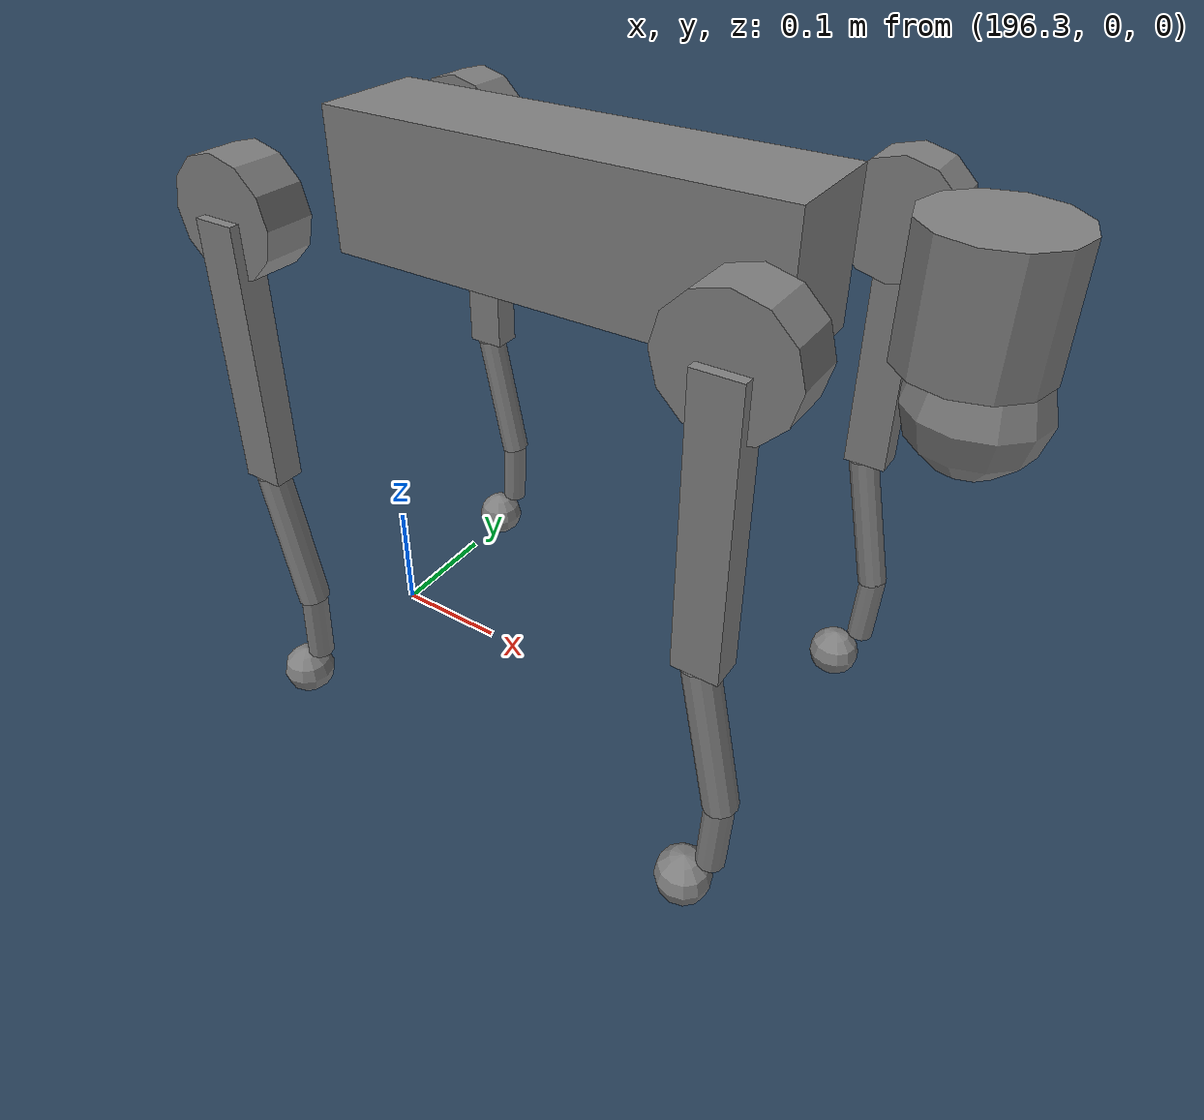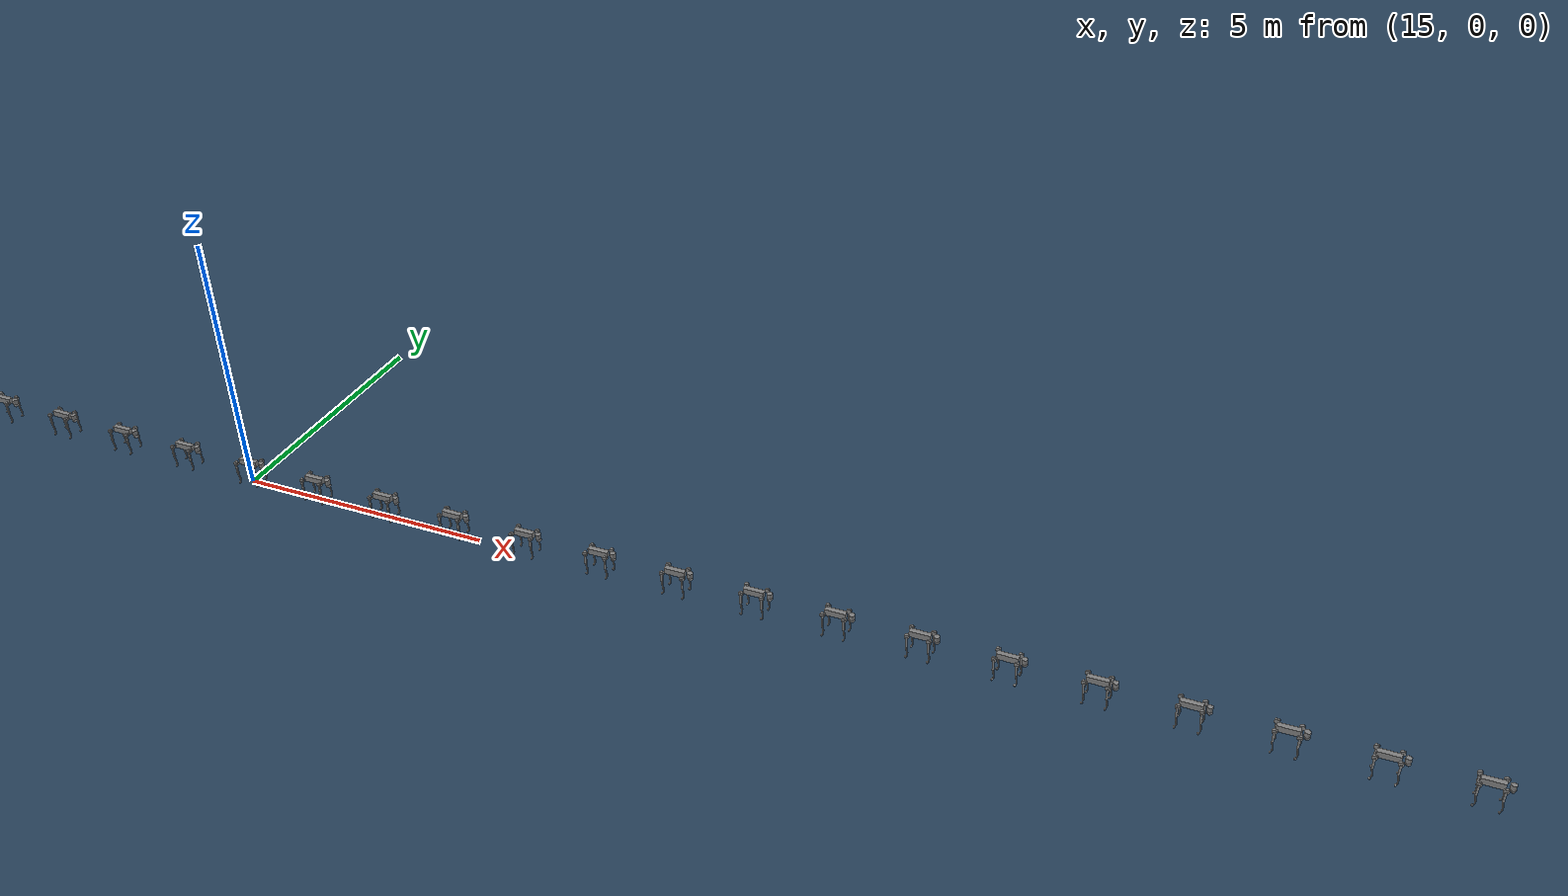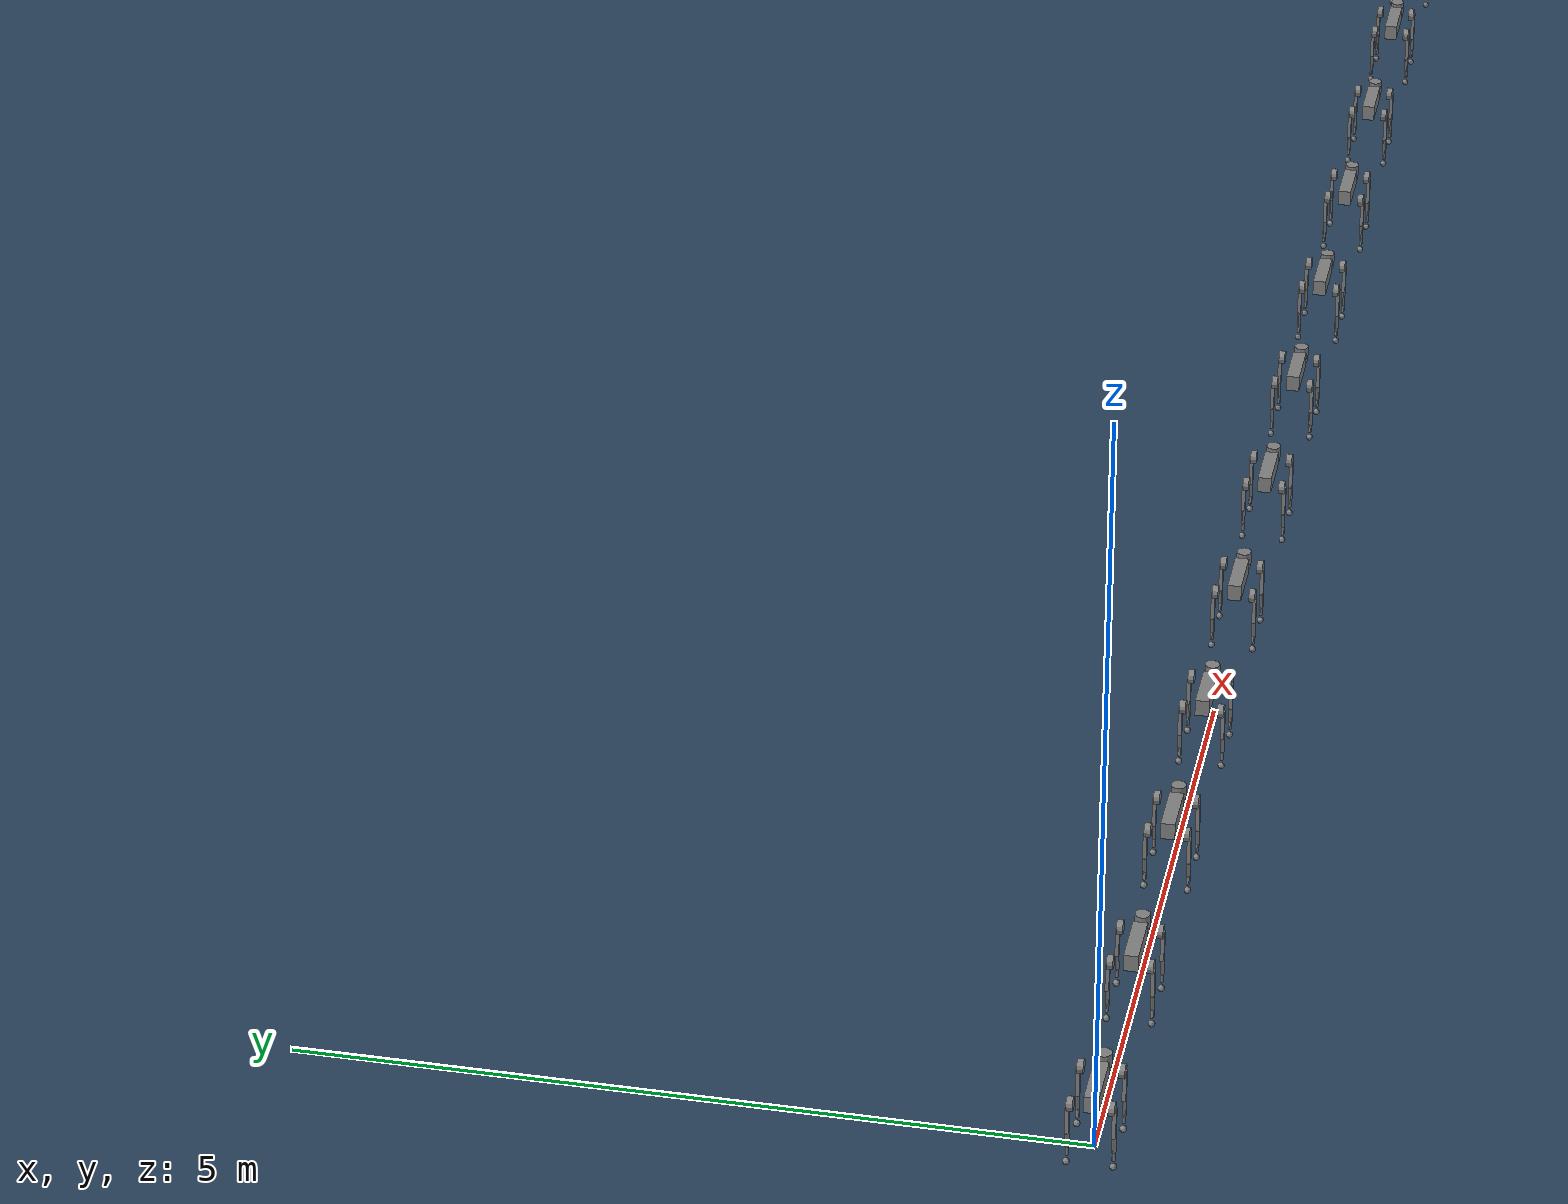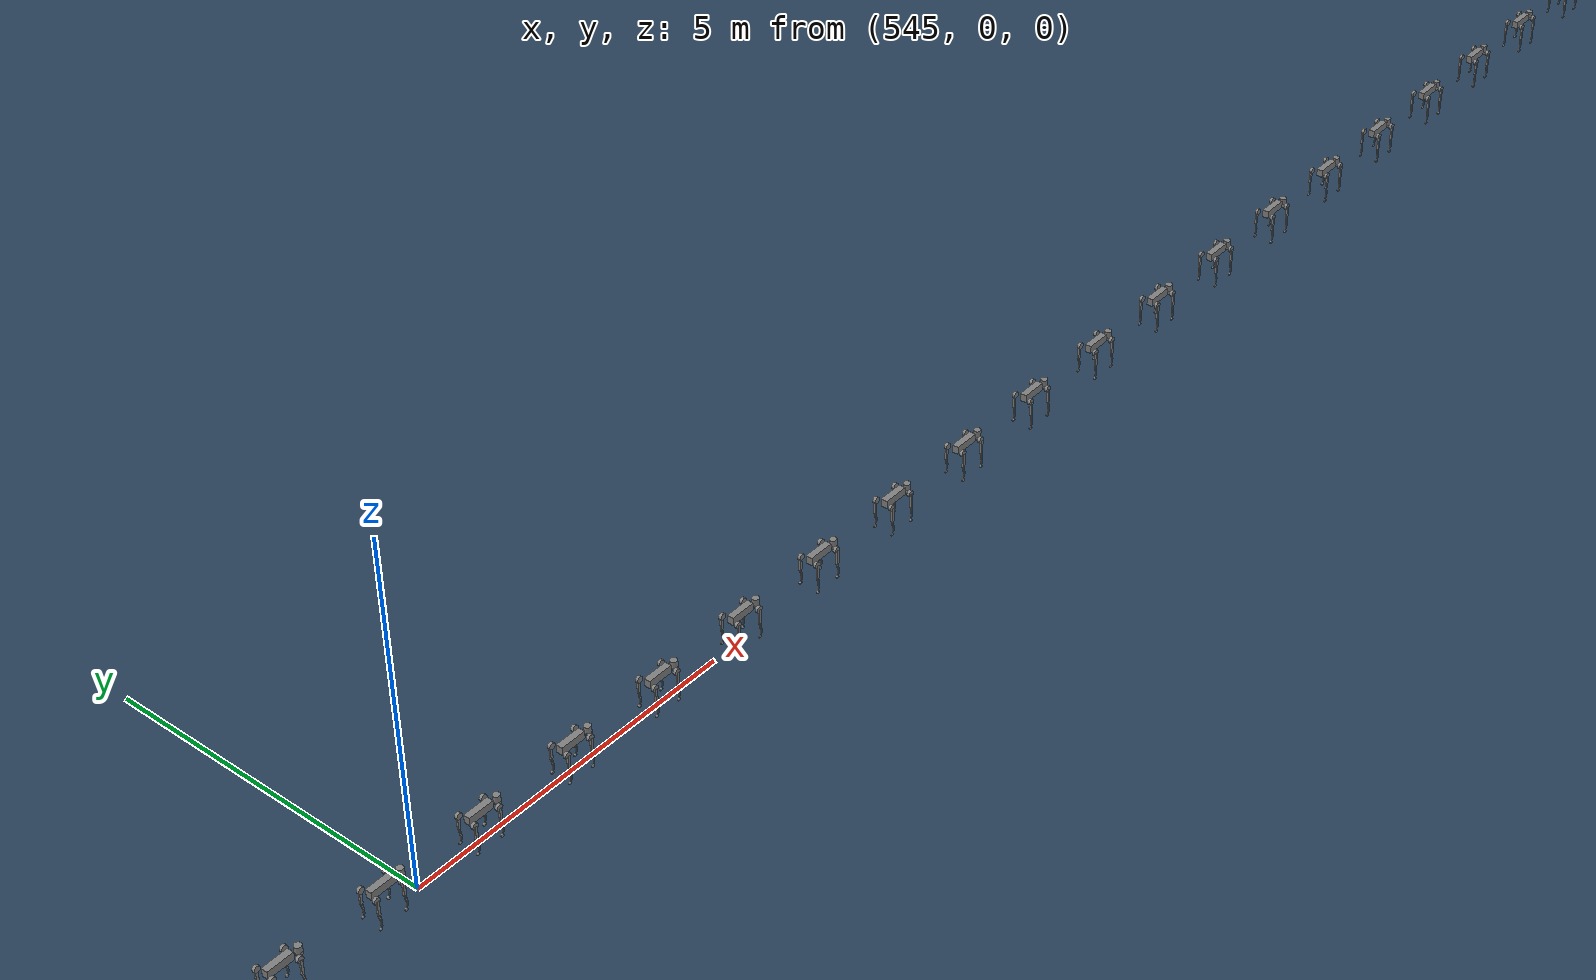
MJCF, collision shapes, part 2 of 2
<inertial pos="0 0 0" euler="0 0 0" mass="0.089" diaginertia="0.000111842 0.000059647 0.000059647" />
        </body>

        <body pos="0 -0.0955 0">
          <inertial pos="-0.00374 0.0223 -0.0327" quat="0.551623 -0.0200632 0.0847635 0.829533" mass="1.152" diaginertia="0.00594973 0.00584149 0.000878787" />
          <joint class="front_thigh" />

          <geom mesh="thigh_mirror" class="visual" />
          <geom size="0.1065 0.01225 0.017" pos="0 0 -0.1065" quat="0.707107 0 0.707107 0" type="box" class="collision" />
          <body pos="0 0 -0.213">
            <inertial pos="0.00629595 0.000622121 -0.141417" quat="0.703508 -0.00450087 0.00154099 0.710672" mass="0.241352" diaginertia="0.0014901 0.00146356 5.31397e-05" />
            <joint class="calf" />

            <geom mesh="calf_mirror" class="visual" />
            <geom size="0.013 0.06" pos="0.01 0 -0.06" quat="0.995004 0 -0.0998334 0" type="cylinder" class="collision" />
            <geom size="0.011 0.0325" pos="0.02 0 -0.148" quat="0.999688 0 0.0249974 0" type="cylinder" class="collision" />
            <geom pos="0 0 -0.213" mesh="foot" class="visual" material="black" />
            <geom class="foot" />
            <site pos="0 0 -0.213" size="0.01" />
          </body>
        </body>
      </body>
      <body pos="-0.1934 0.0465 0">
        <inertial pos="0.0054 0.00194 -0.000105" quat="0.505462 0.498237 0.497014 0.499245" mass="0.678" diaginertia="0.00088403 0.000596003 0.000479967" />
        <joint class="hip" />

        <geom mesh="hip" class="visual" quat="0 0 1 0" />
        <geom size="0.046 0.02" pos="0 0.08 0" quat="0.707107 0.707107 0 0" type="cylinder" class="collision" />

        <body pos="-0.11215 0.04675 0">
          <inertial pos="0 0 0" euler="0 0 0" mass="0.089" diaginertia="0.000111842 0.000059647 0.000059647" />
        </body>

        <body pos="0 0.0955 0">
          <inertial pos="-0.00374 -0.0223 -0.0327" quat="0.829533 0.0847635 -0.0200632 0.551623" mass="1.152" diaginertia="0.00594973 0.00584149 0.000878787" />
          <joint class="back_thigh" />

          <geom mesh="thigh" class="visual" />
          <geom size="0.1065 0.01225 0.017" pos="0 0 -0.1065" quat="0.707107 0 0.707107 0" type="box" class="collision" />
          <body pos="0 0 -0.213">
            <inertial pos="0.00629595 -0.000622121 -0.141417" quat="0.710672 0.00154099 -0.00450087 0.703508" mass="0.241352" diaginertia="0.0014901 0.00146356 5.31397e-05" />
            <joint class="calf" />

            <geom mesh="calf" class="visual" />
            <geom size="0.013 0.06" pos="0.01 0 -0.06" quat="0.995004 0 -0.0998334 0" type="cylinder" class="collision" />
            <geom size="0.011 0.0325" pos="0.02 0 -0.148" quat="0.999688 0 0.0249974 0" type="cylinder" class="collision" />
            <geom pos="0 0 -0.213" mesh="foot" class="visual" material="black" />
            <geom class="foot" />
            <site pos="0 0 -0.213" size="0.01" />
          </body>
        </body>
      </body>
      <body pos="-0.1934 -0.0465 0">
        <inertial pos="0.0054 -0.00194 -0.000105" quat="0.499245 0.497014 0.498237 0.505462" mass="0.678" diaginertia="0.00088403 0.000596003 0.000479967" />
        <joint class="hip" />

        <geom mesh="hip" class="visual" quat="0 0 0 -1" />
        <geom size="0.046 0.02" pos="0 -0.08 0" quat="0.707107 0.707107 0 0" type="cylinder" class="collision" />

        <body pos="-0.11215 -0.04675 0">
          <inertial pos="0 0 0" euler="0 0 0" mass="0.089" diaginertia="0.000111842 0.000059647 0.000059647" />
        </body>

        <body pos="0 -0.0955 0">
          <inertial pos="-0.00374 0.0223 -0.0327" quat="0.551623 -0.0200632 0.0847635 0.829533" mass="1.152" diaginertia="0.00594973 0.00584149 0.000878787" />
          <joint class="back_thigh" />

          <geom mesh="thigh_mirror" class="visual" />
          <geom size="0.1065 0.01225 0.017" pos="0 0 -0.1065" quat="0.707107 0 0.707107 0" type="box" class="collision" />
          <body pos="0 0 -0.213">
            <inertial pos="0.00629595 0.000622121 -0.141417" quat="0.703508 -0.00450087 0.00154099 0.710672" mass="0.241352" diaginertia="0.0014901 0.00146356 5.31397e-05" />
            <joint class="calf" />

            <geom mesh="calf_mirror" class="visual" />
            <geom size="0.013 0.06" pos="0.01 0 -0.06" quat="0.995004 0 -0.0998334 0" type="cylinder" class="collision" />
            <geom size="0.011 0.0325" pos="0.02 0 -0.148" quat="0.999688 0 0.0249974 0" type="cylinder" class="collision" />
            <geom pos="0 0 -0.213" mesh="foot" class="visual" material="black" />
            <geom class="foot" />
            <site pos="0 0 -0.213" size="0.01" />
          </body>
        </body>
      </body>
    </body>
  <body name="torso_193" pos="289.5 0 0.445" childclass="go2">
      <inertial pos="0.021112 0 -0.005366" quat="-0.000543471 0.713435 -0.00173769 0.700719" mass="6.921" diaginertia="0.02448 0.098077 0.107" />

      <geom mesh="trunk" class="visual" />
      <geom size="0.1881 0.04675 0.057" type="box" class="collision" />
      <geom size="0.05 0.045" pos="0.285 0 0.01" type="cylinder" class="collision" />
      <geom size="0.047" pos="0.293 0 -0.06" class="collision" />

      <site pos="-0.02557 0 0.04232" />
      <site pos="0 0 0" euler="0 0 0" size="0.01" />

      <body pos="0.1934 0.0465 0">
        <inertial pos="-0.0054 0.00194 -0.000105" quat="0.497014 0.499245 0.505462 0.498237" mass="0.678" diaginertia="0.00048 0.000884 0.000596" />
        <joint class="hip" />

        <geom mesh="hip" class="visual" />
        <geom size="0.046 0.02" pos="0 0.08 0" quat="1 1 0 0" type="cylinder" class="collision" />

        <body pos="0.11215 0.04675 0">
          <inertial pos="0 0 0" euler="0 0 0" mass="0.089" diaginertia="0.000111842 0.000059647 0.000059647" />
        </body>

        <body pos="0 0.0955 0">
          <inertial pos="-0.00374 -0.0223 -0.0327" quat="0.829533 0.0847635 -0.0200632 0.551623" mass="1.152" diaginertia="0.00594973 0.00584149 0.000878787" />
          <joint class="front_thigh" />

          <geom mesh="thigh" class="visual" />
          <geom size="0.1065 0.01225 0.017" pos="0 0 -0.1065" quat="0.707107 0 0.707107 0" type="box" class="collision" />
          <body pos="0 0 -0.213">
            <inertial pos="0.00629595 -0.000622121 -0.141417" quat="0.710672 0.00154099 -0.00450087 0.703508" mass="0.241352" diaginertia="0.0014901 0.00146356 5.31397e-05" />
            <joint class="calf" />

            <geom mesh="calf" class="visual" />
            <geom size="0.012 0.06" pos="0.008 0 -0.06" quat="0.994493 0 -0.104807 0" type="cylinder" class="collision" />
            <geom size="0.011 0.0325" pos="0.02 0 -0.148" quat="0.999688 0 0.0249974 0" type="cylinder" class="collision" />
            <geom pos="0 0 -0.213" mesh="foot" class="visual" material="black" />
            <geom class="foot" />
            <site pos="0 0 -0.213" size="0.01" />
          </body>
        </body>
      </body>

      <body pos="0.1934 -0.0465 0">
        <inertial pos="-0.0054 -0.00194 -0.000105" quat="0.498237 0.505462 0.499245 0.497014" mass="0.678" diaginertia="0.00088403 0.000596003 0.000479967" />
        <joint class="hip" />

        <geom mesh="hip" class="visual" quat="0 1 0 0" />
        <geom size="0.046 0.02" pos="0 -0.08 0" quat="0.707107 0.707107 0 0" type="cylinder" class="collision" />

        <body pos="0.11215 -0.04675 0">
          <inertial pos="0 0 0" euler="0 0 0" mass="0.089" diaginertia="0.000111842 0.000059647 0.000059647" />
        </body>

        <body pos="0 -0.0955 0">
          <inertial pos="-0.00374 0.0223 -0.0327" quat="0.551623 -0.0200632 0.0847635 0.829533" mass="1.152" diaginertia="0.00594973 0.00584149 0.000878787" />
          <joint class="front_thigh" />

          <geom mesh="thigh_mirror" class="visual" />
          <geom size="0.1065 0.01225 0.017" pos="0 0 -0.1065" quat="0.707107 0 0.707107 0" type="box" class="collision" />
          <body pos="0 0 -0.213">
            <inertial pos="0.00629595 0.000622121 -0.141417" quat="0.703508 -0.00450087 0.00154099 0.710672" mass="0.241352" diaginertia="0.0014901 0.00146356 5.31397e-05" />
            <joint class="calf" />

            <geom mesh="calf_mirror" class="visual" />
            <geom size="0.013 0.06" pos="0.01 0 -0.06" quat="0.995004 0 -0.0998334 0" type="cylinder" class="collision" />
            <geom size="0.011 0.0325" pos="0.02 0 -0.148" quat="0.999688 0 0.0249974 0" type="cylinder" class="collision" />
            <geom pos="0 0 -0.213" mesh="foot" class="visual" material="black" />
            <geom class="foot" />
            <site pos="0 0 -0.213" size="0.01" />
          </body>
        </body>
      </body>
      <body pos="-0.1934 0.0465 0">
        <inertial pos="0.0054 0.00194 -0.000105" quat="0.505462 0.498237 0.497014 0.499245" mass="0.678" diaginertia="0.00088403 0.000596003 0.000479967" />
        <joint class="hip" />

        <geom mesh="hip" class="visual" quat="0 0 1 0" />
        <geom size="0.046 0.02" pos="0 0.08 0" quat="0.707107 0.707107 0 0" type="cylinder" class="collision" />

        <body pos="-0.11215 0.04675 0">
          <inertial pos="0 0 0" euler="0 0 0" mass="0.089" diaginertia="0.000111842 0.000059647 0.000059647" />
        </body>

        <body pos="0 0.0955 0">
          <inertial pos="-0.00374 -0.0223 -0.0327" quat="0.829533 0.0847635 -0.0200632 0.551623" mass="1.152" diaginertia="0.00594973 0.00584149 0.000878787" />
          <joint class="back_thigh" />

          <geom mesh="thigh" class="visual" />
          <geom size="0.1065 0.01225 0.017" pos="0 0 -0.1065" quat="0.707107 0 0.707107 0" type="box" class="collision" />
          <body pos="0 0 -0.213">
            <inertial pos="0.00629595 -0.000622121 -0.141417" quat="0.710672 0.00154099 -0.00450087 0.703508" mass="0.241352" diaginertia="0.0014901 0.00146356 5.31397e-05" />
            <joint class="calf" />

            <geom mesh="calf" class="visual" />
            <geom size="0.013 0.06" pos="0.01 0 -0.06" quat="0.995004 0 -0.0998334 0" type="cylinder" class="collision" />
            <geom size="0.011 0.0325" pos="0.02 0 -0.148" quat="0.999688 0 0.0249974 0" type="cylinder" class="collision" />
            <geom pos="0 0 -0.213" mesh="foot" class="visual" material="black" />
            <geom class="foot" />
            <site pos="0 0 -0.213" size="0.01" />
          </body>
        </body>
      </body>
      <body pos="-0.1934 -0.0465 0">
        <inertial pos="0.0054 -0.00194 -0.000105" quat="0.499245 0.497014 0.498237 0.505462" mass="0.678" diaginertia="0.00088403 0.000596003 0.000479967" />
        <joint class="hip" />

        <geom mesh="hip" class="visual" quat="0 0 0 -1" />
        <geom size="0.046 0.02" pos="0 -0.08 0" quat="0.707107 0.707107 0 0" type="cylinder" class="collision" />

        <body pos="-0.11215 -0.04675 0">
          <inertial pos="0 0 0" euler="0 0 0" mass="0.089" diaginertia="0.000111842 0.000059647 0.000059647" />
        </body>

        <body pos="0 -0.0955 0">
          <inertial pos="-0.00374 0.0223 -0.0327" quat="0.551623 -0.0200632 0.0847635 0.829533" mass="1.152" diaginertia="0.00594973 0.00584149 0.000878787" />
          <joint class="back_thigh" />

          <geom mesh="thigh_mirror" class="visual" />
          <geom size="0.1065 0.01225 0.017" pos="0 0 -0.1065" quat="0.707107 0 0.707107 0" type="box" class="collision" />
          <body pos="0 0 -0.213">
            <inertial pos="0.00629595 0.000622121 -0.141417" quat="0.703508 -0.00450087 0.00154099 0.710672" mass="0.241352" diaginertia="0.0014901 0.00146356 5.31397e-05" />
            <joint class="calf" />

            <geom mesh="calf_mirror" class="visual" />
            <geom size="0.013 0.06" pos="0.01 0 -0.06" quat="0.995004 0 -0.0998334 0" type="cylinder" class="collision" />
            <geom size="0.011 0.0325" pos="0.02 0 -0.148" quat="0.999688 0 0.0249974 0" type="cylinder" class="collision" />
            <geom pos="0 0 -0.213" mesh="foot" class="visual" material="black" />
            <geom class="foot" />
            <site pos="0 0 -0.213" size="0.01" />
          </body>
        </body>
      </body>
    </body>
  <body name="torso_194" pos="291.0 0 0.445" childclass="go2">
      <inertial pos="0.021112 0 -0.005366" quat="-0.000543471 0.713435 -0.00173769 0.700719" mass="6.921" diaginertia="0.02448 0.098077 0.107" />

      <geom mesh="trunk" class="visual" />
      <geom size="0.1881 0.04675 0.057" type="box" class="collision" />
      <geom size="0.05 0.045" pos="0.285 0 0.01" type="cylinder" class="collision" />
      <geom size="0.047" pos="0.293 0 -0.06" class="collision" />

      <site pos="-0.02557 0 0.04232" />
      <site pos="0 0 0" euler="0 0 0" size="0.01" />

      <body pos="0.1934 0.0465 0">
        <inertial pos="-0.0054 0.00194 -0.000105" quat="0.497014 0.499245 0.505462 0.498237" mass="0.678" diaginertia="0.00048 0.000884 0.000596" />
        <joint class="hip" />

        <geom mesh="hip" class="visual" />
        <geom size="0.046 0.02" pos="0 0.08 0" quat="1 1 0 0" type="cylinder" class="collision" />

        <body pos="0.11215 0.04675 0">
          <inertial pos="0 0 0" euler="0 0 0" mass="0.089" diaginertia="0.000111842 0.000059647 0.000059647" />
        </body>

        <body pos="0 0.0955 0">
          <inertial pos="-0.00374 -0.0223 -0.0327" quat="0.829533 0.0847635 -0.0200632 0.551623" mass="1.152" diaginertia="0.00594973 0.00584149 0.000878787" />
          <joint class="front_thigh" />

          <geom mesh="thigh" class="visual" />
          <geom size="0.1065 0.01225 0.017" pos="0 0 -0.1065" quat="0.707107 0 0.707107 0" type="box" class="collision" />
          <body pos="0 0 -0.213">
            <inertial pos="0.00629595 -0.000622121 -0.141417" quat="0.710672 0.00154099 -0.00450087 0.703508" mass="0.241352" diaginertia="0.0014901 0.00146356 5.31397e-05" />
            <joint class="calf" />

            <geom mesh="calf" class="visual" />
            <geom size="0.012 0.06" pos="0.008 0 -0.06" quat="0.994493 0 -0.104807 0" type="cylinder" class="collision" />
            <geom size="0.011 0.0325" pos="0.02 0 -0.148" quat="0.999688 0 0.0249974 0" type="cylinder" class="collision" />
            <geom pos="0 0 -0.213" mesh="foot" class="visual" material="black" />
            <geom class="foot" />
            <site pos="0 0 -0.213" size="0.01" />
          </body>
        </body>
      </body>

      <body pos="0.1934 -0.0465 0">
        <inertial pos="-0.0054 -0.00194 -0.000105" quat="0.498237 0.505462 0.499245 0.497014" mass="0.678" diaginertia="0.00088403 0.000596003 0.000479967" />
        <joint class="hip" />

        <geom mesh="hip" class="visual" quat="0 1 0 0" />
        <geom size="0.046 0.02" pos="0 -0.08 0" quat="0.707107 0.707107 0 0" type="cylinder" class="collision" />

        <body pos="0.11215 -0.04675 0">
          <inertial pos="0 0 0" euler="0 0 0" mass="0.089" diaginertia="0.000111842 0.000059647 0.000059647" />
        </body>

        <body pos="0 -0.0955 0">
          <inertial pos="-0.00374 0.0223 -0.0327" quat="0.551623 -0.0200632 0.0847635 0.829533" mass="1.152" diaginertia="0.00594973 0.00584149 0.000878787" />
          <joint class="front_thigh" />

          <geom mesh="thigh_mirror" class="visual" />
          <geom size="0.1065 0.01225 0.017" pos="0 0 -0.1065" quat="0.707107 0 0.707107 0" type="box" class="collision" />
          <body pos="0 0 -0.213">
            <inertial pos="0.00629595 0.000622121 -0.141417" quat="0.703508 -0.00450087 0.00154099 0.710672" mass="0.241352" diaginertia="0.0014901 0.00146356 5.31397e-05" />
            <joint class="calf" />

            <geom mesh="calf_mirror" class="visual" />
            <geom size="0.013 0.06" pos="0.01 0 -0.06" quat="0.995004 0 -0.0998334 0" type="cylinder" class="collision" />
            <geom size="0.011 0.0325" pos="0.02 0 -0.148" quat="0.999688 0 0.0249974 0" type="cylinder" class="collision" />
            <geom pos="0 0 -0.213" mesh="foot" class="visual" material="black" />
            <geom class="foot" />
            <site pos="0 0 -0.213" size="0.01" />
          </body>
        </body>
      </body>
      <body pos="-0.1934 0.0465 0">
        <inertial pos="0.0054 0.00194 -0.000105" quat="0.505462 0.498237 0.497014 0.499245" mass="0.678" diaginertia="0.00088403 0.000596003 0.000479967" />
        <joint class="hip" />

        <geom mesh="hip" class="visual" quat="0 0 1 0" />
        <geom size="0.046 0.02" pos="0 0.08 0" quat="0.707107 0.707107 0 0" type="cylinder" class="collision" />

        <body pos="-0.11215 0.04675 0">
          <inertial pos="0 0 0" euler="0 0 0" mass="0.089" diaginertia="0.000111842 0.000059647 0.000059647" />
        </body>

        <body pos="0 0.0955 0">
          <inertial pos="-0.00374 -0.0223 -0.0327" quat="0.829533 0.0847635 -0.0200632 0.551623" mass="1.152" diaginertia="0.00594973 0.00584149 0.000878787" />
          <joint class="back_thigh" />

          <geom mesh="thigh" class="visual" />
          <geom size="0.1065 0.01225 0.017" pos="0 0 -0.1065" quat="0.707107 0 0.707107 0" type="box" class="collision" />
          <body pos="0 0 -0.213">
            <inertial pos="0.00629595 -0.000622121 -0.141417" quat="0.710672 0.00154099 -0.00450087 0.703508" mass="0.241352" diaginertia="0.0014901 0.00146356 5.31397e-05" />
            <joint class="calf" />

            <geom mesh="calf" class="visual" />
            <geom size="0.013 0.06" pos="0.01 0 -0.06" quat="0.995004 0 -0.0998334 0" type="cylinder" class="collision" />
            <geom size="0.011 0.0325" pos="0.02 0 -0.148" quat="0.999688 0 0.0249974 0" type="cylinder" class="collision" />
            <geom pos="0 0 -0.213" mesh="foot" class="visual" material="black" />
            <geom class="foot" />
            <site pos="0 0 -0.213" size="0.01" />
          </body>
        </body>
      </body>
      <body pos="-0.1934 -0.0465 0">
        <inertial pos="0.0054 -0.00194 -0.000105" quat="0.499245 0.497014 0.498237 0.505462" mass="0.678" diaginertia="0.00088403 0.000596003 0.000479967" />
        <joint class="hip" />

        <geom mesh="hip" class="visual" quat="0 0 0 -1" />
        <geom size="0.046 0.02" pos="0 -0.08 0" quat="0.707107 0.707107 0 0" type="cylinder" class="collision" />

        <body pos="-0.11215 -0.04675 0">
          <inertial pos="0 0 0" euler="0 0 0" mass="0.089" diaginertia="0.000111842 0.000059647 0.000059647" />
        </body>

        <body pos="0 -0.0955 0">
          <inertial pos="-0.00374 0.0223 -0.0327" quat="0.551623 -0.0200632 0.0847635 0.829533" mass="1.152" diaginertia="0.00594973 0.00584149 0.000878787" />
          <joint class="back_thigh" />

          <geom mesh="thigh_mirror" class="visual" />
          <geom size="0.1065 0.01225 0.017" pos="0 0 -0.1065" quat="0.707107 0 0.707107 0" type="box" class="collision" />
          <body pos="0 0 -0.213">
            <inertial pos="0.00629595 0.000622121 -0.141417" quat="0.703508 -0.00450087 0.00154099 0.710672" mass="0.241352" diaginertia="0.0014901 0.00146356 5.31397e-05" />
            <joint class="calf" />

            <geom mesh="calf_mirror" class="visual" />
            <geom size="0.013 0.06" pos="0.01 0 -0.06" quat="0.995004 0 -0.0998334 0" type="cylinder" class="collision" />
            <geom size="0.011 0.0325" pos="0.02 0 -0.148" quat="0.999688 0 0.0249974 0" type="cylinder" class="collision" />
            <geom pos="0 0 -0.213" mesh="foot" class="visual" material="black" />
            <geom class="foot" />
            <site pos="0 0 -0.213" size="0.01" />
          </body>
        </body>
      </body>
    </body>
  <body name="torso_195" pos="292.5 0 0.445" childclass="go2">
      <inertial pos="0.021112 0 -0.005366" quat="-0.000543471 0.713435 -0.00173769 0.700719" mass="6.921" diaginertia="0.02448 0.098077 0.107" />

      <geom mesh="trunk" class="visual" />
      <geom size="0.1881 0.04675 0.057" type="box" class="collision" />
      <geom size="0.05 0.045" pos="0.285 0 0.01" type="cylinder" class="collision" />
      <geom size="0.047" pos="0.293 0 -0.06" class="collision" />

      <site pos="-0.02557 0 0.04232" />
      <site pos="0 0 0" euler="0 0 0" size="0.01" />

      <body pos="0.1934 0.0465 0">
        <inertial pos="-0.0054 0.00194 -0.000105" quat="0.497014 0.499245 0.505462 0.498237" mass="0.678" diaginertia="0.00048 0.000884 0.000596" />
        <joint class="hip" />

        <geom mesh="hip" class="visual" />
        <geom size="0.046 0.02" pos="0 0.08 0" quat="1 1 0 0" type="cylinder" class="collision" />

        <body pos="0.11215 0.04675 0">
          <inertial pos="0 0 0" euler="0 0 0" mass="0.089" diaginertia="0.000111842 0.000059647 0.000059647" />
        </body>

        <body pos="0 0.0955 0">
          <inertial pos="-0.00374 -0.0223 -0.0327" quat="0.829533 0.0847635 -0.0200632 0.551623" mass="1.152" diaginertia="0.00594973 0.00584149 0.000878787" />
          <joint class="front_thigh" />

          <geom mesh="thigh" class="visual" />
          <geom size="0.1065 0.01225 0.017" pos="0 0 -0.1065" quat="0.707107 0 0.707107 0" type="box" class="collision" />
          <body pos="0 0 -0.213">
            <inertial pos="0.00629595 -0.000622121 -0.141417" quat="0.710672 0.00154099 -0.00450087 0.703508" mass="0.241352" diaginertia="0.0014901 0.00146356 5.31397e-05" />
            <joint class="calf" />

            <geom mesh="calf" class="visual" />
            <geom size="0.012 0.06" pos="0.008 0 -0.06" quat="0.994493 0 -0.104807 0" type="cylinder" class="collision" />
            <geom size="0.011 0.0325" pos="0.02 0 -0.148" quat="0.999688 0 0.0249974 0" type="cylinder" class="collision" />
            <geom pos="0 0 -0.213" mesh="foot" class="visual" material="black" />
            <geom class="foot" />
            <site pos="0 0 -0.213" size="0.01" />
          </body>
        </body>
      </body>

      <body pos="0.1934 -0.0465 0">
        <inertial pos="-0.0054 -0.00194 -0.000105" quat="0.498237 0.505462 0.499245 0.497014" mass="0.678" diaginertia="0.00088403 0.000596003 0.000479967" />
        <joint class="hip" />

        <geom mesh="hip" class="visual" quat="0 1 0 0" />
        <geom size="0.046 0.02" pos="0 -0.08 0" quat="0.707107 0.707107 0 0" type="cylinder" class="collision" />

        <body pos="0.11215 -0.04675 0">
          <inertial pos="0 0 0" euler="0 0 0" mass="0.089" diaginertia="0.000111842 0.000059647 0.000059647" />
        </body>

        <body pos="0 -0.0955 0">
          <inertial pos="-0.00374 0.0223 -0.0327" quat="0.551623 -0.0200632 0.0847635 0.829533" mass="1.152" diaginertia="0.00594973 0.00584149 0.000878787" />
          <joint class="front_thigh" />

          <geom mesh="thigh_mirror" class="visual" />
          <geom size="0.1065 0.01225 0.017" pos="0 0 -0.1065" quat="0.707107 0 0.707107 0" type="box" class="collision" />
          <body pos="0 0 -0.213">
            <inertial pos="0.00629595 0.000622121 -0.141417" quat="0.703508 -0.00450087 0.00154099 0.710672" mass="0.241352" diaginertia="0.0014901 0.00146356 5.31397e-05" />
            <joint class="calf" />

            <geom mesh="calf_mirror" class="visual" />
            <geom size="0.013 0.06" pos="0.01 0 -0.06" quat="0.995004 0 -0.0998334 0" type="cylinder" class="collision" />
            <geom size="0.011 0.0325" pos="0.02 0 -0.148" quat="0.999688 0 0.0249974 0" type="cylinder" class="collision" />
            <geom pos="0 0 -0.213" mesh="foot" class="visual" material="black" />
            <geom class="foot" />
            <site pos="0 0 -0.213" size="0.01" />
          </body>
        </body>
      </body>
      <body pos="-0.1934 0.0465 0">
        <inertial pos="0.0054 0.00194 -0.000105" quat="0.505462 0.498237 0.497014 0.499245" mass="0.678" diaginertia="0.00088403 0.000596003 0.000479967" />
        <joint class="hip" />

        <geom mesh="hip" class="visual" quat="0 0 1 0" />
        <geom size="0.046 0.02" pos="0 0.08 0" quat="0.707107 0.707107 0 0" type="cylinder" class="collision" />

        <body pos="-0.11215 0.04675 0">
          <inertial pos="0 0 0" euler="0 0 0" mass="0.089" diaginertia="0.000111842 0.000059647 0.000059647" />
        </body>

        <body pos="0 0.0955 0">
          <inertial pos="-0.00374 -0.0223 -0.0327" quat="0.829533 0.0847635 -0.0200632 0.551623" mass="1.152" diaginertia="0.00594973 0.00584149 0.000878787" />
          <joint class="back_thigh" />

          <geom mesh="thigh" class="visual" />
          <geom size="0.1065 0.01225 0.017" pos="0 0 -0.1065" quat="0.707107 0 0.707107 0" type="box" class="collision" />
          <body pos="0 0 -0.213">
            <inertial pos="0.00629595 -0.000622121 -0.141417" quat="0.710672 0.00154099 -0.00450087 0.703508" mass="0.241352" diaginertia="0.0014901 0.00146356 5.31397e-05" />
            <joint class="calf" />

            <geom mesh="calf" class="visual" />
            <geom size="0.013 0.06" pos="0.01 0 -0.06" quat="0.995004 0 -0.0998334 0" type="cylinder" class="collision" />
            <geom size="0.011 0.0325" pos="0.02 0 -0.148" quat="0.999688 0 0.0249974 0" type="cylinder" class="collision" />
            <geom pos="0 0 -0.213" mesh="foot" class="visual" material="black" />
            <geom class="foot" />
            <site pos="0 0 -0.213" size="0.01" />
          </body>
        </body>
      </body>
      <body pos="-0.1934 -0.0465 0">
        <inertial pos="0.0054 -0.00194 -0.000105" quat="0.499245 0.497014 0.498237 0.505462" mass="0.678" diaginertia="0.00088403 0.000596003 0.000479967" />
        <joint class="hip" />

        <geom mesh="hip" class="visual" quat="0 0 0 -1" />
        <geom size="0.046 0.02" pos="0 -0.08 0" quat="0.707107 0.707107 0 0" type="cylinder" class="collision" />

        <body pos="-0.11215 -0.04675 0">
          <inertial pos="0 0 0" euler="0 0 0" mass="0.089" diaginertia="0.000111842 0.000059647 0.000059647" />
        </body>

        <body pos="0 -0.0955 0">
          <inertial pos="-0.00374 0.0223 -0.0327" quat="0.551623 -0.0200632 0.0847635 0.829533" mass="1.152" diaginertia="0.00594973 0.00584149 0.000878787" />
          <joint class="back_thigh" />

          <geom mesh="thigh_mirror" class="visual" />
          <geom size="0.1065 0.01225 0.017" pos="0 0 -0.1065" quat="0.707107 0 0.707107 0" type="box" class="collision" />
          <body pos="0 0 -0.213">
            <inertial pos="0.00629595 0.000622121 -0.141417" quat="0.703508 -0.00450087 0.00154099 0.710672" mass="0.241352" diaginertia="0.0014901 0.00146356 5.31397e-05" />
            <joint class="calf" />

            <geom mesh="calf_mirror" class="visual" />
            <geom size="0.013 0.06" pos="0.01 0 -0.06" quat="0.995004 0 -0.0998334 0" type="cylinder" class="collision" />
            <geom size="0.011 0.0325" pos="0.02 0 -0.148" quat="0.999688 0 0.0249974 0" type="cylinder" class="collision" />
            <geom pos="0 0 -0.213" mesh="foot" class="visual" material="black" />
            <geom class="foot" />
            <site pos="0 0 -0.213" size="0.01" />
          </body>
        </body>
      </body>
    </body>
  <body name="torso_196" pos="294.0 0 0.445" childclass="go2">
      <inertial pos="0.021112 0 -0.005366" quat="-0.000543471 0.713435 -0.00173769 0.700719" mass="6.921" diaginertia="0.02448 0.098077 0.107" />

      <geom mesh="trunk" class="visual" />
      <geom size="0.1881 0.04675 0.057" type="box" class="collision" />
      <geom size="0.05 0.045" pos="0.285 0 0.01" type="cylinder" class="collision" />
      <geom size="0.047" pos="0.293 0 -0.06" class="collision" />

      <site pos="-0.02557 0 0.04232" />
      <site pos="0 0 0" euler="0 0 0" size="0.01" />

      <body pos="0.1934 0.0465 0">
        <inertial pos="-0.0054 0.00194 -0.000105" quat="0.497014 0.499245 0.505462 0.498237" mass="0.678" diaginertia="0.00048 0.000884 0.000596" />
        <joint class="hip" />

        <geom mesh="hip" class="visual" />
        <geom size="0.046 0.02" pos="0 0.08 0" quat="1 1 0 0" type="cylinder" class="collision" />

        <body pos="0.11215 0.04675 0">
          <inertial pos="0 0 0" euler="0 0 0" mass="0.089" diaginertia="0.000111842 0.000059647 0.000059647" />
        </body>

        <body pos="0 0.0955 0">
          <inertial pos="-0.00374 -0.0223 -0.0327" quat="0.829533 0.0847635 -0.0200632 0.551623" mass="1.152" diaginertia="0.00594973 0.00584149 0.000878787" />
          <joint class="front_thigh" />

          <geom mesh="thigh" class="visual" />
          <geom size="0.1065 0.01225 0.017" pos="0 0 -0.1065" quat="0.707107 0 0.707107 0" type="box" class="collision" />
          <body pos="0 0 -0.213">
            <inertial pos="0.00629595 -0.000622121 -0.141417" quat="0.710672 0.00154099 -0.00450087 0.703508" mass="0.241352" diaginertia="0.0014901 0.00146356 5.31397e-05" />
            <joint class="calf" />

            <geom mesh="calf" class="visual" />
            <geom size="0.012 0.06" pos="0.008 0 -0.06" quat="0.994493 0 -0.104807 0" type="cylinder" class="collision" />
            <geom size="0.011 0.0325" pos="0.02 0 -0.148" quat="0.999688 0 0.0249974 0" type="cylinder" class="collision" />
            <geom pos="0 0 -0.213" mesh="foot" class="visual" material="black" />
            <geom class="foot" />
            <site pos="0 0 -0.213" size="0.01" />
          </body>
        </body>
      </body>

      <body pos="0.1934 -0.0465 0">
        <inertial pos="-0.0054 -0.00194 -0.000105" quat="0.498237 0.505462 0.499245 0.497014" mass="0.678" diaginertia="0.00088403 0.000596003 0.000479967" />
        <joint class="hip" />

        <geom mesh="hip" class="visual" quat="0 1 0 0" />
        <geom size="0.046 0.02" pos="0 -0.08 0" quat="0.707107 0.707107 0 0" type="cylinder" class="collision" />

        <body pos="0.11215 -0.04675 0">
          <inertial pos="0 0 0" euler="0 0 0" mass="0.089" diaginertia="0.000111842 0.000059647 0.000059647" />
        </body>

        <body pos="0 -0.0955 0">
          <inertial pos="-0.00374 0.0223 -0.0327" quat="0.551623 -0.0200632 0.0847635 0.829533" mass="1.152" diaginertia="0.00594973 0.00584149 0.000878787" />
          <joint class="front_thigh" />

          <geom mesh="thigh_mirror" class="visual" />
          <geom size="0.1065 0.01225 0.017" pos="0 0 -0.1065" quat="0.707107 0 0.707107 0" type="box" class="collision" />
          <body pos="0 0 -0.213">
            <inertial pos="0.00629595 0.000622121 -0.141417" quat="0.703508 -0.00450087 0.00154099 0.710672" mass="0.241352" diaginertia="0.0014901 0.00146356 5.31397e-05" />
            <joint class="calf" />

            <geom mesh="calf_mirror" class="visual" />
            <geom size="0.013 0.06" pos="0.01 0 -0.06" quat="0.995004 0 -0.0998334 0" type="cylinder" class="collision" />
            <geom size="0.011 0.0325" pos="0.02 0 -0.148" quat="0.999688 0 0.0249974 0" type="cylinder" class="collision" />
            <geom pos="0 0 -0.213" mesh="foot" class="visual" material="black" />
            <geom class="foot" />
            <site pos="0 0 -0.213" size="0.01" />
          </body>
        </body>
      </body>
      <body pos="-0.1934 0.0465 0">
        <inertial pos="0.0054 0.00194 -0.000105" quat="0.505462 0.498237 0.497014 0.499245" mass="0.678" diaginertia="0.00088403 0.000596003 0.000479967" />
        <joint class="hip" />

        <geom mesh="hip" class="visual" quat="0 0 1 0" />
        <geom size="0.046 0.02" pos="0 0.08 0" quat="0.707107 0.707107 0 0" type="cylinder" class="collision" />

        <body pos="-0.11215 0.04675 0">
          <inertial pos="0 0 0" euler="0 0 0" mass="0.089" diaginertia="0.000111842 0.000059647 0.000059647" />
        </body>

        <body pos="0 0.0955 0">
          <inertial pos="-0.00374 -0.0223 -0.0327" quat="0.829533 0.0847635 -0.0200632 0.551623" mass="1.152" diaginertia="0.00594973 0.00584149 0.000878787" />
          <joint class="back_thigh" />

          <geom mesh="thigh" class="visual" />
          <geom size="0.1065 0.01225 0.017" pos="0 0 -0.1065" quat="0.707107 0 0.707107 0" type="box" class="collision" />
          <body pos="0 0 -0.213">
            <inertial pos="0.00629595 -0.000622121 -0.141417" quat="0.710672 0.00154099 -0.00450087 0.703508" mass="0.241352" diaginertia="0.0014901 0.00146356 5.31397e-05" />
            <joint class="calf" />

            <geom mesh="calf" class="visual" />
            <geom size="0.013 0.06" pos="0.01 0 -0.06" quat="0.995004 0 -0.0998334 0" type="cylinder" class="collision" />
            <geom size="0.011 0.0325" pos="0.02 0 -0.148" quat="0.999688 0 0.0249974 0" type="cylinder" class="collision" />
            <geom pos="0 0 -0.213" mesh="foot" class="visual" material="black" />
            <geom class="foot" />
            <site pos="0 0 -0.213" size="0.01" />
          </body>
        </body>
      </body>
      <body pos="-0.1934 -0.0465 0">
        <inertial pos="0.0054 -0.00194 -0.000105" quat="0.499245 0.497014 0.498237 0.505462" mass="0.678" diaginertia="0.00088403 0.000596003 0.000479967" />
        <joint class="hip" />

        <geom mesh="hip" class="visual" quat="0 0 0 -1" />
        <geom size="0.046 0.02" pos="0 -0.08 0" quat="0.707107 0.707107 0 0" type="cylinder" class="collision" />

        <body pos="-0.11215 -0.04675 0">
          <inertial pos="0 0 0" euler="0 0 0" mass="0.089" diaginertia="0.000111842 0.000059647 0.000059647" />
        </body>

        <body pos="0 -0.0955 0">
          <inertial pos="-0.00374 0.0223 -0.0327" quat="0.551623 -0.0200632 0.0847635 0.829533" mass="1.152" diaginertia="0.00594973 0.00584149 0.000878787" />
          <joint class="back_thigh" />

          <geom mesh="thigh_mirror" class="visual" />
          <geom size="0.1065 0.01225 0.017" pos="0 0 -0.1065" quat="0.707107 0 0.707107 0" type="box" class="collision" />
          <body pos="0 0 -0.213">
            <inertial pos="0.00629595 0.000622121 -0.141417" quat="0.703508 -0.00450087 0.00154099 0.710672" mass="0.241352" diaginertia="0.0014901 0.00146356 5.31397e-05" />
            <joint class="calf" />

            <geom mesh="calf_mirror" class="visual" />
            <geom size="0.013 0.06" pos="0.01 0 -0.06" quat="0.995004 0 -0.0998334 0" type="cylinder" class="collision" />
            <geom size="0.011 0.0325" pos="0.02 0 -0.148" quat="0.999688 0 0.0249974 0" type="cylinder" class="collision" />
            <geom pos="0 0 -0.213" mesh="foot" class="visual" material="black" />
            <geom class="foot" />
            <site pos="0 0 -0.213" size="0.01" />
          </body>
        </body>
      </body>
    </body>
  <body name="torso_197" pos="295.5 0 0.445" childclass="go2">
      <inertial pos="0.021112 0 -0.005366" quat="-0.000543471 0.713435 -0.00173769 0.700719" mass="6.921" diaginertia="0.02448 0.098077 0.107" />

      <geom mesh="trunk" class="visual" />
      <geom size="0.1881 0.04675 0.057" type="box" class="collision" />
      <geom size="0.05 0.045" pos="0.285 0 0.01" type="cylinder" class="collision" />
      <geom size="0.047" pos="0.293 0 -0.06" class="collision" />

      <site pos="-0.02557 0 0.04232" />
      <site pos="0 0 0" euler="0 0 0" size="0.01" />

      <body pos="0.1934 0.0465 0">
        <inertial pos="-0.0054 0.00194 -0.000105" quat="0.497014 0.499245 0.505462 0.498237" mass="0.678" diaginertia="0.00048 0.000884 0.000596" />
        <joint class="hip" />

        <geom mesh="hip" class="visual" />
        <geom size="0.046 0.02" pos="0 0.08 0" quat="1 1 0 0" type="cylinder" class="collision" />

        <body pos="0.11215 0.04675 0">
          <inertial pos="0 0 0" euler="0 0 0" mass="0.089" diaginertia="0.000111842 0.000059647 0.000059647" />
        </body>

        <body pos="0 0.0955 0">
          <inertial pos="-0.00374 -0.0223 -0.0327" quat="0.829533 0.0847635 -0.0200632 0.551623" mass="1.152" diaginertia="0.00594973 0.00584149 0.000878787" />
          <joint class="front_thigh" />

          <geom mesh="thigh" class="visual" />
          <geom size="0.1065 0.01225 0.017" pos="0 0 -0.1065" quat="0.707107 0 0.707107 0" type="box" class="collision" />
          <body pos="0 0 -0.213">
            <inertial pos="0.00629595 -0.000622121 -0.141417" quat="0.710672 0.00154099 -0.00450087 0.703508" mass="0.241352" diaginertia="0.0014901 0.00146356 5.31397e-05" />
            <joint class="calf" />

            <geom mesh="calf" class="visual" />
            <geom size="0.012 0.06" pos="0.008 0 -0.06" quat="0.994493 0 -0.104807 0" type="cylinder" class="collision" />
            <geom size="0.011 0.0325" pos="0.02 0 -0.148" quat="0.999688 0 0.0249974 0" type="cylinder" class="collision" />
            <geom pos="0 0 -0.213" mesh="foot" class="visual" material="black" />
            <geom class="foot" />
            <site pos="0 0 -0.213" size="0.01" />
          </body>
        </body>
      </body>

      <body pos="0.1934 -0.0465 0">
        <inertial pos="-0.0054 -0.00194 -0.000105" quat="0.498237 0.505462 0.499245 0.497014" mass="0.678" diaginertia="0.00088403 0.000596003 0.000479967" />
        <joint class="hip" />

        <geom mesh="hip" class="visual" quat="0 1 0 0" />
        <geom size="0.046 0.02" pos="0 -0.08 0" quat="0.707107 0.707107 0 0" type="cylinder" class="collision" />

        <body pos="0.11215 -0.04675 0">
          <inertial pos="0 0 0" euler="0 0 0" mass="0.089" diaginertia="0.000111842 0.000059647 0.000059647" />
        </body>

        <body pos="0 -0.0955 0">
          <inertial pos="-0.00374 0.0223 -0.0327" quat="0.551623 -0.0200632 0.0847635 0.829533" mass="1.152" diaginertia="0.00594973 0.00584149 0.000878787" />
          <joint class="front_thigh" />

          <geom mesh="thigh_mirror" class="visual" />
          <geom size="0.1065 0.01225 0.017" pos="0 0 -0.1065" quat="0.707107 0 0.707107 0" type="box" class="collision" />
          <body pos="0 0 -0.213">
            <inertial pos="0.00629595 0.000622121 -0.141417" quat="0.703508 -0.00450087 0.00154099 0.710672" mass="0.241352" diaginertia="0.0014901 0.00146356 5.31397e-05" />
            <joint class="calf" />

            <geom mesh="calf_mirror" class="visual" />
            <geom size="0.013 0.06" pos="0.01 0 -0.06" quat="0.995004 0 -0.0998334 0" type="cylinder" class="collision" />
            <geom size="0.011 0.0325" pos="0.02 0 -0.148" quat="0.999688 0 0.0249974 0" type="cylinder" class="collision" />
            <geom pos="0 0 -0.213" mesh="foot" class="visual" material="black" />
            <geom class="foot" />
            <site pos="0 0 -0.213" size="0.01" />
          </body>
        </body>
      </body>
      <body pos="-0.1934 0.0465 0">
        <inertial pos="0.0054 0.00194 -0.000105" quat="0.505462 0.498237 0.497014 0.499245" mass="0.678" diaginertia="0.00088403 0.000596003 0.000479967" />
        <joint class="hip" />

        <geom mesh="hip" class="visual" quat="0 0 1 0" />
        <geom size="0.046 0.02" pos="0 0.08 0" quat="0.707107 0.707107 0 0" type="cylinder" class="collision" />

        <body pos="-0.11215 0.04675 0">
          <inertial pos="0 0 0" euler="0 0 0" mass="0.089" diaginertia="0.000111842 0.000059647 0.000059647" />
        </body>

        <body pos="0 0.0955 0">
          <inertial pos="-0.00374 -0.0223 -0.0327" quat="0.829533 0.0847635 -0.0200632 0.551623" mass="1.152" diaginertia="0.00594973 0.00584149 0.000878787" />
          <joint class="back_thigh" />

          <geom mesh="thigh" class="visual" />
          <geom size="0.1065 0.01225 0.017" pos="0 0 -0.1065" quat="0.707107 0 0.707107 0" type="box" class="collision" />
          <body pos="0 0 -0.213">
            <inertial pos="0.00629595 -0.000622121 -0.141417" quat="0.710672 0.00154099 -0.00450087 0.703508" mass="0.241352" diaginertia="0.0014901 0.00146356 5.31397e-05" />
            <joint class="calf" />

            <geom mesh="calf" class="visual" />
            <geom size="0.013 0.06" pos="0.01 0 -0.06" quat="0.995004 0 -0.0998334 0" type="cylinder" class="collision" />
            <geom size="0.011 0.0325" pos="0.02 0 -0.148" quat="0.999688 0 0.0249974 0" type="cylinder" class="collision" />
            <geom pos="0 0 -0.213" mesh="foot" class="visual" material="black" />
            <geom class="foot" />
            <site pos="0 0 -0.213" size="0.01" />
          </body>
        </body>
      </body>
      <body pos="-0.1934 -0.0465 0">
        <inertial pos="0.0054 -0.00194 -0.000105" quat="0.499245 0.497014 0.498237 0.505462" mass="0.678" diaginertia="0.00088403 0.000596003 0.000479967" />
        <joint class="hip" />

        <geom mesh="hip" class="visual" quat="0 0 0 -1" />
        <geom size="0.046 0.02" pos="0 -0.08 0" quat="0.707107 0.707107 0 0" type="cylinder" class="collision" />

        <body pos="-0.11215 -0.04675 0">
          <inertial pos="0 0 0" euler="0 0 0" mass="0.089" diaginertia="0.000111842 0.000059647 0.000059647" />
        </body>

        <body pos="0 -0.0955 0">
          <inertial pos="-0.00374 0.0223 -0.0327" quat="0.551623 -0.0200632 0.0847635 0.829533" mass="1.152" diaginertia="0.00594973 0.00584149 0.000878787" />
          <joint class="back_thigh" />

          <geom mesh="thigh_mirror" class="visual" />
          <geom size="0.1065 0.01225 0.017" pos="0 0 -0.1065" quat="0.707107 0 0.707107 0" type="box" class="collision" />
          <body pos="0 0 -0.213">
            <inertial pos="0.00629595 0.000622121 -0.141417" quat="0.703508 -0.00450087 0.00154099 0.710672" mass="0.241352" diaginertia="0.0014901 0.00146356 5.31397e-05" />
            <joint class="calf" />

            <geom mesh="calf_mirror" class="visual" />
            <geom size="0.013 0.06" pos="0.01 0 -0.06" quat="0.995004 0 -0.0998334 0" type="cylinder" class="collision" />
            <geom size="0.011 0.0325" pos="0.02 0 -0.148" quat="0.999688 0 0.0249974 0" type="cylinder" class="collision" />
            <geom pos="0 0 -0.213" mesh="foot" class="visual" material="black" />
            <geom class="foot" />
            <site pos="0 0 -0.213" size="0.01" />
          </body>
        </body>
      </body>
    </body>
  <body name="torso_198" pos="297.0 0 0.445" childclass="go2">
      <inertial pos="0.021112 0 -0.005366" quat="-0.000543471 0.713435 -0.00173769 0.700719" mass="6.921" diaginertia="0.02448 0.098077 0.107" />

      <geom mesh="trunk" class="visual" />
      <geom size="0.1881 0.04675 0.057" type="box" class="collision" />
      <geom size="0.05 0.045" pos="0.285 0 0.01" type="cylinder" class="collision" />
      <geom size="0.047" pos="0.293 0 -0.06" class="collision" />

      <site pos="-0.02557 0 0.04232" />
      <site pos="0 0 0" euler="0 0 0" size="0.01" />

      <body pos="0.1934 0.0465 0">
        <inertial pos="-0.0054 0.00194 -0.000105" quat="0.497014 0.499245 0.505462 0.498237" mass="0.678" diaginertia="0.00048 0.000884 0.000596" />
        <joint class="hip" />

        <geom mesh="hip" class="visual" />
        <geom size="0.046 0.02" pos="0 0.08 0" quat="1 1 0 0" type="cylinder" class="collision" />

        <body pos="0.11215 0.04675 0">
          <inertial pos="0 0 0" euler="0 0 0" mass="0.089" diaginertia="0.000111842 0.000059647 0.000059647" />
        </body>

        <body pos="0 0.0955 0">
          <inertial pos="-0.00374 -0.0223 -0.0327" quat="0.829533 0.0847635 -0.0200632 0.551623" mass="1.152" diaginertia="0.00594973 0.00584149 0.000878787" />
          <joint class="front_thigh" />

          <geom mesh="thigh" class="visual" />
          <geom size="0.1065 0.01225 0.017" pos="0 0 -0.1065" quat="0.707107 0 0.707107 0" type="box" class="collision" />
          <body pos="0 0 -0.213">
            <inertial pos="0.00629595 -0.000622121 -0.141417" quat="0.710672 0.00154099 -0.00450087 0.703508" mass="0.241352" diaginertia="0.0014901 0.00146356 5.31397e-05" />
            <joint class="calf" />

            <geom mesh="calf" class="visual" />
            <geom size="0.012 0.06" pos="0.008 0 -0.06" quat="0.994493 0 -0.104807 0" type="cylinder" class="collision" />
            <geom size="0.011 0.0325" pos="0.02 0 -0.148" quat="0.999688 0 0.0249974 0" type="cylinder" class="collision" />
            <geom pos="0 0 -0.213" mesh="foot" class="visual" material="black" />
            <geom class="foot" />
            <site pos="0 0 -0.213" size="0.01" />
          </body>
        </body>
      </body>

      <body pos="0.1934 -0.0465 0">
        <inertial pos="-0.0054 -0.00194 -0.000105" quat="0.498237 0.505462 0.499245 0.497014" mass="0.678" diaginertia="0.00088403 0.000596003 0.000479967" />
        <joint class="hip" />

        <geom mesh="hip" class="visual" quat="0 1 0 0" />
        <geom size="0.046 0.02" pos="0 -0.08 0" quat="0.707107 0.707107 0 0" type="cylinder" class="collision" />

        <body pos="0.11215 -0.04675 0">
          <inertial pos="0 0 0" euler="0 0 0" mass="0.089" diaginertia="0.000111842 0.000059647 0.000059647" />
        </body>

        <body pos="0 -0.0955 0">
          <inertial pos="-0.00374 0.0223 -0.0327" quat="0.551623 -0.0200632 0.0847635 0.829533" mass="1.152" diaginertia="0.00594973 0.00584149 0.000878787" />
          <joint class="front_thigh" />

          <geom mesh="thigh_mirror" class="visual" />
          <geom size="0.1065 0.01225 0.017" pos="0 0 -0.1065" quat="0.707107 0 0.707107 0" type="box" class="collision" />
          <body pos="0 0 -0.213">
            <inertial pos="0.00629595 0.000622121 -0.141417" quat="0.703508 -0.00450087 0.00154099 0.710672" mass="0.241352" diaginertia="0.0014901 0.00146356 5.31397e-05" />
            <joint class="calf" />

            <geom mesh="calf_mirror" class="visual" />
            <geom size="0.013 0.06" pos="0.01 0 -0.06" quat="0.995004 0 -0.0998334 0" type="cylinder" class="collision" />
            <geom size="0.011 0.0325" pos="0.02 0 -0.148" quat="0.999688 0 0.0249974 0" type="cylinder" class="collision" />
            <geom pos="0 0 -0.213" mesh="foot" class="visual" material="black" />
            <geom class="foot" />
            <site pos="0 0 -0.213" size="0.01" />
          </body>
        </body>
      </body>
      <body pos="-0.1934 0.0465 0">
        <inertial pos="0.0054 0.00194 -0.000105" quat="0.505462 0.498237 0.497014 0.499245" mass="0.678" diaginertia="0.00088403 0.000596003 0.000479967" />
        <joint class="hip" />

        <geom mesh="hip" class="visual" quat="0 0 1 0" />
        <geom size="0.046 0.02" pos="0 0.08 0" quat="0.707107 0.707107 0 0" type="cylinder" class="collision" />

        <body pos="-0.11215 0.04675 0">
          <inertial pos="0 0 0" euler="0 0 0" mass="0.089" diaginertia="0.000111842 0.000059647 0.000059647" />
        </body>

        <body pos="0 0.0955 0">
          <inertial pos="-0.00374 -0.0223 -0.0327" quat="0.829533 0.0847635 -0.0200632 0.551623" mass="1.152" diaginertia="0.00594973 0.00584149 0.000878787" />
          <joint class="back_thigh" />

          <geom mesh="thigh" class="visual" />
          <geom size="0.1065 0.01225 0.017" pos="0 0 -0.1065" quat="0.707107 0 0.707107 0" type="box" class="collision" />
          <body pos="0 0 -0.213">
            <inertial pos="0.00629595 -0.000622121 -0.141417" quat="0.710672 0.00154099 -0.00450087 0.703508" mass="0.241352" diaginertia="0.0014901 0.00146356 5.31397e-05" />
            <joint class="calf" />

            <geom mesh="calf" class="visual" />
            <geom size="0.013 0.06" pos="0.01 0 -0.06" quat="0.995004 0 -0.0998334 0" type="cylinder" class="collision" />
            <geom size="0.011 0.0325" pos="0.02 0 -0.148" quat="0.999688 0 0.0249974 0" type="cylinder" class="collision" />
            <geom pos="0 0 -0.213" mesh="foot" class="visual" material="black" />
            <geom class="foot" />
            <site pos="0 0 -0.213" size="0.01" />
          </body>
        </body>
      </body>
      <body pos="-0.1934 -0.0465 0">
        <inertial pos="0.0054 -0.00194 -0.000105" quat="0.499245 0.497014 0.498237 0.505462" mass="0.678" diaginertia="0.00088403 0.000596003 0.000479967" />
        <joint class="hip" />

        <geom mesh="hip" class="visual" quat="0 0 0 -1" />
        <geom size="0.046 0.02" pos="0 -0.08 0" quat="0.707107 0.707107 0 0" type="cylinder" class="collision" />

        <body pos="-0.11215 -0.04675 0">
          <inertial pos="0 0 0" euler="0 0 0" mass="0.089" diaginertia="0.000111842 0.000059647 0.000059647" />
        </body>

        <body pos="0 -0.0955 0">
          <inertial pos="-0.00374 0.0223 -0.0327" quat="0.551623 -0.0200632 0.0847635 0.829533" mass="1.152" diaginertia="0.00594973 0.00584149 0.000878787" />
          <joint class="back_thigh" />

          <geom mesh="thigh_mirror" class="visual" />
          <geom size="0.1065 0.01225 0.017" pos="0 0 -0.1065" quat="0.707107 0 0.707107 0" type="box" class="collision" />
          <body pos="0 0 -0.213">
            <inertial pos="0.00629595 0.000622121 -0.141417" quat="0.703508 -0.00450087 0.00154099 0.710672" mass="0.241352" diaginertia="0.0014901 0.00146356 5.31397e-05" />
            <joint class="calf" />

            <geom mesh="calf_mirror" class="visual" />
            <geom size="0.013 0.06" pos="0.01 0 -0.06" quat="0.995004 0 -0.0998334 0" type="cylinder" class="collision" />
            <geom size="0.011 0.0325" pos="0.02 0 -0.148" quat="0.999688 0 0.0249974 0" type="cylinder" class="collision" />
            <geom pos="0 0 -0.213" mesh="foot" class="visual" material="black" />
            <geom class="foot" />
            <site pos="0 0 -0.213" size="0.01" />
          </body>
        </body>
      </body>
    </body>
  <body name="torso_199" pos="298.5 0 0.445" childclass="go2">
      <inertial pos="0.021112 0 -0.005366" quat="-0.000543471 0.713435 -0.00173769 0.700719" mass="6.921" diaginertia="0.02448 0.098077 0.107" />

      <geom mesh="trunk" class="visual" />
      <geom size="0.1881 0.04675 0.057" type="box" class="collision" />
      <geom size="0.05 0.045" pos="0.285 0 0.01" type="cylinder" class="collision" />
      <geom size="0.047" pos="0.293 0 -0.06" class="collision" />

      <site pos="-0.02557 0 0.04232" />
      <site pos="0 0 0" euler="0 0 0" size="0.01" />

      <body pos="0.1934 0.0465 0">
        <inertial pos="-0.0054 0.00194 -0.000105" quat="0.497014 0.499245 0.505462 0.498237" mass="0.678" diaginertia="0.00048 0.000884 0.000596" />
        <joint class="hip" />

        <geom mesh="hip" class="visual" />
        <geom size="0.046 0.02" pos="0 0.08 0" quat="1 1 0 0" type="cylinder" class="collision" />

        <body pos="0.11215 0.04675 0">
          <inertial pos="0 0 0" euler="0 0 0" mass="0.089" diaginertia="0.000111842 0.000059647 0.000059647" />
        </body>

        <body pos="0 0.0955 0">
          <inertial pos="-0.00374 -0.0223 -0.0327" quat="0.829533 0.0847635 -0.0200632 0.551623" mass="1.152" diaginertia="0.00594973 0.00584149 0.000878787" />
          <joint class="front_thigh" />

          <geom mesh="thigh" class="visual" />
          <geom size="0.1065 0.01225 0.017" pos="0 0 -0.1065" quat="0.707107 0 0.707107 0" type="box" class="collision" />
          <body pos="0 0 -0.213">
            <inertial pos="0.00629595 -0.000622121 -0.141417" quat="0.710672 0.00154099 -0.00450087 0.703508" mass="0.241352" diaginertia="0.0014901 0.00146356 5.31397e-05" />
            <joint class="calf" />

            <geom mesh="calf" class="visual" />
            <geom size="0.012 0.06" pos="0.008 0 -0.06" quat="0.994493 0 -0.104807 0" type="cylinder" class="collision" />
            <geom size="0.011 0.0325" pos="0.02 0 -0.148" quat="0.999688 0 0.0249974 0" type="cylinder" class="collision" />
            <geom pos="0 0 -0.213" mesh="foot" class="visual" material="black" />
            <geom class="foot" />
            <site pos="0 0 -0.213" size="0.01" />
          </body>
        </body>
      </body>

      <body pos="0.1934 -0.0465 0">
        <inertial pos="-0.0054 -0.00194 -0.000105" quat="0.498237 0.505462 0.499245 0.497014" mass="0.678" diaginertia="0.00088403 0.000596003 0.000479967" />
        <joint class="hip" />

        <geom mesh="hip" class="visual" quat="0 1 0 0" />
        <geom size="0.046 0.02" pos="0 -0.08 0" quat="0.707107 0.707107 0 0" type="cylinder" class="collision" />

        <body pos="0.11215 -0.04675 0">
          <inertial pos="0 0 0" euler="0 0 0" mass="0.089" diaginertia="0.000111842 0.000059647 0.000059647" />
        </body>

        <body pos="0 -0.0955 0">
          <inertial pos="-0.00374 0.0223 -0.0327" quat="0.551623 -0.0200632 0.0847635 0.829533" mass="1.152" diaginertia="0.00594973 0.00584149 0.000878787" />
          <joint class="front_thigh" />

          <geom mesh="thigh_mirror" class="visual" />
          <geom size="0.1065 0.01225 0.017" pos="0 0 -0.1065" quat="0.707107 0 0.707107 0" type="box" class="collision" />
          <body pos="0 0 -0.213">
            <inertial pos="0.00629595 0.000622121 -0.141417" quat="0.703508 -0.00450087 0.00154099 0.710672" mass="0.241352" diaginertia="0.0014901 0.00146356 5.31397e-05" />
            <joint class="calf" />

            <geom mesh="calf_mirror" class="visual" />
            <geom size="0.013 0.06" pos="0.01 0 -0.06" quat="0.995004 0 -0.0998334 0" type="cylinder" class="collision" />
            <geom size="0.011 0.0325" pos="0.02 0 -0.148" quat="0.999688 0 0.0249974 0" type="cylinder" class="collision" />
            <geom pos="0 0 -0.213" mesh="foot" class="visual" material="black" />
            <geom class="foot" />
            <site pos="0 0 -0.213" size="0.01" />
          </body>
        </body>
      </body>
      <body pos="-0.1934 0.0465 0">
        <inertial pos="0.0054 0.00194 -0.000105" quat="0.505462 0.498237 0.497014 0.499245" mass="0.678" diaginertia="0.00088403 0.000596003 0.000479967" />
        <joint class="hip" />

        <geom mesh="hip" class="visual" quat="0 0 1 0" />
        <geom size="0.046 0.02" pos="0 0.08 0" quat="0.707107 0.707107 0 0" type="cylinder" class="collision" />

        <body pos="-0.11215 0.04675 0">
          <inertial pos="0 0 0" euler="0 0 0" mass="0.089" diaginertia="0.000111842 0.000059647 0.000059647" />
        </body>

        <body pos="0 0.0955 0">
          <inertial pos="-0.00374 -0.0223 -0.0327" quat="0.829533 0.0847635 -0.0200632 0.551623" mass="1.152" diaginertia="0.00594973 0.00584149 0.000878787" />
          <joint class="back_thigh" />

          <geom mesh="thigh" class="visual" />
          <geom size="0.1065 0.01225 0.017" pos="0 0 -0.1065" quat="0.707107 0 0.707107 0" type="box" class="collision" />
          <body pos="0 0 -0.213">
            <inertial pos="0.00629595 -0.000622121 -0.141417" quat="0.710672 0.00154099 -0.00450087 0.703508" mass="0.241352" diaginertia="0.0014901 0.00146356 5.31397e-05" />
            <joint class="calf" />

            <geom mesh="calf" class="visual" />
            <geom size="0.013 0.06" pos="0.01 0 -0.06" quat="0.995004 0 -0.0998334 0" type="cylinder" class="collision" />
            <geom size="0.011 0.0325" pos="0.02 0 -0.148" quat="0.999688 0 0.0249974 0" type="cylinder" class="collision" />
            <geom pos="0 0 -0.213" mesh="foot" class="visual" material="black" />
            <geom class="foot" />
            <site pos="0 0 -0.213" size="0.01" />
          </body>
        </body>
      </body>
      <body pos="-0.1934 -0.0465 0">
        <inertial pos="0.0054 -0.00194 -0.000105" quat="0.499245 0.497014 0.498237 0.505462" mass="0.678" diaginertia="0.00088403 0.000596003 0.000479967" />
        <joint class="hip" />

        <geom mesh="hip" class="visual" quat="0 0 0 -1" />
        <geom size="0.046 0.02" pos="0 -0.08 0" quat="0.707107 0.707107 0 0" type="cylinder" class="collision" />

        <body pos="-0.11215 -0.04675 0">
          <inertial pos="0 0 0" euler="0 0 0" mass="0.089" diaginertia="0.000111842 0.000059647 0.000059647" />
        </body>

        <body pos="0 -0.0955 0">
          <inertial pos="-0.00374 0.0223 -0.0327" quat="0.551623 -0.0200632 0.0847635 0.829533" mass="1.152" diaginertia="0.00594973 0.00584149 0.000878787" />
          <joint class="back_thigh" />

          <geom mesh="thigh_mirror" class="visual" />
          <geom size="0.1065 0.01225 0.017" pos="0 0 -0.1065" quat="0.707107 0 0.707107 0" type="box" class="collision" />
          <body pos="0 0 -0.213">
            <inertial pos="0.00629595 0.000622121 -0.141417" quat="0.703508 -0.00450087 0.00154099 0.710672" mass="0.241352" diaginertia="0.0014901 0.00146356 5.31397e-05" />
            <joint class="calf" />

            <geom mesh="calf_mirror" class="visual" />
            <geom size="0.013 0.06" pos="0.01 0 -0.06" quat="0.995004 0 -0.0998334 0" type="cylinder" class="collision" />
            <geom size="0.011 0.0325" pos="0.02 0 -0.148" quat="0.999688 0 0.0249974 0" type="cylinder" class="collision" />
            <geom pos="0 0 -0.213" mesh="foot" class="visual" material="black" />
            <geom class="foot" />
            <site pos="0 0 -0.213" size="0.01" />
          </body>
        </body>
      </body>
    </body>
  <body name="torso_200" pos="300.0 0 0.445" childclass="go2">
      <inertial pos="0.021112 0 -0.005366" quat="-0.000543471 0.713435 -0.00173769 0.700719" mass="6.921" diaginertia="0.02448 0.098077 0.107" />

      <geom mesh="trunk" class="visual" />
      <geom size="0.1881 0.04675 0.057" type="box" class="collision" />
      <geom size="0.05 0.045" pos="0.285 0 0.01" type="cylinder" class="collision" />
      <geom size="0.047" pos="0.293 0 -0.06" class="collision" />

      <site pos="-0.02557 0 0.04232" />
      <site pos="0 0 0" euler="0 0 0" size="0.01" />

      <body pos="0.1934 0.0465 0">
        <inertial pos="-0.0054 0.00194 -0.000105" quat="0.497014 0.499245 0.505462 0.498237" mass="0.678" diaginertia="0.00048 0.000884 0.000596" />
        <joint class="hip" />

        <geom mesh="hip" class="visual" />
        <geom size="0.046 0.02" pos="0 0.08 0" quat="1 1 0 0" type="cylinder" class="collision" />

        <body pos="0.11215 0.04675 0">
          <inertial pos="0 0 0" euler="0 0 0" mass="0.089" diaginertia="0.000111842 0.000059647 0.000059647" />
        </body>

        <body pos="0 0.0955 0">
          <inertial pos="-0.00374 -0.0223 -0.0327" quat="0.829533 0.0847635 -0.0200632 0.551623" mass="1.152" diaginertia="0.00594973 0.00584149 0.000878787" />
          <joint class="front_thigh" />

          <geom mesh="thigh" class="visual" />
          <geom size="0.1065 0.01225 0.017" pos="0 0 -0.1065" quat="0.707107 0 0.707107 0" type="box" class="collision" />
          <body pos="0 0 -0.213">
            <inertial pos="0.00629595 -0.000622121 -0.141417" quat="0.710672 0.00154099 -0.00450087 0.703508" mass="0.241352" diaginertia="0.0014901 0.00146356 5.31397e-05" />
            <joint class="calf" />

            <geom mesh="calf" class="visual" />
            <geom size="0.012 0.06" pos="0.008 0 -0.06" quat="0.994493 0 -0.104807 0" type="cylinder" class="collision" />
            <geom size="0.011 0.0325" pos="0.02 0 -0.148" quat="0.999688 0 0.0249974 0" type="cylinder" class="collision" />
            <geom pos="0 0 -0.213" mesh="foot" class="visual" material="black" />
            <geom class="foot" />
            <site pos="0 0 -0.213" size="0.01" />
          </body>
        </body>
      </body>

      <body pos="0.1934 -0.0465 0">
        <inertial pos="-0.0054 -0.00194 -0.000105" quat="0.498237 0.505462 0.499245 0.497014" mass="0.678" diaginertia="0.00088403 0.000596003 0.000479967" />
        <joint class="hip" />

        <geom mesh="hip" class="visual" quat="0 1 0 0" />
        <geom size="0.046 0.02" pos="0 -0.08 0" quat="0.707107 0.707107 0 0" type="cylinder" class="collision" />

        <body pos="0.11215 -0.04675 0">
          <inertial pos="0 0 0" euler="0 0 0" mass="0.089" diaginertia="0.000111842 0.000059647 0.000059647" />
        </body>

        <body pos="0 -0.0955 0">
          <inertial pos="-0.00374 0.0223 -0.0327" quat="0.551623 -0.0200632 0.0847635 0.829533" mass="1.152" diaginertia="0.00594973 0.00584149 0.000878787" />
          <joint class="front_thigh" />

          <geom mesh="thigh_mirror" class="visual" />
          <geom size="0.1065 0.01225 0.017" pos="0 0 -0.1065" quat="0.707107 0 0.707107 0" type="box" class="collision" />
          <body pos="0 0 -0.213">
            <inertial pos="0.00629595 0.000622121 -0.141417" quat="0.703508 -0.00450087 0.00154099 0.710672" mass="0.241352" diaginertia="0.0014901 0.00146356 5.31397e-05" />
            <joint class="calf" />

            <geom mesh="calf_mirror" class="visual" />
            <geom size="0.013 0.06" pos="0.01 0 -0.06" quat="0.995004 0 -0.0998334 0" type="cylinder" class="collision" />
            <geom size="0.011 0.0325" pos="0.02 0 -0.148" quat="0.999688 0 0.0249974 0" type="cylinder" class="collision" />
            <geom pos="0 0 -0.213" mesh="foot" class="visual" material="black" />
            <geom class="foot" />
            <site pos="0 0 -0.213" size="0.01" />
          </body>
        </body>
      </body>
      <body pos="-0.1934 0.0465 0">
        <inertial pos="0.0054 0.00194 -0.000105" quat="0.505462 0.498237 0.497014 0.499245" mass="0.678" diaginertia="0.00088403 0.000596003 0.000479967" />
        <joint class="hip" />

        <geom mesh="hip" class="visual" quat="0 0 1 0" />
        <geom size="0.046 0.02" pos="0 0.08 0" quat="0.707107 0.707107 0 0" type="cylinder" class="collision" />

        <body pos="-0.11215 0.04675 0">
          <inertial pos="0 0 0" euler="0 0 0" mass="0.089" diaginertia="0.000111842 0.000059647 0.000059647" />
        </body>

        <body pos="0 0.0955 0">
          <inertial pos="-0.00374 -0.0223 -0.0327" quat="0.829533 0.0847635 -0.0200632 0.551623" mass="1.152" diaginertia="0.00594973 0.00584149 0.000878787" />
          <joint class="back_thigh" />

          <geom mesh="thigh" class="visual" />
          <geom size="0.1065 0.01225 0.017" pos="0 0 -0.1065" quat="0.707107 0 0.707107 0" type="box" class="collision" />
          <body pos="0 0 -0.213">
            <inertial pos="0.00629595 -0.000622121 -0.141417" quat="0.710672 0.00154099 -0.00450087 0.703508" mass="0.241352" diaginertia="0.0014901 0.00146356 5.31397e-05" />
            <joint class="calf" />

            <geom mesh="calf" class="visual" />
            <geom size="0.013 0.06" pos="0.01 0 -0.06" quat="0.995004 0 -0.0998334 0" type="cylinder" class="collision" />
            <geom size="0.011 0.0325" pos="0.02 0 -0.148" quat="0.999688 0 0.0249974 0" type="cylinder" class="collision" />
            <geom pos="0 0 -0.213" mesh="foot" class="visual" material="black" />
            <geom class="foot" />
            <site pos="0 0 -0.213" size="0.01" />
          </body>
        </body>
      </body>
      <body pos="-0.1934 -0.0465 0">
        <inertial pos="0.0054 -0.00194 -0.000105" quat="0.499245 0.497014 0.498237 0.505462" mass="0.678" diaginertia="0.00088403 0.000596003 0.000479967" />
        <joint class="hip" />

        <geom mesh="hip" class="visual" quat="0 0 0 -1" />
        <geom size="0.046 0.02" pos="0 -0.08 0" quat="0.707107 0.707107 0 0" type="cylinder" class="collision" />

        <body pos="-0.11215 -0.04675 0">
          <inertial pos="0 0 0" euler="0 0 0" mass="0.089" diaginertia="0.000111842 0.000059647 0.000059647" />
        </body>

        <body pos="0 -0.0955 0">
          <inertial pos="-0.00374 0.0223 -0.0327" quat="0.551623 -0.0200632 0.0847635 0.829533" mass="1.152" diaginertia="0.00594973 0.00584149 0.000878787" />
          <joint class="back_thigh" />

          <geom mesh="thigh_mirror" class="visual" />
          <geom size="0.1065 0.01225 0.017" pos="0 0 -0.1065" quat="0.707107 0 0.707107 0" type="box" class="collision" />
          <body pos="0 0 -0.213">
            <inertial pos="0.00629595 0.000622121 -0.141417" quat="0.703508 -0.00450087 0.00154099 0.710672" mass="0.241352" diaginertia="0.0014901 0.00146356 5.31397e-05" />
            <joint class="calf" />

            <geom mesh="calf_mirror" class="visual" />
            <geom size="0.013 0.06" pos="0.01 0 -0.06" quat="0.995004 0 -0.0998334 0" type="cylinder" class="collision" />
            <geom size="0.011 0.0325" pos="0.02 0 -0.148" quat="0.999688 0 0.0249974 0" type="cylinder" class="collision" />
            <geom pos="0 0 -0.213" mesh="foot" class="visual" material="black" />
            <geom class="foot" />
            <site pos="0 0 -0.213" size="0.01" />
          </body>
        </body>
      </body>
    </body>
  <body name="torso_201" pos="301.5 0 0.445" childclass="go2">
      <inertial pos="0.021112 0 -0.005366" quat="-0.000543471 0.713435 -0.00173769 0.700719" mass="6.921" diaginertia="0.02448 0.098077 0.107" />

      <geom mesh="trunk" class="visual" />
      <geom size="0.1881 0.04675 0.057" type="box" class="collision" />
      <geom size="0.05 0.045" pos="0.285 0 0.01" type="cylinder" class="collision" />
      <geom size="0.047" pos="0.293 0 -0.06" class="collision" />

      <site pos="-0.02557 0 0.04232" />
      <site pos="0 0 0" euler="0 0 0" size="0.01" />

      <body pos="0.1934 0.0465 0">
        <inertial pos="-0.0054 0.00194 -0.000105" quat="0.497014 0.499245 0.505462 0.498237" mass="0.678" diaginertia="0.00048 0.000884 0.000596" />
        <joint class="hip" />

        <geom mesh="hip" class="visual" />
        <geom size="0.046 0.02" pos="0 0.08 0" quat="1 1 0 0" type="cylinder" class="collision" />

        <body pos="0.11215 0.04675 0">
          <inertial pos="0 0 0" euler="0 0 0" mass="0.089" diaginertia="0.000111842 0.000059647 0.000059647" />
        </body>

        <body pos="0 0.0955 0">
          <inertial pos="-0.00374 -0.0223 -0.0327" quat="0.829533 0.0847635 -0.0200632 0.551623" mass="1.152" diaginertia="0.00594973 0.00584149 0.000878787" />
          <joint class="front_thigh" />

          <geom mesh="thigh" class="visual" />
          <geom size="0.1065 0.01225 0.017" pos="0 0 -0.1065" quat="0.707107 0 0.707107 0" type="box" class="collision" />
          <body pos="0 0 -0.213">
            <inertial pos="0.00629595 -0.000622121 -0.141417" quat="0.710672 0.00154099 -0.00450087 0.703508" mass="0.241352" diaginertia="0.0014901 0.00146356 5.31397e-05" />
            <joint class="calf" />

            <geom mesh="calf" class="visual" />
            <geom size="0.012 0.06" pos="0.008 0 -0.06" quat="0.994493 0 -0.104807 0" type="cylinder" class="collision" />
            <geom size="0.011 0.0325" pos="0.02 0 -0.148" quat="0.999688 0 0.0249974 0" type="cylinder" class="collision" />
            <geom pos="0 0 -0.213" mesh="foot" class="visual" material="black" />
            <geom class="foot" />
            <site pos="0 0 -0.213" size="0.01" />
          </body>
        </body>
      </body>

      <body pos="0.1934 -0.0465 0">
        <inertial pos="-0.0054 -0.00194 -0.000105" quat="0.498237 0.505462 0.499245 0.497014" mass="0.678" diaginertia="0.00088403 0.000596003 0.000479967" />
        <joint class="hip" />

        <geom mesh="hip" class="visual" quat="0 1 0 0" />
        <geom size="0.046 0.02" pos="0 -0.08 0" quat="0.707107 0.707107 0 0" type="cylinder" class="collision" />

        <body pos="0.11215 -0.04675 0">
          <inertial pos="0 0 0" euler="0 0 0" mass="0.089" diaginertia="0.000111842 0.000059647 0.000059647" />
        </body>

        <body pos="0 -0.0955 0">
          <inertial pos="-0.00374 0.0223 -0.0327" quat="0.551623 -0.0200632 0.0847635 0.829533" mass="1.152" diaginertia="0.00594973 0.00584149 0.000878787" />
          <joint class="front_thigh" />

          <geom mesh="thigh_mirror" class="visual" />
          <geom size="0.1065 0.01225 0.017" pos="0 0 -0.1065" quat="0.707107 0 0.707107 0" type="box" class="collision" />
          <body pos="0 0 -0.213">
            <inertial pos="0.00629595 0.000622121 -0.141417" quat="0.703508 -0.00450087 0.00154099 0.710672" mass="0.241352" diaginertia="0.0014901 0.00146356 5.31397e-05" />
            <joint class="calf" />

            <geom mesh="calf_mirror" class="visual" />
            <geom size="0.013 0.06" pos="0.01 0 -0.06" quat="0.995004 0 -0.0998334 0" type="cylinder" class="collision" />
            <geom size="0.011 0.0325" pos="0.02 0 -0.148" quat="0.999688 0 0.0249974 0" type="cylinder" class="collision" />
            <geom pos="0 0 -0.213" mesh="foot" class="visual" material="black" />
            <geom class="foot" />
            <site pos="0 0 -0.213" size="0.01" />
          </body>
        </body>
      </body>
      <body pos="-0.1934 0.0465 0">
        <inertial pos="0.0054 0.00194 -0.000105" quat="0.505462 0.498237 0.497014 0.499245" mass="0.678" diaginertia="0.00088403 0.000596003 0.000479967" />
        <joint class="hip" />

        <geom mesh="hip" class="visual" quat="0 0 1 0" />
        <geom size="0.046 0.02" pos="0 0.08 0" quat="0.707107 0.707107 0 0" type="cylinder" class="collision" />

        <body pos="-0.11215 0.04675 0">
          <inertial pos="0 0 0" euler="0 0 0" mass="0.089" diaginertia="0.000111842 0.000059647 0.000059647" />
        </body>

        <body pos="0 0.0955 0">
          <inertial pos="-0.00374 -0.0223 -0.0327" quat="0.829533 0.0847635 -0.0200632 0.551623" mass="1.152" diaginertia="0.00594973 0.00584149 0.000878787" />
          <joint class="back_thigh" />

          <geom mesh="thigh" class="visual" />
          <geom size="0.1065 0.01225 0.017" pos="0 0 -0.1065" quat="0.707107 0 0.707107 0" type="box" class="collision" />
          <body pos="0 0 -0.213">
            <inertial pos="0.00629595 -0.000622121 -0.141417" quat="0.710672 0.00154099 -0.00450087 0.703508" mass="0.241352" diaginertia="0.0014901 0.00146356 5.31397e-05" />
            <joint class="calf" />

            <geom mesh="calf" class="visual" />
            <geom size="0.013 0.06" pos="0.01 0 -0.06" quat="0.995004 0 -0.0998334 0" type="cylinder" class="collision" />
            <geom size="0.011 0.0325" pos="0.02 0 -0.148" quat="0.999688 0 0.0249974 0" type="cylinder" class="collision" />
            <geom pos="0 0 -0.213" mesh="foot" class="visual" material="black" />
            <geom class="foot" />
            <site pos="0 0 -0.213" size="0.01" />
          </body>
        </body>
      </body>
      <body pos="-0.1934 -0.0465 0">
        <inertial pos="0.0054 -0.00194 -0.000105" quat="0.499245 0.497014 0.498237 0.505462" mass="0.678" diaginertia="0.00088403 0.000596003 0.000479967" />
        <joint class="hip" />

        <geom mesh="hip" class="visual" quat="0 0 0 -1" />
        <geom size="0.046 0.02" pos="0 -0.08 0" quat="0.707107 0.707107 0 0" type="cylinder" class="collision" />

        <body pos="-0.11215 -0.04675 0">
          <inertial pos="0 0 0" euler="0 0 0" mass="0.089" diaginertia="0.000111842 0.000059647 0.000059647" />
        </body>

        <body pos="0 -0.0955 0">
          <inertial pos="-0.00374 0.0223 -0.0327" quat="0.551623 -0.0200632 0.0847635 0.829533" mass="1.152" diaginertia="0.00594973 0.00584149 0.000878787" />
          <joint class="back_thigh" />

          <geom mesh="thigh_mirror" class="visual" />
          <geom size="0.1065 0.01225 0.017" pos="0 0 -0.1065" quat="0.707107 0 0.707107 0" type="box" class="collision" />
          <body pos="0 0 -0.213">
            <inertial pos="0.00629595 0.000622121 -0.141417" quat="0.703508 -0.00450087 0.00154099 0.710672" mass="0.241352" diaginertia="0.0014901 0.00146356 5.31397e-05" />
            <joint class="calf" />

            <geom mesh="calf_mirror" class="visual" />
            <geom size="0.013 0.06" pos="0.01 0 -0.06" quat="0.995004 0 -0.0998334 0" type="cylinder" class="collision" />
            <geom size="0.011 0.0325" pos="0.02 0 -0.148" quat="0.999688 0 0.0249974 0" type="cylinder" class="collision" />
            <geom pos="0 0 -0.213" mesh="foot" class="visual" material="black" />
            <geom class="foot" />
            <site pos="0 0 -0.213" size="0.01" />
          </body>
        </body>
      </body>
    </body>
  <body name="torso_202" pos="303.0 0 0.445" childclass="go2">
      <inertial pos="0.021112 0 -0.005366" quat="-0.000543471 0.713435 -0.00173769 0.700719" mass="6.921" diaginertia="0.02448 0.098077 0.107" />

      <geom mesh="trunk" class="visual" />
      <geom size="0.1881 0.04675 0.057" type="box" class="collision" />
      <geom size="0.05 0.045" pos="0.285 0 0.01" type="cylinder" class="collision" />
      <geom size="0.047" pos="0.293 0 -0.06" class="collision" />

      <site pos="-0.02557 0 0.04232" />
      <site pos="0 0 0" euler="0 0 0" size="0.01" />

      <body pos="0.1934 0.0465 0">
        <inertial pos="-0.0054 0.00194 -0.000105" quat="0.497014 0.499245 0.505462 0.498237" mass="0.678" diaginertia="0.00048 0.000884 0.000596" />
        <joint class="hip" />

        <geom mesh="hip" class="visual" />
        <geom size="0.046 0.02" pos="0 0.08 0" quat="1 1 0 0" type="cylinder" class="collision" />

        <body pos="0.11215 0.04675 0">
          <inertial pos="0 0 0" euler="0 0 0" mass="0.089" diaginertia="0.000111842 0.000059647 0.000059647" />
        </body>

        <body pos="0 0.0955 0">
          <inertial pos="-0.00374 -0.0223 -0.0327" quat="0.829533 0.0847635 -0.0200632 0.551623" mass="1.152" diaginertia="0.00594973 0.00584149 0.000878787" />
          <joint class="front_thigh" />

          <geom mesh="thigh" class="visual" />
          <geom size="0.1065 0.01225 0.017" pos="0 0 -0.1065" quat="0.707107 0 0.707107 0" type="box" class="collision" />
          <body pos="0 0 -0.213">
            <inertial pos="0.00629595 -0.000622121 -0.141417" quat="0.710672 0.00154099 -0.00450087 0.703508" mass="0.241352" diaginertia="0.0014901 0.00146356 5.31397e-05" />
            <joint class="calf" />

            <geom mesh="calf" class="visual" />
            <geom size="0.012 0.06" pos="0.008 0 -0.06" quat="0.994493 0 -0.104807 0" type="cylinder" class="collision" />
            <geom size="0.011 0.0325" pos="0.02 0 -0.148" quat="0.999688 0 0.0249974 0" type="cylinder" class="collision" />
            <geom pos="0 0 -0.213" mesh="foot" class="visual" material="black" />
            <geom class="foot" />
            <site pos="0 0 -0.213" size="0.01" />
          </body>
        </body>
      </body>

      <body pos="0.1934 -0.0465 0">
        <inertial pos="-0.0054 -0.00194 -0.000105" quat="0.498237 0.505462 0.499245 0.497014" mass="0.678" diaginertia="0.00088403 0.000596003 0.000479967" />
        <joint class="hip" />

        <geom mesh="hip" class="visual" quat="0 1 0 0" />
        <geom size="0.046 0.02" pos="0 -0.08 0" quat="0.707107 0.707107 0 0" type="cylinder" class="collision" />

        <body pos="0.11215 -0.04675 0">
          <inertial pos="0 0 0" euler="0 0 0" mass="0.089" diaginertia="0.000111842 0.000059647 0.000059647" />
        </body>

        <body pos="0 -0.0955 0">
          <inertial pos="-0.00374 0.0223 -0.0327" quat="0.551623 -0.0200632 0.0847635 0.829533" mass="1.152" diaginertia="0.00594973 0.00584149 0.000878787" />
          <joint class="front_thigh" />

          <geom mesh="thigh_mirror" class="visual" />
          <geom size="0.1065 0.01225 0.017" pos="0 0 -0.1065" quat="0.707107 0 0.707107 0" type="box" class="collision" />
          <body pos="0 0 -0.213">
            <inertial pos="0.00629595 0.000622121 -0.141417" quat="0.703508 -0.00450087 0.00154099 0.710672" mass="0.241352" diaginertia="0.0014901 0.00146356 5.31397e-05" />
            <joint class="calf" />

            <geom mesh="calf_mirror" class="visual" />
            <geom size="0.013 0.06" pos="0.01 0 -0.06" quat="0.995004 0 -0.0998334 0" type="cylinder" class="collision" />
            <geom size="0.011 0.0325" pos="0.02 0 -0.148" quat="0.999688 0 0.0249974 0" type="cylinder" class="collision" />
            <geom pos="0 0 -0.213" mesh="foot" class="visual" material="black" />
            <geom class="foot" />
            <site pos="0 0 -0.213" size="0.01" />
          </body>
        </body>
      </body>
      <body pos="-0.1934 0.0465 0">
        <inertial pos="0.0054 0.00194 -0.000105" quat="0.505462 0.498237 0.497014 0.499245" mass="0.678" diaginertia="0.00088403 0.000596003 0.000479967" />
        <joint class="hip" />

        <geom mesh="hip" class="visual" quat="0 0 1 0" />
        <geom size="0.046 0.02" pos="0 0.08 0" quat="0.707107 0.707107 0 0" type="cylinder" class="collision" />

        <body pos="-0.11215 0.04675 0">
          <inertial pos="0 0 0" euler="0 0 0" mass="0.089" diaginertia="0.000111842 0.000059647 0.000059647" />
        </body>

        <body pos="0 0.0955 0">
          <inertial pos="-0.00374 -0.0223 -0.0327" quat="0.829533 0.0847635 -0.0200632 0.551623" mass="1.152" diaginertia="0.00594973 0.00584149 0.000878787" />
          <joint class="back_thigh" />

          <geom mesh="thigh" class="visual" />
          <geom size="0.1065 0.01225 0.017" pos="0 0 -0.1065" quat="0.707107 0 0.707107 0" type="box" class="collision" />
          <body pos="0 0 -0.213">
            <inertial pos="0.00629595 -0.000622121 -0.141417" quat="0.710672 0.00154099 -0.00450087 0.703508" mass="0.241352" diaginertia="0.0014901 0.00146356 5.31397e-05" />
            <joint class="calf" />

            <geom mesh="calf" class="visual" />
            <geom size="0.013 0.06" pos="0.01 0 -0.06" quat="0.995004 0 -0.0998334 0" type="cylinder" class="collision" />
            <geom size="0.011 0.0325" pos="0.02 0 -0.148" quat="0.999688 0 0.0249974 0" type="cylinder" class="collision" />
            <geom pos="0 0 -0.213" mesh="foot" class="visual" material="black" />
            <geom class="foot" />
            <site pos="0 0 -0.213" size="0.01" />
          </body>
        </body>
      </body>
      <body pos="-0.1934 -0.0465 0">
        <inertial pos="0.0054 -0.00194 -0.000105" quat="0.499245 0.497014 0.498237 0.505462" mass="0.678" diaginertia="0.00088403 0.000596003 0.000479967" />
        <joint class="hip" />

        <geom mesh="hip" class="visual" quat="0 0 0 -1" />
        <geom size="0.046 0.02" pos="0 -0.08 0" quat="0.707107 0.707107 0 0" type="cylinder" class="collision" />

        <body pos="-0.11215 -0.04675 0">
          <inertial pos="0 0 0" euler="0 0 0" mass="0.089" diaginertia="0.000111842 0.000059647 0.000059647" />
        </body>

        <body pos="0 -0.0955 0">
          <inertial pos="-0.00374 0.0223 -0.0327" quat="0.551623 -0.0200632 0.0847635 0.829533" mass="1.152" diaginertia="0.00594973 0.00584149 0.000878787" />
          <joint class="back_thigh" />

          <geom mesh="thigh_mirror" class="visual" />
          <geom size="0.1065 0.01225 0.017" pos="0 0 -0.1065" quat="0.707107 0 0.707107 0" type="box" class="collision" />
          <body pos="0 0 -0.213">
            <inertial pos="0.00629595 0.000622121 -0.141417" quat="0.703508 -0.00450087 0.00154099 0.710672" mass="0.241352" diaginertia="0.0014901 0.00146356 5.31397e-05" />
            <joint class="calf" />

            <geom mesh="calf_mirror" class="visual" />
            <geom size="0.013 0.06" pos="0.01 0 -0.06" quat="0.995004 0 -0.0998334 0" type="cylinder" class="collision" />
            <geom size="0.011 0.0325" pos="0.02 0 -0.148" quat="0.999688 0 0.0249974 0" type="cylinder" class="collision" />
            <geom pos="0 0 -0.213" mesh="foot" class="visual" material="black" />
            <geom class="foot" />
            <site pos="0 0 -0.213" size="0.01" />
          </body>
        </body>
      </body>
    </body>
  <body name="torso_203" pos="304.5 0 0.445" childclass="go2">
      <inertial pos="0.021112 0 -0.005366" quat="-0.000543471 0.713435 -0.00173769 0.700719" mass="6.921" diaginertia="0.02448 0.098077 0.107" />

      <geom mesh="trunk" class="visual" />
      <geom size="0.1881 0.04675 0.057" type="box" class="collision" />
      <geom size="0.05 0.045" pos="0.285 0 0.01" type="cylinder" class="collision" />
      <geom size="0.047" pos="0.293 0 -0.06" class="collision" />

      <site pos="-0.02557 0 0.04232" />
      <site pos="0 0 0" euler="0 0 0" size="0.01" />

      <body pos="0.1934 0.0465 0">
        <inertial pos="-0.0054 0.00194 -0.000105" quat="0.497014 0.499245 0.505462 0.498237" mass="0.678" diaginertia="0.00048 0.000884 0.000596" />
        <joint class="hip" />

        <geom mesh="hip" class="visual" />
        <geom size="0.046 0.02" pos="0 0.08 0" quat="1 1 0 0" type="cylinder" class="collision" />

        <body pos="0.11215 0.04675 0">
          <inertial pos="0 0 0" euler="0 0 0" mass="0.089" diaginertia="0.000111842 0.000059647 0.000059647" />
        </body>

        <body pos="0 0.0955 0">
          <inertial pos="-0.00374 -0.0223 -0.0327" quat="0.829533 0.0847635 -0.0200632 0.551623" mass="1.152" diaginertia="0.00594973 0.00584149 0.000878787" />
          <joint class="front_thigh" />

          <geom mesh="thigh" class="visual" />
          <geom size="0.1065 0.01225 0.017" pos="0 0 -0.1065" quat="0.707107 0 0.707107 0" type="box" class="collision" />
          <body pos="0 0 -0.213">
            <inertial pos="0.00629595 -0.000622121 -0.141417" quat="0.710672 0.00154099 -0.00450087 0.703508" mass="0.241352" diaginertia="0.0014901 0.00146356 5.31397e-05" />
            <joint class="calf" />

            <geom mesh="calf" class="visual" />
            <geom size="0.012 0.06" pos="0.008 0 -0.06" quat="0.994493 0 -0.104807 0" type="cylinder" class="collision" />
            <geom size="0.011 0.0325" pos="0.02 0 -0.148" quat="0.999688 0 0.0249974 0" type="cylinder" class="collision" />
            <geom pos="0 0 -0.213" mesh="foot" class="visual" material="black" />
            <geom class="foot" />
            <site pos="0 0 -0.213" size="0.01" />
          </body>
        </body>
      </body>

      <body pos="0.1934 -0.0465 0">
        <inertial pos="-0.0054 -0.00194 -0.000105" quat="0.498237 0.505462 0.499245 0.497014" mass="0.678" diaginertia="0.00088403 0.000596003 0.000479967" />
        <joint class="hip" />

        <geom mesh="hip" class="visual" quat="0 1 0 0" />
        <geom size="0.046 0.02" pos="0 -0.08 0" quat="0.707107 0.707107 0 0" type="cylinder" class="collision" />

        <body pos="0.11215 -0.04675 0">
          <inertial pos="0 0 0" euler="0 0 0" mass="0.089" diaginertia="0.000111842 0.000059647 0.000059647" />
        </body>

        <body pos="0 -0.0955 0">
          <inertial pos="-0.00374 0.0223 -0.0327" quat="0.551623 -0.0200632 0.0847635 0.829533" mass="1.152" diaginertia="0.00594973 0.00584149 0.000878787" />
          <joint class="front_thigh" />

          <geom mesh="thigh_mirror" class="visual" />
          <geom size="0.1065 0.01225 0.017" pos="0 0 -0.1065" quat="0.707107 0 0.707107 0" type="box" class="collision" />
          <body pos="0 0 -0.213">
            <inertial pos="0.00629595 0.000622121 -0.141417" quat="0.703508 -0.00450087 0.00154099 0.710672" mass="0.241352" diaginertia="0.0014901 0.00146356 5.31397e-05" />
            <joint class="calf" />

            <geom mesh="calf_mirror" class="visual" />
            <geom size="0.013 0.06" pos="0.01 0 -0.06" quat="0.995004 0 -0.0998334 0" type="cylinder" class="collision" />
            <geom size="0.011 0.0325" pos="0.02 0 -0.148" quat="0.999688 0 0.0249974 0" type="cylinder" class="collision" />
            <geom pos="0 0 -0.213" mesh="foot" class="visual" material="black" />
            <geom class="foot" />
            <site pos="0 0 -0.213" size="0.01" />
          </body>
        </body>
      </body>
      <body pos="-0.1934 0.0465 0">
        <inertial pos="0.0054 0.00194 -0.000105" quat="0.505462 0.498237 0.497014 0.499245" mass="0.678" diaginertia="0.00088403 0.000596003 0.000479967" />
        <joint class="hip" />

        <geom mesh="hip" class="visual" quat="0 0 1 0" />
        <geom size="0.046 0.02" pos="0 0.08 0" quat="0.707107 0.707107 0 0" type="cylinder" class="collision" />

        <body pos="-0.11215 0.04675 0">
          <inertial pos="0 0 0" euler="0 0 0" mass="0.089" diaginertia="0.000111842 0.000059647 0.000059647" />
        </body>

        <body pos="0 0.0955 0">
          <inertial pos="-0.00374 -0.0223 -0.0327" quat="0.829533 0.0847635 -0.0200632 0.551623" mass="1.152" diaginertia="0.00594973 0.00584149 0.000878787" />
          <joint class="back_thigh" />

          <geom mesh="thigh" class="visual" />
          <geom size="0.1065 0.01225 0.017" pos="0 0 -0.1065" quat="0.707107 0 0.707107 0" type="box" class="collision" />
          <body pos="0 0 -0.213">
            <inertial pos="0.00629595 -0.000622121 -0.141417" quat="0.710672 0.00154099 -0.00450087 0.703508" mass="0.241352" diaginertia="0.0014901 0.00146356 5.31397e-05" />
            <joint class="calf" />

            <geom mesh="calf" class="visual" />
            <geom size="0.013 0.06" pos="0.01 0 -0.06" quat="0.995004 0 -0.0998334 0" type="cylinder" class="collision" />
            <geom size="0.011 0.0325" pos="0.02 0 -0.148" quat="0.999688 0 0.0249974 0" type="cylinder" class="collision" />
            <geom pos="0 0 -0.213" mesh="foot" class="visual" material="black" />
            <geom class="foot" />
            <site pos="0 0 -0.213" size="0.01" />
          </body>
        </body>
      </body>
      <body pos="-0.1934 -0.0465 0">
        <inertial pos="0.0054 -0.00194 -0.000105" quat="0.499245 0.497014 0.498237 0.505462" mass="0.678" diaginertia="0.00088403 0.000596003 0.000479967" />
        <joint class="hip" />

        <geom mesh="hip" class="visual" quat="0 0 0 -1" />
        <geom size="0.046 0.02" pos="0 -0.08 0" quat="0.707107 0.707107 0 0" type="cylinder" class="collision" />

        <body pos="-0.11215 -0.04675 0">
          <inertial pos="0 0 0" euler="0 0 0" mass="0.089" diaginertia="0.000111842 0.000059647 0.000059647" />
        </body>

        <body pos="0 -0.0955 0">
          <inertial pos="-0.00374 0.0223 -0.0327" quat="0.551623 -0.0200632 0.0847635 0.829533" mass="1.152" diaginertia="0.00594973 0.00584149 0.000878787" />
          <joint class="back_thigh" />

          <geom mesh="thigh_mirror" class="visual" />
          <geom size="0.1065 0.01225 0.017" pos="0 0 -0.1065" quat="0.707107 0 0.707107 0" type="box" class="collision" />
          <body pos="0 0 -0.213">
            <inertial pos="0.00629595 0.000622121 -0.141417" quat="0.703508 -0.00450087 0.00154099 0.710672" mass="0.241352" diaginertia="0.0014901 0.00146356 5.31397e-05" />
            <joint class="calf" />

            <geom mesh="calf_mirror" class="visual" />
            <geom size="0.013 0.06" pos="0.01 0 -0.06" quat="0.995004 0 -0.0998334 0" type="cylinder" class="collision" />
            <geom size="0.011 0.0325" pos="0.02 0 -0.148" quat="0.999688 0 0.0249974 0" type="cylinder" class="collision" />
            <geom pos="0 0 -0.213" mesh="foot" class="visual" material="black" />
            <geom class="foot" />
            <site pos="0 0 -0.213" size="0.01" />
          </body>
        </body>
      </body>
    </body>
  <body name="torso_204" pos="306.0 0 0.445" childclass="go2">
      <inertial pos="0.021112 0 -0.005366" quat="-0.000543471 0.713435 -0.00173769 0.700719" mass="6.921" diaginertia="0.02448 0.098077 0.107" />

      <geom mesh="trunk" class="visual" />
      <geom size="0.1881 0.04675 0.057" type="box" class="collision" />
      <geom size="0.05 0.045" pos="0.285 0 0.01" type="cylinder" class="collision" />
      <geom size="0.047" pos="0.293 0 -0.06" class="collision" />

      <site pos="-0.02557 0 0.04232" />
      <site pos="0 0 0" euler="0 0 0" size="0.01" />

      <body pos="0.1934 0.0465 0">
        <inertial pos="-0.0054 0.00194 -0.000105" quat="0.497014 0.499245 0.505462 0.498237" mass="0.678" diaginertia="0.00048 0.000884 0.000596" />
        <joint class="hip" />

        <geom mesh="hip" class="visual" />
        <geom size="0.046 0.02" pos="0 0.08 0" quat="1 1 0 0" type="cylinder" class="collision" />

        <body pos="0.11215 0.04675 0">
          <inertial pos="0 0 0" euler="0 0 0" mass="0.089" diaginertia="0.000111842 0.000059647 0.000059647" />
        </body>

        <body pos="0 0.0955 0">
          <inertial pos="-0.00374 -0.0223 -0.0327" quat="0.829533 0.0847635 -0.0200632 0.551623" mass="1.152" diaginertia="0.00594973 0.00584149 0.000878787" />
          <joint class="front_thigh" />

          <geom mesh="thigh" class="visual" />
          <geom size="0.1065 0.01225 0.017" pos="0 0 -0.1065" quat="0.707107 0 0.707107 0" type="box" class="collision" />
          <body pos="0 0 -0.213">
            <inertial pos="0.00629595 -0.000622121 -0.141417" quat="0.710672 0.00154099 -0.00450087 0.703508" mass="0.241352" diaginertia="0.0014901 0.00146356 5.31397e-05" />
            <joint class="calf" />

            <geom mesh="calf" class="visual" />
            <geom size="0.012 0.06" pos="0.008 0 -0.06" quat="0.994493 0 -0.104807 0" type="cylinder" class="collision" />
            <geom size="0.011 0.0325" pos="0.02 0 -0.148" quat="0.999688 0 0.0249974 0" type="cylinder" class="collision" />
            <geom pos="0 0 -0.213" mesh="foot" class="visual" material="black" />
            <geom class="foot" />
            <site pos="0 0 -0.213" size="0.01" />
          </body>
        </body>
      </body>

      <body pos="0.1934 -0.0465 0">
        <inertial pos="-0.0054 -0.00194 -0.000105" quat="0.498237 0.505462 0.499245 0.497014" mass="0.678" diaginertia="0.00088403 0.000596003 0.000479967" />
        <joint class="hip" />

        <geom mesh="hip" class="visual" quat="0 1 0 0" />
        <geom size="0.046 0.02" pos="0 -0.08 0" quat="0.707107 0.707107 0 0" type="cylinder" class="collision" />

        <body pos="0.11215 -0.04675 0">
          <inertial pos="0 0 0" euler="0 0 0" mass="0.089" diaginertia="0.000111842 0.000059647 0.000059647" />
        </body>

        <body pos="0 -0.0955 0">
          <inertial pos="-0.00374 0.0223 -0.0327" quat="0.551623 -0.0200632 0.0847635 0.829533" mass="1.152" diaginertia="0.00594973 0.00584149 0.000878787" />
          <joint class="front_thigh" />

          <geom mesh="thigh_mirror" class="visual" />
          <geom size="0.1065 0.01225 0.017" pos="0 0 -0.1065" quat="0.707107 0 0.707107 0" type="box" class="collision" />
          <body pos="0 0 -0.213">
            <inertial pos="0.00629595 0.000622121 -0.141417" quat="0.703508 -0.00450087 0.00154099 0.710672" mass="0.241352" diaginertia="0.0014901 0.00146356 5.31397e-05" />
            <joint class="calf" />

            <geom mesh="calf_mirror" class="visual" />
            <geom size="0.013 0.06" pos="0.01 0 -0.06" quat="0.995004 0 -0.0998334 0" type="cylinder" class="collision" />
            <geom size="0.011 0.0325" pos="0.02 0 -0.148" quat="0.999688 0 0.0249974 0" type="cylinder" class="collision" />
            <geom pos="0 0 -0.213" mesh="foot" class="visual" material="black" />
            <geom class="foot" />
            <site pos="0 0 -0.213" size="0.01" />
          </body>
        </body>
      </body>
      <body pos="-0.1934 0.0465 0">
        <inertial pos="0.0054 0.00194 -0.000105" quat="0.505462 0.498237 0.497014 0.499245" mass="0.678" diaginertia="0.00088403 0.000596003 0.000479967" />
        <joint class="hip" />

        <geom mesh="hip" class="visual" quat="0 0 1 0" />
        <geom size="0.046 0.02" pos="0 0.08 0" quat="0.707107 0.707107 0 0" type="cylinder" class="collision" />

        <body pos="-0.11215 0.04675 0">
          <inertial pos="0 0 0" euler="0 0 0" mass="0.089" diaginertia="0.000111842 0.000059647 0.000059647" />
        </body>

        <body pos="0 0.0955 0">
          <inertial pos="-0.00374 -0.0223 -0.0327" quat="0.829533 0.0847635 -0.0200632 0.551623" mass="1.152" diaginertia="0.00594973 0.00584149 0.000878787" />
          <joint class="back_thigh" />

          <geom mesh="thigh" class="visual" />
          <geom size="0.1065 0.01225 0.017" pos="0 0 -0.1065" quat="0.707107 0 0.707107 0" type="box" class="collision" />
          <body pos="0 0 -0.213">
            <inertial pos="0.00629595 -0.000622121 -0.141417" quat="0.710672 0.00154099 -0.00450087 0.703508" mass="0.241352" diaginertia="0.0014901 0.00146356 5.31397e-05" />
            <joint class="calf" />

            <geom mesh="calf" class="visual" />
            <geom size="0.013 0.06" pos="0.01 0 -0.06" quat="0.995004 0 -0.0998334 0" type="cylinder" class="collision" />
            <geom size="0.011 0.0325" pos="0.02 0 -0.148" quat="0.999688 0 0.0249974 0" type="cylinder" class="collision" />
            <geom pos="0 0 -0.213" mesh="foot" class="visual" material="black" />
            <geom class="foot" />
            <site pos="0 0 -0.213" size="0.01" />
          </body>
        </body>
      </body>
      <body pos="-0.1934 -0.0465 0">
        <inertial pos="0.0054 -0.00194 -0.000105" quat="0.499245 0.497014 0.498237 0.505462" mass="0.678" diaginertia="0.00088403 0.000596003 0.000479967" />
        <joint class="hip" />

        <geom mesh="hip" class="visual" quat="0 0 0 -1" />
        <geom size="0.046 0.02" pos="0 -0.08 0" quat="0.707107 0.707107 0 0" type="cylinder" class="collision" />

        <body pos="-0.11215 -0.04675 0">
          <inertial pos="0 0 0" euler="0 0 0" mass="0.089" diaginertia="0.000111842 0.000059647 0.000059647" />
        </body>

        <body pos="0 -0.0955 0">
          <inertial pos="-0.00374 0.0223 -0.0327" quat="0.551623 -0.0200632 0.0847635 0.829533" mass="1.152" diaginertia="0.00594973 0.00584149 0.000878787" />
          <joint class="back_thigh" />

          <geom mesh="thigh_mirror" class="visual" />
          <geom size="0.1065 0.01225 0.017" pos="0 0 -0.1065" quat="0.707107 0 0.707107 0" type="box" class="collision" />
          <body pos="0 0 -0.213">
            <inertial pos="0.00629595 0.000622121 -0.141417" quat="0.703508 -0.00450087 0.00154099 0.710672" mass="0.241352" diaginertia="0.0014901 0.00146356 5.31397e-05" />
            <joint class="calf" />

            <geom mesh="calf_mirror" class="visual" />
            <geom size="0.013 0.06" pos="0.01 0 -0.06" quat="0.995004 0 -0.0998334 0" type="cylinder" class="collision" />
            <geom size="0.011 0.0325" pos="0.02 0 -0.148" quat="0.999688 0 0.0249974 0" type="cylinder" class="collision" />
            <geom pos="0 0 -0.213" mesh="foot" class="visual" material="black" />
            <geom class="foot" />
            <site pos="0 0 -0.213" size="0.01" />
          </body>
        </body>
      </body>
    </body>
  <body name="torso_205" pos="307.5 0 0.445" childclass="go2">
      <inertial pos="0.021112 0 -0.005366" quat="-0.000543471 0.713435 -0.00173769 0.700719" mass="6.921" diaginertia="0.02448 0.098077 0.107" />

      <geom mesh="trunk" class="visual" />
      <geom size="0.1881 0.04675 0.057" type="box" class="collision" />
      <geom size="0.05 0.045" pos="0.285 0 0.01" type="cylinder" class="collision" />
      <geom size="0.047" pos="0.293 0 -0.06" class="collision" />

      <site pos="-0.02557 0 0.04232" />
      <site pos="0 0 0" euler="0 0 0" size="0.01" />

      <body pos="0.1934 0.0465 0">
        <inertial pos="-0.0054 0.00194 -0.000105" quat="0.497014 0.499245 0.505462 0.498237" mass="0.678" diaginertia="0.00048 0.000884 0.000596" />
        <joint class="hip" />

        <geom mesh="hip" class="visual" />
        <geom size="0.046 0.02" pos="0 0.08 0" quat="1 1 0 0" type="cylinder" class="collision" />

        <body pos="0.11215 0.04675 0">
          <inertial pos="0 0 0" euler="0 0 0" mass="0.089" diaginertia="0.000111842 0.000059647 0.000059647" />
        </body>

        <body pos="0 0.0955 0">
          <inertial pos="-0.00374 -0.0223 -0.0327" quat="0.829533 0.0847635 -0.0200632 0.551623" mass="1.152" diaginertia="0.00594973 0.00584149 0.000878787" />
          <joint class="front_thigh" />

          <geom mesh="thigh" class="visual" />
          <geom size="0.1065 0.01225 0.017" pos="0 0 -0.1065" quat="0.707107 0 0.707107 0" type="box" class="collision" />
          <body pos="0 0 -0.213">
            <inertial pos="0.00629595 -0.000622121 -0.141417" quat="0.710672 0.00154099 -0.00450087 0.703508" mass="0.241352" diaginertia="0.0014901 0.00146356 5.31397e-05" />
            <joint class="calf" />

            <geom mesh="calf" class="visual" />
            <geom size="0.012 0.06" pos="0.008 0 -0.06" quat="0.994493 0 -0.104807 0" type="cylinder" class="collision" />
            <geom size="0.011 0.0325" pos="0.02 0 -0.148" quat="0.999688 0 0.0249974 0" type="cylinder" class="collision" />
            <geom pos="0 0 -0.213" mesh="foot" class="visual" material="black" />
            <geom class="foot" />
            <site pos="0 0 -0.213" size="0.01" />
          </body>
        </body>
      </body>

      <body pos="0.1934 -0.0465 0">
        <inertial pos="-0.0054 -0.00194 -0.000105" quat="0.498237 0.505462 0.499245 0.497014" mass="0.678" diaginertia="0.00088403 0.000596003 0.000479967" />
        <joint class="hip" />

        <geom mesh="hip" class="visual" quat="0 1 0 0" />
        <geom size="0.046 0.02" pos="0 -0.08 0" quat="0.707107 0.707107 0 0" type="cylinder" class="collision" />

        <body pos="0.11215 -0.04675 0">
          <inertial pos="0 0 0" euler="0 0 0" mass="0.089" diaginertia="0.000111842 0.000059647 0.000059647" />
        </body>

        <body pos="0 -0.0955 0">
          <inertial pos="-0.00374 0.0223 -0.0327" quat="0.551623 -0.0200632 0.0847635 0.829533" mass="1.152" diaginertia="0.00594973 0.00584149 0.000878787" />
          <joint class="front_thigh" />

          <geom mesh="thigh_mirror" class="visual" />
          <geom size="0.1065 0.01225 0.017" pos="0 0 -0.1065" quat="0.707107 0 0.707107 0" type="box" class="collision" />
          <body pos="0 0 -0.213">
            <inertial pos="0.00629595 0.000622121 -0.141417" quat="0.703508 -0.00450087 0.00154099 0.710672" mass="0.241352" diaginertia="0.0014901 0.00146356 5.31397e-05" />
            <joint class="calf" />

            <geom mesh="calf_mirror" class="visual" />
            <geom size="0.013 0.06" pos="0.01 0 -0.06" quat="0.995004 0 -0.0998334 0" type="cylinder" class="collision" />
            <geom size="0.011 0.0325" pos="0.02 0 -0.148" quat="0.999688 0 0.0249974 0" type="cylinder" class="collision" />
            <geom pos="0 0 -0.213" mesh="foot" class="visual" material="black" />
            <geom class="foot" />
            <site pos="0 0 -0.213" size="0.01" />
          </body>
        </body>
      </body>
      <body pos="-0.1934 0.0465 0">
        <inertial pos="0.0054 0.00194 -0.000105" quat="0.505462 0.498237 0.497014 0.499245" mass="0.678" diaginertia="0.00088403 0.000596003 0.000479967" />
        <joint class="hip" />

        <geom mesh="hip" class="visual" quat="0 0 1 0" />
        <geom size="0.046 0.02" pos="0 0.08 0" quat="0.707107 0.707107 0 0" type="cylinder" class="collision" />

        <body pos="-0.11215 0.04675 0">
          <inertial pos="0 0 0" euler="0 0 0" mass="0.089" diaginertia="0.000111842 0.000059647 0.000059647" />
        </body>

        <body pos="0 0.0955 0">
          <inertial pos="-0.00374 -0.0223 -0.0327" quat="0.829533 0.0847635 -0.0200632 0.551623" mass="1.152" diaginertia="0.00594973 0.00584149 0.000878787" />
          <joint class="back_thigh" />

          <geom mesh="thigh" class="visual" />
          <geom size="0.1065 0.01225 0.017" pos="0 0 -0.1065" quat="0.707107 0 0.707107 0" type="box" class="collision" />
          <body pos="0 0 -0.213">
            <inertial pos="0.00629595 -0.000622121 -0.141417" quat="0.710672 0.00154099 -0.00450087 0.703508" mass="0.241352" diaginertia="0.0014901 0.00146356 5.31397e-05" />
            <joint class="calf" />

            <geom mesh="calf" class="visual" />
            <geom size="0.013 0.06" pos="0.01 0 -0.06" quat="0.995004 0 -0.0998334 0" type="cylinder" class="collision" />
            <geom size="0.011 0.0325" pos="0.02 0 -0.148" quat="0.999688 0 0.0249974 0" type="cylinder" class="collision" />
            <geom pos="0 0 -0.213" mesh="foot" class="visual" material="black" />
            <geom class="foot" />
            <site pos="0 0 -0.213" size="0.01" />
          </body>
        </body>
      </body>
      <body pos="-0.1934 -0.0465 0">
        <inertial pos="0.0054 -0.00194 -0.000105" quat="0.499245 0.497014 0.498237 0.505462" mass="0.678" diaginertia="0.00088403 0.000596003 0.000479967" />
        <joint class="hip" />

        <geom mesh="hip" class="visual" quat="0 0 0 -1" />
        <geom size="0.046 0.02" pos="0 -0.08 0" quat="0.707107 0.707107 0 0" type="cylinder" class="collision" />

        <body pos="-0.11215 -0.04675 0">
          <inertial pos="0 0 0" euler="0 0 0" mass="0.089" diaginertia="0.000111842 0.000059647 0.000059647" />
        </body>

        <body pos="0 -0.0955 0">
          <inertial pos="-0.00374 0.0223 -0.0327" quat="0.551623 -0.0200632 0.0847635 0.829533" mass="1.152" diaginertia="0.00594973 0.00584149 0.000878787" />
          <joint class="back_thigh" />

          <geom mesh="thigh_mirror" class="visual" />
          <geom size="0.1065 0.01225 0.017" pos="0 0 -0.1065" quat="0.707107 0 0.707107 0" type="box" class="collision" />
          <body pos="0 0 -0.213">
            <inertial pos="0.00629595 0.000622121 -0.141417" quat="0.703508 -0.00450087 0.00154099 0.710672" mass="0.241352" diaginertia="0.0014901 0.00146356 5.31397e-05" />
            <joint class="calf" />

            <geom mesh="calf_mirror" class="visual" />
            <geom size="0.013 0.06" pos="0.01 0 -0.06" quat="0.995004 0 -0.0998334 0" type="cylinder" class="collision" />
            <geom size="0.011 0.0325" pos="0.02 0 -0.148" quat="0.999688 0 0.0249974 0" type="cylinder" class="collision" />
            <geom pos="0 0 -0.213" mesh="foot" class="visual" material="black" />
            <geom class="foot" />
            <site pos="0 0 -0.213" size="0.01" />
          </body>
        </body>
      </body>
    </body>
  <body name="torso_206" pos="309.0 0 0.445" childclass="go2">
      <inertial pos="0.021112 0 -0.005366" quat="-0.000543471 0.713435 -0.00173769 0.700719" mass="6.921" diaginertia="0.02448 0.098077 0.107" />

      <geom mesh="trunk" class="visual" />
      <geom size="0.1881 0.04675 0.057" type="box" class="collision" />
      <geom size="0.05 0.045" pos="0.285 0 0.01" type="cylinder" class="collision" />
      <geom size="0.047" pos="0.293 0 -0.06" class="collision" />

      <site pos="-0.02557 0 0.04232" />
      <site pos="0 0 0" euler="0 0 0" size="0.01" />

      <body pos="0.1934 0.0465 0">
        <inertial pos="-0.0054 0.00194 -0.000105" quat="0.497014 0.499245 0.505462 0.498237" mass="0.678" diaginertia="0.00048 0.000884 0.000596" />
        <joint class="hip" />

        <geom mesh="hip" class="visual" />
        <geom size="0.046 0.02" pos="0 0.08 0" quat="1 1 0 0" type="cylinder" class="collision" />

        <body pos="0.11215 0.04675 0">
          <inertial pos="0 0 0" euler="0 0 0" mass="0.089" diaginertia="0.000111842 0.000059647 0.000059647" />
        </body>

        <body pos="0 0.0955 0">
          <inertial pos="-0.00374 -0.0223 -0.0327" quat="0.829533 0.0847635 -0.0200632 0.551623" mass="1.152" diaginertia="0.00594973 0.00584149 0.000878787" />
          <joint class="front_thigh" />

          <geom mesh="thigh" class="visual" />
          <geom size="0.1065 0.01225 0.017" pos="0 0 -0.1065" quat="0.707107 0 0.707107 0" type="box" class="collision" />
          <body pos="0 0 -0.213">
            <inertial pos="0.00629595 -0.000622121 -0.141417" quat="0.710672 0.00154099 -0.00450087 0.703508" mass="0.241352" diaginertia="0.0014901 0.00146356 5.31397e-05" />
            <joint class="calf" />

            <geom mesh="calf" class="visual" />
            <geom size="0.012 0.06" pos="0.008 0 -0.06" quat="0.994493 0 -0.104807 0" type="cylinder" class="collision" />
            <geom size="0.011 0.0325" pos="0.02 0 -0.148" quat="0.999688 0 0.0249974 0" type="cylinder" class="collision" />
            <geom pos="0 0 -0.213" mesh="foot" class="visual" material="black" />
            <geom class="foot" />
            <site pos="0 0 -0.213" size="0.01" />
          </body>
        </body>
      </body>

      <body pos="0.1934 -0.0465 0">
        <inertial pos="-0.0054 -0.00194 -0.000105" quat="0.498237 0.505462 0.499245 0.497014" mass="0.678" diaginertia="0.00088403 0.000596003 0.000479967" />
        <joint class="hip" />

        <geom mesh="hip" class="visual" quat="0 1 0 0" />
        <geom size="0.046 0.02" pos="0 -0.08 0" quat="0.707107 0.707107 0 0" type="cylinder" class="collision" />

        <body pos="0.11215 -0.04675 0">
          <inertial pos="0 0 0" euler="0 0 0" mass="0.089" diaginertia="0.000111842 0.000059647 0.000059647" />
        </body>

        <body pos="0 -0.0955 0">
          <inertial pos="-0.00374 0.0223 -0.0327" quat="0.551623 -0.0200632 0.0847635 0.829533" mass="1.152" diaginertia="0.00594973 0.00584149 0.000878787" />
          <joint class="front_thigh" />

          <geom mesh="thigh_mirror" class="visual" />
          <geom size="0.1065 0.01225 0.017" pos="0 0 -0.1065" quat="0.707107 0 0.707107 0" type="box" class="collision" />
          <body pos="0 0 -0.213">
            <inertial pos="0.00629595 0.000622121 -0.141417" quat="0.703508 -0.00450087 0.00154099 0.710672" mass="0.241352" diaginertia="0.0014901 0.00146356 5.31397e-05" />
            <joint class="calf" />

            <geom mesh="calf_mirror" class="visual" />
            <geom size="0.013 0.06" pos="0.01 0 -0.06" quat="0.995004 0 -0.0998334 0" type="cylinder" class="collision" />
            <geom size="0.011 0.0325" pos="0.02 0 -0.148" quat="0.999688 0 0.0249974 0" type="cylinder" class="collision" />
            <geom pos="0 0 -0.213" mesh="foot" class="visual" material="black" />
            <geom class="foot" />
            <site pos="0 0 -0.213" size="0.01" />
          </body>
        </body>
      </body>
      <body pos="-0.1934 0.0465 0">
        <inertial pos="0.0054 0.00194 -0.000105" quat="0.505462 0.498237 0.497014 0.499245" mass="0.678" diaginertia="0.00088403 0.000596003 0.000479967" />
        <joint class="hip" />

        <geom mesh="hip" class="visual" quat="0 0 1 0" />
        <geom size="0.046 0.02" pos="0 0.08 0" quat="0.707107 0.707107 0 0" type="cylinder" class="collision" />

        <body pos="-0.11215 0.04675 0">
          <inertial pos="0 0 0" euler="0 0 0" mass="0.089" diaginertia="0.000111842 0.000059647 0.000059647" />
        </body>

        <body pos="0 0.0955 0">
          <inertial pos="-0.00374 -0.0223 -0.0327" quat="0.829533 0.0847635 -0.0200632 0.551623" mass="1.152" diaginertia="0.00594973 0.00584149 0.000878787" />
          <joint class="back_thigh" />

          <geom mesh="thigh" class="visual" />
          <geom size="0.1065 0.01225 0.017" pos="0 0 -0.1065" quat="0.707107 0 0.707107 0" type="box" class="collision" />
          <body pos="0 0 -0.213">
            <inertial pos="0.00629595 -0.000622121 -0.141417" quat="0.710672 0.00154099 -0.00450087 0.703508" mass="0.241352" diaginertia="0.0014901 0.00146356 5.31397e-05" />
            <joint class="calf" />

            <geom mesh="calf" class="visual" />
            <geom size="0.013 0.06" pos="0.01 0 -0.06" quat="0.995004 0 -0.0998334 0" type="cylinder" class="collision" />
            <geom size="0.011 0.0325" pos="0.02 0 -0.148" quat="0.999688 0 0.0249974 0" type="cylinder" class="collision" />
            <geom pos="0 0 -0.213" mesh="foot" class="visual" material="black" />
            <geom class="foot" />
            <site pos="0 0 -0.213" size="0.01" />
          </body>
        </body>
      </body>
      <body pos="-0.1934 -0.0465 0">
        <inertial pos="0.0054 -0.00194 -0.000105" quat="0.499245 0.497014 0.498237 0.505462" mass="0.678" diaginertia="0.00088403 0.000596003 0.000479967" />
        <joint class="hip" />

        <geom mesh="hip" class="visual" quat="0 0 0 -1" />
        <geom size="0.046 0.02" pos="0 -0.08 0" quat="0.707107 0.707107 0 0" type="cylinder" class="collision" />

        <body pos="-0.11215 -0.04675 0">
          <inertial pos="0 0 0" euler="0 0 0" mass="0.089" diaginertia="0.000111842 0.000059647 0.000059647" />
        </body>

        <body pos="0 -0.0955 0">
          <inertial pos="-0.00374 0.0223 -0.0327" quat="0.551623 -0.0200632 0.0847635 0.829533" mass="1.152" diaginertia="0.00594973 0.00584149 0.000878787" />
          <joint class="back_thigh" />

          <geom mesh="thigh_mirror" class="visual" />
          <geom size="0.1065 0.01225 0.017" pos="0 0 -0.1065" quat="0.707107 0 0.707107 0" type="box" class="collision" />
          <body pos="0 0 -0.213">
            <inertial pos="0.00629595 0.000622121 -0.141417" quat="0.703508 -0.00450087 0.00154099 0.710672" mass="0.241352" diaginertia="0.0014901 0.00146356 5.31397e-05" />
            <joint class="calf" />

            <geom mesh="calf_mirror" class="visual" />
            <geom size="0.013 0.06" pos="0.01 0 -0.06" quat="0.995004 0 -0.0998334 0" type="cylinder" class="collision" />
            <geom size="0.011 0.0325" pos="0.02 0 -0.148" quat="0.999688 0 0.0249974 0" type="cylinder" class="collision" />
            <geom pos="0 0 -0.213" mesh="foot" class="visual" material="black" />
            <geom class="foot" />
            <site pos="0 0 -0.213" size="0.01" />
          </body>
        </body>
      </body>
    </body>
  <body name="torso_207" pos="310.5 0 0.445" childclass="go2">
      <inertial pos="0.021112 0 -0.005366" quat="-0.000543471 0.713435 -0.00173769 0.700719" mass="6.921" diaginertia="0.02448 0.098077 0.107" />

      <geom mesh="trunk" class="visual" />
      <geom size="0.1881 0.04675 0.057" type="box" class="collision" />
      <geom size="0.05 0.045" pos="0.285 0 0.01" type="cylinder" class="collision" />
      <geom size="0.047" pos="0.293 0 -0.06" class="collision" />

      <site pos="-0.02557 0 0.04232" />
      <site pos="0 0 0" euler="0 0 0" size="0.01" />

      <body pos="0.1934 0.0465 0">
        <inertial pos="-0.0054 0.00194 -0.000105" quat="0.497014 0.499245 0.505462 0.498237" mass="0.678" diaginertia="0.00048 0.000884 0.000596" />
        <joint class="hip" />

        <geom mesh="hip" class="visual" />
        <geom size="0.046 0.02" pos="0 0.08 0" quat="1 1 0 0" type="cylinder" class="collision" />

        <body pos="0.11215 0.04675 0">
          <inertial pos="0 0 0" euler="0 0 0" mass="0.089" diaginertia="0.000111842 0.000059647 0.000059647" />
        </body>

        <body pos="0 0.0955 0">
          <inertial pos="-0.00374 -0.0223 -0.0327" quat="0.829533 0.0847635 -0.0200632 0.551623" mass="1.152" diaginertia="0.00594973 0.00584149 0.000878787" />
          <joint class="front_thigh" />

          <geom mesh="thigh" class="visual" />
          <geom size="0.1065 0.01225 0.017" pos="0 0 -0.1065" quat="0.707107 0 0.707107 0" type="box" class="collision" />
          <body pos="0 0 -0.213">
            <inertial pos="0.00629595 -0.000622121 -0.141417" quat="0.710672 0.00154099 -0.00450087 0.703508" mass="0.241352" diaginertia="0.0014901 0.00146356 5.31397e-05" />
            <joint class="calf" />

            <geom mesh="calf" class="visual" />
            <geom size="0.012 0.06" pos="0.008 0 -0.06" quat="0.994493 0 -0.104807 0" type="cylinder" class="collision" />
            <geom size="0.011 0.0325" pos="0.02 0 -0.148" quat="0.999688 0 0.0249974 0" type="cylinder" class="collision" />
            <geom pos="0 0 -0.213" mesh="foot" class="visual" material="black" />
            <geom class="foot" />
            <site pos="0 0 -0.213" size="0.01" />
          </body>
        </body>
      </body>

      <body pos="0.1934 -0.0465 0">
        <inertial pos="-0.0054 -0.00194 -0.000105" quat="0.498237 0.505462 0.499245 0.497014" mass="0.678" diaginertia="0.00088403 0.000596003 0.000479967" />
        <joint class="hip" />

        <geom mesh="hip" class="visual" quat="0 1 0 0" />
        <geom size="0.046 0.02" pos="0 -0.08 0" quat="0.707107 0.707107 0 0" type="cylinder" class="collision" />

        <body pos="0.11215 -0.04675 0">
          <inertial pos="0 0 0" euler="0 0 0" mass="0.089" diaginertia="0.000111842 0.000059647 0.000059647" />
        </body>

        <body pos="0 -0.0955 0">
          <inertial pos="-0.00374 0.0223 -0.0327" quat="0.551623 -0.0200632 0.0847635 0.829533" mass="1.152" diaginertia="0.00594973 0.00584149 0.000878787" />
          <joint class="front_thigh" />

          <geom mesh="thigh_mirror" class="visual" />
          <geom size="0.1065 0.01225 0.017" pos="0 0 -0.1065" quat="0.707107 0 0.707107 0" type="box" class="collision" />
          <body pos="0 0 -0.213">
            <inertial pos="0.00629595 0.000622121 -0.141417" quat="0.703508 -0.00450087 0.00154099 0.710672" mass="0.241352" diaginertia="0.0014901 0.00146356 5.31397e-05" />
            <joint class="calf" />

            <geom mesh="calf_mirror" class="visual" />
            <geom size="0.013 0.06" pos="0.01 0 -0.06" quat="0.995004 0 -0.0998334 0" type="cylinder" class="collision" />
            <geom size="0.011 0.0325" pos="0.02 0 -0.148" quat="0.999688 0 0.0249974 0" type="cylinder" class="collision" />
            <geom pos="0 0 -0.213" mesh="foot" class="visual" material="black" />
            <geom class="foot" />
            <site pos="0 0 -0.213" size="0.01" />
          </body>
        </body>
      </body>
      <body pos="-0.1934 0.0465 0">
        <inertial pos="0.0054 0.00194 -0.000105" quat="0.505462 0.498237 0.497014 0.499245" mass="0.678" diaginertia="0.00088403 0.000596003 0.000479967" />
        <joint class="hip" />

        <geom mesh="hip" class="visual" quat="0 0 1 0" />
        <geom size="0.046 0.02" pos="0 0.08 0" quat="0.707107 0.707107 0 0" type="cylinder" class="collision" />

        <body pos="-0.11215 0.04675 0">
          <inertial pos="0 0 0" euler="0 0 0" mass="0.089" diaginertia="0.000111842 0.000059647 0.000059647" />
        </body>

        <body pos="0 0.0955 0">
          <inertial pos="-0.00374 -0.0223 -0.0327" quat="0.829533 0.0847635 -0.0200632 0.551623" mass="1.152" diaginertia="0.00594973 0.00584149 0.000878787" />
          <joint class="back_thigh" />

          <geom mesh="thigh" class="visual" />
          <geom size="0.1065 0.01225 0.017" pos="0 0 -0.1065" quat="0.707107 0 0.707107 0" type="box" class="collision" />
          <body pos="0 0 -0.213">
            <inertial pos="0.00629595 -0.000622121 -0.141417" quat="0.710672 0.00154099 -0.00450087 0.703508" mass="0.241352" diaginertia="0.0014901 0.00146356 5.31397e-05" />
            <joint class="calf" />

            <geom mesh="calf" class="visual" />
            <geom size="0.013 0.06" pos="0.01 0 -0.06" quat="0.995004 0 -0.0998334 0" type="cylinder" class="collision" />
            <geom size="0.011 0.0325" pos="0.02 0 -0.148" quat="0.999688 0 0.0249974 0" type="cylinder" class="collision" />
            <geom pos="0 0 -0.213" mesh="foot" class="visual" material="black" />
            <geom class="foot" />
            <site pos="0 0 -0.213" size="0.01" />
          </body>
        </body>
      </body>
      <body pos="-0.1934 -0.0465 0">
        <inertial pos="0.0054 -0.00194 -0.000105" quat="0.499245 0.497014 0.498237 0.505462" mass="0.678" diaginertia="0.00088403 0.000596003 0.000479967" />
        <joint class="hip" />

        <geom mesh="hip" class="visual" quat="0 0 0 -1" />
        <geom size="0.046 0.02" pos="0 -0.08 0" quat="0.707107 0.707107 0 0" type="cylinder" class="collision" />

        <body pos="-0.11215 -0.04675 0">
          <inertial pos="0 0 0" euler="0 0 0" mass="0.089" diaginertia="0.000111842 0.000059647 0.000059647" />
        </body>

        <body pos="0 -0.0955 0">
          <inertial pos="-0.00374 0.0223 -0.0327" quat="0.551623 -0.0200632 0.0847635 0.829533" mass="1.152" diaginertia="0.00594973 0.00584149 0.000878787" />
          <joint class="back_thigh" />

          <geom mesh="thigh_mirror" class="visual" />
          <geom size="0.1065 0.01225 0.017" pos="0 0 -0.1065" quat="0.707107 0 0.707107 0" type="box" class="collision" />
          <body pos="0 0 -0.213">
            <inertial pos="0.00629595 0.000622121 -0.141417" quat="0.703508 -0.00450087 0.00154099 0.710672" mass="0.241352" diaginertia="0.0014901 0.00146356 5.31397e-05" />
            <joint class="calf" />

            <geom mesh="calf_mirror" class="visual" />
            <geom size="0.013 0.06" pos="0.01 0 -0.06" quat="0.995004 0 -0.0998334 0" type="cylinder" class="collision" />
            <geom size="0.011 0.0325" pos="0.02 0 -0.148" quat="0.999688 0 0.0249974 0" type="cylinder" class="collision" />
            <geom pos="0 0 -0.213" mesh="foot" class="visual" material="black" />
            <geom class="foot" />
            <site pos="0 0 -0.213" size="0.01" />
          </body>
        </body>
      </body>
    </body>
  <body name="torso_208" pos="312.0 0 0.445" childclass="go2">
      <inertial pos="0.021112 0 -0.005366" quat="-0.000543471 0.713435 -0.00173769 0.700719" mass="6.921" diaginertia="0.02448 0.098077 0.107" />

      <geom mesh="trunk" class="visual" />
      <geom size="0.1881 0.04675 0.057" type="box" class="collision" />
      <geom size="0.05 0.045" pos="0.285 0 0.01" type="cylinder" class="collision" />
      <geom size="0.047" pos="0.293 0 -0.06" class="collision" />

      <site pos="-0.02557 0 0.04232" />
      <site pos="0 0 0" euler="0 0 0" size="0.01" />

      <body pos="0.1934 0.0465 0">
        <inertial pos="-0.0054 0.00194 -0.000105" quat="0.497014 0.499245 0.505462 0.498237" mass="0.678" diaginertia="0.00048 0.000884 0.000596" />
        <joint class="hip" />

        <geom mesh="hip" class="visual" />
        <geom size="0.046 0.02" pos="0 0.08 0" quat="1 1 0 0" type="cylinder" class="collision" />

        <body pos="0.11215 0.04675 0">
          <inertial pos="0 0 0" euler="0 0 0" mass="0.089" diaginertia="0.000111842 0.000059647 0.000059647" />
        </body>

        <body pos="0 0.0955 0">
          <inertial pos="-0.00374 -0.0223 -0.0327" quat="0.829533 0.0847635 -0.0200632 0.551623" mass="1.152" diaginertia="0.00594973 0.00584149 0.000878787" />
          <joint class="front_thigh" />

          <geom mesh="thigh" class="visual" />
          <geom size="0.1065 0.01225 0.017" pos="0 0 -0.1065" quat="0.707107 0 0.707107 0" type="box" class="collision" />
          <body pos="0 0 -0.213">
            <inertial pos="0.00629595 -0.000622121 -0.141417" quat="0.710672 0.00154099 -0.00450087 0.703508" mass="0.241352" diaginertia="0.0014901 0.00146356 5.31397e-05" />
            <joint class="calf" />

            <geom mesh="calf" class="visual" />
            <geom size="0.012 0.06" pos="0.008 0 -0.06" quat="0.994493 0 -0.104807 0" type="cylinder" class="collision" />
            <geom size="0.011 0.0325" pos="0.02 0 -0.148" quat="0.999688 0 0.0249974 0" type="cylinder" class="collision" />
            <geom pos="0 0 -0.213" mesh="foot" class="visual" material="black" />
            <geom class="foot" />
            <site pos="0 0 -0.213" size="0.01" />
          </body>
        </body>
      </body>

      <body pos="0.1934 -0.0465 0">
        <inertial pos="-0.0054 -0.00194 -0.000105" quat="0.498237 0.505462 0.499245 0.497014" mass="0.678" diaginertia="0.00088403 0.000596003 0.000479967" />
        <joint class="hip" />

        <geom mesh="hip" class="visual" quat="0 1 0 0" />
        <geom size="0.046 0.02" pos="0 -0.08 0" quat="0.707107 0.707107 0 0" type="cylinder" class="collision" />

        <body pos="0.11215 -0.04675 0">
          <inertial pos="0 0 0" euler="0 0 0" mass="0.089" diaginertia="0.000111842 0.000059647 0.000059647" />
        </body>

        <body pos="0 -0.0955 0">
          <inertial pos="-0.00374 0.0223 -0.0327" quat="0.551623 -0.0200632 0.0847635 0.829533" mass="1.152" diaginertia="0.00594973 0.00584149 0.000878787" />
          <joint class="front_thigh" />

          <geom mesh="thigh_mirror" class="visual" />
          <geom size="0.1065 0.01225 0.017" pos="0 0 -0.1065" quat="0.707107 0 0.707107 0" type="box" class="collision" />
          <body pos="0 0 -0.213">
            <inertial pos="0.00629595 0.000622121 -0.141417" quat="0.703508 -0.00450087 0.00154099 0.710672" mass="0.241352" diaginertia="0.0014901 0.00146356 5.31397e-05" />
            <joint class="calf" />

            <geom mesh="calf_mirror" class="visual" />
            <geom size="0.013 0.06" pos="0.01 0 -0.06" quat="0.995004 0 -0.0998334 0" type="cylinder" class="collision" />
            <geom size="0.011 0.0325" pos="0.02 0 -0.148" quat="0.999688 0 0.0249974 0" type="cylinder" class="collision" />
            <geom pos="0 0 -0.213" mesh="foot" class="visual" material="black" />
            <geom class="foot" />
            <site pos="0 0 -0.213" size="0.01" />
          </body>
        </body>
      </body>
      <body pos="-0.1934 0.0465 0">
        <inertial pos="0.0054 0.00194 -0.000105" quat="0.505462 0.498237 0.497014 0.499245" mass="0.678" diaginertia="0.00088403 0.000596003 0.000479967" />
        <joint class="hip" />

        <geom mesh="hip" class="visual" quat="0 0 1 0" />
        <geom size="0.046 0.02" pos="0 0.08 0" quat="0.707107 0.707107 0 0" type="cylinder" class="collision" />

        <body pos="-0.11215 0.04675 0">
          <inertial pos="0 0 0" euler="0 0 0" mass="0.089" diaginertia="0.000111842 0.000059647 0.000059647" />
        </body>

        <body pos="0 0.0955 0">
          <inertial pos="-0.00374 -0.0223 -0.0327" quat="0.829533 0.0847635 -0.0200632 0.551623" mass="1.152" diaginertia="0.00594973 0.00584149 0.000878787" />
          <joint class="back_thigh" />

          <geom mesh="thigh" class="visual" />
          <geom size="0.1065 0.01225 0.017" pos="0 0 -0.1065" quat="0.707107 0 0.707107 0" type="box" class="collision" />
          <body pos="0 0 -0.213">
            <inertial pos="0.00629595 -0.000622121 -0.141417" quat="0.710672 0.00154099 -0.00450087 0.703508" mass="0.241352" diaginertia="0.0014901 0.00146356 5.31397e-05" />
            <joint class="calf" />

            <geom mesh="calf" class="visual" />
            <geom size="0.013 0.06" pos="0.01 0 -0.06" quat="0.995004 0 -0.0998334 0" type="cylinder" class="collision" />
            <geom size="0.011 0.0325" pos="0.02 0 -0.148" quat="0.999688 0 0.0249974 0" type="cylinder" class="collision" />
            <geom pos="0 0 -0.213" mesh="foot" class="visual" material="black" />
            <geom class="foot" />
            <site pos="0 0 -0.213" size="0.01" />
          </body>
        </body>
      </body>
      <body pos="-0.1934 -0.0465 0">
        <inertial pos="0.0054 -0.00194 -0.000105" quat="0.499245 0.497014 0.498237 0.505462" mass="0.678" diaginertia="0.00088403 0.000596003 0.000479967" />
        <joint class="hip" />

        <geom mesh="hip" class="visual" quat="0 0 0 -1" />
        <geom size="0.046 0.02" pos="0 -0.08 0" quat="0.707107 0.707107 0 0" type="cylinder" class="collision" />

        <body pos="-0.11215 -0.04675 0">
          <inertial pos="0 0 0" euler="0 0 0" mass="0.089" diaginertia="0.000111842 0.000059647 0.000059647" />
        </body>

        <body pos="0 -0.0955 0">
          <inertial pos="-0.00374 0.0223 -0.0327" quat="0.551623 -0.0200632 0.0847635 0.829533" mass="1.152" diaginertia="0.00594973 0.00584149 0.000878787" />
          <joint class="back_thigh" />

          <geom mesh="thigh_mirror" class="visual" />
          <geom size="0.1065 0.01225 0.017" pos="0 0 -0.1065" quat="0.707107 0 0.707107 0" type="box" class="collision" />
          <body pos="0 0 -0.213">
            <inertial pos="0.00629595 0.000622121 -0.141417" quat="0.703508 -0.00450087 0.00154099 0.710672" mass="0.241352" diaginertia="0.0014901 0.00146356 5.31397e-05" />
            <joint class="calf" />

            <geom mesh="calf_mirror" class="visual" />
            <geom size="0.013 0.06" pos="0.01 0 -0.06" quat="0.995004 0 -0.0998334 0" type="cylinder" class="collision" />
            <geom size="0.011 0.0325" pos="0.02 0 -0.148" quat="0.999688 0 0.0249974 0" type="cylinder" class="collision" />
            <geom pos="0 0 -0.213" mesh="foot" class="visual" material="black" />
            <geom class="foot" />
            <site pos="0 0 -0.213" size="0.01" />
          </body>
        </body>
      </body>
    </body>
  <body name="torso_209" pos="313.5 0 0.445" childclass="go2">
      <inertial pos="0.021112 0 -0.005366" quat="-0.000543471 0.713435 -0.00173769 0.700719" mass="6.921" diaginertia="0.02448 0.098077 0.107" />

      <geom mesh="trunk" class="visual" />
      <geom size="0.1881 0.04675 0.057" type="box" class="collision" />
      <geom size="0.05 0.045" pos="0.285 0 0.01" type="cylinder" class="collision" />
      <geom size="0.047" pos="0.293 0 -0.06" class="collision" />

      <site pos="-0.02557 0 0.04232" />
      <site pos="0 0 0" euler="0 0 0" size="0.01" />

      <body pos="0.1934 0.0465 0">
        <inertial pos="-0.0054 0.00194 -0.000105" quat="0.497014 0.499245 0.505462 0.498237" mass="0.678" diaginertia="0.00048 0.000884 0.000596" />
        <joint class="hip" />

        <geom mesh="hip" class="visual" />
        <geom size="0.046 0.02" pos="0 0.08 0" quat="1 1 0 0" type="cylinder" class="collision" />

        <body pos="0.11215 0.04675 0">
          <inertial pos="0 0 0" euler="0 0 0" mass="0.089" diaginertia="0.000111842 0.000059647 0.000059647" />
        </body>

        <body pos="0 0.0955 0">
          <inertial pos="-0.00374 -0.0223 -0.0327" quat="0.829533 0.0847635 -0.0200632 0.551623" mass="1.152" diaginertia="0.00594973 0.00584149 0.000878787" />
          <joint class="front_thigh" />

          <geom mesh="thigh" class="visual" />
          <geom size="0.1065 0.01225 0.017" pos="0 0 -0.1065" quat="0.707107 0 0.707107 0" type="box" class="collision" />
          <body pos="0 0 -0.213">
            <inertial pos="0.00629595 -0.000622121 -0.141417" quat="0.710672 0.00154099 -0.00450087 0.703508" mass="0.241352" diaginertia="0.0014901 0.00146356 5.31397e-05" />
            <joint class="calf" />

            <geom mesh="calf" class="visual" />
            <geom size="0.012 0.06" pos="0.008 0 -0.06" quat="0.994493 0 -0.104807 0" type="cylinder" class="collision" />
            <geom size="0.011 0.0325" pos="0.02 0 -0.148" quat="0.999688 0 0.0249974 0" type="cylinder" class="collision" />
            <geom pos="0 0 -0.213" mesh="foot" class="visual" material="black" />
            <geom class="foot" />
            <site pos="0 0 -0.213" size="0.01" />
          </body>
        </body>
      </body>

      <body pos="0.1934 -0.0465 0">
        <inertial pos="-0.0054 -0.00194 -0.000105" quat="0.498237 0.505462 0.499245 0.497014" mass="0.678" diaginertia="0.00088403 0.000596003 0.000479967" />
        <joint class="hip" />

        <geom mesh="hip" class="visual" quat="0 1 0 0" />
        <geom size="0.046 0.02" pos="0 -0.08 0" quat="0.707107 0.707107 0 0" type="cylinder" class="collision" />

        <body pos="0.11215 -0.04675 0">
          <inertial pos="0 0 0" euler="0 0 0" mass="0.089" diaginertia="0.000111842 0.000059647 0.000059647" />
        </body>

        <body pos="0 -0.0955 0">
          <inertial pos="-0.00374 0.0223 -0.0327" quat="0.551623 -0.0200632 0.0847635 0.829533" mass="1.152" diaginertia="0.00594973 0.00584149 0.000878787" />
          <joint class="front_thigh" />

          <geom mesh="thigh_mirror" class="visual" />
          <geom size="0.1065 0.01225 0.017" pos="0 0 -0.1065" quat="0.707107 0 0.707107 0" type="box" class="collision" />
          <body pos="0 0 -0.213">
            <inertial pos="0.00629595 0.000622121 -0.141417" quat="0.703508 -0.00450087 0.00154099 0.710672" mass="0.241352" diaginertia="0.0014901 0.00146356 5.31397e-05" />
            <joint class="calf" />

            <geom mesh="calf_mirror" class="visual" />
            <geom size="0.013 0.06" pos="0.01 0 -0.06" quat="0.995004 0 -0.0998334 0" type="cylinder" class="collision" />
            <geom size="0.011 0.0325" pos="0.02 0 -0.148" quat="0.999688 0 0.0249974 0" type="cylinder" class="collision" />
            <geom pos="0 0 -0.213" mesh="foot" class="visual" material="black" />
            <geom class="foot" />
            <site pos="0 0 -0.213" size="0.01" />
          </body>
        </body>
      </body>
      <body pos="-0.1934 0.0465 0">
        <inertial pos="0.0054 0.00194 -0.000105" quat="0.505462 0.498237 0.497014 0.499245" mass="0.678" diaginertia="0.00088403 0.000596003 0.000479967" />
        <joint class="hip" />

        <geom mesh="hip" class="visual" quat="0 0 1 0" />
        <geom size="0.046 0.02" pos="0 0.08 0" quat="0.707107 0.707107 0 0" type="cylinder" class="collision" />

        <body pos="-0.11215 0.04675 0">
          <inertial pos="0 0 0" euler="0 0 0" mass="0.089" diaginertia="0.000111842 0.000059647 0.000059647" />
        </body>

        <body pos="0 0.0955 0">
          <inertial pos="-0.00374 -0.0223 -0.0327" quat="0.829533 0.0847635 -0.0200632 0.551623" mass="1.152" diaginertia="0.00594973 0.00584149 0.000878787" />
          <joint class="back_thigh" />

          <geom mesh="thigh" class="visual" />
          <geom size="0.1065 0.01225 0.017" pos="0 0 -0.1065" quat="0.707107 0 0.707107 0" type="box" class="collision" />
          <body pos="0 0 -0.213">
            <inertial pos="0.00629595 -0.000622121 -0.141417" quat="0.710672 0.00154099 -0.00450087 0.703508" mass="0.241352" diaginertia="0.0014901 0.00146356 5.31397e-05" />
            <joint class="calf" />

            <geom mesh="calf" class="visual" />
            <geom size="0.013 0.06" pos="0.01 0 -0.06" quat="0.995004 0 -0.0998334 0" type="cylinder" class="collision" />
            <geom size="0.011 0.0325" pos="0.02 0 -0.148" quat="0.999688 0 0.0249974 0" type="cylinder" class="collision" />
            <geom pos="0 0 -0.213" mesh="foot" class="visual" material="black" />
            <geom class="foot" />
            <site pos="0 0 -0.213" size="0.01" />
          </body>
        </body>
      </body>
      <body pos="-0.1934 -0.0465 0">
        <inertial pos="0.0054 -0.00194 -0.000105" quat="0.499245 0.497014 0.498237 0.505462" mass="0.678" diaginertia="0.00088403 0.000596003 0.000479967" />
        <joint class="hip" />

        <geom mesh="hip" class="visual" quat="0 0 0 -1" />
        <geom size="0.046 0.02" pos="0 -0.08 0" quat="0.707107 0.707107 0 0" type="cylinder" class="collision" />

        <body pos="-0.11215 -0.04675 0">
          <inertial pos="0 0 0" euler="0 0 0" mass="0.089" diaginertia="0.000111842 0.000059647 0.000059647" />
        </body>

        <body pos="0 -0.0955 0">
          <inertial pos="-0.00374 0.0223 -0.0327" quat="0.551623 -0.0200632 0.0847635 0.829533" mass="1.152" diaginertia="0.00594973 0.00584149 0.000878787" />
          <joint class="back_thigh" />

          <geom mesh="thigh_mirror" class="visual" />
          <geom size="0.1065 0.01225 0.017" pos="0 0 -0.1065" quat="0.707107 0 0.707107 0" type="box" class="collision" />
          <body pos="0 0 -0.213">
            <inertial pos="0.00629595 0.000622121 -0.141417" quat="0.703508 -0.00450087 0.00154099 0.710672" mass="0.241352" diaginertia="0.0014901 0.00146356 5.31397e-05" />
            <joint class="calf" />

            <geom mesh="calf_mirror" class="visual" />
            <geom size="0.013 0.06" pos="0.01 0 -0.06" quat="0.995004 0 -0.0998334 0" type="cylinder" class="collision" />
            <geom size="0.011 0.0325" pos="0.02 0 -0.148" quat="0.999688 0 0.0249974 0" type="cylinder" class="collision" />
            <geom pos="0 0 -0.213" mesh="foot" class="visual" material="black" />
            <geom class="foot" />
            <site pos="0 0 -0.213" size="0.01" />
          </body>
        </body>
      </body>
    </body>
  <body name="torso_210" pos="315.0 0 0.445" childclass="go2">
      <inertial pos="0.021112 0 -0.005366" quat="-0.000543471 0.713435 -0.00173769 0.700719" mass="6.921" diaginertia="0.02448 0.098077 0.107" />

      <geom mesh="trunk" class="visual" />
      <geom size="0.1881 0.04675 0.057" type="box" class="collision" />
      <geom size="0.05 0.045" pos="0.285 0 0.01" type="cylinder" class="collision" />
      <geom size="0.047" pos="0.293 0 -0.06" class="collision" />

      <site pos="-0.02557 0 0.04232" />
      <site pos="0 0 0" euler="0 0 0" size="0.01" />

      <body pos="0.1934 0.0465 0">
        <inertial pos="-0.0054 0.00194 -0.000105" quat="0.497014 0.499245 0.505462 0.498237" mass="0.678" diaginertia="0.00048 0.000884 0.000596" />
        <joint class="hip" />

        <geom mesh="hip" class="visual" />
        <geom size="0.046 0.02" pos="0 0.08 0" quat="1 1 0 0" type="cylinder" class="collision" />

        <body pos="0.11215 0.04675 0">
          <inertial pos="0 0 0" euler="0 0 0" mass="0.089" diaginertia="0.000111842 0.000059647 0.000059647" />
        </body>

        <body pos="0 0.0955 0">
          <inertial pos="-0.00374 -0.0223 -0.0327" quat="0.829533 0.0847635 -0.0200632 0.551623" mass="1.152" diaginertia="0.00594973 0.00584149 0.000878787" />
          <joint class="front_thigh" />

          <geom mesh="thigh" class="visual" />
          <geom size="0.1065 0.01225 0.017" pos="0 0 -0.1065" quat="0.707107 0 0.707107 0" type="box" class="collision" />
          <body pos="0 0 -0.213">
            <inertial pos="0.00629595 -0.000622121 -0.141417" quat="0.710672 0.00154099 -0.00450087 0.703508" mass="0.241352" diaginertia="0.0014901 0.00146356 5.31397e-05" />
            <joint class="calf" />

            <geom mesh="calf" class="visual" />
            <geom size="0.012 0.06" pos="0.008 0 -0.06" quat="0.994493 0 -0.104807 0" type="cylinder" class="collision" />
            <geom size="0.011 0.0325" pos="0.02 0 -0.148" quat="0.999688 0 0.0249974 0" type="cylinder" class="collision" />
            <geom pos="0 0 -0.213" mesh="foot" class="visual" material="black" />
            <geom class="foot" />
            <site pos="0 0 -0.213" size="0.01" />
          </body>
        </body>
      </body>

      <body pos="0.1934 -0.0465 0">
        <inertial pos="-0.0054 -0.00194 -0.000105" quat="0.498237 0.505462 0.499245 0.497014" mass="0.678" diaginertia="0.00088403 0.000596003 0.000479967" />
        <joint class="hip" />

        <geom mesh="hip" class="visual" quat="0 1 0 0" />
        <geom size="0.046 0.02" pos="0 -0.08 0" quat="0.707107 0.707107 0 0" type="cylinder" class="collision" />

        <body pos="0.11215 -0.04675 0">
          <inertial pos="0 0 0" euler="0 0 0" mass="0.089" diaginertia="0.000111842 0.000059647 0.000059647" />
        </body>

        <body pos="0 -0.0955 0">
          <inertial pos="-0.00374 0.0223 -0.0327" quat="0.551623 -0.0200632 0.0847635 0.829533" mass="1.152" diaginertia="0.00594973 0.00584149 0.000878787" />
          <joint class="front_thigh" />

          <geom mesh="thigh_mirror" class="visual" />
          <geom size="0.1065 0.01225 0.017" pos="0 0 -0.1065" quat="0.707107 0 0.707107 0" type="box" class="collision" />
          <body pos="0 0 -0.213">
            <inertial pos="0.00629595 0.000622121 -0.141417" quat="0.703508 -0.00450087 0.00154099 0.710672" mass="0.241352" diaginertia="0.0014901 0.00146356 5.31397e-05" />
            <joint class="calf" />

            <geom mesh="calf_mirror" class="visual" />
            <geom size="0.013 0.06" pos="0.01 0 -0.06" quat="0.995004 0 -0.0998334 0" type="cylinder" class="collision" />
            <geom size="0.011 0.0325" pos="0.02 0 -0.148" quat="0.999688 0 0.0249974 0" type="cylinder" class="collision" />
            <geom pos="0 0 -0.213" mesh="foot" class="visual" material="black" />
            <geom class="foot" />
            <site pos="0 0 -0.213" size="0.01" />
          </body>
        </body>
      </body>
      <body pos="-0.1934 0.0465 0">
        <inertial pos="0.0054 0.00194 -0.000105" quat="0.505462 0.498237 0.497014 0.499245" mass="0.678" diaginertia="0.00088403 0.000596003 0.000479967" />
        <joint class="hip" />

        <geom mesh="hip" class="visual" quat="0 0 1 0" />
        <geom size="0.046 0.02" pos="0 0.08 0" quat="0.707107 0.707107 0 0" type="cylinder" class="collision" />

        <body pos="-0.11215 0.04675 0">
          <inertial pos="0 0 0" euler="0 0 0" mass="0.089" diaginertia="0.000111842 0.000059647 0.000059647" />
        </body>

        <body pos="0 0.0955 0">
          <inertial pos="-0.00374 -0.0223 -0.0327" quat="0.829533 0.0847635 -0.0200632 0.551623" mass="1.152" diaginertia="0.00594973 0.00584149 0.000878787" />
          <joint class="back_thigh" />

          <geom mesh="thigh" class="visual" />
          <geom size="0.1065 0.01225 0.017" pos="0 0 -0.1065" quat="0.707107 0 0.707107 0" type="box" class="collision" />
          <body pos="0 0 -0.213">
            <inertial pos="0.00629595 -0.000622121 -0.141417" quat="0.710672 0.00154099 -0.00450087 0.703508" mass="0.241352" diaginertia="0.0014901 0.00146356 5.31397e-05" />
            <joint class="calf" />

            <geom mesh="calf" class="visual" />
            <geom size="0.013 0.06" pos="0.01 0 -0.06" quat="0.995004 0 -0.0998334 0" type="cylinder" class="collision" />
            <geom size="0.011 0.0325" pos="0.02 0 -0.148" quat="0.999688 0 0.0249974 0" type="cylinder" class="collision" />
            <geom pos="0 0 -0.213" mesh="foot" class="visual" material="black" />
            <geom class="foot" />
            <site pos="0 0 -0.213" size="0.01" />
          </body>
        </body>
      </body>
      <body pos="-0.1934 -0.0465 0">
        <inertial pos="0.0054 -0.00194 -0.000105" quat="0.499245 0.497014 0.498237 0.505462" mass="0.678" diaginertia="0.00088403 0.000596003 0.000479967" />
        <joint class="hip" />

        <geom mesh="hip" class="visual" quat="0 0 0 -1" />
        <geom size="0.046 0.02" pos="0 -0.08 0" quat="0.707107 0.707107 0 0" type="cylinder" class="collision" />

        <body pos="-0.11215 -0.04675 0">
          <inertial pos="0 0 0" euler="0 0 0" mass="0.089" diaginertia="0.000111842 0.000059647 0.000059647" />
        </body>

        <body pos="0 -0.0955 0">
          <inertial pos="-0.00374 0.0223 -0.0327" quat="0.551623 -0.0200632 0.0847635 0.829533" mass="1.152" diaginertia="0.00594973 0.00584149 0.000878787" />
          <joint class="back_thigh" />

          <geom mesh="thigh_mirror" class="visual" />
          <geom size="0.1065 0.01225 0.017" pos="0 0 -0.1065" quat="0.707107 0 0.707107 0" type="box" class="collision" />
          <body pos="0 0 -0.213">
            <inertial pos="0.00629595 0.000622121 -0.141417" quat="0.703508 -0.00450087 0.00154099 0.710672" mass="0.241352" diaginertia="0.0014901 0.00146356 5.31397e-05" />
            <joint class="calf" />

            <geom mesh="calf_mirror" class="visual" />
            <geom size="0.013 0.06" pos="0.01 0 -0.06" quat="0.995004 0 -0.0998334 0" type="cylinder" class="collision" />
            <geom size="0.011 0.0325" pos="0.02 0 -0.148" quat="0.999688 0 0.0249974 0" type="cylinder" class="collision" />
            <geom pos="0 0 -0.213" mesh="foot" class="visual" material="black" />
            <geom class="foot" />
            <site pos="0 0 -0.213" size="0.01" />
          </body>
        </body>
      </body>
    </body>
  <body name="torso_211" pos="316.5 0 0.445" childclass="go2">
      <inertial pos="0.021112 0 -0.005366" quat="-0.000543471 0.713435 -0.00173769 0.700719" mass="6.921" diaginertia="0.02448 0.098077 0.107" />

      <geom mesh="trunk" class="visual" />
      <geom size="0.1881 0.04675 0.057" type="box" class="collision" />
      <geom size="0.05 0.045" pos="0.285 0 0.01" type="cylinder" class="collision" />
      <geom size="0.047" pos="0.293 0 -0.06" class="collision" />

      <site pos="-0.02557 0 0.04232" />
      <site pos="0 0 0" euler="0 0 0" size="0.01" />

      <body pos="0.1934 0.0465 0">
        <inertial pos="-0.0054 0.00194 -0.000105" quat="0.497014 0.499245 0.505462 0.498237" mass="0.678" diaginertia="0.00048 0.000884 0.000596" />
        <joint class="hip" />

        <geom mesh="hip" class="visual" />
        <geom size="0.046 0.02" pos="0 0.08 0" quat="1 1 0 0" type="cylinder" class="collision" />

        <body pos="0.11215 0.04675 0">
          <inertial pos="0 0 0" euler="0 0 0" mass="0.089" diaginertia="0.000111842 0.000059647 0.000059647" />
        </body>

        <body pos="0 0.0955 0">
          <inertial pos="-0.00374 -0.0223 -0.0327" quat="0.829533 0.0847635 -0.0200632 0.551623" mass="1.152" diaginertia="0.00594973 0.00584149 0.000878787" />
          <joint class="front_thigh" />

          <geom mesh="thigh" class="visual" />
          <geom size="0.1065 0.01225 0.017" pos="0 0 -0.1065" quat="0.707107 0 0.707107 0" type="box" class="collision" />
          <body pos="0 0 -0.213">
            <inertial pos="0.00629595 -0.000622121 -0.141417" quat="0.710672 0.00154099 -0.00450087 0.703508" mass="0.241352" diaginertia="0.0014901 0.00146356 5.31397e-05" />
            <joint class="calf" />

            <geom mesh="calf" class="visual" />
            <geom size="0.012 0.06" pos="0.008 0 -0.06" quat="0.994493 0 -0.104807 0" type="cylinder" class="collision" />
            <geom size="0.011 0.0325" pos="0.02 0 -0.148" quat="0.999688 0 0.0249974 0" type="cylinder" class="collision" />
            <geom pos="0 0 -0.213" mesh="foot" class="visual" material="black" />
            <geom class="foot" />
            <site pos="0 0 -0.213" size="0.01" />
          </body>
        </body>
      </body>

      <body pos="0.1934 -0.0465 0">
        <inertial pos="-0.0054 -0.00194 -0.000105" quat="0.498237 0.505462 0.499245 0.497014" mass="0.678" diaginertia="0.00088403 0.000596003 0.000479967" />
        <joint class="hip" />

        <geom mesh="hip" class="visual" quat="0 1 0 0" />
        <geom size="0.046 0.02" pos="0 -0.08 0" quat="0.707107 0.707107 0 0" type="cylinder" class="collision" />

        <body pos="0.11215 -0.04675 0">
          <inertial pos="0 0 0" euler="0 0 0" mass="0.089" diaginertia="0.000111842 0.000059647 0.000059647" />
        </body>

        <body pos="0 -0.0955 0">
          <inertial pos="-0.00374 0.0223 -0.0327" quat="0.551623 -0.0200632 0.0847635 0.829533" mass="1.152" diaginertia="0.00594973 0.00584149 0.000878787" />
          <joint class="front_thigh" />

          <geom mesh="thigh_mirror" class="visual" />
          <geom size="0.1065 0.01225 0.017" pos="0 0 -0.1065" quat="0.707107 0 0.707107 0" type="box" class="collision" />
          <body pos="0 0 -0.213">
            <inertial pos="0.00629595 0.000622121 -0.141417" quat="0.703508 -0.00450087 0.00154099 0.710672" mass="0.241352" diaginertia="0.0014901 0.00146356 5.31397e-05" />
            <joint class="calf" />

            <geom mesh="calf_mirror" class="visual" />
            <geom size="0.013 0.06" pos="0.01 0 -0.06" quat="0.995004 0 -0.0998334 0" type="cylinder" class="collision" />
            <geom size="0.011 0.0325" pos="0.02 0 -0.148" quat="0.999688 0 0.0249974 0" type="cylinder" class="collision" />
            <geom pos="0 0 -0.213" mesh="foot" class="visual" material="black" />
            <geom class="foot" />
            <site pos="0 0 -0.213" size="0.01" />
          </body>
        </body>
      </body>
      <body pos="-0.1934 0.0465 0">
        <inertial pos="0.0054 0.00194 -0.000105" quat="0.505462 0.498237 0.497014 0.499245" mass="0.678" diaginertia="0.00088403 0.000596003 0.000479967" />
        <joint class="hip" />

        <geom mesh="hip" class="visual" quat="0 0 1 0" />
        <geom size="0.046 0.02" pos="0 0.08 0" quat="0.707107 0.707107 0 0" type="cylinder" class="collision" />

        <body pos="-0.11215 0.04675 0">
          <inertial pos="0 0 0" euler="0 0 0" mass="0.089" diaginertia="0.000111842 0.000059647 0.000059647" />
        </body>

        <body pos="0 0.0955 0">
          <inertial pos="-0.00374 -0.0223 -0.0327" quat="0.829533 0.0847635 -0.0200632 0.551623" mass="1.152" diaginertia="0.00594973 0.00584149 0.000878787" />
          <joint class="back_thigh" />

          <geom mesh="thigh" class="visual" />
          <geom size="0.1065 0.01225 0.017" pos="0 0 -0.1065" quat="0.707107 0 0.707107 0" type="box" class="collision" />
          <body pos="0 0 -0.213">
            <inertial pos="0.00629595 -0.000622121 -0.141417" quat="0.710672 0.00154099 -0.00450087 0.703508" mass="0.241352" diaginertia="0.0014901 0.00146356 5.31397e-05" />
            <joint class="calf" />

            <geom mesh="calf" class="visual" />
            <geom size="0.013 0.06" pos="0.01 0 -0.06" quat="0.995004 0 -0.0998334 0" type="cylinder" class="collision" />
            <geom size="0.011 0.0325" pos="0.02 0 -0.148" quat="0.999688 0 0.0249974 0" type="cylinder" class="collision" />
            <geom pos="0 0 -0.213" mesh="foot" class="visual" material="black" />
            <geom class="foot" />
            <site pos="0 0 -0.213" size="0.01" />
          </body>
        </body>
      </body>
      <body pos="-0.1934 -0.0465 0">
        <inertial pos="0.0054 -0.00194 -0.000105" quat="0.499245 0.497014 0.498237 0.505462" mass="0.678" diaginertia="0.00088403 0.000596003 0.000479967" />
        <joint class="hip" />

        <geom mesh="hip" class="visual" quat="0 0 0 -1" />
        <geom size="0.046 0.02" pos="0 -0.08 0" quat="0.707107 0.707107 0 0" type="cylinder" class="collision" />

        <body pos="-0.11215 -0.04675 0">
          <inertial pos="0 0 0" euler="0 0 0" mass="0.089" diaginertia="0.000111842 0.000059647 0.000059647" />
        </body>

        <body pos="0 -0.0955 0">
          <inertial pos="-0.00374 0.0223 -0.0327" quat="0.551623 -0.0200632 0.0847635 0.829533" mass="1.152" diaginertia="0.00594973 0.00584149 0.000878787" />
          <joint class="back_thigh" />

          <geom mesh="thigh_mirror" class="visual" />
          <geom size="0.1065 0.01225 0.017" pos="0 0 -0.1065" quat="0.707107 0 0.707107 0" type="box" class="collision" />
          <body pos="0 0 -0.213">
            <inertial pos="0.00629595 0.000622121 -0.141417" quat="0.703508 -0.00450087 0.00154099 0.710672" mass="0.241352" diaginertia="0.0014901 0.00146356 5.31397e-05" />
            <joint class="calf" />

            <geom mesh="calf_mirror" class="visual" />
            <geom size="0.013 0.06" pos="0.01 0 -0.06" quat="0.995004 0 -0.0998334 0" type="cylinder" class="collision" />
            <geom size="0.011 0.0325" pos="0.02 0 -0.148" quat="0.999688 0 0.0249974 0" type="cylinder" class="collision" />
            <geom pos="0 0 -0.213" mesh="foot" class="visual" material="black" />
            <geom class="foot" />
            <site pos="0 0 -0.213" size="0.01" />
          </body>
        </body>
      </body>
    </body>
  <body name="torso_212" pos="318.0 0 0.445" childclass="go2">
      <inertial pos="0.021112 0 -0.005366" quat="-0.000543471 0.713435 -0.00173769 0.700719" mass="6.921" diaginertia="0.02448 0.098077 0.107" />

      <geom mesh="trunk" class="visual" />
      <geom size="0.1881 0.04675 0.057" type="box" class="collision" />
      <geom size="0.05 0.045" pos="0.285 0 0.01" type="cylinder" class="collision" />
      <geom size="0.047" pos="0.293 0 -0.06" class="collision" />

      <site pos="-0.02557 0 0.04232" />
      <site pos="0 0 0" euler="0 0 0" size="0.01" />

      <body pos="0.1934 0.0465 0">
        <inertial pos="-0.0054 0.00194 -0.000105" quat="0.497014 0.499245 0.505462 0.498237" mass="0.678" diaginertia="0.00048 0.000884 0.000596" />
        <joint class="hip" />

        <geom mesh="hip" class="visual" />
        <geom size="0.046 0.02" pos="0 0.08 0" quat="1 1 0 0" type="cylinder" class="collision" />

        <body pos="0.11215 0.04675 0">
          <inertial pos="0 0 0" euler="0 0 0" mass="0.089" diaginertia="0.000111842 0.000059647 0.000059647" />
        </body>

        <body pos="0 0.0955 0">
          <inertial pos="-0.00374 -0.0223 -0.0327" quat="0.829533 0.0847635 -0.0200632 0.551623" mass="1.152" diaginertia="0.00594973 0.00584149 0.000878787" />
          <joint class="front_thigh" />

          <geom mesh="thigh" class="visual" />
          <geom size="0.1065 0.01225 0.017" pos="0 0 -0.1065" quat="0.707107 0 0.707107 0" type="box" class="collision" />
          <body pos="0 0 -0.213">
            <inertial pos="0.00629595 -0.000622121 -0.141417" quat="0.710672 0.00154099 -0.00450087 0.703508" mass="0.241352" diaginertia="0.0014901 0.00146356 5.31397e-05" />
            <joint class="calf" />

            <geom mesh="calf" class="visual" />
            <geom size="0.012 0.06" pos="0.008 0 -0.06" quat="0.994493 0 -0.104807 0" type="cylinder" class="collision" />
            <geom size="0.011 0.0325" pos="0.02 0 -0.148" quat="0.999688 0 0.0249974 0" type="cylinder" class="collision" />
            <geom pos="0 0 -0.213" mesh="foot" class="visual" material="black" />
            <geom class="foot" />
            <site pos="0 0 -0.213" size="0.01" />
          </body>
        </body>
      </body>

      <body pos="0.1934 -0.0465 0">
        <inertial pos="-0.0054 -0.00194 -0.000105" quat="0.498237 0.505462 0.499245 0.497014" mass="0.678" diaginertia="0.00088403 0.000596003 0.000479967" />
        <joint class="hip" />

        <geom mesh="hip" class="visual" quat="0 1 0 0" />
        <geom size="0.046 0.02" pos="0 -0.08 0" quat="0.707107 0.707107 0 0" type="cylinder" class="collision" />

        <body pos="0.11215 -0.04675 0">
          <inertial pos="0 0 0" euler="0 0 0" mass="0.089" diaginertia="0.000111842 0.000059647 0.000059647" />
        </body>

        <body pos="0 -0.0955 0">
          <inertial pos="-0.00374 0.0223 -0.0327" quat="0.551623 -0.0200632 0.0847635 0.829533" mass="1.152" diaginertia="0.00594973 0.00584149 0.000878787" />
          <joint class="front_thigh" />

          <geom mesh="thigh_mirror" class="visual" />
          <geom size="0.1065 0.01225 0.017" pos="0 0 -0.1065" quat="0.707107 0 0.707107 0" type="box" class="collision" />
          <body pos="0 0 -0.213">
            <inertial pos="0.00629595 0.000622121 -0.141417" quat="0.703508 -0.00450087 0.00154099 0.710672" mass="0.241352" diaginertia="0.0014901 0.00146356 5.31397e-05" />
            <joint class="calf" />

            <geom mesh="calf_mirror" class="visual" />
            <geom size="0.013 0.06" pos="0.01 0 -0.06" quat="0.995004 0 -0.0998334 0" type="cylinder" class="collision" />
            <geom size="0.011 0.0325" pos="0.02 0 -0.148" quat="0.999688 0 0.0249974 0" type="cylinder" class="collision" />
            <geom pos="0 0 -0.213" mesh="foot" class="visual" material="black" />
            <geom class="foot" />
            <site pos="0 0 -0.213" size="0.01" />
          </body>
        </body>
      </body>
      <body pos="-0.1934 0.0465 0">
        <inertial pos="0.0054 0.00194 -0.000105" quat="0.505462 0.498237 0.497014 0.499245" mass="0.678" diaginertia="0.00088403 0.000596003 0.000479967" />
        <joint class="hip" />

        <geom mesh="hip" class="visual" quat="0 0 1 0" />
        <geom size="0.046 0.02" pos="0 0.08 0" quat="0.707107 0.707107 0 0" type="cylinder" class="collision" />

        <body pos="-0.11215 0.04675 0">
          <inertial pos="0 0 0" euler="0 0 0" mass="0.089" diaginertia="0.000111842 0.000059647 0.000059647" />
        </body>

        <body pos="0 0.0955 0">
          <inertial pos="-0.00374 -0.0223 -0.0327" quat="0.829533 0.0847635 -0.0200632 0.551623" mass="1.152" diaginertia="0.00594973 0.00584149 0.000878787" />
          <joint class="back_thigh" />

          <geom mesh="thigh" class="visual" />
          <geom size="0.1065 0.01225 0.017" pos="0 0 -0.1065" quat="0.707107 0 0.707107 0" type="box" class="collision" />
          <body pos="0 0 -0.213">
            <inertial pos="0.00629595 -0.000622121 -0.141417" quat="0.710672 0.00154099 -0.00450087 0.703508" mass="0.241352" diaginertia="0.0014901 0.00146356 5.31397e-05" />
            <joint class="calf" />

            <geom mesh="calf" class="visual" />
            <geom size="0.013 0.06" pos="0.01 0 -0.06" quat="0.995004 0 -0.0998334 0" type="cylinder" class="collision" />
            <geom size="0.011 0.0325" pos="0.02 0 -0.148" quat="0.999688 0 0.0249974 0" type="cylinder" class="collision" />
            <geom pos="0 0 -0.213" mesh="foot" class="visual" material="black" />
            <geom class="foot" />
            <site pos="0 0 -0.213" size="0.01" />
          </body>
        </body>
      </body>
      <body pos="-0.1934 -0.0465 0">
        <inertial pos="0.0054 -0.00194 -0.000105" quat="0.499245 0.497014 0.498237 0.505462" mass="0.678" diaginertia="0.00088403 0.000596003 0.000479967" />
        <joint class="hip" />

        <geom mesh="hip" class="visual" quat="0 0 0 -1" />
        <geom size="0.046 0.02" pos="0 -0.08 0" quat="0.707107 0.707107 0 0" type="cylinder" class="collision" />

        <body pos="-0.11215 -0.04675 0">
          <inertial pos="0 0 0" euler="0 0 0" mass="0.089" diaginertia="0.000111842 0.000059647 0.000059647" />
        </body>

        <body pos="0 -0.0955 0">
          <inertial pos="-0.00374 0.0223 -0.0327" quat="0.551623 -0.0200632 0.0847635 0.829533" mass="1.152" diaginertia="0.00594973 0.00584149 0.000878787" />
          <joint class="back_thigh" />

          <geom mesh="thigh_mirror" class="visual" />
          <geom size="0.1065 0.01225 0.017" pos="0 0 -0.1065" quat="0.707107 0 0.707107 0" type="box" class="collision" />
          <body pos="0 0 -0.213">
            <inertial pos="0.00629595 0.000622121 -0.141417" quat="0.703508 -0.00450087 0.00154099 0.710672" mass="0.241352" diaginertia="0.0014901 0.00146356 5.31397e-05" />
            <joint class="calf" />

            <geom mesh="calf_mirror" class="visual" />
            <geom size="0.013 0.06" pos="0.01 0 -0.06" quat="0.995004 0 -0.0998334 0" type="cylinder" class="collision" />
            <geom size="0.011 0.0325" pos="0.02 0 -0.148" quat="0.999688 0 0.0249974 0" type="cylinder" class="collision" />
            <geom pos="0 0 -0.213" mesh="foot" class="visual" material="black" />
            <geom class="foot" />
            <site pos="0 0 -0.213" size="0.01" />
          </body>
        </body>
      </body>
    </body>
  <body name="torso_213" pos="319.5 0 0.445" childclass="go2">
      <inertial pos="0.021112 0 -0.005366" quat="-0.000543471 0.713435 -0.00173769 0.700719" mass="6.921" diaginertia="0.02448 0.098077 0.107" />

      <geom mesh="trunk" class="visual" />
      <geom size="0.1881 0.04675 0.057" type="box" class="collision" />
      <geom size="0.05 0.045" pos="0.285 0 0.01" type="cylinder" class="collision" />
      <geom size="0.047" pos="0.293 0 -0.06" class="collision" />

      <site pos="-0.02557 0 0.04232" />
      <site pos="0 0 0" euler="0 0 0" size="0.01" />

      <body pos="0.1934 0.0465 0">
        <inertial pos="-0.0054 0.00194 -0.000105" quat="0.497014 0.499245 0.505462 0.498237" mass="0.678" diaginertia="0.00048 0.000884 0.000596" />
        <joint class="hip" />

        <geom mesh="hip" class="visual" />
        <geom size="0.046 0.02" pos="0 0.08 0" quat="1 1 0 0" type="cylinder" class="collision" />

        <body pos="0.11215 0.04675 0">
          <inertial pos="0 0 0" euler="0 0 0" mass="0.089" diaginertia="0.000111842 0.000059647 0.000059647" />
        </body>

        <body pos="0 0.0955 0">
          <inertial pos="-0.00374 -0.0223 -0.0327" quat="0.829533 0.0847635 -0.0200632 0.551623" mass="1.152" diaginertia="0.00594973 0.00584149 0.000878787" />
          <joint class="front_thigh" />

          <geom mesh="thigh" class="visual" />
          <geom size="0.1065 0.01225 0.017" pos="0 0 -0.1065" quat="0.707107 0 0.707107 0" type="box" class="collision" />
          <body pos="0 0 -0.213">
            <inertial pos="0.00629595 -0.000622121 -0.141417" quat="0.710672 0.00154099 -0.00450087 0.703508" mass="0.241352" diaginertia="0.0014901 0.00146356 5.31397e-05" />
            <joint class="calf" />

            <geom mesh="calf" class="visual" />
            <geom size="0.012 0.06" pos="0.008 0 -0.06" quat="0.994493 0 -0.104807 0" type="cylinder" class="collision" />
            <geom size="0.011 0.0325" pos="0.02 0 -0.148" quat="0.999688 0 0.0249974 0" type="cylinder" class="collision" />
            <geom pos="0 0 -0.213" mesh="foot" class="visual" material="black" />
            <geom class="foot" />
            <site pos="0 0 -0.213" size="0.01" />
          </body>
        </body>
      </body>

      <body pos="0.1934 -0.0465 0">
        <inertial pos="-0.0054 -0.00194 -0.000105" quat="0.498237 0.505462 0.499245 0.497014" mass="0.678" diaginertia="0.00088403 0.000596003 0.000479967" />
        <joint class="hip" />

        <geom mesh="hip" class="visual" quat="0 1 0 0" />
        <geom size="0.046 0.02" pos="0 -0.08 0" quat="0.707107 0.707107 0 0" type="cylinder" class="collision" />

        <body pos="0.11215 -0.04675 0">
          <inertial pos="0 0 0" euler="0 0 0" mass="0.089" diaginertia="0.000111842 0.000059647 0.000059647" />
        </body>

        <body pos="0 -0.0955 0">
          <inertial pos="-0.00374 0.0223 -0.0327" quat="0.551623 -0.0200632 0.0847635 0.829533" mass="1.152" diaginertia="0.00594973 0.00584149 0.000878787" />
          <joint class="front_thigh" />

          <geom mesh="thigh_mirror" class="visual" />
          <geom size="0.1065 0.01225 0.017" pos="0 0 -0.1065" quat="0.707107 0 0.707107 0" type="box" class="collision" />
          <body pos="0 0 -0.213">
            <inertial pos="0.00629595 0.000622121 -0.141417" quat="0.703508 -0.00450087 0.00154099 0.710672" mass="0.241352" diaginertia="0.0014901 0.00146356 5.31397e-05" />
            <joint class="calf" />

            <geom mesh="calf_mirror" class="visual" />
            <geom size="0.013 0.06" pos="0.01 0 -0.06" quat="0.995004 0 -0.0998334 0" type="cylinder" class="collision" />
            <geom size="0.011 0.0325" pos="0.02 0 -0.148" quat="0.999688 0 0.0249974 0" type="cylinder" class="collision" />
            <geom pos="0 0 -0.213" mesh="foot" class="visual" material="black" />
            <geom class="foot" />
            <site pos="0 0 -0.213" size="0.01" />
          </body>
        </body>
      </body>
      <body pos="-0.1934 0.0465 0">
        <inertial pos="0.0054 0.00194 -0.000105" quat="0.505462 0.498237 0.497014 0.499245" mass="0.678" diaginertia="0.00088403 0.000596003 0.000479967" />
        <joint class="hip" />

        <geom mesh="hip" class="visual" quat="0 0 1 0" />
        <geom size="0.046 0.02" pos="0 0.08 0" quat="0.707107 0.707107 0 0" type="cylinder" class="collision" />

        <body pos="-0.11215 0.04675 0">
          <inertial pos="0 0 0" euler="0 0 0" mass="0.089" diaginertia="0.000111842 0.000059647 0.000059647" />
        </body>

        <body pos="0 0.0955 0">
          <inertial pos="-0.00374 -0.0223 -0.0327" quat="0.829533 0.0847635 -0.0200632 0.551623" mass="1.152" diaginertia="0.00594973 0.00584149 0.000878787" />
          <joint class="back_thigh" />

          <geom mesh="thigh" class="visual" />
          <geom size="0.1065 0.01225 0.017" pos="0 0 -0.1065" quat="0.707107 0 0.707107 0" type="box" class="collision" />
          <body pos="0 0 -0.213">
            <inertial pos="0.00629595 -0.000622121 -0.141417" quat="0.710672 0.00154099 -0.00450087 0.703508" mass="0.241352" diaginertia="0.0014901 0.00146356 5.31397e-05" />
            <joint class="calf" />

            <geom mesh="calf" class="visual" />
            <geom size="0.013 0.06" pos="0.01 0 -0.06" quat="0.995004 0 -0.0998334 0" type="cylinder" class="collision" />
            <geom size="0.011 0.0325" pos="0.02 0 -0.148" quat="0.999688 0 0.0249974 0" type="cylinder" class="collision" />
            <geom pos="0 0 -0.213" mesh="foot" class="visual" material="black" />
            <geom class="foot" />
            <site pos="0 0 -0.213" size="0.01" />
          </body>
        </body>
      </body>
      <body pos="-0.1934 -0.0465 0">
        <inertial pos="0.0054 -0.00194 -0.000105" quat="0.499245 0.497014 0.498237 0.505462" mass="0.678" diaginertia="0.00088403 0.000596003 0.000479967" />
        <joint class="hip" />

        <geom mesh="hip" class="visual" quat="0 0 0 -1" />
        <geom size="0.046 0.02" pos="0 -0.08 0" quat="0.707107 0.707107 0 0" type="cylinder" class="collision" />

        <body pos="-0.11215 -0.04675 0">
          <inertial pos="0 0 0" euler="0 0 0" mass="0.089" diaginertia="0.000111842 0.000059647 0.000059647" />
        </body>

        <body pos="0 -0.0955 0">
          <inertial pos="-0.00374 0.0223 -0.0327" quat="0.551623 -0.0200632 0.0847635 0.829533" mass="1.152" diaginertia="0.00594973 0.00584149 0.000878787" />
          <joint class="back_thigh" />

          <geom mesh="thigh_mirror" class="visual" />
          <geom size="0.1065 0.01225 0.017" pos="0 0 -0.1065" quat="0.707107 0 0.707107 0" type="box" class="collision" />
          <body pos="0 0 -0.213">
            <inertial pos="0.00629595 0.000622121 -0.141417" quat="0.703508 -0.00450087 0.00154099 0.710672" mass="0.241352" diaginertia="0.0014901 0.00146356 5.31397e-05" />
            <joint class="calf" />

            <geom mesh="calf_mirror" class="visual" />
            <geom size="0.013 0.06" pos="0.01 0 -0.06" quat="0.995004 0 -0.0998334 0" type="cylinder" class="collision" />
            <geom size="0.011 0.0325" pos="0.02 0 -0.148" quat="0.999688 0 0.0249974 0" type="cylinder" class="collision" />
            <geom pos="0 0 -0.213" mesh="foot" class="visual" material="black" />
            <geom class="foot" />
            <site pos="0 0 -0.213" size="0.01" />
          </body>
        </body>
      </body>
    </body>
  <body name="torso_214" pos="321.0 0 0.445" childclass="go2">
      <inertial pos="0.021112 0 -0.005366" quat="-0.000543471 0.713435 -0.00173769 0.700719" mass="6.921" diaginertia="0.02448 0.098077 0.107" />

      <geom mesh="trunk" class="visual" />
      <geom size="0.1881 0.04675 0.057" type="box" class="collision" />
      <geom size="0.05 0.045" pos="0.285 0 0.01" type="cylinder" class="collision" />
      <geom size="0.047" pos="0.293 0 -0.06" class="collision" />

      <site pos="-0.02557 0 0.04232" />
      <site pos="0 0 0" euler="0 0 0" size="0.01" />

      <body pos="0.1934 0.0465 0">
        <inertial pos="-0.0054 0.00194 -0.000105" quat="0.497014 0.499245 0.505462 0.498237" mass="0.678" diaginertia="0.00048 0.000884 0.000596" />
        <joint class="hip" />

        <geom mesh="hip" class="visual" />
        <geom size="0.046 0.02" pos="0 0.08 0" quat="1 1 0 0" type="cylinder" class="collision" />

        <body pos="0.11215 0.04675 0">
          <inertial pos="0 0 0" euler="0 0 0" mass="0.089" diaginertia="0.000111842 0.000059647 0.000059647" />
        </body>

        <body pos="0 0.0955 0">
          <inertial pos="-0.00374 -0.0223 -0.0327" quat="0.829533 0.0847635 -0.0200632 0.551623" mass="1.152" diaginertia="0.00594973 0.00584149 0.000878787" />
          <joint class="front_thigh" />

          <geom mesh="thigh" class="visual" />
          <geom size="0.1065 0.01225 0.017" pos="0 0 -0.1065" quat="0.707107 0 0.707107 0" type="box" class="collision" />
          <body pos="0 0 -0.213">
            <inertial pos="0.00629595 -0.000622121 -0.141417" quat="0.710672 0.00154099 -0.00450087 0.703508" mass="0.241352" diaginertia="0.0014901 0.00146356 5.31397e-05" />
            <joint class="calf" />

            <geom mesh="calf" class="visual" />
            <geom size="0.012 0.06" pos="0.008 0 -0.06" quat="0.994493 0 -0.104807 0" type="cylinder" class="collision" />
            <geom size="0.011 0.0325" pos="0.02 0 -0.148" quat="0.999688 0 0.0249974 0" type="cylinder" class="collision" />
            <geom pos="0 0 -0.213" mesh="foot" class="visual" material="black" />
            <geom class="foot" />
            <site pos="0 0 -0.213" size="0.01" />
          </body>
        </body>
      </body>

      <body pos="0.1934 -0.0465 0">
        <inertial pos="-0.0054 -0.00194 -0.000105" quat="0.498237 0.505462 0.499245 0.497014" mass="0.678" diaginertia="0.00088403 0.000596003 0.000479967" />
        <joint class="hip" />

        <geom mesh="hip" class="visual" quat="0 1 0 0" />
        <geom size="0.046 0.02" pos="0 -0.08 0" quat="0.707107 0.707107 0 0" type="cylinder" class="collision" />

        <body pos="0.11215 -0.04675 0">
          <inertial pos="0 0 0" euler="0 0 0" mass="0.089" diaginertia="0.000111842 0.000059647 0.000059647" />
        </body>

        <body pos="0 -0.0955 0">
          <inertial pos="-0.00374 0.0223 -0.0327" quat="0.551623 -0.0200632 0.0847635 0.829533" mass="1.152" diaginertia="0.00594973 0.00584149 0.000878787" />
          <joint class="front_thigh" />

          <geom mesh="thigh_mirror" class="visual" />
          <geom size="0.1065 0.01225 0.017" pos="0 0 -0.1065" quat="0.707107 0 0.707107 0" type="box" class="collision" />
          <body pos="0 0 -0.213">
            <inertial pos="0.00629595 0.000622121 -0.141417" quat="0.703508 -0.00450087 0.00154099 0.710672" mass="0.241352" diaginertia="0.0014901 0.00146356 5.31397e-05" />
            <joint class="calf" />

            <geom mesh="calf_mirror" class="visual" />
            <geom size="0.013 0.06" pos="0.01 0 -0.06" quat="0.995004 0 -0.0998334 0" type="cylinder" class="collision" />
            <geom size="0.011 0.0325" pos="0.02 0 -0.148" quat="0.999688 0 0.0249974 0" type="cylinder" class="collision" />
            <geom pos="0 0 -0.213" mesh="foot" class="visual" material="black" />
            <geom class="foot" />
            <site pos="0 0 -0.213" size="0.01" />
          </body>
        </body>
      </body>
      <body pos="-0.1934 0.0465 0">
        <inertial pos="0.0054 0.00194 -0.000105" quat="0.505462 0.498237 0.497014 0.499245" mass="0.678" diaginertia="0.00088403 0.000596003 0.000479967" />
        <joint class="hip" />

        <geom mesh="hip" class="visual" quat="0 0 1 0" />
        <geom size="0.046 0.02" pos="0 0.08 0" quat="0.707107 0.707107 0 0" type="cylinder" class="collision" />

        <body pos="-0.11215 0.04675 0">
          <inertial pos="0 0 0" euler="0 0 0" mass="0.089" diaginertia="0.000111842 0.000059647 0.000059647" />
        </body>

        <body pos="0 0.0955 0">
          <inertial pos="-0.00374 -0.0223 -0.0327" quat="0.829533 0.0847635 -0.0200632 0.551623" mass="1.152" diaginertia="0.00594973 0.00584149 0.000878787" />
          <joint class="back_thigh" />

          <geom mesh="thigh" class="visual" />
          <geom size="0.1065 0.01225 0.017" pos="0 0 -0.1065" quat="0.707107 0 0.707107 0" type="box" class="collision" />
          <body pos="0 0 -0.213">
            <inertial pos="0.00629595 -0.000622121 -0.141417" quat="0.710672 0.00154099 -0.00450087 0.703508" mass="0.241352" diaginertia="0.0014901 0.00146356 5.31397e-05" />
            <joint class="calf" />

            <geom mesh="calf" class="visual" />
            <geom size="0.013 0.06" pos="0.01 0 -0.06" quat="0.995004 0 -0.0998334 0" type="cylinder" class="collision" />
            <geom size="0.011 0.0325" pos="0.02 0 -0.148" quat="0.999688 0 0.0249974 0" type="cylinder" class="collision" />
            <geom pos="0 0 -0.213" mesh="foot" class="visual" material="black" />
            <geom class="foot" />
            <site pos="0 0 -0.213" size="0.01" />
          </body>
        </body>
      </body>
      <body pos="-0.1934 -0.0465 0">
        <inertial pos="0.0054 -0.00194 -0.000105" quat="0.499245 0.497014 0.498237 0.505462" mass="0.678" diaginertia="0.00088403 0.000596003 0.000479967" />
        <joint class="hip" />

        <geom mesh="hip" class="visual" quat="0 0 0 -1" />
        <geom size="0.046 0.02" pos="0 -0.08 0" quat="0.707107 0.707107 0 0" type="cylinder" class="collision" />

        <body pos="-0.11215 -0.04675 0">
          <inertial pos="0 0 0" euler="0 0 0" mass="0.089" diaginertia="0.000111842 0.000059647 0.000059647" />
        </body>

        <body pos="0 -0.0955 0">
          <inertial pos="-0.00374 0.0223 -0.0327" quat="0.551623 -0.0200632 0.0847635 0.829533" mass="1.152" diaginertia="0.00594973 0.00584149 0.000878787" />
          <joint class="back_thigh" />

          <geom mesh="thigh_mirror" class="visual" />
          <geom size="0.1065 0.01225 0.017" pos="0 0 -0.1065" quat="0.707107 0 0.707107 0" type="box" class="collision" />
          <body pos="0 0 -0.213">
            <inertial pos="0.00629595 0.000622121 -0.141417" quat="0.703508 -0.00450087 0.00154099 0.710672" mass="0.241352" diaginertia="0.0014901 0.00146356 5.31397e-05" />
            <joint class="calf" />

            <geom mesh="calf_mirror" class="visual" />
            <geom size="0.013 0.06" pos="0.01 0 -0.06" quat="0.995004 0 -0.0998334 0" type="cylinder" class="collision" />
            <geom size="0.011 0.0325" pos="0.02 0 -0.148" quat="0.999688 0 0.0249974 0" type="cylinder" class="collision" />
            <geom pos="0 0 -0.213" mesh="foot" class="visual" material="black" />
            <geom class="foot" />
            <site pos="0 0 -0.213" size="0.01" />
          </body>
        </body>
      </body>
    </body>
  <body name="torso_215" pos="322.5 0 0.445" childclass="go2">
      <inertial pos="0.021112 0 -0.005366" quat="-0.000543471 0.713435 -0.00173769 0.700719" mass="6.921" diaginertia="0.02448 0.098077 0.107" />

      <geom mesh="trunk" class="visual" />
      <geom size="0.1881 0.04675 0.057" type="box" class="collision" />
      <geom size="0.05 0.045" pos="0.285 0 0.01" type="cylinder" class="collision" />
      <geom size="0.047" pos="0.293 0 -0.06" class="collision" />

      <site pos="-0.02557 0 0.04232" />
      <site pos="0 0 0" euler="0 0 0" size="0.01" />

      <body pos="0.1934 0.0465 0">
        <inertial pos="-0.0054 0.00194 -0.000105" quat="0.497014 0.499245 0.505462 0.498237" mass="0.678" diaginertia="0.00048 0.000884 0.000596" />
        <joint class="hip" />

        <geom mesh="hip" class="visual" />
        <geom size="0.046 0.02" pos="0 0.08 0" quat="1 1 0 0" type="cylinder" class="collision" />

        <body pos="0.11215 0.04675 0">
          <inertial pos="0 0 0" euler="0 0 0" mass="0.089" diaginertia="0.000111842 0.000059647 0.000059647" />
        </body>

        <body pos="0 0.0955 0">
          <inertial pos="-0.00374 -0.0223 -0.0327" quat="0.829533 0.0847635 -0.0200632 0.551623" mass="1.152" diaginertia="0.00594973 0.00584149 0.000878787" />
          <joint class="front_thigh" />

          <geom mesh="thigh" class="visual" />
          <geom size="0.1065 0.01225 0.017" pos="0 0 -0.1065" quat="0.707107 0 0.707107 0" type="box" class="collision" />
          <body pos="0 0 -0.213">
            <inertial pos="0.00629595 -0.000622121 -0.141417" quat="0.710672 0.00154099 -0.00450087 0.703508" mass="0.241352" diaginertia="0.0014901 0.00146356 5.31397e-05" />
            <joint class="calf" />

            <geom mesh="calf" class="visual" />
            <geom size="0.012 0.06" pos="0.008 0 -0.06" quat="0.994493 0 -0.104807 0" type="cylinder" class="collision" />
            <geom size="0.011 0.0325" pos="0.02 0 -0.148" quat="0.999688 0 0.0249974 0" type="cylinder" class="collision" />
            <geom pos="0 0 -0.213" mesh="foot" class="visual" material="black" />
            <geom class="foot" />
            <site pos="0 0 -0.213" size="0.01" />
          </body>
        </body>
      </body>

      <body pos="0.1934 -0.0465 0">
        <inertial pos="-0.0054 -0.00194 -0.000105" quat="0.498237 0.505462 0.499245 0.497014" mass="0.678" diaginertia="0.00088403 0.000596003 0.000479967" />
        <joint class="hip" />

        <geom mesh="hip" class="visual" quat="0 1 0 0" />
        <geom size="0.046 0.02" pos="0 -0.08 0" quat="0.707107 0.707107 0 0" type="cylinder" class="collision" />

        <body pos="0.11215 -0.04675 0">
          <inertial pos="0 0 0" euler="0 0 0" mass="0.089" diaginertia="0.000111842 0.000059647 0.000059647" />
        </body>

        <body pos="0 -0.0955 0">
          <inertial pos="-0.00374 0.0223 -0.0327" quat="0.551623 -0.0200632 0.0847635 0.829533" mass="1.152" diaginertia="0.00594973 0.00584149 0.000878787" />
          <joint class="front_thigh" />

          <geom mesh="thigh_mirror" class="visual" />
          <geom size="0.1065 0.01225 0.017" pos="0 0 -0.1065" quat="0.707107 0 0.707107 0" type="box" class="collision" />
          <body pos="0 0 -0.213">
            <inertial pos="0.00629595 0.000622121 -0.141417" quat="0.703508 -0.00450087 0.00154099 0.710672" mass="0.241352" diaginertia="0.0014901 0.00146356 5.31397e-05" />
            <joint class="calf" />

            <geom mesh="calf_mirror" class="visual" />
            <geom size="0.013 0.06" pos="0.01 0 -0.06" quat="0.995004 0 -0.0998334 0" type="cylinder" class="collision" />
            <geom size="0.011 0.0325" pos="0.02 0 -0.148" quat="0.999688 0 0.0249974 0" type="cylinder" class="collision" />
            <geom pos="0 0 -0.213" mesh="foot" class="visual" material="black" />
            <geom class="foot" />
            <site pos="0 0 -0.213" size="0.01" />
          </body>
        </body>
      </body>
      <body pos="-0.1934 0.0465 0">
        <inertial pos="0.0054 0.00194 -0.000105" quat="0.505462 0.498237 0.497014 0.499245" mass="0.678" diaginertia="0.00088403 0.000596003 0.000479967" />
        <joint class="hip" />

        <geom mesh="hip" class="visual" quat="0 0 1 0" />
        <geom size="0.046 0.02" pos="0 0.08 0" quat="0.707107 0.707107 0 0" type="cylinder" class="collision" />

        <body pos="-0.11215 0.04675 0">
          <inertial pos="0 0 0" euler="0 0 0" mass="0.089" diaginertia="0.000111842 0.000059647 0.000059647" />
        </body>

        <body pos="0 0.0955 0">
          <inertial pos="-0.00374 -0.0223 -0.0327" quat="0.829533 0.0847635 -0.0200632 0.551623" mass="1.152" diaginertia="0.00594973 0.00584149 0.000878787" />
          <joint class="back_thigh" />

          <geom mesh="thigh" class="visual" />
          <geom size="0.1065 0.01225 0.017" pos="0 0 -0.1065" quat="0.707107 0 0.707107 0" type="box" class="collision" />
          <body pos="0 0 -0.213">
            <inertial pos="0.00629595 -0.000622121 -0.141417" quat="0.710672 0.00154099 -0.00450087 0.703508" mass="0.241352" diaginertia="0.0014901 0.00146356 5.31397e-05" />
            <joint class="calf" />

            <geom mesh="calf" class="visual" />
            <geom size="0.013 0.06" pos="0.01 0 -0.06" quat="0.995004 0 -0.0998334 0" type="cylinder" class="collision" />
            <geom size="0.011 0.0325" pos="0.02 0 -0.148" quat="0.999688 0 0.0249974 0" type="cylinder" class="collision" />
            <geom pos="0 0 -0.213" mesh="foot" class="visual" material="black" />
            <geom class="foot" />
            <site pos="0 0 -0.213" size="0.01" />
          </body>
        </body>
      </body>
      <body pos="-0.1934 -0.0465 0">
        <inertial pos="0.0054 -0.00194 -0.000105" quat="0.499245 0.497014 0.498237 0.505462" mass="0.678" diaginertia="0.00088403 0.000596003 0.000479967" />
        <joint class="hip" />

        <geom mesh="hip" class="visual" quat="0 0 0 -1" />
        <geom size="0.046 0.02" pos="0 -0.08 0" quat="0.707107 0.707107 0 0" type="cylinder" class="collision" />

        <body pos="-0.11215 -0.04675 0">
          <inertial pos="0 0 0" euler="0 0 0" mass="0.089" diaginertia="0.000111842 0.000059647 0.000059647" />
        </body>

        <body pos="0 -0.0955 0">
          <inertial pos="-0.00374 0.0223 -0.0327" quat="0.551623 -0.0200632 0.0847635 0.829533" mass="1.152" diaginertia="0.00594973 0.00584149 0.000878787" />
          <joint class="back_thigh" />

          <geom mesh="thigh_mirror" class="visual" />
          <geom size="0.1065 0.01225 0.017" pos="0 0 -0.1065" quat="0.707107 0 0.707107 0" type="box" class="collision" />
          <body pos="0 0 -0.213">
            <inertial pos="0.00629595 0.000622121 -0.141417" quat="0.703508 -0.00450087 0.00154099 0.710672" mass="0.241352" diaginertia="0.0014901 0.00146356 5.31397e-05" />
            <joint class="calf" />

            <geom mesh="calf_mirror" class="visual" />
            <geom size="0.013 0.06" pos="0.01 0 -0.06" quat="0.995004 0 -0.0998334 0" type="cylinder" class="collision" />
            <geom size="0.011 0.0325" pos="0.02 0 -0.148" quat="0.999688 0 0.0249974 0" type="cylinder" class="collision" />
            <geom pos="0 0 -0.213" mesh="foot" class="visual" material="black" />
            <geom class="foot" />
            <site pos="0 0 -0.213" size="0.01" />
          </body>
        </body>
      </body>
    </body>
  <body name="torso_216" pos="324.0 0 0.445" childclass="go2">
      <inertial pos="0.021112 0 -0.005366" quat="-0.000543471 0.713435 -0.00173769 0.700719" mass="6.921" diaginertia="0.02448 0.098077 0.107" />

      <geom mesh="trunk" class="visual" />
      <geom size="0.1881 0.04675 0.057" type="box" class="collision" />
      <geom size="0.05 0.045" pos="0.285 0 0.01" type="cylinder" class="collision" />
      <geom size="0.047" pos="0.293 0 -0.06" class="collision" />

      <site pos="-0.02557 0 0.04232" />
      <site pos="0 0 0" euler="0 0 0" size="0.01" />

      <body pos="0.1934 0.0465 0">
        <inertial pos="-0.0054 0.00194 -0.000105" quat="0.497014 0.499245 0.505462 0.498237" mass="0.678" diaginertia="0.00048 0.000884 0.000596" />
        <joint class="hip" />

        <geom mesh="hip" class="visual" />
        <geom size="0.046 0.02" pos="0 0.08 0" quat="1 1 0 0" type="cylinder" class="collision" />

        <body pos="0.11215 0.04675 0">
          <inertial pos="0 0 0" euler="0 0 0" mass="0.089" diaginertia="0.000111842 0.000059647 0.000059647" />
        </body>

        <body pos="0 0.0955 0">
          <inertial pos="-0.00374 -0.0223 -0.0327" quat="0.829533 0.0847635 -0.0200632 0.551623" mass="1.152" diaginertia="0.00594973 0.00584149 0.000878787" />
          <joint class="front_thigh" />

          <geom mesh="thigh" class="visual" />
          <geom size="0.1065 0.01225 0.017" pos="0 0 -0.1065" quat="0.707107 0 0.707107 0" type="box" class="collision" />
          <body pos="0 0 -0.213">
            <inertial pos="0.00629595 -0.000622121 -0.141417" quat="0.710672 0.00154099 -0.00450087 0.703508" mass="0.241352" diaginertia="0.0014901 0.00146356 5.31397e-05" />
            <joint class="calf" />

            <geom mesh="calf" class="visual" />
            <geom size="0.012 0.06" pos="0.008 0 -0.06" quat="0.994493 0 -0.104807 0" type="cylinder" class="collision" />
            <geom size="0.011 0.0325" pos="0.02 0 -0.148" quat="0.999688 0 0.0249974 0" type="cylinder" class="collision" />
            <geom pos="0 0 -0.213" mesh="foot" class="visual" material="black" />
            <geom class="foot" />
            <site pos="0 0 -0.213" size="0.01" />
          </body>
        </body>
      </body>

      <body pos="0.1934 -0.0465 0">
        <inertial pos="-0.0054 -0.00194 -0.000105" quat="0.498237 0.505462 0.499245 0.497014" mass="0.678" diaginertia="0.00088403 0.000596003 0.000479967" />
        <joint class="hip" />

        <geom mesh="hip" class="visual" quat="0 1 0 0" />
        <geom size="0.046 0.02" pos="0 -0.08 0" quat="0.707107 0.707107 0 0" type="cylinder" class="collision" />

        <body pos="0.11215 -0.04675 0">
          <inertial pos="0 0 0" euler="0 0 0" mass="0.089" diaginertia="0.000111842 0.000059647 0.000059647" />
        </body>

        <body pos="0 -0.0955 0">
          <inertial pos="-0.00374 0.0223 -0.0327" quat="0.551623 -0.0200632 0.0847635 0.829533" mass="1.152" diaginertia="0.00594973 0.00584149 0.000878787" />
          <joint class="front_thigh" />

          <geom mesh="thigh_mirror" class="visual" />
          <geom size="0.1065 0.01225 0.017" pos="0 0 -0.1065" quat="0.707107 0 0.707107 0" type="box" class="collision" />
          <body pos="0 0 -0.213">
            <inertial pos="0.00629595 0.000622121 -0.141417" quat="0.703508 -0.00450087 0.00154099 0.710672" mass="0.241352" diaginertia="0.0014901 0.00146356 5.31397e-05" />
            <joint class="calf" />

            <geom mesh="calf_mirror" class="visual" />
            <geom size="0.013 0.06" pos="0.01 0 -0.06" quat="0.995004 0 -0.0998334 0" type="cylinder" class="collision" />
            <geom size="0.011 0.0325" pos="0.02 0 -0.148" quat="0.999688 0 0.0249974 0" type="cylinder" class="collision" />
            <geom pos="0 0 -0.213" mesh="foot" class="visual" material="black" />
            <geom class="foot" />
            <site pos="0 0 -0.213" size="0.01" />
          </body>
        </body>
      </body>
      <body pos="-0.1934 0.0465 0">
        <inertial pos="0.0054 0.00194 -0.000105" quat="0.505462 0.498237 0.497014 0.499245" mass="0.678" diaginertia="0.00088403 0.000596003 0.000479967" />
        <joint class="hip" />

        <geom mesh="hip" class="visual" quat="0 0 1 0" />
        <geom size="0.046 0.02" pos="0 0.08 0" quat="0.707107 0.707107 0 0" type="cylinder" class="collision" />

        <body pos="-0.11215 0.04675 0">
          <inertial pos="0 0 0" euler="0 0 0" mass="0.089" diaginertia="0.000111842 0.000059647 0.000059647" />
        </body>

        <body pos="0 0.0955 0">
          <inertial pos="-0.00374 -0.0223 -0.0327" quat="0.829533 0.0847635 -0.0200632 0.551623" mass="1.152" diaginertia="0.00594973 0.00584149 0.000878787" />
          <joint class="back_thigh" />

          <geom mesh="thigh" class="visual" />
          <geom size="0.1065 0.01225 0.017" pos="0 0 -0.1065" quat="0.707107 0 0.707107 0" type="box" class="collision" />
          <body pos="0 0 -0.213">
            <inertial pos="0.00629595 -0.000622121 -0.141417" quat="0.710672 0.00154099 -0.00450087 0.703508" mass="0.241352" diaginertia="0.0014901 0.00146356 5.31397e-05" />
            <joint class="calf" />

            <geom mesh="calf" class="visual" />
            <geom size="0.013 0.06" pos="0.01 0 -0.06" quat="0.995004 0 -0.0998334 0" type="cylinder" class="collision" />
            <geom size="0.011 0.0325" pos="0.02 0 -0.148" quat="0.999688 0 0.0249974 0" type="cylinder" class="collision" />
            <geom pos="0 0 -0.213" mesh="foot" class="visual" material="black" />
            <geom class="foot" />
            <site pos="0 0 -0.213" size="0.01" />
          </body>
        </body>
      </body>
      <body pos="-0.1934 -0.0465 0">
        <inertial pos="0.0054 -0.00194 -0.000105" quat="0.499245 0.497014 0.498237 0.505462" mass="0.678" diaginertia="0.00088403 0.000596003 0.000479967" />
        <joint class="hip" />

        <geom mesh="hip" class="visual" quat="0 0 0 -1" />
        <geom size="0.046 0.02" pos="0 -0.08 0" quat="0.707107 0.707107 0 0" type="cylinder" class="collision" />

        <body pos="-0.11215 -0.04675 0">
          <inertial pos="0 0 0" euler="0 0 0" mass="0.089" diaginertia="0.000111842 0.000059647 0.000059647" />
        </body>

        <body pos="0 -0.0955 0">
          <inertial pos="-0.00374 0.0223 -0.0327" quat="0.551623 -0.0200632 0.0847635 0.829533" mass="1.152" diaginertia="0.00594973 0.00584149 0.000878787" />
          <joint class="back_thigh" />

          <geom mesh="thigh_mirror" class="visual" />
          <geom size="0.1065 0.01225 0.017" pos="0 0 -0.1065" quat="0.707107 0 0.707107 0" type="box" class="collision" />
          <body pos="0 0 -0.213">
            <inertial pos="0.00629595 0.000622121 -0.141417" quat="0.703508 -0.00450087 0.00154099 0.710672" mass="0.241352" diaginertia="0.0014901 0.00146356 5.31397e-05" />
            <joint class="calf" />

            <geom mesh="calf_mirror" class="visual" />
            <geom size="0.013 0.06" pos="0.01 0 -0.06" quat="0.995004 0 -0.0998334 0" type="cylinder" class="collision" />
            <geom size="0.011 0.0325" pos="0.02 0 -0.148" quat="0.999688 0 0.0249974 0" type="cylinder" class="collision" />
            <geom pos="0 0 -0.213" mesh="foot" class="visual" material="black" />
            <geom class="foot" />
            <site pos="0 0 -0.213" size="0.01" />
          </body>
        </body>
      </body>
    </body>
  <body name="torso_217" pos="325.5 0 0.445" childclass="go2">
      <inertial pos="0.021112 0 -0.005366" quat="-0.000543471 0.713435 -0.00173769 0.700719" mass="6.921" diaginertia="0.02448 0.098077 0.107" />

      <geom mesh="trunk" class="visual" />
      <geom size="0.1881 0.04675 0.057" type="box" class="collision" />
      <geom size="0.05 0.045" pos="0.285 0 0.01" type="cylinder" class="collision" />
      <geom size="0.047" pos="0.293 0 -0.06" class="collision" />

      <site pos="-0.02557 0 0.04232" />
      <site pos="0 0 0" euler="0 0 0" size="0.01" />

      <body pos="0.1934 0.0465 0">
        <inertial pos="-0.0054 0.00194 -0.000105" quat="0.497014 0.499245 0.505462 0.498237" mass="0.678" diaginertia="0.00048 0.000884 0.000596" />
        <joint class="hip" />

        <geom mesh="hip" class="visual" />
        <geom size="0.046 0.02" pos="0 0.08 0" quat="1 1 0 0" type="cylinder" class="collision" />

        <body pos="0.11215 0.04675 0">
          <inertial pos="0 0 0" euler="0 0 0" mass="0.089" diaginertia="0.000111842 0.000059647 0.000059647" />
        </body>

        <body pos="0 0.0955 0">
          <inertial pos="-0.00374 -0.0223 -0.0327" quat="0.829533 0.0847635 -0.0200632 0.551623" mass="1.152" diaginertia="0.00594973 0.00584149 0.000878787" />
          <joint class="front_thigh" />

          <geom mesh="thigh" class="visual" />
          <geom size="0.1065 0.01225 0.017" pos="0 0 -0.1065" quat="0.707107 0 0.707107 0" type="box" class="collision" />
          <body pos="0 0 -0.213">
            <inertial pos="0.00629595 -0.000622121 -0.141417" quat="0.710672 0.00154099 -0.00450087 0.703508" mass="0.241352" diaginertia="0.0014901 0.00146356 5.31397e-05" />
            <joint class="calf" />

            <geom mesh="calf" class="visual" />
            <geom size="0.012 0.06" pos="0.008 0 -0.06" quat="0.994493 0 -0.104807 0" type="cylinder" class="collision" />
            <geom size="0.011 0.0325" pos="0.02 0 -0.148" quat="0.999688 0 0.0249974 0" type="cylinder" class="collision" />
            <geom pos="0 0 -0.213" mesh="foot" class="visual" material="black" />
            <geom class="foot" />
            <site pos="0 0 -0.213" size="0.01" />
          </body>
        </body>
      </body>

      <body pos="0.1934 -0.0465 0">
        <inertial pos="-0.0054 -0.00194 -0.000105" quat="0.498237 0.505462 0.499245 0.497014" mass="0.678" diaginertia="0.00088403 0.000596003 0.000479967" />
        <joint class="hip" />

        <geom mesh="hip" class="visual" quat="0 1 0 0" />
        <geom size="0.046 0.02" pos="0 -0.08 0" quat="0.707107 0.707107 0 0" type="cylinder" class="collision" />

        <body pos="0.11215 -0.04675 0">
          <inertial pos="0 0 0" euler="0 0 0" mass="0.089" diaginertia="0.000111842 0.000059647 0.000059647" />
        </body>

        <body pos="0 -0.0955 0">
          <inertial pos="-0.00374 0.0223 -0.0327" quat="0.551623 -0.0200632 0.0847635 0.829533" mass="1.152" diaginertia="0.00594973 0.00584149 0.000878787" />
          <joint class="front_thigh" />

          <geom mesh="thigh_mirror" class="visual" />
          <geom size="0.1065 0.01225 0.017" pos="0 0 -0.1065" quat="0.707107 0 0.707107 0" type="box" class="collision" />
          <body pos="0 0 -0.213">
            <inertial pos="0.00629595 0.000622121 -0.141417" quat="0.703508 -0.00450087 0.00154099 0.710672" mass="0.241352" diaginertia="0.0014901 0.00146356 5.31397e-05" />
            <joint class="calf" />

            <geom mesh="calf_mirror" class="visual" />
            <geom size="0.013 0.06" pos="0.01 0 -0.06" quat="0.995004 0 -0.0998334 0" type="cylinder" class="collision" />
            <geom size="0.011 0.0325" pos="0.02 0 -0.148" quat="0.999688 0 0.0249974 0" type="cylinder" class="collision" />
            <geom pos="0 0 -0.213" mesh="foot" class="visual" material="black" />
            <geom class="foot" />
            <site pos="0 0 -0.213" size="0.01" />
          </body>
        </body>
      </body>
      <body pos="-0.1934 0.0465 0">
        <inertial pos="0.0054 0.00194 -0.000105" quat="0.505462 0.498237 0.497014 0.499245" mass="0.678" diaginertia="0.00088403 0.000596003 0.000479967" />
        <joint class="hip" />

        <geom mesh="hip" class="visual" quat="0 0 1 0" />
        <geom size="0.046 0.02" pos="0 0.08 0" quat="0.707107 0.707107 0 0" type="cylinder" class="collision" />

        <body pos="-0.11215 0.04675 0">
          <inertial pos="0 0 0" euler="0 0 0" mass="0.089" diaginertia="0.000111842 0.000059647 0.000059647" />
        </body>

        <body pos="0 0.0955 0">
          <inertial pos="-0.00374 -0.0223 -0.0327" quat="0.829533 0.0847635 -0.0200632 0.551623" mass="1.152" diaginertia="0.00594973 0.00584149 0.000878787" />
          <joint class="back_thigh" />

          <geom mesh="thigh" class="visual" />
          <geom size="0.1065 0.01225 0.017" pos="0 0 -0.1065" quat="0.707107 0 0.707107 0" type="box" class="collision" />
          <body pos="0 0 -0.213">
            <inertial pos="0.00629595 -0.000622121 -0.141417" quat="0.710672 0.00154099 -0.00450087 0.703508" mass="0.241352" diaginertia="0.0014901 0.00146356 5.31397e-05" />
            <joint class="calf" />

            <geom mesh="calf" class="visual" />
            <geom size="0.013 0.06" pos="0.01 0 -0.06" quat="0.995004 0 -0.0998334 0" type="cylinder" class="collision" />
            <geom size="0.011 0.0325" pos="0.02 0 -0.148" quat="0.999688 0 0.0249974 0" type="cylinder" class="collision" />
            <geom pos="0 0 -0.213" mesh="foot" class="visual" material="black" />
            <geom class="foot" />
            <site pos="0 0 -0.213" size="0.01" />
          </body>
        </body>
      </body>
      <body pos="-0.1934 -0.0465 0">
        <inertial pos="0.0054 -0.00194 -0.000105" quat="0.499245 0.497014 0.498237 0.505462" mass="0.678" diaginertia="0.00088403 0.000596003 0.000479967" />
        <joint class="hip" />

        <geom mesh="hip" class="visual" quat="0 0 0 -1" />
        <geom size="0.046 0.02" pos="0 -0.08 0" quat="0.707107 0.707107 0 0" type="cylinder" class="collision" />

        <body pos="-0.11215 -0.04675 0">
          <inertial pos="0 0 0" euler="0 0 0" mass="0.089" diaginertia="0.000111842 0.000059647 0.000059647" />
        </body>

        <body pos="0 -0.0955 0">
          <inertial pos="-0.00374 0.0223 -0.0327" quat="0.551623 -0.0200632 0.0847635 0.829533" mass="1.152" diaginertia="0.00594973 0.00584149 0.000878787" />
          <joint class="back_thigh" />

          <geom mesh="thigh_mirror" class="visual" />
          <geom size="0.1065 0.01225 0.017" pos="0 0 -0.1065" quat="0.707107 0 0.707107 0" type="box" class="collision" />
          <body pos="0 0 -0.213">
            <inertial pos="0.00629595 0.000622121 -0.141417" quat="0.703508 -0.00450087 0.00154099 0.710672" mass="0.241352" diaginertia="0.0014901 0.00146356 5.31397e-05" />
            <joint class="calf" />

            <geom mesh="calf_mirror" class="visual" />
            <geom size="0.013 0.06" pos="0.01 0 -0.06" quat="0.995004 0 -0.0998334 0" type="cylinder" class="collision" />
            <geom size="0.011 0.0325" pos="0.02 0 -0.148" quat="0.999688 0 0.0249974 0" type="cylinder" class="collision" />
            <geom pos="0 0 -0.213" mesh="foot" class="visual" material="black" />
            <geom class="foot" />
            <site pos="0 0 -0.213" size="0.01" />
          </body>
        </body>
      </body>
    </body>
  <body name="torso_218" pos="327.0 0 0.445" childclass="go2">
      <inertial pos="0.021112 0 -0.005366" quat="-0.000543471 0.713435 -0.00173769 0.700719" mass="6.921" diaginertia="0.02448 0.098077 0.107" />

      <geom mesh="trunk" class="visual" />
      <geom size="0.1881 0.04675 0.057" type="box" class="collision" />
      <geom size="0.05 0.045" pos="0.285 0 0.01" type="cylinder" class="collision" />
      <geom size="0.047" pos="0.293 0 -0.06" class="collision" />

      <site pos="-0.02557 0 0.04232" />
      <site pos="0 0 0" euler="0 0 0" size="0.01" />

      <body pos="0.1934 0.0465 0">
        <inertial pos="-0.0054 0.00194 -0.000105" quat="0.497014 0.499245 0.505462 0.498237" mass="0.678" diaginertia="0.00048 0.000884 0.000596" />
        <joint class="hip" />

        <geom mesh="hip" class="visual" />
        <geom size="0.046 0.02" pos="0 0.08 0" quat="1 1 0 0" type="cylinder" class="collision" />

        <body pos="0.11215 0.04675 0">
          <inertial pos="0 0 0" euler="0 0 0" mass="0.089" diaginertia="0.000111842 0.000059647 0.000059647" />
        </body>

        <body pos="0 0.0955 0">
          <inertial pos="-0.00374 -0.0223 -0.0327" quat="0.829533 0.0847635 -0.0200632 0.551623" mass="1.152" diaginertia="0.00594973 0.00584149 0.000878787" />
          <joint class="front_thigh" />

          <geom mesh="thigh" class="visual" />
          <geom size="0.1065 0.01225 0.017" pos="0 0 -0.1065" quat="0.707107 0 0.707107 0" type="box" class="collision" />
          <body pos="0 0 -0.213">
            <inertial pos="0.00629595 -0.000622121 -0.141417" quat="0.710672 0.00154099 -0.00450087 0.703508" mass="0.241352" diaginertia="0.0014901 0.00146356 5.31397e-05" />
            <joint class="calf" />

            <geom mesh="calf" class="visual" />
            <geom size="0.012 0.06" pos="0.008 0 -0.06" quat="0.994493 0 -0.104807 0" type="cylinder" class="collision" />
            <geom size="0.011 0.0325" pos="0.02 0 -0.148" quat="0.999688 0 0.0249974 0" type="cylinder" class="collision" />
            <geom pos="0 0 -0.213" mesh="foot" class="visual" material="black" />
            <geom class="foot" />
            <site pos="0 0 -0.213" size="0.01" />
          </body>
        </body>
      </body>

      <body pos="0.1934 -0.0465 0">
        <inertial pos="-0.0054 -0.00194 -0.000105" quat="0.498237 0.505462 0.499245 0.497014" mass="0.678" diaginertia="0.00088403 0.000596003 0.000479967" />
        <joint class="hip" />

        <geom mesh="hip" class="visual" quat="0 1 0 0" />
        <geom size="0.046 0.02" pos="0 -0.08 0" quat="0.707107 0.707107 0 0" type="cylinder" class="collision" />

        <body pos="0.11215 -0.04675 0">
          <inertial pos="0 0 0" euler="0 0 0" mass="0.089" diaginertia="0.000111842 0.000059647 0.000059647" />
        </body>

        <body pos="0 -0.0955 0">
          <inertial pos="-0.00374 0.0223 -0.0327" quat="0.551623 -0.0200632 0.0847635 0.829533" mass="1.152" diaginertia="0.00594973 0.00584149 0.000878787" />
          <joint class="front_thigh" />

          <geom mesh="thigh_mirror" class="visual" />
          <geom size="0.1065 0.01225 0.017" pos="0 0 -0.1065" quat="0.707107 0 0.707107 0" type="box" class="collision" />
          <body pos="0 0 -0.213">
            <inertial pos="0.00629595 0.000622121 -0.141417" quat="0.703508 -0.00450087 0.00154099 0.710672" mass="0.241352" diaginertia="0.0014901 0.00146356 5.31397e-05" />
            <joint class="calf" />

            <geom mesh="calf_mirror" class="visual" />
            <geom size="0.013 0.06" pos="0.01 0 -0.06" quat="0.995004 0 -0.0998334 0" type="cylinder" class="collision" />
            <geom size="0.011 0.0325" pos="0.02 0 -0.148" quat="0.999688 0 0.0249974 0" type="cylinder" class="collision" />
            <geom pos="0 0 -0.213" mesh="foot" class="visual" material="black" />
            <geom class="foot" />
            <site pos="0 0 -0.213" size="0.01" />
          </body>
        </body>
      </body>
      <body pos="-0.1934 0.0465 0">
        <inertial pos="0.0054 0.00194 -0.000105" quat="0.505462 0.498237 0.497014 0.499245" mass="0.678" diaginertia="0.00088403 0.000596003 0.000479967" />
        <joint class="hip" />

        <geom mesh="hip" class="visual" quat="0 0 1 0" />
        <geom size="0.046 0.02" pos="0 0.08 0" quat="0.707107 0.707107 0 0" type="cylinder" class="collision" />

        <body pos="-0.11215 0.04675 0">
          <inertial pos="0 0 0" euler="0 0 0" mass="0.089" diaginertia="0.000111842 0.000059647 0.000059647" />
        </body>

        <body pos="0 0.0955 0">
          <inertial pos="-0.00374 -0.0223 -0.0327" quat="0.829533 0.0847635 -0.0200632 0.551623" mass="1.152" diaginertia="0.00594973 0.00584149 0.000878787" />
          <joint class="back_thigh" />

          <geom mesh="thigh" class="visual" />
          <geom size="0.1065 0.01225 0.017" pos="0 0 -0.1065" quat="0.707107 0 0.707107 0" type="box" class="collision" />
          <body pos="0 0 -0.213">
            <inertial pos="0.00629595 -0.000622121 -0.141417" quat="0.710672 0.00154099 -0.00450087 0.703508" mass="0.241352" diaginertia="0.0014901 0.00146356 5.31397e-05" />
            <joint class="calf" />

            <geom mesh="calf" class="visual" />
            <geom size="0.013 0.06" pos="0.01 0 -0.06" quat="0.995004 0 -0.0998334 0" type="cylinder" class="collision" />
            <geom size="0.011 0.0325" pos="0.02 0 -0.148" quat="0.999688 0 0.0249974 0" type="cylinder" class="collision" />
            <geom pos="0 0 -0.213" mesh="foot" class="visual" material="black" />
            <geom class="foot" />
            <site pos="0 0 -0.213" size="0.01" />
          </body>
        </body>
      </body>
      <body pos="-0.1934 -0.0465 0">
        <inertial pos="0.0054 -0.00194 -0.000105" quat="0.499245 0.497014 0.498237 0.505462" mass="0.678" diaginertia="0.00088403 0.000596003 0.000479967" />
        <joint class="hip" />

        <geom mesh="hip" class="visual" quat="0 0 0 -1" />
        <geom size="0.046 0.02" pos="0 -0.08 0" quat="0.707107 0.707107 0 0" type="cylinder" class="collision" />

        <body pos="-0.11215 -0.04675 0">
          <inertial pos="0 0 0" euler="0 0 0" mass="0.089" diaginertia="0.000111842 0.000059647 0.000059647" />
        </body>

        <body pos="0 -0.0955 0">
          <inertial pos="-0.00374 0.0223 -0.0327" quat="0.551623 -0.0200632 0.0847635 0.829533" mass="1.152" diaginertia="0.00594973 0.00584149 0.000878787" />
          <joint class="back_thigh" />

          <geom mesh="thigh_mirror" class="visual" />
          <geom size="0.1065 0.01225 0.017" pos="0 0 -0.1065" quat="0.707107 0 0.707107 0" type="box" class="collision" />
          <body pos="0 0 -0.213">
            <inertial pos="0.00629595 0.000622121 -0.141417" quat="0.703508 -0.00450087 0.00154099 0.710672" mass="0.241352" diaginertia="0.0014901 0.00146356 5.31397e-05" />
            <joint class="calf" />

            <geom mesh="calf_mirror" class="visual" />
            <geom size="0.013 0.06" pos="0.01 0 -0.06" quat="0.995004 0 -0.0998334 0" type="cylinder" class="collision" />
            <geom size="0.011 0.0325" pos="0.02 0 -0.148" quat="0.999688 0 0.0249974 0" type="cylinder" class="collision" />
            <geom pos="0 0 -0.213" mesh="foot" class="visual" material="black" />
            <geom class="foot" />
            <site pos="0 0 -0.213" size="0.01" />
          </body>
        </body>
      </body>
    </body>
  <body name="torso_219" pos="328.5 0 0.445" childclass="go2">
      <inertial pos="0.021112 0 -0.005366" quat="-0.000543471 0.713435 -0.00173769 0.700719" mass="6.921" diaginertia="0.02448 0.098077 0.107" />

      <geom mesh="trunk" class="visual" />
      <geom size="0.1881 0.04675 0.057" type="box" class="collision" />
      <geom size="0.05 0.045" pos="0.285 0 0.01" type="cylinder" class="collision" />
      <geom size="0.047" pos="0.293 0 -0.06" class="collision" />

      <site pos="-0.02557 0 0.04232" />
      <site pos="0 0 0" euler="0 0 0" size="0.01" />

      <body pos="0.1934 0.0465 0">
        <inertial pos="-0.0054 0.00194 -0.000105" quat="0.497014 0.499245 0.505462 0.498237" mass="0.678" diaginertia="0.00048 0.000884 0.000596" />
        <joint class="hip" />

        <geom mesh="hip" class="visual" />
        <geom size="0.046 0.02" pos="0 0.08 0" quat="1 1 0 0" type="cylinder" class="collision" />

        <body pos="0.11215 0.04675 0">
          <inertial pos="0 0 0" euler="0 0 0" mass="0.089" diaginertia="0.000111842 0.000059647 0.000059647" />
        </body>

        <body pos="0 0.0955 0">
          <inertial pos="-0.00374 -0.0223 -0.0327" quat="0.829533 0.0847635 -0.0200632 0.551623" mass="1.152" diaginertia="0.00594973 0.00584149 0.000878787" />
          <joint class="front_thigh" />

          <geom mesh="thigh" class="visual" />
          <geom size="0.1065 0.01225 0.017" pos="0 0 -0.1065" quat="0.707107 0 0.707107 0" type="box" class="collision" />
          <body pos="0 0 -0.213">
            <inertial pos="0.00629595 -0.000622121 -0.141417" quat="0.710672 0.00154099 -0.00450087 0.703508" mass="0.241352" diaginertia="0.0014901 0.00146356 5.31397e-05" />
            <joint class="calf" />

            <geom mesh="calf" class="visual" />
            <geom size="0.012 0.06" pos="0.008 0 -0.06" quat="0.994493 0 -0.104807 0" type="cylinder" class="collision" />
            <geom size="0.011 0.0325" pos="0.02 0 -0.148" quat="0.999688 0 0.0249974 0" type="cylinder" class="collision" />
            <geom pos="0 0 -0.213" mesh="foot" class="visual" material="black" />
            <geom class="foot" />
            <site pos="0 0 -0.213" size="0.01" />
          </body>
        </body>
      </body>

      <body pos="0.1934 -0.0465 0">
        <inertial pos="-0.0054 -0.00194 -0.000105" quat="0.498237 0.505462 0.499245 0.497014" mass="0.678" diaginertia="0.00088403 0.000596003 0.000479967" />
        <joint class="hip" />

        <geom mesh="hip" class="visual" quat="0 1 0 0" />
        <geom size="0.046 0.02" pos="0 -0.08 0" quat="0.707107 0.707107 0 0" type="cylinder" class="collision" />

        <body pos="0.11215 -0.04675 0">
          <inertial pos="0 0 0" euler="0 0 0" mass="0.089" diaginertia="0.000111842 0.000059647 0.000059647" />
        </body>

        <body pos="0 -0.0955 0">
          <inertial pos="-0.00374 0.0223 -0.0327" quat="0.551623 -0.0200632 0.0847635 0.829533" mass="1.152" diaginertia="0.00594973 0.00584149 0.000878787" />
          <joint class="front_thigh" />

          <geom mesh="thigh_mirror" class="visual" />
          <geom size="0.1065 0.01225 0.017" pos="0 0 -0.1065" quat="0.707107 0 0.707107 0" type="box" class="collision" />
          <body pos="0 0 -0.213">
            <inertial pos="0.00629595 0.000622121 -0.141417" quat="0.703508 -0.00450087 0.00154099 0.710672" mass="0.241352" diaginertia="0.0014901 0.00146356 5.31397e-05" />
            <joint class="calf" />

            <geom mesh="calf_mirror" class="visual" />
            <geom size="0.013 0.06" pos="0.01 0 -0.06" quat="0.995004 0 -0.0998334 0" type="cylinder" class="collision" />
            <geom size="0.011 0.0325" pos="0.02 0 -0.148" quat="0.999688 0 0.0249974 0" type="cylinder" class="collision" />
            <geom pos="0 0 -0.213" mesh="foot" class="visual" material="black" />
            <geom class="foot" />
            <site pos="0 0 -0.213" size="0.01" />
          </body>
        </body>
      </body>
      <body pos="-0.1934 0.0465 0">
        <inertial pos="0.0054 0.00194 -0.000105" quat="0.505462 0.498237 0.497014 0.499245" mass="0.678" diaginertia="0.00088403 0.000596003 0.000479967" />
        <joint class="hip" />

        <geom mesh="hip" class="visual" quat="0 0 1 0" />
        <geom size="0.046 0.02" pos="0 0.08 0" quat="0.707107 0.707107 0 0" type="cylinder" class="collision" />

        <body pos="-0.11215 0.04675 0">
          <inertial pos="0 0 0" euler="0 0 0" mass="0.089" diaginertia="0.000111842 0.000059647 0.000059647" />
        </body>

        <body pos="0 0.0955 0">
          <inertial pos="-0.00374 -0.0223 -0.0327" quat="0.829533 0.0847635 -0.0200632 0.551623" mass="1.152" diaginertia="0.00594973 0.00584149 0.000878787" />
          <joint class="back_thigh" />

          <geom mesh="thigh" class="visual" />
          <geom size="0.1065 0.01225 0.017" pos="0 0 -0.1065" quat="0.707107 0 0.707107 0" type="box" class="collision" />
          <body pos="0 0 -0.213">
            <inertial pos="0.00629595 -0.000622121 -0.141417" quat="0.710672 0.00154099 -0.00450087 0.703508" mass="0.241352" diaginertia="0.0014901 0.00146356 5.31397e-05" />
            <joint class="calf" />

            <geom mesh="calf" class="visual" />
            <geom size="0.013 0.06" pos="0.01 0 -0.06" quat="0.995004 0 -0.0998334 0" type="cylinder" class="collision" />
            <geom size="0.011 0.0325" pos="0.02 0 -0.148" quat="0.999688 0 0.0249974 0" type="cylinder" class="collision" />
            <geom pos="0 0 -0.213" mesh="foot" class="visual" material="black" />
            <geom class="foot" />
            <site pos="0 0 -0.213" size="0.01" />
          </body>
        </body>
      </body>
      <body pos="-0.1934 -0.0465 0">
        <inertial pos="0.0054 -0.00194 -0.000105" quat="0.499245 0.497014 0.498237 0.505462" mass="0.678" diaginertia="0.00088403 0.000596003 0.000479967" />
        <joint class="hip" />

        <geom mesh="hip" class="visual" quat="0 0 0 -1" />
        <geom size="0.046 0.02" pos="0 -0.08 0" quat="0.707107 0.707107 0 0" type="cylinder" class="collision" />

        <body pos="-0.11215 -0.04675 0">
          <inertial pos="0 0 0" euler="0 0 0" mass="0.089" diaginertia="0.000111842 0.000059647 0.000059647" />
        </body>

        <body pos="0 -0.0955 0">
          <inertial pos="-0.00374 0.0223 -0.0327" quat="0.551623 -0.0200632 0.0847635 0.829533" mass="1.152" diaginertia="0.00594973 0.00584149 0.000878787" />
          <joint class="back_thigh" />

          <geom mesh="thigh_mirror" class="visual" />
          <geom size="0.1065 0.01225 0.017" pos="0 0 -0.1065" quat="0.707107 0 0.707107 0" type="box" class="collision" />
          <body pos="0 0 -0.213">
            <inertial pos="0.00629595 0.000622121 -0.141417" quat="0.703508 -0.00450087 0.00154099 0.710672" mass="0.241352" diaginertia="0.0014901 0.00146356 5.31397e-05" />
            <joint class="calf" />

            <geom mesh="calf_mirror" class="visual" />
            <geom size="0.013 0.06" pos="0.01 0 -0.06" quat="0.995004 0 -0.0998334 0" type="cylinder" class="collision" />
            <geom size="0.011 0.0325" pos="0.02 0 -0.148" quat="0.999688 0 0.0249974 0" type="cylinder" class="collision" />
            <geom pos="0 0 -0.213" mesh="foot" class="visual" material="black" />
            <geom class="foot" />
            <site pos="0 0 -0.213" size="0.01" />
          </body>
        </body>
      </body>
    </body>
  <body name="torso_220" pos="330.0 0 0.445" childclass="go2">
      <inertial pos="0.021112 0 -0.005366" quat="-0.000543471 0.713435 -0.00173769 0.700719" mass="6.921" diaginertia="0.02448 0.098077 0.107" />

      <geom mesh="trunk" class="visual" />
      <geom size="0.1881 0.04675 0.057" type="box" class="collision" />
      <geom size="0.05 0.045" pos="0.285 0 0.01" type="cylinder" class="collision" />
      <geom size="0.047" pos="0.293 0 -0.06" class="collision" />

      <site pos="-0.02557 0 0.04232" />
      <site pos="0 0 0" euler="0 0 0" size="0.01" />

      <body pos="0.1934 0.0465 0">
        <inertial pos="-0.0054 0.00194 -0.000105" quat="0.497014 0.499245 0.505462 0.498237" mass="0.678" diaginertia="0.00048 0.000884 0.000596" />
        <joint class="hip" />

        <geom mesh="hip" class="visual" />
        <geom size="0.046 0.02" pos="0 0.08 0" quat="1 1 0 0" type="cylinder" class="collision" />

        <body pos="0.11215 0.04675 0">
          <inertial pos="0 0 0" euler="0 0 0" mass="0.089" diaginertia="0.000111842 0.000059647 0.000059647" />
        </body>

        <body pos="0 0.0955 0">
          <inertial pos="-0.00374 -0.0223 -0.0327" quat="0.829533 0.0847635 -0.0200632 0.551623" mass="1.152" diaginertia="0.00594973 0.00584149 0.000878787" />
          <joint class="front_thigh" />

          <geom mesh="thigh" class="visual" />
          <geom size="0.1065 0.01225 0.017" pos="0 0 -0.1065" quat="0.707107 0 0.707107 0" type="box" class="collision" />
          <body pos="0 0 -0.213">
            <inertial pos="0.00629595 -0.000622121 -0.141417" quat="0.710672 0.00154099 -0.00450087 0.703508" mass="0.241352" diaginertia="0.0014901 0.00146356 5.31397e-05" />
            <joint class="calf" />

            <geom mesh="calf" class="visual" />
            <geom size="0.012 0.06" pos="0.008 0 -0.06" quat="0.994493 0 -0.104807 0" type="cylinder" class="collision" />
            <geom size="0.011 0.0325" pos="0.02 0 -0.148" quat="0.999688 0 0.0249974 0" type="cylinder" class="collision" />
            <geom pos="0 0 -0.213" mesh="foot" class="visual" material="black" />
            <geom class="foot" />
            <site pos="0 0 -0.213" size="0.01" />
          </body>
        </body>
      </body>

      <body pos="0.1934 -0.0465 0">
        <inertial pos="-0.0054 -0.00194 -0.000105" quat="0.498237 0.505462 0.499245 0.497014" mass="0.678" diaginertia="0.00088403 0.000596003 0.000479967" />
        <joint class="hip" />

        <geom mesh="hip" class="visual" quat="0 1 0 0" />
        <geom size="0.046 0.02" pos="0 -0.08 0" quat="0.707107 0.707107 0 0" type="cylinder" class="collision" />

        <body pos="0.11215 -0.04675 0">
          <inertial pos="0 0 0" euler="0 0 0" mass="0.089" diaginertia="0.000111842 0.000059647 0.000059647" />
        </body>

        <body pos="0 -0.0955 0">
          <inertial pos="-0.00374 0.0223 -0.0327" quat="0.551623 -0.0200632 0.0847635 0.829533" mass="1.152" diaginertia="0.00594973 0.00584149 0.000878787" />
          <joint class="front_thigh" />

          <geom mesh="thigh_mirror" class="visual" />
          <geom size="0.1065 0.01225 0.017" pos="0 0 -0.1065" quat="0.707107 0 0.707107 0" type="box" class="collision" />
          <body pos="0 0 -0.213">
            <inertial pos="0.00629595 0.000622121 -0.141417" quat="0.703508 -0.00450087 0.00154099 0.710672" mass="0.241352" diaginertia="0.0014901 0.00146356 5.31397e-05" />
            <joint class="calf" />

            <geom mesh="calf_mirror" class="visual" />
            <geom size="0.013 0.06" pos="0.01 0 -0.06" quat="0.995004 0 -0.0998334 0" type="cylinder" class="collision" />
            <geom size="0.011 0.0325" pos="0.02 0 -0.148" quat="0.999688 0 0.0249974 0" type="cylinder" class="collision" />
            <geom pos="0 0 -0.213" mesh="foot" class="visual" material="black" />
            <geom class="foot" />
            <site pos="0 0 -0.213" size="0.01" />
          </body>
        </body>
      </body>
      <body pos="-0.1934 0.0465 0">
        <inertial pos="0.0054 0.00194 -0.000105" quat="0.505462 0.498237 0.497014 0.499245" mass="0.678" diaginertia="0.00088403 0.000596003 0.000479967" />
        <joint class="hip" />

        <geom mesh="hip" class="visual" quat="0 0 1 0" />
        <geom size="0.046 0.02" pos="0 0.08 0" quat="0.707107 0.707107 0 0" type="cylinder" class="collision" />

        <body pos="-0.11215 0.04675 0">
          <inertial pos="0 0 0" euler="0 0 0" mass="0.089" diaginertia="0.000111842 0.000059647 0.000059647" />
        </body>

        <body pos="0 0.0955 0">
          <inertial pos="-0.00374 -0.0223 -0.0327" quat="0.829533 0.0847635 -0.0200632 0.551623" mass="1.152" diaginertia="0.00594973 0.00584149 0.000878787" />
          <joint class="back_thigh" />

          <geom mesh="thigh" class="visual" />
          <geom size="0.1065 0.01225 0.017" pos="0 0 -0.1065" quat="0.707107 0 0.707107 0" type="box" class="collision" />
          <body pos="0 0 -0.213">
            <inertial pos="0.00629595 -0.000622121 -0.141417" quat="0.710672 0.00154099 -0.00450087 0.703508" mass="0.241352" diaginertia="0.0014901 0.00146356 5.31397e-05" />
            <joint class="calf" />

            <geom mesh="calf" class="visual" />
            <geom size="0.013 0.06" pos="0.01 0 -0.06" quat="0.995004 0 -0.0998334 0" type="cylinder" class="collision" />
            <geom size="0.011 0.0325" pos="0.02 0 -0.148" quat="0.999688 0 0.0249974 0" type="cylinder" class="collision" />
            <geom pos="0 0 -0.213" mesh="foot" class="visual" material="black" />
            <geom class="foot" />
            <site pos="0 0 -0.213" size="0.01" />
          </body>
        </body>
      </body>
      <body pos="-0.1934 -0.0465 0">
        <inertial pos="0.0054 -0.00194 -0.000105" quat="0.499245 0.497014 0.498237 0.505462" mass="0.678" diaginertia="0.00088403 0.000596003 0.000479967" />
        <joint class="hip" />

        <geom mesh="hip" class="visual" quat="0 0 0 -1" />
        <geom size="0.046 0.02" pos="0 -0.08 0" quat="0.707107 0.707107 0 0" type="cylinder" class="collision" />

        <body pos="-0.11215 -0.04675 0">
          <inertial pos="0 0 0" euler="0 0 0" mass="0.089" diaginertia="0.000111842 0.000059647 0.000059647" />
        </body>

        <body pos="0 -0.0955 0">
          <inertial pos="-0.00374 0.0223 -0.0327" quat="0.551623 -0.0200632 0.0847635 0.829533" mass="1.152" diaginertia="0.00594973 0.00584149 0.000878787" />
          <joint class="back_thigh" />

          <geom mesh="thigh_mirror" class="visual" />
          <geom size="0.1065 0.01225 0.017" pos="0 0 -0.1065" quat="0.707107 0 0.707107 0" type="box" class="collision" />
          <body pos="0 0 -0.213">
            <inertial pos="0.00629595 0.000622121 -0.141417" quat="0.703508 -0.00450087 0.00154099 0.710672" mass="0.241352" diaginertia="0.0014901 0.00146356 5.31397e-05" />
            <joint class="calf" />

            <geom mesh="calf_mirror" class="visual" />
            <geom size="0.013 0.06" pos="0.01 0 -0.06" quat="0.995004 0 -0.0998334 0" type="cylinder" class="collision" />
            <geom size="0.011 0.0325" pos="0.02 0 -0.148" quat="0.999688 0 0.0249974 0" type="cylinder" class="collision" />
            <geom pos="0 0 -0.213" mesh="foot" class="visual" material="black" />
            <geom class="foot" />
            <site pos="0 0 -0.213" size="0.01" />
          </body>
        </body>
      </body>
    </body>
  <body name="torso_221" pos="331.5 0 0.445" childclass="go2">
      <inertial pos="0.021112 0 -0.005366" quat="-0.000543471 0.713435 -0.00173769 0.700719" mass="6.921" diaginertia="0.02448 0.098077 0.107" />

      <geom mesh="trunk" class="visual" />
      <geom size="0.1881 0.04675 0.057" type="box" class="collision" />
      <geom size="0.05 0.045" pos="0.285 0 0.01" type="cylinder" class="collision" />
      <geom size="0.047" pos="0.293 0 -0.06" class="collision" />

      <site pos="-0.02557 0 0.04232" />
      <site pos="0 0 0" euler="0 0 0" size="0.01" />

      <body pos="0.1934 0.0465 0">
        <inertial pos="-0.0054 0.00194 -0.000105" quat="0.497014 0.499245 0.505462 0.498237" mass="0.678" diaginertia="0.00048 0.000884 0.000596" />
        <joint class="hip" />

        <geom mesh="hip" class="visual" />
        <geom size="0.046 0.02" pos="0 0.08 0" quat="1 1 0 0" type="cylinder" class="collision" />

        <body pos="0.11215 0.04675 0">
          <inertial pos="0 0 0" euler="0 0 0" mass="0.089" diaginertia="0.000111842 0.000059647 0.000059647" />
        </body>

        <body pos="0 0.0955 0">
          <inertial pos="-0.00374 -0.0223 -0.0327" quat="0.829533 0.0847635 -0.0200632 0.551623" mass="1.152" diaginertia="0.00594973 0.00584149 0.000878787" />
          <joint class="front_thigh" />

          <geom mesh="thigh" class="visual" />
          <geom size="0.1065 0.01225 0.017" pos="0 0 -0.1065" quat="0.707107 0 0.707107 0" type="box" class="collision" />
          <body pos="0 0 -0.213">
            <inertial pos="0.00629595 -0.000622121 -0.141417" quat="0.710672 0.00154099 -0.00450087 0.703508" mass="0.241352" diaginertia="0.0014901 0.00146356 5.31397e-05" />
            <joint class="calf" />

            <geom mesh="calf" class="visual" />
            <geom size="0.012 0.06" pos="0.008 0 -0.06" quat="0.994493 0 -0.104807 0" type="cylinder" class="collision" />
            <geom size="0.011 0.0325" pos="0.02 0 -0.148" quat="0.999688 0 0.0249974 0" type="cylinder" class="collision" />
            <geom pos="0 0 -0.213" mesh="foot" class="visual" material="black" />
            <geom class="foot" />
            <site pos="0 0 -0.213" size="0.01" />
          </body>
        </body>
      </body>

      <body pos="0.1934 -0.0465 0">
        <inertial pos="-0.0054 -0.00194 -0.000105" quat="0.498237 0.505462 0.499245 0.497014" mass="0.678" diaginertia="0.00088403 0.000596003 0.000479967" />
        <joint class="hip" />

        <geom mesh="hip" class="visual" quat="0 1 0 0" />
        <geom size="0.046 0.02" pos="0 -0.08 0" quat="0.707107 0.707107 0 0" type="cylinder" class="collision" />

        <body pos="0.11215 -0.04675 0">
          <inertial pos="0 0 0" euler="0 0 0" mass="0.089" diaginertia="0.000111842 0.000059647 0.000059647" />
        </body>

        <body pos="0 -0.0955 0">
          <inertial pos="-0.00374 0.0223 -0.0327" quat="0.551623 -0.0200632 0.0847635 0.829533" mass="1.152" diaginertia="0.00594973 0.00584149 0.000878787" />
          <joint class="front_thigh" />

          <geom mesh="thigh_mirror" class="visual" />
          <geom size="0.1065 0.01225 0.017" pos="0 0 -0.1065" quat="0.707107 0 0.707107 0" type="box" class="collision" />
          <body pos="0 0 -0.213">
            <inertial pos="0.00629595 0.000622121 -0.141417" quat="0.703508 -0.00450087 0.00154099 0.710672" mass="0.241352" diaginertia="0.0014901 0.00146356 5.31397e-05" />
            <joint class="calf" />

            <geom mesh="calf_mirror" class="visual" />
            <geom size="0.013 0.06" pos="0.01 0 -0.06" quat="0.995004 0 -0.0998334 0" type="cylinder" class="collision" />
            <geom size="0.011 0.0325" pos="0.02 0 -0.148" quat="0.999688 0 0.0249974 0" type="cylinder" class="collision" />
            <geom pos="0 0 -0.213" mesh="foot" class="visual" material="black" />
            <geom class="foot" />
            <site pos="0 0 -0.213" size="0.01" />
          </body>
        </body>
      </body>
      <body pos="-0.1934 0.0465 0">
        <inertial pos="0.0054 0.00194 -0.000105" quat="0.505462 0.498237 0.497014 0.499245" mass="0.678" diaginertia="0.00088403 0.000596003 0.000479967" />
        <joint class="hip" />

        <geom mesh="hip" class="visual" quat="0 0 1 0" />
        <geom size="0.046 0.02" pos="0 0.08 0" quat="0.707107 0.707107 0 0" type="cylinder" class="collision" />

        <body pos="-0.11215 0.04675 0">
          <inertial pos="0 0 0" euler="0 0 0" mass="0.089" diaginertia="0.000111842 0.000059647 0.000059647" />
        </body>

        <body pos="0 0.0955 0">
          <inertial pos="-0.00374 -0.0223 -0.0327" quat="0.829533 0.0847635 -0.0200632 0.551623" mass="1.152" diaginertia="0.00594973 0.00584149 0.000878787" />
          <joint class="back_thigh" />

          <geom mesh="thigh" class="visual" />
          <geom size="0.1065 0.01225 0.017" pos="0 0 -0.1065" quat="0.707107 0 0.707107 0" type="box" class="collision" />
          <body pos="0 0 -0.213">
            <inertial pos="0.00629595 -0.000622121 -0.141417" quat="0.710672 0.00154099 -0.00450087 0.703508" mass="0.241352" diaginertia="0.0014901 0.00146356 5.31397e-05" />
            <joint class="calf" />

            <geom mesh="calf" class="visual" />
            <geom size="0.013 0.06" pos="0.01 0 -0.06" quat="0.995004 0 -0.0998334 0" type="cylinder" class="collision" />
            <geom size="0.011 0.0325" pos="0.02 0 -0.148" quat="0.999688 0 0.0249974 0" type="cylinder" class="collision" />
            <geom pos="0 0 -0.213" mesh="foot" class="visual" material="black" />
            <geom class="foot" />
            <site pos="0 0 -0.213" size="0.01" />
          </body>
        </body>
      </body>
      <body pos="-0.1934 -0.0465 0">
        <inertial pos="0.0054 -0.00194 -0.000105" quat="0.499245 0.497014 0.498237 0.505462" mass="0.678" diaginertia="0.00088403 0.000596003 0.000479967" />
        <joint class="hip" />

        <geom mesh="hip" class="visual" quat="0 0 0 -1" />
        <geom size="0.046 0.02" pos="0 -0.08 0" quat="0.707107 0.707107 0 0" type="cylinder" class="collision" />

        <body pos="-0.11215 -0.04675 0">
          <inertial pos="0 0 0" euler="0 0 0" mass="0.089" diaginertia="0.000111842 0.000059647 0.000059647" />
        </body>

        <body pos="0 -0.0955 0">
          <inertial pos="-0.00374 0.0223 -0.0327" quat="0.551623 -0.0200632 0.0847635 0.829533" mass="1.152" diaginertia="0.00594973 0.00584149 0.000878787" />
          <joint class="back_thigh" />

          <geom mesh="thigh_mirror" class="visual" />
          <geom size="0.1065 0.01225 0.017" pos="0 0 -0.1065" quat="0.707107 0 0.707107 0" type="box" class="collision" />
          <body pos="0 0 -0.213">
            <inertial pos="0.00629595 0.000622121 -0.141417" quat="0.703508 -0.00450087 0.00154099 0.710672" mass="0.241352" diaginertia="0.0014901 0.00146356 5.31397e-05" />
            <joint class="calf" />

            <geom mesh="calf_mirror" class="visual" />
            <geom size="0.013 0.06" pos="0.01 0 -0.06" quat="0.995004 0 -0.0998334 0" type="cylinder" class="collision" />
            <geom size="0.011 0.0325" pos="0.02 0 -0.148" quat="0.999688 0 0.0249974 0" type="cylinder" class="collision" />
            <geom pos="0 0 -0.213" mesh="foot" class="visual" material="black" />
            <geom class="foot" />
            <site pos="0 0 -0.213" size="0.01" />
          </body>
        </body>
      </body>
    </body>
  <body name="torso_222" pos="333.0 0 0.445" childclass="go2">
      <inertial pos="0.021112 0 -0.005366" quat="-0.000543471 0.713435 -0.00173769 0.700719" mass="6.921" diaginertia="0.02448 0.098077 0.107" />

      <geom mesh="trunk" class="visual" />
      <geom size="0.1881 0.04675 0.057" type="box" class="collision" />
      <geom size="0.05 0.045" pos="0.285 0 0.01" type="cylinder" class="collision" />
      <geom size="0.047" pos="0.293 0 -0.06" class="collision" />

      <site pos="-0.02557 0 0.04232" />
      <site pos="0 0 0" euler="0 0 0" size="0.01" />

      <body pos="0.1934 0.0465 0">
        <inertial pos="-0.0054 0.00194 -0.000105" quat="0.497014 0.499245 0.505462 0.498237" mass="0.678" diaginertia="0.00048 0.000884 0.000596" />
        <joint class="hip" />

        <geom mesh="hip" class="visual" />
        <geom size="0.046 0.02" pos="0 0.08 0" quat="1 1 0 0" type="cylinder" class="collision" />

        <body pos="0.11215 0.04675 0">
          <inertial pos="0 0 0" euler="0 0 0" mass="0.089" diaginertia="0.000111842 0.000059647 0.000059647" />
        </body>

        <body pos="0 0.0955 0">
          <inertial pos="-0.00374 -0.0223 -0.0327" quat="0.829533 0.0847635 -0.0200632 0.551623" mass="1.152" diaginertia="0.00594973 0.00584149 0.000878787" />
          <joint class="front_thigh" />

          <geom mesh="thigh" class="visual" />
          <geom size="0.1065 0.01225 0.017" pos="0 0 -0.1065" quat="0.707107 0 0.707107 0" type="box" class="collision" />
          <body pos="0 0 -0.213">
            <inertial pos="0.00629595 -0.000622121 -0.141417" quat="0.710672 0.00154099 -0.00450087 0.703508" mass="0.241352" diaginertia="0.0014901 0.00146356 5.31397e-05" />
            <joint class="calf" />

            <geom mesh="calf" class="visual" />
            <geom size="0.012 0.06" pos="0.008 0 -0.06" quat="0.994493 0 -0.104807 0" type="cylinder" class="collision" />
            <geom size="0.011 0.0325" pos="0.02 0 -0.148" quat="0.999688 0 0.0249974 0" type="cylinder" class="collision" />
            <geom pos="0 0 -0.213" mesh="foot" class="visual" material="black" />
            <geom class="foot" />
            <site pos="0 0 -0.213" size="0.01" />
          </body>
        </body>
      </body>

      <body pos="0.1934 -0.0465 0">
        <inertial pos="-0.0054 -0.00194 -0.000105" quat="0.498237 0.505462 0.499245 0.497014" mass="0.678" diaginertia="0.00088403 0.000596003 0.000479967" />
        <joint class="hip" />

        <geom mesh="hip" class="visual" quat="0 1 0 0" />
        <geom size="0.046 0.02" pos="0 -0.08 0" quat="0.707107 0.707107 0 0" type="cylinder" class="collision" />

        <body pos="0.11215 -0.04675 0">
          <inertial pos="0 0 0" euler="0 0 0" mass="0.089" diaginertia="0.000111842 0.000059647 0.000059647" />
        </body>

        <body pos="0 -0.0955 0">
          <inertial pos="-0.00374 0.0223 -0.0327" quat="0.551623 -0.0200632 0.0847635 0.829533" mass="1.152" diaginertia="0.00594973 0.00584149 0.000878787" />
          <joint class="front_thigh" />

          <geom mesh="thigh_mirror" class="visual" />
          <geom size="0.1065 0.01225 0.017" pos="0 0 -0.1065" quat="0.707107 0 0.707107 0" type="box" class="collision" />
          <body pos="0 0 -0.213">
            <inertial pos="0.00629595 0.000622121 -0.141417" quat="0.703508 -0.00450087 0.00154099 0.710672" mass="0.241352" diaginertia="0.0014901 0.00146356 5.31397e-05" />
            <joint class="calf" />

            <geom mesh="calf_mirror" class="visual" />
            <geom size="0.013 0.06" pos="0.01 0 -0.06" quat="0.995004 0 -0.0998334 0" type="cylinder" class="collision" />
            <geom size="0.011 0.0325" pos="0.02 0 -0.148" quat="0.999688 0 0.0249974 0" type="cylinder" class="collision" />
            <geom pos="0 0 -0.213" mesh="foot" class="visual" material="black" />
            <geom class="foot" />
            <site pos="0 0 -0.213" size="0.01" />
          </body>
        </body>
      </body>
      <body pos="-0.1934 0.0465 0">
        <inertial pos="0.0054 0.00194 -0.000105" quat="0.505462 0.498237 0.497014 0.499245" mass="0.678" diaginertia="0.00088403 0.000596003 0.000479967" />
        <joint class="hip" />

        <geom mesh="hip" class="visual" quat="0 0 1 0" />
        <geom size="0.046 0.02" pos="0 0.08 0" quat="0.707107 0.707107 0 0" type="cylinder" class="collision" />

        <body pos="-0.11215 0.04675 0">
          <inertial pos="0 0 0" euler="0 0 0" mass="0.089" diaginertia="0.000111842 0.000059647 0.000059647" />
        </body>

        <body pos="0 0.0955 0">
          <inertial pos="-0.00374 -0.0223 -0.0327" quat="0.829533 0.0847635 -0.0200632 0.551623" mass="1.152" diaginertia="0.00594973 0.00584149 0.000878787" />
          <joint class="back_thigh" />

          <geom mesh="thigh" class="visual" />
          <geom size="0.1065 0.01225 0.017" pos="0 0 -0.1065" quat="0.707107 0 0.707107 0" type="box" class="collision" />
          <body pos="0 0 -0.213">
            <inertial pos="0.00629595 -0.000622121 -0.141417" quat="0.710672 0.00154099 -0.00450087 0.703508" mass="0.241352" diaginertia="0.0014901 0.00146356 5.31397e-05" />
            <joint class="calf" />

            <geom mesh="calf" class="visual" />
            <geom size="0.013 0.06" pos="0.01 0 -0.06" quat="0.995004 0 -0.0998334 0" type="cylinder" class="collision" />
            <geom size="0.011 0.0325" pos="0.02 0 -0.148" quat="0.999688 0 0.0249974 0" type="cylinder" class="collision" />
            <geom pos="0 0 -0.213" mesh="foot" class="visual" material="black" />
            <geom class="foot" />
            <site pos="0 0 -0.213" size="0.01" />
          </body>
        </body>
      </body>
      <body pos="-0.1934 -0.0465 0">
        <inertial pos="0.0054 -0.00194 -0.000105" quat="0.499245 0.497014 0.498237 0.505462" mass="0.678" diaginertia="0.00088403 0.000596003 0.000479967" />
        <joint class="hip" />

        <geom mesh="hip" class="visual" quat="0 0 0 -1" />
        <geom size="0.046 0.02" pos="0 -0.08 0" quat="0.707107 0.707107 0 0" type="cylinder" class="collision" />

        <body pos="-0.11215 -0.04675 0">
          <inertial pos="0 0 0" euler="0 0 0" mass="0.089" diaginertia="0.000111842 0.000059647 0.000059647" />
        </body>

        <body pos="0 -0.0955 0">
          <inertial pos="-0.00374 0.0223 -0.0327" quat="0.551623 -0.0200632 0.0847635 0.829533" mass="1.152" diaginertia="0.00594973 0.00584149 0.000878787" />
          <joint class="back_thigh" />

          <geom mesh="thigh_mirror" class="visual" />
          <geom size="0.1065 0.01225 0.017" pos="0 0 -0.1065" quat="0.707107 0 0.707107 0" type="box" class="collision" />
          <body pos="0 0 -0.213">
            <inertial pos="0.00629595 0.000622121 -0.141417" quat="0.703508 -0.00450087 0.00154099 0.710672" mass="0.241352" diaginertia="0.0014901 0.00146356 5.31397e-05" />
            <joint class="calf" />

            <geom mesh="calf_mirror" class="visual" />
            <geom size="0.013 0.06" pos="0.01 0 -0.06" quat="0.995004 0 -0.0998334 0" type="cylinder" class="collision" />
            <geom size="0.011 0.0325" pos="0.02 0 -0.148" quat="0.999688 0 0.0249974 0" type="cylinder" class="collision" />
            <geom pos="0 0 -0.213" mesh="foot" class="visual" material="black" />
            <geom class="foot" />
            <site pos="0 0 -0.213" size="0.01" />
          </body>
        </body>
      </body>
    </body>
  <body name="torso_223" pos="334.5 0 0.445" childclass="go2">
      <inertial pos="0.021112 0 -0.005366" quat="-0.000543471 0.713435 -0.00173769 0.700719" mass="6.921" diaginertia="0.02448 0.098077 0.107" />

      <geom mesh="trunk" class="visual" />
      <geom size="0.1881 0.04675 0.057" type="box" class="collision" />
      <geom size="0.05 0.045" pos="0.285 0 0.01" type="cylinder" class="collision" />
      <geom size="0.047" pos="0.293 0 -0.06" class="collision" />

      <site pos="-0.02557 0 0.04232" />
      <site pos="0 0 0" euler="0 0 0" size="0.01" />

      <body pos="0.1934 0.0465 0">
        <inertial pos="-0.0054 0.00194 -0.000105" quat="0.497014 0.499245 0.505462 0.498237" mass="0.678" diaginertia="0.00048 0.000884 0.000596" />
        <joint class="hip" />

        <geom mesh="hip" class="visual" />
        <geom size="0.046 0.02" pos="0 0.08 0" quat="1 1 0 0" type="cylinder" class="collision" />

        <body pos="0.11215 0.04675 0">
          <inertial pos="0 0 0" euler="0 0 0" mass="0.089" diaginertia="0.000111842 0.000059647 0.000059647" />
        </body>

        <body pos="0 0.0955 0">
          <inertial pos="-0.00374 -0.0223 -0.0327" quat="0.829533 0.0847635 -0.0200632 0.551623" mass="1.152" diaginertia="0.00594973 0.00584149 0.000878787" />
          <joint class="front_thigh" />

          <geom mesh="thigh" class="visual" />
          <geom size="0.1065 0.01225 0.017" pos="0 0 -0.1065" quat="0.707107 0 0.707107 0" type="box" class="collision" />
          <body pos="0 0 -0.213">
            <inertial pos="0.00629595 -0.000622121 -0.141417" quat="0.710672 0.00154099 -0.00450087 0.703508" mass="0.241352" diaginertia="0.0014901 0.00146356 5.31397e-05" />
            <joint class="calf" />

            <geom mesh="calf" class="visual" />
            <geom size="0.012 0.06" pos="0.008 0 -0.06" quat="0.994493 0 -0.104807 0" type="cylinder" class="collision" />
            <geom size="0.011 0.0325" pos="0.02 0 -0.148" quat="0.999688 0 0.0249974 0" type="cylinder" class="collision" />
            <geom pos="0 0 -0.213" mesh="foot" class="visual" material="black" />
            <geom class="foot" />
            <site pos="0 0 -0.213" size="0.01" />
          </body>
        </body>
      </body>

      <body pos="0.1934 -0.0465 0">
        <inertial pos="-0.0054 -0.00194 -0.000105" quat="0.498237 0.505462 0.499245 0.497014" mass="0.678" diaginertia="0.00088403 0.000596003 0.000479967" />
        <joint class="hip" />

        <geom mesh="hip" class="visual" quat="0 1 0 0" />
        <geom size="0.046 0.02" pos="0 -0.08 0" quat="0.707107 0.707107 0 0" type="cylinder" class="collision" />

        <body pos="0.11215 -0.04675 0">
          <inertial pos="0 0 0" euler="0 0 0" mass="0.089" diaginertia="0.000111842 0.000059647 0.000059647" />
        </body>

        <body pos="0 -0.0955 0">
          <inertial pos="-0.00374 0.0223 -0.0327" quat="0.551623 -0.0200632 0.0847635 0.829533" mass="1.152" diaginertia="0.00594973 0.00584149 0.000878787" />
          <joint class="front_thigh" />

          <geom mesh="thigh_mirror" class="visual" />
          <geom size="0.1065 0.01225 0.017" pos="0 0 -0.1065" quat="0.707107 0 0.707107 0" type="box" class="collision" />
          <body pos="0 0 -0.213">
            <inertial pos="0.00629595 0.000622121 -0.141417" quat="0.703508 -0.00450087 0.00154099 0.710672" mass="0.241352" diaginertia="0.0014901 0.00146356 5.31397e-05" />
            <joint class="calf" />

            <geom mesh="calf_mirror" class="visual" />
            <geom size="0.013 0.06" pos="0.01 0 -0.06" quat="0.995004 0 -0.0998334 0" type="cylinder" class="collision" />
            <geom size="0.011 0.0325" pos="0.02 0 -0.148" quat="0.999688 0 0.0249974 0" type="cylinder" class="collision" />
            <geom pos="0 0 -0.213" mesh="foot" class="visual" material="black" />
            <geom class="foot" />
            <site pos="0 0 -0.213" size="0.01" />
          </body>
        </body>
      </body>
      <body pos="-0.1934 0.0465 0">
        <inertial pos="0.0054 0.00194 -0.000105" quat="0.505462 0.498237 0.497014 0.499245" mass="0.678" diaginertia="0.00088403 0.000596003 0.000479967" />
        <joint class="hip" />

        <geom mesh="hip" class="visual" quat="0 0 1 0" />
        <geom size="0.046 0.02" pos="0 0.08 0" quat="0.707107 0.707107 0 0" type="cylinder" class="collision" />

        <body pos="-0.11215 0.04675 0">
          <inertial pos="0 0 0" euler="0 0 0" mass="0.089" diaginertia="0.000111842 0.000059647 0.000059647" />
        </body>

        <body pos="0 0.0955 0">
          <inertial pos="-0.00374 -0.0223 -0.0327" quat="0.829533 0.0847635 -0.0200632 0.551623" mass="1.152" diaginertia="0.00594973 0.00584149 0.000878787" />
          <joint class="back_thigh" />

          <geom mesh="thigh" class="visual" />
          <geom size="0.1065 0.01225 0.017" pos="0 0 -0.1065" quat="0.707107 0 0.707107 0" type="box" class="collision" />
          <body pos="0 0 -0.213">
            <inertial pos="0.00629595 -0.000622121 -0.141417" quat="0.710672 0.00154099 -0.00450087 0.703508" mass="0.241352" diaginertia="0.0014901 0.00146356 5.31397e-05" />
            <joint class="calf" />

            <geom mesh="calf" class="visual" />
            <geom size="0.013 0.06" pos="0.01 0 -0.06" quat="0.995004 0 -0.0998334 0" type="cylinder" class="collision" />
            <geom size="0.011 0.0325" pos="0.02 0 -0.148" quat="0.999688 0 0.0249974 0" type="cylinder" class="collision" />
            <geom pos="0 0 -0.213" mesh="foot" class="visual" material="black" />
            <geom class="foot" />
            <site pos="0 0 -0.213" size="0.01" />
          </body>
        </body>
      </body>
      <body pos="-0.1934 -0.0465 0">
        <inertial pos="0.0054 -0.00194 -0.000105" quat="0.499245 0.497014 0.498237 0.505462" mass="0.678" diaginertia="0.00088403 0.000596003 0.000479967" />
        <joint class="hip" />

        <geom mesh="hip" class="visual" quat="0 0 0 -1" />
        <geom size="0.046 0.02" pos="0 -0.08 0" quat="0.707107 0.707107 0 0" type="cylinder" class="collision" />

        <body pos="-0.11215 -0.04675 0">
          <inertial pos="0 0 0" euler="0 0 0" mass="0.089" diaginertia="0.000111842 0.000059647 0.000059647" />
        </body>

        <body pos="0 -0.0955 0">
          <inertial pos="-0.00374 0.0223 -0.0327" quat="0.551623 -0.0200632 0.0847635 0.829533" mass="1.152" diaginertia="0.00594973 0.00584149 0.000878787" />
          <joint class="back_thigh" />

          <geom mesh="thigh_mirror" class="visual" />
          <geom size="0.1065 0.01225 0.017" pos="0 0 -0.1065" quat="0.707107 0 0.707107 0" type="box" class="collision" />
          <body pos="0 0 -0.213">
            <inertial pos="0.00629595 0.000622121 -0.141417" quat="0.703508 -0.00450087 0.00154099 0.710672" mass="0.241352" diaginertia="0.0014901 0.00146356 5.31397e-05" />
            <joint class="calf" />

            <geom mesh="calf_mirror" class="visual" />
            <geom size="0.013 0.06" pos="0.01 0 -0.06" quat="0.995004 0 -0.0998334 0" type="cylinder" class="collision" />
            <geom size="0.011 0.0325" pos="0.02 0 -0.148" quat="0.999688 0 0.0249974 0" type="cylinder" class="collision" />
            <geom pos="0 0 -0.213" mesh="foot" class="visual" material="black" />
            <geom class="foot" />
            <site pos="0 0 -0.213" size="0.01" />
          </body>
        </body>
      </body>
    </body>
  <body name="torso_224" pos="336.0 0 0.445" childclass="go2">
      <inertial pos="0.021112 0 -0.005366" quat="-0.000543471 0.713435 -0.00173769 0.700719" mass="6.921" diaginertia="0.02448 0.098077 0.107" />

      <geom mesh="trunk" class="visual" />
      <geom size="0.1881 0.04675 0.057" type="box" class="collision" />
      <geom size="0.05 0.045" pos="0.285 0 0.01" type="cylinder" class="collision" />
      <geom size="0.047" pos="0.293 0 -0.06" class="collision" />

      <site pos="-0.02557 0 0.04232" />
      <site pos="0 0 0" euler="0 0 0" size="0.01" />

      <body pos="0.1934 0.0465 0">
        <inertial pos="-0.0054 0.00194 -0.000105" quat="0.497014 0.499245 0.505462 0.498237" mass="0.678" diaginertia="0.00048 0.000884 0.000596" />
        <joint class="hip" />

        <geom mesh="hip" class="visual" />
        <geom size="0.046 0.02" pos="0 0.08 0" quat="1 1 0 0" type="cylinder" class="collision" />

        <body pos="0.11215 0.04675 0">
          <inertial pos="0 0 0" euler="0 0 0" mass="0.089" diaginertia="0.000111842 0.000059647 0.000059647" />
        </body>

        <body pos="0 0.0955 0">
          <inertial pos="-0.00374 -0.0223 -0.0327" quat="0.829533 0.0847635 -0.0200632 0.551623" mass="1.152" diaginertia="0.00594973 0.00584149 0.000878787" />
          <joint class="front_thigh" />

          <geom mesh="thigh" class="visual" />
          <geom size="0.1065 0.01225 0.017" pos="0 0 -0.1065" quat="0.707107 0 0.707107 0" type="box" class="collision" />
          <body pos="0 0 -0.213">
            <inertial pos="0.00629595 -0.000622121 -0.141417" quat="0.710672 0.00154099 -0.00450087 0.703508" mass="0.241352" diaginertia="0.0014901 0.00146356 5.31397e-05" />
            <joint class="calf" />

            <geom mesh="calf" class="visual" />
            <geom size="0.012 0.06" pos="0.008 0 -0.06" quat="0.994493 0 -0.104807 0" type="cylinder" class="collision" />
            <geom size="0.011 0.0325" pos="0.02 0 -0.148" quat="0.999688 0 0.0249974 0" type="cylinder" class="collision" />
            <geom pos="0 0 -0.213" mesh="foot" class="visual" material="black" />
            <geom class="foot" />
            <site pos="0 0 -0.213" size="0.01" />
          </body>
        </body>
      </body>

      <body pos="0.1934 -0.0465 0">
        <inertial pos="-0.0054 -0.00194 -0.000105" quat="0.498237 0.505462 0.499245 0.497014" mass="0.678" diaginertia="0.00088403 0.000596003 0.000479967" />
        <joint class="hip" />

        <geom mesh="hip" class="visual" quat="0 1 0 0" />
        <geom size="0.046 0.02" pos="0 -0.08 0" quat="0.707107 0.707107 0 0" type="cylinder" class="collision" />

        <body pos="0.11215 -0.04675 0">
          <inertial pos="0 0 0" euler="0 0 0" mass="0.089" diaginertia="0.000111842 0.000059647 0.000059647" />
        </body>

        <body pos="0 -0.0955 0">
          <inertial pos="-0.00374 0.0223 -0.0327" quat="0.551623 -0.0200632 0.0847635 0.829533" mass="1.152" diaginertia="0.00594973 0.00584149 0.000878787" />
          <joint class="front_thigh" />

          <geom mesh="thigh_mirror" class="visual" />
          <geom size="0.1065 0.01225 0.017" pos="0 0 -0.1065" quat="0.707107 0 0.707107 0" type="box" class="collision" />
          <body pos="0 0 -0.213">
            <inertial pos="0.00629595 0.000622121 -0.141417" quat="0.703508 -0.00450087 0.00154099 0.710672" mass="0.241352" diaginertia="0.0014901 0.00146356 5.31397e-05" />
            <joint class="calf" />

            <geom mesh="calf_mirror" class="visual" />
            <geom size="0.013 0.06" pos="0.01 0 -0.06" quat="0.995004 0 -0.0998334 0" type="cylinder" class="collision" />
            <geom size="0.011 0.0325" pos="0.02 0 -0.148" quat="0.999688 0 0.0249974 0" type="cylinder" class="collision" />
            <geom pos="0 0 -0.213" mesh="foot" class="visual" material="black" />
            <geom class="foot" />
            <site pos="0 0 -0.213" size="0.01" />
          </body>
        </body>
      </body>
      <body pos="-0.1934 0.0465 0">
        <inertial pos="0.0054 0.00194 -0.000105" quat="0.505462 0.498237 0.497014 0.499245" mass="0.678" diaginertia="0.00088403 0.000596003 0.000479967" />
        <joint class="hip" />

        <geom mesh="hip" class="visual" quat="0 0 1 0" />
        <geom size="0.046 0.02" pos="0 0.08 0" quat="0.707107 0.707107 0 0" type="cylinder" class="collision" />

        <body pos="-0.11215 0.04675 0">
          <inertial pos="0 0 0" euler="0 0 0" mass="0.089" diaginertia="0.000111842 0.000059647 0.000059647" />
        </body>

        <body pos="0 0.0955 0">
          <inertial pos="-0.00374 -0.0223 -0.0327" quat="0.829533 0.0847635 -0.0200632 0.551623" mass="1.152" diaginertia="0.00594973 0.00584149 0.000878787" />
          <joint class="back_thigh" />

          <geom mesh="thigh" class="visual" />
          <geom size="0.1065 0.01225 0.017" pos="0 0 -0.1065" quat="0.707107 0 0.707107 0" type="box" class="collision" />
          <body pos="0 0 -0.213">
            <inertial pos="0.00629595 -0.000622121 -0.141417" quat="0.710672 0.00154099 -0.00450087 0.703508" mass="0.241352" diaginertia="0.0014901 0.00146356 5.31397e-05" />
            <joint class="calf" />

            <geom mesh="calf" class="visual" />
            <geom size="0.013 0.06" pos="0.01 0 -0.06" quat="0.995004 0 -0.0998334 0" type="cylinder" class="collision" />
            <geom size="0.011 0.0325" pos="0.02 0 -0.148" quat="0.999688 0 0.0249974 0" type="cylinder" class="collision" />
            <geom pos="0 0 -0.213" mesh="foot" class="visual" material="black" />
            <geom class="foot" />
            <site pos="0 0 -0.213" size="0.01" />
          </body>
        </body>
      </body>
      <body pos="-0.1934 -0.0465 0">
        <inertial pos="0.0054 -0.00194 -0.000105" quat="0.499245 0.497014 0.498237 0.505462" mass="0.678" diaginertia="0.00088403 0.000596003 0.000479967" />
        <joint class="hip" />

        <geom mesh="hip" class="visual" quat="0 0 0 -1" />
        <geom size="0.046 0.02" pos="0 -0.08 0" quat="0.707107 0.707107 0 0" type="cylinder" class="collision" />

        <body pos="-0.11215 -0.04675 0">
          <inertial pos="0 0 0" euler="0 0 0" mass="0.089" diaginertia="0.000111842 0.000059647 0.000059647" />
        </body>

        <body pos="0 -0.0955 0">
          <inertial pos="-0.00374 0.0223 -0.0327" quat="0.551623 -0.0200632 0.0847635 0.829533" mass="1.152" diaginertia="0.00594973 0.00584149 0.000878787" />
          <joint class="back_thigh" />

          <geom mesh="thigh_mirror" class="visual" />
          <geom size="0.1065 0.01225 0.017" pos="0 0 -0.1065" quat="0.707107 0 0.707107 0" type="box" class="collision" />
          <body pos="0 0 -0.213">
            <inertial pos="0.00629595 0.000622121 -0.141417" quat="0.703508 -0.00450087 0.00154099 0.710672" mass="0.241352" diaginertia="0.0014901 0.00146356 5.31397e-05" />
            <joint class="calf" />

            <geom mesh="calf_mirror" class="visual" />
            <geom size="0.013 0.06" pos="0.01 0 -0.06" quat="0.995004 0 -0.0998334 0" type="cylinder" class="collision" />
            <geom size="0.011 0.0325" pos="0.02 0 -0.148" quat="0.999688 0 0.0249974 0" type="cylinder" class="collision" />
            <geom pos="0 0 -0.213" mesh="foot" class="visual" material="black" />
            <geom class="foot" />
            <site pos="0 0 -0.213" size="0.01" />
          </body>
        </body>
      </body>
    </body>
  <body name="torso_225" pos="337.5 0 0.445" childclass="go2">
      <inertial pos="0.021112 0 -0.005366" quat="-0.000543471 0.713435 -0.00173769 0.700719" mass="6.921" diaginertia="0.02448 0.098077 0.107" />

      <geom mesh="trunk" class="visual" />
      <geom size="0.1881 0.04675 0.057" type="box" class="collision" />
      <geom size="0.05 0.045" pos="0.285 0 0.01" type="cylinder" class="collision" />
      <geom size="0.047" pos="0.293 0 -0.06" class="collision" />

      <site pos="-0.02557 0 0.04232" />
      <site pos="0 0 0" euler="0 0 0" size="0.01" />

      <body pos="0.1934 0.0465 0">
        <inertial pos="-0.0054 0.00194 -0.000105" quat="0.497014 0.499245 0.505462 0.498237" mass="0.678" diaginertia="0.00048 0.000884 0.000596" />
        <joint class="hip" />

        <geom mesh="hip" class="visual" />
        <geom size="0.046 0.02" pos="0 0.08 0" quat="1 1 0 0" type="cylinder" class="collision" />

        <body pos="0.11215 0.04675 0">
          <inertial pos="0 0 0" euler="0 0 0" mass="0.089" diaginertia="0.000111842 0.000059647 0.000059647" />
        </body>

        <body pos="0 0.0955 0">
          <inertial pos="-0.00374 -0.0223 -0.0327" quat="0.829533 0.0847635 -0.0200632 0.551623" mass="1.152" diaginertia="0.00594973 0.00584149 0.000878787" />
          <joint class="front_thigh" />

          <geom mesh="thigh" class="visual" />
          <geom size="0.1065 0.01225 0.017" pos="0 0 -0.1065" quat="0.707107 0 0.707107 0" type="box" class="collision" />
          <body pos="0 0 -0.213">
            <inertial pos="0.00629595 -0.000622121 -0.141417" quat="0.710672 0.00154099 -0.00450087 0.703508" mass="0.241352" diaginertia="0.0014901 0.00146356 5.31397e-05" />
            <joint class="calf" />

            <geom mesh="calf" class="visual" />
            <geom size="0.012 0.06" pos="0.008 0 -0.06" quat="0.994493 0 -0.104807 0" type="cylinder" class="collision" />
            <geom size="0.011 0.0325" pos="0.02 0 -0.148" quat="0.999688 0 0.0249974 0" type="cylinder" class="collision" />
            <geom pos="0 0 -0.213" mesh="foot" class="visual" material="black" />
            <geom class="foot" />
            <site pos="0 0 -0.213" size="0.01" />
          </body>
        </body>
      </body>

      <body pos="0.1934 -0.0465 0">
        <inertial pos="-0.0054 -0.00194 -0.000105" quat="0.498237 0.505462 0.499245 0.497014" mass="0.678" diaginertia="0.00088403 0.000596003 0.000479967" />
        <joint class="hip" />

        <geom mesh="hip" class="visual" quat="0 1 0 0" />
        <geom size="0.046 0.02" pos="0 -0.08 0" quat="0.707107 0.707107 0 0" type="cylinder" class="collision" />

        <body pos="0.11215 -0.04675 0">
          <inertial pos="0 0 0" euler="0 0 0" mass="0.089" diaginertia="0.000111842 0.000059647 0.000059647" />
        </body>

        <body pos="0 -0.0955 0">
          <inertial pos="-0.00374 0.0223 -0.0327" quat="0.551623 -0.0200632 0.0847635 0.829533" mass="1.152" diaginertia="0.00594973 0.00584149 0.000878787" />
          <joint class="front_thigh" />

          <geom mesh="thigh_mirror" class="visual" />
          <geom size="0.1065 0.01225 0.017" pos="0 0 -0.1065" quat="0.707107 0 0.707107 0" type="box" class="collision" />
          <body pos="0 0 -0.213">
            <inertial pos="0.00629595 0.000622121 -0.141417" quat="0.703508 -0.00450087 0.00154099 0.710672" mass="0.241352" diaginertia="0.0014901 0.00146356 5.31397e-05" />
            <joint class="calf" />

            <geom mesh="calf_mirror" class="visual" />
            <geom size="0.013 0.06" pos="0.01 0 -0.06" quat="0.995004 0 -0.0998334 0" type="cylinder" class="collision" />
            <geom size="0.011 0.0325" pos="0.02 0 -0.148" quat="0.999688 0 0.0249974 0" type="cylinder" class="collision" />
            <geom pos="0 0 -0.213" mesh="foot" class="visual" material="black" />
            <geom class="foot" />
            <site pos="0 0 -0.213" size="0.01" />
          </body>
        </body>
      </body>
      <body pos="-0.1934 0.0465 0">
        <inertial pos="0.0054 0.00194 -0.000105" quat="0.505462 0.498237 0.497014 0.499245" mass="0.678" diaginertia="0.00088403 0.000596003 0.000479967" />
        <joint class="hip" />

        <geom mesh="hip" class="visual" quat="0 0 1 0" />
        <geom size="0.046 0.02" pos="0 0.08 0" quat="0.707107 0.707107 0 0" type="cylinder" class="collision" />

        <body pos="-0.11215 0.04675 0">
          <inertial pos="0 0 0" euler="0 0 0" mass="0.089" diaginertia="0.000111842 0.000059647 0.000059647" />
        </body>

        <body pos="0 0.0955 0">
          <inertial pos="-0.00374 -0.0223 -0.0327" quat="0.829533 0.0847635 -0.0200632 0.551623" mass="1.152" diaginertia="0.00594973 0.00584149 0.000878787" />
          <joint class="back_thigh" />

          <geom mesh="thigh" class="visual" />
          <geom size="0.1065 0.01225 0.017" pos="0 0 -0.1065" quat="0.707107 0 0.707107 0" type="box" class="collision" />
          <body pos="0 0 -0.213">
            <inertial pos="0.00629595 -0.000622121 -0.141417" quat="0.710672 0.00154099 -0.00450087 0.703508" mass="0.241352" diaginertia="0.0014901 0.00146356 5.31397e-05" />
            <joint class="calf" />

            <geom mesh="calf" class="visual" />
            <geom size="0.013 0.06" pos="0.01 0 -0.06" quat="0.995004 0 -0.0998334 0" type="cylinder" class="collision" />
            <geom size="0.011 0.0325" pos="0.02 0 -0.148" quat="0.999688 0 0.0249974 0" type="cylinder" class="collision" />
            <geom pos="0 0 -0.213" mesh="foot" class="visual" material="black" />
            <geom class="foot" />
            <site pos="0 0 -0.213" size="0.01" />
          </body>
        </body>
      </body>
      <body pos="-0.1934 -0.0465 0">
        <inertial pos="0.0054 -0.00194 -0.000105" quat="0.499245 0.497014 0.498237 0.505462" mass="0.678" diaginertia="0.00088403 0.000596003 0.000479967" />
        <joint class="hip" />

        <geom mesh="hip" class="visual" quat="0 0 0 -1" />
        <geom size="0.046 0.02" pos="0 -0.08 0" quat="0.707107 0.707107 0 0" type="cylinder" class="collision" />

        <body pos="-0.11215 -0.04675 0">
          <inertial pos="0 0 0" euler="0 0 0" mass="0.089" diaginertia="0.000111842 0.000059647 0.000059647" />
        </body>

        <body pos="0 -0.0955 0">
          <inertial pos="-0.00374 0.0223 -0.0327" quat="0.551623 -0.0200632 0.0847635 0.829533" mass="1.152" diaginertia="0.00594973 0.00584149 0.000878787" />
          <joint class="back_thigh" />

          <geom mesh="thigh_mirror" class="visual" />
          <geom size="0.1065 0.01225 0.017" pos="0 0 -0.1065" quat="0.707107 0 0.707107 0" type="box" class="collision" />
          <body pos="0 0 -0.213">
            <inertial pos="0.00629595 0.000622121 -0.141417" quat="0.703508 -0.00450087 0.00154099 0.710672" mass="0.241352" diaginertia="0.0014901 0.00146356 5.31397e-05" />
            <joint class="calf" />

            <geom mesh="calf_mirror" class="visual" />
            <geom size="0.013 0.06" pos="0.01 0 -0.06" quat="0.995004 0 -0.0998334 0" type="cylinder" class="collision" />
            <geom size="0.011 0.0325" pos="0.02 0 -0.148" quat="0.999688 0 0.0249974 0" type="cylinder" class="collision" />
            <geom pos="0 0 -0.213" mesh="foot" class="visual" material="black" />
            <geom class="foot" />
            <site pos="0 0 -0.213" size="0.01" />
          </body>
        </body>
      </body>
    </body>
  <body name="torso_226" pos="339.0 0 0.445" childclass="go2">
      <inertial pos="0.021112 0 -0.005366" quat="-0.000543471 0.713435 -0.00173769 0.700719" mass="6.921" diaginertia="0.02448 0.098077 0.107" />

      <geom mesh="trunk" class="visual" />
      <geom size="0.1881 0.04675 0.057" type="box" class="collision" />
      <geom size="0.05 0.045" pos="0.285 0 0.01" type="cylinder" class="collision" />
      <geom size="0.047" pos="0.293 0 -0.06" class="collision" />

      <site pos="-0.02557 0 0.04232" />
      <site pos="0 0 0" euler="0 0 0" size="0.01" />

      <body pos="0.1934 0.0465 0">
        <inertial pos="-0.0054 0.00194 -0.000105" quat="0.497014 0.499245 0.505462 0.498237" mass="0.678" diaginertia="0.00048 0.000884 0.000596" />
        <joint class="hip" />

        <geom mesh="hip" class="visual" />
        <geom size="0.046 0.02" pos="0 0.08 0" quat="1 1 0 0" type="cylinder" class="collision" />

        <body pos="0.11215 0.04675 0">
          <inertial pos="0 0 0" euler="0 0 0" mass="0.089" diaginertia="0.000111842 0.000059647 0.000059647" />
        </body>

        <body pos="0 0.0955 0">
          <inertial pos="-0.00374 -0.0223 -0.0327" quat="0.829533 0.0847635 -0.0200632 0.551623" mass="1.152" diaginertia="0.00594973 0.00584149 0.000878787" />
          <joint class="front_thigh" />

          <geom mesh="thigh" class="visual" />
          <geom size="0.1065 0.01225 0.017" pos="0 0 -0.1065" quat="0.707107 0 0.707107 0" type="box" class="collision" />
          <body pos="0 0 -0.213">
            <inertial pos="0.00629595 -0.000622121 -0.141417" quat="0.710672 0.00154099 -0.00450087 0.703508" mass="0.241352" diaginertia="0.0014901 0.00146356 5.31397e-05" />
            <joint class="calf" />

            <geom mesh="calf" class="visual" />
            <geom size="0.012 0.06" pos="0.008 0 -0.06" quat="0.994493 0 -0.104807 0" type="cylinder" class="collision" />
            <geom size="0.011 0.0325" pos="0.02 0 -0.148" quat="0.999688 0 0.0249974 0" type="cylinder" class="collision" />
            <geom pos="0 0 -0.213" mesh="foot" class="visual" material="black" />
            <geom class="foot" />
            <site pos="0 0 -0.213" size="0.01" />
          </body>
        </body>
      </body>

      <body pos="0.1934 -0.0465 0">
        <inertial pos="-0.0054 -0.00194 -0.000105" quat="0.498237 0.505462 0.499245 0.497014" mass="0.678" diaginertia="0.00088403 0.000596003 0.000479967" />
        <joint class="hip" />

        <geom mesh="hip" class="visual" quat="0 1 0 0" />
        <geom size="0.046 0.02" pos="0 -0.08 0" quat="0.707107 0.707107 0 0" type="cylinder" class="collision" />

        <body pos="0.11215 -0.04675 0">
          <inertial pos="0 0 0" euler="0 0 0" mass="0.089" diaginertia="0.000111842 0.000059647 0.000059647" />
        </body>

        <body pos="0 -0.0955 0">
          <inertial pos="-0.00374 0.0223 -0.0327" quat="0.551623 -0.0200632 0.0847635 0.829533" mass="1.152" diaginertia="0.00594973 0.00584149 0.000878787" />
          <joint class="front_thigh" />

          <geom mesh="thigh_mirror" class="visual" />
          <geom size="0.1065 0.01225 0.017" pos="0 0 -0.1065" quat="0.707107 0 0.707107 0" type="box" class="collision" />
          <body pos="0 0 -0.213">
            <inertial pos="0.00629595 0.000622121 -0.141417" quat="0.703508 -0.00450087 0.00154099 0.710672" mass="0.241352" diaginertia="0.0014901 0.00146356 5.31397e-05" />
            <joint class="calf" />

            <geom mesh="calf_mirror" class="visual" />
            <geom size="0.013 0.06" pos="0.01 0 -0.06" quat="0.995004 0 -0.0998334 0" type="cylinder" class="collision" />
            <geom size="0.011 0.0325" pos="0.02 0 -0.148" quat="0.999688 0 0.0249974 0" type="cylinder" class="collision" />
            <geom pos="0 0 -0.213" mesh="foot" class="visual" material="black" />
            <geom class="foot" />
            <site pos="0 0 -0.213" size="0.01" />
          </body>
        </body>
      </body>
      <body pos="-0.1934 0.0465 0">
        <inertial pos="0.0054 0.00194 -0.000105" quat="0.505462 0.498237 0.497014 0.499245" mass="0.678" diaginertia="0.00088403 0.000596003 0.000479967" />
        <joint class="hip" />

        <geom mesh="hip" class="visual" quat="0 0 1 0" />
        <geom size="0.046 0.02" pos="0 0.08 0" quat="0.707107 0.707107 0 0" type="cylinder" class="collision" />

        <body pos="-0.11215 0.04675 0">
          <inertial pos="0 0 0" euler="0 0 0" mass="0.089" diaginertia="0.000111842 0.000059647 0.000059647" />
        </body>

        <body pos="0 0.0955 0">
          <inertial pos="-0.00374 -0.0223 -0.0327" quat="0.829533 0.0847635 -0.0200632 0.551623" mass="1.152" diaginertia="0.00594973 0.00584149 0.000878787" />
          <joint class="back_thigh" />

          <geom mesh="thigh" class="visual" />
          <geom size="0.1065 0.01225 0.017" pos="0 0 -0.1065" quat="0.707107 0 0.707107 0" type="box" class="collision" />
          <body pos="0 0 -0.213">
            <inertial pos="0.00629595 -0.000622121 -0.141417" quat="0.710672 0.00154099 -0.00450087 0.703508" mass="0.241352" diaginertia="0.0014901 0.00146356 5.31397e-05" />
            <joint class="calf" />

            <geom mesh="calf" class="visual" />
            <geom size="0.013 0.06" pos="0.01 0 -0.06" quat="0.995004 0 -0.0998334 0" type="cylinder" class="collision" />
            <geom size="0.011 0.0325" pos="0.02 0 -0.148" quat="0.999688 0 0.0249974 0" type="cylinder" class="collision" />
            <geom pos="0 0 -0.213" mesh="foot" class="visual" material="black" />
            <geom class="foot" />
            <site pos="0 0 -0.213" size="0.01" />
          </body>
        </body>
      </body>
      <body pos="-0.1934 -0.0465 0">
        <inertial pos="0.0054 -0.00194 -0.000105" quat="0.499245 0.497014 0.498237 0.505462" mass="0.678" diaginertia="0.00088403 0.000596003 0.000479967" />
        <joint class="hip" />

        <geom mesh="hip" class="visual" quat="0 0 0 -1" />
        <geom size="0.046 0.02" pos="0 -0.08 0" quat="0.707107 0.707107 0 0" type="cylinder" class="collision" />

        <body pos="-0.11215 -0.04675 0">
          <inertial pos="0 0 0" euler="0 0 0" mass="0.089" diaginertia="0.000111842 0.000059647 0.000059647" />
        </body>

        <body pos="0 -0.0955 0">
          <inertial pos="-0.00374 0.0223 -0.0327" quat="0.551623 -0.0200632 0.0847635 0.829533" mass="1.152" diaginertia="0.00594973 0.00584149 0.000878787" />
          <joint class="back_thigh" />

          <geom mesh="thigh_mirror" class="visual" />
          <geom size="0.1065 0.01225 0.017" pos="0 0 -0.1065" quat="0.707107 0 0.707107 0" type="box" class="collision" />
          <body pos="0 0 -0.213">
            <inertial pos="0.00629595 0.000622121 -0.141417" quat="0.703508 -0.00450087 0.00154099 0.710672" mass="0.241352" diaginertia="0.0014901 0.00146356 5.31397e-05" />
            <joint class="calf" />

            <geom mesh="calf_mirror" class="visual" />
            <geom size="0.013 0.06" pos="0.01 0 -0.06" quat="0.995004 0 -0.0998334 0" type="cylinder" class="collision" />
            <geom size="0.011 0.0325" pos="0.02 0 -0.148" quat="0.999688 0 0.0249974 0" type="cylinder" class="collision" />
            <geom pos="0 0 -0.213" mesh="foot" class="visual" material="black" />
            <geom class="foot" />
            <site pos="0 0 -0.213" size="0.01" />
          </body>
        </body>
      </body>
    </body>
  <body name="torso_227" pos="340.5 0 0.445" childclass="go2">
      <inertial pos="0.021112 0 -0.005366" quat="-0.000543471 0.713435 -0.00173769 0.700719" mass="6.921" diaginertia="0.02448 0.098077 0.107" />

      <geom mesh="trunk" class="visual" />
      <geom size="0.1881 0.04675 0.057" type="box" class="collision" />
      <geom size="0.05 0.045" pos="0.285 0 0.01" type="cylinder" class="collision" />
      <geom size="0.047" pos="0.293 0 -0.06" class="collision" />

      <site pos="-0.02557 0 0.04232" />
      <site pos="0 0 0" euler="0 0 0" size="0.01" />

      <body pos="0.1934 0.0465 0">
        <inertial pos="-0.0054 0.00194 -0.000105" quat="0.497014 0.499245 0.505462 0.498237" mass="0.678" diaginertia="0.00048 0.000884 0.000596" />
        <joint class="hip" />

        <geom mesh="hip" class="visual" />
        <geom size="0.046 0.02" pos="0 0.08 0" quat="1 1 0 0" type="cylinder" class="collision" />

        <body pos="0.11215 0.04675 0">
          <inertial pos="0 0 0" euler="0 0 0" mass="0.089" diaginertia="0.000111842 0.000059647 0.000059647" />
        </body>

        <body pos="0 0.0955 0">
          <inertial pos="-0.00374 -0.0223 -0.0327" quat="0.829533 0.0847635 -0.0200632 0.551623" mass="1.152" diaginertia="0.00594973 0.00584149 0.000878787" />
          <joint class="front_thigh" />

          <geom mesh="thigh" class="visual" />
          <geom size="0.1065 0.01225 0.017" pos="0 0 -0.1065" quat="0.707107 0 0.707107 0" type="box" class="collision" />
          <body pos="0 0 -0.213">
            <inertial pos="0.00629595 -0.000622121 -0.141417" quat="0.710672 0.00154099 -0.00450087 0.703508" mass="0.241352" diaginertia="0.0014901 0.00146356 5.31397e-05" />
            <joint class="calf" />

            <geom mesh="calf" class="visual" />
            <geom size="0.012 0.06" pos="0.008 0 -0.06" quat="0.994493 0 -0.104807 0" type="cylinder" class="collision" />
            <geom size="0.011 0.0325" pos="0.02 0 -0.148" quat="0.999688 0 0.0249974 0" type="cylinder" class="collision" />
            <geom pos="0 0 -0.213" mesh="foot" class="visual" material="black" />
            <geom class="foot" />
            <site pos="0 0 -0.213" size="0.01" />
          </body>
        </body>
      </body>

      <body pos="0.1934 -0.0465 0">
        <inertial pos="-0.0054 -0.00194 -0.000105" quat="0.498237 0.505462 0.499245 0.497014" mass="0.678" diaginertia="0.00088403 0.000596003 0.000479967" />
        <joint class="hip" />

        <geom mesh="hip" class="visual" quat="0 1 0 0" />
        <geom size="0.046 0.02" pos="0 -0.08 0" quat="0.707107 0.707107 0 0" type="cylinder" class="collision" />

        <body pos="0.11215 -0.04675 0">
          <inertial pos="0 0 0" euler="0 0 0" mass="0.089" diaginertia="0.000111842 0.000059647 0.000059647" />
        </body>

        <body pos="0 -0.0955 0">
          <inertial pos="-0.00374 0.0223 -0.0327" quat="0.551623 -0.0200632 0.0847635 0.829533" mass="1.152" diaginertia="0.00594973 0.00584149 0.000878787" />
          <joint class="front_thigh" />

          <geom mesh="thigh_mirror" class="visual" />
          <geom size="0.1065 0.01225 0.017" pos="0 0 -0.1065" quat="0.707107 0 0.707107 0" type="box" class="collision" />
          <body pos="0 0 -0.213">
            <inertial pos="0.00629595 0.000622121 -0.141417" quat="0.703508 -0.00450087 0.00154099 0.710672" mass="0.241352" diaginertia="0.0014901 0.00146356 5.31397e-05" />
            <joint class="calf" />

            <geom mesh="calf_mirror" class="visual" />
            <geom size="0.013 0.06" pos="0.01 0 -0.06" quat="0.995004 0 -0.0998334 0" type="cylinder" class="collision" />
            <geom size="0.011 0.0325" pos="0.02 0 -0.148" quat="0.999688 0 0.0249974 0" type="cylinder" class="collision" />
            <geom pos="0 0 -0.213" mesh="foot" class="visual" material="black" />
            <geom class="foot" />
            <site pos="0 0 -0.213" size="0.01" />
          </body>
        </body>
      </body>
      <body pos="-0.1934 0.0465 0">
        <inertial pos="0.0054 0.00194 -0.000105" quat="0.505462 0.498237 0.497014 0.499245" mass="0.678" diaginertia="0.00088403 0.000596003 0.000479967" />
        <joint class="hip" />

        <geom mesh="hip" class="visual" quat="0 0 1 0" />
        <geom size="0.046 0.02" pos="0 0.08 0" quat="0.707107 0.707107 0 0" type="cylinder" class="collision" />

        <body pos="-0.11215 0.04675 0">
          <inertial pos="0 0 0" euler="0 0 0" mass="0.089" diaginertia="0.000111842 0.000059647 0.000059647" />
        </body>

        <body pos="0 0.0955 0">
          <inertial pos="-0.00374 -0.0223 -0.0327" quat="0.829533 0.0847635 -0.0200632 0.551623" mass="1.152" diaginertia="0.00594973 0.00584149 0.000878787" />
          <joint class="back_thigh" />

          <geom mesh="thigh" class="visual" />
          <geom size="0.1065 0.01225 0.017" pos="0 0 -0.1065" quat="0.707107 0 0.707107 0" type="box" class="collision" />
          <body pos="0 0 -0.213">
            <inertial pos="0.00629595 -0.000622121 -0.141417" quat="0.710672 0.00154099 -0.00450087 0.703508" mass="0.241352" diaginertia="0.0014901 0.00146356 5.31397e-05" />
            <joint class="calf" />

            <geom mesh="calf" class="visual" />
            <geom size="0.013 0.06" pos="0.01 0 -0.06" quat="0.995004 0 -0.0998334 0" type="cylinder" class="collision" />
            <geom size="0.011 0.0325" pos="0.02 0 -0.148" quat="0.999688 0 0.0249974 0" type="cylinder" class="collision" />
            <geom pos="0 0 -0.213" mesh="foot" class="visual" material="black" />
            <geom class="foot" />
            <site pos="0 0 -0.213" size="0.01" />
          </body>
        </body>
      </body>
      <body pos="-0.1934 -0.0465 0">
        <inertial pos="0.0054 -0.00194 -0.000105" quat="0.499245 0.497014 0.498237 0.505462" mass="0.678" diaginertia="0.00088403 0.000596003 0.000479967" />
        <joint class="hip" />

        <geom mesh="hip" class="visual" quat="0 0 0 -1" />
        <geom size="0.046 0.02" pos="0 -0.08 0" quat="0.707107 0.707107 0 0" type="cylinder" class="collision" />

        <body pos="-0.11215 -0.04675 0">
          <inertial pos="0 0 0" euler="0 0 0" mass="0.089" diaginertia="0.000111842 0.000059647 0.000059647" />
        </body>

        <body pos="0 -0.0955 0">
          <inertial pos="-0.00374 0.0223 -0.0327" quat="0.551623 -0.0200632 0.0847635 0.829533" mass="1.152" diaginertia="0.00594973 0.00584149 0.000878787" />
          <joint class="back_thigh" />

          <geom mesh="thigh_mirror" class="visual" />
          <geom size="0.1065 0.01225 0.017" pos="0 0 -0.1065" quat="0.707107 0 0.707107 0" type="box" class="collision" />
          <body pos="0 0 -0.213">
            <inertial pos="0.00629595 0.000622121 -0.141417" quat="0.703508 -0.00450087 0.00154099 0.710672" mass="0.241352" diaginertia="0.0014901 0.00146356 5.31397e-05" />
            <joint class="calf" />

            <geom mesh="calf_mirror" class="visual" />
            <geom size="0.013 0.06" pos="0.01 0 -0.06" quat="0.995004 0 -0.0998334 0" type="cylinder" class="collision" />
            <geom size="0.011 0.0325" pos="0.02 0 -0.148" quat="0.999688 0 0.0249974 0" type="cylinder" class="collision" />
            <geom pos="0 0 -0.213" mesh="foot" class="visual" material="black" />
            <geom class="foot" />
            <site pos="0 0 -0.213" size="0.01" />
          </body>
        </body>
      </body>
    </body>
  <body name="torso_228" pos="342.0 0 0.445" childclass="go2">
      <inertial pos="0.021112 0 -0.005366" quat="-0.000543471 0.713435 -0.00173769 0.700719" mass="6.921" diaginertia="0.02448 0.098077 0.107" />

      <geom mesh="trunk" class="visual" />
      <geom size="0.1881 0.04675 0.057" type="box" class="collision" />
      <geom size="0.05 0.045" pos="0.285 0 0.01" type="cylinder" class="collision" />
      <geom size="0.047" pos="0.293 0 -0.06" class="collision" />

      <site pos="-0.02557 0 0.04232" />
      <site pos="0 0 0" euler="0 0 0" size="0.01" />

      <body pos="0.1934 0.0465 0">
        <inertial pos="-0.0054 0.00194 -0.000105" quat="0.497014 0.499245 0.505462 0.498237" mass="0.678" diaginertia="0.00048 0.000884 0.000596" />
        <joint class="hip" />

        <geom mesh="hip" class="visual" />
        <geom size="0.046 0.02" pos="0 0.08 0" quat="1 1 0 0" type="cylinder" class="collision" />

        <body pos="0.11215 0.04675 0">
          <inertial pos="0 0 0" euler="0 0 0" mass="0.089" diaginertia="0.000111842 0.000059647 0.000059647" />
        </body>

        <body pos="0 0.0955 0">
          <inertial pos="-0.00374 -0.0223 -0.0327" quat="0.829533 0.0847635 -0.0200632 0.551623" mass="1.152" diaginertia="0.00594973 0.00584149 0.000878787" />
          <joint class="front_thigh" />

          <geom mesh="thigh" class="visual" />
          <geom size="0.1065 0.01225 0.017" pos="0 0 -0.1065" quat="0.707107 0 0.707107 0" type="box" class="collision" />
          <body pos="0 0 -0.213">
            <inertial pos="0.00629595 -0.000622121 -0.141417" quat="0.710672 0.00154099 -0.00450087 0.703508" mass="0.241352" diaginertia="0.0014901 0.00146356 5.31397e-05" />
            <joint class="calf" />

            <geom mesh="calf" class="visual" />
            <geom size="0.012 0.06" pos="0.008 0 -0.06" quat="0.994493 0 -0.104807 0" type="cylinder" class="collision" />
            <geom size="0.011 0.0325" pos="0.02 0 -0.148" quat="0.999688 0 0.0249974 0" type="cylinder" class="collision" />
            <geom pos="0 0 -0.213" mesh="foot" class="visual" material="black" />
            <geom class="foot" />
            <site pos="0 0 -0.213" size="0.01" />
          </body>
        </body>
      </body>

      <body pos="0.1934 -0.0465 0">
        <inertial pos="-0.0054 -0.00194 -0.000105" quat="0.498237 0.505462 0.499245 0.497014" mass="0.678" diaginertia="0.00088403 0.000596003 0.000479967" />
        <joint class="hip" />

        <geom mesh="hip" class="visual" quat="0 1 0 0" />
        <geom size="0.046 0.02" pos="0 -0.08 0" quat="0.707107 0.707107 0 0" type="cylinder" class="collision" />

        <body pos="0.11215 -0.04675 0">
          <inertial pos="0 0 0" euler="0 0 0" mass="0.089" diaginertia="0.000111842 0.000059647 0.000059647" />
        </body>

        <body pos="0 -0.0955 0">
          <inertial pos="-0.00374 0.0223 -0.0327" quat="0.551623 -0.0200632 0.0847635 0.829533" mass="1.152" diaginertia="0.00594973 0.00584149 0.000878787" />
          <joint class="front_thigh" />

          <geom mesh="thigh_mirror" class="visual" />
          <geom size="0.1065 0.01225 0.017" pos="0 0 -0.1065" quat="0.707107 0 0.707107 0" type="box" class="collision" />
          <body pos="0 0 -0.213">
            <inertial pos="0.00629595 0.000622121 -0.141417" quat="0.703508 -0.00450087 0.00154099 0.710672" mass="0.241352" diaginertia="0.0014901 0.00146356 5.31397e-05" />
            <joint class="calf" />

            <geom mesh="calf_mirror" class="visual" />
            <geom size="0.013 0.06" pos="0.01 0 -0.06" quat="0.995004 0 -0.0998334 0" type="cylinder" class="collision" />
            <geom size="0.011 0.0325" pos="0.02 0 -0.148" quat="0.999688 0 0.0249974 0" type="cylinder" class="collision" />
            <geom pos="0 0 -0.213" mesh="foot" class="visual" material="black" />
            <geom class="foot" />
            <site pos="0 0 -0.213" size="0.01" />
          </body>
        </body>
      </body>
      <body pos="-0.1934 0.0465 0">
        <inertial pos="0.0054 0.00194 -0.000105" quat="0.505462 0.498237 0.497014 0.499245" mass="0.678" diaginertia="0.00088403 0.000596003 0.000479967" />
        <joint class="hip" />

        <geom mesh="hip" class="visual" quat="0 0 1 0" />
        <geom size="0.046 0.02" pos="0 0.08 0" quat="0.707107 0.707107 0 0" type="cylinder" class="collision" />

        <body pos="-0.11215 0.04675 0">
          <inertial pos="0 0 0" euler="0 0 0" mass="0.089" diaginertia="0.000111842 0.000059647 0.000059647" />
        </body>

        <body pos="0 0.0955 0">
          <inertial pos="-0.00374 -0.0223 -0.0327" quat="0.829533 0.0847635 -0.0200632 0.551623" mass="1.152" diaginertia="0.00594973 0.00584149 0.000878787" />
          <joint class="back_thigh" />

          <geom mesh="thigh" class="visual" />
          <geom size="0.1065 0.01225 0.017" pos="0 0 -0.1065" quat="0.707107 0 0.707107 0" type="box" class="collision" />
          <body pos="0 0 -0.213">
            <inertial pos="0.00629595 -0.000622121 -0.141417" quat="0.710672 0.00154099 -0.00450087 0.703508" mass="0.241352" diaginertia="0.0014901 0.00146356 5.31397e-05" />
            <joint class="calf" />

            <geom mesh="calf" class="visual" />
            <geom size="0.013 0.06" pos="0.01 0 -0.06" quat="0.995004 0 -0.0998334 0" type="cylinder" class="collision" />
            <geom size="0.011 0.0325" pos="0.02 0 -0.148" quat="0.999688 0 0.0249974 0" type="cylinder" class="collision" />
            <geom pos="0 0 -0.213" mesh="foot" class="visual" material="black" />
            <geom class="foot" />
            <site pos="0 0 -0.213" size="0.01" />
          </body>
        </body>
      </body>
      <body pos="-0.1934 -0.0465 0">
        <inertial pos="0.0054 -0.00194 -0.000105" quat="0.499245 0.497014 0.498237 0.505462" mass="0.678" diaginertia="0.00088403 0.000596003 0.000479967" />
        <joint class="hip" />

        <geom mesh="hip" class="visual" quat="0 0 0 -1" />
        <geom size="0.046 0.02" pos="0 -0.08 0" quat="0.707107 0.707107 0 0" type="cylinder" class="collision" />

        <body pos="-0.11215 -0.04675 0">
          <inertial pos="0 0 0" euler="0 0 0" mass="0.089" diaginertia="0.000111842 0.000059647 0.000059647" />
        </body>

        <body pos="0 -0.0955 0">
          <inertial pos="-0.00374 0.0223 -0.0327" quat="0.551623 -0.0200632 0.0847635 0.829533" mass="1.152" diaginertia="0.00594973 0.00584149 0.000878787" />
          <joint class="back_thigh" />

          <geom mesh="thigh_mirror" class="visual" />
          <geom size="0.1065 0.01225 0.017" pos="0 0 -0.1065" quat="0.707107 0 0.707107 0" type="box" class="collision" />
          <body pos="0 0 -0.213">
            <inertial pos="0.00629595 0.000622121 -0.141417" quat="0.703508 -0.00450087 0.00154099 0.710672" mass="0.241352" diaginertia="0.0014901 0.00146356 5.31397e-05" />
            <joint class="calf" />

            <geom mesh="calf_mirror" class="visual" />
            <geom size="0.013 0.06" pos="0.01 0 -0.06" quat="0.995004 0 -0.0998334 0" type="cylinder" class="collision" />
            <geom size="0.011 0.0325" pos="0.02 0 -0.148" quat="0.999688 0 0.0249974 0" type="cylinder" class="collision" />
            <geom pos="0 0 -0.213" mesh="foot" class="visual" material="black" />
            <geom class="foot" />
            <site pos="0 0 -0.213" size="0.01" />
          </body>
        </body>
      </body>
    </body>
  <body name="torso_229" pos="343.5 0 0.445" childclass="go2">
      <inertial pos="0.021112 0 -0.005366" quat="-0.000543471 0.713435 -0.00173769 0.700719" mass="6.921" diaginertia="0.02448 0.098077 0.107" />

      <geom mesh="trunk" class="visual" />
      <geom size="0.1881 0.04675 0.057" type="box" class="collision" />
      <geom size="0.05 0.045" pos="0.285 0 0.01" type="cylinder" class="collision" />
      <geom size="0.047" pos="0.293 0 -0.06" class="collision" />

      <site pos="-0.02557 0 0.04232" />
      <site pos="0 0 0" euler="0 0 0" size="0.01" />

      <body pos="0.1934 0.0465 0">
        <inertial pos="-0.0054 0.00194 -0.000105" quat="0.497014 0.499245 0.505462 0.498237" mass="0.678" diaginertia="0.00048 0.000884 0.000596" />
        <joint class="hip" />

        <geom mesh="hip" class="visual" />
        <geom size="0.046 0.02" pos="0 0.08 0" quat="1 1 0 0" type="cylinder" class="collision" />

        <body pos="0.11215 0.04675 0">
          <inertial pos="0 0 0" euler="0 0 0" mass="0.089" diaginertia="0.000111842 0.000059647 0.000059647" />
        </body>

        <body pos="0 0.0955 0">
          <inertial pos="-0.00374 -0.0223 -0.0327" quat="0.829533 0.0847635 -0.0200632 0.551623" mass="1.152" diaginertia="0.00594973 0.00584149 0.000878787" />
          <joint class="front_thigh" />

          <geom mesh="thigh" class="visual" />
          <geom size="0.1065 0.01225 0.017" pos="0 0 -0.1065" quat="0.707107 0 0.707107 0" type="box" class="collision" />
          <body pos="0 0 -0.213">
            <inertial pos="0.00629595 -0.000622121 -0.141417" quat="0.710672 0.00154099 -0.00450087 0.703508" mass="0.241352" diaginertia="0.0014901 0.00146356 5.31397e-05" />
            <joint class="calf" />

            <geom mesh="calf" class="visual" />
            <geom size="0.012 0.06" pos="0.008 0 -0.06" quat="0.994493 0 -0.104807 0" type="cylinder" class="collision" />
            <geom size="0.011 0.0325" pos="0.02 0 -0.148" quat="0.999688 0 0.0249974 0" type="cylinder" class="collision" />
            <geom pos="0 0 -0.213" mesh="foot" class="visual" material="black" />
            <geom class="foot" />
            <site pos="0 0 -0.213" size="0.01" />
          </body>
        </body>
      </body>

      <body pos="0.1934 -0.0465 0">
        <inertial pos="-0.0054 -0.00194 -0.000105" quat="0.498237 0.505462 0.499245 0.497014" mass="0.678" diaginertia="0.00088403 0.000596003 0.000479967" />
        <joint class="hip" />

        <geom mesh="hip" class="visual" quat="0 1 0 0" />
        <geom size="0.046 0.02" pos="0 -0.08 0" quat="0.707107 0.707107 0 0" type="cylinder" class="collision" />

        <body pos="0.11215 -0.04675 0">
          <inertial pos="0 0 0" euler="0 0 0" mass="0.089" diaginertia="0.000111842 0.000059647 0.000059647" />
        </body>

        <body pos="0 -0.0955 0">
          <inertial pos="-0.00374 0.0223 -0.0327" quat="0.551623 -0.0200632 0.0847635 0.829533" mass="1.152" diaginertia="0.00594973 0.00584149 0.000878787" />
          <joint class="front_thigh" />

          <geom mesh="thigh_mirror" class="visual" />
          <geom size="0.1065 0.01225 0.017" pos="0 0 -0.1065" quat="0.707107 0 0.707107 0" type="box" class="collision" />
          <body pos="0 0 -0.213">
            <inertial pos="0.00629595 0.000622121 -0.141417" quat="0.703508 -0.00450087 0.00154099 0.710672" mass="0.241352" diaginertia="0.0014901 0.00146356 5.31397e-05" />
            <joint class="calf" />

            <geom mesh="calf_mirror" class="visual" />
            <geom size="0.013 0.06" pos="0.01 0 -0.06" quat="0.995004 0 -0.0998334 0" type="cylinder" class="collision" />
            <geom size="0.011 0.0325" pos="0.02 0 -0.148" quat="0.999688 0 0.0249974 0" type="cylinder" class="collision" />
            <geom pos="0 0 -0.213" mesh="foot" class="visual" material="black" />
            <geom class="foot" />
            <site pos="0 0 -0.213" size="0.01" />
          </body>
        </body>
      </body>
      <body pos="-0.1934 0.0465 0">
        <inertial pos="0.0054 0.00194 -0.000105" quat="0.505462 0.498237 0.497014 0.499245" mass="0.678" diaginertia="0.00088403 0.000596003 0.000479967" />
        <joint class="hip" />

        <geom mesh="hip" class="visual" quat="0 0 1 0" />
        <geom size="0.046 0.02" pos="0 0.08 0" quat="0.707107 0.707107 0 0" type="cylinder" class="collision" />

        <body pos="-0.11215 0.04675 0">
          <inertial pos="0 0 0" euler="0 0 0" mass="0.089" diaginertia="0.000111842 0.000059647 0.000059647" />
        </body>

        <body pos="0 0.0955 0">
          <inertial pos="-0.00374 -0.0223 -0.0327" quat="0.829533 0.0847635 -0.0200632 0.551623" mass="1.152" diaginertia="0.00594973 0.00584149 0.000878787" />
          <joint class="back_thigh" />

          <geom mesh="thigh" class="visual" />
          <geom size="0.1065 0.01225 0.017" pos="0 0 -0.1065" quat="0.707107 0 0.707107 0" type="box" class="collision" />
          <body pos="0 0 -0.213">
            <inertial pos="0.00629595 -0.000622121 -0.141417" quat="0.710672 0.00154099 -0.00450087 0.703508" mass="0.241352" diaginertia="0.0014901 0.00146356 5.31397e-05" />
            <joint class="calf" />

            <geom mesh="calf" class="visual" />
            <geom size="0.013 0.06" pos="0.01 0 -0.06" quat="0.995004 0 -0.0998334 0" type="cylinder" class="collision" />
            <geom size="0.011 0.0325" pos="0.02 0 -0.148" quat="0.999688 0 0.0249974 0" type="cylinder" class="collision" />
            <geom pos="0 0 -0.213" mesh="foot" class="visual" material="black" />
            <geom class="foot" />
            <site pos="0 0 -0.213" size="0.01" />
          </body>
        </body>
      </body>
      <body pos="-0.1934 -0.0465 0">
        <inertial pos="0.0054 -0.00194 -0.000105" quat="0.499245 0.497014 0.498237 0.505462" mass="0.678" diaginertia="0.00088403 0.000596003 0.000479967" />
        <joint class="hip" />

        <geom mesh="hip" class="visual" quat="0 0 0 -1" />
        <geom size="0.046 0.02" pos="0 -0.08 0" quat="0.707107 0.707107 0 0" type="cylinder" class="collision" />

        <body pos="-0.11215 -0.04675 0">
          <inertial pos="0 0 0" euler="0 0 0" mass="0.089" diaginertia="0.000111842 0.000059647 0.000059647" />
        </body>

        <body pos="0 -0.0955 0">
          <inertial pos="-0.00374 0.0223 -0.0327" quat="0.551623 -0.0200632 0.0847635 0.829533" mass="1.152" diaginertia="0.00594973 0.00584149 0.000878787" />
          <joint class="back_thigh" />

          <geom mesh="thigh_mirror" class="visual" />
          <geom size="0.1065 0.01225 0.017" pos="0 0 -0.1065" quat="0.707107 0 0.707107 0" type="box" class="collision" />
          <body pos="0 0 -0.213">
            <inertial pos="0.00629595 0.000622121 -0.141417" quat="0.703508 -0.00450087 0.00154099 0.710672" mass="0.241352" diaginertia="0.0014901 0.00146356 5.31397e-05" />
            <joint class="calf" />

            <geom mesh="calf_mirror" class="visual" />
            <geom size="0.013 0.06" pos="0.01 0 -0.06" quat="0.995004 0 -0.0998334 0" type="cylinder" class="collision" />
            <geom size="0.011 0.0325" pos="0.02 0 -0.148" quat="0.999688 0 0.0249974 0" type="cylinder" class="collision" />
            <geom pos="0 0 -0.213" mesh="foot" class="visual" material="black" />
            <geom class="foot" />
            <site pos="0 0 -0.213" size="0.01" />
          </body>
        </body>
      </body>
    </body>
  <body name="torso_230" pos="345.0 0 0.445" childclass="go2">
      <inertial pos="0.021112 0 -0.005366" quat="-0.000543471 0.713435 -0.00173769 0.700719" mass="6.921" diaginertia="0.02448 0.098077 0.107" />

      <geom mesh="trunk" class="visual" />
      <geom size="0.1881 0.04675 0.057" type="box" class="collision" />
      <geom size="0.05 0.045" pos="0.285 0 0.01" type="cylinder" class="collision" />
      <geom size="0.047" pos="0.293 0 -0.06" class="collision" />

      <site pos="-0.02557 0 0.04232" />
      <site pos="0 0 0" euler="0 0 0" size="0.01" />

      <body pos="0.1934 0.0465 0">
        <inertial pos="-0.0054 0.00194 -0.000105" quat="0.497014 0.499245 0.505462 0.498237" mass="0.678" diaginertia="0.00048 0.000884 0.000596" />
        <joint class="hip" />

        <geom mesh="hip" class="visual" />
        <geom size="0.046 0.02" pos="0 0.08 0" quat="1 1 0 0" type="cylinder" class="collision" />

        <body pos="0.11215 0.04675 0">
          <inertial pos="0 0 0" euler="0 0 0" mass="0.089" diaginertia="0.000111842 0.000059647 0.000059647" />
        </body>

        <body pos="0 0.0955 0">
          <inertial pos="-0.00374 -0.0223 -0.0327" quat="0.829533 0.0847635 -0.0200632 0.551623" mass="1.152" diaginertia="0.00594973 0.00584149 0.000878787" />
          <joint class="front_thigh" />

          <geom mesh="thigh" class="visual" />
          <geom size="0.1065 0.01225 0.017" pos="0 0 -0.1065" quat="0.707107 0 0.707107 0" type="box" class="collision" />
          <body pos="0 0 -0.213">
            <inertial pos="0.00629595 -0.000622121 -0.141417" quat="0.710672 0.00154099 -0.00450087 0.703508" mass="0.241352" diaginertia="0.0014901 0.00146356 5.31397e-05" />
            <joint class="calf" />

            <geom mesh="calf" class="visual" />
            <geom size="0.012 0.06" pos="0.008 0 -0.06" quat="0.994493 0 -0.104807 0" type="cylinder" class="collision" />
            <geom size="0.011 0.0325" pos="0.02 0 -0.148" quat="0.999688 0 0.0249974 0" type="cylinder" class="collision" />
            <geom pos="0 0 -0.213" mesh="foot" class="visual" material="black" />
            <geom class="foot" />
            <site pos="0 0 -0.213" size="0.01" />
          </body>
        </body>
      </body>

      <body pos="0.1934 -0.0465 0">
        <inertial pos="-0.0054 -0.00194 -0.000105" quat="0.498237 0.505462 0.499245 0.497014" mass="0.678" diaginertia="0.00088403 0.000596003 0.000479967" />
        <joint class="hip" />

        <geom mesh="hip" class="visual" quat="0 1 0 0" />
        <geom size="0.046 0.02" pos="0 -0.08 0" quat="0.707107 0.707107 0 0" type="cylinder" class="collision" />

        <body pos="0.11215 -0.04675 0">
          <inertial pos="0 0 0" euler="0 0 0" mass="0.089" diaginertia="0.000111842 0.000059647 0.000059647" />
        </body>

        <body pos="0 -0.0955 0">
          <inertial pos="-0.00374 0.0223 -0.0327" quat="0.551623 -0.0200632 0.0847635 0.829533" mass="1.152" diaginertia="0.00594973 0.00584149 0.000878787" />
          <joint class="front_thigh" />

          <geom mesh="thigh_mirror" class="visual" />
          <geom size="0.1065 0.01225 0.017" pos="0 0 -0.1065" quat="0.707107 0 0.707107 0" type="box" class="collision" />
          <body pos="0 0 -0.213">
            <inertial pos="0.00629595 0.000622121 -0.141417" quat="0.703508 -0.00450087 0.00154099 0.710672" mass="0.241352" diaginertia="0.0014901 0.00146356 5.31397e-05" />
            <joint class="calf" />

            <geom mesh="calf_mirror" class="visual" />
            <geom size="0.013 0.06" pos="0.01 0 -0.06" quat="0.995004 0 -0.0998334 0" type="cylinder" class="collision" />
            <geom size="0.011 0.0325" pos="0.02 0 -0.148" quat="0.999688 0 0.0249974 0" type="cylinder" class="collision" />
            <geom pos="0 0 -0.213" mesh="foot" class="visual" material="black" />
            <geom class="foot" />
            <site pos="0 0 -0.213" size="0.01" />
          </body>
        </body>
      </body>
      <body pos="-0.1934 0.0465 0">
        <inertial pos="0.0054 0.00194 -0.000105" quat="0.505462 0.498237 0.497014 0.499245" mass="0.678" diaginertia="0.00088403 0.000596003 0.000479967" />
        <joint class="hip" />

        <geom mesh="hip" class="visual" quat="0 0 1 0" />
        <geom size="0.046 0.02" pos="0 0.08 0" quat="0.707107 0.707107 0 0" type="cylinder" class="collision" />

        <body pos="-0.11215 0.04675 0">
          <inertial pos="0 0 0" euler="0 0 0" mass="0.089" diaginertia="0.000111842 0.000059647 0.000059647" />
        </body>

        <body pos="0 0.0955 0">
          <inertial pos="-0.00374 -0.0223 -0.0327" quat="0.829533 0.0847635 -0.0200632 0.551623" mass="1.152" diaginertia="0.00594973 0.00584149 0.000878787" />
          <joint class="back_thigh" />

          <geom mesh="thigh" class="visual" />
          <geom size="0.1065 0.01225 0.017" pos="0 0 -0.1065" quat="0.707107 0 0.707107 0" type="box" class="collision" />
          <body pos="0 0 -0.213">
            <inertial pos="0.00629595 -0.000622121 -0.141417" quat="0.710672 0.00154099 -0.00450087 0.703508" mass="0.241352" diaginertia="0.0014901 0.00146356 5.31397e-05" />
            <joint class="calf" />

            <geom mesh="calf" class="visual" />
            <geom size="0.013 0.06" pos="0.01 0 -0.06" quat="0.995004 0 -0.0998334 0" type="cylinder" class="collision" />
            <geom size="0.011 0.0325" pos="0.02 0 -0.148" quat="0.999688 0 0.0249974 0" type="cylinder" class="collision" />
            <geom pos="0 0 -0.213" mesh="foot" class="visual" material="black" />
            <geom class="foot" />
            <site pos="0 0 -0.213" size="0.01" />
          </body>
        </body>
      </body>
      <body pos="-0.1934 -0.0465 0">
        <inertial pos="0.0054 -0.00194 -0.000105" quat="0.499245 0.497014 0.498237 0.505462" mass="0.678" diaginertia="0.00088403 0.000596003 0.000479967" />
        <joint class="hip" />

        <geom mesh="hip" class="visual" quat="0 0 0 -1" />
        <geom size="0.046 0.02" pos="0 -0.08 0" quat="0.707107 0.707107 0 0" type="cylinder" class="collision" />

        <body pos="-0.11215 -0.04675 0">
          <inertial pos="0 0 0" euler="0 0 0" mass="0.089" diaginertia="0.000111842 0.000059647 0.000059647" />
        </body>

        <body pos="0 -0.0955 0">
          <inertial pos="-0.00374 0.0223 -0.0327" quat="0.551623 -0.0200632 0.0847635 0.829533" mass="1.152" diaginertia="0.00594973 0.00584149 0.000878787" />
          <joint class="back_thigh" />

          <geom mesh="thigh_mirror" class="visual" />
          <geom size="0.1065 0.01225 0.017" pos="0 0 -0.1065" quat="0.707107 0 0.707107 0" type="box" class="collision" />
          <body pos="0 0 -0.213">
            <inertial pos="0.00629595 0.000622121 -0.141417" quat="0.703508 -0.00450087 0.00154099 0.710672" mass="0.241352" diaginertia="0.0014901 0.00146356 5.31397e-05" />
            <joint class="calf" />

            <geom mesh="calf_mirror" class="visual" />
            <geom size="0.013 0.06" pos="0.01 0 -0.06" quat="0.995004 0 -0.0998334 0" type="cylinder" class="collision" />
            <geom size="0.011 0.0325" pos="0.02 0 -0.148" quat="0.999688 0 0.0249974 0" type="cylinder" class="collision" />
            <geom pos="0 0 -0.213" mesh="foot" class="visual" material="black" />
            <geom class="foot" />
            <site pos="0 0 -0.213" size="0.01" />
          </body>
        </body>
      </body>
    </body>
  <body name="torso_231" pos="346.5 0 0.445" childclass="go2">
      <inertial pos="0.021112 0 -0.005366" quat="-0.000543471 0.713435 -0.00173769 0.700719" mass="6.921" diaginertia="0.02448 0.098077 0.107" />

      <geom mesh="trunk" class="visual" />
      <geom size="0.1881 0.04675 0.057" type="box" class="collision" />
      <geom size="0.05 0.045" pos="0.285 0 0.01" type="cylinder" class="collision" />
      <geom size="0.047" pos="0.293 0 -0.06" class="collision" />

      <site pos="-0.02557 0 0.04232" />
      <site pos="0 0 0" euler="0 0 0" size="0.01" />

      <body pos="0.1934 0.0465 0">
        <inertial pos="-0.0054 0.00194 -0.000105" quat="0.497014 0.499245 0.505462 0.498237" mass="0.678" diaginertia="0.00048 0.000884 0.000596" />
        <joint class="hip" />

        <geom mesh="hip" class="visual" />
        <geom size="0.046 0.02" pos="0 0.08 0" quat="1 1 0 0" type="cylinder" class="collision" />

        <body pos="0.11215 0.04675 0">
          <inertial pos="0 0 0" euler="0 0 0" mass="0.089" diaginertia="0.000111842 0.000059647 0.000059647" />
        </body>

        <body pos="0 0.0955 0">
          <inertial pos="-0.00374 -0.0223 -0.0327" quat="0.829533 0.0847635 -0.0200632 0.551623" mass="1.152" diaginertia="0.00594973 0.00584149 0.000878787" />
          <joint class="front_thigh" />

          <geom mesh="thigh" class="visual" />
          <geom size="0.1065 0.01225 0.017" pos="0 0 -0.1065" quat="0.707107 0 0.707107 0" type="box" class="collision" />
          <body pos="0 0 -0.213">
            <inertial pos="0.00629595 -0.000622121 -0.141417" quat="0.710672 0.00154099 -0.00450087 0.703508" mass="0.241352" diaginertia="0.0014901 0.00146356 5.31397e-05" />
            <joint class="calf" />

            <geom mesh="calf" class="visual" />
            <geom size="0.012 0.06" pos="0.008 0 -0.06" quat="0.994493 0 -0.104807 0" type="cylinder" class="collision" />
            <geom size="0.011 0.0325" pos="0.02 0 -0.148" quat="0.999688 0 0.0249974 0" type="cylinder" class="collision" />
            <geom pos="0 0 -0.213" mesh="foot" class="visual" material="black" />
            <geom class="foot" />
            <site pos="0 0 -0.213" size="0.01" />
          </body>
        </body>
      </body>

      <body pos="0.1934 -0.0465 0">
        <inertial pos="-0.0054 -0.00194 -0.000105" quat="0.498237 0.505462 0.499245 0.497014" mass="0.678" diaginertia="0.00088403 0.000596003 0.000479967" />
        <joint class="hip" />

        <geom mesh="hip" class="visual" quat="0 1 0 0" />
        <geom size="0.046 0.02" pos="0 -0.08 0" quat="0.707107 0.707107 0 0" type="cylinder" class="collision" />

        <body pos="0.11215 -0.04675 0">
          <inertial pos="0 0 0" euler="0 0 0" mass="0.089" diaginertia="0.000111842 0.000059647 0.000059647" />
        </body>

        <body pos="0 -0.0955 0">
          <inertial pos="-0.00374 0.0223 -0.0327" quat="0.551623 -0.0200632 0.0847635 0.829533" mass="1.152" diaginertia="0.00594973 0.00584149 0.000878787" />
          <joint class="front_thigh" />

          <geom mesh="thigh_mirror" class="visual" />
          <geom size="0.1065 0.01225 0.017" pos="0 0 -0.1065" quat="0.707107 0 0.707107 0" type="box" class="collision" />
          <body pos="0 0 -0.213">
            <inertial pos="0.00629595 0.000622121 -0.141417" quat="0.703508 -0.00450087 0.00154099 0.710672" mass="0.241352" diaginertia="0.0014901 0.00146356 5.31397e-05" />
            <joint class="calf" />

            <geom mesh="calf_mirror" class="visual" />
            <geom size="0.013 0.06" pos="0.01 0 -0.06" quat="0.995004 0 -0.0998334 0" type="cylinder" class="collision" />
            <geom size="0.011 0.0325" pos="0.02 0 -0.148" quat="0.999688 0 0.0249974 0" type="cylinder" class="collision" />
            <geom pos="0 0 -0.213" mesh="foot" class="visual" material="black" />
            <geom class="foot" />
            <site pos="0 0 -0.213" size="0.01" />
          </body>
        </body>
      </body>
      <body pos="-0.1934 0.0465 0">
        <inertial pos="0.0054 0.00194 -0.000105" quat="0.505462 0.498237 0.497014 0.499245" mass="0.678" diaginertia="0.00088403 0.000596003 0.000479967" />
        <joint class="hip" />

        <geom mesh="hip" class="visual" quat="0 0 1 0" />
        <geom size="0.046 0.02" pos="0 0.08 0" quat="0.707107 0.707107 0 0" type="cylinder" class="collision" />

        <body pos="-0.11215 0.04675 0">
          <inertial pos="0 0 0" euler="0 0 0" mass="0.089" diaginertia="0.000111842 0.000059647 0.000059647" />
        </body>

        <body pos="0 0.0955 0">
          <inertial pos="-0.00374 -0.0223 -0.0327" quat="0.829533 0.0847635 -0.0200632 0.551623" mass="1.152" diaginertia="0.00594973 0.00584149 0.000878787" />
          <joint class="back_thigh" />

          <geom mesh="thigh" class="visual" />
          <geom size="0.1065 0.01225 0.017" pos="0 0 -0.1065" quat="0.707107 0 0.707107 0" type="box" class="collision" />
          <body pos="0 0 -0.213">
            <inertial pos="0.00629595 -0.000622121 -0.141417" quat="0.710672 0.00154099 -0.00450087 0.703508" mass="0.241352" diaginertia="0.0014901 0.00146356 5.31397e-05" />
            <joint class="calf" />

            <geom mesh="calf" class="visual" />
            <geom size="0.013 0.06" pos="0.01 0 -0.06" quat="0.995004 0 -0.0998334 0" type="cylinder" class="collision" />
            <geom size="0.011 0.0325" pos="0.02 0 -0.148" quat="0.999688 0 0.0249974 0" type="cylinder" class="collision" />
            <geom pos="0 0 -0.213" mesh="foot" class="visual" material="black" />
            <geom class="foot" />
            <site pos="0 0 -0.213" size="0.01" />
          </body>
        </body>
      </body>
      <body pos="-0.1934 -0.0465 0">
        <inertial pos="0.0054 -0.00194 -0.000105" quat="0.499245 0.497014 0.498237 0.505462" mass="0.678" diaginertia="0.00088403 0.000596003 0.000479967" />
        <joint class="hip" />

        <geom mesh="hip" class="visual" quat="0 0 0 -1" />
        <geom size="0.046 0.02" pos="0 -0.08 0" quat="0.707107 0.707107 0 0" type="cylinder" class="collision" />

        <body pos="-0.11215 -0.04675 0">
          <inertial pos="0 0 0" euler="0 0 0" mass="0.089" diaginertia="0.000111842 0.000059647 0.000059647" />
        </body>

        <body pos="0 -0.0955 0">
          <inertial pos="-0.00374 0.0223 -0.0327" quat="0.551623 -0.0200632 0.0847635 0.829533" mass="1.152" diaginertia="0.00594973 0.00584149 0.000878787" />
          <joint class="back_thigh" />

          <geom mesh="thigh_mirror" class="visual" />
          <geom size="0.1065 0.01225 0.017" pos="0 0 -0.1065" quat="0.707107 0 0.707107 0" type="box" class="collision" />
          <body pos="0 0 -0.213">
            <inertial pos="0.00629595 0.000622121 -0.141417" quat="0.703508 -0.00450087 0.00154099 0.710672" mass="0.241352" diaginertia="0.0014901 0.00146356 5.31397e-05" />
            <joint class="calf" />

            <geom mesh="calf_mirror" class="visual" />
            <geom size="0.013 0.06" pos="0.01 0 -0.06" quat="0.995004 0 -0.0998334 0" type="cylinder" class="collision" />
            <geom size="0.011 0.0325" pos="0.02 0 -0.148" quat="0.999688 0 0.0249974 0" type="cylinder" class="collision" />
            <geom pos="0 0 -0.213" mesh="foot" class="visual" material="black" />
            <geom class="foot" />
            <site pos="0 0 -0.213" size="0.01" />
          </body>
        </body>
      </body>
    </body>
  <body name="torso_232" pos="348.0 0 0.445" childclass="go2">
      <inertial pos="0.021112 0 -0.005366" quat="-0.000543471 0.713435 -0.00173769 0.700719" mass="6.921" diaginertia="0.02448 0.098077 0.107" />

      <geom mesh="trunk" class="visual" />
      <geom size="0.1881 0.04675 0.057" type="box" class="collision" />
      <geom size="0.05 0.045" pos="0.285 0 0.01" type="cylinder" class="collision" />
      <geom size="0.047" pos="0.293 0 -0.06" class="collision" />

      <site pos="-0.02557 0 0.04232" />
      <site pos="0 0 0" euler="0 0 0" size="0.01" />

      <body pos="0.1934 0.0465 0">
        <inertial pos="-0.0054 0.00194 -0.000105" quat="0.497014 0.499245 0.505462 0.498237" mass="0.678" diaginertia="0.00048 0.000884 0.000596" />
        <joint class="hip" />

        <geom mesh="hip" class="visual" />
        <geom size="0.046 0.02" pos="0 0.08 0" quat="1 1 0 0" type="cylinder" class="collision" />

        <body pos="0.11215 0.04675 0">
          <inertial pos="0 0 0" euler="0 0 0" mass="0.089" diaginertia="0.000111842 0.000059647 0.000059647" />
        </body>

        <body pos="0 0.0955 0">
          <inertial pos="-0.00374 -0.0223 -0.0327" quat="0.829533 0.0847635 -0.0200632 0.551623" mass="1.152" diaginertia="0.00594973 0.00584149 0.000878787" />
          <joint class="front_thigh" />

          <geom mesh="thigh" class="visual" />
          <geom size="0.1065 0.01225 0.017" pos="0 0 -0.1065" quat="0.707107 0 0.707107 0" type="box" class="collision" />
          <body pos="0 0 -0.213">
            <inertial pos="0.00629595 -0.000622121 -0.141417" quat="0.710672 0.00154099 -0.00450087 0.703508" mass="0.241352" diaginertia="0.0014901 0.00146356 5.31397e-05" />
            <joint class="calf" />

            <geom mesh="calf" class="visual" />
            <geom size="0.012 0.06" pos="0.008 0 -0.06" quat="0.994493 0 -0.104807 0" type="cylinder" class="collision" />
            <geom size="0.011 0.0325" pos="0.02 0 -0.148" quat="0.999688 0 0.0249974 0" type="cylinder" class="collision" />
            <geom pos="0 0 -0.213" mesh="foot" class="visual" material="black" />
            <geom class="foot" />
            <site pos="0 0 -0.213" size="0.01" />
          </body>
        </body>
      </body>

      <body pos="0.1934 -0.0465 0">
        <inertial pos="-0.0054 -0.00194 -0.000105" quat="0.498237 0.505462 0.499245 0.497014" mass="0.678" diaginertia="0.00088403 0.000596003 0.000479967" />
        <joint class="hip" />

        <geom mesh="hip" class="visual" quat="0 1 0 0" />
        <geom size="0.046 0.02" pos="0 -0.08 0" quat="0.707107 0.707107 0 0" type="cylinder" class="collision" />

        <body pos="0.11215 -0.04675 0">
          <inertial pos="0 0 0" euler="0 0 0" mass="0.089" diaginertia="0.000111842 0.000059647 0.000059647" />
        </body>

        <body pos="0 -0.0955 0">
          <inertial pos="-0.00374 0.0223 -0.0327" quat="0.551623 -0.0200632 0.0847635 0.829533" mass="1.152" diaginertia="0.00594973 0.00584149 0.000878787" />
          <joint class="front_thigh" />

          <geom mesh="thigh_mirror" class="visual" />
          <geom size="0.1065 0.01225 0.017" pos="0 0 -0.1065" quat="0.707107 0 0.707107 0" type="box" class="collision" />
          <body pos="0 0 -0.213">
            <inertial pos="0.00629595 0.000622121 -0.141417" quat="0.703508 -0.00450087 0.00154099 0.710672" mass="0.241352" diaginertia="0.0014901 0.00146356 5.31397e-05" />
            <joint class="calf" />

            <geom mesh="calf_mirror" class="visual" />
            <geom size="0.013 0.06" pos="0.01 0 -0.06" quat="0.995004 0 -0.0998334 0" type="cylinder" class="collision" />
            <geom size="0.011 0.0325" pos="0.02 0 -0.148" quat="0.999688 0 0.0249974 0" type="cylinder" class="collision" />
            <geom pos="0 0 -0.213" mesh="foot" class="visual" material="black" />
            <geom class="foot" />
            <site pos="0 0 -0.213" size="0.01" />
          </body>
        </body>
      </body>
      <body pos="-0.1934 0.0465 0">
        <inertial pos="0.0054 0.00194 -0.000105" quat="0.505462 0.498237 0.497014 0.499245" mass="0.678" diaginertia="0.00088403 0.000596003 0.000479967" />
        <joint class="hip" />

        <geom mesh="hip" class="visual" quat="0 0 1 0" />
        <geom size="0.046 0.02" pos="0 0.08 0" quat="0.707107 0.707107 0 0" type="cylinder" class="collision" />

        <body pos="-0.11215 0.04675 0">
          <inertial pos="0 0 0" euler="0 0 0" mass="0.089" diaginertia="0.000111842 0.000059647 0.000059647" />
        </body>

        <body pos="0 0.0955 0">
          <inertial pos="-0.00374 -0.0223 -0.0327" quat="0.829533 0.0847635 -0.0200632 0.551623" mass="1.152" diaginertia="0.00594973 0.00584149 0.000878787" />
          <joint class="back_thigh" />

          <geom mesh="thigh" class="visual" />
          <geom size="0.1065 0.01225 0.017" pos="0 0 -0.1065" quat="0.707107 0 0.707107 0" type="box" class="collision" />
          <body pos="0 0 -0.213">
            <inertial pos="0.00629595 -0.000622121 -0.141417" quat="0.710672 0.00154099 -0.00450087 0.703508" mass="0.241352" diaginertia="0.0014901 0.00146356 5.31397e-05" />
            <joint class="calf" />

            <geom mesh="calf" class="visual" />
            <geom size="0.013 0.06" pos="0.01 0 -0.06" quat="0.995004 0 -0.0998334 0" type="cylinder" class="collision" />
            <geom size="0.011 0.0325" pos="0.02 0 -0.148" quat="0.999688 0 0.0249974 0" type="cylinder" class="collision" />
            <geom pos="0 0 -0.213" mesh="foot" class="visual" material="black" />
            <geom class="foot" />
            <site pos="0 0 -0.213" size="0.01" />
          </body>
        </body>
      </body>
      <body pos="-0.1934 -0.0465 0">
        <inertial pos="0.0054 -0.00194 -0.000105" quat="0.499245 0.497014 0.498237 0.505462" mass="0.678" diaginertia="0.00088403 0.000596003 0.000479967" />
        <joint class="hip" />

        <geom mesh="hip" class="visual" quat="0 0 0 -1" />
        <geom size="0.046 0.02" pos="0 -0.08 0" quat="0.707107 0.707107 0 0" type="cylinder" class="collision" />

        <body pos="-0.11215 -0.04675 0">
          <inertial pos="0 0 0" euler="0 0 0" mass="0.089" diaginertia="0.000111842 0.000059647 0.000059647" />
        </body>

        <body pos="0 -0.0955 0">
          <inertial pos="-0.00374 0.0223 -0.0327" quat="0.551623 -0.0200632 0.0847635 0.829533" mass="1.152" diaginertia="0.00594973 0.00584149 0.000878787" />
          <joint class="back_thigh" />

          <geom mesh="thigh_mirror" class="visual" />
          <geom size="0.1065 0.01225 0.017" pos="0 0 -0.1065" quat="0.707107 0 0.707107 0" type="box" class="collision" />
          <body pos="0 0 -0.213">
            <inertial pos="0.00629595 0.000622121 -0.141417" quat="0.703508 -0.00450087 0.00154099 0.710672" mass="0.241352" diaginertia="0.0014901 0.00146356 5.31397e-05" />
            <joint class="calf" />

            <geom mesh="calf_mirror" class="visual" />
            <geom size="0.013 0.06" pos="0.01 0 -0.06" quat="0.995004 0 -0.0998334 0" type="cylinder" class="collision" />
            <geom size="0.011 0.0325" pos="0.02 0 -0.148" quat="0.999688 0 0.0249974 0" type="cylinder" class="collision" />
            <geom pos="0 0 -0.213" mesh="foot" class="visual" material="black" />
            <geom class="foot" />
            <site pos="0 0 -0.213" size="0.01" />
          </body>
        </body>
      </body>
    </body>
  <body name="torso_233" pos="349.5 0 0.445" childclass="go2">
      <inertial pos="0.021112 0 -0.005366" quat="-0.000543471 0.713435 -0.00173769 0.700719" mass="6.921" diaginertia="0.02448 0.098077 0.107" />

      <geom mesh="trunk" class="visual" />
      <geom size="0.1881 0.04675 0.057" type="box" class="collision" />
      <geom size="0.05 0.045" pos="0.285 0 0.01" type="cylinder" class="collision" />
      <geom size="0.047" pos="0.293 0 -0.06" class="collision" />

      <site pos="-0.02557 0 0.04232" />
      <site pos="0 0 0" euler="0 0 0" size="0.01" />

      <body pos="0.1934 0.0465 0">
        <inertial pos="-0.0054 0.00194 -0.000105" quat="0.497014 0.499245 0.505462 0.498237" mass="0.678" diaginertia="0.00048 0.000884 0.000596" />
        <joint class="hip" />

        <geom mesh="hip" class="visual" />
        <geom size="0.046 0.02" pos="0 0.08 0" quat="1 1 0 0" type="cylinder" class="collision" />

        <body pos="0.11215 0.04675 0">
          <inertial pos="0 0 0" euler="0 0 0" mass="0.089" diaginertia="0.000111842 0.000059647 0.000059647" />
        </body>

        <body pos="0 0.0955 0">
          <inertial pos="-0.00374 -0.0223 -0.0327" quat="0.829533 0.0847635 -0.0200632 0.551623" mass="1.152" diaginertia="0.00594973 0.00584149 0.000878787" />
          <joint class="front_thigh" />

          <geom mesh="thigh" class="visual" />
          <geom size="0.1065 0.01225 0.017" pos="0 0 -0.1065" quat="0.707107 0 0.707107 0" type="box" class="collision" />
          <body pos="0 0 -0.213">
            <inertial pos="0.00629595 -0.000622121 -0.141417" quat="0.710672 0.00154099 -0.00450087 0.703508" mass="0.241352" diaginertia="0.0014901 0.00146356 5.31397e-05" />
            <joint class="calf" />

            <geom mesh="calf" class="visual" />
            <geom size="0.012 0.06" pos="0.008 0 -0.06" quat="0.994493 0 -0.104807 0" type="cylinder" class="collision" />
            <geom size="0.011 0.0325" pos="0.02 0 -0.148" quat="0.999688 0 0.0249974 0" type="cylinder" class="collision" />
            <geom pos="0 0 -0.213" mesh="foot" class="visual" material="black" />
            <geom class="foot" />
            <site pos="0 0 -0.213" size="0.01" />
          </body>
        </body>
      </body>

      <body pos="0.1934 -0.0465 0">
        <inertial pos="-0.0054 -0.00194 -0.000105" quat="0.498237 0.505462 0.499245 0.497014" mass="0.678" diaginertia="0.00088403 0.000596003 0.000479967" />
        <joint class="hip" />

        <geom mesh="hip" class="visual" quat="0 1 0 0" />
        <geom size="0.046 0.02" pos="0 -0.08 0" quat="0.707107 0.707107 0 0" type="cylinder" class="collision" />

        <body pos="0.11215 -0.04675 0">
          <inertial pos="0 0 0" euler="0 0 0" mass="0.089" diaginertia="0.000111842 0.000059647 0.000059647" />
        </body>

        <body pos="0 -0.0955 0">
          <inertial pos="-0.00374 0.0223 -0.0327" quat="0.551623 -0.0200632 0.0847635 0.829533" mass="1.152" diaginertia="0.00594973 0.00584149 0.000878787" />
          <joint class="front_thigh" />

          <geom mesh="thigh_mirror" class="visual" />
          <geom size="0.1065 0.01225 0.017" pos="0 0 -0.1065" quat="0.707107 0 0.707107 0" type="box" class="collision" />
          <body pos="0 0 -0.213">
            <inertial pos="0.00629595 0.000622121 -0.141417" quat="0.703508 -0.00450087 0.00154099 0.710672" mass="0.241352" diaginertia="0.0014901 0.00146356 5.31397e-05" />
            <joint class="calf" />

            <geom mesh="calf_mirror" class="visual" />
            <geom size="0.013 0.06" pos="0.01 0 -0.06" quat="0.995004 0 -0.0998334 0" type="cylinder" class="collision" />
            <geom size="0.011 0.0325" pos="0.02 0 -0.148" quat="0.999688 0 0.0249974 0" type="cylinder" class="collision" />
            <geom pos="0 0 -0.213" mesh="foot" class="visual" material="black" />
            <geom class="foot" />
            <site pos="0 0 -0.213" size="0.01" />
          </body>
        </body>
      </body>
      <body pos="-0.1934 0.0465 0">
        <inertial pos="0.0054 0.00194 -0.000105" quat="0.505462 0.498237 0.497014 0.499245" mass="0.678" diaginertia="0.00088403 0.000596003 0.000479967" />
        <joint class="hip" />

        <geom mesh="hip" class="visual" quat="0 0 1 0" />
        <geom size="0.046 0.02" pos="0 0.08 0" quat="0.707107 0.707107 0 0" type="cylinder" class="collision" />

        <body pos="-0.11215 0.04675 0">
          <inertial pos="0 0 0" euler="0 0 0" mass="0.089" diaginertia="0.000111842 0.000059647 0.000059647" />
        </body>

        <body pos="0 0.0955 0">
          <inertial pos="-0.00374 -0.0223 -0.0327" quat="0.829533 0.0847635 -0.0200632 0.551623" mass="1.152" diaginertia="0.00594973 0.00584149 0.000878787" />
          <joint class="back_thigh" />

          <geom mesh="thigh" class="visual" />
          <geom size="0.1065 0.01225 0.017" pos="0 0 -0.1065" quat="0.707107 0 0.707107 0" type="box" class="collision" />
          <body pos="0 0 -0.213">
            <inertial pos="0.00629595 -0.000622121 -0.141417" quat="0.710672 0.00154099 -0.00450087 0.703508" mass="0.241352" diaginertia="0.0014901 0.00146356 5.31397e-05" />
            <joint class="calf" />

            <geom mesh="calf" class="visual" />
            <geom size="0.013 0.06" pos="0.01 0 -0.06" quat="0.995004 0 -0.0998334 0" type="cylinder" class="collision" />
            <geom size="0.011 0.0325" pos="0.02 0 -0.148" quat="0.999688 0 0.0249974 0" type="cylinder" class="collision" />
            <geom pos="0 0 -0.213" mesh="foot" class="visual" material="black" />
            <geom class="foot" />
            <site pos="0 0 -0.213" size="0.01" />
          </body>
        </body>
      </body>
      <body pos="-0.1934 -0.0465 0">
        <inertial pos="0.0054 -0.00194 -0.000105" quat="0.499245 0.497014 0.498237 0.505462" mass="0.678" diaginertia="0.00088403 0.000596003 0.000479967" />
        <joint class="hip" />

        <geom mesh="hip" class="visual" quat="0 0 0 -1" />
        <geom size="0.046 0.02" pos="0 -0.08 0" quat="0.707107 0.707107 0 0" type="cylinder" class="collision" />

        <body pos="-0.11215 -0.04675 0">
          <inertial pos="0 0 0" euler="0 0 0" mass="0.089" diaginertia="0.000111842 0.000059647 0.000059647" />
        </body>

        <body pos="0 -0.0955 0">
          <inertial pos="-0.00374 0.0223 -0.0327" quat="0.551623 -0.0200632 0.0847635 0.829533" mass="1.152" diaginertia="0.00594973 0.00584149 0.000878787" />
          <joint class="back_thigh" />

          <geom mesh="thigh_mirror" class="visual" />
          <geom size="0.1065 0.01225 0.017" pos="0 0 -0.1065" quat="0.707107 0 0.707107 0" type="box" class="collision" />
          <body pos="0 0 -0.213">
            <inertial pos="0.00629595 0.000622121 -0.141417" quat="0.703508 -0.00450087 0.00154099 0.710672" mass="0.241352" diaginertia="0.0014901 0.00146356 5.31397e-05" />
            <joint class="calf" />

            <geom mesh="calf_mirror" class="visual" />
            <geom size="0.013 0.06" pos="0.01 0 -0.06" quat="0.995004 0 -0.0998334 0" type="cylinder" class="collision" />
            <geom size="0.011 0.0325" pos="0.02 0 -0.148" quat="0.999688 0 0.0249974 0" type="cylinder" class="collision" />
            <geom pos="0 0 -0.213" mesh="foot" class="visual" material="black" />
            <geom class="foot" />
            <site pos="0 0 -0.213" size="0.01" />
          </body>
        </body>
      </body>
    </body>
  <body name="torso_234" pos="351.0 0 0.445" childclass="go2">
      <inertial pos="0.021112 0 -0.005366" quat="-0.000543471 0.713435 -0.00173769 0.700719" mass="6.921" diaginertia="0.02448 0.098077 0.107" />

      <geom mesh="trunk" class="visual" />
      <geom size="0.1881 0.04675 0.057" type="box" class="collision" />
      <geom size="0.05 0.045" pos="0.285 0 0.01" type="cylinder" class="collision" />
      <geom size="0.047" pos="0.293 0 -0.06" class="collision" />

      <site pos="-0.02557 0 0.04232" />
      <site pos="0 0 0" euler="0 0 0" size="0.01" />

      <body pos="0.1934 0.0465 0">
        <inertial pos="-0.0054 0.00194 -0.000105" quat="0.497014 0.499245 0.505462 0.498237" mass="0.678" diaginertia="0.00048 0.000884 0.000596" />
        <joint class="hip" />

        <geom mesh="hip" class="visual" />
        <geom size="0.046 0.02" pos="0 0.08 0" quat="1 1 0 0" type="cylinder" class="collision" />

        <body pos="0.11215 0.04675 0">
          <inertial pos="0 0 0" euler="0 0 0" mass="0.089" diaginertia="0.000111842 0.000059647 0.000059647" />
        </body>

        <body pos="0 0.0955 0">
          <inertial pos="-0.00374 -0.0223 -0.0327" quat="0.829533 0.0847635 -0.0200632 0.551623" mass="1.152" diaginertia="0.00594973 0.00584149 0.000878787" />
          <joint class="front_thigh" />

          <geom mesh="thigh" class="visual" />
          <geom size="0.1065 0.01225 0.017" pos="0 0 -0.1065" quat="0.707107 0 0.707107 0" type="box" class="collision" />
          <body pos="0 0 -0.213">
            <inertial pos="0.00629595 -0.000622121 -0.141417" quat="0.710672 0.00154099 -0.00450087 0.703508" mass="0.241352" diaginertia="0.0014901 0.00146356 5.31397e-05" />
            <joint class="calf" />

            <geom mesh="calf" class="visual" />
            <geom size="0.012 0.06" pos="0.008 0 -0.06" quat="0.994493 0 -0.104807 0" type="cylinder" class="collision" />
            <geom size="0.011 0.0325" pos="0.02 0 -0.148" quat="0.999688 0 0.0249974 0" type="cylinder" class="collision" />
            <geom pos="0 0 -0.213" mesh="foot" class="visual" material="black" />
            <geom class="foot" />
            <site pos="0 0 -0.213" size="0.01" />
          </body>
        </body>
      </body>

      <body pos="0.1934 -0.0465 0">
        <inertial pos="-0.0054 -0.00194 -0.000105" quat="0.498237 0.505462 0.499245 0.497014" mass="0.678" diaginertia="0.00088403 0.000596003 0.000479967" />
        <joint class="hip" />

        <geom mesh="hip" class="visual" quat="0 1 0 0" />
        <geom size="0.046 0.02" pos="0 -0.08 0" quat="0.707107 0.707107 0 0" type="cylinder" class="collision" />

        <body pos="0.11215 -0.04675 0">
          <inertial pos="0 0 0" euler="0 0 0" mass="0.089" diaginertia="0.000111842 0.000059647 0.000059647" />
        </body>

        <body pos="0 -0.0955 0">
          <inertial pos="-0.00374 0.0223 -0.0327" quat="0.551623 -0.0200632 0.0847635 0.829533" mass="1.152" diaginertia="0.00594973 0.00584149 0.000878787" />
          <joint class="front_thigh" />

          <geom mesh="thigh_mirror" class="visual" />
          <geom size="0.1065 0.01225 0.017" pos="0 0 -0.1065" quat="0.707107 0 0.707107 0" type="box" class="collision" />
          <body pos="0 0 -0.213">
            <inertial pos="0.00629595 0.000622121 -0.141417" quat="0.703508 -0.00450087 0.00154099 0.710672" mass="0.241352" diaginertia="0.0014901 0.00146356 5.31397e-05" />
            <joint class="calf" />

            <geom mesh="calf_mirror" class="visual" />
            <geom size="0.013 0.06" pos="0.01 0 -0.06" quat="0.995004 0 -0.0998334 0" type="cylinder" class="collision" />
            <geom size="0.011 0.0325" pos="0.02 0 -0.148" quat="0.999688 0 0.0249974 0" type="cylinder" class="collision" />
            <geom pos="0 0 -0.213" mesh="foot" class="visual" material="black" />
            <geom class="foot" />
            <site pos="0 0 -0.213" size="0.01" />
          </body>
        </body>
      </body>
      <body pos="-0.1934 0.0465 0">
        <inertial pos="0.0054 0.00194 -0.000105" quat="0.505462 0.498237 0.497014 0.499245" mass="0.678" diaginertia="0.00088403 0.000596003 0.000479967" />
        <joint class="hip" />

        <geom mesh="hip" class="visual" quat="0 0 1 0" />
        <geom size="0.046 0.02" pos="0 0.08 0" quat="0.707107 0.707107 0 0" type="cylinder" class="collision" />

        <body pos="-0.11215 0.04675 0">
          <inertial pos="0 0 0" euler="0 0 0" mass="0.089" diaginertia="0.000111842 0.000059647 0.000059647" />
        </body>

        <body pos="0 0.0955 0">
          <inertial pos="-0.00374 -0.0223 -0.0327" quat="0.829533 0.0847635 -0.0200632 0.551623" mass="1.152" diaginertia="0.00594973 0.00584149 0.000878787" />
          <joint class="back_thigh" />

          <geom mesh="thigh" class="visual" />
          <geom size="0.1065 0.01225 0.017" pos="0 0 -0.1065" quat="0.707107 0 0.707107 0" type="box" class="collision" />
          <body pos="0 0 -0.213">
            <inertial pos="0.00629595 -0.000622121 -0.141417" quat="0.710672 0.00154099 -0.00450087 0.703508" mass="0.241352" diaginertia="0.0014901 0.00146356 5.31397e-05" />
            <joint class="calf" />

            <geom mesh="calf" class="visual" />
            <geom size="0.013 0.06" pos="0.01 0 -0.06" quat="0.995004 0 -0.0998334 0" type="cylinder" class="collision" />
            <geom size="0.011 0.0325" pos="0.02 0 -0.148" quat="0.999688 0 0.0249974 0" type="cylinder" class="collision" />
            <geom pos="0 0 -0.213" mesh="foot" class="visual" material="black" />
            <geom class="foot" />
            <site pos="0 0 -0.213" size="0.01" />
          </body>
        </body>
      </body>
      <body pos="-0.1934 -0.0465 0">
        <inertial pos="0.0054 -0.00194 -0.000105" quat="0.499245 0.497014 0.498237 0.505462" mass="0.678" diaginertia="0.00088403 0.000596003 0.000479967" />
        <joint class="hip" />

        <geom mesh="hip" class="visual" quat="0 0 0 -1" />
        <geom size="0.046 0.02" pos="0 -0.08 0" quat="0.707107 0.707107 0 0" type="cylinder" class="collision" />

        <body pos="-0.11215 -0.04675 0">
          <inertial pos="0 0 0" euler="0 0 0" mass="0.089" diaginertia="0.000111842 0.000059647 0.000059647" />
        </body>

        <body pos="0 -0.0955 0">
          <inertial pos="-0.00374 0.0223 -0.0327" quat="0.551623 -0.0200632 0.0847635 0.829533" mass="1.152" diaginertia="0.00594973 0.00584149 0.000878787" />
          <joint class="back_thigh" />

          <geom mesh="thigh_mirror" class="visual" />
          <geom size="0.1065 0.01225 0.017" pos="0 0 -0.1065" quat="0.707107 0 0.707107 0" type="box" class="collision" />
          <body pos="0 0 -0.213">
            <inertial pos="0.00629595 0.000622121 -0.141417" quat="0.703508 -0.00450087 0.00154099 0.710672" mass="0.241352" diaginertia="0.0014901 0.00146356 5.31397e-05" />
            <joint class="calf" />

            <geom mesh="calf_mirror" class="visual" />
            <geom size="0.013 0.06" pos="0.01 0 -0.06" quat="0.995004 0 -0.0998334 0" type="cylinder" class="collision" />
            <geom size="0.011 0.0325" pos="0.02 0 -0.148" quat="0.999688 0 0.0249974 0" type="cylinder" class="collision" />
            <geom pos="0 0 -0.213" mesh="foot" class="visual" material="black" />
            <geom class="foot" />
            <site pos="0 0 -0.213" size="0.01" />
          </body>
        </body>
      </body>
    </body>
  <body name="torso_235" pos="352.5 0 0.445" childclass="go2">
      <inertial pos="0.021112 0 -0.005366" quat="-0.000543471 0.713435 -0.00173769 0.700719" mass="6.921" diaginertia="0.02448 0.098077 0.107" />

      <geom mesh="trunk" class="visual" />
      <geom size="0.1881 0.04675 0.057" type="box" class="collision" />
      <geom size="0.05 0.045" pos="0.285 0 0.01" type="cylinder" class="collision" />
      <geom size="0.047" pos="0.293 0 -0.06" class="collision" />

      <site pos="-0.02557 0 0.04232" />
      <site pos="0 0 0" euler="0 0 0" size="0.01" />

      <body pos="0.1934 0.0465 0">
        <inertial pos="-0.0054 0.00194 -0.000105" quat="0.497014 0.499245 0.505462 0.498237" mass="0.678" diaginertia="0.00048 0.000884 0.000596" />
        <joint class="hip" />

        <geom mesh="hip" class="visual" />
        <geom size="0.046 0.02" pos="0 0.08 0" quat="1 1 0 0" type="cylinder" class="collision" />

        <body pos="0.11215 0.04675 0">
          <inertial pos="0 0 0" euler="0 0 0" mass="0.089" diaginertia="0.000111842 0.000059647 0.000059647" />
        </body>

        <body pos="0 0.0955 0">
          <inertial pos="-0.00374 -0.0223 -0.0327" quat="0.829533 0.0847635 -0.0200632 0.551623" mass="1.152" diaginertia="0.00594973 0.00584149 0.000878787" />
          <joint class="front_thigh" />

          <geom mesh="thigh" class="visual" />
          <geom size="0.1065 0.01225 0.017" pos="0 0 -0.1065" quat="0.707107 0 0.707107 0" type="box" class="collision" />
          <body pos="0 0 -0.213">
            <inertial pos="0.00629595 -0.000622121 -0.141417" quat="0.710672 0.00154099 -0.00450087 0.703508" mass="0.241352" diaginertia="0.0014901 0.00146356 5.31397e-05" />
            <joint class="calf" />

            <geom mesh="calf" class="visual" />
            <geom size="0.012 0.06" pos="0.008 0 -0.06" quat="0.994493 0 -0.104807 0" type="cylinder" class="collision" />
            <geom size="0.011 0.0325" pos="0.02 0 -0.148" quat="0.999688 0 0.0249974 0" type="cylinder" class="collision" />
            <geom pos="0 0 -0.213" mesh="foot" class="visual" material="black" />
            <geom class="foot" />
            <site pos="0 0 -0.213" size="0.01" />
          </body>
        </body>
      </body>

      <body pos="0.1934 -0.0465 0">
        <inertial pos="-0.0054 -0.00194 -0.000105" quat="0.498237 0.505462 0.499245 0.497014" mass="0.678" diaginertia="0.00088403 0.000596003 0.000479967" />
        <joint class="hip" />

        <geom mesh="hip" class="visual" quat="0 1 0 0" />
        <geom size="0.046 0.02" pos="0 -0.08 0" quat="0.707107 0.707107 0 0" type="cylinder" class="collision" />

        <body pos="0.11215 -0.04675 0">
          <inertial pos="0 0 0" euler="0 0 0" mass="0.089" diaginertia="0.000111842 0.000059647 0.000059647" />
        </body>

        <body pos="0 -0.0955 0">
          <inertial pos="-0.00374 0.0223 -0.0327" quat="0.551623 -0.0200632 0.0847635 0.829533" mass="1.152" diaginertia="0.00594973 0.00584149 0.000878787" />
          <joint class="front_thigh" />

          <geom mesh="thigh_mirror" class="visual" />
          <geom size="0.1065 0.01225 0.017" pos="0 0 -0.1065" quat="0.707107 0 0.707107 0" type="box" class="collision" />
          <body pos="0 0 -0.213">
            <inertial pos="0.00629595 0.000622121 -0.141417" quat="0.703508 -0.00450087 0.00154099 0.710672" mass="0.241352" diaginertia="0.0014901 0.00146356 5.31397e-05" />
            <joint class="calf" />

            <geom mesh="calf_mirror" class="visual" />
            <geom size="0.013 0.06" pos="0.01 0 -0.06" quat="0.995004 0 -0.0998334 0" type="cylinder" class="collision" />
            <geom size="0.011 0.0325" pos="0.02 0 -0.148" quat="0.999688 0 0.0249974 0" type="cylinder" class="collision" />
            <geom pos="0 0 -0.213" mesh="foot" class="visual" material="black" />
            <geom class="foot" />
            <site pos="0 0 -0.213" size="0.01" />
          </body>
        </body>
      </body>
      <body pos="-0.1934 0.0465 0">
        <inertial pos="0.0054 0.00194 -0.000105" quat="0.505462 0.498237 0.497014 0.499245" mass="0.678" diaginertia="0.00088403 0.000596003 0.000479967" />
        <joint class="hip" />

        <geom mesh="hip" class="visual" quat="0 0 1 0" />
        <geom size="0.046 0.02" pos="0 0.08 0" quat="0.707107 0.707107 0 0" type="cylinder" class="collision" />

        <body pos="-0.11215 0.04675 0">
          <inertial pos="0 0 0" euler="0 0 0" mass="0.089" diaginertia="0.000111842 0.000059647 0.000059647" />
        </body>

        <body pos="0 0.0955 0">
          <inertial pos="-0.00374 -0.0223 -0.0327" quat="0.829533 0.0847635 -0.0200632 0.551623" mass="1.152" diaginertia="0.00594973 0.00584149 0.000878787" />
          <joint class="back_thigh" />

          <geom mesh="thigh" class="visual" />
          <geom size="0.1065 0.01225 0.017" pos="0 0 -0.1065" quat="0.707107 0 0.707107 0" type="box" class="collision" />
          <body pos="0 0 -0.213">
            <inertial pos="0.00629595 -0.000622121 -0.141417" quat="0.710672 0.00154099 -0.00450087 0.703508" mass="0.241352" diaginertia="0.0014901 0.00146356 5.31397e-05" />
            <joint class="calf" />

            <geom mesh="calf" class="visual" />
            <geom size="0.013 0.06" pos="0.01 0 -0.06" quat="0.995004 0 -0.0998334 0" type="cylinder" class="collision" />
            <geom size="0.011 0.0325" pos="0.02 0 -0.148" quat="0.999688 0 0.0249974 0" type="cylinder" class="collision" />
            <geom pos="0 0 -0.213" mesh="foot" class="visual" material="black" />
            <geom class="foot" />
            <site pos="0 0 -0.213" size="0.01" />
          </body>
        </body>
      </body>
      <body pos="-0.1934 -0.0465 0">
        <inertial pos="0.0054 -0.00194 -0.000105" quat="0.499245 0.497014 0.498237 0.505462" mass="0.678" diaginertia="0.00088403 0.000596003 0.000479967" />
        <joint class="hip" />

        <geom mesh="hip" class="visual" quat="0 0 0 -1" />
        <geom size="0.046 0.02" pos="0 -0.08 0" quat="0.707107 0.707107 0 0" type="cylinder" class="collision" />

        <body pos="-0.11215 -0.04675 0">
          <inertial pos="0 0 0" euler="0 0 0" mass="0.089" diaginertia="0.000111842 0.000059647 0.000059647" />
        </body>

        <body pos="0 -0.0955 0">
          <inertial pos="-0.00374 0.0223 -0.0327" quat="0.551623 -0.0200632 0.0847635 0.829533" mass="1.152" diaginertia="0.00594973 0.00584149 0.000878787" />
          <joint class="back_thigh" />

          <geom mesh="thigh_mirror" class="visual" />
          <geom size="0.1065 0.01225 0.017" pos="0 0 -0.1065" quat="0.707107 0 0.707107 0" type="box" class="collision" />
          <body pos="0 0 -0.213">
            <inertial pos="0.00629595 0.000622121 -0.141417" quat="0.703508 -0.00450087 0.00154099 0.710672" mass="0.241352" diaginertia="0.0014901 0.00146356 5.31397e-05" />
            <joint class="calf" />

            <geom mesh="calf_mirror" class="visual" />
            <geom size="0.013 0.06" pos="0.01 0 -0.06" quat="0.995004 0 -0.0998334 0" type="cylinder" class="collision" />
            <geom size="0.011 0.0325" pos="0.02 0 -0.148" quat="0.999688 0 0.0249974 0" type="cylinder" class="collision" />
            <geom pos="0 0 -0.213" mesh="foot" class="visual" material="black" />
            <geom class="foot" />
            <site pos="0 0 -0.213" size="0.01" />
          </body>
        </body>
      </body>
    </body>
  <body name="torso_236" pos="354.0 0 0.445" childclass="go2">
      <inertial pos="0.021112 0 -0.005366" quat="-0.000543471 0.713435 -0.00173769 0.700719" mass="6.921" diaginertia="0.02448 0.098077 0.107" />

      <geom mesh="trunk" class="visual" />
      <geom size="0.1881 0.04675 0.057" type="box" class="collision" />
      <geom size="0.05 0.045" pos="0.285 0 0.01" type="cylinder" class="collision" />
      <geom size="0.047" pos="0.293 0 -0.06" class="collision" />

      <site pos="-0.02557 0 0.04232" />
      <site pos="0 0 0" euler="0 0 0" size="0.01" />

      <body pos="0.1934 0.0465 0">
        <inertial pos="-0.0054 0.00194 -0.000105" quat="0.497014 0.499245 0.505462 0.498237" mass="0.678" diaginertia="0.00048 0.000884 0.000596" />
        <joint class="hip" />

        <geom mesh="hip" class="visual" />
        <geom size="0.046 0.02" pos="0 0.08 0" quat="1 1 0 0" type="cylinder" class="collision" />

        <body pos="0.11215 0.04675 0">
          <inertial pos="0 0 0" euler="0 0 0" mass="0.089" diaginertia="0.000111842 0.000059647 0.000059647" />
        </body>

        <body pos="0 0.0955 0">
          <inertial pos="-0.00374 -0.0223 -0.0327" quat="0.829533 0.0847635 -0.0200632 0.551623" mass="1.152" diaginertia="0.00594973 0.00584149 0.000878787" />
          <joint class="front_thigh" />

          <geom mesh="thigh" class="visual" />
          <geom size="0.1065 0.01225 0.017" pos="0 0 -0.1065" quat="0.707107 0 0.707107 0" type="box" class="collision" />
          <body pos="0 0 -0.213">
            <inertial pos="0.00629595 -0.000622121 -0.141417" quat="0.710672 0.00154099 -0.00450087 0.703508" mass="0.241352" diaginertia="0.0014901 0.00146356 5.31397e-05" />
            <joint class="calf" />

            <geom mesh="calf" class="visual" />
            <geom size="0.012 0.06" pos="0.008 0 -0.06" quat="0.994493 0 -0.104807 0" type="cylinder" class="collision" />
            <geom size="0.011 0.0325" pos="0.02 0 -0.148" quat="0.999688 0 0.0249974 0" type="cylinder" class="collision" />
            <geom pos="0 0 -0.213" mesh="foot" class="visual" material="black" />
            <geom class="foot" />
            <site pos="0 0 -0.213" size="0.01" />
          </body>
        </body>
      </body>

      <body pos="0.1934 -0.0465 0">
        <inertial pos="-0.0054 -0.00194 -0.000105" quat="0.498237 0.505462 0.499245 0.497014" mass="0.678" diaginertia="0.00088403 0.000596003 0.000479967" />
        <joint class="hip" />

        <geom mesh="hip" class="visual" quat="0 1 0 0" />
        <geom size="0.046 0.02" pos="0 -0.08 0" quat="0.707107 0.707107 0 0" type="cylinder" class="collision" />

        <body pos="0.11215 -0.04675 0">
          <inertial pos="0 0 0" euler="0 0 0" mass="0.089" diaginertia="0.000111842 0.000059647 0.000059647" />
        </body>

        <body pos="0 -0.0955 0">
          <inertial pos="-0.00374 0.0223 -0.0327" quat="0.551623 -0.0200632 0.0847635 0.829533" mass="1.152" diaginertia="0.00594973 0.00584149 0.000878787" />
          <joint class="front_thigh" />

          <geom mesh="thigh_mirror" class="visual" />
          <geom size="0.1065 0.01225 0.017" pos="0 0 -0.1065" quat="0.707107 0 0.707107 0" type="box" class="collision" />
          <body pos="0 0 -0.213">
            <inertial pos="0.00629595 0.000622121 -0.141417" quat="0.703508 -0.00450087 0.00154099 0.710672" mass="0.241352" diaginertia="0.0014901 0.00146356 5.31397e-05" />
            <joint class="calf" />

            <geom mesh="calf_mirror" class="visual" />
            <geom size="0.013 0.06" pos="0.01 0 -0.06" quat="0.995004 0 -0.0998334 0" type="cylinder" class="collision" />
            <geom size="0.011 0.0325" pos="0.02 0 -0.148" quat="0.999688 0 0.0249974 0" type="cylinder" class="collision" />
            <geom pos="0 0 -0.213" mesh="foot" class="visual" material="black" />
            <geom class="foot" />
            <site pos="0 0 -0.213" size="0.01" />
          </body>
        </body>
      </body>
      <body pos="-0.1934 0.0465 0">
        <inertial pos="0.0054 0.00194 -0.000105" quat="0.505462 0.498237 0.497014 0.499245" mass="0.678" diaginertia="0.00088403 0.000596003 0.000479967" />
        <joint class="hip" />

        <geom mesh="hip" class="visual" quat="0 0 1 0" />
        <geom size="0.046 0.02" pos="0 0.08 0" quat="0.707107 0.707107 0 0" type="cylinder" class="collision" />

        <body pos="-0.11215 0.04675 0">
          <inertial pos="0 0 0" euler="0 0 0" mass="0.089" diaginertia="0.000111842 0.000059647 0.000059647" />
        </body>

        <body pos="0 0.0955 0">
          <inertial pos="-0.00374 -0.0223 -0.0327" quat="0.829533 0.0847635 -0.0200632 0.551623" mass="1.152" diaginertia="0.00594973 0.00584149 0.000878787" />
          <joint class="back_thigh" />

          <geom mesh="thigh" class="visual" />
          <geom size="0.1065 0.01225 0.017" pos="0 0 -0.1065" quat="0.707107 0 0.707107 0" type="box" class="collision" />
          <body pos="0 0 -0.213">
            <inertial pos="0.00629595 -0.000622121 -0.141417" quat="0.710672 0.00154099 -0.00450087 0.703508" mass="0.241352" diaginertia="0.0014901 0.00146356 5.31397e-05" />
            <joint class="calf" />

            <geom mesh="calf" class="visual" />
            <geom size="0.013 0.06" pos="0.01 0 -0.06" quat="0.995004 0 -0.0998334 0" type="cylinder" class="collision" />
            <geom size="0.011 0.0325" pos="0.02 0 -0.148" quat="0.999688 0 0.0249974 0" type="cylinder" class="collision" />
            <geom pos="0 0 -0.213" mesh="foot" class="visual" material="black" />
            <geom class="foot" />
            <site pos="0 0 -0.213" size="0.01" />
          </body>
        </body>
      </body>
      <body pos="-0.1934 -0.0465 0">
        <inertial pos="0.0054 -0.00194 -0.000105" quat="0.499245 0.497014 0.498237 0.505462" mass="0.678" diaginertia="0.00088403 0.000596003 0.000479967" />
        <joint class="hip" />

        <geom mesh="hip" class="visual" quat="0 0 0 -1" />
        <geom size="0.046 0.02" pos="0 -0.08 0" quat="0.707107 0.707107 0 0" type="cylinder" class="collision" />

        <body pos="-0.11215 -0.04675 0">
          <inertial pos="0 0 0" euler="0 0 0" mass="0.089" diaginertia="0.000111842 0.000059647 0.000059647" />
        </body>

        <body pos="0 -0.0955 0">
          <inertial pos="-0.00374 0.0223 -0.0327" quat="0.551623 -0.0200632 0.0847635 0.829533" mass="1.152" diaginertia="0.00594973 0.00584149 0.000878787" />
          <joint class="back_thigh" />

          <geom mesh="thigh_mirror" class="visual" />
          <geom size="0.1065 0.01225 0.017" pos="0 0 -0.1065" quat="0.707107 0 0.707107 0" type="box" class="collision" />
          <body pos="0 0 -0.213">
            <inertial pos="0.00629595 0.000622121 -0.141417" quat="0.703508 -0.00450087 0.00154099 0.710672" mass="0.241352" diaginertia="0.0014901 0.00146356 5.31397e-05" />
            <joint class="calf" />

            <geom mesh="calf_mirror" class="visual" />
            <geom size="0.013 0.06" pos="0.01 0 -0.06" quat="0.995004 0 -0.0998334 0" type="cylinder" class="collision" />
            <geom size="0.011 0.0325" pos="0.02 0 -0.148" quat="0.999688 0 0.0249974 0" type="cylinder" class="collision" />
            <geom pos="0 0 -0.213" mesh="foot" class="visual" material="black" />
            <geom class="foot" />
            <site pos="0 0 -0.213" size="0.01" />
          </body>
        </body>
      </body>
    </body>
  <body name="torso_237" pos="355.5 0 0.445" childclass="go2">
      <inertial pos="0.021112 0 -0.005366" quat="-0.000543471 0.713435 -0.00173769 0.700719" mass="6.921" diaginertia="0.02448 0.098077 0.107" />

      <geom mesh="trunk" class="visual" />
      <geom size="0.1881 0.04675 0.057" type="box" class="collision" />
      <geom size="0.05 0.045" pos="0.285 0 0.01" type="cylinder" class="collision" />
      <geom size="0.047" pos="0.293 0 -0.06" class="collision" />

      <site pos="-0.02557 0 0.04232" />
      <site pos="0 0 0" euler="0 0 0" size="0.01" />

      <body pos="0.1934 0.0465 0">
        <inertial pos="-0.0054 0.00194 -0.000105" quat="0.497014 0.499245 0.505462 0.498237" mass="0.678" diaginertia="0.00048 0.000884 0.000596" />
        <joint class="hip" />

        <geom mesh="hip" class="visual" />
        <geom size="0.046 0.02" pos="0 0.08 0" quat="1 1 0 0" type="cylinder" class="collision" />

        <body pos="0.11215 0.04675 0">
          <inertial pos="0 0 0" euler="0 0 0" mass="0.089" diaginertia="0.000111842 0.000059647 0.000059647" />
        </body>

        <body pos="0 0.0955 0">
          <inertial pos="-0.00374 -0.0223 -0.0327" quat="0.829533 0.0847635 -0.0200632 0.551623" mass="1.152" diaginertia="0.00594973 0.00584149 0.000878787" />
          <joint class="front_thigh" />

          <geom mesh="thigh" class="visual" />
          <geom size="0.1065 0.01225 0.017" pos="0 0 -0.1065" quat="0.707107 0 0.707107 0" type="box" class="collision" />
          <body pos="0 0 -0.213">
            <inertial pos="0.00629595 -0.000622121 -0.141417" quat="0.710672 0.00154099 -0.00450087 0.703508" mass="0.241352" diaginertia="0.0014901 0.00146356 5.31397e-05" />
            <joint class="calf" />

            <geom mesh="calf" class="visual" />
            <geom size="0.012 0.06" pos="0.008 0 -0.06" quat="0.994493 0 -0.104807 0" type="cylinder" class="collision" />
            <geom size="0.011 0.0325" pos="0.02 0 -0.148" quat="0.999688 0 0.0249974 0" type="cylinder" class="collision" />
            <geom pos="0 0 -0.213" mesh="foot" class="visual" material="black" />
            <geom class="foot" />
            <site pos="0 0 -0.213" size="0.01" />
          </body>
        </body>
      </body>

      <body pos="0.1934 -0.0465 0">
        <inertial pos="-0.0054 -0.00194 -0.000105" quat="0.498237 0.505462 0.499245 0.497014" mass="0.678" diaginertia="0.00088403 0.000596003 0.000479967" />
        <joint class="hip" />

        <geom mesh="hip" class="visual" quat="0 1 0 0" />
        <geom size="0.046 0.02" pos="0 -0.08 0" quat="0.707107 0.707107 0 0" type="cylinder" class="collision" />

        <body pos="0.11215 -0.04675 0">
          <inertial pos="0 0 0" euler="0 0 0" mass="0.089" diaginertia="0.000111842 0.000059647 0.000059647" />
        </body>

        <body pos="0 -0.0955 0">
          <inertial pos="-0.00374 0.0223 -0.0327" quat="0.551623 -0.0200632 0.0847635 0.829533" mass="1.152" diaginertia="0.00594973 0.00584149 0.000878787" />
          <joint class="front_thigh" />

          <geom mesh="thigh_mirror" class="visual" />
          <geom size="0.1065 0.01225 0.017" pos="0 0 -0.1065" quat="0.707107 0 0.707107 0" type="box" class="collision" />
          <body pos="0 0 -0.213">
            <inertial pos="0.00629595 0.000622121 -0.141417" quat="0.703508 -0.00450087 0.00154099 0.710672" mass="0.241352" diaginertia="0.0014901 0.00146356 5.31397e-05" />
            <joint class="calf" />

            <geom mesh="calf_mirror" class="visual" />
            <geom size="0.013 0.06" pos="0.01 0 -0.06" quat="0.995004 0 -0.0998334 0" type="cylinder" class="collision" />
            <geom size="0.011 0.0325" pos="0.02 0 -0.148" quat="0.999688 0 0.0249974 0" type="cylinder" class="collision" />
            <geom pos="0 0 -0.213" mesh="foot" class="visual" material="black" />
            <geom class="foot" />
            <site pos="0 0 -0.213" size="0.01" />
          </body>
        </body>
      </body>
      <body pos="-0.1934 0.0465 0">
        <inertial pos="0.0054 0.00194 -0.000105" quat="0.505462 0.498237 0.497014 0.499245" mass="0.678" diaginertia="0.00088403 0.000596003 0.000479967" />
        <joint class="hip" />

        <geom mesh="hip" class="visual" quat="0 0 1 0" />
        <geom size="0.046 0.02" pos="0 0.08 0" quat="0.707107 0.707107 0 0" type="cylinder" class="collision" />

        <body pos="-0.11215 0.04675 0">
          <inertial pos="0 0 0" euler="0 0 0" mass="0.089" diaginertia="0.000111842 0.000059647 0.000059647" />
        </body>

        <body pos="0 0.0955 0">
          <inertial pos="-0.00374 -0.0223 -0.0327" quat="0.829533 0.0847635 -0.0200632 0.551623" mass="1.152" diaginertia="0.00594973 0.00584149 0.000878787" />
          <joint class="back_thigh" />

          <geom mesh="thigh" class="visual" />
          <geom size="0.1065 0.01225 0.017" pos="0 0 -0.1065" quat="0.707107 0 0.707107 0" type="box" class="collision" />
          <body pos="0 0 -0.213">
            <inertial pos="0.00629595 -0.000622121 -0.141417" quat="0.710672 0.00154099 -0.00450087 0.703508" mass="0.241352" diaginertia="0.0014901 0.00146356 5.31397e-05" />
            <joint class="calf" />

            <geom mesh="calf" class="visual" />
            <geom size="0.013 0.06" pos="0.01 0 -0.06" quat="0.995004 0 -0.0998334 0" type="cylinder" class="collision" />
            <geom size="0.011 0.0325" pos="0.02 0 -0.148" quat="0.999688 0 0.0249974 0" type="cylinder" class="collision" />
            <geom pos="0 0 -0.213" mesh="foot" class="visual" material="black" />
            <geom class="foot" />
            <site pos="0 0 -0.213" size="0.01" />
          </body>
        </body>
      </body>
      <body pos="-0.1934 -0.0465 0">
        <inertial pos="0.0054 -0.00194 -0.000105" quat="0.499245 0.497014 0.498237 0.505462" mass="0.678" diaginertia="0.00088403 0.000596003 0.000479967" />
        <joint class="hip" />

        <geom mesh="hip" class="visual" quat="0 0 0 -1" />
        <geom size="0.046 0.02" pos="0 -0.08 0" quat="0.707107 0.707107 0 0" type="cylinder" class="collision" />

        <body pos="-0.11215 -0.04675 0">
          <inertial pos="0 0 0" euler="0 0 0" mass="0.089" diaginertia="0.000111842 0.000059647 0.000059647" />
        </body>

        <body pos="0 -0.0955 0">
          <inertial pos="-0.00374 0.0223 -0.0327" quat="0.551623 -0.0200632 0.0847635 0.829533" mass="1.152" diaginertia="0.00594973 0.00584149 0.000878787" />
          <joint class="back_thigh" />

          <geom mesh="thigh_mirror" class="visual" />
          <geom size="0.1065 0.01225 0.017" pos="0 0 -0.1065" quat="0.707107 0 0.707107 0" type="box" class="collision" />
          <body pos="0 0 -0.213">
            <inertial pos="0.00629595 0.000622121 -0.141417" quat="0.703508 -0.00450087 0.00154099 0.710672" mass="0.241352" diaginertia="0.0014901 0.00146356 5.31397e-05" />
            <joint class="calf" />

            <geom mesh="calf_mirror" class="visual" />
            <geom size="0.013 0.06" pos="0.01 0 -0.06" quat="0.995004 0 -0.0998334 0" type="cylinder" class="collision" />
            <geom size="0.011 0.0325" pos="0.02 0 -0.148" quat="0.999688 0 0.0249974 0" type="cylinder" class="collision" />
            <geom pos="0 0 -0.213" mesh="foot" class="visual" material="black" />
            <geom class="foot" />
            <site pos="0 0 -0.213" size="0.01" />
          </body>
        </body>
      </body>
    </body>
  <body name="torso_238" pos="357.0 0 0.445" childclass="go2">
      <inertial pos="0.021112 0 -0.005366" quat="-0.000543471 0.713435 -0.00173769 0.700719" mass="6.921" diaginertia="0.02448 0.098077 0.107" />

      <geom mesh="trunk" class="visual" />
      <geom size="0.1881 0.04675 0.057" type="box" class="collision" />
      <geom size="0.05 0.045" pos="0.285 0 0.01" type="cylinder" class="collision" />
      <geom size="0.047" pos="0.293 0 -0.06" class="collision" />

      <site pos="-0.02557 0 0.04232" />
      <site pos="0 0 0" euler="0 0 0" size="0.01" />

      <body pos="0.1934 0.0465 0">
        <inertial pos="-0.0054 0.00194 -0.000105" quat="0.497014 0.499245 0.505462 0.498237" mass="0.678" diaginertia="0.00048 0.000884 0.000596" />
        <joint class="hip" />

        <geom mesh="hip" class="visual" />
        <geom size="0.046 0.02" pos="0 0.08 0" quat="1 1 0 0" type="cylinder" class="collision" />

        <body pos="0.11215 0.04675 0">
          <inertial pos="0 0 0" euler="0 0 0" mass="0.089" diaginertia="0.000111842 0.000059647 0.000059647" />
        </body>

        <body pos="0 0.0955 0">
          <inertial pos="-0.00374 -0.0223 -0.0327" quat="0.829533 0.0847635 -0.0200632 0.551623" mass="1.152" diaginertia="0.00594973 0.00584149 0.000878787" />
          <joint class="front_thigh" />

          <geom mesh="thigh" class="visual" />
          <geom size="0.1065 0.01225 0.017" pos="0 0 -0.1065" quat="0.707107 0 0.707107 0" type="box" class="collision" />
          <body pos="0 0 -0.213">
            <inertial pos="0.00629595 -0.000622121 -0.141417" quat="0.710672 0.00154099 -0.00450087 0.703508" mass="0.241352" diaginertia="0.0014901 0.00146356 5.31397e-05" />
            <joint class="calf" />

            <geom mesh="calf" class="visual" />
            <geom size="0.012 0.06" pos="0.008 0 -0.06" quat="0.994493 0 -0.104807 0" type="cylinder" class="collision" />
            <geom size="0.011 0.0325" pos="0.02 0 -0.148" quat="0.999688 0 0.0249974 0" type="cylinder" class="collision" />
            <geom pos="0 0 -0.213" mesh="foot" class="visual" material="black" />
            <geom class="foot" />
            <site pos="0 0 -0.213" size="0.01" />
          </body>
        </body>
      </body>

      <body pos="0.1934 -0.0465 0">
        <inertial pos="-0.0054 -0.00194 -0.000105" quat="0.498237 0.505462 0.499245 0.497014" mass="0.678" diaginertia="0.00088403 0.000596003 0.000479967" />
        <joint class="hip" />

        <geom mesh="hip" class="visual" quat="0 1 0 0" />
        <geom size="0.046 0.02" pos="0 -0.08 0" quat="0.707107 0.707107 0 0" type="cylinder" class="collision" />

        <body pos="0.11215 -0.04675 0">
          <inertial pos="0 0 0" euler="0 0 0" mass="0.089" diaginertia="0.000111842 0.000059647 0.000059647" />
        </body>

        <body pos="0 -0.0955 0">
          <inertial pos="-0.00374 0.0223 -0.0327" quat="0.551623 -0.0200632 0.0847635 0.829533" mass="1.152" diaginertia="0.00594973 0.00584149 0.000878787" />
          <joint class="front_thigh" />

          <geom mesh="thigh_mirror" class="visual" />
          <geom size="0.1065 0.01225 0.017" pos="0 0 -0.1065" quat="0.707107 0 0.707107 0" type="box" class="collision" />
          <body pos="0 0 -0.213">
            <inertial pos="0.00629595 0.000622121 -0.141417" quat="0.703508 -0.00450087 0.00154099 0.710672" mass="0.241352" diaginertia="0.0014901 0.00146356 5.31397e-05" />
            <joint class="calf" />

            <geom mesh="calf_mirror" class="visual" />
            <geom size="0.013 0.06" pos="0.01 0 -0.06" quat="0.995004 0 -0.0998334 0" type="cylinder" class="collision" />
            <geom size="0.011 0.0325" pos="0.02 0 -0.148" quat="0.999688 0 0.0249974 0" type="cylinder" class="collision" />
            <geom pos="0 0 -0.213" mesh="foot" class="visual" material="black" />
            <geom class="foot" />
            <site pos="0 0 -0.213" size="0.01" />
          </body>
        </body>
      </body>
      <body pos="-0.1934 0.0465 0">
        <inertial pos="0.0054 0.00194 -0.000105" quat="0.505462 0.498237 0.497014 0.499245" mass="0.678" diaginertia="0.00088403 0.000596003 0.000479967" />
        <joint class="hip" />

        <geom mesh="hip" class="visual" quat="0 0 1 0" />
        <geom size="0.046 0.02" pos="0 0.08 0" quat="0.707107 0.707107 0 0" type="cylinder" class="collision" />

        <body pos="-0.11215 0.04675 0">
          <inertial pos="0 0 0" euler="0 0 0" mass="0.089" diaginertia="0.000111842 0.000059647 0.000059647" />
        </body>

        <body pos="0 0.0955 0">
          <inertial pos="-0.00374 -0.0223 -0.0327" quat="0.829533 0.0847635 -0.0200632 0.551623" mass="1.152" diaginertia="0.00594973 0.00584149 0.000878787" />
          <joint class="back_thigh" />

          <geom mesh="thigh" class="visual" />
          <geom size="0.1065 0.01225 0.017" pos="0 0 -0.1065" quat="0.707107 0 0.707107 0" type="box" class="collision" />
          <body pos="0 0 -0.213">
            <inertial pos="0.00629595 -0.000622121 -0.141417" quat="0.710672 0.00154099 -0.00450087 0.703508" mass="0.241352" diaginertia="0.0014901 0.00146356 5.31397e-05" />
            <joint class="calf" />

            <geom mesh="calf" class="visual" />
            <geom size="0.013 0.06" pos="0.01 0 -0.06" quat="0.995004 0 -0.0998334 0" type="cylinder" class="collision" />
            <geom size="0.011 0.0325" pos="0.02 0 -0.148" quat="0.999688 0 0.0249974 0" type="cylinder" class="collision" />
            <geom pos="0 0 -0.213" mesh="foot" class="visual" material="black" />
            <geom class="foot" />
            <site pos="0 0 -0.213" size="0.01" />
          </body>
        </body>
      </body>
      <body pos="-0.1934 -0.0465 0">
        <inertial pos="0.0054 -0.00194 -0.000105" quat="0.499245 0.497014 0.498237 0.505462" mass="0.678" diaginertia="0.00088403 0.000596003 0.000479967" />
        <joint class="hip" />

        <geom mesh="hip" class="visual" quat="0 0 0 -1" />
        <geom size="0.046 0.02" pos="0 -0.08 0" quat="0.707107 0.707107 0 0" type="cylinder" class="collision" />

        <body pos="-0.11215 -0.04675 0">
          <inertial pos="0 0 0" euler="0 0 0" mass="0.089" diaginertia="0.000111842 0.000059647 0.000059647" />
        </body>

        <body pos="0 -0.0955 0">
          <inertial pos="-0.00374 0.0223 -0.0327" quat="0.551623 -0.0200632 0.0847635 0.829533" mass="1.152" diaginertia="0.00594973 0.00584149 0.000878787" />
          <joint class="back_thigh" />

          <geom mesh="thigh_mirror" class="visual" />
          <geom size="0.1065 0.01225 0.017" pos="0 0 -0.1065" quat="0.707107 0 0.707107 0" type="box" class="collision" />
          <body pos="0 0 -0.213">
            <inertial pos="0.00629595 0.000622121 -0.141417" quat="0.703508 -0.00450087 0.00154099 0.710672" mass="0.241352" diaginertia="0.0014901 0.00146356 5.31397e-05" />
            <joint class="calf" />

            <geom mesh="calf_mirror" class="visual" />
            <geom size="0.013 0.06" pos="0.01 0 -0.06" quat="0.995004 0 -0.0998334 0" type="cylinder" class="collision" />
            <geom size="0.011 0.0325" pos="0.02 0 -0.148" quat="0.999688 0 0.0249974 0" type="cylinder" class="collision" />
            <geom pos="0 0 -0.213" mesh="foot" class="visual" material="black" />
            <geom class="foot" />
            <site pos="0 0 -0.213" size="0.01" />
          </body>
        </body>
      </body>
    </body>
  <body name="torso_239" pos="358.5 0 0.445" childclass="go2">
      <inertial pos="0.021112 0 -0.005366" quat="-0.000543471 0.713435 -0.00173769 0.700719" mass="6.921" diaginertia="0.02448 0.098077 0.107" />

      <geom mesh="trunk" class="visual" />
      <geom size="0.1881 0.04675 0.057" type="box" class="collision" />
      <geom size="0.05 0.045" pos="0.285 0 0.01" type="cylinder" class="collision" />
      <geom size="0.047" pos="0.293 0 -0.06" class="collision" />

      <site pos="-0.02557 0 0.04232" />
      <site pos="0 0 0" euler="0 0 0" size="0.01" />

      <body pos="0.1934 0.0465 0">
        <inertial pos="-0.0054 0.00194 -0.000105" quat="0.497014 0.499245 0.505462 0.498237" mass="0.678" diaginertia="0.00048 0.000884 0.000596" />
        <joint class="hip" />

        <geom mesh="hip" class="visual" />
        <geom size="0.046 0.02" pos="0 0.08 0" quat="1 1 0 0" type="cylinder" class="collision" />

        <body pos="0.11215 0.04675 0">
          <inertial pos="0 0 0" euler="0 0 0" mass="0.089" diaginertia="0.000111842 0.000059647 0.000059647" />
        </body>

        <body pos="0 0.0955 0">
          <inertial pos="-0.00374 -0.0223 -0.0327" quat="0.829533 0.0847635 -0.0200632 0.551623" mass="1.152" diaginertia="0.00594973 0.00584149 0.000878787" />
          <joint class="front_thigh" />

          <geom mesh="thigh" class="visual" />
          <geom size="0.1065 0.01225 0.017" pos="0 0 -0.1065" quat="0.707107 0 0.707107 0" type="box" class="collision" />
          <body pos="0 0 -0.213">
            <inertial pos="0.00629595 -0.000622121 -0.141417" quat="0.710672 0.00154099 -0.00450087 0.703508" mass="0.241352" diaginertia="0.0014901 0.00146356 5.31397e-05" />
            <joint class="calf" />

            <geom mesh="calf" class="visual" />
            <geom size="0.012 0.06" pos="0.008 0 -0.06" quat="0.994493 0 -0.104807 0" type="cylinder" class="collision" />
            <geom size="0.011 0.0325" pos="0.02 0 -0.148" quat="0.999688 0 0.0249974 0" type="cylinder" class="collision" />
            <geom pos="0 0 -0.213" mesh="foot" class="visual" material="black" />
            <geom class="foot" />
            <site pos="0 0 -0.213" size="0.01" />
          </body>
        </body>
      </body>

      <body pos="0.1934 -0.0465 0">
        <inertial pos="-0.0054 -0.00194 -0.000105" quat="0.498237 0.505462 0.499245 0.497014" mass="0.678" diaginertia="0.00088403 0.000596003 0.000479967" />
        <joint class="hip" />

        <geom mesh="hip" class="visual" quat="0 1 0 0" />
        <geom size="0.046 0.02" pos="0 -0.08 0" quat="0.707107 0.707107 0 0" type="cylinder" class="collision" />

        <body pos="0.11215 -0.04675 0">
          <inertial pos="0 0 0" euler="0 0 0" mass="0.089" diaginertia="0.000111842 0.000059647 0.000059647" />
        </body>

        <body pos="0 -0.0955 0">
          <inertial pos="-0.00374 0.0223 -0.0327" quat="0.551623 -0.0200632 0.0847635 0.829533" mass="1.152" diaginertia="0.00594973 0.00584149 0.000878787" />
          <joint class="front_thigh" />

          <geom mesh="thigh_mirror" class="visual" />
          <geom size="0.1065 0.01225 0.017" pos="0 0 -0.1065" quat="0.707107 0 0.707107 0" type="box" class="collision" />
          <body pos="0 0 -0.213">
            <inertial pos="0.00629595 0.000622121 -0.141417" quat="0.703508 -0.00450087 0.00154099 0.710672" mass="0.241352" diaginertia="0.0014901 0.00146356 5.31397e-05" />
            <joint class="calf" />

            <geom mesh="calf_mirror" class="visual" />
            <geom size="0.013 0.06" pos="0.01 0 -0.06" quat="0.995004 0 -0.0998334 0" type="cylinder" class="collision" />
            <geom size="0.011 0.0325" pos="0.02 0 -0.148" quat="0.999688 0 0.0249974 0" type="cylinder" class="collision" />
            <geom pos="0 0 -0.213" mesh="foot" class="visual" material="black" />
            <geom class="foot" />
            <site pos="0 0 -0.213" size="0.01" />
          </body>
        </body>
      </body>
      <body pos="-0.1934 0.0465 0">
        <inertial pos="0.0054 0.00194 -0.000105" quat="0.505462 0.498237 0.497014 0.499245" mass="0.678" diaginertia="0.00088403 0.000596003 0.000479967" />
        <joint class="hip" />

        <geom mesh="hip" class="visual" quat="0 0 1 0" />
        <geom size="0.046 0.02" pos="0 0.08 0" quat="0.707107 0.707107 0 0" type="cylinder" class="collision" />

        <body pos="-0.11215 0.04675 0">
          <inertial pos="0 0 0" euler="0 0 0" mass="0.089" diaginertia="0.000111842 0.000059647 0.000059647" />
        </body>

        <body pos="0 0.0955 0">
          <inertial pos="-0.00374 -0.0223 -0.0327" quat="0.829533 0.0847635 -0.0200632 0.551623" mass="1.152" diaginertia="0.00594973 0.00584149 0.000878787" />
          <joint class="back_thigh" />

          <geom mesh="thigh" class="visual" />
          <geom size="0.1065 0.01225 0.017" pos="0 0 -0.1065" quat="0.707107 0 0.707107 0" type="box" class="collision" />
          <body pos="0 0 -0.213">
            <inertial pos="0.00629595 -0.000622121 -0.141417" quat="0.710672 0.00154099 -0.00450087 0.703508" mass="0.241352" diaginertia="0.0014901 0.00146356 5.31397e-05" />
            <joint class="calf" />

            <geom mesh="calf" class="visual" />
            <geom size="0.013 0.06" pos="0.01 0 -0.06" quat="0.995004 0 -0.0998334 0" type="cylinder" class="collision" />
            <geom size="0.011 0.0325" pos="0.02 0 -0.148" quat="0.999688 0 0.0249974 0" type="cylinder" class="collision" />
            <geom pos="0 0 -0.213" mesh="foot" class="visual" material="black" />
            <geom class="foot" />
            <site pos="0 0 -0.213" size="0.01" />
          </body>
        </body>
      </body>
      <body pos="-0.1934 -0.0465 0">
        <inertial pos="0.0054 -0.00194 -0.000105" quat="0.499245 0.497014 0.498237 0.505462" mass="0.678" diaginertia="0.00088403 0.000596003 0.000479967" />
        <joint class="hip" />

        <geom mesh="hip" class="visual" quat="0 0 0 -1" />
        <geom size="0.046 0.02" pos="0 -0.08 0" quat="0.707107 0.707107 0 0" type="cylinder" class="collision" />

        <body pos="-0.11215 -0.04675 0">
          <inertial pos="0 0 0" euler="0 0 0" mass="0.089" diaginertia="0.000111842 0.000059647 0.000059647" />
        </body>

        <body pos="0 -0.0955 0">
          <inertial pos="-0.00374 0.0223 -0.0327" quat="0.551623 -0.0200632 0.0847635 0.829533" mass="1.152" diaginertia="0.00594973 0.00584149 0.000878787" />
          <joint class="back_thigh" />

          <geom mesh="thigh_mirror" class="visual" />
          <geom size="0.1065 0.01225 0.017" pos="0 0 -0.1065" quat="0.707107 0 0.707107 0" type="box" class="collision" />
          <body pos="0 0 -0.213">
            <inertial pos="0.00629595 0.000622121 -0.141417" quat="0.703508 -0.00450087 0.00154099 0.710672" mass="0.241352" diaginertia="0.0014901 0.00146356 5.31397e-05" />
            <joint class="calf" />

            <geom mesh="calf_mirror" class="visual" />
            <geom size="0.013 0.06" pos="0.01 0 -0.06" quat="0.995004 0 -0.0998334 0" type="cylinder" class="collision" />
            <geom size="0.011 0.0325" pos="0.02 0 -0.148" quat="0.999688 0 0.0249974 0" type="cylinder" class="collision" />
            <geom pos="0 0 -0.213" mesh="foot" class="visual" material="black" />
            <geom class="foot" />
            <site pos="0 0 -0.213" size="0.01" />
          </body>
        </body>
      </body>
    </body>
  <body name="torso_240" pos="360.0 0 0.445" childclass="go2">
      <inertial pos="0.021112 0 -0.005366" quat="-0.000543471 0.713435 -0.00173769 0.700719" mass="6.921" diaginertia="0.02448 0.098077 0.107" />

      <geom mesh="trunk" class="visual" />
      <geom size="0.1881 0.04675 0.057" type="box" class="collision" />
      <geom size="0.05 0.045" pos="0.285 0 0.01" type="cylinder" class="collision" />
      <geom size="0.047" pos="0.293 0 -0.06" class="collision" />

      <site pos="-0.02557 0 0.04232" />
      <site pos="0 0 0" euler="0 0 0" size="0.01" />

      <body pos="0.1934 0.0465 0">
        <inertial pos="-0.0054 0.00194 -0.000105" quat="0.497014 0.499245 0.505462 0.498237" mass="0.678" diaginertia="0.00048 0.000884 0.000596" />
        <joint class="hip" />

        <geom mesh="hip" class="visual" />
        <geom size="0.046 0.02" pos="0 0.08 0" quat="1 1 0 0" type="cylinder" class="collision" />

        <body pos="0.11215 0.04675 0">
          <inertial pos="0 0 0" euler="0 0 0" mass="0.089" diaginertia="0.000111842 0.000059647 0.000059647" />
        </body>

        <body pos="0 0.0955 0">
          <inertial pos="-0.00374 -0.0223 -0.0327" quat="0.829533 0.0847635 -0.0200632 0.551623" mass="1.152" diaginertia="0.00594973 0.00584149 0.000878787" />
          <joint class="front_thigh" />

          <geom mesh="thigh" class="visual" />
          <geom size="0.1065 0.01225 0.017" pos="0 0 -0.1065" quat="0.707107 0 0.707107 0" type="box" class="collision" />
          <body pos="0 0 -0.213">
            <inertial pos="0.00629595 -0.000622121 -0.141417" quat="0.710672 0.00154099 -0.00450087 0.703508" mass="0.241352" diaginertia="0.0014901 0.00146356 5.31397e-05" />
            <joint class="calf" />

            <geom mesh="calf" class="visual" />
            <geom size="0.012 0.06" pos="0.008 0 -0.06" quat="0.994493 0 -0.104807 0" type="cylinder" class="collision" />
            <geom size="0.011 0.0325" pos="0.02 0 -0.148" quat="0.999688 0 0.0249974 0" type="cylinder" class="collision" />
            <geom pos="0 0 -0.213" mesh="foot" class="visual" material="black" />
            <geom class="foot" />
            <site pos="0 0 -0.213" size="0.01" />
          </body>
        </body>
      </body>

      <body pos="0.1934 -0.0465 0">
        <inertial pos="-0.0054 -0.00194 -0.000105" quat="0.498237 0.505462 0.499245 0.497014" mass="0.678" diaginertia="0.00088403 0.000596003 0.000479967" />
        <joint class="hip" />

        <geom mesh="hip" class="visual" quat="0 1 0 0" />
        <geom size="0.046 0.02" pos="0 -0.08 0" quat="0.707107 0.707107 0 0" type="cylinder" class="collision" />

        <body pos="0.11215 -0.04675 0">
          <inertial pos="0 0 0" euler="0 0 0" mass="0.089" diaginertia="0.000111842 0.000059647 0.000059647" />
        </body>

        <body pos="0 -0.0955 0">
          <inertial pos="-0.00374 0.0223 -0.0327" quat="0.551623 -0.0200632 0.0847635 0.829533" mass="1.152" diaginertia="0.00594973 0.00584149 0.000878787" />
          <joint class="front_thigh" />

          <geom mesh="thigh_mirror" class="visual" />
          <geom size="0.1065 0.01225 0.017" pos="0 0 -0.1065" quat="0.707107 0 0.707107 0" type="box" class="collision" />
          <body pos="0 0 -0.213">
            <inertial pos="0.00629595 0.000622121 -0.141417" quat="0.703508 -0.00450087 0.00154099 0.710672" mass="0.241352" diaginertia="0.0014901 0.00146356 5.31397e-05" />
            <joint class="calf" />

            <geom mesh="calf_mirror" class="visual" />
            <geom size="0.013 0.06" pos="0.01 0 -0.06" quat="0.995004 0 -0.0998334 0" type="cylinder" class="collision" />
            <geom size="0.011 0.0325" pos="0.02 0 -0.148" quat="0.999688 0 0.0249974 0" type="cylinder" class="collision" />
            <geom pos="0 0 -0.213" mesh="foot" class="visual" material="black" />
            <geom class="foot" />
            <site pos="0 0 -0.213" size="0.01" />
          </body>
        </body>
      </body>
      <body pos="-0.1934 0.0465 0">
        <inertial pos="0.0054 0.00194 -0.000105" quat="0.505462 0.498237 0.497014 0.499245" mass="0.678" diaginertia="0.00088403 0.000596003 0.000479967" />
        <joint class="hip" />

        <geom mesh="hip" class="visual" quat="0 0 1 0" />
        <geom size="0.046 0.02" pos="0 0.08 0" quat="0.707107 0.707107 0 0" type="cylinder" class="collision" />

        <body pos="-0.11215 0.04675 0">
          <inertial pos="0 0 0" euler="0 0 0" mass="0.089" diaginertia="0.000111842 0.000059647 0.000059647" />
        </body>

        <body pos="0 0.0955 0">
          <inertial pos="-0.00374 -0.0223 -0.0327" quat="0.829533 0.0847635 -0.0200632 0.551623" mass="1.152" diaginertia="0.00594973 0.00584149 0.000878787" />
          <joint class="back_thigh" />

          <geom mesh="thigh" class="visual" />
          <geom size="0.1065 0.01225 0.017" pos="0 0 -0.1065" quat="0.707107 0 0.707107 0" type="box" class="collision" />
          <body pos="0 0 -0.213">
            <inertial pos="0.00629595 -0.000622121 -0.141417" quat="0.710672 0.00154099 -0.00450087 0.703508" mass="0.241352" diaginertia="0.0014901 0.00146356 5.31397e-05" />
            <joint class="calf" />

            <geom mesh="calf" class="visual" />
            <geom size="0.013 0.06" pos="0.01 0 -0.06" quat="0.995004 0 -0.0998334 0" type="cylinder" class="collision" />
            <geom size="0.011 0.0325" pos="0.02 0 -0.148" quat="0.999688 0 0.0249974 0" type="cylinder" class="collision" />
            <geom pos="0 0 -0.213" mesh="foot" class="visual" material="black" />
            <geom class="foot" />
            <site pos="0 0 -0.213" size="0.01" />
          </body>
        </body>
      </body>
      <body pos="-0.1934 -0.0465 0">
        <inertial pos="0.0054 -0.00194 -0.000105" quat="0.499245 0.497014 0.498237 0.505462" mass="0.678" diaginertia="0.00088403 0.000596003 0.000479967" />
        <joint class="hip" />

        <geom mesh="hip" class="visual" quat="0 0 0 -1" />
        <geom size="0.046 0.02" pos="0 -0.08 0" quat="0.707107 0.707107 0 0" type="cylinder" class="collision" />

        <body pos="-0.11215 -0.04675 0">
          <inertial pos="0 0 0" euler="0 0 0" mass="0.089" diaginertia="0.000111842 0.000059647 0.000059647" />
        </body>

        <body pos="0 -0.0955 0">
          <inertial pos="-0.00374 0.0223 -0.0327" quat="0.551623 -0.0200632 0.0847635 0.829533" mass="1.152" diaginertia="0.00594973 0.00584149 0.000878787" />
          <joint class="back_thigh" />

          <geom mesh="thigh_mirror" class="visual" />
          <geom size="0.1065 0.01225 0.017" pos="0 0 -0.1065" quat="0.707107 0 0.707107 0" type="box" class="collision" />
          <body pos="0 0 -0.213">
            <inertial pos="0.00629595 0.000622121 -0.141417" quat="0.703508 -0.00450087 0.00154099 0.710672" mass="0.241352" diaginertia="0.0014901 0.00146356 5.31397e-05" />
            <joint class="calf" />

            <geom mesh="calf_mirror" class="visual" />
            <geom size="0.013 0.06" pos="0.01 0 -0.06" quat="0.995004 0 -0.0998334 0" type="cylinder" class="collision" />
            <geom size="0.011 0.0325" pos="0.02 0 -0.148" quat="0.999688 0 0.0249974 0" type="cylinder" class="collision" />
            <geom pos="0 0 -0.213" mesh="foot" class="visual" material="black" />
            <geom class="foot" />
            <site pos="0 0 -0.213" size="0.01" />
          </body>
        </body>
      </body>
    </body>
  <body name="torso_241" pos="361.5 0 0.445" childclass="go2">
      <inertial pos="0.021112 0 -0.005366" quat="-0.000543471 0.713435 -0.00173769 0.700719" mass="6.921" diaginertia="0.02448 0.098077 0.107" />

      <geom mesh="trunk" class="visual" />
      <geom size="0.1881 0.04675 0.057" type="box" class="collision" />
      <geom size="0.05 0.045" pos="0.285 0 0.01" type="cylinder" class="collision" />
      <geom size="0.047" pos="0.293 0 -0.06" class="collision" />

      <site pos="-0.02557 0 0.04232" />
      <site pos="0 0 0" euler="0 0 0" size="0.01" />

      <body pos="0.1934 0.0465 0">
        <inertial pos="-0.0054 0.00194 -0.000105" quat="0.497014 0.499245 0.505462 0.498237" mass="0.678" diaginertia="0.00048 0.000884 0.000596" />
        <joint class="hip" />

        <geom mesh="hip" class="visual" />
        <geom size="0.046 0.02" pos="0 0.08 0" quat="1 1 0 0" type="cylinder" class="collision" />

        <body pos="0.11215 0.04675 0">
          <inertial pos="0 0 0" euler="0 0 0" mass="0.089" diaginertia="0.000111842 0.000059647 0.000059647" />
        </body>

        <body pos="0 0.0955 0">
          <inertial pos="-0.00374 -0.0223 -0.0327" quat="0.829533 0.0847635 -0.0200632 0.551623" mass="1.152" diaginertia="0.00594973 0.00584149 0.000878787" />
          <joint class="front_thigh" />

          <geom mesh="thigh" class="visual" />
          <geom size="0.1065 0.01225 0.017" pos="0 0 -0.1065" quat="0.707107 0 0.707107 0" type="box" class="collision" />
          <body pos="0 0 -0.213">
            <inertial pos="0.00629595 -0.000622121 -0.141417" quat="0.710672 0.00154099 -0.00450087 0.703508" mass="0.241352" diaginertia="0.0014901 0.00146356 5.31397e-05" />
            <joint class="calf" />

            <geom mesh="calf" class="visual" />
            <geom size="0.012 0.06" pos="0.008 0 -0.06" quat="0.994493 0 -0.104807 0" type="cylinder" class="collision" />
            <geom size="0.011 0.0325" pos="0.02 0 -0.148" quat="0.999688 0 0.0249974 0" type="cylinder" class="collision" />
            <geom pos="0 0 -0.213" mesh="foot" class="visual" material="black" />
            <geom class="foot" />
            <site pos="0 0 -0.213" size="0.01" />
          </body>
        </body>
      </body>

      <body pos="0.1934 -0.0465 0">
        <inertial pos="-0.0054 -0.00194 -0.000105" quat="0.498237 0.505462 0.499245 0.497014" mass="0.678" diaginertia="0.00088403 0.000596003 0.000479967" />
        <joint class="hip" />

        <geom mesh="hip" class="visual" quat="0 1 0 0" />
        <geom size="0.046 0.02" pos="0 -0.08 0" quat="0.707107 0.707107 0 0" type="cylinder" class="collision" />

        <body pos="0.11215 -0.04675 0">
          <inertial pos="0 0 0" euler="0 0 0" mass="0.089" diaginertia="0.000111842 0.000059647 0.000059647" />
        </body>

        <body pos="0 -0.0955 0">
          <inertial pos="-0.00374 0.0223 -0.0327" quat="0.551623 -0.0200632 0.0847635 0.829533" mass="1.152" diaginertia="0.00594973 0.00584149 0.000878787" />
          <joint class="front_thigh" />

          <geom mesh="thigh_mirror" class="visual" />
          <geom size="0.1065 0.01225 0.017" pos="0 0 -0.1065" quat="0.707107 0 0.707107 0" type="box" class="collision" />
          <body pos="0 0 -0.213">
            <inertial pos="0.00629595 0.000622121 -0.141417" quat="0.703508 -0.00450087 0.00154099 0.710672" mass="0.241352" diaginertia="0.0014901 0.00146356 5.31397e-05" />
            <joint class="calf" />

            <geom mesh="calf_mirror" class="visual" />
            <geom size="0.013 0.06" pos="0.01 0 -0.06" quat="0.995004 0 -0.0998334 0" type="cylinder" class="collision" />
            <geom size="0.011 0.0325" pos="0.02 0 -0.148" quat="0.999688 0 0.0249974 0" type="cylinder" class="collision" />
            <geom pos="0 0 -0.213" mesh="foot" class="visual" material="black" />
            <geom class="foot" />
            <site pos="0 0 -0.213" size="0.01" />
          </body>
        </body>
      </body>
      <body pos="-0.1934 0.0465 0">
        <inertial pos="0.0054 0.00194 -0.000105" quat="0.505462 0.498237 0.497014 0.499245" mass="0.678" diaginertia="0.00088403 0.000596003 0.000479967" />
        <joint class="hip" />

        <geom mesh="hip" class="visual" quat="0 0 1 0" />
        <geom size="0.046 0.02" pos="0 0.08 0" quat="0.707107 0.707107 0 0" type="cylinder" class="collision" />

        <body pos="-0.11215 0.04675 0">
          <inertial pos="0 0 0" euler="0 0 0" mass="0.089" diaginertia="0.000111842 0.000059647 0.000059647" />
        </body>

        <body pos="0 0.0955 0">
          <inertial pos="-0.00374 -0.0223 -0.0327" quat="0.829533 0.0847635 -0.0200632 0.551623" mass="1.152" diaginertia="0.00594973 0.00584149 0.000878787" />
          <joint class="back_thigh" />

          <geom mesh="thigh" class="visual" />
          <geom size="0.1065 0.01225 0.017" pos="0 0 -0.1065" quat="0.707107 0 0.707107 0" type="box" class="collision" />
          <body pos="0 0 -0.213">
            <inertial pos="0.00629595 -0.000622121 -0.141417" quat="0.710672 0.00154099 -0.00450087 0.703508" mass="0.241352" diaginertia="0.0014901 0.00146356 5.31397e-05" />
            <joint class="calf" />

            <geom mesh="calf" class="visual" />
            <geom size="0.013 0.06" pos="0.01 0 -0.06" quat="0.995004 0 -0.0998334 0" type="cylinder" class="collision" />
            <geom size="0.011 0.0325" pos="0.02 0 -0.148" quat="0.999688 0 0.0249974 0" type="cylinder" class="collision" />
            <geom pos="0 0 -0.213" mesh="foot" class="visual" material="black" />
            <geom class="foot" />
            <site pos="0 0 -0.213" size="0.01" />
          </body>
        </body>
      </body>
      <body pos="-0.1934 -0.0465 0">
        <inertial pos="0.0054 -0.00194 -0.000105" quat="0.499245 0.497014 0.498237 0.505462" mass="0.678" diaginertia="0.00088403 0.000596003 0.000479967" />
        <joint class="hip" />

        <geom mesh="hip" class="visual" quat="0 0 0 -1" />
        <geom size="0.046 0.02" pos="0 -0.08 0" quat="0.707107 0.707107 0 0" type="cylinder" class="collision" />

        <body pos="-0.11215 -0.04675 0">
          <inertial pos="0 0 0" euler="0 0 0" mass="0.089" diaginertia="0.000111842 0.000059647 0.000059647" />
        </body>

        <body pos="0 -0.0955 0">
          <inertial pos="-0.00374 0.0223 -0.0327" quat="0.551623 -0.0200632 0.0847635 0.829533" mass="1.152" diaginertia="0.00594973 0.00584149 0.000878787" />
          <joint class="back_thigh" />

          <geom mesh="thigh_mirror" class="visual" />
          <geom size="0.1065 0.01225 0.017" pos="0 0 -0.1065" quat="0.707107 0 0.707107 0" type="box" class="collision" />
          <body pos="0 0 -0.213">
            <inertial pos="0.00629595 0.000622121 -0.141417" quat="0.703508 -0.00450087 0.00154099 0.710672" mass="0.241352" diaginertia="0.0014901 0.00146356 5.31397e-05" />
            <joint class="calf" />

            <geom mesh="calf_mirror" class="visual" />
            <geom size="0.013 0.06" pos="0.01 0 -0.06" quat="0.995004 0 -0.0998334 0" type="cylinder" class="collision" />
            <geom size="0.011 0.0325" pos="0.02 0 -0.148" quat="0.999688 0 0.0249974 0" type="cylinder" class="collision" />
            <geom pos="0 0 -0.213" mesh="foot" class="visual" material="black" />
            <geom class="foot" />
            <site pos="0 0 -0.213" size="0.01" />
          </body>
        </body>
      </body>
    </body>
  <body name="torso_242" pos="363.0 0 0.445" childclass="go2">
      <inertial pos="0.021112 0 -0.005366" quat="-0.000543471 0.713435 -0.00173769 0.700719" mass="6.921" diaginertia="0.02448 0.098077 0.107" />

      <geom mesh="trunk" class="visual" />
      <geom size="0.1881 0.04675 0.057" type="box" class="collision" />
      <geom size="0.05 0.045" pos="0.285 0 0.01" type="cylinder" class="collision" />
      <geom size="0.047" pos="0.293 0 -0.06" class="collision" />

      <site pos="-0.02557 0 0.04232" />
      <site pos="0 0 0" euler="0 0 0" size="0.01" />

      <body pos="0.1934 0.0465 0">
        <inertial pos="-0.0054 0.00194 -0.000105" quat="0.497014 0.499245 0.505462 0.498237" mass="0.678" diaginertia="0.00048 0.000884 0.000596" />
        <joint class="hip" />

        <geom mesh="hip" class="visual" />
        <geom size="0.046 0.02" pos="0 0.08 0" quat="1 1 0 0" type="cylinder" class="collision" />

        <body pos="0.11215 0.04675 0">
          <inertial pos="0 0 0" euler="0 0 0" mass="0.089" diaginertia="0.000111842 0.000059647 0.000059647" />
        </body>

        <body pos="0 0.0955 0">
          <inertial pos="-0.00374 -0.0223 -0.0327" quat="0.829533 0.0847635 -0.0200632 0.551623" mass="1.152" diaginertia="0.00594973 0.00584149 0.000878787" />
          <joint class="front_thigh" />

          <geom mesh="thigh" class="visual" />
          <geom size="0.1065 0.01225 0.017" pos="0 0 -0.1065" quat="0.707107 0 0.707107 0" type="box" class="collision" />
          <body pos="0 0 -0.213">
            <inertial pos="0.00629595 -0.000622121 -0.141417" quat="0.710672 0.00154099 -0.00450087 0.703508" mass="0.241352" diaginertia="0.0014901 0.00146356 5.31397e-05" />
            <joint class="calf" />

            <geom mesh="calf" class="visual" />
            <geom size="0.012 0.06" pos="0.008 0 -0.06" quat="0.994493 0 -0.104807 0" type="cylinder" class="collision" />
            <geom size="0.011 0.0325" pos="0.02 0 -0.148" quat="0.999688 0 0.0249974 0" type="cylinder" class="collision" />
            <geom pos="0 0 -0.213" mesh="foot" class="visual" material="black" />
            <geom class="foot" />
            <site pos="0 0 -0.213" size="0.01" />
          </body>
        </body>
      </body>

      <body pos="0.1934 -0.0465 0">
        <inertial pos="-0.0054 -0.00194 -0.000105" quat="0.498237 0.505462 0.499245 0.497014" mass="0.678" diaginertia="0.00088403 0.000596003 0.000479967" />
        <joint class="hip" />

        <geom mesh="hip" class="visual" quat="0 1 0 0" />
        <geom size="0.046 0.02" pos="0 -0.08 0" quat="0.707107 0.707107 0 0" type="cylinder" class="collision" />

        <body pos="0.11215 -0.04675 0">
          <inertial pos="0 0 0" euler="0 0 0" mass="0.089" diaginertia="0.000111842 0.000059647 0.000059647" />
        </body>

        <body pos="0 -0.0955 0">
          <inertial pos="-0.00374 0.0223 -0.0327" quat="0.551623 -0.0200632 0.0847635 0.829533" mass="1.152" diaginertia="0.00594973 0.00584149 0.000878787" />
          <joint class="front_thigh" />

          <geom mesh="thigh_mirror" class="visual" />
          <geom size="0.1065 0.01225 0.017" pos="0 0 -0.1065" quat="0.707107 0 0.707107 0" type="box" class="collision" />
          <body pos="0 0 -0.213">
            <inertial pos="0.00629595 0.000622121 -0.141417" quat="0.703508 -0.00450087 0.00154099 0.710672" mass="0.241352" diaginertia="0.0014901 0.00146356 5.31397e-05" />
            <joint class="calf" />

            <geom mesh="calf_mirror" class="visual" />
            <geom size="0.013 0.06" pos="0.01 0 -0.06" quat="0.995004 0 -0.0998334 0" type="cylinder" class="collision" />
            <geom size="0.011 0.0325" pos="0.02 0 -0.148" quat="0.999688 0 0.0249974 0" type="cylinder" class="collision" />
            <geom pos="0 0 -0.213" mesh="foot" class="visual" material="black" />
            <geom class="foot" />
            <site pos="0 0 -0.213" size="0.01" />
          </body>
        </body>
      </body>
      <body pos="-0.1934 0.0465 0">
        <inertial pos="0.0054 0.00194 -0.000105" quat="0.505462 0.498237 0.497014 0.499245" mass="0.678" diaginertia="0.00088403 0.000596003 0.000479967" />
        <joint class="hip" />

        <geom mesh="hip" class="visual" quat="0 0 1 0" />
        <geom size="0.046 0.02" pos="0 0.08 0" quat="0.707107 0.707107 0 0" type="cylinder" class="collision" />

        <body pos="-0.11215 0.04675 0">
          <inertial pos="0 0 0" euler="0 0 0" mass="0.089" diaginertia="0.000111842 0.000059647 0.000059647" />
        </body>

        <body pos="0 0.0955 0">
          <inertial pos="-0.00374 -0.0223 -0.0327" quat="0.829533 0.0847635 -0.0200632 0.551623" mass="1.152" diaginertia="0.00594973 0.00584149 0.000878787" />
          <joint class="back_thigh" />

          <geom mesh="thigh" class="visual" />
          <geom size="0.1065 0.01225 0.017" pos="0 0 -0.1065" quat="0.707107 0 0.707107 0" type="box" class="collision" />
          <body pos="0 0 -0.213">
            <inertial pos="0.00629595 -0.000622121 -0.141417" quat="0.710672 0.00154099 -0.00450087 0.703508" mass="0.241352" diaginertia="0.0014901 0.00146356 5.31397e-05" />
            <joint class="calf" />

            <geom mesh="calf" class="visual" />
            <geom size="0.013 0.06" pos="0.01 0 -0.06" quat="0.995004 0 -0.0998334 0" type="cylinder" class="collision" />
            <geom size="0.011 0.0325" pos="0.02 0 -0.148" quat="0.999688 0 0.0249974 0" type="cylinder" class="collision" />
            <geom pos="0 0 -0.213" mesh="foot" class="visual" material="black" />
            <geom class="foot" />
            <site pos="0 0 -0.213" size="0.01" />
          </body>
        </body>
      </body>
      <body pos="-0.1934 -0.0465 0">
        <inertial pos="0.0054 -0.00194 -0.000105" quat="0.499245 0.497014 0.498237 0.505462" mass="0.678" diaginertia="0.00088403 0.000596003 0.000479967" />
        <joint class="hip" />

        <geom mesh="hip" class="visual" quat="0 0 0 -1" />
        <geom size="0.046 0.02" pos="0 -0.08 0" quat="0.707107 0.707107 0 0" type="cylinder" class="collision" />

        <body pos="-0.11215 -0.04675 0">
          <inertial pos="0 0 0" euler="0 0 0" mass="0.089" diaginertia="0.000111842 0.000059647 0.000059647" />
        </body>

        <body pos="0 -0.0955 0">
          <inertial pos="-0.00374 0.0223 -0.0327" quat="0.551623 -0.0200632 0.0847635 0.829533" mass="1.152" diaginertia="0.00594973 0.00584149 0.000878787" />
          <joint class="back_thigh" />

          <geom mesh="thigh_mirror" class="visual" />
          <geom size="0.1065 0.01225 0.017" pos="0 0 -0.1065" quat="0.707107 0 0.707107 0" type="box" class="collision" />
          <body pos="0 0 -0.213">
            <inertial pos="0.00629595 0.000622121 -0.141417" quat="0.703508 -0.00450087 0.00154099 0.710672" mass="0.241352" diaginertia="0.0014901 0.00146356 5.31397e-05" />
            <joint class="calf" />

            <geom mesh="calf_mirror" class="visual" />
            <geom size="0.013 0.06" pos="0.01 0 -0.06" quat="0.995004 0 -0.0998334 0" type="cylinder" class="collision" />
            <geom size="0.011 0.0325" pos="0.02 0 -0.148" quat="0.999688 0 0.0249974 0" type="cylinder" class="collision" />
            <geom pos="0 0 -0.213" mesh="foot" class="visual" material="black" />
            <geom class="foot" />
            <site pos="0 0 -0.213" size="0.01" />
          </body>
        </body>
      </body>
    </body>
  <body name="torso_243" pos="364.5 0 0.445" childclass="go2">
      <inertial pos="0.021112 0 -0.005366" quat="-0.000543471 0.713435 -0.00173769 0.700719" mass="6.921" diaginertia="0.02448 0.098077 0.107" />

      <geom mesh="trunk" class="visual" />
      <geom size="0.1881 0.04675 0.057" type="box" class="collision" />
      <geom size="0.05 0.045" pos="0.285 0 0.01" type="cylinder" class="collision" />
      <geom size="0.047" pos="0.293 0 -0.06" class="collision" />

      <site pos="-0.02557 0 0.04232" />
      <site pos="0 0 0" euler="0 0 0" size="0.01" />

      <body pos="0.1934 0.0465 0">
        <inertial pos="-0.0054 0.00194 -0.000105" quat="0.497014 0.499245 0.505462 0.498237" mass="0.678" diaginertia="0.00048 0.000884 0.000596" />
        <joint class="hip" />

        <geom mesh="hip" class="visual" />
        <geom size="0.046 0.02" pos="0 0.08 0" quat="1 1 0 0" type="cylinder" class="collision" />

        <body pos="0.11215 0.04675 0">
          <inertial pos="0 0 0" euler="0 0 0" mass="0.089" diaginertia="0.000111842 0.000059647 0.000059647" />
        </body>

        <body pos="0 0.0955 0">
          <inertial pos="-0.00374 -0.0223 -0.0327" quat="0.829533 0.0847635 -0.0200632 0.551623" mass="1.152" diaginertia="0.00594973 0.00584149 0.000878787" />
          <joint class="front_thigh" />

          <geom mesh="thigh" class="visual" />
          <geom size="0.1065 0.01225 0.017" pos="0 0 -0.1065" quat="0.707107 0 0.707107 0" type="box" class="collision" />
          <body pos="0 0 -0.213">
            <inertial pos="0.00629595 -0.000622121 -0.141417" quat="0.710672 0.00154099 -0.00450087 0.703508" mass="0.241352" diaginertia="0.0014901 0.00146356 5.31397e-05" />
            <joint class="calf" />

            <geom mesh="calf" class="visual" />
            <geom size="0.012 0.06" pos="0.008 0 -0.06" quat="0.994493 0 -0.104807 0" type="cylinder" class="collision" />
            <geom size="0.011 0.0325" pos="0.02 0 -0.148" quat="0.999688 0 0.0249974 0" type="cylinder" class="collision" />
            <geom pos="0 0 -0.213" mesh="foot" class="visual" material="black" />
            <geom class="foot" />
            <site pos="0 0 -0.213" size="0.01" />
          </body>
        </body>
      </body>

      <body pos="0.1934 -0.0465 0">
        <inertial pos="-0.0054 -0.00194 -0.000105" quat="0.498237 0.505462 0.499245 0.497014" mass="0.678" diaginertia="0.00088403 0.000596003 0.000479967" />
        <joint class="hip" />

        <geom mesh="hip" class="visual" quat="0 1 0 0" />
        <geom size="0.046 0.02" pos="0 -0.08 0" quat="0.707107 0.707107 0 0" type="cylinder" class="collision" />

        <body pos="0.11215 -0.04675 0">
          <inertial pos="0 0 0" euler="0 0 0" mass="0.089" diaginertia="0.000111842 0.000059647 0.000059647" />
        </body>

        <body pos="0 -0.0955 0">
          <inertial pos="-0.00374 0.0223 -0.0327" quat="0.551623 -0.0200632 0.0847635 0.829533" mass="1.152" diaginertia="0.00594973 0.00584149 0.000878787" />
          <joint class="front_thigh" />

          <geom mesh="thigh_mirror" class="visual" />
          <geom size="0.1065 0.01225 0.017" pos="0 0 -0.1065" quat="0.707107 0 0.707107 0" type="box" class="collision" />
          <body pos="0 0 -0.213">
            <inertial pos="0.00629595 0.000622121 -0.141417" quat="0.703508 -0.00450087 0.00154099 0.710672" mass="0.241352" diaginertia="0.0014901 0.00146356 5.31397e-05" />
            <joint class="calf" />

            <geom mesh="calf_mirror" class="visual" />
            <geom size="0.013 0.06" pos="0.01 0 -0.06" quat="0.995004 0 -0.0998334 0" type="cylinder" class="collision" />
            <geom size="0.011 0.0325" pos="0.02 0 -0.148" quat="0.999688 0 0.0249974 0" type="cylinder" class="collision" />
            <geom pos="0 0 -0.213" mesh="foot" class="visual" material="black" />
            <geom class="foot" />
            <site pos="0 0 -0.213" size="0.01" />
          </body>
        </body>
      </body>
      <body pos="-0.1934 0.0465 0">
        <inertial pos="0.0054 0.00194 -0.000105" quat="0.505462 0.498237 0.497014 0.499245" mass="0.678" diaginertia="0.00088403 0.000596003 0.000479967" />
        <joint class="hip" />

        <geom mesh="hip" class="visual" quat="0 0 1 0" />
        <geom size="0.046 0.02" pos="0 0.08 0" quat="0.707107 0.707107 0 0" type="cylinder" class="collision" />

        <body pos="-0.11215 0.04675 0">
          <inertial pos="0 0 0" euler="0 0 0" mass="0.089" diaginertia="0.000111842 0.000059647 0.000059647" />
        </body>

        <body pos="0 0.0955 0">
          <inertial pos="-0.00374 -0.0223 -0.0327" quat="0.829533 0.0847635 -0.0200632 0.551623" mass="1.152" diaginertia="0.00594973 0.00584149 0.000878787" />
          <joint class="back_thigh" />

          <geom mesh="thigh" class="visual" />
          <geom size="0.1065 0.01225 0.017" pos="0 0 -0.1065" quat="0.707107 0 0.707107 0" type="box" class="collision" />
          <body pos="0 0 -0.213">
            <inertial pos="0.00629595 -0.000622121 -0.141417" quat="0.710672 0.00154099 -0.00450087 0.703508" mass="0.241352" diaginertia="0.0014901 0.00146356 5.31397e-05" />
            <joint class="calf" />

            <geom mesh="calf" class="visual" />
            <geom size="0.013 0.06" pos="0.01 0 -0.06" quat="0.995004 0 -0.0998334 0" type="cylinder" class="collision" />
            <geom size="0.011 0.0325" pos="0.02 0 -0.148" quat="0.999688 0 0.0249974 0" type="cylinder" class="collision" />
            <geom pos="0 0 -0.213" mesh="foot" class="visual" material="black" />
            <geom class="foot" />
            <site pos="0 0 -0.213" size="0.01" />
          </body>
        </body>
      </body>
      <body pos="-0.1934 -0.0465 0">
        <inertial pos="0.0054 -0.00194 -0.000105" quat="0.499245 0.497014 0.498237 0.505462" mass="0.678" diaginertia="0.00088403 0.000596003 0.000479967" />
        <joint class="hip" />

        <geom mesh="hip" class="visual" quat="0 0 0 -1" />
        <geom size="0.046 0.02" pos="0 -0.08 0" quat="0.707107 0.707107 0 0" type="cylinder" class="collision" />

        <body pos="-0.11215 -0.04675 0">
          <inertial pos="0 0 0" euler="0 0 0" mass="0.089" diaginertia="0.000111842 0.000059647 0.000059647" />
        </body>

        <body pos="0 -0.0955 0">
          <inertial pos="-0.00374 0.0223 -0.0327" quat="0.551623 -0.0200632 0.0847635 0.829533" mass="1.152" diaginertia="0.00594973 0.00584149 0.000878787" />
          <joint class="back_thigh" />

          <geom mesh="thigh_mirror" class="visual" />
          <geom size="0.1065 0.01225 0.017" pos="0 0 -0.1065" quat="0.707107 0 0.707107 0" type="box" class="collision" />
          <body pos="0 0 -0.213">
            <inertial pos="0.00629595 0.000622121 -0.141417" quat="0.703508 -0.00450087 0.00154099 0.710672" mass="0.241352" diaginertia="0.0014901 0.00146356 5.31397e-05" />
            <joint class="calf" />

            <geom mesh="calf_mirror" class="visual" />
            <geom size="0.013 0.06" pos="0.01 0 -0.06" quat="0.995004 0 -0.0998334 0" type="cylinder" class="collision" />
            <geom size="0.011 0.0325" pos="0.02 0 -0.148" quat="0.999688 0 0.0249974 0" type="cylinder" class="collision" />
            <geom pos="0 0 -0.213" mesh="foot" class="visual" material="black" />
            <geom class="foot" />
            <site pos="0 0 -0.213" size="0.01" />
          </body>
        </body>
      </body>
    </body>
  <body name="torso_244" pos="366.0 0 0.445" childclass="go2">
      <inertial pos="0.021112 0 -0.005366" quat="-0.000543471 0.713435 -0.00173769 0.700719" mass="6.921" diaginertia="0.02448 0.098077 0.107" />

      <geom mesh="trunk" class="visual" />
      <geom size="0.1881 0.04675 0.057" type="box" class="collision" />
      <geom size="0.05 0.045" pos="0.285 0 0.01" type="cylinder" class="collision" />
      <geom size="0.047" pos="0.293 0 -0.06" class="collision" />

      <site pos="-0.02557 0 0.04232" />
      <site pos="0 0 0" euler="0 0 0" size="0.01" />

      <body pos="0.1934 0.0465 0">
        <inertial pos="-0.0054 0.00194 -0.000105" quat="0.497014 0.499245 0.505462 0.498237" mass="0.678" diaginertia="0.00048 0.000884 0.000596" />
        <joint class="hip" />

        <geom mesh="hip" class="visual" />
        <geom size="0.046 0.02" pos="0 0.08 0" quat="1 1 0 0" type="cylinder" class="collision" />

        <body pos="0.11215 0.04675 0">
          <inertial pos="0 0 0" euler="0 0 0" mass="0.089" diaginertia="0.000111842 0.000059647 0.000059647" />
        </body>

        <body pos="0 0.0955 0">
          <inertial pos="-0.00374 -0.0223 -0.0327" quat="0.829533 0.0847635 -0.0200632 0.551623" mass="1.152" diaginertia="0.00594973 0.00584149 0.000878787" />
          <joint class="front_thigh" />

          <geom mesh="thigh" class="visual" />
          <geom size="0.1065 0.01225 0.017" pos="0 0 -0.1065" quat="0.707107 0 0.707107 0" type="box" class="collision" />
          <body pos="0 0 -0.213">
            <inertial pos="0.00629595 -0.000622121 -0.141417" quat="0.710672 0.00154099 -0.00450087 0.703508" mass="0.241352" diaginertia="0.0014901 0.00146356 5.31397e-05" />
            <joint class="calf" />

            <geom mesh="calf" class="visual" />
            <geom size="0.012 0.06" pos="0.008 0 -0.06" quat="0.994493 0 -0.104807 0" type="cylinder" class="collision" />
            <geom size="0.011 0.0325" pos="0.02 0 -0.148" quat="0.999688 0 0.0249974 0" type="cylinder" class="collision" />
            <geom pos="0 0 -0.213" mesh="foot" class="visual" material="black" />
            <geom class="foot" />
            <site pos="0 0 -0.213" size="0.01" />
          </body>
        </body>
      </body>

      <body pos="0.1934 -0.0465 0">
        <inertial pos="-0.0054 -0.00194 -0.000105" quat="0.498237 0.505462 0.499245 0.497014" mass="0.678" diaginertia="0.00088403 0.000596003 0.000479967" />
        <joint class="hip" />

        <geom mesh="hip" class="visual" quat="0 1 0 0" />
        <geom size="0.046 0.02" pos="0 -0.08 0" quat="0.707107 0.707107 0 0" type="cylinder" class="collision" />

        <body pos="0.11215 -0.04675 0">
          <inertial pos="0 0 0" euler="0 0 0" mass="0.089" diaginertia="0.000111842 0.000059647 0.000059647" />
        </body>

        <body pos="0 -0.0955 0">
          <inertial pos="-0.00374 0.0223 -0.0327" quat="0.551623 -0.0200632 0.0847635 0.829533" mass="1.152" diaginertia="0.00594973 0.00584149 0.000878787" />
          <joint class="front_thigh" />

          <geom mesh="thigh_mirror" class="visual" />
          <geom size="0.1065 0.01225 0.017" pos="0 0 -0.1065" quat="0.707107 0 0.707107 0" type="box" class="collision" />
          <body pos="0 0 -0.213">
            <inertial pos="0.00629595 0.000622121 -0.141417" quat="0.703508 -0.00450087 0.00154099 0.710672" mass="0.241352" diaginertia="0.0014901 0.00146356 5.31397e-05" />
            <joint class="calf" />

            <geom mesh="calf_mirror" class="visual" />
            <geom size="0.013 0.06" pos="0.01 0 -0.06" quat="0.995004 0 -0.0998334 0" type="cylinder" class="collision" />
            <geom size="0.011 0.0325" pos="0.02 0 -0.148" quat="0.999688 0 0.0249974 0" type="cylinder" class="collision" />
            <geom pos="0 0 -0.213" mesh="foot" class="visual" material="black" />
            <geom class="foot" />
            <site pos="0 0 -0.213" size="0.01" />
          </body>
        </body>
      </body>
      <body pos="-0.1934 0.0465 0">
        <inertial pos="0.0054 0.00194 -0.000105" quat="0.505462 0.498237 0.497014 0.499245" mass="0.678" diaginertia="0.00088403 0.000596003 0.000479967" />
        <joint class="hip" />

        <geom mesh="hip" class="visual" quat="0 0 1 0" />
        <geom size="0.046 0.02" pos="0 0.08 0" quat="0.707107 0.707107 0 0" type="cylinder" class="collision" />

        <body pos="-0.11215 0.04675 0">
          <inertial pos="0 0 0" euler="0 0 0" mass="0.089" diaginertia="0.000111842 0.000059647 0.000059647" />
        </body>

        <body pos="0 0.0955 0">
          <inertial pos="-0.00374 -0.0223 -0.0327" quat="0.829533 0.0847635 -0.0200632 0.551623" mass="1.152" diaginertia="0.00594973 0.00584149 0.000878787" />
          <joint class="back_thigh" />

          <geom mesh="thigh" class="visual" />
          <geom size="0.1065 0.01225 0.017" pos="0 0 -0.1065" quat="0.707107 0 0.707107 0" type="box" class="collision" />
          <body pos="0 0 -0.213">
            <inertial pos="0.00629595 -0.000622121 -0.141417" quat="0.710672 0.00154099 -0.00450087 0.703508" mass="0.241352" diaginertia="0.0014901 0.00146356 5.31397e-05" />
            <joint class="calf" />

            <geom mesh="calf" class="visual" />
            <geom size="0.013 0.06" pos="0.01 0 -0.06" quat="0.995004 0 -0.0998334 0" type="cylinder" class="collision" />
            <geom size="0.011 0.0325" pos="0.02 0 -0.148" quat="0.999688 0 0.0249974 0" type="cylinder" class="collision" />
            <geom pos="0 0 -0.213" mesh="foot" class="visual" material="black" />
            <geom class="foot" />
            <site pos="0 0 -0.213" size="0.01" />
          </body>
        </body>
      </body>
      <body pos="-0.1934 -0.0465 0">
        <inertial pos="0.0054 -0.00194 -0.000105" quat="0.499245 0.497014 0.498237 0.505462" mass="0.678" diaginertia="0.00088403 0.000596003 0.000479967" />
        <joint class="hip" />

        <geom mesh="hip" class="visual" quat="0 0 0 -1" />
        <geom size="0.046 0.02" pos="0 -0.08 0" quat="0.707107 0.707107 0 0" type="cylinder" class="collision" />

        <body pos="-0.11215 -0.04675 0">
          <inertial pos="0 0 0" euler="0 0 0" mass="0.089" diaginertia="0.000111842 0.000059647 0.000059647" />
        </body>

        <body pos="0 -0.0955 0">
          <inertial pos="-0.00374 0.0223 -0.0327" quat="0.551623 -0.0200632 0.0847635 0.829533" mass="1.152" diaginertia="0.00594973 0.00584149 0.000878787" />
          <joint class="back_thigh" />

          <geom mesh="thigh_mirror" class="visual" />
          <geom size="0.1065 0.01225 0.017" pos="0 0 -0.1065" quat="0.707107 0 0.707107 0" type="box" class="collision" />
          <body pos="0 0 -0.213">
            <inertial pos="0.00629595 0.000622121 -0.141417" quat="0.703508 -0.00450087 0.00154099 0.710672" mass="0.241352" diaginertia="0.0014901 0.00146356 5.31397e-05" />
            <joint class="calf" />

            <geom mesh="calf_mirror" class="visual" />
            <geom size="0.013 0.06" pos="0.01 0 -0.06" quat="0.995004 0 -0.0998334 0" type="cylinder" class="collision" />
            <geom size="0.011 0.0325" pos="0.02 0 -0.148" quat="0.999688 0 0.0249974 0" type="cylinder" class="collision" />
            <geom pos="0 0 -0.213" mesh="foot" class="visual" material="black" />
            <geom class="foot" />
            <site pos="0 0 -0.213" size="0.01" />
          </body>
        </body>
      </body>
    </body>
  <body name="torso_245" pos="367.5 0 0.445" childclass="go2">
      <inertial pos="0.021112 0 -0.005366" quat="-0.000543471 0.713435 -0.00173769 0.700719" mass="6.921" diaginertia="0.02448 0.098077 0.107" />

      <geom mesh="trunk" class="visual" />
      <geom size="0.1881 0.04675 0.057" type="box" class="collision" />
      <geom size="0.05 0.045" pos="0.285 0 0.01" type="cylinder" class="collision" />
      <geom size="0.047" pos="0.293 0 -0.06" class="collision" />

      <site pos="-0.02557 0 0.04232" />
      <site pos="0 0 0" euler="0 0 0" size="0.01" />

      <body pos="0.1934 0.0465 0">
        <inertial pos="-0.0054 0.00194 -0.000105" quat="0.497014 0.499245 0.505462 0.498237" mass="0.678" diaginertia="0.00048 0.000884 0.000596" />
        <joint class="hip" />

        <geom mesh="hip" class="visual" />
        <geom size="0.046 0.02" pos="0 0.08 0" quat="1 1 0 0" type="cylinder" class="collision" />

        <body pos="0.11215 0.04675 0">
          <inertial pos="0 0 0" euler="0 0 0" mass="0.089" diaginertia="0.000111842 0.000059647 0.000059647" />
        </body>

        <body pos="0 0.0955 0">
          <inertial pos="-0.00374 -0.0223 -0.0327" quat="0.829533 0.0847635 -0.0200632 0.551623" mass="1.152" diaginertia="0.00594973 0.00584149 0.000878787" />
          <joint class="front_thigh" />

          <geom mesh="thigh" class="visual" />
          <geom size="0.1065 0.01225 0.017" pos="0 0 -0.1065" quat="0.707107 0 0.707107 0" type="box" class="collision" />
          <body pos="0 0 -0.213">
            <inertial pos="0.00629595 -0.000622121 -0.141417" quat="0.710672 0.00154099 -0.00450087 0.703508" mass="0.241352" diaginertia="0.0014901 0.00146356 5.31397e-05" />
            <joint class="calf" />

            <geom mesh="calf" class="visual" />
            <geom size="0.012 0.06" pos="0.008 0 -0.06" quat="0.994493 0 -0.104807 0" type="cylinder" class="collision" />
            <geom size="0.011 0.0325" pos="0.02 0 -0.148" quat="0.999688 0 0.0249974 0" type="cylinder" class="collision" />
            <geom pos="0 0 -0.213" mesh="foot" class="visual" material="black" />
            <geom class="foot" />
            <site pos="0 0 -0.213" size="0.01" />
          </body>
        </body>
      </body>

      <body pos="0.1934 -0.0465 0">
        <inertial pos="-0.0054 -0.00194 -0.000105" quat="0.498237 0.505462 0.499245 0.497014" mass="0.678" diaginertia="0.00088403 0.000596003 0.000479967" />
        <joint class="hip" />

        <geom mesh="hip" class="visual" quat="0 1 0 0" />
        <geom size="0.046 0.02" pos="0 -0.08 0" quat="0.707107 0.707107 0 0" type="cylinder" class="collision" />

        <body pos="0.11215 -0.04675 0">
          <inertial pos="0 0 0" euler="0 0 0" mass="0.089" diaginertia="0.000111842 0.000059647 0.000059647" />
        </body>

        <body pos="0 -0.0955 0">
          <inertial pos="-0.00374 0.0223 -0.0327" quat="0.551623 -0.0200632 0.0847635 0.829533" mass="1.152" diaginertia="0.00594973 0.00584149 0.000878787" />
          <joint class="front_thigh" />

          <geom mesh="thigh_mirror" class="visual" />
          <geom size="0.1065 0.01225 0.017" pos="0 0 -0.1065" quat="0.707107 0 0.707107 0" type="box" class="collision" />
          <body pos="0 0 -0.213">
            <inertial pos="0.00629595 0.000622121 -0.141417" quat="0.703508 -0.00450087 0.00154099 0.710672" mass="0.241352" diaginertia="0.0014901 0.00146356 5.31397e-05" />
            <joint class="calf" />

            <geom mesh="calf_mirror" class="visual" />
            <geom size="0.013 0.06" pos="0.01 0 -0.06" quat="0.995004 0 -0.0998334 0" type="cylinder" class="collision" />
            <geom size="0.011 0.0325" pos="0.02 0 -0.148" quat="0.999688 0 0.0249974 0" type="cylinder" class="collision" />
            <geom pos="0 0 -0.213" mesh="foot" class="visual" material="black" />
            <geom class="foot" />
            <site pos="0 0 -0.213" size="0.01" />
          </body>
        </body>
      </body>
      <body pos="-0.1934 0.0465 0">
        <inertial pos="0.0054 0.00194 -0.000105" quat="0.505462 0.498237 0.497014 0.499245" mass="0.678" diaginertia="0.00088403 0.000596003 0.000479967" />
        <joint class="hip" />

        <geom mesh="hip" class="visual" quat="0 0 1 0" />
        <geom size="0.046 0.02" pos="0 0.08 0" quat="0.707107 0.707107 0 0" type="cylinder" class="collision" />

        <body pos="-0.11215 0.04675 0">
          <inertial pos="0 0 0" euler="0 0 0" mass="0.089" diaginertia="0.000111842 0.000059647 0.000059647" />
        </body>

        <body pos="0 0.0955 0">
          <inertial pos="-0.00374 -0.0223 -0.0327" quat="0.829533 0.0847635 -0.0200632 0.551623" mass="1.152" diaginertia="0.00594973 0.00584149 0.000878787" />
          <joint class="back_thigh" />

          <geom mesh="thigh" class="visual" />
          <geom size="0.1065 0.01225 0.017" pos="0 0 -0.1065" quat="0.707107 0 0.707107 0" type="box" class="collision" />
          <body pos="0 0 -0.213">
            <inertial pos="0.00629595 -0.000622121 -0.141417" quat="0.710672 0.00154099 -0.00450087 0.703508" mass="0.241352" diaginertia="0.0014901 0.00146356 5.31397e-05" />
            <joint class="calf" />

            <geom mesh="calf" class="visual" />
            <geom size="0.013 0.06" pos="0.01 0 -0.06" quat="0.995004 0 -0.0998334 0" type="cylinder" class="collision" />
            <geom size="0.011 0.0325" pos="0.02 0 -0.148" quat="0.999688 0 0.0249974 0" type="cylinder" class="collision" />
            <geom pos="0 0 -0.213" mesh="foot" class="visual" material="black" />
            <geom class="foot" />
            <site pos="0 0 -0.213" size="0.01" />
          </body>
        </body>
      </body>
      <body pos="-0.1934 -0.0465 0">
        <inertial pos="0.0054 -0.00194 -0.000105" quat="0.499245 0.497014 0.498237 0.505462" mass="0.678" diaginertia="0.00088403 0.000596003 0.000479967" />
        <joint class="hip" />

        <geom mesh="hip" class="visual" quat="0 0 0 -1" />
        <geom size="0.046 0.02" pos="0 -0.08 0" quat="0.707107 0.707107 0 0" type="cylinder" class="collision" />

        <body pos="-0.11215 -0.04675 0">
          <inertial pos="0 0 0" euler="0 0 0" mass="0.089" diaginertia="0.000111842 0.000059647 0.000059647" />
        </body>

        <body pos="0 -0.0955 0">
          <inertial pos="-0.00374 0.0223 -0.0327" quat="0.551623 -0.0200632 0.0847635 0.829533" mass="1.152" diaginertia="0.00594973 0.00584149 0.000878787" />
          <joint class="back_thigh" />

          <geom mesh="thigh_mirror" class="visual" />
          <geom size="0.1065 0.01225 0.017" pos="0 0 -0.1065" quat="0.707107 0 0.707107 0" type="box" class="collision" />
          <body pos="0 0 -0.213">
            <inertial pos="0.00629595 0.000622121 -0.141417" quat="0.703508 -0.00450087 0.00154099 0.710672" mass="0.241352" diaginertia="0.0014901 0.00146356 5.31397e-05" />
            <joint class="calf" />

            <geom mesh="calf_mirror" class="visual" />
            <geom size="0.013 0.06" pos="0.01 0 -0.06" quat="0.995004 0 -0.0998334 0" type="cylinder" class="collision" />
            <geom size="0.011 0.0325" pos="0.02 0 -0.148" quat="0.999688 0 0.0249974 0" type="cylinder" class="collision" />
            <geom pos="0 0 -0.213" mesh="foot" class="visual" material="black" />
            <geom class="foot" />
            <site pos="0 0 -0.213" size="0.01" />
          </body>
        </body>
      </body>
    </body>
  <body name="torso_246" pos="369.0 0 0.445" childclass="go2">
      <inertial pos="0.021112 0 -0.005366" quat="-0.000543471 0.713435 -0.00173769 0.700719" mass="6.921" diaginertia="0.02448 0.098077 0.107" />

      <geom mesh="trunk" class="visual" />
      <geom size="0.1881 0.04675 0.057" type="box" class="collision" />
      <geom size="0.05 0.045" pos="0.285 0 0.01" type="cylinder" class="collision" />
      <geom size="0.047" pos="0.293 0 -0.06" class="collision" />

      <site pos="-0.02557 0 0.04232" />
      <site pos="0 0 0" euler="0 0 0" size="0.01" />

      <body pos="0.1934 0.0465 0">
        <inertial pos="-0.0054 0.00194 -0.000105" quat="0.497014 0.499245 0.505462 0.498237" mass="0.678" diaginertia="0.00048 0.000884 0.000596" />
        <joint class="hip" />

        <geom mesh="hip" class="visual" />
        <geom size="0.046 0.02" pos="0 0.08 0" quat="1 1 0 0" type="cylinder" class="collision" />

        <body pos="0.11215 0.04675 0">
          <inertial pos="0 0 0" euler="0 0 0" mass="0.089" diaginertia="0.000111842 0.000059647 0.000059647" />
        </body>

        <body pos="0 0.0955 0">
          <inertial pos="-0.00374 -0.0223 -0.0327" quat="0.829533 0.0847635 -0.0200632 0.551623" mass="1.152" diaginertia="0.00594973 0.00584149 0.000878787" />
          <joint class="front_thigh" />

          <geom mesh="thigh" class="visual" />
          <geom size="0.1065 0.01225 0.017" pos="0 0 -0.1065" quat="0.707107 0 0.707107 0" type="box" class="collision" />
          <body pos="0 0 -0.213">
            <inertial pos="0.00629595 -0.000622121 -0.141417" quat="0.710672 0.00154099 -0.00450087 0.703508" mass="0.241352" diaginertia="0.0014901 0.00146356 5.31397e-05" />
            <joint class="calf" />

            <geom mesh="calf" class="visual" />
            <geom size="0.012 0.06" pos="0.008 0 -0.06" quat="0.994493 0 -0.104807 0" type="cylinder" class="collision" />
            <geom size="0.011 0.0325" pos="0.02 0 -0.148" quat="0.999688 0 0.0249974 0" type="cylinder" class="collision" />
            <geom pos="0 0 -0.213" mesh="foot" class="visual" material="black" />
            <geom class="foot" />
            <site pos="0 0 -0.213" size="0.01" />
          </body>
        </body>
      </body>

      <body pos="0.1934 -0.0465 0">
        <inertial pos="-0.0054 -0.00194 -0.000105" quat="0.498237 0.505462 0.499245 0.497014" mass="0.678" diaginertia="0.00088403 0.000596003 0.000479967" />
        <joint class="hip" />

        <geom mesh="hip" class="visual" quat="0 1 0 0" />
        <geom size="0.046 0.02" pos="0 -0.08 0" quat="0.707107 0.707107 0 0" type="cylinder" class="collision" />

        <body pos="0.11215 -0.04675 0">
          <inertial pos="0 0 0" euler="0 0 0" mass="0.089" diaginertia="0.000111842 0.000059647 0.000059647" />
        </body>

        <body pos="0 -0.0955 0">
          <inertial pos="-0.00374 0.0223 -0.0327" quat="0.551623 -0.0200632 0.0847635 0.829533" mass="1.152" diaginertia="0.00594973 0.00584149 0.000878787" />
          <joint class="front_thigh" />

          <geom mesh="thigh_mirror" class="visual" />
          <geom size="0.1065 0.01225 0.017" pos="0 0 -0.1065" quat="0.707107 0 0.707107 0" type="box" class="collision" />
          <body pos="0 0 -0.213">
            <inertial pos="0.00629595 0.000622121 -0.141417" quat="0.703508 -0.00450087 0.00154099 0.710672" mass="0.241352" diaginertia="0.0014901 0.00146356 5.31397e-05" />
            <joint class="calf" />

            <geom mesh="calf_mirror" class="visual" />
            <geom size="0.013 0.06" pos="0.01 0 -0.06" quat="0.995004 0 -0.0998334 0" type="cylinder" class="collision" />
            <geom size="0.011 0.0325" pos="0.02 0 -0.148" quat="0.999688 0 0.0249974 0" type="cylinder" class="collision" />
            <geom pos="0 0 -0.213" mesh="foot" class="visual" material="black" />
            <geom class="foot" />
            <site pos="0 0 -0.213" size="0.01" />
          </body>
        </body>
      </body>
      <body pos="-0.1934 0.0465 0">
        <inertial pos="0.0054 0.00194 -0.000105" quat="0.505462 0.498237 0.497014 0.499245" mass="0.678" diaginertia="0.00088403 0.000596003 0.000479967" />
        <joint class="hip" />

        <geom mesh="hip" class="visual" quat="0 0 1 0" />
        <geom size="0.046 0.02" pos="0 0.08 0" quat="0.707107 0.707107 0 0" type="cylinder" class="collision" />

        <body pos="-0.11215 0.04675 0">
          <inertial pos="0 0 0" euler="0 0 0" mass="0.089" diaginertia="0.000111842 0.000059647 0.000059647" />
        </body>

        <body pos="0 0.0955 0">
          <inertial pos="-0.00374 -0.0223 -0.0327" quat="0.829533 0.0847635 -0.0200632 0.551623" mass="1.152" diaginertia="0.00594973 0.00584149 0.000878787" />
          <joint class="back_thigh" />

          <geom mesh="thigh" class="visual" />
          <geom size="0.1065 0.01225 0.017" pos="0 0 -0.1065" quat="0.707107 0 0.707107 0" type="box" class="collision" />
          <body pos="0 0 -0.213">
            <inertial pos="0.00629595 -0.000622121 -0.141417" quat="0.710672 0.00154099 -0.00450087 0.703508" mass="0.241352" diaginertia="0.0014901 0.00146356 5.31397e-05" />
            <joint class="calf" />

            <geom mesh="calf" class="visual" />
            <geom size="0.013 0.06" pos="0.01 0 -0.06" quat="0.995004 0 -0.0998334 0" type="cylinder" class="collision" />
            <geom size="0.011 0.0325" pos="0.02 0 -0.148" quat="0.999688 0 0.0249974 0" type="cylinder" class="collision" />
            <geom pos="0 0 -0.213" mesh="foot" class="visual" material="black" />
            <geom class="foot" />
            <site pos="0 0 -0.213" size="0.01" />
          </body>
        </body>
      </body>
      <body pos="-0.1934 -0.0465 0">
        <inertial pos="0.0054 -0.00194 -0.000105" quat="0.499245 0.497014 0.498237 0.505462" mass="0.678" diaginertia="0.00088403 0.000596003 0.000479967" />
        <joint class="hip" />

        <geom mesh="hip" class="visual" quat="0 0 0 -1" />
        <geom size="0.046 0.02" pos="0 -0.08 0" quat="0.707107 0.707107 0 0" type="cylinder" class="collision" />

        <body pos="-0.11215 -0.04675 0">
          <inertial pos="0 0 0" euler="0 0 0" mass="0.089" diaginertia="0.000111842 0.000059647 0.000059647" />
        </body>

        <body pos="0 -0.0955 0">
          <inertial pos="-0.00374 0.0223 -0.0327" quat="0.551623 -0.0200632 0.0847635 0.829533" mass="1.152" diaginertia="0.00594973 0.00584149 0.000878787" />
          <joint class="back_thigh" />

          <geom mesh="thigh_mirror" class="visual" />
          <geom size="0.1065 0.01225 0.017" pos="0 0 -0.1065" quat="0.707107 0 0.707107 0" type="box" class="collision" />
          <body pos="0 0 -0.213">
            <inertial pos="0.00629595 0.000622121 -0.141417" quat="0.703508 -0.00450087 0.00154099 0.710672" mass="0.241352" diaginertia="0.0014901 0.00146356 5.31397e-05" />
            <joint class="calf" />

            <geom mesh="calf_mirror" class="visual" />
            <geom size="0.013 0.06" pos="0.01 0 -0.06" quat="0.995004 0 -0.0998334 0" type="cylinder" class="collision" />
            <geom size="0.011 0.0325" pos="0.02 0 -0.148" quat="0.999688 0 0.0249974 0" type="cylinder" class="collision" />
            <geom pos="0 0 -0.213" mesh="foot" class="visual" material="black" />
            <geom class="foot" />
            <site pos="0 0 -0.213" size="0.01" />
          </body>
        </body>
      </body>
    </body>
  <body name="torso_247" pos="370.5 0 0.445" childclass="go2">
      <inertial pos="0.021112 0 -0.005366" quat="-0.000543471 0.713435 -0.00173769 0.700719" mass="6.921" diaginertia="0.02448 0.098077 0.107" />

      <geom mesh="trunk" class="visual" />
      <geom size="0.1881 0.04675 0.057" type="box" class="collision" />
      <geom size="0.05 0.045" pos="0.285 0 0.01" type="cylinder" class="collision" />
      <geom size="0.047" pos="0.293 0 -0.06" class="collision" />

      <site pos="-0.02557 0 0.04232" />
      <site pos="0 0 0" euler="0 0 0" size="0.01" />

      <body pos="0.1934 0.0465 0">
        <inertial pos="-0.0054 0.00194 -0.000105" quat="0.497014 0.499245 0.505462 0.498237" mass="0.678" diaginertia="0.00048 0.000884 0.000596" />
        <joint class="hip" />

        <geom mesh="hip" class="visual" />
        <geom size="0.046 0.02" pos="0 0.08 0" quat="1 1 0 0" type="cylinder" class="collision" />

        <body pos="0.11215 0.04675 0">
          <inertial pos="0 0 0" euler="0 0 0" mass="0.089" diaginertia="0.000111842 0.000059647 0.000059647" />
        </body>

        <body pos="0 0.0955 0">
          <inertial pos="-0.00374 -0.0223 -0.0327" quat="0.829533 0.0847635 -0.0200632 0.551623" mass="1.152" diaginertia="0.00594973 0.00584149 0.000878787" />
          <joint class="front_thigh" />

          <geom mesh="thigh" class="visual" />
          <geom size="0.1065 0.01225 0.017" pos="0 0 -0.1065" quat="0.707107 0 0.707107 0" type="box" class="collision" />
          <body pos="0 0 -0.213">
            <inertial pos="0.00629595 -0.000622121 -0.141417" quat="0.710672 0.00154099 -0.00450087 0.703508" mass="0.241352" diaginertia="0.0014901 0.00146356 5.31397e-05" />
            <joint class="calf" />

            <geom mesh="calf" class="visual" />
            <geom size="0.012 0.06" pos="0.008 0 -0.06" quat="0.994493 0 -0.104807 0" type="cylinder" class="collision" />
            <geom size="0.011 0.0325" pos="0.02 0 -0.148" quat="0.999688 0 0.0249974 0" type="cylinder" class="collision" />
            <geom pos="0 0 -0.213" mesh="foot" class="visual" material="black" />
            <geom class="foot" />
            <site pos="0 0 -0.213" size="0.01" />
          </body>
        </body>
      </body>

      <body pos="0.1934 -0.0465 0">
        <inertial pos="-0.0054 -0.00194 -0.000105" quat="0.498237 0.505462 0.499245 0.497014" mass="0.678" diaginertia="0.00088403 0.000596003 0.000479967" />
        <joint class="hip" />

        <geom mesh="hip" class="visual" quat="0 1 0 0" />
        <geom size="0.046 0.02" pos="0 -0.08 0" quat="0.707107 0.707107 0 0" type="cylinder" class="collision" />

        <body pos="0.11215 -0.04675 0">
          <inertial pos="0 0 0" euler="0 0 0" mass="0.089" diaginertia="0.000111842 0.000059647 0.000059647" />
        </body>

        <body pos="0 -0.0955 0">
          <inertial pos="-0.00374 0.0223 -0.0327" quat="0.551623 -0.0200632 0.0847635 0.829533" mass="1.152" diaginertia="0.00594973 0.00584149 0.000878787" />
          <joint class="front_thigh" />

          <geom mesh="thigh_mirror" class="visual" />
          <geom size="0.1065 0.01225 0.017" pos="0 0 -0.1065" quat="0.707107 0 0.707107 0" type="box" class="collision" />
          <body pos="0 0 -0.213">
            <inertial pos="0.00629595 0.000622121 -0.141417" quat="0.703508 -0.00450087 0.00154099 0.710672" mass="0.241352" diaginertia="0.0014901 0.00146356 5.31397e-05" />
            <joint class="calf" />

            <geom mesh="calf_mirror" class="visual" />
            <geom size="0.013 0.06" pos="0.01 0 -0.06" quat="0.995004 0 -0.0998334 0" type="cylinder" class="collision" />
            <geom size="0.011 0.0325" pos="0.02 0 -0.148" quat="0.999688 0 0.0249974 0" type="cylinder" class="collision" />
            <geom pos="0 0 -0.213" mesh="foot" class="visual" material="black" />
            <geom class="foot" />
            <site pos="0 0 -0.213" size="0.01" />
          </body>
        </body>
      </body>
      <body pos="-0.1934 0.0465 0">
        <inertial pos="0.0054 0.00194 -0.000105" quat="0.505462 0.498237 0.497014 0.499245" mass="0.678" diaginertia="0.00088403 0.000596003 0.000479967" />
        <joint class="hip" />

        <geom mesh="hip" class="visual" quat="0 0 1 0" />
        <geom size="0.046 0.02" pos="0 0.08 0" quat="0.707107 0.707107 0 0" type="cylinder" class="collision" />

        <body pos="-0.11215 0.04675 0">
          <inertial pos="0 0 0" euler="0 0 0" mass="0.089" diaginertia="0.000111842 0.000059647 0.000059647" />
        </body>

        <body pos="0 0.0955 0">
          <inertial pos="-0.00374 -0.0223 -0.0327" quat="0.829533 0.0847635 -0.0200632 0.551623" mass="1.152" diaginertia="0.00594973 0.00584149 0.000878787" />
          <joint class="back_thigh" />

          <geom mesh="thigh" class="visual" />
          <geom size="0.1065 0.01225 0.017" pos="0 0 -0.1065" quat="0.707107 0 0.707107 0" type="box" class="collision" />
          <body pos="0 0 -0.213">
            <inertial pos="0.00629595 -0.000622121 -0.141417" quat="0.710672 0.00154099 -0.00450087 0.703508" mass="0.241352" diaginertia="0.0014901 0.00146356 5.31397e-05" />
            <joint class="calf" />

            <geom mesh="calf" class="visual" />
            <geom size="0.013 0.06" pos="0.01 0 -0.06" quat="0.995004 0 -0.0998334 0" type="cylinder" class="collision" />
            <geom size="0.011 0.0325" pos="0.02 0 -0.148" quat="0.999688 0 0.0249974 0" type="cylinder" class="collision" />
            <geom pos="0 0 -0.213" mesh="foot" class="visual" material="black" />
            <geom class="foot" />
            <site pos="0 0 -0.213" size="0.01" />
          </body>
        </body>
      </body>
      <body pos="-0.1934 -0.0465 0">
        <inertial pos="0.0054 -0.00194 -0.000105" quat="0.499245 0.497014 0.498237 0.505462" mass="0.678" diaginertia="0.00088403 0.000596003 0.000479967" />
        <joint class="hip" />

        <geom mesh="hip" class="visual" quat="0 0 0 -1" />
        <geom size="0.046 0.02" pos="0 -0.08 0" quat="0.707107 0.707107 0 0" type="cylinder" class="collision" />

        <body pos="-0.11215 -0.04675 0">
          <inertial pos="0 0 0" euler="0 0 0" mass="0.089" diaginertia="0.000111842 0.000059647 0.000059647" />
        </body>

        <body pos="0 -0.0955 0">
          <inertial pos="-0.00374 0.0223 -0.0327" quat="0.551623 -0.0200632 0.0847635 0.829533" mass="1.152" diaginertia="0.00594973 0.00584149 0.000878787" />
          <joint class="back_thigh" />

          <geom mesh="thigh_mirror" class="visual" />
          <geom size="0.1065 0.01225 0.017" pos="0 0 -0.1065" quat="0.707107 0 0.707107 0" type="box" class="collision" />
          <body pos="0 0 -0.213">
            <inertial pos="0.00629595 0.000622121 -0.141417" quat="0.703508 -0.00450087 0.00154099 0.710672" mass="0.241352" diaginertia="0.0014901 0.00146356 5.31397e-05" />
            <joint class="calf" />

            <geom mesh="calf_mirror" class="visual" />
            <geom size="0.013 0.06" pos="0.01 0 -0.06" quat="0.995004 0 -0.0998334 0" type="cylinder" class="collision" />
            <geom size="0.011 0.0325" pos="0.02 0 -0.148" quat="0.999688 0 0.0249974 0" type="cylinder" class="collision" />
            <geom pos="0 0 -0.213" mesh="foot" class="visual" material="black" />
            <geom class="foot" />
            <site pos="0 0 -0.213" size="0.01" />
          </body>
        </body>
      </body>
    </body>
  <body name="torso_248" pos="372.0 0 0.445" childclass="go2">
      <inertial pos="0.021112 0 -0.005366" quat="-0.000543471 0.713435 -0.00173769 0.700719" mass="6.921" diaginertia="0.02448 0.098077 0.107" />

      <geom mesh="trunk" class="visual" />
      <geom size="0.1881 0.04675 0.057" type="box" class="collision" />
      <geom size="0.05 0.045" pos="0.285 0 0.01" type="cylinder" class="collision" />
      <geom size="0.047" pos="0.293 0 -0.06" class="collision" />

      <site pos="-0.02557 0 0.04232" />
      <site pos="0 0 0" euler="0 0 0" size="0.01" />

      <body pos="0.1934 0.0465 0">
        <inertial pos="-0.0054 0.00194 -0.000105" quat="0.497014 0.499245 0.505462 0.498237" mass="0.678" diaginertia="0.00048 0.000884 0.000596" />
        <joint class="hip" />

        <geom mesh="hip" class="visual" />
        <geom size="0.046 0.02" pos="0 0.08 0" quat="1 1 0 0" type="cylinder" class="collision" />

        <body pos="0.11215 0.04675 0">
          <inertial pos="0 0 0" euler="0 0 0" mass="0.089" diaginertia="0.000111842 0.000059647 0.000059647" />
        </body>

        <body pos="0 0.0955 0">
          <inertial pos="-0.00374 -0.0223 -0.0327" quat="0.829533 0.0847635 -0.0200632 0.551623" mass="1.152" diaginertia="0.00594973 0.00584149 0.000878787" />
          <joint class="front_thigh" />

          <geom mesh="thigh" class="visual" />
          <geom size="0.1065 0.01225 0.017" pos="0 0 -0.1065" quat="0.707107 0 0.707107 0" type="box" class="collision" />
          <body pos="0 0 -0.213">
            <inertial pos="0.00629595 -0.000622121 -0.141417" quat="0.710672 0.00154099 -0.00450087 0.703508" mass="0.241352" diaginertia="0.0014901 0.00146356 5.31397e-05" />
            <joint class="calf" />

            <geom mesh="calf" class="visual" />
            <geom size="0.012 0.06" pos="0.008 0 -0.06" quat="0.994493 0 -0.104807 0" type="cylinder" class="collision" />
            <geom size="0.011 0.0325" pos="0.02 0 -0.148" quat="0.999688 0 0.0249974 0" type="cylinder" class="collision" />
            <geom pos="0 0 -0.213" mesh="foot" class="visual" material="black" />
            <geom class="foot" />
            <site pos="0 0 -0.213" size="0.01" />
          </body>
        </body>
      </body>

      <body pos="0.1934 -0.0465 0">
        <inertial pos="-0.0054 -0.00194 -0.000105" quat="0.498237 0.505462 0.499245 0.497014" mass="0.678" diaginertia="0.00088403 0.000596003 0.000479967" />
        <joint class="hip" />

        <geom mesh="hip" class="visual" quat="0 1 0 0" />
        <geom size="0.046 0.02" pos="0 -0.08 0" quat="0.707107 0.707107 0 0" type="cylinder" class="collision" />

        <body pos="0.11215 -0.04675 0">
          <inertial pos="0 0 0" euler="0 0 0" mass="0.089" diaginertia="0.000111842 0.000059647 0.000059647" />
        </body>

        <body pos="0 -0.0955 0">
          <inertial pos="-0.00374 0.0223 -0.0327" quat="0.551623 -0.0200632 0.0847635 0.829533" mass="1.152" diaginertia="0.00594973 0.00584149 0.000878787" />
          <joint class="front_thigh" />

          <geom mesh="thigh_mirror" class="visual" />
          <geom size="0.1065 0.01225 0.017" pos="0 0 -0.1065" quat="0.707107 0 0.707107 0" type="box" class="collision" />
          <body pos="0 0 -0.213">
            <inertial pos="0.00629595 0.000622121 -0.141417" quat="0.703508 -0.00450087 0.00154099 0.710672" mass="0.241352" diaginertia="0.0014901 0.00146356 5.31397e-05" />
            <joint class="calf" />

            <geom mesh="calf_mirror" class="visual" />
            <geom size="0.013 0.06" pos="0.01 0 -0.06" quat="0.995004 0 -0.0998334 0" type="cylinder" class="collision" />
            <geom size="0.011 0.0325" pos="0.02 0 -0.148" quat="0.999688 0 0.0249974 0" type="cylinder" class="collision" />
            <geom pos="0 0 -0.213" mesh="foot" class="visual" material="black" />
            <geom class="foot" />
            <site pos="0 0 -0.213" size="0.01" />
          </body>
        </body>
      </body>
      <body pos="-0.1934 0.0465 0">
        <inertial pos="0.0054 0.00194 -0.000105" quat="0.505462 0.498237 0.497014 0.499245" mass="0.678" diaginertia="0.00088403 0.000596003 0.000479967" />
        <joint class="hip" />

        <geom mesh="hip" class="visual" quat="0 0 1 0" />
        <geom size="0.046 0.02" pos="0 0.08 0" quat="0.707107 0.707107 0 0" type="cylinder" class="collision" />

        <body pos="-0.11215 0.04675 0">
          <inertial pos="0 0 0" euler="0 0 0" mass="0.089" diaginertia="0.000111842 0.000059647 0.000059647" />
        </body>

        <body pos="0 0.0955 0">
          <inertial pos="-0.00374 -0.0223 -0.0327" quat="0.829533 0.0847635 -0.0200632 0.551623" mass="1.152" diaginertia="0.00594973 0.00584149 0.000878787" />
          <joint class="back_thigh" />

          <geom mesh="thigh" class="visual" />
          <geom size="0.1065 0.01225 0.017" pos="0 0 -0.1065" quat="0.707107 0 0.707107 0" type="box" class="collision" />
          <body pos="0 0 -0.213">
            <inertial pos="0.00629595 -0.000622121 -0.141417" quat="0.710672 0.00154099 -0.00450087 0.703508" mass="0.241352" diaginertia="0.0014901 0.00146356 5.31397e-05" />
            <joint class="calf" />

            <geom mesh="calf" class="visual" />
            <geom size="0.013 0.06" pos="0.01 0 -0.06" quat="0.995004 0 -0.0998334 0" type="cylinder" class="collision" />
            <geom size="0.011 0.0325" pos="0.02 0 -0.148" quat="0.999688 0 0.0249974 0" type="cylinder" class="collision" />
            <geom pos="0 0 -0.213" mesh="foot" class="visual" material="black" />
            <geom class="foot" />
            <site pos="0 0 -0.213" size="0.01" />
          </body>
        </body>
      </body>
      <body pos="-0.1934 -0.0465 0">
        <inertial pos="0.0054 -0.00194 -0.000105" quat="0.499245 0.497014 0.498237 0.505462" mass="0.678" diaginertia="0.00088403 0.000596003 0.000479967" />
        <joint class="hip" />

        <geom mesh="hip" class="visual" quat="0 0 0 -1" />
        <geom size="0.046 0.02" pos="0 -0.08 0" quat="0.707107 0.707107 0 0" type="cylinder" class="collision" />

        <body pos="-0.11215 -0.04675 0">
          <inertial pos="0 0 0" euler="0 0 0" mass="0.089" diaginertia="0.000111842 0.000059647 0.000059647" />
        </body>

        <body pos="0 -0.0955 0">
          <inertial pos="-0.00374 0.0223 -0.0327" quat="0.551623 -0.0200632 0.0847635 0.829533" mass="1.152" diaginertia="0.00594973 0.00584149 0.000878787" />
          <joint class="back_thigh" />

          <geom mesh="thigh_mirror" class="visual" />
          <geom size="0.1065 0.01225 0.017" pos="0 0 -0.1065" quat="0.707107 0 0.707107 0" type="box" class="collision" />
          <body pos="0 0 -0.213">
            <inertial pos="0.00629595 0.000622121 -0.141417" quat="0.703508 -0.00450087 0.00154099 0.710672" mass="0.241352" diaginertia="0.0014901 0.00146356 5.31397e-05" />
            <joint class="calf" />

            <geom mesh="calf_mirror" class="visual" />
            <geom size="0.013 0.06" pos="0.01 0 -0.06" quat="0.995004 0 -0.0998334 0" type="cylinder" class="collision" />
            <geom size="0.011 0.0325" pos="0.02 0 -0.148" quat="0.999688 0 0.0249974 0" type="cylinder" class="collision" />
            <geom pos="0 0 -0.213" mesh="foot" class="visual" material="black" />
            <geom class="foot" />
            <site pos="0 0 -0.213" size="0.01" />
          </body>
        </body>
      </body>
    </body>
  <body name="torso_249" pos="373.5 0 0.445" childclass="go2">
      <inertial pos="0.021112 0 -0.005366" quat="-0.000543471 0.713435 -0.00173769 0.700719" mass="6.921" diaginertia="0.02448 0.098077 0.107" />

      <geom mesh="trunk" class="visual" />
      <geom size="0.1881 0.04675 0.057" type="box" class="collision" />
      <geom size="0.05 0.045" pos="0.285 0 0.01" type="cylinder" class="collision" />
      <geom size="0.047" pos="0.293 0 -0.06" class="collision" />

      <site pos="-0.02557 0 0.04232" />
      <site pos="0 0 0" euler="0 0 0" size="0.01" />

      <body pos="0.1934 0.0465 0">
        <inertial pos="-0.0054 0.00194 -0.000105" quat="0.497014 0.499245 0.505462 0.498237" mass="0.678" diaginertia="0.00048 0.000884 0.000596" />
        <joint class="hip" />

        <geom mesh="hip" class="visual" />
        <geom size="0.046 0.02" pos="0 0.08 0" quat="1 1 0 0" type="cylinder" class="collision" />

        <body pos="0.11215 0.04675 0">
          <inertial pos="0 0 0" euler="0 0 0" mass="0.089" diaginertia="0.000111842 0.000059647 0.000059647" />
        </body>

        <body pos="0 0.0955 0">
          <inertial pos="-0.00374 -0.0223 -0.0327" quat="0.829533 0.0847635 -0.0200632 0.551623" mass="1.152" diaginertia="0.00594973 0.00584149 0.000878787" />
          <joint class="front_thigh" />

          <geom mesh="thigh" class="visual" />
          <geom size="0.1065 0.01225 0.017" pos="0 0 -0.1065" quat="0.707107 0 0.707107 0" type="box" class="collision" />
          <body pos="0 0 -0.213">
            <inertial pos="0.00629595 -0.000622121 -0.141417" quat="0.710672 0.00154099 -0.00450087 0.703508" mass="0.241352" diaginertia="0.0014901 0.00146356 5.31397e-05" />
            <joint class="calf" />

            <geom mesh="calf" class="visual" />
            <geom size="0.012 0.06" pos="0.008 0 -0.06" quat="0.994493 0 -0.104807 0" type="cylinder" class="collision" />
            <geom size="0.011 0.0325" pos="0.02 0 -0.148" quat="0.999688 0 0.0249974 0" type="cylinder" class="collision" />
            <geom pos="0 0 -0.213" mesh="foot" class="visual" material="black" />
            <geom class="foot" />
            <site pos="0 0 -0.213" size="0.01" />
          </body>
        </body>
      </body>

      <body pos="0.1934 -0.0465 0">
        <inertial pos="-0.0054 -0.00194 -0.000105" quat="0.498237 0.505462 0.499245 0.497014" mass="0.678" diaginertia="0.00088403 0.000596003 0.000479967" />
        <joint class="hip" />

        <geom mesh="hip" class="visual" quat="0 1 0 0" />
        <geom size="0.046 0.02" pos="0 -0.08 0" quat="0.707107 0.707107 0 0" type="cylinder" class="collision" />

        <body pos="0.11215 -0.04675 0">
          <inertial pos="0 0 0" euler="0 0 0" mass="0.089" diaginertia="0.000111842 0.000059647 0.000059647" />
        </body>

        <body pos="0 -0.0955 0">
          <inertial pos="-0.00374 0.0223 -0.0327" quat="0.551623 -0.0200632 0.0847635 0.829533" mass="1.152" diaginertia="0.00594973 0.00584149 0.000878787" />
          <joint class="front_thigh" />

          <geom mesh="thigh_mirror" class="visual" />
          <geom size="0.1065 0.01225 0.017" pos="0 0 -0.1065" quat="0.707107 0 0.707107 0" type="box" class="collision" />
          <body pos="0 0 -0.213">
            <inertial pos="0.00629595 0.000622121 -0.141417" quat="0.703508 -0.00450087 0.00154099 0.710672" mass="0.241352" diaginertia="0.0014901 0.00146356 5.31397e-05" />
            <joint class="calf" />

            <geom mesh="calf_mirror" class="visual" />
            <geom size="0.013 0.06" pos="0.01 0 -0.06" quat="0.995004 0 -0.0998334 0" type="cylinder" class="collision" />
            <geom size="0.011 0.0325" pos="0.02 0 -0.148" quat="0.999688 0 0.0249974 0" type="cylinder" class="collision" />
            <geom pos="0 0 -0.213" mesh="foot" class="visual" material="black" />
            <geom class="foot" />
            <site pos="0 0 -0.213" size="0.01" />
          </body>
        </body>
      </body>
      <body pos="-0.1934 0.0465 0">
        <inertial pos="0.0054 0.00194 -0.000105" quat="0.505462 0.498237 0.497014 0.499245" mass="0.678" diaginertia="0.00088403 0.000596003 0.000479967" />
        <joint class="hip" />

        <geom mesh="hip" class="visual" quat="0 0 1 0" />
        <geom size="0.046 0.02" pos="0 0.08 0" quat="0.707107 0.707107 0 0" type="cylinder" class="collision" />

        <body pos="-0.11215 0.04675 0">
          <inertial pos="0 0 0" euler="0 0 0" mass="0.089" diaginertia="0.000111842 0.000059647 0.000059647" />
        </body>

        <body pos="0 0.0955 0">
          <inertial pos="-0.00374 -0.0223 -0.0327" quat="0.829533 0.0847635 -0.0200632 0.551623" mass="1.152" diaginertia="0.00594973 0.00584149 0.000878787" />
          <joint class="back_thigh" />

          <geom mesh="thigh" class="visual" />
          <geom size="0.1065 0.01225 0.017" pos="0 0 -0.1065" quat="0.707107 0 0.707107 0" type="box" class="collision" />
          <body pos="0 0 -0.213">
            <inertial pos="0.00629595 -0.000622121 -0.141417" quat="0.710672 0.00154099 -0.00450087 0.703508" mass="0.241352" diaginertia="0.0014901 0.00146356 5.31397e-05" />
            <joint class="calf" />

            <geom mesh="calf" class="visual" />
            <geom size="0.013 0.06" pos="0.01 0 -0.06" quat="0.995004 0 -0.0998334 0" type="cylinder" class="collision" />
            <geom size="0.011 0.0325" pos="0.02 0 -0.148" quat="0.999688 0 0.0249974 0" type="cylinder" class="collision" />
            <geom pos="0 0 -0.213" mesh="foot" class="visual" material="black" />
            <geom class="foot" />
            <site pos="0 0 -0.213" size="0.01" />
          </body>
        </body>
      </body>
      <body pos="-0.1934 -0.0465 0">
        <inertial pos="0.0054 -0.00194 -0.000105" quat="0.499245 0.497014 0.498237 0.505462" mass="0.678" diaginertia="0.00088403 0.000596003 0.000479967" />
        <joint class="hip" />

        <geom mesh="hip" class="visual" quat="0 0 0 -1" />
        <geom size="0.046 0.02" pos="0 -0.08 0" quat="0.707107 0.707107 0 0" type="cylinder" class="collision" />

        <body pos="-0.11215 -0.04675 0">
          <inertial pos="0 0 0" euler="0 0 0" mass="0.089" diaginertia="0.000111842 0.000059647 0.000059647" />
        </body>

        <body pos="0 -0.0955 0">
          <inertial pos="-0.00374 0.0223 -0.0327" quat="0.551623 -0.0200632 0.0847635 0.829533" mass="1.152" diaginertia="0.00594973 0.00584149 0.000878787" />
          <joint class="back_thigh" />

          <geom mesh="thigh_mirror" class="visual" />
          <geom size="0.1065 0.01225 0.017" pos="0 0 -0.1065" quat="0.707107 0 0.707107 0" type="box" class="collision" />
          <body pos="0 0 -0.213">
            <inertial pos="0.00629595 0.000622121 -0.141417" quat="0.703508 -0.00450087 0.00154099 0.710672" mass="0.241352" diaginertia="0.0014901 0.00146356 5.31397e-05" />
            <joint class="calf" />

            <geom mesh="calf_mirror" class="visual" />
            <geom size="0.013 0.06" pos="0.01 0 -0.06" quat="0.995004 0 -0.0998334 0" type="cylinder" class="collision" />
            <geom size="0.011 0.0325" pos="0.02 0 -0.148" quat="0.999688 0 0.0249974 0" type="cylinder" class="collision" />
            <geom pos="0 0 -0.213" mesh="foot" class="visual" material="black" />
            <geom class="foot" />
            <site pos="0 0 -0.213" size="0.01" />
          </body>
        </body>
      </body>
    </body>
  <body name="torso_250" pos="375.0 0 0.445" childclass="go2">
      <inertial pos="0.021112 0 -0.005366" quat="-0.000543471 0.713435 -0.00173769 0.700719" mass="6.921" diaginertia="0.02448 0.098077 0.107" />

      <geom mesh="trunk" class="visual" />
      <geom size="0.1881 0.04675 0.057" type="box" class="collision" />
      <geom size="0.05 0.045" pos="0.285 0 0.01" type="cylinder" class="collision" />
      <geom size="0.047" pos="0.293 0 -0.06" class="collision" />

      <site pos="-0.02557 0 0.04232" />
      <site pos="0 0 0" euler="0 0 0" size="0.01" />

      <body pos="0.1934 0.0465 0">
        <inertial pos="-0.0054 0.00194 -0.000105" quat="0.497014 0.499245 0.505462 0.498237" mass="0.678" diaginertia="0.00048 0.000884 0.000596" />
        <joint class="hip" />

        <geom mesh="hip" class="visual" />
        <geom size="0.046 0.02" pos="0 0.08 0" quat="1 1 0 0" type="cylinder" class="collision" />

        <body pos="0.11215 0.04675 0">
          <inertial pos="0 0 0" euler="0 0 0" mass="0.089" diaginertia="0.000111842 0.000059647 0.000059647" />
        </body>

        <body pos="0 0.0955 0">
          <inertial pos="-0.00374 -0.0223 -0.0327" quat="0.829533 0.0847635 -0.0200632 0.551623" mass="1.152" diaginertia="0.00594973 0.00584149 0.000878787" />
          <joint class="front_thigh" />

          <geom mesh="thigh" class="visual" />
          <geom size="0.1065 0.01225 0.017" pos="0 0 -0.1065" quat="0.707107 0 0.707107 0" type="box" class="collision" />
          <body pos="0 0 -0.213">
            <inertial pos="0.00629595 -0.000622121 -0.141417" quat="0.710672 0.00154099 -0.00450087 0.703508" mass="0.241352" diaginertia="0.0014901 0.00146356 5.31397e-05" />
            <joint class="calf" />

            <geom mesh="calf" class="visual" />
            <geom size="0.012 0.06" pos="0.008 0 -0.06" quat="0.994493 0 -0.104807 0" type="cylinder" class="collision" />
            <geom size="0.011 0.0325" pos="0.02 0 -0.148" quat="0.999688 0 0.0249974 0" type="cylinder" class="collision" />
            <geom pos="0 0 -0.213" mesh="foot" class="visual" material="black" />
            <geom class="foot" />
            <site pos="0 0 -0.213" size="0.01" />
          </body>
        </body>
      </body>

      <body pos="0.1934 -0.0465 0">
        <inertial pos="-0.0054 -0.00194 -0.000105" quat="0.498237 0.505462 0.499245 0.497014" mass="0.678" diaginertia="0.00088403 0.000596003 0.000479967" />
        <joint class="hip" />

        <geom mesh="hip" class="visual" quat="0 1 0 0" />
        <geom size="0.046 0.02" pos="0 -0.08 0" quat="0.707107 0.707107 0 0" type="cylinder" class="collision" />

        <body pos="0.11215 -0.04675 0">
          <inertial pos="0 0 0" euler="0 0 0" mass="0.089" diaginertia="0.000111842 0.000059647 0.000059647" />
        </body>

        <body pos="0 -0.0955 0">
          <inertial pos="-0.00374 0.0223 -0.0327" quat="0.551623 -0.0200632 0.0847635 0.829533" mass="1.152" diaginertia="0.00594973 0.00584149 0.000878787" />
          <joint class="front_thigh" />

          <geom mesh="thigh_mirror" class="visual" />
          <geom size="0.1065 0.01225 0.017" pos="0 0 -0.1065" quat="0.707107 0 0.707107 0" type="box" class="collision" />
          <body pos="0 0 -0.213">
            <inertial pos="0.00629595 0.000622121 -0.141417" quat="0.703508 -0.00450087 0.00154099 0.710672" mass="0.241352" diaginertia="0.0014901 0.00146356 5.31397e-05" />
            <joint class="calf" />

            <geom mesh="calf_mirror" class="visual" />
            <geom size="0.013 0.06" pos="0.01 0 -0.06" quat="0.995004 0 -0.0998334 0" type="cylinder" class="collision" />
            <geom size="0.011 0.0325" pos="0.02 0 -0.148" quat="0.999688 0 0.0249974 0" type="cylinder" class="collision" />
            <geom pos="0 0 -0.213" mesh="foot" class="visual" material="black" />
            <geom class="foot" />
            <site pos="0 0 -0.213" size="0.01" />
          </body>
        </body>
      </body>
      <body pos="-0.1934 0.0465 0">
        <inertial pos="0.0054 0.00194 -0.000105" quat="0.505462 0.498237 0.497014 0.499245" mass="0.678" diaginertia="0.00088403 0.000596003 0.000479967" />
        <joint class="hip" />

        <geom mesh="hip" class="visual" quat="0 0 1 0" />
        <geom size="0.046 0.02" pos="0 0.08 0" quat="0.707107 0.707107 0 0" type="cylinder" class="collision" />

        <body pos="-0.11215 0.04675 0">
          <inertial pos="0 0 0" euler="0 0 0" mass="0.089" diaginertia="0.000111842 0.000059647 0.000059647" />
        </body>

        <body pos="0 0.0955 0">
          <inertial pos="-0.00374 -0.0223 -0.0327" quat="0.829533 0.0847635 -0.0200632 0.551623" mass="1.152" diaginertia="0.00594973 0.00584149 0.000878787" />
          <joint class="back_thigh" />

          <geom mesh="thigh" class="visual" />
          <geom size="0.1065 0.01225 0.017" pos="0 0 -0.1065" quat="0.707107 0 0.707107 0" type="box" class="collision" />
          <body pos="0 0 -0.213">
            <inertial pos="0.00629595 -0.000622121 -0.141417" quat="0.710672 0.00154099 -0.00450087 0.703508" mass="0.241352" diaginertia="0.0014901 0.00146356 5.31397e-05" />
            <joint class="calf" />

            <geom mesh="calf" class="visual" />
            <geom size="0.013 0.06" pos="0.01 0 -0.06" quat="0.995004 0 -0.0998334 0" type="cylinder" class="collision" />
            <geom size="0.011 0.0325" pos="0.02 0 -0.148" quat="0.999688 0 0.0249974 0" type="cylinder" class="collision" />
            <geom pos="0 0 -0.213" mesh="foot" class="visual" material="black" />
            <geom class="foot" />
            <site pos="0 0 -0.213" size="0.01" />
          </body>
        </body>
      </body>
      <body pos="-0.1934 -0.0465 0">
        <inertial pos="0.0054 -0.00194 -0.000105" quat="0.499245 0.497014 0.498237 0.505462" mass="0.678" diaginertia="0.00088403 0.000596003 0.000479967" />
        <joint class="hip" />

        <geom mesh="hip" class="visual" quat="0 0 0 -1" />
        <geom size="0.046 0.02" pos="0 -0.08 0" quat="0.707107 0.707107 0 0" type="cylinder" class="collision" />

        <body pos="-0.11215 -0.04675 0">
          <inertial pos="0 0 0" euler="0 0 0" mass="0.089" diaginertia="0.000111842 0.000059647 0.000059647" />
        </body>

        <body pos="0 -0.0955 0">
          <inertial pos="-0.00374 0.0223 -0.0327" quat="0.551623 -0.0200632 0.0847635 0.829533" mass="1.152" diaginertia="0.00594973 0.00584149 0.000878787" />
          <joint class="back_thigh" />

          <geom mesh="thigh_mirror" class="visual" />
          <geom size="0.1065 0.01225 0.017" pos="0 0 -0.1065" quat="0.707107 0 0.707107 0" type="box" class="collision" />
          <body pos="0 0 -0.213">
            <inertial pos="0.00629595 0.000622121 -0.141417" quat="0.703508 -0.00450087 0.00154099 0.710672" mass="0.241352" diaginertia="0.0014901 0.00146356 5.31397e-05" />
            <joint class="calf" />

            <geom mesh="calf_mirror" class="visual" />
            <geom size="0.013 0.06" pos="0.01 0 -0.06" quat="0.995004 0 -0.0998334 0" type="cylinder" class="collision" />
            <geom size="0.011 0.0325" pos="0.02 0 -0.148" quat="0.999688 0 0.0249974 0" type="cylinder" class="collision" />
            <geom pos="0 0 -0.213" mesh="foot" class="visual" material="black" />
            <geom class="foot" />
            <site pos="0 0 -0.213" size="0.01" />
          </body>
        </body>
      </body>
    </body>
  <body name="torso_251" pos="376.5 0 0.445" childclass="go2">
      <inertial pos="0.021112 0 -0.005366" quat="-0.000543471 0.713435 -0.00173769 0.700719" mass="6.921" diaginertia="0.02448 0.098077 0.107" />

      <geom mesh="trunk" class="visual" />
      <geom size="0.1881 0.04675 0.057" type="box" class="collision" />
      <geom size="0.05 0.045" pos="0.285 0 0.01" type="cylinder" class="collision" />
      <geom size="0.047" pos="0.293 0 -0.06" class="collision" />

      <site pos="-0.02557 0 0.04232" />
      <site pos="0 0 0" euler="0 0 0" size="0.01" />

      <body pos="0.1934 0.0465 0">
        <inertial pos="-0.0054 0.00194 -0.000105" quat="0.497014 0.499245 0.505462 0.498237" mass="0.678" diaginertia="0.00048 0.000884 0.000596" />
        <joint class="hip" />

        <geom mesh="hip" class="visual" />
        <geom size="0.046 0.02" pos="0 0.08 0" quat="1 1 0 0" type="cylinder" class="collision" />

        <body pos="0.11215 0.04675 0">
          <inertial pos="0 0 0" euler="0 0 0" mass="0.089" diaginertia="0.000111842 0.000059647 0.000059647" />
        </body>

        <body pos="0 0.0955 0">
          <inertial pos="-0.00374 -0.0223 -0.0327" quat="0.829533 0.0847635 -0.0200632 0.551623" mass="1.152" diaginertia="0.00594973 0.00584149 0.000878787" />
          <joint class="front_thigh" />

          <geom mesh="thigh" class="visual" />
          <geom size="0.1065 0.01225 0.017" pos="0 0 -0.1065" quat="0.707107 0 0.707107 0" type="box" class="collision" />
          <body pos="0 0 -0.213">
            <inertial pos="0.00629595 -0.000622121 -0.141417" quat="0.710672 0.00154099 -0.00450087 0.703508" mass="0.241352" diaginertia="0.0014901 0.00146356 5.31397e-05" />
            <joint class="calf" />

            <geom mesh="calf" class="visual" />
            <geom size="0.012 0.06" pos="0.008 0 -0.06" quat="0.994493 0 -0.104807 0" type="cylinder" class="collision" />
            <geom size="0.011 0.0325" pos="0.02 0 -0.148" quat="0.999688 0 0.0249974 0" type="cylinder" class="collision" />
            <geom pos="0 0 -0.213" mesh="foot" class="visual" material="black" />
            <geom class="foot" />
            <site pos="0 0 -0.213" size="0.01" />
          </body>
        </body>
      </body>

      <body pos="0.1934 -0.0465 0">
        <inertial pos="-0.0054 -0.00194 -0.000105" quat="0.498237 0.505462 0.499245 0.497014" mass="0.678" diaginertia="0.00088403 0.000596003 0.000479967" />
        <joint class="hip" />

        <geom mesh="hip" class="visual" quat="0 1 0 0" />
        <geom size="0.046 0.02" pos="0 -0.08 0" quat="0.707107 0.707107 0 0" type="cylinder" class="collision" />

        <body pos="0.11215 -0.04675 0">
          <inertial pos="0 0 0" euler="0 0 0" mass="0.089" diaginertia="0.000111842 0.000059647 0.000059647" />
        </body>

        <body pos="0 -0.0955 0">
          <inertial pos="-0.00374 0.0223 -0.0327" quat="0.551623 -0.0200632 0.0847635 0.829533" mass="1.152" diaginertia="0.00594973 0.00584149 0.000878787" />
          <joint class="front_thigh" />

          <geom mesh="thigh_mirror" class="visual" />
          <geom size="0.1065 0.01225 0.017" pos="0 0 -0.1065" quat="0.707107 0 0.707107 0" type="box" class="collision" />
          <body pos="0 0 -0.213">
            <inertial pos="0.00629595 0.000622121 -0.141417" quat="0.703508 -0.00450087 0.00154099 0.710672" mass="0.241352" diaginertia="0.0014901 0.00146356 5.31397e-05" />
            <joint class="calf" />

            <geom mesh="calf_mirror" class="visual" />
            <geom size="0.013 0.06" pos="0.01 0 -0.06" quat="0.995004 0 -0.0998334 0" type="cylinder" class="collision" />
            <geom size="0.011 0.0325" pos="0.02 0 -0.148" quat="0.999688 0 0.0249974 0" type="cylinder" class="collision" />
            <geom pos="0 0 -0.213" mesh="foot" class="visual" material="black" />
            <geom class="foot" />
            <site pos="0 0 -0.213" size="0.01" />
          </body>
        </body>
      </body>
      <body pos="-0.1934 0.0465 0">
        <inertial pos="0.0054 0.00194 -0.000105" quat="0.505462 0.498237 0.497014 0.499245" mass="0.678" diaginertia="0.00088403 0.000596003 0.000479967" />
        <joint class="hip" />

        <geom mesh="hip" class="visual" quat="0 0 1 0" />
        <geom size="0.046 0.02" pos="0 0.08 0" quat="0.707107 0.707107 0 0" type="cylinder" class="collision" />

        <body pos="-0.11215 0.04675 0">
          <inertial pos="0 0 0" euler="0 0 0" mass="0.089" diaginertia="0.000111842 0.000059647 0.000059647" />
        </body>

        <body pos="0 0.0955 0">
          <inertial pos="-0.00374 -0.0223 -0.0327" quat="0.829533 0.0847635 -0.0200632 0.551623" mass="1.152" diaginertia="0.00594973 0.00584149 0.000878787" />
          <joint class="back_thigh" />

          <geom mesh="thigh" class="visual" />
          <geom size="0.1065 0.01225 0.017" pos="0 0 -0.1065" quat="0.707107 0 0.707107 0" type="box" class="collision" />
          <body pos="0 0 -0.213">
            <inertial pos="0.00629595 -0.000622121 -0.141417" quat="0.710672 0.00154099 -0.00450087 0.703508" mass="0.241352" diaginertia="0.0014901 0.00146356 5.31397e-05" />
            <joint class="calf" />

            <geom mesh="calf" class="visual" />
            <geom size="0.013 0.06" pos="0.01 0 -0.06" quat="0.995004 0 -0.0998334 0" type="cylinder" class="collision" />
            <geom size="0.011 0.0325" pos="0.02 0 -0.148" quat="0.999688 0 0.0249974 0" type="cylinder" class="collision" />
            <geom pos="0 0 -0.213" mesh="foot" class="visual" material="black" />
            <geom class="foot" />
            <site pos="0 0 -0.213" size="0.01" />
          </body>
        </body>
      </body>
      <body pos="-0.1934 -0.0465 0">
        <inertial pos="0.0054 -0.00194 -0.000105" quat="0.499245 0.497014 0.498237 0.505462" mass="0.678" diaginertia="0.00088403 0.000596003 0.000479967" />
        <joint class="hip" />

        <geom mesh="hip" class="visual" quat="0 0 0 -1" />
        <geom size="0.046 0.02" pos="0 -0.08 0" quat="0.707107 0.707107 0 0" type="cylinder" class="collision" />

        <body pos="-0.11215 -0.04675 0">
          <inertial pos="0 0 0" euler="0 0 0" mass="0.089" diaginertia="0.000111842 0.000059647 0.000059647" />
        </body>

        <body pos="0 -0.0955 0">
          <inertial pos="-0.00374 0.0223 -0.0327" quat="0.551623 -0.0200632 0.0847635 0.829533" mass="1.152" diaginertia="0.00594973 0.00584149 0.000878787" />
          <joint class="back_thigh" />

          <geom mesh="thigh_mirror" class="visual" />
          <geom size="0.1065 0.01225 0.017" pos="0 0 -0.1065" quat="0.707107 0 0.707107 0" type="box" class="collision" />
          <body pos="0 0 -0.213">
            <inertial pos="0.00629595 0.000622121 -0.141417" quat="0.703508 -0.00450087 0.00154099 0.710672" mass="0.241352" diaginertia="0.0014901 0.00146356 5.31397e-05" />
            <joint class="calf" />

            <geom mesh="calf_mirror" class="visual" />
            <geom size="0.013 0.06" pos="0.01 0 -0.06" quat="0.995004 0 -0.0998334 0" type="cylinder" class="collision" />
            <geom size="0.011 0.0325" pos="0.02 0 -0.148" quat="0.999688 0 0.0249974 0" type="cylinder" class="collision" />
            <geom pos="0 0 -0.213" mesh="foot" class="visual" material="black" />
            <geom class="foot" />
            <site pos="0 0 -0.213" size="0.01" />
          </body>
        </body>
      </body>
    </body>
  <body name="torso_252" pos="378.0 0 0.445" childclass="go2">
      <inertial pos="0.021112 0 -0.005366" quat="-0.000543471 0.713435 -0.00173769 0.700719" mass="6.921" diaginertia="0.02448 0.098077 0.107" />

      <geom mesh="trunk" class="visual" />
      <geom size="0.1881 0.04675 0.057" type="box" class="collision" />
      <geom size="0.05 0.045" pos="0.285 0 0.01" type="cylinder" class="collision" />
      <geom size="0.047" pos="0.293 0 -0.06" class="collision" />

      <site pos="-0.02557 0 0.04232" />
      <site pos="0 0 0" euler="0 0 0" size="0.01" />

      <body pos="0.1934 0.0465 0">
        <inertial pos="-0.0054 0.00194 -0.000105" quat="0.497014 0.499245 0.505462 0.498237" mass="0.678" diaginertia="0.00048 0.000884 0.000596" />
        <joint class="hip" />

        <geom mesh="hip" class="visual" />
        <geom size="0.046 0.02" pos="0 0.08 0" quat="1 1 0 0" type="cylinder" class="collision" />

        <body pos="0.11215 0.04675 0">
          <inertial pos="0 0 0" euler="0 0 0" mass="0.089" diaginertia="0.000111842 0.000059647 0.000059647" />
        </body>

        <body pos="0 0.0955 0">
          <inertial pos="-0.00374 -0.0223 -0.0327" quat="0.829533 0.0847635 -0.0200632 0.551623" mass="1.152" diaginertia="0.00594973 0.00584149 0.000878787" />
          <joint class="front_thigh" />

          <geom mesh="thigh" class="visual" />
          <geom size="0.1065 0.01225 0.017" pos="0 0 -0.1065" quat="0.707107 0 0.707107 0" type="box" class="collision" />
          <body pos="0 0 -0.213">
            <inertial pos="0.00629595 -0.000622121 -0.141417" quat="0.710672 0.00154099 -0.00450087 0.703508" mass="0.241352" diaginertia="0.0014901 0.00146356 5.31397e-05" />
            <joint class="calf" />

            <geom mesh="calf" class="visual" />
            <geom size="0.012 0.06" pos="0.008 0 -0.06" quat="0.994493 0 -0.104807 0" type="cylinder" class="collision" />
            <geom size="0.011 0.0325" pos="0.02 0 -0.148" quat="0.999688 0 0.0249974 0" type="cylinder" class="collision" />
            <geom pos="0 0 -0.213" mesh="foot" class="visual" material="black" />
            <geom class="foot" />
            <site pos="0 0 -0.213" size="0.01" />
          </body>
        </body>
      </body>

      <body pos="0.1934 -0.0465 0">
        <inertial pos="-0.0054 -0.00194 -0.000105" quat="0.498237 0.505462 0.499245 0.497014" mass="0.678" diaginertia="0.00088403 0.000596003 0.000479967" />
        <joint class="hip" />

        <geom mesh="hip" class="visual" quat="0 1 0 0" />
        <geom size="0.046 0.02" pos="0 -0.08 0" quat="0.707107 0.707107 0 0" type="cylinder" class="collision" />

        <body pos="0.11215 -0.04675 0">
          <inertial pos="0 0 0" euler="0 0 0" mass="0.089" diaginertia="0.000111842 0.000059647 0.000059647" />
        </body>

        <body pos="0 -0.0955 0">
          <inertial pos="-0.00374 0.0223 -0.0327" quat="0.551623 -0.0200632 0.0847635 0.829533" mass="1.152" diaginertia="0.00594973 0.00584149 0.000878787" />
          <joint class="front_thigh" />

          <geom mesh="thigh_mirror" class="visual" />
          <geom size="0.1065 0.01225 0.017" pos="0 0 -0.1065" quat="0.707107 0 0.707107 0" type="box" class="collision" />
          <body pos="0 0 -0.213">
            <inertial pos="0.00629595 0.000622121 -0.141417" quat="0.703508 -0.00450087 0.00154099 0.710672" mass="0.241352" diaginertia="0.0014901 0.00146356 5.31397e-05" />
            <joint class="calf" />

            <geom mesh="calf_mirror" class="visual" />
            <geom size="0.013 0.06" pos="0.01 0 -0.06" quat="0.995004 0 -0.0998334 0" type="cylinder" class="collision" />
            <geom size="0.011 0.0325" pos="0.02 0 -0.148" quat="0.999688 0 0.0249974 0" type="cylinder" class="collision" />
            <geom pos="0 0 -0.213" mesh="foot" class="visual" material="black" />
            <geom class="foot" />
            <site pos="0 0 -0.213" size="0.01" />
          </body>
        </body>
      </body>
      <body pos="-0.1934 0.0465 0">
        <inertial pos="0.0054 0.00194 -0.000105" quat="0.505462 0.498237 0.497014 0.499245" mass="0.678" diaginertia="0.00088403 0.000596003 0.000479967" />
        <joint class="hip" />

        <geom mesh="hip" class="visual" quat="0 0 1 0" />
        <geom size="0.046 0.02" pos="0 0.08 0" quat="0.707107 0.707107 0 0" type="cylinder" class="collision" />

        <body pos="-0.11215 0.04675 0">
          <inertial pos="0 0 0" euler="0 0 0" mass="0.089" diaginertia="0.000111842 0.000059647 0.000059647" />
        </body>

        <body pos="0 0.0955 0">
          <inertial pos="-0.00374 -0.0223 -0.0327" quat="0.829533 0.0847635 -0.0200632 0.551623" mass="1.152" diaginertia="0.00594973 0.00584149 0.000878787" />
          <joint class="back_thigh" />

          <geom mesh="thigh" class="visual" />
          <geom size="0.1065 0.01225 0.017" pos="0 0 -0.1065" quat="0.707107 0 0.707107 0" type="box" class="collision" />
          <body pos="0 0 -0.213">
            <inertial pos="0.00629595 -0.000622121 -0.141417" quat="0.710672 0.00154099 -0.00450087 0.703508" mass="0.241352" diaginertia="0.0014901 0.00146356 5.31397e-05" />
            <joint class="calf" />

            <geom mesh="calf" class="visual" />
            <geom size="0.013 0.06" pos="0.01 0 -0.06" quat="0.995004 0 -0.0998334 0" type="cylinder" class="collision" />
            <geom size="0.011 0.0325" pos="0.02 0 -0.148" quat="0.999688 0 0.0249974 0" type="cylinder" class="collision" />
            <geom pos="0 0 -0.213" mesh="foot" class="visual" material="black" />
            <geom class="foot" />
            <site pos="0 0 -0.213" size="0.01" />
          </body>
        </body>
      </body>
      <body pos="-0.1934 -0.0465 0">
        <inertial pos="0.0054 -0.00194 -0.000105" quat="0.499245 0.497014 0.498237 0.505462" mass="0.678" diaginertia="0.00088403 0.000596003 0.000479967" />
        <joint class="hip" />

        <geom mesh="hip" class="visual" quat="0 0 0 -1" />
        <geom size="0.046 0.02" pos="0 -0.08 0" quat="0.707107 0.707107 0 0" type="cylinder" class="collision" />

        <body pos="-0.11215 -0.04675 0">
          <inertial pos="0 0 0" euler="0 0 0" mass="0.089" diaginertia="0.000111842 0.000059647 0.000059647" />
        </body>

        <body pos="0 -0.0955 0">
          <inertial pos="-0.00374 0.0223 -0.0327" quat="0.551623 -0.0200632 0.0847635 0.829533" mass="1.152" diaginertia="0.00594973 0.00584149 0.000878787" />
          <joint class="back_thigh" />

          <geom mesh="thigh_mirror" class="visual" />
          <geom size="0.1065 0.01225 0.017" pos="0 0 -0.1065" quat="0.707107 0 0.707107 0" type="box" class="collision" />
          <body pos="0 0 -0.213">
            <inertial pos="0.00629595 0.000622121 -0.141417" quat="0.703508 -0.00450087 0.00154099 0.710672" mass="0.241352" diaginertia="0.0014901 0.00146356 5.31397e-05" />
            <joint class="calf" />

            <geom mesh="calf_mirror" class="visual" />
            <geom size="0.013 0.06" pos="0.01 0 -0.06" quat="0.995004 0 -0.0998334 0" type="cylinder" class="collision" />
            <geom size="0.011 0.0325" pos="0.02 0 -0.148" quat="0.999688 0 0.0249974 0" type="cylinder" class="collision" />
            <geom pos="0 0 -0.213" mesh="foot" class="visual" material="black" />
            <geom class="foot" />
            <site pos="0 0 -0.213" size="0.01" />
          </body>
        </body>
      </body>
    </body>
  <body name="torso_253" pos="379.5 0 0.445" childclass="go2">
      <inertial pos="0.021112 0 -0.005366" quat="-0.000543471 0.713435 -0.00173769 0.700719" mass="6.921" diaginertia="0.02448 0.098077 0.107" />

      <geom mesh="trunk" class="visual" />
      <geom size="0.1881 0.04675 0.057" type="box" class="collision" />
      <geom size="0.05 0.045" pos="0.285 0 0.01" type="cylinder" class="collision" />
      <geom size="0.047" pos="0.293 0 -0.06" class="collision" />

      <site pos="-0.02557 0 0.04232" />
      <site pos="0 0 0" euler="0 0 0" size="0.01" />

      <body pos="0.1934 0.0465 0">
        <inertial pos="-0.0054 0.00194 -0.000105" quat="0.497014 0.499245 0.505462 0.498237" mass="0.678" diaginertia="0.00048 0.000884 0.000596" />
        <joint class="hip" />

        <geom mesh="hip" class="visual" />
        <geom size="0.046 0.02" pos="0 0.08 0" quat="1 1 0 0" type="cylinder" class="collision" />

        <body pos="0.11215 0.04675 0">
          <inertial pos="0 0 0" euler="0 0 0" mass="0.089" diaginertia="0.000111842 0.000059647 0.000059647" />
        </body>

        <body pos="0 0.0955 0">
          <inertial pos="-0.00374 -0.0223 -0.0327" quat="0.829533 0.0847635 -0.0200632 0.551623" mass="1.152" diaginertia="0.00594973 0.00584149 0.000878787" />
          <joint class="front_thigh" />

          <geom mesh="thigh" class="visual" />
          <geom size="0.1065 0.01225 0.017" pos="0 0 -0.1065" quat="0.707107 0 0.707107 0" type="box" class="collision" />
          <body pos="0 0 -0.213">
            <inertial pos="0.00629595 -0.000622121 -0.141417" quat="0.710672 0.00154099 -0.00450087 0.703508" mass="0.241352" diaginertia="0.0014901 0.00146356 5.31397e-05" />
            <joint class="calf" />

            <geom mesh="calf" class="visual" />
            <geom size="0.012 0.06" pos="0.008 0 -0.06" quat="0.994493 0 -0.104807 0" type="cylinder" class="collision" />
            <geom size="0.011 0.0325" pos="0.02 0 -0.148" quat="0.999688 0 0.0249974 0" type="cylinder" class="collision" />
            <geom pos="0 0 -0.213" mesh="foot" class="visual" material="black" />
            <geom class="foot" />
            <site pos="0 0 -0.213" size="0.01" />
          </body>
        </body>
      </body>

      <body pos="0.1934 -0.0465 0">
        <inertial pos="-0.0054 -0.00194 -0.000105" quat="0.498237 0.505462 0.499245 0.497014" mass="0.678" diaginertia="0.00088403 0.000596003 0.000479967" />
        <joint class="hip" />

        <geom mesh="hip" class="visual" quat="0 1 0 0" />
        <geom size="0.046 0.02" pos="0 -0.08 0" quat="0.707107 0.707107 0 0" type="cylinder" class="collision" />

        <body pos="0.11215 -0.04675 0">
          <inertial pos="0 0 0" euler="0 0 0" mass="0.089" diaginertia="0.000111842 0.000059647 0.000059647" />
        </body>

        <body pos="0 -0.0955 0">
          <inertial pos="-0.00374 0.0223 -0.0327" quat="0.551623 -0.0200632 0.0847635 0.829533" mass="1.152" diaginertia="0.00594973 0.00584149 0.000878787" />
          <joint class="front_thigh" />

          <geom mesh="thigh_mirror" class="visual" />
          <geom size="0.1065 0.01225 0.017" pos="0 0 -0.1065" quat="0.707107 0 0.707107 0" type="box" class="collision" />
          <body pos="0 0 -0.213">
            <inertial pos="0.00629595 0.000622121 -0.141417" quat="0.703508 -0.00450087 0.00154099 0.710672" mass="0.241352" diaginertia="0.0014901 0.00146356 5.31397e-05" />
            <joint class="calf" />

            <geom mesh="calf_mirror" class="visual" />
            <geom size="0.013 0.06" pos="0.01 0 -0.06" quat="0.995004 0 -0.0998334 0" type="cylinder" class="collision" />
            <geom size="0.011 0.0325" pos="0.02 0 -0.148" quat="0.999688 0 0.0249974 0" type="cylinder" class="collision" />
            <geom pos="0 0 -0.213" mesh="foot" class="visual" material="black" />
            <geom class="foot" />
            <site pos="0 0 -0.213" size="0.01" />
          </body>
        </body>
      </body>
      <body pos="-0.1934 0.0465 0">
        <inertial pos="0.0054 0.00194 -0.000105" quat="0.505462 0.498237 0.497014 0.499245" mass="0.678" diaginertia="0.00088403 0.000596003 0.000479967" />
        <joint class="hip" />

        <geom mesh="hip" class="visual" quat="0 0 1 0" />
        <geom size="0.046 0.02" pos="0 0.08 0" quat="0.707107 0.707107 0 0" type="cylinder" class="collision" />

        <body pos="-0.11215 0.04675 0">
          <inertial pos="0 0 0" euler="0 0 0" mass="0.089" diaginertia="0.000111842 0.000059647 0.000059647" />
        </body>

        <body pos="0 0.0955 0">
          <inertial pos="-0.00374 -0.0223 -0.0327" quat="0.829533 0.0847635 -0.0200632 0.551623" mass="1.152" diaginertia="0.00594973 0.00584149 0.000878787" />
          <joint class="back_thigh" />

          <geom mesh="thigh" class="visual" />
          <geom size="0.1065 0.01225 0.017" pos="0 0 -0.1065" quat="0.707107 0 0.707107 0" type="box" class="collision" />
          <body pos="0 0 -0.213">
            <inertial pos="0.00629595 -0.000622121 -0.141417" quat="0.710672 0.00154099 -0.00450087 0.703508" mass="0.241352" diaginertia="0.0014901 0.00146356 5.31397e-05" />
            <joint class="calf" />

            <geom mesh="calf" class="visual" />
            <geom size="0.013 0.06" pos="0.01 0 -0.06" quat="0.995004 0 -0.0998334 0" type="cylinder" class="collision" />
            <geom size="0.011 0.0325" pos="0.02 0 -0.148" quat="0.999688 0 0.0249974 0" type="cylinder" class="collision" />
            <geom pos="0 0 -0.213" mesh="foot" class="visual" material="black" />
            <geom class="foot" />
            <site pos="0 0 -0.213" size="0.01" />
          </body>
        </body>
      </body>
      <body pos="-0.1934 -0.0465 0">
        <inertial pos="0.0054 -0.00194 -0.000105" quat="0.499245 0.497014 0.498237 0.505462" mass="0.678" diaginertia="0.00088403 0.000596003 0.000479967" />
        <joint class="hip" />

        <geom mesh="hip" class="visual" quat="0 0 0 -1" />
        <geom size="0.046 0.02" pos="0 -0.08 0" quat="0.707107 0.707107 0 0" type="cylinder" class="collision" />

        <body pos="-0.11215 -0.04675 0">
          <inertial pos="0 0 0" euler="0 0 0" mass="0.089" diaginertia="0.000111842 0.000059647 0.000059647" />
        </body>

        <body pos="0 -0.0955 0">
          <inertial pos="-0.00374 0.0223 -0.0327" quat="0.551623 -0.0200632 0.0847635 0.829533" mass="1.152" diaginertia="0.00594973 0.00584149 0.000878787" />
          <joint class="back_thigh" />

          <geom mesh="thigh_mirror" class="visual" />
          <geom size="0.1065 0.01225 0.017" pos="0 0 -0.1065" quat="0.707107 0 0.707107 0" type="box" class="collision" />
          <body pos="0 0 -0.213">
            <inertial pos="0.00629595 0.000622121 -0.141417" quat="0.703508 -0.00450087 0.00154099 0.710672" mass="0.241352" diaginertia="0.0014901 0.00146356 5.31397e-05" />
            <joint class="calf" />

            <geom mesh="calf_mirror" class="visual" />
            <geom size="0.013 0.06" pos="0.01 0 -0.06" quat="0.995004 0 -0.0998334 0" type="cylinder" class="collision" />
            <geom size="0.011 0.0325" pos="0.02 0 -0.148" quat="0.999688 0 0.0249974 0" type="cylinder" class="collision" />
            <geom pos="0 0 -0.213" mesh="foot" class="visual" material="black" />
            <geom class="foot" />
            <site pos="0 0 -0.213" size="0.01" />
          </body>
        </body>
      </body>
    </body>
  <body name="torso_254" pos="381.0 0 0.445" childclass="go2">
      <inertial pos="0.021112 0 -0.005366" quat="-0.000543471 0.713435 -0.00173769 0.700719" mass="6.921" diaginertia="0.02448 0.098077 0.107" />

      <geom mesh="trunk" class="visual" />
      <geom size="0.1881 0.04675 0.057" type="box" class="collision" />
      <geom size="0.05 0.045" pos="0.285 0 0.01" type="cylinder" class="collision" />
      <geom size="0.047" pos="0.293 0 -0.06" class="collision" />

      <site pos="-0.02557 0 0.04232" />
      <site pos="0 0 0" euler="0 0 0" size="0.01" />

      <body pos="0.1934 0.0465 0">
        <inertial pos="-0.0054 0.00194 -0.000105" quat="0.497014 0.499245 0.505462 0.498237" mass="0.678" diaginertia="0.00048 0.000884 0.000596" />
        <joint class="hip" />

        <geom mesh="hip" class="visual" />
        <geom size="0.046 0.02" pos="0 0.08 0" quat="1 1 0 0" type="cylinder" class="collision" />

        <body pos="0.11215 0.04675 0">
          <inertial pos="0 0 0" euler="0 0 0" mass="0.089" diaginertia="0.000111842 0.000059647 0.000059647" />
        </body>

        <body pos="0 0.0955 0">
          <inertial pos="-0.00374 -0.0223 -0.0327" quat="0.829533 0.0847635 -0.0200632 0.551623" mass="1.152" diaginertia="0.00594973 0.00584149 0.000878787" />
          <joint class="front_thigh" />

          <geom mesh="thigh" class="visual" />
          <geom size="0.1065 0.01225 0.017" pos="0 0 -0.1065" quat="0.707107 0 0.707107 0" type="box" class="collision" />
          <body pos="0 0 -0.213">
            <inertial pos="0.00629595 -0.000622121 -0.141417" quat="0.710672 0.00154099 -0.00450087 0.703508" mass="0.241352" diaginertia="0.0014901 0.00146356 5.31397e-05" />
            <joint class="calf" />

            <geom mesh="calf" class="visual" />
            <geom size="0.012 0.06" pos="0.008 0 -0.06" quat="0.994493 0 -0.104807 0" type="cylinder" class="collision" />
            <geom size="0.011 0.0325" pos="0.02 0 -0.148" quat="0.999688 0 0.0249974 0" type="cylinder" class="collision" />
            <geom pos="0 0 -0.213" mesh="foot" class="visual" material="black" />
            <geom class="foot" />
            <site pos="0 0 -0.213" size="0.01" />
          </body>
        </body>
      </body>

      <body pos="0.1934 -0.0465 0">
        <inertial pos="-0.0054 -0.00194 -0.000105" quat="0.498237 0.505462 0.499245 0.497014" mass="0.678" diaginertia="0.00088403 0.000596003 0.000479967" />
        <joint class="hip" />

        <geom mesh="hip" class="visual" quat="0 1 0 0" />
        <geom size="0.046 0.02" pos="0 -0.08 0" quat="0.707107 0.707107 0 0" type="cylinder" class="collision" />

        <body pos="0.11215 -0.04675 0">
          <inertial pos="0 0 0" euler="0 0 0" mass="0.089" diaginertia="0.000111842 0.000059647 0.000059647" />
        </body>

        <body pos="0 -0.0955 0">
          <inertial pos="-0.00374 0.0223 -0.0327" quat="0.551623 -0.0200632 0.0847635 0.829533" mass="1.152" diaginertia="0.00594973 0.00584149 0.000878787" />
          <joint class="front_thigh" />

          <geom mesh="thigh_mirror" class="visual" />
          <geom size="0.1065 0.01225 0.017" pos="0 0 -0.1065" quat="0.707107 0 0.707107 0" type="box" class="collision" />
          <body pos="0 0 -0.213">
            <inertial pos="0.00629595 0.000622121 -0.141417" quat="0.703508 -0.00450087 0.00154099 0.710672" mass="0.241352" diaginertia="0.0014901 0.00146356 5.31397e-05" />
            <joint class="calf" />

            <geom mesh="calf_mirror" class="visual" />
            <geom size="0.013 0.06" pos="0.01 0 -0.06" quat="0.995004 0 -0.0998334 0" type="cylinder" class="collision" />
            <geom size="0.011 0.0325" pos="0.02 0 -0.148" quat="0.999688 0 0.0249974 0" type="cylinder" class="collision" />
            <geom pos="0 0 -0.213" mesh="foot" class="visual" material="black" />
            <geom class="foot" />
            <site pos="0 0 -0.213" size="0.01" />
          </body>
        </body>
      </body>
      <body pos="-0.1934 0.0465 0">
        <inertial pos="0.0054 0.00194 -0.000105" quat="0.505462 0.498237 0.497014 0.499245" mass="0.678" diaginertia="0.00088403 0.000596003 0.000479967" />
        <joint class="hip" />

        <geom mesh="hip" class="visual" quat="0 0 1 0" />
        <geom size="0.046 0.02" pos="0 0.08 0" quat="0.707107 0.707107 0 0" type="cylinder" class="collision" />

        <body pos="-0.11215 0.04675 0">
          <inertial pos="0 0 0" euler="0 0 0" mass="0.089" diaginertia="0.000111842 0.000059647 0.000059647" />
        </body>

        <body pos="0 0.0955 0">
          <inertial pos="-0.00374 -0.0223 -0.0327" quat="0.829533 0.0847635 -0.0200632 0.551623" mass="1.152" diaginertia="0.00594973 0.00584149 0.000878787" />
          <joint class="back_thigh" />

          <geom mesh="thigh" class="visual" />
          <geom size="0.1065 0.01225 0.017" pos="0 0 -0.1065" quat="0.707107 0 0.707107 0" type="box" class="collision" />
          <body pos="0 0 -0.213">
            <inertial pos="0.00629595 -0.000622121 -0.141417" quat="0.710672 0.00154099 -0.00450087 0.703508" mass="0.241352" diaginertia="0.0014901 0.00146356 5.31397e-05" />
            <joint class="calf" />

            <geom mesh="calf" class="visual" />
            <geom size="0.013 0.06" pos="0.01 0 -0.06" quat="0.995004 0 -0.0998334 0" type="cylinder" class="collision" />
            <geom size="0.011 0.0325" pos="0.02 0 -0.148" quat="0.999688 0 0.0249974 0" type="cylinder" class="collision" />
            <geom pos="0 0 -0.213" mesh="foot" class="visual" material="black" />
            <geom class="foot" />
            <site pos="0 0 -0.213" size="0.01" />
          </body>
        </body>
      </body>
      <body pos="-0.1934 -0.0465 0">
        <inertial pos="0.0054 -0.00194 -0.000105" quat="0.499245 0.497014 0.498237 0.505462" mass="0.678" diaginertia="0.00088403 0.000596003 0.000479967" />
        <joint class="hip" />

        <geom mesh="hip" class="visual" quat="0 0 0 -1" />
        <geom size="0.046 0.02" pos="0 -0.08 0" quat="0.707107 0.707107 0 0" type="cylinder" class="collision" />

        <body pos="-0.11215 -0.04675 0">
          <inertial pos="0 0 0" euler="0 0 0" mass="0.089" diaginertia="0.000111842 0.000059647 0.000059647" />
        </body>

        <body pos="0 -0.0955 0">
          <inertial pos="-0.00374 0.0223 -0.0327" quat="0.551623 -0.0200632 0.0847635 0.829533" mass="1.152" diaginertia="0.00594973 0.00584149 0.000878787" />
          <joint class="back_thigh" />

          <geom mesh="thigh_mirror" class="visual" />
          <geom size="0.1065 0.01225 0.017" pos="0 0 -0.1065" quat="0.707107 0 0.707107 0" type="box" class="collision" />
          <body pos="0 0 -0.213">
            <inertial pos="0.00629595 0.000622121 -0.141417" quat="0.703508 -0.00450087 0.00154099 0.710672" mass="0.241352" diaginertia="0.0014901 0.00146356 5.31397e-05" />
            <joint class="calf" />

            <geom mesh="calf_mirror" class="visual" />
            <geom size="0.013 0.06" pos="0.01 0 -0.06" quat="0.995004 0 -0.0998334 0" type="cylinder" class="collision" />
            <geom size="0.011 0.0325" pos="0.02 0 -0.148" quat="0.999688 0 0.0249974 0" type="cylinder" class="collision" />
            <geom pos="0 0 -0.213" mesh="foot" class="visual" material="black" />
            <geom class="foot" />
            <site pos="0 0 -0.213" size="0.01" />
          </body>
        </body>
      </body>
    </body>
  <body name="torso_255" pos="382.5 0 0.445" childclass="go2">
      <inertial pos="0.021112 0 -0.005366" quat="-0.000543471 0.713435 -0.00173769 0.700719" mass="6.921" diaginertia="0.02448 0.098077 0.107" />

      <geom mesh="trunk" class="visual" />
      <geom size="0.1881 0.04675 0.057" type="box" class="collision" />
      <geom size="0.05 0.045" pos="0.285 0 0.01" type="cylinder" class="collision" />
      <geom size="0.047" pos="0.293 0 -0.06" class="collision" />

      <site pos="-0.02557 0 0.04232" />
      <site pos="0 0 0" euler="0 0 0" size="0.01" />

      <body pos="0.1934 0.0465 0">
        <inertial pos="-0.0054 0.00194 -0.000105" quat="0.497014 0.499245 0.505462 0.498237" mass="0.678" diaginertia="0.00048 0.000884 0.000596" />
        <joint class="hip" />

        <geom mesh="hip" class="visual" />
        <geom size="0.046 0.02" pos="0 0.08 0" quat="1 1 0 0" type="cylinder" class="collision" />

        <body pos="0.11215 0.04675 0">
          <inertial pos="0 0 0" euler="0 0 0" mass="0.089" diaginertia="0.000111842 0.000059647 0.000059647" />
        </body>

        <body pos="0 0.0955 0">
          <inertial pos="-0.00374 -0.0223 -0.0327" quat="0.829533 0.0847635 -0.0200632 0.551623" mass="1.152" diaginertia="0.00594973 0.00584149 0.000878787" />
          <joint class="front_thigh" />

          <geom mesh="thigh" class="visual" />
          <geom size="0.1065 0.01225 0.017" pos="0 0 -0.1065" quat="0.707107 0 0.707107 0" type="box" class="collision" />
          <body pos="0 0 -0.213">
            <inertial pos="0.00629595 -0.000622121 -0.141417" quat="0.710672 0.00154099 -0.00450087 0.703508" mass="0.241352" diaginertia="0.0014901 0.00146356 5.31397e-05" />
            <joint class="calf" />

            <geom mesh="calf" class="visual" />
            <geom size="0.012 0.06" pos="0.008 0 -0.06" quat="0.994493 0 -0.104807 0" type="cylinder" class="collision" />
            <geom size="0.011 0.0325" pos="0.02 0 -0.148" quat="0.999688 0 0.0249974 0" type="cylinder" class="collision" />
            <geom pos="0 0 -0.213" mesh="foot" class="visual" material="black" />
            <geom class="foot" />
            <site pos="0 0 -0.213" size="0.01" />
          </body>
        </body>
      </body>

      <body pos="0.1934 -0.0465 0">
        <inertial pos="-0.0054 -0.00194 -0.000105" quat="0.498237 0.505462 0.499245 0.497014" mass="0.678" diaginertia="0.00088403 0.000596003 0.000479967" />
        <joint class="hip" />

        <geom mesh="hip" class="visual" quat="0 1 0 0" />
        <geom size="0.046 0.02" pos="0 -0.08 0" quat="0.707107 0.707107 0 0" type="cylinder" class="collision" />

        <body pos="0.11215 -0.04675 0">
          <inertial pos="0 0 0" euler="0 0 0" mass="0.089" diaginertia="0.000111842 0.000059647 0.000059647" />
        </body>

        <body pos="0 -0.0955 0">
          <inertial pos="-0.00374 0.0223 -0.0327" quat="0.551623 -0.0200632 0.0847635 0.829533" mass="1.152" diaginertia="0.00594973 0.00584149 0.000878787" />
          <joint class="front_thigh" />

          <geom mesh="thigh_mirror" class="visual" />
          <geom size="0.1065 0.01225 0.017" pos="0 0 -0.1065" quat="0.707107 0 0.707107 0" type="box" class="collision" />
          <body pos="0 0 -0.213">
            <inertial pos="0.00629595 0.000622121 -0.141417" quat="0.703508 -0.00450087 0.00154099 0.710672" mass="0.241352" diaginertia="0.0014901 0.00146356 5.31397e-05" />
            <joint class="calf" />

            <geom mesh="calf_mirror" class="visual" />
            <geom size="0.013 0.06" pos="0.01 0 -0.06" quat="0.995004 0 -0.0998334 0" type="cylinder" class="collision" />
            <geom size="0.011 0.0325" pos="0.02 0 -0.148" quat="0.999688 0 0.0249974 0" type="cylinder" class="collision" />
            <geom pos="0 0 -0.213" mesh="foot" class="visual" material="black" />
            <geom class="foot" />
            <site pos="0 0 -0.213" size="0.01" />
          </body>
        </body>
      </body>
      <body pos="-0.1934 0.0465 0">
        <inertial pos="0.0054 0.00194 -0.000105" quat="0.505462 0.498237 0.497014 0.499245" mass="0.678" diaginertia="0.00088403 0.000596003 0.000479967" />
        <joint class="hip" />

        <geom mesh="hip" class="visual" quat="0 0 1 0" />
        <geom size="0.046 0.02" pos="0 0.08 0" quat="0.707107 0.707107 0 0" type="cylinder" class="collision" />

        <body pos="-0.11215 0.04675 0">
          <inertial pos="0 0 0" euler="0 0 0" mass="0.089" diaginertia="0.000111842 0.000059647 0.000059647" />
        </body>

        <body pos="0 0.0955 0">
          <inertial pos="-0.00374 -0.0223 -0.0327" quat="0.829533 0.0847635 -0.0200632 0.551623" mass="1.152" diaginertia="0.00594973 0.00584149 0.000878787" />
          <joint class="back_thigh" />

          <geom mesh="thigh" class="visual" />
          <geom size="0.1065 0.01225 0.017" pos="0 0 -0.1065" quat="0.707107 0 0.707107 0" type="box" class="collision" />
          <body pos="0 0 -0.213">
            <inertial pos="0.00629595 -0.000622121 -0.141417" quat="0.710672 0.00154099 -0.00450087 0.703508" mass="0.241352" diaginertia="0.0014901 0.00146356 5.31397e-05" />
            <joint class="calf" />

            <geom mesh="calf" class="visual" />
            <geom size="0.013 0.06" pos="0.01 0 -0.06" quat="0.995004 0 -0.0998334 0" type="cylinder" class="collision" />
            <geom size="0.011 0.0325" pos="0.02 0 -0.148" quat="0.999688 0 0.0249974 0" type="cylinder" class="collision" />
            <geom pos="0 0 -0.213" mesh="foot" class="visual" material="black" />
            <geom class="foot" />
            <site pos="0 0 -0.213" size="0.01" />
          </body>
        </body>
      </body>
      <body pos="-0.1934 -0.0465 0">
        <inertial pos="0.0054 -0.00194 -0.000105" quat="0.499245 0.497014 0.498237 0.505462" mass="0.678" diaginertia="0.00088403 0.000596003 0.000479967" />
        <joint class="hip" />

        <geom mesh="hip" class="visual" quat="0 0 0 -1" />
        <geom size="0.046 0.02" pos="0 -0.08 0" quat="0.707107 0.707107 0 0" type="cylinder" class="collision" />

        <body pos="-0.11215 -0.04675 0">
          <inertial pos="0 0 0" euler="0 0 0" mass="0.089" diaginertia="0.000111842 0.000059647 0.000059647" />
        </body>

        <body pos="0 -0.0955 0">
          <inertial pos="-0.00374 0.0223 -0.0327" quat="0.551623 -0.0200632 0.0847635 0.829533" mass="1.152" diaginertia="0.00594973 0.00584149 0.000878787" />
          <joint class="back_thigh" />

          <geom mesh="thigh_mirror" class="visual" />
          <geom size="0.1065 0.01225 0.017" pos="0 0 -0.1065" quat="0.707107 0 0.707107 0" type="box" class="collision" />
          <body pos="0 0 -0.213">
            <inertial pos="0.00629595 0.000622121 -0.141417" quat="0.703508 -0.00450087 0.00154099 0.710672" mass="0.241352" diaginertia="0.0014901 0.00146356 5.31397e-05" />
            <joint class="calf" />

            <geom mesh="calf_mirror" class="visual" />
            <geom size="0.013 0.06" pos="0.01 0 -0.06" quat="0.995004 0 -0.0998334 0" type="cylinder" class="collision" />
            <geom size="0.011 0.0325" pos="0.02 0 -0.148" quat="0.999688 0 0.0249974 0" type="cylinder" class="collision" />
            <geom pos="0 0 -0.213" mesh="foot" class="visual" material="black" />
            <geom class="foot" />
            <site pos="0 0 -0.213" size="0.01" />
          </body>
        </body>
      </body>
    </body>
  <body name="torso_256" pos="384.0 0 0.445" childclass="go2">
      <inertial pos="0.021112 0 -0.005366" quat="-0.000543471 0.713435 -0.00173769 0.700719" mass="6.921" diaginertia="0.02448 0.098077 0.107" />

      <geom mesh="trunk" class="visual" />
      <geom size="0.1881 0.04675 0.057" type="box" class="collision" />
      <geom size="0.05 0.045" pos="0.285 0 0.01" type="cylinder" class="collision" />
      <geom size="0.047" pos="0.293 0 -0.06" class="collision" />

      <site pos="-0.02557 0 0.04232" />
      <site pos="0 0 0" euler="0 0 0" size="0.01" />

      <body pos="0.1934 0.0465 0">
        <inertial pos="-0.0054 0.00194 -0.000105" quat="0.497014 0.499245 0.505462 0.498237" mass="0.678" diaginertia="0.00048 0.000884 0.000596" />
        <joint class="hip" />

        <geom mesh="hip" class="visual" />
        <geom size="0.046 0.02" pos="0 0.08 0" quat="1 1 0 0" type="cylinder" class="collision" />

        <body pos="0.11215 0.04675 0">
          <inertial pos="0 0 0" euler="0 0 0" mass="0.089" diaginertia="0.000111842 0.000059647 0.000059647" />
        </body>

        <body pos="0 0.0955 0">
          <inertial pos="-0.00374 -0.0223 -0.0327" quat="0.829533 0.0847635 -0.0200632 0.551623" mass="1.152" diaginertia="0.00594973 0.00584149 0.000878787" />
          <joint class="front_thigh" />

          <geom mesh="thigh" class="visual" />
          <geom size="0.1065 0.01225 0.017" pos="0 0 -0.1065" quat="0.707107 0 0.707107 0" type="box" class="collision" />
          <body pos="0 0 -0.213">
            <inertial pos="0.00629595 -0.000622121 -0.141417" quat="0.710672 0.00154099 -0.00450087 0.703508" mass="0.241352" diaginertia="0.0014901 0.00146356 5.31397e-05" />
            <joint class="calf" />

            <geom mesh="calf" class="visual" />
            <geom size="0.012 0.06" pos="0.008 0 -0.06" quat="0.994493 0 -0.104807 0" type="cylinder" class="collision" />
            <geom size="0.011 0.0325" pos="0.02 0 -0.148" quat="0.999688 0 0.0249974 0" type="cylinder" class="collision" />
            <geom pos="0 0 -0.213" mesh="foot" class="visual" material="black" />
            <geom class="foot" />
            <site pos="0 0 -0.213" size="0.01" />
          </body>
        </body>
      </body>

      <body pos="0.1934 -0.0465 0">
        <inertial pos="-0.0054 -0.00194 -0.000105" quat="0.498237 0.505462 0.499245 0.497014" mass="0.678" diaginertia="0.00088403 0.000596003 0.000479967" />
        <joint class="hip" />

        <geom mesh="hip" class="visual" quat="0 1 0 0" />
        <geom size="0.046 0.02" pos="0 -0.08 0" quat="0.707107 0.707107 0 0" type="cylinder" class="collision" />

        <body pos="0.11215 -0.04675 0">
          <inertial pos="0 0 0" euler="0 0 0" mass="0.089" diaginertia="0.000111842 0.000059647 0.000059647" />
        </body>

        <body pos="0 -0.0955 0">
          <inertial pos="-0.00374 0.0223 -0.0327" quat="0.551623 -0.0200632 0.0847635 0.829533" mass="1.152" diaginertia="0.00594973 0.00584149 0.000878787" />
          <joint class="front_thigh" />

          <geom mesh="thigh_mirror" class="visual" />
          <geom size="0.1065 0.01225 0.017" pos="0 0 -0.1065" quat="0.707107 0 0.707107 0" type="box" class="collision" />
          <body pos="0 0 -0.213">
            <inertial pos="0.00629595 0.000622121 -0.141417" quat="0.703508 -0.00450087 0.00154099 0.710672" mass="0.241352" diaginertia="0.0014901 0.00146356 5.31397e-05" />
            <joint class="calf" />

            <geom mesh="calf_mirror" class="visual" />
            <geom size="0.013 0.06" pos="0.01 0 -0.06" quat="0.995004 0 -0.0998334 0" type="cylinder" class="collision" />
            <geom size="0.011 0.0325" pos="0.02 0 -0.148" quat="0.999688 0 0.0249974 0" type="cylinder" class="collision" />
            <geom pos="0 0 -0.213" mesh="foot" class="visual" material="black" />
            <geom class="foot" />
            <site pos="0 0 -0.213" size="0.01" />
          </body>
        </body>
      </body>
      <body pos="-0.1934 0.0465 0">
        <inertial pos="0.0054 0.00194 -0.000105" quat="0.505462 0.498237 0.497014 0.499245" mass="0.678" diaginertia="0.00088403 0.000596003 0.000479967" />
        <joint class="hip" />

        <geom mesh="hip" class="visual" quat="0 0 1 0" />
        <geom size="0.046 0.02" pos="0 0.08 0" quat="0.707107 0.707107 0 0" type="cylinder" class="collision" />

        <body pos="-0.11215 0.04675 0">
          <inertial pos="0 0 0" euler="0 0 0" mass="0.089" diaginertia="0.000111842 0.000059647 0.000059647" />
        </body>

        <body pos="0 0.0955 0">
          <inertial pos="-0.00374 -0.0223 -0.0327" quat="0.829533 0.0847635 -0.0200632 0.551623" mass="1.152" diaginertia="0.00594973 0.00584149 0.000878787" />
          <joint class="back_thigh" />

          <geom mesh="thigh" class="visual" />
          <geom size="0.1065 0.01225 0.017" pos="0 0 -0.1065" quat="0.707107 0 0.707107 0" type="box" class="collision" />
          <body pos="0 0 -0.213">
            <inertial pos="0.00629595 -0.000622121 -0.141417" quat="0.710672 0.00154099 -0.00450087 0.703508" mass="0.241352" diaginertia="0.0014901 0.00146356 5.31397e-05" />
            <joint class="calf" />

            <geom mesh="calf" class="visual" />
            <geom size="0.013 0.06" pos="0.01 0 -0.06" quat="0.995004 0 -0.0998334 0" type="cylinder" class="collision" />
            <geom size="0.011 0.0325" pos="0.02 0 -0.148" quat="0.999688 0 0.0249974 0" type="cylinder" class="collision" />
            <geom pos="0 0 -0.213" mesh="foot" class="visual" material="black" />
            <geom class="foot" />
            <site pos="0 0 -0.213" size="0.01" />
          </body>
        </body>
      </body>
      <body pos="-0.1934 -0.0465 0">
        <inertial pos="0.0054 -0.00194 -0.000105" quat="0.499245 0.497014 0.498237 0.505462" mass="0.678" diaginertia="0.00088403 0.000596003 0.000479967" />
        <joint class="hip" />

        <geom mesh="hip" class="visual" quat="0 0 0 -1" />
        <geom size="0.046 0.02" pos="0 -0.08 0" quat="0.707107 0.707107 0 0" type="cylinder" class="collision" />

        <body pos="-0.11215 -0.04675 0">
          <inertial pos="0 0 0" euler="0 0 0" mass="0.089" diaginertia="0.000111842 0.000059647 0.000059647" />
        </body>

        <body pos="0 -0.0955 0">
          <inertial pos="-0.00374 0.0223 -0.0327" quat="0.551623 -0.0200632 0.0847635 0.829533" mass="1.152" diaginertia="0.00594973 0.00584149 0.000878787" />
          <joint class="back_thigh" />

          <geom mesh="thigh_mirror" class="visual" />
          <geom size="0.1065 0.01225 0.017" pos="0 0 -0.1065" quat="0.707107 0 0.707107 0" type="box" class="collision" />
          <body pos="0 0 -0.213">
            <inertial pos="0.00629595 0.000622121 -0.141417" quat="0.703508 -0.00450087 0.00154099 0.710672" mass="0.241352" diaginertia="0.0014901 0.00146356 5.31397e-05" />
            <joint class="calf" />

            <geom mesh="calf_mirror" class="visual" />
            <geom size="0.013 0.06" pos="0.01 0 -0.06" quat="0.995004 0 -0.0998334 0" type="cylinder" class="collision" />
            <geom size="0.011 0.0325" pos="0.02 0 -0.148" quat="0.999688 0 0.0249974 0" type="cylinder" class="collision" />
            <geom pos="0 0 -0.213" mesh="foot" class="visual" material="black" />
            <geom class="foot" />
            <site pos="0 0 -0.213" size="0.01" />
          </body>
        </body>
      </body>
    </body>
  <body name="torso_257" pos="385.5 0 0.445" childclass="go2">
      <inertial pos="0.021112 0 -0.005366" quat="-0.000543471 0.713435 -0.00173769 0.700719" mass="6.921" diaginertia="0.02448 0.098077 0.107" />

      <geom mesh="trunk" class="visual" />
      <geom size="0.1881 0.04675 0.057" type="box" class="collision" />
      <geom size="0.05 0.045" pos="0.285 0 0.01" type="cylinder" class="collision" />
      <geom size="0.047" pos="0.293 0 -0.06" class="collision" />

      <site pos="-0.02557 0 0.04232" />
      <site pos="0 0 0" euler="0 0 0" size="0.01" />

      <body pos="0.1934 0.0465 0">
        <inertial pos="-0.0054 0.00194 -0.000105" quat="0.497014 0.499245 0.505462 0.498237" mass="0.678" diaginertia="0.00048 0.000884 0.000596" />
        <joint class="hip" />

        <geom mesh="hip" class="visual" />
        <geom size="0.046 0.02" pos="0 0.08 0" quat="1 1 0 0" type="cylinder" class="collision" />

        <body pos="0.11215 0.04675 0">
          <inertial pos="0 0 0" euler="0 0 0" mass="0.089" diaginertia="0.000111842 0.000059647 0.000059647" />
        </body>

        <body pos="0 0.0955 0">
          <inertial pos="-0.00374 -0.0223 -0.0327" quat="0.829533 0.0847635 -0.0200632 0.551623" mass="1.152" diaginertia="0.00594973 0.00584149 0.000878787" />
          <joint class="front_thigh" />

          <geom mesh="thigh" class="visual" />
          <geom size="0.1065 0.01225 0.017" pos="0 0 -0.1065" quat="0.707107 0 0.707107 0" type="box" class="collision" />
          <body pos="0 0 -0.213">
            <inertial pos="0.00629595 -0.000622121 -0.141417" quat="0.710672 0.00154099 -0.00450087 0.703508" mass="0.241352" diaginertia="0.0014901 0.00146356 5.31397e-05" />
            <joint class="calf" />

            <geom mesh="calf" class="visual" />
            <geom size="0.012 0.06" pos="0.008 0 -0.06" quat="0.994493 0 -0.104807 0" type="cylinder" class="collision" />
            <geom size="0.011 0.0325" pos="0.02 0 -0.148" quat="0.999688 0 0.0249974 0" type="cylinder" class="collision" />
            <geom pos="0 0 -0.213" mesh="foot" class="visual" material="black" />
            <geom class="foot" />
            <site pos="0 0 -0.213" size="0.01" />
          </body>
        </body>
      </body>

      <body pos="0.1934 -0.0465 0">
        <inertial pos="-0.0054 -0.00194 -0.000105" quat="0.498237 0.505462 0.499245 0.497014" mass="0.678" diaginertia="0.00088403 0.000596003 0.000479967" />
        <joint class="hip" />

        <geom mesh="hip" class="visual" quat="0 1 0 0" />
        <geom size="0.046 0.02" pos="0 -0.08 0" quat="0.707107 0.707107 0 0" type="cylinder" class="collision" />

        <body pos="0.11215 -0.04675 0">
          <inertial pos="0 0 0" euler="0 0 0" mass="0.089" diaginertia="0.000111842 0.000059647 0.000059647" />
        </body>

        <body pos="0 -0.0955 0">
          <inertial pos="-0.00374 0.0223 -0.0327" quat="0.551623 -0.0200632 0.0847635 0.829533" mass="1.152" diaginertia="0.00594973 0.00584149 0.000878787" />
          <joint class="front_thigh" />

          <geom mesh="thigh_mirror" class="visual" />
          <geom size="0.1065 0.01225 0.017" pos="0 0 -0.1065" quat="0.707107 0 0.707107 0" type="box" class="collision" />
          <body pos="0 0 -0.213">
            <inertial pos="0.00629595 0.000622121 -0.141417" quat="0.703508 -0.00450087 0.00154099 0.710672" mass="0.241352" diaginertia="0.0014901 0.00146356 5.31397e-05" />
            <joint class="calf" />

            <geom mesh="calf_mirror" class="visual" />
            <geom size="0.013 0.06" pos="0.01 0 -0.06" quat="0.995004 0 -0.0998334 0" type="cylinder" class="collision" />
            <geom size="0.011 0.0325" pos="0.02 0 -0.148" quat="0.999688 0 0.0249974 0" type="cylinder" class="collision" />
            <geom pos="0 0 -0.213" mesh="foot" class="visual" material="black" />
            <geom class="foot" />
            <site pos="0 0 -0.213" size="0.01" />
          </body>
        </body>
      </body>
      <body pos="-0.1934 0.0465 0">
        <inertial pos="0.0054 0.00194 -0.000105" quat="0.505462 0.498237 0.497014 0.499245" mass="0.678" diaginertia="0.00088403 0.000596003 0.000479967" />
        <joint class="hip" />

        <geom mesh="hip" class="visual" quat="0 0 1 0" />
        <geom size="0.046 0.02" pos="0 0.08 0" quat="0.707107 0.707107 0 0" type="cylinder" class="collision" />

        <body pos="-0.11215 0.04675 0">
          <inertial pos="0 0 0" euler="0 0 0" mass="0.089" diaginertia="0.000111842 0.000059647 0.000059647" />
        </body>

        <body pos="0 0.0955 0">
          <inertial pos="-0.00374 -0.0223 -0.0327" quat="0.829533 0.0847635 -0.0200632 0.551623" mass="1.152" diaginertia="0.00594973 0.00584149 0.000878787" />
          <joint class="back_thigh" />

          <geom mesh="thigh" class="visual" />
          <geom size="0.1065 0.01225 0.017" pos="0 0 -0.1065" quat="0.707107 0 0.707107 0" type="box" class="collision" />
          <body pos="0 0 -0.213">
            <inertial pos="0.00629595 -0.000622121 -0.141417" quat="0.710672 0.00154099 -0.00450087 0.703508" mass="0.241352" diaginertia="0.0014901 0.00146356 5.31397e-05" />
            <joint class="calf" />

            <geom mesh="calf" class="visual" />
            <geom size="0.013 0.06" pos="0.01 0 -0.06" quat="0.995004 0 -0.0998334 0" type="cylinder" class="collision" />
            <geom size="0.011 0.0325" pos="0.02 0 -0.148" quat="0.999688 0 0.0249974 0" type="cylinder" class="collision" />
            <geom pos="0 0 -0.213" mesh="foot" class="visual" material="black" />
            <geom class="foot" />
            <site pos="0 0 -0.213" size="0.01" />
          </body>
        </body>
      </body>
      <body pos="-0.1934 -0.0465 0">
        <inertial pos="0.0054 -0.00194 -0.000105" quat="0.499245 0.497014 0.498237 0.505462" mass="0.678" diaginertia="0.00088403 0.000596003 0.000479967" />
        <joint class="hip" />

        <geom mesh="hip" class="visual" quat="0 0 0 -1" />
        <geom size="0.046 0.02" pos="0 -0.08 0" quat="0.707107 0.707107 0 0" type="cylinder" class="collision" />

        <body pos="-0.11215 -0.04675 0">
          <inertial pos="0 0 0" euler="0 0 0" mass="0.089" diaginertia="0.000111842 0.000059647 0.000059647" />
        </body>

        <body pos="0 -0.0955 0">
          <inertial pos="-0.00374 0.0223 -0.0327" quat="0.551623 -0.0200632 0.0847635 0.829533" mass="1.152" diaginertia="0.00594973 0.00584149 0.000878787" />
          <joint class="back_thigh" />

          <geom mesh="thigh_mirror" class="visual" />
          <geom size="0.1065 0.01225 0.017" pos="0 0 -0.1065" quat="0.707107 0 0.707107 0" type="box" class="collision" />
          <body pos="0 0 -0.213">
            <inertial pos="0.00629595 0.000622121 -0.141417" quat="0.703508 -0.00450087 0.00154099 0.710672" mass="0.241352" diaginertia="0.0014901 0.00146356 5.31397e-05" />
            <joint class="calf" />

            <geom mesh="calf_mirror" class="visual" />
            <geom size="0.013 0.06" pos="0.01 0 -0.06" quat="0.995004 0 -0.0998334 0" type="cylinder" class="collision" />
            <geom size="0.011 0.0325" pos="0.02 0 -0.148" quat="0.999688 0 0.0249974 0" type="cylinder" class="collision" />
            <geom pos="0 0 -0.213" mesh="foot" class="visual" material="black" />
            <geom class="foot" />
            <site pos="0 0 -0.213" size="0.01" />
          </body>
        </body>
      </body>
    </body>
  <body name="torso_258" pos="387.0 0 0.445" childclass="go2">
      <inertial pos="0.021112 0 -0.005366" quat="-0.000543471 0.713435 -0.00173769 0.700719" mass="6.921" diaginertia="0.02448 0.098077 0.107" />

      <geom mesh="trunk" class="visual" />
      <geom size="0.1881 0.04675 0.057" type="box" class="collision" />
      <geom size="0.05 0.045" pos="0.285 0 0.01" type="cylinder" class="collision" />
      <geom size="0.047" pos="0.293 0 -0.06" class="collision" />

      <site pos="-0.02557 0 0.04232" />
      <site pos="0 0 0" euler="0 0 0" size="0.01" />

      <body pos="0.1934 0.0465 0">
        <inertial pos="-0.0054 0.00194 -0.000105" quat="0.497014 0.499245 0.505462 0.498237" mass="0.678" diaginertia="0.00048 0.000884 0.000596" />
        <joint class="hip" />

        <geom mesh="hip" class="visual" />
        <geom size="0.046 0.02" pos="0 0.08 0" quat="1 1 0 0" type="cylinder" class="collision" />

        <body pos="0.11215 0.04675 0">
          <inertial pos="0 0 0" euler="0 0 0" mass="0.089" diaginertia="0.000111842 0.000059647 0.000059647" />
        </body>

        <body pos="0 0.0955 0">
          <inertial pos="-0.00374 -0.0223 -0.0327" quat="0.829533 0.0847635 -0.0200632 0.551623" mass="1.152" diaginertia="0.00594973 0.00584149 0.000878787" />
          <joint class="front_thigh" />

          <geom mesh="thigh" class="visual" />
          <geom size="0.1065 0.01225 0.017" pos="0 0 -0.1065" quat="0.707107 0 0.707107 0" type="box" class="collision" />
          <body pos="0 0 -0.213">
            <inertial pos="0.00629595 -0.000622121 -0.141417" quat="0.710672 0.00154099 -0.00450087 0.703508" mass="0.241352" diaginertia="0.0014901 0.00146356 5.31397e-05" />
            <joint class="calf" />

            <geom mesh="calf" class="visual" />
            <geom size="0.012 0.06" pos="0.008 0 -0.06" quat="0.994493 0 -0.104807 0" type="cylinder" class="collision" />
            <geom size="0.011 0.0325" pos="0.02 0 -0.148" quat="0.999688 0 0.0249974 0" type="cylinder" class="collision" />
            <geom pos="0 0 -0.213" mesh="foot" class="visual" material="black" />
            <geom class="foot" />
            <site pos="0 0 -0.213" size="0.01" />
          </body>
        </body>
      </body>

      <body pos="0.1934 -0.0465 0">
        <inertial pos="-0.0054 -0.00194 -0.000105" quat="0.498237 0.505462 0.499245 0.497014" mass="0.678" diaginertia="0.00088403 0.000596003 0.000479967" />
        <joint class="hip" />

        <geom mesh="hip" class="visual" quat="0 1 0 0" />
        <geom size="0.046 0.02" pos="0 -0.08 0" quat="0.707107 0.707107 0 0" type="cylinder" class="collision" />

        <body pos="0.11215 -0.04675 0">
          <inertial pos="0 0 0" euler="0 0 0" mass="0.089" diaginertia="0.000111842 0.000059647 0.000059647" />
        </body>

        <body pos="0 -0.0955 0">
          <inertial pos="-0.00374 0.0223 -0.0327" quat="0.551623 -0.0200632 0.0847635 0.829533" mass="1.152" diaginertia="0.00594973 0.00584149 0.000878787" />
          <joint class="front_thigh" />

          <geom mesh="thigh_mirror" class="visual" />
          <geom size="0.1065 0.01225 0.017" pos="0 0 -0.1065" quat="0.707107 0 0.707107 0" type="box" class="collision" />
          <body pos="0 0 -0.213">
            <inertial pos="0.00629595 0.000622121 -0.141417" quat="0.703508 -0.00450087 0.00154099 0.710672" mass="0.241352" diaginertia="0.0014901 0.00146356 5.31397e-05" />
            <joint class="calf" />

            <geom mesh="calf_mirror" class="visual" />
            <geom size="0.013 0.06" pos="0.01 0 -0.06" quat="0.995004 0 -0.0998334 0" type="cylinder" class="collision" />
            <geom size="0.011 0.0325" pos="0.02 0 -0.148" quat="0.999688 0 0.0249974 0" type="cylinder" class="collision" />
            <geom pos="0 0 -0.213" mesh="foot" class="visual" material="black" />
            <geom class="foot" />
            <site pos="0 0 -0.213" size="0.01" />
          </body>
        </body>
      </body>
      <body pos="-0.1934 0.0465 0">
        <inertial pos="0.0054 0.00194 -0.000105" quat="0.505462 0.498237 0.497014 0.499245" mass="0.678" diaginertia="0.00088403 0.000596003 0.000479967" />
        <joint class="hip" />

        <geom mesh="hip" class="visual" quat="0 0 1 0" />
        <geom size="0.046 0.02" pos="0 0.08 0" quat="0.707107 0.707107 0 0" type="cylinder" class="collision" />

        <body pos="-0.11215 0.04675 0">
          <inertial pos="0 0 0" euler="0 0 0" mass="0.089" diaginertia="0.000111842 0.000059647 0.000059647" />
        </body>

        <body pos="0 0.0955 0">
          <inertial pos="-0.00374 -0.0223 -0.0327" quat="0.829533 0.0847635 -0.0200632 0.551623" mass="1.152" diaginertia="0.00594973 0.00584149 0.000878787" />
          <joint class="back_thigh" />

          <geom mesh="thigh" class="visual" />
          <geom size="0.1065 0.01225 0.017" pos="0 0 -0.1065" quat="0.707107 0 0.707107 0" type="box" class="collision" />
          <body pos="0 0 -0.213">
            <inertial pos="0.00629595 -0.000622121 -0.141417" quat="0.710672 0.00154099 -0.00450087 0.703508" mass="0.241352" diaginertia="0.0014901 0.00146356 5.31397e-05" />
            <joint class="calf" />

            <geom mesh="calf" class="visual" />
            <geom size="0.013 0.06" pos="0.01 0 -0.06" quat="0.995004 0 -0.0998334 0" type="cylinder" class="collision" />
            <geom size="0.011 0.0325" pos="0.02 0 -0.148" quat="0.999688 0 0.0249974 0" type="cylinder" class="collision" />
            <geom pos="0 0 -0.213" mesh="foot" class="visual" material="black" />
            <geom class="foot" />
            <site pos="0 0 -0.213" size="0.01" />
          </body>
        </body>
      </body>
      <body pos="-0.1934 -0.0465 0">
        <inertial pos="0.0054 -0.00194 -0.000105" quat="0.499245 0.497014 0.498237 0.505462" mass="0.678" diaginertia="0.00088403 0.000596003 0.000479967" />
        <joint class="hip" />

        <geom mesh="hip" class="visual" quat="0 0 0 -1" />
        <geom size="0.046 0.02" pos="0 -0.08 0" quat="0.707107 0.707107 0 0" type="cylinder" class="collision" />

        <body pos="-0.11215 -0.04675 0">
          <inertial pos="0 0 0" euler="0 0 0" mass="0.089" diaginertia="0.000111842 0.000059647 0.000059647" />
        </body>

        <body pos="0 -0.0955 0">
          <inertial pos="-0.00374 0.0223 -0.0327" quat="0.551623 -0.0200632 0.0847635 0.829533" mass="1.152" diaginertia="0.00594973 0.00584149 0.000878787" />
          <joint class="back_thigh" />

          <geom mesh="thigh_mirror" class="visual" />
          <geom size="0.1065 0.01225 0.017" pos="0 0 -0.1065" quat="0.707107 0 0.707107 0" type="box" class="collision" />
          <body pos="0 0 -0.213">
            <inertial pos="0.00629595 0.000622121 -0.141417" quat="0.703508 -0.00450087 0.00154099 0.710672" mass="0.241352" diaginertia="0.0014901 0.00146356 5.31397e-05" />
            <joint class="calf" />

            <geom mesh="calf_mirror" class="visual" />
            <geom size="0.013 0.06" pos="0.01 0 -0.06" quat="0.995004 0 -0.0998334 0" type="cylinder" class="collision" />
            <geom size="0.011 0.0325" pos="0.02 0 -0.148" quat="0.999688 0 0.0249974 0" type="cylinder" class="collision" />
            <geom pos="0 0 -0.213" mesh="foot" class="visual" material="black" />
            <geom class="foot" />
            <site pos="0 0 -0.213" size="0.01" />
          </body>
        </body>
      </body>
    </body>
  <body name="torso_259" pos="388.5 0 0.445" childclass="go2">
      <inertial pos="0.021112 0 -0.005366" quat="-0.000543471 0.713435 -0.00173769 0.700719" mass="6.921" diaginertia="0.02448 0.098077 0.107" />

      <geom mesh="trunk" class="visual" />
      <geom size="0.1881 0.04675 0.057" type="box" class="collision" />
      <geom size="0.05 0.045" pos="0.285 0 0.01" type="cylinder" class="collision" />
      <geom size="0.047" pos="0.293 0 -0.06" class="collision" />

      <site pos="-0.02557 0 0.04232" />
      <site pos="0 0 0" euler="0 0 0" size="0.01" />

      <body pos="0.1934 0.0465 0">
        <inertial pos="-0.0054 0.00194 -0.000105" quat="0.497014 0.499245 0.505462 0.498237" mass="0.678" diaginertia="0.00048 0.000884 0.000596" />
        <joint class="hip" />

        <geom mesh="hip" class="visual" />
        <geom size="0.046 0.02" pos="0 0.08 0" quat="1 1 0 0" type="cylinder" class="collision" />

        <body pos="0.11215 0.04675 0">
          <inertial pos="0 0 0" euler="0 0 0" mass="0.089" diaginertia="0.000111842 0.000059647 0.000059647" />
        </body>

        <body pos="0 0.0955 0">
          <inertial pos="-0.00374 -0.0223 -0.0327" quat="0.829533 0.0847635 -0.0200632 0.551623" mass="1.152" diaginertia="0.00594973 0.00584149 0.000878787" />
          <joint class="front_thigh" />

          <geom mesh="thigh" class="visual" />
          <geom size="0.1065 0.01225 0.017" pos="0 0 -0.1065" quat="0.707107 0 0.707107 0" type="box" class="collision" />
          <body pos="0 0 -0.213">
            <inertial pos="0.00629595 -0.000622121 -0.141417" quat="0.710672 0.00154099 -0.00450087 0.703508" mass="0.241352" diaginertia="0.0014901 0.00146356 5.31397e-05" />
            <joint class="calf" />

            <geom mesh="calf" class="visual" />
            <geom size="0.012 0.06" pos="0.008 0 -0.06" quat="0.994493 0 -0.104807 0" type="cylinder" class="collision" />
            <geom size="0.011 0.0325" pos="0.02 0 -0.148" quat="0.999688 0 0.0249974 0" type="cylinder" class="collision" />
            <geom pos="0 0 -0.213" mesh="foot" class="visual" material="black" />
            <geom class="foot" />
            <site pos="0 0 -0.213" size="0.01" />
          </body>
        </body>
      </body>

      <body pos="0.1934 -0.0465 0">
        <inertial pos="-0.0054 -0.00194 -0.000105" quat="0.498237 0.505462 0.499245 0.497014" mass="0.678" diaginertia="0.00088403 0.000596003 0.000479967" />
        <joint class="hip" />

        <geom mesh="hip" class="visual" quat="0 1 0 0" />
        <geom size="0.046 0.02" pos="0 -0.08 0" quat="0.707107 0.707107 0 0" type="cylinder" class="collision" />

        <body pos="0.11215 -0.04675 0">
          <inertial pos="0 0 0" euler="0 0 0" mass="0.089" diaginertia="0.000111842 0.000059647 0.000059647" />
        </body>

        <body pos="0 -0.0955 0">
          <inertial pos="-0.00374 0.0223 -0.0327" quat="0.551623 -0.0200632 0.0847635 0.829533" mass="1.152" diaginertia="0.00594973 0.00584149 0.000878787" />
          <joint class="front_thigh" />

          <geom mesh="thigh_mirror" class="visual" />
          <geom size="0.1065 0.01225 0.017" pos="0 0 -0.1065" quat="0.707107 0 0.707107 0" type="box" class="collision" />
          <body pos="0 0 -0.213">
            <inertial pos="0.00629595 0.000622121 -0.141417" quat="0.703508 -0.00450087 0.00154099 0.710672" mass="0.241352" diaginertia="0.0014901 0.00146356 5.31397e-05" />
            <joint class="calf" />

            <geom mesh="calf_mirror" class="visual" />
            <geom size="0.013 0.06" pos="0.01 0 -0.06" quat="0.995004 0 -0.0998334 0" type="cylinder" class="collision" />
            <geom size="0.011 0.0325" pos="0.02 0 -0.148" quat="0.999688 0 0.0249974 0" type="cylinder" class="collision" />
            <geom pos="0 0 -0.213" mesh="foot" class="visual" material="black" />
            <geom class="foot" />
            <site pos="0 0 -0.213" size="0.01" />
          </body>
        </body>
      </body>
      <body pos="-0.1934 0.0465 0">
        <inertial pos="0.0054 0.00194 -0.000105" quat="0.505462 0.498237 0.497014 0.499245" mass="0.678" diaginertia="0.00088403 0.000596003 0.000479967" />
        <joint class="hip" />

        <geom mesh="hip" class="visual" quat="0 0 1 0" />
        <geom size="0.046 0.02" pos="0 0.08 0" quat="0.707107 0.707107 0 0" type="cylinder" class="collision" />

        <body pos="-0.11215 0.04675 0">
          <inertial pos="0 0 0" euler="0 0 0" mass="0.089" diaginertia="0.000111842 0.000059647 0.000059647" />
        </body>

        <body pos="0 0.0955 0">
          <inertial pos="-0.00374 -0.0223 -0.0327" quat="0.829533 0.0847635 -0.0200632 0.551623" mass="1.152" diaginertia="0.00594973 0.00584149 0.000878787" />
          <joint class="back_thigh" />

          <geom mesh="thigh" class="visual" />
          <geom size="0.1065 0.01225 0.017" pos="0 0 -0.1065" quat="0.707107 0 0.707107 0" type="box" class="collision" />
          <body pos="0 0 -0.213">
            <inertial pos="0.00629595 -0.000622121 -0.141417" quat="0.710672 0.00154099 -0.00450087 0.703508" mass="0.241352" diaginertia="0.0014901 0.00146356 5.31397e-05" />
            <joint class="calf" />

            <geom mesh="calf" class="visual" />
            <geom size="0.013 0.06" pos="0.01 0 -0.06" quat="0.995004 0 -0.0998334 0" type="cylinder" class="collision" />
            <geom size="0.011 0.0325" pos="0.02 0 -0.148" quat="0.999688 0 0.0249974 0" type="cylinder" class="collision" />
            <geom pos="0 0 -0.213" mesh="foot" class="visual" material="black" />
            <geom class="foot" />
            <site pos="0 0 -0.213" size="0.01" />
          </body>
        </body>
      </body>
      <body pos="-0.1934 -0.0465 0">
        <inertial pos="0.0054 -0.00194 -0.000105" quat="0.499245 0.497014 0.498237 0.505462" mass="0.678" diaginertia="0.00088403 0.000596003 0.000479967" />
        <joint class="hip" />

        <geom mesh="hip" class="visual" quat="0 0 0 -1" />
        <geom size="0.046 0.02" pos="0 -0.08 0" quat="0.707107 0.707107 0 0" type="cylinder" class="collision" />

        <body pos="-0.11215 -0.04675 0">
          <inertial pos="0 0 0" euler="0 0 0" mass="0.089" diaginertia="0.000111842 0.000059647 0.000059647" />
        </body>

        <body pos="0 -0.0955 0">
          <inertial pos="-0.00374 0.0223 -0.0327" quat="0.551623 -0.0200632 0.0847635 0.829533" mass="1.152" diaginertia="0.00594973 0.00584149 0.000878787" />
          <joint class="back_thigh" />

          <geom mesh="thigh_mirror" class="visual" />
          <geom size="0.1065 0.01225 0.017" pos="0 0 -0.1065" quat="0.707107 0 0.707107 0" type="box" class="collision" />
          <body pos="0 0 -0.213">
            <inertial pos="0.00629595 0.000622121 -0.141417" quat="0.703508 -0.00450087 0.00154099 0.710672" mass="0.241352" diaginertia="0.0014901 0.00146356 5.31397e-05" />
            <joint class="calf" />

            <geom mesh="calf_mirror" class="visual" />
            <geom size="0.013 0.06" pos="0.01 0 -0.06" quat="0.995004 0 -0.0998334 0" type="cylinder" class="collision" />
            <geom size="0.011 0.0325" pos="0.02 0 -0.148" quat="0.999688 0 0.0249974 0" type="cylinder" class="collision" />
            <geom pos="0 0 -0.213" mesh="foot" class="visual" material="black" />
            <geom class="foot" />
            <site pos="0 0 -0.213" size="0.01" />
          </body>
        </body>
      </body>
    </body>
  <body name="torso_260" pos="390.0 0 0.445" childclass="go2">
      <inertial pos="0.021112 0 -0.005366" quat="-0.000543471 0.713435 -0.00173769 0.700719" mass="6.921" diaginertia="0.02448 0.098077 0.107" />

      <geom mesh="trunk" class="visual" />
      <geom size="0.1881 0.04675 0.057" type="box" class="collision" />
      <geom size="0.05 0.045" pos="0.285 0 0.01" type="cylinder" class="collision" />
      <geom size="0.047" pos="0.293 0 -0.06" class="collision" />

      <site pos="-0.02557 0 0.04232" />
      <site pos="0 0 0" euler="0 0 0" size="0.01" />

      <body pos="0.1934 0.0465 0">
        <inertial pos="-0.0054 0.00194 -0.000105" quat="0.497014 0.499245 0.505462 0.498237" mass="0.678" diaginertia="0.00048 0.000884 0.000596" />
        <joint class="hip" />

        <geom mesh="hip" class="visual" />
        <geom size="0.046 0.02" pos="0 0.08 0" quat="1 1 0 0" type="cylinder" class="collision" />

        <body pos="0.11215 0.04675 0">
          <inertial pos="0 0 0" euler="0 0 0" mass="0.089" diaginertia="0.000111842 0.000059647 0.000059647" />
        </body>

        <body pos="0 0.0955 0">
          <inertial pos="-0.00374 -0.0223 -0.0327" quat="0.829533 0.0847635 -0.0200632 0.551623" mass="1.152" diaginertia="0.00594973 0.00584149 0.000878787" />
          <joint class="front_thigh" />

          <geom mesh="thigh" class="visual" />
          <geom size="0.1065 0.01225 0.017" pos="0 0 -0.1065" quat="0.707107 0 0.707107 0" type="box" class="collision" />
          <body pos="0 0 -0.213">
            <inertial pos="0.00629595 -0.000622121 -0.141417" quat="0.710672 0.00154099 -0.00450087 0.703508" mass="0.241352" diaginertia="0.0014901 0.00146356 5.31397e-05" />
            <joint class="calf" />

            <geom mesh="calf" class="visual" />
            <geom size="0.012 0.06" pos="0.008 0 -0.06" quat="0.994493 0 -0.104807 0" type="cylinder" class="collision" />
            <geom size="0.011 0.0325" pos="0.02 0 -0.148" quat="0.999688 0 0.0249974 0" type="cylinder" class="collision" />
            <geom pos="0 0 -0.213" mesh="foot" class="visual" material="black" />
            <geom class="foot" />
            <site pos="0 0 -0.213" size="0.01" />
          </body>
        </body>
      </body>

      <body pos="0.1934 -0.0465 0">
        <inertial pos="-0.0054 -0.00194 -0.000105" quat="0.498237 0.505462 0.499245 0.497014" mass="0.678" diaginertia="0.00088403 0.000596003 0.000479967" />
        <joint class="hip" />

        <geom mesh="hip" class="visual" quat="0 1 0 0" />
        <geom size="0.046 0.02" pos="0 -0.08 0" quat="0.707107 0.707107 0 0" type="cylinder" class="collision" />

        <body pos="0.11215 -0.04675 0">
          <inertial pos="0 0 0" euler="0 0 0" mass="0.089" diaginertia="0.000111842 0.000059647 0.000059647" />
        </body>

        <body pos="0 -0.0955 0">
          <inertial pos="-0.00374 0.0223 -0.0327" quat="0.551623 -0.0200632 0.0847635 0.829533" mass="1.152" diaginertia="0.00594973 0.00584149 0.000878787" />
          <joint class="front_thigh" />

          <geom mesh="thigh_mirror" class="visual" />
          <geom size="0.1065 0.01225 0.017" pos="0 0 -0.1065" quat="0.707107 0 0.707107 0" type="box" class="collision" />
          <body pos="0 0 -0.213">
            <inertial pos="0.00629595 0.000622121 -0.141417" quat="0.703508 -0.00450087 0.00154099 0.710672" mass="0.241352" diaginertia="0.0014901 0.00146356 5.31397e-05" />
            <joint class="calf" />

            <geom mesh="calf_mirror" class="visual" />
            <geom size="0.013 0.06" pos="0.01 0 -0.06" quat="0.995004 0 -0.0998334 0" type="cylinder" class="collision" />
            <geom size="0.011 0.0325" pos="0.02 0 -0.148" quat="0.999688 0 0.0249974 0" type="cylinder" class="collision" />
            <geom pos="0 0 -0.213" mesh="foot" class="visual" material="black" />
            <geom class="foot" />
            <site pos="0 0 -0.213" size="0.01" />
          </body>
        </body>
      </body>
      <body pos="-0.1934 0.0465 0">
        <inertial pos="0.0054 0.00194 -0.000105" quat="0.505462 0.498237 0.497014 0.499245" mass="0.678" diaginertia="0.00088403 0.000596003 0.000479967" />
        <joint class="hip" />

        <geom mesh="hip" class="visual" quat="0 0 1 0" />
        <geom size="0.046 0.02" pos="0 0.08 0" quat="0.707107 0.707107 0 0" type="cylinder" class="collision" />

        <body pos="-0.11215 0.04675 0">
          <inertial pos="0 0 0" euler="0 0 0" mass="0.089" diaginertia="0.000111842 0.000059647 0.000059647" />
        </body>

        <body pos="0 0.0955 0">
          <inertial pos="-0.00374 -0.0223 -0.0327" quat="0.829533 0.0847635 -0.0200632 0.551623" mass="1.152" diaginertia="0.00594973 0.00584149 0.000878787" />
          <joint class="back_thigh" />

          <geom mesh="thigh" class="visual" />
          <geom size="0.1065 0.01225 0.017" pos="0 0 -0.1065" quat="0.707107 0 0.707107 0" type="box" class="collision" />
          <body pos="0 0 -0.213">
            <inertial pos="0.00629595 -0.000622121 -0.141417" quat="0.710672 0.00154099 -0.00450087 0.703508" mass="0.241352" diaginertia="0.0014901 0.00146356 5.31397e-05" />
            <joint class="calf" />

            <geom mesh="calf" class="visual" />
            <geom size="0.013 0.06" pos="0.01 0 -0.06" quat="0.995004 0 -0.0998334 0" type="cylinder" class="collision" />
            <geom size="0.011 0.0325" pos="0.02 0 -0.148" quat="0.999688 0 0.0249974 0" type="cylinder" class="collision" />
            <geom pos="0 0 -0.213" mesh="foot" class="visual" material="black" />
            <geom class="foot" />
            <site pos="0 0 -0.213" size="0.01" />
          </body>
        </body>
      </body>
      <body pos="-0.1934 -0.0465 0">
        <inertial pos="0.0054 -0.00194 -0.000105" quat="0.499245 0.497014 0.498237 0.505462" mass="0.678" diaginertia="0.00088403 0.000596003 0.000479967" />
        <joint class="hip" />

        <geom mesh="hip" class="visual" quat="0 0 0 -1" />
        <geom size="0.046 0.02" pos="0 -0.08 0" quat="0.707107 0.707107 0 0" type="cylinder" class="collision" />

        <body pos="-0.11215 -0.04675 0">
          <inertial pos="0 0 0" euler="0 0 0" mass="0.089" diaginertia="0.000111842 0.000059647 0.000059647" />
        </body>

        <body pos="0 -0.0955 0">
          <inertial pos="-0.00374 0.0223 -0.0327" quat="0.551623 -0.0200632 0.0847635 0.829533" mass="1.152" diaginertia="0.00594973 0.00584149 0.000878787" />
          <joint class="back_thigh" />

          <geom mesh="thigh_mirror" class="visual" />
          <geom size="0.1065 0.01225 0.017" pos="0 0 -0.1065" quat="0.707107 0 0.707107 0" type="box" class="collision" />
          <body pos="0 0 -0.213">
            <inertial pos="0.00629595 0.000622121 -0.141417" quat="0.703508 -0.00450087 0.00154099 0.710672" mass="0.241352" diaginertia="0.0014901 0.00146356 5.31397e-05" />
            <joint class="calf" />

            <geom mesh="calf_mirror" class="visual" />
            <geom size="0.013 0.06" pos="0.01 0 -0.06" quat="0.995004 0 -0.0998334 0" type="cylinder" class="collision" />
            <geom size="0.011 0.0325" pos="0.02 0 -0.148" quat="0.999688 0 0.0249974 0" type="cylinder" class="collision" />
            <geom pos="0 0 -0.213" mesh="foot" class="visual" material="black" />
            <geom class="foot" />
            <site pos="0 0 -0.213" size="0.01" />
          </body>
        </body>
      </body>
    </body>
  <body name="torso_261" pos="391.5 0 0.445" childclass="go2">
      <inertial pos="0.021112 0 -0.005366" quat="-0.000543471 0.713435 -0.00173769 0.700719" mass="6.921" diaginertia="0.02448 0.098077 0.107" />

      <geom mesh="trunk" class="visual" />
      <geom size="0.1881 0.04675 0.057" type="box" class="collision" />
      <geom size="0.05 0.045" pos="0.285 0 0.01" type="cylinder" class="collision" />
      <geom size="0.047" pos="0.293 0 -0.06" class="collision" />

      <site pos="-0.02557 0 0.04232" />
      <site pos="0 0 0" euler="0 0 0" size="0.01" />

      <body pos="0.1934 0.0465 0">
        <inertial pos="-0.0054 0.00194 -0.000105" quat="0.497014 0.499245 0.505462 0.498237" mass="0.678" diaginertia="0.00048 0.000884 0.000596" />
        <joint class="hip" />

        <geom mesh="hip" class="visual" />
        <geom size="0.046 0.02" pos="0 0.08 0" quat="1 1 0 0" type="cylinder" class="collision" />

        <body pos="0.11215 0.04675 0">
          <inertial pos="0 0 0" euler="0 0 0" mass="0.089" diaginertia="0.000111842 0.000059647 0.000059647" />
        </body>

        <body pos="0 0.0955 0">
          <inertial pos="-0.00374 -0.0223 -0.0327" quat="0.829533 0.0847635 -0.0200632 0.551623" mass="1.152" diaginertia="0.00594973 0.00584149 0.000878787" />
          <joint class="front_thigh" />

          <geom mesh="thigh" class="visual" />
          <geom size="0.1065 0.01225 0.017" pos="0 0 -0.1065" quat="0.707107 0 0.707107 0" type="box" class="collision" />
          <body pos="0 0 -0.213">
            <inertial pos="0.00629595 -0.000622121 -0.141417" quat="0.710672 0.00154099 -0.00450087 0.703508" mass="0.241352" diaginertia="0.0014901 0.00146356 5.31397e-05" />
            <joint class="calf" />

            <geom mesh="calf" class="visual" />
            <geom size="0.012 0.06" pos="0.008 0 -0.06" quat="0.994493 0 -0.104807 0" type="cylinder" class="collision" />
            <geom size="0.011 0.0325" pos="0.02 0 -0.148" quat="0.999688 0 0.0249974 0" type="cylinder" class="collision" />
            <geom pos="0 0 -0.213" mesh="foot" class="visual" material="black" />
            <geom class="foot" />
            <site pos="0 0 -0.213" size="0.01" />
          </body>
        </body>
      </body>

      <body pos="0.1934 -0.0465 0">
        <inertial pos="-0.0054 -0.00194 -0.000105" quat="0.498237 0.505462 0.499245 0.497014" mass="0.678" diaginertia="0.00088403 0.000596003 0.000479967" />
        <joint class="hip" />

        <geom mesh="hip" class="visual" quat="0 1 0 0" />
        <geom size="0.046 0.02" pos="0 -0.08 0" quat="0.707107 0.707107 0 0" type="cylinder" class="collision" />

        <body pos="0.11215 -0.04675 0">
          <inertial pos="0 0 0" euler="0 0 0" mass="0.089" diaginertia="0.000111842 0.000059647 0.000059647" />
        </body>

        <body pos="0 -0.0955 0">
          <inertial pos="-0.00374 0.0223 -0.0327" quat="0.551623 -0.0200632 0.0847635 0.829533" mass="1.152" diaginertia="0.00594973 0.00584149 0.000878787" />
          <joint class="front_thigh" />

          <geom mesh="thigh_mirror" class="visual" />
          <geom size="0.1065 0.01225 0.017" pos="0 0 -0.1065" quat="0.707107 0 0.707107 0" type="box" class="collision" />
          <body pos="0 0 -0.213">
            <inertial pos="0.00629595 0.000622121 -0.141417" quat="0.703508 -0.00450087 0.00154099 0.710672" mass="0.241352" diaginertia="0.0014901 0.00146356 5.31397e-05" />
            <joint class="calf" />

            <geom mesh="calf_mirror" class="visual" />
            <geom size="0.013 0.06" pos="0.01 0 -0.06" quat="0.995004 0 -0.0998334 0" type="cylinder" class="collision" />
            <geom size="0.011 0.0325" pos="0.02 0 -0.148" quat="0.999688 0 0.0249974 0" type="cylinder" class="collision" />
            <geom pos="0 0 -0.213" mesh="foot" class="visual" material="black" />
            <geom class="foot" />
            <site pos="0 0 -0.213" size="0.01" />
          </body>
        </body>
      </body>
      <body pos="-0.1934 0.0465 0">
        <inertial pos="0.0054 0.00194 -0.000105" quat="0.505462 0.498237 0.497014 0.499245" mass="0.678" diaginertia="0.00088403 0.000596003 0.000479967" />
        <joint class="hip" />

        <geom mesh="hip" class="visual" quat="0 0 1 0" />
        <geom size="0.046 0.02" pos="0 0.08 0" quat="0.707107 0.707107 0 0" type="cylinder" class="collision" />

        <body pos="-0.11215 0.04675 0">
          <inertial pos="0 0 0" euler="0 0 0" mass="0.089" diaginertia="0.000111842 0.000059647 0.000059647" />
        </body>

        <body pos="0 0.0955 0">
          <inertial pos="-0.00374 -0.0223 -0.0327" quat="0.829533 0.0847635 -0.0200632 0.551623" mass="1.152" diaginertia="0.00594973 0.00584149 0.000878787" />
          <joint class="back_thigh" />

          <geom mesh="thigh" class="visual" />
          <geom size="0.1065 0.01225 0.017" pos="0 0 -0.1065" quat="0.707107 0 0.707107 0" type="box" class="collision" />
          <body pos="0 0 -0.213">
            <inertial pos="0.00629595 -0.000622121 -0.141417" quat="0.710672 0.00154099 -0.00450087 0.703508" mass="0.241352" diaginertia="0.0014901 0.00146356 5.31397e-05" />
            <joint class="calf" />

            <geom mesh="calf" class="visual" />
            <geom size="0.013 0.06" pos="0.01 0 -0.06" quat="0.995004 0 -0.0998334 0" type="cylinder" class="collision" />
            <geom size="0.011 0.0325" pos="0.02 0 -0.148" quat="0.999688 0 0.0249974 0" type="cylinder" class="collision" />
            <geom pos="0 0 -0.213" mesh="foot" class="visual" material="black" />
            <geom class="foot" />
            <site pos="0 0 -0.213" size="0.01" />
          </body>
        </body>
      </body>
      <body pos="-0.1934 -0.0465 0">
        <inertial pos="0.0054 -0.00194 -0.000105" quat="0.499245 0.497014 0.498237 0.505462" mass="0.678" diaginertia="0.00088403 0.000596003 0.000479967" />
        <joint class="hip" />

        <geom mesh="hip" class="visual" quat="0 0 0 -1" />
        <geom size="0.046 0.02" pos="0 -0.08 0" quat="0.707107 0.707107 0 0" type="cylinder" class="collision" />

        <body pos="-0.11215 -0.04675 0">
          <inertial pos="0 0 0" euler="0 0 0" mass="0.089" diaginertia="0.000111842 0.000059647 0.000059647" />
        </body>

        <body pos="0 -0.0955 0">
          <inertial pos="-0.00374 0.0223 -0.0327" quat="0.551623 -0.0200632 0.0847635 0.829533" mass="1.152" diaginertia="0.00594973 0.00584149 0.000878787" />
          <joint class="back_thigh" />

          <geom mesh="thigh_mirror" class="visual" />
          <geom size="0.1065 0.01225 0.017" pos="0 0 -0.1065" quat="0.707107 0 0.707107 0" type="box" class="collision" />
          <body pos="0 0 -0.213">
            <inertial pos="0.00629595 0.000622121 -0.141417" quat="0.703508 -0.00450087 0.00154099 0.710672" mass="0.241352" diaginertia="0.0014901 0.00146356 5.31397e-05" />
            <joint class="calf" />

            <geom mesh="calf_mirror" class="visual" />
            <geom size="0.013 0.06" pos="0.01 0 -0.06" quat="0.995004 0 -0.0998334 0" type="cylinder" class="collision" />
            <geom size="0.011 0.0325" pos="0.02 0 -0.148" quat="0.999688 0 0.0249974 0" type="cylinder" class="collision" />
            <geom pos="0 0 -0.213" mesh="foot" class="visual" material="black" />
            <geom class="foot" />
            <site pos="0 0 -0.213" size="0.01" />
          </body>
        </body>
      </body>
    </body>
  <body name="torso_262" pos="393.0 0 0.445" childclass="go2">
      <inertial pos="0.021112 0 -0.005366" quat="-0.000543471 0.713435 -0.00173769 0.700719" mass="6.921" diaginertia="0.02448 0.098077 0.107" />

      <geom mesh="trunk" class="visual" />
      <geom size="0.1881 0.04675 0.057" type="box" class="collision" />
      <geom size="0.05 0.045" pos="0.285 0 0.01" type="cylinder" class="collision" />
      <geom size="0.047" pos="0.293 0 -0.06" class="collision" />

      <site pos="-0.02557 0 0.04232" />
      <site pos="0 0 0" euler="0 0 0" size="0.01" />

      <body pos="0.1934 0.0465 0">
        <inertial pos="-0.0054 0.00194 -0.000105" quat="0.497014 0.499245 0.505462 0.498237" mass="0.678" diaginertia="0.00048 0.000884 0.000596" />
        <joint class="hip" />

        <geom mesh="hip" class="visual" />
        <geom size="0.046 0.02" pos="0 0.08 0" quat="1 1 0 0" type="cylinder" class="collision" />

        <body pos="0.11215 0.04675 0">
          <inertial pos="0 0 0" euler="0 0 0" mass="0.089" diaginertia="0.000111842 0.000059647 0.000059647" />
        </body>

        <body pos="0 0.0955 0">
          <inertial pos="-0.00374 -0.0223 -0.0327" quat="0.829533 0.0847635 -0.0200632 0.551623" mass="1.152" diaginertia="0.00594973 0.00584149 0.000878787" />
          <joint class="front_thigh" />

          <geom mesh="thigh" class="visual" />
          <geom size="0.1065 0.01225 0.017" pos="0 0 -0.1065" quat="0.707107 0 0.707107 0" type="box" class="collision" />
          <body pos="0 0 -0.213">
            <inertial pos="0.00629595 -0.000622121 -0.141417" quat="0.710672 0.00154099 -0.00450087 0.703508" mass="0.241352" diaginertia="0.0014901 0.00146356 5.31397e-05" />
            <joint class="calf" />

            <geom mesh="calf" class="visual" />
            <geom size="0.012 0.06" pos="0.008 0 -0.06" quat="0.994493 0 -0.104807 0" type="cylinder" class="collision" />
            <geom size="0.011 0.0325" pos="0.02 0 -0.148" quat="0.999688 0 0.0249974 0" type="cylinder" class="collision" />
            <geom pos="0 0 -0.213" mesh="foot" class="visual" material="black" />
            <geom class="foot" />
            <site pos="0 0 -0.213" size="0.01" />
          </body>
        </body>
      </body>

      <body pos="0.1934 -0.0465 0">
        <inertial pos="-0.0054 -0.00194 -0.000105" quat="0.498237 0.505462 0.499245 0.497014" mass="0.678" diaginertia="0.00088403 0.000596003 0.000479967" />
        <joint class="hip" />

        <geom mesh="hip" class="visual" quat="0 1 0 0" />
        <geom size="0.046 0.02" pos="0 -0.08 0" quat="0.707107 0.707107 0 0" type="cylinder" class="collision" />

        <body pos="0.11215 -0.04675 0">
          <inertial pos="0 0 0" euler="0 0 0" mass="0.089" diaginertia="0.000111842 0.000059647 0.000059647" />
        </body>

        <body pos="0 -0.0955 0">
          <inertial pos="-0.00374 0.0223 -0.0327" quat="0.551623 -0.0200632 0.0847635 0.829533" mass="1.152" diaginertia="0.00594973 0.00584149 0.000878787" />
          <joint class="front_thigh" />

          <geom mesh="thigh_mirror" class="visual" />
          <geom size="0.1065 0.01225 0.017" pos="0 0 -0.1065" quat="0.707107 0 0.707107 0" type="box" class="collision" />
          <body pos="0 0 -0.213">
            <inertial pos="0.00629595 0.000622121 -0.141417" quat="0.703508 -0.00450087 0.00154099 0.710672" mass="0.241352" diaginertia="0.0014901 0.00146356 5.31397e-05" />
            <joint class="calf" />

            <geom mesh="calf_mirror" class="visual" />
            <geom size="0.013 0.06" pos="0.01 0 -0.06" quat="0.995004 0 -0.0998334 0" type="cylinder" class="collision" />
            <geom size="0.011 0.0325" pos="0.02 0 -0.148" quat="0.999688 0 0.0249974 0" type="cylinder" class="collision" />
            <geom pos="0 0 -0.213" mesh="foot" class="visual" material="black" />
            <geom class="foot" />
            <site pos="0 0 -0.213" size="0.01" />
          </body>
        </body>
      </body>
      <body pos="-0.1934 0.0465 0">
        <inertial pos="0.0054 0.00194 -0.000105" quat="0.505462 0.498237 0.497014 0.499245" mass="0.678" diaginertia="0.00088403 0.000596003 0.000479967" />
        <joint class="hip" />

        <geom mesh="hip" class="visual" quat="0 0 1 0" />
        <geom size="0.046 0.02" pos="0 0.08 0" quat="0.707107 0.707107 0 0" type="cylinder" class="collision" />

        <body pos="-0.11215 0.04675 0">
          <inertial pos="0 0 0" euler="0 0 0" mass="0.089" diaginertia="0.000111842 0.000059647 0.000059647" />
        </body>

        <body pos="0 0.0955 0">
          <inertial pos="-0.00374 -0.0223 -0.0327" quat="0.829533 0.0847635 -0.0200632 0.551623" mass="1.152" diaginertia="0.00594973 0.00584149 0.000878787" />
          <joint class="back_thigh" />

          <geom mesh="thigh" class="visual" />
          <geom size="0.1065 0.01225 0.017" pos="0 0 -0.1065" quat="0.707107 0 0.707107 0" type="box" class="collision" />
          <body pos="0 0 -0.213">
            <inertial pos="0.00629595 -0.000622121 -0.141417" quat="0.710672 0.00154099 -0.00450087 0.703508" mass="0.241352" diaginertia="0.0014901 0.00146356 5.31397e-05" />
            <joint class="calf" />

            <geom mesh="calf" class="visual" />
            <geom size="0.013 0.06" pos="0.01 0 -0.06" quat="0.995004 0 -0.0998334 0" type="cylinder" class="collision" />
            <geom size="0.011 0.0325" pos="0.02 0 -0.148" quat="0.999688 0 0.0249974 0" type="cylinder" class="collision" />
            <geom pos="0 0 -0.213" mesh="foot" class="visual" material="black" />
            <geom class="foot" />
            <site pos="0 0 -0.213" size="0.01" />
          </body>
        </body>
      </body>
      <body pos="-0.1934 -0.0465 0">
        <inertial pos="0.0054 -0.00194 -0.000105" quat="0.499245 0.497014 0.498237 0.505462" mass="0.678" diaginertia="0.00088403 0.000596003 0.000479967" />
        <joint class="hip" />

        <geom mesh="hip" class="visual" quat="0 0 0 -1" />
        <geom size="0.046 0.02" pos="0 -0.08 0" quat="0.707107 0.707107 0 0" type="cylinder" class="collision" />

        <body pos="-0.11215 -0.04675 0">
          <inertial pos="0 0 0" euler="0 0 0" mass="0.089" diaginertia="0.000111842 0.000059647 0.000059647" />
        </body>

        <body pos="0 -0.0955 0">
          <inertial pos="-0.00374 0.0223 -0.0327" quat="0.551623 -0.0200632 0.0847635 0.829533" mass="1.152" diaginertia="0.00594973 0.00584149 0.000878787" />
          <joint class="back_thigh" />

          <geom mesh="thigh_mirror" class="visual" />
          <geom size="0.1065 0.01225 0.017" pos="0 0 -0.1065" quat="0.707107 0 0.707107 0" type="box" class="collision" />
          <body pos="0 0 -0.213">
            <inertial pos="0.00629595 0.000622121 -0.141417" quat="0.703508 -0.00450087 0.00154099 0.710672" mass="0.241352" diaginertia="0.0014901 0.00146356 5.31397e-05" />
            <joint class="calf" />

            <geom mesh="calf_mirror" class="visual" />
            <geom size="0.013 0.06" pos="0.01 0 -0.06" quat="0.995004 0 -0.0998334 0" type="cylinder" class="collision" />
            <geom size="0.011 0.0325" pos="0.02 0 -0.148" quat="0.999688 0 0.0249974 0" type="cylinder" class="collision" />
            <geom pos="0 0 -0.213" mesh="foot" class="visual" material="black" />
            <geom class="foot" />
            <site pos="0 0 -0.213" size="0.01" />
          </body>
        </body>
      </body>
    </body>
  <body name="torso_263" pos="394.5 0 0.445" childclass="go2">
      <inertial pos="0.021112 0 -0.005366" quat="-0.000543471 0.713435 -0.00173769 0.700719" mass="6.921" diaginertia="0.02448 0.098077 0.107" />

      <geom mesh="trunk" class="visual" />
      <geom size="0.1881 0.04675 0.057" type="box" class="collision" />
      <geom size="0.05 0.045" pos="0.285 0 0.01" type="cylinder" class="collision" />
      <geom size="0.047" pos="0.293 0 -0.06" class="collision" />

      <site pos="-0.02557 0 0.04232" />
      <site pos="0 0 0" euler="0 0 0" size="0.01" />

      <body pos="0.1934 0.0465 0">
        <inertial pos="-0.0054 0.00194 -0.000105" quat="0.497014 0.499245 0.505462 0.498237" mass="0.678" diaginertia="0.00048 0.000884 0.000596" />
        <joint class="hip" />

        <geom mesh="hip" class="visual" />
        <geom size="0.046 0.02" pos="0 0.08 0" quat="1 1 0 0" type="cylinder" class="collision" />

        <body pos="0.11215 0.04675 0">
          <inertial pos="0 0 0" euler="0 0 0" mass="0.089" diaginertia="0.000111842 0.000059647 0.000059647" />
        </body>

        <body pos="0 0.0955 0">
          <inertial pos="-0.00374 -0.0223 -0.0327" quat="0.829533 0.0847635 -0.0200632 0.551623" mass="1.152" diaginertia="0.00594973 0.00584149 0.000878787" />
          <joint class="front_thigh" />

          <geom mesh="thigh" class="visual" />
          <geom size="0.1065 0.01225 0.017" pos="0 0 -0.1065" quat="0.707107 0 0.707107 0" type="box" class="collision" />
          <body pos="0 0 -0.213">
            <inertial pos="0.00629595 -0.000622121 -0.141417" quat="0.710672 0.00154099 -0.00450087 0.703508" mass="0.241352" diaginertia="0.0014901 0.00146356 5.31397e-05" />
            <joint class="calf" />

            <geom mesh="calf" class="visual" />
            <geom size="0.012 0.06" pos="0.008 0 -0.06" quat="0.994493 0 -0.104807 0" type="cylinder" class="collision" />
            <geom size="0.011 0.0325" pos="0.02 0 -0.148" quat="0.999688 0 0.0249974 0" type="cylinder" class="collision" />
            <geom pos="0 0 -0.213" mesh="foot" class="visual" material="black" />
            <geom class="foot" />
            <site pos="0 0 -0.213" size="0.01" />
          </body>
        </body>
      </body>

      <body pos="0.1934 -0.0465 0">
        <inertial pos="-0.0054 -0.00194 -0.000105" quat="0.498237 0.505462 0.499245 0.497014" mass="0.678" diaginertia="0.00088403 0.000596003 0.000479967" />
        <joint class="hip" />

        <geom mesh="hip" class="visual" quat="0 1 0 0" />
        <geom size="0.046 0.02" pos="0 -0.08 0" quat="0.707107 0.707107 0 0" type="cylinder" class="collision" />

        <body pos="0.11215 -0.04675 0">
          <inertial pos="0 0 0" euler="0 0 0" mass="0.089" diaginertia="0.000111842 0.000059647 0.000059647" />
        </body>

        <body pos="0 -0.0955 0">
          <inertial pos="-0.00374 0.0223 -0.0327" quat="0.551623 -0.0200632 0.0847635 0.829533" mass="1.152" diaginertia="0.00594973 0.00584149 0.000878787" />
          <joint class="front_thigh" />

          <geom mesh="thigh_mirror" class="visual" />
          <geom size="0.1065 0.01225 0.017" pos="0 0 -0.1065" quat="0.707107 0 0.707107 0" type="box" class="collision" />
          <body pos="0 0 -0.213">
            <inertial pos="0.00629595 0.000622121 -0.141417" quat="0.703508 -0.00450087 0.00154099 0.710672" mass="0.241352" diaginertia="0.0014901 0.00146356 5.31397e-05" />
            <joint class="calf" />

            <geom mesh="calf_mirror" class="visual" />
            <geom size="0.013 0.06" pos="0.01 0 -0.06" quat="0.995004 0 -0.0998334 0" type="cylinder" class="collision" />
            <geom size="0.011 0.0325" pos="0.02 0 -0.148" quat="0.999688 0 0.0249974 0" type="cylinder" class="collision" />
            <geom pos="0 0 -0.213" mesh="foot" class="visual" material="black" />
            <geom class="foot" />
            <site pos="0 0 -0.213" size="0.01" />
          </body>
        </body>
      </body>
      <body pos="-0.1934 0.0465 0">
        <inertial pos="0.0054 0.00194 -0.000105" quat="0.505462 0.498237 0.497014 0.499245" mass="0.678" diaginertia="0.00088403 0.000596003 0.000479967" />
        <joint class="hip" />

        <geom mesh="hip" class="visual" quat="0 0 1 0" />
        <geom size="0.046 0.02" pos="0 0.08 0" quat="0.707107 0.707107 0 0" type="cylinder" class="collision" />

        <body pos="-0.11215 0.04675 0">
          <inertial pos="0 0 0" euler="0 0 0" mass="0.089" diaginertia="0.000111842 0.000059647 0.000059647" />
        </body>

        <body pos="0 0.0955 0">
          <inertial pos="-0.00374 -0.0223 -0.0327" quat="0.829533 0.0847635 -0.0200632 0.551623" mass="1.152" diaginertia="0.00594973 0.00584149 0.000878787" />
          <joint class="back_thigh" />

          <geom mesh="thigh" class="visual" />
          <geom size="0.1065 0.01225 0.017" pos="0 0 -0.1065" quat="0.707107 0 0.707107 0" type="box" class="collision" />
          <body pos="0 0 -0.213">
            <inertial pos="0.00629595 -0.000622121 -0.141417" quat="0.710672 0.00154099 -0.00450087 0.703508" mass="0.241352" diaginertia="0.0014901 0.00146356 5.31397e-05" />
            <joint class="calf" />

            <geom mesh="calf" class="visual" />
            <geom size="0.013 0.06" pos="0.01 0 -0.06" quat="0.995004 0 -0.0998334 0" type="cylinder" class="collision" />
            <geom size="0.011 0.0325" pos="0.02 0 -0.148" quat="0.999688 0 0.0249974 0" type="cylinder" class="collision" />
            <geom pos="0 0 -0.213" mesh="foot" class="visual" material="black" />
            <geom class="foot" />
            <site pos="0 0 -0.213" size="0.01" />
          </body>
        </body>
      </body>
      <body pos="-0.1934 -0.0465 0">
        <inertial pos="0.0054 -0.00194 -0.000105" quat="0.499245 0.497014 0.498237 0.505462" mass="0.678" diaginertia="0.00088403 0.000596003 0.000479967" />
        <joint class="hip" />

        <geom mesh="hip" class="visual" quat="0 0 0 -1" />
        <geom size="0.046 0.02" pos="0 -0.08 0" quat="0.707107 0.707107 0 0" type="cylinder" class="collision" />

        <body pos="-0.11215 -0.04675 0">
          <inertial pos="0 0 0" euler="0 0 0" mass="0.089" diaginertia="0.000111842 0.000059647 0.000059647" />
        </body>

        <body pos="0 -0.0955 0">
          <inertial pos="-0.00374 0.0223 -0.0327" quat="0.551623 -0.0200632 0.0847635 0.829533" mass="1.152" diaginertia="0.00594973 0.00584149 0.000878787" />
          <joint class="back_thigh" />

          <geom mesh="thigh_mirror" class="visual" />
          <geom size="0.1065 0.01225 0.017" pos="0 0 -0.1065" quat="0.707107 0 0.707107 0" type="box" class="collision" />
          <body pos="0 0 -0.213">
            <inertial pos="0.00629595 0.000622121 -0.141417" quat="0.703508 -0.00450087 0.00154099 0.710672" mass="0.241352" diaginertia="0.0014901 0.00146356 5.31397e-05" />
            <joint class="calf" />

            <geom mesh="calf_mirror" class="visual" />
            <geom size="0.013 0.06" pos="0.01 0 -0.06" quat="0.995004 0 -0.0998334 0" type="cylinder" class="collision" />
            <geom size="0.011 0.0325" pos="0.02 0 -0.148" quat="0.999688 0 0.0249974 0" type="cylinder" class="collision" />
            <geom pos="0 0 -0.213" mesh="foot" class="visual" material="black" />
            <geom class="foot" />
            <site pos="0 0 -0.213" size="0.01" />
          </body>
        </body>
      </body>
    </body>
  <body name="torso_264" pos="396.0 0 0.445" childclass="go2">
      <inertial pos="0.021112 0 -0.005366" quat="-0.000543471 0.713435 -0.00173769 0.700719" mass="6.921" diaginertia="0.02448 0.098077 0.107" />

      <geom mesh="trunk" class="visual" />
      <geom size="0.1881 0.04675 0.057" type="box" class="collision" />
      <geom size="0.05 0.045" pos="0.285 0 0.01" type="cylinder" class="collision" />
      <geom size="0.047" pos="0.293 0 -0.06" class="collision" />

      <site pos="-0.02557 0 0.04232" />
      <site pos="0 0 0" euler="0 0 0" size="0.01" />

      <body pos="0.1934 0.0465 0">
        <inertial pos="-0.0054 0.00194 -0.000105" quat="0.497014 0.499245 0.505462 0.498237" mass="0.678" diaginertia="0.00048 0.000884 0.000596" />
        <joint class="hip" />

        <geom mesh="hip" class="visual" />
        <geom size="0.046 0.02" pos="0 0.08 0" quat="1 1 0 0" type="cylinder" class="collision" />

        <body pos="0.11215 0.04675 0">
          <inertial pos="0 0 0" euler="0 0 0" mass="0.089" diaginertia="0.000111842 0.000059647 0.000059647" />
        </body>

        <body pos="0 0.0955 0">
          <inertial pos="-0.00374 -0.0223 -0.0327" quat="0.829533 0.0847635 -0.0200632 0.551623" mass="1.152" diaginertia="0.00594973 0.00584149 0.000878787" />
          <joint class="front_thigh" />

          <geom mesh="thigh" class="visual" />
          <geom size="0.1065 0.01225 0.017" pos="0 0 -0.1065" quat="0.707107 0 0.707107 0" type="box" class="collision" />
          <body pos="0 0 -0.213">
            <inertial pos="0.00629595 -0.000622121 -0.141417" quat="0.710672 0.00154099 -0.00450087 0.703508" mass="0.241352" diaginertia="0.0014901 0.00146356 5.31397e-05" />
            <joint class="calf" />

            <geom mesh="calf" class="visual" />
            <geom size="0.012 0.06" pos="0.008 0 -0.06" quat="0.994493 0 -0.104807 0" type="cylinder" class="collision" />
            <geom size="0.011 0.0325" pos="0.02 0 -0.148" quat="0.999688 0 0.0249974 0" type="cylinder" class="collision" />
            <geom pos="0 0 -0.213" mesh="foot" class="visual" material="black" />
            <geom class="foot" />
            <site pos="0 0 -0.213" size="0.01" />
          </body>
        </body>
      </body>

      <body pos="0.1934 -0.0465 0">
        <inertial pos="-0.0054 -0.00194 -0.000105" quat="0.498237 0.505462 0.499245 0.497014" mass="0.678" diaginertia="0.00088403 0.000596003 0.000479967" />
        <joint class="hip" />

        <geom mesh="hip" class="visual" quat="0 1 0 0" />
        <geom size="0.046 0.02" pos="0 -0.08 0" quat="0.707107 0.707107 0 0" type="cylinder" class="collision" />

        <body pos="0.11215 -0.04675 0">
          <inertial pos="0 0 0" euler="0 0 0" mass="0.089" diaginertia="0.000111842 0.000059647 0.000059647" />
        </body>

        <body pos="0 -0.0955 0">
          <inertial pos="-0.00374 0.0223 -0.0327" quat="0.551623 -0.0200632 0.0847635 0.829533" mass="1.152" diaginertia="0.00594973 0.00584149 0.000878787" />
          <joint class="front_thigh" />

          <geom mesh="thigh_mirror" class="visual" />
          <geom size="0.1065 0.01225 0.017" pos="0 0 -0.1065" quat="0.707107 0 0.707107 0" type="box" class="collision" />
          <body pos="0 0 -0.213">
            <inertial pos="0.00629595 0.000622121 -0.141417" quat="0.703508 -0.00450087 0.00154099 0.710672" mass="0.241352" diaginertia="0.0014901 0.00146356 5.31397e-05" />
            <joint class="calf" />

            <geom mesh="calf_mirror" class="visual" />
            <geom size="0.013 0.06" pos="0.01 0 -0.06" quat="0.995004 0 -0.0998334 0" type="cylinder" class="collision" />
            <geom size="0.011 0.0325" pos="0.02 0 -0.148" quat="0.999688 0 0.0249974 0" type="cylinder" class="collision" />
            <geom pos="0 0 -0.213" mesh="foot" class="visual" material="black" />
            <geom class="foot" />
            <site pos="0 0 -0.213" size="0.01" />
          </body>
        </body>
      </body>
      <body pos="-0.1934 0.0465 0">
        <inertial pos="0.0054 0.00194 -0.000105" quat="0.505462 0.498237 0.497014 0.499245" mass="0.678" diaginertia="0.00088403 0.000596003 0.000479967" />
        <joint class="hip" />

        <geom mesh="hip" class="visual" quat="0 0 1 0" />
        <geom size="0.046 0.02" pos="0 0.08 0" quat="0.707107 0.707107 0 0" type="cylinder" class="collision" />

        <body pos="-0.11215 0.04675 0">
          <inertial pos="0 0 0" euler="0 0 0" mass="0.089" diaginertia="0.000111842 0.000059647 0.000059647" />
        </body>

        <body pos="0 0.0955 0">
          <inertial pos="-0.00374 -0.0223 -0.0327" quat="0.829533 0.0847635 -0.0200632 0.551623" mass="1.152" diaginertia="0.00594973 0.00584149 0.000878787" />
          <joint class="back_thigh" />

          <geom mesh="thigh" class="visual" />
          <geom size="0.1065 0.01225 0.017" pos="0 0 -0.1065" quat="0.707107 0 0.707107 0" type="box" class="collision" />
          <body pos="0 0 -0.213">
            <inertial pos="0.00629595 -0.000622121 -0.141417" quat="0.710672 0.00154099 -0.00450087 0.703508" mass="0.241352" diaginertia="0.0014901 0.00146356 5.31397e-05" />
            <joint class="calf" />

            <geom mesh="calf" class="visual" />
            <geom size="0.013 0.06" pos="0.01 0 -0.06" quat="0.995004 0 -0.0998334 0" type="cylinder" class="collision" />
            <geom size="0.011 0.0325" pos="0.02 0 -0.148" quat="0.999688 0 0.0249974 0" type="cylinder" class="collision" />
            <geom pos="0 0 -0.213" mesh="foot" class="visual" material="black" />
            <geom class="foot" />
            <site pos="0 0 -0.213" size="0.01" />
          </body>
        </body>
      </body>
      <body pos="-0.1934 -0.0465 0">
        <inertial pos="0.0054 -0.00194 -0.000105" quat="0.499245 0.497014 0.498237 0.505462" mass="0.678" diaginertia="0.00088403 0.000596003 0.000479967" />
        <joint class="hip" />

        <geom mesh="hip" class="visual" quat="0 0 0 -1" />
        <geom size="0.046 0.02" pos="0 -0.08 0" quat="0.707107 0.707107 0 0" type="cylinder" class="collision" />

        <body pos="-0.11215 -0.04675 0">
          <inertial pos="0 0 0" euler="0 0 0" mass="0.089" diaginertia="0.000111842 0.000059647 0.000059647" />
        </body>

        <body pos="0 -0.0955 0">
          <inertial pos="-0.00374 0.0223 -0.0327" quat="0.551623 -0.0200632 0.0847635 0.829533" mass="1.152" diaginertia="0.00594973 0.00584149 0.000878787" />
          <joint class="back_thigh" />

          <geom mesh="thigh_mirror" class="visual" />
          <geom size="0.1065 0.01225 0.017" pos="0 0 -0.1065" quat="0.707107 0 0.707107 0" type="box" class="collision" />
          <body pos="0 0 -0.213">
            <inertial pos="0.00629595 0.000622121 -0.141417" quat="0.703508 -0.00450087 0.00154099 0.710672" mass="0.241352" diaginertia="0.0014901 0.00146356 5.31397e-05" />
            <joint class="calf" />

            <geom mesh="calf_mirror" class="visual" />
            <geom size="0.013 0.06" pos="0.01 0 -0.06" quat="0.995004 0 -0.0998334 0" type="cylinder" class="collision" />
            <geom size="0.011 0.0325" pos="0.02 0 -0.148" quat="0.999688 0 0.0249974 0" type="cylinder" class="collision" />
            <geom pos="0 0 -0.213" mesh="foot" class="visual" material="black" />
            <geom class="foot" />
            <site pos="0 0 -0.213" size="0.01" />
          </body>
        </body>
      </body>
    </body>
  <body name="torso_265" pos="397.5 0 0.445" childclass="go2">
      <inertial pos="0.021112 0 -0.005366" quat="-0.000543471 0.713435 -0.00173769 0.700719" mass="6.921" diaginertia="0.02448 0.098077 0.107" />

      <geom mesh="trunk" class="visual" />
      <geom size="0.1881 0.04675 0.057" type="box" class="collision" />
      <geom size="0.05 0.045" pos="0.285 0 0.01" type="cylinder" class="collision" />
      <geom size="0.047" pos="0.293 0 -0.06" class="collision" />

      <site pos="-0.02557 0 0.04232" />
      <site pos="0 0 0" euler="0 0 0" size="0.01" />

      <body pos="0.1934 0.0465 0">
        <inertial pos="-0.0054 0.00194 -0.000105" quat="0.497014 0.499245 0.505462 0.498237" mass="0.678" diaginertia="0.00048 0.000884 0.000596" />
        <joint class="hip" />

        <geom mesh="hip" class="visual" />
        <geom size="0.046 0.02" pos="0 0.08 0" quat="1 1 0 0" type="cylinder" class="collision" />

        <body pos="0.11215 0.04675 0">
          <inertial pos="0 0 0" euler="0 0 0" mass="0.089" diaginertia="0.000111842 0.000059647 0.000059647" />
        </body>

        <body pos="0 0.0955 0">
          <inertial pos="-0.00374 -0.0223 -0.0327" quat="0.829533 0.0847635 -0.0200632 0.551623" mass="1.152" diaginertia="0.00594973 0.00584149 0.000878787" />
          <joint class="front_thigh" />

          <geom mesh="thigh" class="visual" />
          <geom size="0.1065 0.01225 0.017" pos="0 0 -0.1065" quat="0.707107 0 0.707107 0" type="box" class="collision" />
          <body pos="0 0 -0.213">
            <inertial pos="0.00629595 -0.000622121 -0.141417" quat="0.710672 0.00154099 -0.00450087 0.703508" mass="0.241352" diaginertia="0.0014901 0.00146356 5.31397e-05" />
            <joint class="calf" />

            <geom mesh="calf" class="visual" />
            <geom size="0.012 0.06" pos="0.008 0 -0.06" quat="0.994493 0 -0.104807 0" type="cylinder" class="collision" />
            <geom size="0.011 0.0325" pos="0.02 0 -0.148" quat="0.999688 0 0.0249974 0" type="cylinder" class="collision" />
            <geom pos="0 0 -0.213" mesh="foot" class="visual" material="black" />
            <geom class="foot" />
            <site pos="0 0 -0.213" size="0.01" />
          </body>
        </body>
      </body>

      <body pos="0.1934 -0.0465 0">
        <inertial pos="-0.0054 -0.00194 -0.000105" quat="0.498237 0.505462 0.499245 0.497014" mass="0.678" diaginertia="0.00088403 0.000596003 0.000479967" />
        <joint class="hip" />

        <geom mesh="hip" class="visual" quat="0 1 0 0" />
        <geom size="0.046 0.02" pos="0 -0.08 0" quat="0.707107 0.707107 0 0" type="cylinder" class="collision" />

        <body pos="0.11215 -0.04675 0">
          <inertial pos="0 0 0" euler="0 0 0" mass="0.089" diaginertia="0.000111842 0.000059647 0.000059647" />
        </body>

        <body pos="0 -0.0955 0">
          <inertial pos="-0.00374 0.0223 -0.0327" quat="0.551623 -0.0200632 0.0847635 0.829533" mass="1.152" diaginertia="0.00594973 0.00584149 0.000878787" />
          <joint class="front_thigh" />

          <geom mesh="thigh_mirror" class="visual" />
          <geom size="0.1065 0.01225 0.017" pos="0 0 -0.1065" quat="0.707107 0 0.707107 0" type="box" class="collision" />
          <body pos="0 0 -0.213">
            <inertial pos="0.00629595 0.000622121 -0.141417" quat="0.703508 -0.00450087 0.00154099 0.710672" mass="0.241352" diaginertia="0.0014901 0.00146356 5.31397e-05" />
            <joint class="calf" />

            <geom mesh="calf_mirror" class="visual" />
            <geom size="0.013 0.06" pos="0.01 0 -0.06" quat="0.995004 0 -0.0998334 0" type="cylinder" class="collision" />
            <geom size="0.011 0.0325" pos="0.02 0 -0.148" quat="0.999688 0 0.0249974 0" type="cylinder" class="collision" />
            <geom pos="0 0 -0.213" mesh="foot" class="visual" material="black" />
            <geom class="foot" />
            <site pos="0 0 -0.213" size="0.01" />
          </body>
        </body>
      </body>
      <body pos="-0.1934 0.0465 0">
        <inertial pos="0.0054 0.00194 -0.000105" quat="0.505462 0.498237 0.497014 0.499245" mass="0.678" diaginertia="0.00088403 0.000596003 0.000479967" />
        <joint class="hip" />

        <geom mesh="hip" class="visual" quat="0 0 1 0" />
        <geom size="0.046 0.02" pos="0 0.08 0" quat="0.707107 0.707107 0 0" type="cylinder" class="collision" />

        <body pos="-0.11215 0.04675 0">
          <inertial pos="0 0 0" euler="0 0 0" mass="0.089" diaginertia="0.000111842 0.000059647 0.000059647" />
        </body>

        <body pos="0 0.0955 0">
          <inertial pos="-0.00374 -0.0223 -0.0327" quat="0.829533 0.0847635 -0.0200632 0.551623" mass="1.152" diaginertia="0.00594973 0.00584149 0.000878787" />
          <joint class="back_thigh" />

          <geom mesh="thigh" class="visual" />
          <geom size="0.1065 0.01225 0.017" pos="0 0 -0.1065" quat="0.707107 0 0.707107 0" type="box" class="collision" />
          <body pos="0 0 -0.213">
            <inertial pos="0.00629595 -0.000622121 -0.141417" quat="0.710672 0.00154099 -0.00450087 0.703508" mass="0.241352" diaginertia="0.0014901 0.00146356 5.31397e-05" />
            <joint class="calf" />

            <geom mesh="calf" class="visual" />
            <geom size="0.013 0.06" pos="0.01 0 -0.06" quat="0.995004 0 -0.0998334 0" type="cylinder" class="collision" />
            <geom size="0.011 0.0325" pos="0.02 0 -0.148" quat="0.999688 0 0.0249974 0" type="cylinder" class="collision" />
            <geom pos="0 0 -0.213" mesh="foot" class="visual" material="black" />
            <geom class="foot" />
            <site pos="0 0 -0.213" size="0.01" />
          </body>
        </body>
      </body>
      <body pos="-0.1934 -0.0465 0">
        <inertial pos="0.0054 -0.00194 -0.000105" quat="0.499245 0.497014 0.498237 0.505462" mass="0.678" diaginertia="0.00088403 0.000596003 0.000479967" />
        <joint class="hip" />

        <geom mesh="hip" class="visual" quat="0 0 0 -1" />
        <geom size="0.046 0.02" pos="0 -0.08 0" quat="0.707107 0.707107 0 0" type="cylinder" class="collision" />

        <body pos="-0.11215 -0.04675 0">
          <inertial pos="0 0 0" euler="0 0 0" mass="0.089" diaginertia="0.000111842 0.000059647 0.000059647" />
        </body>

        <body pos="0 -0.0955 0">
          <inertial pos="-0.00374 0.0223 -0.0327" quat="0.551623 -0.0200632 0.0847635 0.829533" mass="1.152" diaginertia="0.00594973 0.00584149 0.000878787" />
          <joint class="back_thigh" />

          <geom mesh="thigh_mirror" class="visual" />
          <geom size="0.1065 0.01225 0.017" pos="0 0 -0.1065" quat="0.707107 0 0.707107 0" type="box" class="collision" />
          <body pos="0 0 -0.213">
            <inertial pos="0.00629595 0.000622121 -0.141417" quat="0.703508 -0.00450087 0.00154099 0.710672" mass="0.241352" diaginertia="0.0014901 0.00146356 5.31397e-05" />
            <joint class="calf" />

            <geom mesh="calf_mirror" class="visual" />
            <geom size="0.013 0.06" pos="0.01 0 -0.06" quat="0.995004 0 -0.0998334 0" type="cylinder" class="collision" />
            <geom size="0.011 0.0325" pos="0.02 0 -0.148" quat="0.999688 0 0.0249974 0" type="cylinder" class="collision" />
            <geom pos="0 0 -0.213" mesh="foot" class="visual" material="black" />
            <geom class="foot" />
            <site pos="0 0 -0.213" size="0.01" />
          </body>
        </body>
      </body>
    </body>
  <body name="torso_266" pos="399.0 0 0.445" childclass="go2">
      <inertial pos="0.021112 0 -0.005366" quat="-0.000543471 0.713435 -0.00173769 0.700719" mass="6.921" diaginertia="0.02448 0.098077 0.107" />

      <geom mesh="trunk" class="visual" />
      <geom size="0.1881 0.04675 0.057" type="box" class="collision" />
      <geom size="0.05 0.045" pos="0.285 0 0.01" type="cylinder" class="collision" />
      <geom size="0.047" pos="0.293 0 -0.06" class="collision" />

      <site pos="-0.02557 0 0.04232" />
      <site pos="0 0 0" euler="0 0 0" size="0.01" />

      <body pos="0.1934 0.0465 0">
        <inertial pos="-0.0054 0.00194 -0.000105" quat="0.497014 0.499245 0.505462 0.498237" mass="0.678" diaginertia="0.00048 0.000884 0.000596" />
        <joint class="hip" />

        <geom mesh="hip" class="visual" />
        <geom size="0.046 0.02" pos="0 0.08 0" quat="1 1 0 0" type="cylinder" class="collision" />

        <body pos="0.11215 0.04675 0">
          <inertial pos="0 0 0" euler="0 0 0" mass="0.089" diaginertia="0.000111842 0.000059647 0.000059647" />
        </body>

        <body pos="0 0.0955 0">
          <inertial pos="-0.00374 -0.0223 -0.0327" quat="0.829533 0.0847635 -0.0200632 0.551623" mass="1.152" diaginertia="0.00594973 0.00584149 0.000878787" />
          <joint class="front_thigh" />

          <geom mesh="thigh" class="visual" />
          <geom size="0.1065 0.01225 0.017" pos="0 0 -0.1065" quat="0.707107 0 0.707107 0" type="box" class="collision" />
          <body pos="0 0 -0.213">
            <inertial pos="0.00629595 -0.000622121 -0.141417" quat="0.710672 0.00154099 -0.00450087 0.703508" mass="0.241352" diaginertia="0.0014901 0.00146356 5.31397e-05" />
            <joint class="calf" />

            <geom mesh="calf" class="visual" />
            <geom size="0.012 0.06" pos="0.008 0 -0.06" quat="0.994493 0 -0.104807 0" type="cylinder" class="collision" />
            <geom size="0.011 0.0325" pos="0.02 0 -0.148" quat="0.999688 0 0.0249974 0" type="cylinder" class="collision" />
            <geom pos="0 0 -0.213" mesh="foot" class="visual" material="black" />
            <geom class="foot" />
            <site pos="0 0 -0.213" size="0.01" />
          </body>
        </body>
      </body>

      <body pos="0.1934 -0.0465 0">
        <inertial pos="-0.0054 -0.00194 -0.000105" quat="0.498237 0.505462 0.499245 0.497014" mass="0.678" diaginertia="0.00088403 0.000596003 0.000479967" />
        <joint class="hip" />

        <geom mesh="hip" class="visual" quat="0 1 0 0" />
        <geom size="0.046 0.02" pos="0 -0.08 0" quat="0.707107 0.707107 0 0" type="cylinder" class="collision" />

        <body pos="0.11215 -0.04675 0">
          <inertial pos="0 0 0" euler="0 0 0" mass="0.089" diaginertia="0.000111842 0.000059647 0.000059647" />
        </body>

        <body pos="0 -0.0955 0">
          <inertial pos="-0.00374 0.0223 -0.0327" quat="0.551623 -0.0200632 0.0847635 0.829533" mass="1.152" diaginertia="0.00594973 0.00584149 0.000878787" />
          <joint class="front_thigh" />

          <geom mesh="thigh_mirror" class="visual" />
          <geom size="0.1065 0.01225 0.017" pos="0 0 -0.1065" quat="0.707107 0 0.707107 0" type="box" class="collision" />
          <body pos="0 0 -0.213">
            <inertial pos="0.00629595 0.000622121 -0.141417" quat="0.703508 -0.00450087 0.00154099 0.710672" mass="0.241352" diaginertia="0.0014901 0.00146356 5.31397e-05" />
            <joint class="calf" />

            <geom mesh="calf_mirror" class="visual" />
            <geom size="0.013 0.06" pos="0.01 0 -0.06" quat="0.995004 0 -0.0998334 0" type="cylinder" class="collision" />
            <geom size="0.011 0.0325" pos="0.02 0 -0.148" quat="0.999688 0 0.0249974 0" type="cylinder" class="collision" />
            <geom pos="0 0 -0.213" mesh="foot" class="visual" material="black" />
            <geom class="foot" />
            <site pos="0 0 -0.213" size="0.01" />
          </body>
        </body>
      </body>
      <body pos="-0.1934 0.0465 0">
        <inertial pos="0.0054 0.00194 -0.000105" quat="0.505462 0.498237 0.497014 0.499245" mass="0.678" diaginertia="0.00088403 0.000596003 0.000479967" />
        <joint class="hip" />

        <geom mesh="hip" class="visual" quat="0 0 1 0" />
        <geom size="0.046 0.02" pos="0 0.08 0" quat="0.707107 0.707107 0 0" type="cylinder" class="collision" />

        <body pos="-0.11215 0.04675 0">
          <inertial pos="0 0 0" euler="0 0 0" mass="0.089" diaginertia="0.000111842 0.000059647 0.000059647" />
        </body>

        <body pos="0 0.0955 0">
          <inertial pos="-0.00374 -0.0223 -0.0327" quat="0.829533 0.0847635 -0.0200632 0.551623" mass="1.152" diaginertia="0.00594973 0.00584149 0.000878787" />
          <joint class="back_thigh" />

          <geom mesh="thigh" class="visual" />
          <geom size="0.1065 0.01225 0.017" pos="0 0 -0.1065" quat="0.707107 0 0.707107 0" type="box" class="collision" />
          <body pos="0 0 -0.213">
            <inertial pos="0.00629595 -0.000622121 -0.141417" quat="0.710672 0.00154099 -0.00450087 0.703508" mass="0.241352" diaginertia="0.0014901 0.00146356 5.31397e-05" />
            <joint class="calf" />

            <geom mesh="calf" class="visual" />
            <geom size="0.013 0.06" pos="0.01 0 -0.06" quat="0.995004 0 -0.0998334 0" type="cylinder" class="collision" />
            <geom size="0.011 0.0325" pos="0.02 0 -0.148" quat="0.999688 0 0.0249974 0" type="cylinder" class="collision" />
            <geom pos="0 0 -0.213" mesh="foot" class="visual" material="black" />
            <geom class="foot" />
            <site pos="0 0 -0.213" size="0.01" />
          </body>
        </body>
      </body>
      <body pos="-0.1934 -0.0465 0">
        <inertial pos="0.0054 -0.00194 -0.000105" quat="0.499245 0.497014 0.498237 0.505462" mass="0.678" diaginertia="0.00088403 0.000596003 0.000479967" />
        <joint class="hip" />

        <geom mesh="hip" class="visual" quat="0 0 0 -1" />
        <geom size="0.046 0.02" pos="0 -0.08 0" quat="0.707107 0.707107 0 0" type="cylinder" class="collision" />

        <body pos="-0.11215 -0.04675 0">
          <inertial pos="0 0 0" euler="0 0 0" mass="0.089" diaginertia="0.000111842 0.000059647 0.000059647" />
        </body>

        <body pos="0 -0.0955 0">
          <inertial pos="-0.00374 0.0223 -0.0327" quat="0.551623 -0.0200632 0.0847635 0.829533" mass="1.152" diaginertia="0.00594973 0.00584149 0.000878787" />
          <joint class="back_thigh" />

          <geom mesh="thigh_mirror" class="visual" />
          <geom size="0.1065 0.01225 0.017" pos="0 0 -0.1065" quat="0.707107 0 0.707107 0" type="box" class="collision" />
          <body pos="0 0 -0.213">
            <inertial pos="0.00629595 0.000622121 -0.141417" quat="0.703508 -0.00450087 0.00154099 0.710672" mass="0.241352" diaginertia="0.0014901 0.00146356 5.31397e-05" />
            <joint class="calf" />

            <geom mesh="calf_mirror" class="visual" />
            <geom size="0.013 0.06" pos="0.01 0 -0.06" quat="0.995004 0 -0.0998334 0" type="cylinder" class="collision" />
            <geom size="0.011 0.0325" pos="0.02 0 -0.148" quat="0.999688 0 0.0249974 0" type="cylinder" class="collision" />
            <geom pos="0 0 -0.213" mesh="foot" class="visual" material="black" />
            <geom class="foot" />
            <site pos="0 0 -0.213" size="0.01" />
          </body>
        </body>
      </body>
    </body>
  <body name="torso_267" pos="400.5 0 0.445" childclass="go2">
      <inertial pos="0.021112 0 -0.005366" quat="-0.000543471 0.713435 -0.00173769 0.700719" mass="6.921" diaginertia="0.02448 0.098077 0.107" />

      <geom mesh="trunk" class="visual" />
      <geom size="0.1881 0.04675 0.057" type="box" class="collision" />
      <geom size="0.05 0.045" pos="0.285 0 0.01" type="cylinder" class="collision" />
      <geom size="0.047" pos="0.293 0 -0.06" class="collision" />

      <site pos="-0.02557 0 0.04232" />
      <site pos="0 0 0" euler="0 0 0" size="0.01" />

      <body pos="0.1934 0.0465 0">
        <inertial pos="-0.0054 0.00194 -0.000105" quat="0.497014 0.499245 0.505462 0.498237" mass="0.678" diaginertia="0.00048 0.000884 0.000596" />
        <joint class="hip" />

        <geom mesh="hip" class="visual" />
        <geom size="0.046 0.02" pos="0 0.08 0" quat="1 1 0 0" type="cylinder" class="collision" />

        <body pos="0.11215 0.04675 0">
          <inertial pos="0 0 0" euler="0 0 0" mass="0.089" diaginertia="0.000111842 0.000059647 0.000059647" />
        </body>

        <body pos="0 0.0955 0">
          <inertial pos="-0.00374 -0.0223 -0.0327" quat="0.829533 0.0847635 -0.0200632 0.551623" mass="1.152" diaginertia="0.00594973 0.00584149 0.000878787" />
          <joint class="front_thigh" />

          <geom mesh="thigh" class="visual" />
          <geom size="0.1065 0.01225 0.017" pos="0 0 -0.1065" quat="0.707107 0 0.707107 0" type="box" class="collision" />
          <body pos="0 0 -0.213">
            <inertial pos="0.00629595 -0.000622121 -0.141417" quat="0.710672 0.00154099 -0.00450087 0.703508" mass="0.241352" diaginertia="0.0014901 0.00146356 5.31397e-05" />
            <joint class="calf" />

            <geom mesh="calf" class="visual" />
            <geom size="0.012 0.06" pos="0.008 0 -0.06" quat="0.994493 0 -0.104807 0" type="cylinder" class="collision" />
            <geom size="0.011 0.0325" pos="0.02 0 -0.148" quat="0.999688 0 0.0249974 0" type="cylinder" class="collision" />
            <geom pos="0 0 -0.213" mesh="foot" class="visual" material="black" />
            <geom class="foot" />
            <site pos="0 0 -0.213" size="0.01" />
          </body>
        </body>
      </body>

      <body pos="0.1934 -0.0465 0">
        <inertial pos="-0.0054 -0.00194 -0.000105" quat="0.498237 0.505462 0.499245 0.497014" mass="0.678" diaginertia="0.00088403 0.000596003 0.000479967" />
        <joint class="hip" />

        <geom mesh="hip" class="visual" quat="0 1 0 0" />
        <geom size="0.046 0.02" pos="0 -0.08 0" quat="0.707107 0.707107 0 0" type="cylinder" class="collision" />

        <body pos="0.11215 -0.04675 0">
          <inertial pos="0 0 0" euler="0 0 0" mass="0.089" diaginertia="0.000111842 0.000059647 0.000059647" />
        </body>

        <body pos="0 -0.0955 0">
          <inertial pos="-0.00374 0.0223 -0.0327" quat="0.551623 -0.0200632 0.0847635 0.829533" mass="1.152" diaginertia="0.00594973 0.00584149 0.000878787" />
          <joint class="front_thigh" />

          <geom mesh="thigh_mirror" class="visual" />
          <geom size="0.1065 0.01225 0.017" pos="0 0 -0.1065" quat="0.707107 0 0.707107 0" type="box" class="collision" />
          <body pos="0 0 -0.213">
            <inertial pos="0.00629595 0.000622121 -0.141417" quat="0.703508 -0.00450087 0.00154099 0.710672" mass="0.241352" diaginertia="0.0014901 0.00146356 5.31397e-05" />
            <joint class="calf" />

            <geom mesh="calf_mirror" class="visual" />
            <geom size="0.013 0.06" pos="0.01 0 -0.06" quat="0.995004 0 -0.0998334 0" type="cylinder" class="collision" />
            <geom size="0.011 0.0325" pos="0.02 0 -0.148" quat="0.999688 0 0.0249974 0" type="cylinder" class="collision" />
            <geom pos="0 0 -0.213" mesh="foot" class="visual" material="black" />
            <geom class="foot" />
            <site pos="0 0 -0.213" size="0.01" />
          </body>
        </body>
      </body>
      <body pos="-0.1934 0.0465 0">
        <inertial pos="0.0054 0.00194 -0.000105" quat="0.505462 0.498237 0.497014 0.499245" mass="0.678" diaginertia="0.00088403 0.000596003 0.000479967" />
        <joint class="hip" />

        <geom mesh="hip" class="visual" quat="0 0 1 0" />
        <geom size="0.046 0.02" pos="0 0.08 0" quat="0.707107 0.707107 0 0" type="cylinder" class="collision" />

        <body pos="-0.11215 0.04675 0">
          <inertial pos="0 0 0" euler="0 0 0" mass="0.089" diaginertia="0.000111842 0.000059647 0.000059647" />
        </body>

        <body pos="0 0.0955 0">
          <inertial pos="-0.00374 -0.0223 -0.0327" quat="0.829533 0.0847635 -0.0200632 0.551623" mass="1.152" diaginertia="0.00594973 0.00584149 0.000878787" />
          <joint class="back_thigh" />

          <geom mesh="thigh" class="visual" />
          <geom size="0.1065 0.01225 0.017" pos="0 0 -0.1065" quat="0.707107 0 0.707107 0" type="box" class="collision" />
          <body pos="0 0 -0.213">
            <inertial pos="0.00629595 -0.000622121 -0.141417" quat="0.710672 0.00154099 -0.00450087 0.703508" mass="0.241352" diaginertia="0.0014901 0.00146356 5.31397e-05" />
            <joint class="calf" />

            <geom mesh="calf" class="visual" />
            <geom size="0.013 0.06" pos="0.01 0 -0.06" quat="0.995004 0 -0.0998334 0" type="cylinder" class="collision" />
            <geom size="0.011 0.0325" pos="0.02 0 -0.148" quat="0.999688 0 0.0249974 0" type="cylinder" class="collision" />
            <geom pos="0 0 -0.213" mesh="foot" class="visual" material="black" />
            <geom class="foot" />
            <site pos="0 0 -0.213" size="0.01" />
          </body>
        </body>
      </body>
      <body pos="-0.1934 -0.0465 0">
        <inertial pos="0.0054 -0.00194 -0.000105" quat="0.499245 0.497014 0.498237 0.505462" mass="0.678" diaginertia="0.00088403 0.000596003 0.000479967" />
        <joint class="hip" />

        <geom mesh="hip" class="visual" quat="0 0 0 -1" />
        <geom size="0.046 0.02" pos="0 -0.08 0" quat="0.707107 0.707107 0 0" type="cylinder" class="collision" />

        <body pos="-0.11215 -0.04675 0">
          <inertial pos="0 0 0" euler="0 0 0" mass="0.089" diaginertia="0.000111842 0.000059647 0.000059647" />
        </body>

        <body pos="0 -0.0955 0">
          <inertial pos="-0.00374 0.0223 -0.0327" quat="0.551623 -0.0200632 0.0847635 0.829533" mass="1.152" diaginertia="0.00594973 0.00584149 0.000878787" />
          <joint class="back_thigh" />

          <geom mesh="thigh_mirror" class="visual" />
          <geom size="0.1065 0.01225 0.017" pos="0 0 -0.1065" quat="0.707107 0 0.707107 0" type="box" class="collision" />
          <body pos="0 0 -0.213">
            <inertial pos="0.00629595 0.000622121 -0.141417" quat="0.703508 -0.00450087 0.00154099 0.710672" mass="0.241352" diaginertia="0.0014901 0.00146356 5.31397e-05" />
            <joint class="calf" />

            <geom mesh="calf_mirror" class="visual" />
            <geom size="0.013 0.06" pos="0.01 0 -0.06" quat="0.995004 0 -0.0998334 0" type="cylinder" class="collision" />
            <geom size="0.011 0.0325" pos="0.02 0 -0.148" quat="0.999688 0 0.0249974 0" type="cylinder" class="collision" />
            <geom pos="0 0 -0.213" mesh="foot" class="visual" material="black" />
            <geom class="foot" />
            <site pos="0 0 -0.213" size="0.01" />
          </body>
        </body>
      </body>
    </body>
  <body name="torso_268" pos="402.0 0 0.445" childclass="go2">
      <inertial pos="0.021112 0 -0.005366" quat="-0.000543471 0.713435 -0.00173769 0.700719" mass="6.921" diaginertia="0.02448 0.098077 0.107" />

      <geom mesh="trunk" class="visual" />
      <geom size="0.1881 0.04675 0.057" type="box" class="collision" />
      <geom size="0.05 0.045" pos="0.285 0 0.01" type="cylinder" class="collision" />
      <geom size="0.047" pos="0.293 0 -0.06" class="collision" />

      <site pos="-0.02557 0 0.04232" />
      <site pos="0 0 0" euler="0 0 0" size="0.01" />

      <body pos="0.1934 0.0465 0">
        <inertial pos="-0.0054 0.00194 -0.000105" quat="0.497014 0.499245 0.505462 0.498237" mass="0.678" diaginertia="0.00048 0.000884 0.000596" />
        <joint class="hip" />

        <geom mesh="hip" class="visual" />
        <geom size="0.046 0.02" pos="0 0.08 0" quat="1 1 0 0" type="cylinder" class="collision" />

        <body pos="0.11215 0.04675 0">
          <inertial pos="0 0 0" euler="0 0 0" mass="0.089" diaginertia="0.000111842 0.000059647 0.000059647" />
        </body>

        <body pos="0 0.0955 0">
          <inertial pos="-0.00374 -0.0223 -0.0327" quat="0.829533 0.0847635 -0.0200632 0.551623" mass="1.152" diaginertia="0.00594973 0.00584149 0.000878787" />
          <joint class="front_thigh" />

          <geom mesh="thigh" class="visual" />
          <geom size="0.1065 0.01225 0.017" pos="0 0 -0.1065" quat="0.707107 0 0.707107 0" type="box" class="collision" />
          <body pos="0 0 -0.213">
            <inertial pos="0.00629595 -0.000622121 -0.141417" quat="0.710672 0.00154099 -0.00450087 0.703508" mass="0.241352" diaginertia="0.0014901 0.00146356 5.31397e-05" />
            <joint class="calf" />

            <geom mesh="calf" class="visual" />
            <geom size="0.012 0.06" pos="0.008 0 -0.06" quat="0.994493 0 -0.104807 0" type="cylinder" class="collision" />
            <geom size="0.011 0.0325" pos="0.02 0 -0.148" quat="0.999688 0 0.0249974 0" type="cylinder" class="collision" />
            <geom pos="0 0 -0.213" mesh="foot" class="visual" material="black" />
            <geom class="foot" />
            <site pos="0 0 -0.213" size="0.01" />
          </body>
        </body>
      </body>

      <body pos="0.1934 -0.0465 0">
        <inertial pos="-0.0054 -0.00194 -0.000105" quat="0.498237 0.505462 0.499245 0.497014" mass="0.678" diaginertia="0.00088403 0.000596003 0.000479967" />
        <joint class="hip" />

        <geom mesh="hip" class="visual" quat="0 1 0 0" />
        <geom size="0.046 0.02" pos="0 -0.08 0" quat="0.707107 0.707107 0 0" type="cylinder" class="collision" />

        <body pos="0.11215 -0.04675 0">
          <inertial pos="0 0 0" euler="0 0 0" mass="0.089" diaginertia="0.000111842 0.000059647 0.000059647" />
        </body>

        <body pos="0 -0.0955 0">
          <inertial pos="-0.00374 0.0223 -0.0327" quat="0.551623 -0.0200632 0.0847635 0.829533" mass="1.152" diaginertia="0.00594973 0.00584149 0.000878787" />
          <joint class="front_thigh" />

          <geom mesh="thigh_mirror" class="visual" />
          <geom size="0.1065 0.01225 0.017" pos="0 0 -0.1065" quat="0.707107 0 0.707107 0" type="box" class="collision" />
          <body pos="0 0 -0.213">
            <inertial pos="0.00629595 0.000622121 -0.141417" quat="0.703508 -0.00450087 0.00154099 0.710672" mass="0.241352" diaginertia="0.0014901 0.00146356 5.31397e-05" />
            <joint class="calf" />

            <geom mesh="calf_mirror" class="visual" />
            <geom size="0.013 0.06" pos="0.01 0 -0.06" quat="0.995004 0 -0.0998334 0" type="cylinder" class="collision" />
            <geom size="0.011 0.0325" pos="0.02 0 -0.148" quat="0.999688 0 0.0249974 0" type="cylinder" class="collision" />
            <geom pos="0 0 -0.213" mesh="foot" class="visual" material="black" />
            <geom class="foot" />
            <site pos="0 0 -0.213" size="0.01" />
          </body>
        </body>
      </body>
      <body pos="-0.1934 0.0465 0">
        <inertial pos="0.0054 0.00194 -0.000105" quat="0.505462 0.498237 0.497014 0.499245" mass="0.678" diaginertia="0.00088403 0.000596003 0.000479967" />
        <joint class="hip" />

        <geom mesh="hip" class="visual" quat="0 0 1 0" />
        <geom size="0.046 0.02" pos="0 0.08 0" quat="0.707107 0.707107 0 0" type="cylinder" class="collision" />

        <body pos="-0.11215 0.04675 0">
          <inertial pos="0 0 0" euler="0 0 0" mass="0.089" diaginertia="0.000111842 0.000059647 0.000059647" />
        </body>

        <body pos="0 0.0955 0">
          <inertial pos="-0.00374 -0.0223 -0.0327" quat="0.829533 0.0847635 -0.0200632 0.551623" mass="1.152" diaginertia="0.00594973 0.00584149 0.000878787" />
          <joint class="back_thigh" />

          <geom mesh="thigh" class="visual" />
          <geom size="0.1065 0.01225 0.017" pos="0 0 -0.1065" quat="0.707107 0 0.707107 0" type="box" class="collision" />
          <body pos="0 0 -0.213">
            <inertial pos="0.00629595 -0.000622121 -0.141417" quat="0.710672 0.00154099 -0.00450087 0.703508" mass="0.241352" diaginertia="0.0014901 0.00146356 5.31397e-05" />
            <joint class="calf" />

            <geom mesh="calf" class="visual" />
            <geom size="0.013 0.06" pos="0.01 0 -0.06" quat="0.995004 0 -0.0998334 0" type="cylinder" class="collision" />
            <geom size="0.011 0.0325" pos="0.02 0 -0.148" quat="0.999688 0 0.0249974 0" type="cylinder" class="collision" />
            <geom pos="0 0 -0.213" mesh="foot" class="visual" material="black" />
            <geom class="foot" />
            <site pos="0 0 -0.213" size="0.01" />
          </body>
        </body>
      </body>
      <body pos="-0.1934 -0.0465 0">
        <inertial pos="0.0054 -0.00194 -0.000105" quat="0.499245 0.497014 0.498237 0.505462" mass="0.678" diaginertia="0.00088403 0.000596003 0.000479967" />
        <joint class="hip" />

        <geom mesh="hip" class="visual" quat="0 0 0 -1" />
        <geom size="0.046 0.02" pos="0 -0.08 0" quat="0.707107 0.707107 0 0" type="cylinder" class="collision" />

        <body pos="-0.11215 -0.04675 0">
          <inertial pos="0 0 0" euler="0 0 0" mass="0.089" diaginertia="0.000111842 0.000059647 0.000059647" />
        </body>

        <body pos="0 -0.0955 0">
          <inertial pos="-0.00374 0.0223 -0.0327" quat="0.551623 -0.0200632 0.0847635 0.829533" mass="1.152" diaginertia="0.00594973 0.00584149 0.000878787" />
          <joint class="back_thigh" />

          <geom mesh="thigh_mirror" class="visual" />
          <geom size="0.1065 0.01225 0.017" pos="0 0 -0.1065" quat="0.707107 0 0.707107 0" type="box" class="collision" />
          <body pos="0 0 -0.213">
            <inertial pos="0.00629595 0.000622121 -0.141417" quat="0.703508 -0.00450087 0.00154099 0.710672" mass="0.241352" diaginertia="0.0014901 0.00146356 5.31397e-05" />
            <joint class="calf" />

            <geom mesh="calf_mirror" class="visual" />
            <geom size="0.013 0.06" pos="0.01 0 -0.06" quat="0.995004 0 -0.0998334 0" type="cylinder" class="collision" />
            <geom size="0.011 0.0325" pos="0.02 0 -0.148" quat="0.999688 0 0.0249974 0" type="cylinder" class="collision" />
            <geom pos="0 0 -0.213" mesh="foot" class="visual" material="black" />
            <geom class="foot" />
            <site pos="0 0 -0.213" size="0.01" />
          </body>
        </body>
      </body>
    </body>
  <body name="torso_269" pos="403.5 0 0.445" childclass="go2">
      <inertial pos="0.021112 0 -0.005366" quat="-0.000543471 0.713435 -0.00173769 0.700719" mass="6.921" diaginertia="0.02448 0.098077 0.107" />

      <geom mesh="trunk" class="visual" />
      <geom size="0.1881 0.04675 0.057" type="box" class="collision" />
      <geom size="0.05 0.045" pos="0.285 0 0.01" type="cylinder" class="collision" />
      <geom size="0.047" pos="0.293 0 -0.06" class="collision" />

      <site pos="-0.02557 0 0.04232" />
      <site pos="0 0 0" euler="0 0 0" size="0.01" />

      <body pos="0.1934 0.0465 0">
        <inertial pos="-0.0054 0.00194 -0.000105" quat="0.497014 0.499245 0.505462 0.498237" mass="0.678" diaginertia="0.00048 0.000884 0.000596" />
        <joint class="hip" />

        <geom mesh="hip" class="visual" />
        <geom size="0.046 0.02" pos="0 0.08 0" quat="1 1 0 0" type="cylinder" class="collision" />

        <body pos="0.11215 0.04675 0">
          <inertial pos="0 0 0" euler="0 0 0" mass="0.089" diaginertia="0.000111842 0.000059647 0.000059647" />
        </body>

        <body pos="0 0.0955 0">
          <inertial pos="-0.00374 -0.0223 -0.0327" quat="0.829533 0.0847635 -0.0200632 0.551623" mass="1.152" diaginertia="0.00594973 0.00584149 0.000878787" />
          <joint class="front_thigh" />

          <geom mesh="thigh" class="visual" />
          <geom size="0.1065 0.01225 0.017" pos="0 0 -0.1065" quat="0.707107 0 0.707107 0" type="box" class="collision" />
          <body pos="0 0 -0.213">
            <inertial pos="0.00629595 -0.000622121 -0.141417" quat="0.710672 0.00154099 -0.00450087 0.703508" mass="0.241352" diaginertia="0.0014901 0.00146356 5.31397e-05" />
            <joint class="calf" />

            <geom mesh="calf" class="visual" />
            <geom size="0.012 0.06" pos="0.008 0 -0.06" quat="0.994493 0 -0.104807 0" type="cylinder" class="collision" />
            <geom size="0.011 0.0325" pos="0.02 0 -0.148" quat="0.999688 0 0.0249974 0" type="cylinder" class="collision" />
            <geom pos="0 0 -0.213" mesh="foot" class="visual" material="black" />
            <geom class="foot" />
            <site pos="0 0 -0.213" size="0.01" />
          </body>
        </body>
      </body>

      <body pos="0.1934 -0.0465 0">
        <inertial pos="-0.0054 -0.00194 -0.000105" quat="0.498237 0.505462 0.499245 0.497014" mass="0.678" diaginertia="0.00088403 0.000596003 0.000479967" />
        <joint class="hip" />

        <geom mesh="hip" class="visual" quat="0 1 0 0" />
        <geom size="0.046 0.02" pos="0 -0.08 0" quat="0.707107 0.707107 0 0" type="cylinder" class="collision" />

        <body pos="0.11215 -0.04675 0">
          <inertial pos="0 0 0" euler="0 0 0" mass="0.089" diaginertia="0.000111842 0.000059647 0.000059647" />
        </body>

        <body pos="0 -0.0955 0">
          <inertial pos="-0.00374 0.0223 -0.0327" quat="0.551623 -0.0200632 0.0847635 0.829533" mass="1.152" diaginertia="0.00594973 0.00584149 0.000878787" />
          <joint class="front_thigh" />

          <geom mesh="thigh_mirror" class="visual" />
          <geom size="0.1065 0.01225 0.017" pos="0 0 -0.1065" quat="0.707107 0 0.707107 0" type="box" class="collision" />
          <body pos="0 0 -0.213">
            <inertial pos="0.00629595 0.000622121 -0.141417" quat="0.703508 -0.00450087 0.00154099 0.710672" mass="0.241352" diaginertia="0.0014901 0.00146356 5.31397e-05" />
            <joint class="calf" />

            <geom mesh="calf_mirror" class="visual" />
            <geom size="0.013 0.06" pos="0.01 0 -0.06" quat="0.995004 0 -0.0998334 0" type="cylinder" class="collision" />
            <geom size="0.011 0.0325" pos="0.02 0 -0.148" quat="0.999688 0 0.0249974 0" type="cylinder" class="collision" />
            <geom pos="0 0 -0.213" mesh="foot" class="visual" material="black" />
            <geom class="foot" />
            <site pos="0 0 -0.213" size="0.01" />
          </body>
        </body>
      </body>
      <body pos="-0.1934 0.0465 0">
        <inertial pos="0.0054 0.00194 -0.000105" quat="0.505462 0.498237 0.497014 0.499245" mass="0.678" diaginertia="0.00088403 0.000596003 0.000479967" />
        <joint class="hip" />

        <geom mesh="hip" class="visual" quat="0 0 1 0" />
        <geom size="0.046 0.02" pos="0 0.08 0" quat="0.707107 0.707107 0 0" type="cylinder" class="collision" />

        <body pos="-0.11215 0.04675 0">
          <inertial pos="0 0 0" euler="0 0 0" mass="0.089" diaginertia="0.000111842 0.000059647 0.000059647" />
        </body>

        <body pos="0 0.0955 0">
          <inertial pos="-0.00374 -0.0223 -0.0327" quat="0.829533 0.0847635 -0.0200632 0.551623" mass="1.152" diaginertia="0.00594973 0.00584149 0.000878787" />
          <joint class="back_thigh" />

          <geom mesh="thigh" class="visual" />
          <geom size="0.1065 0.01225 0.017" pos="0 0 -0.1065" quat="0.707107 0 0.707107 0" type="box" class="collision" />
          <body pos="0 0 -0.213">
            <inertial pos="0.00629595 -0.000622121 -0.141417" quat="0.710672 0.00154099 -0.00450087 0.703508" mass="0.241352" diaginertia="0.0014901 0.00146356 5.31397e-05" />
            <joint class="calf" />

            <geom mesh="calf" class="visual" />
            <geom size="0.013 0.06" pos="0.01 0 -0.06" quat="0.995004 0 -0.0998334 0" type="cylinder" class="collision" />
            <geom size="0.011 0.0325" pos="0.02 0 -0.148" quat="0.999688 0 0.0249974 0" type="cylinder" class="collision" />
            <geom pos="0 0 -0.213" mesh="foot" class="visual" material="black" />
            <geom class="foot" />
            <site pos="0 0 -0.213" size="0.01" />
          </body>
        </body>
      </body>
      <body pos="-0.1934 -0.0465 0">
        <inertial pos="0.0054 -0.00194 -0.000105" quat="0.499245 0.497014 0.498237 0.505462" mass="0.678" diaginertia="0.00088403 0.000596003 0.000479967" />
        <joint class="hip" />

        <geom mesh="hip" class="visual" quat="0 0 0 -1" />
        <geom size="0.046 0.02" pos="0 -0.08 0" quat="0.707107 0.707107 0 0" type="cylinder" class="collision" />

        <body pos="-0.11215 -0.04675 0">
          <inertial pos="0 0 0" euler="0 0 0" mass="0.089" diaginertia="0.000111842 0.000059647 0.000059647" />
        </body>

        <body pos="0 -0.0955 0">
          <inertial pos="-0.00374 0.0223 -0.0327" quat="0.551623 -0.0200632 0.0847635 0.829533" mass="1.152" diaginertia="0.00594973 0.00584149 0.000878787" />
          <joint class="back_thigh" />

          <geom mesh="thigh_mirror" class="visual" />
          <geom size="0.1065 0.01225 0.017" pos="0 0 -0.1065" quat="0.707107 0 0.707107 0" type="box" class="collision" />
          <body pos="0 0 -0.213">
            <inertial pos="0.00629595 0.000622121 -0.141417" quat="0.703508 -0.00450087 0.00154099 0.710672" mass="0.241352" diaginertia="0.0014901 0.00146356 5.31397e-05" />
            <joint class="calf" />

            <geom mesh="calf_mirror" class="visual" />
            <geom size="0.013 0.06" pos="0.01 0 -0.06" quat="0.995004 0 -0.0998334 0" type="cylinder" class="collision" />
            <geom size="0.011 0.0325" pos="0.02 0 -0.148" quat="0.999688 0 0.0249974 0" type="cylinder" class="collision" />
            <geom pos="0 0 -0.213" mesh="foot" class="visual" material="black" />
            <geom class="foot" />
            <site pos="0 0 -0.213" size="0.01" />
          </body>
        </body>
      </body>
    </body>
  <body name="torso_270" pos="405.0 0 0.445" childclass="go2">
      <inertial pos="0.021112 0 -0.005366" quat="-0.000543471 0.713435 -0.00173769 0.700719" mass="6.921" diaginertia="0.02448 0.098077 0.107" />

      <geom mesh="trunk" class="visual" />
      <geom size="0.1881 0.04675 0.057" type="box" class="collision" />
      <geom size="0.05 0.045" pos="0.285 0 0.01" type="cylinder" class="collision" />
      <geom size="0.047" pos="0.293 0 -0.06" class="collision" />

      <site pos="-0.02557 0 0.04232" />
      <site pos="0 0 0" euler="0 0 0" size="0.01" />

      <body pos="0.1934 0.0465 0">
        <inertial pos="-0.0054 0.00194 -0.000105" quat="0.497014 0.499245 0.505462 0.498237" mass="0.678" diaginertia="0.00048 0.000884 0.000596" />
        <joint class="hip" />

        <geom mesh="hip" class="visual" />
        <geom size="0.046 0.02" pos="0 0.08 0" quat="1 1 0 0" type="cylinder" class="collision" />

        <body pos="0.11215 0.04675 0">
          <inertial pos="0 0 0" euler="0 0 0" mass="0.089" diaginertia="0.000111842 0.000059647 0.000059647" />
        </body>

        <body pos="0 0.0955 0">
          <inertial pos="-0.00374 -0.0223 -0.0327" quat="0.829533 0.0847635 -0.0200632 0.551623" mass="1.152" diaginertia="0.00594973 0.00584149 0.000878787" />
          <joint class="front_thigh" />

          <geom mesh="thigh" class="visual" />
          <geom size="0.1065 0.01225 0.017" pos="0 0 -0.1065" quat="0.707107 0 0.707107 0" type="box" class="collision" />
          <body pos="0 0 -0.213">
            <inertial pos="0.00629595 -0.000622121 -0.141417" quat="0.710672 0.00154099 -0.00450087 0.703508" mass="0.241352" diaginertia="0.0014901 0.00146356 5.31397e-05" />
            <joint class="calf" />

            <geom mesh="calf" class="visual" />
            <geom size="0.012 0.06" pos="0.008 0 -0.06" quat="0.994493 0 -0.104807 0" type="cylinder" class="collision" />
            <geom size="0.011 0.0325" pos="0.02 0 -0.148" quat="0.999688 0 0.0249974 0" type="cylinder" class="collision" />
            <geom pos="0 0 -0.213" mesh="foot" class="visual" material="black" />
            <geom class="foot" />
            <site pos="0 0 -0.213" size="0.01" />
          </body>
        </body>
      </body>

      <body pos="0.1934 -0.0465 0">
        <inertial pos="-0.0054 -0.00194 -0.000105" quat="0.498237 0.505462 0.499245 0.497014" mass="0.678" diaginertia="0.00088403 0.000596003 0.000479967" />
        <joint class="hip" />

        <geom mesh="hip" class="visual" quat="0 1 0 0" />
        <geom size="0.046 0.02" pos="0 -0.08 0" quat="0.707107 0.707107 0 0" type="cylinder" class="collision" />

        <body pos="0.11215 -0.04675 0">
          <inertial pos="0 0 0" euler="0 0 0" mass="0.089" diaginertia="0.000111842 0.000059647 0.000059647" />
        </body>

        <body pos="0 -0.0955 0">
          <inertial pos="-0.00374 0.0223 -0.0327" quat="0.551623 -0.0200632 0.0847635 0.829533" mass="1.152" diaginertia="0.00594973 0.00584149 0.000878787" />
          <joint class="front_thigh" />

          <geom mesh="thigh_mirror" class="visual" />
          <geom size="0.1065 0.01225 0.017" pos="0 0 -0.1065" quat="0.707107 0 0.707107 0" type="box" class="collision" />
          <body pos="0 0 -0.213">
            <inertial pos="0.00629595 0.000622121 -0.141417" quat="0.703508 -0.00450087 0.00154099 0.710672" mass="0.241352" diaginertia="0.0014901 0.00146356 5.31397e-05" />
            <joint class="calf" />

            <geom mesh="calf_mirror" class="visual" />
            <geom size="0.013 0.06" pos="0.01 0 -0.06" quat="0.995004 0 -0.0998334 0" type="cylinder" class="collision" />
            <geom size="0.011 0.0325" pos="0.02 0 -0.148" quat="0.999688 0 0.0249974 0" type="cylinder" class="collision" />
            <geom pos="0 0 -0.213" mesh="foot" class="visual" material="black" />
            <geom class="foot" />
            <site pos="0 0 -0.213" size="0.01" />
          </body>
        </body>
      </body>
      <body pos="-0.1934 0.0465 0">
        <inertial pos="0.0054 0.00194 -0.000105" quat="0.505462 0.498237 0.497014 0.499245" mass="0.678" diaginertia="0.00088403 0.000596003 0.000479967" />
        <joint class="hip" />

        <geom mesh="hip" class="visual" quat="0 0 1 0" />
        <geom size="0.046 0.02" pos="0 0.08 0" quat="0.707107 0.707107 0 0" type="cylinder" class="collision" />

        <body pos="-0.11215 0.04675 0">
          <inertial pos="0 0 0" euler="0 0 0" mass="0.089" diaginertia="0.000111842 0.000059647 0.000059647" />
        </body>

        <body pos="0 0.0955 0">
          <inertial pos="-0.00374 -0.0223 -0.0327" quat="0.829533 0.0847635 -0.0200632 0.551623" mass="1.152" diaginertia="0.00594973 0.00584149 0.000878787" />
          <joint class="back_thigh" />

          <geom mesh="thigh" class="visual" />
          <geom size="0.1065 0.01225 0.017" pos="0 0 -0.1065" quat="0.707107 0 0.707107 0" type="box" class="collision" />
          <body pos="0 0 -0.213">
            <inertial pos="0.00629595 -0.000622121 -0.141417" quat="0.710672 0.00154099 -0.00450087 0.703508" mass="0.241352" diaginertia="0.0014901 0.00146356 5.31397e-05" />
            <joint class="calf" />

            <geom mesh="calf" class="visual" />
            <geom size="0.013 0.06" pos="0.01 0 -0.06" quat="0.995004 0 -0.0998334 0" type="cylinder" class="collision" />
            <geom size="0.011 0.0325" pos="0.02 0 -0.148" quat="0.999688 0 0.0249974 0" type="cylinder" class="collision" />
            <geom pos="0 0 -0.213" mesh="foot" class="visual" material="black" />
            <geom class="foot" />
            <site pos="0 0 -0.213" size="0.01" />
          </body>
        </body>
      </body>
      <body pos="-0.1934 -0.0465 0">
        <inertial pos="0.0054 -0.00194 -0.000105" quat="0.499245 0.497014 0.498237 0.505462" mass="0.678" diaginertia="0.00088403 0.000596003 0.000479967" />
        <joint class="hip" />

        <geom mesh="hip" class="visual" quat="0 0 0 -1" />
        <geom size="0.046 0.02" pos="0 -0.08 0" quat="0.707107 0.707107 0 0" type="cylinder" class="collision" />

        <body pos="-0.11215 -0.04675 0">
          <inertial pos="0 0 0" euler="0 0 0" mass="0.089" diaginertia="0.000111842 0.000059647 0.000059647" />
        </body>

        <body pos="0 -0.0955 0">
          <inertial pos="-0.00374 0.0223 -0.0327" quat="0.551623 -0.0200632 0.0847635 0.829533" mass="1.152" diaginertia="0.00594973 0.00584149 0.000878787" />
          <joint class="back_thigh" />

          <geom mesh="thigh_mirror" class="visual" />
          <geom size="0.1065 0.01225 0.017" pos="0 0 -0.1065" quat="0.707107 0 0.707107 0" type="box" class="collision" />
          <body pos="0 0 -0.213">
            <inertial pos="0.00629595 0.000622121 -0.141417" quat="0.703508 -0.00450087 0.00154099 0.710672" mass="0.241352" diaginertia="0.0014901 0.00146356 5.31397e-05" />
            <joint class="calf" />

            <geom mesh="calf_mirror" class="visual" />
            <geom size="0.013 0.06" pos="0.01 0 -0.06" quat="0.995004 0 -0.0998334 0" type="cylinder" class="collision" />
            <geom size="0.011 0.0325" pos="0.02 0 -0.148" quat="0.999688 0 0.0249974 0" type="cylinder" class="collision" />
            <geom pos="0 0 -0.213" mesh="foot" class="visual" material="black" />
            <geom class="foot" />
            <site pos="0 0 -0.213" size="0.01" />
          </body>
        </body>
      </body>
    </body>
  <body name="torso_271" pos="406.5 0 0.445" childclass="go2">
      <inertial pos="0.021112 0 -0.005366" quat="-0.000543471 0.713435 -0.00173769 0.700719" mass="6.921" diaginertia="0.02448 0.098077 0.107" />

      <geom mesh="trunk" class="visual" />
      <geom size="0.1881 0.04675 0.057" type="box" class="collision" />
      <geom size="0.05 0.045" pos="0.285 0 0.01" type="cylinder" class="collision" />
      <geom size="0.047" pos="0.293 0 -0.06" class="collision" />

      <site pos="-0.02557 0 0.04232" />
      <site pos="0 0 0" euler="0 0 0" size="0.01" />

      <body pos="0.1934 0.0465 0">
        <inertial pos="-0.0054 0.00194 -0.000105" quat="0.497014 0.499245 0.505462 0.498237" mass="0.678" diaginertia="0.00048 0.000884 0.000596" />
        <joint class="hip" />

        <geom mesh="hip" class="visual" />
        <geom size="0.046 0.02" pos="0 0.08 0" quat="1 1 0 0" type="cylinder" class="collision" />

        <body pos="0.11215 0.04675 0">
          <inertial pos="0 0 0" euler="0 0 0" mass="0.089" diaginertia="0.000111842 0.000059647 0.000059647" />
        </body>

        <body pos="0 0.0955 0">
          <inertial pos="-0.00374 -0.0223 -0.0327" quat="0.829533 0.0847635 -0.0200632 0.551623" mass="1.152" diaginertia="0.00594973 0.00584149 0.000878787" />
          <joint class="front_thigh" />

          <geom mesh="thigh" class="visual" />
          <geom size="0.1065 0.01225 0.017" pos="0 0 -0.1065" quat="0.707107 0 0.707107 0" type="box" class="collision" />
          <body pos="0 0 -0.213">
            <inertial pos="0.00629595 -0.000622121 -0.141417" quat="0.710672 0.00154099 -0.00450087 0.703508" mass="0.241352" diaginertia="0.0014901 0.00146356 5.31397e-05" />
            <joint class="calf" />

            <geom mesh="calf" class="visual" />
            <geom size="0.012 0.06" pos="0.008 0 -0.06" quat="0.994493 0 -0.104807 0" type="cylinder" class="collision" />
            <geom size="0.011 0.0325" pos="0.02 0 -0.148" quat="0.999688 0 0.0249974 0" type="cylinder" class="collision" />
            <geom pos="0 0 -0.213" mesh="foot" class="visual" material="black" />
            <geom class="foot" />
            <site pos="0 0 -0.213" size="0.01" />
          </body>
        </body>
      </body>

      <body pos="0.1934 -0.0465 0">
        <inertial pos="-0.0054 -0.00194 -0.000105" quat="0.498237 0.505462 0.499245 0.497014" mass="0.678" diaginertia="0.00088403 0.000596003 0.000479967" />
        <joint class="hip" />

        <geom mesh="hip" class="visual" quat="0 1 0 0" />
        <geom size="0.046 0.02" pos="0 -0.08 0" quat="0.707107 0.707107 0 0" type="cylinder" class="collision" />

        <body pos="0.11215 -0.04675 0">
          <inertial pos="0 0 0" euler="0 0 0" mass="0.089" diaginertia="0.000111842 0.000059647 0.000059647" />
        </body>

        <body pos="0 -0.0955 0">
          <inertial pos="-0.00374 0.0223 -0.0327" quat="0.551623 -0.0200632 0.0847635 0.829533" mass="1.152" diaginertia="0.00594973 0.00584149 0.000878787" />
          <joint class="front_thigh" />

          <geom mesh="thigh_mirror" class="visual" />
          <geom size="0.1065 0.01225 0.017" pos="0 0 -0.1065" quat="0.707107 0 0.707107 0" type="box" class="collision" />
          <body pos="0 0 -0.213">
            <inertial pos="0.00629595 0.000622121 -0.141417" quat="0.703508 -0.00450087 0.00154099 0.710672" mass="0.241352" diaginertia="0.0014901 0.00146356 5.31397e-05" />
            <joint class="calf" />

            <geom mesh="calf_mirror" class="visual" />
            <geom size="0.013 0.06" pos="0.01 0 -0.06" quat="0.995004 0 -0.0998334 0" type="cylinder" class="collision" />
            <geom size="0.011 0.0325" pos="0.02 0 -0.148" quat="0.999688 0 0.0249974 0" type="cylinder" class="collision" />
            <geom pos="0 0 -0.213" mesh="foot" class="visual" material="black" />
            <geom class="foot" />
            <site pos="0 0 -0.213" size="0.01" />
          </body>
        </body>
      </body>
      <body pos="-0.1934 0.0465 0">
        <inertial pos="0.0054 0.00194 -0.000105" quat="0.505462 0.498237 0.497014 0.499245" mass="0.678" diaginertia="0.00088403 0.000596003 0.000479967" />
        <joint class="hip" />

        <geom mesh="hip" class="visual" quat="0 0 1 0" />
        <geom size="0.046 0.02" pos="0 0.08 0" quat="0.707107 0.707107 0 0" type="cylinder" class="collision" />

        <body pos="-0.11215 0.04675 0">
          <inertial pos="0 0 0" euler="0 0 0" mass="0.089" diaginertia="0.000111842 0.000059647 0.000059647" />
        </body>

        <body pos="0 0.0955 0">
          <inertial pos="-0.00374 -0.0223 -0.0327" quat="0.829533 0.0847635 -0.0200632 0.551623" mass="1.152" diaginertia="0.00594973 0.00584149 0.000878787" />
          <joint class="back_thigh" />

          <geom mesh="thigh" class="visual" />
          <geom size="0.1065 0.01225 0.017" pos="0 0 -0.1065" quat="0.707107 0 0.707107 0" type="box" class="collision" />
          <body pos="0 0 -0.213">
            <inertial pos="0.00629595 -0.000622121 -0.141417" quat="0.710672 0.00154099 -0.00450087 0.703508" mass="0.241352" diaginertia="0.0014901 0.00146356 5.31397e-05" />
            <joint class="calf" />

            <geom mesh="calf" class="visual" />
            <geom size="0.013 0.06" pos="0.01 0 -0.06" quat="0.995004 0 -0.0998334 0" type="cylinder" class="collision" />
            <geom size="0.011 0.0325" pos="0.02 0 -0.148" quat="0.999688 0 0.0249974 0" type="cylinder" class="collision" />
            <geom pos="0 0 -0.213" mesh="foot" class="visual" material="black" />
            <geom class="foot" />
            <site pos="0 0 -0.213" size="0.01" />
          </body>
        </body>
      </body>
      <body pos="-0.1934 -0.0465 0">
        <inertial pos="0.0054 -0.00194 -0.000105" quat="0.499245 0.497014 0.498237 0.505462" mass="0.678" diaginertia="0.00088403 0.000596003 0.000479967" />
        <joint class="hip" />

        <geom mesh="hip" class="visual" quat="0 0 0 -1" />
        <geom size="0.046 0.02" pos="0 -0.08 0" quat="0.707107 0.707107 0 0" type="cylinder" class="collision" />

        <body pos="-0.11215 -0.04675 0">
          <inertial pos="0 0 0" euler="0 0 0" mass="0.089" diaginertia="0.000111842 0.000059647 0.000059647" />
        </body>

        <body pos="0 -0.0955 0">
          <inertial pos="-0.00374 0.0223 -0.0327" quat="0.551623 -0.0200632 0.0847635 0.829533" mass="1.152" diaginertia="0.00594973 0.00584149 0.000878787" />
          <joint class="back_thigh" />

          <geom mesh="thigh_mirror" class="visual" />
          <geom size="0.1065 0.01225 0.017" pos="0 0 -0.1065" quat="0.707107 0 0.707107 0" type="box" class="collision" />
          <body pos="0 0 -0.213">
            <inertial pos="0.00629595 0.000622121 -0.141417" quat="0.703508 -0.00450087 0.00154099 0.710672" mass="0.241352" diaginertia="0.0014901 0.00146356 5.31397e-05" />
            <joint class="calf" />

            <geom mesh="calf_mirror" class="visual" />
            <geom size="0.013 0.06" pos="0.01 0 -0.06" quat="0.995004 0 -0.0998334 0" type="cylinder" class="collision" />
            <geom size="0.011 0.0325" pos="0.02 0 -0.148" quat="0.999688 0 0.0249974 0" type="cylinder" class="collision" />
            <geom pos="0 0 -0.213" mesh="foot" class="visual" material="black" />
            <geom class="foot" />
            <site pos="0 0 -0.213" size="0.01" />
          </body>
        </body>
      </body>
    </body>
  <body name="torso_272" pos="408.0 0 0.445" childclass="go2">
      <inertial pos="0.021112 0 -0.005366" quat="-0.000543471 0.713435 -0.00173769 0.700719" mass="6.921" diaginertia="0.02448 0.098077 0.107" />

      <geom mesh="trunk" class="visual" />
      <geom size="0.1881 0.04675 0.057" type="box" class="collision" />
      <geom size="0.05 0.045" pos="0.285 0 0.01" type="cylinder" class="collision" />
      <geom size="0.047" pos="0.293 0 -0.06" class="collision" />

      <site pos="-0.02557 0 0.04232" />
      <site pos="0 0 0" euler="0 0 0" size="0.01" />

      <body pos="0.1934 0.0465 0">
        <inertial pos="-0.0054 0.00194 -0.000105" quat="0.497014 0.499245 0.505462 0.498237" mass="0.678" diaginertia="0.00048 0.000884 0.000596" />
        <joint class="hip" />

        <geom mesh="hip" class="visual" />
        <geom size="0.046 0.02" pos="0 0.08 0" quat="1 1 0 0" type="cylinder" class="collision" />

        <body pos="0.11215 0.04675 0">
          <inertial pos="0 0 0" euler="0 0 0" mass="0.089" diaginertia="0.000111842 0.000059647 0.000059647" />
        </body>

        <body pos="0 0.0955 0">
          <inertial pos="-0.00374 -0.0223 -0.0327" quat="0.829533 0.0847635 -0.0200632 0.551623" mass="1.152" diaginertia="0.00594973 0.00584149 0.000878787" />
          <joint class="front_thigh" />

          <geom mesh="thigh" class="visual" />
          <geom size="0.1065 0.01225 0.017" pos="0 0 -0.1065" quat="0.707107 0 0.707107 0" type="box" class="collision" />
          <body pos="0 0 -0.213">
            <inertial pos="0.00629595 -0.000622121 -0.141417" quat="0.710672 0.00154099 -0.00450087 0.703508" mass="0.241352" diaginertia="0.0014901 0.00146356 5.31397e-05" />
            <joint class="calf" />

            <geom mesh="calf" class="visual" />
            <geom size="0.012 0.06" pos="0.008 0 -0.06" quat="0.994493 0 -0.104807 0" type="cylinder" class="collision" />
            <geom size="0.011 0.0325" pos="0.02 0 -0.148" quat="0.999688 0 0.0249974 0" type="cylinder" class="collision" />
            <geom pos="0 0 -0.213" mesh="foot" class="visual" material="black" />
            <geom class="foot" />
            <site pos="0 0 -0.213" size="0.01" />
          </body>
        </body>
      </body>

      <body pos="0.1934 -0.0465 0">
        <inertial pos="-0.0054 -0.00194 -0.000105" quat="0.498237 0.505462 0.499245 0.497014" mass="0.678" diaginertia="0.00088403 0.000596003 0.000479967" />
        <joint class="hip" />

        <geom mesh="hip" class="visual" quat="0 1 0 0" />
        <geom size="0.046 0.02" pos="0 -0.08 0" quat="0.707107 0.707107 0 0" type="cylinder" class="collision" />

        <body pos="0.11215 -0.04675 0">
          <inertial pos="0 0 0" euler="0 0 0" mass="0.089" diaginertia="0.000111842 0.000059647 0.000059647" />
        </body>

        <body pos="0 -0.0955 0">
          <inertial pos="-0.00374 0.0223 -0.0327" quat="0.551623 -0.0200632 0.0847635 0.829533" mass="1.152" diaginertia="0.00594973 0.00584149 0.000878787" />
          <joint class="front_thigh" />

          <geom mesh="thigh_mirror" class="visual" />
          <geom size="0.1065 0.01225 0.017" pos="0 0 -0.1065" quat="0.707107 0 0.707107 0" type="box" class="collision" />
          <body pos="0 0 -0.213">
            <inertial pos="0.00629595 0.000622121 -0.141417" quat="0.703508 -0.00450087 0.00154099 0.710672" mass="0.241352" diaginertia="0.0014901 0.00146356 5.31397e-05" />
            <joint class="calf" />

            <geom mesh="calf_mirror" class="visual" />
            <geom size="0.013 0.06" pos="0.01 0 -0.06" quat="0.995004 0 -0.0998334 0" type="cylinder" class="collision" />
            <geom size="0.011 0.0325" pos="0.02 0 -0.148" quat="0.999688 0 0.0249974 0" type="cylinder" class="collision" />
            <geom pos="0 0 -0.213" mesh="foot" class="visual" material="black" />
            <geom class="foot" />
            <site pos="0 0 -0.213" size="0.01" />
          </body>
        </body>
      </body>
      <body pos="-0.1934 0.0465 0">
        <inertial pos="0.0054 0.00194 -0.000105" quat="0.505462 0.498237 0.497014 0.499245" mass="0.678" diaginertia="0.00088403 0.000596003 0.000479967" />
        <joint class="hip" />

        <geom mesh="hip" class="visual" quat="0 0 1 0" />
        <geom size="0.046 0.02" pos="0 0.08 0" quat="0.707107 0.707107 0 0" type="cylinder" class="collision" />

        <body pos="-0.11215 0.04675 0">
          <inertial pos="0 0 0" euler="0 0 0" mass="0.089" diaginertia="0.000111842 0.000059647 0.000059647" />
        </body>

        <body pos="0 0.0955 0">
          <inertial pos="-0.00374 -0.0223 -0.0327" quat="0.829533 0.0847635 -0.0200632 0.551623" mass="1.152" diaginertia="0.00594973 0.00584149 0.000878787" />
          <joint class="back_thigh" />

          <geom mesh="thigh" class="visual" />
          <geom size="0.1065 0.01225 0.017" pos="0 0 -0.1065" quat="0.707107 0 0.707107 0" type="box" class="collision" />
          <body pos="0 0 -0.213">
            <inertial pos="0.00629595 -0.000622121 -0.141417" quat="0.710672 0.00154099 -0.00450087 0.703508" mass="0.241352" diaginertia="0.0014901 0.00146356 5.31397e-05" />
            <joint class="calf" />

            <geom mesh="calf" class="visual" />
            <geom size="0.013 0.06" pos="0.01 0 -0.06" quat="0.995004 0 -0.0998334 0" type="cylinder" class="collision" />
            <geom size="0.011 0.0325" pos="0.02 0 -0.148" quat="0.999688 0 0.0249974 0" type="cylinder" class="collision" />
            <geom pos="0 0 -0.213" mesh="foot" class="visual" material="black" />
            <geom class="foot" />
            <site pos="0 0 -0.213" size="0.01" />
          </body>
        </body>
      </body>
      <body pos="-0.1934 -0.0465 0">
        <inertial pos="0.0054 -0.00194 -0.000105" quat="0.499245 0.497014 0.498237 0.505462" mass="0.678" diaginertia="0.00088403 0.000596003 0.000479967" />
        <joint class="hip" />

        <geom mesh="hip" class="visual" quat="0 0 0 -1" />
        <geom size="0.046 0.02" pos="0 -0.08 0" quat="0.707107 0.707107 0 0" type="cylinder" class="collision" />

        <body pos="-0.11215 -0.04675 0">
          <inertial pos="0 0 0" euler="0 0 0" mass="0.089" diaginertia="0.000111842 0.000059647 0.000059647" />
        </body>

        <body pos="0 -0.0955 0">
          <inertial pos="-0.00374 0.0223 -0.0327" quat="0.551623 -0.0200632 0.0847635 0.829533" mass="1.152" diaginertia="0.00594973 0.00584149 0.000878787" />
          <joint class="back_thigh" />

          <geom mesh="thigh_mirror" class="visual" />
          <geom size="0.1065 0.01225 0.017" pos="0 0 -0.1065" quat="0.707107 0 0.707107 0" type="box" class="collision" />
          <body pos="0 0 -0.213">
            <inertial pos="0.00629595 0.000622121 -0.141417" quat="0.703508 -0.00450087 0.00154099 0.710672" mass="0.241352" diaginertia="0.0014901 0.00146356 5.31397e-05" />
            <joint class="calf" />

            <geom mesh="calf_mirror" class="visual" />
            <geom size="0.013 0.06" pos="0.01 0 -0.06" quat="0.995004 0 -0.0998334 0" type="cylinder" class="collision" />
            <geom size="0.011 0.0325" pos="0.02 0 -0.148" quat="0.999688 0 0.0249974 0" type="cylinder" class="collision" />
            <geom pos="0 0 -0.213" mesh="foot" class="visual" material="black" />
            <geom class="foot" />
            <site pos="0 0 -0.213" size="0.01" />
          </body>
        </body>
      </body>
    </body>
  <body name="torso_273" pos="409.5 0 0.445" childclass="go2">
      <inertial pos="0.021112 0 -0.005366" quat="-0.000543471 0.713435 -0.00173769 0.700719" mass="6.921" diaginertia="0.02448 0.098077 0.107" />

      <geom mesh="trunk" class="visual" />
      <geom size="0.1881 0.04675 0.057" type="box" class="collision" />
      <geom size="0.05 0.045" pos="0.285 0 0.01" type="cylinder" class="collision" />
      <geom size="0.047" pos="0.293 0 -0.06" class="collision" />

      <site pos="-0.02557 0 0.04232" />
      <site pos="0 0 0" euler="0 0 0" size="0.01" />

      <body pos="0.1934 0.0465 0">
        <inertial pos="-0.0054 0.00194 -0.000105" quat="0.497014 0.499245 0.505462 0.498237" mass="0.678" diaginertia="0.00048 0.000884 0.000596" />
        <joint class="hip" />

        <geom mesh="hip" class="visual" />
        <geom size="0.046 0.02" pos="0 0.08 0" quat="1 1 0 0" type="cylinder" class="collision" />

        <body pos="0.11215 0.04675 0">
          <inertial pos="0 0 0" euler="0 0 0" mass="0.089" diaginertia="0.000111842 0.000059647 0.000059647" />
        </body>

        <body pos="0 0.0955 0">
          <inertial pos="-0.00374 -0.0223 -0.0327" quat="0.829533 0.0847635 -0.0200632 0.551623" mass="1.152" diaginertia="0.00594973 0.00584149 0.000878787" />
          <joint class="front_thigh" />

          <geom mesh="thigh" class="visual" />
          <geom size="0.1065 0.01225 0.017" pos="0 0 -0.1065" quat="0.707107 0 0.707107 0" type="box" class="collision" />
          <body pos="0 0 -0.213">
            <inertial pos="0.00629595 -0.000622121 -0.141417" quat="0.710672 0.00154099 -0.00450087 0.703508" mass="0.241352" diaginertia="0.0014901 0.00146356 5.31397e-05" />
            <joint class="calf" />

            <geom mesh="calf" class="visual" />
            <geom size="0.012 0.06" pos="0.008 0 -0.06" quat="0.994493 0 -0.104807 0" type="cylinder" class="collision" />
            <geom size="0.011 0.0325" pos="0.02 0 -0.148" quat="0.999688 0 0.0249974 0" type="cylinder" class="collision" />
            <geom pos="0 0 -0.213" mesh="foot" class="visual" material="black" />
            <geom class="foot" />
            <site pos="0 0 -0.213" size="0.01" />
          </body>
        </body>
      </body>

      <body pos="0.1934 -0.0465 0">
        <inertial pos="-0.0054 -0.00194 -0.000105" quat="0.498237 0.505462 0.499245 0.497014" mass="0.678" diaginertia="0.00088403 0.000596003 0.000479967" />
        <joint class="hip" />

        <geom mesh="hip" class="visual" quat="0 1 0 0" />
        <geom size="0.046 0.02" pos="0 -0.08 0" quat="0.707107 0.707107 0 0" type="cylinder" class="collision" />

        <body pos="0.11215 -0.04675 0">
          <inertial pos="0 0 0" euler="0 0 0" mass="0.089" diaginertia="0.000111842 0.000059647 0.000059647" />
        </body>

        <body pos="0 -0.0955 0">
          <inertial pos="-0.00374 0.0223 -0.0327" quat="0.551623 -0.0200632 0.0847635 0.829533" mass="1.152" diaginertia="0.00594973 0.00584149 0.000878787" />
          <joint class="front_thigh" />

          <geom mesh="thigh_mirror" class="visual" />
          <geom size="0.1065 0.01225 0.017" pos="0 0 -0.1065" quat="0.707107 0 0.707107 0" type="box" class="collision" />
          <body pos="0 0 -0.213">
            <inertial pos="0.00629595 0.000622121 -0.141417" quat="0.703508 -0.00450087 0.00154099 0.710672" mass="0.241352" diaginertia="0.0014901 0.00146356 5.31397e-05" />
            <joint class="calf" />

            <geom mesh="calf_mirror" class="visual" />
            <geom size="0.013 0.06" pos="0.01 0 -0.06" quat="0.995004 0 -0.0998334 0" type="cylinder" class="collision" />
            <geom size="0.011 0.0325" pos="0.02 0 -0.148" quat="0.999688 0 0.0249974 0" type="cylinder" class="collision" />
            <geom pos="0 0 -0.213" mesh="foot" class="visual" material="black" />
            <geom class="foot" />
            <site pos="0 0 -0.213" size="0.01" />
          </body>
        </body>
      </body>
      <body pos="-0.1934 0.0465 0">
        <inertial pos="0.0054 0.00194 -0.000105" quat="0.505462 0.498237 0.497014 0.499245" mass="0.678" diaginertia="0.00088403 0.000596003 0.000479967" />
        <joint class="hip" />

        <geom mesh="hip" class="visual" quat="0 0 1 0" />
        <geom size="0.046 0.02" pos="0 0.08 0" quat="0.707107 0.707107 0 0" type="cylinder" class="collision" />

        <body pos="-0.11215 0.04675 0">
          <inertial pos="0 0 0" euler="0 0 0" mass="0.089" diaginertia="0.000111842 0.000059647 0.000059647" />
        </body>

        <body pos="0 0.0955 0">
          <inertial pos="-0.00374 -0.0223 -0.0327" quat="0.829533 0.0847635 -0.0200632 0.551623" mass="1.152" diaginertia="0.00594973 0.00584149 0.000878787" />
          <joint class="back_thigh" />

          <geom mesh="thigh" class="visual" />
          <geom size="0.1065 0.01225 0.017" pos="0 0 -0.1065" quat="0.707107 0 0.707107 0" type="box" class="collision" />
          <body pos="0 0 -0.213">
            <inertial pos="0.00629595 -0.000622121 -0.141417" quat="0.710672 0.00154099 -0.00450087 0.703508" mass="0.241352" diaginertia="0.0014901 0.00146356 5.31397e-05" />
            <joint class="calf" />

            <geom mesh="calf" class="visual" />
            <geom size="0.013 0.06" pos="0.01 0 -0.06" quat="0.995004 0 -0.0998334 0" type="cylinder" class="collision" />
            <geom size="0.011 0.0325" pos="0.02 0 -0.148" quat="0.999688 0 0.0249974 0" type="cylinder" class="collision" />
            <geom pos="0 0 -0.213" mesh="foot" class="visual" material="black" />
            <geom class="foot" />
            <site pos="0 0 -0.213" size="0.01" />
          </body>
        </body>
      </body>
      <body pos="-0.1934 -0.0465 0">
        <inertial pos="0.0054 -0.00194 -0.000105" quat="0.499245 0.497014 0.498237 0.505462" mass="0.678" diaginertia="0.00088403 0.000596003 0.000479967" />
        <joint class="hip" />

        <geom mesh="hip" class="visual" quat="0 0 0 -1" />
        <geom size="0.046 0.02" pos="0 -0.08 0" quat="0.707107 0.707107 0 0" type="cylinder" class="collision" />

        <body pos="-0.11215 -0.04675 0">
          <inertial pos="0 0 0" euler="0 0 0" mass="0.089" diaginertia="0.000111842 0.000059647 0.000059647" />
        </body>

        <body pos="0 -0.0955 0">
          <inertial pos="-0.00374 0.0223 -0.0327" quat="0.551623 -0.0200632 0.0847635 0.829533" mass="1.152" diaginertia="0.00594973 0.00584149 0.000878787" />
          <joint class="back_thigh" />

          <geom mesh="thigh_mirror" class="visual" />
          <geom size="0.1065 0.01225 0.017" pos="0 0 -0.1065" quat="0.707107 0 0.707107 0" type="box" class="collision" />
          <body pos="0 0 -0.213">
            <inertial pos="0.00629595 0.000622121 -0.141417" quat="0.703508 -0.00450087 0.00154099 0.710672" mass="0.241352" diaginertia="0.0014901 0.00146356 5.31397e-05" />
            <joint class="calf" />

            <geom mesh="calf_mirror" class="visual" />
            <geom size="0.013 0.06" pos="0.01 0 -0.06" quat="0.995004 0 -0.0998334 0" type="cylinder" class="collision" />
            <geom size="0.011 0.0325" pos="0.02 0 -0.148" quat="0.999688 0 0.0249974 0" type="cylinder" class="collision" />
            <geom pos="0 0 -0.213" mesh="foot" class="visual" material="black" />
            <geom class="foot" />
            <site pos="0 0 -0.213" size="0.01" />
          </body>
        </body>
      </body>
    </body>
  <body name="torso_274" pos="411.0 0 0.445" childclass="go2">
      <inertial pos="0.021112 0 -0.005366" quat="-0.000543471 0.713435 -0.00173769 0.700719" mass="6.921" diaginertia="0.02448 0.098077 0.107" />

      <geom mesh="trunk" class="visual" />
      <geom size="0.1881 0.04675 0.057" type="box" class="collision" />
      <geom size="0.05 0.045" pos="0.285 0 0.01" type="cylinder" class="collision" />
      <geom size="0.047" pos="0.293 0 -0.06" class="collision" />

      <site pos="-0.02557 0 0.04232" />
      <site pos="0 0 0" euler="0 0 0" size="0.01" />

      <body pos="0.1934 0.0465 0">
        <inertial pos="-0.0054 0.00194 -0.000105" quat="0.497014 0.499245 0.505462 0.498237" mass="0.678" diaginertia="0.00048 0.000884 0.000596" />
        <joint class="hip" />

        <geom mesh="hip" class="visual" />
        <geom size="0.046 0.02" pos="0 0.08 0" quat="1 1 0 0" type="cylinder" class="collision" />

        <body pos="0.11215 0.04675 0">
          <inertial pos="0 0 0" euler="0 0 0" mass="0.089" diaginertia="0.000111842 0.000059647 0.000059647" />
        </body>

        <body pos="0 0.0955 0">
          <inertial pos="-0.00374 -0.0223 -0.0327" quat="0.829533 0.0847635 -0.0200632 0.551623" mass="1.152" diaginertia="0.00594973 0.00584149 0.000878787" />
          <joint class="front_thigh" />

          <geom mesh="thigh" class="visual" />
          <geom size="0.1065 0.01225 0.017" pos="0 0 -0.1065" quat="0.707107 0 0.707107 0" type="box" class="collision" />
          <body pos="0 0 -0.213">
            <inertial pos="0.00629595 -0.000622121 -0.141417" quat="0.710672 0.00154099 -0.00450087 0.703508" mass="0.241352" diaginertia="0.0014901 0.00146356 5.31397e-05" />
            <joint class="calf" />

            <geom mesh="calf" class="visual" />
            <geom size="0.012 0.06" pos="0.008 0 -0.06" quat="0.994493 0 -0.104807 0" type="cylinder" class="collision" />
            <geom size="0.011 0.0325" pos="0.02 0 -0.148" quat="0.999688 0 0.0249974 0" type="cylinder" class="collision" />
            <geom pos="0 0 -0.213" mesh="foot" class="visual" material="black" />
            <geom class="foot" />
            <site pos="0 0 -0.213" size="0.01" />
          </body>
        </body>
      </body>

      <body pos="0.1934 -0.0465 0">
        <inertial pos="-0.0054 -0.00194 -0.000105" quat="0.498237 0.505462 0.499245 0.497014" mass="0.678" diaginertia="0.00088403 0.000596003 0.000479967" />
        <joint class="hip" />

        <geom mesh="hip" class="visual" quat="0 1 0 0" />
        <geom size="0.046 0.02" pos="0 -0.08 0" quat="0.707107 0.707107 0 0" type="cylinder" class="collision" />

        <body pos="0.11215 -0.04675 0">
          <inertial pos="0 0 0" euler="0 0 0" mass="0.089" diaginertia="0.000111842 0.000059647 0.000059647" />
        </body>

        <body pos="0 -0.0955 0">
          <inertial pos="-0.00374 0.0223 -0.0327" quat="0.551623 -0.0200632 0.0847635 0.829533" mass="1.152" diaginertia="0.00594973 0.00584149 0.000878787" />
          <joint class="front_thigh" />

          <geom mesh="thigh_mirror" class="visual" />
          <geom size="0.1065 0.01225 0.017" pos="0 0 -0.1065" quat="0.707107 0 0.707107 0" type="box" class="collision" />
          <body pos="0 0 -0.213">
            <inertial pos="0.00629595 0.000622121 -0.141417" quat="0.703508 -0.00450087 0.00154099 0.710672" mass="0.241352" diaginertia="0.0014901 0.00146356 5.31397e-05" />
            <joint class="calf" />

            <geom mesh="calf_mirror" class="visual" />
            <geom size="0.013 0.06" pos="0.01 0 -0.06" quat="0.995004 0 -0.0998334 0" type="cylinder" class="collision" />
            <geom size="0.011 0.0325" pos="0.02 0 -0.148" quat="0.999688 0 0.0249974 0" type="cylinder" class="collision" />
            <geom pos="0 0 -0.213" mesh="foot" class="visual" material="black" />
            <geom class="foot" />
            <site pos="0 0 -0.213" size="0.01" />
          </body>
        </body>
      </body>
      <body pos="-0.1934 0.0465 0">
        <inertial pos="0.0054 0.00194 -0.000105" quat="0.505462 0.498237 0.497014 0.499245" mass="0.678" diaginertia="0.00088403 0.000596003 0.000479967" />
        <joint class="hip" />

        <geom mesh="hip" class="visual" quat="0 0 1 0" />
        <geom size="0.046 0.02" pos="0 0.08 0" quat="0.707107 0.707107 0 0" type="cylinder" class="collision" />

        <body pos="-0.11215 0.04675 0">
          <inertial pos="0 0 0" euler="0 0 0" mass="0.089" diaginertia="0.000111842 0.000059647 0.000059647" />
        </body>

        <body pos="0 0.0955 0">
          <inertial pos="-0.00374 -0.0223 -0.0327" quat="0.829533 0.0847635 -0.0200632 0.551623" mass="1.152" diaginertia="0.00594973 0.00584149 0.000878787" />
          <joint class="back_thigh" />

          <geom mesh="thigh" class="visual" />
          <geom size="0.1065 0.01225 0.017" pos="0 0 -0.1065" quat="0.707107 0 0.707107 0" type="box" class="collision" />
          <body pos="0 0 -0.213">
            <inertial pos="0.00629595 -0.000622121 -0.141417" quat="0.710672 0.00154099 -0.00450087 0.703508" mass="0.241352" diaginertia="0.0014901 0.00146356 5.31397e-05" />
            <joint class="calf" />

            <geom mesh="calf" class="visual" />
            <geom size="0.013 0.06" pos="0.01 0 -0.06" quat="0.995004 0 -0.0998334 0" type="cylinder" class="collision" />
            <geom size="0.011 0.0325" pos="0.02 0 -0.148" quat="0.999688 0 0.0249974 0" type="cylinder" class="collision" />
            <geom pos="0 0 -0.213" mesh="foot" class="visual" material="black" />
            <geom class="foot" />
            <site pos="0 0 -0.213" size="0.01" />
          </body>
        </body>
      </body>
      <body pos="-0.1934 -0.0465 0">
        <inertial pos="0.0054 -0.00194 -0.000105" quat="0.499245 0.497014 0.498237 0.505462" mass="0.678" diaginertia="0.00088403 0.000596003 0.000479967" />
        <joint class="hip" />

        <geom mesh="hip" class="visual" quat="0 0 0 -1" />
        <geom size="0.046 0.02" pos="0 -0.08 0" quat="0.707107 0.707107 0 0" type="cylinder" class="collision" />

        <body pos="-0.11215 -0.04675 0">
          <inertial pos="0 0 0" euler="0 0 0" mass="0.089" diaginertia="0.000111842 0.000059647 0.000059647" />
        </body>

        <body pos="0 -0.0955 0">
          <inertial pos="-0.00374 0.0223 -0.0327" quat="0.551623 -0.0200632 0.0847635 0.829533" mass="1.152" diaginertia="0.00594973 0.00584149 0.000878787" />
          <joint class="back_thigh" />

          <geom mesh="thigh_mirror" class="visual" />
          <geom size="0.1065 0.01225 0.017" pos="0 0 -0.1065" quat="0.707107 0 0.707107 0" type="box" class="collision" />
          <body pos="0 0 -0.213">
            <inertial pos="0.00629595 0.000622121 -0.141417" quat="0.703508 -0.00450087 0.00154099 0.710672" mass="0.241352" diaginertia="0.0014901 0.00146356 5.31397e-05" />
            <joint class="calf" />

            <geom mesh="calf_mirror" class="visual" />
            <geom size="0.013 0.06" pos="0.01 0 -0.06" quat="0.995004 0 -0.0998334 0" type="cylinder" class="collision" />
            <geom size="0.011 0.0325" pos="0.02 0 -0.148" quat="0.999688 0 0.0249974 0" type="cylinder" class="collision" />
            <geom pos="0 0 -0.213" mesh="foot" class="visual" material="black" />
            <geom class="foot" />
            <site pos="0 0 -0.213" size="0.01" />
          </body>
        </body>
      </body>
    </body>
  <body name="torso_275" pos="412.5 0 0.445" childclass="go2">
      <inertial pos="0.021112 0 -0.005366" quat="-0.000543471 0.713435 -0.00173769 0.700719" mass="6.921" diaginertia="0.02448 0.098077 0.107" />

      <geom mesh="trunk" class="visual" />
      <geom size="0.1881 0.04675 0.057" type="box" class="collision" />
      <geom size="0.05 0.045" pos="0.285 0 0.01" type="cylinder" class="collision" />
      <geom size="0.047" pos="0.293 0 -0.06" class="collision" />

      <site pos="-0.02557 0 0.04232" />
      <site pos="0 0 0" euler="0 0 0" size="0.01" />

      <body pos="0.1934 0.0465 0">
        <inertial pos="-0.0054 0.00194 -0.000105" quat="0.497014 0.499245 0.505462 0.498237" mass="0.678" diaginertia="0.00048 0.000884 0.000596" />
        <joint class="hip" />

        <geom mesh="hip" class="visual" />
        <geom size="0.046 0.02" pos="0 0.08 0" quat="1 1 0 0" type="cylinder" class="collision" />

        <body pos="0.11215 0.04675 0">
          <inertial pos="0 0 0" euler="0 0 0" mass="0.089" diaginertia="0.000111842 0.000059647 0.000059647" />
        </body>

        <body pos="0 0.0955 0">
          <inertial pos="-0.00374 -0.0223 -0.0327" quat="0.829533 0.0847635 -0.0200632 0.551623" mass="1.152" diaginertia="0.00594973 0.00584149 0.000878787" />
          <joint class="front_thigh" />

          <geom mesh="thigh" class="visual" />
          <geom size="0.1065 0.01225 0.017" pos="0 0 -0.1065" quat="0.707107 0 0.707107 0" type="box" class="collision" />
          <body pos="0 0 -0.213">
            <inertial pos="0.00629595 -0.000622121 -0.141417" quat="0.710672 0.00154099 -0.00450087 0.703508" mass="0.241352" diaginertia="0.0014901 0.00146356 5.31397e-05" />
            <joint class="calf" />

            <geom mesh="calf" class="visual" />
            <geom size="0.012 0.06" pos="0.008 0 -0.06" quat="0.994493 0 -0.104807 0" type="cylinder" class="collision" />
            <geom size="0.011 0.0325" pos="0.02 0 -0.148" quat="0.999688 0 0.0249974 0" type="cylinder" class="collision" />
            <geom pos="0 0 -0.213" mesh="foot" class="visual" material="black" />
            <geom class="foot" />
            <site pos="0 0 -0.213" size="0.01" />
          </body>
        </body>
      </body>

      <body pos="0.1934 -0.0465 0">
        <inertial pos="-0.0054 -0.00194 -0.000105" quat="0.498237 0.505462 0.499245 0.497014" mass="0.678" diaginertia="0.00088403 0.000596003 0.000479967" />
        <joint class="hip" />

        <geom mesh="hip" class="visual" quat="0 1 0 0" />
        <geom size="0.046 0.02" pos="0 -0.08 0" quat="0.707107 0.707107 0 0" type="cylinder" class="collision" />

        <body pos="0.11215 -0.04675 0">
          <inertial pos="0 0 0" euler="0 0 0" mass="0.089" diaginertia="0.000111842 0.000059647 0.000059647" />
        </body>

        <body pos="0 -0.0955 0">
          <inertial pos="-0.00374 0.0223 -0.0327" quat="0.551623 -0.0200632 0.0847635 0.829533" mass="1.152" diaginertia="0.00594973 0.00584149 0.000878787" />
          <joint class="front_thigh" />

          <geom mesh="thigh_mirror" class="visual" />
          <geom size="0.1065 0.01225 0.017" pos="0 0 -0.1065" quat="0.707107 0 0.707107 0" type="box" class="collision" />
          <body pos="0 0 -0.213">
            <inertial pos="0.00629595 0.000622121 -0.141417" quat="0.703508 -0.00450087 0.00154099 0.710672" mass="0.241352" diaginertia="0.0014901 0.00146356 5.31397e-05" />
            <joint class="calf" />

            <geom mesh="calf_mirror" class="visual" />
            <geom size="0.013 0.06" pos="0.01 0 -0.06" quat="0.995004 0 -0.0998334 0" type="cylinder" class="collision" />
            <geom size="0.011 0.0325" pos="0.02 0 -0.148" quat="0.999688 0 0.0249974 0" type="cylinder" class="collision" />
            <geom pos="0 0 -0.213" mesh="foot" class="visual" material="black" />
            <geom class="foot" />
            <site pos="0 0 -0.213" size="0.01" />
          </body>
        </body>
      </body>
      <body pos="-0.1934 0.0465 0">
        <inertial pos="0.0054 0.00194 -0.000105" quat="0.505462 0.498237 0.497014 0.499245" mass="0.678" diaginertia="0.00088403 0.000596003 0.000479967" />
        <joint class="hip" />

        <geom mesh="hip" class="visual" quat="0 0 1 0" />
        <geom size="0.046 0.02" pos="0 0.08 0" quat="0.707107 0.707107 0 0" type="cylinder" class="collision" />

        <body pos="-0.11215 0.04675 0">
          <inertial pos="0 0 0" euler="0 0 0" mass="0.089" diaginertia="0.000111842 0.000059647 0.000059647" />
        </body>

        <body pos="0 0.0955 0">
          <inertial pos="-0.00374 -0.0223 -0.0327" quat="0.829533 0.0847635 -0.0200632 0.551623" mass="1.152" diaginertia="0.00594973 0.00584149 0.000878787" />
          <joint class="back_thigh" />

          <geom mesh="thigh" class="visual" />
          <geom size="0.1065 0.01225 0.017" pos="0 0 -0.1065" quat="0.707107 0 0.707107 0" type="box" class="collision" />
          <body pos="0 0 -0.213">
            <inertial pos="0.00629595 -0.000622121 -0.141417" quat="0.710672 0.00154099 -0.00450087 0.703508" mass="0.241352" diaginertia="0.0014901 0.00146356 5.31397e-05" />
            <joint class="calf" />

            <geom mesh="calf" class="visual" />
            <geom size="0.013 0.06" pos="0.01 0 -0.06" quat="0.995004 0 -0.0998334 0" type="cylinder" class="collision" />
            <geom size="0.011 0.0325" pos="0.02 0 -0.148" quat="0.999688 0 0.0249974 0" type="cylinder" class="collision" />
            <geom pos="0 0 -0.213" mesh="foot" class="visual" material="black" />
            <geom class="foot" />
            <site pos="0 0 -0.213" size="0.01" />
          </body>
        </body>
      </body>
      <body pos="-0.1934 -0.0465 0">
        <inertial pos="0.0054 -0.00194 -0.000105" quat="0.499245 0.497014 0.498237 0.505462" mass="0.678" diaginertia="0.00088403 0.000596003 0.000479967" />
        <joint class="hip" />

        <geom mesh="hip" class="visual" quat="0 0 0 -1" />
        <geom size="0.046 0.02" pos="0 -0.08 0" quat="0.707107 0.707107 0 0" type="cylinder" class="collision" />

        <body pos="-0.11215 -0.04675 0">
          <inertial pos="0 0 0" euler="0 0 0" mass="0.089" diaginertia="0.000111842 0.000059647 0.000059647" />
        </body>

        <body pos="0 -0.0955 0">
          <inertial pos="-0.00374 0.0223 -0.0327" quat="0.551623 -0.0200632 0.0847635 0.829533" mass="1.152" diaginertia="0.00594973 0.00584149 0.000878787" />
          <joint class="back_thigh" />

          <geom mesh="thigh_mirror" class="visual" />
          <geom size="0.1065 0.01225 0.017" pos="0 0 -0.1065" quat="0.707107 0 0.707107 0" type="box" class="collision" />
          <body pos="0 0 -0.213">
            <inertial pos="0.00629595 0.000622121 -0.141417" quat="0.703508 -0.00450087 0.00154099 0.710672" mass="0.241352" diaginertia="0.0014901 0.00146356 5.31397e-05" />
            <joint class="calf" />

            <geom mesh="calf_mirror" class="visual" />
            <geom size="0.013 0.06" pos="0.01 0 -0.06" quat="0.995004 0 -0.0998334 0" type="cylinder" class="collision" />
            <geom size="0.011 0.0325" pos="0.02 0 -0.148" quat="0.999688 0 0.0249974 0" type="cylinder" class="collision" />
            <geom pos="0 0 -0.213" mesh="foot" class="visual" material="black" />
            <geom class="foot" />
            <site pos="0 0 -0.213" size="0.01" />
          </body>
        </body>
      </body>
    </body>
  <body name="torso_276" pos="414.0 0 0.445" childclass="go2">
      <inertial pos="0.021112 0 -0.005366" quat="-0.000543471 0.713435 -0.00173769 0.700719" mass="6.921" diaginertia="0.02448 0.098077 0.107" />

      <geom mesh="trunk" class="visual" />
      <geom size="0.1881 0.04675 0.057" type="box" class="collision" />
      <geom size="0.05 0.045" pos="0.285 0 0.01" type="cylinder" class="collision" />
      <geom size="0.047" pos="0.293 0 -0.06" class="collision" />

      <site pos="-0.02557 0 0.04232" />
      <site pos="0 0 0" euler="0 0 0" size="0.01" />

      <body pos="0.1934 0.0465 0">
        <inertial pos="-0.0054 0.00194 -0.000105" quat="0.497014 0.499245 0.505462 0.498237" mass="0.678" diaginertia="0.00048 0.000884 0.000596" />
        <joint class="hip" />

        <geom mesh="hip" class="visual" />
        <geom size="0.046 0.02" pos="0 0.08 0" quat="1 1 0 0" type="cylinder" class="collision" />

        <body pos="0.11215 0.04675 0">
          <inertial pos="0 0 0" euler="0 0 0" mass="0.089" diaginertia="0.000111842 0.000059647 0.000059647" />
        </body>

        <body pos="0 0.0955 0">
          <inertial pos="-0.00374 -0.0223 -0.0327" quat="0.829533 0.0847635 -0.0200632 0.551623" mass="1.152" diaginertia="0.00594973 0.00584149 0.000878787" />
          <joint class="front_thigh" />

          <geom mesh="thigh" class="visual" />
          <geom size="0.1065 0.01225 0.017" pos="0 0 -0.1065" quat="0.707107 0 0.707107 0" type="box" class="collision" />
          <body pos="0 0 -0.213">
            <inertial pos="0.00629595 -0.000622121 -0.141417" quat="0.710672 0.00154099 -0.00450087 0.703508" mass="0.241352" diaginertia="0.0014901 0.00146356 5.31397e-05" />
            <joint class="calf" />

            <geom mesh="calf" class="visual" />
            <geom size="0.012 0.06" pos="0.008 0 -0.06" quat="0.994493 0 -0.104807 0" type="cylinder" class="collision" />
            <geom size="0.011 0.0325" pos="0.02 0 -0.148" quat="0.999688 0 0.0249974 0" type="cylinder" class="collision" />
            <geom pos="0 0 -0.213" mesh="foot" class="visual" material="black" />
            <geom class="foot" />
            <site pos="0 0 -0.213" size="0.01" />
          </body>
        </body>
      </body>

      <body pos="0.1934 -0.0465 0">
        <inertial pos="-0.0054 -0.00194 -0.000105" quat="0.498237 0.505462 0.499245 0.497014" mass="0.678" diaginertia="0.00088403 0.000596003 0.000479967" />
        <joint class="hip" />

        <geom mesh="hip" class="visual" quat="0 1 0 0" />
        <geom size="0.046 0.02" pos="0 -0.08 0" quat="0.707107 0.707107 0 0" type="cylinder" class="collision" />

        <body pos="0.11215 -0.04675 0">
          <inertial pos="0 0 0" euler="0 0 0" mass="0.089" diaginertia="0.000111842 0.000059647 0.000059647" />
        </body>

        <body pos="0 -0.0955 0">
          <inertial pos="-0.00374 0.0223 -0.0327" quat="0.551623 -0.0200632 0.0847635 0.829533" mass="1.152" diaginertia="0.00594973 0.00584149 0.000878787" />
          <joint class="front_thigh" />

          <geom mesh="thigh_mirror" class="visual" />
          <geom size="0.1065 0.01225 0.017" pos="0 0 -0.1065" quat="0.707107 0 0.707107 0" type="box" class="collision" />
          <body pos="0 0 -0.213">
            <inertial pos="0.00629595 0.000622121 -0.141417" quat="0.703508 -0.00450087 0.00154099 0.710672" mass="0.241352" diaginertia="0.0014901 0.00146356 5.31397e-05" />
            <joint class="calf" />

            <geom mesh="calf_mirror" class="visual" />
            <geom size="0.013 0.06" pos="0.01 0 -0.06" quat="0.995004 0 -0.0998334 0" type="cylinder" class="collision" />
            <geom size="0.011 0.0325" pos="0.02 0 -0.148" quat="0.999688 0 0.0249974 0" type="cylinder" class="collision" />
            <geom pos="0 0 -0.213" mesh="foot" class="visual" material="black" />
            <geom class="foot" />
            <site pos="0 0 -0.213" size="0.01" />
          </body>
        </body>
      </body>
      <body pos="-0.1934 0.0465 0">
        <inertial pos="0.0054 0.00194 -0.000105" quat="0.505462 0.498237 0.497014 0.499245" mass="0.678" diaginertia="0.00088403 0.000596003 0.000479967" />
        <joint class="hip" />

        <geom mesh="hip" class="visual" quat="0 0 1 0" />
        <geom size="0.046 0.02" pos="0 0.08 0" quat="0.707107 0.707107 0 0" type="cylinder" class="collision" />

        <body pos="-0.11215 0.04675 0">
          <inertial pos="0 0 0" euler="0 0 0" mass="0.089" diaginertia="0.000111842 0.000059647 0.000059647" />
        </body>

        <body pos="0 0.0955 0">
          <inertial pos="-0.00374 -0.0223 -0.0327" quat="0.829533 0.0847635 -0.0200632 0.551623" mass="1.152" diaginertia="0.00594973 0.00584149 0.000878787" />
          <joint class="back_thigh" />

          <geom mesh="thigh" class="visual" />
          <geom size="0.1065 0.01225 0.017" pos="0 0 -0.1065" quat="0.707107 0 0.707107 0" type="box" class="collision" />
          <body pos="0 0 -0.213">
            <inertial pos="0.00629595 -0.000622121 -0.141417" quat="0.710672 0.00154099 -0.00450087 0.703508" mass="0.241352" diaginertia="0.0014901 0.00146356 5.31397e-05" />
            <joint class="calf" />

            <geom mesh="calf" class="visual" />
            <geom size="0.013 0.06" pos="0.01 0 -0.06" quat="0.995004 0 -0.0998334 0" type="cylinder" class="collision" />
            <geom size="0.011 0.0325" pos="0.02 0 -0.148" quat="0.999688 0 0.0249974 0" type="cylinder" class="collision" />
            <geom pos="0 0 -0.213" mesh="foot" class="visual" material="black" />
            <geom class="foot" />
            <site pos="0 0 -0.213" size="0.01" />
          </body>
        </body>
      </body>
      <body pos="-0.1934 -0.0465 0">
        <inertial pos="0.0054 -0.00194 -0.000105" quat="0.499245 0.497014 0.498237 0.505462" mass="0.678" diaginertia="0.00088403 0.000596003 0.000479967" />
        <joint class="hip" />

        <geom mesh="hip" class="visual" quat="0 0 0 -1" />
        <geom size="0.046 0.02" pos="0 -0.08 0" quat="0.707107 0.707107 0 0" type="cylinder" class="collision" />

        <body pos="-0.11215 -0.04675 0">
          <inertial pos="0 0 0" euler="0 0 0" mass="0.089" diaginertia="0.000111842 0.000059647 0.000059647" />
        </body>

        <body pos="0 -0.0955 0">
          <inertial pos="-0.00374 0.0223 -0.0327" quat="0.551623 -0.0200632 0.0847635 0.829533" mass="1.152" diaginertia="0.00594973 0.00584149 0.000878787" />
          <joint class="back_thigh" />

          <geom mesh="thigh_mirror" class="visual" />
          <geom size="0.1065 0.01225 0.017" pos="0 0 -0.1065" quat="0.707107 0 0.707107 0" type="box" class="collision" />
          <body pos="0 0 -0.213">
            <inertial pos="0.00629595 0.000622121 -0.141417" quat="0.703508 -0.00450087 0.00154099 0.710672" mass="0.241352" diaginertia="0.0014901 0.00146356 5.31397e-05" />
            <joint class="calf" />

            <geom mesh="calf_mirror" class="visual" />
            <geom size="0.013 0.06" pos="0.01 0 -0.06" quat="0.995004 0 -0.0998334 0" type="cylinder" class="collision" />
            <geom size="0.011 0.0325" pos="0.02 0 -0.148" quat="0.999688 0 0.0249974 0" type="cylinder" class="collision" />
            <geom pos="0 0 -0.213" mesh="foot" class="visual" material="black" />
            <geom class="foot" />
            <site pos="0 0 -0.213" size="0.01" />
          </body>
        </body>
      </body>
    </body>
  <body name="torso_277" pos="415.5 0 0.445" childclass="go2">
      <inertial pos="0.021112 0 -0.005366" quat="-0.000543471 0.713435 -0.00173769 0.700719" mass="6.921" diaginertia="0.02448 0.098077 0.107" />

      <geom mesh="trunk" class="visual" />
      <geom size="0.1881 0.04675 0.057" type="box" class="collision" />
      <geom size="0.05 0.045" pos="0.285 0 0.01" type="cylinder" class="collision" />
      <geom size="0.047" pos="0.293 0 -0.06" class="collision" />

      <site pos="-0.02557 0 0.04232" />
      <site pos="0 0 0" euler="0 0 0" size="0.01" />

      <body pos="0.1934 0.0465 0">
        <inertial pos="-0.0054 0.00194 -0.000105" quat="0.497014 0.499245 0.505462 0.498237" mass="0.678" diaginertia="0.00048 0.000884 0.000596" />
        <joint class="hip" />

        <geom mesh="hip" class="visual" />
        <geom size="0.046 0.02" pos="0 0.08 0" quat="1 1 0 0" type="cylinder" class="collision" />

        <body pos="0.11215 0.04675 0">
          <inertial pos="0 0 0" euler="0 0 0" mass="0.089" diaginertia="0.000111842 0.000059647 0.000059647" />
        </body>

        <body pos="0 0.0955 0">
          <inertial pos="-0.00374 -0.0223 -0.0327" quat="0.829533 0.0847635 -0.0200632 0.551623" mass="1.152" diaginertia="0.00594973 0.00584149 0.000878787" />
          <joint class="front_thigh" />

          <geom mesh="thigh" class="visual" />
          <geom size="0.1065 0.01225 0.017" pos="0 0 -0.1065" quat="0.707107 0 0.707107 0" type="box" class="collision" />
          <body pos="0 0 -0.213">
            <inertial pos="0.00629595 -0.000622121 -0.141417" quat="0.710672 0.00154099 -0.00450087 0.703508" mass="0.241352" diaginertia="0.0014901 0.00146356 5.31397e-05" />
            <joint class="calf" />

            <geom mesh="calf" class="visual" />
            <geom size="0.012 0.06" pos="0.008 0 -0.06" quat="0.994493 0 -0.104807 0" type="cylinder" class="collision" />
            <geom size="0.011 0.0325" pos="0.02 0 -0.148" quat="0.999688 0 0.0249974 0" type="cylinder" class="collision" />
            <geom pos="0 0 -0.213" mesh="foot" class="visual" material="black" />
            <geom class="foot" />
            <site pos="0 0 -0.213" size="0.01" />
          </body>
        </body>
      </body>

      <body pos="0.1934 -0.0465 0">
        <inertial pos="-0.0054 -0.00194 -0.000105" quat="0.498237 0.505462 0.499245 0.497014" mass="0.678" diaginertia="0.00088403 0.000596003 0.000479967" />
        <joint class="hip" />

        <geom mesh="hip" class="visual" quat="0 1 0 0" />
        <geom size="0.046 0.02" pos="0 -0.08 0" quat="0.707107 0.707107 0 0" type="cylinder" class="collision" />

        <body pos="0.11215 -0.04675 0">
          <inertial pos="0 0 0" euler="0 0 0" mass="0.089" diaginertia="0.000111842 0.000059647 0.000059647" />
        </body>

        <body pos="0 -0.0955 0">
          <inertial pos="-0.00374 0.0223 -0.0327" quat="0.551623 -0.0200632 0.0847635 0.829533" mass="1.152" diaginertia="0.00594973 0.00584149 0.000878787" />
          <joint class="front_thigh" />

          <geom mesh="thigh_mirror" class="visual" />
          <geom size="0.1065 0.01225 0.017" pos="0 0 -0.1065" quat="0.707107 0 0.707107 0" type="box" class="collision" />
          <body pos="0 0 -0.213">
            <inertial pos="0.00629595 0.000622121 -0.141417" quat="0.703508 -0.00450087 0.00154099 0.710672" mass="0.241352" diaginertia="0.0014901 0.00146356 5.31397e-05" />
            <joint class="calf" />

            <geom mesh="calf_mirror" class="visual" />
            <geom size="0.013 0.06" pos="0.01 0 -0.06" quat="0.995004 0 -0.0998334 0" type="cylinder" class="collision" />
            <geom size="0.011 0.0325" pos="0.02 0 -0.148" quat="0.999688 0 0.0249974 0" type="cylinder" class="collision" />
            <geom pos="0 0 -0.213" mesh="foot" class="visual" material="black" />
            <geom class="foot" />
            <site pos="0 0 -0.213" size="0.01" />
          </body>
        </body>
      </body>
      <body pos="-0.1934 0.0465 0">
        <inertial pos="0.0054 0.00194 -0.000105" quat="0.505462 0.498237 0.497014 0.499245" mass="0.678" diaginertia="0.00088403 0.000596003 0.000479967" />
        <joint class="hip" />

        <geom mesh="hip" class="visual" quat="0 0 1 0" />
        <geom size="0.046 0.02" pos="0 0.08 0" quat="0.707107 0.707107 0 0" type="cylinder" class="collision" />

        <body pos="-0.11215 0.04675 0">
          <inertial pos="0 0 0" euler="0 0 0" mass="0.089" diaginertia="0.000111842 0.000059647 0.000059647" />
        </body>

        <body pos="0 0.0955 0">
          <inertial pos="-0.00374 -0.0223 -0.0327" quat="0.829533 0.0847635 -0.0200632 0.551623" mass="1.152" diaginertia="0.00594973 0.00584149 0.000878787" />
          <joint class="back_thigh" />

          <geom mesh="thigh" class="visual" />
          <geom size="0.1065 0.01225 0.017" pos="0 0 -0.1065" quat="0.707107 0 0.707107 0" type="box" class="collision" />
          <body pos="0 0 -0.213">
            <inertial pos="0.00629595 -0.000622121 -0.141417" quat="0.710672 0.00154099 -0.00450087 0.703508" mass="0.241352" diaginertia="0.0014901 0.00146356 5.31397e-05" />
            <joint class="calf" />

            <geom mesh="calf" class="visual" />
            <geom size="0.013 0.06" pos="0.01 0 -0.06" quat="0.995004 0 -0.0998334 0" type="cylinder" class="collision" />
            <geom size="0.011 0.0325" pos="0.02 0 -0.148" quat="0.999688 0 0.0249974 0" type="cylinder" class="collision" />
            <geom pos="0 0 -0.213" mesh="foot" class="visual" material="black" />
            <geom class="foot" />
            <site pos="0 0 -0.213" size="0.01" />
          </body>
        </body>
      </body>
      <body pos="-0.1934 -0.0465 0">
        <inertial pos="0.0054 -0.00194 -0.000105" quat="0.499245 0.497014 0.498237 0.505462" mass="0.678" diaginertia="0.00088403 0.000596003 0.000479967" />
        <joint class="hip" />

        <geom mesh="hip" class="visual" quat="0 0 0 -1" />
        <geom size="0.046 0.02" pos="0 -0.08 0" quat="0.707107 0.707107 0 0" type="cylinder" class="collision" />

        <body pos="-0.11215 -0.04675 0">
          <inertial pos="0 0 0" euler="0 0 0" mass="0.089" diaginertia="0.000111842 0.000059647 0.000059647" />
        </body>

        <body pos="0 -0.0955 0">
          <inertial pos="-0.00374 0.0223 -0.0327" quat="0.551623 -0.0200632 0.0847635 0.829533" mass="1.152" diaginertia="0.00594973 0.00584149 0.000878787" />
          <joint class="back_thigh" />

          <geom mesh="thigh_mirror" class="visual" />
          <geom size="0.1065 0.01225 0.017" pos="0 0 -0.1065" quat="0.707107 0 0.707107 0" type="box" class="collision" />
          <body pos="0 0 -0.213">
            <inertial pos="0.00629595 0.000622121 -0.141417" quat="0.703508 -0.00450087 0.00154099 0.710672" mass="0.241352" diaginertia="0.0014901 0.00146356 5.31397e-05" />
            <joint class="calf" />

            <geom mesh="calf_mirror" class="visual" />
            <geom size="0.013 0.06" pos="0.01 0 -0.06" quat="0.995004 0 -0.0998334 0" type="cylinder" class="collision" />
            <geom size="0.011 0.0325" pos="0.02 0 -0.148" quat="0.999688 0 0.0249974 0" type="cylinder" class="collision" />
            <geom pos="0 0 -0.213" mesh="foot" class="visual" material="black" />
            <geom class="foot" />
            <site pos="0 0 -0.213" size="0.01" />
          </body>
        </body>
      </body>
    </body>
  <body name="torso_278" pos="417.0 0 0.445" childclass="go2">
      <inertial pos="0.021112 0 -0.005366" quat="-0.000543471 0.713435 -0.00173769 0.700719" mass="6.921" diaginertia="0.02448 0.098077 0.107" />

      <geom mesh="trunk" class="visual" />
      <geom size="0.1881 0.04675 0.057" type="box" class="collision" />
      <geom size="0.05 0.045" pos="0.285 0 0.01" type="cylinder" class="collision" />
      <geom size="0.047" pos="0.293 0 -0.06" class="collision" />

      <site pos="-0.02557 0 0.04232" />
      <site pos="0 0 0" euler="0 0 0" size="0.01" />

      <body pos="0.1934 0.0465 0">
        <inertial pos="-0.0054 0.00194 -0.000105" quat="0.497014 0.499245 0.505462 0.498237" mass="0.678" diaginertia="0.00048 0.000884 0.000596" />
        <joint class="hip" />

        <geom mesh="hip" class="visual" />
        <geom size="0.046 0.02" pos="0 0.08 0" quat="1 1 0 0" type="cylinder" class="collision" />

        <body pos="0.11215 0.04675 0">
          <inertial pos="0 0 0" euler="0 0 0" mass="0.089" diaginertia="0.000111842 0.000059647 0.000059647" />
        </body>

        <body pos="0 0.0955 0">
          <inertial pos="-0.00374 -0.0223 -0.0327" quat="0.829533 0.0847635 -0.0200632 0.551623" mass="1.152" diaginertia="0.00594973 0.00584149 0.000878787" />
          <joint class="front_thigh" />

          <geom mesh="thigh" class="visual" />
          <geom size="0.1065 0.01225 0.017" pos="0 0 -0.1065" quat="0.707107 0 0.707107 0" type="box" class="collision" />
          <body pos="0 0 -0.213">
            <inertial pos="0.00629595 -0.000622121 -0.141417" quat="0.710672 0.00154099 -0.00450087 0.703508" mass="0.241352" diaginertia="0.0014901 0.00146356 5.31397e-05" />
            <joint class="calf" />

            <geom mesh="calf" class="visual" />
            <geom size="0.012 0.06" pos="0.008 0 -0.06" quat="0.994493 0 -0.104807 0" type="cylinder" class="collision" />
            <geom size="0.011 0.0325" pos="0.02 0 -0.148" quat="0.999688 0 0.0249974 0" type="cylinder" class="collision" />
            <geom pos="0 0 -0.213" mesh="foot" class="visual" material="black" />
            <geom class="foot" />
            <site pos="0 0 -0.213" size="0.01" />
          </body>
        </body>
      </body>

      <body pos="0.1934 -0.0465 0">
        <inertial pos="-0.0054 -0.00194 -0.000105" quat="0.498237 0.505462 0.499245 0.497014" mass="0.678" diaginertia="0.00088403 0.000596003 0.000479967" />
        <joint class="hip" />

        <geom mesh="hip" class="visual" quat="0 1 0 0" />
        <geom size="0.046 0.02" pos="0 -0.08 0" quat="0.707107 0.707107 0 0" type="cylinder" class="collision" />

        <body pos="0.11215 -0.04675 0">
          <inertial pos="0 0 0" euler="0 0 0" mass="0.089" diaginertia="0.000111842 0.000059647 0.000059647" />
        </body>

        <body pos="0 -0.0955 0">
          <inertial pos="-0.00374 0.0223 -0.0327" quat="0.551623 -0.0200632 0.0847635 0.829533" mass="1.152" diaginertia="0.00594973 0.00584149 0.000878787" />
          <joint class="front_thigh" />

          <geom mesh="thigh_mirror" class="visual" />
          <geom size="0.1065 0.01225 0.017" pos="0 0 -0.1065" quat="0.707107 0 0.707107 0" type="box" class="collision" />
          <body pos="0 0 -0.213">
            <inertial pos="0.00629595 0.000622121 -0.141417" quat="0.703508 -0.00450087 0.00154099 0.710672" mass="0.241352" diaginertia="0.0014901 0.00146356 5.31397e-05" />
            <joint class="calf" />

            <geom mesh="calf_mirror" class="visual" />
            <geom size="0.013 0.06" pos="0.01 0 -0.06" quat="0.995004 0 -0.0998334 0" type="cylinder" class="collision" />
            <geom size="0.011 0.0325" pos="0.02 0 -0.148" quat="0.999688 0 0.0249974 0" type="cylinder" class="collision" />
            <geom pos="0 0 -0.213" mesh="foot" class="visual" material="black" />
            <geom class="foot" />
            <site pos="0 0 -0.213" size="0.01" />
          </body>
        </body>
      </body>
      <body pos="-0.1934 0.0465 0">
        <inertial pos="0.0054 0.00194 -0.000105" quat="0.505462 0.498237 0.497014 0.499245" mass="0.678" diaginertia="0.00088403 0.000596003 0.000479967" />
        <joint class="hip" />

        <geom mesh="hip" class="visual" quat="0 0 1 0" />
        <geom size="0.046 0.02" pos="0 0.08 0" quat="0.707107 0.707107 0 0" type="cylinder" class="collision" />

        <body pos="-0.11215 0.04675 0">
          <inertial pos="0 0 0" euler="0 0 0" mass="0.089" diaginertia="0.000111842 0.000059647 0.000059647" />
        </body>

        <body pos="0 0.0955 0">
          <inertial pos="-0.00374 -0.0223 -0.0327" quat="0.829533 0.0847635 -0.0200632 0.551623" mass="1.152" diaginertia="0.00594973 0.00584149 0.000878787" />
          <joint class="back_thigh" />

          <geom mesh="thigh" class="visual" />
          <geom size="0.1065 0.01225 0.017" pos="0 0 -0.1065" quat="0.707107 0 0.707107 0" type="box" class="collision" />
          <body pos="0 0 -0.213">
            <inertial pos="0.00629595 -0.000622121 -0.141417" quat="0.710672 0.00154099 -0.00450087 0.703508" mass="0.241352" diaginertia="0.0014901 0.00146356 5.31397e-05" />
            <joint class="calf" />

            <geom mesh="calf" class="visual" />
            <geom size="0.013 0.06" pos="0.01 0 -0.06" quat="0.995004 0 -0.0998334 0" type="cylinder" class="collision" />
            <geom size="0.011 0.0325" pos="0.02 0 -0.148" quat="0.999688 0 0.0249974 0" type="cylinder" class="collision" />
            <geom pos="0 0 -0.213" mesh="foot" class="visual" material="black" />
            <geom class="foot" />
            <site pos="0 0 -0.213" size="0.01" />
          </body>
        </body>
      </body>
      <body pos="-0.1934 -0.0465 0">
        <inertial pos="0.0054 -0.00194 -0.000105" quat="0.499245 0.497014 0.498237 0.505462" mass="0.678" diaginertia="0.00088403 0.000596003 0.000479967" />
        <joint class="hip" />

        <geom mesh="hip" class="visual" quat="0 0 0 -1" />
        <geom size="0.046 0.02" pos="0 -0.08 0" quat="0.707107 0.707107 0 0" type="cylinder" class="collision" />

        <body pos="-0.11215 -0.04675 0">
          <inertial pos="0 0 0" euler="0 0 0" mass="0.089" diaginertia="0.000111842 0.000059647 0.000059647" />
        </body>

        <body pos="0 -0.0955 0">
          <inertial pos="-0.00374 0.0223 -0.0327" quat="0.551623 -0.0200632 0.0847635 0.829533" mass="1.152" diaginertia="0.00594973 0.00584149 0.000878787" />
          <joint class="back_thigh" />

          <geom mesh="thigh_mirror" class="visual" />
          <geom size="0.1065 0.01225 0.017" pos="0 0 -0.1065" quat="0.707107 0 0.707107 0" type="box" class="collision" />
          <body pos="0 0 -0.213">
            <inertial pos="0.00629595 0.000622121 -0.141417" quat="0.703508 -0.00450087 0.00154099 0.710672" mass="0.241352" diaginertia="0.0014901 0.00146356 5.31397e-05" />
            <joint class="calf" />

            <geom mesh="calf_mirror" class="visual" />
            <geom size="0.013 0.06" pos="0.01 0 -0.06" quat="0.995004 0 -0.0998334 0" type="cylinder" class="collision" />
            <geom size="0.011 0.0325" pos="0.02 0 -0.148" quat="0.999688 0 0.0249974 0" type="cylinder" class="collision" />
            <geom pos="0 0 -0.213" mesh="foot" class="visual" material="black" />
            <geom class="foot" />
            <site pos="0 0 -0.213" size="0.01" />
          </body>
        </body>
      </body>
    </body>
  <body name="torso_279" pos="418.5 0 0.445" childclass="go2">
      <inertial pos="0.021112 0 -0.005366" quat="-0.000543471 0.713435 -0.00173769 0.700719" mass="6.921" diaginertia="0.02448 0.098077 0.107" />

      <geom mesh="trunk" class="visual" />
      <geom size="0.1881 0.04675 0.057" type="box" class="collision" />
      <geom size="0.05 0.045" pos="0.285 0 0.01" type="cylinder" class="collision" />
      <geom size="0.047" pos="0.293 0 -0.06" class="collision" />

      <site pos="-0.02557 0 0.04232" />
      <site pos="0 0 0" euler="0 0 0" size="0.01" />

      <body pos="0.1934 0.0465 0">
        <inertial pos="-0.0054 0.00194 -0.000105" quat="0.497014 0.499245 0.505462 0.498237" mass="0.678" diaginertia="0.00048 0.000884 0.000596" />
        <joint class="hip" />

        <geom mesh="hip" class="visual" />
        <geom size="0.046 0.02" pos="0 0.08 0" quat="1 1 0 0" type="cylinder" class="collision" />

        <body pos="0.11215 0.04675 0">
          <inertial pos="0 0 0" euler="0 0 0" mass="0.089" diaginertia="0.000111842 0.000059647 0.000059647" />
        </body>

        <body pos="0 0.0955 0">
          <inertial pos="-0.00374 -0.0223 -0.0327" quat="0.829533 0.0847635 -0.0200632 0.551623" mass="1.152" diaginertia="0.00594973 0.00584149 0.000878787" />
          <joint class="front_thigh" />

          <geom mesh="thigh" class="visual" />
          <geom size="0.1065 0.01225 0.017" pos="0 0 -0.1065" quat="0.707107 0 0.707107 0" type="box" class="collision" />
          <body pos="0 0 -0.213">
            <inertial pos="0.00629595 -0.000622121 -0.141417" quat="0.710672 0.00154099 -0.00450087 0.703508" mass="0.241352" diaginertia="0.0014901 0.00146356 5.31397e-05" />
            <joint class="calf" />

            <geom mesh="calf" class="visual" />
            <geom size="0.012 0.06" pos="0.008 0 -0.06" quat="0.994493 0 -0.104807 0" type="cylinder" class="collision" />
            <geom size="0.011 0.0325" pos="0.02 0 -0.148" quat="0.999688 0 0.0249974 0" type="cylinder" class="collision" />
            <geom pos="0 0 -0.213" mesh="foot" class="visual" material="black" />
            <geom class="foot" />
            <site pos="0 0 -0.213" size="0.01" />
          </body>
        </body>
      </body>

      <body pos="0.1934 -0.0465 0">
        <inertial pos="-0.0054 -0.00194 -0.000105" quat="0.498237 0.505462 0.499245 0.497014" mass="0.678" diaginertia="0.00088403 0.000596003 0.000479967" />
        <joint class="hip" />

        <geom mesh="hip" class="visual" quat="0 1 0 0" />
        <geom size="0.046 0.02" pos="0 -0.08 0" quat="0.707107 0.707107 0 0" type="cylinder" class="collision" />

        <body pos="0.11215 -0.04675 0">
          <inertial pos="0 0 0" euler="0 0 0" mass="0.089" diaginertia="0.000111842 0.000059647 0.000059647" />
        </body>

        <body pos="0 -0.0955 0">
          <inertial pos="-0.00374 0.0223 -0.0327" quat="0.551623 -0.0200632 0.0847635 0.829533" mass="1.152" diaginertia="0.00594973 0.00584149 0.000878787" />
          <joint class="front_thigh" />

          <geom mesh="thigh_mirror" class="visual" />
          <geom size="0.1065 0.01225 0.017" pos="0 0 -0.1065" quat="0.707107 0 0.707107 0" type="box" class="collision" />
          <body pos="0 0 -0.213">
            <inertial pos="0.00629595 0.000622121 -0.141417" quat="0.703508 -0.00450087 0.00154099 0.710672" mass="0.241352" diaginertia="0.0014901 0.00146356 5.31397e-05" />
            <joint class="calf" />

            <geom mesh="calf_mirror" class="visual" />
            <geom size="0.013 0.06" pos="0.01 0 -0.06" quat="0.995004 0 -0.0998334 0" type="cylinder" class="collision" />
            <geom size="0.011 0.0325" pos="0.02 0 -0.148" quat="0.999688 0 0.0249974 0" type="cylinder" class="collision" />
            <geom pos="0 0 -0.213" mesh="foot" class="visual" material="black" />
            <geom class="foot" />
            <site pos="0 0 -0.213" size="0.01" />
          </body>
        </body>
      </body>
      <body pos="-0.1934 0.0465 0">
        <inertial pos="0.0054 0.00194 -0.000105" quat="0.505462 0.498237 0.497014 0.499245" mass="0.678" diaginertia="0.00088403 0.000596003 0.000479967" />
        <joint class="hip" />

        <geom mesh="hip" class="visual" quat="0 0 1 0" />
        <geom size="0.046 0.02" pos="0 0.08 0" quat="0.707107 0.707107 0 0" type="cylinder" class="collision" />

        <body pos="-0.11215 0.04675 0">
          <inertial pos="0 0 0" euler="0 0 0" mass="0.089" diaginertia="0.000111842 0.000059647 0.000059647" />
        </body>

        <body pos="0 0.0955 0">
          <inertial pos="-0.00374 -0.0223 -0.0327" quat="0.829533 0.0847635 -0.0200632 0.551623" mass="1.152" diaginertia="0.00594973 0.00584149 0.000878787" />
          <joint class="back_thigh" />

          <geom mesh="thigh" class="visual" />
          <geom size="0.1065 0.01225 0.017" pos="0 0 -0.1065" quat="0.707107 0 0.707107 0" type="box" class="collision" />
          <body pos="0 0 -0.213">
            <inertial pos="0.00629595 -0.000622121 -0.141417" quat="0.710672 0.00154099 -0.00450087 0.703508" mass="0.241352" diaginertia="0.0014901 0.00146356 5.31397e-05" />
            <joint class="calf" />

            <geom mesh="calf" class="visual" />
            <geom size="0.013 0.06" pos="0.01 0 -0.06" quat="0.995004 0 -0.0998334 0" type="cylinder" class="collision" />
            <geom size="0.011 0.0325" pos="0.02 0 -0.148" quat="0.999688 0 0.0249974 0" type="cylinder" class="collision" />
            <geom pos="0 0 -0.213" mesh="foot" class="visual" material="black" />
            <geom class="foot" />
            <site pos="0 0 -0.213" size="0.01" />
          </body>
        </body>
      </body>
      <body pos="-0.1934 -0.0465 0">
        <inertial pos="0.0054 -0.00194 -0.000105" quat="0.499245 0.497014 0.498237 0.505462" mass="0.678" diaginertia="0.00088403 0.000596003 0.000479967" />
        <joint class="hip" />

        <geom mesh="hip" class="visual" quat="0 0 0 -1" />
        <geom size="0.046 0.02" pos="0 -0.08 0" quat="0.707107 0.707107 0 0" type="cylinder" class="collision" />

        <body pos="-0.11215 -0.04675 0">
          <inertial pos="0 0 0" euler="0 0 0" mass="0.089" diaginertia="0.000111842 0.000059647 0.000059647" />
        </body>

        <body pos="0 -0.0955 0">
          <inertial pos="-0.00374 0.0223 -0.0327" quat="0.551623 -0.0200632 0.0847635 0.829533" mass="1.152" diaginertia="0.00594973 0.00584149 0.000878787" />
          <joint class="back_thigh" />

          <geom mesh="thigh_mirror" class="visual" />
          <geom size="0.1065 0.01225 0.017" pos="0 0 -0.1065" quat="0.707107 0 0.707107 0" type="box" class="collision" />
          <body pos="0 0 -0.213">
            <inertial pos="0.00629595 0.000622121 -0.141417" quat="0.703508 -0.00450087 0.00154099 0.710672" mass="0.241352" diaginertia="0.0014901 0.00146356 5.31397e-05" />
            <joint class="calf" />

            <geom mesh="calf_mirror" class="visual" />
            <geom size="0.013 0.06" pos="0.01 0 -0.06" quat="0.995004 0 -0.0998334 0" type="cylinder" class="collision" />
            <geom size="0.011 0.0325" pos="0.02 0 -0.148" quat="0.999688 0 0.0249974 0" type="cylinder" class="collision" />
            <geom pos="0 0 -0.213" mesh="foot" class="visual" material="black" />
            <geom class="foot" />
            <site pos="0 0 -0.213" size="0.01" />
          </body>
        </body>
      </body>
    </body>
  <body name="torso_280" pos="420.0 0 0.445" childclass="go2">
      <inertial pos="0.021112 0 -0.005366" quat="-0.000543471 0.713435 -0.00173769 0.700719" mass="6.921" diaginertia="0.02448 0.098077 0.107" />

      <geom mesh="trunk" class="visual" />
      <geom size="0.1881 0.04675 0.057" type="box" class="collision" />
      <geom size="0.05 0.045" pos="0.285 0 0.01" type="cylinder" class="collision" />
      <geom size="0.047" pos="0.293 0 -0.06" class="collision" />

      <site pos="-0.02557 0 0.04232" />
      <site pos="0 0 0" euler="0 0 0" size="0.01" />

      <body pos="0.1934 0.0465 0">
        <inertial pos="-0.0054 0.00194 -0.000105" quat="0.497014 0.499245 0.505462 0.498237" mass="0.678" diaginertia="0.00048 0.000884 0.000596" />
        <joint class="hip" />

        <geom mesh="hip" class="visual" />
        <geom size="0.046 0.02" pos="0 0.08 0" quat="1 1 0 0" type="cylinder" class="collision" />

        <body pos="0.11215 0.04675 0">
          <inertial pos="0 0 0" euler="0 0 0" mass="0.089" diaginertia="0.000111842 0.000059647 0.000059647" />
        </body>

        <body pos="0 0.0955 0">
          <inertial pos="-0.00374 -0.0223 -0.0327" quat="0.829533 0.0847635 -0.0200632 0.551623" mass="1.152" diaginertia="0.00594973 0.00584149 0.000878787" />
          <joint class="front_thigh" />

          <geom mesh="thigh" class="visual" />
          <geom size="0.1065 0.01225 0.017" pos="0 0 -0.1065" quat="0.707107 0 0.707107 0" type="box" class="collision" />
          <body pos="0 0 -0.213">
            <inertial pos="0.00629595 -0.000622121 -0.141417" quat="0.710672 0.00154099 -0.00450087 0.703508" mass="0.241352" diaginertia="0.0014901 0.00146356 5.31397e-05" />
            <joint class="calf" />

            <geom mesh="calf" class="visual" />
            <geom size="0.012 0.06" pos="0.008 0 -0.06" quat="0.994493 0 -0.104807 0" type="cylinder" class="collision" />
            <geom size="0.011 0.0325" pos="0.02 0 -0.148" quat="0.999688 0 0.0249974 0" type="cylinder" class="collision" />
            <geom pos="0 0 -0.213" mesh="foot" class="visual" material="black" />
            <geom class="foot" />
            <site pos="0 0 -0.213" size="0.01" />
          </body>
        </body>
      </body>

      <body pos="0.1934 -0.0465 0">
        <inertial pos="-0.0054 -0.00194 -0.000105" quat="0.498237 0.505462 0.499245 0.497014" mass="0.678" diaginertia="0.00088403 0.000596003 0.000479967" />
        <joint class="hip" />

        <geom mesh="hip" class="visual" quat="0 1 0 0" />
        <geom size="0.046 0.02" pos="0 -0.08 0" quat="0.707107 0.707107 0 0" type="cylinder" class="collision" />

        <body pos="0.11215 -0.04675 0">
          <inertial pos="0 0 0" euler="0 0 0" mass="0.089" diaginertia="0.000111842 0.000059647 0.000059647" />
        </body>

        <body pos="0 -0.0955 0">
          <inertial pos="-0.00374 0.0223 -0.0327" quat="0.551623 -0.0200632 0.0847635 0.829533" mass="1.152" diaginertia="0.00594973 0.00584149 0.000878787" />
          <joint class="front_thigh" />

          <geom mesh="thigh_mirror" class="visual" />
          <geom size="0.1065 0.01225 0.017" pos="0 0 -0.1065" quat="0.707107 0 0.707107 0" type="box" class="collision" />
          <body pos="0 0 -0.213">
            <inertial pos="0.00629595 0.000622121 -0.141417" quat="0.703508 -0.00450087 0.00154099 0.710672" mass="0.241352" diaginertia="0.0014901 0.00146356 5.31397e-05" />
            <joint class="calf" />

            <geom mesh="calf_mirror" class="visual" />
            <geom size="0.013 0.06" pos="0.01 0 -0.06" quat="0.995004 0 -0.0998334 0" type="cylinder" class="collision" />
            <geom size="0.011 0.0325" pos="0.02 0 -0.148" quat="0.999688 0 0.0249974 0" type="cylinder" class="collision" />
            <geom pos="0 0 -0.213" mesh="foot" class="visual" material="black" />
            <geom class="foot" />
            <site pos="0 0 -0.213" size="0.01" />
          </body>
        </body>
      </body>
      <body pos="-0.1934 0.0465 0">
        <inertial pos="0.0054 0.00194 -0.000105" quat="0.505462 0.498237 0.497014 0.499245" mass="0.678" diaginertia="0.00088403 0.000596003 0.000479967" />
        <joint class="hip" />

        <geom mesh="hip" class="visual" quat="0 0 1 0" />
        <geom size="0.046 0.02" pos="0 0.08 0" quat="0.707107 0.707107 0 0" type="cylinder" class="collision" />

        <body pos="-0.11215 0.04675 0">
          <inertial pos="0 0 0" euler="0 0 0" mass="0.089" diaginertia="0.000111842 0.000059647 0.000059647" />
        </body>

        <body pos="0 0.0955 0">
          <inertial pos="-0.00374 -0.0223 -0.0327" quat="0.829533 0.0847635 -0.0200632 0.551623" mass="1.152" diaginertia="0.00594973 0.00584149 0.000878787" />
          <joint class="back_thigh" />

          <geom mesh="thigh" class="visual" />
          <geom size="0.1065 0.01225 0.017" pos="0 0 -0.1065" quat="0.707107 0 0.707107 0" type="box" class="collision" />
          <body pos="0 0 -0.213">
            <inertial pos="0.00629595 -0.000622121 -0.141417" quat="0.710672 0.00154099 -0.00450087 0.703508" mass="0.241352" diaginertia="0.0014901 0.00146356 5.31397e-05" />
            <joint class="calf" />

            <geom mesh="calf" class="visual" />
            <geom size="0.013 0.06" pos="0.01 0 -0.06" quat="0.995004 0 -0.0998334 0" type="cylinder" class="collision" />
            <geom size="0.011 0.0325" pos="0.02 0 -0.148" quat="0.999688 0 0.0249974 0" type="cylinder" class="collision" />
            <geom pos="0 0 -0.213" mesh="foot" class="visual" material="black" />
            <geom class="foot" />
            <site pos="0 0 -0.213" size="0.01" />
          </body>
        </body>
      </body>
      <body pos="-0.1934 -0.0465 0">
        <inertial pos="0.0054 -0.00194 -0.000105" quat="0.499245 0.497014 0.498237 0.505462" mass="0.678" diaginertia="0.00088403 0.000596003 0.000479967" />
        <joint class="hip" />

        <geom mesh="hip" class="visual" quat="0 0 0 -1" />
        <geom size="0.046 0.02" pos="0 -0.08 0" quat="0.707107 0.707107 0 0" type="cylinder" class="collision" />

        <body pos="-0.11215 -0.04675 0">
          <inertial pos="0 0 0" euler="0 0 0" mass="0.089" diaginertia="0.000111842 0.000059647 0.000059647" />
        </body>

        <body pos="0 -0.0955 0">
          <inertial pos="-0.00374 0.0223 -0.0327" quat="0.551623 -0.0200632 0.0847635 0.829533" mass="1.152" diaginertia="0.00594973 0.00584149 0.000878787" />
          <joint class="back_thigh" />

          <geom mesh="thigh_mirror" class="visual" />
          <geom size="0.1065 0.01225 0.017" pos="0 0 -0.1065" quat="0.707107 0 0.707107 0" type="box" class="collision" />
          <body pos="0 0 -0.213">
            <inertial pos="0.00629595 0.000622121 -0.141417" quat="0.703508 -0.00450087 0.00154099 0.710672" mass="0.241352" diaginertia="0.0014901 0.00146356 5.31397e-05" />
            <joint class="calf" />

            <geom mesh="calf_mirror" class="visual" />
            <geom size="0.013 0.06" pos="0.01 0 -0.06" quat="0.995004 0 -0.0998334 0" type="cylinder" class="collision" />
            <geom size="0.011 0.0325" pos="0.02 0 -0.148" quat="0.999688 0 0.0249974 0" type="cylinder" class="collision" />
            <geom pos="0 0 -0.213" mesh="foot" class="visual" material="black" />
            <geom class="foot" />
            <site pos="0 0 -0.213" size="0.01" />
          </body>
        </body>
      </body>
    </body>
  <body name="torso_281" pos="421.5 0 0.445" childclass="go2">
      <inertial pos="0.021112 0 -0.005366" quat="-0.000543471 0.713435 -0.00173769 0.700719" mass="6.921" diaginertia="0.02448 0.098077 0.107" />

      <geom mesh="trunk" class="visual" />
      <geom size="0.1881 0.04675 0.057" type="box" class="collision" />
      <geom size="0.05 0.045" pos="0.285 0 0.01" type="cylinder" class="collision" />
      <geom size="0.047" pos="0.293 0 -0.06" class="collision" />

      <site pos="-0.02557 0 0.04232" />
      <site pos="0 0 0" euler="0 0 0" size="0.01" />

      <body pos="0.1934 0.0465 0">
        <inertial pos="-0.0054 0.00194 -0.000105" quat="0.497014 0.499245 0.505462 0.498237" mass="0.678" diaginertia="0.00048 0.000884 0.000596" />
        <joint class="hip" />

        <geom mesh="hip" class="visual" />
        <geom size="0.046 0.02" pos="0 0.08 0" quat="1 1 0 0" type="cylinder" class="collision" />

        <body pos="0.11215 0.04675 0">
          <inertial pos="0 0 0" euler="0 0 0" mass="0.089" diaginertia="0.000111842 0.000059647 0.000059647" />
        </body>

        <body pos="0 0.0955 0">
          <inertial pos="-0.00374 -0.0223 -0.0327" quat="0.829533 0.0847635 -0.0200632 0.551623" mass="1.152" diaginertia="0.00594973 0.00584149 0.000878787" />
          <joint class="front_thigh" />

          <geom mesh="thigh" class="visual" />
          <geom size="0.1065 0.01225 0.017" pos="0 0 -0.1065" quat="0.707107 0 0.707107 0" type="box" class="collision" />
          <body pos="0 0 -0.213">
            <inertial pos="0.00629595 -0.000622121 -0.141417" quat="0.710672 0.00154099 -0.00450087 0.703508" mass="0.241352" diaginertia="0.0014901 0.00146356 5.31397e-05" />
            <joint class="calf" />

            <geom mesh="calf" class="visual" />
            <geom size="0.012 0.06" pos="0.008 0 -0.06" quat="0.994493 0 -0.104807 0" type="cylinder" class="collision" />
            <geom size="0.011 0.0325" pos="0.02 0 -0.148" quat="0.999688 0 0.0249974 0" type="cylinder" class="collision" />
            <geom pos="0 0 -0.213" mesh="foot" class="visual" material="black" />
            <geom class="foot" />
            <site pos="0 0 -0.213" size="0.01" />
          </body>
        </body>
      </body>

      <body pos="0.1934 -0.0465 0">
        <inertial pos="-0.0054 -0.00194 -0.000105" quat="0.498237 0.505462 0.499245 0.497014" mass="0.678" diaginertia="0.00088403 0.000596003 0.000479967" />
        <joint class="hip" />

        <geom mesh="hip" class="visual" quat="0 1 0 0" />
        <geom size="0.046 0.02" pos="0 -0.08 0" quat="0.707107 0.707107 0 0" type="cylinder" class="collision" />

        <body pos="0.11215 -0.04675 0">
          <inertial pos="0 0 0" euler="0 0 0" mass="0.089" diaginertia="0.000111842 0.000059647 0.000059647" />
        </body>

        <body pos="0 -0.0955 0">
          <inertial pos="-0.00374 0.0223 -0.0327" quat="0.551623 -0.0200632 0.0847635 0.829533" mass="1.152" diaginertia="0.00594973 0.00584149 0.000878787" />
          <joint class="front_thigh" />

          <geom mesh="thigh_mirror" class="visual" />
          <geom size="0.1065 0.01225 0.017" pos="0 0 -0.1065" quat="0.707107 0 0.707107 0" type="box" class="collision" />
          <body pos="0 0 -0.213">
            <inertial pos="0.00629595 0.000622121 -0.141417" quat="0.703508 -0.00450087 0.00154099 0.710672" mass="0.241352" diaginertia="0.0014901 0.00146356 5.31397e-05" />
            <joint class="calf" />

            <geom mesh="calf_mirror" class="visual" />
            <geom size="0.013 0.06" pos="0.01 0 -0.06" quat="0.995004 0 -0.0998334 0" type="cylinder" class="collision" />
            <geom size="0.011 0.0325" pos="0.02 0 -0.148" quat="0.999688 0 0.0249974 0" type="cylinder" class="collision" />
            <geom pos="0 0 -0.213" mesh="foot" class="visual" material="black" />
            <geom class="foot" />
            <site pos="0 0 -0.213" size="0.01" />
          </body>
        </body>
      </body>
      <body pos="-0.1934 0.0465 0">
        <inertial pos="0.0054 0.00194 -0.000105" quat="0.505462 0.498237 0.497014 0.499245" mass="0.678" diaginertia="0.00088403 0.000596003 0.000479967" />
        <joint class="hip" />

        <geom mesh="hip" class="visual" quat="0 0 1 0" />
        <geom size="0.046 0.02" pos="0 0.08 0" quat="0.707107 0.707107 0 0" type="cylinder" class="collision" />

        <body pos="-0.11215 0.04675 0">
          <inertial pos="0 0 0" euler="0 0 0" mass="0.089" diaginertia="0.000111842 0.000059647 0.000059647" />
        </body>

        <body pos="0 0.0955 0">
          <inertial pos="-0.00374 -0.0223 -0.0327" quat="0.829533 0.0847635 -0.0200632 0.551623" mass="1.152" diaginertia="0.00594973 0.00584149 0.000878787" />
          <joint class="back_thigh" />

          <geom mesh="thigh" class="visual" />
          <geom size="0.1065 0.01225 0.017" pos="0 0 -0.1065" quat="0.707107 0 0.707107 0" type="box" class="collision" />
          <body pos="0 0 -0.213">
            <inertial pos="0.00629595 -0.000622121 -0.141417" quat="0.710672 0.00154099 -0.00450087 0.703508" mass="0.241352" diaginertia="0.0014901 0.00146356 5.31397e-05" />
            <joint class="calf" />

            <geom mesh="calf" class="visual" />
            <geom size="0.013 0.06" pos="0.01 0 -0.06" quat="0.995004 0 -0.0998334 0" type="cylinder" class="collision" />
            <geom size="0.011 0.0325" pos="0.02 0 -0.148" quat="0.999688 0 0.0249974 0" type="cylinder" class="collision" />
            <geom pos="0 0 -0.213" mesh="foot" class="visual" material="black" />
            <geom class="foot" />
            <site pos="0 0 -0.213" size="0.01" />
          </body>
        </body>
      </body>
      <body pos="-0.1934 -0.0465 0">
        <inertial pos="0.0054 -0.00194 -0.000105" quat="0.499245 0.497014 0.498237 0.505462" mass="0.678" diaginertia="0.00088403 0.000596003 0.000479967" />
        <joint class="hip" />

        <geom mesh="hip" class="visual" quat="0 0 0 -1" />
        <geom size="0.046 0.02" pos="0 -0.08 0" quat="0.707107 0.707107 0 0" type="cylinder" class="collision" />

        <body pos="-0.11215 -0.04675 0">
          <inertial pos="0 0 0" euler="0 0 0" mass="0.089" diaginertia="0.000111842 0.000059647 0.000059647" />
        </body>

        <body pos="0 -0.0955 0">
          <inertial pos="-0.00374 0.0223 -0.0327" quat="0.551623 -0.0200632 0.0847635 0.829533" mass="1.152" diaginertia="0.00594973 0.00584149 0.000878787" />
          <joint class="back_thigh" />

          <geom mesh="thigh_mirror" class="visual" />
          <geom size="0.1065 0.01225 0.017" pos="0 0 -0.1065" quat="0.707107 0 0.707107 0" type="box" class="collision" />
          <body pos="0 0 -0.213">
            <inertial pos="0.00629595 0.000622121 -0.141417" quat="0.703508 -0.00450087 0.00154099 0.710672" mass="0.241352" diaginertia="0.0014901 0.00146356 5.31397e-05" />
            <joint class="calf" />

            <geom mesh="calf_mirror" class="visual" />
            <geom size="0.013 0.06" pos="0.01 0 -0.06" quat="0.995004 0 -0.0998334 0" type="cylinder" class="collision" />
            <geom size="0.011 0.0325" pos="0.02 0 -0.148" quat="0.999688 0 0.0249974 0" type="cylinder" class="collision" />
            <geom pos="0 0 -0.213" mesh="foot" class="visual" material="black" />
            <geom class="foot" />
            <site pos="0 0 -0.213" size="0.01" />
          </body>
        </body>
      </body>
    </body>
  <body name="torso_282" pos="423.0 0 0.445" childclass="go2">
      <inertial pos="0.021112 0 -0.005366" quat="-0.000543471 0.713435 -0.00173769 0.700719" mass="6.921" diaginertia="0.02448 0.098077 0.107" />

      <geom mesh="trunk" class="visual" />
      <geom size="0.1881 0.04675 0.057" type="box" class="collision" />
      <geom size="0.05 0.045" pos="0.285 0 0.01" type="cylinder" class="collision" />
      <geom size="0.047" pos="0.293 0 -0.06" class="collision" />

      <site pos="-0.02557 0 0.04232" />
      <site pos="0 0 0" euler="0 0 0" size="0.01" />

      <body pos="0.1934 0.0465 0">
        <inertial pos="-0.0054 0.00194 -0.000105" quat="0.497014 0.499245 0.505462 0.498237" mass="0.678" diaginertia="0.00048 0.000884 0.000596" />
        <joint class="hip" />

        <geom mesh="hip" class="visual" />
        <geom size="0.046 0.02" pos="0 0.08 0" quat="1 1 0 0" type="cylinder" class="collision" />

        <body pos="0.11215 0.04675 0">
          <inertial pos="0 0 0" euler="0 0 0" mass="0.089" diaginertia="0.000111842 0.000059647 0.000059647" />
        </body>

        <body pos="0 0.0955 0">
          <inertial pos="-0.00374 -0.0223 -0.0327" quat="0.829533 0.0847635 -0.0200632 0.551623" mass="1.152" diaginertia="0.00594973 0.00584149 0.000878787" />
          <joint class="front_thigh" />

          <geom mesh="thigh" class="visual" />
          <geom size="0.1065 0.01225 0.017" pos="0 0 -0.1065" quat="0.707107 0 0.707107 0" type="box" class="collision" />
          <body pos="0 0 -0.213">
            <inertial pos="0.00629595 -0.000622121 -0.141417" quat="0.710672 0.00154099 -0.00450087 0.703508" mass="0.241352" diaginertia="0.0014901 0.00146356 5.31397e-05" />
            <joint class="calf" />

            <geom mesh="calf" class="visual" />
            <geom size="0.012 0.06" pos="0.008 0 -0.06" quat="0.994493 0 -0.104807 0" type="cylinder" class="collision" />
            <geom size="0.011 0.0325" pos="0.02 0 -0.148" quat="0.999688 0 0.0249974 0" type="cylinder" class="collision" />
            <geom pos="0 0 -0.213" mesh="foot" class="visual" material="black" />
            <geom class="foot" />
            <site pos="0 0 -0.213" size="0.01" />
          </body>
        </body>
      </body>

      <body pos="0.1934 -0.0465 0">
        <inertial pos="-0.0054 -0.00194 -0.000105" quat="0.498237 0.505462 0.499245 0.497014" mass="0.678" diaginertia="0.00088403 0.000596003 0.000479967" />
        <joint class="hip" />

        <geom mesh="hip" class="visual" quat="0 1 0 0" />
        <geom size="0.046 0.02" pos="0 -0.08 0" quat="0.707107 0.707107 0 0" type="cylinder" class="collision" />

        <body pos="0.11215 -0.04675 0">
          <inertial pos="0 0 0" euler="0 0 0" mass="0.089" diaginertia="0.000111842 0.000059647 0.000059647" />
        </body>

        <body pos="0 -0.0955 0">
          <inertial pos="-0.00374 0.0223 -0.0327" quat="0.551623 -0.0200632 0.0847635 0.829533" mass="1.152" diaginertia="0.00594973 0.00584149 0.000878787" />
          <joint class="front_thigh" />

          <geom mesh="thigh_mirror" class="visual" />
          <geom size="0.1065 0.01225 0.017" pos="0 0 -0.1065" quat="0.707107 0 0.707107 0" type="box" class="collision" />
          <body pos="0 0 -0.213">
            <inertial pos="0.00629595 0.000622121 -0.141417" quat="0.703508 -0.00450087 0.00154099 0.710672" mass="0.241352" diaginertia="0.0014901 0.00146356 5.31397e-05" />
            <joint class="calf" />

            <geom mesh="calf_mirror" class="visual" />
            <geom size="0.013 0.06" pos="0.01 0 -0.06" quat="0.995004 0 -0.0998334 0" type="cylinder" class="collision" />
            <geom size="0.011 0.0325" pos="0.02 0 -0.148" quat="0.999688 0 0.0249974 0" type="cylinder" class="collision" />
            <geom pos="0 0 -0.213" mesh="foot" class="visual" material="black" />
            <geom class="foot" />
            <site pos="0 0 -0.213" size="0.01" />
          </body>
        </body>
      </body>
      <body pos="-0.1934 0.0465 0">
        <inertial pos="0.0054 0.00194 -0.000105" quat="0.505462 0.498237 0.497014 0.499245" mass="0.678" diaginertia="0.00088403 0.000596003 0.000479967" />
        <joint class="hip" />

        <geom mesh="hip" class="visual" quat="0 0 1 0" />
        <geom size="0.046 0.02" pos="0 0.08 0" quat="0.707107 0.707107 0 0" type="cylinder" class="collision" />

        <body pos="-0.11215 0.04675 0">
          <inertial pos="0 0 0" euler="0 0 0" mass="0.089" diaginertia="0.000111842 0.000059647 0.000059647" />
        </body>

        <body pos="0 0.0955 0">
          <inertial pos="-0.00374 -0.0223 -0.0327" quat="0.829533 0.0847635 -0.0200632 0.551623" mass="1.152" diaginertia="0.00594973 0.00584149 0.000878787" />
          <joint class="back_thigh" />

          <geom mesh="thigh" class="visual" />
          <geom size="0.1065 0.01225 0.017" pos="0 0 -0.1065" quat="0.707107 0 0.707107 0" type="box" class="collision" />
          <body pos="0 0 -0.213">
            <inertial pos="0.00629595 -0.000622121 -0.141417" quat="0.710672 0.00154099 -0.00450087 0.703508" mass="0.241352" diaginertia="0.0014901 0.00146356 5.31397e-05" />
            <joint class="calf" />

            <geom mesh="calf" class="visual" />
            <geom size="0.013 0.06" pos="0.01 0 -0.06" quat="0.995004 0 -0.0998334 0" type="cylinder" class="collision" />
            <geom size="0.011 0.0325" pos="0.02 0 -0.148" quat="0.999688 0 0.0249974 0" type="cylinder" class="collision" />
            <geom pos="0 0 -0.213" mesh="foot" class="visual" material="black" />
            <geom class="foot" />
            <site pos="0 0 -0.213" size="0.01" />
          </body>
        </body>
      </body>
      <body pos="-0.1934 -0.0465 0">
        <inertial pos="0.0054 -0.00194 -0.000105" quat="0.499245 0.497014 0.498237 0.505462" mass="0.678" diaginertia="0.00088403 0.000596003 0.000479967" />
        <joint class="hip" />

        <geom mesh="hip" class="visual" quat="0 0 0 -1" />
        <geom size="0.046 0.02" pos="0 -0.08 0" quat="0.707107 0.707107 0 0" type="cylinder" class="collision" />

        <body pos="-0.11215 -0.04675 0">
          <inertial pos="0 0 0" euler="0 0 0" mass="0.089" diaginertia="0.000111842 0.000059647 0.000059647" />
        </body>

        <body pos="0 -0.0955 0">
          <inertial pos="-0.00374 0.0223 -0.0327" quat="0.551623 -0.0200632 0.0847635 0.829533" mass="1.152" diaginertia="0.00594973 0.00584149 0.000878787" />
          <joint class="back_thigh" />

          <geom mesh="thigh_mirror" class="visual" />
          <geom size="0.1065 0.01225 0.017" pos="0 0 -0.1065" quat="0.707107 0 0.707107 0" type="box" class="collision" />
          <body pos="0 0 -0.213">
            <inertial pos="0.00629595 0.000622121 -0.141417" quat="0.703508 -0.00450087 0.00154099 0.710672" mass="0.241352" diaginertia="0.0014901 0.00146356 5.31397e-05" />
            <joint class="calf" />

            <geom mesh="calf_mirror" class="visual" />
            <geom size="0.013 0.06" pos="0.01 0 -0.06" quat="0.995004 0 -0.0998334 0" type="cylinder" class="collision" />
            <geom size="0.011 0.0325" pos="0.02 0 -0.148" quat="0.999688 0 0.0249974 0" type="cylinder" class="collision" />
            <geom pos="0 0 -0.213" mesh="foot" class="visual" material="black" />
            <geom class="foot" />
            <site pos="0 0 -0.213" size="0.01" />
          </body>
        </body>
      </body>
    </body>
  <body name="torso_283" pos="424.5 0 0.445" childclass="go2">
      <inertial pos="0.021112 0 -0.005366" quat="-0.000543471 0.713435 -0.00173769 0.700719" mass="6.921" diaginertia="0.02448 0.098077 0.107" />

      <geom mesh="trunk" class="visual" />
      <geom size="0.1881 0.04675 0.057" type="box" class="collision" />
      <geom size="0.05 0.045" pos="0.285 0 0.01" type="cylinder" class="collision" />
      <geom size="0.047" pos="0.293 0 -0.06" class="collision" />

      <site pos="-0.02557 0 0.04232" />
      <site pos="0 0 0" euler="0 0 0" size="0.01" />

      <body pos="0.1934 0.0465 0">
        <inertial pos="-0.0054 0.00194 -0.000105" quat="0.497014 0.499245 0.505462 0.498237" mass="0.678" diaginertia="0.00048 0.000884 0.000596" />
        <joint class="hip" />

        <geom mesh="hip" class="visual" />
        <geom size="0.046 0.02" pos="0 0.08 0" quat="1 1 0 0" type="cylinder" class="collision" />

        <body pos="0.11215 0.04675 0">
          <inertial pos="0 0 0" euler="0 0 0" mass="0.089" diaginertia="0.000111842 0.000059647 0.000059647" />
        </body>

        <body pos="0 0.0955 0">
          <inertial pos="-0.00374 -0.0223 -0.0327" quat="0.829533 0.0847635 -0.0200632 0.551623" mass="1.152" diaginertia="0.00594973 0.00584149 0.000878787" />
          <joint class="front_thigh" />

          <geom mesh="thigh" class="visual" />
          <geom size="0.1065 0.01225 0.017" pos="0 0 -0.1065" quat="0.707107 0 0.707107 0" type="box" class="collision" />
          <body pos="0 0 -0.213">
            <inertial pos="0.00629595 -0.000622121 -0.141417" quat="0.710672 0.00154099 -0.00450087 0.703508" mass="0.241352" diaginertia="0.0014901 0.00146356 5.31397e-05" />
            <joint class="calf" />

            <geom mesh="calf" class="visual" />
            <geom size="0.012 0.06" pos="0.008 0 -0.06" quat="0.994493 0 -0.104807 0" type="cylinder" class="collision" />
            <geom size="0.011 0.0325" pos="0.02 0 -0.148" quat="0.999688 0 0.0249974 0" type="cylinder" class="collision" />
            <geom pos="0 0 -0.213" mesh="foot" class="visual" material="black" />
            <geom class="foot" />
            <site pos="0 0 -0.213" size="0.01" />
          </body>
        </body>
      </body>

      <body pos="0.1934 -0.0465 0">
        <inertial pos="-0.0054 -0.00194 -0.000105" quat="0.498237 0.505462 0.499245 0.497014" mass="0.678" diaginertia="0.00088403 0.000596003 0.000479967" />
        <joint class="hip" />

        <geom mesh="hip" class="visual" quat="0 1 0 0" />
        <geom size="0.046 0.02" pos="0 -0.08 0" quat="0.707107 0.707107 0 0" type="cylinder" class="collision" />

        <body pos="0.11215 -0.04675 0">
          <inertial pos="0 0 0" euler="0 0 0" mass="0.089" diaginertia="0.000111842 0.000059647 0.000059647" />
        </body>

        <body pos="0 -0.0955 0">
          <inertial pos="-0.00374 0.0223 -0.0327" quat="0.551623 -0.0200632 0.0847635 0.829533" mass="1.152" diaginertia="0.00594973 0.00584149 0.000878787" />
          <joint class="front_thigh" />

          <geom mesh="thigh_mirror" class="visual" />
          <geom size="0.1065 0.01225 0.017" pos="0 0 -0.1065" quat="0.707107 0 0.707107 0" type="box" class="collision" />
          <body pos="0 0 -0.213">
            <inertial pos="0.00629595 0.000622121 -0.141417" quat="0.703508 -0.00450087 0.00154099 0.710672" mass="0.241352" diaginertia="0.0014901 0.00146356 5.31397e-05" />
            <joint class="calf" />

            <geom mesh="calf_mirror" class="visual" />
            <geom size="0.013 0.06" pos="0.01 0 -0.06" quat="0.995004 0 -0.0998334 0" type="cylinder" class="collision" />
            <geom size="0.011 0.0325" pos="0.02 0 -0.148" quat="0.999688 0 0.0249974 0" type="cylinder" class="collision" />
            <geom pos="0 0 -0.213" mesh="foot" class="visual" material="black" />
            <geom class="foot" />
            <site pos="0 0 -0.213" size="0.01" />
          </body>
        </body>
      </body>
      <body pos="-0.1934 0.0465 0">
        <inertial pos="0.0054 0.00194 -0.000105" quat="0.505462 0.498237 0.497014 0.499245" mass="0.678" diaginertia="0.00088403 0.000596003 0.000479967" />
        <joint class="hip" />

        <geom mesh="hip" class="visual" quat="0 0 1 0" />
        <geom size="0.046 0.02" pos="0 0.08 0" quat="0.707107 0.707107 0 0" type="cylinder" class="collision" />

        <body pos="-0.11215 0.04675 0">
          <inertial pos="0 0 0" euler="0 0 0" mass="0.089" diaginertia="0.000111842 0.000059647 0.000059647" />
        </body>

        <body pos="0 0.0955 0">
          <inertial pos="-0.00374 -0.0223 -0.0327" quat="0.829533 0.0847635 -0.0200632 0.551623" mass="1.152" diaginertia="0.00594973 0.00584149 0.000878787" />
          <joint class="back_thigh" />

          <geom mesh="thigh" class="visual" />
          <geom size="0.1065 0.01225 0.017" pos="0 0 -0.1065" quat="0.707107 0 0.707107 0" type="box" class="collision" />
          <body pos="0 0 -0.213">
            <inertial pos="0.00629595 -0.000622121 -0.141417" quat="0.710672 0.00154099 -0.00450087 0.703508" mass="0.241352" diaginertia="0.0014901 0.00146356 5.31397e-05" />
            <joint class="calf" />

            <geom mesh="calf" class="visual" />
            <geom size="0.013 0.06" pos="0.01 0 -0.06" quat="0.995004 0 -0.0998334 0" type="cylinder" class="collision" />
            <geom size="0.011 0.0325" pos="0.02 0 -0.148" quat="0.999688 0 0.0249974 0" type="cylinder" class="collision" />
            <geom pos="0 0 -0.213" mesh="foot" class="visual" material="black" />
            <geom class="foot" />
            <site pos="0 0 -0.213" size="0.01" />
          </body>
        </body>
      </body>
      <body pos="-0.1934 -0.0465 0">
        <inertial pos="0.0054 -0.00194 -0.000105" quat="0.499245 0.497014 0.498237 0.505462" mass="0.678" diaginertia="0.00088403 0.000596003 0.000479967" />
        <joint class="hip" />

        <geom mesh="hip" class="visual" quat="0 0 0 -1" />
        <geom size="0.046 0.02" pos="0 -0.08 0" quat="0.707107 0.707107 0 0" type="cylinder" class="collision" />

        <body pos="-0.11215 -0.04675 0">
          <inertial pos="0 0 0" euler="0 0 0" mass="0.089" diaginertia="0.000111842 0.000059647 0.000059647" />
        </body>

        <body pos="0 -0.0955 0">
          <inertial pos="-0.00374 0.0223 -0.0327" quat="0.551623 -0.0200632 0.0847635 0.829533" mass="1.152" diaginertia="0.00594973 0.00584149 0.000878787" />
          <joint class="back_thigh" />

          <geom mesh="thigh_mirror" class="visual" />
          <geom size="0.1065 0.01225 0.017" pos="0 0 -0.1065" quat="0.707107 0 0.707107 0" type="box" class="collision" />
          <body pos="0 0 -0.213">
            <inertial pos="0.00629595 0.000622121 -0.141417" quat="0.703508 -0.00450087 0.00154099 0.710672" mass="0.241352" diaginertia="0.0014901 0.00146356 5.31397e-05" />
            <joint class="calf" />

            <geom mesh="calf_mirror" class="visual" />
            <geom size="0.013 0.06" pos="0.01 0 -0.06" quat="0.995004 0 -0.0998334 0" type="cylinder" class="collision" />
            <geom size="0.011 0.0325" pos="0.02 0 -0.148" quat="0.999688 0 0.0249974 0" type="cylinder" class="collision" />
            <geom pos="0 0 -0.213" mesh="foot" class="visual" material="black" />
            <geom class="foot" />
            <site pos="0 0 -0.213" size="0.01" />
          </body>
        </body>
      </body>
    </body>
  <body name="torso_284" pos="426.0 0 0.445" childclass="go2">
      <inertial pos="0.021112 0 -0.005366" quat="-0.000543471 0.713435 -0.00173769 0.700719" mass="6.921" diaginertia="0.02448 0.098077 0.107" />

      <geom mesh="trunk" class="visual" />
      <geom size="0.1881 0.04675 0.057" type="box" class="collision" />
      <geom size="0.05 0.045" pos="0.285 0 0.01" type="cylinder" class="collision" />
      <geom size="0.047" pos="0.293 0 -0.06" class="collision" />

      <site pos="-0.02557 0 0.04232" />
      <site pos="0 0 0" euler="0 0 0" size="0.01" />

      <body pos="0.1934 0.0465 0">
        <inertial pos="-0.0054 0.00194 -0.000105" quat="0.497014 0.499245 0.505462 0.498237" mass="0.678" diaginertia="0.00048 0.000884 0.000596" />
        <joint class="hip" />

        <geom mesh="hip" class="visual" />
        <geom size="0.046 0.02" pos="0 0.08 0" quat="1 1 0 0" type="cylinder" class="collision" />

        <body pos="0.11215 0.04675 0">
          <inertial pos="0 0 0" euler="0 0 0" mass="0.089" diaginertia="0.000111842 0.000059647 0.000059647" />
        </body>

        <body pos="0 0.0955 0">
          <inertial pos="-0.00374 -0.0223 -0.0327" quat="0.829533 0.0847635 -0.0200632 0.551623" mass="1.152" diaginertia="0.00594973 0.00584149 0.000878787" />
          <joint class="front_thigh" />

          <geom mesh="thigh" class="visual" />
          <geom size="0.1065 0.01225 0.017" pos="0 0 -0.1065" quat="0.707107 0 0.707107 0" type="box" class="collision" />
          <body pos="0 0 -0.213">
            <inertial pos="0.00629595 -0.000622121 -0.141417" quat="0.710672 0.00154099 -0.00450087 0.703508" mass="0.241352" diaginertia="0.0014901 0.00146356 5.31397e-05" />
            <joint class="calf" />

            <geom mesh="calf" class="visual" />
            <geom size="0.012 0.06" pos="0.008 0 -0.06" quat="0.994493 0 -0.104807 0" type="cylinder" class="collision" />
            <geom size="0.011 0.0325" pos="0.02 0 -0.148" quat="0.999688 0 0.0249974 0" type="cylinder" class="collision" />
            <geom pos="0 0 -0.213" mesh="foot" class="visual" material="black" />
            <geom class="foot" />
            <site pos="0 0 -0.213" size="0.01" />
          </body>
        </body>
      </body>

      <body pos="0.1934 -0.0465 0">
        <inertial pos="-0.0054 -0.00194 -0.000105" quat="0.498237 0.505462 0.499245 0.497014" mass="0.678" diaginertia="0.00088403 0.000596003 0.000479967" />
        <joint class="hip" />

        <geom mesh="hip" class="visual" quat="0 1 0 0" />
        <geom size="0.046 0.02" pos="0 -0.08 0" quat="0.707107 0.707107 0 0" type="cylinder" class="collision" />

        <body pos="0.11215 -0.04675 0">
          <inertial pos="0 0 0" euler="0 0 0" mass="0.089" diaginertia="0.000111842 0.000059647 0.000059647" />
        </body>

        <body pos="0 -0.0955 0">
          <inertial pos="-0.00374 0.0223 -0.0327" quat="0.551623 -0.0200632 0.0847635 0.829533" mass="1.152" diaginertia="0.00594973 0.00584149 0.000878787" />
          <joint class="front_thigh" />

          <geom mesh="thigh_mirror" class="visual" />
          <geom size="0.1065 0.01225 0.017" pos="0 0 -0.1065" quat="0.707107 0 0.707107 0" type="box" class="collision" />
          <body pos="0 0 -0.213">
            <inertial pos="0.00629595 0.000622121 -0.141417" quat="0.703508 -0.00450087 0.00154099 0.710672" mass="0.241352" diaginertia="0.0014901 0.00146356 5.31397e-05" />
            <joint class="calf" />

            <geom mesh="calf_mirror" class="visual" />
            <geom size="0.013 0.06" pos="0.01 0 -0.06" quat="0.995004 0 -0.0998334 0" type="cylinder" class="collision" />
            <geom size="0.011 0.0325" pos="0.02 0 -0.148" quat="0.999688 0 0.0249974 0" type="cylinder" class="collision" />
            <geom pos="0 0 -0.213" mesh="foot" class="visual" material="black" />
            <geom class="foot" />
            <site pos="0 0 -0.213" size="0.01" />
          </body>
        </body>
      </body>
      <body pos="-0.1934 0.0465 0">
        <inertial pos="0.0054 0.00194 -0.000105" quat="0.505462 0.498237 0.497014 0.499245" mass="0.678" diaginertia="0.00088403 0.000596003 0.000479967" />
        <joint class="hip" />

        <geom mesh="hip" class="visual" quat="0 0 1 0" />
        <geom size="0.046 0.02" pos="0 0.08 0" quat="0.707107 0.707107 0 0" type="cylinder" class="collision" />

        <body pos="-0.11215 0.04675 0">
          <inertial pos="0 0 0" euler="0 0 0" mass="0.089" diaginertia="0.000111842 0.000059647 0.000059647" />
        </body>

        <body pos="0 0.0955 0">
          <inertial pos="-0.00374 -0.0223 -0.0327" quat="0.829533 0.0847635 -0.0200632 0.551623" mass="1.152" diaginertia="0.00594973 0.00584149 0.000878787" />
          <joint class="back_thigh" />

          <geom mesh="thigh" class="visual" />
          <geom size="0.1065 0.01225 0.017" pos="0 0 -0.1065" quat="0.707107 0 0.707107 0" type="box" class="collision" />
          <body pos="0 0 -0.213">
            <inertial pos="0.00629595 -0.000622121 -0.141417" quat="0.710672 0.00154099 -0.00450087 0.703508" mass="0.241352" diaginertia="0.0014901 0.00146356 5.31397e-05" />
            <joint class="calf" />

            <geom mesh="calf" class="visual" />
            <geom size="0.013 0.06" pos="0.01 0 -0.06" quat="0.995004 0 -0.0998334 0" type="cylinder" class="collision" />
            <geom size="0.011 0.0325" pos="0.02 0 -0.148" quat="0.999688 0 0.0249974 0" type="cylinder" class="collision" />
            <geom pos="0 0 -0.213" mesh="foot" class="visual" material="black" />
            <geom class="foot" />
            <site pos="0 0 -0.213" size="0.01" />
          </body>
        </body>
      </body>
      <body pos="-0.1934 -0.0465 0">
        <inertial pos="0.0054 -0.00194 -0.000105" quat="0.499245 0.497014 0.498237 0.505462" mass="0.678" diaginertia="0.00088403 0.000596003 0.000479967" />
        <joint class="hip" />

        <geom mesh="hip" class="visual" quat="0 0 0 -1" />
        <geom size="0.046 0.02" pos="0 -0.08 0" quat="0.707107 0.707107 0 0" type="cylinder" class="collision" />

        <body pos="-0.11215 -0.04675 0">
          <inertial pos="0 0 0" euler="0 0 0" mass="0.089" diaginertia="0.000111842 0.000059647 0.000059647" />
        </body>

        <body pos="0 -0.0955 0">
          <inertial pos="-0.00374 0.0223 -0.0327" quat="0.551623 -0.0200632 0.0847635 0.829533" mass="1.152" diaginertia="0.00594973 0.00584149 0.000878787" />
          <joint class="back_thigh" />

          <geom mesh="thigh_mirror" class="visual" />
          <geom size="0.1065 0.01225 0.017" pos="0 0 -0.1065" quat="0.707107 0 0.707107 0" type="box" class="collision" />
          <body pos="0 0 -0.213">
            <inertial pos="0.00629595 0.000622121 -0.141417" quat="0.703508 -0.00450087 0.00154099 0.710672" mass="0.241352" diaginertia="0.0014901 0.00146356 5.31397e-05" />
            <joint class="calf" />

            <geom mesh="calf_mirror" class="visual" />
            <geom size="0.013 0.06" pos="0.01 0 -0.06" quat="0.995004 0 -0.0998334 0" type="cylinder" class="collision" />
            <geom size="0.011 0.0325" pos="0.02 0 -0.148" quat="0.999688 0 0.0249974 0" type="cylinder" class="collision" />
            <geom pos="0 0 -0.213" mesh="foot" class="visual" material="black" />
            <geom class="foot" />
            <site pos="0 0 -0.213" size="0.01" />
          </body>
        </body>
      </body>
    </body>
  <body name="torso_285" pos="427.5 0 0.445" childclass="go2">
      <inertial pos="0.021112 0 -0.005366" quat="-0.000543471 0.713435 -0.00173769 0.700719" mass="6.921" diaginertia="0.02448 0.098077 0.107" />

      <geom mesh="trunk" class="visual" />
      <geom size="0.1881 0.04675 0.057" type="box" class="collision" />
      <geom size="0.05 0.045" pos="0.285 0 0.01" type="cylinder" class="collision" />
      <geom size="0.047" pos="0.293 0 -0.06" class="collision" />

      <site pos="-0.02557 0 0.04232" />
      <site pos="0 0 0" euler="0 0 0" size="0.01" />

      <body pos="0.1934 0.0465 0">
        <inertial pos="-0.0054 0.00194 -0.000105" quat="0.497014 0.499245 0.505462 0.498237" mass="0.678" diaginertia="0.00048 0.000884 0.000596" />
        <joint class="hip" />

        <geom mesh="hip" class="visual" />
        <geom size="0.046 0.02" pos="0 0.08 0" quat="1 1 0 0" type="cylinder" class="collision" />

        <body pos="0.11215 0.04675 0">
          <inertial pos="0 0 0" euler="0 0 0" mass="0.089" diaginertia="0.000111842 0.000059647 0.000059647" />
        </body>

        <body pos="0 0.0955 0">
          <inertial pos="-0.00374 -0.0223 -0.0327" quat="0.829533 0.0847635 -0.0200632 0.551623" mass="1.152" diaginertia="0.00594973 0.00584149 0.000878787" />
          <joint class="front_thigh" />

          <geom mesh="thigh" class="visual" />
          <geom size="0.1065 0.01225 0.017" pos="0 0 -0.1065" quat="0.707107 0 0.707107 0" type="box" class="collision" />
          <body pos="0 0 -0.213">
            <inertial pos="0.00629595 -0.000622121 -0.141417" quat="0.710672 0.00154099 -0.00450087 0.703508" mass="0.241352" diaginertia="0.0014901 0.00146356 5.31397e-05" />
            <joint class="calf" />

            <geom mesh="calf" class="visual" />
            <geom size="0.012 0.06" pos="0.008 0 -0.06" quat="0.994493 0 -0.104807 0" type="cylinder" class="collision" />
            <geom size="0.011 0.0325" pos="0.02 0 -0.148" quat="0.999688 0 0.0249974 0" type="cylinder" class="collision" />
            <geom pos="0 0 -0.213" mesh="foot" class="visual" material="black" />
            <geom class="foot" />
            <site pos="0 0 -0.213" size="0.01" />
          </body>
        </body>
      </body>

      <body pos="0.1934 -0.0465 0">
        <inertial pos="-0.0054 -0.00194 -0.000105" quat="0.498237 0.505462 0.499245 0.497014" mass="0.678" diaginertia="0.00088403 0.000596003 0.000479967" />
        <joint class="hip" />

        <geom mesh="hip" class="visual" quat="0 1 0 0" />
        <geom size="0.046 0.02" pos="0 -0.08 0" quat="0.707107 0.707107 0 0" type="cylinder" class="collision" />

        <body pos="0.11215 -0.04675 0">
          <inertial pos="0 0 0" euler="0 0 0" mass="0.089" diaginertia="0.000111842 0.000059647 0.000059647" />
        </body>

        <body pos="0 -0.0955 0">
          <inertial pos="-0.00374 0.0223 -0.0327" quat="0.551623 -0.0200632 0.0847635 0.829533" mass="1.152" diaginertia="0.00594973 0.00584149 0.000878787" />
          <joint class="front_thigh" />

          <geom mesh="thigh_mirror" class="visual" />
          <geom size="0.1065 0.01225 0.017" pos="0 0 -0.1065" quat="0.707107 0 0.707107 0" type="box" class="collision" />
          <body pos="0 0 -0.213">
            <inertial pos="0.00629595 0.000622121 -0.141417" quat="0.703508 -0.00450087 0.00154099 0.710672" mass="0.241352" diaginertia="0.0014901 0.00146356 5.31397e-05" />
            <joint class="calf" />

            <geom mesh="calf_mirror" class="visual" />
            <geom size="0.013 0.06" pos="0.01 0 -0.06" quat="0.995004 0 -0.0998334 0" type="cylinder" class="collision" />
            <geom size="0.011 0.0325" pos="0.02 0 -0.148" quat="0.999688 0 0.0249974 0" type="cylinder" class="collision" />
            <geom pos="0 0 -0.213" mesh="foot" class="visual" material="black" />
            <geom class="foot" />
            <site pos="0 0 -0.213" size="0.01" />
          </body>
        </body>
      </body>
      <body pos="-0.1934 0.0465 0">
        <inertial pos="0.0054 0.00194 -0.000105" quat="0.505462 0.498237 0.497014 0.499245" mass="0.678" diaginertia="0.00088403 0.000596003 0.000479967" />
        <joint class="hip" />

        <geom mesh="hip" class="visual" quat="0 0 1 0" />
        <geom size="0.046 0.02" pos="0 0.08 0" quat="0.707107 0.707107 0 0" type="cylinder" class="collision" />

        <body pos="-0.11215 0.04675 0">
          <inertial pos="0 0 0" euler="0 0 0" mass="0.089" diaginertia="0.000111842 0.000059647 0.000059647" />
        </body>

        <body pos="0 0.0955 0">
          <inertial pos="-0.00374 -0.0223 -0.0327" quat="0.829533 0.0847635 -0.0200632 0.551623" mass="1.152" diaginertia="0.00594973 0.00584149 0.000878787" />
          <joint class="back_thigh" />

          <geom mesh="thigh" class="visual" />
          <geom size="0.1065 0.01225 0.017" pos="0 0 -0.1065" quat="0.707107 0 0.707107 0" type="box" class="collision" />
          <body pos="0 0 -0.213">
            <inertial pos="0.00629595 -0.000622121 -0.141417" quat="0.710672 0.00154099 -0.00450087 0.703508" mass="0.241352" diaginertia="0.0014901 0.00146356 5.31397e-05" />
            <joint class="calf" />

            <geom mesh="calf" class="visual" />
            <geom size="0.013 0.06" pos="0.01 0 -0.06" quat="0.995004 0 -0.0998334 0" type="cylinder" class="collision" />
            <geom size="0.011 0.0325" pos="0.02 0 -0.148" quat="0.999688 0 0.0249974 0" type="cylinder" class="collision" />
            <geom pos="0 0 -0.213" mesh="foot" class="visual" material="black" />
            <geom class="foot" />
            <site pos="0 0 -0.213" size="0.01" />
          </body>
        </body>
      </body>
      <body pos="-0.1934 -0.0465 0">
        <inertial pos="0.0054 -0.00194 -0.000105" quat="0.499245 0.497014 0.498237 0.505462" mass="0.678" diaginertia="0.00088403 0.000596003 0.000479967" />
        <joint class="hip" />

        <geom mesh="hip" class="visual" quat="0 0 0 -1" />
        <geom size="0.046 0.02" pos="0 -0.08 0" quat="0.707107 0.707107 0 0" type="cylinder" class="collision" />

        <body pos="-0.11215 -0.04675 0">
          <inertial pos="0 0 0" euler="0 0 0" mass="0.089" diaginertia="0.000111842 0.000059647 0.000059647" />
        </body>

        <body pos="0 -0.0955 0">
          <inertial pos="-0.00374 0.0223 -0.0327" quat="0.551623 -0.0200632 0.0847635 0.829533" mass="1.152" diaginertia="0.00594973 0.00584149 0.000878787" />
          <joint class="back_thigh" />

          <geom mesh="thigh_mirror" class="visual" />
          <geom size="0.1065 0.01225 0.017" pos="0 0 -0.1065" quat="0.707107 0 0.707107 0" type="box" class="collision" />
          <body pos="0 0 -0.213">
            <inertial pos="0.00629595 0.000622121 -0.141417" quat="0.703508 -0.00450087 0.00154099 0.710672" mass="0.241352" diaginertia="0.0014901 0.00146356 5.31397e-05" />
            <joint class="calf" />

            <geom mesh="calf_mirror" class="visual" />
            <geom size="0.013 0.06" pos="0.01 0 -0.06" quat="0.995004 0 -0.0998334 0" type="cylinder" class="collision" />
            <geom size="0.011 0.0325" pos="0.02 0 -0.148" quat="0.999688 0 0.0249974 0" type="cylinder" class="collision" />
            <geom pos="0 0 -0.213" mesh="foot" class="visual" material="black" />
            <geom class="foot" />
            <site pos="0 0 -0.213" size="0.01" />
          </body>
        </body>
      </body>
    </body>
  <body name="torso_286" pos="429.0 0 0.445" childclass="go2">
      <inertial pos="0.021112 0 -0.005366" quat="-0.000543471 0.713435 -0.00173769 0.700719" mass="6.921" diaginertia="0.02448 0.098077 0.107" />

      <geom mesh="trunk" class="visual" />
      <geom size="0.1881 0.04675 0.057" type="box" class="collision" />
      <geom size="0.05 0.045" pos="0.285 0 0.01" type="cylinder" class="collision" />
      <geom size="0.047" pos="0.293 0 -0.06" class="collision" />

      <site pos="-0.02557 0 0.04232" />
      <site pos="0 0 0" euler="0 0 0" size="0.01" />

      <body pos="0.1934 0.0465 0">
        <inertial pos="-0.0054 0.00194 -0.000105" quat="0.497014 0.499245 0.505462 0.498237" mass="0.678" diaginertia="0.00048 0.000884 0.000596" />
        <joint class="hip" />

        <geom mesh="hip" class="visual" />
        <geom size="0.046 0.02" pos="0 0.08 0" quat="1 1 0 0" type="cylinder" class="collision" />

        <body pos="0.11215 0.04675 0">
          <inertial pos="0 0 0" euler="0 0 0" mass="0.089" diaginertia="0.000111842 0.000059647 0.000059647" />
        </body>

        <body pos="0 0.0955 0">
          <inertial pos="-0.00374 -0.0223 -0.0327" quat="0.829533 0.0847635 -0.0200632 0.551623" mass="1.152" diaginertia="0.00594973 0.00584149 0.000878787" />
          <joint class="front_thigh" />

          <geom mesh="thigh" class="visual" />
          <geom size="0.1065 0.01225 0.017" pos="0 0 -0.1065" quat="0.707107 0 0.707107 0" type="box" class="collision" />
          <body pos="0 0 -0.213">
            <inertial pos="0.00629595 -0.000622121 -0.141417" quat="0.710672 0.00154099 -0.00450087 0.703508" mass="0.241352" diaginertia="0.0014901 0.00146356 5.31397e-05" />
            <joint class="calf" />

            <geom mesh="calf" class="visual" />
            <geom size="0.012 0.06" pos="0.008 0 -0.06" quat="0.994493 0 -0.104807 0" type="cylinder" class="collision" />
            <geom size="0.011 0.0325" pos="0.02 0 -0.148" quat="0.999688 0 0.0249974 0" type="cylinder" class="collision" />
            <geom pos="0 0 -0.213" mesh="foot" class="visual" material="black" />
            <geom class="foot" />
            <site pos="0 0 -0.213" size="0.01" />
          </body>
        </body>
      </body>

      <body pos="0.1934 -0.0465 0">
        <inertial pos="-0.0054 -0.00194 -0.000105" quat="0.498237 0.505462 0.499245 0.497014" mass="0.678" diaginertia="0.00088403 0.000596003 0.000479967" />
        <joint class="hip" />

        <geom mesh="hip" class="visual" quat="0 1 0 0" />
        <geom size="0.046 0.02" pos="0 -0.08 0" quat="0.707107 0.707107 0 0" type="cylinder" class="collision" />

        <body pos="0.11215 -0.04675 0">
          <inertial pos="0 0 0" euler="0 0 0" mass="0.089" diaginertia="0.000111842 0.000059647 0.000059647" />
        </body>

        <body pos="0 -0.0955 0">
          <inertial pos="-0.00374 0.0223 -0.0327" quat="0.551623 -0.0200632 0.0847635 0.829533" mass="1.152" diaginertia="0.00594973 0.00584149 0.000878787" />
          <joint class="front_thigh" />

          <geom mesh="thigh_mirror" class="visual" />
          <geom size="0.1065 0.01225 0.017" pos="0 0 -0.1065" quat="0.707107 0 0.707107 0" type="box" class="collision" />
          <body pos="0 0 -0.213">
            <inertial pos="0.00629595 0.000622121 -0.141417" quat="0.703508 -0.00450087 0.00154099 0.710672" mass="0.241352" diaginertia="0.0014901 0.00146356 5.31397e-05" />
            <joint class="calf" />

            <geom mesh="calf_mirror" class="visual" />
            <geom size="0.013 0.06" pos="0.01 0 -0.06" quat="0.995004 0 -0.0998334 0" type="cylinder" class="collision" />
            <geom size="0.011 0.0325" pos="0.02 0 -0.148" quat="0.999688 0 0.0249974 0" type="cylinder" class="collision" />
            <geom pos="0 0 -0.213" mesh="foot" class="visual" material="black" />
            <geom class="foot" />
            <site pos="0 0 -0.213" size="0.01" />
          </body>
        </body>
      </body>
      <body pos="-0.1934 0.0465 0">
        <inertial pos="0.0054 0.00194 -0.000105" quat="0.505462 0.498237 0.497014 0.499245" mass="0.678" diaginertia="0.00088403 0.000596003 0.000479967" />
        <joint class="hip" />

        <geom mesh="hip" class="visual" quat="0 0 1 0" />
        <geom size="0.046 0.02" pos="0 0.08 0" quat="0.707107 0.707107 0 0" type="cylinder" class="collision" />

        <body pos="-0.11215 0.04675 0">
          <inertial pos="0 0 0" euler="0 0 0" mass="0.089" diaginertia="0.000111842 0.000059647 0.000059647" />
        </body>

        <body pos="0 0.0955 0">
          <inertial pos="-0.00374 -0.0223 -0.0327" quat="0.829533 0.0847635 -0.0200632 0.551623" mass="1.152" diaginertia="0.00594973 0.00584149 0.000878787" />
          <joint class="back_thigh" />

          <geom mesh="thigh" class="visual" />
          <geom size="0.1065 0.01225 0.017" pos="0 0 -0.1065" quat="0.707107 0 0.707107 0" type="box" class="collision" />
          <body pos="0 0 -0.213">
            <inertial pos="0.00629595 -0.000622121 -0.141417" quat="0.710672 0.00154099 -0.00450087 0.703508" mass="0.241352" diaginertia="0.0014901 0.00146356 5.31397e-05" />
            <joint class="calf" />

            <geom mesh="calf" class="visual" />
            <geom size="0.013 0.06" pos="0.01 0 -0.06" quat="0.995004 0 -0.0998334 0" type="cylinder" class="collision" />
            <geom size="0.011 0.0325" pos="0.02 0 -0.148" quat="0.999688 0 0.0249974 0" type="cylinder" class="collision" />
            <geom pos="0 0 -0.213" mesh="foot" class="visual" material="black" />
            <geom class="foot" />
            <site pos="0 0 -0.213" size="0.01" />
          </body>
        </body>
      </body>
      <body pos="-0.1934 -0.0465 0">
        <inertial pos="0.0054 -0.00194 -0.000105" quat="0.499245 0.497014 0.498237 0.505462" mass="0.678" diaginertia="0.00088403 0.000596003 0.000479967" />
        <joint class="hip" />

        <geom mesh="hip" class="visual" quat="0 0 0 -1" />
        <geom size="0.046 0.02" pos="0 -0.08 0" quat="0.707107 0.707107 0 0" type="cylinder" class="collision" />

        <body pos="-0.11215 -0.04675 0">
          <inertial pos="0 0 0" euler="0 0 0" mass="0.089" diaginertia="0.000111842 0.000059647 0.000059647" />
        </body>

        <body pos="0 -0.0955 0">
          <inertial pos="-0.00374 0.0223 -0.0327" quat="0.551623 -0.0200632 0.0847635 0.829533" mass="1.152" diaginertia="0.00594973 0.00584149 0.000878787" />
          <joint class="back_thigh" />

          <geom mesh="thigh_mirror" class="visual" />
          <geom size="0.1065 0.01225 0.017" pos="0 0 -0.1065" quat="0.707107 0 0.707107 0" type="box" class="collision" />
          <body pos="0 0 -0.213">
            <inertial pos="0.00629595 0.000622121 -0.141417" quat="0.703508 -0.00450087 0.00154099 0.710672" mass="0.241352" diaginertia="0.0014901 0.00146356 5.31397e-05" />
            <joint class="calf" />

            <geom mesh="calf_mirror" class="visual" />
            <geom size="0.013 0.06" pos="0.01 0 -0.06" quat="0.995004 0 -0.0998334 0" type="cylinder" class="collision" />
            <geom size="0.011 0.0325" pos="0.02 0 -0.148" quat="0.999688 0 0.0249974 0" type="cylinder" class="collision" />
            <geom pos="0 0 -0.213" mesh="foot" class="visual" material="black" />
            <geom class="foot" />
            <site pos="0 0 -0.213" size="0.01" />
          </body>
        </body>
      </body>
    </body>
  <body name="torso_287" pos="430.5 0 0.445" childclass="go2">
      <inertial pos="0.021112 0 -0.005366" quat="-0.000543471 0.713435 -0.00173769 0.700719" mass="6.921" diaginertia="0.02448 0.098077 0.107" />

      <geom mesh="trunk" class="visual" />
      <geom size="0.1881 0.04675 0.057" type="box" class="collision" />
      <geom size="0.05 0.045" pos="0.285 0 0.01" type="cylinder" class="collision" />
      <geom size="0.047" pos="0.293 0 -0.06" class="collision" />

      <site pos="-0.02557 0 0.04232" />
      <site pos="0 0 0" euler="0 0 0" size="0.01" />

      <body pos="0.1934 0.0465 0">
        <inertial pos="-0.0054 0.00194 -0.000105" quat="0.497014 0.499245 0.505462 0.498237" mass="0.678" diaginertia="0.00048 0.000884 0.000596" />
        <joint class="hip" />

        <geom mesh="hip" class="visual" />
        <geom size="0.046 0.02" pos="0 0.08 0" quat="1 1 0 0" type="cylinder" class="collision" />

        <body pos="0.11215 0.04675 0">
          <inertial pos="0 0 0" euler="0 0 0" mass="0.089" diaginertia="0.000111842 0.000059647 0.000059647" />
        </body>

        <body pos="0 0.0955 0">
          <inertial pos="-0.00374 -0.0223 -0.0327" quat="0.829533 0.0847635 -0.0200632 0.551623" mass="1.152" diaginertia="0.00594973 0.00584149 0.000878787" />
          <joint class="front_thigh" />

          <geom mesh="thigh" class="visual" />
          <geom size="0.1065 0.01225 0.017" pos="0 0 -0.1065" quat="0.707107 0 0.707107 0" type="box" class="collision" />
          <body pos="0 0 -0.213">
            <inertial pos="0.00629595 -0.000622121 -0.141417" quat="0.710672 0.00154099 -0.00450087 0.703508" mass="0.241352" diaginertia="0.0014901 0.00146356 5.31397e-05" />
            <joint class="calf" />

            <geom mesh="calf" class="visual" />
            <geom size="0.012 0.06" pos="0.008 0 -0.06" quat="0.994493 0 -0.104807 0" type="cylinder" class="collision" />
            <geom size="0.011 0.0325" pos="0.02 0 -0.148" quat="0.999688 0 0.0249974 0" type="cylinder" class="collision" />
            <geom pos="0 0 -0.213" mesh="foot" class="visual" material="black" />
            <geom class="foot" />
            <site pos="0 0 -0.213" size="0.01" />
          </body>
        </body>
      </body>

      <body pos="0.1934 -0.0465 0">
        <inertial pos="-0.0054 -0.00194 -0.000105" quat="0.498237 0.505462 0.499245 0.497014" mass="0.678" diaginertia="0.00088403 0.000596003 0.000479967" />
        <joint class="hip" />

        <geom mesh="hip" class="visual" quat="0 1 0 0" />
        <geom size="0.046 0.02" pos="0 -0.08 0" quat="0.707107 0.707107 0 0" type="cylinder" class="collision" />

        <body pos="0.11215 -0.04675 0">
          <inertial pos="0 0 0" euler="0 0 0" mass="0.089" diaginertia="0.000111842 0.000059647 0.000059647" />
        </body>

        <body pos="0 -0.0955 0">
          <inertial pos="-0.00374 0.0223 -0.0327" quat="0.551623 -0.0200632 0.0847635 0.829533" mass="1.152" diaginertia="0.00594973 0.00584149 0.000878787" />
          <joint class="front_thigh" />

          <geom mesh="thigh_mirror" class="visual" />
          <geom size="0.1065 0.01225 0.017" pos="0 0 -0.1065" quat="0.707107 0 0.707107 0" type="box" class="collision" />
          <body pos="0 0 -0.213">
            <inertial pos="0.00629595 0.000622121 -0.141417" quat="0.703508 -0.00450087 0.00154099 0.710672" mass="0.241352" diaginertia="0.0014901 0.00146356 5.31397e-05" />
            <joint class="calf" />

            <geom mesh="calf_mirror" class="visual" />
            <geom size="0.013 0.06" pos="0.01 0 -0.06" quat="0.995004 0 -0.0998334 0" type="cylinder" class="collision" />
            <geom size="0.011 0.0325" pos="0.02 0 -0.148" quat="0.999688 0 0.0249974 0" type="cylinder" class="collision" />
            <geom pos="0 0 -0.213" mesh="foot" class="visual" material="black" />
            <geom class="foot" />
            <site pos="0 0 -0.213" size="0.01" />
          </body>
        </body>
      </body>
      <body pos="-0.1934 0.0465 0">
        <inertial pos="0.0054 0.00194 -0.000105" quat="0.505462 0.498237 0.497014 0.499245" mass="0.678" diaginertia="0.00088403 0.000596003 0.000479967" />
        <joint class="hip" />

        <geom mesh="hip" class="visual" quat="0 0 1 0" />
        <geom size="0.046 0.02" pos="0 0.08 0" quat="0.707107 0.707107 0 0" type="cylinder" class="collision" />

        <body pos="-0.11215 0.04675 0">
          <inertial pos="0 0 0" euler="0 0 0" mass="0.089" diaginertia="0.000111842 0.000059647 0.000059647" />
        </body>

        <body pos="0 0.0955 0">
          <inertial pos="-0.00374 -0.0223 -0.0327" quat="0.829533 0.0847635 -0.0200632 0.551623" mass="1.152" diaginertia="0.00594973 0.00584149 0.000878787" />
          <joint class="back_thigh" />

          <geom mesh="thigh" class="visual" />
          <geom size="0.1065 0.01225 0.017" pos="0 0 -0.1065" quat="0.707107 0 0.707107 0" type="box" class="collision" />
          <body pos="0 0 -0.213">
            <inertial pos="0.00629595 -0.000622121 -0.141417" quat="0.710672 0.00154099 -0.00450087 0.703508" mass="0.241352" diaginertia="0.0014901 0.00146356 5.31397e-05" />
            <joint class="calf" />

            <geom mesh="calf" class="visual" />
            <geom size="0.013 0.06" pos="0.01 0 -0.06" quat="0.995004 0 -0.0998334 0" type="cylinder" class="collision" />
            <geom size="0.011 0.0325" pos="0.02 0 -0.148" quat="0.999688 0 0.0249974 0" type="cylinder" class="collision" />
            <geom pos="0 0 -0.213" mesh="foot" class="visual" material="black" />
            <geom class="foot" />
            <site pos="0 0 -0.213" size="0.01" />
          </body>
        </body>
      </body>
      <body pos="-0.1934 -0.0465 0">
        <inertial pos="0.0054 -0.00194 -0.000105" quat="0.499245 0.497014 0.498237 0.505462" mass="0.678" diaginertia="0.00088403 0.000596003 0.000479967" />
        <joint class="hip" />

        <geom mesh="hip" class="visual" quat="0 0 0 -1" />
        <geom size="0.046 0.02" pos="0 -0.08 0" quat="0.707107 0.707107 0 0" type="cylinder" class="collision" />

        <body pos="-0.11215 -0.04675 0">
          <inertial pos="0 0 0" euler="0 0 0" mass="0.089" diaginertia="0.000111842 0.000059647 0.000059647" />
        </body>

        <body pos="0 -0.0955 0">
          <inertial pos="-0.00374 0.0223 -0.0327" quat="0.551623 -0.0200632 0.0847635 0.829533" mass="1.152" diaginertia="0.00594973 0.00584149 0.000878787" />
          <joint class="back_thigh" />

          <geom mesh="thigh_mirror" class="visual" />
          <geom size="0.1065 0.01225 0.017" pos="0 0 -0.1065" quat="0.707107 0 0.707107 0" type="box" class="collision" />
          <body pos="0 0 -0.213">
            <inertial pos="0.00629595 0.000622121 -0.141417" quat="0.703508 -0.00450087 0.00154099 0.710672" mass="0.241352" diaginertia="0.0014901 0.00146356 5.31397e-05" />
            <joint class="calf" />

            <geom mesh="calf_mirror" class="visual" />
            <geom size="0.013 0.06" pos="0.01 0 -0.06" quat="0.995004 0 -0.0998334 0" type="cylinder" class="collision" />
            <geom size="0.011 0.0325" pos="0.02 0 -0.148" quat="0.999688 0 0.0249974 0" type="cylinder" class="collision" />
            <geom pos="0 0 -0.213" mesh="foot" class="visual" material="black" />
            <geom class="foot" />
            <site pos="0 0 -0.213" size="0.01" />
          </body>
        </body>
      </body>
    </body>
  <body name="torso_288" pos="432.0 0 0.445" childclass="go2">
      <inertial pos="0.021112 0 -0.005366" quat="-0.000543471 0.713435 -0.00173769 0.700719" mass="6.921" diaginertia="0.02448 0.098077 0.107" />

      <geom mesh="trunk" class="visual" />
      <geom size="0.1881 0.04675 0.057" type="box" class="collision" />
      <geom size="0.05 0.045" pos="0.285 0 0.01" type="cylinder" class="collision" />
      <geom size="0.047" pos="0.293 0 -0.06" class="collision" />

      <site pos="-0.02557 0 0.04232" />
      <site pos="0 0 0" euler="0 0 0" size="0.01" />

      <body pos="0.1934 0.0465 0">
        <inertial pos="-0.0054 0.00194 -0.000105" quat="0.497014 0.499245 0.505462 0.498237" mass="0.678" diaginertia="0.00048 0.000884 0.000596" />
        <joint class="hip" />

        <geom mesh="hip" class="visual" />
        <geom size="0.046 0.02" pos="0 0.08 0" quat="1 1 0 0" type="cylinder" class="collision" />

        <body pos="0.11215 0.04675 0">
          <inertial pos="0 0 0" euler="0 0 0" mass="0.089" diaginertia="0.000111842 0.000059647 0.000059647" />
        </body>

        <body pos="0 0.0955 0">
          <inertial pos="-0.00374 -0.0223 -0.0327" quat="0.829533 0.0847635 -0.0200632 0.551623" mass="1.152" diaginertia="0.00594973 0.00584149 0.000878787" />
          <joint class="front_thigh" />

          <geom mesh="thigh" class="visual" />
          <geom size="0.1065 0.01225 0.017" pos="0 0 -0.1065" quat="0.707107 0 0.707107 0" type="box" class="collision" />
          <body pos="0 0 -0.213">
            <inertial pos="0.00629595 -0.000622121 -0.141417" quat="0.710672 0.00154099 -0.00450087 0.703508" mass="0.241352" diaginertia="0.0014901 0.00146356 5.31397e-05" />
            <joint class="calf" />

            <geom mesh="calf" class="visual" />
            <geom size="0.012 0.06" pos="0.008 0 -0.06" quat="0.994493 0 -0.104807 0" type="cylinder" class="collision" />
            <geom size="0.011 0.0325" pos="0.02 0 -0.148" quat="0.999688 0 0.0249974 0" type="cylinder" class="collision" />
            <geom pos="0 0 -0.213" mesh="foot" class="visual" material="black" />
            <geom class="foot" />
            <site pos="0 0 -0.213" size="0.01" />
          </body>
        </body>
      </body>

      <body pos="0.1934 -0.0465 0">
        <inertial pos="-0.0054 -0.00194 -0.000105" quat="0.498237 0.505462 0.499245 0.497014" mass="0.678" diaginertia="0.00088403 0.000596003 0.000479967" />
        <joint class="hip" />

        <geom mesh="hip" class="visual" quat="0 1 0 0" />
        <geom size="0.046 0.02" pos="0 -0.08 0" quat="0.707107 0.707107 0 0" type="cylinder" class="collision" />

        <body pos="0.11215 -0.04675 0">
          <inertial pos="0 0 0" euler="0 0 0" mass="0.089" diaginertia="0.000111842 0.000059647 0.000059647" />
        </body>

        <body pos="0 -0.0955 0">
          <inertial pos="-0.00374 0.0223 -0.0327" quat="0.551623 -0.0200632 0.0847635 0.829533" mass="1.152" diaginertia="0.00594973 0.00584149 0.000878787" />
          <joint class="front_thigh" />

          <geom mesh="thigh_mirror" class="visual" />
          <geom size="0.1065 0.01225 0.017" pos="0 0 -0.1065" quat="0.707107 0 0.707107 0" type="box" class="collision" />
          <body pos="0 0 -0.213">
            <inertial pos="0.00629595 0.000622121 -0.141417" quat="0.703508 -0.00450087 0.00154099 0.710672" mass="0.241352" diaginertia="0.0014901 0.00146356 5.31397e-05" />
            <joint class="calf" />

            <geom mesh="calf_mirror" class="visual" />
            <geom size="0.013 0.06" pos="0.01 0 -0.06" quat="0.995004 0 -0.0998334 0" type="cylinder" class="collision" />
            <geom size="0.011 0.0325" pos="0.02 0 -0.148" quat="0.999688 0 0.0249974 0" type="cylinder" class="collision" />
            <geom pos="0 0 -0.213" mesh="foot" class="visual" material="black" />
            <geom class="foot" />
            <site pos="0 0 -0.213" size="0.01" />
          </body>
        </body>
      </body>
      <body pos="-0.1934 0.0465 0">
        <inertial pos="0.0054 0.00194 -0.000105" quat="0.505462 0.498237 0.497014 0.499245" mass="0.678" diaginertia="0.00088403 0.000596003 0.000479967" />
        <joint class="hip" />

        <geom mesh="hip" class="visual" quat="0 0 1 0" />
        <geom size="0.046 0.02" pos="0 0.08 0" quat="0.707107 0.707107 0 0" type="cylinder" class="collision" />

        <body pos="-0.11215 0.04675 0">
          <inertial pos="0 0 0" euler="0 0 0" mass="0.089" diaginertia="0.000111842 0.000059647 0.000059647" />
        </body>

        <body pos="0 0.0955 0">
          <inertial pos="-0.00374 -0.0223 -0.0327" quat="0.829533 0.0847635 -0.0200632 0.551623" mass="1.152" diaginertia="0.00594973 0.00584149 0.000878787" />
          <joint class="back_thigh" />

          <geom mesh="thigh" class="visual" />
          <geom size="0.1065 0.01225 0.017" pos="0 0 -0.1065" quat="0.707107 0 0.707107 0" type="box" class="collision" />
          <body pos="0 0 -0.213">
            <inertial pos="0.00629595 -0.000622121 -0.141417" quat="0.710672 0.00154099 -0.00450087 0.703508" mass="0.241352" diaginertia="0.0014901 0.00146356 5.31397e-05" />
            <joint class="calf" />

            <geom mesh="calf" class="visual" />
            <geom size="0.013 0.06" pos="0.01 0 -0.06" quat="0.995004 0 -0.0998334 0" type="cylinder" class="collision" />
            <geom size="0.011 0.0325" pos="0.02 0 -0.148" quat="0.999688 0 0.0249974 0" type="cylinder" class="collision" />
            <geom pos="0 0 -0.213" mesh="foot" class="visual" material="black" />
            <geom class="foot" />
            <site pos="0 0 -0.213" size="0.01" />
          </body>
        </body>
      </body>
      <body pos="-0.1934 -0.0465 0">
        <inertial pos="0.0054 -0.00194 -0.000105" quat="0.499245 0.497014 0.498237 0.505462" mass="0.678" diaginertia="0.00088403 0.000596003 0.000479967" />
        <joint class="hip" />

        <geom mesh="hip" class="visual" quat="0 0 0 -1" />
        <geom size="0.046 0.02" pos="0 -0.08 0" quat="0.707107 0.707107 0 0" type="cylinder" class="collision" />

        <body pos="-0.11215 -0.04675 0">
          <inertial pos="0 0 0" euler="0 0 0" mass="0.089" diaginertia="0.000111842 0.000059647 0.000059647" />
        </body>

        <body pos="0 -0.0955 0">
          <inertial pos="-0.00374 0.0223 -0.0327" quat="0.551623 -0.0200632 0.0847635 0.829533" mass="1.152" diaginertia="0.00594973 0.00584149 0.000878787" />
          <joint class="back_thigh" />

          <geom mesh="thigh_mirror" class="visual" />
          <geom size="0.1065 0.01225 0.017" pos="0 0 -0.1065" quat="0.707107 0 0.707107 0" type="box" class="collision" />
          <body pos="0 0 -0.213">
            <inertial pos="0.00629595 0.000622121 -0.141417" quat="0.703508 -0.00450087 0.00154099 0.710672" mass="0.241352" diaginertia="0.0014901 0.00146356 5.31397e-05" />
            <joint class="calf" />

            <geom mesh="calf_mirror" class="visual" />
            <geom size="0.013 0.06" pos="0.01 0 -0.06" quat="0.995004 0 -0.0998334 0" type="cylinder" class="collision" />
            <geom size="0.011 0.0325" pos="0.02 0 -0.148" quat="0.999688 0 0.0249974 0" type="cylinder" class="collision" />
            <geom pos="0 0 -0.213" mesh="foot" class="visual" material="black" />
            <geom class="foot" />
            <site pos="0 0 -0.213" size="0.01" />
          </body>
        </body>
      </body>
    </body>
  <body name="torso_289" pos="433.5 0 0.445" childclass="go2">
      <inertial pos="0.021112 0 -0.005366" quat="-0.000543471 0.713435 -0.00173769 0.700719" mass="6.921" diaginertia="0.02448 0.098077 0.107" />

      <geom mesh="trunk" class="visual" />
      <geom size="0.1881 0.04675 0.057" type="box" class="collision" />
      <geom size="0.05 0.045" pos="0.285 0 0.01" type="cylinder" class="collision" />
      <geom size="0.047" pos="0.293 0 -0.06" class="collision" />

      <site pos="-0.02557 0 0.04232" />
      <site pos="0 0 0" euler="0 0 0" size="0.01" />

      <body pos="0.1934 0.0465 0">
        <inertial pos="-0.0054 0.00194 -0.000105" quat="0.497014 0.499245 0.505462 0.498237" mass="0.678" diaginertia="0.00048 0.000884 0.000596" />
        <joint class="hip" />

        <geom mesh="hip" class="visual" />
        <geom size="0.046 0.02" pos="0 0.08 0" quat="1 1 0 0" type="cylinder" class="collision" />

        <body pos="0.11215 0.04675 0">
          <inertial pos="0 0 0" euler="0 0 0" mass="0.089" diaginertia="0.000111842 0.000059647 0.000059647" />
        </body>

        <body pos="0 0.0955 0">
          <inertial pos="-0.00374 -0.0223 -0.0327" quat="0.829533 0.0847635 -0.0200632 0.551623" mass="1.152" diaginertia="0.00594973 0.00584149 0.000878787" />
          <joint class="front_thigh" />

          <geom mesh="thigh" class="visual" />
          <geom size="0.1065 0.01225 0.017" pos="0 0 -0.1065" quat="0.707107 0 0.707107 0" type="box" class="collision" />
          <body pos="0 0 -0.213">
            <inertial pos="0.00629595 -0.000622121 -0.141417" quat="0.710672 0.00154099 -0.00450087 0.703508" mass="0.241352" diaginertia="0.0014901 0.00146356 5.31397e-05" />
            <joint class="calf" />

            <geom mesh="calf" class="visual" />
            <geom size="0.012 0.06" pos="0.008 0 -0.06" quat="0.994493 0 -0.104807 0" type="cylinder" class="collision" />
            <geom size="0.011 0.0325" pos="0.02 0 -0.148" quat="0.999688 0 0.0249974 0" type="cylinder" class="collision" />
            <geom pos="0 0 -0.213" mesh="foot" class="visual" material="black" />
            <geom class="foot" />
            <site pos="0 0 -0.213" size="0.01" />
          </body>
        </body>
      </body>

      <body pos="0.1934 -0.0465 0">
        <inertial pos="-0.0054 -0.00194 -0.000105" quat="0.498237 0.505462 0.499245 0.497014" mass="0.678" diaginertia="0.00088403 0.000596003 0.000479967" />
        <joint class="hip" />

        <geom mesh="hip" class="visual" quat="0 1 0 0" />
        <geom size="0.046 0.02" pos="0 -0.08 0" quat="0.707107 0.707107 0 0" type="cylinder" class="collision" />

        <body pos="0.11215 -0.04675 0">
          <inertial pos="0 0 0" euler="0 0 0" mass="0.089" diaginertia="0.000111842 0.000059647 0.000059647" />
        </body>

        <body pos="0 -0.0955 0">
          <inertial pos="-0.00374 0.0223 -0.0327" quat="0.551623 -0.0200632 0.0847635 0.829533" mass="1.152" diaginertia="0.00594973 0.00584149 0.000878787" />
          <joint class="front_thigh" />

          <geom mesh="thigh_mirror" class="visual" />
          <geom size="0.1065 0.01225 0.017" pos="0 0 -0.1065" quat="0.707107 0 0.707107 0" type="box" class="collision" />
          <body pos="0 0 -0.213">
            <inertial pos="0.00629595 0.000622121 -0.141417" quat="0.703508 -0.00450087 0.00154099 0.710672" mass="0.241352" diaginertia="0.0014901 0.00146356 5.31397e-05" />
            <joint class="calf" />

            <geom mesh="calf_mirror" class="visual" />
            <geom size="0.013 0.06" pos="0.01 0 -0.06" quat="0.995004 0 -0.0998334 0" type="cylinder" class="collision" />
            <geom size="0.011 0.0325" pos="0.02 0 -0.148" quat="0.999688 0 0.0249974 0" type="cylinder" class="collision" />
            <geom pos="0 0 -0.213" mesh="foot" class="visual" material="black" />
            <geom class="foot" />
            <site pos="0 0 -0.213" size="0.01" />
          </body>
        </body>
      </body>
      <body pos="-0.1934 0.0465 0">
        <inertial pos="0.0054 0.00194 -0.000105" quat="0.505462 0.498237 0.497014 0.499245" mass="0.678" diaginertia="0.00088403 0.000596003 0.000479967" />
        <joint class="hip" />

        <geom mesh="hip" class="visual" quat="0 0 1 0" />
        <geom size="0.046 0.02" pos="0 0.08 0" quat="0.707107 0.707107 0 0" type="cylinder" class="collision" />

        <body pos="-0.11215 0.04675 0">
          <inertial pos="0 0 0" euler="0 0 0" mass="0.089" diaginertia="0.000111842 0.000059647 0.000059647" />
        </body>

        <body pos="0 0.0955 0">
          <inertial pos="-0.00374 -0.0223 -0.0327" quat="0.829533 0.0847635 -0.0200632 0.551623" mass="1.152" diaginertia="0.00594973 0.00584149 0.000878787" />
          <joint class="back_thigh" />

          <geom mesh="thigh" class="visual" />
          <geom size="0.1065 0.01225 0.017" pos="0 0 -0.1065" quat="0.707107 0 0.707107 0" type="box" class="collision" />
          <body pos="0 0 -0.213">
            <inertial pos="0.00629595 -0.000622121 -0.141417" quat="0.710672 0.00154099 -0.00450087 0.703508" mass="0.241352" diaginertia="0.0014901 0.00146356 5.31397e-05" />
            <joint class="calf" />

            <geom mesh="calf" class="visual" />
            <geom size="0.013 0.06" pos="0.01 0 -0.06" quat="0.995004 0 -0.0998334 0" type="cylinder" class="collision" />
            <geom size="0.011 0.0325" pos="0.02 0 -0.148" quat="0.999688 0 0.0249974 0" type="cylinder" class="collision" />
            <geom pos="0 0 -0.213" mesh="foot" class="visual" material="black" />
            <geom class="foot" />
            <site pos="0 0 -0.213" size="0.01" />
          </body>
        </body>
      </body>
      <body pos="-0.1934 -0.0465 0">
        <inertial pos="0.0054 -0.00194 -0.000105" quat="0.499245 0.497014 0.498237 0.505462" mass="0.678" diaginertia="0.00088403 0.000596003 0.000479967" />
        <joint class="hip" />

        <geom mesh="hip" class="visual" quat="0 0 0 -1" />
        <geom size="0.046 0.02" pos="0 -0.08 0" quat="0.707107 0.707107 0 0" type="cylinder" class="collision" />

        <body pos="-0.11215 -0.04675 0">
          <inertial pos="0 0 0" euler="0 0 0" mass="0.089" diaginertia="0.000111842 0.000059647 0.000059647" />
        </body>

        <body pos="0 -0.0955 0">
          <inertial pos="-0.00374 0.0223 -0.0327" quat="0.551623 -0.0200632 0.0847635 0.829533" mass="1.152" diaginertia="0.00594973 0.00584149 0.000878787" />
          <joint class="back_thigh" />

          <geom mesh="thigh_mirror" class="visual" />
          <geom size="0.1065 0.01225 0.017" pos="0 0 -0.1065" quat="0.707107 0 0.707107 0" type="box" class="collision" />
          <body pos="0 0 -0.213">
            <inertial pos="0.00629595 0.000622121 -0.141417" quat="0.703508 -0.00450087 0.00154099 0.710672" mass="0.241352" diaginertia="0.0014901 0.00146356 5.31397e-05" />
            <joint class="calf" />

            <geom mesh="calf_mirror" class="visual" />
            <geom size="0.013 0.06" pos="0.01 0 -0.06" quat="0.995004 0 -0.0998334 0" type="cylinder" class="collision" />
            <geom size="0.011 0.0325" pos="0.02 0 -0.148" quat="0.999688 0 0.0249974 0" type="cylinder" class="collision" />
            <geom pos="0 0 -0.213" mesh="foot" class="visual" material="black" />
            <geom class="foot" />
            <site pos="0 0 -0.213" size="0.01" />
          </body>
        </body>
      </body>
    </body>
  <body name="torso_290" pos="435.0 0 0.445" childclass="go2">
      <inertial pos="0.021112 0 -0.005366" quat="-0.000543471 0.713435 -0.00173769 0.700719" mass="6.921" diaginertia="0.02448 0.098077 0.107" />

      <geom mesh="trunk" class="visual" />
      <geom size="0.1881 0.04675 0.057" type="box" class="collision" />
      <geom size="0.05 0.045" pos="0.285 0 0.01" type="cylinder" class="collision" />
      <geom size="0.047" pos="0.293 0 -0.06" class="collision" />

      <site pos="-0.02557 0 0.04232" />
      <site pos="0 0 0" euler="0 0 0" size="0.01" />

      <body pos="0.1934 0.0465 0">
        <inertial pos="-0.0054 0.00194 -0.000105" quat="0.497014 0.499245 0.505462 0.498237" mass="0.678" diaginertia="0.00048 0.000884 0.000596" />
        <joint class="hip" />

        <geom mesh="hip" class="visual" />
        <geom size="0.046 0.02" pos="0 0.08 0" quat="1 1 0 0" type="cylinder" class="collision" />

        <body pos="0.11215 0.04675 0">
          <inertial pos="0 0 0" euler="0 0 0" mass="0.089" diaginertia="0.000111842 0.000059647 0.000059647" />
        </body>

        <body pos="0 0.0955 0">
          <inertial pos="-0.00374 -0.0223 -0.0327" quat="0.829533 0.0847635 -0.0200632 0.551623" mass="1.152" diaginertia="0.00594973 0.00584149 0.000878787" />
          <joint class="front_thigh" />

          <geom mesh="thigh" class="visual" />
          <geom size="0.1065 0.01225 0.017" pos="0 0 -0.1065" quat="0.707107 0 0.707107 0" type="box" class="collision" />
          <body pos="0 0 -0.213">
            <inertial pos="0.00629595 -0.000622121 -0.141417" quat="0.710672 0.00154099 -0.00450087 0.703508" mass="0.241352" diaginertia="0.0014901 0.00146356 5.31397e-05" />
            <joint class="calf" />

            <geom mesh="calf" class="visual" />
            <geom size="0.012 0.06" pos="0.008 0 -0.06" quat="0.994493 0 -0.104807 0" type="cylinder" class="collision" />
            <geom size="0.011 0.0325" pos="0.02 0 -0.148" quat="0.999688 0 0.0249974 0" type="cylinder" class="collision" />
            <geom pos="0 0 -0.213" mesh="foot" class="visual" material="black" />
            <geom class="foot" />
            <site pos="0 0 -0.213" size="0.01" />
          </body>
        </body>
      </body>

      <body pos="0.1934 -0.0465 0">
        <inertial pos="-0.0054 -0.00194 -0.000105" quat="0.498237 0.505462 0.499245 0.497014" mass="0.678" diaginertia="0.00088403 0.000596003 0.000479967" />
        <joint class="hip" />

        <geom mesh="hip" class="visual" quat="0 1 0 0" />
        <geom size="0.046 0.02" pos="0 -0.08 0" quat="0.707107 0.707107 0 0" type="cylinder" class="collision" />

        <body pos="0.11215 -0.04675 0">
          <inertial pos="0 0 0" euler="0 0 0" mass="0.089" diaginertia="0.000111842 0.000059647 0.000059647" />
        </body>

        <body pos="0 -0.0955 0">
          <inertial pos="-0.00374 0.0223 -0.0327" quat="0.551623 -0.0200632 0.0847635 0.829533" mass="1.152" diaginertia="0.00594973 0.00584149 0.000878787" />
          <joint class="front_thigh" />

          <geom mesh="thigh_mirror" class="visual" />
          <geom size="0.1065 0.01225 0.017" pos="0 0 -0.1065" quat="0.707107 0 0.707107 0" type="box" class="collision" />
          <body pos="0 0 -0.213">
            <inertial pos="0.00629595 0.000622121 -0.141417" quat="0.703508 -0.00450087 0.00154099 0.710672" mass="0.241352" diaginertia="0.0014901 0.00146356 5.31397e-05" />
            <joint class="calf" />

            <geom mesh="calf_mirror" class="visual" />
            <geom size="0.013 0.06" pos="0.01 0 -0.06" quat="0.995004 0 -0.0998334 0" type="cylinder" class="collision" />
            <geom size="0.011 0.0325" pos="0.02 0 -0.148" quat="0.999688 0 0.0249974 0" type="cylinder" class="collision" />
            <geom pos="0 0 -0.213" mesh="foot" class="visual" material="black" />
            <geom class="foot" />
            <site pos="0 0 -0.213" size="0.01" />
          </body>
        </body>
      </body>
      <body pos="-0.1934 0.0465 0">
        <inertial pos="0.0054 0.00194 -0.000105" quat="0.505462 0.498237 0.497014 0.499245" mass="0.678" diaginertia="0.00088403 0.000596003 0.000479967" />
        <joint class="hip" />

        <geom mesh="hip" class="visual" quat="0 0 1 0" />
        <geom size="0.046 0.02" pos="0 0.08 0" quat="0.707107 0.707107 0 0" type="cylinder" class="collision" />

        <body pos="-0.11215 0.04675 0">
          <inertial pos="0 0 0" euler="0 0 0" mass="0.089" diaginertia="0.000111842 0.000059647 0.000059647" />
        </body>

        <body pos="0 0.0955 0">
          <inertial pos="-0.00374 -0.0223 -0.0327" quat="0.829533 0.0847635 -0.0200632 0.551623" mass="1.152" diaginertia="0.00594973 0.00584149 0.000878787" />
          <joint class="back_thigh" />

          <geom mesh="thigh" class="visual" />
          <geom size="0.1065 0.01225 0.017" pos="0 0 -0.1065" quat="0.707107 0 0.707107 0" type="box" class="collision" />
          <body pos="0 0 -0.213">
            <inertial pos="0.00629595 -0.000622121 -0.141417" quat="0.710672 0.00154099 -0.00450087 0.703508" mass="0.241352" diaginertia="0.0014901 0.00146356 5.31397e-05" />
            <joint class="calf" />

            <geom mesh="calf" class="visual" />
            <geom size="0.013 0.06" pos="0.01 0 -0.06" quat="0.995004 0 -0.0998334 0" type="cylinder" class="collision" />
            <geom size="0.011 0.0325" pos="0.02 0 -0.148" quat="0.999688 0 0.0249974 0" type="cylinder" class="collision" />
            <geom pos="0 0 -0.213" mesh="foot" class="visual" material="black" />
            <geom class="foot" />
            <site pos="0 0 -0.213" size="0.01" />
          </body>
        </body>
      </body>
      <body pos="-0.1934 -0.0465 0">
        <inertial pos="0.0054 -0.00194 -0.000105" quat="0.499245 0.497014 0.498237 0.505462" mass="0.678" diaginertia="0.00088403 0.000596003 0.000479967" />
        <joint class="hip" />

        <geom mesh="hip" class="visual" quat="0 0 0 -1" />
        <geom size="0.046 0.02" pos="0 -0.08 0" quat="0.707107 0.707107 0 0" type="cylinder" class="collision" />

        <body pos="-0.11215 -0.04675 0">
          <inertial pos="0 0 0" euler="0 0 0" mass="0.089" diaginertia="0.000111842 0.000059647 0.000059647" />
        </body>

        <body pos="0 -0.0955 0">
          <inertial pos="-0.00374 0.0223 -0.0327" quat="0.551623 -0.0200632 0.0847635 0.829533" mass="1.152" diaginertia="0.00594973 0.00584149 0.000878787" />
          <joint class="back_thigh" />

          <geom mesh="thigh_mirror" class="visual" />
          <geom size="0.1065 0.01225 0.017" pos="0 0 -0.1065" quat="0.707107 0 0.707107 0" type="box" class="collision" />
          <body pos="0 0 -0.213">
            <inertial pos="0.00629595 0.000622121 -0.141417" quat="0.703508 -0.00450087 0.00154099 0.710672" mass="0.241352" diaginertia="0.0014901 0.00146356 5.31397e-05" />
            <joint class="calf" />

            <geom mesh="calf_mirror" class="visual" />
            <geom size="0.013 0.06" pos="0.01 0 -0.06" quat="0.995004 0 -0.0998334 0" type="cylinder" class="collision" />
            <geom size="0.011 0.0325" pos="0.02 0 -0.148" quat="0.999688 0 0.0249974 0" type="cylinder" class="collision" />
            <geom pos="0 0 -0.213" mesh="foot" class="visual" material="black" />
            <geom class="foot" />
            <site pos="0 0 -0.213" size="0.01" />
          </body>
        </body>
      </body>
    </body>
  <body name="torso_291" pos="436.5 0 0.445" childclass="go2">
      <inertial pos="0.021112 0 -0.005366" quat="-0.000543471 0.713435 -0.00173769 0.700719" mass="6.921" diaginertia="0.02448 0.098077 0.107" />

      <geom mesh="trunk" class="visual" />
      <geom size="0.1881 0.04675 0.057" type="box" class="collision" />
      <geom size="0.05 0.045" pos="0.285 0 0.01" type="cylinder" class="collision" />
      <geom size="0.047" pos="0.293 0 -0.06" class="collision" />

      <site pos="-0.02557 0 0.04232" />
      <site pos="0 0 0" euler="0 0 0" size="0.01" />

      <body pos="0.1934 0.0465 0">
        <inertial pos="-0.0054 0.00194 -0.000105" quat="0.497014 0.499245 0.505462 0.498237" mass="0.678" diaginertia="0.00048 0.000884 0.000596" />
        <joint class="hip" />

        <geom mesh="hip" class="visual" />
        <geom size="0.046 0.02" pos="0 0.08 0" quat="1 1 0 0" type="cylinder" class="collision" />

        <body pos="0.11215 0.04675 0">
          <inertial pos="0 0 0" euler="0 0 0" mass="0.089" diaginertia="0.000111842 0.000059647 0.000059647" />
        </body>

        <body pos="0 0.0955 0">
          <inertial pos="-0.00374 -0.0223 -0.0327" quat="0.829533 0.0847635 -0.0200632 0.551623" mass="1.152" diaginertia="0.00594973 0.00584149 0.000878787" />
          <joint class="front_thigh" />

          <geom mesh="thigh" class="visual" />
          <geom size="0.1065 0.01225 0.017" pos="0 0 -0.1065" quat="0.707107 0 0.707107 0" type="box" class="collision" />
          <body pos="0 0 -0.213">
            <inertial pos="0.00629595 -0.000622121 -0.141417" quat="0.710672 0.00154099 -0.00450087 0.703508" mass="0.241352" diaginertia="0.0014901 0.00146356 5.31397e-05" />
            <joint class="calf" />

            <geom mesh="calf" class="visual" />
            <geom size="0.012 0.06" pos="0.008 0 -0.06" quat="0.994493 0 -0.104807 0" type="cylinder" class="collision" />
            <geom size="0.011 0.0325" pos="0.02 0 -0.148" quat="0.999688 0 0.0249974 0" type="cylinder" class="collision" />
            <geom pos="0 0 -0.213" mesh="foot" class="visual" material="black" />
            <geom class="foot" />
            <site pos="0 0 -0.213" size="0.01" />
          </body>
        </body>
      </body>

      <body pos="0.1934 -0.0465 0">
        <inertial pos="-0.0054 -0.00194 -0.000105" quat="0.498237 0.505462 0.499245 0.497014" mass="0.678" diaginertia="0.00088403 0.000596003 0.000479967" />
        <joint class="hip" />

        <geom mesh="hip" class="visual" quat="0 1 0 0" />
        <geom size="0.046 0.02" pos="0 -0.08 0" quat="0.707107 0.707107 0 0" type="cylinder" class="collision" />

        <body pos="0.11215 -0.04675 0">
          <inertial pos="0 0 0" euler="0 0 0" mass="0.089" diaginertia="0.000111842 0.000059647 0.000059647" />
        </body>

        <body pos="0 -0.0955 0">
          <inertial pos="-0.00374 0.0223 -0.0327" quat="0.551623 -0.0200632 0.0847635 0.829533" mass="1.152" diaginertia="0.00594973 0.00584149 0.000878787" />
          <joint class="front_thigh" />

          <geom mesh="thigh_mirror" class="visual" />
          <geom size="0.1065 0.01225 0.017" pos="0 0 -0.1065" quat="0.707107 0 0.707107 0" type="box" class="collision" />
          <body pos="0 0 -0.213">
            <inertial pos="0.00629595 0.000622121 -0.141417" quat="0.703508 -0.00450087 0.00154099 0.710672" mass="0.241352" diaginertia="0.0014901 0.00146356 5.31397e-05" />
            <joint class="calf" />

            <geom mesh="calf_mirror" class="visual" />
            <geom size="0.013 0.06" pos="0.01 0 -0.06" quat="0.995004 0 -0.0998334 0" type="cylinder" class="collision" />
            <geom size="0.011 0.0325" pos="0.02 0 -0.148" quat="0.999688 0 0.0249974 0" type="cylinder" class="collision" />
            <geom pos="0 0 -0.213" mesh="foot" class="visual" material="black" />
            <geom class="foot" />
            <site pos="0 0 -0.213" size="0.01" />
          </body>
        </body>
      </body>
      <body pos="-0.1934 0.0465 0">
        <inertial pos="0.0054 0.00194 -0.000105" quat="0.505462 0.498237 0.497014 0.499245" mass="0.678" diaginertia="0.00088403 0.000596003 0.000479967" />
        <joint class="hip" />

        <geom mesh="hip" class="visual" quat="0 0 1 0" />
        <geom size="0.046 0.02" pos="0 0.08 0" quat="0.707107 0.707107 0 0" type="cylinder" class="collision" />

        <body pos="-0.11215 0.04675 0">
          <inertial pos="0 0 0" euler="0 0 0" mass="0.089" diaginertia="0.000111842 0.000059647 0.000059647" />
        </body>

        <body pos="0 0.0955 0">
          <inertial pos="-0.00374 -0.0223 -0.0327" quat="0.829533 0.0847635 -0.0200632 0.551623" mass="1.152" diaginertia="0.00594973 0.00584149 0.000878787" />
          <joint class="back_thigh" />

          <geom mesh="thigh" class="visual" />
          <geom size="0.1065 0.01225 0.017" pos="0 0 -0.1065" quat="0.707107 0 0.707107 0" type="box" class="collision" />
          <body pos="0 0 -0.213">
            <inertial pos="0.00629595 -0.000622121 -0.141417" quat="0.710672 0.00154099 -0.00450087 0.703508" mass="0.241352" diaginertia="0.0014901 0.00146356 5.31397e-05" />
            <joint class="calf" />

            <geom mesh="calf" class="visual" />
            <geom size="0.013 0.06" pos="0.01 0 -0.06" quat="0.995004 0 -0.0998334 0" type="cylinder" class="collision" />
            <geom size="0.011 0.0325" pos="0.02 0 -0.148" quat="0.999688 0 0.0249974 0" type="cylinder" class="collision" />
            <geom pos="0 0 -0.213" mesh="foot" class="visual" material="black" />
            <geom class="foot" />
            <site pos="0 0 -0.213" size="0.01" />
          </body>
        </body>
      </body>
      <body pos="-0.1934 -0.0465 0">
        <inertial pos="0.0054 -0.00194 -0.000105" quat="0.499245 0.497014 0.498237 0.505462" mass="0.678" diaginertia="0.00088403 0.000596003 0.000479967" />
        <joint class="hip" />

        <geom mesh="hip" class="visual" quat="0 0 0 -1" />
        <geom size="0.046 0.02" pos="0 -0.08 0" quat="0.707107 0.707107 0 0" type="cylinder" class="collision" />

        <body pos="-0.11215 -0.04675 0">
          <inertial pos="0 0 0" euler="0 0 0" mass="0.089" diaginertia="0.000111842 0.000059647 0.000059647" />
        </body>

        <body pos="0 -0.0955 0">
          <inertial pos="-0.00374 0.0223 -0.0327" quat="0.551623 -0.0200632 0.0847635 0.829533" mass="1.152" diaginertia="0.00594973 0.00584149 0.000878787" />
          <joint class="back_thigh" />

          <geom mesh="thigh_mirror" class="visual" />
          <geom size="0.1065 0.01225 0.017" pos="0 0 -0.1065" quat="0.707107 0 0.707107 0" type="box" class="collision" />
          <body pos="0 0 -0.213">
            <inertial pos="0.00629595 0.000622121 -0.141417" quat="0.703508 -0.00450087 0.00154099 0.710672" mass="0.241352" diaginertia="0.0014901 0.00146356 5.31397e-05" />
            <joint class="calf" />

            <geom mesh="calf_mirror" class="visual" />
            <geom size="0.013 0.06" pos="0.01 0 -0.06" quat="0.995004 0 -0.0998334 0" type="cylinder" class="collision" />
            <geom size="0.011 0.0325" pos="0.02 0 -0.148" quat="0.999688 0 0.0249974 0" type="cylinder" class="collision" />
            <geom pos="0 0 -0.213" mesh="foot" class="visual" material="black" />
            <geom class="foot" />
            <site pos="0 0 -0.213" size="0.01" />
          </body>
        </body>
      </body>
    </body>
  <body name="torso_292" pos="438.0 0 0.445" childclass="go2">
      <inertial pos="0.021112 0 -0.005366" quat="-0.000543471 0.713435 -0.00173769 0.700719" mass="6.921" diaginertia="0.02448 0.098077 0.107" />

      <geom mesh="trunk" class="visual" />
      <geom size="0.1881 0.04675 0.057" type="box" class="collision" />
      <geom size="0.05 0.045" pos="0.285 0 0.01" type="cylinder" class="collision" />
      <geom size="0.047" pos="0.293 0 -0.06" class="collision" />

      <site pos="-0.02557 0 0.04232" />
      <site pos="0 0 0" euler="0 0 0" size="0.01" />

      <body pos="0.1934 0.0465 0">
        <inertial pos="-0.0054 0.00194 -0.000105" quat="0.497014 0.499245 0.505462 0.498237" mass="0.678" diaginertia="0.00048 0.000884 0.000596" />
        <joint class="hip" />

        <geom mesh="hip" class="visual" />
        <geom size="0.046 0.02" pos="0 0.08 0" quat="1 1 0 0" type="cylinder" class="collision" />

        <body pos="0.11215 0.04675 0">
          <inertial pos="0 0 0" euler="0 0 0" mass="0.089" diaginertia="0.000111842 0.000059647 0.000059647" />
        </body>

        <body pos="0 0.0955 0">
          <inertial pos="-0.00374 -0.0223 -0.0327" quat="0.829533 0.0847635 -0.0200632 0.551623" mass="1.152" diaginertia="0.00594973 0.00584149 0.000878787" />
          <joint class="front_thigh" />

          <geom mesh="thigh" class="visual" />
          <geom size="0.1065 0.01225 0.017" pos="0 0 -0.1065" quat="0.707107 0 0.707107 0" type="box" class="collision" />
          <body pos="0 0 -0.213">
            <inertial pos="0.00629595 -0.000622121 -0.141417" quat="0.710672 0.00154099 -0.00450087 0.703508" mass="0.241352" diaginertia="0.0014901 0.00146356 5.31397e-05" />
            <joint class="calf" />

            <geom mesh="calf" class="visual" />
            <geom size="0.012 0.06" pos="0.008 0 -0.06" quat="0.994493 0 -0.104807 0" type="cylinder" class="collision" />
            <geom size="0.011 0.0325" pos="0.02 0 -0.148" quat="0.999688 0 0.0249974 0" type="cylinder" class="collision" />
            <geom pos="0 0 -0.213" mesh="foot" class="visual" material="black" />
            <geom class="foot" />
            <site pos="0 0 -0.213" size="0.01" />
          </body>
        </body>
      </body>

      <body pos="0.1934 -0.0465 0">
        <inertial pos="-0.0054 -0.00194 -0.000105" quat="0.498237 0.505462 0.499245 0.497014" mass="0.678" diaginertia="0.00088403 0.000596003 0.000479967" />
        <joint class="hip" />

        <geom mesh="hip" class="visual" quat="0 1 0 0" />
        <geom size="0.046 0.02" pos="0 -0.08 0" quat="0.707107 0.707107 0 0" type="cylinder" class="collision" />

        <body pos="0.11215 -0.04675 0">
          <inertial pos="0 0 0" euler="0 0 0" mass="0.089" diaginertia="0.000111842 0.000059647 0.000059647" />
        </body>

        <body pos="0 -0.0955 0">
          <inertial pos="-0.00374 0.0223 -0.0327" quat="0.551623 -0.0200632 0.0847635 0.829533" mass="1.152" diaginertia="0.00594973 0.00584149 0.000878787" />
          <joint class="front_thigh" />

          <geom mesh="thigh_mirror" class="visual" />
          <geom size="0.1065 0.01225 0.017" pos="0 0 -0.1065" quat="0.707107 0 0.707107 0" type="box" class="collision" />
          <body pos="0 0 -0.213">
            <inertial pos="0.00629595 0.000622121 -0.141417" quat="0.703508 -0.00450087 0.00154099 0.710672" mass="0.241352" diaginertia="0.0014901 0.00146356 5.31397e-05" />
            <joint class="calf" />

            <geom mesh="calf_mirror" class="visual" />
            <geom size="0.013 0.06" pos="0.01 0 -0.06" quat="0.995004 0 -0.0998334 0" type="cylinder" class="collision" />
            <geom size="0.011 0.0325" pos="0.02 0 -0.148" quat="0.999688 0 0.0249974 0" type="cylinder" class="collision" />
            <geom pos="0 0 -0.213" mesh="foot" class="visual" material="black" />
            <geom class="foot" />
            <site pos="0 0 -0.213" size="0.01" />
          </body>
        </body>
      </body>
      <body pos="-0.1934 0.0465 0">
        <inertial pos="0.0054 0.00194 -0.000105" quat="0.505462 0.498237 0.497014 0.499245" mass="0.678" diaginertia="0.00088403 0.000596003 0.000479967" />
        <joint class="hip" />

        <geom mesh="hip" class="visual" quat="0 0 1 0" />
        <geom size="0.046 0.02" pos="0 0.08 0" quat="0.707107 0.707107 0 0" type="cylinder" class="collision" />

        <body pos="-0.11215 0.04675 0">
          <inertial pos="0 0 0" euler="0 0 0" mass="0.089" diaginertia="0.000111842 0.000059647 0.000059647" />
        </body>

        <body pos="0 0.0955 0">
          <inertial pos="-0.00374 -0.0223 -0.0327" quat="0.829533 0.0847635 -0.0200632 0.551623" mass="1.152" diaginertia="0.00594973 0.00584149 0.000878787" />
          <joint class="back_thigh" />

          <geom mesh="thigh" class="visual" />
          <geom size="0.1065 0.01225 0.017" pos="0 0 -0.1065" quat="0.707107 0 0.707107 0" type="box" class="collision" />
          <body pos="0 0 -0.213">
            <inertial pos="0.00629595 -0.000622121 -0.141417" quat="0.710672 0.00154099 -0.00450087 0.703508" mass="0.241352" diaginertia="0.0014901 0.00146356 5.31397e-05" />
            <joint class="calf" />

            <geom mesh="calf" class="visual" />
            <geom size="0.013 0.06" pos="0.01 0 -0.06" quat="0.995004 0 -0.0998334 0" type="cylinder" class="collision" />
            <geom size="0.011 0.0325" pos="0.02 0 -0.148" quat="0.999688 0 0.0249974 0" type="cylinder" class="collision" />
            <geom pos="0 0 -0.213" mesh="foot" class="visual" material="black" />
            <geom class="foot" />
            <site pos="0 0 -0.213" size="0.01" />
          </body>
        </body>
      </body>
      <body pos="-0.1934 -0.0465 0">
        <inertial pos="0.0054 -0.00194 -0.000105" quat="0.499245 0.497014 0.498237 0.505462" mass="0.678" diaginertia="0.00088403 0.000596003 0.000479967" />
        <joint class="hip" />

        <geom mesh="hip" class="visual" quat="0 0 0 -1" />
        <geom size="0.046 0.02" pos="0 -0.08 0" quat="0.707107 0.707107 0 0" type="cylinder" class="collision" />

        <body pos="-0.11215 -0.04675 0">
          <inertial pos="0 0 0" euler="0 0 0" mass="0.089" diaginertia="0.000111842 0.000059647 0.000059647" />
        </body>

        <body pos="0 -0.0955 0">
          <inertial pos="-0.00374 0.0223 -0.0327" quat="0.551623 -0.0200632 0.0847635 0.829533" mass="1.152" diaginertia="0.00594973 0.00584149 0.000878787" />
          <joint class="back_thigh" />

          <geom mesh="thigh_mirror" class="visual" />
          <geom size="0.1065 0.01225 0.017" pos="0 0 -0.1065" quat="0.707107 0 0.707107 0" type="box" class="collision" />
          <body pos="0 0 -0.213">
            <inertial pos="0.00629595 0.000622121 -0.141417" quat="0.703508 -0.00450087 0.00154099 0.710672" mass="0.241352" diaginertia="0.0014901 0.00146356 5.31397e-05" />
            <joint class="calf" />

            <geom mesh="calf_mirror" class="visual" />
            <geom size="0.013 0.06" pos="0.01 0 -0.06" quat="0.995004 0 -0.0998334 0" type="cylinder" class="collision" />
            <geom size="0.011 0.0325" pos="0.02 0 -0.148" quat="0.999688 0 0.0249974 0" type="cylinder" class="collision" />
            <geom pos="0 0 -0.213" mesh="foot" class="visual" material="black" />
            <geom class="foot" />
            <site pos="0 0 -0.213" size="0.01" />
          </body>
        </body>
      </body>
    </body>
  <body name="torso_293" pos="439.5 0 0.445" childclass="go2">
      <inertial pos="0.021112 0 -0.005366" quat="-0.000543471 0.713435 -0.00173769 0.700719" mass="6.921" diaginertia="0.02448 0.098077 0.107" />

      <geom mesh="trunk" class="visual" />
      <geom size="0.1881 0.04675 0.057" type="box" class="collision" />
      <geom size="0.05 0.045" pos="0.285 0 0.01" type="cylinder" class="collision" />
      <geom size="0.047" pos="0.293 0 -0.06" class="collision" />

      <site pos="-0.02557 0 0.04232" />
      <site pos="0 0 0" euler="0 0 0" size="0.01" />

      <body pos="0.1934 0.0465 0">
        <inertial pos="-0.0054 0.00194 -0.000105" quat="0.497014 0.499245 0.505462 0.498237" mass="0.678" diaginertia="0.00048 0.000884 0.000596" />
        <joint class="hip" />

        <geom mesh="hip" class="visual" />
        <geom size="0.046 0.02" pos="0 0.08 0" quat="1 1 0 0" type="cylinder" class="collision" />

        <body pos="0.11215 0.04675 0">
          <inertial pos="0 0 0" euler="0 0 0" mass="0.089" diaginertia="0.000111842 0.000059647 0.000059647" />
        </body>

        <body pos="0 0.0955 0">
          <inertial pos="-0.00374 -0.0223 -0.0327" quat="0.829533 0.0847635 -0.0200632 0.551623" mass="1.152" diaginertia="0.00594973 0.00584149 0.000878787" />
          <joint class="front_thigh" />

          <geom mesh="thigh" class="visual" />
          <geom size="0.1065 0.01225 0.017" pos="0 0 -0.1065" quat="0.707107 0 0.707107 0" type="box" class="collision" />
          <body pos="0 0 -0.213">
            <inertial pos="0.00629595 -0.000622121 -0.141417" quat="0.710672 0.00154099 -0.00450087 0.703508" mass="0.241352" diaginertia="0.0014901 0.00146356 5.31397e-05" />
            <joint class="calf" />

            <geom mesh="calf" class="visual" />
            <geom size="0.012 0.06" pos="0.008 0 -0.06" quat="0.994493 0 -0.104807 0" type="cylinder" class="collision" />
            <geom size="0.011 0.0325" pos="0.02 0 -0.148" quat="0.999688 0 0.0249974 0" type="cylinder" class="collision" />
            <geom pos="0 0 -0.213" mesh="foot" class="visual" material="black" />
            <geom class="foot" />
            <site pos="0 0 -0.213" size="0.01" />
          </body>
        </body>
      </body>

      <body pos="0.1934 -0.0465 0">
        <inertial pos="-0.0054 -0.00194 -0.000105" quat="0.498237 0.505462 0.499245 0.497014" mass="0.678" diaginertia="0.00088403 0.000596003 0.000479967" />
        <joint class="hip" />

        <geom mesh="hip" class="visual" quat="0 1 0 0" />
        <geom size="0.046 0.02" pos="0 -0.08 0" quat="0.707107 0.707107 0 0" type="cylinder" class="collision" />

        <body pos="0.11215 -0.04675 0">
          <inertial pos="0 0 0" euler="0 0 0" mass="0.089" diaginertia="0.000111842 0.000059647 0.000059647" />
        </body>

        <body pos="0 -0.0955 0">
          <inertial pos="-0.00374 0.0223 -0.0327" quat="0.551623 -0.0200632 0.0847635 0.829533" mass="1.152" diaginertia="0.00594973 0.00584149 0.000878787" />
          <joint class="front_thigh" />

          <geom mesh="thigh_mirror" class="visual" />
          <geom size="0.1065 0.01225 0.017" pos="0 0 -0.1065" quat="0.707107 0 0.707107 0" type="box" class="collision" />
          <body pos="0 0 -0.213">
            <inertial pos="0.00629595 0.000622121 -0.141417" quat="0.703508 -0.00450087 0.00154099 0.710672" mass="0.241352" diaginertia="0.0014901 0.00146356 5.31397e-05" />
            <joint class="calf" />

            <geom mesh="calf_mirror" class="visual" />
            <geom size="0.013 0.06" pos="0.01 0 -0.06" quat="0.995004 0 -0.0998334 0" type="cylinder" class="collision" />
            <geom size="0.011 0.0325" pos="0.02 0 -0.148" quat="0.999688 0 0.0249974 0" type="cylinder" class="collision" />
            <geom pos="0 0 -0.213" mesh="foot" class="visual" material="black" />
            <geom class="foot" />
            <site pos="0 0 -0.213" size="0.01" />
          </body>
        </body>
      </body>
      <body pos="-0.1934 0.0465 0">
        <inertial pos="0.0054 0.00194 -0.000105" quat="0.505462 0.498237 0.497014 0.499245" mass="0.678" diaginertia="0.00088403 0.000596003 0.000479967" />
        <joint class="hip" />

        <geom mesh="hip" class="visual" quat="0 0 1 0" />
        <geom size="0.046 0.02" pos="0 0.08 0" quat="0.707107 0.707107 0 0" type="cylinder" class="collision" />

        <body pos="-0.11215 0.04675 0">
          <inertial pos="0 0 0" euler="0 0 0" mass="0.089" diaginertia="0.000111842 0.000059647 0.000059647" />
        </body>

        <body pos="0 0.0955 0">
          <inertial pos="-0.00374 -0.0223 -0.0327" quat="0.829533 0.0847635 -0.0200632 0.551623" mass="1.152" diaginertia="0.00594973 0.00584149 0.000878787" />
          <joint class="back_thigh" />

          <geom mesh="thigh" class="visual" />
          <geom size="0.1065 0.01225 0.017" pos="0 0 -0.1065" quat="0.707107 0 0.707107 0" type="box" class="collision" />
          <body pos="0 0 -0.213">
            <inertial pos="0.00629595 -0.000622121 -0.141417" quat="0.710672 0.00154099 -0.00450087 0.703508" mass="0.241352" diaginertia="0.0014901 0.00146356 5.31397e-05" />
            <joint class="calf" />

            <geom mesh="calf" class="visual" />
            <geom size="0.013 0.06" pos="0.01 0 -0.06" quat="0.995004 0 -0.0998334 0" type="cylinder" class="collision" />
            <geom size="0.011 0.0325" pos="0.02 0 -0.148" quat="0.999688 0 0.0249974 0" type="cylinder" class="collision" />
            <geom pos="0 0 -0.213" mesh="foot" class="visual" material="black" />
            <geom class="foot" />
            <site pos="0 0 -0.213" size="0.01" />
          </body>
        </body>
      </body>
      <body pos="-0.1934 -0.0465 0">
        <inertial pos="0.0054 -0.00194 -0.000105" quat="0.499245 0.497014 0.498237 0.505462" mass="0.678" diaginertia="0.00088403 0.000596003 0.000479967" />
        <joint class="hip" />

        <geom mesh="hip" class="visual" quat="0 0 0 -1" />
        <geom size="0.046 0.02" pos="0 -0.08 0" quat="0.707107 0.707107 0 0" type="cylinder" class="collision" />

        <body pos="-0.11215 -0.04675 0">
          <inertial pos="0 0 0" euler="0 0 0" mass="0.089" diaginertia="0.000111842 0.000059647 0.000059647" />
        </body>

        <body pos="0 -0.0955 0">
          <inertial pos="-0.00374 0.0223 -0.0327" quat="0.551623 -0.0200632 0.0847635 0.829533" mass="1.152" diaginertia="0.00594973 0.00584149 0.000878787" />
          <joint class="back_thigh" />

          <geom mesh="thigh_mirror" class="visual" />
          <geom size="0.1065 0.01225 0.017" pos="0 0 -0.1065" quat="0.707107 0 0.707107 0" type="box" class="collision" />
          <body pos="0 0 -0.213">
            <inertial pos="0.00629595 0.000622121 -0.141417" quat="0.703508 -0.00450087 0.00154099 0.710672" mass="0.241352" diaginertia="0.0014901 0.00146356 5.31397e-05" />
            <joint class="calf" />

            <geom mesh="calf_mirror" class="visual" />
            <geom size="0.013 0.06" pos="0.01 0 -0.06" quat="0.995004 0 -0.0998334 0" type="cylinder" class="collision" />
            <geom size="0.011 0.0325" pos="0.02 0 -0.148" quat="0.999688 0 0.0249974 0" type="cylinder" class="collision" />
            <geom pos="0 0 -0.213" mesh="foot" class="visual" material="black" />
            <geom class="foot" />
            <site pos="0 0 -0.213" size="0.01" />
          </body>
        </body>
      </body>
    </body>
  <body name="torso_294" pos="441.0 0 0.445" childclass="go2">
      <inertial pos="0.021112 0 -0.005366" quat="-0.000543471 0.713435 -0.00173769 0.700719" mass="6.921" diaginertia="0.02448 0.098077 0.107" />

      <geom mesh="trunk" class="visual" />
      <geom size="0.1881 0.04675 0.057" type="box" class="collision" />
      <geom size="0.05 0.045" pos="0.285 0 0.01" type="cylinder" class="collision" />
      <geom size="0.047" pos="0.293 0 -0.06" class="collision" />

      <site pos="-0.02557 0 0.04232" />
      <site pos="0 0 0" euler="0 0 0" size="0.01" />

      <body pos="0.1934 0.0465 0">
        <inertial pos="-0.0054 0.00194 -0.000105" quat="0.497014 0.499245 0.505462 0.498237" mass="0.678" diaginertia="0.00048 0.000884 0.000596" />
        <joint class="hip" />

        <geom mesh="hip" class="visual" />
        <geom size="0.046 0.02" pos="0 0.08 0" quat="1 1 0 0" type="cylinder" class="collision" />

        <body pos="0.11215 0.04675 0">
          <inertial pos="0 0 0" euler="0 0 0" mass="0.089" diaginertia="0.000111842 0.000059647 0.000059647" />
        </body>

        <body pos="0 0.0955 0">
          <inertial pos="-0.00374 -0.0223 -0.0327" quat="0.829533 0.0847635 -0.0200632 0.551623" mass="1.152" diaginertia="0.00594973 0.00584149 0.000878787" />
          <joint class="front_thigh" />

          <geom mesh="thigh" class="visual" />
          <geom size="0.1065 0.01225 0.017" pos="0 0 -0.1065" quat="0.707107 0 0.707107 0" type="box" class="collision" />
          <body pos="0 0 -0.213">
            <inertial pos="0.00629595 -0.000622121 -0.141417" quat="0.710672 0.00154099 -0.00450087 0.703508" mass="0.241352" diaginertia="0.0014901 0.00146356 5.31397e-05" />
            <joint class="calf" />

            <geom mesh="calf" class="visual" />
            <geom size="0.012 0.06" pos="0.008 0 -0.06" quat="0.994493 0 -0.104807 0" type="cylinder" class="collision" />
            <geom size="0.011 0.0325" pos="0.02 0 -0.148" quat="0.999688 0 0.0249974 0" type="cylinder" class="collision" />
            <geom pos="0 0 -0.213" mesh="foot" class="visual" material="black" />
            <geom class="foot" />
            <site pos="0 0 -0.213" size="0.01" />
          </body>
        </body>
      </body>

      <body pos="0.1934 -0.0465 0">
        <inertial pos="-0.0054 -0.00194 -0.000105" quat="0.498237 0.505462 0.499245 0.497014" mass="0.678" diaginertia="0.00088403 0.000596003 0.000479967" />
        <joint class="hip" />

        <geom mesh="hip" class="visual" quat="0 1 0 0" />
        <geom size="0.046 0.02" pos="0 -0.08 0" quat="0.707107 0.707107 0 0" type="cylinder" class="collision" />

        <body pos="0.11215 -0.04675 0">
          <inertial pos="0 0 0" euler="0 0 0" mass="0.089" diaginertia="0.000111842 0.000059647 0.000059647" />
        </body>

        <body pos="0 -0.0955 0">
          <inertial pos="-0.00374 0.0223 -0.0327" quat="0.551623 -0.0200632 0.0847635 0.829533" mass="1.152" diaginertia="0.00594973 0.00584149 0.000878787" />
          <joint class="front_thigh" />

          <geom mesh="thigh_mirror" class="visual" />
          <geom size="0.1065 0.01225 0.017" pos="0 0 -0.1065" quat="0.707107 0 0.707107 0" type="box" class="collision" />
          <body pos="0 0 -0.213">
            <inertial pos="0.00629595 0.000622121 -0.141417" quat="0.703508 -0.00450087 0.00154099 0.710672" mass="0.241352" diaginertia="0.0014901 0.00146356 5.31397e-05" />
            <joint class="calf" />

            <geom mesh="calf_mirror" class="visual" />
            <geom size="0.013 0.06" pos="0.01 0 -0.06" quat="0.995004 0 -0.0998334 0" type="cylinder" class="collision" />
            <geom size="0.011 0.0325" pos="0.02 0 -0.148" quat="0.999688 0 0.0249974 0" type="cylinder" class="collision" />
            <geom pos="0 0 -0.213" mesh="foot" class="visual" material="black" />
            <geom class="foot" />
            <site pos="0 0 -0.213" size="0.01" />
          </body>
        </body>
      </body>
      <body pos="-0.1934 0.0465 0">
        <inertial pos="0.0054 0.00194 -0.000105" quat="0.505462 0.498237 0.497014 0.499245" mass="0.678" diaginertia="0.00088403 0.000596003 0.000479967" />
        <joint class="hip" />

        <geom mesh="hip" class="visual" quat="0 0 1 0" />
        <geom size="0.046 0.02" pos="0 0.08 0" quat="0.707107 0.707107 0 0" type="cylinder" class="collision" />

        <body pos="-0.11215 0.04675 0">
          <inertial pos="0 0 0" euler="0 0 0" mass="0.089" diaginertia="0.000111842 0.000059647 0.000059647" />
        </body>

        <body pos="0 0.0955 0">
          <inertial pos="-0.00374 -0.0223 -0.0327" quat="0.829533 0.0847635 -0.0200632 0.551623" mass="1.152" diaginertia="0.00594973 0.00584149 0.000878787" />
          <joint class="back_thigh" />

          <geom mesh="thigh" class="visual" />
          <geom size="0.1065 0.01225 0.017" pos="0 0 -0.1065" quat="0.707107 0 0.707107 0" type="box" class="collision" />
          <body pos="0 0 -0.213">
            <inertial pos="0.00629595 -0.000622121 -0.141417" quat="0.710672 0.00154099 -0.00450087 0.703508" mass="0.241352" diaginertia="0.0014901 0.00146356 5.31397e-05" />
            <joint class="calf" />

            <geom mesh="calf" class="visual" />
            <geom size="0.013 0.06" pos="0.01 0 -0.06" quat="0.995004 0 -0.0998334 0" type="cylinder" class="collision" />
            <geom size="0.011 0.0325" pos="0.02 0 -0.148" quat="0.999688 0 0.0249974 0" type="cylinder" class="collision" />
            <geom pos="0 0 -0.213" mesh="foot" class="visual" material="black" />
            <geom class="foot" />
            <site pos="0 0 -0.213" size="0.01" />
          </body>
        </body>
      </body>
      <body pos="-0.1934 -0.0465 0">
        <inertial pos="0.0054 -0.00194 -0.000105" quat="0.499245 0.497014 0.498237 0.505462" mass="0.678" diaginertia="0.00088403 0.000596003 0.000479967" />
        <joint class="hip" />

        <geom mesh="hip" class="visual" quat="0 0 0 -1" />
        <geom size="0.046 0.02" pos="0 -0.08 0" quat="0.707107 0.707107 0 0" type="cylinder" class="collision" />

        <body pos="-0.11215 -0.04675 0">
          <inertial pos="0 0 0" euler="0 0 0" mass="0.089" diaginertia="0.000111842 0.000059647 0.000059647" />
        </body>

        <body pos="0 -0.0955 0">
          <inertial pos="-0.00374 0.0223 -0.0327" quat="0.551623 -0.0200632 0.0847635 0.829533" mass="1.152" diaginertia="0.00594973 0.00584149 0.000878787" />
          <joint class="back_thigh" />

          <geom mesh="thigh_mirror" class="visual" />
          <geom size="0.1065 0.01225 0.017" pos="0 0 -0.1065" quat="0.707107 0 0.707107 0" type="box" class="collision" />
          <body pos="0 0 -0.213">
            <inertial pos="0.00629595 0.000622121 -0.141417" quat="0.703508 -0.00450087 0.00154099 0.710672" mass="0.241352" diaginertia="0.0014901 0.00146356 5.31397e-05" />
            <joint class="calf" />

            <geom mesh="calf_mirror" class="visual" />
            <geom size="0.013 0.06" pos="0.01 0 -0.06" quat="0.995004 0 -0.0998334 0" type="cylinder" class="collision" />
            <geom size="0.011 0.0325" pos="0.02 0 -0.148" quat="0.999688 0 0.0249974 0" type="cylinder" class="collision" />
            <geom pos="0 0 -0.213" mesh="foot" class="visual" material="black" />
            <geom class="foot" />
            <site pos="0 0 -0.213" size="0.01" />
          </body>
        </body>
      </body>
    </body>
  <body name="torso_295" pos="442.5 0 0.445" childclass="go2">
      <inertial pos="0.021112 0 -0.005366" quat="-0.000543471 0.713435 -0.00173769 0.700719" mass="6.921" diaginertia="0.02448 0.098077 0.107" />

      <geom mesh="trunk" class="visual" />
      <geom size="0.1881 0.04675 0.057" type="box" class="collision" />
      <geom size="0.05 0.045" pos="0.285 0 0.01" type="cylinder" class="collision" />
      <geom size="0.047" pos="0.293 0 -0.06" class="collision" />

      <site pos="-0.02557 0 0.04232" />
      <site pos="0 0 0" euler="0 0 0" size="0.01" />

      <body pos="0.1934 0.0465 0">
        <inertial pos="-0.0054 0.00194 -0.000105" quat="0.497014 0.499245 0.505462 0.498237" mass="0.678" diaginertia="0.00048 0.000884 0.000596" />
        <joint class="hip" />

        <geom mesh="hip" class="visual" />
        <geom size="0.046 0.02" pos="0 0.08 0" quat="1 1 0 0" type="cylinder" class="collision" />

        <body pos="0.11215 0.04675 0">
          <inertial pos="0 0 0" euler="0 0 0" mass="0.089" diaginertia="0.000111842 0.000059647 0.000059647" />
        </body>

        <body pos="0 0.0955 0">
          <inertial pos="-0.00374 -0.0223 -0.0327" quat="0.829533 0.0847635 -0.0200632 0.551623" mass="1.152" diaginertia="0.00594973 0.00584149 0.000878787" />
          <joint class="front_thigh" />

          <geom mesh="thigh" class="visual" />
          <geom size="0.1065 0.01225 0.017" pos="0 0 -0.1065" quat="0.707107 0 0.707107 0" type="box" class="collision" />
          <body pos="0 0 -0.213">
            <inertial pos="0.00629595 -0.000622121 -0.141417" quat="0.710672 0.00154099 -0.00450087 0.703508" mass="0.241352" diaginertia="0.0014901 0.00146356 5.31397e-05" />
            <joint class="calf" />

            <geom mesh="calf" class="visual" />
            <geom size="0.012 0.06" pos="0.008 0 -0.06" quat="0.994493 0 -0.104807 0" type="cylinder" class="collision" />
            <geom size="0.011 0.0325" pos="0.02 0 -0.148" quat="0.999688 0 0.0249974 0" type="cylinder" class="collision" />
            <geom pos="0 0 -0.213" mesh="foot" class="visual" material="black" />
            <geom class="foot" />
            <site pos="0 0 -0.213" size="0.01" />
          </body>
        </body>
      </body>

      <body pos="0.1934 -0.0465 0">
        <inertial pos="-0.0054 -0.00194 -0.000105" quat="0.498237 0.505462 0.499245 0.497014" mass="0.678" diaginertia="0.00088403 0.000596003 0.000479967" />
        <joint class="hip" />

        <geom mesh="hip" class="visual" quat="0 1 0 0" />
        <geom size="0.046 0.02" pos="0 -0.08 0" quat="0.707107 0.707107 0 0" type="cylinder" class="collision" />

        <body pos="0.11215 -0.04675 0">
          <inertial pos="0 0 0" euler="0 0 0" mass="0.089" diaginertia="0.000111842 0.000059647 0.000059647" />
        </body>

        <body pos="0 -0.0955 0">
          <inertial pos="-0.00374 0.0223 -0.0327" quat="0.551623 -0.0200632 0.0847635 0.829533" mass="1.152" diaginertia="0.00594973 0.00584149 0.000878787" />
          <joint class="front_thigh" />

          <geom mesh="thigh_mirror" class="visual" />
          <geom size="0.1065 0.01225 0.017" pos="0 0 -0.1065" quat="0.707107 0 0.707107 0" type="box" class="collision" />
          <body pos="0 0 -0.213">
            <inertial pos="0.00629595 0.000622121 -0.141417" quat="0.703508 -0.00450087 0.00154099 0.710672" mass="0.241352" diaginertia="0.0014901 0.00146356 5.31397e-05" />
            <joint class="calf" />

            <geom mesh="calf_mirror" class="visual" />
            <geom size="0.013 0.06" pos="0.01 0 -0.06" quat="0.995004 0 -0.0998334 0" type="cylinder" class="collision" />
            <geom size="0.011 0.0325" pos="0.02 0 -0.148" quat="0.999688 0 0.0249974 0" type="cylinder" class="collision" />
            <geom pos="0 0 -0.213" mesh="foot" class="visual" material="black" />
            <geom class="foot" />
            <site pos="0 0 -0.213" size="0.01" />
          </body>
        </body>
      </body>
      <body pos="-0.1934 0.0465 0">
        <inertial pos="0.0054 0.00194 -0.000105" quat="0.505462 0.498237 0.497014 0.499245" mass="0.678" diaginertia="0.00088403 0.000596003 0.000479967" />
        <joint class="hip" />

        <geom mesh="hip" class="visual" quat="0 0 1 0" />
        <geom size="0.046 0.02" pos="0 0.08 0" quat="0.707107 0.707107 0 0" type="cylinder" class="collision" />

        <body pos="-0.11215 0.04675 0">
          <inertial pos="0 0 0" euler="0 0 0" mass="0.089" diaginertia="0.000111842 0.000059647 0.000059647" />
        </body>

        <body pos="0 0.0955 0">
          <inertial pos="-0.00374 -0.0223 -0.0327" quat="0.829533 0.0847635 -0.0200632 0.551623" mass="1.152" diaginertia="0.00594973 0.00584149 0.000878787" />
          <joint class="back_thigh" />

          <geom mesh="thigh" class="visual" />
          <geom size="0.1065 0.01225 0.017" pos="0 0 -0.1065" quat="0.707107 0 0.707107 0" type="box" class="collision" />
          <body pos="0 0 -0.213">
            <inertial pos="0.00629595 -0.000622121 -0.141417" quat="0.710672 0.00154099 -0.00450087 0.703508" mass="0.241352" diaginertia="0.0014901 0.00146356 5.31397e-05" />
            <joint class="calf" />

            <geom mesh="calf" class="visual" />
            <geom size="0.013 0.06" pos="0.01 0 -0.06" quat="0.995004 0 -0.0998334 0" type="cylinder" class="collision" />
            <geom size="0.011 0.0325" pos="0.02 0 -0.148" quat="0.999688 0 0.0249974 0" type="cylinder" class="collision" />
            <geom pos="0 0 -0.213" mesh="foot" class="visual" material="black" />
            <geom class="foot" />
            <site pos="0 0 -0.213" size="0.01" />
          </body>
        </body>
      </body>
      <body pos="-0.1934 -0.0465 0">
        <inertial pos="0.0054 -0.00194 -0.000105" quat="0.499245 0.497014 0.498237 0.505462" mass="0.678" diaginertia="0.00088403 0.000596003 0.000479967" />
        <joint class="hip" />

        <geom mesh="hip" class="visual" quat="0 0 0 -1" />
        <geom size="0.046 0.02" pos="0 -0.08 0" quat="0.707107 0.707107 0 0" type="cylinder" class="collision" />

        <body pos="-0.11215 -0.04675 0">
          <inertial pos="0 0 0" euler="0 0 0" mass="0.089" diaginertia="0.000111842 0.000059647 0.000059647" />
        </body>

        <body pos="0 -0.0955 0">
          <inertial pos="-0.00374 0.0223 -0.0327" quat="0.551623 -0.0200632 0.0847635 0.829533" mass="1.152" diaginertia="0.00594973 0.00584149 0.000878787" />
          <joint class="back_thigh" />

          <geom mesh="thigh_mirror" class="visual" />
          <geom size="0.1065 0.01225 0.017" pos="0 0 -0.1065" quat="0.707107 0 0.707107 0" type="box" class="collision" />
          <body pos="0 0 -0.213">
            <inertial pos="0.00629595 0.000622121 -0.141417" quat="0.703508 -0.00450087 0.00154099 0.710672" mass="0.241352" diaginertia="0.0014901 0.00146356 5.31397e-05" />
            <joint class="calf" />

            <geom mesh="calf_mirror" class="visual" />
            <geom size="0.013 0.06" pos="0.01 0 -0.06" quat="0.995004 0 -0.0998334 0" type="cylinder" class="collision" />
            <geom size="0.011 0.0325" pos="0.02 0 -0.148" quat="0.999688 0 0.0249974 0" type="cylinder" class="collision" />
            <geom pos="0 0 -0.213" mesh="foot" class="visual" material="black" />
            <geom class="foot" />
            <site pos="0 0 -0.213" size="0.01" />
          </body>
        </body>
      </body>
    </body>
  <body name="torso_296" pos="444.0 0 0.445" childclass="go2">
      <inertial pos="0.021112 0 -0.005366" quat="-0.000543471 0.713435 -0.00173769 0.700719" mass="6.921" diaginertia="0.02448 0.098077 0.107" />

      <geom mesh="trunk" class="visual" />
      <geom size="0.1881 0.04675 0.057" type="box" class="collision" />
      <geom size="0.05 0.045" pos="0.285 0 0.01" type="cylinder" class="collision" />
      <geom size="0.047" pos="0.293 0 -0.06" class="collision" />

      <site pos="-0.02557 0 0.04232" />
      <site pos="0 0 0" euler="0 0 0" size="0.01" />

      <body pos="0.1934 0.0465 0">
        <inertial pos="-0.0054 0.00194 -0.000105" quat="0.497014 0.499245 0.505462 0.498237" mass="0.678" diaginertia="0.00048 0.000884 0.000596" />
        <joint class="hip" />

        <geom mesh="hip" class="visual" />
        <geom size="0.046 0.02" pos="0 0.08 0" quat="1 1 0 0" type="cylinder" class="collision" />

        <body pos="0.11215 0.04675 0">
          <inertial pos="0 0 0" euler="0 0 0" mass="0.089" diaginertia="0.000111842 0.000059647 0.000059647" />
        </body>

        <body pos="0 0.0955 0">
          <inertial pos="-0.00374 -0.0223 -0.0327" quat="0.829533 0.0847635 -0.0200632 0.551623" mass="1.152" diaginertia="0.00594973 0.00584149 0.000878787" />
          <joint class="front_thigh" />

          <geom mesh="thigh" class="visual" />
          <geom size="0.1065 0.01225 0.017" pos="0 0 -0.1065" quat="0.707107 0 0.707107 0" type="box" class="collision" />
          <body pos="0 0 -0.213">
            <inertial pos="0.00629595 -0.000622121 -0.141417" quat="0.710672 0.00154099 -0.00450087 0.703508" mass="0.241352" diaginertia="0.0014901 0.00146356 5.31397e-05" />
            <joint class="calf" />

            <geom mesh="calf" class="visual" />
            <geom size="0.012 0.06" pos="0.008 0 -0.06" quat="0.994493 0 -0.104807 0" type="cylinder" class="collision" />
            <geom size="0.011 0.0325" pos="0.02 0 -0.148" quat="0.999688 0 0.0249974 0" type="cylinder" class="collision" />
            <geom pos="0 0 -0.213" mesh="foot" class="visual" material="black" />
            <geom class="foot" />
            <site pos="0 0 -0.213" size="0.01" />
          </body>
        </body>
      </body>

      <body pos="0.1934 -0.0465 0">
        <inertial pos="-0.0054 -0.00194 -0.000105" quat="0.498237 0.505462 0.499245 0.497014" mass="0.678" diaginertia="0.00088403 0.000596003 0.000479967" />
        <joint class="hip" />

        <geom mesh="hip" class="visual" quat="0 1 0 0" />
        <geom size="0.046 0.02" pos="0 -0.08 0" quat="0.707107 0.707107 0 0" type="cylinder" class="collision" />

        <body pos="0.11215 -0.04675 0">
          <inertial pos="0 0 0" euler="0 0 0" mass="0.089" diaginertia="0.000111842 0.000059647 0.000059647" />
        </body>

        <body pos="0 -0.0955 0">
          <inertial pos="-0.00374 0.0223 -0.0327" quat="0.551623 -0.0200632 0.0847635 0.829533" mass="1.152" diaginertia="0.00594973 0.00584149 0.000878787" />
          <joint class="front_thigh" />

          <geom mesh="thigh_mirror" class="visual" />
          <geom size="0.1065 0.01225 0.017" pos="0 0 -0.1065" quat="0.707107 0 0.707107 0" type="box" class="collision" />
          <body pos="0 0 -0.213">
            <inertial pos="0.00629595 0.000622121 -0.141417" quat="0.703508 -0.00450087 0.00154099 0.710672" mass="0.241352" diaginertia="0.0014901 0.00146356 5.31397e-05" />
            <joint class="calf" />

            <geom mesh="calf_mirror" class="visual" />
            <geom size="0.013 0.06" pos="0.01 0 -0.06" quat="0.995004 0 -0.0998334 0" type="cylinder" class="collision" />
            <geom size="0.011 0.0325" pos="0.02 0 -0.148" quat="0.999688 0 0.0249974 0" type="cylinder" class="collision" />
            <geom pos="0 0 -0.213" mesh="foot" class="visual" material="black" />
            <geom class="foot" />
            <site pos="0 0 -0.213" size="0.01" />
          </body>
        </body>
      </body>
      <body pos="-0.1934 0.0465 0">
        <inertial pos="0.0054 0.00194 -0.000105" quat="0.505462 0.498237 0.497014 0.499245" mass="0.678" diaginertia="0.00088403 0.000596003 0.000479967" />
        <joint class="hip" />

        <geom mesh="hip" class="visual" quat="0 0 1 0" />
        <geom size="0.046 0.02" pos="0 0.08 0" quat="0.707107 0.707107 0 0" type="cylinder" class="collision" />

        <body pos="-0.11215 0.04675 0">
          <inertial pos="0 0 0" euler="0 0 0" mass="0.089" diaginertia="0.000111842 0.000059647 0.000059647" />
        </body>

        <body pos="0 0.0955 0">
          <inertial pos="-0.00374 -0.0223 -0.0327" quat="0.829533 0.0847635 -0.0200632 0.551623" mass="1.152" diaginertia="0.00594973 0.00584149 0.000878787" />
          <joint class="back_thigh" />

          <geom mesh="thigh" class="visual" />
          <geom size="0.1065 0.01225 0.017" pos="0 0 -0.1065" quat="0.707107 0 0.707107 0" type="box" class="collision" />
          <body pos="0 0 -0.213">
            <inertial pos="0.00629595 -0.000622121 -0.141417" quat="0.710672 0.00154099 -0.00450087 0.703508" mass="0.241352" diaginertia="0.0014901 0.00146356 5.31397e-05" />
            <joint class="calf" />

            <geom mesh="calf" class="visual" />
            <geom size="0.013 0.06" pos="0.01 0 -0.06" quat="0.995004 0 -0.0998334 0" type="cylinder" class="collision" />
            <geom size="0.011 0.0325" pos="0.02 0 -0.148" quat="0.999688 0 0.0249974 0" type="cylinder" class="collision" />
            <geom pos="0 0 -0.213" mesh="foot" class="visual" material="black" />
            <geom class="foot" />
            <site pos="0 0 -0.213" size="0.01" />
          </body>
        </body>
      </body>
      <body pos="-0.1934 -0.0465 0">
        <inertial pos="0.0054 -0.00194 -0.000105" quat="0.499245 0.497014 0.498237 0.505462" mass="0.678" diaginertia="0.00088403 0.000596003 0.000479967" />
        <joint class="hip" />

        <geom mesh="hip" class="visual" quat="0 0 0 -1" />
        <geom size="0.046 0.02" pos="0 -0.08 0" quat="0.707107 0.707107 0 0" type="cylinder" class="collision" />

        <body pos="-0.11215 -0.04675 0">
          <inertial pos="0 0 0" euler="0 0 0" mass="0.089" diaginertia="0.000111842 0.000059647 0.000059647" />
        </body>

        <body pos="0 -0.0955 0">
          <inertial pos="-0.00374 0.0223 -0.0327" quat="0.551623 -0.0200632 0.0847635 0.829533" mass="1.152" diaginertia="0.00594973 0.00584149 0.000878787" />
          <joint class="back_thigh" />

          <geom mesh="thigh_mirror" class="visual" />
          <geom size="0.1065 0.01225 0.017" pos="0 0 -0.1065" quat="0.707107 0 0.707107 0" type="box" class="collision" />
          <body pos="0 0 -0.213">
            <inertial pos="0.00629595 0.000622121 -0.141417" quat="0.703508 -0.00450087 0.00154099 0.710672" mass="0.241352" diaginertia="0.0014901 0.00146356 5.31397e-05" />
            <joint class="calf" />

            <geom mesh="calf_mirror" class="visual" />
            <geom size="0.013 0.06" pos="0.01 0 -0.06" quat="0.995004 0 -0.0998334 0" type="cylinder" class="collision" />
            <geom size="0.011 0.0325" pos="0.02 0 -0.148" quat="0.999688 0 0.0249974 0" type="cylinder" class="collision" />
            <geom pos="0 0 -0.213" mesh="foot" class="visual" material="black" />
            <geom class="foot" />
            <site pos="0 0 -0.213" size="0.01" />
          </body>
        </body>
      </body>
    </body>
  <body name="torso_297" pos="445.5 0 0.445" childclass="go2">
      <inertial pos="0.021112 0 -0.005366" quat="-0.000543471 0.713435 -0.00173769 0.700719" mass="6.921" diaginertia="0.02448 0.098077 0.107" />

      <geom mesh="trunk" class="visual" />
      <geom size="0.1881 0.04675 0.057" type="box" class="collision" />
      <geom size="0.05 0.045" pos="0.285 0 0.01" type="cylinder" class="collision" />
      <geom size="0.047" pos="0.293 0 -0.06" class="collision" />

      <site pos="-0.02557 0 0.04232" />
      <site pos="0 0 0" euler="0 0 0" size="0.01" />

      <body pos="0.1934 0.0465 0">
        <inertial pos="-0.0054 0.00194 -0.000105" quat="0.497014 0.499245 0.505462 0.498237" mass="0.678" diaginertia="0.00048 0.000884 0.000596" />
        <joint class="hip" />

        <geom mesh="hip" class="visual" />
        <geom size="0.046 0.02" pos="0 0.08 0" quat="1 1 0 0" type="cylinder" class="collision" />

        <body pos="0.11215 0.04675 0">
          <inertial pos="0 0 0" euler="0 0 0" mass="0.089" diaginertia="0.000111842 0.000059647 0.000059647" />
        </body>

        <body pos="0 0.0955 0">
          <inertial pos="-0.00374 -0.0223 -0.0327" quat="0.829533 0.0847635 -0.0200632 0.551623" mass="1.152" diaginertia="0.00594973 0.00584149 0.000878787" />
          <joint class="front_thigh" />

          <geom mesh="thigh" class="visual" />
          <geom size="0.1065 0.01225 0.017" pos="0 0 -0.1065" quat="0.707107 0 0.707107 0" type="box" class="collision" />
          <body pos="0 0 -0.213">
            <inertial pos="0.00629595 -0.000622121 -0.141417" quat="0.710672 0.00154099 -0.00450087 0.703508" mass="0.241352" diaginertia="0.0014901 0.00146356 5.31397e-05" />
            <joint class="calf" />

            <geom mesh="calf" class="visual" />
            <geom size="0.012 0.06" pos="0.008 0 -0.06" quat="0.994493 0 -0.104807 0" type="cylinder" class="collision" />
            <geom size="0.011 0.0325" pos="0.02 0 -0.148" quat="0.999688 0 0.0249974 0" type="cylinder" class="collision" />
            <geom pos="0 0 -0.213" mesh="foot" class="visual" material="black" />
            <geom class="foot" />
            <site pos="0 0 -0.213" size="0.01" />
          </body>
        </body>
      </body>

      <body pos="0.1934 -0.0465 0">
        <inertial pos="-0.0054 -0.00194 -0.000105" quat="0.498237 0.505462 0.499245 0.497014" mass="0.678" diaginertia="0.00088403 0.000596003 0.000479967" />
        <joint class="hip" />

        <geom mesh="hip" class="visual" quat="0 1 0 0" />
        <geom size="0.046 0.02" pos="0 -0.08 0" quat="0.707107 0.707107 0 0" type="cylinder" class="collision" />

        <body pos="0.11215 -0.04675 0">
          <inertial pos="0 0 0" euler="0 0 0" mass="0.089" diaginertia="0.000111842 0.000059647 0.000059647" />
        </body>

        <body pos="0 -0.0955 0">
          <inertial pos="-0.00374 0.0223 -0.0327" quat="0.551623 -0.0200632 0.0847635 0.829533" mass="1.152" diaginertia="0.00594973 0.00584149 0.000878787" />
          <joint class="front_thigh" />

          <geom mesh="thigh_mirror" class="visual" />
          <geom size="0.1065 0.01225 0.017" pos="0 0 -0.1065" quat="0.707107 0 0.707107 0" type="box" class="collision" />
          <body pos="0 0 -0.213">
            <inertial pos="0.00629595 0.000622121 -0.141417" quat="0.703508 -0.00450087 0.00154099 0.710672" mass="0.241352" diaginertia="0.0014901 0.00146356 5.31397e-05" />
            <joint class="calf" />

            <geom mesh="calf_mirror" class="visual" />
            <geom size="0.013 0.06" pos="0.01 0 -0.06" quat="0.995004 0 -0.0998334 0" type="cylinder" class="collision" />
            <geom size="0.011 0.0325" pos="0.02 0 -0.148" quat="0.999688 0 0.0249974 0" type="cylinder" class="collision" />
            <geom pos="0 0 -0.213" mesh="foot" class="visual" material="black" />
            <geom class="foot" />
            <site pos="0 0 -0.213" size="0.01" />
          </body>
        </body>
      </body>
      <body pos="-0.1934 0.0465 0">
        <inertial pos="0.0054 0.00194 -0.000105" quat="0.505462 0.498237 0.497014 0.499245" mass="0.678" diaginertia="0.00088403 0.000596003 0.000479967" />
        <joint class="hip" />

        <geom mesh="hip" class="visual" quat="0 0 1 0" />
        <geom size="0.046 0.02" pos="0 0.08 0" quat="0.707107 0.707107 0 0" type="cylinder" class="collision" />

        <body pos="-0.11215 0.04675 0">
          <inertial pos="0 0 0" euler="0 0 0" mass="0.089" diaginertia="0.000111842 0.000059647 0.000059647" />
        </body>

        <body pos="0 0.0955 0">
          <inertial pos="-0.00374 -0.0223 -0.0327" quat="0.829533 0.0847635 -0.0200632 0.551623" mass="1.152" diaginertia="0.00594973 0.00584149 0.000878787" />
          <joint class="back_thigh" />

          <geom mesh="thigh" class="visual" />
          <geom size="0.1065 0.01225 0.017" pos="0 0 -0.1065" quat="0.707107 0 0.707107 0" type="box" class="collision" />
          <body pos="0 0 -0.213">
            <inertial pos="0.00629595 -0.000622121 -0.141417" quat="0.710672 0.00154099 -0.00450087 0.703508" mass="0.241352" diaginertia="0.0014901 0.00146356 5.31397e-05" />
            <joint class="calf" />

            <geom mesh="calf" class="visual" />
            <geom size="0.013 0.06" pos="0.01 0 -0.06" quat="0.995004 0 -0.0998334 0" type="cylinder" class="collision" />
            <geom size="0.011 0.0325" pos="0.02 0 -0.148" quat="0.999688 0 0.0249974 0" type="cylinder" class="collision" />
            <geom pos="0 0 -0.213" mesh="foot" class="visual" material="black" />
            <geom class="foot" />
            <site pos="0 0 -0.213" size="0.01" />
          </body>
        </body>
      </body>
      <body pos="-0.1934 -0.0465 0">
        <inertial pos="0.0054 -0.00194 -0.000105" quat="0.499245 0.497014 0.498237 0.505462" mass="0.678" diaginertia="0.00088403 0.000596003 0.000479967" />
        <joint class="hip" />

        <geom mesh="hip" class="visual" quat="0 0 0 -1" />
        <geom size="0.046 0.02" pos="0 -0.08 0" quat="0.707107 0.707107 0 0" type="cylinder" class="collision" />

        <body pos="-0.11215 -0.04675 0">
          <inertial pos="0 0 0" euler="0 0 0" mass="0.089" diaginertia="0.000111842 0.000059647 0.000059647" />
        </body>

        <body pos="0 -0.0955 0">
          <inertial pos="-0.00374 0.0223 -0.0327" quat="0.551623 -0.0200632 0.0847635 0.829533" mass="1.152" diaginertia="0.00594973 0.00584149 0.000878787" />
          <joint class="back_thigh" />

          <geom mesh="thigh_mirror" class="visual" />
          <geom size="0.1065 0.01225 0.017" pos="0 0 -0.1065" quat="0.707107 0 0.707107 0" type="box" class="collision" />
          <body pos="0 0 -0.213">
            <inertial pos="0.00629595 0.000622121 -0.141417" quat="0.703508 -0.00450087 0.00154099 0.710672" mass="0.241352" diaginertia="0.0014901 0.00146356 5.31397e-05" />
            <joint class="calf" />

            <geom mesh="calf_mirror" class="visual" />
            <geom size="0.013 0.06" pos="0.01 0 -0.06" quat="0.995004 0 -0.0998334 0" type="cylinder" class="collision" />
            <geom size="0.011 0.0325" pos="0.02 0 -0.148" quat="0.999688 0 0.0249974 0" type="cylinder" class="collision" />
            <geom pos="0 0 -0.213" mesh="foot" class="visual" material="black" />
            <geom class="foot" />
            <site pos="0 0 -0.213" size="0.01" />
          </body>
        </body>
      </body>
    </body>
  <body name="torso_298" pos="447.0 0 0.445" childclass="go2">
      <inertial pos="0.021112 0 -0.005366" quat="-0.000543471 0.713435 -0.00173769 0.700719" mass="6.921" diaginertia="0.02448 0.098077 0.107" />

      <geom mesh="trunk" class="visual" />
      <geom size="0.1881 0.04675 0.057" type="box" class="collision" />
      <geom size="0.05 0.045" pos="0.285 0 0.01" type="cylinder" class="collision" />
      <geom size="0.047" pos="0.293 0 -0.06" class="collision" />

      <site pos="-0.02557 0 0.04232" />
      <site pos="0 0 0" euler="0 0 0" size="0.01" />

      <body pos="0.1934 0.0465 0">
        <inertial pos="-0.0054 0.00194 -0.000105" quat="0.497014 0.499245 0.505462 0.498237" mass="0.678" diaginertia="0.00048 0.000884 0.000596" />
        <joint class="hip" />

        <geom mesh="hip" class="visual" />
        <geom size="0.046 0.02" pos="0 0.08 0" quat="1 1 0 0" type="cylinder" class="collision" />

        <body pos="0.11215 0.04675 0">
          <inertial pos="0 0 0" euler="0 0 0" mass="0.089" diaginertia="0.000111842 0.000059647 0.000059647" />
        </body>

        <body pos="0 0.0955 0">
          <inertial pos="-0.00374 -0.0223 -0.0327" quat="0.829533 0.0847635 -0.0200632 0.551623" mass="1.152" diaginertia="0.00594973 0.00584149 0.000878787" />
          <joint class="front_thigh" />

          <geom mesh="thigh" class="visual" />
          <geom size="0.1065 0.01225 0.017" pos="0 0 -0.1065" quat="0.707107 0 0.707107 0" type="box" class="collision" />
          <body pos="0 0 -0.213">
            <inertial pos="0.00629595 -0.000622121 -0.141417" quat="0.710672 0.00154099 -0.00450087 0.703508" mass="0.241352" diaginertia="0.0014901 0.00146356 5.31397e-05" />
            <joint class="calf" />

            <geom mesh="calf" class="visual" />
            <geom size="0.012 0.06" pos="0.008 0 -0.06" quat="0.994493 0 -0.104807 0" type="cylinder" class="collision" />
            <geom size="0.011 0.0325" pos="0.02 0 -0.148" quat="0.999688 0 0.0249974 0" type="cylinder" class="collision" />
            <geom pos="0 0 -0.213" mesh="foot" class="visual" material="black" />
            <geom class="foot" />
            <site pos="0 0 -0.213" size="0.01" />
          </body>
        </body>
      </body>

      <body pos="0.1934 -0.0465 0">
        <inertial pos="-0.0054 -0.00194 -0.000105" quat="0.498237 0.505462 0.499245 0.497014" mass="0.678" diaginertia="0.00088403 0.000596003 0.000479967" />
        <joint class="hip" />

        <geom mesh="hip" class="visual" quat="0 1 0 0" />
        <geom size="0.046 0.02" pos="0 -0.08 0" quat="0.707107 0.707107 0 0" type="cylinder" class="collision" />

        <body pos="0.11215 -0.04675 0">
          <inertial pos="0 0 0" euler="0 0 0" mass="0.089" diaginertia="0.000111842 0.000059647 0.000059647" />
        </body>

        <body pos="0 -0.0955 0">
          <inertial pos="-0.00374 0.0223 -0.0327" quat="0.551623 -0.0200632 0.0847635 0.829533" mass="1.152" diaginertia="0.00594973 0.00584149 0.000878787" />
          <joint class="front_thigh" />

          <geom mesh="thigh_mirror" class="visual" />
          <geom size="0.1065 0.01225 0.017" pos="0 0 -0.1065" quat="0.707107 0 0.707107 0" type="box" class="collision" />
          <body pos="0 0 -0.213">
            <inertial pos="0.00629595 0.000622121 -0.141417" quat="0.703508 -0.00450087 0.00154099 0.710672" mass="0.241352" diaginertia="0.0014901 0.00146356 5.31397e-05" />
            <joint class="calf" />

            <geom mesh="calf_mirror" class="visual" />
            <geom size="0.013 0.06" pos="0.01 0 -0.06" quat="0.995004 0 -0.0998334 0" type="cylinder" class="collision" />
            <geom size="0.011 0.0325" pos="0.02 0 -0.148" quat="0.999688 0 0.0249974 0" type="cylinder" class="collision" />
            <geom pos="0 0 -0.213" mesh="foot" class="visual" material="black" />
            <geom class="foot" />
            <site pos="0 0 -0.213" size="0.01" />
          </body>
        </body>
      </body>
      <body pos="-0.1934 0.0465 0">
        <inertial pos="0.0054 0.00194 -0.000105" quat="0.505462 0.498237 0.497014 0.499245" mass="0.678" diaginertia="0.00088403 0.000596003 0.000479967" />
        <joint class="hip" />

        <geom mesh="hip" class="visual" quat="0 0 1 0" />
        <geom size="0.046 0.02" pos="0 0.08 0" quat="0.707107 0.707107 0 0" type="cylinder" class="collision" />

        <body pos="-0.11215 0.04675 0">
          <inertial pos="0 0 0" euler="0 0 0" mass="0.089" diaginertia="0.000111842 0.000059647 0.000059647" />
        </body>

        <body pos="0 0.0955 0">
          <inertial pos="-0.00374 -0.0223 -0.0327" quat="0.829533 0.0847635 -0.0200632 0.551623" mass="1.152" diaginertia="0.00594973 0.00584149 0.000878787" />
          <joint class="back_thigh" />

          <geom mesh="thigh" class="visual" />
          <geom size="0.1065 0.01225 0.017" pos="0 0 -0.1065" quat="0.707107 0 0.707107 0" type="box" class="collision" />
          <body pos="0 0 -0.213">
            <inertial pos="0.00629595 -0.000622121 -0.141417" quat="0.710672 0.00154099 -0.00450087 0.703508" mass="0.241352" diaginertia="0.0014901 0.00146356 5.31397e-05" />
            <joint class="calf" />

            <geom mesh="calf" class="visual" />
            <geom size="0.013 0.06" pos="0.01 0 -0.06" quat="0.995004 0 -0.0998334 0" type="cylinder" class="collision" />
            <geom size="0.011 0.0325" pos="0.02 0 -0.148" quat="0.999688 0 0.0249974 0" type="cylinder" class="collision" />
            <geom pos="0 0 -0.213" mesh="foot" class="visual" material="black" />
            <geom class="foot" />
            <site pos="0 0 -0.213" size="0.01" />
          </body>
        </body>
      </body>
      <body pos="-0.1934 -0.0465 0">
        <inertial pos="0.0054 -0.00194 -0.000105" quat="0.499245 0.497014 0.498237 0.505462" mass="0.678" diaginertia="0.00088403 0.000596003 0.000479967" />
        <joint class="hip" />

        <geom mesh="hip" class="visual" quat="0 0 0 -1" />
        <geom size="0.046 0.02" pos="0 -0.08 0" quat="0.707107 0.707107 0 0" type="cylinder" class="collision" />

        <body pos="-0.11215 -0.04675 0">
          <inertial pos="0 0 0" euler="0 0 0" mass="0.089" diaginertia="0.000111842 0.000059647 0.000059647" />
        </body>

        <body pos="0 -0.0955 0">
          <inertial pos="-0.00374 0.0223 -0.0327" quat="0.551623 -0.0200632 0.0847635 0.829533" mass="1.152" diaginertia="0.00594973 0.00584149 0.000878787" />
          <joint class="back_thigh" />

          <geom mesh="thigh_mirror" class="visual" />
          <geom size="0.1065 0.01225 0.017" pos="0 0 -0.1065" quat="0.707107 0 0.707107 0" type="box" class="collision" />
          <body pos="0 0 -0.213">
            <inertial pos="0.00629595 0.000622121 -0.141417" quat="0.703508 -0.00450087 0.00154099 0.710672" mass="0.241352" diaginertia="0.0014901 0.00146356 5.31397e-05" />
            <joint class="calf" />

            <geom mesh="calf_mirror" class="visual" />
            <geom size="0.013 0.06" pos="0.01 0 -0.06" quat="0.995004 0 -0.0998334 0" type="cylinder" class="collision" />
            <geom size="0.011 0.0325" pos="0.02 0 -0.148" quat="0.999688 0 0.0249974 0" type="cylinder" class="collision" />
            <geom pos="0 0 -0.213" mesh="foot" class="visual" material="black" />
            <geom class="foot" />
            <site pos="0 0 -0.213" size="0.01" />
          </body>
        </body>
      </body>
    </body>
  <body name="torso_299" pos="448.5 0 0.445" childclass="go2">
      <inertial pos="0.021112 0 -0.005366" quat="-0.000543471 0.713435 -0.00173769 0.700719" mass="6.921" diaginertia="0.02448 0.098077 0.107" />

      <geom mesh="trunk" class="visual" />
      <geom size="0.1881 0.04675 0.057" type="box" class="collision" />
      <geom size="0.05 0.045" pos="0.285 0 0.01" type="cylinder" class="collision" />
      <geom size="0.047" pos="0.293 0 -0.06" class="collision" />

      <site pos="-0.02557 0 0.04232" />
      <site pos="0 0 0" euler="0 0 0" size="0.01" />

      <body pos="0.1934 0.0465 0">
        <inertial pos="-0.0054 0.00194 -0.000105" quat="0.497014 0.499245 0.505462 0.498237" mass="0.678" diaginertia="0.00048 0.000884 0.000596" />
        <joint class="hip" />

        <geom mesh="hip" class="visual" />
        <geom size="0.046 0.02" pos="0 0.08 0" quat="1 1 0 0" type="cylinder" class="collision" />

        <body pos="0.11215 0.04675 0">
          <inertial pos="0 0 0" euler="0 0 0" mass="0.089" diaginertia="0.000111842 0.000059647 0.000059647" />
        </body>

        <body pos="0 0.0955 0">
          <inertial pos="-0.00374 -0.0223 -0.0327" quat="0.829533 0.0847635 -0.0200632 0.551623" mass="1.152" diaginertia="0.00594973 0.00584149 0.000878787" />
          <joint class="front_thigh" />

          <geom mesh="thigh" class="visual" />
          <geom size="0.1065 0.01225 0.017" pos="0 0 -0.1065" quat="0.707107 0 0.707107 0" type="box" class="collision" />
          <body pos="0 0 -0.213">
            <inertial pos="0.00629595 -0.000622121 -0.141417" quat="0.710672 0.00154099 -0.00450087 0.703508" mass="0.241352" diaginertia="0.0014901 0.00146356 5.31397e-05" />
            <joint class="calf" />

            <geom mesh="calf" class="visual" />
            <geom size="0.012 0.06" pos="0.008 0 -0.06" quat="0.994493 0 -0.104807 0" type="cylinder" class="collision" />
            <geom size="0.011 0.0325" pos="0.02 0 -0.148" quat="0.999688 0 0.0249974 0" type="cylinder" class="collision" />
            <geom pos="0 0 -0.213" mesh="foot" class="visual" material="black" />
            <geom class="foot" />
            <site pos="0 0 -0.213" size="0.01" />
          </body>
        </body>
      </body>

      <body pos="0.1934 -0.0465 0">
        <inertial pos="-0.0054 -0.00194 -0.000105" quat="0.498237 0.505462 0.499245 0.497014" mass="0.678" diaginertia="0.00088403 0.000596003 0.000479967" />
        <joint class="hip" />

        <geom mesh="hip" class="visual" quat="0 1 0 0" />
        <geom size="0.046 0.02" pos="0 -0.08 0" quat="0.707107 0.707107 0 0" type="cylinder" class="collision" />

        <body pos="0.11215 -0.04675 0">
          <inertial pos="0 0 0" euler="0 0 0" mass="0.089" diaginertia="0.000111842 0.000059647 0.000059647" />
        </body>

        <body pos="0 -0.0955 0">
          <inertial pos="-0.00374 0.0223 -0.0327" quat="0.551623 -0.0200632 0.0847635 0.829533" mass="1.152" diaginertia="0.00594973 0.00584149 0.000878787" />
          <joint class="front_thigh" />

          <geom mesh="thigh_mirror" class="visual" />
          <geom size="0.1065 0.01225 0.017" pos="0 0 -0.1065" quat="0.707107 0 0.707107 0" type="box" class="collision" />
          <body pos="0 0 -0.213">
            <inertial pos="0.00629595 0.000622121 -0.141417" quat="0.703508 -0.00450087 0.00154099 0.710672" mass="0.241352" diaginertia="0.0014901 0.00146356 5.31397e-05" />
            <joint class="calf" />

            <geom mesh="calf_mirror" class="visual" />
            <geom size="0.013 0.06" pos="0.01 0 -0.06" quat="0.995004 0 -0.0998334 0" type="cylinder" class="collision" />
            <geom size="0.011 0.0325" pos="0.02 0 -0.148" quat="0.999688 0 0.0249974 0" type="cylinder" class="collision" />
            <geom pos="0 0 -0.213" mesh="foot" class="visual" material="black" />
            <geom class="foot" />
            <site pos="0 0 -0.213" size="0.01" />
          </body>
        </body>
      </body>
      <body pos="-0.1934 0.0465 0">
        <inertial pos="0.0054 0.00194 -0.000105" quat="0.505462 0.498237 0.497014 0.499245" mass="0.678" diaginertia="0.00088403 0.000596003 0.000479967" />
        <joint class="hip" />

        <geom mesh="hip" class="visual" quat="0 0 1 0" />
        <geom size="0.046 0.02" pos="0 0.08 0" quat="0.707107 0.707107 0 0" type="cylinder" class="collision" />

        <body pos="-0.11215 0.04675 0">
          <inertial pos="0 0 0" euler="0 0 0" mass="0.089" diaginertia="0.000111842 0.000059647 0.000059647" />
        </body>

        <body pos="0 0.0955 0">
          <inertial pos="-0.00374 -0.0223 -0.0327" quat="0.829533 0.0847635 -0.0200632 0.551623" mass="1.152" diaginertia="0.00594973 0.00584149 0.000878787" />
          <joint class="back_thigh" />

          <geom mesh="thigh" class="visual" />
          <geom size="0.1065 0.01225 0.017" pos="0 0 -0.1065" quat="0.707107 0 0.707107 0" type="box" class="collision" />
          <body pos="0 0 -0.213">
            <inertial pos="0.00629595 -0.000622121 -0.141417" quat="0.710672 0.00154099 -0.00450087 0.703508" mass="0.241352" diaginertia="0.0014901 0.00146356 5.31397e-05" />
            <joint class="calf" />

            <geom mesh="calf" class="visual" />
            <geom size="0.013 0.06" pos="0.01 0 -0.06" quat="0.995004 0 -0.0998334 0" type="cylinder" class="collision" />
            <geom size="0.011 0.0325" pos="0.02 0 -0.148" quat="0.999688 0 0.0249974 0" type="cylinder" class="collision" />
            <geom pos="0 0 -0.213" mesh="foot" class="visual" material="black" />
            <geom class="foot" />
            <site pos="0 0 -0.213" size="0.01" />
          </body>
        </body>
      </body>
      <body pos="-0.1934 -0.0465 0">
        <inertial pos="0.0054 -0.00194 -0.000105" quat="0.499245 0.497014 0.498237 0.505462" mass="0.678" diaginertia="0.00088403 0.000596003 0.000479967" />
        <joint class="hip" />

        <geom mesh="hip" class="visual" quat="0 0 0 -1" />
        <geom size="0.046 0.02" pos="0 -0.08 0" quat="0.707107 0.707107 0 0" type="cylinder" class="collision" />

        <body pos="-0.11215 -0.04675 0">
          <inertial pos="0 0 0" euler="0 0 0" mass="0.089" diaginertia="0.000111842 0.000059647 0.000059647" />
        </body>

        <body pos="0 -0.0955 0">
          <inertial pos="-0.00374 0.0223 -0.0327" quat="0.551623 -0.0200632 0.0847635 0.829533" mass="1.152" diaginertia="0.00594973 0.00584149 0.000878787" />
          <joint class="back_thigh" />

          <geom mesh="thigh_mirror" class="visual" />
          <geom size="0.1065 0.01225 0.017" pos="0 0 -0.1065" quat="0.707107 0 0.707107 0" type="box" class="collision" />
          <body pos="0 0 -0.213">
            <inertial pos="0.00629595 0.000622121 -0.141417" quat="0.703508 -0.00450087 0.00154099 0.710672" mass="0.241352" diaginertia="0.0014901 0.00146356 5.31397e-05" />
            <joint class="calf" />

            <geom mesh="calf_mirror" class="visual" />
            <geom size="0.013 0.06" pos="0.01 0 -0.06" quat="0.995004 0 -0.0998334 0" type="cylinder" class="collision" />
            <geom size="0.011 0.0325" pos="0.02 0 -0.148" quat="0.999688 0 0.0249974 0" type="cylinder" class="collision" />
            <geom pos="0 0 -0.213" mesh="foot" class="visual" material="black" />
            <geom class="foot" />
            <site pos="0 0 -0.213" size="0.01" />
          </body>
        </body>
      </body>
    </body>
  <body name="torso_300" pos="450.0 0 0.445" childclass="go2">
      <inertial pos="0.021112 0 -0.005366" quat="-0.000543471 0.713435 -0.00173769 0.700719" mass="6.921" diaginertia="0.02448 0.098077 0.107" />

      <geom mesh="trunk" class="visual" />
      <geom size="0.1881 0.04675 0.057" type="box" class="collision" />
      <geom size="0.05 0.045" pos="0.285 0 0.01" type="cylinder" class="collision" />
      <geom size="0.047" pos="0.293 0 -0.06" class="collision" />

      <site pos="-0.02557 0 0.04232" />
      <site pos="0 0 0" euler="0 0 0" size="0.01" />

      <body pos="0.1934 0.0465 0">
        <inertial pos="-0.0054 0.00194 -0.000105" quat="0.497014 0.499245 0.505462 0.498237" mass="0.678" diaginertia="0.00048 0.000884 0.000596" />
        <joint class="hip" />

        <geom mesh="hip" class="visual" />
        <geom size="0.046 0.02" pos="0 0.08 0" quat="1 1 0 0" type="cylinder" class="collision" />

        <body pos="0.11215 0.04675 0">
          <inertial pos="0 0 0" euler="0 0 0" mass="0.089" diaginertia="0.000111842 0.000059647 0.000059647" />
        </body>

        <body pos="0 0.0955 0">
          <inertial pos="-0.00374 -0.0223 -0.0327" quat="0.829533 0.0847635 -0.0200632 0.551623" mass="1.152" diaginertia="0.00594973 0.00584149 0.000878787" />
          <joint class="front_thigh" />

          <geom mesh="thigh" class="visual" />
          <geom size="0.1065 0.01225 0.017" pos="0 0 -0.1065" quat="0.707107 0 0.707107 0" type="box" class="collision" />
          <body pos="0 0 -0.213">
            <inertial pos="0.00629595 -0.000622121 -0.141417" quat="0.710672 0.00154099 -0.00450087 0.703508" mass="0.241352" diaginertia="0.0014901 0.00146356 5.31397e-05" />
            <joint class="calf" />

            <geom mesh="calf" class="visual" />
            <geom size="0.012 0.06" pos="0.008 0 -0.06" quat="0.994493 0 -0.104807 0" type="cylinder" class="collision" />
            <geom size="0.011 0.0325" pos="0.02 0 -0.148" quat="0.999688 0 0.0249974 0" type="cylinder" class="collision" />
            <geom pos="0 0 -0.213" mesh="foot" class="visual" material="black" />
            <geom class="foot" />
            <site pos="0 0 -0.213" size="0.01" />
          </body>
        </body>
      </body>

      <body pos="0.1934 -0.0465 0">
        <inertial pos="-0.0054 -0.00194 -0.000105" quat="0.498237 0.505462 0.499245 0.497014" mass="0.678" diaginertia="0.00088403 0.000596003 0.000479967" />
        <joint class="hip" />

        <geom mesh="hip" class="visual" quat="0 1 0 0" />
        <geom size="0.046 0.02" pos="0 -0.08 0" quat="0.707107 0.707107 0 0" type="cylinder" class="collision" />

        <body pos="0.11215 -0.04675 0">
          <inertial pos="0 0 0" euler="0 0 0" mass="0.089" diaginertia="0.000111842 0.000059647 0.000059647" />
        </body>

        <body pos="0 -0.0955 0">
          <inertial pos="-0.00374 0.0223 -0.0327" quat="0.551623 -0.0200632 0.0847635 0.829533" mass="1.152" diaginertia="0.00594973 0.00584149 0.000878787" />
          <joint class="front_thigh" />

          <geom mesh="thigh_mirror" class="visual" />
          <geom size="0.1065 0.01225 0.017" pos="0 0 -0.1065" quat="0.707107 0 0.707107 0" type="box" class="collision" />
          <body pos="0 0 -0.213">
            <inertial pos="0.00629595 0.000622121 -0.141417" quat="0.703508 -0.00450087 0.00154099 0.710672" mass="0.241352" diaginertia="0.0014901 0.00146356 5.31397e-05" />
            <joint class="calf" />

            <geom mesh="calf_mirror" class="visual" />
            <geom size="0.013 0.06" pos="0.01 0 -0.06" quat="0.995004 0 -0.0998334 0" type="cylinder" class="collision" />
            <geom size="0.011 0.0325" pos="0.02 0 -0.148" quat="0.999688 0 0.0249974 0" type="cylinder" class="collision" />
            <geom pos="0 0 -0.213" mesh="foot" class="visual" material="black" />
            <geom class="foot" />
            <site pos="0 0 -0.213" size="0.01" />
          </body>
        </body>
      </body>
      <body pos="-0.1934 0.0465 0">
        <inertial pos="0.0054 0.00194 -0.000105" quat="0.505462 0.498237 0.497014 0.499245" mass="0.678" diaginertia="0.00088403 0.000596003 0.000479967" />
        <joint class="hip" />

        <geom mesh="hip" class="visual" quat="0 0 1 0" />
        <geom size="0.046 0.02" pos="0 0.08 0" quat="0.707107 0.707107 0 0" type="cylinder" class="collision" />

        <body pos="-0.11215 0.04675 0">
          <inertial pos="0 0 0" euler="0 0 0" mass="0.089" diaginertia="0.000111842 0.000059647 0.000059647" />
        </body>

        <body pos="0 0.0955 0">
          <inertial pos="-0.00374 -0.0223 -0.0327" quat="0.829533 0.0847635 -0.0200632 0.551623" mass="1.152" diaginertia="0.00594973 0.00584149 0.000878787" />
          <joint class="back_thigh" />

          <geom mesh="thigh" class="visual" />
          <geom size="0.1065 0.01225 0.017" pos="0 0 -0.1065" quat="0.707107 0 0.707107 0" type="box" class="collision" />
          <body pos="0 0 -0.213">
            <inertial pos="0.00629595 -0.000622121 -0.141417" quat="0.710672 0.00154099 -0.00450087 0.703508" mass="0.241352" diaginertia="0.0014901 0.00146356 5.31397e-05" />
            <joint class="calf" />

            <geom mesh="calf" class="visual" />
            <geom size="0.013 0.06" pos="0.01 0 -0.06" quat="0.995004 0 -0.0998334 0" type="cylinder" class="collision" />
            <geom size="0.011 0.0325" pos="0.02 0 -0.148" quat="0.999688 0 0.0249974 0" type="cylinder" class="collision" />
            <geom pos="0 0 -0.213" mesh="foot" class="visual" material="black" />
            <geom class="foot" />
            <site pos="0 0 -0.213" size="0.01" />
          </body>
        </body>
      </body>
      <body pos="-0.1934 -0.0465 0">
        <inertial pos="0.0054 -0.00194 -0.000105" quat="0.499245 0.497014 0.498237 0.505462" mass="0.678" diaginertia="0.00088403 0.000596003 0.000479967" />
        <joint class="hip" />

        <geom mesh="hip" class="visual" quat="0 0 0 -1" />
        <geom size="0.046 0.02" pos="0 -0.08 0" quat="0.707107 0.707107 0 0" type="cylinder" class="collision" />

        <body pos="-0.11215 -0.04675 0">
          <inertial pos="0 0 0" euler="0 0 0" mass="0.089" diaginertia="0.000111842 0.000059647 0.000059647" />
        </body>

        <body pos="0 -0.0955 0">
          <inertial pos="-0.00374 0.0223 -0.0327" quat="0.551623 -0.0200632 0.0847635 0.829533" mass="1.152" diaginertia="0.00594973 0.00584149 0.000878787" />
          <joint class="back_thigh" />

          <geom mesh="thigh_mirror" class="visual" />
          <geom size="0.1065 0.01225 0.017" pos="0 0 -0.1065" quat="0.707107 0 0.707107 0" type="box" class="collision" />
          <body pos="0 0 -0.213">
            <inertial pos="0.00629595 0.000622121 -0.141417" quat="0.703508 -0.00450087 0.00154099 0.710672" mass="0.241352" diaginertia="0.0014901 0.00146356 5.31397e-05" />
            <joint class="calf" />

            <geom mesh="calf_mirror" class="visual" />
            <geom size="0.013 0.06" pos="0.01 0 -0.06" quat="0.995004 0 -0.0998334 0" type="cylinder" class="collision" />
            <geom size="0.011 0.0325" pos="0.02 0 -0.148" quat="0.999688 0 0.0249974 0" type="cylinder" class="collision" />
            <geom pos="0 0 -0.213" mesh="foot" class="visual" material="black" />
            <geom class="foot" />
            <site pos="0 0 -0.213" size="0.01" />
          </body>
        </body>
      </body>
    </body>
  <body name="torso_301" pos="451.5 0 0.445" childclass="go2">
      <inertial pos="0.021112 0 -0.005366" quat="-0.000543471 0.713435 -0.00173769 0.700719" mass="6.921" diaginertia="0.02448 0.098077 0.107" />

      <geom mesh="trunk" class="visual" />
      <geom size="0.1881 0.04675 0.057" type="box" class="collision" />
      <geom size="0.05 0.045" pos="0.285 0 0.01" type="cylinder" class="collision" />
      <geom size="0.047" pos="0.293 0 -0.06" class="collision" />

      <site pos="-0.02557 0 0.04232" />
      <site pos="0 0 0" euler="0 0 0" size="0.01" />

      <body pos="0.1934 0.0465 0">
        <inertial pos="-0.0054 0.00194 -0.000105" quat="0.497014 0.499245 0.505462 0.498237" mass="0.678" diaginertia="0.00048 0.000884 0.000596" />
        <joint class="hip" />

        <geom mesh="hip" class="visual" />
        <geom size="0.046 0.02" pos="0 0.08 0" quat="1 1 0 0" type="cylinder" class="collision" />

        <body pos="0.11215 0.04675 0">
          <inertial pos="0 0 0" euler="0 0 0" mass="0.089" diaginertia="0.000111842 0.000059647 0.000059647" />
        </body>

        <body pos="0 0.0955 0">
          <inertial pos="-0.00374 -0.0223 -0.0327" quat="0.829533 0.0847635 -0.0200632 0.551623" mass="1.152" diaginertia="0.00594973 0.00584149 0.000878787" />
          <joint class="front_thigh" />

          <geom mesh="thigh" class="visual" />
          <geom size="0.1065 0.01225 0.017" pos="0 0 -0.1065" quat="0.707107 0 0.707107 0" type="box" class="collision" />
          <body pos="0 0 -0.213">
            <inertial pos="0.00629595 -0.000622121 -0.141417" quat="0.710672 0.00154099 -0.00450087 0.703508" mass="0.241352" diaginertia="0.0014901 0.00146356 5.31397e-05" />
            <joint class="calf" />

            <geom mesh="calf" class="visual" />
            <geom size="0.012 0.06" pos="0.008 0 -0.06" quat="0.994493 0 -0.104807 0" type="cylinder" class="collision" />
            <geom size="0.011 0.0325" pos="0.02 0 -0.148" quat="0.999688 0 0.0249974 0" type="cylinder" class="collision" />
            <geom pos="0 0 -0.213" mesh="foot" class="visual" material="black" />
            <geom class="foot" />
            <site pos="0 0 -0.213" size="0.01" />
          </body>
        </body>
      </body>

      <body pos="0.1934 -0.0465 0">
        <inertial pos="-0.0054 -0.00194 -0.000105" quat="0.498237 0.505462 0.499245 0.497014" mass="0.678" diaginertia="0.00088403 0.000596003 0.000479967" />
        <joint class="hip" />

        <geom mesh="hip" class="visual" quat="0 1 0 0" />
        <geom size="0.046 0.02" pos="0 -0.08 0" quat="0.707107 0.707107 0 0" type="cylinder" class="collision" />

        <body pos="0.11215 -0.04675 0">
          <inertial pos="0 0 0" euler="0 0 0" mass="0.089" diaginertia="0.000111842 0.000059647 0.000059647" />
        </body>

        <body pos="0 -0.0955 0">
          <inertial pos="-0.00374 0.0223 -0.0327" quat="0.551623 -0.0200632 0.0847635 0.829533" mass="1.152" diaginertia="0.00594973 0.00584149 0.000878787" />
          <joint class="front_thigh" />

          <geom mesh="thigh_mirror" class="visual" />
          <geom size="0.1065 0.01225 0.017" pos="0 0 -0.1065" quat="0.707107 0 0.707107 0" type="box" class="collision" />
          <body pos="0 0 -0.213">
            <inertial pos="0.00629595 0.000622121 -0.141417" quat="0.703508 -0.00450087 0.00154099 0.710672" mass="0.241352" diaginertia="0.0014901 0.00146356 5.31397e-05" />
            <joint class="calf" />

            <geom mesh="calf_mirror" class="visual" />
            <geom size="0.013 0.06" pos="0.01 0 -0.06" quat="0.995004 0 -0.0998334 0" type="cylinder" class="collision" />
            <geom size="0.011 0.0325" pos="0.02 0 -0.148" quat="0.999688 0 0.0249974 0" type="cylinder" class="collision" />
            <geom pos="0 0 -0.213" mesh="foot" class="visual" material="black" />
            <geom class="foot" />
            <site pos="0 0 -0.213" size="0.01" />
          </body>
        </body>
      </body>
      <body pos="-0.1934 0.0465 0">
        <inertial pos="0.0054 0.00194 -0.000105" quat="0.505462 0.498237 0.497014 0.499245" mass="0.678" diaginertia="0.00088403 0.000596003 0.000479967" />
        <joint class="hip" />

        <geom mesh="hip" class="visual" quat="0 0 1 0" />
        <geom size="0.046 0.02" pos="0 0.08 0" quat="0.707107 0.707107 0 0" type="cylinder" class="collision" />

        <body pos="-0.11215 0.04675 0">
          <inertial pos="0 0 0" euler="0 0 0" mass="0.089" diaginertia="0.000111842 0.000059647 0.000059647" />
        </body>

        <body pos="0 0.0955 0">
          <inertial pos="-0.00374 -0.0223 -0.0327" quat="0.829533 0.0847635 -0.0200632 0.551623" mass="1.152" diaginertia="0.00594973 0.00584149 0.000878787" />
          <joint class="back_thigh" />

          <geom mesh="thigh" class="visual" />
          <geom size="0.1065 0.01225 0.017" pos="0 0 -0.1065" quat="0.707107 0 0.707107 0" type="box" class="collision" />
          <body pos="0 0 -0.213">
            <inertial pos="0.00629595 -0.000622121 -0.141417" quat="0.710672 0.00154099 -0.00450087 0.703508" mass="0.241352" diaginertia="0.0014901 0.00146356 5.31397e-05" />
            <joint class="calf" />

            <geom mesh="calf" class="visual" />
            <geom size="0.013 0.06" pos="0.01 0 -0.06" quat="0.995004 0 -0.0998334 0" type="cylinder" class="collision" />
            <geom size="0.011 0.0325" pos="0.02 0 -0.148" quat="0.999688 0 0.0249974 0" type="cylinder" class="collision" />
            <geom pos="0 0 -0.213" mesh="foot" class="visual" material="black" />
            <geom class="foot" />
            <site pos="0 0 -0.213" size="0.01" />
          </body>
        </body>
      </body>
      <body pos="-0.1934 -0.0465 0">
        <inertial pos="0.0054 -0.00194 -0.000105" quat="0.499245 0.497014 0.498237 0.505462" mass="0.678" diaginertia="0.00088403 0.000596003 0.000479967" />
        <joint class="hip" />

        <geom mesh="hip" class="visual" quat="0 0 0 -1" />
        <geom size="0.046 0.02" pos="0 -0.08 0" quat="0.707107 0.707107 0 0" type="cylinder" class="collision" />

        <body pos="-0.11215 -0.04675 0">
          <inertial pos="0 0 0" euler="0 0 0" mass="0.089" diaginertia="0.000111842 0.000059647 0.000059647" />
        </body>

        <body pos="0 -0.0955 0">
          <inertial pos="-0.00374 0.0223 -0.0327" quat="0.551623 -0.0200632 0.0847635 0.829533" mass="1.152" diaginertia="0.00594973 0.00584149 0.000878787" />
          <joint class="back_thigh" />

          <geom mesh="thigh_mirror" class="visual" />
          <geom size="0.1065 0.01225 0.017" pos="0 0 -0.1065" quat="0.707107 0 0.707107 0" type="box" class="collision" />
          <body pos="0 0 -0.213">
            <inertial pos="0.00629595 0.000622121 -0.141417" quat="0.703508 -0.00450087 0.00154099 0.710672" mass="0.241352" diaginertia="0.0014901 0.00146356 5.31397e-05" />
            <joint class="calf" />

            <geom mesh="calf_mirror" class="visual" />
            <geom size="0.013 0.06" pos="0.01 0 -0.06" quat="0.995004 0 -0.0998334 0" type="cylinder" class="collision" />
            <geom size="0.011 0.0325" pos="0.02 0 -0.148" quat="0.999688 0 0.0249974 0" type="cylinder" class="collision" />
            <geom pos="0 0 -0.213" mesh="foot" class="visual" material="black" />
            <geom class="foot" />
            <site pos="0 0 -0.213" size="0.01" />
          </body>
        </body>
      </body>
    </body>
  <body name="torso_302" pos="453.0 0 0.445" childclass="go2">
      <inertial pos="0.021112 0 -0.005366" quat="-0.000543471 0.713435 -0.00173769 0.700719" mass="6.921" diaginertia="0.02448 0.098077 0.107" />

      <geom mesh="trunk" class="visual" />
      <geom size="0.1881 0.04675 0.057" type="box" class="collision" />
      <geom size="0.05 0.045" pos="0.285 0 0.01" type="cylinder" class="collision" />
      <geom size="0.047" pos="0.293 0 -0.06" class="collision" />

      <site pos="-0.02557 0 0.04232" />
      <site pos="0 0 0" euler="0 0 0" size="0.01" />

      <body pos="0.1934 0.0465 0">
        <inertial pos="-0.0054 0.00194 -0.000105" quat="0.497014 0.499245 0.505462 0.498237" mass="0.678" diaginertia="0.00048 0.000884 0.000596" />
        <joint class="hip" />

        <geom mesh="hip" class="visual" />
        <geom size="0.046 0.02" pos="0 0.08 0" quat="1 1 0 0" type="cylinder" class="collision" />

        <body pos="0.11215 0.04675 0">
          <inertial pos="0 0 0" euler="0 0 0" mass="0.089" diaginertia="0.000111842 0.000059647 0.000059647" />
        </body>

        <body pos="0 0.0955 0">
          <inertial pos="-0.00374 -0.0223 -0.0327" quat="0.829533 0.0847635 -0.0200632 0.551623" mass="1.152" diaginertia="0.00594973 0.00584149 0.000878787" />
          <joint class="front_thigh" />

          <geom mesh="thigh" class="visual" />
          <geom size="0.1065 0.01225 0.017" pos="0 0 -0.1065" quat="0.707107 0 0.707107 0" type="box" class="collision" />
          <body pos="0 0 -0.213">
            <inertial pos="0.00629595 -0.000622121 -0.141417" quat="0.710672 0.00154099 -0.00450087 0.703508" mass="0.241352" diaginertia="0.0014901 0.00146356 5.31397e-05" />
            <joint class="calf" />

            <geom mesh="calf" class="visual" />
            <geom size="0.012 0.06" pos="0.008 0 -0.06" quat="0.994493 0 -0.104807 0" type="cylinder" class="collision" />
            <geom size="0.011 0.0325" pos="0.02 0 -0.148" quat="0.999688 0 0.0249974 0" type="cylinder" class="collision" />
            <geom pos="0 0 -0.213" mesh="foot" class="visual" material="black" />
            <geom class="foot" />
            <site pos="0 0 -0.213" size="0.01" />
          </body>
        </body>
      </body>

      <body pos="0.1934 -0.0465 0">
        <inertial pos="-0.0054 -0.00194 -0.000105" quat="0.498237 0.505462 0.499245 0.497014" mass="0.678" diaginertia="0.00088403 0.000596003 0.000479967" />
        <joint class="hip" />

        <geom mesh="hip" class="visual" quat="0 1 0 0" />
        <geom size="0.046 0.02" pos="0 -0.08 0" quat="0.707107 0.707107 0 0" type="cylinder" class="collision" />

        <body pos="0.11215 -0.04675 0">
          <inertial pos="0 0 0" euler="0 0 0" mass="0.089" diaginertia="0.000111842 0.000059647 0.000059647" />
        </body>

        <body pos="0 -0.0955 0">
          <inertial pos="-0.00374 0.0223 -0.0327" quat="0.551623 -0.0200632 0.0847635 0.829533" mass="1.152" diaginertia="0.00594973 0.00584149 0.000878787" />
          <joint class="front_thigh" />

          <geom mesh="thigh_mirror" class="visual" />
          <geom size="0.1065 0.01225 0.017" pos="0 0 -0.1065" quat="0.707107 0 0.707107 0" type="box" class="collision" />
          <body pos="0 0 -0.213">
            <inertial pos="0.00629595 0.000622121 -0.141417" quat="0.703508 -0.00450087 0.00154099 0.710672" mass="0.241352" diaginertia="0.0014901 0.00146356 5.31397e-05" />
            <joint class="calf" />

            <geom mesh="calf_mirror" class="visual" />
            <geom size="0.013 0.06" pos="0.01 0 -0.06" quat="0.995004 0 -0.0998334 0" type="cylinder" class="collision" />
            <geom size="0.011 0.0325" pos="0.02 0 -0.148" quat="0.999688 0 0.0249974 0" type="cylinder" class="collision" />
            <geom pos="0 0 -0.213" mesh="foot" class="visual" material="black" />
            <geom class="foot" />
            <site pos="0 0 -0.213" size="0.01" />
          </body>
        </body>
      </body>
      <body pos="-0.1934 0.0465 0">
        <inertial pos="0.0054 0.00194 -0.000105" quat="0.505462 0.498237 0.497014 0.499245" mass="0.678" diaginertia="0.00088403 0.000596003 0.000479967" />
        <joint class="hip" />

        <geom mesh="hip" class="visual" quat="0 0 1 0" />
        <geom size="0.046 0.02" pos="0 0.08 0" quat="0.707107 0.707107 0 0" type="cylinder" class="collision" />

        <body pos="-0.11215 0.04675 0">
          <inertial pos="0 0 0" euler="0 0 0" mass="0.089" diaginertia="0.000111842 0.000059647 0.000059647" />
        </body>

        <body pos="0 0.0955 0">
          <inertial pos="-0.00374 -0.0223 -0.0327" quat="0.829533 0.0847635 -0.0200632 0.551623" mass="1.152" diaginertia="0.00594973 0.00584149 0.000878787" />
          <joint class="back_thigh" />

          <geom mesh="thigh" class="visual" />
          <geom size="0.1065 0.01225 0.017" pos="0 0 -0.1065" quat="0.707107 0 0.707107 0" type="box" class="collision" />
          <body pos="0 0 -0.213">
            <inertial pos="0.00629595 -0.000622121 -0.141417" quat="0.710672 0.00154099 -0.00450087 0.703508" mass="0.241352" diaginertia="0.0014901 0.00146356 5.31397e-05" />
            <joint class="calf" />

            <geom mesh="calf" class="visual" />
            <geom size="0.013 0.06" pos="0.01 0 -0.06" quat="0.995004 0 -0.0998334 0" type="cylinder" class="collision" />
            <geom size="0.011 0.0325" pos="0.02 0 -0.148" quat="0.999688 0 0.0249974 0" type="cylinder" class="collision" />
            <geom pos="0 0 -0.213" mesh="foot" class="visual" material="black" />
            <geom class="foot" />
            <site pos="0 0 -0.213" size="0.01" />
          </body>
        </body>
      </body>
      <body pos="-0.1934 -0.0465 0">
        <inertial pos="0.0054 -0.00194 -0.000105" quat="0.499245 0.497014 0.498237 0.505462" mass="0.678" diaginertia="0.00088403 0.000596003 0.000479967" />
        <joint class="hip" />

        <geom mesh="hip" class="visual" quat="0 0 0 -1" />
        <geom size="0.046 0.02" pos="0 -0.08 0" quat="0.707107 0.707107 0 0" type="cylinder" class="collision" />

        <body pos="-0.11215 -0.04675 0">
          <inertial pos="0 0 0" euler="0 0 0" mass="0.089" diaginertia="0.000111842 0.000059647 0.000059647" />
        </body>

        <body pos="0 -0.0955 0">
          <inertial pos="-0.00374 0.0223 -0.0327" quat="0.551623 -0.0200632 0.0847635 0.829533" mass="1.152" diaginertia="0.00594973 0.00584149 0.000878787" />
          <joint class="back_thigh" />

          <geom mesh="thigh_mirror" class="visual" />
          <geom size="0.1065 0.01225 0.017" pos="0 0 -0.1065" quat="0.707107 0 0.707107 0" type="box" class="collision" />
          <body pos="0 0 -0.213">
            <inertial pos="0.00629595 0.000622121 -0.141417" quat="0.703508 -0.00450087 0.00154099 0.710672" mass="0.241352" diaginertia="0.0014901 0.00146356 5.31397e-05" />
            <joint class="calf" />

            <geom mesh="calf_mirror" class="visual" />
            <geom size="0.013 0.06" pos="0.01 0 -0.06" quat="0.995004 0 -0.0998334 0" type="cylinder" class="collision" />
            <geom size="0.011 0.0325" pos="0.02 0 -0.148" quat="0.999688 0 0.0249974 0" type="cylinder" class="collision" />
            <geom pos="0 0 -0.213" mesh="foot" class="visual" material="black" />
            <geom class="foot" />
            <site pos="0 0 -0.213" size="0.01" />
          </body>
        </body>
      </body>
    </body>
  <body name="torso_303" pos="454.5 0 0.445" childclass="go2">
      <inertial pos="0.021112 0 -0.005366" quat="-0.000543471 0.713435 -0.00173769 0.700719" mass="6.921" diaginertia="0.02448 0.098077 0.107" />

      <geom mesh="trunk" class="visual" />
      <geom size="0.1881 0.04675 0.057" type="box" class="collision" />
      <geom size="0.05 0.045" pos="0.285 0 0.01" type="cylinder" class="collision" />
      <geom size="0.047" pos="0.293 0 -0.06" class="collision" />

      <site pos="-0.02557 0 0.04232" />
      <site pos="0 0 0" euler="0 0 0" size="0.01" />

      <body pos="0.1934 0.0465 0">
        <inertial pos="-0.0054 0.00194 -0.000105" quat="0.497014 0.499245 0.505462 0.498237" mass="0.678" diaginertia="0.00048 0.000884 0.000596" />
        <joint class="hip" />

        <geom mesh="hip" class="visual" />
        <geom size="0.046 0.02" pos="0 0.08 0" quat="1 1 0 0" type="cylinder" class="collision" />

        <body pos="0.11215 0.04675 0">
          <inertial pos="0 0 0" euler="0 0 0" mass="0.089" diaginertia="0.000111842 0.000059647 0.000059647" />
        </body>

        <body pos="0 0.0955 0">
          <inertial pos="-0.00374 -0.0223 -0.0327" quat="0.829533 0.0847635 -0.0200632 0.551623" mass="1.152" diaginertia="0.00594973 0.00584149 0.000878787" />
          <joint class="front_thigh" />

          <geom mesh="thigh" class="visual" />
          <geom size="0.1065 0.01225 0.017" pos="0 0 -0.1065" quat="0.707107 0 0.707107 0" type="box" class="collision" />
          <body pos="0 0 -0.213">
            <inertial pos="0.00629595 -0.000622121 -0.141417" quat="0.710672 0.00154099 -0.00450087 0.703508" mass="0.241352" diaginertia="0.0014901 0.00146356 5.31397e-05" />
            <joint class="calf" />

            <geom mesh="calf" class="visual" />
            <geom size="0.012 0.06" pos="0.008 0 -0.06" quat="0.994493 0 -0.104807 0" type="cylinder" class="collision" />
            <geom size="0.011 0.0325" pos="0.02 0 -0.148" quat="0.999688 0 0.0249974 0" type="cylinder" class="collision" />
            <geom pos="0 0 -0.213" mesh="foot" class="visual" material="black" />
            <geom class="foot" />
            <site pos="0 0 -0.213" size="0.01" />
          </body>
        </body>
      </body>

      <body pos="0.1934 -0.0465 0">
        <inertial pos="-0.0054 -0.00194 -0.000105" quat="0.498237 0.505462 0.499245 0.497014" mass="0.678" diaginertia="0.00088403 0.000596003 0.000479967" />
        <joint class="hip" />

        <geom mesh="hip" class="visual" quat="0 1 0 0" />
        <geom size="0.046 0.02" pos="0 -0.08 0" quat="0.707107 0.707107 0 0" type="cylinder" class="collision" />

        <body pos="0.11215 -0.04675 0">
          <inertial pos="0 0 0" euler="0 0 0" mass="0.089" diaginertia="0.000111842 0.000059647 0.000059647" />
        </body>

        <body pos="0 -0.0955 0">
          <inertial pos="-0.00374 0.0223 -0.0327" quat="0.551623 -0.0200632 0.0847635 0.829533" mass="1.152" diaginertia="0.00594973 0.00584149 0.000878787" />
          <joint class="front_thigh" />

          <geom mesh="thigh_mirror" class="visual" />
          <geom size="0.1065 0.01225 0.017" pos="0 0 -0.1065" quat="0.707107 0 0.707107 0" type="box" class="collision" />
          <body pos="0 0 -0.213">
            <inertial pos="0.00629595 0.000622121 -0.141417" quat="0.703508 -0.00450087 0.00154099 0.710672" mass="0.241352" diaginertia="0.0014901 0.00146356 5.31397e-05" />
            <joint class="calf" />

            <geom mesh="calf_mirror" class="visual" />
            <geom size="0.013 0.06" pos="0.01 0 -0.06" quat="0.995004 0 -0.0998334 0" type="cylinder" class="collision" />
            <geom size="0.011 0.0325" pos="0.02 0 -0.148" quat="0.999688 0 0.0249974 0" type="cylinder" class="collision" />
            <geom pos="0 0 -0.213" mesh="foot" class="visual" material="black" />
            <geom class="foot" />
            <site pos="0 0 -0.213" size="0.01" />
          </body>
        </body>
      </body>
      <body pos="-0.1934 0.0465 0">
        <inertial pos="0.0054 0.00194 -0.000105" quat="0.505462 0.498237 0.497014 0.499245" mass="0.678" diaginertia="0.00088403 0.000596003 0.000479967" />
        <joint class="hip" />

        <geom mesh="hip" class="visual" quat="0 0 1 0" />
        <geom size="0.046 0.02" pos="0 0.08 0" quat="0.707107 0.707107 0 0" type="cylinder" class="collision" />

        <body pos="-0.11215 0.04675 0">
          <inertial pos="0 0 0" euler="0 0 0" mass="0.089" diaginertia="0.000111842 0.000059647 0.000059647" />
        </body>

        <body pos="0 0.0955 0">
          <inertial pos="-0.00374 -0.0223 -0.0327" quat="0.829533 0.0847635 -0.0200632 0.551623" mass="1.152" diaginertia="0.00594973 0.00584149 0.000878787" />
          <joint class="back_thigh" />

          <geom mesh="thigh" class="visual" />
          <geom size="0.1065 0.01225 0.017" pos="0 0 -0.1065" quat="0.707107 0 0.707107 0" type="box" class="collision" />
          <body pos="0 0 -0.213">
            <inertial pos="0.00629595 -0.000622121 -0.141417" quat="0.710672 0.00154099 -0.00450087 0.703508" mass="0.241352" diaginertia="0.0014901 0.00146356 5.31397e-05" />
            <joint class="calf" />

            <geom mesh="calf" class="visual" />
            <geom size="0.013 0.06" pos="0.01 0 -0.06" quat="0.995004 0 -0.0998334 0" type="cylinder" class="collision" />
            <geom size="0.011 0.0325" pos="0.02 0 -0.148" quat="0.999688 0 0.0249974 0" type="cylinder" class="collision" />
            <geom pos="0 0 -0.213" mesh="foot" class="visual" material="black" />
            <geom class="foot" />
            <site pos="0 0 -0.213" size="0.01" />
          </body>
        </body>
      </body>
      <body pos="-0.1934 -0.0465 0">
        <inertial pos="0.0054 -0.00194 -0.000105" quat="0.499245 0.497014 0.498237 0.505462" mass="0.678" diaginertia="0.00088403 0.000596003 0.000479967" />
        <joint class="hip" />

        <geom mesh="hip" class="visual" quat="0 0 0 -1" />
        <geom size="0.046 0.02" pos="0 -0.08 0" quat="0.707107 0.707107 0 0" type="cylinder" class="collision" />

        <body pos="-0.11215 -0.04675 0">
          <inertial pos="0 0 0" euler="0 0 0" mass="0.089" diaginertia="0.000111842 0.000059647 0.000059647" />
        </body>

        <body pos="0 -0.0955 0">
          <inertial pos="-0.00374 0.0223 -0.0327" quat="0.551623 -0.0200632 0.0847635 0.829533" mass="1.152" diaginertia="0.00594973 0.00584149 0.000878787" />
          <joint class="back_thigh" />

          <geom mesh="thigh_mirror" class="visual" />
          <geom size="0.1065 0.01225 0.017" pos="0 0 -0.1065" quat="0.707107 0 0.707107 0" type="box" class="collision" />
          <body pos="0 0 -0.213">
            <inertial pos="0.00629595 0.000622121 -0.141417" quat="0.703508 -0.00450087 0.00154099 0.710672" mass="0.241352" diaginertia="0.0014901 0.00146356 5.31397e-05" />
            <joint class="calf" />

            <geom mesh="calf_mirror" class="visual" />
            <geom size="0.013 0.06" pos="0.01 0 -0.06" quat="0.995004 0 -0.0998334 0" type="cylinder" class="collision" />
            <geom size="0.011 0.0325" pos="0.02 0 -0.148" quat="0.999688 0 0.0249974 0" type="cylinder" class="collision" />
            <geom pos="0 0 -0.213" mesh="foot" class="visual" material="black" />
            <geom class="foot" />
            <site pos="0 0 -0.213" size="0.01" />
          </body>
        </body>
      </body>
    </body>
  <body name="torso_304" pos="456.0 0 0.445" childclass="go2">
      <inertial pos="0.021112 0 -0.005366" quat="-0.000543471 0.713435 -0.00173769 0.700719" mass="6.921" diaginertia="0.02448 0.098077 0.107" />

      <geom mesh="trunk" class="visual" />
      <geom size="0.1881 0.04675 0.057" type="box" class="collision" />
      <geom size="0.05 0.045" pos="0.285 0 0.01" type="cylinder" class="collision" />
      <geom size="0.047" pos="0.293 0 -0.06" class="collision" />

      <site pos="-0.02557 0 0.04232" />
      <site pos="0 0 0" euler="0 0 0" size="0.01" />

      <body pos="0.1934 0.0465 0">
        <inertial pos="-0.0054 0.00194 -0.000105" quat="0.497014 0.499245 0.505462 0.498237" mass="0.678" diaginertia="0.00048 0.000884 0.000596" />
        <joint class="hip" />

        <geom mesh="hip" class="visual" />
        <geom size="0.046 0.02" pos="0 0.08 0" quat="1 1 0 0" type="cylinder" class="collision" />

        <body pos="0.11215 0.04675 0">
          <inertial pos="0 0 0" euler="0 0 0" mass="0.089" diaginertia="0.000111842 0.000059647 0.000059647" />
        </body>

        <body pos="0 0.0955 0">
          <inertial pos="-0.00374 -0.0223 -0.0327" quat="0.829533 0.0847635 -0.0200632 0.551623" mass="1.152" diaginertia="0.00594973 0.00584149 0.000878787" />
          <joint class="front_thigh" />

          <geom mesh="thigh" class="visual" />
          <geom size="0.1065 0.01225 0.017" pos="0 0 -0.1065" quat="0.707107 0 0.707107 0" type="box" class="collision" />
          <body pos="0 0 -0.213">
            <inertial pos="0.00629595 -0.000622121 -0.141417" quat="0.710672 0.00154099 -0.00450087 0.703508" mass="0.241352" diaginertia="0.0014901 0.00146356 5.31397e-05" />
            <joint class="calf" />

            <geom mesh="calf" class="visual" />
            <geom size="0.012 0.06" pos="0.008 0 -0.06" quat="0.994493 0 -0.104807 0" type="cylinder" class="collision" />
            <geom size="0.011 0.0325" pos="0.02 0 -0.148" quat="0.999688 0 0.0249974 0" type="cylinder" class="collision" />
            <geom pos="0 0 -0.213" mesh="foot" class="visual" material="black" />
            <geom class="foot" />
            <site pos="0 0 -0.213" size="0.01" />
          </body>
        </body>
      </body>

      <body pos="0.1934 -0.0465 0">
        <inertial pos="-0.0054 -0.00194 -0.000105" quat="0.498237 0.505462 0.499245 0.497014" mass="0.678" diaginertia="0.00088403 0.000596003 0.000479967" />
        <joint class="hip" />

        <geom mesh="hip" class="visual" quat="0 1 0 0" />
        <geom size="0.046 0.02" pos="0 -0.08 0" quat="0.707107 0.707107 0 0" type="cylinder" class="collision" />

        <body pos="0.11215 -0.04675 0">
          <inertial pos="0 0 0" euler="0 0 0" mass="0.089" diaginertia="0.000111842 0.000059647 0.000059647" />
        </body>

        <body pos="0 -0.0955 0">
          <inertial pos="-0.00374 0.0223 -0.0327" quat="0.551623 -0.0200632 0.0847635 0.829533" mass="1.152" diaginertia="0.00594973 0.00584149 0.000878787" />
          <joint class="front_thigh" />

          <geom mesh="thigh_mirror" class="visual" />
          <geom size="0.1065 0.01225 0.017" pos="0 0 -0.1065" quat="0.707107 0 0.707107 0" type="box" class="collision" />
          <body pos="0 0 -0.213">
            <inertial pos="0.00629595 0.000622121 -0.141417" quat="0.703508 -0.00450087 0.00154099 0.710672" mass="0.241352" diaginertia="0.0014901 0.00146356 5.31397e-05" />
            <joint class="calf" />

            <geom mesh="calf_mirror" class="visual" />
            <geom size="0.013 0.06" pos="0.01 0 -0.06" quat="0.995004 0 -0.0998334 0" type="cylinder" class="collision" />
            <geom size="0.011 0.0325" pos="0.02 0 -0.148" quat="0.999688 0 0.0249974 0" type="cylinder" class="collision" />
            <geom pos="0 0 -0.213" mesh="foot" class="visual" material="black" />
            <geom class="foot" />
            <site pos="0 0 -0.213" size="0.01" />
          </body>
        </body>
      </body>
      <body pos="-0.1934 0.0465 0">
        <inertial pos="0.0054 0.00194 -0.000105" quat="0.505462 0.498237 0.497014 0.499245" mass="0.678" diaginertia="0.00088403 0.000596003 0.000479967" />
        <joint class="hip" />

        <geom mesh="hip" class="visual" quat="0 0 1 0" />
        <geom size="0.046 0.02" pos="0 0.08 0" quat="0.707107 0.707107 0 0" type="cylinder" class="collision" />

        <body pos="-0.11215 0.04675 0">
          <inertial pos="0 0 0" euler="0 0 0" mass="0.089" diaginertia="0.000111842 0.000059647 0.000059647" />
        </body>

        <body pos="0 0.0955 0">
          <inertial pos="-0.00374 -0.0223 -0.0327" quat="0.829533 0.0847635 -0.0200632 0.551623" mass="1.152" diaginertia="0.00594973 0.00584149 0.000878787" />
          <joint class="back_thigh" />

          <geom mesh="thigh" class="visual" />
          <geom size="0.1065 0.01225 0.017" pos="0 0 -0.1065" quat="0.707107 0 0.707107 0" type="box" class="collision" />
          <body pos="0 0 -0.213">
            <inertial pos="0.00629595 -0.000622121 -0.141417" quat="0.710672 0.00154099 -0.00450087 0.703508" mass="0.241352" diaginertia="0.0014901 0.00146356 5.31397e-05" />
            <joint class="calf" />

            <geom mesh="calf" class="visual" />
            <geom size="0.013 0.06" pos="0.01 0 -0.06" quat="0.995004 0 -0.0998334 0" type="cylinder" class="collision" />
            <geom size="0.011 0.0325" pos="0.02 0 -0.148" quat="0.999688 0 0.0249974 0" type="cylinder" class="collision" />
            <geom pos="0 0 -0.213" mesh="foot" class="visual" material="black" />
            <geom class="foot" />
            <site pos="0 0 -0.213" size="0.01" />
          </body>
        </body>
      </body>
      <body pos="-0.1934 -0.0465 0">
        <inertial pos="0.0054 -0.00194 -0.000105" quat="0.499245 0.497014 0.498237 0.505462" mass="0.678" diaginertia="0.00088403 0.000596003 0.000479967" />
        <joint class="hip" />

        <geom mesh="hip" class="visual" quat="0 0 0 -1" />
        <geom size="0.046 0.02" pos="0 -0.08 0" quat="0.707107 0.707107 0 0" type="cylinder" class="collision" />

        <body pos="-0.11215 -0.04675 0">
          <inertial pos="0 0 0" euler="0 0 0" mass="0.089" diaginertia="0.000111842 0.000059647 0.000059647" />
        </body>

        <body pos="0 -0.0955 0">
          <inertial pos="-0.00374 0.0223 -0.0327" quat="0.551623 -0.0200632 0.0847635 0.829533" mass="1.152" diaginertia="0.00594973 0.00584149 0.000878787" />
          <joint class="back_thigh" />

          <geom mesh="thigh_mirror" class="visual" />
          <geom size="0.1065 0.01225 0.017" pos="0 0 -0.1065" quat="0.707107 0 0.707107 0" type="box" class="collision" />
          <body pos="0 0 -0.213">
            <inertial pos="0.00629595 0.000622121 -0.141417" quat="0.703508 -0.00450087 0.00154099 0.710672" mass="0.241352" diaginertia="0.0014901 0.00146356 5.31397e-05" />
            <joint class="calf" />

            <geom mesh="calf_mirror" class="visual" />
            <geom size="0.013 0.06" pos="0.01 0 -0.06" quat="0.995004 0 -0.0998334 0" type="cylinder" class="collision" />
            <geom size="0.011 0.0325" pos="0.02 0 -0.148" quat="0.999688 0 0.0249974 0" type="cylinder" class="collision" />
            <geom pos="0 0 -0.213" mesh="foot" class="visual" material="black" />
            <geom class="foot" />
            <site pos="0 0 -0.213" size="0.01" />
          </body>
        </body>
      </body>
    </body>
  <body name="torso_305" pos="457.5 0 0.445" childclass="go2">
      <inertial pos="0.021112 0 -0.005366" quat="-0.000543471 0.713435 -0.00173769 0.700719" mass="6.921" diaginertia="0.02448 0.098077 0.107" />

      <geom mesh="trunk" class="visual" />
      <geom size="0.1881 0.04675 0.057" type="box" class="collision" />
      <geom size="0.05 0.045" pos="0.285 0 0.01" type="cylinder" class="collision" />
      <geom size="0.047" pos="0.293 0 -0.06" class="collision" />

      <site pos="-0.02557 0 0.04232" />
      <site pos="0 0 0" euler="0 0 0" size="0.01" />

      <body pos="0.1934 0.0465 0">
        <inertial pos="-0.0054 0.00194 -0.000105" quat="0.497014 0.499245 0.505462 0.498237" mass="0.678" diaginertia="0.00048 0.000884 0.000596" />
        <joint class="hip" />

        <geom mesh="hip" class="visual" />
        <geom size="0.046 0.02" pos="0 0.08 0" quat="1 1 0 0" type="cylinder" class="collision" />

        <body pos="0.11215 0.04675 0">
          <inertial pos="0 0 0" euler="0 0 0" mass="0.089" diaginertia="0.000111842 0.000059647 0.000059647" />
        </body>

        <body pos="0 0.0955 0">
          <inertial pos="-0.00374 -0.0223 -0.0327" quat="0.829533 0.0847635 -0.0200632 0.551623" mass="1.152" diaginertia="0.00594973 0.00584149 0.000878787" />
          <joint class="front_thigh" />

          <geom mesh="thigh" class="visual" />
          <geom size="0.1065 0.01225 0.017" pos="0 0 -0.1065" quat="0.707107 0 0.707107 0" type="box" class="collision" />
          <body pos="0 0 -0.213">
            <inertial pos="0.00629595 -0.000622121 -0.141417" quat="0.710672 0.00154099 -0.00450087 0.703508" mass="0.241352" diaginertia="0.0014901 0.00146356 5.31397e-05" />
            <joint class="calf" />

            <geom mesh="calf" class="visual" />
            <geom size="0.012 0.06" pos="0.008 0 -0.06" quat="0.994493 0 -0.104807 0" type="cylinder" class="collision" />
            <geom size="0.011 0.0325" pos="0.02 0 -0.148" quat="0.999688 0 0.0249974 0" type="cylinder" class="collision" />
            <geom pos="0 0 -0.213" mesh="foot" class="visual" material="black" />
            <geom class="foot" />
            <site pos="0 0 -0.213" size="0.01" />
          </body>
        </body>
      </body>

      <body pos="0.1934 -0.0465 0">
        <inertial pos="-0.0054 -0.00194 -0.000105" quat="0.498237 0.505462 0.499245 0.497014" mass="0.678" diaginertia="0.00088403 0.000596003 0.000479967" />
        <joint class="hip" />

        <geom mesh="hip" class="visual" quat="0 1 0 0" />
        <geom size="0.046 0.02" pos="0 -0.08 0" quat="0.707107 0.707107 0 0" type="cylinder" class="collision" />

        <body pos="0.11215 -0.04675 0">
          <inertial pos="0 0 0" euler="0 0 0" mass="0.089" diaginertia="0.000111842 0.000059647 0.000059647" />
        </body>

        <body pos="0 -0.0955 0">
          <inertial pos="-0.00374 0.0223 -0.0327" quat="0.551623 -0.0200632 0.0847635 0.829533" mass="1.152" diaginertia="0.00594973 0.00584149 0.000878787" />
          <joint class="front_thigh" />

          <geom mesh="thigh_mirror" class="visual" />
          <geom size="0.1065 0.01225 0.017" pos="0 0 -0.1065" quat="0.707107 0 0.707107 0" type="box" class="collision" />
          <body pos="0 0 -0.213">
            <inertial pos="0.00629595 0.000622121 -0.141417" quat="0.703508 -0.00450087 0.00154099 0.710672" mass="0.241352" diaginertia="0.0014901 0.00146356 5.31397e-05" />
            <joint class="calf" />

            <geom mesh="calf_mirror" class="visual" />
            <geom size="0.013 0.06" pos="0.01 0 -0.06" quat="0.995004 0 -0.0998334 0" type="cylinder" class="collision" />
            <geom size="0.011 0.0325" pos="0.02 0 -0.148" quat="0.999688 0 0.0249974 0" type="cylinder" class="collision" />
            <geom pos="0 0 -0.213" mesh="foot" class="visual" material="black" />
            <geom class="foot" />
            <site pos="0 0 -0.213" size="0.01" />
          </body>
        </body>
      </body>
      <body pos="-0.1934 0.0465 0">
        <inertial pos="0.0054 0.00194 -0.000105" quat="0.505462 0.498237 0.497014 0.499245" mass="0.678" diaginertia="0.00088403 0.000596003 0.000479967" />
        <joint class="hip" />

        <geom mesh="hip" class="visual" quat="0 0 1 0" />
        <geom size="0.046 0.02" pos="0 0.08 0" quat="0.707107 0.707107 0 0" type="cylinder" class="collision" />

        <body pos="-0.11215 0.04675 0">
          <inertial pos="0 0 0" euler="0 0 0" mass="0.089" diaginertia="0.000111842 0.000059647 0.000059647" />
        </body>

        <body pos="0 0.0955 0">
          <inertial pos="-0.00374 -0.0223 -0.0327" quat="0.829533 0.0847635 -0.0200632 0.551623" mass="1.152" diaginertia="0.00594973 0.00584149 0.000878787" />
          <joint class="back_thigh" />

          <geom mesh="thigh" class="visual" />
          <geom size="0.1065 0.01225 0.017" pos="0 0 -0.1065" quat="0.707107 0 0.707107 0" type="box" class="collision" />
          <body pos="0 0 -0.213">
            <inertial pos="0.00629595 -0.000622121 -0.141417" quat="0.710672 0.00154099 -0.00450087 0.703508" mass="0.241352" diaginertia="0.0014901 0.00146356 5.31397e-05" />
            <joint class="calf" />

            <geom mesh="calf" class="visual" />
            <geom size="0.013 0.06" pos="0.01 0 -0.06" quat="0.995004 0 -0.0998334 0" type="cylinder" class="collision" />
            <geom size="0.011 0.0325" pos="0.02 0 -0.148" quat="0.999688 0 0.0249974 0" type="cylinder" class="collision" />
            <geom pos="0 0 -0.213" mesh="foot" class="visual" material="black" />
            <geom class="foot" />
            <site pos="0 0 -0.213" size="0.01" />
          </body>
        </body>
      </body>
      <body pos="-0.1934 -0.0465 0">
        <inertial pos="0.0054 -0.00194 -0.000105" quat="0.499245 0.497014 0.498237 0.505462" mass="0.678" diaginertia="0.00088403 0.000596003 0.000479967" />
        <joint class="hip" />

        <geom mesh="hip" class="visual" quat="0 0 0 -1" />
        <geom size="0.046 0.02" pos="0 -0.08 0" quat="0.707107 0.707107 0 0" type="cylinder" class="collision" />

        <body pos="-0.11215 -0.04675 0">
          <inertial pos="0 0 0" euler="0 0 0" mass="0.089" diaginertia="0.000111842 0.000059647 0.000059647" />
        </body>

        <body pos="0 -0.0955 0">
          <inertial pos="-0.00374 0.0223 -0.0327" quat="0.551623 -0.0200632 0.0847635 0.829533" mass="1.152" diaginertia="0.00594973 0.00584149 0.000878787" />
          <joint class="back_thigh" />

          <geom mesh="thigh_mirror" class="visual" />
          <geom size="0.1065 0.01225 0.017" pos="0 0 -0.1065" quat="0.707107 0 0.707107 0" type="box" class="collision" />
          <body pos="0 0 -0.213">
            <inertial pos="0.00629595 0.000622121 -0.141417" quat="0.703508 -0.00450087 0.00154099 0.710672" mass="0.241352" diaginertia="0.0014901 0.00146356 5.31397e-05" />
            <joint class="calf" />

            <geom mesh="calf_mirror" class="visual" />
            <geom size="0.013 0.06" pos="0.01 0 -0.06" quat="0.995004 0 -0.0998334 0" type="cylinder" class="collision" />
            <geom size="0.011 0.0325" pos="0.02 0 -0.148" quat="0.999688 0 0.0249974 0" type="cylinder" class="collision" />
            <geom pos="0 0 -0.213" mesh="foot" class="visual" material="black" />
            <geom class="foot" />
            <site pos="0 0 -0.213" size="0.01" />
          </body>
        </body>
      </body>
    </body>
  <body name="torso_306" pos="459.0 0 0.445" childclass="go2">
      <inertial pos="0.021112 0 -0.005366" quat="-0.000543471 0.713435 -0.00173769 0.700719" mass="6.921" diaginertia="0.02448 0.098077 0.107" />

      <geom mesh="trunk" class="visual" />
      <geom size="0.1881 0.04675 0.057" type="box" class="collision" />
      <geom size="0.05 0.045" pos="0.285 0 0.01" type="cylinder" class="collision" />
      <geom size="0.047" pos="0.293 0 -0.06" class="collision" />

      <site pos="-0.02557 0 0.04232" />
      <site pos="0 0 0" euler="0 0 0" size="0.01" />

      <body pos="0.1934 0.0465 0">
        <inertial pos="-0.0054 0.00194 -0.000105" quat="0.497014 0.499245 0.505462 0.498237" mass="0.678" diaginertia="0.00048 0.000884 0.000596" />
        <joint class="hip" />

        <geom mesh="hip" class="visual" />
        <geom size="0.046 0.02" pos="0 0.08 0" quat="1 1 0 0" type="cylinder" class="collision" />

        <body pos="0.11215 0.04675 0">
          <inertial pos="0 0 0" euler="0 0 0" mass="0.089" diaginertia="0.000111842 0.000059647 0.000059647" />
        </body>

        <body pos="0 0.0955 0">
          <inertial pos="-0.00374 -0.0223 -0.0327" quat="0.829533 0.0847635 -0.0200632 0.551623" mass="1.152" diaginertia="0.00594973 0.00584149 0.000878787" />
          <joint class="front_thigh" />

          <geom mesh="thigh" class="visual" />
          <geom size="0.1065 0.01225 0.017" pos="0 0 -0.1065" quat="0.707107 0 0.707107 0" type="box" class="collision" />
          <body pos="0 0 -0.213">
            <inertial pos="0.00629595 -0.000622121 -0.141417" quat="0.710672 0.00154099 -0.00450087 0.703508" mass="0.241352" diaginertia="0.0014901 0.00146356 5.31397e-05" />
            <joint class="calf" />

            <geom mesh="calf" class="visual" />
            <geom size="0.012 0.06" pos="0.008 0 -0.06" quat="0.994493 0 -0.104807 0" type="cylinder" class="collision" />
            <geom size="0.011 0.0325" pos="0.02 0 -0.148" quat="0.999688 0 0.0249974 0" type="cylinder" class="collision" />
            <geom pos="0 0 -0.213" mesh="foot" class="visual" material="black" />
            <geom class="foot" />
            <site pos="0 0 -0.213" size="0.01" />
          </body>
        </body>
      </body>

      <body pos="0.1934 -0.0465 0">
        <inertial pos="-0.0054 -0.00194 -0.000105" quat="0.498237 0.505462 0.499245 0.497014" mass="0.678" diaginertia="0.00088403 0.000596003 0.000479967" />
        <joint class="hip" />

        <geom mesh="hip" class="visual" quat="0 1 0 0" />
        <geom size="0.046 0.02" pos="0 -0.08 0" quat="0.707107 0.707107 0 0" type="cylinder" class="collision" />

        <body pos="0.11215 -0.04675 0">
          <inertial pos="0 0 0" euler="0 0 0" mass="0.089" diaginertia="0.000111842 0.000059647 0.000059647" />
        </body>

        <body pos="0 -0.0955 0">
          <inertial pos="-0.00374 0.0223 -0.0327" quat="0.551623 -0.0200632 0.0847635 0.829533" mass="1.152" diaginertia="0.00594973 0.00584149 0.000878787" />
          <joint class="front_thigh" />

          <geom mesh="thigh_mirror" class="visual" />
          <geom size="0.1065 0.01225 0.017" pos="0 0 -0.1065" quat="0.707107 0 0.707107 0" type="box" class="collision" />
          <body pos="0 0 -0.213">
            <inertial pos="0.00629595 0.000622121 -0.141417" quat="0.703508 -0.00450087 0.00154099 0.710672" mass="0.241352" diaginertia="0.0014901 0.00146356 5.31397e-05" />
            <joint class="calf" />

            <geom mesh="calf_mirror" class="visual" />
            <geom size="0.013 0.06" pos="0.01 0 -0.06" quat="0.995004 0 -0.0998334 0" type="cylinder" class="collision" />
            <geom size="0.011 0.0325" pos="0.02 0 -0.148" quat="0.999688 0 0.0249974 0" type="cylinder" class="collision" />
            <geom pos="0 0 -0.213" mesh="foot" class="visual" material="black" />
            <geom class="foot" />
            <site pos="0 0 -0.213" size="0.01" />
          </body>
        </body>
      </body>
      <body pos="-0.1934 0.0465 0">
        <inertial pos="0.0054 0.00194 -0.000105" quat="0.505462 0.498237 0.497014 0.499245" mass="0.678" diaginertia="0.00088403 0.000596003 0.000479967" />
        <joint class="hip" />

        <geom mesh="hip" class="visual" quat="0 0 1 0" />
        <geom size="0.046 0.02" pos="0 0.08 0" quat="0.707107 0.707107 0 0" type="cylinder" class="collision" />

        <body pos="-0.11215 0.04675 0">
          <inertial pos="0 0 0" euler="0 0 0" mass="0.089" diaginertia="0.000111842 0.000059647 0.000059647" />
        </body>

        <body pos="0 0.0955 0">
          <inertial pos="-0.00374 -0.0223 -0.0327" quat="0.829533 0.0847635 -0.0200632 0.551623" mass="1.152" diaginertia="0.00594973 0.00584149 0.000878787" />
          <joint class="back_thigh" />

          <geom mesh="thigh" class="visual" />
          <geom size="0.1065 0.01225 0.017" pos="0 0 -0.1065" quat="0.707107 0 0.707107 0" type="box" class="collision" />
          <body pos="0 0 -0.213">
            <inertial pos="0.00629595 -0.000622121 -0.141417" quat="0.710672 0.00154099 -0.00450087 0.703508" mass="0.241352" diaginertia="0.0014901 0.00146356 5.31397e-05" />
            <joint class="calf" />

            <geom mesh="calf" class="visual" />
            <geom size="0.013 0.06" pos="0.01 0 -0.06" quat="0.995004 0 -0.0998334 0" type="cylinder" class="collision" />
            <geom size="0.011 0.0325" pos="0.02 0 -0.148" quat="0.999688 0 0.0249974 0" type="cylinder" class="collision" />
            <geom pos="0 0 -0.213" mesh="foot" class="visual" material="black" />
            <geom class="foot" />
            <site pos="0 0 -0.213" size="0.01" />
          </body>
        </body>
      </body>
      <body pos="-0.1934 -0.0465 0">
        <inertial pos="0.0054 -0.00194 -0.000105" quat="0.499245 0.497014 0.498237 0.505462" mass="0.678" diaginertia="0.00088403 0.000596003 0.000479967" />
        <joint class="hip" />

        <geom mesh="hip" class="visual" quat="0 0 0 -1" />
        <geom size="0.046 0.02" pos="0 -0.08 0" quat="0.707107 0.707107 0 0" type="cylinder" class="collision" />

        <body pos="-0.11215 -0.04675 0">
          <inertial pos="0 0 0" euler="0 0 0" mass="0.089" diaginertia="0.000111842 0.000059647 0.000059647" />
        </body>

        <body pos="0 -0.0955 0">
          <inertial pos="-0.00374 0.0223 -0.0327" quat="0.551623 -0.0200632 0.0847635 0.829533" mass="1.152" diaginertia="0.00594973 0.00584149 0.000878787" />
          <joint class="back_thigh" />

          <geom mesh="thigh_mirror" class="visual" />
          <geom size="0.1065 0.01225 0.017" pos="0 0 -0.1065" quat="0.707107 0 0.707107 0" type="box" class="collision" />
          <body pos="0 0 -0.213">
            <inertial pos="0.00629595 0.000622121 -0.141417" quat="0.703508 -0.00450087 0.00154099 0.710672" mass="0.241352" diaginertia="0.0014901 0.00146356 5.31397e-05" />
            <joint class="calf" />

            <geom mesh="calf_mirror" class="visual" />
            <geom size="0.013 0.06" pos="0.01 0 -0.06" quat="0.995004 0 -0.0998334 0" type="cylinder" class="collision" />
            <geom size="0.011 0.0325" pos="0.02 0 -0.148" quat="0.999688 0 0.0249974 0" type="cylinder" class="collision" />
            <geom pos="0 0 -0.213" mesh="foot" class="visual" material="black" />
            <geom class="foot" />
            <site pos="0 0 -0.213" size="0.01" />
          </body>
        </body>
      </body>
    </body>
  <body name="torso_307" pos="460.5 0 0.445" childclass="go2">
      <inertial pos="0.021112 0 -0.005366" quat="-0.000543471 0.713435 -0.00173769 0.700719" mass="6.921" diaginertia="0.02448 0.098077 0.107" />

      <geom mesh="trunk" class="visual" />
      <geom size="0.1881 0.04675 0.057" type="box" class="collision" />
      <geom size="0.05 0.045" pos="0.285 0 0.01" type="cylinder" class="collision" />
      <geom size="0.047" pos="0.293 0 -0.06" class="collision" />

      <site pos="-0.02557 0 0.04232" />
      <site pos="0 0 0" euler="0 0 0" size="0.01" />

      <body pos="0.1934 0.0465 0">
        <inertial pos="-0.0054 0.00194 -0.000105" quat="0.497014 0.499245 0.505462 0.498237" mass="0.678" diaginertia="0.00048 0.000884 0.000596" />
        <joint class="hip" />

        <geom mesh="hip" class="visual" />
        <geom size="0.046 0.02" pos="0 0.08 0" quat="1 1 0 0" type="cylinder" class="collision" />

        <body pos="0.11215 0.04675 0">
          <inertial pos="0 0 0" euler="0 0 0" mass="0.089" diaginertia="0.000111842 0.000059647 0.000059647" />
        </body>

        <body pos="0 0.0955 0">
          <inertial pos="-0.00374 -0.0223 -0.0327" quat="0.829533 0.0847635 -0.0200632 0.551623" mass="1.152" diaginertia="0.00594973 0.00584149 0.000878787" />
          <joint class="front_thigh" />

          <geom mesh="thigh" class="visual" />
          <geom size="0.1065 0.01225 0.017" pos="0 0 -0.1065" quat="0.707107 0 0.707107 0" type="box" class="collision" />
          <body pos="0 0 -0.213">
            <inertial pos="0.00629595 -0.000622121 -0.141417" quat="0.710672 0.00154099 -0.00450087 0.703508" mass="0.241352" diaginertia="0.0014901 0.00146356 5.31397e-05" />
            <joint class="calf" />

            <geom mesh="calf" class="visual" />
            <geom size="0.012 0.06" pos="0.008 0 -0.06" quat="0.994493 0 -0.104807 0" type="cylinder" class="collision" />
            <geom size="0.011 0.0325" pos="0.02 0 -0.148" quat="0.999688 0 0.0249974 0" type="cylinder" class="collision" />
            <geom pos="0 0 -0.213" mesh="foot" class="visual" material="black" />
            <geom class="foot" />
            <site pos="0 0 -0.213" size="0.01" />
          </body>
        </body>
      </body>

      <body pos="0.1934 -0.0465 0">
        <inertial pos="-0.0054 -0.00194 -0.000105" quat="0.498237 0.505462 0.499245 0.497014" mass="0.678" diaginertia="0.00088403 0.000596003 0.000479967" />
        <joint class="hip" />

        <geom mesh="hip" class="visual" quat="0 1 0 0" />
        <geom size="0.046 0.02" pos="0 -0.08 0" quat="0.707107 0.707107 0 0" type="cylinder" class="collision" />

        <body pos="0.11215 -0.04675 0">
          <inertial pos="0 0 0" euler="0 0 0" mass="0.089" diaginertia="0.000111842 0.000059647 0.000059647" />
        </body>

        <body pos="0 -0.0955 0">
          <inertial pos="-0.00374 0.0223 -0.0327" quat="0.551623 -0.0200632 0.0847635 0.829533" mass="1.152" diaginertia="0.00594973 0.00584149 0.000878787" />
          <joint class="front_thigh" />

          <geom mesh="thigh_mirror" class="visual" />
          <geom size="0.1065 0.01225 0.017" pos="0 0 -0.1065" quat="0.707107 0 0.707107 0" type="box" class="collision" />
          <body pos="0 0 -0.213">
            <inertial pos="0.00629595 0.000622121 -0.141417" quat="0.703508 -0.00450087 0.00154099 0.710672" mass="0.241352" diaginertia="0.0014901 0.00146356 5.31397e-05" />
            <joint class="calf" />

            <geom mesh="calf_mirror" class="visual" />
            <geom size="0.013 0.06" pos="0.01 0 -0.06" quat="0.995004 0 -0.0998334 0" type="cylinder" class="collision" />
            <geom size="0.011 0.0325" pos="0.02 0 -0.148" quat="0.999688 0 0.0249974 0" type="cylinder" class="collision" />
            <geom pos="0 0 -0.213" mesh="foot" class="visual" material="black" />
            <geom class="foot" />
            <site pos="0 0 -0.213" size="0.01" />
          </body>
        </body>
      </body>
      <body pos="-0.1934 0.0465 0">
        <inertial pos="0.0054 0.00194 -0.000105" quat="0.505462 0.498237 0.497014 0.499245" mass="0.678" diaginertia="0.00088403 0.000596003 0.000479967" />
        <joint class="hip" />

        <geom mesh="hip" class="visual" quat="0 0 1 0" />
        <geom size="0.046 0.02" pos="0 0.08 0" quat="0.707107 0.707107 0 0" type="cylinder" class="collision" />

        <body pos="-0.11215 0.04675 0">
          <inertial pos="0 0 0" euler="0 0 0" mass="0.089" diaginertia="0.000111842 0.000059647 0.000059647" />
        </body>

        <body pos="0 0.0955 0">
          <inertial pos="-0.00374 -0.0223 -0.0327" quat="0.829533 0.0847635 -0.0200632 0.551623" mass="1.152" diaginertia="0.00594973 0.00584149 0.000878787" />
          <joint class="back_thigh" />

          <geom mesh="thigh" class="visual" />
          <geom size="0.1065 0.01225 0.017" pos="0 0 -0.1065" quat="0.707107 0 0.707107 0" type="box" class="collision" />
          <body pos="0 0 -0.213">
            <inertial pos="0.00629595 -0.000622121 -0.141417" quat="0.710672 0.00154099 -0.00450087 0.703508" mass="0.241352" diaginertia="0.0014901 0.00146356 5.31397e-05" />
            <joint class="calf" />

            <geom mesh="calf" class="visual" />
            <geom size="0.013 0.06" pos="0.01 0 -0.06" quat="0.995004 0 -0.0998334 0" type="cylinder" class="collision" />
            <geom size="0.011 0.0325" pos="0.02 0 -0.148" quat="0.999688 0 0.0249974 0" type="cylinder" class="collision" />
            <geom pos="0 0 -0.213" mesh="foot" class="visual" material="black" />
            <geom class="foot" />
            <site pos="0 0 -0.213" size="0.01" />
          </body>
        </body>
      </body>
      <body pos="-0.1934 -0.0465 0">
        <inertial pos="0.0054 -0.00194 -0.000105" quat="0.499245 0.497014 0.498237 0.505462" mass="0.678" diaginertia="0.00088403 0.000596003 0.000479967" />
        <joint class="hip" />

        <geom mesh="hip" class="visual" quat="0 0 0 -1" />
        <geom size="0.046 0.02" pos="0 -0.08 0" quat="0.707107 0.707107 0 0" type="cylinder" class="collision" />

        <body pos="-0.11215 -0.04675 0">
          <inertial pos="0 0 0" euler="0 0 0" mass="0.089" diaginertia="0.000111842 0.000059647 0.000059647" />
        </body>

        <body pos="0 -0.0955 0">
          <inertial pos="-0.00374 0.0223 -0.0327" quat="0.551623 -0.0200632 0.0847635 0.829533" mass="1.152" diaginertia="0.00594973 0.00584149 0.000878787" />
          <joint class="back_thigh" />

          <geom mesh="thigh_mirror" class="visual" />
          <geom size="0.1065 0.01225 0.017" pos="0 0 -0.1065" quat="0.707107 0 0.707107 0" type="box" class="collision" />
          <body pos="0 0 -0.213">
            <inertial pos="0.00629595 0.000622121 -0.141417" quat="0.703508 -0.00450087 0.00154099 0.710672" mass="0.241352" diaginertia="0.0014901 0.00146356 5.31397e-05" />
            <joint class="calf" />

            <geom mesh="calf_mirror" class="visual" />
            <geom size="0.013 0.06" pos="0.01 0 -0.06" quat="0.995004 0 -0.0998334 0" type="cylinder" class="collision" />
            <geom size="0.011 0.0325" pos="0.02 0 -0.148" quat="0.999688 0 0.0249974 0" type="cylinder" class="collision" />
            <geom pos="0 0 -0.213" mesh="foot" class="visual" material="black" />
            <geom class="foot" />
            <site pos="0 0 -0.213" size="0.01" />
          </body>
        </body>
      </body>
    </body>
  <body name="torso_308" pos="462.0 0 0.445" childclass="go2">
      <inertial pos="0.021112 0 -0.005366" quat="-0.000543471 0.713435 -0.00173769 0.700719" mass="6.921" diaginertia="0.02448 0.098077 0.107" />

      <geom mesh="trunk" class="visual" />
      <geom size="0.1881 0.04675 0.057" type="box" class="collision" />
      <geom size="0.05 0.045" pos="0.285 0 0.01" type="cylinder" class="collision" />
      <geom size="0.047" pos="0.293 0 -0.06" class="collision" />

      <site pos="-0.02557 0 0.04232" />
      <site pos="0 0 0" euler="0 0 0" size="0.01" />

      <body pos="0.1934 0.0465 0">
        <inertial pos="-0.0054 0.00194 -0.000105" quat="0.497014 0.499245 0.505462 0.498237" mass="0.678" diaginertia="0.00048 0.000884 0.000596" />
        <joint class="hip" />

        <geom mesh="hip" class="visual" />
        <geom size="0.046 0.02" pos="0 0.08 0" quat="1 1 0 0" type="cylinder" class="collision" />

        <body pos="0.11215 0.04675 0">
          <inertial pos="0 0 0" euler="0 0 0" mass="0.089" diaginertia="0.000111842 0.000059647 0.000059647" />
        </body>

        <body pos="0 0.0955 0">
          <inertial pos="-0.00374 -0.0223 -0.0327" quat="0.829533 0.0847635 -0.0200632 0.551623" mass="1.152" diaginertia="0.00594973 0.00584149 0.000878787" />
          <joint class="front_thigh" />

          <geom mesh="thigh" class="visual" />
          <geom size="0.1065 0.01225 0.017" pos="0 0 -0.1065" quat="0.707107 0 0.707107 0" type="box" class="collision" />
          <body pos="0 0 -0.213">
            <inertial pos="0.00629595 -0.000622121 -0.141417" quat="0.710672 0.00154099 -0.00450087 0.703508" mass="0.241352" diaginertia="0.0014901 0.00146356 5.31397e-05" />
            <joint class="calf" />

            <geom mesh="calf" class="visual" />
            <geom size="0.012 0.06" pos="0.008 0 -0.06" quat="0.994493 0 -0.104807 0" type="cylinder" class="collision" />
            <geom size="0.011 0.0325" pos="0.02 0 -0.148" quat="0.999688 0 0.0249974 0" type="cylinder" class="collision" />
            <geom pos="0 0 -0.213" mesh="foot" class="visual" material="black" />
            <geom class="foot" />
            <site pos="0 0 -0.213" size="0.01" />
          </body>
        </body>
      </body>

      <body pos="0.1934 -0.0465 0">
        <inertial pos="-0.0054 -0.00194 -0.000105" quat="0.498237 0.505462 0.499245 0.497014" mass="0.678" diaginertia="0.00088403 0.000596003 0.000479967" />
        <joint class="hip" />

        <geom mesh="hip" class="visual" quat="0 1 0 0" />
        <geom size="0.046 0.02" pos="0 -0.08 0" quat="0.707107 0.707107 0 0" type="cylinder" class="collision" />

        <body pos="0.11215 -0.04675 0">
          <inertial pos="0 0 0" euler="0 0 0" mass="0.089" diaginertia="0.000111842 0.000059647 0.000059647" />
        </body>

        <body pos="0 -0.0955 0">
          <inertial pos="-0.00374 0.0223 -0.0327" quat="0.551623 -0.0200632 0.0847635 0.829533" mass="1.152" diaginertia="0.00594973 0.00584149 0.000878787" />
          <joint class="front_thigh" />

          <geom mesh="thigh_mirror" class="visual" />
          <geom size="0.1065 0.01225 0.017" pos="0 0 -0.1065" quat="0.707107 0 0.707107 0" type="box" class="collision" />
          <body pos="0 0 -0.213">
            <inertial pos="0.00629595 0.000622121 -0.141417" quat="0.703508 -0.00450087 0.00154099 0.710672" mass="0.241352" diaginertia="0.0014901 0.00146356 5.31397e-05" />
            <joint class="calf" />

            <geom mesh="calf_mirror" class="visual" />
            <geom size="0.013 0.06" pos="0.01 0 -0.06" quat="0.995004 0 -0.0998334 0" type="cylinder" class="collision" />
            <geom size="0.011 0.0325" pos="0.02 0 -0.148" quat="0.999688 0 0.0249974 0" type="cylinder" class="collision" />
            <geom pos="0 0 -0.213" mesh="foot" class="visual" material="black" />
            <geom class="foot" />
            <site pos="0 0 -0.213" size="0.01" />
          </body>
        </body>
      </body>
      <body pos="-0.1934 0.0465 0">
        <inertial pos="0.0054 0.00194 -0.000105" quat="0.505462 0.498237 0.497014 0.499245" mass="0.678" diaginertia="0.00088403 0.000596003 0.000479967" />
        <joint class="hip" />

        <geom mesh="hip" class="visual" quat="0 0 1 0" />
        <geom size="0.046 0.02" pos="0 0.08 0" quat="0.707107 0.707107 0 0" type="cylinder" class="collision" />

        <body pos="-0.11215 0.04675 0">
          <inertial pos="0 0 0" euler="0 0 0" mass="0.089" diaginertia="0.000111842 0.000059647 0.000059647" />
        </body>

        <body pos="0 0.0955 0">
          <inertial pos="-0.00374 -0.0223 -0.0327" quat="0.829533 0.0847635 -0.0200632 0.551623" mass="1.152" diaginertia="0.00594973 0.00584149 0.000878787" />
          <joint class="back_thigh" />

          <geom mesh="thigh" class="visual" />
          <geom size="0.1065 0.01225 0.017" pos="0 0 -0.1065" quat="0.707107 0 0.707107 0" type="box" class="collision" />
          <body pos="0 0 -0.213">
            <inertial pos="0.00629595 -0.000622121 -0.141417" quat="0.710672 0.00154099 -0.00450087 0.703508" mass="0.241352" diaginertia="0.0014901 0.00146356 5.31397e-05" />
            <joint class="calf" />

            <geom mesh="calf" class="visual" />
            <geom size="0.013 0.06" pos="0.01 0 -0.06" quat="0.995004 0 -0.0998334 0" type="cylinder" class="collision" />
            <geom size="0.011 0.0325" pos="0.02 0 -0.148" quat="0.999688 0 0.0249974 0" type="cylinder" class="collision" />
            <geom pos="0 0 -0.213" mesh="foot" class="visual" material="black" />
            <geom class="foot" />
            <site pos="0 0 -0.213" size="0.01" />
          </body>
        </body>
      </body>
      <body pos="-0.1934 -0.0465 0">
        <inertial pos="0.0054 -0.00194 -0.000105" quat="0.499245 0.497014 0.498237 0.505462" mass="0.678" diaginertia="0.00088403 0.000596003 0.000479967" />
        <joint class="hip" />

        <geom mesh="hip" class="visual" quat="0 0 0 -1" />
        <geom size="0.046 0.02" pos="0 -0.08 0" quat="0.707107 0.707107 0 0" type="cylinder" class="collision" />

        <body pos="-0.11215 -0.04675 0">
          <inertial pos="0 0 0" euler="0 0 0" mass="0.089" diaginertia="0.000111842 0.000059647 0.000059647" />
        </body>

        <body pos="0 -0.0955 0">
          <inertial pos="-0.00374 0.0223 -0.0327" quat="0.551623 -0.0200632 0.0847635 0.829533" mass="1.152" diaginertia="0.00594973 0.00584149 0.000878787" />
          <joint class="back_thigh" />

          <geom mesh="thigh_mirror" class="visual" />
          <geom size="0.1065 0.01225 0.017" pos="0 0 -0.1065" quat="0.707107 0 0.707107 0" type="box" class="collision" />
          <body pos="0 0 -0.213">
            <inertial pos="0.00629595 0.000622121 -0.141417" quat="0.703508 -0.00450087 0.00154099 0.710672" mass="0.241352" diaginertia="0.0014901 0.00146356 5.31397e-05" />
            <joint class="calf" />

            <geom mesh="calf_mirror" class="visual" />
            <geom size="0.013 0.06" pos="0.01 0 -0.06" quat="0.995004 0 -0.0998334 0" type="cylinder" class="collision" />
            <geom size="0.011 0.0325" pos="0.02 0 -0.148" quat="0.999688 0 0.0249974 0" type="cylinder" class="collision" />
            <geom pos="0 0 -0.213" mesh="foot" class="visual" material="black" />
            <geom class="foot" />
            <site pos="0 0 -0.213" size="0.01" />
          </body>
        </body>
      </body>
    </body>
  <body name="torso_309" pos="463.5 0 0.445" childclass="go2">
      <inertial pos="0.021112 0 -0.005366" quat="-0.000543471 0.713435 -0.00173769 0.700719" mass="6.921" diaginertia="0.02448 0.098077 0.107" />

      <geom mesh="trunk" class="visual" />
      <geom size="0.1881 0.04675 0.057" type="box" class="collision" />
      <geom size="0.05 0.045" pos="0.285 0 0.01" type="cylinder" class="collision" />
      <geom size="0.047" pos="0.293 0 -0.06" class="collision" />

      <site pos="-0.02557 0 0.04232" />
      <site pos="0 0 0" euler="0 0 0" size="0.01" />

      <body pos="0.1934 0.0465 0">
        <inertial pos="-0.0054 0.00194 -0.000105" quat="0.497014 0.499245 0.505462 0.498237" mass="0.678" diaginertia="0.00048 0.000884 0.000596" />
        <joint class="hip" />

        <geom mesh="hip" class="visual" />
        <geom size="0.046 0.02" pos="0 0.08 0" quat="1 1 0 0" type="cylinder" class="collision" />

        <body pos="0.11215 0.04675 0">
          <inertial pos="0 0 0" euler="0 0 0" mass="0.089" diaginertia="0.000111842 0.000059647 0.000059647" />
        </body>

        <body pos="0 0.0955 0">
          <inertial pos="-0.00374 -0.0223 -0.0327" quat="0.829533 0.0847635 -0.0200632 0.551623" mass="1.152" diaginertia="0.00594973 0.00584149 0.000878787" />
          <joint class="front_thigh" />

          <geom mesh="thigh" class="visual" />
          <geom size="0.1065 0.01225 0.017" pos="0 0 -0.1065" quat="0.707107 0 0.707107 0" type="box" class="collision" />
          <body pos="0 0 -0.213">
            <inertial pos="0.00629595 -0.000622121 -0.141417" quat="0.710672 0.00154099 -0.00450087 0.703508" mass="0.241352" diaginertia="0.0014901 0.00146356 5.31397e-05" />
            <joint class="calf" />

            <geom mesh="calf" class="visual" />
            <geom size="0.012 0.06" pos="0.008 0 -0.06" quat="0.994493 0 -0.104807 0" type="cylinder" class="collision" />
            <geom size="0.011 0.0325" pos="0.02 0 -0.148" quat="0.999688 0 0.0249974 0" type="cylinder" class="collision" />
            <geom pos="0 0 -0.213" mesh="foot" class="visual" material="black" />
            <geom class="foot" />
            <site pos="0 0 -0.213" size="0.01" />
          </body>
        </body>
      </body>

      <body pos="0.1934 -0.0465 0">
        <inertial pos="-0.0054 -0.00194 -0.000105" quat="0.498237 0.505462 0.499245 0.497014" mass="0.678" diaginertia="0.00088403 0.000596003 0.000479967" />
        <joint class="hip" />

        <geom mesh="hip" class="visual" quat="0 1 0 0" />
        <geom size="0.046 0.02" pos="0 -0.08 0" quat="0.707107 0.707107 0 0" type="cylinder" class="collision" />

        <body pos="0.11215 -0.04675 0">
          <inertial pos="0 0 0" euler="0 0 0" mass="0.089" diaginertia="0.000111842 0.000059647 0.000059647" />
        </body>

        <body pos="0 -0.0955 0">
          <inertial pos="-0.00374 0.0223 -0.0327" quat="0.551623 -0.0200632 0.0847635 0.829533" mass="1.152" diaginertia="0.00594973 0.00584149 0.000878787" />
          <joint class="front_thigh" />

          <geom mesh="thigh_mirror" class="visual" />
          <geom size="0.1065 0.01225 0.017" pos="0 0 -0.1065" quat="0.707107 0 0.707107 0" type="box" class="collision" />
          <body pos="0 0 -0.213">
            <inertial pos="0.00629595 0.000622121 -0.141417" quat="0.703508 -0.00450087 0.00154099 0.710672" mass="0.241352" diaginertia="0.0014901 0.00146356 5.31397e-05" />
            <joint class="calf" />

            <geom mesh="calf_mirror" class="visual" />
            <geom size="0.013 0.06" pos="0.01 0 -0.06" quat="0.995004 0 -0.0998334 0" type="cylinder" class="collision" />
            <geom size="0.011 0.0325" pos="0.02 0 -0.148" quat="0.999688 0 0.0249974 0" type="cylinder" class="collision" />
            <geom pos="0 0 -0.213" mesh="foot" class="visual" material="black" />
            <geom class="foot" />
            <site pos="0 0 -0.213" size="0.01" />
          </body>
        </body>
      </body>
      <body pos="-0.1934 0.0465 0">
        <inertial pos="0.0054 0.00194 -0.000105" quat="0.505462 0.498237 0.497014 0.499245" mass="0.678" diaginertia="0.00088403 0.000596003 0.000479967" />
        <joint class="hip" />

        <geom mesh="hip" class="visual" quat="0 0 1 0" />
        <geom size="0.046 0.02" pos="0 0.08 0" quat="0.707107 0.707107 0 0" type="cylinder" class="collision" />

        <body pos="-0.11215 0.04675 0">
          <inertial pos="0 0 0" euler="0 0 0" mass="0.089" diaginertia="0.000111842 0.000059647 0.000059647" />
        </body>

        <body pos="0 0.0955 0">
          <inertial pos="-0.00374 -0.0223 -0.0327" quat="0.829533 0.0847635 -0.0200632 0.551623" mass="1.152" diaginertia="0.00594973 0.00584149 0.000878787" />
          <joint class="back_thigh" />

          <geom mesh="thigh" class="visual" />
          <geom size="0.1065 0.01225 0.017" pos="0 0 -0.1065" quat="0.707107 0 0.707107 0" type="box" class="collision" />
          <body pos="0 0 -0.213">
            <inertial pos="0.00629595 -0.000622121 -0.141417" quat="0.710672 0.00154099 -0.00450087 0.703508" mass="0.241352" diaginertia="0.0014901 0.00146356 5.31397e-05" />
            <joint class="calf" />

            <geom mesh="calf" class="visual" />
            <geom size="0.013 0.06" pos="0.01 0 -0.06" quat="0.995004 0 -0.0998334 0" type="cylinder" class="collision" />
            <geom size="0.011 0.0325" pos="0.02 0 -0.148" quat="0.999688 0 0.0249974 0" type="cylinder" class="collision" />
            <geom pos="0 0 -0.213" mesh="foot" class="visual" material="black" />
            <geom class="foot" />
            <site pos="0 0 -0.213" size="0.01" />
          </body>
        </body>
      </body>
      <body pos="-0.1934 -0.0465 0">
        <inertial pos="0.0054 -0.00194 -0.000105" quat="0.499245 0.497014 0.498237 0.505462" mass="0.678" diaginertia="0.00088403 0.000596003 0.000479967" />
        <joint class="hip" />

        <geom mesh="hip" class="visual" quat="0 0 0 -1" />
        <geom size="0.046 0.02" pos="0 -0.08 0" quat="0.707107 0.707107 0 0" type="cylinder" class="collision" />

        <body pos="-0.11215 -0.04675 0">
          <inertial pos="0 0 0" euler="0 0 0" mass="0.089" diaginertia="0.000111842 0.000059647 0.000059647" />
        </body>

        <body pos="0 -0.0955 0">
          <inertial pos="-0.00374 0.0223 -0.0327" quat="0.551623 -0.0200632 0.0847635 0.829533" mass="1.152" diaginertia="0.00594973 0.00584149 0.000878787" />
          <joint class="back_thigh" />

          <geom mesh="thigh_mirror" class="visual" />
          <geom size="0.1065 0.01225 0.017" pos="0 0 -0.1065" quat="0.707107 0 0.707107 0" type="box" class="collision" />
          <body pos="0 0 -0.213">
            <inertial pos="0.00629595 0.000622121 -0.141417" quat="0.703508 -0.00450087 0.00154099 0.710672" mass="0.241352" diaginertia="0.0014901 0.00146356 5.31397e-05" />
            <joint class="calf" />

            <geom mesh="calf_mirror" class="visual" />
            <geom size="0.013 0.06" pos="0.01 0 -0.06" quat="0.995004 0 -0.0998334 0" type="cylinder" class="collision" />
            <geom size="0.011 0.0325" pos="0.02 0 -0.148" quat="0.999688 0 0.0249974 0" type="cylinder" class="collision" />
            <geom pos="0 0 -0.213" mesh="foot" class="visual" material="black" />
            <geom class="foot" />
            <site pos="0 0 -0.213" size="0.01" />
          </body>
        </body>
      </body>
    </body>
  <body name="torso_310" pos="465.0 0 0.445" childclass="go2">
      <inertial pos="0.021112 0 -0.005366" quat="-0.000543471 0.713435 -0.00173769 0.700719" mass="6.921" diaginertia="0.02448 0.098077 0.107" />

      <geom mesh="trunk" class="visual" />
      <geom size="0.1881 0.04675 0.057" type="box" class="collision" />
      <geom size="0.05 0.045" pos="0.285 0 0.01" type="cylinder" class="collision" />
      <geom size="0.047" pos="0.293 0 -0.06" class="collision" />

      <site pos="-0.02557 0 0.04232" />
      <site pos="0 0 0" euler="0 0 0" size="0.01" />

      <body pos="0.1934 0.0465 0">
        <inertial pos="-0.0054 0.00194 -0.000105" quat="0.497014 0.499245 0.505462 0.498237" mass="0.678" diaginertia="0.00048 0.000884 0.000596" />
        <joint class="hip" />

        <geom mesh="hip" class="visual" />
        <geom size="0.046 0.02" pos="0 0.08 0" quat="1 1 0 0" type="cylinder" class="collision" />

        <body pos="0.11215 0.04675 0">
          <inertial pos="0 0 0" euler="0 0 0" mass="0.089" diaginertia="0.000111842 0.000059647 0.000059647" />
        </body>

        <body pos="0 0.0955 0">
          <inertial pos="-0.00374 -0.0223 -0.0327" quat="0.829533 0.0847635 -0.0200632 0.551623" mass="1.152" diaginertia="0.00594973 0.00584149 0.000878787" />
          <joint class="front_thigh" />

          <geom mesh="thigh" class="visual" />
          <geom size="0.1065 0.01225 0.017" pos="0 0 -0.1065" quat="0.707107 0 0.707107 0" type="box" class="collision" />
          <body pos="0 0 -0.213">
            <inertial pos="0.00629595 -0.000622121 -0.141417" quat="0.710672 0.00154099 -0.00450087 0.703508" mass="0.241352" diaginertia="0.0014901 0.00146356 5.31397e-05" />
            <joint class="calf" />

            <geom mesh="calf" class="visual" />
            <geom size="0.012 0.06" pos="0.008 0 -0.06" quat="0.994493 0 -0.104807 0" type="cylinder" class="collision" />
            <geom size="0.011 0.0325" pos="0.02 0 -0.148" quat="0.999688 0 0.0249974 0" type="cylinder" class="collision" />
            <geom pos="0 0 -0.213" mesh="foot" class="visual" material="black" />
            <geom class="foot" />
            <site pos="0 0 -0.213" size="0.01" />
          </body>
        </body>
      </body>

      <body pos="0.1934 -0.0465 0">
        <inertial pos="-0.0054 -0.00194 -0.000105" quat="0.498237 0.505462 0.499245 0.497014" mass="0.678" diaginertia="0.00088403 0.000596003 0.000479967" />
        <joint class="hip" />

        <geom mesh="hip" class="visual" quat="0 1 0 0" />
        <geom size="0.046 0.02" pos="0 -0.08 0" quat="0.707107 0.707107 0 0" type="cylinder" class="collision" />

        <body pos="0.11215 -0.04675 0">
          <inertial pos="0 0 0" euler="0 0 0" mass="0.089" diaginertia="0.000111842 0.000059647 0.000059647" />
        </body>

        <body pos="0 -0.0955 0">
          <inertial pos="-0.00374 0.0223 -0.0327" quat="0.551623 -0.0200632 0.0847635 0.829533" mass="1.152" diaginertia="0.00594973 0.00584149 0.000878787" />
          <joint class="front_thigh" />

          <geom mesh="thigh_mirror" class="visual" />
          <geom size="0.1065 0.01225 0.017" pos="0 0 -0.1065" quat="0.707107 0 0.707107 0" type="box" class="collision" />
          <body pos="0 0 -0.213">
            <inertial pos="0.00629595 0.000622121 -0.141417" quat="0.703508 -0.00450087 0.00154099 0.710672" mass="0.241352" diaginertia="0.0014901 0.00146356 5.31397e-05" />
            <joint class="calf" />

            <geom mesh="calf_mirror" class="visual" />
            <geom size="0.013 0.06" pos="0.01 0 -0.06" quat="0.995004 0 -0.0998334 0" type="cylinder" class="collision" />
            <geom size="0.011 0.0325" pos="0.02 0 -0.148" quat="0.999688 0 0.0249974 0" type="cylinder" class="collision" />
            <geom pos="0 0 -0.213" mesh="foot" class="visual" material="black" />
            <geom class="foot" />
            <site pos="0 0 -0.213" size="0.01" />
          </body>
        </body>
      </body>
      <body pos="-0.1934 0.0465 0">
        <inertial pos="0.0054 0.00194 -0.000105" quat="0.505462 0.498237 0.497014 0.499245" mass="0.678" diaginertia="0.00088403 0.000596003 0.000479967" />
        <joint class="hip" />

        <geom mesh="hip" class="visual" quat="0 0 1 0" />
        <geom size="0.046 0.02" pos="0 0.08 0" quat="0.707107 0.707107 0 0" type="cylinder" class="collision" />

        <body pos="-0.11215 0.04675 0">
          <inertial pos="0 0 0" euler="0 0 0" mass="0.089" diaginertia="0.000111842 0.000059647 0.000059647" />
        </body>

        <body pos="0 0.0955 0">
          <inertial pos="-0.00374 -0.0223 -0.0327" quat="0.829533 0.0847635 -0.0200632 0.551623" mass="1.152" diaginertia="0.00594973 0.00584149 0.000878787" />
          <joint class="back_thigh" />

          <geom mesh="thigh" class="visual" />
          <geom size="0.1065 0.01225 0.017" pos="0 0 -0.1065" quat="0.707107 0 0.707107 0" type="box" class="collision" />
          <body pos="0 0 -0.213">
            <inertial pos="0.00629595 -0.000622121 -0.141417" quat="0.710672 0.00154099 -0.00450087 0.703508" mass="0.241352" diaginertia="0.0014901 0.00146356 5.31397e-05" />
            <joint class="calf" />

            <geom mesh="calf" class="visual" />
            <geom size="0.013 0.06" pos="0.01 0 -0.06" quat="0.995004 0 -0.0998334 0" type="cylinder" class="collision" />
            <geom size="0.011 0.0325" pos="0.02 0 -0.148" quat="0.999688 0 0.0249974 0" type="cylinder" class="collision" />
            <geom pos="0 0 -0.213" mesh="foot" class="visual" material="black" />
            <geom class="foot" />
            <site pos="0 0 -0.213" size="0.01" />
          </body>
        </body>
      </body>
      <body pos="-0.1934 -0.0465 0">
        <inertial pos="0.0054 -0.00194 -0.000105" quat="0.499245 0.497014 0.498237 0.505462" mass="0.678" diaginertia="0.00088403 0.000596003 0.000479967" />
        <joint class="hip" />

        <geom mesh="hip" class="visual" quat="0 0 0 -1" />
        <geom size="0.046 0.02" pos="0 -0.08 0" quat="0.707107 0.707107 0 0" type="cylinder" class="collision" />

        <body pos="-0.11215 -0.04675 0">
          <inertial pos="0 0 0" euler="0 0 0" mass="0.089" diaginertia="0.000111842 0.000059647 0.000059647" />
        </body>

        <body pos="0 -0.0955 0">
          <inertial pos="-0.00374 0.0223 -0.0327" quat="0.551623 -0.0200632 0.0847635 0.829533" mass="1.152" diaginertia="0.00594973 0.00584149 0.000878787" />
          <joint class="back_thigh" />

          <geom mesh="thigh_mirror" class="visual" />
          <geom size="0.1065 0.01225 0.017" pos="0 0 -0.1065" quat="0.707107 0 0.707107 0" type="box" class="collision" />
          <body pos="0 0 -0.213">
            <inertial pos="0.00629595 0.000622121 -0.141417" quat="0.703508 -0.00450087 0.00154099 0.710672" mass="0.241352" diaginertia="0.0014901 0.00146356 5.31397e-05" />
            <joint class="calf" />

            <geom mesh="calf_mirror" class="visual" />
            <geom size="0.013 0.06" pos="0.01 0 -0.06" quat="0.995004 0 -0.0998334 0" type="cylinder" class="collision" />
            <geom size="0.011 0.0325" pos="0.02 0 -0.148" quat="0.999688 0 0.0249974 0" type="cylinder" class="collision" />
            <geom pos="0 0 -0.213" mesh="foot" class="visual" material="black" />
            <geom class="foot" />
            <site pos="0 0 -0.213" size="0.01" />
          </body>
        </body>
      </body>
    </body>
  <body name="torso_311" pos="466.5 0 0.445" childclass="go2">
      <inertial pos="0.021112 0 -0.005366" quat="-0.000543471 0.713435 -0.00173769 0.700719" mass="6.921" diaginertia="0.02448 0.098077 0.107" />

      <geom mesh="trunk" class="visual" />
      <geom size="0.1881 0.04675 0.057" type="box" class="collision" />
      <geom size="0.05 0.045" pos="0.285 0 0.01" type="cylinder" class="collision" />
      <geom size="0.047" pos="0.293 0 -0.06" class="collision" />

      <site pos="-0.02557 0 0.04232" />
      <site pos="0 0 0" euler="0 0 0" size="0.01" />

      <body pos="0.1934 0.0465 0">
        <inertial pos="-0.0054 0.00194 -0.000105" quat="0.497014 0.499245 0.505462 0.498237" mass="0.678" diaginertia="0.00048 0.000884 0.000596" />
        <joint class="hip" />

        <geom mesh="hip" class="visual" />
        <geom size="0.046 0.02" pos="0 0.08 0" quat="1 1 0 0" type="cylinder" class="collision" />

        <body pos="0.11215 0.04675 0">
          <inertial pos="0 0 0" euler="0 0 0" mass="0.089" diaginertia="0.000111842 0.000059647 0.000059647" />
        </body>

        <body pos="0 0.0955 0">
          <inertial pos="-0.00374 -0.0223 -0.0327" quat="0.829533 0.0847635 -0.0200632 0.551623" mass="1.152" diaginertia="0.00594973 0.00584149 0.000878787" />
          <joint class="front_thigh" />

          <geom mesh="thigh" class="visual" />
          <geom size="0.1065 0.01225 0.017" pos="0 0 -0.1065" quat="0.707107 0 0.707107 0" type="box" class="collision" />
          <body pos="0 0 -0.213">
            <inertial pos="0.00629595 -0.000622121 -0.141417" quat="0.710672 0.00154099 -0.00450087 0.703508" mass="0.241352" diaginertia="0.0014901 0.00146356 5.31397e-05" />
            <joint class="calf" />

            <geom mesh="calf" class="visual" />
            <geom size="0.012 0.06" pos="0.008 0 -0.06" quat="0.994493 0 -0.104807 0" type="cylinder" class="collision" />
            <geom size="0.011 0.0325" pos="0.02 0 -0.148" quat="0.999688 0 0.0249974 0" type="cylinder" class="collision" />
            <geom pos="0 0 -0.213" mesh="foot" class="visual" material="black" />
            <geom class="foot" />
            <site pos="0 0 -0.213" size="0.01" />
          </body>
        </body>
      </body>

      <body pos="0.1934 -0.0465 0">
        <inertial pos="-0.0054 -0.00194 -0.000105" quat="0.498237 0.505462 0.499245 0.497014" mass="0.678" diaginertia="0.00088403 0.000596003 0.000479967" />
        <joint class="hip" />

        <geom mesh="hip" class="visual" quat="0 1 0 0" />
        <geom size="0.046 0.02" pos="0 -0.08 0" quat="0.707107 0.707107 0 0" type="cylinder" class="collision" />

        <body pos="0.11215 -0.04675 0">
          <inertial pos="0 0 0" euler="0 0 0" mass="0.089" diaginertia="0.000111842 0.000059647 0.000059647" />
        </body>

        <body pos="0 -0.0955 0">
          <inertial pos="-0.00374 0.0223 -0.0327" quat="0.551623 -0.0200632 0.0847635 0.829533" mass="1.152" diaginertia="0.00594973 0.00584149 0.000878787" />
          <joint class="front_thigh" />

          <geom mesh="thigh_mirror" class="visual" />
          <geom size="0.1065 0.01225 0.017" pos="0 0 -0.1065" quat="0.707107 0 0.707107 0" type="box" class="collision" />
          <body pos="0 0 -0.213">
            <inertial pos="0.00629595 0.000622121 -0.141417" quat="0.703508 -0.00450087 0.00154099 0.710672" mass="0.241352" diaginertia="0.0014901 0.00146356 5.31397e-05" />
            <joint class="calf" />

            <geom mesh="calf_mirror" class="visual" />
            <geom size="0.013 0.06" pos="0.01 0 -0.06" quat="0.995004 0 -0.0998334 0" type="cylinder" class="collision" />
            <geom size="0.011 0.0325" pos="0.02 0 -0.148" quat="0.999688 0 0.0249974 0" type="cylinder" class="collision" />
            <geom pos="0 0 -0.213" mesh="foot" class="visual" material="black" />
            <geom class="foot" />
            <site pos="0 0 -0.213" size="0.01" />
          </body>
        </body>
      </body>
      <body pos="-0.1934 0.0465 0">
        <inertial pos="0.0054 0.00194 -0.000105" quat="0.505462 0.498237 0.497014 0.499245" mass="0.678" diaginertia="0.00088403 0.000596003 0.000479967" />
        <joint class="hip" />

        <geom mesh="hip" class="visual" quat="0 0 1 0" />
        <geom size="0.046 0.02" pos="0 0.08 0" quat="0.707107 0.707107 0 0" type="cylinder" class="collision" />

        <body pos="-0.11215 0.04675 0">
          <inertial pos="0 0 0" euler="0 0 0" mass="0.089" diaginertia="0.000111842 0.000059647 0.000059647" />
        </body>

        <body pos="0 0.0955 0">
          <inertial pos="-0.00374 -0.0223 -0.0327" quat="0.829533 0.0847635 -0.0200632 0.551623" mass="1.152" diaginertia="0.00594973 0.00584149 0.000878787" />
          <joint class="back_thigh" />

          <geom mesh="thigh" class="visual" />
          <geom size="0.1065 0.01225 0.017" pos="0 0 -0.1065" quat="0.707107 0 0.707107 0" type="box" class="collision" />
          <body pos="0 0 -0.213">
            <inertial pos="0.00629595 -0.000622121 -0.141417" quat="0.710672 0.00154099 -0.00450087 0.703508" mass="0.241352" diaginertia="0.0014901 0.00146356 5.31397e-05" />
            <joint class="calf" />

            <geom mesh="calf" class="visual" />
            <geom size="0.013 0.06" pos="0.01 0 -0.06" quat="0.995004 0 -0.0998334 0" type="cylinder" class="collision" />
            <geom size="0.011 0.0325" pos="0.02 0 -0.148" quat="0.999688 0 0.0249974 0" type="cylinder" class="collision" />
            <geom pos="0 0 -0.213" mesh="foot" class="visual" material="black" />
            <geom class="foot" />
            <site pos="0 0 -0.213" size="0.01" />
          </body>
        </body>
      </body>
      <body pos="-0.1934 -0.0465 0">
        <inertial pos="0.0054 -0.00194 -0.000105" quat="0.499245 0.497014 0.498237 0.505462" mass="0.678" diaginertia="0.00088403 0.000596003 0.000479967" />
        <joint class="hip" />

        <geom mesh="hip" class="visual" quat="0 0 0 -1" />
        <geom size="0.046 0.02" pos="0 -0.08 0" quat="0.707107 0.707107 0 0" type="cylinder" class="collision" />

        <body pos="-0.11215 -0.04675 0">
          <inertial pos="0 0 0" euler="0 0 0" mass="0.089" diaginertia="0.000111842 0.000059647 0.000059647" />
        </body>

        <body pos="0 -0.0955 0">
          <inertial pos="-0.00374 0.0223 -0.0327" quat="0.551623 -0.0200632 0.0847635 0.829533" mass="1.152" diaginertia="0.00594973 0.00584149 0.000878787" />
          <joint class="back_thigh" />

          <geom mesh="thigh_mirror" class="visual" />
          <geom size="0.1065 0.01225 0.017" pos="0 0 -0.1065" quat="0.707107 0 0.707107 0" type="box" class="collision" />
          <body pos="0 0 -0.213">
            <inertial pos="0.00629595 0.000622121 -0.141417" quat="0.703508 -0.00450087 0.00154099 0.710672" mass="0.241352" diaginertia="0.0014901 0.00146356 5.31397e-05" />
            <joint class="calf" />

            <geom mesh="calf_mirror" class="visual" />
            <geom size="0.013 0.06" pos="0.01 0 -0.06" quat="0.995004 0 -0.0998334 0" type="cylinder" class="collision" />
            <geom size="0.011 0.0325" pos="0.02 0 -0.148" quat="0.999688 0 0.0249974 0" type="cylinder" class="collision" />
            <geom pos="0 0 -0.213" mesh="foot" class="visual" material="black" />
            <geom class="foot" />
            <site pos="0 0 -0.213" size="0.01" />
          </body>
        </body>
      </body>
    </body>
  <body name="torso_312" pos="468.0 0 0.445" childclass="go2">
      <inertial pos="0.021112 0 -0.005366" quat="-0.000543471 0.713435 -0.00173769 0.700719" mass="6.921" diaginertia="0.02448 0.098077 0.107" />

      <geom mesh="trunk" class="visual" />
      <geom size="0.1881 0.04675 0.057" type="box" class="collision" />
      <geom size="0.05 0.045" pos="0.285 0 0.01" type="cylinder" class="collision" />
      <geom size="0.047" pos="0.293 0 -0.06" class="collision" />

      <site pos="-0.02557 0 0.04232" />
      <site pos="0 0 0" euler="0 0 0" size="0.01" />

      <body pos="0.1934 0.0465 0">
        <inertial pos="-0.0054 0.00194 -0.000105" quat="0.497014 0.499245 0.505462 0.498237" mass="0.678" diaginertia="0.00048 0.000884 0.000596" />
        <joint class="hip" />

        <geom mesh="hip" class="visual" />
        <geom size="0.046 0.02" pos="0 0.08 0" quat="1 1 0 0" type="cylinder" class="collision" />

        <body pos="0.11215 0.04675 0">
          <inertial pos="0 0 0" euler="0 0 0" mass="0.089" diaginertia="0.000111842 0.000059647 0.000059647" />
        </body>

        <body pos="0 0.0955 0">
          <inertial pos="-0.00374 -0.0223 -0.0327" quat="0.829533 0.0847635 -0.0200632 0.551623" mass="1.152" diaginertia="0.00594973 0.00584149 0.000878787" />
          <joint class="front_thigh" />

          <geom mesh="thigh" class="visual" />
          <geom size="0.1065 0.01225 0.017" pos="0 0 -0.1065" quat="0.707107 0 0.707107 0" type="box" class="collision" />
          <body pos="0 0 -0.213">
            <inertial pos="0.00629595 -0.000622121 -0.141417" quat="0.710672 0.00154099 -0.00450087 0.703508" mass="0.241352" diaginertia="0.0014901 0.00146356 5.31397e-05" />
            <joint class="calf" />

            <geom mesh="calf" class="visual" />
            <geom size="0.012 0.06" pos="0.008 0 -0.06" quat="0.994493 0 -0.104807 0" type="cylinder" class="collision" />
            <geom size="0.011 0.0325" pos="0.02 0 -0.148" quat="0.999688 0 0.0249974 0" type="cylinder" class="collision" />
            <geom pos="0 0 -0.213" mesh="foot" class="visual" material="black" />
            <geom class="foot" />
            <site pos="0 0 -0.213" size="0.01" />
          </body>
        </body>
      </body>

      <body pos="0.1934 -0.0465 0">
        <inertial pos="-0.0054 -0.00194 -0.000105" quat="0.498237 0.505462 0.499245 0.497014" mass="0.678" diaginertia="0.00088403 0.000596003 0.000479967" />
        <joint class="hip" />

        <geom mesh="hip" class="visual" quat="0 1 0 0" />
        <geom size="0.046 0.02" pos="0 -0.08 0" quat="0.707107 0.707107 0 0" type="cylinder" class="collision" />

        <body pos="0.11215 -0.04675 0">
          <inertial pos="0 0 0" euler="0 0 0" mass="0.089" diaginertia="0.000111842 0.000059647 0.000059647" />
        </body>

        <body pos="0 -0.0955 0">
          <inertial pos="-0.00374 0.0223 -0.0327" quat="0.551623 -0.0200632 0.0847635 0.829533" mass="1.152" diaginertia="0.00594973 0.00584149 0.000878787" />
          <joint class="front_thigh" />

          <geom mesh="thigh_mirror" class="visual" />
          <geom size="0.1065 0.01225 0.017" pos="0 0 -0.1065" quat="0.707107 0 0.707107 0" type="box" class="collision" />
          <body pos="0 0 -0.213">
            <inertial pos="0.00629595 0.000622121 -0.141417" quat="0.703508 -0.00450087 0.00154099 0.710672" mass="0.241352" diaginertia="0.0014901 0.00146356 5.31397e-05" />
            <joint class="calf" />

            <geom mesh="calf_mirror" class="visual" />
            <geom size="0.013 0.06" pos="0.01 0 -0.06" quat="0.995004 0 -0.0998334 0" type="cylinder" class="collision" />
            <geom size="0.011 0.0325" pos="0.02 0 -0.148" quat="0.999688 0 0.0249974 0" type="cylinder" class="collision" />
            <geom pos="0 0 -0.213" mesh="foot" class="visual" material="black" />
            <geom class="foot" />
            <site pos="0 0 -0.213" size="0.01" />
          </body>
        </body>
      </body>
      <body pos="-0.1934 0.0465 0">
        <inertial pos="0.0054 0.00194 -0.000105" quat="0.505462 0.498237 0.497014 0.499245" mass="0.678" diaginertia="0.00088403 0.000596003 0.000479967" />
        <joint class="hip" />

        <geom mesh="hip" class="visual" quat="0 0 1 0" />
        <geom size="0.046 0.02" pos="0 0.08 0" quat="0.707107 0.707107 0 0" type="cylinder" class="collision" />

        <body pos="-0.11215 0.04675 0">
          <inertial pos="0 0 0" euler="0 0 0" mass="0.089" diaginertia="0.000111842 0.000059647 0.000059647" />
        </body>

        <body pos="0 0.0955 0">
          <inertial pos="-0.00374 -0.0223 -0.0327" quat="0.829533 0.0847635 -0.0200632 0.551623" mass="1.152" diaginertia="0.00594973 0.00584149 0.000878787" />
          <joint class="back_thigh" />

          <geom mesh="thigh" class="visual" />
          <geom size="0.1065 0.01225 0.017" pos="0 0 -0.1065" quat="0.707107 0 0.707107 0" type="box" class="collision" />
          <body pos="0 0 -0.213">
            <inertial pos="0.00629595 -0.000622121 -0.141417" quat="0.710672 0.00154099 -0.00450087 0.703508" mass="0.241352" diaginertia="0.0014901 0.00146356 5.31397e-05" />
            <joint class="calf" />

            <geom mesh="calf" class="visual" />
            <geom size="0.013 0.06" pos="0.01 0 -0.06" quat="0.995004 0 -0.0998334 0" type="cylinder" class="collision" />
            <geom size="0.011 0.0325" pos="0.02 0 -0.148" quat="0.999688 0 0.0249974 0" type="cylinder" class="collision" />
            <geom pos="0 0 -0.213" mesh="foot" class="visual" material="black" />
            <geom class="foot" />
            <site pos="0 0 -0.213" size="0.01" />
          </body>
        </body>
      </body>
      <body pos="-0.1934 -0.0465 0">
        <inertial pos="0.0054 -0.00194 -0.000105" quat="0.499245 0.497014 0.498237 0.505462" mass="0.678" diaginertia="0.00088403 0.000596003 0.000479967" />
        <joint class="hip" />

        <geom mesh="hip" class="visual" quat="0 0 0 -1" />
        <geom size="0.046 0.02" pos="0 -0.08 0" quat="0.707107 0.707107 0 0" type="cylinder" class="collision" />

        <body pos="-0.11215 -0.04675 0">
          <inertial pos="0 0 0" euler="0 0 0" mass="0.089" diaginertia="0.000111842 0.000059647 0.000059647" />
        </body>

        <body pos="0 -0.0955 0">
          <inertial pos="-0.00374 0.0223 -0.0327" quat="0.551623 -0.0200632 0.0847635 0.829533" mass="1.152" diaginertia="0.00594973 0.00584149 0.000878787" />
          <joint class="back_thigh" />

          <geom mesh="thigh_mirror" class="visual" />
          <geom size="0.1065 0.01225 0.017" pos="0 0 -0.1065" quat="0.707107 0 0.707107 0" type="box" class="collision" />
          <body pos="0 0 -0.213">
            <inertial pos="0.00629595 0.000622121 -0.141417" quat="0.703508 -0.00450087 0.00154099 0.710672" mass="0.241352" diaginertia="0.0014901 0.00146356 5.31397e-05" />
            <joint class="calf" />

            <geom mesh="calf_mirror" class="visual" />
            <geom size="0.013 0.06" pos="0.01 0 -0.06" quat="0.995004 0 -0.0998334 0" type="cylinder" class="collision" />
            <geom size="0.011 0.0325" pos="0.02 0 -0.148" quat="0.999688 0 0.0249974 0" type="cylinder" class="collision" />
            <geom pos="0 0 -0.213" mesh="foot" class="visual" material="black" />
            <geom class="foot" />
            <site pos="0 0 -0.213" size="0.01" />
          </body>
        </body>
      </body>
    </body>
  <body name="torso_313" pos="469.5 0 0.445" childclass="go2">
      <inertial pos="0.021112 0 -0.005366" quat="-0.000543471 0.713435 -0.00173769 0.700719" mass="6.921" diaginertia="0.02448 0.098077 0.107" />

      <geom mesh="trunk" class="visual" />
      <geom size="0.1881 0.04675 0.057" type="box" class="collision" />
      <geom size="0.05 0.045" pos="0.285 0 0.01" type="cylinder" class="collision" />
      <geom size="0.047" pos="0.293 0 -0.06" class="collision" />

      <site pos="-0.02557 0 0.04232" />
      <site pos="0 0 0" euler="0 0 0" size="0.01" />

      <body pos="0.1934 0.0465 0">
        <inertial pos="-0.0054 0.00194 -0.000105" quat="0.497014 0.499245 0.505462 0.498237" mass="0.678" diaginertia="0.00048 0.000884 0.000596" />
        <joint class="hip" />

        <geom mesh="hip" class="visual" />
        <geom size="0.046 0.02" pos="0 0.08 0" quat="1 1 0 0" type="cylinder" class="collision" />

        <body pos="0.11215 0.04675 0">
          <inertial pos="0 0 0" euler="0 0 0" mass="0.089" diaginertia="0.000111842 0.000059647 0.000059647" />
        </body>

        <body pos="0 0.0955 0">
          <inertial pos="-0.00374 -0.0223 -0.0327" quat="0.829533 0.0847635 -0.0200632 0.551623" mass="1.152" diaginertia="0.00594973 0.00584149 0.000878787" />
          <joint class="front_thigh" />

          <geom mesh="thigh" class="visual" />
          <geom size="0.1065 0.01225 0.017" pos="0 0 -0.1065" quat="0.707107 0 0.707107 0" type="box" class="collision" />
          <body pos="0 0 -0.213">
            <inertial pos="0.00629595 -0.000622121 -0.141417" quat="0.710672 0.00154099 -0.00450087 0.703508" mass="0.241352" diaginertia="0.0014901 0.00146356 5.31397e-05" />
            <joint class="calf" />

            <geom mesh="calf" class="visual" />
            <geom size="0.012 0.06" pos="0.008 0 -0.06" quat="0.994493 0 -0.104807 0" type="cylinder" class="collision" />
            <geom size="0.011 0.0325" pos="0.02 0 -0.148" quat="0.999688 0 0.0249974 0" type="cylinder" class="collision" />
            <geom pos="0 0 -0.213" mesh="foot" class="visual" material="black" />
            <geom class="foot" />
            <site pos="0 0 -0.213" size="0.01" />
          </body>
        </body>
      </body>

      <body pos="0.1934 -0.0465 0">
        <inertial pos="-0.0054 -0.00194 -0.000105" quat="0.498237 0.505462 0.499245 0.497014" mass="0.678" diaginertia="0.00088403 0.000596003 0.000479967" />
        <joint class="hip" />

        <geom mesh="hip" class="visual" quat="0 1 0 0" />
        <geom size="0.046 0.02" pos="0 -0.08 0" quat="0.707107 0.707107 0 0" type="cylinder" class="collision" />

        <body pos="0.11215 -0.04675 0">
          <inertial pos="0 0 0" euler="0 0 0" mass="0.089" diaginertia="0.000111842 0.000059647 0.000059647" />
        </body>

        <body pos="0 -0.0955 0">
          <inertial pos="-0.00374 0.0223 -0.0327" quat="0.551623 -0.0200632 0.0847635 0.829533" mass="1.152" diaginertia="0.00594973 0.00584149 0.000878787" />
          <joint class="front_thigh" />

          <geom mesh="thigh_mirror" class="visual" />
          <geom size="0.1065 0.01225 0.017" pos="0 0 -0.1065" quat="0.707107 0 0.707107 0" type="box" class="collision" />
          <body pos="0 0 -0.213">
            <inertial pos="0.00629595 0.000622121 -0.141417" quat="0.703508 -0.00450087 0.00154099 0.710672" mass="0.241352" diaginertia="0.0014901 0.00146356 5.31397e-05" />
            <joint class="calf" />

            <geom mesh="calf_mirror" class="visual" />
            <geom size="0.013 0.06" pos="0.01 0 -0.06" quat="0.995004 0 -0.0998334 0" type="cylinder" class="collision" />
            <geom size="0.011 0.0325" pos="0.02 0 -0.148" quat="0.999688 0 0.0249974 0" type="cylinder" class="collision" />
            <geom pos="0 0 -0.213" mesh="foot" class="visual" material="black" />
            <geom class="foot" />
            <site pos="0 0 -0.213" size="0.01" />
          </body>
        </body>
      </body>
      <body pos="-0.1934 0.0465 0">
        <inertial pos="0.0054 0.00194 -0.000105" quat="0.505462 0.498237 0.497014 0.499245" mass="0.678" diaginertia="0.00088403 0.000596003 0.000479967" />
        <joint class="hip" />

        <geom mesh="hip" class="visual" quat="0 0 1 0" />
        <geom size="0.046 0.02" pos="0 0.08 0" quat="0.707107 0.707107 0 0" type="cylinder" class="collision" />

        <body pos="-0.11215 0.04675 0">
          <inertial pos="0 0 0" euler="0 0 0" mass="0.089" diaginertia="0.000111842 0.000059647 0.000059647" />
        </body>

        <body pos="0 0.0955 0">
          <inertial pos="-0.00374 -0.0223 -0.0327" quat="0.829533 0.0847635 -0.0200632 0.551623" mass="1.152" diaginertia="0.00594973 0.00584149 0.000878787" />
          <joint class="back_thigh" />

          <geom mesh="thigh" class="visual" />
          <geom size="0.1065 0.01225 0.017" pos="0 0 -0.1065" quat="0.707107 0 0.707107 0" type="box" class="collision" />
          <body pos="0 0 -0.213">
            <inertial pos="0.00629595 -0.000622121 -0.141417" quat="0.710672 0.00154099 -0.00450087 0.703508" mass="0.241352" diaginertia="0.0014901 0.00146356 5.31397e-05" />
            <joint class="calf" />

            <geom mesh="calf" class="visual" />
            <geom size="0.013 0.06" pos="0.01 0 -0.06" quat="0.995004 0 -0.0998334 0" type="cylinder" class="collision" />
            <geom size="0.011 0.0325" pos="0.02 0 -0.148" quat="0.999688 0 0.0249974 0" type="cylinder" class="collision" />
            <geom pos="0 0 -0.213" mesh="foot" class="visual" material="black" />
            <geom class="foot" />
            <site pos="0 0 -0.213" size="0.01" />
          </body>
        </body>
      </body>
      <body pos="-0.1934 -0.0465 0">
        <inertial pos="0.0054 -0.00194 -0.000105" quat="0.499245 0.497014 0.498237 0.505462" mass="0.678" diaginertia="0.00088403 0.000596003 0.000479967" />
        <joint class="hip" />

        <geom mesh="hip" class="visual" quat="0 0 0 -1" />
        <geom size="0.046 0.02" pos="0 -0.08 0" quat="0.707107 0.707107 0 0" type="cylinder" class="collision" />

        <body pos="-0.11215 -0.04675 0">
          <inertial pos="0 0 0" euler="0 0 0" mass="0.089" diaginertia="0.000111842 0.000059647 0.000059647" />
        </body>

        <body pos="0 -0.0955 0">
          <inertial pos="-0.00374 0.0223 -0.0327" quat="0.551623 -0.0200632 0.0847635 0.829533" mass="1.152" diaginertia="0.00594973 0.00584149 0.000878787" />
          <joint class="back_thigh" />

          <geom mesh="thigh_mirror" class="visual" />
          <geom size="0.1065 0.01225 0.017" pos="0 0 -0.1065" quat="0.707107 0 0.707107 0" type="box" class="collision" />
          <body pos="0 0 -0.213">
            <inertial pos="0.00629595 0.000622121 -0.141417" quat="0.703508 -0.00450087 0.00154099 0.710672" mass="0.241352" diaginertia="0.0014901 0.00146356 5.31397e-05" />
            <joint class="calf" />

            <geom mesh="calf_mirror" class="visual" />
            <geom size="0.013 0.06" pos="0.01 0 -0.06" quat="0.995004 0 -0.0998334 0" type="cylinder" class="collision" />
            <geom size="0.011 0.0325" pos="0.02 0 -0.148" quat="0.999688 0 0.0249974 0" type="cylinder" class="collision" />
            <geom pos="0 0 -0.213" mesh="foot" class="visual" material="black" />
            <geom class="foot" />
            <site pos="0 0 -0.213" size="0.01" />
          </body>
        </body>
      </body>
    </body>
  <body name="torso_314" pos="471.0 0 0.445" childclass="go2">
      <inertial pos="0.021112 0 -0.005366" quat="-0.000543471 0.713435 -0.00173769 0.700719" mass="6.921" diaginertia="0.02448 0.098077 0.107" />

      <geom mesh="trunk" class="visual" />
      <geom size="0.1881 0.04675 0.057" type="box" class="collision" />
      <geom size="0.05 0.045" pos="0.285 0 0.01" type="cylinder" class="collision" />
      <geom size="0.047" pos="0.293 0 -0.06" class="collision" />

      <site pos="-0.02557 0 0.04232" />
      <site pos="0 0 0" euler="0 0 0" size="0.01" />

      <body pos="0.1934 0.0465 0">
        <inertial pos="-0.0054 0.00194 -0.000105" quat="0.497014 0.499245 0.505462 0.498237" mass="0.678" diaginertia="0.00048 0.000884 0.000596" />
        <joint class="hip" />

        <geom mesh="hip" class="visual" />
        <geom size="0.046 0.02" pos="0 0.08 0" quat="1 1 0 0" type="cylinder" class="collision" />

        <body pos="0.11215 0.04675 0">
          <inertial pos="0 0 0" euler="0 0 0" mass="0.089" diaginertia="0.000111842 0.000059647 0.000059647" />
        </body>

        <body pos="0 0.0955 0">
          <inertial pos="-0.00374 -0.0223 -0.0327" quat="0.829533 0.0847635 -0.0200632 0.551623" mass="1.152" diaginertia="0.00594973 0.00584149 0.000878787" />
          <joint class="front_thigh" />

          <geom mesh="thigh" class="visual" />
          <geom size="0.1065 0.01225 0.017" pos="0 0 -0.1065" quat="0.707107 0 0.707107 0" type="box" class="collision" />
          <body pos="0 0 -0.213">
            <inertial pos="0.00629595 -0.000622121 -0.141417" quat="0.710672 0.00154099 -0.00450087 0.703508" mass="0.241352" diaginertia="0.0014901 0.00146356 5.31397e-05" />
            <joint class="calf" />

            <geom mesh="calf" class="visual" />
            <geom size="0.012 0.06" pos="0.008 0 -0.06" quat="0.994493 0 -0.104807 0" type="cylinder" class="collision" />
            <geom size="0.011 0.0325" pos="0.02 0 -0.148" quat="0.999688 0 0.0249974 0" type="cylinder" class="collision" />
            <geom pos="0 0 -0.213" mesh="foot" class="visual" material="black" />
            <geom class="foot" />
            <site pos="0 0 -0.213" size="0.01" />
          </body>
        </body>
      </body>

      <body pos="0.1934 -0.0465 0">
        <inertial pos="-0.0054 -0.00194 -0.000105" quat="0.498237 0.505462 0.499245 0.497014" mass="0.678" diaginertia="0.00088403 0.000596003 0.000479967" />
        <joint class="hip" />

        <geom mesh="hip" class="visual" quat="0 1 0 0" />
        <geom size="0.046 0.02" pos="0 -0.08 0" quat="0.707107 0.707107 0 0" type="cylinder" class="collision" />

        <body pos="0.11215 -0.04675 0">
          <inertial pos="0 0 0" euler="0 0 0" mass="0.089" diaginertia="0.000111842 0.000059647 0.000059647" />
        </body>

        <body pos="0 -0.0955 0">
          <inertial pos="-0.00374 0.0223 -0.0327" quat="0.551623 -0.0200632 0.0847635 0.829533" mass="1.152" diaginertia="0.00594973 0.00584149 0.000878787" />
          <joint class="front_thigh" />

          <geom mesh="thigh_mirror" class="visual" />
          <geom size="0.1065 0.01225 0.017" pos="0 0 -0.1065" quat="0.707107 0 0.707107 0" type="box" class="collision" />
          <body pos="0 0 -0.213">
            <inertial pos="0.00629595 0.000622121 -0.141417" quat="0.703508 -0.00450087 0.00154099 0.710672" mass="0.241352" diaginertia="0.0014901 0.00146356 5.31397e-05" />
            <joint class="calf" />

            <geom mesh="calf_mirror" class="visual" />
            <geom size="0.013 0.06" pos="0.01 0 -0.06" quat="0.995004 0 -0.0998334 0" type="cylinder" class="collision" />
            <geom size="0.011 0.0325" pos="0.02 0 -0.148" quat="0.999688 0 0.0249974 0" type="cylinder" class="collision" />
            <geom pos="0 0 -0.213" mesh="foot" class="visual" material="black" />
            <geom class="foot" />
            <site pos="0 0 -0.213" size="0.01" />
          </body>
        </body>
      </body>
      <body pos="-0.1934 0.0465 0">
        <inertial pos="0.0054 0.00194 -0.000105" quat="0.505462 0.498237 0.497014 0.499245" mass="0.678" diaginertia="0.00088403 0.000596003 0.000479967" />
        <joint class="hip" />

        <geom mesh="hip" class="visual" quat="0 0 1 0" />
        <geom size="0.046 0.02" pos="0 0.08 0" quat="0.707107 0.707107 0 0" type="cylinder" class="collision" />

        <body pos="-0.11215 0.04675 0">
          <inertial pos="0 0 0" euler="0 0 0" mass="0.089" diaginertia="0.000111842 0.000059647 0.000059647" />
        </body>

        <body pos="0 0.0955 0">
          <inertial pos="-0.00374 -0.0223 -0.0327" quat="0.829533 0.0847635 -0.0200632 0.551623" mass="1.152" diaginertia="0.00594973 0.00584149 0.000878787" />
          <joint class="back_thigh" />

          <geom mesh="thigh" class="visual" />
          <geom size="0.1065 0.01225 0.017" pos="0 0 -0.1065" quat="0.707107 0 0.707107 0" type="box" class="collision" />
          <body pos="0 0 -0.213">
            <inertial pos="0.00629595 -0.000622121 -0.141417" quat="0.710672 0.00154099 -0.00450087 0.703508" mass="0.241352" diaginertia="0.0014901 0.00146356 5.31397e-05" />
            <joint class="calf" />

            <geom mesh="calf" class="visual" />
            <geom size="0.013 0.06" pos="0.01 0 -0.06" quat="0.995004 0 -0.0998334 0" type="cylinder" class="collision" />
            <geom size="0.011 0.0325" pos="0.02 0 -0.148" quat="0.999688 0 0.0249974 0" type="cylinder" class="collision" />
            <geom pos="0 0 -0.213" mesh="foot" class="visual" material="black" />
            <geom class="foot" />
            <site pos="0 0 -0.213" size="0.01" />
          </body>
        </body>
      </body>
      <body pos="-0.1934 -0.0465 0">
        <inertial pos="0.0054 -0.00194 -0.000105" quat="0.499245 0.497014 0.498237 0.505462" mass="0.678" diaginertia="0.00088403 0.000596003 0.000479967" />
        <joint class="hip" />

        <geom mesh="hip" class="visual" quat="0 0 0 -1" />
        <geom size="0.046 0.02" pos="0 -0.08 0" quat="0.707107 0.707107 0 0" type="cylinder" class="collision" />

        <body pos="-0.11215 -0.04675 0">
          <inertial pos="0 0 0" euler="0 0 0" mass="0.089" diaginertia="0.000111842 0.000059647 0.000059647" />
        </body>

        <body pos="0 -0.0955 0">
          <inertial pos="-0.00374 0.0223 -0.0327" quat="0.551623 -0.0200632 0.0847635 0.829533" mass="1.152" diaginertia="0.00594973 0.00584149 0.000878787" />
          <joint class="back_thigh" />

          <geom mesh="thigh_mirror" class="visual" />
          <geom size="0.1065 0.01225 0.017" pos="0 0 -0.1065" quat="0.707107 0 0.707107 0" type="box" class="collision" />
          <body pos="0 0 -0.213">
            <inertial pos="0.00629595 0.000622121 -0.141417" quat="0.703508 -0.00450087 0.00154099 0.710672" mass="0.241352" diaginertia="0.0014901 0.00146356 5.31397e-05" />
            <joint class="calf" />

            <geom mesh="calf_mirror" class="visual" />
            <geom size="0.013 0.06" pos="0.01 0 -0.06" quat="0.995004 0 -0.0998334 0" type="cylinder" class="collision" />
            <geom size="0.011 0.0325" pos="0.02 0 -0.148" quat="0.999688 0 0.0249974 0" type="cylinder" class="collision" />
            <geom pos="0 0 -0.213" mesh="foot" class="visual" material="black" />
            <geom class="foot" />
            <site pos="0 0 -0.213" size="0.01" />
          </body>
        </body>
      </body>
    </body>
  <body name="torso_315" pos="472.5 0 0.445" childclass="go2">
      <inertial pos="0.021112 0 -0.005366" quat="-0.000543471 0.713435 -0.00173769 0.700719" mass="6.921" diaginertia="0.02448 0.098077 0.107" />

      <geom mesh="trunk" class="visual" />
      <geom size="0.1881 0.04675 0.057" type="box" class="collision" />
      <geom size="0.05 0.045" pos="0.285 0 0.01" type="cylinder" class="collision" />
      <geom size="0.047" pos="0.293 0 -0.06" class="collision" />

      <site pos="-0.02557 0 0.04232" />
      <site pos="0 0 0" euler="0 0 0" size="0.01" />

      <body pos="0.1934 0.0465 0">
        <inertial pos="-0.0054 0.00194 -0.000105" quat="0.497014 0.499245 0.505462 0.498237" mass="0.678" diaginertia="0.00048 0.000884 0.000596" />
        <joint class="hip" />

        <geom mesh="hip" class="visual" />
        <geom size="0.046 0.02" pos="0 0.08 0" quat="1 1 0 0" type="cylinder" class="collision" />

        <body pos="0.11215 0.04675 0">
          <inertial pos="0 0 0" euler="0 0 0" mass="0.089" diaginertia="0.000111842 0.000059647 0.000059647" />
        </body>

        <body pos="0 0.0955 0">
          <inertial pos="-0.00374 -0.0223 -0.0327" quat="0.829533 0.0847635 -0.0200632 0.551623" mass="1.152" diaginertia="0.00594973 0.00584149 0.000878787" />
          <joint class="front_thigh" />

          <geom mesh="thigh" class="visual" />
          <geom size="0.1065 0.01225 0.017" pos="0 0 -0.1065" quat="0.707107 0 0.707107 0" type="box" class="collision" />
          <body pos="0 0 -0.213">
            <inertial pos="0.00629595 -0.000622121 -0.141417" quat="0.710672 0.00154099 -0.00450087 0.703508" mass="0.241352" diaginertia="0.0014901 0.00146356 5.31397e-05" />
            <joint class="calf" />

            <geom mesh="calf" class="visual" />
            <geom size="0.012 0.06" pos="0.008 0 -0.06" quat="0.994493 0 -0.104807 0" type="cylinder" class="collision" />
            <geom size="0.011 0.0325" pos="0.02 0 -0.148" quat="0.999688 0 0.0249974 0" type="cylinder" class="collision" />
            <geom pos="0 0 -0.213" mesh="foot" class="visual" material="black" />
            <geom class="foot" />
            <site pos="0 0 -0.213" size="0.01" />
          </body>
        </body>
      </body>

      <body pos="0.1934 -0.0465 0">
        <inertial pos="-0.0054 -0.00194 -0.000105" quat="0.498237 0.505462 0.499245 0.497014" mass="0.678" diaginertia="0.00088403 0.000596003 0.000479967" />
        <joint class="hip" />

        <geom mesh="hip" class="visual" quat="0 1 0 0" />
        <geom size="0.046 0.02" pos="0 -0.08 0" quat="0.707107 0.707107 0 0" type="cylinder" class="collision" />

        <body pos="0.11215 -0.04675 0">
          <inertial pos="0 0 0" euler="0 0 0" mass="0.089" diaginertia="0.000111842 0.000059647 0.000059647" />
        </body>

        <body pos="0 -0.0955 0">
          <inertial pos="-0.00374 0.0223 -0.0327" quat="0.551623 -0.0200632 0.0847635 0.829533" mass="1.152" diaginertia="0.00594973 0.00584149 0.000878787" />
          <joint class="front_thigh" />

          <geom mesh="thigh_mirror" class="visual" />
          <geom size="0.1065 0.01225 0.017" pos="0 0 -0.1065" quat="0.707107 0 0.707107 0" type="box" class="collision" />
          <body pos="0 0 -0.213">
            <inertial pos="0.00629595 0.000622121 -0.141417" quat="0.703508 -0.00450087 0.00154099 0.710672" mass="0.241352" diaginertia="0.0014901 0.00146356 5.31397e-05" />
            <joint class="calf" />

            <geom mesh="calf_mirror" class="visual" />
            <geom size="0.013 0.06" pos="0.01 0 -0.06" quat="0.995004 0 -0.0998334 0" type="cylinder" class="collision" />
            <geom size="0.011 0.0325" pos="0.02 0 -0.148" quat="0.999688 0 0.0249974 0" type="cylinder" class="collision" />
            <geom pos="0 0 -0.213" mesh="foot" class="visual" material="black" />
            <geom class="foot" />
            <site pos="0 0 -0.213" size="0.01" />
          </body>
        </body>
      </body>
      <body pos="-0.1934 0.0465 0">
        <inertial pos="0.0054 0.00194 -0.000105" quat="0.505462 0.498237 0.497014 0.499245" mass="0.678" diaginertia="0.00088403 0.000596003 0.000479967" />
        <joint class="hip" />

        <geom mesh="hip" class="visual" quat="0 0 1 0" />
        <geom size="0.046 0.02" pos="0 0.08 0" quat="0.707107 0.707107 0 0" type="cylinder" class="collision" />

        <body pos="-0.11215 0.04675 0">
          <inertial pos="0 0 0" euler="0 0 0" mass="0.089" diaginertia="0.000111842 0.000059647 0.000059647" />
        </body>

        <body pos="0 0.0955 0">
          <inertial pos="-0.00374 -0.0223 -0.0327" quat="0.829533 0.0847635 -0.0200632 0.551623" mass="1.152" diaginertia="0.00594973 0.00584149 0.000878787" />
          <joint class="back_thigh" />

          <geom mesh="thigh" class="visual" />
          <geom size="0.1065 0.01225 0.017" pos="0 0 -0.1065" quat="0.707107 0 0.707107 0" type="box" class="collision" />
          <body pos="0 0 -0.213">
            <inertial pos="0.00629595 -0.000622121 -0.141417" quat="0.710672 0.00154099 -0.00450087 0.703508" mass="0.241352" diaginertia="0.0014901 0.00146356 5.31397e-05" />
            <joint class="calf" />

            <geom mesh="calf" class="visual" />
            <geom size="0.013 0.06" pos="0.01 0 -0.06" quat="0.995004 0 -0.0998334 0" type="cylinder" class="collision" />
            <geom size="0.011 0.0325" pos="0.02 0 -0.148" quat="0.999688 0 0.0249974 0" type="cylinder" class="collision" />
            <geom pos="0 0 -0.213" mesh="foot" class="visual" material="black" />
            <geom class="foot" />
            <site pos="0 0 -0.213" size="0.01" />
          </body>
        </body>
      </body>
      <body pos="-0.1934 -0.0465 0">
        <inertial pos="0.0054 -0.00194 -0.000105" quat="0.499245 0.497014 0.498237 0.505462" mass="0.678" diaginertia="0.00088403 0.000596003 0.000479967" />
        <joint class="hip" />

        <geom mesh="hip" class="visual" quat="0 0 0 -1" />
        <geom size="0.046 0.02" pos="0 -0.08 0" quat="0.707107 0.707107 0 0" type="cylinder" class="collision" />

        <body pos="-0.11215 -0.04675 0">
          <inertial pos="0 0 0" euler="0 0 0" mass="0.089" diaginertia="0.000111842 0.000059647 0.000059647" />
        </body>

        <body pos="0 -0.0955 0">
          <inertial pos="-0.00374 0.0223 -0.0327" quat="0.551623 -0.0200632 0.0847635 0.829533" mass="1.152" diaginertia="0.00594973 0.00584149 0.000878787" />
          <joint class="back_thigh" />

          <geom mesh="thigh_mirror" class="visual" />
          <geom size="0.1065 0.01225 0.017" pos="0 0 -0.1065" quat="0.707107 0 0.707107 0" type="box" class="collision" />
          <body pos="0 0 -0.213">
            <inertial pos="0.00629595 0.000622121 -0.141417" quat="0.703508 -0.00450087 0.00154099 0.710672" mass="0.241352" diaginertia="0.0014901 0.00146356 5.31397e-05" />
            <joint class="calf" />

            <geom mesh="calf_mirror" class="visual" />
            <geom size="0.013 0.06" pos="0.01 0 -0.06" quat="0.995004 0 -0.0998334 0" type="cylinder" class="collision" />
            <geom size="0.011 0.0325" pos="0.02 0 -0.148" quat="0.999688 0 0.0249974 0" type="cylinder" class="collision" />
            <geom pos="0 0 -0.213" mesh="foot" class="visual" material="black" />
            <geom class="foot" />
            <site pos="0 0 -0.213" size="0.01" />
          </body>
        </body>
      </body>
    </body>
  <body name="torso_316" pos="474.0 0 0.445" childclass="go2">
      <inertial pos="0.021112 0 -0.005366" quat="-0.000543471 0.713435 -0.00173769 0.700719" mass="6.921" diaginertia="0.02448 0.098077 0.107" />

      <geom mesh="trunk" class="visual" />
      <geom size="0.1881 0.04675 0.057" type="box" class="collision" />
      <geom size="0.05 0.045" pos="0.285 0 0.01" type="cylinder" class="collision" />
      <geom size="0.047" pos="0.293 0 -0.06" class="collision" />

      <site pos="-0.02557 0 0.04232" />
      <site pos="0 0 0" euler="0 0 0" size="0.01" />

      <body pos="0.1934 0.0465 0">
        <inertial pos="-0.0054 0.00194 -0.000105" quat="0.497014 0.499245 0.505462 0.498237" mass="0.678" diaginertia="0.00048 0.000884 0.000596" />
        <joint class="hip" />

        <geom mesh="hip" class="visual" />
        <geom size="0.046 0.02" pos="0 0.08 0" quat="1 1 0 0" type="cylinder" class="collision" />

        <body pos="0.11215 0.04675 0">
          <inertial pos="0 0 0" euler="0 0 0" mass="0.089" diaginertia="0.000111842 0.000059647 0.000059647" />
        </body>

        <body pos="0 0.0955 0">
          <inertial pos="-0.00374 -0.0223 -0.0327" quat="0.829533 0.0847635 -0.0200632 0.551623" mass="1.152" diaginertia="0.00594973 0.00584149 0.000878787" />
          <joint class="front_thigh" />

          <geom mesh="thigh" class="visual" />
          <geom size="0.1065 0.01225 0.017" pos="0 0 -0.1065" quat="0.707107 0 0.707107 0" type="box" class="collision" />
          <body pos="0 0 -0.213">
            <inertial pos="0.00629595 -0.000622121 -0.141417" quat="0.710672 0.00154099 -0.00450087 0.703508" mass="0.241352" diaginertia="0.0014901 0.00146356 5.31397e-05" />
            <joint class="calf" />

            <geom mesh="calf" class="visual" />
            <geom size="0.012 0.06" pos="0.008 0 -0.06" quat="0.994493 0 -0.104807 0" type="cylinder" class="collision" />
            <geom size="0.011 0.0325" pos="0.02 0 -0.148" quat="0.999688 0 0.0249974 0" type="cylinder" class="collision" />
            <geom pos="0 0 -0.213" mesh="foot" class="visual" material="black" />
            <geom class="foot" />
            <site pos="0 0 -0.213" size="0.01" />
          </body>
        </body>
      </body>

      <body pos="0.1934 -0.0465 0">
        <inertial pos="-0.0054 -0.00194 -0.000105" quat="0.498237 0.505462 0.499245 0.497014" mass="0.678" diaginertia="0.00088403 0.000596003 0.000479967" />
        <joint class="hip" />

        <geom mesh="hip" class="visual" quat="0 1 0 0" />
        <geom size="0.046 0.02" pos="0 -0.08 0" quat="0.707107 0.707107 0 0" type="cylinder" class="collision" />

        <body pos="0.11215 -0.04675 0">
          <inertial pos="0 0 0" euler="0 0 0" mass="0.089" diaginertia="0.000111842 0.000059647 0.000059647" />
        </body>

        <body pos="0 -0.0955 0">
          <inertial pos="-0.00374 0.0223 -0.0327" quat="0.551623 -0.0200632 0.0847635 0.829533" mass="1.152" diaginertia="0.00594973 0.00584149 0.000878787" />
          <joint class="front_thigh" />

          <geom mesh="thigh_mirror" class="visual" />
          <geom size="0.1065 0.01225 0.017" pos="0 0 -0.1065" quat="0.707107 0 0.707107 0" type="box" class="collision" />
          <body pos="0 0 -0.213">
            <inertial pos="0.00629595 0.000622121 -0.141417" quat="0.703508 -0.00450087 0.00154099 0.710672" mass="0.241352" diaginertia="0.0014901 0.00146356 5.31397e-05" />
            <joint class="calf" />

            <geom mesh="calf_mirror" class="visual" />
            <geom size="0.013 0.06" pos="0.01 0 -0.06" quat="0.995004 0 -0.0998334 0" type="cylinder" class="collision" />
            <geom size="0.011 0.0325" pos="0.02 0 -0.148" quat="0.999688 0 0.0249974 0" type="cylinder" class="collision" />
            <geom pos="0 0 -0.213" mesh="foot" class="visual" material="black" />
            <geom class="foot" />
            <site pos="0 0 -0.213" size="0.01" />
          </body>
        </body>
      </body>
      <body pos="-0.1934 0.0465 0">
        <inertial pos="0.0054 0.00194 -0.000105" quat="0.505462 0.498237 0.497014 0.499245" mass="0.678" diaginertia="0.00088403 0.000596003 0.000479967" />
        <joint class="hip" />

        <geom mesh="hip" class="visual" quat="0 0 1 0" />
        <geom size="0.046 0.02" pos="0 0.08 0" quat="0.707107 0.707107 0 0" type="cylinder" class="collision" />

        <body pos="-0.11215 0.04675 0">
          <inertial pos="0 0 0" euler="0 0 0" mass="0.089" diaginertia="0.000111842 0.000059647 0.000059647" />
        </body>

        <body pos="0 0.0955 0">
          <inertial pos="-0.00374 -0.0223 -0.0327" quat="0.829533 0.0847635 -0.0200632 0.551623" mass="1.152" diaginertia="0.00594973 0.00584149 0.000878787" />
          <joint class="back_thigh" />

          <geom mesh="thigh" class="visual" />
          <geom size="0.1065 0.01225 0.017" pos="0 0 -0.1065" quat="0.707107 0 0.707107 0" type="box" class="collision" />
          <body pos="0 0 -0.213">
            <inertial pos="0.00629595 -0.000622121 -0.141417" quat="0.710672 0.00154099 -0.00450087 0.703508" mass="0.241352" diaginertia="0.0014901 0.00146356 5.31397e-05" />
            <joint class="calf" />

            <geom mesh="calf" class="visual" />
            <geom size="0.013 0.06" pos="0.01 0 -0.06" quat="0.995004 0 -0.0998334 0" type="cylinder" class="collision" />
            <geom size="0.011 0.0325" pos="0.02 0 -0.148" quat="0.999688 0 0.0249974 0" type="cylinder" class="collision" />
            <geom pos="0 0 -0.213" mesh="foot" class="visual" material="black" />
            <geom class="foot" />
            <site pos="0 0 -0.213" size="0.01" />
          </body>
        </body>
      </body>
      <body pos="-0.1934 -0.0465 0">
        <inertial pos="0.0054 -0.00194 -0.000105" quat="0.499245 0.497014 0.498237 0.505462" mass="0.678" diaginertia="0.00088403 0.000596003 0.000479967" />
        <joint class="hip" />

        <geom mesh="hip" class="visual" quat="0 0 0 -1" />
        <geom size="0.046 0.02" pos="0 -0.08 0" quat="0.707107 0.707107 0 0" type="cylinder" class="collision" />

        <body pos="-0.11215 -0.04675 0">
          <inertial pos="0 0 0" euler="0 0 0" mass="0.089" diaginertia="0.000111842 0.000059647 0.000059647" />
        </body>

        <body pos="0 -0.0955 0">
          <inertial pos="-0.00374 0.0223 -0.0327" quat="0.551623 -0.0200632 0.0847635 0.829533" mass="1.152" diaginertia="0.00594973 0.00584149 0.000878787" />
          <joint class="back_thigh" />

          <geom mesh="thigh_mirror" class="visual" />
          <geom size="0.1065 0.01225 0.017" pos="0 0 -0.1065" quat="0.707107 0 0.707107 0" type="box" class="collision" />
          <body pos="0 0 -0.213">
            <inertial pos="0.00629595 0.000622121 -0.141417" quat="0.703508 -0.00450087 0.00154099 0.710672" mass="0.241352" diaginertia="0.0014901 0.00146356 5.31397e-05" />
            <joint class="calf" />

            <geom mesh="calf_mirror" class="visual" />
            <geom size="0.013 0.06" pos="0.01 0 -0.06" quat="0.995004 0 -0.0998334 0" type="cylinder" class="collision" />
            <geom size="0.011 0.0325" pos="0.02 0 -0.148" quat="0.999688 0 0.0249974 0" type="cylinder" class="collision" />
            <geom pos="0 0 -0.213" mesh="foot" class="visual" material="black" />
            <geom class="foot" />
            <site pos="0 0 -0.213" size="0.01" />
          </body>
        </body>
      </body>
    </body>
  <body name="torso_317" pos="475.5 0 0.445" childclass="go2">
      <inertial pos="0.021112 0 -0.005366" quat="-0.000543471 0.713435 -0.00173769 0.700719" mass="6.921" diaginertia="0.02448 0.098077 0.107" />

      <geom mesh="trunk" class="visual" />
      <geom size="0.1881 0.04675 0.057" type="box" class="collision" />
      <geom size="0.05 0.045" pos="0.285 0 0.01" type="cylinder" class="collision" />
      <geom size="0.047" pos="0.293 0 -0.06" class="collision" />

      <site pos="-0.02557 0 0.04232" />
      <site pos="0 0 0" euler="0 0 0" size="0.01" />

      <body pos="0.1934 0.0465 0">
        <inertial pos="-0.0054 0.00194 -0.000105" quat="0.497014 0.499245 0.505462 0.498237" mass="0.678" diaginertia="0.00048 0.000884 0.000596" />
        <joint class="hip" />

        <geom mesh="hip" class="visual" />
        <geom size="0.046 0.02" pos="0 0.08 0" quat="1 1 0 0" type="cylinder" class="collision" />

        <body pos="0.11215 0.04675 0">
          <inertial pos="0 0 0" euler="0 0 0" mass="0.089" diaginertia="0.000111842 0.000059647 0.000059647" />
        </body>

        <body pos="0 0.0955 0">
          <inertial pos="-0.00374 -0.0223 -0.0327" quat="0.829533 0.0847635 -0.0200632 0.551623" mass="1.152" diaginertia="0.00594973 0.00584149 0.000878787" />
          <joint class="front_thigh" />

          <geom mesh="thigh" class="visual" />
          <geom size="0.1065 0.01225 0.017" pos="0 0 -0.1065" quat="0.707107 0 0.707107 0" type="box" class="collision" />
          <body pos="0 0 -0.213">
            <inertial pos="0.00629595 -0.000622121 -0.141417" quat="0.710672 0.00154099 -0.00450087 0.703508" mass="0.241352" diaginertia="0.0014901 0.00146356 5.31397e-05" />
            <joint class="calf" />

            <geom mesh="calf" class="visual" />
            <geom size="0.012 0.06" pos="0.008 0 -0.06" quat="0.994493 0 -0.104807 0" type="cylinder" class="collision" />
            <geom size="0.011 0.0325" pos="0.02 0 -0.148" quat="0.999688 0 0.0249974 0" type="cylinder" class="collision" />
            <geom pos="0 0 -0.213" mesh="foot" class="visual" material="black" />
            <geom class="foot" />
            <site pos="0 0 -0.213" size="0.01" />
          </body>
        </body>
      </body>

      <body pos="0.1934 -0.0465 0">
        <inertial pos="-0.0054 -0.00194 -0.000105" quat="0.498237 0.505462 0.499245 0.497014" mass="0.678" diaginertia="0.00088403 0.000596003 0.000479967" />
        <joint class="hip" />

        <geom mesh="hip" class="visual" quat="0 1 0 0" />
        <geom size="0.046 0.02" pos="0 -0.08 0" quat="0.707107 0.707107 0 0" type="cylinder" class="collision" />

        <body pos="0.11215 -0.04675 0">
          <inertial pos="0 0 0" euler="0 0 0" mass="0.089" diaginertia="0.000111842 0.000059647 0.000059647" />
        </body>

        <body pos="0 -0.0955 0">
          <inertial pos="-0.00374 0.0223 -0.0327" quat="0.551623 -0.0200632 0.0847635 0.829533" mass="1.152" diaginertia="0.00594973 0.00584149 0.000878787" />
          <joint class="front_thigh" />

          <geom mesh="thigh_mirror" class="visual" />
          <geom size="0.1065 0.01225 0.017" pos="0 0 -0.1065" quat="0.707107 0 0.707107 0" type="box" class="collision" />
          <body pos="0 0 -0.213">
            <inertial pos="0.00629595 0.000622121 -0.141417" quat="0.703508 -0.00450087 0.00154099 0.710672" mass="0.241352" diaginertia="0.0014901 0.00146356 5.31397e-05" />
            <joint class="calf" />

            <geom mesh="calf_mirror" class="visual" />
            <geom size="0.013 0.06" pos="0.01 0 -0.06" quat="0.995004 0 -0.0998334 0" type="cylinder" class="collision" />
            <geom size="0.011 0.0325" pos="0.02 0 -0.148" quat="0.999688 0 0.0249974 0" type="cylinder" class="collision" />
            <geom pos="0 0 -0.213" mesh="foot" class="visual" material="black" />
            <geom class="foot" />
            <site pos="0 0 -0.213" size="0.01" />
          </body>
        </body>
      </body>
      <body pos="-0.1934 0.0465 0">
        <inertial pos="0.0054 0.00194 -0.000105" quat="0.505462 0.498237 0.497014 0.499245" mass="0.678" diaginertia="0.00088403 0.000596003 0.000479967" />
        <joint class="hip" />

        <geom mesh="hip" class="visual" quat="0 0 1 0" />
        <geom size="0.046 0.02" pos="0 0.08 0" quat="0.707107 0.707107 0 0" type="cylinder" class="collision" />

        <body pos="-0.11215 0.04675 0">
          <inertial pos="0 0 0" euler="0 0 0" mass="0.089" diaginertia="0.000111842 0.000059647 0.000059647" />
        </body>

        <body pos="0 0.0955 0">
          <inertial pos="-0.00374 -0.0223 -0.0327" quat="0.829533 0.0847635 -0.0200632 0.551623" mass="1.152" diaginertia="0.00594973 0.00584149 0.000878787" />
          <joint class="back_thigh" />

          <geom mesh="thigh" class="visual" />
          <geom size="0.1065 0.01225 0.017" pos="0 0 -0.1065" quat="0.707107 0 0.707107 0" type="box" class="collision" />
          <body pos="0 0 -0.213">
            <inertial pos="0.00629595 -0.000622121 -0.141417" quat="0.710672 0.00154099 -0.00450087 0.703508" mass="0.241352" diaginertia="0.0014901 0.00146356 5.31397e-05" />
            <joint class="calf" />

            <geom mesh="calf" class="visual" />
            <geom size="0.013 0.06" pos="0.01 0 -0.06" quat="0.995004 0 -0.0998334 0" type="cylinder" class="collision" />
            <geom size="0.011 0.0325" pos="0.02 0 -0.148" quat="0.999688 0 0.0249974 0" type="cylinder" class="collision" />
            <geom pos="0 0 -0.213" mesh="foot" class="visual" material="black" />
            <geom class="foot" />
            <site pos="0 0 -0.213" size="0.01" />
          </body>
        </body>
      </body>
      <body pos="-0.1934 -0.0465 0">
        <inertial pos="0.0054 -0.00194 -0.000105" quat="0.499245 0.497014 0.498237 0.505462" mass="0.678" diaginertia="0.00088403 0.000596003 0.000479967" />
        <joint class="hip" />

        <geom mesh="hip" class="visual" quat="0 0 0 -1" />
        <geom size="0.046 0.02" pos="0 -0.08 0" quat="0.707107 0.707107 0 0" type="cylinder" class="collision" />

        <body pos="-0.11215 -0.04675 0">
          <inertial pos="0 0 0" euler="0 0 0" mass="0.089" diaginertia="0.000111842 0.000059647 0.000059647" />
        </body>

        <body pos="0 -0.0955 0">
          <inertial pos="-0.00374 0.0223 -0.0327" quat="0.551623 -0.0200632 0.0847635 0.829533" mass="1.152" diaginertia="0.00594973 0.00584149 0.000878787" />
          <joint class="back_thigh" />

          <geom mesh="thigh_mirror" class="visual" />
          <geom size="0.1065 0.01225 0.017" pos="0 0 -0.1065" quat="0.707107 0 0.707107 0" type="box" class="collision" />
          <body pos="0 0 -0.213">
            <inertial pos="0.00629595 0.000622121 -0.141417" quat="0.703508 -0.00450087 0.00154099 0.710672" mass="0.241352" diaginertia="0.0014901 0.00146356 5.31397e-05" />
            <joint class="calf" />

            <geom mesh="calf_mirror" class="visual" />
            <geom size="0.013 0.06" pos="0.01 0 -0.06" quat="0.995004 0 -0.0998334 0" type="cylinder" class="collision" />
            <geom size="0.011 0.0325" pos="0.02 0 -0.148" quat="0.999688 0 0.0249974 0" type="cylinder" class="collision" />
            <geom pos="0 0 -0.213" mesh="foot" class="visual" material="black" />
            <geom class="foot" />
            <site pos="0 0 -0.213" size="0.01" />
          </body>
        </body>
      </body>
    </body>
  <body name="torso_318" pos="477.0 0 0.445" childclass="go2">
      <inertial pos="0.021112 0 -0.005366" quat="-0.000543471 0.713435 -0.00173769 0.700719" mass="6.921" diaginertia="0.02448 0.098077 0.107" />

      <geom mesh="trunk" class="visual" />
      <geom size="0.1881 0.04675 0.057" type="box" class="collision" />
      <geom size="0.05 0.045" pos="0.285 0 0.01" type="cylinder" class="collision" />
      <geom size="0.047" pos="0.293 0 -0.06" class="collision" />

      <site pos="-0.02557 0 0.04232" />
      <site pos="0 0 0" euler="0 0 0" size="0.01" />

      <body pos="0.1934 0.0465 0">
        <inertial pos="-0.0054 0.00194 -0.000105" quat="0.497014 0.499245 0.505462 0.498237" mass="0.678" diaginertia="0.00048 0.000884 0.000596" />
        <joint class="hip" />

        <geom mesh="hip" class="visual" />
        <geom size="0.046 0.02" pos="0 0.08 0" quat="1 1 0 0" type="cylinder" class="collision" />

        <body pos="0.11215 0.04675 0">
          <inertial pos="0 0 0" euler="0 0 0" mass="0.089" diaginertia="0.000111842 0.000059647 0.000059647" />
        </body>

        <body pos="0 0.0955 0">
          <inertial pos="-0.00374 -0.0223 -0.0327" quat="0.829533 0.0847635 -0.0200632 0.551623" mass="1.152" diaginertia="0.00594973 0.00584149 0.000878787" />
          <joint class="front_thigh" />

          <geom mesh="thigh" class="visual" />
          <geom size="0.1065 0.01225 0.017" pos="0 0 -0.1065" quat="0.707107 0 0.707107 0" type="box" class="collision" />
          <body pos="0 0 -0.213">
            <inertial pos="0.00629595 -0.000622121 -0.141417" quat="0.710672 0.00154099 -0.00450087 0.703508" mass="0.241352" diaginertia="0.0014901 0.00146356 5.31397e-05" />
            <joint class="calf" />

            <geom mesh="calf" class="visual" />
            <geom size="0.012 0.06" pos="0.008 0 -0.06" quat="0.994493 0 -0.104807 0" type="cylinder" class="collision" />
            <geom size="0.011 0.0325" pos="0.02 0 -0.148" quat="0.999688 0 0.0249974 0" type="cylinder" class="collision" />
            <geom pos="0 0 -0.213" mesh="foot" class="visual" material="black" />
            <geom class="foot" />
            <site pos="0 0 -0.213" size="0.01" />
          </body>
        </body>
      </body>

      <body pos="0.1934 -0.0465 0">
        <inertial pos="-0.0054 -0.00194 -0.000105" quat="0.498237 0.505462 0.499245 0.497014" mass="0.678" diaginertia="0.00088403 0.000596003 0.000479967" />
        <joint class="hip" />

        <geom mesh="hip" class="visual" quat="0 1 0 0" />
        <geom size="0.046 0.02" pos="0 -0.08 0" quat="0.707107 0.707107 0 0" type="cylinder" class="collision" />

        <body pos="0.11215 -0.04675 0">
          <inertial pos="0 0 0" euler="0 0 0" mass="0.089" diaginertia="0.000111842 0.000059647 0.000059647" />
        </body>

        <body pos="0 -0.0955 0">
          <inertial pos="-0.00374 0.0223 -0.0327" quat="0.551623 -0.0200632 0.0847635 0.829533" mass="1.152" diaginertia="0.00594973 0.00584149 0.000878787" />
          <joint class="front_thigh" />

          <geom mesh="thigh_mirror" class="visual" />
          <geom size="0.1065 0.01225 0.017" pos="0 0 -0.1065" quat="0.707107 0 0.707107 0" type="box" class="collision" />
          <body pos="0 0 -0.213">
            <inertial pos="0.00629595 0.000622121 -0.141417" quat="0.703508 -0.00450087 0.00154099 0.710672" mass="0.241352" diaginertia="0.0014901 0.00146356 5.31397e-05" />
            <joint class="calf" />

            <geom mesh="calf_mirror" class="visual" />
            <geom size="0.013 0.06" pos="0.01 0 -0.06" quat="0.995004 0 -0.0998334 0" type="cylinder" class="collision" />
            <geom size="0.011 0.0325" pos="0.02 0 -0.148" quat="0.999688 0 0.0249974 0" type="cylinder" class="collision" />
            <geom pos="0 0 -0.213" mesh="foot" class="visual" material="black" />
            <geom class="foot" />
            <site pos="0 0 -0.213" size="0.01" />
          </body>
        </body>
      </body>
      <body pos="-0.1934 0.0465 0">
        <inertial pos="0.0054 0.00194 -0.000105" quat="0.505462 0.498237 0.497014 0.499245" mass="0.678" diaginertia="0.00088403 0.000596003 0.000479967" />
        <joint class="hip" />

        <geom mesh="hip" class="visual" quat="0 0 1 0" />
        <geom size="0.046 0.02" pos="0 0.08 0" quat="0.707107 0.707107 0 0" type="cylinder" class="collision" />

        <body pos="-0.11215 0.04675 0">
          <inertial pos="0 0 0" euler="0 0 0" mass="0.089" diaginertia="0.000111842 0.000059647 0.000059647" />
        </body>

        <body pos="0 0.0955 0">
          <inertial pos="-0.00374 -0.0223 -0.0327" quat="0.829533 0.0847635 -0.0200632 0.551623" mass="1.152" diaginertia="0.00594973 0.00584149 0.000878787" />
          <joint class="back_thigh" />

          <geom mesh="thigh" class="visual" />
          <geom size="0.1065 0.01225 0.017" pos="0 0 -0.1065" quat="0.707107 0 0.707107 0" type="box" class="collision" />
          <body pos="0 0 -0.213">
            <inertial pos="0.00629595 -0.000622121 -0.141417" quat="0.710672 0.00154099 -0.00450087 0.703508" mass="0.241352" diaginertia="0.0014901 0.00146356 5.31397e-05" />
            <joint class="calf" />

            <geom mesh="calf" class="visual" />
            <geom size="0.013 0.06" pos="0.01 0 -0.06" quat="0.995004 0 -0.0998334 0" type="cylinder" class="collision" />
            <geom size="0.011 0.0325" pos="0.02 0 -0.148" quat="0.999688 0 0.0249974 0" type="cylinder" class="collision" />
            <geom pos="0 0 -0.213" mesh="foot" class="visual" material="black" />
            <geom class="foot" />
            <site pos="0 0 -0.213" size="0.01" />
          </body>
        </body>
      </body>
      <body pos="-0.1934 -0.0465 0">
        <inertial pos="0.0054 -0.00194 -0.000105" quat="0.499245 0.497014 0.498237 0.505462" mass="0.678" diaginertia="0.00088403 0.000596003 0.000479967" />
        <joint class="hip" />

        <geom mesh="hip" class="visual" quat="0 0 0 -1" />
        <geom size="0.046 0.02" pos="0 -0.08 0" quat="0.707107 0.707107 0 0" type="cylinder" class="collision" />

        <body pos="-0.11215 -0.04675 0">
          <inertial pos="0 0 0" euler="0 0 0" mass="0.089" diaginertia="0.000111842 0.000059647 0.000059647" />
        </body>

        <body pos="0 -0.0955 0">
          <inertial pos="-0.00374 0.0223 -0.0327" quat="0.551623 -0.0200632 0.0847635 0.829533" mass="1.152" diaginertia="0.00594973 0.00584149 0.000878787" />
          <joint class="back_thigh" />

          <geom mesh="thigh_mirror" class="visual" />
          <geom size="0.1065 0.01225 0.017" pos="0 0 -0.1065" quat="0.707107 0 0.707107 0" type="box" class="collision" />
          <body pos="0 0 -0.213">
            <inertial pos="0.00629595 0.000622121 -0.141417" quat="0.703508 -0.00450087 0.00154099 0.710672" mass="0.241352" diaginertia="0.0014901 0.00146356 5.31397e-05" />
            <joint class="calf" />

            <geom mesh="calf_mirror" class="visual" />
            <geom size="0.013 0.06" pos="0.01 0 -0.06" quat="0.995004 0 -0.0998334 0" type="cylinder" class="collision" />
            <geom size="0.011 0.0325" pos="0.02 0 -0.148" quat="0.999688 0 0.0249974 0" type="cylinder" class="collision" />
            <geom pos="0 0 -0.213" mesh="foot" class="visual" material="black" />
            <geom class="foot" />
            <site pos="0 0 -0.213" size="0.01" />
          </body>
        </body>
      </body>
    </body>
  <body name="torso_319" pos="478.5 0 0.445" childclass="go2">
      <inertial pos="0.021112 0 -0.005366" quat="-0.000543471 0.713435 -0.00173769 0.700719" mass="6.921" diaginertia="0.02448 0.098077 0.107" />

      <geom mesh="trunk" class="visual" />
      <geom size="0.1881 0.04675 0.057" type="box" class="collision" />
      <geom size="0.05 0.045" pos="0.285 0 0.01" type="cylinder" class="collision" />
      <geom size="0.047" pos="0.293 0 -0.06" class="collision" />

      <site pos="-0.02557 0 0.04232" />
      <site pos="0 0 0" euler="0 0 0" size="0.01" />

      <body pos="0.1934 0.0465 0">
        <inertial pos="-0.0054 0.00194 -0.000105" quat="0.497014 0.499245 0.505462 0.498237" mass="0.678" diaginertia="0.00048 0.000884 0.000596" />
        <joint class="hip" />

        <geom mesh="hip" class="visual" />
        <geom size="0.046 0.02" pos="0 0.08 0" quat="1 1 0 0" type="cylinder" class="collision" />

        <body pos="0.11215 0.04675 0">
          <inertial pos="0 0 0" euler="0 0 0" mass="0.089" diaginertia="0.000111842 0.000059647 0.000059647" />
        </body>

        <body pos="0 0.0955 0">
          <inertial pos="-0.00374 -0.0223 -0.0327" quat="0.829533 0.0847635 -0.0200632 0.551623" mass="1.152" diaginertia="0.00594973 0.00584149 0.000878787" />
          <joint class="front_thigh" />

          <geom mesh="thigh" class="visual" />
          <geom size="0.1065 0.01225 0.017" pos="0 0 -0.1065" quat="0.707107 0 0.707107 0" type="box" class="collision" />
          <body pos="0 0 -0.213">
            <inertial pos="0.00629595 -0.000622121 -0.141417" quat="0.710672 0.00154099 -0.00450087 0.703508" mass="0.241352" diaginertia="0.0014901 0.00146356 5.31397e-05" />
            <joint class="calf" />

            <geom mesh="calf" class="visual" />
            <geom size="0.012 0.06" pos="0.008 0 -0.06" quat="0.994493 0 -0.104807 0" type="cylinder" class="collision" />
            <geom size="0.011 0.0325" pos="0.02 0 -0.148" quat="0.999688 0 0.0249974 0" type="cylinder" class="collision" />
            <geom pos="0 0 -0.213" mesh="foot" class="visual" material="black" />
            <geom class="foot" />
            <site pos="0 0 -0.213" size="0.01" />
          </body>
        </body>
      </body>

      <body pos="0.1934 -0.0465 0">
        <inertial pos="-0.0054 -0.00194 -0.000105" quat="0.498237 0.505462 0.499245 0.497014" mass="0.678" diaginertia="0.00088403 0.000596003 0.000479967" />
        <joint class="hip" />

        <geom mesh="hip" class="visual" quat="0 1 0 0" />
        <geom size="0.046 0.02" pos="0 -0.08 0" quat="0.707107 0.707107 0 0" type="cylinder" class="collision" />

        <body pos="0.11215 -0.04675 0">
          <inertial pos="0 0 0" euler="0 0 0" mass="0.089" diaginertia="0.000111842 0.000059647 0.000059647" />
        </body>

        <body pos="0 -0.0955 0">
          <inertial pos="-0.00374 0.0223 -0.0327" quat="0.551623 -0.0200632 0.0847635 0.829533" mass="1.152" diaginertia="0.00594973 0.00584149 0.000878787" />
          <joint class="front_thigh" />

          <geom mesh="thigh_mirror" class="visual" />
          <geom size="0.1065 0.01225 0.017" pos="0 0 -0.1065" quat="0.707107 0 0.707107 0" type="box" class="collision" />
          <body pos="0 0 -0.213">
            <inertial pos="0.00629595 0.000622121 -0.141417" quat="0.703508 -0.00450087 0.00154099 0.710672" mass="0.241352" diaginertia="0.0014901 0.00146356 5.31397e-05" />
            <joint class="calf" />

            <geom mesh="calf_mirror" class="visual" />
            <geom size="0.013 0.06" pos="0.01 0 -0.06" quat="0.995004 0 -0.0998334 0" type="cylinder" class="collision" />
            <geom size="0.011 0.0325" pos="0.02 0 -0.148" quat="0.999688 0 0.0249974 0" type="cylinder" class="collision" />
            <geom pos="0 0 -0.213" mesh="foot" class="visual" material="black" />
            <geom class="foot" />
            <site pos="0 0 -0.213" size="0.01" />
          </body>
        </body>
      </body>
      <body pos="-0.1934 0.0465 0">
        <inertial pos="0.0054 0.00194 -0.000105" quat="0.505462 0.498237 0.497014 0.499245" mass="0.678" diaginertia="0.00088403 0.000596003 0.000479967" />
        <joint class="hip" />

        <geom mesh="hip" class="visual" quat="0 0 1 0" />
        <geom size="0.046 0.02" pos="0 0.08 0" quat="0.707107 0.707107 0 0" type="cylinder" class="collision" />

        <body pos="-0.11215 0.04675 0">
          <inertial pos="0 0 0" euler="0 0 0" mass="0.089" diaginertia="0.000111842 0.000059647 0.000059647" />
        </body>

        <body pos="0 0.0955 0">
          <inertial pos="-0.00374 -0.0223 -0.0327" quat="0.829533 0.0847635 -0.0200632 0.551623" mass="1.152" diaginertia="0.00594973 0.00584149 0.000878787" />
          <joint class="back_thigh" />

          <geom mesh="thigh" class="visual" />
          <geom size="0.1065 0.01225 0.017" pos="0 0 -0.1065" quat="0.707107 0 0.707107 0" type="box" class="collision" />
          <body pos="0 0 -0.213">
            <inertial pos="0.00629595 -0.000622121 -0.141417" quat="0.710672 0.00154099 -0.00450087 0.703508" mass="0.241352" diaginertia="0.0014901 0.00146356 5.31397e-05" />
            <joint class="calf" />

            <geom mesh="calf" class="visual" />
            <geom size="0.013 0.06" pos="0.01 0 -0.06" quat="0.995004 0 -0.0998334 0" type="cylinder" class="collision" />
            <geom size="0.011 0.0325" pos="0.02 0 -0.148" quat="0.999688 0 0.0249974 0" type="cylinder" class="collision" />
            <geom pos="0 0 -0.213" mesh="foot" class="visual" material="black" />
            <geom class="foot" />
            <site pos="0 0 -0.213" size="0.01" />
          </body>
        </body>
      </body>
      <body pos="-0.1934 -0.0465 0">
        <inertial pos="0.0054 -0.00194 -0.000105" quat="0.499245 0.497014 0.498237 0.505462" mass="0.678" diaginertia="0.00088403 0.000596003 0.000479967" />
        <joint class="hip" />

        <geom mesh="hip" class="visual" quat="0 0 0 -1" />
        <geom size="0.046 0.02" pos="0 -0.08 0" quat="0.707107 0.707107 0 0" type="cylinder" class="collision" />

        <body pos="-0.11215 -0.04675 0">
          <inertial pos="0 0 0" euler="0 0 0" mass="0.089" diaginertia="0.000111842 0.000059647 0.000059647" />
        </body>

        <body pos="0 -0.0955 0">
          <inertial pos="-0.00374 0.0223 -0.0327" quat="0.551623 -0.0200632 0.0847635 0.829533" mass="1.152" diaginertia="0.00594973 0.00584149 0.000878787" />
          <joint class="back_thigh" />

          <geom mesh="thigh_mirror" class="visual" />
          <geom size="0.1065 0.01225 0.017" pos="0 0 -0.1065" quat="0.707107 0 0.707107 0" type="box" class="collision" />
          <body pos="0 0 -0.213">
            <inertial pos="0.00629595 0.000622121 -0.141417" quat="0.703508 -0.00450087 0.00154099 0.710672" mass="0.241352" diaginertia="0.0014901 0.00146356 5.31397e-05" />
            <joint class="calf" />

            <geom mesh="calf_mirror" class="visual" />
            <geom size="0.013 0.06" pos="0.01 0 -0.06" quat="0.995004 0 -0.0998334 0" type="cylinder" class="collision" />
            <geom size="0.011 0.0325" pos="0.02 0 -0.148" quat="0.999688 0 0.0249974 0" type="cylinder" class="collision" />
            <geom pos="0 0 -0.213" mesh="foot" class="visual" material="black" />
            <geom class="foot" />
            <site pos="0 0 -0.213" size="0.01" />
          </body>
        </body>
      </body>
    </body>
  <body name="torso_320" pos="480.0 0 0.445" childclass="go2">
      <inertial pos="0.021112 0 -0.005366" quat="-0.000543471 0.713435 -0.00173769 0.700719" mass="6.921" diaginertia="0.02448 0.098077 0.107" />

      <geom mesh="trunk" class="visual" />
      <geom size="0.1881 0.04675 0.057" type="box" class="collision" />
      <geom size="0.05 0.045" pos="0.285 0 0.01" type="cylinder" class="collision" />
      <geom size="0.047" pos="0.293 0 -0.06" class="collision" />

      <site pos="-0.02557 0 0.04232" />
      <site pos="0 0 0" euler="0 0 0" size="0.01" />

      <body pos="0.1934 0.0465 0">
        <inertial pos="-0.0054 0.00194 -0.000105" quat="0.497014 0.499245 0.505462 0.498237" mass="0.678" diaginertia="0.00048 0.000884 0.000596" />
        <joint class="hip" />

        <geom mesh="hip" class="visual" />
        <geom size="0.046 0.02" pos="0 0.08 0" quat="1 1 0 0" type="cylinder" class="collision" />

        <body pos="0.11215 0.04675 0">
          <inertial pos="0 0 0" euler="0 0 0" mass="0.089" diaginertia="0.000111842 0.000059647 0.000059647" />
        </body>

        <body pos="0 0.0955 0">
          <inertial pos="-0.00374 -0.0223 -0.0327" quat="0.829533 0.0847635 -0.0200632 0.551623" mass="1.152" diaginertia="0.00594973 0.00584149 0.000878787" />
          <joint class="front_thigh" />

          <geom mesh="thigh" class="visual" />
          <geom size="0.1065 0.01225 0.017" pos="0 0 -0.1065" quat="0.707107 0 0.707107 0" type="box" class="collision" />
          <body pos="0 0 -0.213">
            <inertial pos="0.00629595 -0.000622121 -0.141417" quat="0.710672 0.00154099 -0.00450087 0.703508" mass="0.241352" diaginertia="0.0014901 0.00146356 5.31397e-05" />
            <joint class="calf" />

            <geom mesh="calf" class="visual" />
            <geom size="0.012 0.06" pos="0.008 0 -0.06" quat="0.994493 0 -0.104807 0" type="cylinder" class="collision" />
            <geom size="0.011 0.0325" pos="0.02 0 -0.148" quat="0.999688 0 0.0249974 0" type="cylinder" class="collision" />
            <geom pos="0 0 -0.213" mesh="foot" class="visual" material="black" />
            <geom class="foot" />
            <site pos="0 0 -0.213" size="0.01" />
          </body>
        </body>
      </body>

      <body pos="0.1934 -0.0465 0">
        <inertial pos="-0.0054 -0.00194 -0.000105" quat="0.498237 0.505462 0.499245 0.497014" mass="0.678" diaginertia="0.00088403 0.000596003 0.000479967" />
        <joint class="hip" />

        <geom mesh="hip" class="visual" quat="0 1 0 0" />
        <geom size="0.046 0.02" pos="0 -0.08 0" quat="0.707107 0.707107 0 0" type="cylinder" class="collision" />

        <body pos="0.11215 -0.04675 0">
          <inertial pos="0 0 0" euler="0 0 0" mass="0.089" diaginertia="0.000111842 0.000059647 0.000059647" />
        </body>

        <body pos="0 -0.0955 0">
          <inertial pos="-0.00374 0.0223 -0.0327" quat="0.551623 -0.0200632 0.0847635 0.829533" mass="1.152" diaginertia="0.00594973 0.00584149 0.000878787" />
          <joint class="front_thigh" />

          <geom mesh="thigh_mirror" class="visual" />
          <geom size="0.1065 0.01225 0.017" pos="0 0 -0.1065" quat="0.707107 0 0.707107 0" type="box" class="collision" />
          <body pos="0 0 -0.213">
            <inertial pos="0.00629595 0.000622121 -0.141417" quat="0.703508 -0.00450087 0.00154099 0.710672" mass="0.241352" diaginertia="0.0014901 0.00146356 5.31397e-05" />
            <joint class="calf" />

            <geom mesh="calf_mirror" class="visual" />
            <geom size="0.013 0.06" pos="0.01 0 -0.06" quat="0.995004 0 -0.0998334 0" type="cylinder" class="collision" />
            <geom size="0.011 0.0325" pos="0.02 0 -0.148" quat="0.999688 0 0.0249974 0" type="cylinder" class="collision" />
            <geom pos="0 0 -0.213" mesh="foot" class="visual" material="black" />
            <geom class="foot" />
            <site pos="0 0 -0.213" size="0.01" />
          </body>
        </body>
      </body>
      <body pos="-0.1934 0.0465 0">
        <inertial pos="0.0054 0.00194 -0.000105" quat="0.505462 0.498237 0.497014 0.499245" mass="0.678" diaginertia="0.00088403 0.000596003 0.000479967" />
        <joint class="hip" />

        <geom mesh="hip" class="visual" quat="0 0 1 0" />
        <geom size="0.046 0.02" pos="0 0.08 0" quat="0.707107 0.707107 0 0" type="cylinder" class="collision" />

        <body pos="-0.11215 0.04675 0">
          <inertial pos="0 0 0" euler="0 0 0" mass="0.089" diaginertia="0.000111842 0.000059647 0.000059647" />
        </body>

        <body pos="0 0.0955 0">
          <inertial pos="-0.00374 -0.0223 -0.0327" quat="0.829533 0.0847635 -0.0200632 0.551623" mass="1.152" diaginertia="0.00594973 0.00584149 0.000878787" />
          <joint class="back_thigh" />

          <geom mesh="thigh" class="visual" />
          <geom size="0.1065 0.01225 0.017" pos="0 0 -0.1065" quat="0.707107 0 0.707107 0" type="box" class="collision" />
          <body pos="0 0 -0.213">
            <inertial pos="0.00629595 -0.000622121 -0.141417" quat="0.710672 0.00154099 -0.00450087 0.703508" mass="0.241352" diaginertia="0.0014901 0.00146356 5.31397e-05" />
            <joint class="calf" />

            <geom mesh="calf" class="visual" />
            <geom size="0.013 0.06" pos="0.01 0 -0.06" quat="0.995004 0 -0.0998334 0" type="cylinder" class="collision" />
            <geom size="0.011 0.0325" pos="0.02 0 -0.148" quat="0.999688 0 0.0249974 0" type="cylinder" class="collision" />
            <geom pos="0 0 -0.213" mesh="foot" class="visual" material="black" />
            <geom class="foot" />
            <site pos="0 0 -0.213" size="0.01" />
          </body>
        </body>
      </body>
      <body pos="-0.1934 -0.0465 0">
        <inertial pos="0.0054 -0.00194 -0.000105" quat="0.499245 0.497014 0.498237 0.505462" mass="0.678" diaginertia="0.00088403 0.000596003 0.000479967" />
        <joint class="hip" />

        <geom mesh="hip" class="visual" quat="0 0 0 -1" />
        <geom size="0.046 0.02" pos="0 -0.08 0" quat="0.707107 0.707107 0 0" type="cylinder" class="collision" />

        <body pos="-0.11215 -0.04675 0">
          <inertial pos="0 0 0" euler="0 0 0" mass="0.089" diaginertia="0.000111842 0.000059647 0.000059647" />
        </body>

        <body pos="0 -0.0955 0">
          <inertial pos="-0.00374 0.0223 -0.0327" quat="0.551623 -0.0200632 0.0847635 0.829533" mass="1.152" diaginertia="0.00594973 0.00584149 0.000878787" />
          <joint class="back_thigh" />

          <geom mesh="thigh_mirror" class="visual" />
          <geom size="0.1065 0.01225 0.017" pos="0 0 -0.1065" quat="0.707107 0 0.707107 0" type="box" class="collision" />
          <body pos="0 0 -0.213">
            <inertial pos="0.00629595 0.000622121 -0.141417" quat="0.703508 -0.00450087 0.00154099 0.710672" mass="0.241352" diaginertia="0.0014901 0.00146356 5.31397e-05" />
            <joint class="calf" />

            <geom mesh="calf_mirror" class="visual" />
            <geom size="0.013 0.06" pos="0.01 0 -0.06" quat="0.995004 0 -0.0998334 0" type="cylinder" class="collision" />
            <geom size="0.011 0.0325" pos="0.02 0 -0.148" quat="0.999688 0 0.0249974 0" type="cylinder" class="collision" />
            <geom pos="0 0 -0.213" mesh="foot" class="visual" material="black" />
            <geom class="foot" />
            <site pos="0 0 -0.213" size="0.01" />
          </body>
        </body>
      </body>
    </body>
  <body name="torso_321" pos="481.5 0 0.445" childclass="go2">
      <inertial pos="0.021112 0 -0.005366" quat="-0.000543471 0.713435 -0.00173769 0.700719" mass="6.921" diaginertia="0.02448 0.098077 0.107" />

      <geom mesh="trunk" class="visual" />
      <geom size="0.1881 0.04675 0.057" type="box" class="collision" />
      <geom size="0.05 0.045" pos="0.285 0 0.01" type="cylinder" class="collision" />
      <geom size="0.047" pos="0.293 0 -0.06" class="collision" />

      <site pos="-0.02557 0 0.04232" />
      <site pos="0 0 0" euler="0 0 0" size="0.01" />

      <body pos="0.1934 0.0465 0">
        <inertial pos="-0.0054 0.00194 -0.000105" quat="0.497014 0.499245 0.505462 0.498237" mass="0.678" diaginertia="0.00048 0.000884 0.000596" />
        <joint class="hip" />

        <geom mesh="hip" class="visual" />
        <geom size="0.046 0.02" pos="0 0.08 0" quat="1 1 0 0" type="cylinder" class="collision" />

        <body pos="0.11215 0.04675 0">
          <inertial pos="0 0 0" euler="0 0 0" mass="0.089" diaginertia="0.000111842 0.000059647 0.000059647" />
        </body>

        <body pos="0 0.0955 0">
          <inertial pos="-0.00374 -0.0223 -0.0327" quat="0.829533 0.0847635 -0.0200632 0.551623" mass="1.152" diaginertia="0.00594973 0.00584149 0.000878787" />
          <joint class="front_thigh" />

          <geom mesh="thigh" class="visual" />
          <geom size="0.1065 0.01225 0.017" pos="0 0 -0.1065" quat="0.707107 0 0.707107 0" type="box" class="collision" />
          <body pos="0 0 -0.213">
            <inertial pos="0.00629595 -0.000622121 -0.141417" quat="0.710672 0.00154099 -0.00450087 0.703508" mass="0.241352" diaginertia="0.0014901 0.00146356 5.31397e-05" />
            <joint class="calf" />

            <geom mesh="calf" class="visual" />
            <geom size="0.012 0.06" pos="0.008 0 -0.06" quat="0.994493 0 -0.104807 0" type="cylinder" class="collision" />
            <geom size="0.011 0.0325" pos="0.02 0 -0.148" quat="0.999688 0 0.0249974 0" type="cylinder" class="collision" />
            <geom pos="0 0 -0.213" mesh="foot" class="visual" material="black" />
            <geom class="foot" />
            <site pos="0 0 -0.213" size="0.01" />
          </body>
        </body>
      </body>

      <body pos="0.1934 -0.0465 0">
        <inertial pos="-0.0054 -0.00194 -0.000105" quat="0.498237 0.505462 0.499245 0.497014" mass="0.678" diaginertia="0.00088403 0.000596003 0.000479967" />
        <joint class="hip" />

        <geom mesh="hip" class="visual" quat="0 1 0 0" />
        <geom size="0.046 0.02" pos="0 -0.08 0" quat="0.707107 0.707107 0 0" type="cylinder" class="collision" />

        <body pos="0.11215 -0.04675 0">
          <inertial pos="0 0 0" euler="0 0 0" mass="0.089" diaginertia="0.000111842 0.000059647 0.000059647" />
        </body>

        <body pos="0 -0.0955 0">
          <inertial pos="-0.00374 0.0223 -0.0327" quat="0.551623 -0.0200632 0.0847635 0.829533" mass="1.152" diaginertia="0.00594973 0.00584149 0.000878787" />
          <joint class="front_thigh" />

          <geom mesh="thigh_mirror" class="visual" />
          <geom size="0.1065 0.01225 0.017" pos="0 0 -0.1065" quat="0.707107 0 0.707107 0" type="box" class="collision" />
          <body pos="0 0 -0.213">
            <inertial pos="0.00629595 0.000622121 -0.141417" quat="0.703508 -0.00450087 0.00154099 0.710672" mass="0.241352" diaginertia="0.0014901 0.00146356 5.31397e-05" />
            <joint class="calf" />

            <geom mesh="calf_mirror" class="visual" />
            <geom size="0.013 0.06" pos="0.01 0 -0.06" quat="0.995004 0 -0.0998334 0" type="cylinder" class="collision" />
            <geom size="0.011 0.0325" pos="0.02 0 -0.148" quat="0.999688 0 0.0249974 0" type="cylinder" class="collision" />
            <geom pos="0 0 -0.213" mesh="foot" class="visual" material="black" />
            <geom class="foot" />
            <site pos="0 0 -0.213" size="0.01" />
          </body>
        </body>
      </body>
      <body pos="-0.1934 0.0465 0">
        <inertial pos="0.0054 0.00194 -0.000105" quat="0.505462 0.498237 0.497014 0.499245" mass="0.678" diaginertia="0.00088403 0.000596003 0.000479967" />
        <joint class="hip" />

        <geom mesh="hip" class="visual" quat="0 0 1 0" />
        <geom size="0.046 0.02" pos="0 0.08 0" quat="0.707107 0.707107 0 0" type="cylinder" class="collision" />

        <body pos="-0.11215 0.04675 0">
          <inertial pos="0 0 0" euler="0 0 0" mass="0.089" diaginertia="0.000111842 0.000059647 0.000059647" />
        </body>

        <body pos="0 0.0955 0">
          <inertial pos="-0.00374 -0.0223 -0.0327" quat="0.829533 0.0847635 -0.0200632 0.551623" mass="1.152" diaginertia="0.00594973 0.00584149 0.000878787" />
          <joint class="back_thigh" />

          <geom mesh="thigh" class="visual" />
          <geom size="0.1065 0.01225 0.017" pos="0 0 -0.1065" quat="0.707107 0 0.707107 0" type="box" class="collision" />
          <body pos="0 0 -0.213">
            <inertial pos="0.00629595 -0.000622121 -0.141417" quat="0.710672 0.00154099 -0.00450087 0.703508" mass="0.241352" diaginertia="0.0014901 0.00146356 5.31397e-05" />
            <joint class="calf" />

            <geom mesh="calf" class="visual" />
            <geom size="0.013 0.06" pos="0.01 0 -0.06" quat="0.995004 0 -0.0998334 0" type="cylinder" class="collision" />
            <geom size="0.011 0.0325" pos="0.02 0 -0.148" quat="0.999688 0 0.0249974 0" type="cylinder" class="collision" />
            <geom pos="0 0 -0.213" mesh="foot" class="visual" material="black" />
            <geom class="foot" />
            <site pos="0 0 -0.213" size="0.01" />
          </body>
        </body>
      </body>
      <body pos="-0.1934 -0.0465 0">
        <inertial pos="0.0054 -0.00194 -0.000105" quat="0.499245 0.497014 0.498237 0.505462" mass="0.678" diaginertia="0.00088403 0.000596003 0.000479967" />
        <joint class="hip" />

        <geom mesh="hip" class="visual" quat="0 0 0 -1" />
        <geom size="0.046 0.02" pos="0 -0.08 0" quat="0.707107 0.707107 0 0" type="cylinder" class="collision" />

        <body pos="-0.11215 -0.04675 0">
          <inertial pos="0 0 0" euler="0 0 0" mass="0.089" diaginertia="0.000111842 0.000059647 0.000059647" />
        </body>

        <body pos="0 -0.0955 0">
          <inertial pos="-0.00374 0.0223 -0.0327" quat="0.551623 -0.0200632 0.0847635 0.829533" mass="1.152" diaginertia="0.00594973 0.00584149 0.000878787" />
          <joint class="back_thigh" />

          <geom mesh="thigh_mirror" class="visual" />
          <geom size="0.1065 0.01225 0.017" pos="0 0 -0.1065" quat="0.707107 0 0.707107 0" type="box" class="collision" />
          <body pos="0 0 -0.213">
            <inertial pos="0.00629595 0.000622121 -0.141417" quat="0.703508 -0.00450087 0.00154099 0.710672" mass="0.241352" diaginertia="0.0014901 0.00146356 5.31397e-05" />
            <joint class="calf" />

            <geom mesh="calf_mirror" class="visual" />
            <geom size="0.013 0.06" pos="0.01 0 -0.06" quat="0.995004 0 -0.0998334 0" type="cylinder" class="collision" />
            <geom size="0.011 0.0325" pos="0.02 0 -0.148" quat="0.999688 0 0.0249974 0" type="cylinder" class="collision" />
            <geom pos="0 0 -0.213" mesh="foot" class="visual" material="black" />
            <geom class="foot" />
            <site pos="0 0 -0.213" size="0.01" />
          </body>
        </body>
      </body>
    </body>
  <body name="torso_322" pos="483.0 0 0.445" childclass="go2">
      <inertial pos="0.021112 0 -0.005366" quat="-0.000543471 0.713435 -0.00173769 0.700719" mass="6.921" diaginertia="0.02448 0.098077 0.107" />

      <geom mesh="trunk" class="visual" />
      <geom size="0.1881 0.04675 0.057" type="box" class="collision" />
      <geom size="0.05 0.045" pos="0.285 0 0.01" type="cylinder" class="collision" />
      <geom size="0.047" pos="0.293 0 -0.06" class="collision" />

      <site pos="-0.02557 0 0.04232" />
      <site pos="0 0 0" euler="0 0 0" size="0.01" />

      <body pos="0.1934 0.0465 0">
        <inertial pos="-0.0054 0.00194 -0.000105" quat="0.497014 0.499245 0.505462 0.498237" mass="0.678" diaginertia="0.00048 0.000884 0.000596" />
        <joint class="hip" />

        <geom mesh="hip" class="visual" />
        <geom size="0.046 0.02" pos="0 0.08 0" quat="1 1 0 0" type="cylinder" class="collision" />

        <body pos="0.11215 0.04675 0">
          <inertial pos="0 0 0" euler="0 0 0" mass="0.089" diaginertia="0.000111842 0.000059647 0.000059647" />
        </body>

        <body pos="0 0.0955 0">
          <inertial pos="-0.00374 -0.0223 -0.0327" quat="0.829533 0.0847635 -0.0200632 0.551623" mass="1.152" diaginertia="0.00594973 0.00584149 0.000878787" />
          <joint class="front_thigh" />

          <geom mesh="thigh" class="visual" />
          <geom size="0.1065 0.01225 0.017" pos="0 0 -0.1065" quat="0.707107 0 0.707107 0" type="box" class="collision" />
          <body pos="0 0 -0.213">
            <inertial pos="0.00629595 -0.000622121 -0.141417" quat="0.710672 0.00154099 -0.00450087 0.703508" mass="0.241352" diaginertia="0.0014901 0.00146356 5.31397e-05" />
            <joint class="calf" />

            <geom mesh="calf" class="visual" />
            <geom size="0.012 0.06" pos="0.008 0 -0.06" quat="0.994493 0 -0.104807 0" type="cylinder" class="collision" />
            <geom size="0.011 0.0325" pos="0.02 0 -0.148" quat="0.999688 0 0.0249974 0" type="cylinder" class="collision" />
            <geom pos="0 0 -0.213" mesh="foot" class="visual" material="black" />
            <geom class="foot" />
            <site pos="0 0 -0.213" size="0.01" />
          </body>
        </body>
      </body>

      <body pos="0.1934 -0.0465 0">
        <inertial pos="-0.0054 -0.00194 -0.000105" quat="0.498237 0.505462 0.499245 0.497014" mass="0.678" diaginertia="0.00088403 0.000596003 0.000479967" />
        <joint class="hip" />

        <geom mesh="hip" class="visual" quat="0 1 0 0" />
        <geom size="0.046 0.02" pos="0 -0.08 0" quat="0.707107 0.707107 0 0" type="cylinder" class="collision" />

        <body pos="0.11215 -0.04675 0">
          <inertial pos="0 0 0" euler="0 0 0" mass="0.089" diaginertia="0.000111842 0.000059647 0.000059647" />
        </body>

        <body pos="0 -0.0955 0">
          <inertial pos="-0.00374 0.0223 -0.0327" quat="0.551623 -0.0200632 0.0847635 0.829533" mass="1.152" diaginertia="0.00594973 0.00584149 0.000878787" />
          <joint class="front_thigh" />

          <geom mesh="thigh_mirror" class="visual" />
          <geom size="0.1065 0.01225 0.017" pos="0 0 -0.1065" quat="0.707107 0 0.707107 0" type="box" class="collision" />
          <body pos="0 0 -0.213">
            <inertial pos="0.00629595 0.000622121 -0.141417" quat="0.703508 -0.00450087 0.00154099 0.710672" mass="0.241352" diaginertia="0.0014901 0.00146356 5.31397e-05" />
            <joint class="calf" />

            <geom mesh="calf_mirror" class="visual" />
            <geom size="0.013 0.06" pos="0.01 0 -0.06" quat="0.995004 0 -0.0998334 0" type="cylinder" class="collision" />
            <geom size="0.011 0.0325" pos="0.02 0 -0.148" quat="0.999688 0 0.0249974 0" type="cylinder" class="collision" />
            <geom pos="0 0 -0.213" mesh="foot" class="visual" material="black" />
            <geom class="foot" />
            <site pos="0 0 -0.213" size="0.01" />
          </body>
        </body>
      </body>
      <body pos="-0.1934 0.0465 0">
        <inertial pos="0.0054 0.00194 -0.000105" quat="0.505462 0.498237 0.497014 0.499245" mass="0.678" diaginertia="0.00088403 0.000596003 0.000479967" />
        <joint class="hip" />

        <geom mesh="hip" class="visual" quat="0 0 1 0" />
        <geom size="0.046 0.02" pos="0 0.08 0" quat="0.707107 0.707107 0 0" type="cylinder" class="collision" />

        <body pos="-0.11215 0.04675 0">
          <inertial pos="0 0 0" euler="0 0 0" mass="0.089" diaginertia="0.000111842 0.000059647 0.000059647" />
        </body>

        <body pos="0 0.0955 0">
          <inertial pos="-0.00374 -0.0223 -0.0327" quat="0.829533 0.0847635 -0.0200632 0.551623" mass="1.152" diaginertia="0.00594973 0.00584149 0.000878787" />
          <joint class="back_thigh" />

          <geom mesh="thigh" class="visual" />
          <geom size="0.1065 0.01225 0.017" pos="0 0 -0.1065" quat="0.707107 0 0.707107 0" type="box" class="collision" />
          <body pos="0 0 -0.213">
            <inertial pos="0.00629595 -0.000622121 -0.141417" quat="0.710672 0.00154099 -0.00450087 0.703508" mass="0.241352" diaginertia="0.0014901 0.00146356 5.31397e-05" />
            <joint class="calf" />

            <geom mesh="calf" class="visual" />
            <geom size="0.013 0.06" pos="0.01 0 -0.06" quat="0.995004 0 -0.0998334 0" type="cylinder" class="collision" />
            <geom size="0.011 0.0325" pos="0.02 0 -0.148" quat="0.999688 0 0.0249974 0" type="cylinder" class="collision" />
            <geom pos="0 0 -0.213" mesh="foot" class="visual" material="black" />
            <geom class="foot" />
            <site pos="0 0 -0.213" size="0.01" />
          </body>
        </body>
      </body>
      <body pos="-0.1934 -0.0465 0">
        <inertial pos="0.0054 -0.00194 -0.000105" quat="0.499245 0.497014 0.498237 0.505462" mass="0.678" diaginertia="0.00088403 0.000596003 0.000479967" />
        <joint class="hip" />

        <geom mesh="hip" class="visual" quat="0 0 0 -1" />
        <geom size="0.046 0.02" pos="0 -0.08 0" quat="0.707107 0.707107 0 0" type="cylinder" class="collision" />

        <body pos="-0.11215 -0.04675 0">
          <inertial pos="0 0 0" euler="0 0 0" mass="0.089" diaginertia="0.000111842 0.000059647 0.000059647" />
        </body>

        <body pos="0 -0.0955 0">
          <inertial pos="-0.00374 0.0223 -0.0327" quat="0.551623 -0.0200632 0.0847635 0.829533" mass="1.152" diaginertia="0.00594973 0.00584149 0.000878787" />
          <joint class="back_thigh" />

          <geom mesh="thigh_mirror" class="visual" />
          <geom size="0.1065 0.01225 0.017" pos="0 0 -0.1065" quat="0.707107 0 0.707107 0" type="box" class="collision" />
          <body pos="0 0 -0.213">
            <inertial pos="0.00629595 0.000622121 -0.141417" quat="0.703508 -0.00450087 0.00154099 0.710672" mass="0.241352" diaginertia="0.0014901 0.00146356 5.31397e-05" />
            <joint class="calf" />

            <geom mesh="calf_mirror" class="visual" />
            <geom size="0.013 0.06" pos="0.01 0 -0.06" quat="0.995004 0 -0.0998334 0" type="cylinder" class="collision" />
            <geom size="0.011 0.0325" pos="0.02 0 -0.148" quat="0.999688 0 0.0249974 0" type="cylinder" class="collision" />
            <geom pos="0 0 -0.213" mesh="foot" class="visual" material="black" />
            <geom class="foot" />
            <site pos="0 0 -0.213" size="0.01" />
          </body>
        </body>
      </body>
    </body>
  <body name="torso_323" pos="484.5 0 0.445" childclass="go2">
      <inertial pos="0.021112 0 -0.005366" quat="-0.000543471 0.713435 -0.00173769 0.700719" mass="6.921" diaginertia="0.02448 0.098077 0.107" />

      <geom mesh="trunk" class="visual" />
      <geom size="0.1881 0.04675 0.057" type="box" class="collision" />
      <geom size="0.05 0.045" pos="0.285 0 0.01" type="cylinder" class="collision" />
      <geom size="0.047" pos="0.293 0 -0.06" class="collision" />

      <site pos="-0.02557 0 0.04232" />
      <site pos="0 0 0" euler="0 0 0" size="0.01" />

      <body pos="0.1934 0.0465 0">
        <inertial pos="-0.0054 0.00194 -0.000105" quat="0.497014 0.499245 0.505462 0.498237" mass="0.678" diaginertia="0.00048 0.000884 0.000596" />
        <joint class="hip" />

        <geom mesh="hip" class="visual" />
        <geom size="0.046 0.02" pos="0 0.08 0" quat="1 1 0 0" type="cylinder" class="collision" />

        <body pos="0.11215 0.04675 0">
          <inertial pos="0 0 0" euler="0 0 0" mass="0.089" diaginertia="0.000111842 0.000059647 0.000059647" />
        </body>

        <body pos="0 0.0955 0">
          <inertial pos="-0.00374 -0.0223 -0.0327" quat="0.829533 0.0847635 -0.0200632 0.551623" mass="1.152" diaginertia="0.00594973 0.00584149 0.000878787" />
          <joint class="front_thigh" />

          <geom mesh="thigh" class="visual" />
          <geom size="0.1065 0.01225 0.017" pos="0 0 -0.1065" quat="0.707107 0 0.707107 0" type="box" class="collision" />
          <body pos="0 0 -0.213">
            <inertial pos="0.00629595 -0.000622121 -0.141417" quat="0.710672 0.00154099 -0.00450087 0.703508" mass="0.241352" diaginertia="0.0014901 0.00146356 5.31397e-05" />
            <joint class="calf" />

            <geom mesh="calf" class="visual" />
            <geom size="0.012 0.06" pos="0.008 0 -0.06" quat="0.994493 0 -0.104807 0" type="cylinder" class="collision" />
            <geom size="0.011 0.0325" pos="0.02 0 -0.148" quat="0.999688 0 0.0249974 0" type="cylinder" class="collision" />
            <geom pos="0 0 -0.213" mesh="foot" class="visual" material="black" />
            <geom class="foot" />
            <site pos="0 0 -0.213" size="0.01" />
          </body>
        </body>
      </body>

      <body pos="0.1934 -0.0465 0">
        <inertial pos="-0.0054 -0.00194 -0.000105" quat="0.498237 0.505462 0.499245 0.497014" mass="0.678" diaginertia="0.00088403 0.000596003 0.000479967" />
        <joint class="hip" />

        <geom mesh="hip" class="visual" quat="0 1 0 0" />
        <geom size="0.046 0.02" pos="0 -0.08 0" quat="0.707107 0.707107 0 0" type="cylinder" class="collision" />

        <body pos="0.11215 -0.04675 0">
          <inertial pos="0 0 0" euler="0 0 0" mass="0.089" diaginertia="0.000111842 0.000059647 0.000059647" />
        </body>

        <body pos="0 -0.0955 0">
          <inertial pos="-0.00374 0.0223 -0.0327" quat="0.551623 -0.0200632 0.0847635 0.829533" mass="1.152" diaginertia="0.00594973 0.00584149 0.000878787" />
          <joint class="front_thigh" />

          <geom mesh="thigh_mirror" class="visual" />
          <geom size="0.1065 0.01225 0.017" pos="0 0 -0.1065" quat="0.707107 0 0.707107 0" type="box" class="collision" />
          <body pos="0 0 -0.213">
            <inertial pos="0.00629595 0.000622121 -0.141417" quat="0.703508 -0.00450087 0.00154099 0.710672" mass="0.241352" diaginertia="0.0014901 0.00146356 5.31397e-05" />
            <joint class="calf" />

            <geom mesh="calf_mirror" class="visual" />
            <geom size="0.013 0.06" pos="0.01 0 -0.06" quat="0.995004 0 -0.0998334 0" type="cylinder" class="collision" />
            <geom size="0.011 0.0325" pos="0.02 0 -0.148" quat="0.999688 0 0.0249974 0" type="cylinder" class="collision" />
            <geom pos="0 0 -0.213" mesh="foot" class="visual" material="black" />
            <geom class="foot" />
            <site pos="0 0 -0.213" size="0.01" />
          </body>
        </body>
      </body>
      <body pos="-0.1934 0.0465 0">
        <inertial pos="0.0054 0.00194 -0.000105" quat="0.505462 0.498237 0.497014 0.499245" mass="0.678" diaginertia="0.00088403 0.000596003 0.000479967" />
        <joint class="hip" />

        <geom mesh="hip" class="visual" quat="0 0 1 0" />
        <geom size="0.046 0.02" pos="0 0.08 0" quat="0.707107 0.707107 0 0" type="cylinder" class="collision" />

        <body pos="-0.11215 0.04675 0">
          <inertial pos="0 0 0" euler="0 0 0" mass="0.089" diaginertia="0.000111842 0.000059647 0.000059647" />
        </body>

        <body pos="0 0.0955 0">
          <inertial pos="-0.00374 -0.0223 -0.0327" quat="0.829533 0.0847635 -0.0200632 0.551623" mass="1.152" diaginertia="0.00594973 0.00584149 0.000878787" />
          <joint class="back_thigh" />

          <geom mesh="thigh" class="visual" />
          <geom size="0.1065 0.01225 0.017" pos="0 0 -0.1065" quat="0.707107 0 0.707107 0" type="box" class="collision" />
          <body pos="0 0 -0.213">
            <inertial pos="0.00629595 -0.000622121 -0.141417" quat="0.710672 0.00154099 -0.00450087 0.703508" mass="0.241352" diaginertia="0.0014901 0.00146356 5.31397e-05" />
            <joint class="calf" />

            <geom mesh="calf" class="visual" />
            <geom size="0.013 0.06" pos="0.01 0 -0.06" quat="0.995004 0 -0.0998334 0" type="cylinder" class="collision" />
            <geom size="0.011 0.0325" pos="0.02 0 -0.148" quat="0.999688 0 0.0249974 0" type="cylinder" class="collision" />
            <geom pos="0 0 -0.213" mesh="foot" class="visual" material="black" />
            <geom class="foot" />
            <site pos="0 0 -0.213" size="0.01" />
          </body>
        </body>
      </body>
      <body pos="-0.1934 -0.0465 0">
        <inertial pos="0.0054 -0.00194 -0.000105" quat="0.499245 0.497014 0.498237 0.505462" mass="0.678" diaginertia="0.00088403 0.000596003 0.000479967" />
        <joint class="hip" />

        <geom mesh="hip" class="visual" quat="0 0 0 -1" />
        <geom size="0.046 0.02" pos="0 -0.08 0" quat="0.707107 0.707107 0 0" type="cylinder" class="collision" />

        <body pos="-0.11215 -0.04675 0">
          <inertial pos="0 0 0" euler="0 0 0" mass="0.089" diaginertia="0.000111842 0.000059647 0.000059647" />
        </body>

        <body pos="0 -0.0955 0">
          <inertial pos="-0.00374 0.0223 -0.0327" quat="0.551623 -0.0200632 0.0847635 0.829533" mass="1.152" diaginertia="0.00594973 0.00584149 0.000878787" />
          <joint class="back_thigh" />

          <geom mesh="thigh_mirror" class="visual" />
          <geom size="0.1065 0.01225 0.017" pos="0 0 -0.1065" quat="0.707107 0 0.707107 0" type="box" class="collision" />
          <body pos="0 0 -0.213">
            <inertial pos="0.00629595 0.000622121 -0.141417" quat="0.703508 -0.00450087 0.00154099 0.710672" mass="0.241352" diaginertia="0.0014901 0.00146356 5.31397e-05" />
            <joint class="calf" />

            <geom mesh="calf_mirror" class="visual" />
            <geom size="0.013 0.06" pos="0.01 0 -0.06" quat="0.995004 0 -0.0998334 0" type="cylinder" class="collision" />
            <geom size="0.011 0.0325" pos="0.02 0 -0.148" quat="0.999688 0 0.0249974 0" type="cylinder" class="collision" />
            <geom pos="0 0 -0.213" mesh="foot" class="visual" material="black" />
            <geom class="foot" />
            <site pos="0 0 -0.213" size="0.01" />
          </body>
        </body>
      </body>
    </body>
  <body name="torso_324" pos="486.0 0 0.445" childclass="go2">
      <inertial pos="0.021112 0 -0.005366" quat="-0.000543471 0.713435 -0.00173769 0.700719" mass="6.921" diaginertia="0.02448 0.098077 0.107" />

      <geom mesh="trunk" class="visual" />
      <geom size="0.1881 0.04675 0.057" type="box" class="collision" />
      <geom size="0.05 0.045" pos="0.285 0 0.01" type="cylinder" class="collision" />
      <geom size="0.047" pos="0.293 0 -0.06" class="collision" />

      <site pos="-0.02557 0 0.04232" />
      <site pos="0 0 0" euler="0 0 0" size="0.01" />

      <body pos="0.1934 0.0465 0">
        <inertial pos="-0.0054 0.00194 -0.000105" quat="0.497014 0.499245 0.505462 0.498237" mass="0.678" diaginertia="0.00048 0.000884 0.000596" />
        <joint class="hip" />

        <geom mesh="hip" class="visual" />
        <geom size="0.046 0.02" pos="0 0.08 0" quat="1 1 0 0" type="cylinder" class="collision" />

        <body pos="0.11215 0.04675 0">
          <inertial pos="0 0 0" euler="0 0 0" mass="0.089" diaginertia="0.000111842 0.000059647 0.000059647" />
        </body>

        <body pos="0 0.0955 0">
          <inertial pos="-0.00374 -0.0223 -0.0327" quat="0.829533 0.0847635 -0.0200632 0.551623" mass="1.152" diaginertia="0.00594973 0.00584149 0.000878787" />
          <joint class="front_thigh" />

          <geom mesh="thigh" class="visual" />
          <geom size="0.1065 0.01225 0.017" pos="0 0 -0.1065" quat="0.707107 0 0.707107 0" type="box" class="collision" />
          <body pos="0 0 -0.213">
            <inertial pos="0.00629595 -0.000622121 -0.141417" quat="0.710672 0.00154099 -0.00450087 0.703508" mass="0.241352" diaginertia="0.0014901 0.00146356 5.31397e-05" />
            <joint class="calf" />

            <geom mesh="calf" class="visual" />
            <geom size="0.012 0.06" pos="0.008 0 -0.06" quat="0.994493 0 -0.104807 0" type="cylinder" class="collision" />
            <geom size="0.011 0.0325" pos="0.02 0 -0.148" quat="0.999688 0 0.0249974 0" type="cylinder" class="collision" />
            <geom pos="0 0 -0.213" mesh="foot" class="visual" material="black" />
            <geom class="foot" />
            <site pos="0 0 -0.213" size="0.01" />
          </body>
        </body>
      </body>

      <body pos="0.1934 -0.0465 0">
        <inertial pos="-0.0054 -0.00194 -0.000105" quat="0.498237 0.505462 0.499245 0.497014" mass="0.678" diaginertia="0.00088403 0.000596003 0.000479967" />
        <joint class="hip" />

        <geom mesh="hip" class="visual" quat="0 1 0 0" />
        <geom size="0.046 0.02" pos="0 -0.08 0" quat="0.707107 0.707107 0 0" type="cylinder" class="collision" />

        <body pos="0.11215 -0.04675 0">
          <inertial pos="0 0 0" euler="0 0 0" mass="0.089" diaginertia="0.000111842 0.000059647 0.000059647" />
        </body>

        <body pos="0 -0.0955 0">
          <inertial pos="-0.00374 0.0223 -0.0327" quat="0.551623 -0.0200632 0.0847635 0.829533" mass="1.152" diaginertia="0.00594973 0.00584149 0.000878787" />
          <joint class="front_thigh" />

          <geom mesh="thigh_mirror" class="visual" />
          <geom size="0.1065 0.01225 0.017" pos="0 0 -0.1065" quat="0.707107 0 0.707107 0" type="box" class="collision" />
          <body pos="0 0 -0.213">
            <inertial pos="0.00629595 0.000622121 -0.141417" quat="0.703508 -0.00450087 0.00154099 0.710672" mass="0.241352" diaginertia="0.0014901 0.00146356 5.31397e-05" />
            <joint class="calf" />

            <geom mesh="calf_mirror" class="visual" />
            <geom size="0.013 0.06" pos="0.01 0 -0.06" quat="0.995004 0 -0.0998334 0" type="cylinder" class="collision" />
            <geom size="0.011 0.0325" pos="0.02 0 -0.148" quat="0.999688 0 0.0249974 0" type="cylinder" class="collision" />
            <geom pos="0 0 -0.213" mesh="foot" class="visual" material="black" />
            <geom class="foot" />
            <site pos="0 0 -0.213" size="0.01" />
          </body>
        </body>
      </body>
      <body pos="-0.1934 0.0465 0">
        <inertial pos="0.0054 0.00194 -0.000105" quat="0.505462 0.498237 0.497014 0.499245" mass="0.678" diaginertia="0.00088403 0.000596003 0.000479967" />
        <joint class="hip" />

        <geom mesh="hip" class="visual" quat="0 0 1 0" />
        <geom size="0.046 0.02" pos="0 0.08 0" quat="0.707107 0.707107 0 0" type="cylinder" class="collision" />

        <body pos="-0.11215 0.04675 0">
          <inertial pos="0 0 0" euler="0 0 0" mass="0.089" diaginertia="0.000111842 0.000059647 0.000059647" />
        </body>

        <body pos="0 0.0955 0">
          <inertial pos="-0.00374 -0.0223 -0.0327" quat="0.829533 0.0847635 -0.0200632 0.551623" mass="1.152" diaginertia="0.00594973 0.00584149 0.000878787" />
          <joint class="back_thigh" />

          <geom mesh="thigh" class="visual" />
          <geom size="0.1065 0.01225 0.017" pos="0 0 -0.1065" quat="0.707107 0 0.707107 0" type="box" class="collision" />
          <body pos="0 0 -0.213">
            <inertial pos="0.00629595 -0.000622121 -0.141417" quat="0.710672 0.00154099 -0.00450087 0.703508" mass="0.241352" diaginertia="0.0014901 0.00146356 5.31397e-05" />
            <joint class="calf" />

            <geom mesh="calf" class="visual" />
            <geom size="0.013 0.06" pos="0.01 0 -0.06" quat="0.995004 0 -0.0998334 0" type="cylinder" class="collision" />
            <geom size="0.011 0.0325" pos="0.02 0 -0.148" quat="0.999688 0 0.0249974 0" type="cylinder" class="collision" />
            <geom pos="0 0 -0.213" mesh="foot" class="visual" material="black" />
            <geom class="foot" />
            <site pos="0 0 -0.213" size="0.01" />
          </body>
        </body>
      </body>
      <body pos="-0.1934 -0.0465 0">
        <inertial pos="0.0054 -0.00194 -0.000105" quat="0.499245 0.497014 0.498237 0.505462" mass="0.678" diaginertia="0.00088403 0.000596003 0.000479967" />
        <joint class="hip" />

        <geom mesh="hip" class="visual" quat="0 0 0 -1" />
        <geom size="0.046 0.02" pos="0 -0.08 0" quat="0.707107 0.707107 0 0" type="cylinder" class="collision" />

        <body pos="-0.11215 -0.04675 0">
          <inertial pos="0 0 0" euler="0 0 0" mass="0.089" diaginertia="0.000111842 0.000059647 0.000059647" />
        </body>

        <body pos="0 -0.0955 0">
          <inertial pos="-0.00374 0.0223 -0.0327" quat="0.551623 -0.0200632 0.0847635 0.829533" mass="1.152" diaginertia="0.00594973 0.00584149 0.000878787" />
          <joint class="back_thigh" />

          <geom mesh="thigh_mirror" class="visual" />
          <geom size="0.1065 0.01225 0.017" pos="0 0 -0.1065" quat="0.707107 0 0.707107 0" type="box" class="collision" />
          <body pos="0 0 -0.213">
            <inertial pos="0.00629595 0.000622121 -0.141417" quat="0.703508 -0.00450087 0.00154099 0.710672" mass="0.241352" diaginertia="0.0014901 0.00146356 5.31397e-05" />
            <joint class="calf" />

            <geom mesh="calf_mirror" class="visual" />
            <geom size="0.013 0.06" pos="0.01 0 -0.06" quat="0.995004 0 -0.0998334 0" type="cylinder" class="collision" />
            <geom size="0.011 0.0325" pos="0.02 0 -0.148" quat="0.999688 0 0.0249974 0" type="cylinder" class="collision" />
            <geom pos="0 0 -0.213" mesh="foot" class="visual" material="black" />
            <geom class="foot" />
            <site pos="0 0 -0.213" size="0.01" />
          </body>
        </body>
      </body>
    </body>
  <body name="torso_325" pos="487.5 0 0.445" childclass="go2">
      <inertial pos="0.021112 0 -0.005366" quat="-0.000543471 0.713435 -0.00173769 0.700719" mass="6.921" diaginertia="0.02448 0.098077 0.107" />

      <geom mesh="trunk" class="visual" />
      <geom size="0.1881 0.04675 0.057" type="box" class="collision" />
      <geom size="0.05 0.045" pos="0.285 0 0.01" type="cylinder" class="collision" />
      <geom size="0.047" pos="0.293 0 -0.06" class="collision" />

      <site pos="-0.02557 0 0.04232" />
      <site pos="0 0 0" euler="0 0 0" size="0.01" />

      <body pos="0.1934 0.0465 0">
        <inertial pos="-0.0054 0.00194 -0.000105" quat="0.497014 0.499245 0.505462 0.498237" mass="0.678" diaginertia="0.00048 0.000884 0.000596" />
        <joint class="hip" />

        <geom mesh="hip" class="visual" />
        <geom size="0.046 0.02" pos="0 0.08 0" quat="1 1 0 0" type="cylinder" class="collision" />

        <body pos="0.11215 0.04675 0">
          <inertial pos="0 0 0" euler="0 0 0" mass="0.089" diaginertia="0.000111842 0.000059647 0.000059647" />
        </body>

        <body pos="0 0.0955 0">
          <inertial pos="-0.00374 -0.0223 -0.0327" quat="0.829533 0.0847635 -0.0200632 0.551623" mass="1.152" diaginertia="0.00594973 0.00584149 0.000878787" />
          <joint class="front_thigh" />

          <geom mesh="thigh" class="visual" />
          <geom size="0.1065 0.01225 0.017" pos="0 0 -0.1065" quat="0.707107 0 0.707107 0" type="box" class="collision" />
          <body pos="0 0 -0.213">
            <inertial pos="0.00629595 -0.000622121 -0.141417" quat="0.710672 0.00154099 -0.00450087 0.703508" mass="0.241352" diaginertia="0.0014901 0.00146356 5.31397e-05" />
            <joint class="calf" />

            <geom mesh="calf" class="visual" />
            <geom size="0.012 0.06" pos="0.008 0 -0.06" quat="0.994493 0 -0.104807 0" type="cylinder" class="collision" />
            <geom size="0.011 0.0325" pos="0.02 0 -0.148" quat="0.999688 0 0.0249974 0" type="cylinder" class="collision" />
            <geom pos="0 0 -0.213" mesh="foot" class="visual" material="black" />
            <geom class="foot" />
            <site pos="0 0 -0.213" size="0.01" />
          </body>
        </body>
      </body>

      <body pos="0.1934 -0.0465 0">
        <inertial pos="-0.0054 -0.00194 -0.000105" quat="0.498237 0.505462 0.499245 0.497014" mass="0.678" diaginertia="0.00088403 0.000596003 0.000479967" />
        <joint class="hip" />

        <geom mesh="hip" class="visual" quat="0 1 0 0" />
        <geom size="0.046 0.02" pos="0 -0.08 0" quat="0.707107 0.707107 0 0" type="cylinder" class="collision" />

        <body pos="0.11215 -0.04675 0">
          <inertial pos="0 0 0" euler="0 0 0" mass="0.089" diaginertia="0.000111842 0.000059647 0.000059647" />
        </body>

        <body pos="0 -0.0955 0">
          <inertial pos="-0.00374 0.0223 -0.0327" quat="0.551623 -0.0200632 0.0847635 0.829533" mass="1.152" diaginertia="0.00594973 0.00584149 0.000878787" />
          <joint class="front_thigh" />

          <geom mesh="thigh_mirror" class="visual" />
          <geom size="0.1065 0.01225 0.017" pos="0 0 -0.1065" quat="0.707107 0 0.707107 0" type="box" class="collision" />
          <body pos="0 0 -0.213">
            <inertial pos="0.00629595 0.000622121 -0.141417" quat="0.703508 -0.00450087 0.00154099 0.710672" mass="0.241352" diaginertia="0.0014901 0.00146356 5.31397e-05" />
            <joint class="calf" />

            <geom mesh="calf_mirror" class="visual" />
            <geom size="0.013 0.06" pos="0.01 0 -0.06" quat="0.995004 0 -0.0998334 0" type="cylinder" class="collision" />
            <geom size="0.011 0.0325" pos="0.02 0 -0.148" quat="0.999688 0 0.0249974 0" type="cylinder" class="collision" />
            <geom pos="0 0 -0.213" mesh="foot" class="visual" material="black" />
            <geom class="foot" />
            <site pos="0 0 -0.213" size="0.01" />
          </body>
        </body>
      </body>
      <body pos="-0.1934 0.0465 0">
        <inertial pos="0.0054 0.00194 -0.000105" quat="0.505462 0.498237 0.497014 0.499245" mass="0.678" diaginertia="0.00088403 0.000596003 0.000479967" />
        <joint class="hip" />

        <geom mesh="hip" class="visual" quat="0 0 1 0" />
        <geom size="0.046 0.02" pos="0 0.08 0" quat="0.707107 0.707107 0 0" type="cylinder" class="collision" />

        <body pos="-0.11215 0.04675 0">
          <inertial pos="0 0 0" euler="0 0 0" mass="0.089" diaginertia="0.000111842 0.000059647 0.000059647" />
        </body>

        <body pos="0 0.0955 0">
          <inertial pos="-0.00374 -0.0223 -0.0327" quat="0.829533 0.0847635 -0.0200632 0.551623" mass="1.152" diaginertia="0.00594973 0.00584149 0.000878787" />
          <joint class="back_thigh" />

          <geom mesh="thigh" class="visual" />
          <geom size="0.1065 0.01225 0.017" pos="0 0 -0.1065" quat="0.707107 0 0.707107 0" type="box" class="collision" />
          <body pos="0 0 -0.213">
            <inertial pos="0.00629595 -0.000622121 -0.141417" quat="0.710672 0.00154099 -0.00450087 0.703508" mass="0.241352" diaginertia="0.0014901 0.00146356 5.31397e-05" />
            <joint class="calf" />

            <geom mesh="calf" class="visual" />
            <geom size="0.013 0.06" pos="0.01 0 -0.06" quat="0.995004 0 -0.0998334 0" type="cylinder" class="collision" />
            <geom size="0.011 0.0325" pos="0.02 0 -0.148" quat="0.999688 0 0.0249974 0" type="cylinder" class="collision" />
            <geom pos="0 0 -0.213" mesh="foot" class="visual" material="black" />
            <geom class="foot" />
            <site pos="0 0 -0.213" size="0.01" />
          </body>
        </body>
      </body>
      <body pos="-0.1934 -0.0465 0">
        <inertial pos="0.0054 -0.00194 -0.000105" quat="0.499245 0.497014 0.498237 0.505462" mass="0.678" diaginertia="0.00088403 0.000596003 0.000479967" />
        <joint class="hip" />

        <geom mesh="hip" class="visual" quat="0 0 0 -1" />
        <geom size="0.046 0.02" pos="0 -0.08 0" quat="0.707107 0.707107 0 0" type="cylinder" class="collision" />

        <body pos="-0.11215 -0.04675 0">
          <inertial pos="0 0 0" euler="0 0 0" mass="0.089" diaginertia="0.000111842 0.000059647 0.000059647" />
        </body>

        <body pos="0 -0.0955 0">
          <inertial pos="-0.00374 0.0223 -0.0327" quat="0.551623 -0.0200632 0.0847635 0.829533" mass="1.152" diaginertia="0.00594973 0.00584149 0.000878787" />
          <joint class="back_thigh" />

          <geom mesh="thigh_mirror" class="visual" />
          <geom size="0.1065 0.01225 0.017" pos="0 0 -0.1065" quat="0.707107 0 0.707107 0" type="box" class="collision" />
          <body pos="0 0 -0.213">
            <inertial pos="0.00629595 0.000622121 -0.141417" quat="0.703508 -0.00450087 0.00154099 0.710672" mass="0.241352" diaginertia="0.0014901 0.00146356 5.31397e-05" />
            <joint class="calf" />

            <geom mesh="calf_mirror" class="visual" />
            <geom size="0.013 0.06" pos="0.01 0 -0.06" quat="0.995004 0 -0.0998334 0" type="cylinder" class="collision" />
            <geom size="0.011 0.0325" pos="0.02 0 -0.148" quat="0.999688 0 0.0249974 0" type="cylinder" class="collision" />
            <geom pos="0 0 -0.213" mesh="foot" class="visual" material="black" />
            <geom class="foot" />
            <site pos="0 0 -0.213" size="0.01" />
          </body>
        </body>
      </body>
    </body>
  <body name="torso_326" pos="489.0 0 0.445" childclass="go2">
      <inertial pos="0.021112 0 -0.005366" quat="-0.000543471 0.713435 -0.00173769 0.700719" mass="6.921" diaginertia="0.02448 0.098077 0.107" />

      <geom mesh="trunk" class="visual" />
      <geom size="0.1881 0.04675 0.057" type="box" class="collision" />
      <geom size="0.05 0.045" pos="0.285 0 0.01" type="cylinder" class="collision" />
      <geom size="0.047" pos="0.293 0 -0.06" class="collision" />

      <site pos="-0.02557 0 0.04232" />
      <site pos="0 0 0" euler="0 0 0" size="0.01" />

      <body pos="0.1934 0.0465 0">
        <inertial pos="-0.0054 0.00194 -0.000105" quat="0.497014 0.499245 0.505462 0.498237" mass="0.678" diaginertia="0.00048 0.000884 0.000596" />
        <joint class="hip" />

        <geom mesh="hip" class="visual" />
        <geom size="0.046 0.02" pos="0 0.08 0" quat="1 1 0 0" type="cylinder" class="collision" />

        <body pos="0.11215 0.04675 0">
          <inertial pos="0 0 0" euler="0 0 0" mass="0.089" diaginertia="0.000111842 0.000059647 0.000059647" />
        </body>

        <body pos="0 0.0955 0">
          <inertial pos="-0.00374 -0.0223 -0.0327" quat="0.829533 0.0847635 -0.0200632 0.551623" mass="1.152" diaginertia="0.00594973 0.00584149 0.000878787" />
          <joint class="front_thigh" />

          <geom mesh="thigh" class="visual" />
          <geom size="0.1065 0.01225 0.017" pos="0 0 -0.1065" quat="0.707107 0 0.707107 0" type="box" class="collision" />
          <body pos="0 0 -0.213">
            <inertial pos="0.00629595 -0.000622121 -0.141417" quat="0.710672 0.00154099 -0.00450087 0.703508" mass="0.241352" diaginertia="0.0014901 0.00146356 5.31397e-05" />
            <joint class="calf" />

            <geom mesh="calf" class="visual" />
            <geom size="0.012 0.06" pos="0.008 0 -0.06" quat="0.994493 0 -0.104807 0" type="cylinder" class="collision" />
            <geom size="0.011 0.0325" pos="0.02 0 -0.148" quat="0.999688 0 0.0249974 0" type="cylinder" class="collision" />
            <geom pos="0 0 -0.213" mesh="foot" class="visual" material="black" />
            <geom class="foot" />
            <site pos="0 0 -0.213" size="0.01" />
          </body>
        </body>
      </body>

      <body pos="0.1934 -0.0465 0">
        <inertial pos="-0.0054 -0.00194 -0.000105" quat="0.498237 0.505462 0.499245 0.497014" mass="0.678" diaginertia="0.00088403 0.000596003 0.000479967" />
        <joint class="hip" />

        <geom mesh="hip" class="visual" quat="0 1 0 0" />
        <geom size="0.046 0.02" pos="0 -0.08 0" quat="0.707107 0.707107 0 0" type="cylinder" class="collision" />

        <body pos="0.11215 -0.04675 0">
          <inertial pos="0 0 0" euler="0 0 0" mass="0.089" diaginertia="0.000111842 0.000059647 0.000059647" />
        </body>

        <body pos="0 -0.0955 0">
          <inertial pos="-0.00374 0.0223 -0.0327" quat="0.551623 -0.0200632 0.0847635 0.829533" mass="1.152" diaginertia="0.00594973 0.00584149 0.000878787" />
          <joint class="front_thigh" />

          <geom mesh="thigh_mirror" class="visual" />
          <geom size="0.1065 0.01225 0.017" pos="0 0 -0.1065" quat="0.707107 0 0.707107 0" type="box" class="collision" />
          <body pos="0 0 -0.213">
            <inertial pos="0.00629595 0.000622121 -0.141417" quat="0.703508 -0.00450087 0.00154099 0.710672" mass="0.241352" diaginertia="0.0014901 0.00146356 5.31397e-05" />
            <joint class="calf" />

            <geom mesh="calf_mirror" class="visual" />
            <geom size="0.013 0.06" pos="0.01 0 -0.06" quat="0.995004 0 -0.0998334 0" type="cylinder" class="collision" />
            <geom size="0.011 0.0325" pos="0.02 0 -0.148" quat="0.999688 0 0.0249974 0" type="cylinder" class="collision" />
            <geom pos="0 0 -0.213" mesh="foot" class="visual" material="black" />
            <geom class="foot" />
            <site pos="0 0 -0.213" size="0.01" />
          </body>
        </body>
      </body>
      <body pos="-0.1934 0.0465 0">
        <inertial pos="0.0054 0.00194 -0.000105" quat="0.505462 0.498237 0.497014 0.499245" mass="0.678" diaginertia="0.00088403 0.000596003 0.000479967" />
        <joint class="hip" />

        <geom mesh="hip" class="visual" quat="0 0 1 0" />
        <geom size="0.046 0.02" pos="0 0.08 0" quat="0.707107 0.707107 0 0" type="cylinder" class="collision" />

        <body pos="-0.11215 0.04675 0">
          <inertial pos="0 0 0" euler="0 0 0" mass="0.089" diaginertia="0.000111842 0.000059647 0.000059647" />
        </body>

        <body pos="0 0.0955 0">
          <inertial pos="-0.00374 -0.0223 -0.0327" quat="0.829533 0.0847635 -0.0200632 0.551623" mass="1.152" diaginertia="0.00594973 0.00584149 0.000878787" />
          <joint class="back_thigh" />

          <geom mesh="thigh" class="visual" />
          <geom size="0.1065 0.01225 0.017" pos="0 0 -0.1065" quat="0.707107 0 0.707107 0" type="box" class="collision" />
          <body pos="0 0 -0.213">
            <inertial pos="0.00629595 -0.000622121 -0.141417" quat="0.710672 0.00154099 -0.00450087 0.703508" mass="0.241352" diaginertia="0.0014901 0.00146356 5.31397e-05" />
            <joint class="calf" />

            <geom mesh="calf" class="visual" />
            <geom size="0.013 0.06" pos="0.01 0 -0.06" quat="0.995004 0 -0.0998334 0" type="cylinder" class="collision" />
            <geom size="0.011 0.0325" pos="0.02 0 -0.148" quat="0.999688 0 0.0249974 0" type="cylinder" class="collision" />
            <geom pos="0 0 -0.213" mesh="foot" class="visual" material="black" />
            <geom class="foot" />
            <site pos="0 0 -0.213" size="0.01" />
          </body>
        </body>
      </body>
      <body pos="-0.1934 -0.0465 0">
        <inertial pos="0.0054 -0.00194 -0.000105" quat="0.499245 0.497014 0.498237 0.505462" mass="0.678" diaginertia="0.00088403 0.000596003 0.000479967" />
        <joint class="hip" />

        <geom mesh="hip" class="visual" quat="0 0 0 -1" />
        <geom size="0.046 0.02" pos="0 -0.08 0" quat="0.707107 0.707107 0 0" type="cylinder" class="collision" />

        <body pos="-0.11215 -0.04675 0">
          <inertial pos="0 0 0" euler="0 0 0" mass="0.089" diaginertia="0.000111842 0.000059647 0.000059647" />
        </body>

        <body pos="0 -0.0955 0">
          <inertial pos="-0.00374 0.0223 -0.0327" quat="0.551623 -0.0200632 0.0847635 0.829533" mass="1.152" diaginertia="0.00594973 0.00584149 0.000878787" />
          <joint class="back_thigh" />

          <geom mesh="thigh_mirror" class="visual" />
          <geom size="0.1065 0.01225 0.017" pos="0 0 -0.1065" quat="0.707107 0 0.707107 0" type="box" class="collision" />
          <body pos="0 0 -0.213">
            <inertial pos="0.00629595 0.000622121 -0.141417" quat="0.703508 -0.00450087 0.00154099 0.710672" mass="0.241352" diaginertia="0.0014901 0.00146356 5.31397e-05" />
            <joint class="calf" />

            <geom mesh="calf_mirror" class="visual" />
            <geom size="0.013 0.06" pos="0.01 0 -0.06" quat="0.995004 0 -0.0998334 0" type="cylinder" class="collision" />
            <geom size="0.011 0.0325" pos="0.02 0 -0.148" quat="0.999688 0 0.0249974 0" type="cylinder" class="collision" />
            <geom pos="0 0 -0.213" mesh="foot" class="visual" material="black" />
            <geom class="foot" />
            <site pos="0 0 -0.213" size="0.01" />
          </body>
        </body>
      </body>
    </body>
  <body name="torso_327" pos="490.5 0 0.445" childclass="go2">
      <inertial pos="0.021112 0 -0.005366" quat="-0.000543471 0.713435 -0.00173769 0.700719" mass="6.921" diaginertia="0.02448 0.098077 0.107" />

      <geom mesh="trunk" class="visual" />
      <geom size="0.1881 0.04675 0.057" type="box" class="collision" />
      <geom size="0.05 0.045" pos="0.285 0 0.01" type="cylinder" class="collision" />
      <geom size="0.047" pos="0.293 0 -0.06" class="collision" />

      <site pos="-0.02557 0 0.04232" />
      <site pos="0 0 0" euler="0 0 0" size="0.01" />

      <body pos="0.1934 0.0465 0">
        <inertial pos="-0.0054 0.00194 -0.000105" quat="0.497014 0.499245 0.505462 0.498237" mass="0.678" diaginertia="0.00048 0.000884 0.000596" />
        <joint class="hip" />

        <geom mesh="hip" class="visual" />
        <geom size="0.046 0.02" pos="0 0.08 0" quat="1 1 0 0" type="cylinder" class="collision" />

        <body pos="0.11215 0.04675 0">
          <inertial pos="0 0 0" euler="0 0 0" mass="0.089" diaginertia="0.000111842 0.000059647 0.000059647" />
        </body>

        <body pos="0 0.0955 0">
          <inertial pos="-0.00374 -0.0223 -0.0327" quat="0.829533 0.0847635 -0.0200632 0.551623" mass="1.152" diaginertia="0.00594973 0.00584149 0.000878787" />
          <joint class="front_thigh" />

          <geom mesh="thigh" class="visual" />
          <geom size="0.1065 0.01225 0.017" pos="0 0 -0.1065" quat="0.707107 0 0.707107 0" type="box" class="collision" />
          <body pos="0 0 -0.213">
            <inertial pos="0.00629595 -0.000622121 -0.141417" quat="0.710672 0.00154099 -0.00450087 0.703508" mass="0.241352" diaginertia="0.0014901 0.00146356 5.31397e-05" />
            <joint class="calf" />

            <geom mesh="calf" class="visual" />
            <geom size="0.012 0.06" pos="0.008 0 -0.06" quat="0.994493 0 -0.104807 0" type="cylinder" class="collision" />
            <geom size="0.011 0.0325" pos="0.02 0 -0.148" quat="0.999688 0 0.0249974 0" type="cylinder" class="collision" />
            <geom pos="0 0 -0.213" mesh="foot" class="visual" material="black" />
            <geom class="foot" />
            <site pos="0 0 -0.213" size="0.01" />
          </body>
        </body>
      </body>

      <body pos="0.1934 -0.0465 0">
        <inertial pos="-0.0054 -0.00194 -0.000105" quat="0.498237 0.505462 0.499245 0.497014" mass="0.678" diaginertia="0.00088403 0.000596003 0.000479967" />
        <joint class="hip" />

        <geom mesh="hip" class="visual" quat="0 1 0 0" />
        <geom size="0.046 0.02" pos="0 -0.08 0" quat="0.707107 0.707107 0 0" type="cylinder" class="collision" />

        <body pos="0.11215 -0.04675 0">
          <inertial pos="0 0 0" euler="0 0 0" mass="0.089" diaginertia="0.000111842 0.000059647 0.000059647" />
        </body>

        <body pos="0 -0.0955 0">
          <inertial pos="-0.00374 0.0223 -0.0327" quat="0.551623 -0.0200632 0.0847635 0.829533" mass="1.152" diaginertia="0.00594973 0.00584149 0.000878787" />
          <joint class="front_thigh" />

          <geom mesh="thigh_mirror" class="visual" />
          <geom size="0.1065 0.01225 0.017" pos="0 0 -0.1065" quat="0.707107 0 0.707107 0" type="box" class="collision" />
          <body pos="0 0 -0.213">
            <inertial pos="0.00629595 0.000622121 -0.141417" quat="0.703508 -0.00450087 0.00154099 0.710672" mass="0.241352" diaginertia="0.0014901 0.00146356 5.31397e-05" />
            <joint class="calf" />

            <geom mesh="calf_mirror" class="visual" />
            <geom size="0.013 0.06" pos="0.01 0 -0.06" quat="0.995004 0 -0.0998334 0" type="cylinder" class="collision" />
            <geom size="0.011 0.0325" pos="0.02 0 -0.148" quat="0.999688 0 0.0249974 0" type="cylinder" class="collision" />
            <geom pos="0 0 -0.213" mesh="foot" class="visual" material="black" />
            <geom class="foot" />
            <site pos="0 0 -0.213" size="0.01" />
          </body>
        </body>
      </body>
      <body pos="-0.1934 0.0465 0">
        <inertial pos="0.0054 0.00194 -0.000105" quat="0.505462 0.498237 0.497014 0.499245" mass="0.678" diaginertia="0.00088403 0.000596003 0.000479967" />
        <joint class="hip" />

        <geom mesh="hip" class="visual" quat="0 0 1 0" />
        <geom size="0.046 0.02" pos="0 0.08 0" quat="0.707107 0.707107 0 0" type="cylinder" class="collision" />

        <body pos="-0.11215 0.04675 0">
          <inertial pos="0 0 0" euler="0 0 0" mass="0.089" diaginertia="0.000111842 0.000059647 0.000059647" />
        </body>

        <body pos="0 0.0955 0">
          <inertial pos="-0.00374 -0.0223 -0.0327" quat="0.829533 0.0847635 -0.0200632 0.551623" mass="1.152" diaginertia="0.00594973 0.00584149 0.000878787" />
          <joint class="back_thigh" />

          <geom mesh="thigh" class="visual" />
          <geom size="0.1065 0.01225 0.017" pos="0 0 -0.1065" quat="0.707107 0 0.707107 0" type="box" class="collision" />
          <body pos="0 0 -0.213">
            <inertial pos="0.00629595 -0.000622121 -0.141417" quat="0.710672 0.00154099 -0.00450087 0.703508" mass="0.241352" diaginertia="0.0014901 0.00146356 5.31397e-05" />
            <joint class="calf" />

            <geom mesh="calf" class="visual" />
            <geom size="0.013 0.06" pos="0.01 0 -0.06" quat="0.995004 0 -0.0998334 0" type="cylinder" class="collision" />
            <geom size="0.011 0.0325" pos="0.02 0 -0.148" quat="0.999688 0 0.0249974 0" type="cylinder" class="collision" />
            <geom pos="0 0 -0.213" mesh="foot" class="visual" material="black" />
            <geom class="foot" />
            <site pos="0 0 -0.213" size="0.01" />
          </body>
        </body>
      </body>
      <body pos="-0.1934 -0.0465 0">
        <inertial pos="0.0054 -0.00194 -0.000105" quat="0.499245 0.497014 0.498237 0.505462" mass="0.678" diaginertia="0.00088403 0.000596003 0.000479967" />
        <joint class="hip" />

        <geom mesh="hip" class="visual" quat="0 0 0 -1" />
        <geom size="0.046 0.02" pos="0 -0.08 0" quat="0.707107 0.707107 0 0" type="cylinder" class="collision" />

        <body pos="-0.11215 -0.04675 0">
          <inertial pos="0 0 0" euler="0 0 0" mass="0.089" diaginertia="0.000111842 0.000059647 0.000059647" />
        </body>

        <body pos="0 -0.0955 0">
          <inertial pos="-0.00374 0.0223 -0.0327" quat="0.551623 -0.0200632 0.0847635 0.829533" mass="1.152" diaginertia="0.00594973 0.00584149 0.000878787" />
          <joint class="back_thigh" />

          <geom mesh="thigh_mirror" class="visual" />
          <geom size="0.1065 0.01225 0.017" pos="0 0 -0.1065" quat="0.707107 0 0.707107 0" type="box" class="collision" />
          <body pos="0 0 -0.213">
            <inertial pos="0.00629595 0.000622121 -0.141417" quat="0.703508 -0.00450087 0.00154099 0.710672" mass="0.241352" diaginertia="0.0014901 0.00146356 5.31397e-05" />
            <joint class="calf" />

            <geom mesh="calf_mirror" class="visual" />
            <geom size="0.013 0.06" pos="0.01 0 -0.06" quat="0.995004 0 -0.0998334 0" type="cylinder" class="collision" />
            <geom size="0.011 0.0325" pos="0.02 0 -0.148" quat="0.999688 0 0.0249974 0" type="cylinder" class="collision" />
            <geom pos="0 0 -0.213" mesh="foot" class="visual" material="black" />
            <geom class="foot" />
            <site pos="0 0 -0.213" size="0.01" />
          </body>
        </body>
      </body>
    </body>
  <body name="torso_328" pos="492.0 0 0.445" childclass="go2">
      <inertial pos="0.021112 0 -0.005366" quat="-0.000543471 0.713435 -0.00173769 0.700719" mass="6.921" diaginertia="0.02448 0.098077 0.107" />

      <geom mesh="trunk" class="visual" />
      <geom size="0.1881 0.04675 0.057" type="box" class="collision" />
      <geom size="0.05 0.045" pos="0.285 0 0.01" type="cylinder" class="collision" />
      <geom size="0.047" pos="0.293 0 -0.06" class="collision" />

      <site pos="-0.02557 0 0.04232" />
      <site pos="0 0 0" euler="0 0 0" size="0.01" />

      <body pos="0.1934 0.0465 0">
        <inertial pos="-0.0054 0.00194 -0.000105" quat="0.497014 0.499245 0.505462 0.498237" mass="0.678" diaginertia="0.00048 0.000884 0.000596" />
        <joint class="hip" />

        <geom mesh="hip" class="visual" />
        <geom size="0.046 0.02" pos="0 0.08 0" quat="1 1 0 0" type="cylinder" class="collision" />

        <body pos="0.11215 0.04675 0">
          <inertial pos="0 0 0" euler="0 0 0" mass="0.089" diaginertia="0.000111842 0.000059647 0.000059647" />
        </body>

        <body pos="0 0.0955 0">
          <inertial pos="-0.00374 -0.0223 -0.0327" quat="0.829533 0.0847635 -0.0200632 0.551623" mass="1.152" diaginertia="0.00594973 0.00584149 0.000878787" />
          <joint class="front_thigh" />

          <geom mesh="thigh" class="visual" />
          <geom size="0.1065 0.01225 0.017" pos="0 0 -0.1065" quat="0.707107 0 0.707107 0" type="box" class="collision" />
          <body pos="0 0 -0.213">
            <inertial pos="0.00629595 -0.000622121 -0.141417" quat="0.710672 0.00154099 -0.00450087 0.703508" mass="0.241352" diaginertia="0.0014901 0.00146356 5.31397e-05" />
            <joint class="calf" />

            <geom mesh="calf" class="visual" />
            <geom size="0.012 0.06" pos="0.008 0 -0.06" quat="0.994493 0 -0.104807 0" type="cylinder" class="collision" />
            <geom size="0.011 0.0325" pos="0.02 0 -0.148" quat="0.999688 0 0.0249974 0" type="cylinder" class="collision" />
            <geom pos="0 0 -0.213" mesh="foot" class="visual" material="black" />
            <geom class="foot" />
            <site pos="0 0 -0.213" size="0.01" />
          </body>
        </body>
      </body>

      <body pos="0.1934 -0.0465 0">
        <inertial pos="-0.0054 -0.00194 -0.000105" quat="0.498237 0.505462 0.499245 0.497014" mass="0.678" diaginertia="0.00088403 0.000596003 0.000479967" />
        <joint class="hip" />

        <geom mesh="hip" class="visual" quat="0 1 0 0" />
        <geom size="0.046 0.02" pos="0 -0.08 0" quat="0.707107 0.707107 0 0" type="cylinder" class="collision" />

        <body pos="0.11215 -0.04675 0">
          <inertial pos="0 0 0" euler="0 0 0" mass="0.089" diaginertia="0.000111842 0.000059647 0.000059647" />
        </body>

        <body pos="0 -0.0955 0">
          <inertial pos="-0.00374 0.0223 -0.0327" quat="0.551623 -0.0200632 0.0847635 0.829533" mass="1.152" diaginertia="0.00594973 0.00584149 0.000878787" />
          <joint class="front_thigh" />

          <geom mesh="thigh_mirror" class="visual" />
          <geom size="0.1065 0.01225 0.017" pos="0 0 -0.1065" quat="0.707107 0 0.707107 0" type="box" class="collision" />
          <body pos="0 0 -0.213">
            <inertial pos="0.00629595 0.000622121 -0.141417" quat="0.703508 -0.00450087 0.00154099 0.710672" mass="0.241352" diaginertia="0.0014901 0.00146356 5.31397e-05" />
            <joint class="calf" />

            <geom mesh="calf_mirror" class="visual" />
            <geom size="0.013 0.06" pos="0.01 0 -0.06" quat="0.995004 0 -0.0998334 0" type="cylinder" class="collision" />
            <geom size="0.011 0.0325" pos="0.02 0 -0.148" quat="0.999688 0 0.0249974 0" type="cylinder" class="collision" />
            <geom pos="0 0 -0.213" mesh="foot" class="visual" material="black" />
            <geom class="foot" />
            <site pos="0 0 -0.213" size="0.01" />
          </body>
        </body>
      </body>
      <body pos="-0.1934 0.0465 0">
        <inertial pos="0.0054 0.00194 -0.000105" quat="0.505462 0.498237 0.497014 0.499245" mass="0.678" diaginertia="0.00088403 0.000596003 0.000479967" />
        <joint class="hip" />

        <geom mesh="hip" class="visual" quat="0 0 1 0" />
        <geom size="0.046 0.02" pos="0 0.08 0" quat="0.707107 0.707107 0 0" type="cylinder" class="collision" />

        <body pos="-0.11215 0.04675 0">
          <inertial pos="0 0 0" euler="0 0 0" mass="0.089" diaginertia="0.000111842 0.000059647 0.000059647" />
        </body>

        <body pos="0 0.0955 0">
          <inertial pos="-0.00374 -0.0223 -0.0327" quat="0.829533 0.0847635 -0.0200632 0.551623" mass="1.152" diaginertia="0.00594973 0.00584149 0.000878787" />
          <joint class="back_thigh" />

          <geom mesh="thigh" class="visual" />
          <geom size="0.1065 0.01225 0.017" pos="0 0 -0.1065" quat="0.707107 0 0.707107 0" type="box" class="collision" />
          <body pos="0 0 -0.213">
            <inertial pos="0.00629595 -0.000622121 -0.141417" quat="0.710672 0.00154099 -0.00450087 0.703508" mass="0.241352" diaginertia="0.0014901 0.00146356 5.31397e-05" />
            <joint class="calf" />

            <geom mesh="calf" class="visual" />
            <geom size="0.013 0.06" pos="0.01 0 -0.06" quat="0.995004 0 -0.0998334 0" type="cylinder" class="collision" />
            <geom size="0.011 0.0325" pos="0.02 0 -0.148" quat="0.999688 0 0.0249974 0" type="cylinder" class="collision" />
            <geom pos="0 0 -0.213" mesh="foot" class="visual" material="black" />
            <geom class="foot" />
            <site pos="0 0 -0.213" size="0.01" />
          </body>
        </body>
      </body>
      <body pos="-0.1934 -0.0465 0">
        <inertial pos="0.0054 -0.00194 -0.000105" quat="0.499245 0.497014 0.498237 0.505462" mass="0.678" diaginertia="0.00088403 0.000596003 0.000479967" />
        <joint class="hip" />

        <geom mesh="hip" class="visual" quat="0 0 0 -1" />
        <geom size="0.046 0.02" pos="0 -0.08 0" quat="0.707107 0.707107 0 0" type="cylinder" class="collision" />

        <body pos="-0.11215 -0.04675 0">
          <inertial pos="0 0 0" euler="0 0 0" mass="0.089" diaginertia="0.000111842 0.000059647 0.000059647" />
        </body>

        <body pos="0 -0.0955 0">
          <inertial pos="-0.00374 0.0223 -0.0327" quat="0.551623 -0.0200632 0.0847635 0.829533" mass="1.152" diaginertia="0.00594973 0.00584149 0.000878787" />
          <joint class="back_thigh" />

          <geom mesh="thigh_mirror" class="visual" />
          <geom size="0.1065 0.01225 0.017" pos="0 0 -0.1065" quat="0.707107 0 0.707107 0" type="box" class="collision" />
          <body pos="0 0 -0.213">
            <inertial pos="0.00629595 0.000622121 -0.141417" quat="0.703508 -0.00450087 0.00154099 0.710672" mass="0.241352" diaginertia="0.0014901 0.00146356 5.31397e-05" />
            <joint class="calf" />

            <geom mesh="calf_mirror" class="visual" />
            <geom size="0.013 0.06" pos="0.01 0 -0.06" quat="0.995004 0 -0.0998334 0" type="cylinder" class="collision" />
            <geom size="0.011 0.0325" pos="0.02 0 -0.148" quat="0.999688 0 0.0249974 0" type="cylinder" class="collision" />
            <geom pos="0 0 -0.213" mesh="foot" class="visual" material="black" />
            <geom class="foot" />
            <site pos="0 0 -0.213" size="0.01" />
          </body>
        </body>
      </body>
    </body>
  <body name="torso_329" pos="493.5 0 0.445" childclass="go2">
      <inertial pos="0.021112 0 -0.005366" quat="-0.000543471 0.713435 -0.00173769 0.700719" mass="6.921" diaginertia="0.02448 0.098077 0.107" />

      <geom mesh="trunk" class="visual" />
      <geom size="0.1881 0.04675 0.057" type="box" class="collision" />
      <geom size="0.05 0.045" pos="0.285 0 0.01" type="cylinder" class="collision" />
      <geom size="0.047" pos="0.293 0 -0.06" class="collision" />

      <site pos="-0.02557 0 0.04232" />
      <site pos="0 0 0" euler="0 0 0" size="0.01" />

      <body pos="0.1934 0.0465 0">
        <inertial pos="-0.0054 0.00194 -0.000105" quat="0.497014 0.499245 0.505462 0.498237" mass="0.678" diaginertia="0.00048 0.000884 0.000596" />
        <joint class="hip" />

        <geom mesh="hip" class="visual" />
        <geom size="0.046 0.02" pos="0 0.08 0" quat="1 1 0 0" type="cylinder" class="collision" />

        <body pos="0.11215 0.04675 0">
          <inertial pos="0 0 0" euler="0 0 0" mass="0.089" diaginertia="0.000111842 0.000059647 0.000059647" />
        </body>

        <body pos="0 0.0955 0">
          <inertial pos="-0.00374 -0.0223 -0.0327" quat="0.829533 0.0847635 -0.0200632 0.551623" mass="1.152" diaginertia="0.00594973 0.00584149 0.000878787" />
          <joint class="front_thigh" />

          <geom mesh="thigh" class="visual" />
          <geom size="0.1065 0.01225 0.017" pos="0 0 -0.1065" quat="0.707107 0 0.707107 0" type="box" class="collision" />
          <body pos="0 0 -0.213">
            <inertial pos="0.00629595 -0.000622121 -0.141417" quat="0.710672 0.00154099 -0.00450087 0.703508" mass="0.241352" diaginertia="0.0014901 0.00146356 5.31397e-05" />
            <joint class="calf" />

            <geom mesh="calf" class="visual" />
            <geom size="0.012 0.06" pos="0.008 0 -0.06" quat="0.994493 0 -0.104807 0" type="cylinder" class="collision" />
            <geom size="0.011 0.0325" pos="0.02 0 -0.148" quat="0.999688 0 0.0249974 0" type="cylinder" class="collision" />
            <geom pos="0 0 -0.213" mesh="foot" class="visual" material="black" />
            <geom class="foot" />
            <site pos="0 0 -0.213" size="0.01" />
          </body>
        </body>
      </body>

      <body pos="0.1934 -0.0465 0">
        <inertial pos="-0.0054 -0.00194 -0.000105" quat="0.498237 0.505462 0.499245 0.497014" mass="0.678" diaginertia="0.00088403 0.000596003 0.000479967" />
        <joint class="hip" />

        <geom mesh="hip" class="visual" quat="0 1 0 0" />
        <geom size="0.046 0.02" pos="0 -0.08 0" quat="0.707107 0.707107 0 0" type="cylinder" class="collision" />

        <body pos="0.11215 -0.04675 0">
          <inertial pos="0 0 0" euler="0 0 0" mass="0.089" diaginertia="0.000111842 0.000059647 0.000059647" />
        </body>

        <body pos="0 -0.0955 0">
          <inertial pos="-0.00374 0.0223 -0.0327" quat="0.551623 -0.0200632 0.0847635 0.829533" mass="1.152" diaginertia="0.00594973 0.00584149 0.000878787" />
          <joint class="front_thigh" />

          <geom mesh="thigh_mirror" class="visual" />
          <geom size="0.1065 0.01225 0.017" pos="0 0 -0.1065" quat="0.707107 0 0.707107 0" type="box" class="collision" />
          <body pos="0 0 -0.213">
            <inertial pos="0.00629595 0.000622121 -0.141417" quat="0.703508 -0.00450087 0.00154099 0.710672" mass="0.241352" diaginertia="0.0014901 0.00146356 5.31397e-05" />
            <joint class="calf" />

            <geom mesh="calf_mirror" class="visual" />
            <geom size="0.013 0.06" pos="0.01 0 -0.06" quat="0.995004 0 -0.0998334 0" type="cylinder" class="collision" />
            <geom size="0.011 0.0325" pos="0.02 0 -0.148" quat="0.999688 0 0.0249974 0" type="cylinder" class="collision" />
            <geom pos="0 0 -0.213" mesh="foot" class="visual" material="black" />
            <geom class="foot" />
            <site pos="0 0 -0.213" size="0.01" />
          </body>
        </body>
      </body>
      <body pos="-0.1934 0.0465 0">
        <inertial pos="0.0054 0.00194 -0.000105" quat="0.505462 0.498237 0.497014 0.499245" mass="0.678" diaginertia="0.00088403 0.000596003 0.000479967" />
        <joint class="hip" />

        <geom mesh="hip" class="visual" quat="0 0 1 0" />
        <geom size="0.046 0.02" pos="0 0.08 0" quat="0.707107 0.707107 0 0" type="cylinder" class="collision" />

        <body pos="-0.11215 0.04675 0">
          <inertial pos="0 0 0" euler="0 0 0" mass="0.089" diaginertia="0.000111842 0.000059647 0.000059647" />
        </body>

        <body pos="0 0.0955 0">
          <inertial pos="-0.00374 -0.0223 -0.0327" quat="0.829533 0.0847635 -0.0200632 0.551623" mass="1.152" diaginertia="0.00594973 0.00584149 0.000878787" />
          <joint class="back_thigh" />

          <geom mesh="thigh" class="visual" />
          <geom size="0.1065 0.01225 0.017" pos="0 0 -0.1065" quat="0.707107 0 0.707107 0" type="box" class="collision" />
          <body pos="0 0 -0.213">
            <inertial pos="0.00629595 -0.000622121 -0.141417" quat="0.710672 0.00154099 -0.00450087 0.703508" mass="0.241352" diaginertia="0.0014901 0.00146356 5.31397e-05" />
            <joint class="calf" />

            <geom mesh="calf" class="visual" />
            <geom size="0.013 0.06" pos="0.01 0 -0.06" quat="0.995004 0 -0.0998334 0" type="cylinder" class="collision" />
            <geom size="0.011 0.0325" pos="0.02 0 -0.148" quat="0.999688 0 0.0249974 0" type="cylinder" class="collision" />
            <geom pos="0 0 -0.213" mesh="foot" class="visual" material="black" />
            <geom class="foot" />
            <site pos="0 0 -0.213" size="0.01" />
          </body>
        </body>
      </body>
      <body pos="-0.1934 -0.0465 0">
        <inertial pos="0.0054 -0.00194 -0.000105" quat="0.499245 0.497014 0.498237 0.505462" mass="0.678" diaginertia="0.00088403 0.000596003 0.000479967" />
        <joint class="hip" />

        <geom mesh="hip" class="visual" quat="0 0 0 -1" />
        <geom size="0.046 0.02" pos="0 -0.08 0" quat="0.707107 0.707107 0 0" type="cylinder" class="collision" />

        <body pos="-0.11215 -0.04675 0">
          <inertial pos="0 0 0" euler="0 0 0" mass="0.089" diaginertia="0.000111842 0.000059647 0.000059647" />
        </body>

        <body pos="0 -0.0955 0">
          <inertial pos="-0.00374 0.0223 -0.0327" quat="0.551623 -0.0200632 0.0847635 0.829533" mass="1.152" diaginertia="0.00594973 0.00584149 0.000878787" />
          <joint class="back_thigh" />

          <geom mesh="thigh_mirror" class="visual" />
          <geom size="0.1065 0.01225 0.017" pos="0 0 -0.1065" quat="0.707107 0 0.707107 0" type="box" class="collision" />
          <body pos="0 0 -0.213">
            <inertial pos="0.00629595 0.000622121 -0.141417" quat="0.703508 -0.00450087 0.00154099 0.710672" mass="0.241352" diaginertia="0.0014901 0.00146356 5.31397e-05" />
            <joint class="calf" />

            <geom mesh="calf_mirror" class="visual" />
            <geom size="0.013 0.06" pos="0.01 0 -0.06" quat="0.995004 0 -0.0998334 0" type="cylinder" class="collision" />
            <geom size="0.011 0.0325" pos="0.02 0 -0.148" quat="0.999688 0 0.0249974 0" type="cylinder" class="collision" />
            <geom pos="0 0 -0.213" mesh="foot" class="visual" material="black" />
            <geom class="foot" />
            <site pos="0 0 -0.213" size="0.01" />
          </body>
        </body>
      </body>
    </body>
  <body name="torso_330" pos="495.0 0 0.445" childclass="go2">
      <inertial pos="0.021112 0 -0.005366" quat="-0.000543471 0.713435 -0.00173769 0.700719" mass="6.921" diaginertia="0.02448 0.098077 0.107" />

      <geom mesh="trunk" class="visual" />
      <geom size="0.1881 0.04675 0.057" type="box" class="collision" />
      <geom size="0.05 0.045" pos="0.285 0 0.01" type="cylinder" class="collision" />
      <geom size="0.047" pos="0.293 0 -0.06" class="collision" />

      <site pos="-0.02557 0 0.04232" />
      <site pos="0 0 0" euler="0 0 0" size="0.01" />

      <body pos="0.1934 0.0465 0">
        <inertial pos="-0.0054 0.00194 -0.000105" quat="0.497014 0.499245 0.505462 0.498237" mass="0.678" diaginertia="0.00048 0.000884 0.000596" />
        <joint class="hip" />

        <geom mesh="hip" class="visual" />
        <geom size="0.046 0.02" pos="0 0.08 0" quat="1 1 0 0" type="cylinder" class="collision" />

        <body pos="0.11215 0.04675 0">
          <inertial pos="0 0 0" euler="0 0 0" mass="0.089" diaginertia="0.000111842 0.000059647 0.000059647" />
        </body>

        <body pos="0 0.0955 0">
          <inertial pos="-0.00374 -0.0223 -0.0327" quat="0.829533 0.0847635 -0.0200632 0.551623" mass="1.152" diaginertia="0.00594973 0.00584149 0.000878787" />
          <joint class="front_thigh" />

          <geom mesh="thigh" class="visual" />
          <geom size="0.1065 0.01225 0.017" pos="0 0 -0.1065" quat="0.707107 0 0.707107 0" type="box" class="collision" />
          <body pos="0 0 -0.213">
            <inertial pos="0.00629595 -0.000622121 -0.141417" quat="0.710672 0.00154099 -0.00450087 0.703508" mass="0.241352" diaginertia="0.0014901 0.00146356 5.31397e-05" />
            <joint class="calf" />

            <geom mesh="calf" class="visual" />
            <geom size="0.012 0.06" pos="0.008 0 -0.06" quat="0.994493 0 -0.104807 0" type="cylinder" class="collision" />
            <geom size="0.011 0.0325" pos="0.02 0 -0.148" quat="0.999688 0 0.0249974 0" type="cylinder" class="collision" />
            <geom pos="0 0 -0.213" mesh="foot" class="visual" material="black" />
            <geom class="foot" />
            <site pos="0 0 -0.213" size="0.01" />
          </body>
        </body>
      </body>

      <body pos="0.1934 -0.0465 0">
        <inertial pos="-0.0054 -0.00194 -0.000105" quat="0.498237 0.505462 0.499245 0.497014" mass="0.678" diaginertia="0.00088403 0.000596003 0.000479967" />
        <joint class="hip" />

        <geom mesh="hip" class="visual" quat="0 1 0 0" />
        <geom size="0.046 0.02" pos="0 -0.08 0" quat="0.707107 0.707107 0 0" type="cylinder" class="collision" />

        <body pos="0.11215 -0.04675 0">
          <inertial pos="0 0 0" euler="0 0 0" mass="0.089" diaginertia="0.000111842 0.000059647 0.000059647" />
        </body>

        <body pos="0 -0.0955 0">
          <inertial pos="-0.00374 0.0223 -0.0327" quat="0.551623 -0.0200632 0.0847635 0.829533" mass="1.152" diaginertia="0.00594973 0.00584149 0.000878787" />
          <joint class="front_thigh" />

          <geom mesh="thigh_mirror" class="visual" />
          <geom size="0.1065 0.01225 0.017" pos="0 0 -0.1065" quat="0.707107 0 0.707107 0" type="box" class="collision" />
          <body pos="0 0 -0.213">
            <inertial pos="0.00629595 0.000622121 -0.141417" quat="0.703508 -0.00450087 0.00154099 0.710672" mass="0.241352" diaginertia="0.0014901 0.00146356 5.31397e-05" />
            <joint class="calf" />

            <geom mesh="calf_mirror" class="visual" />
            <geom size="0.013 0.06" pos="0.01 0 -0.06" quat="0.995004 0 -0.0998334 0" type="cylinder" class="collision" />
            <geom size="0.011 0.0325" pos="0.02 0 -0.148" quat="0.999688 0 0.0249974 0" type="cylinder" class="collision" />
            <geom pos="0 0 -0.213" mesh="foot" class="visual" material="black" />
            <geom class="foot" />
            <site pos="0 0 -0.213" size="0.01" />
          </body>
        </body>
      </body>
      <body pos="-0.1934 0.0465 0">
        <inertial pos="0.0054 0.00194 -0.000105" quat="0.505462 0.498237 0.497014 0.499245" mass="0.678" diaginertia="0.00088403 0.000596003 0.000479967" />
        <joint class="hip" />

        <geom mesh="hip" class="visual" quat="0 0 1 0" />
        <geom size="0.046 0.02" pos="0 0.08 0" quat="0.707107 0.707107 0 0" type="cylinder" class="collision" />

        <body pos="-0.11215 0.04675 0">
          <inertial pos="0 0 0" euler="0 0 0" mass="0.089" diaginertia="0.000111842 0.000059647 0.000059647" />
        </body>

        <body pos="0 0.0955 0">
          <inertial pos="-0.00374 -0.0223 -0.0327" quat="0.829533 0.0847635 -0.0200632 0.551623" mass="1.152" diaginertia="0.00594973 0.00584149 0.000878787" />
          <joint class="back_thigh" />

          <geom mesh="thigh" class="visual" />
          <geom size="0.1065 0.01225 0.017" pos="0 0 -0.1065" quat="0.707107 0 0.707107 0" type="box" class="collision" />
          <body pos="0 0 -0.213">
            <inertial pos="0.00629595 -0.000622121 -0.141417" quat="0.710672 0.00154099 -0.00450087 0.703508" mass="0.241352" diaginertia="0.0014901 0.00146356 5.31397e-05" />
            <joint class="calf" />

            <geom mesh="calf" class="visual" />
            <geom size="0.013 0.06" pos="0.01 0 -0.06" quat="0.995004 0 -0.0998334 0" type="cylinder" class="collision" />
            <geom size="0.011 0.0325" pos="0.02 0 -0.148" quat="0.999688 0 0.0249974 0" type="cylinder" class="collision" />
            <geom pos="0 0 -0.213" mesh="foot" class="visual" material="black" />
            <geom class="foot" />
            <site pos="0 0 -0.213" size="0.01" />
          </body>
        </body>
      </body>
      <body pos="-0.1934 -0.0465 0">
        <inertial pos="0.0054 -0.00194 -0.000105" quat="0.499245 0.497014 0.498237 0.505462" mass="0.678" diaginertia="0.00088403 0.000596003 0.000479967" />
        <joint class="hip" />

        <geom mesh="hip" class="visual" quat="0 0 0 -1" />
        <geom size="0.046 0.02" pos="0 -0.08 0" quat="0.707107 0.707107 0 0" type="cylinder" class="collision" />

        <body pos="-0.11215 -0.04675 0">
          <inertial pos="0 0 0" euler="0 0 0" mass="0.089" diaginertia="0.000111842 0.000059647 0.000059647" />
        </body>

        <body pos="0 -0.0955 0">
          <inertial pos="-0.00374 0.0223 -0.0327" quat="0.551623 -0.0200632 0.0847635 0.829533" mass="1.152" diaginertia="0.00594973 0.00584149 0.000878787" />
          <joint class="back_thigh" />

          <geom mesh="thigh_mirror" class="visual" />
          <geom size="0.1065 0.01225 0.017" pos="0 0 -0.1065" quat="0.707107 0 0.707107 0" type="box" class="collision" />
          <body pos="0 0 -0.213">
            <inertial pos="0.00629595 0.000622121 -0.141417" quat="0.703508 -0.00450087 0.00154099 0.710672" mass="0.241352" diaginertia="0.0014901 0.00146356 5.31397e-05" />
            <joint class="calf" />

            <geom mesh="calf_mirror" class="visual" />
            <geom size="0.013 0.06" pos="0.01 0 -0.06" quat="0.995004 0 -0.0998334 0" type="cylinder" class="collision" />
            <geom size="0.011 0.0325" pos="0.02 0 -0.148" quat="0.999688 0 0.0249974 0" type="cylinder" class="collision" />
            <geom pos="0 0 -0.213" mesh="foot" class="visual" material="black" />
            <geom class="foot" />
            <site pos="0 0 -0.213" size="0.01" />
          </body>
        </body>
      </body>
    </body>
  <body name="torso_331" pos="496.5 0 0.445" childclass="go2">
      <inertial pos="0.021112 0 -0.005366" quat="-0.000543471 0.713435 -0.00173769 0.700719" mass="6.921" diaginertia="0.02448 0.098077 0.107" />

      <geom mesh="trunk" class="visual" />
      <geom size="0.1881 0.04675 0.057" type="box" class="collision" />
      <geom size="0.05 0.045" pos="0.285 0 0.01" type="cylinder" class="collision" />
      <geom size="0.047" pos="0.293 0 -0.06" class="collision" />

      <site pos="-0.02557 0 0.04232" />
      <site pos="0 0 0" euler="0 0 0" size="0.01" />

      <body pos="0.1934 0.0465 0">
        <inertial pos="-0.0054 0.00194 -0.000105" quat="0.497014 0.499245 0.505462 0.498237" mass="0.678" diaginertia="0.00048 0.000884 0.000596" />
        <joint class="hip" />

        <geom mesh="hip" class="visual" />
        <geom size="0.046 0.02" pos="0 0.08 0" quat="1 1 0 0" type="cylinder" class="collision" />

        <body pos="0.11215 0.04675 0">
          <inertial pos="0 0 0" euler="0 0 0" mass="0.089" diaginertia="0.000111842 0.000059647 0.000059647" />
        </body>

        <body pos="0 0.0955 0">
          <inertial pos="-0.00374 -0.0223 -0.0327" quat="0.829533 0.0847635 -0.0200632 0.551623" mass="1.152" diaginertia="0.00594973 0.00584149 0.000878787" />
          <joint class="front_thigh" />

          <geom mesh="thigh" class="visual" />
          <geom size="0.1065 0.01225 0.017" pos="0 0 -0.1065" quat="0.707107 0 0.707107 0" type="box" class="collision" />
          <body pos="0 0 -0.213">
            <inertial pos="0.00629595 -0.000622121 -0.141417" quat="0.710672 0.00154099 -0.00450087 0.703508" mass="0.241352" diaginertia="0.0014901 0.00146356 5.31397e-05" />
            <joint class="calf" />

            <geom mesh="calf" class="visual" />
            <geom size="0.012 0.06" pos="0.008 0 -0.06" quat="0.994493 0 -0.104807 0" type="cylinder" class="collision" />
            <geom size="0.011 0.0325" pos="0.02 0 -0.148" quat="0.999688 0 0.0249974 0" type="cylinder" class="collision" />
            <geom pos="0 0 -0.213" mesh="foot" class="visual" material="black" />
            <geom class="foot" />
            <site pos="0 0 -0.213" size="0.01" />
          </body>
        </body>
      </body>

      <body pos="0.1934 -0.0465 0">
        <inertial pos="-0.0054 -0.00194 -0.000105" quat="0.498237 0.505462 0.499245 0.497014" mass="0.678" diaginertia="0.00088403 0.000596003 0.000479967" />
        <joint class="hip" />

        <geom mesh="hip" class="visual" quat="0 1 0 0" />
        <geom size="0.046 0.02" pos="0 -0.08 0" quat="0.707107 0.707107 0 0" type="cylinder" class="collision" />

        <body pos="0.11215 -0.04675 0">
          <inertial pos="0 0 0" euler="0 0 0" mass="0.089" diaginertia="0.000111842 0.000059647 0.000059647" />
        </body>

        <body pos="0 -0.0955 0">
          <inertial pos="-0.00374 0.0223 -0.0327" quat="0.551623 -0.0200632 0.0847635 0.829533" mass="1.152" diaginertia="0.00594973 0.00584149 0.000878787" />
          <joint class="front_thigh" />

          <geom mesh="thigh_mirror" class="visual" />
          <geom size="0.1065 0.01225 0.017" pos="0 0 -0.1065" quat="0.707107 0 0.707107 0" type="box" class="collision" />
          <body pos="0 0 -0.213">
            <inertial pos="0.00629595 0.000622121 -0.141417" quat="0.703508 -0.00450087 0.00154099 0.710672" mass="0.241352" diaginertia="0.0014901 0.00146356 5.31397e-05" />
            <joint class="calf" />

            <geom mesh="calf_mirror" class="visual" />
            <geom size="0.013 0.06" pos="0.01 0 -0.06" quat="0.995004 0 -0.0998334 0" type="cylinder" class="collision" />
            <geom size="0.011 0.0325" pos="0.02 0 -0.148" quat="0.999688 0 0.0249974 0" type="cylinder" class="collision" />
            <geom pos="0 0 -0.213" mesh="foot" class="visual" material="black" />
            <geom class="foot" />
            <site pos="0 0 -0.213" size="0.01" />
          </body>
        </body>
      </body>
      <body pos="-0.1934 0.0465 0">
        <inertial pos="0.0054 0.00194 -0.000105" quat="0.505462 0.498237 0.497014 0.499245" mass="0.678" diaginertia="0.00088403 0.000596003 0.000479967" />
        <joint class="hip" />

        <geom mesh="hip" class="visual" quat="0 0 1 0" />
        <geom size="0.046 0.02" pos="0 0.08 0" quat="0.707107 0.707107 0 0" type="cylinder" class="collision" />

        <body pos="-0.11215 0.04675 0">
          <inertial pos="0 0 0" euler="0 0 0" mass="0.089" diaginertia="0.000111842 0.000059647 0.000059647" />
        </body>

        <body pos="0 0.0955 0">
          <inertial pos="-0.00374 -0.0223 -0.0327" quat="0.829533 0.0847635 -0.0200632 0.551623" mass="1.152" diaginertia="0.00594973 0.00584149 0.000878787" />
          <joint class="back_thigh" />

          <geom mesh="thigh" class="visual" />
          <geom size="0.1065 0.01225 0.017" pos="0 0 -0.1065" quat="0.707107 0 0.707107 0" type="box" class="collision" />
          <body pos="0 0 -0.213">
            <inertial pos="0.00629595 -0.000622121 -0.141417" quat="0.710672 0.00154099 -0.00450087 0.703508" mass="0.241352" diaginertia="0.0014901 0.00146356 5.31397e-05" />
            <joint class="calf" />

            <geom mesh="calf" class="visual" />
            <geom size="0.013 0.06" pos="0.01 0 -0.06" quat="0.995004 0 -0.0998334 0" type="cylinder" class="collision" />
            <geom size="0.011 0.0325" pos="0.02 0 -0.148" quat="0.999688 0 0.0249974 0" type="cylinder" class="collision" />
            <geom pos="0 0 -0.213" mesh="foot" class="visual" material="black" />
            <geom class="foot" />
            <site pos="0 0 -0.213" size="0.01" />
          </body>
        </body>
      </body>
      <body pos="-0.1934 -0.0465 0">
        <inertial pos="0.0054 -0.00194 -0.000105" quat="0.499245 0.497014 0.498237 0.505462" mass="0.678" diaginertia="0.00088403 0.000596003 0.000479967" />
        <joint class="hip" />

        <geom mesh="hip" class="visual" quat="0 0 0 -1" />
        <geom size="0.046 0.02" pos="0 -0.08 0" quat="0.707107 0.707107 0 0" type="cylinder" class="collision" />

        <body pos="-0.11215 -0.04675 0">
          <inertial pos="0 0 0" euler="0 0 0" mass="0.089" diaginertia="0.000111842 0.000059647 0.000059647" />
        </body>

        <body pos="0 -0.0955 0">
          <inertial pos="-0.00374 0.0223 -0.0327" quat="0.551623 -0.0200632 0.0847635 0.829533" mass="1.152" diaginertia="0.00594973 0.00584149 0.000878787" />
          <joint class="back_thigh" />

          <geom mesh="thigh_mirror" class="visual" />
          <geom size="0.1065 0.01225 0.017" pos="0 0 -0.1065" quat="0.707107 0 0.707107 0" type="box" class="collision" />
          <body pos="0 0 -0.213">
            <inertial pos="0.00629595 0.000622121 -0.141417" quat="0.703508 -0.00450087 0.00154099 0.710672" mass="0.241352" diaginertia="0.0014901 0.00146356 5.31397e-05" />
            <joint class="calf" />

            <geom mesh="calf_mirror" class="visual" />
            <geom size="0.013 0.06" pos="0.01 0 -0.06" quat="0.995004 0 -0.0998334 0" type="cylinder" class="collision" />
            <geom size="0.011 0.0325" pos="0.02 0 -0.148" quat="0.999688 0 0.0249974 0" type="cylinder" class="collision" />
            <geom pos="0 0 -0.213" mesh="foot" class="visual" material="black" />
            <geom class="foot" />
            <site pos="0 0 -0.213" size="0.01" />
          </body>
        </body>
      </body>
    </body>
  <body name="torso_332" pos="498.0 0 0.445" childclass="go2">
      <inertial pos="0.021112 0 -0.005366" quat="-0.000543471 0.713435 -0.00173769 0.700719" mass="6.921" diaginertia="0.02448 0.098077 0.107" />

      <geom mesh="trunk" class="visual" />
      <geom size="0.1881 0.04675 0.057" type="box" class="collision" />
      <geom size="0.05 0.045" pos="0.285 0 0.01" type="cylinder" class="collision" />
      <geom size="0.047" pos="0.293 0 -0.06" class="collision" />

      <site pos="-0.02557 0 0.04232" />
      <site pos="0 0 0" euler="0 0 0" size="0.01" />

      <body pos="0.1934 0.0465 0">
        <inertial pos="-0.0054 0.00194 -0.000105" quat="0.497014 0.499245 0.505462 0.498237" mass="0.678" diaginertia="0.00048 0.000884 0.000596" />
        <joint class="hip" />

        <geom mesh="hip" class="visual" />
        <geom size="0.046 0.02" pos="0 0.08 0" quat="1 1 0 0" type="cylinder" class="collision" />

        <body pos="0.11215 0.04675 0">
          <inertial pos="0 0 0" euler="0 0 0" mass="0.089" diaginertia="0.000111842 0.000059647 0.000059647" />
        </body>

        <body pos="0 0.0955 0">
          <inertial pos="-0.00374 -0.0223 -0.0327" quat="0.829533 0.0847635 -0.0200632 0.551623" mass="1.152" diaginertia="0.00594973 0.00584149 0.000878787" />
          <joint class="front_thigh" />

          <geom mesh="thigh" class="visual" />
          <geom size="0.1065 0.01225 0.017" pos="0 0 -0.1065" quat="0.707107 0 0.707107 0" type="box" class="collision" />
          <body pos="0 0 -0.213">
            <inertial pos="0.00629595 -0.000622121 -0.141417" quat="0.710672 0.00154099 -0.00450087 0.703508" mass="0.241352" diaginertia="0.0014901 0.00146356 5.31397e-05" />
            <joint class="calf" />

            <geom mesh="calf" class="visual" />
            <geom size="0.012 0.06" pos="0.008 0 -0.06" quat="0.994493 0 -0.104807 0" type="cylinder" class="collision" />
            <geom size="0.011 0.0325" pos="0.02 0 -0.148" quat="0.999688 0 0.0249974 0" type="cylinder" class="collision" />
            <geom pos="0 0 -0.213" mesh="foot" class="visual" material="black" />
            <geom class="foot" />
            <site pos="0 0 -0.213" size="0.01" />
          </body>
        </body>
      </body>

      <body pos="0.1934 -0.0465 0">
        <inertial pos="-0.0054 -0.00194 -0.000105" quat="0.498237 0.505462 0.499245 0.497014" mass="0.678" diaginertia="0.00088403 0.000596003 0.000479967" />
        <joint class="hip" />

        <geom mesh="hip" class="visual" quat="0 1 0 0" />
        <geom size="0.046 0.02" pos="0 -0.08 0" quat="0.707107 0.707107 0 0" type="cylinder" class="collision" />

        <body pos="0.11215 -0.04675 0">
          <inertial pos="0 0 0" euler="0 0 0" mass="0.089" diaginertia="0.000111842 0.000059647 0.000059647" />
        </body>

        <body pos="0 -0.0955 0">
          <inertial pos="-0.00374 0.0223 -0.0327" quat="0.551623 -0.0200632 0.0847635 0.829533" mass="1.152" diaginertia="0.00594973 0.00584149 0.000878787" />
          <joint class="front_thigh" />

          <geom mesh="thigh_mirror" class="visual" />
          <geom size="0.1065 0.01225 0.017" pos="0 0 -0.1065" quat="0.707107 0 0.707107 0" type="box" class="collision" />
          <body pos="0 0 -0.213">
            <inertial pos="0.00629595 0.000622121 -0.141417" quat="0.703508 -0.00450087 0.00154099 0.710672" mass="0.241352" diaginertia="0.0014901 0.00146356 5.31397e-05" />
            <joint class="calf" />

            <geom mesh="calf_mirror" class="visual" />
            <geom size="0.013 0.06" pos="0.01 0 -0.06" quat="0.995004 0 -0.0998334 0" type="cylinder" class="collision" />
            <geom size="0.011 0.0325" pos="0.02 0 -0.148" quat="0.999688 0 0.0249974 0" type="cylinder" class="collision" />
            <geom pos="0 0 -0.213" mesh="foot" class="visual" material="black" />
            <geom class="foot" />
            <site pos="0 0 -0.213" size="0.01" />
          </body>
        </body>
      </body>
      <body pos="-0.1934 0.0465 0">
        <inertial pos="0.0054 0.00194 -0.000105" quat="0.505462 0.498237 0.497014 0.499245" mass="0.678" diaginertia="0.00088403 0.000596003 0.000479967" />
        <joint class="hip" />

        <geom mesh="hip" class="visual" quat="0 0 1 0" />
        <geom size="0.046 0.02" pos="0 0.08 0" quat="0.707107 0.707107 0 0" type="cylinder" class="collision" />

        <body pos="-0.11215 0.04675 0">
          <inertial pos="0 0 0" euler="0 0 0" mass="0.089" diaginertia="0.000111842 0.000059647 0.000059647" />
        </body>

        <body pos="0 0.0955 0">
          <inertial pos="-0.00374 -0.0223 -0.0327" quat="0.829533 0.0847635 -0.0200632 0.551623" mass="1.152" diaginertia="0.00594973 0.00584149 0.000878787" />
          <joint class="back_thigh" />

          <geom mesh="thigh" class="visual" />
          <geom size="0.1065 0.01225 0.017" pos="0 0 -0.1065" quat="0.707107 0 0.707107 0" type="box" class="collision" />
          <body pos="0 0 -0.213">
            <inertial pos="0.00629595 -0.000622121 -0.141417" quat="0.710672 0.00154099 -0.00450087 0.703508" mass="0.241352" diaginertia="0.0014901 0.00146356 5.31397e-05" />
            <joint class="calf" />

            <geom mesh="calf" class="visual" />
            <geom size="0.013 0.06" pos="0.01 0 -0.06" quat="0.995004 0 -0.0998334 0" type="cylinder" class="collision" />
            <geom size="0.011 0.0325" pos="0.02 0 -0.148" quat="0.999688 0 0.0249974 0" type="cylinder" class="collision" />
            <geom pos="0 0 -0.213" mesh="foot" class="visual" material="black" />
            <geom class="foot" />
            <site pos="0 0 -0.213" size="0.01" />
          </body>
        </body>
      </body>
      <body pos="-0.1934 -0.0465 0">
        <inertial pos="0.0054 -0.00194 -0.000105" quat="0.499245 0.497014 0.498237 0.505462" mass="0.678" diaginertia="0.00088403 0.000596003 0.000479967" />
        <joint class="hip" />

        <geom mesh="hip" class="visual" quat="0 0 0 -1" />
        <geom size="0.046 0.02" pos="0 -0.08 0" quat="0.707107 0.707107 0 0" type="cylinder" class="collision" />

        <body pos="-0.11215 -0.04675 0">
          <inertial pos="0 0 0" euler="0 0 0" mass="0.089" diaginertia="0.000111842 0.000059647 0.000059647" />
        </body>

        <body pos="0 -0.0955 0">
          <inertial pos="-0.00374 0.0223 -0.0327" quat="0.551623 -0.0200632 0.0847635 0.829533" mass="1.152" diaginertia="0.00594973 0.00584149 0.000878787" />
          <joint class="back_thigh" />

          <geom mesh="thigh_mirror" class="visual" />
          <geom size="0.1065 0.01225 0.017" pos="0 0 -0.1065" quat="0.707107 0 0.707107 0" type="box" class="collision" />
          <body pos="0 0 -0.213">
            <inertial pos="0.00629595 0.000622121 -0.141417" quat="0.703508 -0.00450087 0.00154099 0.710672" mass="0.241352" diaginertia="0.0014901 0.00146356 5.31397e-05" />
            <joint class="calf" />

            <geom mesh="calf_mirror" class="visual" />
            <geom size="0.013 0.06" pos="0.01 0 -0.06" quat="0.995004 0 -0.0998334 0" type="cylinder" class="collision" />
            <geom size="0.011 0.0325" pos="0.02 0 -0.148" quat="0.999688 0 0.0249974 0" type="cylinder" class="collision" />
            <geom pos="0 0 -0.213" mesh="foot" class="visual" material="black" />
            <geom class="foot" />
            <site pos="0 0 -0.213" size="0.01" />
          </body>
        </body>
      </body>
    </body>
  <body name="torso_333" pos="499.5 0 0.445" childclass="go2">
      <inertial pos="0.021112 0 -0.005366" quat="-0.000543471 0.713435 -0.00173769 0.700719" mass="6.921" diaginertia="0.02448 0.098077 0.107" />

      <geom mesh="trunk" class="visual" />
      <geom size="0.1881 0.04675 0.057" type="box" class="collision" />
      <geom size="0.05 0.045" pos="0.285 0 0.01" type="cylinder" class="collision" />
      <geom size="0.047" pos="0.293 0 -0.06" class="collision" />

      <site pos="-0.02557 0 0.04232" />
      <site pos="0 0 0" euler="0 0 0" size="0.01" />

      <body pos="0.1934 0.0465 0">
        <inertial pos="-0.0054 0.00194 -0.000105" quat="0.497014 0.499245 0.505462 0.498237" mass="0.678" diaginertia="0.00048 0.000884 0.000596" />
        <joint class="hip" />

        <geom mesh="hip" class="visual" />
        <geom size="0.046 0.02" pos="0 0.08 0" quat="1 1 0 0" type="cylinder" class="collision" />

        <body pos="0.11215 0.04675 0">
          <inertial pos="0 0 0" euler="0 0 0" mass="0.089" diaginertia="0.000111842 0.000059647 0.000059647" />
        </body>

        <body pos="0 0.0955 0">
          <inertial pos="-0.00374 -0.0223 -0.0327" quat="0.829533 0.0847635 -0.0200632 0.551623" mass="1.152" diaginertia="0.00594973 0.00584149 0.000878787" />
          <joint class="front_thigh" />

          <geom mesh="thigh" class="visual" />
          <geom size="0.1065 0.01225 0.017" pos="0 0 -0.1065" quat="0.707107 0 0.707107 0" type="box" class="collision" />
          <body pos="0 0 -0.213">
            <inertial pos="0.00629595 -0.000622121 -0.141417" quat="0.710672 0.00154099 -0.00450087 0.703508" mass="0.241352" diaginertia="0.0014901 0.00146356 5.31397e-05" />
            <joint class="calf" />

            <geom mesh="calf" class="visual" />
            <geom size="0.012 0.06" pos="0.008 0 -0.06" quat="0.994493 0 -0.104807 0" type="cylinder" class="collision" />
            <geom size="0.011 0.0325" pos="0.02 0 -0.148" quat="0.999688 0 0.0249974 0" type="cylinder" class="collision" />
            <geom pos="0 0 -0.213" mesh="foot" class="visual" material="black" />
            <geom class="foot" />
            <site pos="0 0 -0.213" size="0.01" />
          </body>
        </body>
      </body>

      <body pos="0.1934 -0.0465 0">
        <inertial pos="-0.0054 -0.00194 -0.000105" quat="0.498237 0.505462 0.499245 0.497014" mass="0.678" diaginertia="0.00088403 0.000596003 0.000479967" />
        <joint class="hip" />

        <geom mesh="hip" class="visual" quat="0 1 0 0" />
        <geom size="0.046 0.02" pos="0 -0.08 0" quat="0.707107 0.707107 0 0" type="cylinder" class="collision" />

        <body pos="0.11215 -0.04675 0">
          <inertial pos="0 0 0" euler="0 0 0" mass="0.089" diaginertia="0.000111842 0.000059647 0.000059647" />
        </body>

        <body pos="0 -0.0955 0">
          <inertial pos="-0.00374 0.0223 -0.0327" quat="0.551623 -0.0200632 0.0847635 0.829533" mass="1.152" diaginertia="0.00594973 0.00584149 0.000878787" />
          <joint class="front_thigh" />

          <geom mesh="thigh_mirror" class="visual" />
          <geom size="0.1065 0.01225 0.017" pos="0 0 -0.1065" quat="0.707107 0 0.707107 0" type="box" class="collision" />
          <body pos="0 0 -0.213">
            <inertial pos="0.00629595 0.000622121 -0.141417" quat="0.703508 -0.00450087 0.00154099 0.710672" mass="0.241352" diaginertia="0.0014901 0.00146356 5.31397e-05" />
            <joint class="calf" />

            <geom mesh="calf_mirror" class="visual" />
            <geom size="0.013 0.06" pos="0.01 0 -0.06" quat="0.995004 0 -0.0998334 0" type="cylinder" class="collision" />
            <geom size="0.011 0.0325" pos="0.02 0 -0.148" quat="0.999688 0 0.0249974 0" type="cylinder" class="collision" />
            <geom pos="0 0 -0.213" mesh="foot" class="visual" material="black" />
            <geom class="foot" />
            <site pos="0 0 -0.213" size="0.01" />
          </body>
        </body>
      </body>
      <body pos="-0.1934 0.0465 0">
        <inertial pos="0.0054 0.00194 -0.000105" quat="0.505462 0.498237 0.497014 0.499245" mass="0.678" diaginertia="0.00088403 0.000596003 0.000479967" />
        <joint class="hip" />

        <geom mesh="hip" class="visual" quat="0 0 1 0" />
        <geom size="0.046 0.02" pos="0 0.08 0" quat="0.707107 0.707107 0 0" type="cylinder" class="collision" />

        <body pos="-0.11215 0.04675 0">
          <inertial pos="0 0 0" euler="0 0 0" mass="0.089" diaginertia="0.000111842 0.000059647 0.000059647" />
        </body>

        <body pos="0 0.0955 0">
          <inertial pos="-0.00374 -0.0223 -0.0327" quat="0.829533 0.0847635 -0.0200632 0.551623" mass="1.152" diaginertia="0.00594973 0.00584149 0.000878787" />
          <joint class="back_thigh" />

          <geom mesh="thigh" class="visual" />
          <geom size="0.1065 0.01225 0.017" pos="0 0 -0.1065" quat="0.707107 0 0.707107 0" type="box" class="collision" />
          <body pos="0 0 -0.213">
            <inertial pos="0.00629595 -0.000622121 -0.141417" quat="0.710672 0.00154099 -0.00450087 0.703508" mass="0.241352" diaginertia="0.0014901 0.00146356 5.31397e-05" />
            <joint class="calf" />

            <geom mesh="calf" class="visual" />
            <geom size="0.013 0.06" pos="0.01 0 -0.06" quat="0.995004 0 -0.0998334 0" type="cylinder" class="collision" />
            <geom size="0.011 0.0325" pos="0.02 0 -0.148" quat="0.999688 0 0.0249974 0" type="cylinder" class="collision" />
            <geom pos="0 0 -0.213" mesh="foot" class="visual" material="black" />
            <geom class="foot" />
            <site pos="0 0 -0.213" size="0.01" />
          </body>
        </body>
      </body>
      <body pos="-0.1934 -0.0465 0">
        <inertial pos="0.0054 -0.00194 -0.000105" quat="0.499245 0.497014 0.498237 0.505462" mass="0.678" diaginertia="0.00088403 0.000596003 0.000479967" />
        <joint class="hip" />

        <geom mesh="hip" class="visual" quat="0 0 0 -1" />
        <geom size="0.046 0.02" pos="0 -0.08 0" quat="0.707107 0.707107 0 0" type="cylinder" class="collision" />

        <body pos="-0.11215 -0.04675 0">
          <inertial pos="0 0 0" euler="0 0 0" mass="0.089" diaginertia="0.000111842 0.000059647 0.000059647" />
        </body>

        <body pos="0 -0.0955 0">
          <inertial pos="-0.00374 0.0223 -0.0327" quat="0.551623 -0.0200632 0.0847635 0.829533" mass="1.152" diaginertia="0.00594973 0.00584149 0.000878787" />
          <joint class="back_thigh" />

          <geom mesh="thigh_mirror" class="visual" />
          <geom size="0.1065 0.01225 0.017" pos="0 0 -0.1065" quat="0.707107 0 0.707107 0" type="box" class="collision" />
          <body pos="0 0 -0.213">
            <inertial pos="0.00629595 0.000622121 -0.141417" quat="0.703508 -0.00450087 0.00154099 0.710672" mass="0.241352" diaginertia="0.0014901 0.00146356 5.31397e-05" />
            <joint class="calf" />

            <geom mesh="calf_mirror" class="visual" />
            <geom size="0.013 0.06" pos="0.01 0 -0.06" quat="0.995004 0 -0.0998334 0" type="cylinder" class="collision" />
            <geom size="0.011 0.0325" pos="0.02 0 -0.148" quat="0.999688 0 0.0249974 0" type="cylinder" class="collision" />
            <geom pos="0 0 -0.213" mesh="foot" class="visual" material="black" />
            <geom class="foot" />
            <site pos="0 0 -0.213" size="0.01" />
          </body>
        </body>
      </body>
    </body>
  <body name="torso_334" pos="501.0 0 0.445" childclass="go2">
      <inertial pos="0.021112 0 -0.005366" quat="-0.000543471 0.713435 -0.00173769 0.700719" mass="6.921" diaginertia="0.02448 0.098077 0.107" />

      <geom mesh="trunk" class="visual" />
      <geom size="0.1881 0.04675 0.057" type="box" class="collision" />
      <geom size="0.05 0.045" pos="0.285 0 0.01" type="cylinder" class="collision" />
      <geom size="0.047" pos="0.293 0 -0.06" class="collision" />

      <site pos="-0.02557 0 0.04232" />
      <site pos="0 0 0" euler="0 0 0" size="0.01" />

      <body pos="0.1934 0.0465 0">
        <inertial pos="-0.0054 0.00194 -0.000105" quat="0.497014 0.499245 0.505462 0.498237" mass="0.678" diaginertia="0.00048 0.000884 0.000596" />
        <joint class="hip" />

        <geom mesh="hip" class="visual" />
        <geom size="0.046 0.02" pos="0 0.08 0" quat="1 1 0 0" type="cylinder" class="collision" />

        <body pos="0.11215 0.04675 0">
          <inertial pos="0 0 0" euler="0 0 0" mass="0.089" diaginertia="0.000111842 0.000059647 0.000059647" />
        </body>

        <body pos="0 0.0955 0">
          <inertial pos="-0.00374 -0.0223 -0.0327" quat="0.829533 0.0847635 -0.0200632 0.551623" mass="1.152" diaginertia="0.00594973 0.00584149 0.000878787" />
          <joint class="front_thigh" />

          <geom mesh="thigh" class="visual" />
          <geom size="0.1065 0.01225 0.017" pos="0 0 -0.1065" quat="0.707107 0 0.707107 0" type="box" class="collision" />
          <body pos="0 0 -0.213">
            <inertial pos="0.00629595 -0.000622121 -0.141417" quat="0.710672 0.00154099 -0.00450087 0.703508" mass="0.241352" diaginertia="0.0014901 0.00146356 5.31397e-05" />
            <joint class="calf" />

            <geom mesh="calf" class="visual" />
            <geom size="0.012 0.06" pos="0.008 0 -0.06" quat="0.994493 0 -0.104807 0" type="cylinder" class="collision" />
            <geom size="0.011 0.0325" pos="0.02 0 -0.148" quat="0.999688 0 0.0249974 0" type="cylinder" class="collision" />
            <geom pos="0 0 -0.213" mesh="foot" class="visual" material="black" />
            <geom class="foot" />
            <site pos="0 0 -0.213" size="0.01" />
          </body>
        </body>
      </body>

      <body pos="0.1934 -0.0465 0">
        <inertial pos="-0.0054 -0.00194 -0.000105" quat="0.498237 0.505462 0.499245 0.497014" mass="0.678" diaginertia="0.00088403 0.000596003 0.000479967" />
        <joint class="hip" />

        <geom mesh="hip" class="visual" quat="0 1 0 0" />
        <geom size="0.046 0.02" pos="0 -0.08 0" quat="0.707107 0.707107 0 0" type="cylinder" class="collision" />

        <body pos="0.11215 -0.04675 0">
          <inertial pos="0 0 0" euler="0 0 0" mass="0.089" diaginertia="0.000111842 0.000059647 0.000059647" />
        </body>

        <body pos="0 -0.0955 0">
          <inertial pos="-0.00374 0.0223 -0.0327" quat="0.551623 -0.0200632 0.0847635 0.829533" mass="1.152" diaginertia="0.00594973 0.00584149 0.000878787" />
          <joint class="front_thigh" />

          <geom mesh="thigh_mirror" class="visual" />
          <geom size="0.1065 0.01225 0.017" pos="0 0 -0.1065" quat="0.707107 0 0.707107 0" type="box" class="collision" />
          <body pos="0 0 -0.213">
            <inertial pos="0.00629595 0.000622121 -0.141417" quat="0.703508 -0.00450087 0.00154099 0.710672" mass="0.241352" diaginertia="0.0014901 0.00146356 5.31397e-05" />
            <joint class="calf" />

            <geom mesh="calf_mirror" class="visual" />
            <geom size="0.013 0.06" pos="0.01 0 -0.06" quat="0.995004 0 -0.0998334 0" type="cylinder" class="collision" />
            <geom size="0.011 0.0325" pos="0.02 0 -0.148" quat="0.999688 0 0.0249974 0" type="cylinder" class="collision" />
            <geom pos="0 0 -0.213" mesh="foot" class="visual" material="black" />
            <geom class="foot" />
            <site pos="0 0 -0.213" size="0.01" />
          </body>
        </body>
      </body>
      <body pos="-0.1934 0.0465 0">
        <inertial pos="0.0054 0.00194 -0.000105" quat="0.505462 0.498237 0.497014 0.499245" mass="0.678" diaginertia="0.00088403 0.000596003 0.000479967" />
        <joint class="hip" />

        <geom mesh="hip" class="visual" quat="0 0 1 0" />
        <geom size="0.046 0.02" pos="0 0.08 0" quat="0.707107 0.707107 0 0" type="cylinder" class="collision" />

        <body pos="-0.11215 0.04675 0">
          <inertial pos="0 0 0" euler="0 0 0" mass="0.089" diaginertia="0.000111842 0.000059647 0.000059647" />
        </body>

        <body pos="0 0.0955 0">
          <inertial pos="-0.00374 -0.0223 -0.0327" quat="0.829533 0.0847635 -0.0200632 0.551623" mass="1.152" diaginertia="0.00594973 0.00584149 0.000878787" />
          <joint class="back_thigh" />

          <geom mesh="thigh" class="visual" />
          <geom size="0.1065 0.01225 0.017" pos="0 0 -0.1065" quat="0.707107 0 0.707107 0" type="box" class="collision" />
          <body pos="0 0 -0.213">
            <inertial pos="0.00629595 -0.000622121 -0.141417" quat="0.710672 0.00154099 -0.00450087 0.703508" mass="0.241352" diaginertia="0.0014901 0.00146356 5.31397e-05" />
            <joint class="calf" />

            <geom mesh="calf" class="visual" />
            <geom size="0.013 0.06" pos="0.01 0 -0.06" quat="0.995004 0 -0.0998334 0" type="cylinder" class="collision" />
            <geom size="0.011 0.0325" pos="0.02 0 -0.148" quat="0.999688 0 0.0249974 0" type="cylinder" class="collision" />
            <geom pos="0 0 -0.213" mesh="foot" class="visual" material="black" />
            <geom class="foot" />
            <site pos="0 0 -0.213" size="0.01" />
          </body>
        </body>
      </body>
      <body pos="-0.1934 -0.0465 0">
        <inertial pos="0.0054 -0.00194 -0.000105" quat="0.499245 0.497014 0.498237 0.505462" mass="0.678" diaginertia="0.00088403 0.000596003 0.000479967" />
        <joint class="hip" />

        <geom mesh="hip" class="visual" quat="0 0 0 -1" />
        <geom size="0.046 0.02" pos="0 -0.08 0" quat="0.707107 0.707107 0 0" type="cylinder" class="collision" />

        <body pos="-0.11215 -0.04675 0">
          <inertial pos="0 0 0" euler="0 0 0" mass="0.089" diaginertia="0.000111842 0.000059647 0.000059647" />
        </body>

        <body pos="0 -0.0955 0">
          <inertial pos="-0.00374 0.0223 -0.0327" quat="0.551623 -0.0200632 0.0847635 0.829533" mass="1.152" diaginertia="0.00594973 0.00584149 0.000878787" />
          <joint class="back_thigh" />

          <geom mesh="thigh_mirror" class="visual" />
          <geom size="0.1065 0.01225 0.017" pos="0 0 -0.1065" quat="0.707107 0 0.707107 0" type="box" class="collision" />
          <body pos="0 0 -0.213">
            <inertial pos="0.00629595 0.000622121 -0.141417" quat="0.703508 -0.00450087 0.00154099 0.710672" mass="0.241352" diaginertia="0.0014901 0.00146356 5.31397e-05" />
            <joint class="calf" />

            <geom mesh="calf_mirror" class="visual" />
            <geom size="0.013 0.06" pos="0.01 0 -0.06" quat="0.995004 0 -0.0998334 0" type="cylinder" class="collision" />
            <geom size="0.011 0.0325" pos="0.02 0 -0.148" quat="0.999688 0 0.0249974 0" type="cylinder" class="collision" />
            <geom pos="0 0 -0.213" mesh="foot" class="visual" material="black" />
            <geom class="foot" />
            <site pos="0 0 -0.213" size="0.01" />
          </body>
        </body>
      </body>
    </body>
  <body name="torso_335" pos="502.5 0 0.445" childclass="go2">
      <inertial pos="0.021112 0 -0.005366" quat="-0.000543471 0.713435 -0.00173769 0.700719" mass="6.921" diaginertia="0.02448 0.098077 0.107" />

      <geom mesh="trunk" class="visual" />
      <geom size="0.1881 0.04675 0.057" type="box" class="collision" />
      <geom size="0.05 0.045" pos="0.285 0 0.01" type="cylinder" class="collision" />
      <geom size="0.047" pos="0.293 0 -0.06" class="collision" />

      <site pos="-0.02557 0 0.04232" />
      <site pos="0 0 0" euler="0 0 0" size="0.01" />

      <body pos="0.1934 0.0465 0">
        <inertial pos="-0.0054 0.00194 -0.000105" quat="0.497014 0.499245 0.505462 0.498237" mass="0.678" diaginertia="0.00048 0.000884 0.000596" />
        <joint class="hip" />

        <geom mesh="hip" class="visual" />
        <geom size="0.046 0.02" pos="0 0.08 0" quat="1 1 0 0" type="cylinder" class="collision" />

        <body pos="0.11215 0.04675 0">
          <inertial pos="0 0 0" euler="0 0 0" mass="0.089" diaginertia="0.000111842 0.000059647 0.000059647" />
        </body>

        <body pos="0 0.0955 0">
          <inertial pos="-0.00374 -0.0223 -0.0327" quat="0.829533 0.0847635 -0.0200632 0.551623" mass="1.152" diaginertia="0.00594973 0.00584149 0.000878787" />
          <joint class="front_thigh" />

          <geom mesh="thigh" class="visual" />
          <geom size="0.1065 0.01225 0.017" pos="0 0 -0.1065" quat="0.707107 0 0.707107 0" type="box" class="collision" />
          <body pos="0 0 -0.213">
            <inertial pos="0.00629595 -0.000622121 -0.141417" quat="0.710672 0.00154099 -0.00450087 0.703508" mass="0.241352" diaginertia="0.0014901 0.00146356 5.31397e-05" />
            <joint class="calf" />

            <geom mesh="calf" class="visual" />
            <geom size="0.012 0.06" pos="0.008 0 -0.06" quat="0.994493 0 -0.104807 0" type="cylinder" class="collision" />
            <geom size="0.011 0.0325" pos="0.02 0 -0.148" quat="0.999688 0 0.0249974 0" type="cylinder" class="collision" />
            <geom pos="0 0 -0.213" mesh="foot" class="visual" material="black" />
            <geom class="foot" />
            <site pos="0 0 -0.213" size="0.01" />
          </body>
        </body>
      </body>

      <body pos="0.1934 -0.0465 0">
        <inertial pos="-0.0054 -0.00194 -0.000105" quat="0.498237 0.505462 0.499245 0.497014" mass="0.678" diaginertia="0.00088403 0.000596003 0.000479967" />
        <joint class="hip" />

        <geom mesh="hip" class="visual" quat="0 1 0 0" />
        <geom size="0.046 0.02" pos="0 -0.08 0" quat="0.707107 0.707107 0 0" type="cylinder" class="collision" />

        <body pos="0.11215 -0.04675 0">
          <inertial pos="0 0 0" euler="0 0 0" mass="0.089" diaginertia="0.000111842 0.000059647 0.000059647" />
        </body>

        <body pos="0 -0.0955 0">
          <inertial pos="-0.00374 0.0223 -0.0327" quat="0.551623 -0.0200632 0.0847635 0.829533" mass="1.152" diaginertia="0.00594973 0.00584149 0.000878787" />
          <joint class="front_thigh" />

          <geom mesh="thigh_mirror" class="visual" />
          <geom size="0.1065 0.01225 0.017" pos="0 0 -0.1065" quat="0.707107 0 0.707107 0" type="box" class="collision" />
          <body pos="0 0 -0.213">
            <inertial pos="0.00629595 0.000622121 -0.141417" quat="0.703508 -0.00450087 0.00154099 0.710672" mass="0.241352" diaginertia="0.0014901 0.00146356 5.31397e-05" />
            <joint class="calf" />

            <geom mesh="calf_mirror" class="visual" />
            <geom size="0.013 0.06" pos="0.01 0 -0.06" quat="0.995004 0 -0.0998334 0" type="cylinder" class="collision" />
            <geom size="0.011 0.0325" pos="0.02 0 -0.148" quat="0.999688 0 0.0249974 0" type="cylinder" class="collision" />
            <geom pos="0 0 -0.213" mesh="foot" class="visual" material="black" />
            <geom class="foot" />
            <site pos="0 0 -0.213" size="0.01" />
          </body>
        </body>
      </body>
      <body pos="-0.1934 0.0465 0">
        <inertial pos="0.0054 0.00194 -0.000105" quat="0.505462 0.498237 0.497014 0.499245" mass="0.678" diaginertia="0.00088403 0.000596003 0.000479967" />
        <joint class="hip" />

        <geom mesh="hip" class="visual" quat="0 0 1 0" />
        <geom size="0.046 0.02" pos="0 0.08 0" quat="0.707107 0.707107 0 0" type="cylinder" class="collision" />

        <body pos="-0.11215 0.04675 0">
          <inertial pos="0 0 0" euler="0 0 0" mass="0.089" diaginertia="0.000111842 0.000059647 0.000059647" />
        </body>

        <body pos="0 0.0955 0">
          <inertial pos="-0.00374 -0.0223 -0.0327" quat="0.829533 0.0847635 -0.0200632 0.551623" mass="1.152" diaginertia="0.00594973 0.00584149 0.000878787" />
          <joint class="back_thigh" />

          <geom mesh="thigh" class="visual" />
          <geom size="0.1065 0.01225 0.017" pos="0 0 -0.1065" quat="0.707107 0 0.707107 0" type="box" class="collision" />
          <body pos="0 0 -0.213">
            <inertial pos="0.00629595 -0.000622121 -0.141417" quat="0.710672 0.00154099 -0.00450087 0.703508" mass="0.241352" diaginertia="0.0014901 0.00146356 5.31397e-05" />
            <joint class="calf" />

            <geom mesh="calf" class="visual" />
            <geom size="0.013 0.06" pos="0.01 0 -0.06" quat="0.995004 0 -0.0998334 0" type="cylinder" class="collision" />
            <geom size="0.011 0.0325" pos="0.02 0 -0.148" quat="0.999688 0 0.0249974 0" type="cylinder" class="collision" />
            <geom pos="0 0 -0.213" mesh="foot" class="visual" material="black" />
            <geom class="foot" />
            <site pos="0 0 -0.213" size="0.01" />
          </body>
        </body>
      </body>
      <body pos="-0.1934 -0.0465 0">
        <inertial pos="0.0054 -0.00194 -0.000105" quat="0.499245 0.497014 0.498237 0.505462" mass="0.678" diaginertia="0.00088403 0.000596003 0.000479967" />
        <joint class="hip" />

        <geom mesh="hip" class="visual" quat="0 0 0 -1" />
        <geom size="0.046 0.02" pos="0 -0.08 0" quat="0.707107 0.707107 0 0" type="cylinder" class="collision" />

        <body pos="-0.11215 -0.04675 0">
          <inertial pos="0 0 0" euler="0 0 0" mass="0.089" diaginertia="0.000111842 0.000059647 0.000059647" />
        </body>

        <body pos="0 -0.0955 0">
          <inertial pos="-0.00374 0.0223 -0.0327" quat="0.551623 -0.0200632 0.0847635 0.829533" mass="1.152" diaginertia="0.00594973 0.00584149 0.000878787" />
          <joint class="back_thigh" />

          <geom mesh="thigh_mirror" class="visual" />
          <geom size="0.1065 0.01225 0.017" pos="0 0 -0.1065" quat="0.707107 0 0.707107 0" type="box" class="collision" />
          <body pos="0 0 -0.213">
            <inertial pos="0.00629595 0.000622121 -0.141417" quat="0.703508 -0.00450087 0.00154099 0.710672" mass="0.241352" diaginertia="0.0014901 0.00146356 5.31397e-05" />
            <joint class="calf" />

            <geom mesh="calf_mirror" class="visual" />
            <geom size="0.013 0.06" pos="0.01 0 -0.06" quat="0.995004 0 -0.0998334 0" type="cylinder" class="collision" />
            <geom size="0.011 0.0325" pos="0.02 0 -0.148" quat="0.999688 0 0.0249974 0" type="cylinder" class="collision" />
            <geom pos="0 0 -0.213" mesh="foot" class="visual" material="black" />
            <geom class="foot" />
            <site pos="0 0 -0.213" size="0.01" />
          </body>
        </body>
      </body>
    </body>
  <body name="torso_336" pos="504.0 0 0.445" childclass="go2">
      <inertial pos="0.021112 0 -0.005366" quat="-0.000543471 0.713435 -0.00173769 0.700719" mass="6.921" diaginertia="0.02448 0.098077 0.107" />

      <geom mesh="trunk" class="visual" />
      <geom size="0.1881 0.04675 0.057" type="box" class="collision" />
      <geom size="0.05 0.045" pos="0.285 0 0.01" type="cylinder" class="collision" />
      <geom size="0.047" pos="0.293 0 -0.06" class="collision" />

      <site pos="-0.02557 0 0.04232" />
      <site pos="0 0 0" euler="0 0 0" size="0.01" />

      <body pos="0.1934 0.0465 0">
        <inertial pos="-0.0054 0.00194 -0.000105" quat="0.497014 0.499245 0.505462 0.498237" mass="0.678" diaginertia="0.00048 0.000884 0.000596" />
        <joint class="hip" />

        <geom mesh="hip" class="visual" />
        <geom size="0.046 0.02" pos="0 0.08 0" quat="1 1 0 0" type="cylinder" class="collision" />

        <body pos="0.11215 0.04675 0">
          <inertial pos="0 0 0" euler="0 0 0" mass="0.089" diaginertia="0.000111842 0.000059647 0.000059647" />
        </body>

        <body pos="0 0.0955 0">
          <inertial pos="-0.00374 -0.0223 -0.0327" quat="0.829533 0.0847635 -0.0200632 0.551623" mass="1.152" diaginertia="0.00594973 0.00584149 0.000878787" />
          <joint class="front_thigh" />

          <geom mesh="thigh" class="visual" />
          <geom size="0.1065 0.01225 0.017" pos="0 0 -0.1065" quat="0.707107 0 0.707107 0" type="box" class="collision" />
          <body pos="0 0 -0.213">
            <inertial pos="0.00629595 -0.000622121 -0.141417" quat="0.710672 0.00154099 -0.00450087 0.703508" mass="0.241352" diaginertia="0.0014901 0.00146356 5.31397e-05" />
            <joint class="calf" />

            <geom mesh="calf" class="visual" />
            <geom size="0.012 0.06" pos="0.008 0 -0.06" quat="0.994493 0 -0.104807 0" type="cylinder" class="collision" />
            <geom size="0.011 0.0325" pos="0.02 0 -0.148" quat="0.999688 0 0.0249974 0" type="cylinder" class="collision" />
            <geom pos="0 0 -0.213" mesh="foot" class="visual" material="black" />
            <geom class="foot" />
            <site pos="0 0 -0.213" size="0.01" />
          </body>
        </body>
      </body>

      <body pos="0.1934 -0.0465 0">
        <inertial pos="-0.0054 -0.00194 -0.000105" quat="0.498237 0.505462 0.499245 0.497014" mass="0.678" diaginertia="0.00088403 0.000596003 0.000479967" />
        <joint class="hip" />

        <geom mesh="hip" class="visual" quat="0 1 0 0" />
        <geom size="0.046 0.02" pos="0 -0.08 0" quat="0.707107 0.707107 0 0" type="cylinder" class="collision" />

        <body pos="0.11215 -0.04675 0">
          <inertial pos="0 0 0" euler="0 0 0" mass="0.089" diaginertia="0.000111842 0.000059647 0.000059647" />
        </body>

        <body pos="0 -0.0955 0">
          <inertial pos="-0.00374 0.0223 -0.0327" quat="0.551623 -0.0200632 0.0847635 0.829533" mass="1.152" diaginertia="0.00594973 0.00584149 0.000878787" />
          <joint class="front_thigh" />

          <geom mesh="thigh_mirror" class="visual" />
          <geom size="0.1065 0.01225 0.017" pos="0 0 -0.1065" quat="0.707107 0 0.707107 0" type="box" class="collision" />
          <body pos="0 0 -0.213">
            <inertial pos="0.00629595 0.000622121 -0.141417" quat="0.703508 -0.00450087 0.00154099 0.710672" mass="0.241352" diaginertia="0.0014901 0.00146356 5.31397e-05" />
            <joint class="calf" />

            <geom mesh="calf_mirror" class="visual" />
            <geom size="0.013 0.06" pos="0.01 0 -0.06" quat="0.995004 0 -0.0998334 0" type="cylinder" class="collision" />
            <geom size="0.011 0.0325" pos="0.02 0 -0.148" quat="0.999688 0 0.0249974 0" type="cylinder" class="collision" />
            <geom pos="0 0 -0.213" mesh="foot" class="visual" material="black" />
            <geom class="foot" />
            <site pos="0 0 -0.213" size="0.01" />
          </body>
        </body>
      </body>
      <body pos="-0.1934 0.0465 0">
        <inertial pos="0.0054 0.00194 -0.000105" quat="0.505462 0.498237 0.497014 0.499245" mass="0.678" diaginertia="0.00088403 0.000596003 0.000479967" />
        <joint class="hip" />

        <geom mesh="hip" class="visual" quat="0 0 1 0" />
        <geom size="0.046 0.02" pos="0 0.08 0" quat="0.707107 0.707107 0 0" type="cylinder" class="collision" />

        <body pos="-0.11215 0.04675 0">
          <inertial pos="0 0 0" euler="0 0 0" mass="0.089" diaginertia="0.000111842 0.000059647 0.000059647" />
        </body>

        <body pos="0 0.0955 0">
          <inertial pos="-0.00374 -0.0223 -0.0327" quat="0.829533 0.0847635 -0.0200632 0.551623" mass="1.152" diaginertia="0.00594973 0.00584149 0.000878787" />
          <joint class="back_thigh" />

          <geom mesh="thigh" class="visual" />
          <geom size="0.1065 0.01225 0.017" pos="0 0 -0.1065" quat="0.707107 0 0.707107 0" type="box" class="collision" />
          <body pos="0 0 -0.213">
            <inertial pos="0.00629595 -0.000622121 -0.141417" quat="0.710672 0.00154099 -0.00450087 0.703508" mass="0.241352" diaginertia="0.0014901 0.00146356 5.31397e-05" />
            <joint class="calf" />

            <geom mesh="calf" class="visual" />
            <geom size="0.013 0.06" pos="0.01 0 -0.06" quat="0.995004 0 -0.0998334 0" type="cylinder" class="collision" />
            <geom size="0.011 0.0325" pos="0.02 0 -0.148" quat="0.999688 0 0.0249974 0" type="cylinder" class="collision" />
            <geom pos="0 0 -0.213" mesh="foot" class="visual" material="black" />
            <geom class="foot" />
            <site pos="0 0 -0.213" size="0.01" />
          </body>
        </body>
      </body>
      <body pos="-0.1934 -0.0465 0">
        <inertial pos="0.0054 -0.00194 -0.000105" quat="0.499245 0.497014 0.498237 0.505462" mass="0.678" diaginertia="0.00088403 0.000596003 0.000479967" />
        <joint class="hip" />

        <geom mesh="hip" class="visual" quat="0 0 0 -1" />
        <geom size="0.046 0.02" pos="0 -0.08 0" quat="0.707107 0.707107 0 0" type="cylinder" class="collision" />

        <body pos="-0.11215 -0.04675 0">
          <inertial pos="0 0 0" euler="0 0 0" mass="0.089" diaginertia="0.000111842 0.000059647 0.000059647" />
        </body>

        <body pos="0 -0.0955 0">
          <inertial pos="-0.00374 0.0223 -0.0327" quat="0.551623 -0.0200632 0.0847635 0.829533" mass="1.152" diaginertia="0.00594973 0.00584149 0.000878787" />
          <joint class="back_thigh" />

          <geom mesh="thigh_mirror" class="visual" />
          <geom size="0.1065 0.01225 0.017" pos="0 0 -0.1065" quat="0.707107 0 0.707107 0" type="box" class="collision" />
          <body pos="0 0 -0.213">
            <inertial pos="0.00629595 0.000622121 -0.141417" quat="0.703508 -0.00450087 0.00154099 0.710672" mass="0.241352" diaginertia="0.0014901 0.00146356 5.31397e-05" />
            <joint class="calf" />

            <geom mesh="calf_mirror" class="visual" />
            <geom size="0.013 0.06" pos="0.01 0 -0.06" quat="0.995004 0 -0.0998334 0" type="cylinder" class="collision" />
            <geom size="0.011 0.0325" pos="0.02 0 -0.148" quat="0.999688 0 0.0249974 0" type="cylinder" class="collision" />
            <geom pos="0 0 -0.213" mesh="foot" class="visual" material="black" />
            <geom class="foot" />
            <site pos="0 0 -0.213" size="0.01" />
          </body>
        </body>
      </body>
    </body>
  <body name="torso_337" pos="505.5 0 0.445" childclass="go2">
      <inertial pos="0.021112 0 -0.005366" quat="-0.000543471 0.713435 -0.00173769 0.700719" mass="6.921" diaginertia="0.02448 0.098077 0.107" />

      <geom mesh="trunk" class="visual" />
      <geom size="0.1881 0.04675 0.057" type="box" class="collision" />
      <geom size="0.05 0.045" pos="0.285 0 0.01" type="cylinder" class="collision" />
      <geom size="0.047" pos="0.293 0 -0.06" class="collision" />

      <site pos="-0.02557 0 0.04232" />
      <site pos="0 0 0" euler="0 0 0" size="0.01" />

      <body pos="0.1934 0.0465 0">
        <inertial pos="-0.0054 0.00194 -0.000105" quat="0.497014 0.499245 0.505462 0.498237" mass="0.678" diaginertia="0.00048 0.000884 0.000596" />
        <joint class="hip" />

        <geom mesh="hip" class="visual" />
        <geom size="0.046 0.02" pos="0 0.08 0" quat="1 1 0 0" type="cylinder" class="collision" />

        <body pos="0.11215 0.04675 0">
          <inertial pos="0 0 0" euler="0 0 0" mass="0.089" diaginertia="0.000111842 0.000059647 0.000059647" />
        </body>

        <body pos="0 0.0955 0">
          <inertial pos="-0.00374 -0.0223 -0.0327" quat="0.829533 0.0847635 -0.0200632 0.551623" mass="1.152" diaginertia="0.00594973 0.00584149 0.000878787" />
          <joint class="front_thigh" />

          <geom mesh="thigh" class="visual" />
          <geom size="0.1065 0.01225 0.017" pos="0 0 -0.1065" quat="0.707107 0 0.707107 0" type="box" class="collision" />
          <body pos="0 0 -0.213">
            <inertial pos="0.00629595 -0.000622121 -0.141417" quat="0.710672 0.00154099 -0.00450087 0.703508" mass="0.241352" diaginertia="0.0014901 0.00146356 5.31397e-05" />
            <joint class="calf" />

            <geom mesh="calf" class="visual" />
            <geom size="0.012 0.06" pos="0.008 0 -0.06" quat="0.994493 0 -0.104807 0" type="cylinder" class="collision" />
            <geom size="0.011 0.0325" pos="0.02 0 -0.148" quat="0.999688 0 0.0249974 0" type="cylinder" class="collision" />
            <geom pos="0 0 -0.213" mesh="foot" class="visual" material="black" />
            <geom class="foot" />
            <site pos="0 0 -0.213" size="0.01" />
          </body>
        </body>
      </body>

      <body pos="0.1934 -0.0465 0">
        <inertial pos="-0.0054 -0.00194 -0.000105" quat="0.498237 0.505462 0.499245 0.497014" mass="0.678" diaginertia="0.00088403 0.000596003 0.000479967" />
        <joint class="hip" />

        <geom mesh="hip" class="visual" quat="0 1 0 0" />
        <geom size="0.046 0.02" pos="0 -0.08 0" quat="0.707107 0.707107 0 0" type="cylinder" class="collision" />

        <body pos="0.11215 -0.04675 0">
          <inertial pos="0 0 0" euler="0 0 0" mass="0.089" diaginertia="0.000111842 0.000059647 0.000059647" />
        </body>

        <body pos="0 -0.0955 0">
          <inertial pos="-0.00374 0.0223 -0.0327" quat="0.551623 -0.0200632 0.0847635 0.829533" mass="1.152" diaginertia="0.00594973 0.00584149 0.000878787" />
          <joint class="front_thigh" />

          <geom mesh="thigh_mirror" class="visual" />
          <geom size="0.1065 0.01225 0.017" pos="0 0 -0.1065" quat="0.707107 0 0.707107 0" type="box" class="collision" />
          <body pos="0 0 -0.213">
            <inertial pos="0.00629595 0.000622121 -0.141417" quat="0.703508 -0.00450087 0.00154099 0.710672" mass="0.241352" diaginertia="0.0014901 0.00146356 5.31397e-05" />
            <joint class="calf" />

            <geom mesh="calf_mirror" class="visual" />
            <geom size="0.013 0.06" pos="0.01 0 -0.06" quat="0.995004 0 -0.0998334 0" type="cylinder" class="collision" />
            <geom size="0.011 0.0325" pos="0.02 0 -0.148" quat="0.999688 0 0.0249974 0" type="cylinder" class="collision" />
            <geom pos="0 0 -0.213" mesh="foot" class="visual" material="black" />
            <geom class="foot" />
            <site pos="0 0 -0.213" size="0.01" />
          </body>
        </body>
      </body>
      <body pos="-0.1934 0.0465 0">
        <inertial pos="0.0054 0.00194 -0.000105" quat="0.505462 0.498237 0.497014 0.499245" mass="0.678" diaginertia="0.00088403 0.000596003 0.000479967" />
        <joint class="hip" />

        <geom mesh="hip" class="visual" quat="0 0 1 0" />
        <geom size="0.046 0.02" pos="0 0.08 0" quat="0.707107 0.707107 0 0" type="cylinder" class="collision" />

        <body pos="-0.11215 0.04675 0">
          <inertial pos="0 0 0" euler="0 0 0" mass="0.089" diaginertia="0.000111842 0.000059647 0.000059647" />
        </body>

        <body pos="0 0.0955 0">
          <inertial pos="-0.00374 -0.0223 -0.0327" quat="0.829533 0.0847635 -0.0200632 0.551623" mass="1.152" diaginertia="0.00594973 0.00584149 0.000878787" />
          <joint class="back_thigh" />

          <geom mesh="thigh" class="visual" />
          <geom size="0.1065 0.01225 0.017" pos="0 0 -0.1065" quat="0.707107 0 0.707107 0" type="box" class="collision" />
          <body pos="0 0 -0.213">
            <inertial pos="0.00629595 -0.000622121 -0.141417" quat="0.710672 0.00154099 -0.00450087 0.703508" mass="0.241352" diaginertia="0.0014901 0.00146356 5.31397e-05" />
            <joint class="calf" />

            <geom mesh="calf" class="visual" />
            <geom size="0.013 0.06" pos="0.01 0 -0.06" quat="0.995004 0 -0.0998334 0" type="cylinder" class="collision" />
            <geom size="0.011 0.0325" pos="0.02 0 -0.148" quat="0.999688 0 0.0249974 0" type="cylinder" class="collision" />
            <geom pos="0 0 -0.213" mesh="foot" class="visual" material="black" />
            <geom class="foot" />
            <site pos="0 0 -0.213" size="0.01" />
          </body>
        </body>
      </body>
      <body pos="-0.1934 -0.0465 0">
        <inertial pos="0.0054 -0.00194 -0.000105" quat="0.499245 0.497014 0.498237 0.505462" mass="0.678" diaginertia="0.00088403 0.000596003 0.000479967" />
        <joint class="hip" />

        <geom mesh="hip" class="visual" quat="0 0 0 -1" />
        <geom size="0.046 0.02" pos="0 -0.08 0" quat="0.707107 0.707107 0 0" type="cylinder" class="collision" />

        <body pos="-0.11215 -0.04675 0">
          <inertial pos="0 0 0" euler="0 0 0" mass="0.089" diaginertia="0.000111842 0.000059647 0.000059647" />
        </body>

        <body pos="0 -0.0955 0">
          <inertial pos="-0.00374 0.0223 -0.0327" quat="0.551623 -0.0200632 0.0847635 0.829533" mass="1.152" diaginertia="0.00594973 0.00584149 0.000878787" />
          <joint class="back_thigh" />

          <geom mesh="thigh_mirror" class="visual" />
          <geom size="0.1065 0.01225 0.017" pos="0 0 -0.1065" quat="0.707107 0 0.707107 0" type="box" class="collision" />
          <body pos="0 0 -0.213">
            <inertial pos="0.00629595 0.000622121 -0.141417" quat="0.703508 -0.00450087 0.00154099 0.710672" mass="0.241352" diaginertia="0.0014901 0.00146356 5.31397e-05" />
            <joint class="calf" />

            <geom mesh="calf_mirror" class="visual" />
            <geom size="0.013 0.06" pos="0.01 0 -0.06" quat="0.995004 0 -0.0998334 0" type="cylinder" class="collision" />
            <geom size="0.011 0.0325" pos="0.02 0 -0.148" quat="0.999688 0 0.0249974 0" type="cylinder" class="collision" />
            <geom pos="0 0 -0.213" mesh="foot" class="visual" material="black" />
            <geom class="foot" />
            <site pos="0 0 -0.213" size="0.01" />
          </body>
        </body>
      </body>
    </body>
  <body name="torso_338" pos="507.0 0 0.445" childclass="go2">
      <inertial pos="0.021112 0 -0.005366" quat="-0.000543471 0.713435 -0.00173769 0.700719" mass="6.921" diaginertia="0.02448 0.098077 0.107" />

      <geom mesh="trunk" class="visual" />
      <geom size="0.1881 0.04675 0.057" type="box" class="collision" />
      <geom size="0.05 0.045" pos="0.285 0 0.01" type="cylinder" class="collision" />
      <geom size="0.047" pos="0.293 0 -0.06" class="collision" />

      <site pos="-0.02557 0 0.04232" />
      <site pos="0 0 0" euler="0 0 0" size="0.01" />

      <body pos="0.1934 0.0465 0">
        <inertial pos="-0.0054 0.00194 -0.000105" quat="0.497014 0.499245 0.505462 0.498237" mass="0.678" diaginertia="0.00048 0.000884 0.000596" />
        <joint class="hip" />

        <geom mesh="hip" class="visual" />
        <geom size="0.046 0.02" pos="0 0.08 0" quat="1 1 0 0" type="cylinder" class="collision" />

        <body pos="0.11215 0.04675 0">
          <inertial pos="0 0 0" euler="0 0 0" mass="0.089" diaginertia="0.000111842 0.000059647 0.000059647" />
        </body>

        <body pos="0 0.0955 0">
          <inertial pos="-0.00374 -0.0223 -0.0327" quat="0.829533 0.0847635 -0.0200632 0.551623" mass="1.152" diaginertia="0.00594973 0.00584149 0.000878787" />
          <joint class="front_thigh" />

          <geom mesh="thigh" class="visual" />
          <geom size="0.1065 0.01225 0.017" pos="0 0 -0.1065" quat="0.707107 0 0.707107 0" type="box" class="collision" />
          <body pos="0 0 -0.213">
            <inertial pos="0.00629595 -0.000622121 -0.141417" quat="0.710672 0.00154099 -0.00450087 0.703508" mass="0.241352" diaginertia="0.0014901 0.00146356 5.31397e-05" />
            <joint class="calf" />

            <geom mesh="calf" class="visual" />
            <geom size="0.012 0.06" pos="0.008 0 -0.06" quat="0.994493 0 -0.104807 0" type="cylinder" class="collision" />
            <geom size="0.011 0.0325" pos="0.02 0 -0.148" quat="0.999688 0 0.0249974 0" type="cylinder" class="collision" />
            <geom pos="0 0 -0.213" mesh="foot" class="visual" material="black" />
            <geom class="foot" />
            <site pos="0 0 -0.213" size="0.01" />
          </body>
        </body>
      </body>

      <body pos="0.1934 -0.0465 0">
        <inertial pos="-0.0054 -0.00194 -0.000105" quat="0.498237 0.505462 0.499245 0.497014" mass="0.678" diaginertia="0.00088403 0.000596003 0.000479967" />
        <joint class="hip" />

        <geom mesh="hip" class="visual" quat="0 1 0 0" />
        <geom size="0.046 0.02" pos="0 -0.08 0" quat="0.707107 0.707107 0 0" type="cylinder" class="collision" />

        <body pos="0.11215 -0.04675 0">
          <inertial pos="0 0 0" euler="0 0 0" mass="0.089" diaginertia="0.000111842 0.000059647 0.000059647" />
        </body>

        <body pos="0 -0.0955 0">
          <inertial pos="-0.00374 0.0223 -0.0327" quat="0.551623 -0.0200632 0.0847635 0.829533" mass="1.152" diaginertia="0.00594973 0.00584149 0.000878787" />
          <joint class="front_thigh" />

          <geom mesh="thigh_mirror" class="visual" />
          <geom size="0.1065 0.01225 0.017" pos="0 0 -0.1065" quat="0.707107 0 0.707107 0" type="box" class="collision" />
          <body pos="0 0 -0.213">
            <inertial pos="0.00629595 0.000622121 -0.141417" quat="0.703508 -0.00450087 0.00154099 0.710672" mass="0.241352" diaginertia="0.0014901 0.00146356 5.31397e-05" />
            <joint class="calf" />

            <geom mesh="calf_mirror" class="visual" />
            <geom size="0.013 0.06" pos="0.01 0 -0.06" quat="0.995004 0 -0.0998334 0" type="cylinder" class="collision" />
            <geom size="0.011 0.0325" pos="0.02 0 -0.148" quat="0.999688 0 0.0249974 0" type="cylinder" class="collision" />
            <geom pos="0 0 -0.213" mesh="foot" class="visual" material="black" />
            <geom class="foot" />
            <site pos="0 0 -0.213" size="0.01" />
          </body>
        </body>
      </body>
      <body pos="-0.1934 0.0465 0">
        <inertial pos="0.0054 0.00194 -0.000105" quat="0.505462 0.498237 0.497014 0.499245" mass="0.678" diaginertia="0.00088403 0.000596003 0.000479967" />
        <joint class="hip" />

        <geom mesh="hip" class="visual" quat="0 0 1 0" />
        <geom size="0.046 0.02" pos="0 0.08 0" quat="0.707107 0.707107 0 0" type="cylinder" class="collision" />

        <body pos="-0.11215 0.04675 0">
          <inertial pos="0 0 0" euler="0 0 0" mass="0.089" diaginertia="0.000111842 0.000059647 0.000059647" />
        </body>

        <body pos="0 0.0955 0">
          <inertial pos="-0.00374 -0.0223 -0.0327" quat="0.829533 0.0847635 -0.0200632 0.551623" mass="1.152" diaginertia="0.00594973 0.00584149 0.000878787" />
          <joint class="back_thigh" />

          <geom mesh="thigh" class="visual" />
          <geom size="0.1065 0.01225 0.017" pos="0 0 -0.1065" quat="0.707107 0 0.707107 0" type="box" class="collision" />
          <body pos="0 0 -0.213">
            <inertial pos="0.00629595 -0.000622121 -0.141417" quat="0.710672 0.00154099 -0.00450087 0.703508" mass="0.241352" diaginertia="0.0014901 0.00146356 5.31397e-05" />
            <joint class="calf" />

            <geom mesh="calf" class="visual" />
            <geom size="0.013 0.06" pos="0.01 0 -0.06" quat="0.995004 0 -0.0998334 0" type="cylinder" class="collision" />
            <geom size="0.011 0.0325" pos="0.02 0 -0.148" quat="0.999688 0 0.0249974 0" type="cylinder" class="collision" />
            <geom pos="0 0 -0.213" mesh="foot" class="visual" material="black" />
            <geom class="foot" />
            <site pos="0 0 -0.213" size="0.01" />
          </body>
        </body>
      </body>
      <body pos="-0.1934 -0.0465 0">
        <inertial pos="0.0054 -0.00194 -0.000105" quat="0.499245 0.497014 0.498237 0.505462" mass="0.678" diaginertia="0.00088403 0.000596003 0.000479967" />
        <joint class="hip" />

        <geom mesh="hip" class="visual" quat="0 0 0 -1" />
        <geom size="0.046 0.02" pos="0 -0.08 0" quat="0.707107 0.707107 0 0" type="cylinder" class="collision" />

        <body pos="-0.11215 -0.04675 0">
          <inertial pos="0 0 0" euler="0 0 0" mass="0.089" diaginertia="0.000111842 0.000059647 0.000059647" />
        </body>

        <body pos="0 -0.0955 0">
          <inertial pos="-0.00374 0.0223 -0.0327" quat="0.551623 -0.0200632 0.0847635 0.829533" mass="1.152" diaginertia="0.00594973 0.00584149 0.000878787" />
          <joint class="back_thigh" />

          <geom mesh="thigh_mirror" class="visual" />
          <geom size="0.1065 0.01225 0.017" pos="0 0 -0.1065" quat="0.707107 0 0.707107 0" type="box" class="collision" />
          <body pos="0 0 -0.213">
            <inertial pos="0.00629595 0.000622121 -0.141417" quat="0.703508 -0.00450087 0.00154099 0.710672" mass="0.241352" diaginertia="0.0014901 0.00146356 5.31397e-05" />
            <joint class="calf" />

            <geom mesh="calf_mirror" class="visual" />
            <geom size="0.013 0.06" pos="0.01 0 -0.06" quat="0.995004 0 -0.0998334 0" type="cylinder" class="collision" />
            <geom size="0.011 0.0325" pos="0.02 0 -0.148" quat="0.999688 0 0.0249974 0" type="cylinder" class="collision" />
            <geom pos="0 0 -0.213" mesh="foot" class="visual" material="black" />
            <geom class="foot" />
            <site pos="0 0 -0.213" size="0.01" />
          </body>
        </body>
      </body>
    </body>
  <body name="torso_339" pos="508.5 0 0.445" childclass="go2">
      <inertial pos="0.021112 0 -0.005366" quat="-0.000543471 0.713435 -0.00173769 0.700719" mass="6.921" diaginertia="0.02448 0.098077 0.107" />

      <geom mesh="trunk" class="visual" />
      <geom size="0.1881 0.04675 0.057" type="box" class="collision" />
      <geom size="0.05 0.045" pos="0.285 0 0.01" type="cylinder" class="collision" />
      <geom size="0.047" pos="0.293 0 -0.06" class="collision" />

      <site pos="-0.02557 0 0.04232" />
      <site pos="0 0 0" euler="0 0 0" size="0.01" />

      <body pos="0.1934 0.0465 0">
        <inertial pos="-0.0054 0.00194 -0.000105" quat="0.497014 0.499245 0.505462 0.498237" mass="0.678" diaginertia="0.00048 0.000884 0.000596" />
        <joint class="hip" />

        <geom mesh="hip" class="visual" />
        <geom size="0.046 0.02" pos="0 0.08 0" quat="1 1 0 0" type="cylinder" class="collision" />

        <body pos="0.11215 0.04675 0">
          <inertial pos="0 0 0" euler="0 0 0" mass="0.089" diaginertia="0.000111842 0.000059647 0.000059647" />
        </body>

        <body pos="0 0.0955 0">
          <inertial pos="-0.00374 -0.0223 -0.0327" quat="0.829533 0.0847635 -0.0200632 0.551623" mass="1.152" diaginertia="0.00594973 0.00584149 0.000878787" />
          <joint class="front_thigh" />

          <geom mesh="thigh" class="visual" />
          <geom size="0.1065 0.01225 0.017" pos="0 0 -0.1065" quat="0.707107 0 0.707107 0" type="box" class="collision" />
          <body pos="0 0 -0.213">
            <inertial pos="0.00629595 -0.000622121 -0.141417" quat="0.710672 0.00154099 -0.00450087 0.703508" mass="0.241352" diaginertia="0.0014901 0.00146356 5.31397e-05" />
            <joint class="calf" />

            <geom mesh="calf" class="visual" />
            <geom size="0.012 0.06" pos="0.008 0 -0.06" quat="0.994493 0 -0.104807 0" type="cylinder" class="collision" />
            <geom size="0.011 0.0325" pos="0.02 0 -0.148" quat="0.999688 0 0.0249974 0" type="cylinder" class="collision" />
            <geom pos="0 0 -0.213" mesh="foot" class="visual" material="black" />
            <geom class="foot" />
            <site pos="0 0 -0.213" size="0.01" />
          </body>
        </body>
      </body>

      <body pos="0.1934 -0.0465 0">
        <inertial pos="-0.0054 -0.00194 -0.000105" quat="0.498237 0.505462 0.499245 0.497014" mass="0.678" diaginertia="0.00088403 0.000596003 0.000479967" />
        <joint class="hip" />

        <geom mesh="hip" class="visual" quat="0 1 0 0" />
        <geom size="0.046 0.02" pos="0 -0.08 0" quat="0.707107 0.707107 0 0" type="cylinder" class="collision" />

        <body pos="0.11215 -0.04675 0">
          <inertial pos="0 0 0" euler="0 0 0" mass="0.089" diaginertia="0.000111842 0.000059647 0.000059647" />
        </body>

        <body pos="0 -0.0955 0">
          <inertial pos="-0.00374 0.0223 -0.0327" quat="0.551623 -0.0200632 0.0847635 0.829533" mass="1.152" diaginertia="0.00594973 0.00584149 0.000878787" />
          <joint class="front_thigh" />

          <geom mesh="thigh_mirror" class="visual" />
          <geom size="0.1065 0.01225 0.017" pos="0 0 -0.1065" quat="0.707107 0 0.707107 0" type="box" class="collision" />
          <body pos="0 0 -0.213">
            <inertial pos="0.00629595 0.000622121 -0.141417" quat="0.703508 -0.00450087 0.00154099 0.710672" mass="0.241352" diaginertia="0.0014901 0.00146356 5.31397e-05" />
            <joint class="calf" />

            <geom mesh="calf_mirror" class="visual" />
            <geom size="0.013 0.06" pos="0.01 0 -0.06" quat="0.995004 0 -0.0998334 0" type="cylinder" class="collision" />
            <geom size="0.011 0.0325" pos="0.02 0 -0.148" quat="0.999688 0 0.0249974 0" type="cylinder" class="collision" />
            <geom pos="0 0 -0.213" mesh="foot" class="visual" material="black" />
            <geom class="foot" />
            <site pos="0 0 -0.213" size="0.01" />
          </body>
        </body>
      </body>
      <body pos="-0.1934 0.0465 0">
        <inertial pos="0.0054 0.00194 -0.000105" quat="0.505462 0.498237 0.497014 0.499245" mass="0.678" diaginertia="0.00088403 0.000596003 0.000479967" />
        <joint class="hip" />

        <geom mesh="hip" class="visual" quat="0 0 1 0" />
        <geom size="0.046 0.02" pos="0 0.08 0" quat="0.707107 0.707107 0 0" type="cylinder" class="collision" />

        <body pos="-0.11215 0.04675 0">
          <inertial pos="0 0 0" euler="0 0 0" mass="0.089" diaginertia="0.000111842 0.000059647 0.000059647" />
        </body>

        <body pos="0 0.0955 0">
          <inertial pos="-0.00374 -0.0223 -0.0327" quat="0.829533 0.0847635 -0.0200632 0.551623" mass="1.152" diaginertia="0.00594973 0.00584149 0.000878787" />
          <joint class="back_thigh" />

          <geom mesh="thigh" class="visual" />
          <geom size="0.1065 0.01225 0.017" pos="0 0 -0.1065" quat="0.707107 0 0.707107 0" type="box" class="collision" />
          <body pos="0 0 -0.213">
            <inertial pos="0.00629595 -0.000622121 -0.141417" quat="0.710672 0.00154099 -0.00450087 0.703508" mass="0.241352" diaginertia="0.0014901 0.00146356 5.31397e-05" />
            <joint class="calf" />

            <geom mesh="calf" class="visual" />
            <geom size="0.013 0.06" pos="0.01 0 -0.06" quat="0.995004 0 -0.0998334 0" type="cylinder" class="collision" />
            <geom size="0.011 0.0325" pos="0.02 0 -0.148" quat="0.999688 0 0.0249974 0" type="cylinder" class="collision" />
            <geom pos="0 0 -0.213" mesh="foot" class="visual" material="black" />
            <geom class="foot" />
            <site pos="0 0 -0.213" size="0.01" />
          </body>
        </body>
      </body>
      <body pos="-0.1934 -0.0465 0">
        <inertial pos="0.0054 -0.00194 -0.000105" quat="0.499245 0.497014 0.498237 0.505462" mass="0.678" diaginertia="0.00088403 0.000596003 0.000479967" />
        <joint class="hip" />

        <geom mesh="hip" class="visual" quat="0 0 0 -1" />
        <geom size="0.046 0.02" pos="0 -0.08 0" quat="0.707107 0.707107 0 0" type="cylinder" class="collision" />

        <body pos="-0.11215 -0.04675 0">
          <inertial pos="0 0 0" euler="0 0 0" mass="0.089" diaginertia="0.000111842 0.000059647 0.000059647" />
        </body>

        <body pos="0 -0.0955 0">
          <inertial pos="-0.00374 0.0223 -0.0327" quat="0.551623 -0.0200632 0.0847635 0.829533" mass="1.152" diaginertia="0.00594973 0.00584149 0.000878787" />
          <joint class="back_thigh" />

          <geom mesh="thigh_mirror" class="visual" />
          <geom size="0.1065 0.01225 0.017" pos="0 0 -0.1065" quat="0.707107 0 0.707107 0" type="box" class="collision" />
          <body pos="0 0 -0.213">
            <inertial pos="0.00629595 0.000622121 -0.141417" quat="0.703508 -0.00450087 0.00154099 0.710672" mass="0.241352" diaginertia="0.0014901 0.00146356 5.31397e-05" />
            <joint class="calf" />

            <geom mesh="calf_mirror" class="visual" />
            <geom size="0.013 0.06" pos="0.01 0 -0.06" quat="0.995004 0 -0.0998334 0" type="cylinder" class="collision" />
            <geom size="0.011 0.0325" pos="0.02 0 -0.148" quat="0.999688 0 0.0249974 0" type="cylinder" class="collision" />
            <geom pos="0 0 -0.213" mesh="foot" class="visual" material="black" />
            <geom class="foot" />
            <site pos="0 0 -0.213" size="0.01" />
          </body>
        </body>
      </body>
    </body>
  <body name="torso_340" pos="510.0 0 0.445" childclass="go2">
      <inertial pos="0.021112 0 -0.005366" quat="-0.000543471 0.713435 -0.00173769 0.700719" mass="6.921" diaginertia="0.02448 0.098077 0.107" />

      <geom mesh="trunk" class="visual" />
      <geom size="0.1881 0.04675 0.057" type="box" class="collision" />
      <geom size="0.05 0.045" pos="0.285 0 0.01" type="cylinder" class="collision" />
      <geom size="0.047" pos="0.293 0 -0.06" class="collision" />

      <site pos="-0.02557 0 0.04232" />
      <site pos="0 0 0" euler="0 0 0" size="0.01" />

      <body pos="0.1934 0.0465 0">
        <inertial pos="-0.0054 0.00194 -0.000105" quat="0.497014 0.499245 0.505462 0.498237" mass="0.678" diaginertia="0.00048 0.000884 0.000596" />
        <joint class="hip" />

        <geom mesh="hip" class="visual" />
        <geom size="0.046 0.02" pos="0 0.08 0" quat="1 1 0 0" type="cylinder" class="collision" />

        <body pos="0.11215 0.04675 0">
          <inertial pos="0 0 0" euler="0 0 0" mass="0.089" diaginertia="0.000111842 0.000059647 0.000059647" />
        </body>

        <body pos="0 0.0955 0">
          <inertial pos="-0.00374 -0.0223 -0.0327" quat="0.829533 0.0847635 -0.0200632 0.551623" mass="1.152" diaginertia="0.00594973 0.00584149 0.000878787" />
          <joint class="front_thigh" />

          <geom mesh="thigh" class="visual" />
          <geom size="0.1065 0.01225 0.017" pos="0 0 -0.1065" quat="0.707107 0 0.707107 0" type="box" class="collision" />
          <body pos="0 0 -0.213">
            <inertial pos="0.00629595 -0.000622121 -0.141417" quat="0.710672 0.00154099 -0.00450087 0.703508" mass="0.241352" diaginertia="0.0014901 0.00146356 5.31397e-05" />
            <joint class="calf" />

            <geom mesh="calf" class="visual" />
            <geom size="0.012 0.06" pos="0.008 0 -0.06" quat="0.994493 0 -0.104807 0" type="cylinder" class="collision" />
            <geom size="0.011 0.0325" pos="0.02 0 -0.148" quat="0.999688 0 0.0249974 0" type="cylinder" class="collision" />
            <geom pos="0 0 -0.213" mesh="foot" class="visual" material="black" />
            <geom class="foot" />
            <site pos="0 0 -0.213" size="0.01" />
          </body>
        </body>
      </body>

      <body pos="0.1934 -0.0465 0">
        <inertial pos="-0.0054 -0.00194 -0.000105" quat="0.498237 0.505462 0.499245 0.497014" mass="0.678" diaginertia="0.00088403 0.000596003 0.000479967" />
        <joint class="hip" />

        <geom mesh="hip" class="visual" quat="0 1 0 0" />
        <geom size="0.046 0.02" pos="0 -0.08 0" quat="0.707107 0.707107 0 0" type="cylinder" class="collision" />

        <body pos="0.11215 -0.04675 0">
          <inertial pos="0 0 0" euler="0 0 0" mass="0.089" diaginertia="0.000111842 0.000059647 0.000059647" />
        </body>

        <body pos="0 -0.0955 0">
          <inertial pos="-0.00374 0.0223 -0.0327" quat="0.551623 -0.0200632 0.0847635 0.829533" mass="1.152" diaginertia="0.00594973 0.00584149 0.000878787" />
          <joint class="front_thigh" />

          <geom mesh="thigh_mirror" class="visual" />
          <geom size="0.1065 0.01225 0.017" pos="0 0 -0.1065" quat="0.707107 0 0.707107 0" type="box" class="collision" />
          <body pos="0 0 -0.213">
            <inertial pos="0.00629595 0.000622121 -0.141417" quat="0.703508 -0.00450087 0.00154099 0.710672" mass="0.241352" diaginertia="0.0014901 0.00146356 5.31397e-05" />
            <joint class="calf" />

            <geom mesh="calf_mirror" class="visual" />
            <geom size="0.013 0.06" pos="0.01 0 -0.06" quat="0.995004 0 -0.0998334 0" type="cylinder" class="collision" />
            <geom size="0.011 0.0325" pos="0.02 0 -0.148" quat="0.999688 0 0.0249974 0" type="cylinder" class="collision" />
            <geom pos="0 0 -0.213" mesh="foot" class="visual" material="black" />
            <geom class="foot" />
            <site pos="0 0 -0.213" size="0.01" />
          </body>
        </body>
      </body>
      <body pos="-0.1934 0.0465 0">
        <inertial pos="0.0054 0.00194 -0.000105" quat="0.505462 0.498237 0.497014 0.499245" mass="0.678" diaginertia="0.00088403 0.000596003 0.000479967" />
        <joint class="hip" />

        <geom mesh="hip" class="visual" quat="0 0 1 0" />
        <geom size="0.046 0.02" pos="0 0.08 0" quat="0.707107 0.707107 0 0" type="cylinder" class="collision" />

        <body pos="-0.11215 0.04675 0">
          <inertial pos="0 0 0" euler="0 0 0" mass="0.089" diaginertia="0.000111842 0.000059647 0.000059647" />
        </body>

        <body pos="0 0.0955 0">
          <inertial pos="-0.00374 -0.0223 -0.0327" quat="0.829533 0.0847635 -0.0200632 0.551623" mass="1.152" diaginertia="0.00594973 0.00584149 0.000878787" />
          <joint class="back_thigh" />

          <geom mesh="thigh" class="visual" />
          <geom size="0.1065 0.01225 0.017" pos="0 0 -0.1065" quat="0.707107 0 0.707107 0" type="box" class="collision" />
          <body pos="0 0 -0.213">
            <inertial pos="0.00629595 -0.000622121 -0.141417" quat="0.710672 0.00154099 -0.00450087 0.703508" mass="0.241352" diaginertia="0.0014901 0.00146356 5.31397e-05" />
            <joint class="calf" />

            <geom mesh="calf" class="visual" />
            <geom size="0.013 0.06" pos="0.01 0 -0.06" quat="0.995004 0 -0.0998334 0" type="cylinder" class="collision" />
            <geom size="0.011 0.0325" pos="0.02 0 -0.148" quat="0.999688 0 0.0249974 0" type="cylinder" class="collision" />
            <geom pos="0 0 -0.213" mesh="foot" class="visual" material="black" />
            <geom class="foot" />
            <site pos="0 0 -0.213" size="0.01" />
          </body>
        </body>
      </body>
      <body pos="-0.1934 -0.0465 0">
        <inertial pos="0.0054 -0.00194 -0.000105" quat="0.499245 0.497014 0.498237 0.505462" mass="0.678" diaginertia="0.00088403 0.000596003 0.000479967" />
        <joint class="hip" />

        <geom mesh="hip" class="visual" quat="0 0 0 -1" />
        <geom size="0.046 0.02" pos="0 -0.08 0" quat="0.707107 0.707107 0 0" type="cylinder" class="collision" />

        <body pos="-0.11215 -0.04675 0">
          <inertial pos="0 0 0" euler="0 0 0" mass="0.089" diaginertia="0.000111842 0.000059647 0.000059647" />
        </body>

        <body pos="0 -0.0955 0">
          <inertial pos="-0.00374 0.0223 -0.0327" quat="0.551623 -0.0200632 0.0847635 0.829533" mass="1.152" diaginertia="0.00594973 0.00584149 0.000878787" />
          <joint class="back_thigh" />

          <geom mesh="thigh_mirror" class="visual" />
          <geom size="0.1065 0.01225 0.017" pos="0 0 -0.1065" quat="0.707107 0 0.707107 0" type="box" class="collision" />
          <body pos="0 0 -0.213">
            <inertial pos="0.00629595 0.000622121 -0.141417" quat="0.703508 -0.00450087 0.00154099 0.710672" mass="0.241352" diaginertia="0.0014901 0.00146356 5.31397e-05" />
            <joint class="calf" />

            <geom mesh="calf_mirror" class="visual" />
            <geom size="0.013 0.06" pos="0.01 0 -0.06" quat="0.995004 0 -0.0998334 0" type="cylinder" class="collision" />
            <geom size="0.011 0.0325" pos="0.02 0 -0.148" quat="0.999688 0 0.0249974 0" type="cylinder" class="collision" />
            <geom pos="0 0 -0.213" mesh="foot" class="visual" material="black" />
            <geom class="foot" />
            <site pos="0 0 -0.213" size="0.01" />
          </body>
        </body>
      </body>
    </body>
  <body name="torso_341" pos="511.5 0 0.445" childclass="go2">
      <inertial pos="0.021112 0 -0.005366" quat="-0.000543471 0.713435 -0.00173769 0.700719" mass="6.921" diaginertia="0.02448 0.098077 0.107" />

      <geom mesh="trunk" class="visual" />
      <geom size="0.1881 0.04675 0.057" type="box" class="collision" />
      <geom size="0.05 0.045" pos="0.285 0 0.01" type="cylinder" class="collision" />
      <geom size="0.047" pos="0.293 0 -0.06" class="collision" />

      <site pos="-0.02557 0 0.04232" />
      <site pos="0 0 0" euler="0 0 0" size="0.01" />

      <body pos="0.1934 0.0465 0">
        <inertial pos="-0.0054 0.00194 -0.000105" quat="0.497014 0.499245 0.505462 0.498237" mass="0.678" diaginertia="0.00048 0.000884 0.000596" />
        <joint class="hip" />

        <geom mesh="hip" class="visual" />
        <geom size="0.046 0.02" pos="0 0.08 0" quat="1 1 0 0" type="cylinder" class="collision" />

        <body pos="0.11215 0.04675 0">
          <inertial pos="0 0 0" euler="0 0 0" mass="0.089" diaginertia="0.000111842 0.000059647 0.000059647" />
        </body>

        <body pos="0 0.0955 0">
          <inertial pos="-0.00374 -0.0223 -0.0327" quat="0.829533 0.0847635 -0.0200632 0.551623" mass="1.152" diaginertia="0.00594973 0.00584149 0.000878787" />
          <joint class="front_thigh" />

          <geom mesh="thigh" class="visual" />
          <geom size="0.1065 0.01225 0.017" pos="0 0 -0.1065" quat="0.707107 0 0.707107 0" type="box" class="collision" />
          <body pos="0 0 -0.213">
            <inertial pos="0.00629595 -0.000622121 -0.141417" quat="0.710672 0.00154099 -0.00450087 0.703508" mass="0.241352" diaginertia="0.0014901 0.00146356 5.31397e-05" />
            <joint class="calf" />

            <geom mesh="calf" class="visual" />
            <geom size="0.012 0.06" pos="0.008 0 -0.06" quat="0.994493 0 -0.104807 0" type="cylinder" class="collision" />
            <geom size="0.011 0.0325" pos="0.02 0 -0.148" quat="0.999688 0 0.0249974 0" type="cylinder" class="collision" />
            <geom pos="0 0 -0.213" mesh="foot" class="visual" material="black" />
            <geom class="foot" />
            <site pos="0 0 -0.213" size="0.01" />
          </body>
        </body>
      </body>

      <body pos="0.1934 -0.0465 0">
        <inertial pos="-0.0054 -0.00194 -0.000105" quat="0.498237 0.505462 0.499245 0.497014" mass="0.678" diaginertia="0.00088403 0.000596003 0.000479967" />
        <joint class="hip" />

        <geom mesh="hip" class="visual" quat="0 1 0 0" />
        <geom size="0.046 0.02" pos="0 -0.08 0" quat="0.707107 0.707107 0 0" type="cylinder" class="collision" />

        <body pos="0.11215 -0.04675 0">
          <inertial pos="0 0 0" euler="0 0 0" mass="0.089" diaginertia="0.000111842 0.000059647 0.000059647" />
        </body>

        <body pos="0 -0.0955 0">
          <inertial pos="-0.00374 0.0223 -0.0327" quat="0.551623 -0.0200632 0.0847635 0.829533" mass="1.152" diaginertia="0.00594973 0.00584149 0.000878787" />
          <joint class="front_thigh" />

          <geom mesh="thigh_mirror" class="visual" />
          <geom size="0.1065 0.01225 0.017" pos="0 0 -0.1065" quat="0.707107 0 0.707107 0" type="box" class="collision" />
          <body pos="0 0 -0.213">
            <inertial pos="0.00629595 0.000622121 -0.141417" quat="0.703508 -0.00450087 0.00154099 0.710672" mass="0.241352" diaginertia="0.0014901 0.00146356 5.31397e-05" />
            <joint class="calf" />

            <geom mesh="calf_mirror" class="visual" />
            <geom size="0.013 0.06" pos="0.01 0 -0.06" quat="0.995004 0 -0.0998334 0" type="cylinder" class="collision" />
            <geom size="0.011 0.0325" pos="0.02 0 -0.148" quat="0.999688 0 0.0249974 0" type="cylinder" class="collision" />
            <geom pos="0 0 -0.213" mesh="foot" class="visual" material="black" />
            <geom class="foot" />
            <site pos="0 0 -0.213" size="0.01" />
          </body>
        </body>
      </body>
      <body pos="-0.1934 0.0465 0">
        <inertial pos="0.0054 0.00194 -0.000105" quat="0.505462 0.498237 0.497014 0.499245" mass="0.678" diaginertia="0.00088403 0.000596003 0.000479967" />
        <joint class="hip" />

        <geom mesh="hip" class="visual" quat="0 0 1 0" />
        <geom size="0.046 0.02" pos="0 0.08 0" quat="0.707107 0.707107 0 0" type="cylinder" class="collision" />

        <body pos="-0.11215 0.04675 0">
          <inertial pos="0 0 0" euler="0 0 0" mass="0.089" diaginertia="0.000111842 0.000059647 0.000059647" />
        </body>

        <body pos="0 0.0955 0">
          <inertial pos="-0.00374 -0.0223 -0.0327" quat="0.829533 0.0847635 -0.0200632 0.551623" mass="1.152" diaginertia="0.00594973 0.00584149 0.000878787" />
          <joint class="back_thigh" />

          <geom mesh="thigh" class="visual" />
          <geom size="0.1065 0.01225 0.017" pos="0 0 -0.1065" quat="0.707107 0 0.707107 0" type="box" class="collision" />
          <body pos="0 0 -0.213">
            <inertial pos="0.00629595 -0.000622121 -0.141417" quat="0.710672 0.00154099 -0.00450087 0.703508" mass="0.241352" diaginertia="0.0014901 0.00146356 5.31397e-05" />
            <joint class="calf" />

            <geom mesh="calf" class="visual" />
            <geom size="0.013 0.06" pos="0.01 0 -0.06" quat="0.995004 0 -0.0998334 0" type="cylinder" class="collision" />
            <geom size="0.011 0.0325" pos="0.02 0 -0.148" quat="0.999688 0 0.0249974 0" type="cylinder" class="collision" />
            <geom pos="0 0 -0.213" mesh="foot" class="visual" material="black" />
            <geom class="foot" />
            <site pos="0 0 -0.213" size="0.01" />
          </body>
        </body>
      </body>
      <body pos="-0.1934 -0.0465 0">
        <inertial pos="0.0054 -0.00194 -0.000105" quat="0.499245 0.497014 0.498237 0.505462" mass="0.678" diaginertia="0.00088403 0.000596003 0.000479967" />
        <joint class="hip" />

        <geom mesh="hip" class="visual" quat="0 0 0 -1" />
        <geom size="0.046 0.02" pos="0 -0.08 0" quat="0.707107 0.707107 0 0" type="cylinder" class="collision" />

        <body pos="-0.11215 -0.04675 0">
          <inertial pos="0 0 0" euler="0 0 0" mass="0.089" diaginertia="0.000111842 0.000059647 0.000059647" />
        </body>

        <body pos="0 -0.0955 0">
          <inertial pos="-0.00374 0.0223 -0.0327" quat="0.551623 -0.0200632 0.0847635 0.829533" mass="1.152" diaginertia="0.00594973 0.00584149 0.000878787" />
          <joint class="back_thigh" />

          <geom mesh="thigh_mirror" class="visual" />
          <geom size="0.1065 0.01225 0.017" pos="0 0 -0.1065" quat="0.707107 0 0.707107 0" type="box" class="collision" />
          <body pos="0 0 -0.213">
            <inertial pos="0.00629595 0.000622121 -0.141417" quat="0.703508 -0.00450087 0.00154099 0.710672" mass="0.241352" diaginertia="0.0014901 0.00146356 5.31397e-05" />
            <joint class="calf" />

            <geom mesh="calf_mirror" class="visual" />
            <geom size="0.013 0.06" pos="0.01 0 -0.06" quat="0.995004 0 -0.0998334 0" type="cylinder" class="collision" />
            <geom size="0.011 0.0325" pos="0.02 0 -0.148" quat="0.999688 0 0.0249974 0" type="cylinder" class="collision" />
            <geom pos="0 0 -0.213" mesh="foot" class="visual" material="black" />
            <geom class="foot" />
            <site pos="0 0 -0.213" size="0.01" />
          </body>
        </body>
      </body>
    </body>
  <body name="torso_342" pos="513.0 0 0.445" childclass="go2">
      <inertial pos="0.021112 0 -0.005366" quat="-0.000543471 0.713435 -0.00173769 0.700719" mass="6.921" diaginertia="0.02448 0.098077 0.107" />

      <geom mesh="trunk" class="visual" />
      <geom size="0.1881 0.04675 0.057" type="box" class="collision" />
      <geom size="0.05 0.045" pos="0.285 0 0.01" type="cylinder" class="collision" />
      <geom size="0.047" pos="0.293 0 -0.06" class="collision" />

      <site pos="-0.02557 0 0.04232" />
      <site pos="0 0 0" euler="0 0 0" size="0.01" />

      <body pos="0.1934 0.0465 0">
        <inertial pos="-0.0054 0.00194 -0.000105" quat="0.497014 0.499245 0.505462 0.498237" mass="0.678" diaginertia="0.00048 0.000884 0.000596" />
        <joint class="hip" />

        <geom mesh="hip" class="visual" />
        <geom size="0.046 0.02" pos="0 0.08 0" quat="1 1 0 0" type="cylinder" class="collision" />

        <body pos="0.11215 0.04675 0">
          <inertial pos="0 0 0" euler="0 0 0" mass="0.089" diaginertia="0.000111842 0.000059647 0.000059647" />
        </body>

        <body pos="0 0.0955 0">
          <inertial pos="-0.00374 -0.0223 -0.0327" quat="0.829533 0.0847635 -0.0200632 0.551623" mass="1.152" diaginertia="0.00594973 0.00584149 0.000878787" />
          <joint class="front_thigh" />

          <geom mesh="thigh" class="visual" />
          <geom size="0.1065 0.01225 0.017" pos="0 0 -0.1065" quat="0.707107 0 0.707107 0" type="box" class="collision" />
          <body pos="0 0 -0.213">
            <inertial pos="0.00629595 -0.000622121 -0.141417" quat="0.710672 0.00154099 -0.00450087 0.703508" mass="0.241352" diaginertia="0.0014901 0.00146356 5.31397e-05" />
            <joint class="calf" />

            <geom mesh="calf" class="visual" />
            <geom size="0.012 0.06" pos="0.008 0 -0.06" quat="0.994493 0 -0.104807 0" type="cylinder" class="collision" />
            <geom size="0.011 0.0325" pos="0.02 0 -0.148" quat="0.999688 0 0.0249974 0" type="cylinder" class="collision" />
            <geom pos="0 0 -0.213" mesh="foot" class="visual" material="black" />
            <geom class="foot" />
            <site pos="0 0 -0.213" size="0.01" />
          </body>
        </body>
      </body>

      <body pos="0.1934 -0.0465 0">
        <inertial pos="-0.0054 -0.00194 -0.000105" quat="0.498237 0.505462 0.499245 0.497014" mass="0.678" diaginertia="0.00088403 0.000596003 0.000479967" />
        <joint class="hip" />

        <geom mesh="hip" class="visual" quat="0 1 0 0" />
        <geom size="0.046 0.02" pos="0 -0.08 0" quat="0.707107 0.707107 0 0" type="cylinder" class="collision" />

        <body pos="0.11215 -0.04675 0">
          <inertial pos="0 0 0" euler="0 0 0" mass="0.089" diaginertia="0.000111842 0.000059647 0.000059647" />
        </body>

        <body pos="0 -0.0955 0">
          <inertial pos="-0.00374 0.0223 -0.0327" quat="0.551623 -0.0200632 0.0847635 0.829533" mass="1.152" diaginertia="0.00594973 0.00584149 0.000878787" />
          <joint class="front_thigh" />

          <geom mesh="thigh_mirror" class="visual" />
          <geom size="0.1065 0.01225 0.017" pos="0 0 -0.1065" quat="0.707107 0 0.707107 0" type="box" class="collision" />
          <body pos="0 0 -0.213">
            <inertial pos="0.00629595 0.000622121 -0.141417" quat="0.703508 -0.00450087 0.00154099 0.710672" mass="0.241352" diaginertia="0.0014901 0.00146356 5.31397e-05" />
            <joint class="calf" />

            <geom mesh="calf_mirror" class="visual" />
            <geom size="0.013 0.06" pos="0.01 0 -0.06" quat="0.995004 0 -0.0998334 0" type="cylinder" class="collision" />
            <geom size="0.011 0.0325" pos="0.02 0 -0.148" quat="0.999688 0 0.0249974 0" type="cylinder" class="collision" />
            <geom pos="0 0 -0.213" mesh="foot" class="visual" material="black" />
            <geom class="foot" />
            <site pos="0 0 -0.213" size="0.01" />
          </body>
        </body>
      </body>
      <body pos="-0.1934 0.0465 0">
        <inertial pos="0.0054 0.00194 -0.000105" quat="0.505462 0.498237 0.497014 0.499245" mass="0.678" diaginertia="0.00088403 0.000596003 0.000479967" />
        <joint class="hip" />

        <geom mesh="hip" class="visual" quat="0 0 1 0" />
        <geom size="0.046 0.02" pos="0 0.08 0" quat="0.707107 0.707107 0 0" type="cylinder" class="collision" />

        <body pos="-0.11215 0.04675 0">
          <inertial pos="0 0 0" euler="0 0 0" mass="0.089" diaginertia="0.000111842 0.000059647 0.000059647" />
        </body>

        <body pos="0 0.0955 0">
          <inertial pos="-0.00374 -0.0223 -0.0327" quat="0.829533 0.0847635 -0.0200632 0.551623" mass="1.152" diaginertia="0.00594973 0.00584149 0.000878787" />
          <joint class="back_thigh" />

          <geom mesh="thigh" class="visual" />
          <geom size="0.1065 0.01225 0.017" pos="0 0 -0.1065" quat="0.707107 0 0.707107 0" type="box" class="collision" />
          <body pos="0 0 -0.213">
            <inertial pos="0.00629595 -0.000622121 -0.141417" quat="0.710672 0.00154099 -0.00450087 0.703508" mass="0.241352" diaginertia="0.0014901 0.00146356 5.31397e-05" />
            <joint class="calf" />

            <geom mesh="calf" class="visual" />
            <geom size="0.013 0.06" pos="0.01 0 -0.06" quat="0.995004 0 -0.0998334 0" type="cylinder" class="collision" />
            <geom size="0.011 0.0325" pos="0.02 0 -0.148" quat="0.999688 0 0.0249974 0" type="cylinder" class="collision" />
            <geom pos="0 0 -0.213" mesh="foot" class="visual" material="black" />
            <geom class="foot" />
            <site pos="0 0 -0.213" size="0.01" />
          </body>
        </body>
      </body>
      <body pos="-0.1934 -0.0465 0">
        <inertial pos="0.0054 -0.00194 -0.000105" quat="0.499245 0.497014 0.498237 0.505462" mass="0.678" diaginertia="0.00088403 0.000596003 0.000479967" />
        <joint class="hip" />

        <geom mesh="hip" class="visual" quat="0 0 0 -1" />
        <geom size="0.046 0.02" pos="0 -0.08 0" quat="0.707107 0.707107 0 0" type="cylinder" class="collision" />

        <body pos="-0.11215 -0.04675 0">
          <inertial pos="0 0 0" euler="0 0 0" mass="0.089" diaginertia="0.000111842 0.000059647 0.000059647" />
        </body>

        <body pos="0 -0.0955 0">
          <inertial pos="-0.00374 0.0223 -0.0327" quat="0.551623 -0.0200632 0.0847635 0.829533" mass="1.152" diaginertia="0.00594973 0.00584149 0.000878787" />
          <joint class="back_thigh" />

          <geom mesh="thigh_mirror" class="visual" />
          <geom size="0.1065 0.01225 0.017" pos="0 0 -0.1065" quat="0.707107 0 0.707107 0" type="box" class="collision" />
          <body pos="0 0 -0.213">
            <inertial pos="0.00629595 0.000622121 -0.141417" quat="0.703508 -0.00450087 0.00154099 0.710672" mass="0.241352" diaginertia="0.0014901 0.00146356 5.31397e-05" />
            <joint class="calf" />

            <geom mesh="calf_mirror" class="visual" />
            <geom size="0.013 0.06" pos="0.01 0 -0.06" quat="0.995004 0 -0.0998334 0" type="cylinder" class="collision" />
            <geom size="0.011 0.0325" pos="0.02 0 -0.148" quat="0.999688 0 0.0249974 0" type="cylinder" class="collision" />
            <geom pos="0 0 -0.213" mesh="foot" class="visual" material="black" />
            <geom class="foot" />
            <site pos="0 0 -0.213" size="0.01" />
          </body>
        </body>
      </body>
    </body>
  <body name="torso_343" pos="514.5 0 0.445" childclass="go2">
      <inertial pos="0.021112 0 -0.005366" quat="-0.000543471 0.713435 -0.00173769 0.700719" mass="6.921" diaginertia="0.02448 0.098077 0.107" />

      <geom mesh="trunk" class="visual" />
      <geom size="0.1881 0.04675 0.057" type="box" class="collision" />
      <geom size="0.05 0.045" pos="0.285 0 0.01" type="cylinder" class="collision" />
      <geom size="0.047" pos="0.293 0 -0.06" class="collision" />

      <site pos="-0.02557 0 0.04232" />
      <site pos="0 0 0" euler="0 0 0" size="0.01" />

      <body pos="0.1934 0.0465 0">
        <inertial pos="-0.0054 0.00194 -0.000105" quat="0.497014 0.499245 0.505462 0.498237" mass="0.678" diaginertia="0.00048 0.000884 0.000596" />
        <joint class="hip" />

        <geom mesh="hip" class="visual" />
        <geom size="0.046 0.02" pos="0 0.08 0" quat="1 1 0 0" type="cylinder" class="collision" />

        <body pos="0.11215 0.04675 0">
          <inertial pos="0 0 0" euler="0 0 0" mass="0.089" diaginertia="0.000111842 0.000059647 0.000059647" />
        </body>

        <body pos="0 0.0955 0">
          <inertial pos="-0.00374 -0.0223 -0.0327" quat="0.829533 0.0847635 -0.0200632 0.551623" mass="1.152" diaginertia="0.00594973 0.00584149 0.000878787" />
          <joint class="front_thigh" />

          <geom mesh="thigh" class="visual" />
          <geom size="0.1065 0.01225 0.017" pos="0 0 -0.1065" quat="0.707107 0 0.707107 0" type="box" class="collision" />
          <body pos="0 0 -0.213">
            <inertial pos="0.00629595 -0.000622121 -0.141417" quat="0.710672 0.00154099 -0.00450087 0.703508" mass="0.241352" diaginertia="0.0014901 0.00146356 5.31397e-05" />
            <joint class="calf" />

            <geom mesh="calf" class="visual" />
            <geom size="0.012 0.06" pos="0.008 0 -0.06" quat="0.994493 0 -0.104807 0" type="cylinder" class="collision" />
            <geom size="0.011 0.0325" pos="0.02 0 -0.148" quat="0.999688 0 0.0249974 0" type="cylinder" class="collision" />
            <geom pos="0 0 -0.213" mesh="foot" class="visual" material="black" />
            <geom class="foot" />
            <site pos="0 0 -0.213" size="0.01" />
          </body>
        </body>
      </body>

      <body pos="0.1934 -0.0465 0">
        <inertial pos="-0.0054 -0.00194 -0.000105" quat="0.498237 0.505462 0.499245 0.497014" mass="0.678" diaginertia="0.00088403 0.000596003 0.000479967" />
        <joint class="hip" />

        <geom mesh="hip" class="visual" quat="0 1 0 0" />
        <geom size="0.046 0.02" pos="0 -0.08 0" quat="0.707107 0.707107 0 0" type="cylinder" class="collision" />

        <body pos="0.11215 -0.04675 0">
          <inertial pos="0 0 0" euler="0 0 0" mass="0.089" diaginertia="0.000111842 0.000059647 0.000059647" />
        </body>

        <body pos="0 -0.0955 0">
          <inertial pos="-0.00374 0.0223 -0.0327" quat="0.551623 -0.0200632 0.0847635 0.829533" mass="1.152" diaginertia="0.00594973 0.00584149 0.000878787" />
          <joint class="front_thigh" />

          <geom mesh="thigh_mirror" class="visual" />
          <geom size="0.1065 0.01225 0.017" pos="0 0 -0.1065" quat="0.707107 0 0.707107 0" type="box" class="collision" />
          <body pos="0 0 -0.213">
            <inertial pos="0.00629595 0.000622121 -0.141417" quat="0.703508 -0.00450087 0.00154099 0.710672" mass="0.241352" diaginertia="0.0014901 0.00146356 5.31397e-05" />
            <joint class="calf" />

            <geom mesh="calf_mirror" class="visual" />
            <geom size="0.013 0.06" pos="0.01 0 -0.06" quat="0.995004 0 -0.0998334 0" type="cylinder" class="collision" />
            <geom size="0.011 0.0325" pos="0.02 0 -0.148" quat="0.999688 0 0.0249974 0" type="cylinder" class="collision" />
            <geom pos="0 0 -0.213" mesh="foot" class="visual" material="black" />
            <geom class="foot" />
            <site pos="0 0 -0.213" size="0.01" />
          </body>
        </body>
      </body>
      <body pos="-0.1934 0.0465 0">
        <inertial pos="0.0054 0.00194 -0.000105" quat="0.505462 0.498237 0.497014 0.499245" mass="0.678" diaginertia="0.00088403 0.000596003 0.000479967" />
        <joint class="hip" />

        <geom mesh="hip" class="visual" quat="0 0 1 0" />
        <geom size="0.046 0.02" pos="0 0.08 0" quat="0.707107 0.707107 0 0" type="cylinder" class="collision" />

        <body pos="-0.11215 0.04675 0">
          <inertial pos="0 0 0" euler="0 0 0" mass="0.089" diaginertia="0.000111842 0.000059647 0.000059647" />
        </body>

        <body pos="0 0.0955 0">
          <inertial pos="-0.00374 -0.0223 -0.0327" quat="0.829533 0.0847635 -0.0200632 0.551623" mass="1.152" diaginertia="0.00594973 0.00584149 0.000878787" />
          <joint class="back_thigh" />

          <geom mesh="thigh" class="visual" />
          <geom size="0.1065 0.01225 0.017" pos="0 0 -0.1065" quat="0.707107 0 0.707107 0" type="box" class="collision" />
          <body pos="0 0 -0.213">
            <inertial pos="0.00629595 -0.000622121 -0.141417" quat="0.710672 0.00154099 -0.00450087 0.703508" mass="0.241352" diaginertia="0.0014901 0.00146356 5.31397e-05" />
            <joint class="calf" />

            <geom mesh="calf" class="visual" />
            <geom size="0.013 0.06" pos="0.01 0 -0.06" quat="0.995004 0 -0.0998334 0" type="cylinder" class="collision" />
            <geom size="0.011 0.0325" pos="0.02 0 -0.148" quat="0.999688 0 0.0249974 0" type="cylinder" class="collision" />
            <geom pos="0 0 -0.213" mesh="foot" class="visual" material="black" />
            <geom class="foot" />
            <site pos="0 0 -0.213" size="0.01" />
          </body>
        </body>
      </body>
      <body pos="-0.1934 -0.0465 0">
        <inertial pos="0.0054 -0.00194 -0.000105" quat="0.499245 0.497014 0.498237 0.505462" mass="0.678" diaginertia="0.00088403 0.000596003 0.000479967" />
        <joint class="hip" />

        <geom mesh="hip" class="visual" quat="0 0 0 -1" />
        <geom size="0.046 0.02" pos="0 -0.08 0" quat="0.707107 0.707107 0 0" type="cylinder" class="collision" />

        <body pos="-0.11215 -0.04675 0">
          <inertial pos="0 0 0" euler="0 0 0" mass="0.089" diaginertia="0.000111842 0.000059647 0.000059647" />
        </body>

        <body pos="0 -0.0955 0">
          <inertial pos="-0.00374 0.0223 -0.0327" quat="0.551623 -0.0200632 0.0847635 0.829533" mass="1.152" diaginertia="0.00594973 0.00584149 0.000878787" />
          <joint class="back_thigh" />

          <geom mesh="thigh_mirror" class="visual" />
          <geom size="0.1065 0.01225 0.017" pos="0 0 -0.1065" quat="0.707107 0 0.707107 0" type="box" class="collision" />
          <body pos="0 0 -0.213">
            <inertial pos="0.00629595 0.000622121 -0.141417" quat="0.703508 -0.00450087 0.00154099 0.710672" mass="0.241352" diaginertia="0.0014901 0.00146356 5.31397e-05" />
            <joint class="calf" />

            <geom mesh="calf_mirror" class="visual" />
            <geom size="0.013 0.06" pos="0.01 0 -0.06" quat="0.995004 0 -0.0998334 0" type="cylinder" class="collision" />
            <geom size="0.011 0.0325" pos="0.02 0 -0.148" quat="0.999688 0 0.0249974 0" type="cylinder" class="collision" />
            <geom pos="0 0 -0.213" mesh="foot" class="visual" material="black" />
            <geom class="foot" />
            <site pos="0 0 -0.213" size="0.01" />
          </body>
        </body>
      </body>
    </body>
  <body name="torso_344" pos="516.0 0 0.445" childclass="go2">
      <inertial pos="0.021112 0 -0.005366" quat="-0.000543471 0.713435 -0.00173769 0.700719" mass="6.921" diaginertia="0.02448 0.098077 0.107" />

      <geom mesh="trunk" class="visual" />
      <geom size="0.1881 0.04675 0.057" type="box" class="collision" />
      <geom size="0.05 0.045" pos="0.285 0 0.01" type="cylinder" class="collision" />
      <geom size="0.047" pos="0.293 0 -0.06" class="collision" />

      <site pos="-0.02557 0 0.04232" />
      <site pos="0 0 0" euler="0 0 0" size="0.01" />

      <body pos="0.1934 0.0465 0">
        <inertial pos="-0.0054 0.00194 -0.000105" quat="0.497014 0.499245 0.505462 0.498237" mass="0.678" diaginertia="0.00048 0.000884 0.000596" />
        <joint class="hip" />

        <geom mesh="hip" class="visual" />
        <geom size="0.046 0.02" pos="0 0.08 0" quat="1 1 0 0" type="cylinder" class="collision" />

        <body pos="0.11215 0.04675 0">
          <inertial pos="0 0 0" euler="0 0 0" mass="0.089" diaginertia="0.000111842 0.000059647 0.000059647" />
        </body>

        <body pos="0 0.0955 0">
          <inertial pos="-0.00374 -0.0223 -0.0327" quat="0.829533 0.0847635 -0.0200632 0.551623" mass="1.152" diaginertia="0.00594973 0.00584149 0.000878787" />
          <joint class="front_thigh" />

          <geom mesh="thigh" class="visual" />
          <geom size="0.1065 0.01225 0.017" pos="0 0 -0.1065" quat="0.707107 0 0.707107 0" type="box" class="collision" />
          <body pos="0 0 -0.213">
            <inertial pos="0.00629595 -0.000622121 -0.141417" quat="0.710672 0.00154099 -0.00450087 0.703508" mass="0.241352" diaginertia="0.0014901 0.00146356 5.31397e-05" />
            <joint class="calf" />

            <geom mesh="calf" class="visual" />
            <geom size="0.012 0.06" pos="0.008 0 -0.06" quat="0.994493 0 -0.104807 0" type="cylinder" class="collision" />
            <geom size="0.011 0.0325" pos="0.02 0 -0.148" quat="0.999688 0 0.0249974 0" type="cylinder" class="collision" />
            <geom pos="0 0 -0.213" mesh="foot" class="visual" material="black" />
            <geom class="foot" />
            <site pos="0 0 -0.213" size="0.01" />
          </body>
        </body>
      </body>

      <body pos="0.1934 -0.0465 0">
        <inertial pos="-0.0054 -0.00194 -0.000105" quat="0.498237 0.505462 0.499245 0.497014" mass="0.678" diaginertia="0.00088403 0.000596003 0.000479967" />
        <joint class="hip" />

        <geom mesh="hip" class="visual" quat="0 1 0 0" />
        <geom size="0.046 0.02" pos="0 -0.08 0" quat="0.707107 0.707107 0 0" type="cylinder" class="collision" />

        <body pos="0.11215 -0.04675 0">
          <inertial pos="0 0 0" euler="0 0 0" mass="0.089" diaginertia="0.000111842 0.000059647 0.000059647" />
        </body>

        <body pos="0 -0.0955 0">
          <inertial pos="-0.00374 0.0223 -0.0327" quat="0.551623 -0.0200632 0.0847635 0.829533" mass="1.152" diaginertia="0.00594973 0.00584149 0.000878787" />
          <joint class="front_thigh" />

          <geom mesh="thigh_mirror" class="visual" />
          <geom size="0.1065 0.01225 0.017" pos="0 0 -0.1065" quat="0.707107 0 0.707107 0" type="box" class="collision" />
          <body pos="0 0 -0.213">
            <inertial pos="0.00629595 0.000622121 -0.141417" quat="0.703508 -0.00450087 0.00154099 0.710672" mass="0.241352" diaginertia="0.0014901 0.00146356 5.31397e-05" />
            <joint class="calf" />

            <geom mesh="calf_mirror" class="visual" />
            <geom size="0.013 0.06" pos="0.01 0 -0.06" quat="0.995004 0 -0.0998334 0" type="cylinder" class="collision" />
            <geom size="0.011 0.0325" pos="0.02 0 -0.148" quat="0.999688 0 0.0249974 0" type="cylinder" class="collision" />
            <geom pos="0 0 -0.213" mesh="foot" class="visual" material="black" />
            <geom class="foot" />
            <site pos="0 0 -0.213" size="0.01" />
          </body>
        </body>
      </body>
      <body pos="-0.1934 0.0465 0">
        <inertial pos="0.0054 0.00194 -0.000105" quat="0.505462 0.498237 0.497014 0.499245" mass="0.678" diaginertia="0.00088403 0.000596003 0.000479967" />
        <joint class="hip" />

        <geom mesh="hip" class="visual" quat="0 0 1 0" />
        <geom size="0.046 0.02" pos="0 0.08 0" quat="0.707107 0.707107 0 0" type="cylinder" class="collision" />

        <body pos="-0.11215 0.04675 0">
          <inertial pos="0 0 0" euler="0 0 0" mass="0.089" diaginertia="0.000111842 0.000059647 0.000059647" />
        </body>

        <body pos="0 0.0955 0">
          <inertial pos="-0.00374 -0.0223 -0.0327" quat="0.829533 0.0847635 -0.0200632 0.551623" mass="1.152" diaginertia="0.00594973 0.00584149 0.000878787" />
          <joint class="back_thigh" />

          <geom mesh="thigh" class="visual" />
          <geom size="0.1065 0.01225 0.017" pos="0 0 -0.1065" quat="0.707107 0 0.707107 0" type="box" class="collision" />
          <body pos="0 0 -0.213">
            <inertial pos="0.00629595 -0.000622121 -0.141417" quat="0.710672 0.00154099 -0.00450087 0.703508" mass="0.241352" diaginertia="0.0014901 0.00146356 5.31397e-05" />
            <joint class="calf" />

            <geom mesh="calf" class="visual" />
            <geom size="0.013 0.06" pos="0.01 0 -0.06" quat="0.995004 0 -0.0998334 0" type="cylinder" class="collision" />
            <geom size="0.011 0.0325" pos="0.02 0 -0.148" quat="0.999688 0 0.0249974 0" type="cylinder" class="collision" />
            <geom pos="0 0 -0.213" mesh="foot" class="visual" material="black" />
            <geom class="foot" />
            <site pos="0 0 -0.213" size="0.01" />
          </body>
        </body>
      </body>
      <body pos="-0.1934 -0.0465 0">
        <inertial pos="0.0054 -0.00194 -0.000105" quat="0.499245 0.497014 0.498237 0.505462" mass="0.678" diaginertia="0.00088403 0.000596003 0.000479967" />
        <joint class="hip" />

        <geom mesh="hip" class="visual" quat="0 0 0 -1" />
        <geom size="0.046 0.02" pos="0 -0.08 0" quat="0.707107 0.707107 0 0" type="cylinder" class="collision" />

        <body pos="-0.11215 -0.04675 0">
          <inertial pos="0 0 0" euler="0 0 0" mass="0.089" diaginertia="0.000111842 0.000059647 0.000059647" />
        </body>

        <body pos="0 -0.0955 0">
          <inertial pos="-0.00374 0.0223 -0.0327" quat="0.551623 -0.0200632 0.0847635 0.829533" mass="1.152" diaginertia="0.00594973 0.00584149 0.000878787" />
          <joint class="back_thigh" />

          <geom mesh="thigh_mirror" class="visual" />
          <geom size="0.1065 0.01225 0.017" pos="0 0 -0.1065" quat="0.707107 0 0.707107 0" type="box" class="collision" />
          <body pos="0 0 -0.213">
            <inertial pos="0.00629595 0.000622121 -0.141417" quat="0.703508 -0.00450087 0.00154099 0.710672" mass="0.241352" diaginertia="0.0014901 0.00146356 5.31397e-05" />
            <joint class="calf" />

            <geom mesh="calf_mirror" class="visual" />
            <geom size="0.013 0.06" pos="0.01 0 -0.06" quat="0.995004 0 -0.0998334 0" type="cylinder" class="collision" />
            <geom size="0.011 0.0325" pos="0.02 0 -0.148" quat="0.999688 0 0.0249974 0" type="cylinder" class="collision" />
            <geom pos="0 0 -0.213" mesh="foot" class="visual" material="black" />
            <geom class="foot" />
            <site pos="0 0 -0.213" size="0.01" />
          </body>
        </body>
      </body>
    </body>
  <body name="torso_345" pos="517.5 0 0.445" childclass="go2">
      <inertial pos="0.021112 0 -0.005366" quat="-0.000543471 0.713435 -0.00173769 0.700719" mass="6.921" diaginertia="0.02448 0.098077 0.107" />

      <geom mesh="trunk" class="visual" />
      <geom size="0.1881 0.04675 0.057" type="box" class="collision" />
      <geom size="0.05 0.045" pos="0.285 0 0.01" type="cylinder" class="collision" />
      <geom size="0.047" pos="0.293 0 -0.06" class="collision" />

      <site pos="-0.02557 0 0.04232" />
      <site pos="0 0 0" euler="0 0 0" size="0.01" />

      <body pos="0.1934 0.0465 0">
        <inertial pos="-0.0054 0.00194 -0.000105" quat="0.497014 0.499245 0.505462 0.498237" mass="0.678" diaginertia="0.00048 0.000884 0.000596" />
        <joint class="hip" />

        <geom mesh="hip" class="visual" />
        <geom size="0.046 0.02" pos="0 0.08 0" quat="1 1 0 0" type="cylinder" class="collision" />

        <body pos="0.11215 0.04675 0">
          <inertial pos="0 0 0" euler="0 0 0" mass="0.089" diaginertia="0.000111842 0.000059647 0.000059647" />
        </body>

        <body pos="0 0.0955 0">
          <inertial pos="-0.00374 -0.0223 -0.0327" quat="0.829533 0.0847635 -0.0200632 0.551623" mass="1.152" diaginertia="0.00594973 0.00584149 0.000878787" />
          <joint class="front_thigh" />

          <geom mesh="thigh" class="visual" />
          <geom size="0.1065 0.01225 0.017" pos="0 0 -0.1065" quat="0.707107 0 0.707107 0" type="box" class="collision" />
          <body pos="0 0 -0.213">
            <inertial pos="0.00629595 -0.000622121 -0.141417" quat="0.710672 0.00154099 -0.00450087 0.703508" mass="0.241352" diaginertia="0.0014901 0.00146356 5.31397e-05" />
            <joint class="calf" />

            <geom mesh="calf" class="visual" />
            <geom size="0.012 0.06" pos="0.008 0 -0.06" quat="0.994493 0 -0.104807 0" type="cylinder" class="collision" />
            <geom size="0.011 0.0325" pos="0.02 0 -0.148" quat="0.999688 0 0.0249974 0" type="cylinder" class="collision" />
            <geom pos="0 0 -0.213" mesh="foot" class="visual" material="black" />
            <geom class="foot" />
            <site pos="0 0 -0.213" size="0.01" />
          </body>
        </body>
      </body>

      <body pos="0.1934 -0.0465 0">
        <inertial pos="-0.0054 -0.00194 -0.000105" quat="0.498237 0.505462 0.499245 0.497014" mass="0.678" diaginertia="0.00088403 0.000596003 0.000479967" />
        <joint class="hip" />

        <geom mesh="hip" class="visual" quat="0 1 0 0" />
        <geom size="0.046 0.02" pos="0 -0.08 0" quat="0.707107 0.707107 0 0" type="cylinder" class="collision" />

        <body pos="0.11215 -0.04675 0">
          <inertial pos="0 0 0" euler="0 0 0" mass="0.089" diaginertia="0.000111842 0.000059647 0.000059647" />
        </body>

        <body pos="0 -0.0955 0">
          <inertial pos="-0.00374 0.0223 -0.0327" quat="0.551623 -0.0200632 0.0847635 0.829533" mass="1.152" diaginertia="0.00594973 0.00584149 0.000878787" />
          <joint class="front_thigh" />

          <geom mesh="thigh_mirror" class="visual" />
          <geom size="0.1065 0.01225 0.017" pos="0 0 -0.1065" quat="0.707107 0 0.707107 0" type="box" class="collision" />
          <body pos="0 0 -0.213">
            <inertial pos="0.00629595 0.000622121 -0.141417" quat="0.703508 -0.00450087 0.00154099 0.710672" mass="0.241352" diaginertia="0.0014901 0.00146356 5.31397e-05" />
            <joint class="calf" />

            <geom mesh="calf_mirror" class="visual" />
            <geom size="0.013 0.06" pos="0.01 0 -0.06" quat="0.995004 0 -0.0998334 0" type="cylinder" class="collision" />
            <geom size="0.011 0.0325" pos="0.02 0 -0.148" quat="0.999688 0 0.0249974 0" type="cylinder" class="collision" />
            <geom pos="0 0 -0.213" mesh="foot" class="visual" material="black" />
            <geom class="foot" />
            <site pos="0 0 -0.213" size="0.01" />
          </body>
        </body>
      </body>
      <body pos="-0.1934 0.0465 0">
        <inertial pos="0.0054 0.00194 -0.000105" quat="0.505462 0.498237 0.497014 0.499245" mass="0.678" diaginertia="0.00088403 0.000596003 0.000479967" />
        <joint class="hip" />

        <geom mesh="hip" class="visual" quat="0 0 1 0" />
        <geom size="0.046 0.02" pos="0 0.08 0" quat="0.707107 0.707107 0 0" type="cylinder" class="collision" />

        <body pos="-0.11215 0.04675 0">
          <inertial pos="0 0 0" euler="0 0 0" mass="0.089" diaginertia="0.000111842 0.000059647 0.000059647" />
        </body>

        <body pos="0 0.0955 0">
          <inertial pos="-0.00374 -0.0223 -0.0327" quat="0.829533 0.0847635 -0.0200632 0.551623" mass="1.152" diaginertia="0.00594973 0.00584149 0.000878787" />
          <joint class="back_thigh" />

          <geom mesh="thigh" class="visual" />
          <geom size="0.1065 0.01225 0.017" pos="0 0 -0.1065" quat="0.707107 0 0.707107 0" type="box" class="collision" />
          <body pos="0 0 -0.213">
            <inertial pos="0.00629595 -0.000622121 -0.141417" quat="0.710672 0.00154099 -0.00450087 0.703508" mass="0.241352" diaginertia="0.0014901 0.00146356 5.31397e-05" />
            <joint class="calf" />

            <geom mesh="calf" class="visual" />
            <geom size="0.013 0.06" pos="0.01 0 -0.06" quat="0.995004 0 -0.0998334 0" type="cylinder" class="collision" />
            <geom size="0.011 0.0325" pos="0.02 0 -0.148" quat="0.999688 0 0.0249974 0" type="cylinder" class="collision" />
            <geom pos="0 0 -0.213" mesh="foot" class="visual" material="black" />
            <geom class="foot" />
            <site pos="0 0 -0.213" size="0.01" />
          </body>
        </body>
      </body>
      <body pos="-0.1934 -0.0465 0">
        <inertial pos="0.0054 -0.00194 -0.000105" quat="0.499245 0.497014 0.498237 0.505462" mass="0.678" diaginertia="0.00088403 0.000596003 0.000479967" />
        <joint class="hip" />

        <geom mesh="hip" class="visual" quat="0 0 0 -1" />
        <geom size="0.046 0.02" pos="0 -0.08 0" quat="0.707107 0.707107 0 0" type="cylinder" class="collision" />

        <body pos="-0.11215 -0.04675 0">
          <inertial pos="0 0 0" euler="0 0 0" mass="0.089" diaginertia="0.000111842 0.000059647 0.000059647" />
        </body>

        <body pos="0 -0.0955 0">
          <inertial pos="-0.00374 0.0223 -0.0327" quat="0.551623 -0.0200632 0.0847635 0.829533" mass="1.152" diaginertia="0.00594973 0.00584149 0.000878787" />
          <joint class="back_thigh" />

          <geom mesh="thigh_mirror" class="visual" />
          <geom size="0.1065 0.01225 0.017" pos="0 0 -0.1065" quat="0.707107 0 0.707107 0" type="box" class="collision" />
          <body pos="0 0 -0.213">
            <inertial pos="0.00629595 0.000622121 -0.141417" quat="0.703508 -0.00450087 0.00154099 0.710672" mass="0.241352" diaginertia="0.0014901 0.00146356 5.31397e-05" />
            <joint class="calf" />

            <geom mesh="calf_mirror" class="visual" />
            <geom size="0.013 0.06" pos="0.01 0 -0.06" quat="0.995004 0 -0.0998334 0" type="cylinder" class="collision" />
            <geom size="0.011 0.0325" pos="0.02 0 -0.148" quat="0.999688 0 0.0249974 0" type="cylinder" class="collision" />
            <geom pos="0 0 -0.213" mesh="foot" class="visual" material="black" />
            <geom class="foot" />
            <site pos="0 0 -0.213" size="0.01" />
          </body>
        </body>
      </body>
    </body>
  <body name="torso_346" pos="519.0 0 0.445" childclass="go2">
      <inertial pos="0.021112 0 -0.005366" quat="-0.000543471 0.713435 -0.00173769 0.700719" mass="6.921" diaginertia="0.02448 0.098077 0.107" />

      <geom mesh="trunk" class="visual" />
      <geom size="0.1881 0.04675 0.057" type="box" class="collision" />
      <geom size="0.05 0.045" pos="0.285 0 0.01" type="cylinder" class="collision" />
      <geom size="0.047" pos="0.293 0 -0.06" class="collision" />

      <site pos="-0.02557 0 0.04232" />
      <site pos="0 0 0" euler="0 0 0" size="0.01" />

      <body pos="0.1934 0.0465 0">
        <inertial pos="-0.0054 0.00194 -0.000105" quat="0.497014 0.499245 0.505462 0.498237" mass="0.678" diaginertia="0.00048 0.000884 0.000596" />
        <joint class="hip" />

        <geom mesh="hip" class="visual" />
        <geom size="0.046 0.02" pos="0 0.08 0" quat="1 1 0 0" type="cylinder" class="collision" />

        <body pos="0.11215 0.04675 0">
          <inertial pos="0 0 0" euler="0 0 0" mass="0.089" diaginertia="0.000111842 0.000059647 0.000059647" />
        </body>

        <body pos="0 0.0955 0">
          <inertial pos="-0.00374 -0.0223 -0.0327" quat="0.829533 0.0847635 -0.0200632 0.551623" mass="1.152" diaginertia="0.00594973 0.00584149 0.000878787" />
          <joint class="front_thigh" />

          <geom mesh="thigh" class="visual" />
          <geom size="0.1065 0.01225 0.017" pos="0 0 -0.1065" quat="0.707107 0 0.707107 0" type="box" class="collision" />
          <body pos="0 0 -0.213">
            <inertial pos="0.00629595 -0.000622121 -0.141417" quat="0.710672 0.00154099 -0.00450087 0.703508" mass="0.241352" diaginertia="0.0014901 0.00146356 5.31397e-05" />
            <joint class="calf" />

            <geom mesh="calf" class="visual" />
            <geom size="0.012 0.06" pos="0.008 0 -0.06" quat="0.994493 0 -0.104807 0" type="cylinder" class="collision" />
            <geom size="0.011 0.0325" pos="0.02 0 -0.148" quat="0.999688 0 0.0249974 0" type="cylinder" class="collision" />
            <geom pos="0 0 -0.213" mesh="foot" class="visual" material="black" />
            <geom class="foot" />
            <site pos="0 0 -0.213" size="0.01" />
          </body>
        </body>
      </body>

      <body pos="0.1934 -0.0465 0">
        <inertial pos="-0.0054 -0.00194 -0.000105" quat="0.498237 0.505462 0.499245 0.497014" mass="0.678" diaginertia="0.00088403 0.000596003 0.000479967" />
        <joint class="hip" />

        <geom mesh="hip" class="visual" quat="0 1 0 0" />
        <geom size="0.046 0.02" pos="0 -0.08 0" quat="0.707107 0.707107 0 0" type="cylinder" class="collision" />

        <body pos="0.11215 -0.04675 0">
          <inertial pos="0 0 0" euler="0 0 0" mass="0.089" diaginertia="0.000111842 0.000059647 0.000059647" />
        </body>

        <body pos="0 -0.0955 0">
          <inertial pos="-0.00374 0.0223 -0.0327" quat="0.551623 -0.0200632 0.0847635 0.829533" mass="1.152" diaginertia="0.00594973 0.00584149 0.000878787" />
          <joint class="front_thigh" />

          <geom mesh="thigh_mirror" class="visual" />
          <geom size="0.1065 0.01225 0.017" pos="0 0 -0.1065" quat="0.707107 0 0.707107 0" type="box" class="collision" />
          <body pos="0 0 -0.213">
            <inertial pos="0.00629595 0.000622121 -0.141417" quat="0.703508 -0.00450087 0.00154099 0.710672" mass="0.241352" diaginertia="0.0014901 0.00146356 5.31397e-05" />
            <joint class="calf" />

            <geom mesh="calf_mirror" class="visual" />
            <geom size="0.013 0.06" pos="0.01 0 -0.06" quat="0.995004 0 -0.0998334 0" type="cylinder" class="collision" />
            <geom size="0.011 0.0325" pos="0.02 0 -0.148" quat="0.999688 0 0.0249974 0" type="cylinder" class="collision" />
            <geom pos="0 0 -0.213" mesh="foot" class="visual" material="black" />
            <geom class="foot" />
            <site pos="0 0 -0.213" size="0.01" />
          </body>
        </body>
      </body>
      <body pos="-0.1934 0.0465 0">
        <inertial pos="0.0054 0.00194 -0.000105" quat="0.505462 0.498237 0.497014 0.499245" mass="0.678" diaginertia="0.00088403 0.000596003 0.000479967" />
        <joint class="hip" />

        <geom mesh="hip" class="visual" quat="0 0 1 0" />
        <geom size="0.046 0.02" pos="0 0.08 0" quat="0.707107 0.707107 0 0" type="cylinder" class="collision" />

        <body pos="-0.11215 0.04675 0">
          <inertial pos="0 0 0" euler="0 0 0" mass="0.089" diaginertia="0.000111842 0.000059647 0.000059647" />
        </body>

        <body pos="0 0.0955 0">
          <inertial pos="-0.00374 -0.0223 -0.0327" quat="0.829533 0.0847635 -0.0200632 0.551623" mass="1.152" diaginertia="0.00594973 0.00584149 0.000878787" />
          <joint class="back_thigh" />

          <geom mesh="thigh" class="visual" />
          <geom size="0.1065 0.01225 0.017" pos="0 0 -0.1065" quat="0.707107 0 0.707107 0" type="box" class="collision" />
          <body pos="0 0 -0.213">
            <inertial pos="0.00629595 -0.000622121 -0.141417" quat="0.710672 0.00154099 -0.00450087 0.703508" mass="0.241352" diaginertia="0.0014901 0.00146356 5.31397e-05" />
            <joint class="calf" />

            <geom mesh="calf" class="visual" />
            <geom size="0.013 0.06" pos="0.01 0 -0.06" quat="0.995004 0 -0.0998334 0" type="cylinder" class="collision" />
            <geom size="0.011 0.0325" pos="0.02 0 -0.148" quat="0.999688 0 0.0249974 0" type="cylinder" class="collision" />
            <geom pos="0 0 -0.213" mesh="foot" class="visual" material="black" />
            <geom class="foot" />
            <site pos="0 0 -0.213" size="0.01" />
          </body>
        </body>
      </body>
      <body pos="-0.1934 -0.0465 0">
        <inertial pos="0.0054 -0.00194 -0.000105" quat="0.499245 0.497014 0.498237 0.505462" mass="0.678" diaginertia="0.00088403 0.000596003 0.000479967" />
        <joint class="hip" />

        <geom mesh="hip" class="visual" quat="0 0 0 -1" />
        <geom size="0.046 0.02" pos="0 -0.08 0" quat="0.707107 0.707107 0 0" type="cylinder" class="collision" />

        <body pos="-0.11215 -0.04675 0">
          <inertial pos="0 0 0" euler="0 0 0" mass="0.089" diaginertia="0.000111842 0.000059647 0.000059647" />
        </body>

        <body pos="0 -0.0955 0">
          <inertial pos="-0.00374 0.0223 -0.0327" quat="0.551623 -0.0200632 0.0847635 0.829533" mass="1.152" diaginertia="0.00594973 0.00584149 0.000878787" />
          <joint class="back_thigh" />

          <geom mesh="thigh_mirror" class="visual" />
          <geom size="0.1065 0.01225 0.017" pos="0 0 -0.1065" quat="0.707107 0 0.707107 0" type="box" class="collision" />
          <body pos="0 0 -0.213">
            <inertial pos="0.00629595 0.000622121 -0.141417" quat="0.703508 -0.00450087 0.00154099 0.710672" mass="0.241352" diaginertia="0.0014901 0.00146356 5.31397e-05" />
            <joint class="calf" />

            <geom mesh="calf_mirror" class="visual" />
            <geom size="0.013 0.06" pos="0.01 0 -0.06" quat="0.995004 0 -0.0998334 0" type="cylinder" class="collision" />
            <geom size="0.011 0.0325" pos="0.02 0 -0.148" quat="0.999688 0 0.0249974 0" type="cylinder" class="collision" />
            <geom pos="0 0 -0.213" mesh="foot" class="visual" material="black" />
            <geom class="foot" />
            <site pos="0 0 -0.213" size="0.01" />
          </body>
        </body>
      </body>
    </body>
  <body name="torso_347" pos="520.5 0 0.445" childclass="go2">
      <inertial pos="0.021112 0 -0.005366" quat="-0.000543471 0.713435 -0.00173769 0.700719" mass="6.921" diaginertia="0.02448 0.098077 0.107" />

      <geom mesh="trunk" class="visual" />
      <geom size="0.1881 0.04675 0.057" type="box" class="collision" />
      <geom size="0.05 0.045" pos="0.285 0 0.01" type="cylinder" class="collision" />
      <geom size="0.047" pos="0.293 0 -0.06" class="collision" />

      <site pos="-0.02557 0 0.04232" />
      <site pos="0 0 0" euler="0 0 0" size="0.01" />

      <body pos="0.1934 0.0465 0">
        <inertial pos="-0.0054 0.00194 -0.000105" quat="0.497014 0.499245 0.505462 0.498237" mass="0.678" diaginertia="0.00048 0.000884 0.000596" />
        <joint class="hip" />

        <geom mesh="hip" class="visual" />
        <geom size="0.046 0.02" pos="0 0.08 0" quat="1 1 0 0" type="cylinder" class="collision" />

        <body pos="0.11215 0.04675 0">
          <inertial pos="0 0 0" euler="0 0 0" mass="0.089" diaginertia="0.000111842 0.000059647 0.000059647" />
        </body>

        <body pos="0 0.0955 0">
          <inertial pos="-0.00374 -0.0223 -0.0327" quat="0.829533 0.0847635 -0.0200632 0.551623" mass="1.152" diaginertia="0.00594973 0.00584149 0.000878787" />
          <joint class="front_thigh" />

          <geom mesh="thigh" class="visual" />
          <geom size="0.1065 0.01225 0.017" pos="0 0 -0.1065" quat="0.707107 0 0.707107 0" type="box" class="collision" />
          <body pos="0 0 -0.213">
            <inertial pos="0.00629595 -0.000622121 -0.141417" quat="0.710672 0.00154099 -0.00450087 0.703508" mass="0.241352" diaginertia="0.0014901 0.00146356 5.31397e-05" />
            <joint class="calf" />

            <geom mesh="calf" class="visual" />
            <geom size="0.012 0.06" pos="0.008 0 -0.06" quat="0.994493 0 -0.104807 0" type="cylinder" class="collision" />
            <geom size="0.011 0.0325" pos="0.02 0 -0.148" quat="0.999688 0 0.0249974 0" type="cylinder" class="collision" />
            <geom pos="0 0 -0.213" mesh="foot" class="visual" material="black" />
            <geom class="foot" />
            <site pos="0 0 -0.213" size="0.01" />
          </body>
        </body>
      </body>

      <body pos="0.1934 -0.0465 0">
        <inertial pos="-0.0054 -0.00194 -0.000105" quat="0.498237 0.505462 0.499245 0.497014" mass="0.678" diaginertia="0.00088403 0.000596003 0.000479967" />
        <joint class="hip" />

        <geom mesh="hip" class="visual" quat="0 1 0 0" />
        <geom size="0.046 0.02" pos="0 -0.08 0" quat="0.707107 0.707107 0 0" type="cylinder" class="collision" />

        <body pos="0.11215 -0.04675 0">
          <inertial pos="0 0 0" euler="0 0 0" mass="0.089" diaginertia="0.000111842 0.000059647 0.000059647" />
        </body>

        <body pos="0 -0.0955 0">
          <inertial pos="-0.00374 0.0223 -0.0327" quat="0.551623 -0.0200632 0.0847635 0.829533" mass="1.152" diaginertia="0.00594973 0.00584149 0.000878787" />
          <joint class="front_thigh" />

          <geom mesh="thigh_mirror" class="visual" />
          <geom size="0.1065 0.01225 0.017" pos="0 0 -0.1065" quat="0.707107 0 0.707107 0" type="box" class="collision" />
          <body pos="0 0 -0.213">
            <inertial pos="0.00629595 0.000622121 -0.141417" quat="0.703508 -0.00450087 0.00154099 0.710672" mass="0.241352" diaginertia="0.0014901 0.00146356 5.31397e-05" />
            <joint class="calf" />

            <geom mesh="calf_mirror" class="visual" />
            <geom size="0.013 0.06" pos="0.01 0 -0.06" quat="0.995004 0 -0.0998334 0" type="cylinder" class="collision" />
            <geom size="0.011 0.0325" pos="0.02 0 -0.148" quat="0.999688 0 0.0249974 0" type="cylinder" class="collision" />
            <geom pos="0 0 -0.213" mesh="foot" class="visual" material="black" />
            <geom class="foot" />
            <site pos="0 0 -0.213" size="0.01" />
          </body>
        </body>
      </body>
      <body pos="-0.1934 0.0465 0">
        <inertial pos="0.0054 0.00194 -0.000105" quat="0.505462 0.498237 0.497014 0.499245" mass="0.678" diaginertia="0.00088403 0.000596003 0.000479967" />
        <joint class="hip" />

        <geom mesh="hip" class="visual" quat="0 0 1 0" />
        <geom size="0.046 0.02" pos="0 0.08 0" quat="0.707107 0.707107 0 0" type="cylinder" class="collision" />

        <body pos="-0.11215 0.04675 0">
          <inertial pos="0 0 0" euler="0 0 0" mass="0.089" diaginertia="0.000111842 0.000059647 0.000059647" />
        </body>

        <body pos="0 0.0955 0">
          <inertial pos="-0.00374 -0.0223 -0.0327" quat="0.829533 0.0847635 -0.0200632 0.551623" mass="1.152" diaginertia="0.00594973 0.00584149 0.000878787" />
          <joint class="back_thigh" />

          <geom mesh="thigh" class="visual" />
          <geom size="0.1065 0.01225 0.017" pos="0 0 -0.1065" quat="0.707107 0 0.707107 0" type="box" class="collision" />
          <body pos="0 0 -0.213">
            <inertial pos="0.00629595 -0.000622121 -0.141417" quat="0.710672 0.00154099 -0.00450087 0.703508" mass="0.241352" diaginertia="0.0014901 0.00146356 5.31397e-05" />
            <joint class="calf" />

            <geom mesh="calf" class="visual" />
            <geom size="0.013 0.06" pos="0.01 0 -0.06" quat="0.995004 0 -0.0998334 0" type="cylinder" class="collision" />
            <geom size="0.011 0.0325" pos="0.02 0 -0.148" quat="0.999688 0 0.0249974 0" type="cylinder" class="collision" />
            <geom pos="0 0 -0.213" mesh="foot" class="visual" material="black" />
            <geom class="foot" />
            <site pos="0 0 -0.213" size="0.01" />
          </body>
        </body>
      </body>
      <body pos="-0.1934 -0.0465 0">
        <inertial pos="0.0054 -0.00194 -0.000105" quat="0.499245 0.497014 0.498237 0.505462" mass="0.678" diaginertia="0.00088403 0.000596003 0.000479967" />
        <joint class="hip" />

        <geom mesh="hip" class="visual" quat="0 0 0 -1" />
        <geom size="0.046 0.02" pos="0 -0.08 0" quat="0.707107 0.707107 0 0" type="cylinder" class="collision" />

        <body pos="-0.11215 -0.04675 0">
          <inertial pos="0 0 0" euler="0 0 0" mass="0.089" diaginertia="0.000111842 0.000059647 0.000059647" />
        </body>

        <body pos="0 -0.0955 0">
          <inertial pos="-0.00374 0.0223 -0.0327" quat="0.551623 -0.0200632 0.0847635 0.829533" mass="1.152" diaginertia="0.00594973 0.00584149 0.000878787" />
          <joint class="back_thigh" />

          <geom mesh="thigh_mirror" class="visual" />
          <geom size="0.1065 0.01225 0.017" pos="0 0 -0.1065" quat="0.707107 0 0.707107 0" type="box" class="collision" />
          <body pos="0 0 -0.213">
            <inertial pos="0.00629595 0.000622121 -0.141417" quat="0.703508 -0.00450087 0.00154099 0.710672" mass="0.241352" diaginertia="0.0014901 0.00146356 5.31397e-05" />
            <joint class="calf" />

            <geom mesh="calf_mirror" class="visual" />
            <geom size="0.013 0.06" pos="0.01 0 -0.06" quat="0.995004 0 -0.0998334 0" type="cylinder" class="collision" />
            <geom size="0.011 0.0325" pos="0.02 0 -0.148" quat="0.999688 0 0.0249974 0" type="cylinder" class="collision" />
            <geom pos="0 0 -0.213" mesh="foot" class="visual" material="black" />
            <geom class="foot" />
            <site pos="0 0 -0.213" size="0.01" />
          </body>
        </body>
      </body>
    </body>
  <body name="torso_348" pos="522.0 0 0.445" childclass="go2">
      <inertial pos="0.021112 0 -0.005366" quat="-0.000543471 0.713435 -0.00173769 0.700719" mass="6.921" diaginertia="0.02448 0.098077 0.107" />

      <geom mesh="trunk" class="visual" />
      <geom size="0.1881 0.04675 0.057" type="box" class="collision" />
      <geom size="0.05 0.045" pos="0.285 0 0.01" type="cylinder" class="collision" />
      <geom size="0.047" pos="0.293 0 -0.06" class="collision" />

      <site pos="-0.02557 0 0.04232" />
      <site pos="0 0 0" euler="0 0 0" size="0.01" />

      <body pos="0.1934 0.0465 0">
        <inertial pos="-0.0054 0.00194 -0.000105" quat="0.497014 0.499245 0.505462 0.498237" mass="0.678" diaginertia="0.00048 0.000884 0.000596" />
        <joint class="hip" />

        <geom mesh="hip" class="visual" />
        <geom size="0.046 0.02" pos="0 0.08 0" quat="1 1 0 0" type="cylinder" class="collision" />

        <body pos="0.11215 0.04675 0">
          <inertial pos="0 0 0" euler="0 0 0" mass="0.089" diaginertia="0.000111842 0.000059647 0.000059647" />
        </body>

        <body pos="0 0.0955 0">
          <inertial pos="-0.00374 -0.0223 -0.0327" quat="0.829533 0.0847635 -0.0200632 0.551623" mass="1.152" diaginertia="0.00594973 0.00584149 0.000878787" />
          <joint class="front_thigh" />

          <geom mesh="thigh" class="visual" />
          <geom size="0.1065 0.01225 0.017" pos="0 0 -0.1065" quat="0.707107 0 0.707107 0" type="box" class="collision" />
          <body pos="0 0 -0.213">
            <inertial pos="0.00629595 -0.000622121 -0.141417" quat="0.710672 0.00154099 -0.00450087 0.703508" mass="0.241352" diaginertia="0.0014901 0.00146356 5.31397e-05" />
            <joint class="calf" />

            <geom mesh="calf" class="visual" />
            <geom size="0.012 0.06" pos="0.008 0 -0.06" quat="0.994493 0 -0.104807 0" type="cylinder" class="collision" />
            <geom size="0.011 0.0325" pos="0.02 0 -0.148" quat="0.999688 0 0.0249974 0" type="cylinder" class="collision" />
            <geom pos="0 0 -0.213" mesh="foot" class="visual" material="black" />
            <geom class="foot" />
            <site pos="0 0 -0.213" size="0.01" />
          </body>
        </body>
      </body>

      <body pos="0.1934 -0.0465 0">
        <inertial pos="-0.0054 -0.00194 -0.000105" quat="0.498237 0.505462 0.499245 0.497014" mass="0.678" diaginertia="0.00088403 0.000596003 0.000479967" />
        <joint class="hip" />

        <geom mesh="hip" class="visual" quat="0 1 0 0" />
        <geom size="0.046 0.02" pos="0 -0.08 0" quat="0.707107 0.707107 0 0" type="cylinder" class="collision" />

        <body pos="0.11215 -0.04675 0">
          <inertial pos="0 0 0" euler="0 0 0" mass="0.089" diaginertia="0.000111842 0.000059647 0.000059647" />
        </body>

        <body pos="0 -0.0955 0">
          <inertial pos="-0.00374 0.0223 -0.0327" quat="0.551623 -0.0200632 0.0847635 0.829533" mass="1.152" diaginertia="0.00594973 0.00584149 0.000878787" />
          <joint class="front_thigh" />

          <geom mesh="thigh_mirror" class="visual" />
          <geom size="0.1065 0.01225 0.017" pos="0 0 -0.1065" quat="0.707107 0 0.707107 0" type="box" class="collision" />
          <body pos="0 0 -0.213">
            <inertial pos="0.00629595 0.000622121 -0.141417" quat="0.703508 -0.00450087 0.00154099 0.710672" mass="0.241352" diaginertia="0.0014901 0.00146356 5.31397e-05" />
            <joint class="calf" />

            <geom mesh="calf_mirror" class="visual" />
            <geom size="0.013 0.06" pos="0.01 0 -0.06" quat="0.995004 0 -0.0998334 0" type="cylinder" class="collision" />
            <geom size="0.011 0.0325" pos="0.02 0 -0.148" quat="0.999688 0 0.0249974 0" type="cylinder" class="collision" />
            <geom pos="0 0 -0.213" mesh="foot" class="visual" material="black" />
            <geom class="foot" />
            <site pos="0 0 -0.213" size="0.01" />
          </body>
        </body>
      </body>
      <body pos="-0.1934 0.0465 0">
        <inertial pos="0.0054 0.00194 -0.000105" quat="0.505462 0.498237 0.497014 0.499245" mass="0.678" diaginertia="0.00088403 0.000596003 0.000479967" />
        <joint class="hip" />

        <geom mesh="hip" class="visual" quat="0 0 1 0" />
        <geom size="0.046 0.02" pos="0 0.08 0" quat="0.707107 0.707107 0 0" type="cylinder" class="collision" />

        <body pos="-0.11215 0.04675 0">
          <inertial pos="0 0 0" euler="0 0 0" mass="0.089" diaginertia="0.000111842 0.000059647 0.000059647" />
        </body>

        <body pos="0 0.0955 0">
          <inertial pos="-0.00374 -0.0223 -0.0327" quat="0.829533 0.0847635 -0.0200632 0.551623" mass="1.152" diaginertia="0.00594973 0.00584149 0.000878787" />
          <joint class="back_thigh" />

          <geom mesh="thigh" class="visual" />
          <geom size="0.1065 0.01225 0.017" pos="0 0 -0.1065" quat="0.707107 0 0.707107 0" type="box" class="collision" />
          <body pos="0 0 -0.213">
            <inertial pos="0.00629595 -0.000622121 -0.141417" quat="0.710672 0.00154099 -0.00450087 0.703508" mass="0.241352" diaginertia="0.0014901 0.00146356 5.31397e-05" />
            <joint class="calf" />

            <geom mesh="calf" class="visual" />
            <geom size="0.013 0.06" pos="0.01 0 -0.06" quat="0.995004 0 -0.0998334 0" type="cylinder" class="collision" />
            <geom size="0.011 0.0325" pos="0.02 0 -0.148" quat="0.999688 0 0.0249974 0" type="cylinder" class="collision" />
            <geom pos="0 0 -0.213" mesh="foot" class="visual" material="black" />
            <geom class="foot" />
            <site pos="0 0 -0.213" size="0.01" />
          </body>
        </body>
      </body>
      <body pos="-0.1934 -0.0465 0">
        <inertial pos="0.0054 -0.00194 -0.000105" quat="0.499245 0.497014 0.498237 0.505462" mass="0.678" diaginertia="0.00088403 0.000596003 0.000479967" />
        <joint class="hip" />

        <geom mesh="hip" class="visual" quat="0 0 0 -1" />
        <geom size="0.046 0.02" pos="0 -0.08 0" quat="0.707107 0.707107 0 0" type="cylinder" class="collision" />

        <body pos="-0.11215 -0.04675 0">
          <inertial pos="0 0 0" euler="0 0 0" mass="0.089" diaginertia="0.000111842 0.000059647 0.000059647" />
        </body>

        <body pos="0 -0.0955 0">
          <inertial pos="-0.00374 0.0223 -0.0327" quat="0.551623 -0.0200632 0.0847635 0.829533" mass="1.152" diaginertia="0.00594973 0.00584149 0.000878787" />
          <joint class="back_thigh" />

          <geom mesh="thigh_mirror" class="visual" />
          <geom size="0.1065 0.01225 0.017" pos="0 0 -0.1065" quat="0.707107 0 0.707107 0" type="box" class="collision" />
          <body pos="0 0 -0.213">
            <inertial pos="0.00629595 0.000622121 -0.141417" quat="0.703508 -0.00450087 0.00154099 0.710672" mass="0.241352" diaginertia="0.0014901 0.00146356 5.31397e-05" />
            <joint class="calf" />

            <geom mesh="calf_mirror" class="visual" />
            <geom size="0.013 0.06" pos="0.01 0 -0.06" quat="0.995004 0 -0.0998334 0" type="cylinder" class="collision" />
            <geom size="0.011 0.0325" pos="0.02 0 -0.148" quat="0.999688 0 0.0249974 0" type="cylinder" class="collision" />
            <geom pos="0 0 -0.213" mesh="foot" class="visual" material="black" />
            <geom class="foot" />
            <site pos="0 0 -0.213" size="0.01" />
          </body>
        </body>
      </body>
    </body>
  <body name="torso_349" pos="523.5 0 0.445" childclass="go2">
      <inertial pos="0.021112 0 -0.005366" quat="-0.000543471 0.713435 -0.00173769 0.700719" mass="6.921" diaginertia="0.02448 0.098077 0.107" />

      <geom mesh="trunk" class="visual" />
      <geom size="0.1881 0.04675 0.057" type="box" class="collision" />
      <geom size="0.05 0.045" pos="0.285 0 0.01" type="cylinder" class="collision" />
      <geom size="0.047" pos="0.293 0 -0.06" class="collision" />

      <site pos="-0.02557 0 0.04232" />
      <site pos="0 0 0" euler="0 0 0" size="0.01" />

      <body pos="0.1934 0.0465 0">
        <inertial pos="-0.0054 0.00194 -0.000105" quat="0.497014 0.499245 0.505462 0.498237" mass="0.678" diaginertia="0.00048 0.000884 0.000596" />
        <joint class="hip" />

        <geom mesh="hip" class="visual" />
        <geom size="0.046 0.02" pos="0 0.08 0" quat="1 1 0 0" type="cylinder" class="collision" />

        <body pos="0.11215 0.04675 0">
          <inertial pos="0 0 0" euler="0 0 0" mass="0.089" diaginertia="0.000111842 0.000059647 0.000059647" />
        </body>

        <body pos="0 0.0955 0">
          <inertial pos="-0.00374 -0.0223 -0.0327" quat="0.829533 0.0847635 -0.0200632 0.551623" mass="1.152" diaginertia="0.00594973 0.00584149 0.000878787" />
          <joint class="front_thigh" />

          <geom mesh="thigh" class="visual" />
          <geom size="0.1065 0.01225 0.017" pos="0 0 -0.1065" quat="0.707107 0 0.707107 0" type="box" class="collision" />
          <body pos="0 0 -0.213">
            <inertial pos="0.00629595 -0.000622121 -0.141417" quat="0.710672 0.00154099 -0.00450087 0.703508" mass="0.241352" diaginertia="0.0014901 0.00146356 5.31397e-05" />
            <joint class="calf" />

            <geom mesh="calf" class="visual" />
            <geom size="0.012 0.06" pos="0.008 0 -0.06" quat="0.994493 0 -0.104807 0" type="cylinder" class="collision" />
            <geom size="0.011 0.0325" pos="0.02 0 -0.148" quat="0.999688 0 0.0249974 0" type="cylinder" class="collision" />
            <geom pos="0 0 -0.213" mesh="foot" class="visual" material="black" />
            <geom class="foot" />
            <site pos="0 0 -0.213" size="0.01" />
          </body>
        </body>
      </body>

      <body pos="0.1934 -0.0465 0">
        <inertial pos="-0.0054 -0.00194 -0.000105" quat="0.498237 0.505462 0.499245 0.497014" mass="0.678" diaginertia="0.00088403 0.000596003 0.000479967" />
        <joint class="hip" />

        <geom mesh="hip" class="visual" quat="0 1 0 0" />
        <geom size="0.046 0.02" pos="0 -0.08 0" quat="0.707107 0.707107 0 0" type="cylinder" class="collision" />

        <body pos="0.11215 -0.04675 0">
          <inertial pos="0 0 0" euler="0 0 0" mass="0.089" diaginertia="0.000111842 0.000059647 0.000059647" />
        </body>

        <body pos="0 -0.0955 0">
          <inertial pos="-0.00374 0.0223 -0.0327" quat="0.551623 -0.0200632 0.0847635 0.829533" mass="1.152" diaginertia="0.00594973 0.00584149 0.000878787" />
          <joint class="front_thigh" />

          <geom mesh="thigh_mirror" class="visual" />
          <geom size="0.1065 0.01225 0.017" pos="0 0 -0.1065" quat="0.707107 0 0.707107 0" type="box" class="collision" />
          <body pos="0 0 -0.213">
            <inertial pos="0.00629595 0.000622121 -0.141417" quat="0.703508 -0.00450087 0.00154099 0.710672" mass="0.241352" diaginertia="0.0014901 0.00146356 5.31397e-05" />
            <joint class="calf" />

            <geom mesh="calf_mirror" class="visual" />
            <geom size="0.013 0.06" pos="0.01 0 -0.06" quat="0.995004 0 -0.0998334 0" type="cylinder" class="collision" />
            <geom size="0.011 0.0325" pos="0.02 0 -0.148" quat="0.999688 0 0.0249974 0" type="cylinder" class="collision" />
            <geom pos="0 0 -0.213" mesh="foot" class="visual" material="black" />
            <geom class="foot" />
            <site pos="0 0 -0.213" size="0.01" />
          </body>
        </body>
      </body>
      <body pos="-0.1934 0.0465 0">
        <inertial pos="0.0054 0.00194 -0.000105" quat="0.505462 0.498237 0.497014 0.499245" mass="0.678" diaginertia="0.00088403 0.000596003 0.000479967" />
        <joint class="hip" />

        <geom mesh="hip" class="visual" quat="0 0 1 0" />
        <geom size="0.046 0.02" pos="0 0.08 0" quat="0.707107 0.707107 0 0" type="cylinder" class="collision" />

        <body pos="-0.11215 0.04675 0">
          <inertial pos="0 0 0" euler="0 0 0" mass="0.089" diaginertia="0.000111842 0.000059647 0.000059647" />
        </body>

        <body pos="0 0.0955 0">
          <inertial pos="-0.00374 -0.0223 -0.0327" quat="0.829533 0.0847635 -0.0200632 0.551623" mass="1.152" diaginertia="0.00594973 0.00584149 0.000878787" />
          <joint class="back_thigh" />

          <geom mesh="thigh" class="visual" />
          <geom size="0.1065 0.01225 0.017" pos="0 0 -0.1065" quat="0.707107 0 0.707107 0" type="box" class="collision" />
          <body pos="0 0 -0.213">
            <inertial pos="0.00629595 -0.000622121 -0.141417" quat="0.710672 0.00154099 -0.00450087 0.703508" mass="0.241352" diaginertia="0.0014901 0.00146356 5.31397e-05" />
            <joint class="calf" />

            <geom mesh="calf" class="visual" />
            <geom size="0.013 0.06" pos="0.01 0 -0.06" quat="0.995004 0 -0.0998334 0" type="cylinder" class="collision" />
            <geom size="0.011 0.0325" pos="0.02 0 -0.148" quat="0.999688 0 0.0249974 0" type="cylinder" class="collision" />
            <geom pos="0 0 -0.213" mesh="foot" class="visual" material="black" />
            <geom class="foot" />
            <site pos="0 0 -0.213" size="0.01" />
          </body>
        </body>
      </body>
      <body pos="-0.1934 -0.0465 0">
        <inertial pos="0.0054 -0.00194 -0.000105" quat="0.499245 0.497014 0.498237 0.505462" mass="0.678" diaginertia="0.00088403 0.000596003 0.000479967" />
        <joint class="hip" />

        <geom mesh="hip" class="visual" quat="0 0 0 -1" />
        <geom size="0.046 0.02" pos="0 -0.08 0" quat="0.707107 0.707107 0 0" type="cylinder" class="collision" />

        <body pos="-0.11215 -0.04675 0">
          <inertial pos="0 0 0" euler="0 0 0" mass="0.089" diaginertia="0.000111842 0.000059647 0.000059647" />
        </body>

        <body pos="0 -0.0955 0">
          <inertial pos="-0.00374 0.0223 -0.0327" quat="0.551623 -0.0200632 0.0847635 0.829533" mass="1.152" diaginertia="0.00594973 0.00584149 0.000878787" />
          <joint class="back_thigh" />

          <geom mesh="thigh_mirror" class="visual" />
          <geom size="0.1065 0.01225 0.017" pos="0 0 -0.1065" quat="0.707107 0 0.707107 0" type="box" class="collision" />
          <body pos="0 0 -0.213">
            <inertial pos="0.00629595 0.000622121 -0.141417" quat="0.703508 -0.00450087 0.00154099 0.710672" mass="0.241352" diaginertia="0.0014901 0.00146356 5.31397e-05" />
            <joint class="calf" />

            <geom mesh="calf_mirror" class="visual" />
            <geom size="0.013 0.06" pos="0.01 0 -0.06" quat="0.995004 0 -0.0998334 0" type="cylinder" class="collision" />
            <geom size="0.011 0.0325" pos="0.02 0 -0.148" quat="0.999688 0 0.0249974 0" type="cylinder" class="collision" />
            <geom pos="0 0 -0.213" mesh="foot" class="visual" material="black" />
            <geom class="foot" />
            <site pos="0 0 -0.213" size="0.01" />
          </body>
        </body>
      </body>
    </body>
  <body name="torso_350" pos="525.0 0 0.445" childclass="go2">
      <inertial pos="0.021112 0 -0.005366" quat="-0.000543471 0.713435 -0.00173769 0.700719" mass="6.921" diaginertia="0.02448 0.098077 0.107" />

      <geom mesh="trunk" class="visual" />
      <geom size="0.1881 0.04675 0.057" type="box" class="collision" />
      <geom size="0.05 0.045" pos="0.285 0 0.01" type="cylinder" class="collision" />
      <geom size="0.047" pos="0.293 0 -0.06" class="collision" />

      <site pos="-0.02557 0 0.04232" />
      <site pos="0 0 0" euler="0 0 0" size="0.01" />

      <body pos="0.1934 0.0465 0">
        <inertial pos="-0.0054 0.00194 -0.000105" quat="0.497014 0.499245 0.505462 0.498237" mass="0.678" diaginertia="0.00048 0.000884 0.000596" />
        <joint class="hip" />

        <geom mesh="hip" class="visual" />
        <geom size="0.046 0.02" pos="0 0.08 0" quat="1 1 0 0" type="cylinder" class="collision" />

        <body pos="0.11215 0.04675 0">
          <inertial pos="0 0 0" euler="0 0 0" mass="0.089" diaginertia="0.000111842 0.000059647 0.000059647" />
        </body>

        <body pos="0 0.0955 0">
          <inertial pos="-0.00374 -0.0223 -0.0327" quat="0.829533 0.0847635 -0.0200632 0.551623" mass="1.152" diaginertia="0.00594973 0.00584149 0.000878787" />
          <joint class="front_thigh" />

          <geom mesh="thigh" class="visual" />
          <geom size="0.1065 0.01225 0.017" pos="0 0 -0.1065" quat="0.707107 0 0.707107 0" type="box" class="collision" />
          <body pos="0 0 -0.213">
            <inertial pos="0.00629595 -0.000622121 -0.141417" quat="0.710672 0.00154099 -0.00450087 0.703508" mass="0.241352" diaginertia="0.0014901 0.00146356 5.31397e-05" />
            <joint class="calf" />

            <geom mesh="calf" class="visual" />
            <geom size="0.012 0.06" pos="0.008 0 -0.06" quat="0.994493 0 -0.104807 0" type="cylinder" class="collision" />
            <geom size="0.011 0.0325" pos="0.02 0 -0.148" quat="0.999688 0 0.0249974 0" type="cylinder" class="collision" />
            <geom pos="0 0 -0.213" mesh="foot" class="visual" material="black" />
            <geom class="foot" />
            <site pos="0 0 -0.213" size="0.01" />
          </body>
        </body>
      </body>

      <body pos="0.1934 -0.0465 0">
        <inertial pos="-0.0054 -0.00194 -0.000105" quat="0.498237 0.505462 0.499245 0.497014" mass="0.678" diaginertia="0.00088403 0.000596003 0.000479967" />
        <joint class="hip" />

        <geom mesh="hip" class="visual" quat="0 1 0 0" />
        <geom size="0.046 0.02" pos="0 -0.08 0" quat="0.707107 0.707107 0 0" type="cylinder" class="collision" />

        <body pos="0.11215 -0.04675 0">
          <inertial pos="0 0 0" euler="0 0 0" mass="0.089" diaginertia="0.000111842 0.000059647 0.000059647" />
        </body>

        <body pos="0 -0.0955 0">
          <inertial pos="-0.00374 0.0223 -0.0327" quat="0.551623 -0.0200632 0.0847635 0.829533" mass="1.152" diaginertia="0.00594973 0.00584149 0.000878787" />
          <joint class="front_thigh" />

          <geom mesh="thigh_mirror" class="visual" />
          <geom size="0.1065 0.01225 0.017" pos="0 0 -0.1065" quat="0.707107 0 0.707107 0" type="box" class="collision" />
          <body pos="0 0 -0.213">
            <inertial pos="0.00629595 0.000622121 -0.141417" quat="0.703508 -0.00450087 0.00154099 0.710672" mass="0.241352" diaginertia="0.0014901 0.00146356 5.31397e-05" />
            <joint class="calf" />

            <geom mesh="calf_mirror" class="visual" />
            <geom size="0.013 0.06" pos="0.01 0 -0.06" quat="0.995004 0 -0.0998334 0" type="cylinder" class="collision" />
            <geom size="0.011 0.0325" pos="0.02 0 -0.148" quat="0.999688 0 0.0249974 0" type="cylinder" class="collision" />
            <geom pos="0 0 -0.213" mesh="foot" class="visual" material="black" />
            <geom class="foot" />
            <site pos="0 0 -0.213" size="0.01" />
          </body>
        </body>
      </body>
      <body pos="-0.1934 0.0465 0">
        <inertial pos="0.0054 0.00194 -0.000105" quat="0.505462 0.498237 0.497014 0.499245" mass="0.678" diaginertia="0.00088403 0.000596003 0.000479967" />
        <joint class="hip" />

        <geom mesh="hip" class="visual" quat="0 0 1 0" />
        <geom size="0.046 0.02" pos="0 0.08 0" quat="0.707107 0.707107 0 0" type="cylinder" class="collision" />

        <body pos="-0.11215 0.04675 0">
          <inertial pos="0 0 0" euler="0 0 0" mass="0.089" diaginertia="0.000111842 0.000059647 0.000059647" />
        </body>

        <body pos="0 0.0955 0">
          <inertial pos="-0.00374 -0.0223 -0.0327" quat="0.829533 0.0847635 -0.0200632 0.551623" mass="1.152" diaginertia="0.00594973 0.00584149 0.000878787" />
          <joint class="back_thigh" />

          <geom mesh="thigh" class="visual" />
          <geom size="0.1065 0.01225 0.017" pos="0 0 -0.1065" quat="0.707107 0 0.707107 0" type="box" class="collision" />
          <body pos="0 0 -0.213">
            <inertial pos="0.00629595 -0.000622121 -0.141417" quat="0.710672 0.00154099 -0.00450087 0.703508" mass="0.241352" diaginertia="0.0014901 0.00146356 5.31397e-05" />
            <joint class="calf" />

            <geom mesh="calf" class="visual" />
            <geom size="0.013 0.06" pos="0.01 0 -0.06" quat="0.995004 0 -0.0998334 0" type="cylinder" class="collision" />
            <geom size="0.011 0.0325" pos="0.02 0 -0.148" quat="0.999688 0 0.0249974 0" type="cylinder" class="collision" />
            <geom pos="0 0 -0.213" mesh="foot" class="visual" material="black" />
            <geom class="foot" />
            <site pos="0 0 -0.213" size="0.01" />
          </body>
        </body>
      </body>
      <body pos="-0.1934 -0.0465 0">
        <inertial pos="0.0054 -0.00194 -0.000105" quat="0.499245 0.497014 0.498237 0.505462" mass="0.678" diaginertia="0.00088403 0.000596003 0.000479967" />
        <joint class="hip" />

        <geom mesh="hip" class="visual" quat="0 0 0 -1" />
        <geom size="0.046 0.02" pos="0 -0.08 0" quat="0.707107 0.707107 0 0" type="cylinder" class="collision" />

        <body pos="-0.11215 -0.04675 0">
          <inertial pos="0 0 0" euler="0 0 0" mass="0.089" diaginertia="0.000111842 0.000059647 0.000059647" />
        </body>

        <body pos="0 -0.0955 0">
          <inertial pos="-0.00374 0.0223 -0.0327" quat="0.551623 -0.0200632 0.0847635 0.829533" mass="1.152" diaginertia="0.00594973 0.00584149 0.000878787" />
          <joint class="back_thigh" />

          <geom mesh="thigh_mirror" class="visual" />
          <geom size="0.1065 0.01225 0.017" pos="0 0 -0.1065" quat="0.707107 0 0.707107 0" type="box" class="collision" />
          <body pos="0 0 -0.213">
            <inertial pos="0.00629595 0.000622121 -0.141417" quat="0.703508 -0.00450087 0.00154099 0.710672" mass="0.241352" diaginertia="0.0014901 0.00146356 5.31397e-05" />
            <joint class="calf" />

            <geom mesh="calf_mirror" class="visual" />
            <geom size="0.013 0.06" pos="0.01 0 -0.06" quat="0.995004 0 -0.0998334 0" type="cylinder" class="collision" />
            <geom size="0.011 0.0325" pos="0.02 0 -0.148" quat="0.999688 0 0.0249974 0" type="cylinder" class="collision" />
            <geom pos="0 0 -0.213" mesh="foot" class="visual" material="black" />
            <geom class="foot" />
            <site pos="0 0 -0.213" size="0.01" />
          </body>
        </body>
      </body>
    </body>
  <body name="torso_351" pos="526.5 0 0.445" childclass="go2">
      <inertial pos="0.021112 0 -0.005366" quat="-0.000543471 0.713435 -0.00173769 0.700719" mass="6.921" diaginertia="0.02448 0.098077 0.107" />

      <geom mesh="trunk" class="visual" />
      <geom size="0.1881 0.04675 0.057" type="box" class="collision" />
      <geom size="0.05 0.045" pos="0.285 0 0.01" type="cylinder" class="collision" />
      <geom size="0.047" pos="0.293 0 -0.06" class="collision" />

      <site pos="-0.02557 0 0.04232" />
      <site pos="0 0 0" euler="0 0 0" size="0.01" />

      <body pos="0.1934 0.0465 0">
        <inertial pos="-0.0054 0.00194 -0.000105" quat="0.497014 0.499245 0.505462 0.498237" mass="0.678" diaginertia="0.00048 0.000884 0.000596" />
        <joint class="hip" />

        <geom mesh="hip" class="visual" />
        <geom size="0.046 0.02" pos="0 0.08 0" quat="1 1 0 0" type="cylinder" class="collision" />

        <body pos="0.11215 0.04675 0">
          <inertial pos="0 0 0" euler="0 0 0" mass="0.089" diaginertia="0.000111842 0.000059647 0.000059647" />
        </body>

        <body pos="0 0.0955 0">
          <inertial pos="-0.00374 -0.0223 -0.0327" quat="0.829533 0.0847635 -0.0200632 0.551623" mass="1.152" diaginertia="0.00594973 0.00584149 0.000878787" />
          <joint class="front_thigh" />

          <geom mesh="thigh" class="visual" />
          <geom size="0.1065 0.01225 0.017" pos="0 0 -0.1065" quat="0.707107 0 0.707107 0" type="box" class="collision" />
          <body pos="0 0 -0.213">
            <inertial pos="0.00629595 -0.000622121 -0.141417" quat="0.710672 0.00154099 -0.00450087 0.703508" mass="0.241352" diaginertia="0.0014901 0.00146356 5.31397e-05" />
            <joint class="calf" />

            <geom mesh="calf" class="visual" />
            <geom size="0.012 0.06" pos="0.008 0 -0.06" quat="0.994493 0 -0.104807 0" type="cylinder" class="collision" />
            <geom size="0.011 0.0325" pos="0.02 0 -0.148" quat="0.999688 0 0.0249974 0" type="cylinder" class="collision" />
            <geom pos="0 0 -0.213" mesh="foot" class="visual" material="black" />
            <geom class="foot" />
            <site pos="0 0 -0.213" size="0.01" />
          </body>
        </body>
      </body>

      <body pos="0.1934 -0.0465 0">
        <inertial pos="-0.0054 -0.00194 -0.000105" quat="0.498237 0.505462 0.499245 0.497014" mass="0.678" diaginertia="0.00088403 0.000596003 0.000479967" />
        <joint class="hip" />

        <geom mesh="hip" class="visual" quat="0 1 0 0" />
        <geom size="0.046 0.02" pos="0 -0.08 0" quat="0.707107 0.707107 0 0" type="cylinder" class="collision" />

        <body pos="0.11215 -0.04675 0">
          <inertial pos="0 0 0" euler="0 0 0" mass="0.089" diaginertia="0.000111842 0.000059647 0.000059647" />
        </body>

        <body pos="0 -0.0955 0">
          <inertial pos="-0.00374 0.0223 -0.0327" quat="0.551623 -0.0200632 0.0847635 0.829533" mass="1.152" diaginertia="0.00594973 0.00584149 0.000878787" />
          <joint class="front_thigh" />

          <geom mesh="thigh_mirror" class="visual" />
          <geom size="0.1065 0.01225 0.017" pos="0 0 -0.1065" quat="0.707107 0 0.707107 0" type="box" class="collision" />
          <body pos="0 0 -0.213">
            <inertial pos="0.00629595 0.000622121 -0.141417" quat="0.703508 -0.00450087 0.00154099 0.710672" mass="0.241352" diaginertia="0.0014901 0.00146356 5.31397e-05" />
            <joint class="calf" />

            <geom mesh="calf_mirror" class="visual" />
            <geom size="0.013 0.06" pos="0.01 0 -0.06" quat="0.995004 0 -0.0998334 0" type="cylinder" class="collision" />
            <geom size="0.011 0.0325" pos="0.02 0 -0.148" quat="0.999688 0 0.0249974 0" type="cylinder" class="collision" />
            <geom pos="0 0 -0.213" mesh="foot" class="visual" material="black" />
            <geom class="foot" />
            <site pos="0 0 -0.213" size="0.01" />
          </body>
        </body>
      </body>
      <body pos="-0.1934 0.0465 0">
        <inertial pos="0.0054 0.00194 -0.000105" quat="0.505462 0.498237 0.497014 0.499245" mass="0.678" diaginertia="0.00088403 0.000596003 0.000479967" />
        <joint class="hip" />

        <geom mesh="hip" class="visual" quat="0 0 1 0" />
        <geom size="0.046 0.02" pos="0 0.08 0" quat="0.707107 0.707107 0 0" type="cylinder" class="collision" />

        <body pos="-0.11215 0.04675 0">
          <inertial pos="0 0 0" euler="0 0 0" mass="0.089" diaginertia="0.000111842 0.000059647 0.000059647" />
        </body>

        <body pos="0 0.0955 0">
          <inertial pos="-0.00374 -0.0223 -0.0327" quat="0.829533 0.0847635 -0.0200632 0.551623" mass="1.152" diaginertia="0.00594973 0.00584149 0.000878787" />
          <joint class="back_thigh" />

          <geom mesh="thigh" class="visual" />
          <geom size="0.1065 0.01225 0.017" pos="0 0 -0.1065" quat="0.707107 0 0.707107 0" type="box" class="collision" />
          <body pos="0 0 -0.213">
            <inertial pos="0.00629595 -0.000622121 -0.141417" quat="0.710672 0.00154099 -0.00450087 0.703508" mass="0.241352" diaginertia="0.0014901 0.00146356 5.31397e-05" />
            <joint class="calf" />

            <geom mesh="calf" class="visual" />
            <geom size="0.013 0.06" pos="0.01 0 -0.06" quat="0.995004 0 -0.0998334 0" type="cylinder" class="collision" />
            <geom size="0.011 0.0325" pos="0.02 0 -0.148" quat="0.999688 0 0.0249974 0" type="cylinder" class="collision" />
            <geom pos="0 0 -0.213" mesh="foot" class="visual" material="black" />
            <geom class="foot" />
            <site pos="0 0 -0.213" size="0.01" />
          </body>
        </body>
      </body>
      <body pos="-0.1934 -0.0465 0">
        <inertial pos="0.0054 -0.00194 -0.000105" quat="0.499245 0.497014 0.498237 0.505462" mass="0.678" diaginertia="0.00088403 0.000596003 0.000479967" />
        <joint class="hip" />

        <geom mesh="hip" class="visual" quat="0 0 0 -1" />
        <geom size="0.046 0.02" pos="0 -0.08 0" quat="0.707107 0.707107 0 0" type="cylinder" class="collision" />

        <body pos="-0.11215 -0.04675 0">
          <inertial pos="0 0 0" euler="0 0 0" mass="0.089" diaginertia="0.000111842 0.000059647 0.000059647" />
        </body>

        <body pos="0 -0.0955 0">
          <inertial pos="-0.00374 0.0223 -0.0327" quat="0.551623 -0.0200632 0.0847635 0.829533" mass="1.152" diaginertia="0.00594973 0.00584149 0.000878787" />
          <joint class="back_thigh" />

          <geom mesh="thigh_mirror" class="visual" />
          <geom size="0.1065 0.01225 0.017" pos="0 0 -0.1065" quat="0.707107 0 0.707107 0" type="box" class="collision" />
          <body pos="0 0 -0.213">
            <inertial pos="0.00629595 0.000622121 -0.141417" quat="0.703508 -0.00450087 0.00154099 0.710672" mass="0.241352" diaginertia="0.0014901 0.00146356 5.31397e-05" />
            <joint class="calf" />

            <geom mesh="calf_mirror" class="visual" />
            <geom size="0.013 0.06" pos="0.01 0 -0.06" quat="0.995004 0 -0.0998334 0" type="cylinder" class="collision" />
            <geom size="0.011 0.0325" pos="0.02 0 -0.148" quat="0.999688 0 0.0249974 0" type="cylinder" class="collision" />
            <geom pos="0 0 -0.213" mesh="foot" class="visual" material="black" />
            <geom class="foot" />
            <site pos="0 0 -0.213" size="0.01" />
          </body>
        </body>
      </body>
    </body>
  <body name="torso_352" pos="528.0 0 0.445" childclass="go2">
      <inertial pos="0.021112 0 -0.005366" quat="-0.000543471 0.713435 -0.00173769 0.700719" mass="6.921" diaginertia="0.02448 0.098077 0.107" />

      <geom mesh="trunk" class="visual" />
      <geom size="0.1881 0.04675 0.057" type="box" class="collision" />
      <geom size="0.05 0.045" pos="0.285 0 0.01" type="cylinder" class="collision" />
      <geom size="0.047" pos="0.293 0 -0.06" class="collision" />

      <site pos="-0.02557 0 0.04232" />
      <site pos="0 0 0" euler="0 0 0" size="0.01" />

      <body pos="0.1934 0.0465 0">
        <inertial pos="-0.0054 0.00194 -0.000105" quat="0.497014 0.499245 0.505462 0.498237" mass="0.678" diaginertia="0.00048 0.000884 0.000596" />
        <joint class="hip" />

        <geom mesh="hip" class="visual" />
        <geom size="0.046 0.02" pos="0 0.08 0" quat="1 1 0 0" type="cylinder" class="collision" />

        <body pos="0.11215 0.04675 0">
          <inertial pos="0 0 0" euler="0 0 0" mass="0.089" diaginertia="0.000111842 0.000059647 0.000059647" />
        </body>

        <body pos="0 0.0955 0">
          <inertial pos="-0.00374 -0.0223 -0.0327" quat="0.829533 0.0847635 -0.0200632 0.551623" mass="1.152" diaginertia="0.00594973 0.00584149 0.000878787" />
          <joint class="front_thigh" />

          <geom mesh="thigh" class="visual" />
          <geom size="0.1065 0.01225 0.017" pos="0 0 -0.1065" quat="0.707107 0 0.707107 0" type="box" class="collision" />
          <body pos="0 0 -0.213">
            <inertial pos="0.00629595 -0.000622121 -0.141417" quat="0.710672 0.00154099 -0.00450087 0.703508" mass="0.241352" diaginertia="0.0014901 0.00146356 5.31397e-05" />
            <joint class="calf" />

            <geom mesh="calf" class="visual" />
            <geom size="0.012 0.06" pos="0.008 0 -0.06" quat="0.994493 0 -0.104807 0" type="cylinder" class="collision" />
            <geom size="0.011 0.0325" pos="0.02 0 -0.148" quat="0.999688 0 0.0249974 0" type="cylinder" class="collision" />
            <geom pos="0 0 -0.213" mesh="foot" class="visual" material="black" />
            <geom class="foot" />
            <site pos="0 0 -0.213" size="0.01" />
          </body>
        </body>
      </body>

      <body pos="0.1934 -0.0465 0">
        <inertial pos="-0.0054 -0.00194 -0.000105" quat="0.498237 0.505462 0.499245 0.497014" mass="0.678" diaginertia="0.00088403 0.000596003 0.000479967" />
        <joint class="hip" />

        <geom mesh="hip" class="visual" quat="0 1 0 0" />
        <geom size="0.046 0.02" pos="0 -0.08 0" quat="0.707107 0.707107 0 0" type="cylinder" class="collision" />

        <body pos="0.11215 -0.04675 0">
          <inertial pos="0 0 0" euler="0 0 0" mass="0.089" diaginertia="0.000111842 0.000059647 0.000059647" />
        </body>

        <body pos="0 -0.0955 0">
          <inertial pos="-0.00374 0.0223 -0.0327" quat="0.551623 -0.0200632 0.0847635 0.829533" mass="1.152" diaginertia="0.00594973 0.00584149 0.000878787" />
          <joint class="front_thigh" />

          <geom mesh="thigh_mirror" class="visual" />
          <geom size="0.1065 0.01225 0.017" pos="0 0 -0.1065" quat="0.707107 0 0.707107 0" type="box" class="collision" />
          <body pos="0 0 -0.213">
            <inertial pos="0.00629595 0.000622121 -0.141417" quat="0.703508 -0.00450087 0.00154099 0.710672" mass="0.241352" diaginertia="0.0014901 0.00146356 5.31397e-05" />
            <joint class="calf" />

            <geom mesh="calf_mirror" class="visual" />
            <geom size="0.013 0.06" pos="0.01 0 -0.06" quat="0.995004 0 -0.0998334 0" type="cylinder" class="collision" />
            <geom size="0.011 0.0325" pos="0.02 0 -0.148" quat="0.999688 0 0.0249974 0" type="cylinder" class="collision" />
            <geom pos="0 0 -0.213" mesh="foot" class="visual" material="black" />
            <geom class="foot" />
            <site pos="0 0 -0.213" size="0.01" />
          </body>
        </body>
      </body>
      <body pos="-0.1934 0.0465 0">
        <inertial pos="0.0054 0.00194 -0.000105" quat="0.505462 0.498237 0.497014 0.499245" mass="0.678" diaginertia="0.00088403 0.000596003 0.000479967" />
        <joint class="hip" />

        <geom mesh="hip" class="visual" quat="0 0 1 0" />
        <geom size="0.046 0.02" pos="0 0.08 0" quat="0.707107 0.707107 0 0" type="cylinder" class="collision" />

        <body pos="-0.11215 0.04675 0">
          <inertial pos="0 0 0" euler="0 0 0" mass="0.089" diaginertia="0.000111842 0.000059647 0.000059647" />
        </body>

        <body pos="0 0.0955 0">
          <inertial pos="-0.00374 -0.0223 -0.0327" quat="0.829533 0.0847635 -0.0200632 0.551623" mass="1.152" diaginertia="0.00594973 0.00584149 0.000878787" />
          <joint class="back_thigh" />

          <geom mesh="thigh" class="visual" />
          <geom size="0.1065 0.01225 0.017" pos="0 0 -0.1065" quat="0.707107 0 0.707107 0" type="box" class="collision" />
          <body pos="0 0 -0.213">
            <inertial pos="0.00629595 -0.000622121 -0.141417" quat="0.710672 0.00154099 -0.00450087 0.703508" mass="0.241352" diaginertia="0.0014901 0.00146356 5.31397e-05" />
            <joint class="calf" />

            <geom mesh="calf" class="visual" />
            <geom size="0.013 0.06" pos="0.01 0 -0.06" quat="0.995004 0 -0.0998334 0" type="cylinder" class="collision" />
            <geom size="0.011 0.0325" pos="0.02 0 -0.148" quat="0.999688 0 0.0249974 0" type="cylinder" class="collision" />
            <geom pos="0 0 -0.213" mesh="foot" class="visual" material="black" />
            <geom class="foot" />
            <site pos="0 0 -0.213" size="0.01" />
          </body>
        </body>
      </body>
      <body pos="-0.1934 -0.0465 0">
        <inertial pos="0.0054 -0.00194 -0.000105" quat="0.499245 0.497014 0.498237 0.505462" mass="0.678" diaginertia="0.00088403 0.000596003 0.000479967" />
        <joint class="hip" />

        <geom mesh="hip" class="visual" quat="0 0 0 -1" />
        <geom size="0.046 0.02" pos="0 -0.08 0" quat="0.707107 0.707107 0 0" type="cylinder" class="collision" />

        <body pos="-0.11215 -0.04675 0">
          <inertial pos="0 0 0" euler="0 0 0" mass="0.089" diaginertia="0.000111842 0.000059647 0.000059647" />
        </body>

        <body pos="0 -0.0955 0">
          <inertial pos="-0.00374 0.0223 -0.0327" quat="0.551623 -0.0200632 0.0847635 0.829533" mass="1.152" diaginertia="0.00594973 0.00584149 0.000878787" />
          <joint class="back_thigh" />

          <geom mesh="thigh_mirror" class="visual" />
          <geom size="0.1065 0.01225 0.017" pos="0 0 -0.1065" quat="0.707107 0 0.707107 0" type="box" class="collision" />
          <body pos="0 0 -0.213">
            <inertial pos="0.00629595 0.000622121 -0.141417" quat="0.703508 -0.00450087 0.00154099 0.710672" mass="0.241352" diaginertia="0.0014901 0.00146356 5.31397e-05" />
            <joint class="calf" />

            <geom mesh="calf_mirror" class="visual" />
            <geom size="0.013 0.06" pos="0.01 0 -0.06" quat="0.995004 0 -0.0998334 0" type="cylinder" class="collision" />
            <geom size="0.011 0.0325" pos="0.02 0 -0.148" quat="0.999688 0 0.0249974 0" type="cylinder" class="collision" />
            <geom pos="0 0 -0.213" mesh="foot" class="visual" material="black" />
            <geom class="foot" />
            <site pos="0 0 -0.213" size="0.01" />
          </body>
        </body>
      </body>
    </body>
  <body name="torso_353" pos="529.5 0 0.445" childclass="go2">
      <inertial pos="0.021112 0 -0.005366" quat="-0.000543471 0.713435 -0.00173769 0.700719" mass="6.921" diaginertia="0.02448 0.098077 0.107" />

      <geom mesh="trunk" class="visual" />
      <geom size="0.1881 0.04675 0.057" type="box" class="collision" />
      <geom size="0.05 0.045" pos="0.285 0 0.01" type="cylinder" class="collision" />
      <geom size="0.047" pos="0.293 0 -0.06" class="collision" />

      <site pos="-0.02557 0 0.04232" />
      <site pos="0 0 0" euler="0 0 0" size="0.01" />

      <body pos="0.1934 0.0465 0">
        <inertial pos="-0.0054 0.00194 -0.000105" quat="0.497014 0.499245 0.505462 0.498237" mass="0.678" diaginertia="0.00048 0.000884 0.000596" />
        <joint class="hip" />

        <geom mesh="hip" class="visual" />
        <geom size="0.046 0.02" pos="0 0.08 0" quat="1 1 0 0" type="cylinder" class="collision" />

        <body pos="0.11215 0.04675 0">
          <inertial pos="0 0 0" euler="0 0 0" mass="0.089" diaginertia="0.000111842 0.000059647 0.000059647" />
        </body>

        <body pos="0 0.0955 0">
          <inertial pos="-0.00374 -0.0223 -0.0327" quat="0.829533 0.0847635 -0.0200632 0.551623" mass="1.152" diaginertia="0.00594973 0.00584149 0.000878787" />
          <joint class="front_thigh" />

          <geom mesh="thigh" class="visual" />
          <geom size="0.1065 0.01225 0.017" pos="0 0 -0.1065" quat="0.707107 0 0.707107 0" type="box" class="collision" />
          <body pos="0 0 -0.213">
            <inertial pos="0.00629595 -0.000622121 -0.141417" quat="0.710672 0.00154099 -0.00450087 0.703508" mass="0.241352" diaginertia="0.0014901 0.00146356 5.31397e-05" />
            <joint class="calf" />

            <geom mesh="calf" class="visual" />
            <geom size="0.012 0.06" pos="0.008 0 -0.06" quat="0.994493 0 -0.104807 0" type="cylinder" class="collision" />
            <geom size="0.011 0.0325" pos="0.02 0 -0.148" quat="0.999688 0 0.0249974 0" type="cylinder" class="collision" />
            <geom pos="0 0 -0.213" mesh="foot" class="visual" material="black" />
            <geom class="foot" />
            <site pos="0 0 -0.213" size="0.01" />
          </body>
        </body>
      </body>

      <body pos="0.1934 -0.0465 0">
        <inertial pos="-0.0054 -0.00194 -0.000105" quat="0.498237 0.505462 0.499245 0.497014" mass="0.678" diaginertia="0.00088403 0.000596003 0.000479967" />
        <joint class="hip" />

        <geom mesh="hip" class="visual" quat="0 1 0 0" />
        <geom size="0.046 0.02" pos="0 -0.08 0" quat="0.707107 0.707107 0 0" type="cylinder" class="collision" />

        <body pos="0.11215 -0.04675 0">
          <inertial pos="0 0 0" euler="0 0 0" mass="0.089" diaginertia="0.000111842 0.000059647 0.000059647" />
        </body>

        <body pos="0 -0.0955 0">
          <inertial pos="-0.00374 0.0223 -0.0327" quat="0.551623 -0.0200632 0.0847635 0.829533" mass="1.152" diaginertia="0.00594973 0.00584149 0.000878787" />
          <joint class="front_thigh" />

          <geom mesh="thigh_mirror" class="visual" />
          <geom size="0.1065 0.01225 0.017" pos="0 0 -0.1065" quat="0.707107 0 0.707107 0" type="box" class="collision" />
          <body pos="0 0 -0.213">
            <inertial pos="0.00629595 0.000622121 -0.141417" quat="0.703508 -0.00450087 0.00154099 0.710672" mass="0.241352" diaginertia="0.0014901 0.00146356 5.31397e-05" />
            <joint class="calf" />

            <geom mesh="calf_mirror" class="visual" />
            <geom size="0.013 0.06" pos="0.01 0 -0.06" quat="0.995004 0 -0.0998334 0" type="cylinder" class="collision" />
            <geom size="0.011 0.0325" pos="0.02 0 -0.148" quat="0.999688 0 0.0249974 0" type="cylinder" class="collision" />
            <geom pos="0 0 -0.213" mesh="foot" class="visual" material="black" />
            <geom class="foot" />
            <site pos="0 0 -0.213" size="0.01" />
          </body>
        </body>
      </body>
      <body pos="-0.1934 0.0465 0">
        <inertial pos="0.0054 0.00194 -0.000105" quat="0.505462 0.498237 0.497014 0.499245" mass="0.678" diaginertia="0.00088403 0.000596003 0.000479967" />
        <joint class="hip" />

        <geom mesh="hip" class="visual" quat="0 0 1 0" />
        <geom size="0.046 0.02" pos="0 0.08 0" quat="0.707107 0.707107 0 0" type="cylinder" class="collision" />

        <body pos="-0.11215 0.04675 0">
          <inertial pos="0 0 0" euler="0 0 0" mass="0.089" diaginertia="0.000111842 0.000059647 0.000059647" />
        </body>

        <body pos="0 0.0955 0">
          <inertial pos="-0.00374 -0.0223 -0.0327" quat="0.829533 0.0847635 -0.0200632 0.551623" mass="1.152" diaginertia="0.00594973 0.00584149 0.000878787" />
          <joint class="back_thigh" />

          <geom mesh="thigh" class="visual" />
          <geom size="0.1065 0.01225 0.017" pos="0 0 -0.1065" quat="0.707107 0 0.707107 0" type="box" class="collision" />
          <body pos="0 0 -0.213">
            <inertial pos="0.00629595 -0.000622121 -0.141417" quat="0.710672 0.00154099 -0.00450087 0.703508" mass="0.241352" diaginertia="0.0014901 0.00146356 5.31397e-05" />
            <joint class="calf" />

            <geom mesh="calf" class="visual" />
            <geom size="0.013 0.06" pos="0.01 0 -0.06" quat="0.995004 0 -0.0998334 0" type="cylinder" class="collision" />
            <geom size="0.011 0.0325" pos="0.02 0 -0.148" quat="0.999688 0 0.0249974 0" type="cylinder" class="collision" />
            <geom pos="0 0 -0.213" mesh="foot" class="visual" material="black" />
            <geom class="foot" />
            <site pos="0 0 -0.213" size="0.01" />
          </body>
        </body>
      </body>
      <body pos="-0.1934 -0.0465 0">
        <inertial pos="0.0054 -0.00194 -0.000105" quat="0.499245 0.497014 0.498237 0.505462" mass="0.678" diaginertia="0.00088403 0.000596003 0.000479967" />
        <joint class="hip" />

        <geom mesh="hip" class="visual" quat="0 0 0 -1" />
        <geom size="0.046 0.02" pos="0 -0.08 0" quat="0.707107 0.707107 0 0" type="cylinder" class="collision" />

        <body pos="-0.11215 -0.04675 0">
          <inertial pos="0 0 0" euler="0 0 0" mass="0.089" diaginertia="0.000111842 0.000059647 0.000059647" />
        </body>

        <body pos="0 -0.0955 0">
          <inertial pos="-0.00374 0.0223 -0.0327" quat="0.551623 -0.0200632 0.0847635 0.829533" mass="1.152" diaginertia="0.00594973 0.00584149 0.000878787" />
          <joint class="back_thigh" />

          <geom mesh="thigh_mirror" class="visual" />
          <geom size="0.1065 0.01225 0.017" pos="0 0 -0.1065" quat="0.707107 0 0.707107 0" type="box" class="collision" />
          <body pos="0 0 -0.213">
            <inertial pos="0.00629595 0.000622121 -0.141417" quat="0.703508 -0.00450087 0.00154099 0.710672" mass="0.241352" diaginertia="0.0014901 0.00146356 5.31397e-05" />
            <joint class="calf" />

            <geom mesh="calf_mirror" class="visual" />
            <geom size="0.013 0.06" pos="0.01 0 -0.06" quat="0.995004 0 -0.0998334 0" type="cylinder" class="collision" />
            <geom size="0.011 0.0325" pos="0.02 0 -0.148" quat="0.999688 0 0.0249974 0" type="cylinder" class="collision" />
            <geom pos="0 0 -0.213" mesh="foot" class="visual" material="black" />
            <geom class="foot" />
            <site pos="0 0 -0.213" size="0.01" />
          </body>
        </body>
      </body>
    </body>
  <body name="torso_354" pos="531.0 0 0.445" childclass="go2">
      <inertial pos="0.021112 0 -0.005366" quat="-0.000543471 0.713435 -0.00173769 0.700719" mass="6.921" diaginertia="0.02448 0.098077 0.107" />

      <geom mesh="trunk" class="visual" />
      <geom size="0.1881 0.04675 0.057" type="box" class="collision" />
      <geom size="0.05 0.045" pos="0.285 0 0.01" type="cylinder" class="collision" />
      <geom size="0.047" pos="0.293 0 -0.06" class="collision" />

      <site pos="-0.02557 0 0.04232" />
      <site pos="0 0 0" euler="0 0 0" size="0.01" />

      <body pos="0.1934 0.0465 0">
        <inertial pos="-0.0054 0.00194 -0.000105" quat="0.497014 0.499245 0.505462 0.498237" mass="0.678" diaginertia="0.00048 0.000884 0.000596" />
        <joint class="hip" />

        <geom mesh="hip" class="visual" />
        <geom size="0.046 0.02" pos="0 0.08 0" quat="1 1 0 0" type="cylinder" class="collision" />

        <body pos="0.11215 0.04675 0">
          <inertial pos="0 0 0" euler="0 0 0" mass="0.089" diaginertia="0.000111842 0.000059647 0.000059647" />
        </body>

        <body pos="0 0.0955 0">
          <inertial pos="-0.00374 -0.0223 -0.0327" quat="0.829533 0.0847635 -0.0200632 0.551623" mass="1.152" diaginertia="0.00594973 0.00584149 0.000878787" />
          <joint class="front_thigh" />

          <geom mesh="thigh" class="visual" />
          <geom size="0.1065 0.01225 0.017" pos="0 0 -0.1065" quat="0.707107 0 0.707107 0" type="box" class="collision" />
          <body pos="0 0 -0.213">
            <inertial pos="0.00629595 -0.000622121 -0.141417" quat="0.710672 0.00154099 -0.00450087 0.703508" mass="0.241352" diaginertia="0.0014901 0.00146356 5.31397e-05" />
            <joint class="calf" />

            <geom mesh="calf" class="visual" />
            <geom size="0.012 0.06" pos="0.008 0 -0.06" quat="0.994493 0 -0.104807 0" type="cylinder" class="collision" />
            <geom size="0.011 0.0325" pos="0.02 0 -0.148" quat="0.999688 0 0.0249974 0" type="cylinder" class="collision" />
            <geom pos="0 0 -0.213" mesh="foot" class="visual" material="black" />
            <geom class="foot" />
            <site pos="0 0 -0.213" size="0.01" />
          </body>
        </body>
      </body>

      <body pos="0.1934 -0.0465 0">
        <inertial pos="-0.0054 -0.00194 -0.000105" quat="0.498237 0.505462 0.499245 0.497014" mass="0.678" diaginertia="0.00088403 0.000596003 0.000479967" />
        <joint class="hip" />

        <geom mesh="hip" class="visual" quat="0 1 0 0" />
        <geom size="0.046 0.02" pos="0 -0.08 0" quat="0.707107 0.707107 0 0" type="cylinder" class="collision" />

        <body pos="0.11215 -0.04675 0">
          <inertial pos="0 0 0" euler="0 0 0" mass="0.089" diaginertia="0.000111842 0.000059647 0.000059647" />
        </body>

        <body pos="0 -0.0955 0">
          <inertial pos="-0.00374 0.0223 -0.0327" quat="0.551623 -0.0200632 0.0847635 0.829533" mass="1.152" diaginertia="0.00594973 0.00584149 0.000878787" />
          <joint class="front_thigh" />

          <geom mesh="thigh_mirror" class="visual" />
          <geom size="0.1065 0.01225 0.017" pos="0 0 -0.1065" quat="0.707107 0 0.707107 0" type="box" class="collision" />
          <body pos="0 0 -0.213">
            <inertial pos="0.00629595 0.000622121 -0.141417" quat="0.703508 -0.00450087 0.00154099 0.710672" mass="0.241352" diaginertia="0.0014901 0.00146356 5.31397e-05" />
            <joint class="calf" />

            <geom mesh="calf_mirror" class="visual" />
            <geom size="0.013 0.06" pos="0.01 0 -0.06" quat="0.995004 0 -0.0998334 0" type="cylinder" class="collision" />
            <geom size="0.011 0.0325" pos="0.02 0 -0.148" quat="0.999688 0 0.0249974 0" type="cylinder" class="collision" />
            <geom pos="0 0 -0.213" mesh="foot" class="visual" material="black" />
            <geom class="foot" />
            <site pos="0 0 -0.213" size="0.01" />
          </body>
        </body>
      </body>
      <body pos="-0.1934 0.0465 0">
        <inertial pos="0.0054 0.00194 -0.000105" quat="0.505462 0.498237 0.497014 0.499245" mass="0.678" diaginertia="0.00088403 0.000596003 0.000479967" />
        <joint class="hip" />

        <geom mesh="hip" class="visual" quat="0 0 1 0" />
        <geom size="0.046 0.02" pos="0 0.08 0" quat="0.707107 0.707107 0 0" type="cylinder" class="collision" />

        <body pos="-0.11215 0.04675 0">
          <inertial pos="0 0 0" euler="0 0 0" mass="0.089" diaginertia="0.000111842 0.000059647 0.000059647" />
        </body>

        <body pos="0 0.0955 0">
          <inertial pos="-0.00374 -0.0223 -0.0327" quat="0.829533 0.0847635 -0.0200632 0.551623" mass="1.152" diaginertia="0.00594973 0.00584149 0.000878787" />
          <joint class="back_thigh" />

          <geom mesh="thigh" class="visual" />
          <geom size="0.1065 0.01225 0.017" pos="0 0 -0.1065" quat="0.707107 0 0.707107 0" type="box" class="collision" />
          <body pos="0 0 -0.213">
            <inertial pos="0.00629595 -0.000622121 -0.141417" quat="0.710672 0.00154099 -0.00450087 0.703508" mass="0.241352" diaginertia="0.0014901 0.00146356 5.31397e-05" />
            <joint class="calf" />

            <geom mesh="calf" class="visual" />
            <geom size="0.013 0.06" pos="0.01 0 -0.06" quat="0.995004 0 -0.0998334 0" type="cylinder" class="collision" />
            <geom size="0.011 0.0325" pos="0.02 0 -0.148" quat="0.999688 0 0.0249974 0" type="cylinder" class="collision" />
            <geom pos="0 0 -0.213" mesh="foot" class="visual" material="black" />
            <geom class="foot" />
            <site pos="0 0 -0.213" size="0.01" />
          </body>
        </body>
      </body>
      <body pos="-0.1934 -0.0465 0">
        <inertial pos="0.0054 -0.00194 -0.000105" quat="0.499245 0.497014 0.498237 0.505462" mass="0.678" diaginertia="0.00088403 0.000596003 0.000479967" />
        <joint class="hip" />

        <geom mesh="hip" class="visual" quat="0 0 0 -1" />
        <geom size="0.046 0.02" pos="0 -0.08 0" quat="0.707107 0.707107 0 0" type="cylinder" class="collision" />

        <body pos="-0.11215 -0.04675 0">
          <inertial pos="0 0 0" euler="0 0 0" mass="0.089" diaginertia="0.000111842 0.000059647 0.000059647" />
        </body>

        <body pos="0 -0.0955 0">
          <inertial pos="-0.00374 0.0223 -0.0327" quat="0.551623 -0.0200632 0.0847635 0.829533" mass="1.152" diaginertia="0.00594973 0.00584149 0.000878787" />
          <joint class="back_thigh" />

          <geom mesh="thigh_mirror" class="visual" />
          <geom size="0.1065 0.01225 0.017" pos="0 0 -0.1065" quat="0.707107 0 0.707107 0" type="box" class="collision" />
          <body pos="0 0 -0.213">
            <inertial pos="0.00629595 0.000622121 -0.141417" quat="0.703508 -0.00450087 0.00154099 0.710672" mass="0.241352" diaginertia="0.0014901 0.00146356 5.31397e-05" />
            <joint class="calf" />

            <geom mesh="calf_mirror" class="visual" />
            <geom size="0.013 0.06" pos="0.01 0 -0.06" quat="0.995004 0 -0.0998334 0" type="cylinder" class="collision" />
            <geom size="0.011 0.0325" pos="0.02 0 -0.148" quat="0.999688 0 0.0249974 0" type="cylinder" class="collision" />
            <geom pos="0 0 -0.213" mesh="foot" class="visual" material="black" />
            <geom class="foot" />
            <site pos="0 0 -0.213" size="0.01" />
          </body>
        </body>
      </body>
    </body>
  <body name="torso_355" pos="532.5 0 0.445" childclass="go2">
      <inertial pos="0.021112 0 -0.005366" quat="-0.000543471 0.713435 -0.00173769 0.700719" mass="6.921" diaginertia="0.02448 0.098077 0.107" />

      <geom mesh="trunk" class="visual" />
      <geom size="0.1881 0.04675 0.057" type="box" class="collision" />
      <geom size="0.05 0.045" pos="0.285 0 0.01" type="cylinder" class="collision" />
      <geom size="0.047" pos="0.293 0 -0.06" class="collision" />

      <site pos="-0.02557 0 0.04232" />
      <site pos="0 0 0" euler="0 0 0" size="0.01" />

      <body pos="0.1934 0.0465 0">
        <inertial pos="-0.0054 0.00194 -0.000105" quat="0.497014 0.499245 0.505462 0.498237" mass="0.678" diaginertia="0.00048 0.000884 0.000596" />
        <joint class="hip" />

        <geom mesh="hip" class="visual" />
        <geom size="0.046 0.02" pos="0 0.08 0" quat="1 1 0 0" type="cylinder" class="collision" />

        <body pos="0.11215 0.04675 0">
          <inertial pos="0 0 0" euler="0 0 0" mass="0.089" diaginertia="0.000111842 0.000059647 0.000059647" />
        </body>

        <body pos="0 0.0955 0">
          <inertial pos="-0.00374 -0.0223 -0.0327" quat="0.829533 0.0847635 -0.0200632 0.551623" mass="1.152" diaginertia="0.00594973 0.00584149 0.000878787" />
          <joint class="front_thigh" />

          <geom mesh="thigh" class="visual" />
          <geom size="0.1065 0.01225 0.017" pos="0 0 -0.1065" quat="0.707107 0 0.707107 0" type="box" class="collision" />
          <body pos="0 0 -0.213">
            <inertial pos="0.00629595 -0.000622121 -0.141417" quat="0.710672 0.00154099 -0.00450087 0.703508" mass="0.241352" diaginertia="0.0014901 0.00146356 5.31397e-05" />
            <joint class="calf" />

            <geom mesh="calf" class="visual" />
            <geom size="0.012 0.06" pos="0.008 0 -0.06" quat="0.994493 0 -0.104807 0" type="cylinder" class="collision" />
            <geom size="0.011 0.0325" pos="0.02 0 -0.148" quat="0.999688 0 0.0249974 0" type="cylinder" class="collision" />
            <geom pos="0 0 -0.213" mesh="foot" class="visual" material="black" />
            <geom class="foot" />
            <site pos="0 0 -0.213" size="0.01" />
          </body>
        </body>
      </body>

      <body pos="0.1934 -0.0465 0">
        <inertial pos="-0.0054 -0.00194 -0.000105" quat="0.498237 0.505462 0.499245 0.497014" mass="0.678" diaginertia="0.00088403 0.000596003 0.000479967" />
        <joint class="hip" />

        <geom mesh="hip" class="visual" quat="0 1 0 0" />
        <geom size="0.046 0.02" pos="0 -0.08 0" quat="0.707107 0.707107 0 0" type="cylinder" class="collision" />

        <body pos="0.11215 -0.04675 0">
          <inertial pos="0 0 0" euler="0 0 0" mass="0.089" diaginertia="0.000111842 0.000059647 0.000059647" />
        </body>

        <body pos="0 -0.0955 0">
          <inertial pos="-0.00374 0.0223 -0.0327" quat="0.551623 -0.0200632 0.0847635 0.829533" mass="1.152" diaginertia="0.00594973 0.00584149 0.000878787" />
          <joint class="front_thigh" />

          <geom mesh="thigh_mirror" class="visual" />
          <geom size="0.1065 0.01225 0.017" pos="0 0 -0.1065" quat="0.707107 0 0.707107 0" type="box" class="collision" />
          <body pos="0 0 -0.213">
            <inertial pos="0.00629595 0.000622121 -0.141417" quat="0.703508 -0.00450087 0.00154099 0.710672" mass="0.241352" diaginertia="0.0014901 0.00146356 5.31397e-05" />
            <joint class="calf" />

            <geom mesh="calf_mirror" class="visual" />
            <geom size="0.013 0.06" pos="0.01 0 -0.06" quat="0.995004 0 -0.0998334 0" type="cylinder" class="collision" />
            <geom size="0.011 0.0325" pos="0.02 0 -0.148" quat="0.999688 0 0.0249974 0" type="cylinder" class="collision" />
            <geom pos="0 0 -0.213" mesh="foot" class="visual" material="black" />
            <geom class="foot" />
            <site pos="0 0 -0.213" size="0.01" />
          </body>
        </body>
      </body>
      <body pos="-0.1934 0.0465 0">
        <inertial pos="0.0054 0.00194 -0.000105" quat="0.505462 0.498237 0.497014 0.499245" mass="0.678" diaginertia="0.00088403 0.000596003 0.000479967" />
        <joint class="hip" />

        <geom mesh="hip" class="visual" quat="0 0 1 0" />
        <geom size="0.046 0.02" pos="0 0.08 0" quat="0.707107 0.707107 0 0" type="cylinder" class="collision" />

        <body pos="-0.11215 0.04675 0">
          <inertial pos="0 0 0" euler="0 0 0" mass="0.089" diaginertia="0.000111842 0.000059647 0.000059647" />
        </body>

        <body pos="0 0.0955 0">
          <inertial pos="-0.00374 -0.0223 -0.0327" quat="0.829533 0.0847635 -0.0200632 0.551623" mass="1.152" diaginertia="0.00594973 0.00584149 0.000878787" />
          <joint class="back_thigh" />

          <geom mesh="thigh" class="visual" />
          <geom size="0.1065 0.01225 0.017" pos="0 0 -0.1065" quat="0.707107 0 0.707107 0" type="box" class="collision" />
          <body pos="0 0 -0.213">
            <inertial pos="0.00629595 -0.000622121 -0.141417" quat="0.710672 0.00154099 -0.00450087 0.703508" mass="0.241352" diaginertia="0.0014901 0.00146356 5.31397e-05" />
            <joint class="calf" />

            <geom mesh="calf" class="visual" />
            <geom size="0.013 0.06" pos="0.01 0 -0.06" quat="0.995004 0 -0.0998334 0" type="cylinder" class="collision" />
            <geom size="0.011 0.0325" pos="0.02 0 -0.148" quat="0.999688 0 0.0249974 0" type="cylinder" class="collision" />
            <geom pos="0 0 -0.213" mesh="foot" class="visual" material="black" />
            <geom class="foot" />
            <site pos="0 0 -0.213" size="0.01" />
          </body>
        </body>
      </body>
      <body pos="-0.1934 -0.0465 0">
        <inertial pos="0.0054 -0.00194 -0.000105" quat="0.499245 0.497014 0.498237 0.505462" mass="0.678" diaginertia="0.00088403 0.000596003 0.000479967" />
        <joint class="hip" />

        <geom mesh="hip" class="visual" quat="0 0 0 -1" />
        <geom size="0.046 0.02" pos="0 -0.08 0" quat="0.707107 0.707107 0 0" type="cylinder" class="collision" />

        <body pos="-0.11215 -0.04675 0">
          <inertial pos="0 0 0" euler="0 0 0" mass="0.089" diaginertia="0.000111842 0.000059647 0.000059647" />
        </body>

        <body pos="0 -0.0955 0">
          <inertial pos="-0.00374 0.0223 -0.0327" quat="0.551623 -0.0200632 0.0847635 0.829533" mass="1.152" diaginertia="0.00594973 0.00584149 0.000878787" />
          <joint class="back_thigh" />

          <geom mesh="thigh_mirror" class="visual" />
          <geom size="0.1065 0.01225 0.017" pos="0 0 -0.1065" quat="0.707107 0 0.707107 0" type="box" class="collision" />
          <body pos="0 0 -0.213">
            <inertial pos="0.00629595 0.000622121 -0.141417" quat="0.703508 -0.00450087 0.00154099 0.710672" mass="0.241352" diaginertia="0.0014901 0.00146356 5.31397e-05" />
            <joint class="calf" />

            <geom mesh="calf_mirror" class="visual" />
            <geom size="0.013 0.06" pos="0.01 0 -0.06" quat="0.995004 0 -0.0998334 0" type="cylinder" class="collision" />
            <geom size="0.011 0.0325" pos="0.02 0 -0.148" quat="0.999688 0 0.0249974 0" type="cylinder" class="collision" />
            <geom pos="0 0 -0.213" mesh="foot" class="visual" material="black" />
            <geom class="foot" />
            <site pos="0 0 -0.213" size="0.01" />
          </body>
        </body>
      </body>
    </body>
  <body name="torso_356" pos="534.0 0 0.445" childclass="go2">
      <inertial pos="0.021112 0 -0.005366" quat="-0.000543471 0.713435 -0.00173769 0.700719" mass="6.921" diaginertia="0.02448 0.098077 0.107" />

      <geom mesh="trunk" class="visual" />
      <geom size="0.1881 0.04675 0.057" type="box" class="collision" />
      <geom size="0.05 0.045" pos="0.285 0 0.01" type="cylinder" class="collision" />
      <geom size="0.047" pos="0.293 0 -0.06" class="collision" />

      <site pos="-0.02557 0 0.04232" />
      <site pos="0 0 0" euler="0 0 0" size="0.01" />

      <body pos="0.1934 0.0465 0">
        <inertial pos="-0.0054 0.00194 -0.000105" quat="0.497014 0.499245 0.505462 0.498237" mass="0.678" diaginertia="0.00048 0.000884 0.000596" />
        <joint class="hip" />

        <geom mesh="hip" class="visual" />
        <geom size="0.046 0.02" pos="0 0.08 0" quat="1 1 0 0" type="cylinder" class="collision" />

        <body pos="0.11215 0.04675 0">
          <inertial pos="0 0 0" euler="0 0 0" mass="0.089" diaginertia="0.000111842 0.000059647 0.000059647" />
        </body>

        <body pos="0 0.0955 0">
          <inertial pos="-0.00374 -0.0223 -0.0327" quat="0.829533 0.0847635 -0.0200632 0.551623" mass="1.152" diaginertia="0.00594973 0.00584149 0.000878787" />
          <joint class="front_thigh" />

          <geom mesh="thigh" class="visual" />
          <geom size="0.1065 0.01225 0.017" pos="0 0 -0.1065" quat="0.707107 0 0.707107 0" type="box" class="collision" />
          <body pos="0 0 -0.213">
            <inertial pos="0.00629595 -0.000622121 -0.141417" quat="0.710672 0.00154099 -0.00450087 0.703508" mass="0.241352" diaginertia="0.0014901 0.00146356 5.31397e-05" />
            <joint class="calf" />

            <geom mesh="calf" class="visual" />
            <geom size="0.012 0.06" pos="0.008 0 -0.06" quat="0.994493 0 -0.104807 0" type="cylinder" class="collision" />
            <geom size="0.011 0.0325" pos="0.02 0 -0.148" quat="0.999688 0 0.0249974 0" type="cylinder" class="collision" />
            <geom pos="0 0 -0.213" mesh="foot" class="visual" material="black" />
            <geom class="foot" />
            <site pos="0 0 -0.213" size="0.01" />
          </body>
        </body>
      </body>

      <body pos="0.1934 -0.0465 0">
        <inertial pos="-0.0054 -0.00194 -0.000105" quat="0.498237 0.505462 0.499245 0.497014" mass="0.678" diaginertia="0.00088403 0.000596003 0.000479967" />
        <joint class="hip" />

        <geom mesh="hip" class="visual" quat="0 1 0 0" />
        <geom size="0.046 0.02" pos="0 -0.08 0" quat="0.707107 0.707107 0 0" type="cylinder" class="collision" />

        <body pos="0.11215 -0.04675 0">
          <inertial pos="0 0 0" euler="0 0 0" mass="0.089" diaginertia="0.000111842 0.000059647 0.000059647" />
        </body>

        <body pos="0 -0.0955 0">
          <inertial pos="-0.00374 0.0223 -0.0327" quat="0.551623 -0.0200632 0.0847635 0.829533" mass="1.152" diaginertia="0.00594973 0.00584149 0.000878787" />
          <joint class="front_thigh" />

          <geom mesh="thigh_mirror" class="visual" />
          <geom size="0.1065 0.01225 0.017" pos="0 0 -0.1065" quat="0.707107 0 0.707107 0" type="box" class="collision" />
          <body pos="0 0 -0.213">
            <inertial pos="0.00629595 0.000622121 -0.141417" quat="0.703508 -0.00450087 0.00154099 0.710672" mass="0.241352" diaginertia="0.0014901 0.00146356 5.31397e-05" />
            <joint class="calf" />

            <geom mesh="calf_mirror" class="visual" />
            <geom size="0.013 0.06" pos="0.01 0 -0.06" quat="0.995004 0 -0.0998334 0" type="cylinder" class="collision" />
            <geom size="0.011 0.0325" pos="0.02 0 -0.148" quat="0.999688 0 0.0249974 0" type="cylinder" class="collision" />
            <geom pos="0 0 -0.213" mesh="foot" class="visual" material="black" />
            <geom class="foot" />
            <site pos="0 0 -0.213" size="0.01" />
          </body>
        </body>
      </body>
      <body pos="-0.1934 0.0465 0">
        <inertial pos="0.0054 0.00194 -0.000105" quat="0.505462 0.498237 0.497014 0.499245" mass="0.678" diaginertia="0.00088403 0.000596003 0.000479967" />
        <joint class="hip" />

        <geom mesh="hip" class="visual" quat="0 0 1 0" />
        <geom size="0.046 0.02" pos="0 0.08 0" quat="0.707107 0.707107 0 0" type="cylinder" class="collision" />

        <body pos="-0.11215 0.04675 0">
          <inertial pos="0 0 0" euler="0 0 0" mass="0.089" diaginertia="0.000111842 0.000059647 0.000059647" />
        </body>

        <body pos="0 0.0955 0">
          <inertial pos="-0.00374 -0.0223 -0.0327" quat="0.829533 0.0847635 -0.0200632 0.551623" mass="1.152" diaginertia="0.00594973 0.00584149 0.000878787" />
          <joint class="back_thigh" />

          <geom mesh="thigh" class="visual" />
          <geom size="0.1065 0.01225 0.017" pos="0 0 -0.1065" quat="0.707107 0 0.707107 0" type="box" class="collision" />
          <body pos="0 0 -0.213">
            <inertial pos="0.00629595 -0.000622121 -0.141417" quat="0.710672 0.00154099 -0.00450087 0.703508" mass="0.241352" diaginertia="0.0014901 0.00146356 5.31397e-05" />
            <joint class="calf" />

            <geom mesh="calf" class="visual" />
            <geom size="0.013 0.06" pos="0.01 0 -0.06" quat="0.995004 0 -0.0998334 0" type="cylinder" class="collision" />
            <geom size="0.011 0.0325" pos="0.02 0 -0.148" quat="0.999688 0 0.0249974 0" type="cylinder" class="collision" />
            <geom pos="0 0 -0.213" mesh="foot" class="visual" material="black" />
            <geom class="foot" />
            <site pos="0 0 -0.213" size="0.01" />
          </body>
        </body>
      </body>
      <body pos="-0.1934 -0.0465 0">
        <inertial pos="0.0054 -0.00194 -0.000105" quat="0.499245 0.497014 0.498237 0.505462" mass="0.678" diaginertia="0.00088403 0.000596003 0.000479967" />
        <joint class="hip" />

        <geom mesh="hip" class="visual" quat="0 0 0 -1" />
        <geom size="0.046 0.02" pos="0 -0.08 0" quat="0.707107 0.707107 0 0" type="cylinder" class="collision" />

        <body pos="-0.11215 -0.04675 0">
          <inertial pos="0 0 0" euler="0 0 0" mass="0.089" diaginertia="0.000111842 0.000059647 0.000059647" />
        </body>

        <body pos="0 -0.0955 0">
          <inertial pos="-0.00374 0.0223 -0.0327" quat="0.551623 -0.0200632 0.0847635 0.829533" mass="1.152" diaginertia="0.00594973 0.00584149 0.000878787" />
          <joint class="back_thigh" />

          <geom mesh="thigh_mirror" class="visual" />
          <geom size="0.1065 0.01225 0.017" pos="0 0 -0.1065" quat="0.707107 0 0.707107 0" type="box" class="collision" />
          <body pos="0 0 -0.213">
            <inertial pos="0.00629595 0.000622121 -0.141417" quat="0.703508 -0.00450087 0.00154099 0.710672" mass="0.241352" diaginertia="0.0014901 0.00146356 5.31397e-05" />
            <joint class="calf" />

            <geom mesh="calf_mirror" class="visual" />
            <geom size="0.013 0.06" pos="0.01 0 -0.06" quat="0.995004 0 -0.0998334 0" type="cylinder" class="collision" />
            <geom size="0.011 0.0325" pos="0.02 0 -0.148" quat="0.999688 0 0.0249974 0" type="cylinder" class="collision" />
            <geom pos="0 0 -0.213" mesh="foot" class="visual" material="black" />
            <geom class="foot" />
            <site pos="0 0 -0.213" size="0.01" />
          </body>
        </body>
      </body>
    </body>
  <body name="torso_357" pos="535.5 0 0.445" childclass="go2">
      <inertial pos="0.021112 0 -0.005366" quat="-0.000543471 0.713435 -0.00173769 0.700719" mass="6.921" diaginertia="0.02448 0.098077 0.107" />

      <geom mesh="trunk" class="visual" />
      <geom size="0.1881 0.04675 0.057" type="box" class="collision" />
      <geom size="0.05 0.045" pos="0.285 0 0.01" type="cylinder" class="collision" />
      <geom size="0.047" pos="0.293 0 -0.06" class="collision" />

      <site pos="-0.02557 0 0.04232" />
      <site pos="0 0 0" euler="0 0 0" size="0.01" />

      <body pos="0.1934 0.0465 0">
        <inertial pos="-0.0054 0.00194 -0.000105" quat="0.497014 0.499245 0.505462 0.498237" mass="0.678" diaginertia="0.00048 0.000884 0.000596" />
        <joint class="hip" />

        <geom mesh="hip" class="visual" />
        <geom size="0.046 0.02" pos="0 0.08 0" quat="1 1 0 0" type="cylinder" class="collision" />

        <body pos="0.11215 0.04675 0">
          <inertial pos="0 0 0" euler="0 0 0" mass="0.089" diaginertia="0.000111842 0.000059647 0.000059647" />
        </body>

        <body pos="0 0.0955 0">
          <inertial pos="-0.00374 -0.0223 -0.0327" quat="0.829533 0.0847635 -0.0200632 0.551623" mass="1.152" diaginertia="0.00594973 0.00584149 0.000878787" />
          <joint class="front_thigh" />

          <geom mesh="thigh" class="visual" />
          <geom size="0.1065 0.01225 0.017" pos="0 0 -0.1065" quat="0.707107 0 0.707107 0" type="box" class="collision" />
          <body pos="0 0 -0.213">
            <inertial pos="0.00629595 -0.000622121 -0.141417" quat="0.710672 0.00154099 -0.00450087 0.703508" mass="0.241352" diaginertia="0.0014901 0.00146356 5.31397e-05" />
            <joint class="calf" />

            <geom mesh="calf" class="visual" />
            <geom size="0.012 0.06" pos="0.008 0 -0.06" quat="0.994493 0 -0.104807 0" type="cylinder" class="collision" />
            <geom size="0.011 0.0325" pos="0.02 0 -0.148" quat="0.999688 0 0.0249974 0" type="cylinder" class="collision" />
            <geom pos="0 0 -0.213" mesh="foot" class="visual" material="black" />
            <geom class="foot" />
            <site pos="0 0 -0.213" size="0.01" />
          </body>
        </body>
      </body>

      <body pos="0.1934 -0.0465 0">
        <inertial pos="-0.0054 -0.00194 -0.000105" quat="0.498237 0.505462 0.499245 0.497014" mass="0.678" diaginertia="0.00088403 0.000596003 0.000479967" />
        <joint class="hip" />

        <geom mesh="hip" class="visual" quat="0 1 0 0" />
        <geom size="0.046 0.02" pos="0 -0.08 0" quat="0.707107 0.707107 0 0" type="cylinder" class="collision" />

        <body pos="0.11215 -0.04675 0">
          <inertial pos="0 0 0" euler="0 0 0" mass="0.089" diaginertia="0.000111842 0.000059647 0.000059647" />
        </body>

        <body pos="0 -0.0955 0">
          <inertial pos="-0.00374 0.0223 -0.0327" quat="0.551623 -0.0200632 0.0847635 0.829533" mass="1.152" diaginertia="0.00594973 0.00584149 0.000878787" />
          <joint class="front_thigh" />

          <geom mesh="thigh_mirror" class="visual" />
          <geom size="0.1065 0.01225 0.017" pos="0 0 -0.1065" quat="0.707107 0 0.707107 0" type="box" class="collision" />
          <body pos="0 0 -0.213">
            <inertial pos="0.00629595 0.000622121 -0.141417" quat="0.703508 -0.00450087 0.00154099 0.710672" mass="0.241352" diaginertia="0.0014901 0.00146356 5.31397e-05" />
            <joint class="calf" />

            <geom mesh="calf_mirror" class="visual" />
            <geom size="0.013 0.06" pos="0.01 0 -0.06" quat="0.995004 0 -0.0998334 0" type="cylinder" class="collision" />
            <geom size="0.011 0.0325" pos="0.02 0 -0.148" quat="0.999688 0 0.0249974 0" type="cylinder" class="collision" />
            <geom pos="0 0 -0.213" mesh="foot" class="visual" material="black" />
            <geom class="foot" />
            <site pos="0 0 -0.213" size="0.01" />
          </body>
        </body>
      </body>
      <body pos="-0.1934 0.0465 0">
        <inertial pos="0.0054 0.00194 -0.000105" quat="0.505462 0.498237 0.497014 0.499245" mass="0.678" diaginertia="0.00088403 0.000596003 0.000479967" />
        <joint class="hip" />

        <geom mesh="hip" class="visual" quat="0 0 1 0" />
        <geom size="0.046 0.02" pos="0 0.08 0" quat="0.707107 0.707107 0 0" type="cylinder" class="collision" />

        <body pos="-0.11215 0.04675 0">
          <inertial pos="0 0 0" euler="0 0 0" mass="0.089" diaginertia="0.000111842 0.000059647 0.000059647" />
        </body>

        <body pos="0 0.0955 0">
          <inertial pos="-0.00374 -0.0223 -0.0327" quat="0.829533 0.0847635 -0.0200632 0.551623" mass="1.152" diaginertia="0.00594973 0.00584149 0.000878787" />
          <joint class="back_thigh" />

          <geom mesh="thigh" class="visual" />
          <geom size="0.1065 0.01225 0.017" pos="0 0 -0.1065" quat="0.707107 0 0.707107 0" type="box" class="collision" />
          <body pos="0 0 -0.213">
            <inertial pos="0.00629595 -0.000622121 -0.141417" quat="0.710672 0.00154099 -0.00450087 0.703508" mass="0.241352" diaginertia="0.0014901 0.00146356 5.31397e-05" />
            <joint class="calf" />

            <geom mesh="calf" class="visual" />
            <geom size="0.013 0.06" pos="0.01 0 -0.06" quat="0.995004 0 -0.0998334 0" type="cylinder" class="collision" />
            <geom size="0.011 0.0325" pos="0.02 0 -0.148" quat="0.999688 0 0.0249974 0" type="cylinder" class="collision" />
            <geom pos="0 0 -0.213" mesh="foot" class="visual" material="black" />
            <geom class="foot" />
            <site pos="0 0 -0.213" size="0.01" />
          </body>
        </body>
      </body>
      <body pos="-0.1934 -0.0465 0">
        <inertial pos="0.0054 -0.00194 -0.000105" quat="0.499245 0.497014 0.498237 0.505462" mass="0.678" diaginertia="0.00088403 0.000596003 0.000479967" />
        <joint class="hip" />

        <geom mesh="hip" class="visual" quat="0 0 0 -1" />
        <geom size="0.046 0.02" pos="0 -0.08 0" quat="0.707107 0.707107 0 0" type="cylinder" class="collision" />

        <body pos="-0.11215 -0.04675 0">
          <inertial pos="0 0 0" euler="0 0 0" mass="0.089" diaginertia="0.000111842 0.000059647 0.000059647" />
        </body>

        <body pos="0 -0.0955 0">
          <inertial pos="-0.00374 0.0223 -0.0327" quat="0.551623 -0.0200632 0.0847635 0.829533" mass="1.152" diaginertia="0.00594973 0.00584149 0.000878787" />
          <joint class="back_thigh" />

          <geom mesh="thigh_mirror" class="visual" />
          <geom size="0.1065 0.01225 0.017" pos="0 0 -0.1065" quat="0.707107 0 0.707107 0" type="box" class="collision" />
          <body pos="0 0 -0.213">
            <inertial pos="0.00629595 0.000622121 -0.141417" quat="0.703508 -0.00450087 0.00154099 0.710672" mass="0.241352" diaginertia="0.0014901 0.00146356 5.31397e-05" />
            <joint class="calf" />

            <geom mesh="calf_mirror" class="visual" />
            <geom size="0.013 0.06" pos="0.01 0 -0.06" quat="0.995004 0 -0.0998334 0" type="cylinder" class="collision" />
            <geom size="0.011 0.0325" pos="0.02 0 -0.148" quat="0.999688 0 0.0249974 0" type="cylinder" class="collision" />
            <geom pos="0 0 -0.213" mesh="foot" class="visual" material="black" />
            <geom class="foot" />
            <site pos="0 0 -0.213" size="0.01" />
          </body>
        </body>
      </body>
    </body>
  <body name="torso_358" pos="537.0 0 0.445" childclass="go2">
      <inertial pos="0.021112 0 -0.005366" quat="-0.000543471 0.713435 -0.00173769 0.700719" mass="6.921" diaginertia="0.02448 0.098077 0.107" />

      <geom mesh="trunk" class="visual" />
      <geom size="0.1881 0.04675 0.057" type="box" class="collision" />
      <geom size="0.05 0.045" pos="0.285 0 0.01" type="cylinder" class="collision" />
      <geom size="0.047" pos="0.293 0 -0.06" class="collision" />

      <site pos="-0.02557 0 0.04232" />
      <site pos="0 0 0" euler="0 0 0" size="0.01" />

      <body pos="0.1934 0.0465 0">
        <inertial pos="-0.0054 0.00194 -0.000105" quat="0.497014 0.499245 0.505462 0.498237" mass="0.678" diaginertia="0.00048 0.000884 0.000596" />
        <joint class="hip" />

        <geom mesh="hip" class="visual" />
        <geom size="0.046 0.02" pos="0 0.08 0" quat="1 1 0 0" type="cylinder" class="collision" />

        <body pos="0.11215 0.04675 0">
          <inertial pos="0 0 0" euler="0 0 0" mass="0.089" diaginertia="0.000111842 0.000059647 0.000059647" />
        </body>

        <body pos="0 0.0955 0">
          <inertial pos="-0.00374 -0.0223 -0.0327" quat="0.829533 0.0847635 -0.0200632 0.551623" mass="1.152" diaginertia="0.00594973 0.00584149 0.000878787" />
          <joint class="front_thigh" />

          <geom mesh="thigh" class="visual" />
          <geom size="0.1065 0.01225 0.017" pos="0 0 -0.1065" quat="0.707107 0 0.707107 0" type="box" class="collision" />
          <body pos="0 0 -0.213">
            <inertial pos="0.00629595 -0.000622121 -0.141417" quat="0.710672 0.00154099 -0.00450087 0.703508" mass="0.241352" diaginertia="0.0014901 0.00146356 5.31397e-05" />
            <joint class="calf" />

            <geom mesh="calf" class="visual" />
            <geom size="0.012 0.06" pos="0.008 0 -0.06" quat="0.994493 0 -0.104807 0" type="cylinder" class="collision" />
            <geom size="0.011 0.0325" pos="0.02 0 -0.148" quat="0.999688 0 0.0249974 0" type="cylinder" class="collision" />
            <geom pos="0 0 -0.213" mesh="foot" class="visual" material="black" />
            <geom class="foot" />
            <site pos="0 0 -0.213" size="0.01" />
          </body>
        </body>
      </body>

      <body pos="0.1934 -0.0465 0">
        <inertial pos="-0.0054 -0.00194 -0.000105" quat="0.498237 0.505462 0.499245 0.497014" mass="0.678" diaginertia="0.00088403 0.000596003 0.000479967" />
        <joint class="hip" />

        <geom mesh="hip" class="visual" quat="0 1 0 0" />
        <geom size="0.046 0.02" pos="0 -0.08 0" quat="0.707107 0.707107 0 0" type="cylinder" class="collision" />

        <body pos="0.11215 -0.04675 0">
          <inertial pos="0 0 0" euler="0 0 0" mass="0.089" diaginertia="0.000111842 0.000059647 0.000059647" />
        </body>

        <body pos="0 -0.0955 0">
          <inertial pos="-0.00374 0.0223 -0.0327" quat="0.551623 -0.0200632 0.0847635 0.829533" mass="1.152" diaginertia="0.00594973 0.00584149 0.000878787" />
          <joint class="front_thigh" />

          <geom mesh="thigh_mirror" class="visual" />
          <geom size="0.1065 0.01225 0.017" pos="0 0 -0.1065" quat="0.707107 0 0.707107 0" type="box" class="collision" />
          <body pos="0 0 -0.213">
            <inertial pos="0.00629595 0.000622121 -0.141417" quat="0.703508 -0.00450087 0.00154099 0.710672" mass="0.241352" diaginertia="0.0014901 0.00146356 5.31397e-05" />
            <joint class="calf" />

            <geom mesh="calf_mirror" class="visual" />
            <geom size="0.013 0.06" pos="0.01 0 -0.06" quat="0.995004 0 -0.0998334 0" type="cylinder" class="collision" />
            <geom size="0.011 0.0325" pos="0.02 0 -0.148" quat="0.999688 0 0.0249974 0" type="cylinder" class="collision" />
            <geom pos="0 0 -0.213" mesh="foot" class="visual" material="black" />
            <geom class="foot" />
            <site pos="0 0 -0.213" size="0.01" />
          </body>
        </body>
      </body>
      <body pos="-0.1934 0.0465 0">
        <inertial pos="0.0054 0.00194 -0.000105" quat="0.505462 0.498237 0.497014 0.499245" mass="0.678" diaginertia="0.00088403 0.000596003 0.000479967" />
        <joint class="hip" />

        <geom mesh="hip" class="visual" quat="0 0 1 0" />
        <geom size="0.046 0.02" pos="0 0.08 0" quat="0.707107 0.707107 0 0" type="cylinder" class="collision" />

        <body pos="-0.11215 0.04675 0">
          <inertial pos="0 0 0" euler="0 0 0" mass="0.089" diaginertia="0.000111842 0.000059647 0.000059647" />
        </body>

        <body pos="0 0.0955 0">
          <inertial pos="-0.00374 -0.0223 -0.0327" quat="0.829533 0.0847635 -0.0200632 0.551623" mass="1.152" diaginertia="0.00594973 0.00584149 0.000878787" />
          <joint class="back_thigh" />

          <geom mesh="thigh" class="visual" />
          <geom size="0.1065 0.01225 0.017" pos="0 0 -0.1065" quat="0.707107 0 0.707107 0" type="box" class="collision" />
          <body pos="0 0 -0.213">
            <inertial pos="0.00629595 -0.000622121 -0.141417" quat="0.710672 0.00154099 -0.00450087 0.703508" mass="0.241352" diaginertia="0.0014901 0.00146356 5.31397e-05" />
            <joint class="calf" />

            <geom mesh="calf" class="visual" />
            <geom size="0.013 0.06" pos="0.01 0 -0.06" quat="0.995004 0 -0.0998334 0" type="cylinder" class="collision" />
            <geom size="0.011 0.0325" pos="0.02 0 -0.148" quat="0.999688 0 0.0249974 0" type="cylinder" class="collision" />
            <geom pos="0 0 -0.213" mesh="foot" class="visual" material="black" />
            <geom class="foot" />
            <site pos="0 0 -0.213" size="0.01" />
          </body>
        </body>
      </body>
      <body pos="-0.1934 -0.0465 0">
        <inertial pos="0.0054 -0.00194 -0.000105" quat="0.499245 0.497014 0.498237 0.505462" mass="0.678" diaginertia="0.00088403 0.000596003 0.000479967" />
        <joint class="hip" />

        <geom mesh="hip" class="visual" quat="0 0 0 -1" />
        <geom size="0.046 0.02" pos="0 -0.08 0" quat="0.707107 0.707107 0 0" type="cylinder" class="collision" />

        <body pos="-0.11215 -0.04675 0">
          <inertial pos="0 0 0" euler="0 0 0" mass="0.089" diaginertia="0.000111842 0.000059647 0.000059647" />
        </body>

        <body pos="0 -0.0955 0">
          <inertial pos="-0.00374 0.0223 -0.0327" quat="0.551623 -0.0200632 0.0847635 0.829533" mass="1.152" diaginertia="0.00594973 0.00584149 0.000878787" />
          <joint class="back_thigh" />

          <geom mesh="thigh_mirror" class="visual" />
          <geom size="0.1065 0.01225 0.017" pos="0 0 -0.1065" quat="0.707107 0 0.707107 0" type="box" class="collision" />
          <body pos="0 0 -0.213">
            <inertial pos="0.00629595 0.000622121 -0.141417" quat="0.703508 -0.00450087 0.00154099 0.710672" mass="0.241352" diaginertia="0.0014901 0.00146356 5.31397e-05" />
            <joint class="calf" />

            <geom mesh="calf_mirror" class="visual" />
            <geom size="0.013 0.06" pos="0.01 0 -0.06" quat="0.995004 0 -0.0998334 0" type="cylinder" class="collision" />
            <geom size="0.011 0.0325" pos="0.02 0 -0.148" quat="0.999688 0 0.0249974 0" type="cylinder" class="collision" />
            <geom pos="0 0 -0.213" mesh="foot" class="visual" material="black" />
            <geom class="foot" />
            <site pos="0 0 -0.213" size="0.01" />
          </body>
        </body>
      </body>
    </body>
  <body name="torso_359" pos="538.5 0 0.445" childclass="go2">
      <inertial pos="0.021112 0 -0.005366" quat="-0.000543471 0.713435 -0.00173769 0.700719" mass="6.921" diaginertia="0.02448 0.098077 0.107" />

      <geom mesh="trunk" class="visual" />
      <geom size="0.1881 0.04675 0.057" type="box" class="collision" />
      <geom size="0.05 0.045" pos="0.285 0 0.01" type="cylinder" class="collision" />
      <geom size="0.047" pos="0.293 0 -0.06" class="collision" />

      <site pos="-0.02557 0 0.04232" />
      <site pos="0 0 0" euler="0 0 0" size="0.01" />

      <body pos="0.1934 0.0465 0">
        <inertial pos="-0.0054 0.00194 -0.000105" quat="0.497014 0.499245 0.505462 0.498237" mass="0.678" diaginertia="0.00048 0.000884 0.000596" />
        <joint class="hip" />

        <geom mesh="hip" class="visual" />
        <geom size="0.046 0.02" pos="0 0.08 0" quat="1 1 0 0" type="cylinder" class="collision" />

        <body pos="0.11215 0.04675 0">
          <inertial pos="0 0 0" euler="0 0 0" mass="0.089" diaginertia="0.000111842 0.000059647 0.000059647" />
        </body>

        <body pos="0 0.0955 0">
          <inertial pos="-0.00374 -0.0223 -0.0327" quat="0.829533 0.0847635 -0.0200632 0.551623" mass="1.152" diaginertia="0.00594973 0.00584149 0.000878787" />
          <joint class="front_thigh" />

          <geom mesh="thigh" class="visual" />
          <geom size="0.1065 0.01225 0.017" pos="0 0 -0.1065" quat="0.707107 0 0.707107 0" type="box" class="collision" />
          <body pos="0 0 -0.213">
            <inertial pos="0.00629595 -0.000622121 -0.141417" quat="0.710672 0.00154099 -0.00450087 0.703508" mass="0.241352" diaginertia="0.0014901 0.00146356 5.31397e-05" />
            <joint class="calf" />

            <geom mesh="calf" class="visual" />
            <geom size="0.012 0.06" pos="0.008 0 -0.06" quat="0.994493 0 -0.104807 0" type="cylinder" class="collision" />
            <geom size="0.011 0.0325" pos="0.02 0 -0.148" quat="0.999688 0 0.0249974 0" type="cylinder" class="collision" />
            <geom pos="0 0 -0.213" mesh="foot" class="visual" material="black" />
            <geom class="foot" />
            <site pos="0 0 -0.213" size="0.01" />
          </body>
        </body>
      </body>

      <body pos="0.1934 -0.0465 0">
        <inertial pos="-0.0054 -0.00194 -0.000105" quat="0.498237 0.505462 0.499245 0.497014" mass="0.678" diaginertia="0.00088403 0.000596003 0.000479967" />
        <joint class="hip" />

        <geom mesh="hip" class="visual" quat="0 1 0 0" />
        <geom size="0.046 0.02" pos="0 -0.08 0" quat="0.707107 0.707107 0 0" type="cylinder" class="collision" />

        <body pos="0.11215 -0.04675 0">
          <inertial pos="0 0 0" euler="0 0 0" mass="0.089" diaginertia="0.000111842 0.000059647 0.000059647" />
        </body>

        <body pos="0 -0.0955 0">
          <inertial pos="-0.00374 0.0223 -0.0327" quat="0.551623 -0.0200632 0.0847635 0.829533" mass="1.152" diaginertia="0.00594973 0.00584149 0.000878787" />
          <joint class="front_thigh" />

          <geom mesh="thigh_mirror" class="visual" />
          <geom size="0.1065 0.01225 0.017" pos="0 0 -0.1065" quat="0.707107 0 0.707107 0" type="box" class="collision" />
          <body pos="0 0 -0.213">
            <inertial pos="0.00629595 0.000622121 -0.141417" quat="0.703508 -0.00450087 0.00154099 0.710672" mass="0.241352" diaginertia="0.0014901 0.00146356 5.31397e-05" />
            <joint class="calf" />

            <geom mesh="calf_mirror" class="visual" />
            <geom size="0.013 0.06" pos="0.01 0 -0.06" quat="0.995004 0 -0.0998334 0" type="cylinder" class="collision" />
            <geom size="0.011 0.0325" pos="0.02 0 -0.148" quat="0.999688 0 0.0249974 0" type="cylinder" class="collision" />
            <geom pos="0 0 -0.213" mesh="foot" class="visual" material="black" />
            <geom class="foot" />
            <site pos="0 0 -0.213" size="0.01" />
          </body>
        </body>
      </body>
      <body pos="-0.1934 0.0465 0">
        <inertial pos="0.0054 0.00194 -0.000105" quat="0.505462 0.498237 0.497014 0.499245" mass="0.678" diaginertia="0.00088403 0.000596003 0.000479967" />
        <joint class="hip" />

        <geom mesh="hip" class="visual" quat="0 0 1 0" />
        <geom size="0.046 0.02" pos="0 0.08 0" quat="0.707107 0.707107 0 0" type="cylinder" class="collision" />

        <body pos="-0.11215 0.04675 0">
          <inertial pos="0 0 0" euler="0 0 0" mass="0.089" diaginertia="0.000111842 0.000059647 0.000059647" />
        </body>

        <body pos="0 0.0955 0">
          <inertial pos="-0.00374 -0.0223 -0.0327" quat="0.829533 0.0847635 -0.0200632 0.551623" mass="1.152" diaginertia="0.00594973 0.00584149 0.000878787" />
          <joint class="back_thigh" />

          <geom mesh="thigh" class="visual" />
          <geom size="0.1065 0.01225 0.017" pos="0 0 -0.1065" quat="0.707107 0 0.707107 0" type="box" class="collision" />
          <body pos="0 0 -0.213">
            <inertial pos="0.00629595 -0.000622121 -0.141417" quat="0.710672 0.00154099 -0.00450087 0.703508" mass="0.241352" diaginertia="0.0014901 0.00146356 5.31397e-05" />
            <joint class="calf" />

            <geom mesh="calf" class="visual" />
            <geom size="0.013 0.06" pos="0.01 0 -0.06" quat="0.995004 0 -0.0998334 0" type="cylinder" class="collision" />
            <geom size="0.011 0.0325" pos="0.02 0 -0.148" quat="0.999688 0 0.0249974 0" type="cylinder" class="collision" />
            <geom pos="0 0 -0.213" mesh="foot" class="visual" material="black" />
            <geom class="foot" />
            <site pos="0 0 -0.213" size="0.01" />
          </body>
        </body>
      </body>
      <body pos="-0.1934 -0.0465 0">
        <inertial pos="0.0054 -0.00194 -0.000105" quat="0.499245 0.497014 0.498237 0.505462" mass="0.678" diaginertia="0.00088403 0.000596003 0.000479967" />
        <joint class="hip" />

        <geom mesh="hip" class="visual" quat="0 0 0 -1" />
        <geom size="0.046 0.02" pos="0 -0.08 0" quat="0.707107 0.707107 0 0" type="cylinder" class="collision" />

        <body pos="-0.11215 -0.04675 0">
          <inertial pos="0 0 0" euler="0 0 0" mass="0.089" diaginertia="0.000111842 0.000059647 0.000059647" />
        </body>

        <body pos="0 -0.0955 0">
          <inertial pos="-0.00374 0.0223 -0.0327" quat="0.551623 -0.0200632 0.0847635 0.829533" mass="1.152" diaginertia="0.00594973 0.00584149 0.000878787" />
          <joint class="back_thigh" />

          <geom mesh="thigh_mirror" class="visual" />
          <geom size="0.1065 0.01225 0.017" pos="0 0 -0.1065" quat="0.707107 0 0.707107 0" type="box" class="collision" />
          <body pos="0 0 -0.213">
            <inertial pos="0.00629595 0.000622121 -0.141417" quat="0.703508 -0.00450087 0.00154099 0.710672" mass="0.241352" diaginertia="0.0014901 0.00146356 5.31397e-05" />
            <joint class="calf" />

            <geom mesh="calf_mirror" class="visual" />
            <geom size="0.013 0.06" pos="0.01 0 -0.06" quat="0.995004 0 -0.0998334 0" type="cylinder" class="collision" />
            <geom size="0.011 0.0325" pos="0.02 0 -0.148" quat="0.999688 0 0.0249974 0" type="cylinder" class="collision" />
            <geom pos="0 0 -0.213" mesh="foot" class="visual" material="black" />
            <geom class="foot" />
            <site pos="0 0 -0.213" size="0.01" />
          </body>
        </body>
      </body>
    </body>
  <body name="torso_360" pos="540.0 0 0.445" childclass="go2">
      <inertial pos="0.021112 0 -0.005366" quat="-0.000543471 0.713435 -0.00173769 0.700719" mass="6.921" diaginertia="0.02448 0.098077 0.107" />

      <geom mesh="trunk" class="visual" />
      <geom size="0.1881 0.04675 0.057" type="box" class="collision" />
      <geom size="0.05 0.045" pos="0.285 0 0.01" type="cylinder" class="collision" />
      <geom size="0.047" pos="0.293 0 -0.06" class="collision" />

      <site pos="-0.02557 0 0.04232" />
      <site pos="0 0 0" euler="0 0 0" size="0.01" />

      <body pos="0.1934 0.0465 0">
        <inertial pos="-0.0054 0.00194 -0.000105" quat="0.497014 0.499245 0.505462 0.498237" mass="0.678" diaginertia="0.00048 0.000884 0.000596" />
        <joint class="hip" />

        <geom mesh="hip" class="visual" />
        <geom size="0.046 0.02" pos="0 0.08 0" quat="1 1 0 0" type="cylinder" class="collision" />

        <body pos="0.11215 0.04675 0">
          <inertial pos="0 0 0" euler="0 0 0" mass="0.089" diaginertia="0.000111842 0.000059647 0.000059647" />
        </body>

        <body pos="0 0.0955 0">
          <inertial pos="-0.00374 -0.0223 -0.0327" quat="0.829533 0.0847635 -0.0200632 0.551623" mass="1.152" diaginertia="0.00594973 0.00584149 0.000878787" />
          <joint class="front_thigh" />

          <geom mesh="thigh" class="visual" />
          <geom size="0.1065 0.01225 0.017" pos="0 0 -0.1065" quat="0.707107 0 0.707107 0" type="box" class="collision" />
          <body pos="0 0 -0.213">
            <inertial pos="0.00629595 -0.000622121 -0.141417" quat="0.710672 0.00154099 -0.00450087 0.703508" mass="0.241352" diaginertia="0.0014901 0.00146356 5.31397e-05" />
            <joint class="calf" />

            <geom mesh="calf" class="visual" />
            <geom size="0.012 0.06" pos="0.008 0 -0.06" quat="0.994493 0 -0.104807 0" type="cylinder" class="collision" />
            <geom size="0.011 0.0325" pos="0.02 0 -0.148" quat="0.999688 0 0.0249974 0" type="cylinder" class="collision" />
            <geom pos="0 0 -0.213" mesh="foot" class="visual" material="black" />
            <geom class="foot" />
            <site pos="0 0 -0.213" size="0.01" />
          </body>
        </body>
      </body>

      <body pos="0.1934 -0.0465 0">
        <inertial pos="-0.0054 -0.00194 -0.000105" quat="0.498237 0.505462 0.499245 0.497014" mass="0.678" diaginertia="0.00088403 0.000596003 0.000479967" />
        <joint class="hip" />

        <geom mesh="hip" class="visual" quat="0 1 0 0" />
        <geom size="0.046 0.02" pos="0 -0.08 0" quat="0.707107 0.707107 0 0" type="cylinder" class="collision" />

        <body pos="0.11215 -0.04675 0">
          <inertial pos="0 0 0" euler="0 0 0" mass="0.089" diaginertia="0.000111842 0.000059647 0.000059647" />
        </body>

        <body pos="0 -0.0955 0">
          <inertial pos="-0.00374 0.0223 -0.0327" quat="0.551623 -0.0200632 0.0847635 0.829533" mass="1.152" diaginertia="0.00594973 0.00584149 0.000878787" />
          <joint class="front_thigh" />

          <geom mesh="thigh_mirror" class="visual" />
          <geom size="0.1065 0.01225 0.017" pos="0 0 -0.1065" quat="0.707107 0 0.707107 0" type="box" class="collision" />
          <body pos="0 0 -0.213">
            <inertial pos="0.00629595 0.000622121 -0.141417" quat="0.703508 -0.00450087 0.00154099 0.710672" mass="0.241352" diaginertia="0.0014901 0.00146356 5.31397e-05" />
            <joint class="calf" />

            <geom mesh="calf_mirror" class="visual" />
            <geom size="0.013 0.06" pos="0.01 0 -0.06" quat="0.995004 0 -0.0998334 0" type="cylinder" class="collision" />
            <geom size="0.011 0.0325" pos="0.02 0 -0.148" quat="0.999688 0 0.0249974 0" type="cylinder" class="collision" />
            <geom pos="0 0 -0.213" mesh="foot" class="visual" material="black" />
            <geom class="foot" />
            <site pos="0 0 -0.213" size="0.01" />
          </body>
        </body>
      </body>
      <body pos="-0.1934 0.0465 0">
        <inertial pos="0.0054 0.00194 -0.000105" quat="0.505462 0.498237 0.497014 0.499245" mass="0.678" diaginertia="0.00088403 0.000596003 0.000479967" />
        <joint class="hip" />

        <geom mesh="hip" class="visual" quat="0 0 1 0" />
        <geom size="0.046 0.02" pos="0 0.08 0" quat="0.707107 0.707107 0 0" type="cylinder" class="collision" />

        <body pos="-0.11215 0.04675 0">
          <inertial pos="0 0 0" euler="0 0 0" mass="0.089" diaginertia="0.000111842 0.000059647 0.000059647" />
        </body>

        <body pos="0 0.0955 0">
          <inertial pos="-0.00374 -0.0223 -0.0327" quat="0.829533 0.0847635 -0.0200632 0.551623" mass="1.152" diaginertia="0.00594973 0.00584149 0.000878787" />
          <joint class="back_thigh" />

          <geom mesh="thigh" class="visual" />
          <geom size="0.1065 0.01225 0.017" pos="0 0 -0.1065" quat="0.707107 0 0.707107 0" type="box" class="collision" />
          <body pos="0 0 -0.213">
            <inertial pos="0.00629595 -0.000622121 -0.141417" quat="0.710672 0.00154099 -0.00450087 0.703508" mass="0.241352" diaginertia="0.0014901 0.00146356 5.31397e-05" />
            <joint class="calf" />

            <geom mesh="calf" class="visual" />
            <geom size="0.013 0.06" pos="0.01 0 -0.06" quat="0.995004 0 -0.0998334 0" type="cylinder" class="collision" />
            <geom size="0.011 0.0325" pos="0.02 0 -0.148" quat="0.999688 0 0.0249974 0" type="cylinder" class="collision" />
            <geom pos="0 0 -0.213" mesh="foot" class="visual" material="black" />
            <geom class="foot" />
            <site pos="0 0 -0.213" size="0.01" />
          </body>
        </body>
      </body>
      <body pos="-0.1934 -0.0465 0">
        <inertial pos="0.0054 -0.00194 -0.000105" quat="0.499245 0.497014 0.498237 0.505462" mass="0.678" diaginertia="0.00088403 0.000596003 0.000479967" />
        <joint class="hip" />

        <geom mesh="hip" class="visual" quat="0 0 0 -1" />
        <geom size="0.046 0.02" pos="0 -0.08 0" quat="0.707107 0.707107 0 0" type="cylinder" class="collision" />

        <body pos="-0.11215 -0.04675 0">
          <inertial pos="0 0 0" euler="0 0 0" mass="0.089" diaginertia="0.000111842 0.000059647 0.000059647" />
        </body>

        <body pos="0 -0.0955 0">
          <inertial pos="-0.00374 0.0223 -0.0327" quat="0.551623 -0.0200632 0.0847635 0.829533" mass="1.152" diaginertia="0.00594973 0.00584149 0.000878787" />
          <joint class="back_thigh" />

          <geom mesh="thigh_mirror" class="visual" />
          <geom size="0.1065 0.01225 0.017" pos="0 0 -0.1065" quat="0.707107 0 0.707107 0" type="box" class="collision" />
          <body pos="0 0 -0.213">
            <inertial pos="0.00629595 0.000622121 -0.141417" quat="0.703508 -0.00450087 0.00154099 0.710672" mass="0.241352" diaginertia="0.0014901 0.00146356 5.31397e-05" />
            <joint class="calf" />

            <geom mesh="calf_mirror" class="visual" />
            <geom size="0.013 0.06" pos="0.01 0 -0.06" quat="0.995004 0 -0.0998334 0" type="cylinder" class="collision" />
            <geom size="0.011 0.0325" pos="0.02 0 -0.148" quat="0.999688 0 0.0249974 0" type="cylinder" class="collision" />
            <geom pos="0 0 -0.213" mesh="foot" class="visual" material="black" />
            <geom class="foot" />
            <site pos="0 0 -0.213" size="0.01" />
          </body>
        </body>
      </body>
    </body>
  <body name="torso_361" pos="541.5 0 0.445" childclass="go2">
      <inertial pos="0.021112 0 -0.005366" quat="-0.000543471 0.713435 -0.00173769 0.700719" mass="6.921" diaginertia="0.02448 0.098077 0.107" />

      <geom mesh="trunk" class="visual" />
      <geom size="0.1881 0.04675 0.057" type="box" class="collision" />
      <geom size="0.05 0.045" pos="0.285 0 0.01" type="cylinder" class="collision" />
      <geom size="0.047" pos="0.293 0 -0.06" class="collision" />

      <site pos="-0.02557 0 0.04232" />
      <site pos="0 0 0" euler="0 0 0" size="0.01" />

      <body pos="0.1934 0.0465 0">
        <inertial pos="-0.0054 0.00194 -0.000105" quat="0.497014 0.499245 0.505462 0.498237" mass="0.678" diaginertia="0.00048 0.000884 0.000596" />
        <joint class="hip" />

        <geom mesh="hip" class="visual" />
        <geom size="0.046 0.02" pos="0 0.08 0" quat="1 1 0 0" type="cylinder" class="collision" />

        <body pos="0.11215 0.04675 0">
          <inertial pos="0 0 0" euler="0 0 0" mass="0.089" diaginertia="0.000111842 0.000059647 0.000059647" />
        </body>

        <body pos="0 0.0955 0">
          <inertial pos="-0.00374 -0.0223 -0.0327" quat="0.829533 0.0847635 -0.0200632 0.551623" mass="1.152" diaginertia="0.00594973 0.00584149 0.000878787" />
          <joint class="front_thigh" />

          <geom mesh="thigh" class="visual" />
          <geom size="0.1065 0.01225 0.017" pos="0 0 -0.1065" quat="0.707107 0 0.707107 0" type="box" class="collision" />
          <body pos="0 0 -0.213">
            <inertial pos="0.00629595 -0.000622121 -0.141417" quat="0.710672 0.00154099 -0.00450087 0.703508" mass="0.241352" diaginertia="0.0014901 0.00146356 5.31397e-05" />
            <joint class="calf" />

            <geom mesh="calf" class="visual" />
            <geom size="0.012 0.06" pos="0.008 0 -0.06" quat="0.994493 0 -0.104807 0" type="cylinder" class="collision" />
            <geom size="0.011 0.0325" pos="0.02 0 -0.148" quat="0.999688 0 0.0249974 0" type="cylinder" class="collision" />
            <geom pos="0 0 -0.213" mesh="foot" class="visual" material="black" />
            <geom class="foot" />
            <site pos="0 0 -0.213" size="0.01" />
          </body>
        </body>
      </body>

      <body pos="0.1934 -0.0465 0">
        <inertial pos="-0.0054 -0.00194 -0.000105" quat="0.498237 0.505462 0.499245 0.497014" mass="0.678" diaginertia="0.00088403 0.000596003 0.000479967" />
        <joint class="hip" />

        <geom mesh="hip" class="visual" quat="0 1 0 0" />
        <geom size="0.046 0.02" pos="0 -0.08 0" quat="0.707107 0.707107 0 0" type="cylinder" class="collision" />

        <body pos="0.11215 -0.04675 0">
          <inertial pos="0 0 0" euler="0 0 0" mass="0.089" diaginertia="0.000111842 0.000059647 0.000059647" />
        </body>

        <body pos="0 -0.0955 0">
          <inertial pos="-0.00374 0.0223 -0.0327" quat="0.551623 -0.0200632 0.0847635 0.829533" mass="1.152" diaginertia="0.00594973 0.00584149 0.000878787" />
          <joint class="front_thigh" />

          <geom mesh="thigh_mirror" class="visual" />
          <geom size="0.1065 0.01225 0.017" pos="0 0 -0.1065" quat="0.707107 0 0.707107 0" type="box" class="collision" />
          <body pos="0 0 -0.213">
            <inertial pos="0.00629595 0.000622121 -0.141417" quat="0.703508 -0.00450087 0.00154099 0.710672" mass="0.241352" diaginertia="0.0014901 0.00146356 5.31397e-05" />
            <joint class="calf" />

            <geom mesh="calf_mirror" class="visual" />
            <geom size="0.013 0.06" pos="0.01 0 -0.06" quat="0.995004 0 -0.0998334 0" type="cylinder" class="collision" />
            <geom size="0.011 0.0325" pos="0.02 0 -0.148" quat="0.999688 0 0.0249974 0" type="cylinder" class="collision" />
            <geom pos="0 0 -0.213" mesh="foot" class="visual" material="black" />
            <geom class="foot" />
            <site pos="0 0 -0.213" size="0.01" />
          </body>
        </body>
      </body>
      <body pos="-0.1934 0.0465 0">
        <inertial pos="0.0054 0.00194 -0.000105" quat="0.505462 0.498237 0.497014 0.499245" mass="0.678" diaginertia="0.00088403 0.000596003 0.000479967" />
        <joint class="hip" />

        <geom mesh="hip" class="visual" quat="0 0 1 0" />
        <geom size="0.046 0.02" pos="0 0.08 0" quat="0.707107 0.707107 0 0" type="cylinder" class="collision" />

        <body pos="-0.11215 0.04675 0">
          <inertial pos="0 0 0" euler="0 0 0" mass="0.089" diaginertia="0.000111842 0.000059647 0.000059647" />
        </body>

        <body pos="0 0.0955 0">
          <inertial pos="-0.00374 -0.0223 -0.0327" quat="0.829533 0.0847635 -0.0200632 0.551623" mass="1.152" diaginertia="0.00594973 0.00584149 0.000878787" />
          <joint class="back_thigh" />

          <geom mesh="thigh" class="visual" />
          <geom size="0.1065 0.01225 0.017" pos="0 0 -0.1065" quat="0.707107 0 0.707107 0" type="box" class="collision" />
          <body pos="0 0 -0.213">
            <inertial pos="0.00629595 -0.000622121 -0.141417" quat="0.710672 0.00154099 -0.00450087 0.703508" mass="0.241352" diaginertia="0.0014901 0.00146356 5.31397e-05" />
            <joint class="calf" />

            <geom mesh="calf" class="visual" />
            <geom size="0.013 0.06" pos="0.01 0 -0.06" quat="0.995004 0 -0.0998334 0" type="cylinder" class="collision" />
            <geom size="0.011 0.0325" pos="0.02 0 -0.148" quat="0.999688 0 0.0249974 0" type="cylinder" class="collision" />
            <geom pos="0 0 -0.213" mesh="foot" class="visual" material="black" />
            <geom class="foot" />
            <site pos="0 0 -0.213" size="0.01" />
          </body>
        </body>
      </body>
      <body pos="-0.1934 -0.0465 0">
        <inertial pos="0.0054 -0.00194 -0.000105" quat="0.499245 0.497014 0.498237 0.505462" mass="0.678" diaginertia="0.00088403 0.000596003 0.000479967" />
        <joint class="hip" />

        <geom mesh="hip" class="visual" quat="0 0 0 -1" />
        <geom size="0.046 0.02" pos="0 -0.08 0" quat="0.707107 0.707107 0 0" type="cylinder" class="collision" />

        <body pos="-0.11215 -0.04675 0">
          <inertial pos="0 0 0" euler="0 0 0" mass="0.089" diaginertia="0.000111842 0.000059647 0.000059647" />
        </body>

        <body pos="0 -0.0955 0">
          <inertial pos="-0.00374 0.0223 -0.0327" quat="0.551623 -0.0200632 0.0847635 0.829533" mass="1.152" diaginertia="0.00594973 0.00584149 0.000878787" />
          <joint class="back_thigh" />

          <geom mesh="thigh_mirror" class="visual" />
          <geom size="0.1065 0.01225 0.017" pos="0 0 -0.1065" quat="0.707107 0 0.707107 0" type="box" class="collision" />
          <body pos="0 0 -0.213">
            <inertial pos="0.00629595 0.000622121 -0.141417" quat="0.703508 -0.00450087 0.00154099 0.710672" mass="0.241352" diaginertia="0.0014901 0.00146356 5.31397e-05" />
            <joint class="calf" />

            <geom mesh="calf_mirror" class="visual" />
            <geom size="0.013 0.06" pos="0.01 0 -0.06" quat="0.995004 0 -0.0998334 0" type="cylinder" class="collision" />
            <geom size="0.011 0.0325" pos="0.02 0 -0.148" quat="0.999688 0 0.0249974 0" type="cylinder" class="collision" />
            <geom pos="0 0 -0.213" mesh="foot" class="visual" material="black" />
            <geom class="foot" />
            <site pos="0 0 -0.213" size="0.01" />
          </body>
        </body>
      </body>
    </body>
  <body name="torso_362" pos="543.0 0 0.445" childclass="go2">
      <inertial pos="0.021112 0 -0.005366" quat="-0.000543471 0.713435 -0.00173769 0.700719" mass="6.921" diaginertia="0.02448 0.098077 0.107" />

      <geom mesh="trunk" class="visual" />
      <geom size="0.1881 0.04675 0.057" type="box" class="collision" />
      <geom size="0.05 0.045" pos="0.285 0 0.01" type="cylinder" class="collision" />
      <geom size="0.047" pos="0.293 0 -0.06" class="collision" />

      <site pos="-0.02557 0 0.04232" />
      <site pos="0 0 0" euler="0 0 0" size="0.01" />

      <body pos="0.1934 0.0465 0">
        <inertial pos="-0.0054 0.00194 -0.000105" quat="0.497014 0.499245 0.505462 0.498237" mass="0.678" diaginertia="0.00048 0.000884 0.000596" />
        <joint class="hip" />

        <geom mesh="hip" class="visual" />
        <geom size="0.046 0.02" pos="0 0.08 0" quat="1 1 0 0" type="cylinder" class="collision" />

        <body pos="0.11215 0.04675 0">
          <inertial pos="0 0 0" euler="0 0 0" mass="0.089" diaginertia="0.000111842 0.000059647 0.000059647" />
        </body>

        <body pos="0 0.0955 0">
          <inertial pos="-0.00374 -0.0223 -0.0327" quat="0.829533 0.0847635 -0.0200632 0.551623" mass="1.152" diaginertia="0.00594973 0.00584149 0.000878787" />
          <joint class="front_thigh" />

          <geom mesh="thigh" class="visual" />
          <geom size="0.1065 0.01225 0.017" pos="0 0 -0.1065" quat="0.707107 0 0.707107 0" type="box" class="collision" />
          <body pos="0 0 -0.213">
            <inertial pos="0.00629595 -0.000622121 -0.141417" quat="0.710672 0.00154099 -0.00450087 0.703508" mass="0.241352" diaginertia="0.0014901 0.00146356 5.31397e-05" />
            <joint class="calf" />

            <geom mesh="calf" class="visual" />
            <geom size="0.012 0.06" pos="0.008 0 -0.06" quat="0.994493 0 -0.104807 0" type="cylinder" class="collision" />
            <geom size="0.011 0.0325" pos="0.02 0 -0.148" quat="0.999688 0 0.0249974 0" type="cylinder" class="collision" />
            <geom pos="0 0 -0.213" mesh="foot" class="visual" material="black" />
            <geom class="foot" />
            <site pos="0 0 -0.213" size="0.01" />
          </body>
        </body>
      </body>

      <body pos="0.1934 -0.0465 0">
        <inertial pos="-0.0054 -0.00194 -0.000105" quat="0.498237 0.505462 0.499245 0.497014" mass="0.678" diaginertia="0.00088403 0.000596003 0.000479967" />
        <joint class="hip" />

        <geom mesh="hip" class="visual" quat="0 1 0 0" />
        <geom size="0.046 0.02" pos="0 -0.08 0" quat="0.707107 0.707107 0 0" type="cylinder" class="collision" />

        <body pos="0.11215 -0.04675 0">
          <inertial pos="0 0 0" euler="0 0 0" mass="0.089" diaginertia="0.000111842 0.000059647 0.000059647" />
        </body>

        <body pos="0 -0.0955 0">
          <inertial pos="-0.00374 0.0223 -0.0327" quat="0.551623 -0.0200632 0.0847635 0.829533" mass="1.152" diaginertia="0.00594973 0.00584149 0.000878787" />
          <joint class="front_thigh" />

          <geom mesh="thigh_mirror" class="visual" />
          <geom size="0.1065 0.01225 0.017" pos="0 0 -0.1065" quat="0.707107 0 0.707107 0" type="box" class="collision" />
          <body pos="0 0 -0.213">
            <inertial pos="0.00629595 0.000622121 -0.141417" quat="0.703508 -0.00450087 0.00154099 0.710672" mass="0.241352" diaginertia="0.0014901 0.00146356 5.31397e-05" />
            <joint class="calf" />

            <geom mesh="calf_mirror" class="visual" />
            <geom size="0.013 0.06" pos="0.01 0 -0.06" quat="0.995004 0 -0.0998334 0" type="cylinder" class="collision" />
            <geom size="0.011 0.0325" pos="0.02 0 -0.148" quat="0.999688 0 0.0249974 0" type="cylinder" class="collision" />
            <geom pos="0 0 -0.213" mesh="foot" class="visual" material="black" />
            <geom class="foot" />
            <site pos="0 0 -0.213" size="0.01" />
          </body>
        </body>
      </body>
      <body pos="-0.1934 0.0465 0">
        <inertial pos="0.0054 0.00194 -0.000105" quat="0.505462 0.498237 0.497014 0.499245" mass="0.678" diaginertia="0.00088403 0.000596003 0.000479967" />
        <joint class="hip" />

        <geom mesh="hip" class="visual" quat="0 0 1 0" />
        <geom size="0.046 0.02" pos="0 0.08 0" quat="0.707107 0.707107 0 0" type="cylinder" class="collision" />

        <body pos="-0.11215 0.04675 0">
          <inertial pos="0 0 0" euler="0 0 0" mass="0.089" diaginertia="0.000111842 0.000059647 0.000059647" />
        </body>

        <body pos="0 0.0955 0">
          <inertial pos="-0.00374 -0.0223 -0.0327" quat="0.829533 0.0847635 -0.0200632 0.551623" mass="1.152" diaginertia="0.00594973 0.00584149 0.000878787" />
          <joint class="back_thigh" />

          <geom mesh="thigh" class="visual" />
          <geom size="0.1065 0.01225 0.017" pos="0 0 -0.1065" quat="0.707107 0 0.707107 0" type="box" class="collision" />
          <body pos="0 0 -0.213">
            <inertial pos="0.00629595 -0.000622121 -0.141417" quat="0.710672 0.00154099 -0.00450087 0.703508" mass="0.241352" diaginertia="0.0014901 0.00146356 5.31397e-05" />
            <joint class="calf" />

            <geom mesh="calf" class="visual" />
            <geom size="0.013 0.06" pos="0.01 0 -0.06" quat="0.995004 0 -0.0998334 0" type="cylinder" class="collision" />
            <geom size="0.011 0.0325" pos="0.02 0 -0.148" quat="0.999688 0 0.0249974 0" type="cylinder" class="collision" />
            <geom pos="0 0 -0.213" mesh="foot" class="visual" material="black" />
            <geom class="foot" />
            <site pos="0 0 -0.213" size="0.01" />
          </body>
        </body>
      </body>
      <body pos="-0.1934 -0.0465 0">
        <inertial pos="0.0054 -0.00194 -0.000105" quat="0.499245 0.497014 0.498237 0.505462" mass="0.678" diaginertia="0.00088403 0.000596003 0.000479967" />
        <joint class="hip" />

        <geom mesh="hip" class="visual" quat="0 0 0 -1" />
        <geom size="0.046 0.02" pos="0 -0.08 0" quat="0.707107 0.707107 0 0" type="cylinder" class="collision" />

        <body pos="-0.11215 -0.04675 0">
          <inertial pos="0 0 0" euler="0 0 0" mass="0.089" diaginertia="0.000111842 0.000059647 0.000059647" />
        </body>

        <body pos="0 -0.0955 0">
          <inertial pos="-0.00374 0.0223 -0.0327" quat="0.551623 -0.0200632 0.0847635 0.829533" mass="1.152" diaginertia="0.00594973 0.00584149 0.000878787" />
          <joint class="back_thigh" />

          <geom mesh="thigh_mirror" class="visual" />
          <geom size="0.1065 0.01225 0.017" pos="0 0 -0.1065" quat="0.707107 0 0.707107 0" type="box" class="collision" />
          <body pos="0 0 -0.213">
            <inertial pos="0.00629595 0.000622121 -0.141417" quat="0.703508 -0.00450087 0.00154099 0.710672" mass="0.241352" diaginertia="0.0014901 0.00146356 5.31397e-05" />
            <joint class="calf" />

            <geom mesh="calf_mirror" class="visual" />
            <geom size="0.013 0.06" pos="0.01 0 -0.06" quat="0.995004 0 -0.0998334 0" type="cylinder" class="collision" />
            <geom size="0.011 0.0325" pos="0.02 0 -0.148" quat="0.999688 0 0.0249974 0" type="cylinder" class="collision" />
            <geom pos="0 0 -0.213" mesh="foot" class="visual" material="black" />
            <geom class="foot" />
            <site pos="0 0 -0.213" size="0.01" />
          </body>
        </body>
      </body>
    </body>
  <body name="torso_363" pos="544.5 0 0.445" childclass="go2">
      <inertial pos="0.021112 0 -0.005366" quat="-0.000543471 0.713435 -0.00173769 0.700719" mass="6.921" diaginertia="0.02448 0.098077 0.107" />

      <geom mesh="trunk" class="visual" />
      <geom size="0.1881 0.04675 0.057" type="box" class="collision" />
      <geom size="0.05 0.045" pos="0.285 0 0.01" type="cylinder" class="collision" />
      <geom size="0.047" pos="0.293 0 -0.06" class="collision" />

      <site pos="-0.02557 0 0.04232" />
      <site pos="0 0 0" euler="0 0 0" size="0.01" />

      <body pos="0.1934 0.0465 0">
        <inertial pos="-0.0054 0.00194 -0.000105" quat="0.497014 0.499245 0.505462 0.498237" mass="0.678" diaginertia="0.00048 0.000884 0.000596" />
        <joint class="hip" />

        <geom mesh="hip" class="visual" />
        <geom size="0.046 0.02" pos="0 0.08 0" quat="1 1 0 0" type="cylinder" class="collision" />

        <body pos="0.11215 0.04675 0">
          <inertial pos="0 0 0" euler="0 0 0" mass="0.089" diaginertia="0.000111842 0.000059647 0.000059647" />
        </body>

        <body pos="0 0.0955 0">
          <inertial pos="-0.00374 -0.0223 -0.0327" quat="0.829533 0.0847635 -0.0200632 0.551623" mass="1.152" diaginertia="0.00594973 0.00584149 0.000878787" />
          <joint class="front_thigh" />

          <geom mesh="thigh" class="visual" />
          <geom size="0.1065 0.01225 0.017" pos="0 0 -0.1065" quat="0.707107 0 0.707107 0" type="box" class="collision" />
          <body pos="0 0 -0.213">
            <inertial pos="0.00629595 -0.000622121 -0.141417" quat="0.710672 0.00154099 -0.00450087 0.703508" mass="0.241352" diaginertia="0.0014901 0.00146356 5.31397e-05" />
            <joint class="calf" />

            <geom mesh="calf" class="visual" />
            <geom size="0.012 0.06" pos="0.008 0 -0.06" quat="0.994493 0 -0.104807 0" type="cylinder" class="collision" />
            <geom size="0.011 0.0325" pos="0.02 0 -0.148" quat="0.999688 0 0.0249974 0" type="cylinder" class="collision" />
            <geom pos="0 0 -0.213" mesh="foot" class="visual" material="black" />
            <geom class="foot" />
            <site pos="0 0 -0.213" size="0.01" />
          </body>
        </body>
      </body>

      <body pos="0.1934 -0.0465 0">
        <inertial pos="-0.0054 -0.00194 -0.000105" quat="0.498237 0.505462 0.499245 0.497014" mass="0.678" diaginertia="0.00088403 0.000596003 0.000479967" />
        <joint class="hip" />

        <geom mesh="hip" class="visual" quat="0 1 0 0" />
        <geom size="0.046 0.02" pos="0 -0.08 0" quat="0.707107 0.707107 0 0" type="cylinder" class="collision" />

        <body pos="0.11215 -0.04675 0">
          <inertial pos="0 0 0" euler="0 0 0" mass="0.089" diaginertia="0.000111842 0.000059647 0.000059647" />
        </body>

        <body pos="0 -0.0955 0">
          <inertial pos="-0.00374 0.0223 -0.0327" quat="0.551623 -0.0200632 0.0847635 0.829533" mass="1.152" diaginertia="0.00594973 0.00584149 0.000878787" />
          <joint class="front_thigh" />

          <geom mesh="thigh_mirror" class="visual" />
          <geom size="0.1065 0.01225 0.017" pos="0 0 -0.1065" quat="0.707107 0 0.707107 0" type="box" class="collision" />
          <body pos="0 0 -0.213">
            <inertial pos="0.00629595 0.000622121 -0.141417" quat="0.703508 -0.00450087 0.00154099 0.710672" mass="0.241352" diaginertia="0.0014901 0.00146356 5.31397e-05" />
            <joint class="calf" />

            <geom mesh="calf_mirror" class="visual" />
            <geom size="0.013 0.06" pos="0.01 0 -0.06" quat="0.995004 0 -0.0998334 0" type="cylinder" class="collision" />
            <geom size="0.011 0.0325" pos="0.02 0 -0.148" quat="0.999688 0 0.0249974 0" type="cylinder" class="collision" />
            <geom pos="0 0 -0.213" mesh="foot" class="visual" material="black" />
            <geom class="foot" />
            <site pos="0 0 -0.213" size="0.01" />
          </body>
        </body>
      </body>
      <body pos="-0.1934 0.0465 0">
        <inertial pos="0.0054 0.00194 -0.000105" quat="0.505462 0.498237 0.497014 0.499245" mass="0.678" diaginertia="0.00088403 0.000596003 0.000479967" />
        <joint class="hip" />

        <geom mesh="hip" class="visual" quat="0 0 1 0" />
        <geom size="0.046 0.02" pos="0 0.08 0" quat="0.707107 0.707107 0 0" type="cylinder" class="collision" />

        <body pos="-0.11215 0.04675 0">
          <inertial pos="0 0 0" euler="0 0 0" mass="0.089" diaginertia="0.000111842 0.000059647 0.000059647" />
        </body>

        <body pos="0 0.0955 0">
          <inertial pos="-0.00374 -0.0223 -0.0327" quat="0.829533 0.0847635 -0.0200632 0.551623" mass="1.152" diaginertia="0.00594973 0.00584149 0.000878787" />
          <joint class="back_thigh" />

          <geom mesh="thigh" class="visual" />
          <geom size="0.1065 0.01225 0.017" pos="0 0 -0.1065" quat="0.707107 0 0.707107 0" type="box" class="collision" />
          <body pos="0 0 -0.213">
            <inertial pos="0.00629595 -0.000622121 -0.141417" quat="0.710672 0.00154099 -0.00450087 0.703508" mass="0.241352" diaginertia="0.0014901 0.00146356 5.31397e-05" />
            <joint class="calf" />

            <geom mesh="calf" class="visual" />
            <geom size="0.013 0.06" pos="0.01 0 -0.06" quat="0.995004 0 -0.0998334 0" type="cylinder" class="collision" />
            <geom size="0.011 0.0325" pos="0.02 0 -0.148" quat="0.999688 0 0.0249974 0" type="cylinder" class="collision" />
            <geom pos="0 0 -0.213" mesh="foot" class="visual" material="black" />
            <geom class="foot" />
            <site pos="0 0 -0.213" size="0.01" />
          </body>
        </body>
      </body>
      <body pos="-0.1934 -0.0465 0">
        <inertial pos="0.0054 -0.00194 -0.000105" quat="0.499245 0.497014 0.498237 0.505462" mass="0.678" diaginertia="0.00088403 0.000596003 0.000479967" />
        <joint class="hip" />

        <geom mesh="hip" class="visual" quat="0 0 0 -1" />
        <geom size="0.046 0.02" pos="0 -0.08 0" quat="0.707107 0.707107 0 0" type="cylinder" class="collision" />

        <body pos="-0.11215 -0.04675 0">
          <inertial pos="0 0 0" euler="0 0 0" mass="0.089" diaginertia="0.000111842 0.000059647 0.000059647" />
        </body>

        <body pos="0 -0.0955 0">
          <inertial pos="-0.00374 0.0223 -0.0327" quat="0.551623 -0.0200632 0.0847635 0.829533" mass="1.152" diaginertia="0.00594973 0.00584149 0.000878787" />
          <joint class="back_thigh" />

          <geom mesh="thigh_mirror" class="visual" />
          <geom size="0.1065 0.01225 0.017" pos="0 0 -0.1065" quat="0.707107 0 0.707107 0" type="box" class="collision" />
          <body pos="0 0 -0.213">
            <inertial pos="0.00629595 0.000622121 -0.141417" quat="0.703508 -0.00450087 0.00154099 0.710672" mass="0.241352" diaginertia="0.0014901 0.00146356 5.31397e-05" />
            <joint class="calf" />

            <geom mesh="calf_mirror" class="visual" />
            <geom size="0.013 0.06" pos="0.01 0 -0.06" quat="0.995004 0 -0.0998334 0" type="cylinder" class="collision" />
            <geom size="0.011 0.0325" pos="0.02 0 -0.148" quat="0.999688 0 0.0249974 0" type="cylinder" class="collision" />
            <geom pos="0 0 -0.213" mesh="foot" class="visual" material="black" />
            <geom class="foot" />
            <site pos="0 0 -0.213" size="0.01" />
          </body>
        </body>
      </body>
    </body>
  <body name="torso_364" pos="546.0 0 0.445" childclass="go2">
      <inertial pos="0.021112 0 -0.005366" quat="-0.000543471 0.713435 -0.00173769 0.700719" mass="6.921" diaginertia="0.02448 0.098077 0.107" />

      <geom mesh="trunk" class="visual" />
      <geom size="0.1881 0.04675 0.057" type="box" class="collision" />
      <geom size="0.05 0.045" pos="0.285 0 0.01" type="cylinder" class="collision" />
      <geom size="0.047" pos="0.293 0 -0.06" class="collision" />

      <site pos="-0.02557 0 0.04232" />
      <site pos="0 0 0" euler="0 0 0" size="0.01" />

      <body pos="0.1934 0.0465 0">
        <inertial pos="-0.0054 0.00194 -0.000105" quat="0.497014 0.499245 0.505462 0.498237" mass="0.678" diaginertia="0.00048 0.000884 0.000596" />
        <joint class="hip" />

        <geom mesh="hip" class="visual" />
        <geom size="0.046 0.02" pos="0 0.08 0" quat="1 1 0 0" type="cylinder" class="collision" />

        <body pos="0.11215 0.04675 0">
          <inertial pos="0 0 0" euler="0 0 0" mass="0.089" diaginertia="0.000111842 0.000059647 0.000059647" />
        </body>

        <body pos="0 0.0955 0">
          <inertial pos="-0.00374 -0.0223 -0.0327" quat="0.829533 0.0847635 -0.0200632 0.551623" mass="1.152" diaginertia="0.00594973 0.00584149 0.000878787" />
          <joint class="front_thigh" />

          <geom mesh="thigh" class="visual" />
          <geom size="0.1065 0.01225 0.017" pos="0 0 -0.1065" quat="0.707107 0 0.707107 0" type="box" class="collision" />
          <body pos="0 0 -0.213">
            <inertial pos="0.00629595 -0.000622121 -0.141417" quat="0.710672 0.00154099 -0.00450087 0.703508" mass="0.241352" diaginertia="0.0014901 0.00146356 5.31397e-05" />
            <joint class="calf" />

            <geom mesh="calf" class="visual" />
            <geom size="0.012 0.06" pos="0.008 0 -0.06" quat="0.994493 0 -0.104807 0" type="cylinder" class="collision" />
            <geom size="0.011 0.0325" pos="0.02 0 -0.148" quat="0.999688 0 0.0249974 0" type="cylinder" class="collision" />
            <geom pos="0 0 -0.213" mesh="foot" class="visual" material="black" />
            <geom class="foot" />
            <site pos="0 0 -0.213" size="0.01" />
          </body>
        </body>
      </body>

      <body pos="0.1934 -0.0465 0">
        <inertial pos="-0.0054 -0.00194 -0.000105" quat="0.498237 0.505462 0.499245 0.497014" mass="0.678" diaginertia="0.00088403 0.000596003 0.000479967" />
        <joint class="hip" />

        <geom mesh="hip" class="visual" quat="0 1 0 0" />
        <geom size="0.046 0.02" pos="0 -0.08 0" quat="0.707107 0.707107 0 0" type="cylinder" class="collision" />

        <body pos="0.11215 -0.04675 0">
          <inertial pos="0 0 0" euler="0 0 0" mass="0.089" diaginertia="0.000111842 0.000059647 0.000059647" />
        </body>

        <body pos="0 -0.0955 0">
          <inertial pos="-0.00374 0.0223 -0.0327" quat="0.551623 -0.0200632 0.0847635 0.829533" mass="1.152" diaginertia="0.00594973 0.00584149 0.000878787" />
          <joint class="front_thigh" />

          <geom mesh="thigh_mirror" class="visual" />
          <geom size="0.1065 0.01225 0.017" pos="0 0 -0.1065" quat="0.707107 0 0.707107 0" type="box" class="collision" />
          <body pos="0 0 -0.213">
            <inertial pos="0.00629595 0.000622121 -0.141417" quat="0.703508 -0.00450087 0.00154099 0.710672" mass="0.241352" diaginertia="0.0014901 0.00146356 5.31397e-05" />
            <joint class="calf" />

            <geom mesh="calf_mirror" class="visual" />
            <geom size="0.013 0.06" pos="0.01 0 -0.06" quat="0.995004 0 -0.0998334 0" type="cylinder" class="collision" />
            <geom size="0.011 0.0325" pos="0.02 0 -0.148" quat="0.999688 0 0.0249974 0" type="cylinder" class="collision" />
            <geom pos="0 0 -0.213" mesh="foot" class="visual" material="black" />
            <geom class="foot" />
            <site pos="0 0 -0.213" size="0.01" />
          </body>
        </body>
      </body>
      <body pos="-0.1934 0.0465 0">
        <inertial pos="0.0054 0.00194 -0.000105" quat="0.505462 0.498237 0.497014 0.499245" mass="0.678" diaginertia="0.00088403 0.000596003 0.000479967" />
        <joint class="hip" />

        <geom mesh="hip" class="visual" quat="0 0 1 0" />
        <geom size="0.046 0.02" pos="0 0.08 0" quat="0.707107 0.707107 0 0" type="cylinder" class="collision" />

        <body pos="-0.11215 0.04675 0">
          <inertial pos="0 0 0" euler="0 0 0" mass="0.089" diaginertia="0.000111842 0.000059647 0.000059647" />
        </body>

        <body pos="0 0.0955 0">
          <inertial pos="-0.00374 -0.0223 -0.0327" quat="0.829533 0.0847635 -0.0200632 0.551623" mass="1.152" diaginertia="0.00594973 0.00584149 0.000878787" />
          <joint class="back_thigh" />

          <geom mesh="thigh" class="visual" />
          <geom size="0.1065 0.01225 0.017" pos="0 0 -0.1065" quat="0.707107 0 0.707107 0" type="box" class="collision" />
          <body pos="0 0 -0.213">
            <inertial pos="0.00629595 -0.000622121 -0.141417" quat="0.710672 0.00154099 -0.00450087 0.703508" mass="0.241352" diaginertia="0.0014901 0.00146356 5.31397e-05" />
            <joint class="calf" />

            <geom mesh="calf" class="visual" />
            <geom size="0.013 0.06" pos="0.01 0 -0.06" quat="0.995004 0 -0.0998334 0" type="cylinder" class="collision" />
            <geom size="0.011 0.0325" pos="0.02 0 -0.148" quat="0.999688 0 0.0249974 0" type="cylinder" class="collision" />
            <geom pos="0 0 -0.213" mesh="foot" class="visual" material="black" />
            <geom class="foot" />
            <site pos="0 0 -0.213" size="0.01" />
          </body>
        </body>
      </body>
      <body pos="-0.1934 -0.0465 0">
        <inertial pos="0.0054 -0.00194 -0.000105" quat="0.499245 0.497014 0.498237 0.505462" mass="0.678" diaginertia="0.00088403 0.000596003 0.000479967" />
        <joint class="hip" />

        <geom mesh="hip" class="visual" quat="0 0 0 -1" />
        <geom size="0.046 0.02" pos="0 -0.08 0" quat="0.707107 0.707107 0 0" type="cylinder" class="collision" />

        <body pos="-0.11215 -0.04675 0">
          <inertial pos="0 0 0" euler="0 0 0" mass="0.089" diaginertia="0.000111842 0.000059647 0.000059647" />
        </body>

        <body pos="0 -0.0955 0">
          <inertial pos="-0.00374 0.0223 -0.0327" quat="0.551623 -0.0200632 0.0847635 0.829533" mass="1.152" diaginertia="0.00594973 0.00584149 0.000878787" />
          <joint class="back_thigh" />

          <geom mesh="thigh_mirror" class="visual" />
          <geom size="0.1065 0.01225 0.017" pos="0 0 -0.1065" quat="0.707107 0 0.707107 0" type="box" class="collision" />
          <body pos="0 0 -0.213">
            <inertial pos="0.00629595 0.000622121 -0.141417" quat="0.703508 -0.00450087 0.00154099 0.710672" mass="0.241352" diaginertia="0.0014901 0.00146356 5.31397e-05" />
            <joint class="calf" />

            <geom mesh="calf_mirror" class="visual" />
            <geom size="0.013 0.06" pos="0.01 0 -0.06" quat="0.995004 0 -0.0998334 0" type="cylinder" class="collision" />
            <geom size="0.011 0.0325" pos="0.02 0 -0.148" quat="0.999688 0 0.0249974 0" type="cylinder" class="collision" />
            <geom pos="0 0 -0.213" mesh="foot" class="visual" material="black" />
            <geom class="foot" />
            <site pos="0 0 -0.213" size="0.01" />
          </body>
        </body>
      </body>
    </body>
  <body name="torso_365" pos="547.5 0 0.445" childclass="go2">
      <inertial pos="0.021112 0 -0.005366" quat="-0.000543471 0.713435 -0.00173769 0.700719" mass="6.921" diaginertia="0.02448 0.098077 0.107" />

      <geom mesh="trunk" class="visual" />
      <geom size="0.1881 0.04675 0.057" type="box" class="collision" />
      <geom size="0.05 0.045" pos="0.285 0 0.01" type="cylinder" class="collision" />
      <geom size="0.047" pos="0.293 0 -0.06" class="collision" />

      <site pos="-0.02557 0 0.04232" />
      <site pos="0 0 0" euler="0 0 0" size="0.01" />

      <body pos="0.1934 0.0465 0">
        <inertial pos="-0.0054 0.00194 -0.000105" quat="0.497014 0.499245 0.505462 0.498237" mass="0.678" diaginertia="0.00048 0.000884 0.000596" />
        <joint class="hip" />

        <geom mesh="hip" class="visual" />
        <geom size="0.046 0.02" pos="0 0.08 0" quat="1 1 0 0" type="cylinder" class="collision" />

        <body pos="0.11215 0.04675 0">
          <inertial pos="0 0 0" euler="0 0 0" mass="0.089" diaginertia="0.000111842 0.000059647 0.000059647" />
        </body>

        <body pos="0 0.0955 0">
          <inertial pos="-0.00374 -0.0223 -0.0327" quat="0.829533 0.0847635 -0.0200632 0.551623" mass="1.152" diaginertia="0.00594973 0.00584149 0.000878787" />
          <joint class="front_thigh" />

          <geom mesh="thigh" class="visual" />
          <geom size="0.1065 0.01225 0.017" pos="0 0 -0.1065" quat="0.707107 0 0.707107 0" type="box" class="collision" />
          <body pos="0 0 -0.213">
            <inertial pos="0.00629595 -0.000622121 -0.141417" quat="0.710672 0.00154099 -0.00450087 0.703508" mass="0.241352" diaginertia="0.0014901 0.00146356 5.31397e-05" />
            <joint class="calf" />

            <geom mesh="calf" class="visual" />
            <geom size="0.012 0.06" pos="0.008 0 -0.06" quat="0.994493 0 -0.104807 0" type="cylinder" class="collision" />
            <geom size="0.011 0.0325" pos="0.02 0 -0.148" quat="0.999688 0 0.0249974 0" type="cylinder" class="collision" />
            <geom pos="0 0 -0.213" mesh="foot" class="visual" material="black" />
            <geom class="foot" />
            <site pos="0 0 -0.213" size="0.01" />
          </body>
        </body>
      </body>

      <body pos="0.1934 -0.0465 0">
        <inertial pos="-0.0054 -0.00194 -0.000105" quat="0.498237 0.505462 0.499245 0.497014" mass="0.678" diaginertia="0.00088403 0.000596003 0.000479967" />
        <joint class="hip" />

        <geom mesh="hip" class="visual" quat="0 1 0 0" />
        <geom size="0.046 0.02" pos="0 -0.08 0" quat="0.707107 0.707107 0 0" type="cylinder" class="collision" />

        <body pos="0.11215 -0.04675 0">
          <inertial pos="0 0 0" euler="0 0 0" mass="0.089" diaginertia="0.000111842 0.000059647 0.000059647" />
        </body>

        <body pos="0 -0.0955 0">
          <inertial pos="-0.00374 0.0223 -0.0327" quat="0.551623 -0.0200632 0.0847635 0.829533" mass="1.152" diaginertia="0.00594973 0.00584149 0.000878787" />
          <joint class="front_thigh" />

          <geom mesh="thigh_mirror" class="visual" />
          <geom size="0.1065 0.01225 0.017" pos="0 0 -0.1065" quat="0.707107 0 0.707107 0" type="box" class="collision" />
          <body pos="0 0 -0.213">
            <inertial pos="0.00629595 0.000622121 -0.141417" quat="0.703508 -0.00450087 0.00154099 0.710672" mass="0.241352" diaginertia="0.0014901 0.00146356 5.31397e-05" />
            <joint class="calf" />

            <geom mesh="calf_mirror" class="visual" />
            <geom size="0.013 0.06" pos="0.01 0 -0.06" quat="0.995004 0 -0.0998334 0" type="cylinder" class="collision" />
            <geom size="0.011 0.0325" pos="0.02 0 -0.148" quat="0.999688 0 0.0249974 0" type="cylinder" class="collision" />
            <geom pos="0 0 -0.213" mesh="foot" class="visual" material="black" />
            <geom class="foot" />
            <site pos="0 0 -0.213" size="0.01" />
          </body>
        </body>
      </body>
      <body pos="-0.1934 0.0465 0">
        <inertial pos="0.0054 0.00194 -0.000105" quat="0.505462 0.498237 0.497014 0.499245" mass="0.678" diaginertia="0.00088403 0.000596003 0.000479967" />
        <joint class="hip" />

        <geom mesh="hip" class="visual" quat="0 0 1 0" />
        <geom size="0.046 0.02" pos="0 0.08 0" quat="0.707107 0.707107 0 0" type="cylinder" class="collision" />

        <body pos="-0.11215 0.04675 0">
          <inertial pos="0 0 0" euler="0 0 0" mass="0.089" diaginertia="0.000111842 0.000059647 0.000059647" />
        </body>

        <body pos="0 0.0955 0">
          <inertial pos="-0.00374 -0.0223 -0.0327" quat="0.829533 0.0847635 -0.0200632 0.551623" mass="1.152" diaginertia="0.00594973 0.00584149 0.000878787" />
          <joint class="back_thigh" />

          <geom mesh="thigh" class="visual" />
          <geom size="0.1065 0.01225 0.017" pos="0 0 -0.1065" quat="0.707107 0 0.707107 0" type="box" class="collision" />
          <body pos="0 0 -0.213">
            <inertial pos="0.00629595 -0.000622121 -0.141417" quat="0.710672 0.00154099 -0.00450087 0.703508" mass="0.241352" diaginertia="0.0014901 0.00146356 5.31397e-05" />
            <joint class="calf" />

            <geom mesh="calf" class="visual" />
            <geom size="0.013 0.06" pos="0.01 0 -0.06" quat="0.995004 0 -0.0998334 0" type="cylinder" class="collision" />
            <geom size="0.011 0.0325" pos="0.02 0 -0.148" quat="0.999688 0 0.0249974 0" type="cylinder" class="collision" />
            <geom pos="0 0 -0.213" mesh="foot" class="visual" material="black" />
            <geom class="foot" />
            <site pos="0 0 -0.213" size="0.01" />
          </body>
        </body>
      </body>
      <body pos="-0.1934 -0.0465 0">
        <inertial pos="0.0054 -0.00194 -0.000105" quat="0.499245 0.497014 0.498237 0.505462" mass="0.678" diaginertia="0.00088403 0.000596003 0.000479967" />
        <joint class="hip" />

        <geom mesh="hip" class="visual" quat="0 0 0 -1" />
        <geom size="0.046 0.02" pos="0 -0.08 0" quat="0.707107 0.707107 0 0" type="cylinder" class="collision" />

        <body pos="-0.11215 -0.04675 0">
          <inertial pos="0 0 0" euler="0 0 0" mass="0.089" diaginertia="0.000111842 0.000059647 0.000059647" />
        </body>

        <body pos="0 -0.0955 0">
          <inertial pos="-0.00374 0.0223 -0.0327" quat="0.551623 -0.0200632 0.0847635 0.829533" mass="1.152" diaginertia="0.00594973 0.00584149 0.000878787" />
          <joint class="back_thigh" />

          <geom mesh="thigh_mirror" class="visual" />
          <geom size="0.1065 0.01225 0.017" pos="0 0 -0.1065" quat="0.707107 0 0.707107 0" type="box" class="collision" />
          <body pos="0 0 -0.213">
            <inertial pos="0.00629595 0.000622121 -0.141417" quat="0.703508 -0.00450087 0.00154099 0.710672" mass="0.241352" diaginertia="0.0014901 0.00146356 5.31397e-05" />
            <joint class="calf" />

            <geom mesh="calf_mirror" class="visual" />
            <geom size="0.013 0.06" pos="0.01 0 -0.06" quat="0.995004 0 -0.0998334 0" type="cylinder" class="collision" />
            <geom size="0.011 0.0325" pos="0.02 0 -0.148" quat="0.999688 0 0.0249974 0" type="cylinder" class="collision" />
            <geom pos="0 0 -0.213" mesh="foot" class="visual" material="black" />
            <geom class="foot" />
            <site pos="0 0 -0.213" size="0.01" />
          </body>
        </body>
      </body>
    </body>
  <body name="torso_366" pos="549.0 0 0.445" childclass="go2">
      <inertial pos="0.021112 0 -0.005366" quat="-0.000543471 0.713435 -0.00173769 0.700719" mass="6.921" diaginertia="0.02448 0.098077 0.107" />

      <geom mesh="trunk" class="visual" />
      <geom size="0.1881 0.04675 0.057" type="box" class="collision" />
      <geom size="0.05 0.045" pos="0.285 0 0.01" type="cylinder" class="collision" />
      <geom size="0.047" pos="0.293 0 -0.06" class="collision" />

      <site pos="-0.02557 0 0.04232" />
      <site pos="0 0 0" euler="0 0 0" size="0.01" />

      <body pos="0.1934 0.0465 0">
        <inertial pos="-0.0054 0.00194 -0.000105" quat="0.497014 0.499245 0.505462 0.498237" mass="0.678" diaginertia="0.00048 0.000884 0.000596" />
        <joint class="hip" />

        <geom mesh="hip" class="visual" />
        <geom size="0.046 0.02" pos="0 0.08 0" quat="1 1 0 0" type="cylinder" class="collision" />

        <body pos="0.11215 0.04675 0">
          <inertial pos="0 0 0" euler="0 0 0" mass="0.089" diaginertia="0.000111842 0.000059647 0.000059647" />
        </body>

        <body pos="0 0.0955 0">
          <inertial pos="-0.00374 -0.0223 -0.0327" quat="0.829533 0.0847635 -0.0200632 0.551623" mass="1.152" diaginertia="0.00594973 0.00584149 0.000878787" />
          <joint class="front_thigh" />

          <geom mesh="thigh" class="visual" />
          <geom size="0.1065 0.01225 0.017" pos="0 0 -0.1065" quat="0.707107 0 0.707107 0" type="box" class="collision" />
          <body pos="0 0 -0.213">
            <inertial pos="0.00629595 -0.000622121 -0.141417" quat="0.710672 0.00154099 -0.00450087 0.703508" mass="0.241352" diaginertia="0.0014901 0.00146356 5.31397e-05" />
            <joint class="calf" />

            <geom mesh="calf" class="visual" />
            <geom size="0.012 0.06" pos="0.008 0 -0.06" quat="0.994493 0 -0.104807 0" type="cylinder" class="collision" />
            <geom size="0.011 0.0325" pos="0.02 0 -0.148" quat="0.999688 0 0.0249974 0" type="cylinder" class="collision" />
            <geom pos="0 0 -0.213" mesh="foot" class="visual" material="black" />
            <geom class="foot" />
            <site pos="0 0 -0.213" size="0.01" />
          </body>
        </body>
      </body>

      <body pos="0.1934 -0.0465 0">
        <inertial pos="-0.0054 -0.00194 -0.000105" quat="0.498237 0.505462 0.499245 0.497014" mass="0.678" diaginertia="0.00088403 0.000596003 0.000479967" />
        <joint class="hip" />

        <geom mesh="hip" class="visual" quat="0 1 0 0" />
        <geom size="0.046 0.02" pos="0 -0.08 0" quat="0.707107 0.707107 0 0" type="cylinder" class="collision" />

        <body pos="0.11215 -0.04675 0">
          <inertial pos="0 0 0" euler="0 0 0" mass="0.089" diaginertia="0.000111842 0.000059647 0.000059647" />
        </body>

        <body pos="0 -0.0955 0">
          <inertial pos="-0.00374 0.0223 -0.0327" quat="0.551623 -0.0200632 0.0847635 0.829533" mass="1.152" diaginertia="0.00594973 0.00584149 0.000878787" />
          <joint class="front_thigh" />

          <geom mesh="thigh_mirror" class="visual" />
          <geom size="0.1065 0.01225 0.017" pos="0 0 -0.1065" quat="0.707107 0 0.707107 0" type="box" class="collision" />
          <body pos="0 0 -0.213">
            <inertial pos="0.00629595 0.000622121 -0.141417" quat="0.703508 -0.00450087 0.00154099 0.710672" mass="0.241352" diaginertia="0.0014901 0.00146356 5.31397e-05" />
            <joint class="calf" />

            <geom mesh="calf_mirror" class="visual" />
            <geom size="0.013 0.06" pos="0.01 0 -0.06" quat="0.995004 0 -0.0998334 0" type="cylinder" class="collision" />
            <geom size="0.011 0.0325" pos="0.02 0 -0.148" quat="0.999688 0 0.0249974 0" type="cylinder" class="collision" />
            <geom pos="0 0 -0.213" mesh="foot" class="visual" material="black" />
            <geom class="foot" />
            <site pos="0 0 -0.213" size="0.01" />
          </body>
        </body>
      </body>
      <body pos="-0.1934 0.0465 0">
        <inertial pos="0.0054 0.00194 -0.000105" quat="0.505462 0.498237 0.497014 0.499245" mass="0.678" diaginertia="0.00088403 0.000596003 0.000479967" />
        <joint class="hip" />

        <geom mesh="hip" class="visual" quat="0 0 1 0" />
        <geom size="0.046 0.02" pos="0 0.08 0" quat="0.707107 0.707107 0 0" type="cylinder" class="collision" />

        <body pos="-0.11215 0.04675 0">
          <inertial pos="0 0 0" euler="0 0 0" mass="0.089" diaginertia="0.000111842 0.000059647 0.000059647" />
        </body>

        <body pos="0 0.0955 0">
          <inertial pos="-0.00374 -0.0223 -0.0327" quat="0.829533 0.0847635 -0.0200632 0.551623" mass="1.152" diaginertia="0.00594973 0.00584149 0.000878787" />
          <joint class="back_thigh" />

          <geom mesh="thigh" class="visual" />
          <geom size="0.1065 0.01225 0.017" pos="0 0 -0.1065" quat="0.707107 0 0.707107 0" type="box" class="collision" />
          <body pos="0 0 -0.213">
            <inertial pos="0.00629595 -0.000622121 -0.141417" quat="0.710672 0.00154099 -0.00450087 0.703508" mass="0.241352" diaginertia="0.0014901 0.00146356 5.31397e-05" />
            <joint class="calf" />

            <geom mesh="calf" class="visual" />
            <geom size="0.013 0.06" pos="0.01 0 -0.06" quat="0.995004 0 -0.0998334 0" type="cylinder" class="collision" />
            <geom size="0.011 0.0325" pos="0.02 0 -0.148" quat="0.999688 0 0.0249974 0" type="cylinder" class="collision" />
            <geom pos="0 0 -0.213" mesh="foot" class="visual" material="black" />
            <geom class="foot" />
            <site pos="0 0 -0.213" size="0.01" />
          </body>
        </body>
      </body>
      <body pos="-0.1934 -0.0465 0">
        <inertial pos="0.0054 -0.00194 -0.000105" quat="0.499245 0.497014 0.498237 0.505462" mass="0.678" diaginertia="0.00088403 0.000596003 0.000479967" />
        <joint class="hip" />

        <geom mesh="hip" class="visual" quat="0 0 0 -1" />
        <geom size="0.046 0.02" pos="0 -0.08 0" quat="0.707107 0.707107 0 0" type="cylinder" class="collision" />

        <body pos="-0.11215 -0.04675 0">
          <inertial pos="0 0 0" euler="0 0 0" mass="0.089" diaginertia="0.000111842 0.000059647 0.000059647" />
        </body>

        <body pos="0 -0.0955 0">
          <inertial pos="-0.00374 0.0223 -0.0327" quat="0.551623 -0.0200632 0.0847635 0.829533" mass="1.152" diaginertia="0.00594973 0.00584149 0.000878787" />
          <joint class="back_thigh" />

          <geom mesh="thigh_mirror" class="visual" />
          <geom size="0.1065 0.01225 0.017" pos="0 0 -0.1065" quat="0.707107 0 0.707107 0" type="box" class="collision" />
          <body pos="0 0 -0.213">
            <inertial pos="0.00629595 0.000622121 -0.141417" quat="0.703508 -0.00450087 0.00154099 0.710672" mass="0.241352" diaginertia="0.0014901 0.00146356 5.31397e-05" />
            <joint class="calf" />

            <geom mesh="calf_mirror" class="visual" />
            <geom size="0.013 0.06" pos="0.01 0 -0.06" quat="0.995004 0 -0.0998334 0" type="cylinder" class="collision" />
            <geom size="0.011 0.0325" pos="0.02 0 -0.148" quat="0.999688 0 0.0249974 0" type="cylinder" class="collision" />
            <geom pos="0 0 -0.213" mesh="foot" class="visual" material="black" />
            <geom class="foot" />
            <site pos="0 0 -0.213" size="0.01" />
          </body>
        </body>
      </body>
    </body>
  <body name="torso_367" pos="550.5 0 0.445" childclass="go2">
      <inertial pos="0.021112 0 -0.005366" quat="-0.000543471 0.713435 -0.00173769 0.700719" mass="6.921" diaginertia="0.02448 0.098077 0.107" />

      <geom mesh="trunk" class="visual" />
      <geom size="0.1881 0.04675 0.057" type="box" class="collision" />
      <geom size="0.05 0.045" pos="0.285 0 0.01" type="cylinder" class="collision" />
      <geom size="0.047" pos="0.293 0 -0.06" class="collision" />

      <site pos="-0.02557 0 0.04232" />
      <site pos="0 0 0" euler="0 0 0" size="0.01" />

      <body pos="0.1934 0.0465 0">
        <inertial pos="-0.0054 0.00194 -0.000105" quat="0.497014 0.499245 0.505462 0.498237" mass="0.678" diaginertia="0.00048 0.000884 0.000596" />
        <joint class="hip" />

        <geom mesh="hip" class="visual" />
        <geom size="0.046 0.02" pos="0 0.08 0" quat="1 1 0 0" type="cylinder" class="collision" />

        <body pos="0.11215 0.04675 0">
          <inertial pos="0 0 0" euler="0 0 0" mass="0.089" diaginertia="0.000111842 0.000059647 0.000059647" />
        </body>

        <body pos="0 0.0955 0">
          <inertial pos="-0.00374 -0.0223 -0.0327" quat="0.829533 0.0847635 -0.0200632 0.551623" mass="1.152" diaginertia="0.00594973 0.00584149 0.000878787" />
          <joint class="front_thigh" />

          <geom mesh="thigh" class="visual" />
          <geom size="0.1065 0.01225 0.017" pos="0 0 -0.1065" quat="0.707107 0 0.707107 0" type="box" class="collision" />
          <body pos="0 0 -0.213">
            <inertial pos="0.00629595 -0.000622121 -0.141417" quat="0.710672 0.00154099 -0.00450087 0.703508" mass="0.241352" diaginertia="0.0014901 0.00146356 5.31397e-05" />
            <joint class="calf" />

            <geom mesh="calf" class="visual" />
            <geom size="0.012 0.06" pos="0.008 0 -0.06" quat="0.994493 0 -0.104807 0" type="cylinder" class="collision" />
            <geom size="0.011 0.0325" pos="0.02 0 -0.148" quat="0.999688 0 0.0249974 0" type="cylinder" class="collision" />
            <geom pos="0 0 -0.213" mesh="foot" class="visual" material="black" />
            <geom class="foot" />
            <site pos="0 0 -0.213" size="0.01" />
          </body>
        </body>
      </body>

      <body pos="0.1934 -0.0465 0">
        <inertial pos="-0.0054 -0.00194 -0.000105" quat="0.498237 0.505462 0.499245 0.497014" mass="0.678" diaginertia="0.00088403 0.000596003 0.000479967" />
        <joint class="hip" />

        <geom mesh="hip" class="visual" quat="0 1 0 0" />
        <geom size="0.046 0.02" pos="0 -0.08 0" quat="0.707107 0.707107 0 0" type="cylinder" class="collision" />

        <body pos="0.11215 -0.04675 0">
          <inertial pos="0 0 0" euler="0 0 0" mass="0.089" diaginertia="0.000111842 0.000059647 0.000059647" />
        </body>

        <body pos="0 -0.0955 0">
          <inertial pos="-0.00374 0.0223 -0.0327" quat="0.551623 -0.0200632 0.0847635 0.829533" mass="1.152" diaginertia="0.00594973 0.00584149 0.000878787" />
          <joint class="front_thigh" />

          <geom mesh="thigh_mirror" class="visual" />
          <geom size="0.1065 0.01225 0.017" pos="0 0 -0.1065" quat="0.707107 0 0.707107 0" type="box" class="collision" />
          <body pos="0 0 -0.213">
            <inertial pos="0.00629595 0.000622121 -0.141417" quat="0.703508 -0.00450087 0.00154099 0.710672" mass="0.241352" diaginertia="0.0014901 0.00146356 5.31397e-05" />
            <joint class="calf" />

            <geom mesh="calf_mirror" class="visual" />
            <geom size="0.013 0.06" pos="0.01 0 -0.06" quat="0.995004 0 -0.0998334 0" type="cylinder" class="collision" />
            <geom size="0.011 0.0325" pos="0.02 0 -0.148" quat="0.999688 0 0.0249974 0" type="cylinder" class="collision" />
            <geom pos="0 0 -0.213" mesh="foot" class="visual" material="black" />
            <geom class="foot" />
            <site pos="0 0 -0.213" size="0.01" />
          </body>
        </body>
      </body>
      <body pos="-0.1934 0.0465 0">
        <inertial pos="0.0054 0.00194 -0.000105" quat="0.505462 0.498237 0.497014 0.499245" mass="0.678" diaginertia="0.00088403 0.000596003 0.000479967" />
        <joint class="hip" />

        <geom mesh="hip" class="visual" quat="0 0 1 0" />
        <geom size="0.046 0.02" pos="0 0.08 0" quat="0.707107 0.707107 0 0" type="cylinder" class="collision" />

        <body pos="-0.11215 0.04675 0">
          <inertial pos="0 0 0" euler="0 0 0" mass="0.089" diaginertia="0.000111842 0.000059647 0.000059647" />
        </body>

        <body pos="0 0.0955 0">
          <inertial pos="-0.00374 -0.0223 -0.0327" quat="0.829533 0.0847635 -0.0200632 0.551623" mass="1.152" diaginertia="0.00594973 0.00584149 0.000878787" />
          <joint class="back_thigh" />

          <geom mesh="thigh" class="visual" />
          <geom size="0.1065 0.01225 0.017" pos="0 0 -0.1065" quat="0.707107 0 0.707107 0" type="box" class="collision" />
          <body pos="0 0 -0.213">
            <inertial pos="0.00629595 -0.000622121 -0.141417" quat="0.710672 0.00154099 -0.00450087 0.703508" mass="0.241352" diaginertia="0.0014901 0.00146356 5.31397e-05" />
            <joint class="calf" />

            <geom mesh="calf" class="visual" />
            <geom size="0.013 0.06" pos="0.01 0 -0.06" quat="0.995004 0 -0.0998334 0" type="cylinder" class="collision" />
            <geom size="0.011 0.0325" pos="0.02 0 -0.148" quat="0.999688 0 0.0249974 0" type="cylinder" class="collision" />
            <geom pos="0 0 -0.213" mesh="foot" class="visual" material="black" />
            <geom class="foot" />
            <site pos="0 0 -0.213" size="0.01" />
          </body>
        </body>
      </body>
      <body pos="-0.1934 -0.0465 0">
        <inertial pos="0.0054 -0.00194 -0.000105" quat="0.499245 0.497014 0.498237 0.505462" mass="0.678" diaginertia="0.00088403 0.000596003 0.000479967" />
        <joint class="hip" />

        <geom mesh="hip" class="visual" quat="0 0 0 -1" />
        <geom size="0.046 0.02" pos="0 -0.08 0" quat="0.707107 0.707107 0 0" type="cylinder" class="collision" />

        <body pos="-0.11215 -0.04675 0">
          <inertial pos="0 0 0" euler="0 0 0" mass="0.089" diaginertia="0.000111842 0.000059647 0.000059647" />
        </body>

        <body pos="0 -0.0955 0">
          <inertial pos="-0.00374 0.0223 -0.0327" quat="0.551623 -0.0200632 0.0847635 0.829533" mass="1.152" diaginertia="0.00594973 0.00584149 0.000878787" />
          <joint class="back_thigh" />

          <geom mesh="thigh_mirror" class="visual" />
          <geom size="0.1065 0.01225 0.017" pos="0 0 -0.1065" quat="0.707107 0 0.707107 0" type="box" class="collision" />
          <body pos="0 0 -0.213">
            <inertial pos="0.00629595 0.000622121 -0.141417" quat="0.703508 -0.00450087 0.00154099 0.710672" mass="0.241352" diaginertia="0.0014901 0.00146356 5.31397e-05" />
            <joint class="calf" />

            <geom mesh="calf_mirror" class="visual" />
            <geom size="0.013 0.06" pos="0.01 0 -0.06" quat="0.995004 0 -0.0998334 0" type="cylinder" class="collision" />
            <geom size="0.011 0.0325" pos="0.02 0 -0.148" quat="0.999688 0 0.0249974 0" type="cylinder" class="collision" />
            <geom pos="0 0 -0.213" mesh="foot" class="visual" material="black" />
            <geom class="foot" />
            <site pos="0 0 -0.213" size="0.01" />
          </body>
        </body>
      </body>
    </body>
  <body name="torso_368" pos="552.0 0 0.445" childclass="go2">
      <inertial pos="0.021112 0 -0.005366" quat="-0.000543471 0.713435 -0.00173769 0.700719" mass="6.921" diaginertia="0.02448 0.098077 0.107" />

      <geom mesh="trunk" class="visual" />
      <geom size="0.1881 0.04675 0.057" type="box" class="collision" />
      <geom size="0.05 0.045" pos="0.285 0 0.01" type="cylinder" class="collision" />
      <geom size="0.047" pos="0.293 0 -0.06" class="collision" />

      <site pos="-0.02557 0 0.04232" />
      <site pos="0 0 0" euler="0 0 0" size="0.01" />

      <body pos="0.1934 0.0465 0">
        <inertial pos="-0.0054 0.00194 -0.000105" quat="0.497014 0.499245 0.505462 0.498237" mass="0.678" diaginertia="0.00048 0.000884 0.000596" />
        <joint class="hip" />

        <geom mesh="hip" class="visual" />
        <geom size="0.046 0.02" pos="0 0.08 0" quat="1 1 0 0" type="cylinder" class="collision" />

        <body pos="0.11215 0.04675 0">
          <inertial pos="0 0 0" euler="0 0 0" mass="0.089" diaginertia="0.000111842 0.000059647 0.000059647" />
        </body>

        <body pos="0 0.0955 0">
          <inertial pos="-0.00374 -0.0223 -0.0327" quat="0.829533 0.0847635 -0.0200632 0.551623" mass="1.152" diaginertia="0.00594973 0.00584149 0.000878787" />
          <joint class="front_thigh" />

          <geom mesh="thigh" class="visual" />
          <geom size="0.1065 0.01225 0.017" pos="0 0 -0.1065" quat="0.707107 0 0.707107 0" type="box" class="collision" />
          <body pos="0 0 -0.213">
            <inertial pos="0.00629595 -0.000622121 -0.141417" quat="0.710672 0.00154099 -0.00450087 0.703508" mass="0.241352" diaginertia="0.0014901 0.00146356 5.31397e-05" />
            <joint class="calf" />

            <geom mesh="calf" class="visual" />
            <geom size="0.012 0.06" pos="0.008 0 -0.06" quat="0.994493 0 -0.104807 0" type="cylinder" class="collision" />
            <geom size="0.011 0.0325" pos="0.02 0 -0.148" quat="0.999688 0 0.0249974 0" type="cylinder" class="collision" />
            <geom pos="0 0 -0.213" mesh="foot" class="visual" material="black" />
            <geom class="foot" />
            <site pos="0 0 -0.213" size="0.01" />
          </body>
        </body>
      </body>

      <body pos="0.1934 -0.0465 0">
        <inertial pos="-0.0054 -0.00194 -0.000105" quat="0.498237 0.505462 0.499245 0.497014" mass="0.678" diaginertia="0.00088403 0.000596003 0.000479967" />
        <joint class="hip" />

        <geom mesh="hip" class="visual" quat="0 1 0 0" />
        <geom size="0.046 0.02" pos="0 -0.08 0" quat="0.707107 0.707107 0 0" type="cylinder" class="collision" />

        <body pos="0.11215 -0.04675 0">
          <inertial pos="0 0 0" euler="0 0 0" mass="0.089" diaginertia="0.000111842 0.000059647 0.000059647" />
        </body>

        <body pos="0 -0.0955 0">
          <inertial pos="-0.00374 0.0223 -0.0327" quat="0.551623 -0.0200632 0.0847635 0.829533" mass="1.152" diaginertia="0.00594973 0.00584149 0.000878787" />
          <joint class="front_thigh" />

          <geom mesh="thigh_mirror" class="visual" />
          <geom size="0.1065 0.01225 0.017" pos="0 0 -0.1065" quat="0.707107 0 0.707107 0" type="box" class="collision" />
          <body pos="0 0 -0.213">
            <inertial pos="0.00629595 0.000622121 -0.141417" quat="0.703508 -0.00450087 0.00154099 0.710672" mass="0.241352" diaginertia="0.0014901 0.00146356 5.31397e-05" />
            <joint class="calf" />

            <geom mesh="calf_mirror" class="visual" />
            <geom size="0.013 0.06" pos="0.01 0 -0.06" quat="0.995004 0 -0.0998334 0" type="cylinder" class="collision" />
            <geom size="0.011 0.0325" pos="0.02 0 -0.148" quat="0.999688 0 0.0249974 0" type="cylinder" class="collision" />
            <geom pos="0 0 -0.213" mesh="foot" class="visual" material="black" />
            <geom class="foot" />
            <site pos="0 0 -0.213" size="0.01" />
          </body>
        </body>
      </body>
      <body pos="-0.1934 0.0465 0">
        <inertial pos="0.0054 0.00194 -0.000105" quat="0.505462 0.498237 0.497014 0.499245" mass="0.678" diaginertia="0.00088403 0.000596003 0.000479967" />
        <joint class="hip" />

        <geom mesh="hip" class="visual" quat="0 0 1 0" />
        <geom size="0.046 0.02" pos="0 0.08 0" quat="0.707107 0.707107 0 0" type="cylinder" class="collision" />

        <body pos="-0.11215 0.04675 0">
          <inertial pos="0 0 0" euler="0 0 0" mass="0.089" diaginertia="0.000111842 0.000059647 0.000059647" />
        </body>

        <body pos="0 0.0955 0">
          <inertial pos="-0.00374 -0.0223 -0.0327" quat="0.829533 0.0847635 -0.0200632 0.551623" mass="1.152" diaginertia="0.00594973 0.00584149 0.000878787" />
          <joint class="back_thigh" />

          <geom mesh="thigh" class="visual" />
          <geom size="0.1065 0.01225 0.017" pos="0 0 -0.1065" quat="0.707107 0 0.707107 0" type="box" class="collision" />
          <body pos="0 0 -0.213">
            <inertial pos="0.00629595 -0.000622121 -0.141417" quat="0.710672 0.00154099 -0.00450087 0.703508" mass="0.241352" diaginertia="0.0014901 0.00146356 5.31397e-05" />
            <joint class="calf" />

            <geom mesh="calf" class="visual" />
            <geom size="0.013 0.06" pos="0.01 0 -0.06" quat="0.995004 0 -0.0998334 0" type="cylinder" class="collision" />
            <geom size="0.011 0.0325" pos="0.02 0 -0.148" quat="0.999688 0 0.0249974 0" type="cylinder" class="collision" />
            <geom pos="0 0 -0.213" mesh="foot" class="visual" material="black" />
            <geom class="foot" />
            <site pos="0 0 -0.213" size="0.01" />
          </body>
        </body>
      </body>
      <body pos="-0.1934 -0.0465 0">
        <inertial pos="0.0054 -0.00194 -0.000105" quat="0.499245 0.497014 0.498237 0.505462" mass="0.678" diaginertia="0.00088403 0.000596003 0.000479967" />
        <joint class="hip" />

        <geom mesh="hip" class="visual" quat="0 0 0 -1" />
        <geom size="0.046 0.02" pos="0 -0.08 0" quat="0.707107 0.707107 0 0" type="cylinder" class="collision" />

        <body pos="-0.11215 -0.04675 0">
          <inertial pos="0 0 0" euler="0 0 0" mass="0.089" diaginertia="0.000111842 0.000059647 0.000059647" />
        </body>

        <body pos="0 -0.0955 0">
          <inertial pos="-0.00374 0.0223 -0.0327" quat="0.551623 -0.0200632 0.0847635 0.829533" mass="1.152" diaginertia="0.00594973 0.00584149 0.000878787" />
          <joint class="back_thigh" />

          <geom mesh="thigh_mirror" class="visual" />
          <geom size="0.1065 0.01225 0.017" pos="0 0 -0.1065" quat="0.707107 0 0.707107 0" type="box" class="collision" />
          <body pos="0 0 -0.213">
            <inertial pos="0.00629595 0.000622121 -0.141417" quat="0.703508 -0.00450087 0.00154099 0.710672" mass="0.241352" diaginertia="0.0014901 0.00146356 5.31397e-05" />
            <joint class="calf" />

            <geom mesh="calf_mirror" class="visual" />
            <geom size="0.013 0.06" pos="0.01 0 -0.06" quat="0.995004 0 -0.0998334 0" type="cylinder" class="collision" />
            <geom size="0.011 0.0325" pos="0.02 0 -0.148" quat="0.999688 0 0.0249974 0" type="cylinder" class="collision" />
            <geom pos="0 0 -0.213" mesh="foot" class="visual" material="black" />
            <geom class="foot" />
            <site pos="0 0 -0.213" size="0.01" />
          </body>
        </body>
      </body>
    </body>
  <body name="torso_369" pos="553.5 0 0.445" childclass="go2">
      <inertial pos="0.021112 0 -0.005366" quat="-0.000543471 0.713435 -0.00173769 0.700719" mass="6.921" diaginertia="0.02448 0.098077 0.107" />

      <geom mesh="trunk" class="visual" />
      <geom size="0.1881 0.04675 0.057" type="box" class="collision" />
      <geom size="0.05 0.045" pos="0.285 0 0.01" type="cylinder" class="collision" />
      <geom size="0.047" pos="0.293 0 -0.06" class="collision" />

      <site pos="-0.02557 0 0.04232" />
      <site pos="0 0 0" euler="0 0 0" size="0.01" />

      <body pos="0.1934 0.0465 0">
        <inertial pos="-0.0054 0.00194 -0.000105" quat="0.497014 0.499245 0.505462 0.498237" mass="0.678" diaginertia="0.00048 0.000884 0.000596" />
        <joint class="hip" />

        <geom mesh="hip" class="visual" />
        <geom size="0.046 0.02" pos="0 0.08 0" quat="1 1 0 0" type="cylinder" class="collision" />

        <body pos="0.11215 0.04675 0">
          <inertial pos="0 0 0" euler="0 0 0" mass="0.089" diaginertia="0.000111842 0.000059647 0.000059647" />
        </body>

        <body pos="0 0.0955 0">
          <inertial pos="-0.00374 -0.0223 -0.0327" quat="0.829533 0.0847635 -0.0200632 0.551623" mass="1.152" diaginertia="0.00594973 0.00584149 0.000878787" />
          <joint class="front_thigh" />

          <geom mesh="thigh" class="visual" />
          <geom size="0.1065 0.01225 0.017" pos="0 0 -0.1065" quat="0.707107 0 0.707107 0" type="box" class="collision" />
          <body pos="0 0 -0.213">
            <inertial pos="0.00629595 -0.000622121 -0.141417" quat="0.710672 0.00154099 -0.00450087 0.703508" mass="0.241352" diaginertia="0.0014901 0.00146356 5.31397e-05" />
            <joint class="calf" />

            <geom mesh="calf" class="visual" />
            <geom size="0.012 0.06" pos="0.008 0 -0.06" quat="0.994493 0 -0.104807 0" type="cylinder" class="collision" />
            <geom size="0.011 0.0325" pos="0.02 0 -0.148" quat="0.999688 0 0.0249974 0" type="cylinder" class="collision" />
            <geom pos="0 0 -0.213" mesh="foot" class="visual" material="black" />
            <geom class="foot" />
            <site pos="0 0 -0.213" size="0.01" />
          </body>
        </body>
      </body>

      <body pos="0.1934 -0.0465 0">
        <inertial pos="-0.0054 -0.00194 -0.000105" quat="0.498237 0.505462 0.499245 0.497014" mass="0.678" diaginertia="0.00088403 0.000596003 0.000479967" />
        <joint class="hip" />

        <geom mesh="hip" class="visual" quat="0 1 0 0" />
        <geom size="0.046 0.02" pos="0 -0.08 0" quat="0.707107 0.707107 0 0" type="cylinder" class="collision" />

        <body pos="0.11215 -0.04675 0">
          <inertial pos="0 0 0" euler="0 0 0" mass="0.089" diaginertia="0.000111842 0.000059647 0.000059647" />
        </body>

        <body pos="0 -0.0955 0">
          <inertial pos="-0.00374 0.0223 -0.0327" quat="0.551623 -0.0200632 0.0847635 0.829533" mass="1.152" diaginertia="0.00594973 0.00584149 0.000878787" />
          <joint class="front_thigh" />

          <geom mesh="thigh_mirror" class="visual" />
          <geom size="0.1065 0.01225 0.017" pos="0 0 -0.1065" quat="0.707107 0 0.707107 0" type="box" class="collision" />
          <body pos="0 0 -0.213">
            <inertial pos="0.00629595 0.000622121 -0.141417" quat="0.703508 -0.00450087 0.00154099 0.710672" mass="0.241352" diaginertia="0.0014901 0.00146356 5.31397e-05" />
            <joint class="calf" />

            <geom mesh="calf_mirror" class="visual" />
            <geom size="0.013 0.06" pos="0.01 0 -0.06" quat="0.995004 0 -0.0998334 0" type="cylinder" class="collision" />
            <geom size="0.011 0.0325" pos="0.02 0 -0.148" quat="0.999688 0 0.0249974 0" type="cylinder" class="collision" />
            <geom pos="0 0 -0.213" mesh="foot" class="visual" material="black" />
            <geom class="foot" />
            <site pos="0 0 -0.213" size="0.01" />
          </body>
        </body>
      </body>
      <body pos="-0.1934 0.0465 0">
        <inertial pos="0.0054 0.00194 -0.000105" quat="0.505462 0.498237 0.497014 0.499245" mass="0.678" diaginertia="0.00088403 0.000596003 0.000479967" />
        <joint class="hip" />

        <geom mesh="hip" class="visual" quat="0 0 1 0" />
        <geom size="0.046 0.02" pos="0 0.08 0" quat="0.707107 0.707107 0 0" type="cylinder" class="collision" />

        <body pos="-0.11215 0.04675 0">
          <inertial pos="0 0 0" euler="0 0 0" mass="0.089" diaginertia="0.000111842 0.000059647 0.000059647" />
        </body>

        <body pos="0 0.0955 0">
          <inertial pos="-0.00374 -0.0223 -0.0327" quat="0.829533 0.0847635 -0.0200632 0.551623" mass="1.152" diaginertia="0.00594973 0.00584149 0.000878787" />
          <joint class="back_thigh" />

          <geom mesh="thigh" class="visual" />
          <geom size="0.1065 0.01225 0.017" pos="0 0 -0.1065" quat="0.707107 0 0.707107 0" type="box" class="collision" />
          <body pos="0 0 -0.213">
            <inertial pos="0.00629595 -0.000622121 -0.141417" quat="0.710672 0.00154099 -0.00450087 0.703508" mass="0.241352" diaginertia="0.0014901 0.00146356 5.31397e-05" />
            <joint class="calf" />

            <geom mesh="calf" class="visual" />
            <geom size="0.013 0.06" pos="0.01 0 -0.06" quat="0.995004 0 -0.0998334 0" type="cylinder" class="collision" />
            <geom size="0.011 0.0325" pos="0.02 0 -0.148" quat="0.999688 0 0.0249974 0" type="cylinder" class="collision" />
            <geom pos="0 0 -0.213" mesh="foot" class="visual" material="black" />
            <geom class="foot" />
            <site pos="0 0 -0.213" size="0.01" />
          </body>
        </body>
      </body>
      <body pos="-0.1934 -0.0465 0">
        <inertial pos="0.0054 -0.00194 -0.000105" quat="0.499245 0.497014 0.498237 0.505462" mass="0.678" diaginertia="0.00088403 0.000596003 0.000479967" />
        <joint class="hip" />

        <geom mesh="hip" class="visual" quat="0 0 0 -1" />
        <geom size="0.046 0.02" pos="0 -0.08 0" quat="0.707107 0.707107 0 0" type="cylinder" class="collision" />

        <body pos="-0.11215 -0.04675 0">
          <inertial pos="0 0 0" euler="0 0 0" mass="0.089" diaginertia="0.000111842 0.000059647 0.000059647" />
        </body>

        <body pos="0 -0.0955 0">
          <inertial pos="-0.00374 0.0223 -0.0327" quat="0.551623 -0.0200632 0.0847635 0.829533" mass="1.152" diaginertia="0.00594973 0.00584149 0.000878787" />
          <joint class="back_thigh" />

          <geom mesh="thigh_mirror" class="visual" />
          <geom size="0.1065 0.01225 0.017" pos="0 0 -0.1065" quat="0.707107 0 0.707107 0" type="box" class="collision" />
          <body pos="0 0 -0.213">
            <inertial pos="0.00629595 0.000622121 -0.141417" quat="0.703508 -0.00450087 0.00154099 0.710672" mass="0.241352" diaginertia="0.0014901 0.00146356 5.31397e-05" />
            <joint class="calf" />

            <geom mesh="calf_mirror" class="visual" />
            <geom size="0.013 0.06" pos="0.01 0 -0.06" quat="0.995004 0 -0.0998334 0" type="cylinder" class="collision" />
            <geom size="0.011 0.0325" pos="0.02 0 -0.148" quat="0.999688 0 0.0249974 0" type="cylinder" class="collision" />
            <geom pos="0 0 -0.213" mesh="foot" class="visual" material="black" />
            <geom class="foot" />
            <site pos="0 0 -0.213" size="0.01" />
          </body>
        </body>
      </body>
    </body>
  <body name="torso_370" pos="555.0 0 0.445" childclass="go2">
      <inertial pos="0.021112 0 -0.005366" quat="-0.000543471 0.713435 -0.00173769 0.700719" mass="6.921" diaginertia="0.02448 0.098077 0.107" />

      <geom mesh="trunk" class="visual" />
      <geom size="0.1881 0.04675 0.057" type="box" class="collision" />
      <geom size="0.05 0.045" pos="0.285 0 0.01" type="cylinder" class="collision" />
      <geom size="0.047" pos="0.293 0 -0.06" class="collision" />

      <site pos="-0.02557 0 0.04232" />
      <site pos="0 0 0" euler="0 0 0" size="0.01" />

      <body pos="0.1934 0.0465 0">
        <inertial pos="-0.0054 0.00194 -0.000105" quat="0.497014 0.499245 0.505462 0.498237" mass="0.678" diaginertia="0.00048 0.000884 0.000596" />
        <joint class="hip" />

        <geom mesh="hip" class="visual" />
        <geom size="0.046 0.02" pos="0 0.08 0" quat="1 1 0 0" type="cylinder" class="collision" />

        <body pos="0.11215 0.04675 0">
          <inertial pos="0 0 0" euler="0 0 0" mass="0.089" diaginertia="0.000111842 0.000059647 0.000059647" />
        </body>

        <body pos="0 0.0955 0">
          <inertial pos="-0.00374 -0.0223 -0.0327" quat="0.829533 0.0847635 -0.0200632 0.551623" mass="1.152" diaginertia="0.00594973 0.00584149 0.000878787" />
          <joint class="front_thigh" />

          <geom mesh="thigh" class="visual" />
          <geom size="0.1065 0.01225 0.017" pos="0 0 -0.1065" quat="0.707107 0 0.707107 0" type="box" class="collision" />
          <body pos="0 0 -0.213">
            <inertial pos="0.00629595 -0.000622121 -0.141417" quat="0.710672 0.00154099 -0.00450087 0.703508" mass="0.241352" diaginertia="0.0014901 0.00146356 5.31397e-05" />
            <joint class="calf" />

            <geom mesh="calf" class="visual" />
            <geom size="0.012 0.06" pos="0.008 0 -0.06" quat="0.994493 0 -0.104807 0" type="cylinder" class="collision" />
            <geom size="0.011 0.0325" pos="0.02 0 -0.148" quat="0.999688 0 0.0249974 0" type="cylinder" class="collision" />
            <geom pos="0 0 -0.213" mesh="foot" class="visual" material="black" />
            <geom class="foot" />
            <site pos="0 0 -0.213" size="0.01" />
          </body>
        </body>
      </body>

      <body pos="0.1934 -0.0465 0">
        <inertial pos="-0.0054 -0.00194 -0.000105" quat="0.498237 0.505462 0.499245 0.497014" mass="0.678" diaginertia="0.00088403 0.000596003 0.000479967" />
        <joint class="hip" />

        <geom mesh="hip" class="visual" quat="0 1 0 0" />
        <geom size="0.046 0.02" pos="0 -0.08 0" quat="0.707107 0.707107 0 0" type="cylinder" class="collision" />

        <body pos="0.11215 -0.04675 0">
          <inertial pos="0 0 0" euler="0 0 0" mass="0.089" diaginertia="0.000111842 0.000059647 0.000059647" />
        </body>

        <body pos="0 -0.0955 0">
          <inertial pos="-0.00374 0.0223 -0.0327" quat="0.551623 -0.0200632 0.0847635 0.829533" mass="1.152" diaginertia="0.00594973 0.00584149 0.000878787" />
          <joint class="front_thigh" />

          <geom mesh="thigh_mirror" class="visual" />
          <geom size="0.1065 0.01225 0.017" pos="0 0 -0.1065" quat="0.707107 0 0.707107 0" type="box" class="collision" />
          <body pos="0 0 -0.213">
            <inertial pos="0.00629595 0.000622121 -0.141417" quat="0.703508 -0.00450087 0.00154099 0.710672" mass="0.241352" diaginertia="0.0014901 0.00146356 5.31397e-05" />
            <joint class="calf" />

            <geom mesh="calf_mirror" class="visual" />
            <geom size="0.013 0.06" pos="0.01 0 -0.06" quat="0.995004 0 -0.0998334 0" type="cylinder" class="collision" />
            <geom size="0.011 0.0325" pos="0.02 0 -0.148" quat="0.999688 0 0.0249974 0" type="cylinder" class="collision" />
            <geom pos="0 0 -0.213" mesh="foot" class="visual" material="black" />
            <geom class="foot" />
            <site pos="0 0 -0.213" size="0.01" />
          </body>
        </body>
      </body>
      <body pos="-0.1934 0.0465 0">
        <inertial pos="0.0054 0.00194 -0.000105" quat="0.505462 0.498237 0.497014 0.499245" mass="0.678" diaginertia="0.00088403 0.000596003 0.000479967" />
        <joint class="hip" />

        <geom mesh="hip" class="visual" quat="0 0 1 0" />
        <geom size="0.046 0.02" pos="0 0.08 0" quat="0.707107 0.707107 0 0" type="cylinder" class="collision" />

        <body pos="-0.11215 0.04675 0">
          <inertial pos="0 0 0" euler="0 0 0" mass="0.089" diaginertia="0.000111842 0.000059647 0.000059647" />
        </body>

        <body pos="0 0.0955 0">
          <inertial pos="-0.00374 -0.0223 -0.0327" quat="0.829533 0.0847635 -0.0200632 0.551623" mass="1.152" diaginertia="0.00594973 0.00584149 0.000878787" />
          <joint class="back_thigh" />

          <geom mesh="thigh" class="visual" />
          <geom size="0.1065 0.01225 0.017" pos="0 0 -0.1065" quat="0.707107 0 0.707107 0" type="box" class="collision" />
          <body pos="0 0 -0.213">
            <inertial pos="0.00629595 -0.000622121 -0.141417" quat="0.710672 0.00154099 -0.00450087 0.703508" mass="0.241352" diaginertia="0.0014901 0.00146356 5.31397e-05" />
            <joint class="calf" />

            <geom mesh="calf" class="visual" />
            <geom size="0.013 0.06" pos="0.01 0 -0.06" quat="0.995004 0 -0.0998334 0" type="cylinder" class="collision" />
            <geom size="0.011 0.0325" pos="0.02 0 -0.148" quat="0.999688 0 0.0249974 0" type="cylinder" class="collision" />
            <geom pos="0 0 -0.213" mesh="foot" class="visual" material="black" />
            <geom class="foot" />
            <site pos="0 0 -0.213" size="0.01" />
          </body>
        </body>
      </body>
      <body pos="-0.1934 -0.0465 0">
        <inertial pos="0.0054 -0.00194 -0.000105" quat="0.499245 0.497014 0.498237 0.505462" mass="0.678" diaginertia="0.00088403 0.000596003 0.000479967" />
        <joint class="hip" />

        <geom mesh="hip" class="visual" quat="0 0 0 -1" />
        <geom size="0.046 0.02" pos="0 -0.08 0" quat="0.707107 0.707107 0 0" type="cylinder" class="collision" />

        <body pos="-0.11215 -0.04675 0">
          <inertial pos="0 0 0" euler="0 0 0" mass="0.089" diaginertia="0.000111842 0.000059647 0.000059647" />
        </body>

        <body pos="0 -0.0955 0">
          <inertial pos="-0.00374 0.0223 -0.0327" quat="0.551623 -0.0200632 0.0847635 0.829533" mass="1.152" diaginertia="0.00594973 0.00584149 0.000878787" />
          <joint class="back_thigh" />

          <geom mesh="thigh_mirror" class="visual" />
          <geom size="0.1065 0.01225 0.017" pos="0 0 -0.1065" quat="0.707107 0 0.707107 0" type="box" class="collision" />
          <body pos="0 0 -0.213">
            <inertial pos="0.00629595 0.000622121 -0.141417" quat="0.703508 -0.00450087 0.00154099 0.710672" mass="0.241352" diaginertia="0.0014901 0.00146356 5.31397e-05" />
            <joint class="calf" />

            <geom mesh="calf_mirror" class="visual" />
            <geom size="0.013 0.06" pos="0.01 0 -0.06" quat="0.995004 0 -0.0998334 0" type="cylinder" class="collision" />
            <geom size="0.011 0.0325" pos="0.02 0 -0.148" quat="0.999688 0 0.0249974 0" type="cylinder" class="collision" />
            <geom pos="0 0 -0.213" mesh="foot" class="visual" material="black" />
            <geom class="foot" />
            <site pos="0 0 -0.213" size="0.01" />
          </body>
        </body>
      </body>
    </body>
  <body name="torso_371" pos="556.5 0 0.445" childclass="go2">
      <inertial pos="0.021112 0 -0.005366" quat="-0.000543471 0.713435 -0.00173769 0.700719" mass="6.921" diaginertia="0.02448 0.098077 0.107" />

      <geom mesh="trunk" class="visual" />
      <geom size="0.1881 0.04675 0.057" type="box" class="collision" />
      <geom size="0.05 0.045" pos="0.285 0 0.01" type="cylinder" class="collision" />
      <geom size="0.047" pos="0.293 0 -0.06" class="collision" />

      <site pos="-0.02557 0 0.04232" />
      <site pos="0 0 0" euler="0 0 0" size="0.01" />

      <body pos="0.1934 0.0465 0">
        <inertial pos="-0.0054 0.00194 -0.000105" quat="0.497014 0.499245 0.505462 0.498237" mass="0.678" diaginertia="0.00048 0.000884 0.000596" />
        <joint class="hip" />

        <geom mesh="hip" class="visual" />
        <geom size="0.046 0.02" pos="0 0.08 0" quat="1 1 0 0" type="cylinder" class="collision" />

        <body pos="0.11215 0.04675 0">
          <inertial pos="0 0 0" euler="0 0 0" mass="0.089" diaginertia="0.000111842 0.000059647 0.000059647" />
        </body>

        <body pos="0 0.0955 0">
          <inertial pos="-0.00374 -0.0223 -0.0327" quat="0.829533 0.0847635 -0.0200632 0.551623" mass="1.152" diaginertia="0.00594973 0.00584149 0.000878787" />
          <joint class="front_thigh" />

          <geom mesh="thigh" class="visual" />
          <geom size="0.1065 0.01225 0.017" pos="0 0 -0.1065" quat="0.707107 0 0.707107 0" type="box" class="collision" />
          <body pos="0 0 -0.213">
            <inertial pos="0.00629595 -0.000622121 -0.141417" quat="0.710672 0.00154099 -0.00450087 0.703508" mass="0.241352" diaginertia="0.0014901 0.00146356 5.31397e-05" />
            <joint class="calf" />

            <geom mesh="calf" class="visual" />
            <geom size="0.012 0.06" pos="0.008 0 -0.06" quat="0.994493 0 -0.104807 0" type="cylinder" class="collision" />
            <geom size="0.011 0.0325" pos="0.02 0 -0.148" quat="0.999688 0 0.0249974 0" type="cylinder" class="collision" />
            <geom pos="0 0 -0.213" mesh="foot" class="visual" material="black" />
            <geom class="foot" />
            <site pos="0 0 -0.213" size="0.01" />
          </body>
        </body>
      </body>

      <body pos="0.1934 -0.0465 0">
        <inertial pos="-0.0054 -0.00194 -0.000105" quat="0.498237 0.505462 0.499245 0.497014" mass="0.678" diaginertia="0.00088403 0.000596003 0.000479967" />
        <joint class="hip" />

        <geom mesh="hip" class="visual" quat="0 1 0 0" />
        <geom size="0.046 0.02" pos="0 -0.08 0" quat="0.707107 0.707107 0 0" type="cylinder" class="collision" />

        <body pos="0.11215 -0.04675 0">
          <inertial pos="0 0 0" euler="0 0 0" mass="0.089" diaginertia="0.000111842 0.000059647 0.000059647" />
        </body>

        <body pos="0 -0.0955 0">
          <inertial pos="-0.00374 0.0223 -0.0327" quat="0.551623 -0.0200632 0.0847635 0.829533" mass="1.152" diaginertia="0.00594973 0.00584149 0.000878787" />
          <joint class="front_thigh" />

          <geom mesh="thigh_mirror" class="visual" />
          <geom size="0.1065 0.01225 0.017" pos="0 0 -0.1065" quat="0.707107 0 0.707107 0" type="box" class="collision" />
          <body pos="0 0 -0.213">
            <inertial pos="0.00629595 0.000622121 -0.141417" quat="0.703508 -0.00450087 0.00154099 0.710672" mass="0.241352" diaginertia="0.0014901 0.00146356 5.31397e-05" />
            <joint class="calf" />

            <geom mesh="calf_mirror" class="visual" />
            <geom size="0.013 0.06" pos="0.01 0 -0.06" quat="0.995004 0 -0.0998334 0" type="cylinder" class="collision" />
            <geom size="0.011 0.0325" pos="0.02 0 -0.148" quat="0.999688 0 0.0249974 0" type="cylinder" class="collision" />
            <geom pos="0 0 -0.213" mesh="foot" class="visual" material="black" />
            <geom class="foot" />
            <site pos="0 0 -0.213" size="0.01" />
          </body>
        </body>
      </body>
      <body pos="-0.1934 0.0465 0">
        <inertial pos="0.0054 0.00194 -0.000105" quat="0.505462 0.498237 0.497014 0.499245" mass="0.678" diaginertia="0.00088403 0.000596003 0.000479967" />
        <joint class="hip" />

        <geom mesh="hip" class="visual" quat="0 0 1 0" />
        <geom size="0.046 0.02" pos="0 0.08 0" quat="0.707107 0.707107 0 0" type="cylinder" class="collision" />

        <body pos="-0.11215 0.04675 0">
          <inertial pos="0 0 0" euler="0 0 0" mass="0.089" diaginertia="0.000111842 0.000059647 0.000059647" />
        </body>

        <body pos="0 0.0955 0">
          <inertial pos="-0.00374 -0.0223 -0.0327" quat="0.829533 0.0847635 -0.0200632 0.551623" mass="1.152" diaginertia="0.00594973 0.00584149 0.000878787" />
          <joint class="back_thigh" />

          <geom mesh="thigh" class="visual" />
          <geom size="0.1065 0.01225 0.017" pos="0 0 -0.1065" quat="0.707107 0 0.707107 0" type="box" class="collision" />
          <body pos="0 0 -0.213">
            <inertial pos="0.00629595 -0.000622121 -0.141417" quat="0.710672 0.00154099 -0.00450087 0.703508" mass="0.241352" diaginertia="0.0014901 0.00146356 5.31397e-05" />
            <joint class="calf" />

            <geom mesh="calf" class="visual" />
            <geom size="0.013 0.06" pos="0.01 0 -0.06" quat="0.995004 0 -0.0998334 0" type="cylinder" class="collision" />
            <geom size="0.011 0.0325" pos="0.02 0 -0.148" quat="0.999688 0 0.0249974 0" type="cylinder" class="collision" />
            <geom pos="0 0 -0.213" mesh="foot" class="visual" material="black" />
            <geom class="foot" />
            <site pos="0 0 -0.213" size="0.01" />
          </body>
        </body>
      </body>
      <body pos="-0.1934 -0.0465 0">
        <inertial pos="0.0054 -0.00194 -0.000105" quat="0.499245 0.497014 0.498237 0.505462" mass="0.678" diaginertia="0.00088403 0.000596003 0.000479967" />
        <joint class="hip" />

        <geom mesh="hip" class="visual" quat="0 0 0 -1" />
        <geom size="0.046 0.02" pos="0 -0.08 0" quat="0.707107 0.707107 0 0" type="cylinder" class="collision" />

        <body pos="-0.11215 -0.04675 0">
          <inertial pos="0 0 0" euler="0 0 0" mass="0.089" diaginertia="0.000111842 0.000059647 0.000059647" />
        </body>

        <body pos="0 -0.0955 0">
          <inertial pos="-0.00374 0.0223 -0.0327" quat="0.551623 -0.0200632 0.0847635 0.829533" mass="1.152" diaginertia="0.00594973 0.00584149 0.000878787" />
          <joint class="back_thigh" />

          <geom mesh="thigh_mirror" class="visual" />
          <geom size="0.1065 0.01225 0.017" pos="0 0 -0.1065" quat="0.707107 0 0.707107 0" type="box" class="collision" />
          <body pos="0 0 -0.213">
            <inertial pos="0.00629595 0.000622121 -0.141417" quat="0.703508 -0.00450087 0.00154099 0.710672" mass="0.241352" diaginertia="0.0014901 0.00146356 5.31397e-05" />
            <joint class="calf" />

            <geom mesh="calf_mirror" class="visual" />
            <geom size="0.013 0.06" pos="0.01 0 -0.06" quat="0.995004 0 -0.0998334 0" type="cylinder" class="collision" />
            <geom size="0.011 0.0325" pos="0.02 0 -0.148" quat="0.999688 0 0.0249974 0" type="cylinder" class="collision" />
            <geom pos="0 0 -0.213" mesh="foot" class="visual" material="black" />
            <geom class="foot" />
            <site pos="0 0 -0.213" size="0.01" />
          </body>
        </body>
      </body>
    </body>
  <body name="torso_372" pos="558.0 0 0.445" childclass="go2">
      <inertial pos="0.021112 0 -0.005366" quat="-0.000543471 0.713435 -0.00173769 0.700719" mass="6.921" diaginertia="0.02448 0.098077 0.107" />

      <geom mesh="trunk" class="visual" />
      <geom size="0.1881 0.04675 0.057" type="box" class="collision" />
      <geom size="0.05 0.045" pos="0.285 0 0.01" type="cylinder" class="collision" />
      <geom size="0.047" pos="0.293 0 -0.06" class="collision" />

      <site pos="-0.02557 0 0.04232" />
      <site pos="0 0 0" euler="0 0 0" size="0.01" />

      <body pos="0.1934 0.0465 0">
        <inertial pos="-0.0054 0.00194 -0.000105" quat="0.497014 0.499245 0.505462 0.498237" mass="0.678" diaginertia="0.00048 0.000884 0.000596" />
        <joint class="hip" />

        <geom mesh="hip" class="visual" />
        <geom size="0.046 0.02" pos="0 0.08 0" quat="1 1 0 0" type="cylinder" class="collision" />

        <body pos="0.11215 0.04675 0">
          <inertial pos="0 0 0" euler="0 0 0" mass="0.089" diaginertia="0.000111842 0.000059647 0.000059647" />
        </body>

        <body pos="0 0.0955 0">
          <inertial pos="-0.00374 -0.0223 -0.0327" quat="0.829533 0.0847635 -0.0200632 0.551623" mass="1.152" diaginertia="0.00594973 0.00584149 0.000878787" />
          <joint class="front_thigh" />

          <geom mesh="thigh" class="visual" />
          <geom size="0.1065 0.01225 0.017" pos="0 0 -0.1065" quat="0.707107 0 0.707107 0" type="box" class="collision" />
          <body pos="0 0 -0.213">
            <inertial pos="0.00629595 -0.000622121 -0.141417" quat="0.710672 0.00154099 -0.00450087 0.703508" mass="0.241352" diaginertia="0.0014901 0.00146356 5.31397e-05" />
            <joint class="calf" />

            <geom mesh="calf" class="visual" />
            <geom size="0.012 0.06" pos="0.008 0 -0.06" quat="0.994493 0 -0.104807 0" type="cylinder" class="collision" />
            <geom size="0.011 0.0325" pos="0.02 0 -0.148" quat="0.999688 0 0.0249974 0" type="cylinder" class="collision" />
            <geom pos="0 0 -0.213" mesh="foot" class="visual" material="black" />
            <geom class="foot" />
            <site pos="0 0 -0.213" size="0.01" />
          </body>
        </body>
      </body>

      <body pos="0.1934 -0.0465 0">
        <inertial pos="-0.0054 -0.00194 -0.000105" quat="0.498237 0.505462 0.499245 0.497014" mass="0.678" diaginertia="0.00088403 0.000596003 0.000479967" />
        <joint class="hip" />

        <geom mesh="hip" class="visual" quat="0 1 0 0" />
        <geom size="0.046 0.02" pos="0 -0.08 0" quat="0.707107 0.707107 0 0" type="cylinder" class="collision" />

        <body pos="0.11215 -0.04675 0">
          <inertial pos="0 0 0" euler="0 0 0" mass="0.089" diaginertia="0.000111842 0.000059647 0.000059647" />
        </body>

        <body pos="0 -0.0955 0">
          <inertial pos="-0.00374 0.0223 -0.0327" quat="0.551623 -0.0200632 0.0847635 0.829533" mass="1.152" diaginertia="0.00594973 0.00584149 0.000878787" />
          <joint class="front_thigh" />

          <geom mesh="thigh_mirror" class="visual" />
          <geom size="0.1065 0.01225 0.017" pos="0 0 -0.1065" quat="0.707107 0 0.707107 0" type="box" class="collision" />
          <body pos="0 0 -0.213">
            <inertial pos="0.00629595 0.000622121 -0.141417" quat="0.703508 -0.00450087 0.00154099 0.710672" mass="0.241352" diaginertia="0.0014901 0.00146356 5.31397e-05" />
            <joint class="calf" />

            <geom mesh="calf_mirror" class="visual" />
            <geom size="0.013 0.06" pos="0.01 0 -0.06" quat="0.995004 0 -0.0998334 0" type="cylinder" class="collision" />
            <geom size="0.011 0.0325" pos="0.02 0 -0.148" quat="0.999688 0 0.0249974 0" type="cylinder" class="collision" />
            <geom pos="0 0 -0.213" mesh="foot" class="visual" material="black" />
            <geom class="foot" />
            <site pos="0 0 -0.213" size="0.01" />
          </body>
        </body>
      </body>
      <body pos="-0.1934 0.0465 0">
        <inertial pos="0.0054 0.00194 -0.000105" quat="0.505462 0.498237 0.497014 0.499245" mass="0.678" diaginertia="0.00088403 0.000596003 0.000479967" />
        <joint class="hip" />

        <geom mesh="hip" class="visual" quat="0 0 1 0" />
        <geom size="0.046 0.02" pos="0 0.08 0" quat="0.707107 0.707107 0 0" type="cylinder" class="collision" />

        <body pos="-0.11215 0.04675 0">
          <inertial pos="0 0 0" euler="0 0 0" mass="0.089" diaginertia="0.000111842 0.000059647 0.000059647" />
        </body>

        <body pos="0 0.0955 0">
          <inertial pos="-0.00374 -0.0223 -0.0327" quat="0.829533 0.0847635 -0.0200632 0.551623" mass="1.152" diaginertia="0.00594973 0.00584149 0.000878787" />
          <joint class="back_thigh" />

          <geom mesh="thigh" class="visual" />
          <geom size="0.1065 0.01225 0.017" pos="0 0 -0.1065" quat="0.707107 0 0.707107 0" type="box" class="collision" />
          <body pos="0 0 -0.213">
            <inertial pos="0.00629595 -0.000622121 -0.141417" quat="0.710672 0.00154099 -0.00450087 0.703508" mass="0.241352" diaginertia="0.0014901 0.00146356 5.31397e-05" />
            <joint class="calf" />

            <geom mesh="calf" class="visual" />
            <geom size="0.013 0.06" pos="0.01 0 -0.06" quat="0.995004 0 -0.0998334 0" type="cylinder" class="collision" />
            <geom size="0.011 0.0325" pos="0.02 0 -0.148" quat="0.999688 0 0.0249974 0" type="cylinder" class="collision" />
            <geom pos="0 0 -0.213" mesh="foot" class="visual" material="black" />
            <geom class="foot" />
            <site pos="0 0 -0.213" size="0.01" />
          </body>
        </body>
      </body>
      <body pos="-0.1934 -0.0465 0">
        <inertial pos="0.0054 -0.00194 -0.000105" quat="0.499245 0.497014 0.498237 0.505462" mass="0.678" diaginertia="0.00088403 0.000596003 0.000479967" />
        <joint class="hip" />

        <geom mesh="hip" class="visual" quat="0 0 0 -1" />
        <geom size="0.046 0.02" pos="0 -0.08 0" quat="0.707107 0.707107 0 0" type="cylinder" class="collision" />

        <body pos="-0.11215 -0.04675 0">
          <inertial pos="0 0 0" euler="0 0 0" mass="0.089" diaginertia="0.000111842 0.000059647 0.000059647" />
        </body>

        <body pos="0 -0.0955 0">
          <inertial pos="-0.00374 0.0223 -0.0327" quat="0.551623 -0.0200632 0.0847635 0.829533" mass="1.152" diaginertia="0.00594973 0.00584149 0.000878787" />
          <joint class="back_thigh" />

          <geom mesh="thigh_mirror" class="visual" />
          <geom size="0.1065 0.01225 0.017" pos="0 0 -0.1065" quat="0.707107 0 0.707107 0" type="box" class="collision" />
          <body pos="0 0 -0.213">
            <inertial pos="0.00629595 0.000622121 -0.141417" quat="0.703508 -0.00450087 0.00154099 0.710672" mass="0.241352" diaginertia="0.0014901 0.00146356 5.31397e-05" />
            <joint class="calf" />

            <geom mesh="calf_mirror" class="visual" />
            <geom size="0.013 0.06" pos="0.01 0 -0.06" quat="0.995004 0 -0.0998334 0" type="cylinder" class="collision" />
            <geom size="0.011 0.0325" pos="0.02 0 -0.148" quat="0.999688 0 0.0249974 0" type="cylinder" class="collision" />
            <geom pos="0 0 -0.213" mesh="foot" class="visual" material="black" />
            <geom class="foot" />
            <site pos="0 0 -0.213" size="0.01" />
          </body>
        </body>
      </body>
    </body>
  <body name="torso_373" pos="559.5 0 0.445" childclass="go2">
      <inertial pos="0.021112 0 -0.005366" quat="-0.000543471 0.713435 -0.00173769 0.700719" mass="6.921" diaginertia="0.02448 0.098077 0.107" />

      <geom mesh="trunk" class="visual" />
      <geom size="0.1881 0.04675 0.057" type="box" class="collision" />
      <geom size="0.05 0.045" pos="0.285 0 0.01" type="cylinder" class="collision" />
      <geom size="0.047" pos="0.293 0 -0.06" class="collision" />

      <site pos="-0.02557 0 0.04232" />
      <site pos="0 0 0" euler="0 0 0" size="0.01" />

      <body pos="0.1934 0.0465 0">
        <inertial pos="-0.0054 0.00194 -0.000105" quat="0.497014 0.499245 0.505462 0.498237" mass="0.678" diaginertia="0.00048 0.000884 0.000596" />
        <joint class="hip" />

        <geom mesh="hip" class="visual" />
        <geom size="0.046 0.02" pos="0 0.08 0" quat="1 1 0 0" type="cylinder" class="collision" />

        <body pos="0.11215 0.04675 0">
          <inertial pos="0 0 0" euler="0 0 0" mass="0.089" diaginertia="0.000111842 0.000059647 0.000059647" />
        </body>

        <body pos="0 0.0955 0">
          <inertial pos="-0.00374 -0.0223 -0.0327" quat="0.829533 0.0847635 -0.0200632 0.551623" mass="1.152" diaginertia="0.00594973 0.00584149 0.000878787" />
          <joint class="front_thigh" />

          <geom mesh="thigh" class="visual" />
          <geom size="0.1065 0.01225 0.017" pos="0 0 -0.1065" quat="0.707107 0 0.707107 0" type="box" class="collision" />
          <body pos="0 0 -0.213">
            <inertial pos="0.00629595 -0.000622121 -0.141417" quat="0.710672 0.00154099 -0.00450087 0.703508" mass="0.241352" diaginertia="0.0014901 0.00146356 5.31397e-05" />
            <joint class="calf" />

            <geom mesh="calf" class="visual" />
            <geom size="0.012 0.06" pos="0.008 0 -0.06" quat="0.994493 0 -0.104807 0" type="cylinder" class="collision" />
            <geom size="0.011 0.0325" pos="0.02 0 -0.148" quat="0.999688 0 0.0249974 0" type="cylinder" class="collision" />
            <geom pos="0 0 -0.213" mesh="foot" class="visual" material="black" />
            <geom class="foot" />
            <site pos="0 0 -0.213" size="0.01" />
          </body>
        </body>
      </body>

      <body pos="0.1934 -0.0465 0">
        <inertial pos="-0.0054 -0.00194 -0.000105" quat="0.498237 0.505462 0.499245 0.497014" mass="0.678" diaginertia="0.00088403 0.000596003 0.000479967" />
        <joint class="hip" />

        <geom mesh="hip" class="visual" quat="0 1 0 0" />
        <geom size="0.046 0.02" pos="0 -0.08 0" quat="0.707107 0.707107 0 0" type="cylinder" class="collision" />

        <body pos="0.11215 -0.04675 0">
          <inertial pos="0 0 0" euler="0 0 0" mass="0.089" diaginertia="0.000111842 0.000059647 0.000059647" />
        </body>

        <body pos="0 -0.0955 0">
          <inertial pos="-0.00374 0.0223 -0.0327" quat="0.551623 -0.0200632 0.0847635 0.829533" mass="1.152" diaginertia="0.00594973 0.00584149 0.000878787" />
          <joint class="front_thigh" />

          <geom mesh="thigh_mirror" class="visual" />
          <geom size="0.1065 0.01225 0.017" pos="0 0 -0.1065" quat="0.707107 0 0.707107 0" type="box" class="collision" />
          <body pos="0 0 -0.213">
            <inertial pos="0.00629595 0.000622121 -0.141417" quat="0.703508 -0.00450087 0.00154099 0.710672" mass="0.241352" diaginertia="0.0014901 0.00146356 5.31397e-05" />
            <joint class="calf" />

            <geom mesh="calf_mirror" class="visual" />
            <geom size="0.013 0.06" pos="0.01 0 -0.06" quat="0.995004 0 -0.0998334 0" type="cylinder" class="collision" />
            <geom size="0.011 0.0325" pos="0.02 0 -0.148" quat="0.999688 0 0.0249974 0" type="cylinder" class="collision" />
            <geom pos="0 0 -0.213" mesh="foot" class="visual" material="black" />
            <geom class="foot" />
            <site pos="0 0 -0.213" size="0.01" />
          </body>
        </body>
      </body>
      <body pos="-0.1934 0.0465 0">
        <inertial pos="0.0054 0.00194 -0.000105" quat="0.505462 0.498237 0.497014 0.499245" mass="0.678" diaginertia="0.00088403 0.000596003 0.000479967" />
        <joint class="hip" />

        <geom mesh="hip" class="visual" quat="0 0 1 0" />
        <geom size="0.046 0.02" pos="0 0.08 0" quat="0.707107 0.707107 0 0" type="cylinder" class="collision" />

        <body pos="-0.11215 0.04675 0">
          <inertial pos="0 0 0" euler="0 0 0" mass="0.089" diaginertia="0.000111842 0.000059647 0.000059647" />
        </body>

        <body pos="0 0.0955 0">
          <inertial pos="-0.00374 -0.0223 -0.0327" quat="0.829533 0.0847635 -0.0200632 0.551623" mass="1.152" diaginertia="0.00594973 0.00584149 0.000878787" />
          <joint class="back_thigh" />

          <geom mesh="thigh" class="visual" />
          <geom size="0.1065 0.01225 0.017" pos="0 0 -0.1065" quat="0.707107 0 0.707107 0" type="box" class="collision" />
          <body pos="0 0 -0.213">
            <inertial pos="0.00629595 -0.000622121 -0.141417" quat="0.710672 0.00154099 -0.00450087 0.703508" mass="0.241352" diaginertia="0.0014901 0.00146356 5.31397e-05" />
            <joint class="calf" />

            <geom mesh="calf" class="visual" />
            <geom size="0.013 0.06" pos="0.01 0 -0.06" quat="0.995004 0 -0.0998334 0" type="cylinder" class="collision" />
            <geom size="0.011 0.0325" pos="0.02 0 -0.148" quat="0.999688 0 0.0249974 0" type="cylinder" class="collision" />
            <geom pos="0 0 -0.213" mesh="foot" class="visual" material="black" />
            <geom class="foot" />
            <site pos="0 0 -0.213" size="0.01" />
          </body>
        </body>
      </body>
      <body pos="-0.1934 -0.0465 0">
        <inertial pos="0.0054 -0.00194 -0.000105" quat="0.499245 0.497014 0.498237 0.505462" mass="0.678" diaginertia="0.00088403 0.000596003 0.000479967" />
        <joint class="hip" />

        <geom mesh="hip" class="visual" quat="0 0 0 -1" />
        <geom size="0.046 0.02" pos="0 -0.08 0" quat="0.707107 0.707107 0 0" type="cylinder" class="collision" />

        <body pos="-0.11215 -0.04675 0">
          <inertial pos="0 0 0" euler="0 0 0" mass="0.089" diaginertia="0.000111842 0.000059647 0.000059647" />
        </body>

        <body pos="0 -0.0955 0">
          <inertial pos="-0.00374 0.0223 -0.0327" quat="0.551623 -0.0200632 0.0847635 0.829533" mass="1.152" diaginertia="0.00594973 0.00584149 0.000878787" />
          <joint class="back_thigh" />

          <geom mesh="thigh_mirror" class="visual" />
          <geom size="0.1065 0.01225 0.017" pos="0 0 -0.1065" quat="0.707107 0 0.707107 0" type="box" class="collision" />
          <body pos="0 0 -0.213">
            <inertial pos="0.00629595 0.000622121 -0.141417" quat="0.703508 -0.00450087 0.00154099 0.710672" mass="0.241352" diaginertia="0.0014901 0.00146356 5.31397e-05" />
            <joint class="calf" />

            <geom mesh="calf_mirror" class="visual" />
            <geom size="0.013 0.06" pos="0.01 0 -0.06" quat="0.995004 0 -0.0998334 0" type="cylinder" class="collision" />
            <geom size="0.011 0.0325" pos="0.02 0 -0.148" quat="0.999688 0 0.0249974 0" type="cylinder" class="collision" />
            <geom pos="0 0 -0.213" mesh="foot" class="visual" material="black" />
            <geom class="foot" />
            <site pos="0 0 -0.213" size="0.01" />
          </body>
        </body>
      </body>
    </body>
  <body name="torso_374" pos="561.0 0 0.445" childclass="go2">
      <inertial pos="0.021112 0 -0.005366" quat="-0.000543471 0.713435 -0.00173769 0.700719" mass="6.921" diaginertia="0.02448 0.098077 0.107" />

      <geom mesh="trunk" class="visual" />
      <geom size="0.1881 0.04675 0.057" type="box" class="collision" />
      <geom size="0.05 0.045" pos="0.285 0 0.01" type="cylinder" class="collision" />
      <geom size="0.047" pos="0.293 0 -0.06" class="collision" />

      <site pos="-0.02557 0 0.04232" />
      <site pos="0 0 0" euler="0 0 0" size="0.01" />

      <body pos="0.1934 0.0465 0">
        <inertial pos="-0.0054 0.00194 -0.000105" quat="0.497014 0.499245 0.505462 0.498237" mass="0.678" diaginertia="0.00048 0.000884 0.000596" />
        <joint class="hip" />

        <geom mesh="hip" class="visual" />
        <geom size="0.046 0.02" pos="0 0.08 0" quat="1 1 0 0" type="cylinder" class="collision" />

        <body pos="0.11215 0.04675 0">
          <inertial pos="0 0 0" euler="0 0 0" mass="0.089" diaginertia="0.000111842 0.000059647 0.000059647" />
        </body>

        <body pos="0 0.0955 0">
          <inertial pos="-0.00374 -0.0223 -0.0327" quat="0.829533 0.0847635 -0.0200632 0.551623" mass="1.152" diaginertia="0.00594973 0.00584149 0.000878787" />
          <joint class="front_thigh" />

          <geom mesh="thigh" class="visual" />
          <geom size="0.1065 0.01225 0.017" pos="0 0 -0.1065" quat="0.707107 0 0.707107 0" type="box" class="collision" />
          <body pos="0 0 -0.213">
            <inertial pos="0.00629595 -0.000622121 -0.141417" quat="0.710672 0.00154099 -0.00450087 0.703508" mass="0.241352" diaginertia="0.0014901 0.00146356 5.31397e-05" />
            <joint class="calf" />

            <geom mesh="calf" class="visual" />
            <geom size="0.012 0.06" pos="0.008 0 -0.06" quat="0.994493 0 -0.104807 0" type="cylinder" class="collision" />
            <geom size="0.011 0.0325" pos="0.02 0 -0.148" quat="0.999688 0 0.0249974 0" type="cylinder" class="collision" />
            <geom pos="0 0 -0.213" mesh="foot" class="visual" material="black" />
            <geom class="foot" />
            <site pos="0 0 -0.213" size="0.01" />
          </body>
        </body>
      </body>

      <body pos="0.1934 -0.0465 0">
        <inertial pos="-0.0054 -0.00194 -0.000105" quat="0.498237 0.505462 0.499245 0.497014" mass="0.678" diaginertia="0.00088403 0.000596003 0.000479967" />
        <joint class="hip" />

        <geom mesh="hip" class="visual" quat="0 1 0 0" />
        <geom size="0.046 0.02" pos="0 -0.08 0" quat="0.707107 0.707107 0 0" type="cylinder" class="collision" />

        <body pos="0.11215 -0.04675 0">
          <inertial pos="0 0 0" euler="0 0 0" mass="0.089" diaginertia="0.000111842 0.000059647 0.000059647" />
        </body>

        <body pos="0 -0.0955 0">
          <inertial pos="-0.00374 0.0223 -0.0327" quat="0.551623 -0.0200632 0.0847635 0.829533" mass="1.152" diaginertia="0.00594973 0.00584149 0.000878787" />
          <joint class="front_thigh" />

          <geom mesh="thigh_mirror" class="visual" />
          <geom size="0.1065 0.01225 0.017" pos="0 0 -0.1065" quat="0.707107 0 0.707107 0" type="box" class="collision" />
          <body pos="0 0 -0.213">
            <inertial pos="0.00629595 0.000622121 -0.141417" quat="0.703508 -0.00450087 0.00154099 0.710672" mass="0.241352" diaginertia="0.0014901 0.00146356 5.31397e-05" />
            <joint class="calf" />

            <geom mesh="calf_mirror" class="visual" />
            <geom size="0.013 0.06" pos="0.01 0 -0.06" quat="0.995004 0 -0.0998334 0" type="cylinder" class="collision" />
            <geom size="0.011 0.0325" pos="0.02 0 -0.148" quat="0.999688 0 0.0249974 0" type="cylinder" class="collision" />
            <geom pos="0 0 -0.213" mesh="foot" class="visual" material="black" />
            <geom class="foot" />
            <site pos="0 0 -0.213" size="0.01" />
          </body>
        </body>
      </body>
      <body pos="-0.1934 0.0465 0">
        <inertial pos="0.0054 0.00194 -0.000105" quat="0.505462 0.498237 0.497014 0.499245" mass="0.678" diaginertia="0.00088403 0.000596003 0.000479967" />
        <joint class="hip" />

        <geom mesh="hip" class="visual" quat="0 0 1 0" />
        <geom size="0.046 0.02" pos="0 0.08 0" quat="0.707107 0.707107 0 0" type="cylinder" class="collision" />

        <body pos="-0.11215 0.04675 0">
          <inertial pos="0 0 0" euler="0 0 0" mass="0.089" diaginertia="0.000111842 0.000059647 0.000059647" />
        </body>

        <body pos="0 0.0955 0">
          <inertial pos="-0.00374 -0.0223 -0.0327" quat="0.829533 0.0847635 -0.0200632 0.551623" mass="1.152" diaginertia="0.00594973 0.00584149 0.000878787" />
          <joint class="back_thigh" />

          <geom mesh="thigh" class="visual" />
          <geom size="0.1065 0.01225 0.017" pos="0 0 -0.1065" quat="0.707107 0 0.707107 0" type="box" class="collision" />
          <body pos="0 0 -0.213">
            <inertial pos="0.00629595 -0.000622121 -0.141417" quat="0.710672 0.00154099 -0.00450087 0.703508" mass="0.241352" diaginertia="0.0014901 0.00146356 5.31397e-05" />
            <joint class="calf" />

            <geom mesh="calf" class="visual" />
            <geom size="0.013 0.06" pos="0.01 0 -0.06" quat="0.995004 0 -0.0998334 0" type="cylinder" class="collision" />
            <geom size="0.011 0.0325" pos="0.02 0 -0.148" quat="0.999688 0 0.0249974 0" type="cylinder" class="collision" />
            <geom pos="0 0 -0.213" mesh="foot" class="visual" material="black" />
            <geom class="foot" />
            <site pos="0 0 -0.213" size="0.01" />
          </body>
        </body>
      </body>
      <body pos="-0.1934 -0.0465 0">
        <inertial pos="0.0054 -0.00194 -0.000105" quat="0.499245 0.497014 0.498237 0.505462" mass="0.678" diaginertia="0.00088403 0.000596003 0.000479967" />
        <joint class="hip" />

        <geom mesh="hip" class="visual" quat="0 0 0 -1" />
        <geom size="0.046 0.02" pos="0 -0.08 0" quat="0.707107 0.707107 0 0" type="cylinder" class="collision" />

        <body pos="-0.11215 -0.04675 0">
          <inertial pos="0 0 0" euler="0 0 0" mass="0.089" diaginertia="0.000111842 0.000059647 0.000059647" />
        </body>

        <body pos="0 -0.0955 0">
          <inertial pos="-0.00374 0.0223 -0.0327" quat="0.551623 -0.0200632 0.0847635 0.829533" mass="1.152" diaginertia="0.00594973 0.00584149 0.000878787" />
          <joint class="back_thigh" />

          <geom mesh="thigh_mirror" class="visual" />
          <geom size="0.1065 0.01225 0.017" pos="0 0 -0.1065" quat="0.707107 0 0.707107 0" type="box" class="collision" />
          <body pos="0 0 -0.213">
            <inertial pos="0.00629595 0.000622121 -0.141417" quat="0.703508 -0.00450087 0.00154099 0.710672" mass="0.241352" diaginertia="0.0014901 0.00146356 5.31397e-05" />
            <joint class="calf" />

            <geom mesh="calf_mirror" class="visual" />
            <geom size="0.013 0.06" pos="0.01 0 -0.06" quat="0.995004 0 -0.0998334 0" type="cylinder" class="collision" />
            <geom size="0.011 0.0325" pos="0.02 0 -0.148" quat="0.999688 0 0.0249974 0" type="cylinder" class="collision" />
            <geom pos="0 0 -0.213" mesh="foot" class="visual" material="black" />
            <geom class="foot" />
            <site pos="0 0 -0.213" size="0.01" />
          </body>
        </body>
      </body>
    </body>
  <body name="torso_375" pos="562.5 0 0.445" childclass="go2">
      <inertial pos="0.021112 0 -0.005366" quat="-0.000543471 0.713435 -0.00173769 0.700719" mass="6.921" diaginertia="0.02448 0.098077 0.107" />

      <geom mesh="trunk" class="visual" />
      <geom size="0.1881 0.04675 0.057" type="box" class="collision" />
      <geom size="0.05 0.045" pos="0.285 0 0.01" type="cylinder" class="collision" />
      <geom size="0.047" pos="0.293 0 -0.06" class="collision" />

      <site pos="-0.02557 0 0.04232" />
      <site pos="0 0 0" euler="0 0 0" size="0.01" />

      <body pos="0.1934 0.0465 0">
        <inertial pos="-0.0054 0.00194 -0.000105" quat="0.497014 0.499245 0.505462 0.498237" mass="0.678" diaginertia="0.00048 0.000884 0.000596" />
        <joint class="hip" />

        <geom mesh="hip" class="visual" />
        <geom size="0.046 0.02" pos="0 0.08 0" quat="1 1 0 0" type="cylinder" class="collision" />

        <body pos="0.11215 0.04675 0">
          <inertial pos="0 0 0" euler="0 0 0" mass="0.089" diaginertia="0.000111842 0.000059647 0.000059647" />
        </body>

        <body pos="0 0.0955 0">
          <inertial pos="-0.00374 -0.0223 -0.0327" quat="0.829533 0.0847635 -0.0200632 0.551623" mass="1.152" diaginertia="0.00594973 0.00584149 0.000878787" />
          <joint class="front_thigh" />

          <geom mesh="thigh" class="visual" />
          <geom size="0.1065 0.01225 0.017" pos="0 0 -0.1065" quat="0.707107 0 0.707107 0" type="box" class="collision" />
          <body pos="0 0 -0.213">
            <inertial pos="0.00629595 -0.000622121 -0.141417" quat="0.710672 0.00154099 -0.00450087 0.703508" mass="0.241352" diaginertia="0.0014901 0.00146356 5.31397e-05" />
            <joint class="calf" />

            <geom mesh="calf" class="visual" />
            <geom size="0.012 0.06" pos="0.008 0 -0.06" quat="0.994493 0 -0.104807 0" type="cylinder" class="collision" />
            <geom size="0.011 0.0325" pos="0.02 0 -0.148" quat="0.999688 0 0.0249974 0" type="cylinder" class="collision" />
            <geom pos="0 0 -0.213" mesh="foot" class="visual" material="black" />
            <geom class="foot" />
            <site pos="0 0 -0.213" size="0.01" />
          </body>
        </body>
      </body>

      <body pos="0.1934 -0.0465 0">
        <inertial pos="-0.0054 -0.00194 -0.000105" quat="0.498237 0.505462 0.499245 0.497014" mass="0.678" diaginertia="0.00088403 0.000596003 0.000479967" />
        <joint class="hip" />

        <geom mesh="hip" class="visual" quat="0 1 0 0" />
        <geom size="0.046 0.02" pos="0 -0.08 0" quat="0.707107 0.707107 0 0" type="cylinder" class="collision" />

        <body pos="0.11215 -0.04675 0">
          <inertial pos="0 0 0" euler="0 0 0" mass="0.089" diaginertia="0.000111842 0.000059647 0.000059647" />
        </body>

        <body pos="0 -0.0955 0">
          <inertial pos="-0.00374 0.0223 -0.0327" quat="0.551623 -0.0200632 0.0847635 0.829533" mass="1.152" diaginertia="0.00594973 0.00584149 0.000878787" />
          <joint class="front_thigh" />

          <geom mesh="thigh_mirror" class="visual" />
          <geom size="0.1065 0.01225 0.017" pos="0 0 -0.1065" quat="0.707107 0 0.707107 0" type="box" class="collision" />
          <body pos="0 0 -0.213">
            <inertial pos="0.00629595 0.000622121 -0.141417" quat="0.703508 -0.00450087 0.00154099 0.710672" mass="0.241352" diaginertia="0.0014901 0.00146356 5.31397e-05" />
            <joint class="calf" />

            <geom mesh="calf_mirror" class="visual" />
            <geom size="0.013 0.06" pos="0.01 0 -0.06" quat="0.995004 0 -0.0998334 0" type="cylinder" class="collision" />
            <geom size="0.011 0.0325" pos="0.02 0 -0.148" quat="0.999688 0 0.0249974 0" type="cylinder" class="collision" />
            <geom pos="0 0 -0.213" mesh="foot" class="visual" material="black" />
            <geom class="foot" />
            <site pos="0 0 -0.213" size="0.01" />
          </body>
        </body>
      </body>
      <body pos="-0.1934 0.0465 0">
        <inertial pos="0.0054 0.00194 -0.000105" quat="0.505462 0.498237 0.497014 0.499245" mass="0.678" diaginertia="0.00088403 0.000596003 0.000479967" />
        <joint class="hip" />

        <geom mesh="hip" class="visual" quat="0 0 1 0" />
        <geom size="0.046 0.02" pos="0 0.08 0" quat="0.707107 0.707107 0 0" type="cylinder" class="collision" />

        <body pos="-0.11215 0.04675 0">
          <inertial pos="0 0 0" euler="0 0 0" mass="0.089" diaginertia="0.000111842 0.000059647 0.000059647" />
        </body>

        <body pos="0 0.0955 0">
          <inertial pos="-0.00374 -0.0223 -0.0327" quat="0.829533 0.0847635 -0.0200632 0.551623" mass="1.152" diaginertia="0.00594973 0.00584149 0.000878787" />
          <joint class="back_thigh" />

          <geom mesh="thigh" class="visual" />
          <geom size="0.1065 0.01225 0.017" pos="0 0 -0.1065" quat="0.707107 0 0.707107 0" type="box" class="collision" />
          <body pos="0 0 -0.213">
            <inertial pos="0.00629595 -0.000622121 -0.141417" quat="0.710672 0.00154099 -0.00450087 0.703508" mass="0.241352" diaginertia="0.0014901 0.00146356 5.31397e-05" />
            <joint class="calf" />

            <geom mesh="calf" class="visual" />
            <geom size="0.013 0.06" pos="0.01 0 -0.06" quat="0.995004 0 -0.0998334 0" type="cylinder" class="collision" />
            <geom size="0.011 0.0325" pos="0.02 0 -0.148" quat="0.999688 0 0.0249974 0" type="cylinder" class="collision" />
            <geom pos="0 0 -0.213" mesh="foot" class="visual" material="black" />
            <geom class="foot" />
            <site pos="0 0 -0.213" size="0.01" />
          </body>
        </body>
      </body>
      <body pos="-0.1934 -0.0465 0">
        <inertial pos="0.0054 -0.00194 -0.000105" quat="0.499245 0.497014 0.498237 0.505462" mass="0.678" diaginertia="0.00088403 0.000596003 0.000479967" />
        <joint class="hip" />

        <geom mesh="hip" class="visual" quat="0 0 0 -1" />
        <geom size="0.046 0.02" pos="0 -0.08 0" quat="0.707107 0.707107 0 0" type="cylinder" class="collision" />

        <body pos="-0.11215 -0.04675 0">
          <inertial pos="0 0 0" euler="0 0 0" mass="0.089" diaginertia="0.000111842 0.000059647 0.000059647" />
        </body>

        <body pos="0 -0.0955 0">
          <inertial pos="-0.00374 0.0223 -0.0327" quat="0.551623 -0.0200632 0.0847635 0.829533" mass="1.152" diaginertia="0.00594973 0.00584149 0.000878787" />
          <joint class="back_thigh" />

          <geom mesh="thigh_mirror" class="visual" />
          <geom size="0.1065 0.01225 0.017" pos="0 0 -0.1065" quat="0.707107 0 0.707107 0" type="box" class="collision" />
          <body pos="0 0 -0.213">
            <inertial pos="0.00629595 0.000622121 -0.141417" quat="0.703508 -0.00450087 0.00154099 0.710672" mass="0.241352" diaginertia="0.0014901 0.00146356 5.31397e-05" />
            <joint class="calf" />

            <geom mesh="calf_mirror" class="visual" />
            <geom size="0.013 0.06" pos="0.01 0 -0.06" quat="0.995004 0 -0.0998334 0" type="cylinder" class="collision" />
            <geom size="0.011 0.0325" pos="0.02 0 -0.148" quat="0.999688 0 0.0249974 0" type="cylinder" class="collision" />
            <geom pos="0 0 -0.213" mesh="foot" class="visual" material="black" />
            <geom class="foot" />
            <site pos="0 0 -0.213" size="0.01" />
          </body>
        </body>
      </body>
    </body>
  <body name="torso_376" pos="564.0 0 0.445" childclass="go2">
      <inertial pos="0.021112 0 -0.005366" quat="-0.000543471 0.713435 -0.00173769 0.700719" mass="6.921" diaginertia="0.02448 0.098077 0.107" />

      <geom mesh="trunk" class="visual" />
      <geom size="0.1881 0.04675 0.057" type="box" class="collision" />
      <geom size="0.05 0.045" pos="0.285 0 0.01" type="cylinder" class="collision" />
      <geom size="0.047" pos="0.293 0 -0.06" class="collision" />

      <site pos="-0.02557 0 0.04232" />
      <site pos="0 0 0" euler="0 0 0" size="0.01" />

      <body pos="0.1934 0.0465 0">
        <inertial pos="-0.0054 0.00194 -0.000105" quat="0.497014 0.499245 0.505462 0.498237" mass="0.678" diaginertia="0.00048 0.000884 0.000596" />
        <joint class="hip" />

        <geom mesh="hip" class="visual" />
        <geom size="0.046 0.02" pos="0 0.08 0" quat="1 1 0 0" type="cylinder" class="collision" />

        <body pos="0.11215 0.04675 0">
          <inertial pos="0 0 0" euler="0 0 0" mass="0.089" diaginertia="0.000111842 0.000059647 0.000059647" />
        </body>

        <body pos="0 0.0955 0">
          <inertial pos="-0.00374 -0.0223 -0.0327" quat="0.829533 0.0847635 -0.0200632 0.551623" mass="1.152" diaginertia="0.00594973 0.00584149 0.000878787" />
          <joint class="front_thigh" />

          <geom mesh="thigh" class="visual" />
          <geom size="0.1065 0.01225 0.017" pos="0 0 -0.1065" quat="0.707107 0 0.707107 0" type="box" class="collision" />
          <body pos="0 0 -0.213">
            <inertial pos="0.00629595 -0.000622121 -0.141417" quat="0.710672 0.00154099 -0.00450087 0.703508" mass="0.241352" diaginertia="0.0014901 0.00146356 5.31397e-05" />
            <joint class="calf" />

            <geom mesh="calf" class="visual" />
            <geom size="0.012 0.06" pos="0.008 0 -0.06" quat="0.994493 0 -0.104807 0" type="cylinder" class="collision" />
            <geom size="0.011 0.0325" pos="0.02 0 -0.148" quat="0.999688 0 0.0249974 0" type="cylinder" class="collision" />
            <geom pos="0 0 -0.213" mesh="foot" class="visual" material="black" />
            <geom class="foot" />
            <site pos="0 0 -0.213" size="0.01" />
          </body>
        </body>
      </body>

      <body pos="0.1934 -0.0465 0">
        <inertial pos="-0.0054 -0.00194 -0.000105" quat="0.498237 0.505462 0.499245 0.497014" mass="0.678" diaginertia="0.00088403 0.000596003 0.000479967" />
        <joint class="hip" />

        <geom mesh="hip" class="visual" quat="0 1 0 0" />
        <geom size="0.046 0.02" pos="0 -0.08 0" quat="0.707107 0.707107 0 0" type="cylinder" class="collision" />

        <body pos="0.11215 -0.04675 0">
          <inertial pos="0 0 0" euler="0 0 0" mass="0.089" diaginertia="0.000111842 0.000059647 0.000059647" />
        </body>

        <body pos="0 -0.0955 0">
          <inertial pos="-0.00374 0.0223 -0.0327" quat="0.551623 -0.0200632 0.0847635 0.829533" mass="1.152" diaginertia="0.00594973 0.00584149 0.000878787" />
          <joint class="front_thigh" />

          <geom mesh="thigh_mirror" class="visual" />
          <geom size="0.1065 0.01225 0.017" pos="0 0 -0.1065" quat="0.707107 0 0.707107 0" type="box" class="collision" />
          <body pos="0 0 -0.213">
            <inertial pos="0.00629595 0.000622121 -0.141417" quat="0.703508 -0.00450087 0.00154099 0.710672" mass="0.241352" diaginertia="0.0014901 0.00146356 5.31397e-05" />
            <joint class="calf" />

            <geom mesh="calf_mirror" class="visual" />
            <geom size="0.013 0.06" pos="0.01 0 -0.06" quat="0.995004 0 -0.0998334 0" type="cylinder" class="collision" />
            <geom size="0.011 0.0325" pos="0.02 0 -0.148" quat="0.999688 0 0.0249974 0" type="cylinder" class="collision" />
            <geom pos="0 0 -0.213" mesh="foot" class="visual" material="black" />
            <geom class="foot" />
            <site pos="0 0 -0.213" size="0.01" />
          </body>
        </body>
      </body>
      <body pos="-0.1934 0.0465 0">
        <inertial pos="0.0054 0.00194 -0.000105" quat="0.505462 0.498237 0.497014 0.499245" mass="0.678" diaginertia="0.00088403 0.000596003 0.000479967" />
        <joint class="hip" />

        <geom mesh="hip" class="visual" quat="0 0 1 0" />
        <geom size="0.046 0.02" pos="0 0.08 0" quat="0.707107 0.707107 0 0" type="cylinder" class="collision" />

        <body pos="-0.11215 0.04675 0">
          <inertial pos="0 0 0" euler="0 0 0" mass="0.089" diaginertia="0.000111842 0.000059647 0.000059647" />
        </body>

        <body pos="0 0.0955 0">
          <inertial pos="-0.00374 -0.0223 -0.0327" quat="0.829533 0.0847635 -0.0200632 0.551623" mass="1.152" diaginertia="0.00594973 0.00584149 0.000878787" />
          <joint class="back_thigh" />

          <geom mesh="thigh" class="visual" />
          <geom size="0.1065 0.01225 0.017" pos="0 0 -0.1065" quat="0.707107 0 0.707107 0" type="box" class="collision" />
          <body pos="0 0 -0.213">
            <inertial pos="0.00629595 -0.000622121 -0.141417" quat="0.710672 0.00154099 -0.00450087 0.703508" mass="0.241352" diaginertia="0.0014901 0.00146356 5.31397e-05" />
            <joint class="calf" />

            <geom mesh="calf" class="visual" />
            <geom size="0.013 0.06" pos="0.01 0 -0.06" quat="0.995004 0 -0.0998334 0" type="cylinder" class="collision" />
            <geom size="0.011 0.0325" pos="0.02 0 -0.148" quat="0.999688 0 0.0249974 0" type="cylinder" class="collision" />
            <geom pos="0 0 -0.213" mesh="foot" class="visual" material="black" />
            <geom class="foot" />
            <site pos="0 0 -0.213" size="0.01" />
          </body>
        </body>
      </body>
      <body pos="-0.1934 -0.0465 0">
        <inertial pos="0.0054 -0.00194 -0.000105" quat="0.499245 0.497014 0.498237 0.505462" mass="0.678" diaginertia="0.00088403 0.000596003 0.000479967" />
        <joint class="hip" />

        <geom mesh="hip" class="visual" quat="0 0 0 -1" />
        <geom size="0.046 0.02" pos="0 -0.08 0" quat="0.707107 0.707107 0 0" type="cylinder" class="collision" />

        <body pos="-0.11215 -0.04675 0">
          <inertial pos="0 0 0" euler="0 0 0" mass="0.089" diaginertia="0.000111842 0.000059647 0.000059647" />
        </body>

        <body pos="0 -0.0955 0">
          <inertial pos="-0.00374 0.0223 -0.0327" quat="0.551623 -0.0200632 0.0847635 0.829533" mass="1.152" diaginertia="0.00594973 0.00584149 0.000878787" />
          <joint class="back_thigh" />

          <geom mesh="thigh_mirror" class="visual" />
          <geom size="0.1065 0.01225 0.017" pos="0 0 -0.1065" quat="0.707107 0 0.707107 0" type="box" class="collision" />
          <body pos="0 0 -0.213">
            <inertial pos="0.00629595 0.000622121 -0.141417" quat="0.703508 -0.00450087 0.00154099 0.710672" mass="0.241352" diaginertia="0.0014901 0.00146356 5.31397e-05" />
            <joint class="calf" />

            <geom mesh="calf_mirror" class="visual" />
            <geom size="0.013 0.06" pos="0.01 0 -0.06" quat="0.995004 0 -0.0998334 0" type="cylinder" class="collision" />
            <geom size="0.011 0.0325" pos="0.02 0 -0.148" quat="0.999688 0 0.0249974 0" type="cylinder" class="collision" />
            <geom pos="0 0 -0.213" mesh="foot" class="visual" material="black" />
            <geom class="foot" />
            <site pos="0 0 -0.213" size="0.01" />
          </body>
        </body>
      </body>
    </body>
  <body name="torso_377" pos="565.5 0 0.445" childclass="go2">
      <inertial pos="0.021112 0 -0.005366" quat="-0.000543471 0.713435 -0.00173769 0.700719" mass="6.921" diaginertia="0.02448 0.098077 0.107" />

      <geom mesh="trunk" class="visual" />
      <geom size="0.1881 0.04675 0.057" type="box" class="collision" />
      <geom size="0.05 0.045" pos="0.285 0 0.01" type="cylinder" class="collision" />
      <geom size="0.047" pos="0.293 0 -0.06" class="collision" />

      <site pos="-0.02557 0 0.04232" />
      <site pos="0 0 0" euler="0 0 0" size="0.01" />

      <body pos="0.1934 0.0465 0">
        <inertial pos="-0.0054 0.00194 -0.000105" quat="0.497014 0.499245 0.505462 0.498237" mass="0.678" diaginertia="0.00048 0.000884 0.000596" />
        <joint class="hip" />

        <geom mesh="hip" class="visual" />
        <geom size="0.046 0.02" pos="0 0.08 0" quat="1 1 0 0" type="cylinder" class="collision" />

        <body pos="0.11215 0.04675 0">
          <inertial pos="0 0 0" euler="0 0 0" mass="0.089" diaginertia="0.000111842 0.000059647 0.000059647" />
        </body>

        <body pos="0 0.0955 0">
          <inertial pos="-0.00374 -0.0223 -0.0327" quat="0.829533 0.0847635 -0.0200632 0.551623" mass="1.152" diaginertia="0.00594973 0.00584149 0.000878787" />
          <joint class="front_thigh" />

          <geom mesh="thigh" class="visual" />
          <geom size="0.1065 0.01225 0.017" pos="0 0 -0.1065" quat="0.707107 0 0.707107 0" type="box" class="collision" />
          <body pos="0 0 -0.213">
            <inertial pos="0.00629595 -0.000622121 -0.141417" quat="0.710672 0.00154099 -0.00450087 0.703508" mass="0.241352" diaginertia="0.0014901 0.00146356 5.31397e-05" />
            <joint class="calf" />

            <geom mesh="calf" class="visual" />
            <geom size="0.012 0.06" pos="0.008 0 -0.06" quat="0.994493 0 -0.104807 0" type="cylinder" class="collision" />
            <geom size="0.011 0.0325" pos="0.02 0 -0.148" quat="0.999688 0 0.0249974 0" type="cylinder" class="collision" />
            <geom pos="0 0 -0.213" mesh="foot" class="visual" material="black" />
            <geom class="foot" />
            <site pos="0 0 -0.213" size="0.01" />
          </body>
        </body>
      </body>

      <body pos="0.1934 -0.0465 0">
        <inertial pos="-0.0054 -0.00194 -0.000105" quat="0.498237 0.505462 0.499245 0.497014" mass="0.678" diaginertia="0.00088403 0.000596003 0.000479967" />
        <joint class="hip" />

        <geom mesh="hip" class="visual" quat="0 1 0 0" />
        <geom size="0.046 0.02" pos="0 -0.08 0" quat="0.707107 0.707107 0 0" type="cylinder" class="collision" />

        <body pos="0.11215 -0.04675 0">
          <inertial pos="0 0 0" euler="0 0 0" mass="0.089" diaginertia="0.000111842 0.000059647 0.000059647" />
        </body>

        <body pos="0 -0.0955 0">
          <inertial pos="-0.00374 0.0223 -0.0327" quat="0.551623 -0.0200632 0.0847635 0.829533" mass="1.152" diaginertia="0.00594973 0.00584149 0.000878787" />
          <joint class="front_thigh" />

          <geom mesh="thigh_mirror" class="visual" />
          <geom size="0.1065 0.01225 0.017" pos="0 0 -0.1065" quat="0.707107 0 0.707107 0" type="box" class="collision" />
          <body pos="0 0 -0.213">
            <inertial pos="0.00629595 0.000622121 -0.141417" quat="0.703508 -0.00450087 0.00154099 0.710672" mass="0.241352" diaginertia="0.0014901 0.00146356 5.31397e-05" />
            <joint class="calf" />

            <geom mesh="calf_mirror" class="visual" />
            <geom size="0.013 0.06" pos="0.01 0 -0.06" quat="0.995004 0 -0.0998334 0" type="cylinder" class="collision" />
            <geom size="0.011 0.0325" pos="0.02 0 -0.148" quat="0.999688 0 0.0249974 0" type="cylinder" class="collision" />
            <geom pos="0 0 -0.213" mesh="foot" class="visual" material="black" />
            <geom class="foot" />
            <site pos="0 0 -0.213" size="0.01" />
          </body>
        </body>
      </body>
      <body pos="-0.1934 0.0465 0">
        <inertial pos="0.0054 0.00194 -0.000105" quat="0.505462 0.498237 0.497014 0.499245" mass="0.678" diaginertia="0.00088403 0.000596003 0.000479967" />
        <joint class="hip" />

        <geom mesh="hip" class="visual" quat="0 0 1 0" />
        <geom size="0.046 0.02" pos="0 0.08 0" quat="0.707107 0.707107 0 0" type="cylinder" class="collision" />

        <body pos="-0.11215 0.04675 0">
          <inertial pos="0 0 0" euler="0 0 0" mass="0.089" diaginertia="0.000111842 0.000059647 0.000059647" />
        </body>

        <body pos="0 0.0955 0">
          <inertial pos="-0.00374 -0.0223 -0.0327" quat="0.829533 0.0847635 -0.0200632 0.551623" mass="1.152" diaginertia="0.00594973 0.00584149 0.000878787" />
          <joint class="back_thigh" />

          <geom mesh="thigh" class="visual" />
          <geom size="0.1065 0.01225 0.017" pos="0 0 -0.1065" quat="0.707107 0 0.707107 0" type="box" class="collision" />
          <body pos="0 0 -0.213">
            <inertial pos="0.00629595 -0.000622121 -0.141417" quat="0.710672 0.00154099 -0.00450087 0.703508" mass="0.241352" diaginertia="0.0014901 0.00146356 5.31397e-05" />
            <joint class="calf" />

            <geom mesh="calf" class="visual" />
            <geom size="0.013 0.06" pos="0.01 0 -0.06" quat="0.995004 0 -0.0998334 0" type="cylinder" class="collision" />
            <geom size="0.011 0.0325" pos="0.02 0 -0.148" quat="0.999688 0 0.0249974 0" type="cylinder" class="collision" />
            <geom pos="0 0 -0.213" mesh="foot" class="visual" material="black" />
            <geom class="foot" />
            <site pos="0 0 -0.213" size="0.01" />
          </body>
        </body>
      </body>
      <body pos="-0.1934 -0.0465 0">
        <inertial pos="0.0054 -0.00194 -0.000105" quat="0.499245 0.497014 0.498237 0.505462" mass="0.678" diaginertia="0.00088403 0.000596003 0.000479967" />
        <joint class="hip" />

        <geom mesh="hip" class="visual" quat="0 0 0 -1" />
        <geom size="0.046 0.02" pos="0 -0.08 0" quat="0.707107 0.707107 0 0" type="cylinder" class="collision" />

        <body pos="-0.11215 -0.04675 0">
          <inertial pos="0 0 0" euler="0 0 0" mass="0.089" diaginertia="0.000111842 0.000059647 0.000059647" />
        </body>

        <body pos="0 -0.0955 0">
          <inertial pos="-0.00374 0.0223 -0.0327" quat="0.551623 -0.0200632 0.0847635 0.829533" mass="1.152" diaginertia="0.00594973 0.00584149 0.000878787" />
          <joint class="back_thigh" />

          <geom mesh="thigh_mirror" class="visual" />
          <geom size="0.1065 0.01225 0.017" pos="0 0 -0.1065" quat="0.707107 0 0.707107 0" type="box" class="collision" />
          <body pos="0 0 -0.213">
            <inertial pos="0.00629595 0.000622121 -0.141417" quat="0.703508 -0.00450087 0.00154099 0.710672" mass="0.241352" diaginertia="0.0014901 0.00146356 5.31397e-05" />
            <joint class="calf" />

            <geom mesh="calf_mirror" class="visual" />
            <geom size="0.013 0.06" pos="0.01 0 -0.06" quat="0.995004 0 -0.0998334 0" type="cylinder" class="collision" />
            <geom size="0.011 0.0325" pos="0.02 0 -0.148" quat="0.999688 0 0.0249974 0" type="cylinder" class="collision" />
            <geom pos="0 0 -0.213" mesh="foot" class="visual" material="black" />
            <geom class="foot" />
            <site pos="0 0 -0.213" size="0.01" />
          </body>
        </body>
      </body>
    </body>
  <body name="torso_378" pos="567.0 0 0.445" childclass="go2">
      <inertial pos="0.021112 0 -0.005366" quat="-0.000543471 0.713435 -0.00173769 0.700719" mass="6.921" diaginertia="0.02448 0.098077 0.107" />

      <geom mesh="trunk" class="visual" />
      <geom size="0.1881 0.04675 0.057" type="box" class="collision" />
      <geom size="0.05 0.045" pos="0.285 0 0.01" type="cylinder" class="collision" />
      <geom size="0.047" pos="0.293 0 -0.06" class="collision" />

      <site pos="-0.02557 0 0.04232" />
      <site pos="0 0 0" euler="0 0 0" size="0.01" />

      <body pos="0.1934 0.0465 0">
        <inertial pos="-0.0054 0.00194 -0.000105" quat="0.497014 0.499245 0.505462 0.498237" mass="0.678" diaginertia="0.00048 0.000884 0.000596" />
        <joint class="hip" />

        <geom mesh="hip" class="visual" />
        <geom size="0.046 0.02" pos="0 0.08 0" quat="1 1 0 0" type="cylinder" class="collision" />

        <body pos="0.11215 0.04675 0">
          <inertial pos="0 0 0" euler="0 0 0" mass="0.089" diaginertia="0.000111842 0.000059647 0.000059647" />
        </body>

        <body pos="0 0.0955 0">
          <inertial pos="-0.00374 -0.0223 -0.0327" quat="0.829533 0.0847635 -0.0200632 0.551623" mass="1.152" diaginertia="0.00594973 0.00584149 0.000878787" />
          <joint class="front_thigh" />

          <geom mesh="thigh" class="visual" />
          <geom size="0.1065 0.01225 0.017" pos="0 0 -0.1065" quat="0.707107 0 0.707107 0" type="box" class="collision" />
          <body pos="0 0 -0.213">
            <inertial pos="0.00629595 -0.000622121 -0.141417" quat="0.710672 0.00154099 -0.00450087 0.703508" mass="0.241352" diaginertia="0.0014901 0.00146356 5.31397e-05" />
            <joint class="calf" />

            <geom mesh="calf" class="visual" />
            <geom size="0.012 0.06" pos="0.008 0 -0.06" quat="0.994493 0 -0.104807 0" type="cylinder" class="collision" />
            <geom size="0.011 0.0325" pos="0.02 0 -0.148" quat="0.999688 0 0.0249974 0" type="cylinder" class="collision" />
            <geom pos="0 0 -0.213" mesh="foot" class="visual" material="black" />
            <geom class="foot" />
            <site pos="0 0 -0.213" size="0.01" />
          </body>
        </body>
      </body>

      <body pos="0.1934 -0.0465 0">
        <inertial pos="-0.0054 -0.00194 -0.000105" quat="0.498237 0.505462 0.499245 0.497014" mass="0.678" diaginertia="0.00088403 0.000596003 0.000479967" />
        <joint class="hip" />

        <geom mesh="hip" class="visual" quat="0 1 0 0" />
        <geom size="0.046 0.02" pos="0 -0.08 0" quat="0.707107 0.707107 0 0" type="cylinder" class="collision" />

        <body pos="0.11215 -0.04675 0">
          <inertial pos="0 0 0" euler="0 0 0" mass="0.089" diaginertia="0.000111842 0.000059647 0.000059647" />
        </body>

        <body pos="0 -0.0955 0">
          <inertial pos="-0.00374 0.0223 -0.0327" quat="0.551623 -0.0200632 0.0847635 0.829533" mass="1.152" diaginertia="0.00594973 0.00584149 0.000878787" />
          <joint class="front_thigh" />

          <geom mesh="thigh_mirror" class="visual" />
          <geom size="0.1065 0.01225 0.017" pos="0 0 -0.1065" quat="0.707107 0 0.707107 0" type="box" class="collision" />
          <body pos="0 0 -0.213">
            <inertial pos="0.00629595 0.000622121 -0.141417" quat="0.703508 -0.00450087 0.00154099 0.710672" mass="0.241352" diaginertia="0.0014901 0.00146356 5.31397e-05" />
            <joint class="calf" />

            <geom mesh="calf_mirror" class="visual" />
            <geom size="0.013 0.06" pos="0.01 0 -0.06" quat="0.995004 0 -0.0998334 0" type="cylinder" class="collision" />
            <geom size="0.011 0.0325" pos="0.02 0 -0.148" quat="0.999688 0 0.0249974 0" type="cylinder" class="collision" />
            <geom pos="0 0 -0.213" mesh="foot" class="visual" material="black" />
            <geom class="foot" />
            <site pos="0 0 -0.213" size="0.01" />
          </body>
        </body>
      </body>
      <body pos="-0.1934 0.0465 0">
        <inertial pos="0.0054 0.00194 -0.000105" quat="0.505462 0.498237 0.497014 0.499245" mass="0.678" diaginertia="0.00088403 0.000596003 0.000479967" />
        <joint class="hip" />

        <geom mesh="hip" class="visual" quat="0 0 1 0" />
        <geom size="0.046 0.02" pos="0 0.08 0" quat="0.707107 0.707107 0 0" type="cylinder" class="collision" />

        <body pos="-0.11215 0.04675 0">
          <inertial pos="0 0 0" euler="0 0 0" mass="0.089" diaginertia="0.000111842 0.000059647 0.000059647" />
        </body>

        <body pos="0 0.0955 0">
          <inertial pos="-0.00374 -0.0223 -0.0327" quat="0.829533 0.0847635 -0.0200632 0.551623" mass="1.152" diaginertia="0.00594973 0.00584149 0.000878787" />
          <joint class="back_thigh" />

          <geom mesh="thigh" class="visual" />
          <geom size="0.1065 0.01225 0.017" pos="0 0 -0.1065" quat="0.707107 0 0.707107 0" type="box" class="collision" />
          <body pos="0 0 -0.213">
            <inertial pos="0.00629595 -0.000622121 -0.141417" quat="0.710672 0.00154099 -0.00450087 0.703508" mass="0.241352" diaginertia="0.0014901 0.00146356 5.31397e-05" />
            <joint class="calf" />

            <geom mesh="calf" class="visual" />
            <geom size="0.013 0.06" pos="0.01 0 -0.06" quat="0.995004 0 -0.0998334 0" type="cylinder" class="collision" />
            <geom size="0.011 0.0325" pos="0.02 0 -0.148" quat="0.999688 0 0.0249974 0" type="cylinder" class="collision" />
            <geom pos="0 0 -0.213" mesh="foot" class="visual" material="black" />
            <geom class="foot" />
            <site pos="0 0 -0.213" size="0.01" />
          </body>
        </body>
      </body>
      <body pos="-0.1934 -0.0465 0">
        <inertial pos="0.0054 -0.00194 -0.000105" quat="0.499245 0.497014 0.498237 0.505462" mass="0.678" diaginertia="0.00088403 0.000596003 0.000479967" />
        <joint class="hip" />

        <geom mesh="hip" class="visual" quat="0 0 0 -1" />
        <geom size="0.046 0.02" pos="0 -0.08 0" quat="0.707107 0.707107 0 0" type="cylinder" class="collision" />

        <body pos="-0.11215 -0.04675 0">
          <inertial pos="0 0 0" euler="0 0 0" mass="0.089" diaginertia="0.000111842 0.000059647 0.000059647" />
        </body>

        <body pos="0 -0.0955 0">
          <inertial pos="-0.00374 0.0223 -0.0327" quat="0.551623 -0.0200632 0.0847635 0.829533" mass="1.152" diaginertia="0.00594973 0.00584149 0.000878787" />
          <joint class="back_thigh" />

          <geom mesh="thigh_mirror" class="visual" />
          <geom size="0.1065 0.01225 0.017" pos="0 0 -0.1065" quat="0.707107 0 0.707107 0" type="box" class="collision" />
          <body pos="0 0 -0.213">
            <inertial pos="0.00629595 0.000622121 -0.141417" quat="0.703508 -0.00450087 0.00154099 0.710672" mass="0.241352" diaginertia="0.0014901 0.00146356 5.31397e-05" />
            <joint class="calf" />

            <geom mesh="calf_mirror" class="visual" />
            <geom size="0.013 0.06" pos="0.01 0 -0.06" quat="0.995004 0 -0.0998334 0" type="cylinder" class="collision" />
            <geom size="0.011 0.0325" pos="0.02 0 -0.148" quat="0.999688 0 0.0249974 0" type="cylinder" class="collision" />
            <geom pos="0 0 -0.213" mesh="foot" class="visual" material="black" />
            <geom class="foot" />
            <site pos="0 0 -0.213" size="0.01" />
          </body>
        </body>
      </body>
    </body>
  <body name="torso_379" pos="568.5 0 0.445" childclass="go2">
      <inertial pos="0.021112 0 -0.005366" quat="-0.000543471 0.713435 -0.00173769 0.700719" mass="6.921" diaginertia="0.02448 0.098077 0.107" />

      <geom mesh="trunk" class="visual" />
      <geom size="0.1881 0.04675 0.057" type="box" class="collision" />
      <geom size="0.05 0.045" pos="0.285 0 0.01" type="cylinder" class="collision" />
      <geom size="0.047" pos="0.293 0 -0.06" class="collision" />

      <site pos="-0.02557 0 0.04232" />
      <site pos="0 0 0" euler="0 0 0" size="0.01" />

      <body pos="0.1934 0.0465 0">
        <inertial pos="-0.0054 0.00194 -0.000105" quat="0.497014 0.499245 0.505462 0.498237" mass="0.678" diaginertia="0.00048 0.000884 0.000596" />
        <joint class="hip" />

        <geom mesh="hip" class="visual" />
        <geom size="0.046 0.02" pos="0 0.08 0" quat="1 1 0 0" type="cylinder" class="collision" />

        <body pos="0.11215 0.04675 0">
          <inertial pos="0 0 0" euler="0 0 0" mass="0.089" diaginertia="0.000111842 0.000059647 0.000059647" />
        </body>

        <body pos="0 0.0955 0">
          <inertial pos="-0.00374 -0.0223 -0.0327" quat="0.829533 0.0847635 -0.0200632 0.551623" mass="1.152" diaginertia="0.00594973 0.00584149 0.000878787" />
          <joint class="front_thigh" />

          <geom mesh="thigh" class="visual" />
          <geom size="0.1065 0.01225 0.017" pos="0 0 -0.1065" quat="0.707107 0 0.707107 0" type="box" class="collision" />
          <body pos="0 0 -0.213">
            <inertial pos="0.00629595 -0.000622121 -0.141417" quat="0.710672 0.00154099 -0.00450087 0.703508" mass="0.241352" diaginertia="0.0014901 0.00146356 5.31397e-05" />
            <joint class="calf" />

            <geom mesh="calf" class="visual" />
            <geom size="0.012 0.06" pos="0.008 0 -0.06" quat="0.994493 0 -0.104807 0" type="cylinder" class="collision" />
            <geom size="0.011 0.0325" pos="0.02 0 -0.148" quat="0.999688 0 0.0249974 0" type="cylinder" class="collision" />
            <geom pos="0 0 -0.213" mesh="foot" class="visual" material="black" />
            <geom class="foot" />
            <site pos="0 0 -0.213" size="0.01" />
          </body>
        </body>
      </body>

      <body pos="0.1934 -0.0465 0">
        <inertial pos="-0.0054 -0.00194 -0.000105" quat="0.498237 0.505462 0.499245 0.497014" mass="0.678" diaginertia="0.00088403 0.000596003 0.000479967" />
        <joint class="hip" />

        <geom mesh="hip" class="visual" quat="0 1 0 0" />
        <geom size="0.046 0.02" pos="0 -0.08 0" quat="0.707107 0.707107 0 0" type="cylinder" class="collision" />

        <body pos="0.11215 -0.04675 0">
          <inertial pos="0 0 0" euler="0 0 0" mass="0.089" diaginertia="0.000111842 0.000059647 0.000059647" />
        </body>

        <body pos="0 -0.0955 0">
          <inertial pos="-0.00374 0.0223 -0.0327" quat="0.551623 -0.0200632 0.0847635 0.829533" mass="1.152" diaginertia="0.00594973 0.00584149 0.000878787" />
          <joint class="front_thigh" />

          <geom mesh="thigh_mirror" class="visual" />
          <geom size="0.1065 0.01225 0.017" pos="0 0 -0.1065" quat="0.707107 0 0.707107 0" type="box" class="collision" />
          <body pos="0 0 -0.213">
            <inertial pos="0.00629595 0.000622121 -0.141417" quat="0.703508 -0.00450087 0.00154099 0.710672" mass="0.241352" diaginertia="0.0014901 0.00146356 5.31397e-05" />
            <joint class="calf" />

            <geom mesh="calf_mirror" class="visual" />
            <geom size="0.013 0.06" pos="0.01 0 -0.06" quat="0.995004 0 -0.0998334 0" type="cylinder" class="collision" />
            <geom size="0.011 0.0325" pos="0.02 0 -0.148" quat="0.999688 0 0.0249974 0" type="cylinder" class="collision" />
            <geom pos="0 0 -0.213" mesh="foot" class="visual" material="black" />
            <geom class="foot" />
            <site pos="0 0 -0.213" size="0.01" />
          </body>
        </body>
      </body>
      <body pos="-0.1934 0.0465 0">
        <inertial pos="0.0054 0.00194 -0.000105" quat="0.505462 0.498237 0.497014 0.499245" mass="0.678" diaginertia="0.00088403 0.000596003 0.000479967" />
        <joint class="hip" />

        <geom mesh="hip" class="visual" quat="0 0 1 0" />
        <geom size="0.046 0.02" pos="0 0.08 0" quat="0.707107 0.707107 0 0" type="cylinder" class="collision" />

        <body pos="-0.11215 0.04675 0">
          <inertial pos="0 0 0" euler="0 0 0" mass="0.089" diaginertia="0.000111842 0.000059647 0.000059647" />
        </body>

        <body pos="0 0.0955 0">
          <inertial pos="-0.00374 -0.0223 -0.0327" quat="0.829533 0.0847635 -0.0200632 0.551623" mass="1.152" diaginertia="0.00594973 0.00584149 0.000878787" />
          <joint class="back_thigh" />

          <geom mesh="thigh" class="visual" />
          <geom size="0.1065 0.01225 0.017" pos="0 0 -0.1065" quat="0.707107 0 0.707107 0" type="box" class="collision" />
          <body pos="0 0 -0.213">
            <inertial pos="0.00629595 -0.000622121 -0.141417" quat="0.710672 0.00154099 -0.00450087 0.703508" mass="0.241352" diaginertia="0.0014901 0.00146356 5.31397e-05" />
            <joint class="calf" />

            <geom mesh="calf" class="visual" />
            <geom size="0.013 0.06" pos="0.01 0 -0.06" quat="0.995004 0 -0.0998334 0" type="cylinder" class="collision" />
            <geom size="0.011 0.0325" pos="0.02 0 -0.148" quat="0.999688 0 0.0249974 0" type="cylinder" class="collision" />
            <geom pos="0 0 -0.213" mesh="foot" class="visual" material="black" />
            <geom class="foot" />
            <site pos="0 0 -0.213" size="0.01" />
          </body>
        </body>
      </body>
      <body pos="-0.1934 -0.0465 0">
        <inertial pos="0.0054 -0.00194 -0.000105" quat="0.499245 0.497014 0.498237 0.505462" mass="0.678" diaginertia="0.00088403 0.000596003 0.000479967" />
        <joint class="hip" />

        <geom mesh="hip" class="visual" quat="0 0 0 -1" />
        <geom size="0.046 0.02" pos="0 -0.08 0" quat="0.707107 0.707107 0 0" type="cylinder" class="collision" />

        <body pos="-0.11215 -0.04675 0">
          <inertial pos="0 0 0" euler="0 0 0" mass="0.089" diaginertia="0.000111842 0.000059647 0.000059647" />
        </body>

        <body pos="0 -0.0955 0">
          <inertial pos="-0.00374 0.0223 -0.0327" quat="0.551623 -0.0200632 0.0847635 0.829533" mass="1.152" diaginertia="0.00594973 0.00584149 0.000878787" />
          <joint class="back_thigh" />

          <geom mesh="thigh_mirror" class="visual" />
          <geom size="0.1065 0.01225 0.017" pos="0 0 -0.1065" quat="0.707107 0 0.707107 0" type="box" class="collision" />
          <body pos="0 0 -0.213">
            <inertial pos="0.00629595 0.000622121 -0.141417" quat="0.703508 -0.00450087 0.00154099 0.710672" mass="0.241352" diaginertia="0.0014901 0.00146356 5.31397e-05" />
            <joint class="calf" />

            <geom mesh="calf_mirror" class="visual" />
            <geom size="0.013 0.06" pos="0.01 0 -0.06" quat="0.995004 0 -0.0998334 0" type="cylinder" class="collision" />
            <geom size="0.011 0.0325" pos="0.02 0 -0.148" quat="0.999688 0 0.0249974 0" type="cylinder" class="collision" />
            <geom pos="0 0 -0.213" mesh="foot" class="visual" material="black" />
            <geom class="foot" />
            <site pos="0 0 -0.213" size="0.01" />
          </body>
        </body>
      </body>
    </body>
  <body name="torso_380" pos="570.0 0 0.445" childclass="go2">
      <inertial pos="0.021112 0 -0.005366" quat="-0.000543471 0.713435 -0.00173769 0.700719" mass="6.921" diaginertia="0.02448 0.098077 0.107" />

      <geom mesh="trunk" class="visual" />
      <geom size="0.1881 0.04675 0.057" type="box" class="collision" />
      <geom size="0.05 0.045" pos="0.285 0 0.01" type="cylinder" class="collision" />
      <geom size="0.047" pos="0.293 0 -0.06" class="collision" />

      <site pos="-0.02557 0 0.04232" />
      <site pos="0 0 0" euler="0 0 0" size="0.01" />

      <body pos="0.1934 0.0465 0">
        <inertial pos="-0.0054 0.00194 -0.000105" quat="0.497014 0.499245 0.505462 0.498237" mass="0.678" diaginertia="0.00048 0.000884 0.000596" />
        <joint class="hip" />

        <geom mesh="hip" class="visual" />
        <geom size="0.046 0.02" pos="0 0.08 0" quat="1 1 0 0" type="cylinder" class="collision" />

        <body pos="0.11215 0.04675 0">
          <inertial pos="0 0 0" euler="0 0 0" mass="0.089" diaginertia="0.000111842 0.000059647 0.000059647" />
        </body>

        <body pos="0 0.0955 0">
          <inertial pos="-0.00374 -0.0223 -0.0327" quat="0.829533 0.0847635 -0.0200632 0.551623" mass="1.152" diaginertia="0.00594973 0.00584149 0.000878787" />
          <joint class="front_thigh" />

          <geom mesh="thigh" class="visual" />
          <geom size="0.1065 0.01225 0.017" pos="0 0 -0.1065" quat="0.707107 0 0.707107 0" type="box" class="collision" />
          <body pos="0 0 -0.213">
            <inertial pos="0.00629595 -0.000622121 -0.141417" quat="0.710672 0.00154099 -0.00450087 0.703508" mass="0.241352" diaginertia="0.0014901 0.00146356 5.31397e-05" />
            <joint class="calf" />

            <geom mesh="calf" class="visual" />
            <geom size="0.012 0.06" pos="0.008 0 -0.06" quat="0.994493 0 -0.104807 0" type="cylinder" class="collision" />
            <geom size="0.011 0.0325" pos="0.02 0 -0.148" quat="0.999688 0 0.0249974 0" type="cylinder" class="collision" />
            <geom pos="0 0 -0.213" mesh="foot" class="visual" material="black" />
            <geom class="foot" />
            <site pos="0 0 -0.213" size="0.01" />
          </body>
        </body>
      </body>

      <body pos="0.1934 -0.0465 0">
        <inertial pos="-0.0054 -0.00194 -0.000105" quat="0.498237 0.505462 0.499245 0.497014" mass="0.678" diaginertia="0.00088403 0.000596003 0.000479967" />
        <joint class="hip" />

        <geom mesh="hip" class="visual" quat="0 1 0 0" />
        <geom size="0.046 0.02" pos="0 -0.08 0" quat="0.707107 0.707107 0 0" type="cylinder" class="collision" />

        <body pos="0.11215 -0.04675 0">
          <inertial pos="0 0 0" euler="0 0 0" mass="0.089" diaginertia="0.000111842 0.000059647 0.000059647" />
        </body>

        <body pos="0 -0.0955 0">
          <inertial pos="-0.00374 0.0223 -0.0327" quat="0.551623 -0.0200632 0.0847635 0.829533" mass="1.152" diaginertia="0.00594973 0.00584149 0.000878787" />
          <joint class="front_thigh" />

          <geom mesh="thigh_mirror" class="visual" />
          <geom size="0.1065 0.01225 0.017" pos="0 0 -0.1065" quat="0.707107 0 0.707107 0" type="box" class="collision" />
          <body pos="0 0 -0.213">
            <inertial pos="0.00629595 0.000622121 -0.141417" quat="0.703508 -0.00450087 0.00154099 0.710672" mass="0.241352" diaginertia="0.0014901 0.00146356 5.31397e-05" />
            <joint class="calf" />

            <geom mesh="calf_mirror" class="visual" />
            <geom size="0.013 0.06" pos="0.01 0 -0.06" quat="0.995004 0 -0.0998334 0" type="cylinder" class="collision" />
            <geom size="0.011 0.0325" pos="0.02 0 -0.148" quat="0.999688 0 0.0249974 0" type="cylinder" class="collision" />
            <geom pos="0 0 -0.213" mesh="foot" class="visual" material="black" />
            <geom class="foot" />
            <site pos="0 0 -0.213" size="0.01" />
          </body>
        </body>
      </body>
      <body pos="-0.1934 0.0465 0">
        <inertial pos="0.0054 0.00194 -0.000105" quat="0.505462 0.498237 0.497014 0.499245" mass="0.678" diaginertia="0.00088403 0.000596003 0.000479967" />
        <joint class="hip" />

        <geom mesh="hip" class="visual" quat="0 0 1 0" />
        <geom size="0.046 0.02" pos="0 0.08 0" quat="0.707107 0.707107 0 0" type="cylinder" class="collision" />

        <body pos="-0.11215 0.04675 0">
          <inertial pos="0 0 0" euler="0 0 0" mass="0.089" diaginertia="0.000111842 0.000059647 0.000059647" />
        </body>

        <body pos="0 0.0955 0">
          <inertial pos="-0.00374 -0.0223 -0.0327" quat="0.829533 0.0847635 -0.0200632 0.551623" mass="1.152" diaginertia="0.00594973 0.00584149 0.000878787" />
          <joint class="back_thigh" />

          <geom mesh="thigh" class="visual" />
          <geom size="0.1065 0.01225 0.017" pos="0 0 -0.1065" quat="0.707107 0 0.707107 0" type="box" class="collision" />
          <body pos="0 0 -0.213">
            <inertial pos="0.00629595 -0.000622121 -0.141417" quat="0.710672 0.00154099 -0.00450087 0.703508" mass="0.241352" diaginertia="0.0014901 0.00146356 5.31397e-05" />
            <joint class="calf" />

            <geom mesh="calf" class="visual" />
            <geom size="0.013 0.06" pos="0.01 0 -0.06" quat="0.995004 0 -0.0998334 0" type="cylinder" class="collision" />
            <geom size="0.011 0.0325" pos="0.02 0 -0.148" quat="0.999688 0 0.0249974 0" type="cylinder" class="collision" />
            <geom pos="0 0 -0.213" mesh="foot" class="visual" material="black" />
            <geom class="foot" />
            <site pos="0 0 -0.213" size="0.01" />
          </body>
        </body>
      </body>
      <body pos="-0.1934 -0.0465 0">
        <inertial pos="0.0054 -0.00194 -0.000105" quat="0.499245 0.497014 0.498237 0.505462" mass="0.678" diaginertia="0.00088403 0.000596003 0.000479967" />
        <joint class="hip" />

        <geom mesh="hip" class="visual" quat="0 0 0 -1" />
        <geom size="0.046 0.02" pos="0 -0.08 0" quat="0.707107 0.707107 0 0" type="cylinder" class="collision" />

        <body pos="-0.11215 -0.04675 0">
          <inertial pos="0 0 0" euler="0 0 0" mass="0.089" diaginertia="0.000111842 0.000059647 0.000059647" />
        </body>

        <body pos="0 -0.0955 0">
          <inertial pos="-0.00374 0.0223 -0.0327" quat="0.551623 -0.0200632 0.0847635 0.829533" mass="1.152" diaginertia="0.00594973 0.00584149 0.000878787" />
          <joint class="back_thigh" />

          <geom mesh="thigh_mirror" class="visual" />
          <geom size="0.1065 0.01225 0.017" pos="0 0 -0.1065" quat="0.707107 0 0.707107 0" type="box" class="collision" />
          <body pos="0 0 -0.213">
            <inertial pos="0.00629595 0.000622121 -0.141417" quat="0.703508 -0.00450087 0.00154099 0.710672" mass="0.241352" diaginertia="0.0014901 0.00146356 5.31397e-05" />
            <joint class="calf" />

            <geom mesh="calf_mirror" class="visual" />
            <geom size="0.013 0.06" pos="0.01 0 -0.06" quat="0.995004 0 -0.0998334 0" type="cylinder" class="collision" />
            <geom size="0.011 0.0325" pos="0.02 0 -0.148" quat="0.999688 0 0.0249974 0" type="cylinder" class="collision" />
            <geom pos="0 0 -0.213" mesh="foot" class="visual" material="black" />
            <geom class="foot" />
            <site pos="0 0 -0.213" size="0.01" />
          </body>
        </body>
      </body>
    </body>
  <body name="torso_381" pos="571.5 0 0.445" childclass="go2">
      <inertial pos="0.021112 0 -0.005366" quat="-0.000543471 0.713435 -0.00173769 0.700719" mass="6.921" diaginertia="0.02448 0.098077 0.107" />

      <geom mesh="trunk" class="visual" />
      <geom size="0.1881 0.04675 0.057" type="box" class="collision" />
      <geom size="0.05 0.045" pos="0.285 0 0.01" type="cylinder" class="collision" />
      <geom size="0.047" pos="0.293 0 -0.06" class="collision" />

      <site pos="-0.02557 0 0.04232" />
      <site pos="0 0 0" euler="0 0 0" size="0.01" />

      <body pos="0.1934 0.0465 0">
        <inertial pos="-0.0054 0.00194 -0.000105" quat="0.497014 0.499245 0.505462 0.498237" mass="0.678" diaginertia="0.00048 0.000884 0.000596" />
        <joint class="hip" />

        <geom mesh="hip" class="visual" />
        <geom size="0.046 0.02" pos="0 0.08 0" quat="1 1 0 0" type="cylinder" class="collision" />

        <body pos="0.11215 0.04675 0">
          <inertial pos="0 0 0" euler="0 0 0" mass="0.089" diaginertia="0.000111842 0.000059647 0.000059647" />
        </body>

        <body pos="0 0.0955 0">
          <inertial pos="-0.00374 -0.0223 -0.0327" quat="0.829533 0.0847635 -0.0200632 0.551623" mass="1.152" diaginertia="0.00594973 0.00584149 0.000878787" />
          <joint class="front_thigh" />

          <geom mesh="thigh" class="visual" />
          <geom size="0.1065 0.01225 0.017" pos="0 0 -0.1065" quat="0.707107 0 0.707107 0" type="box" class="collision" />
          <body pos="0 0 -0.213">
            <inertial pos="0.00629595 -0.000622121 -0.141417" quat="0.710672 0.00154099 -0.00450087 0.703508" mass="0.241352" diaginertia="0.0014901 0.00146356 5.31397e-05" />
            <joint class="calf" />

            <geom mesh="calf" class="visual" />
            <geom size="0.012 0.06" pos="0.008 0 -0.06" quat="0.994493 0 -0.104807 0" type="cylinder" class="collision" />
            <geom size="0.011 0.0325" pos="0.02 0 -0.148" quat="0.999688 0 0.0249974 0" type="cylinder" class="collision" />
            <geom pos="0 0 -0.213" mesh="foot" class="visual" material="black" />
            <geom class="foot" />
            <site pos="0 0 -0.213" size="0.01" />
          </body>
        </body>
      </body>

      <body pos="0.1934 -0.0465 0">
        <inertial pos="-0.0054 -0.00194 -0.000105" quat="0.498237 0.505462 0.499245 0.497014" mass="0.678" diaginertia="0.00088403 0.000596003 0.000479967" />
        <joint class="hip" />

        <geom mesh="hip" class="visual" quat="0 1 0 0" />
        <geom size="0.046 0.02" pos="0 -0.08 0" quat="0.707107 0.707107 0 0" type="cylinder" class="collision" />

        <body pos="0.11215 -0.04675 0">
          <inertial pos="0 0 0" euler="0 0 0" mass="0.089" diaginertia="0.000111842 0.000059647 0.000059647" />
        </body>

        <body pos="0 -0.0955 0">
          <inertial pos="-0.00374 0.0223 -0.0327" quat="0.551623 -0.0200632 0.0847635 0.829533" mass="1.152" diaginertia="0.00594973 0.00584149 0.000878787" />
          <joint class="front_thigh" />

          <geom mesh="thigh_mirror" class="visual" />
          <geom size="0.1065 0.01225 0.017" pos="0 0 -0.1065" quat="0.707107 0 0.707107 0" type="box" class="collision" />
          <body pos="0 0 -0.213">
            <inertial pos="0.00629595 0.000622121 -0.141417" quat="0.703508 -0.00450087 0.00154099 0.710672" mass="0.241352" diaginertia="0.0014901 0.00146356 5.31397e-05" />
            <joint class="calf" />

            <geom mesh="calf_mirror" class="visual" />
            <geom size="0.013 0.06" pos="0.01 0 -0.06" quat="0.995004 0 -0.0998334 0" type="cylinder" class="collision" />
            <geom size="0.011 0.0325" pos="0.02 0 -0.148" quat="0.999688 0 0.0249974 0" type="cylinder" class="collision" />
            <geom pos="0 0 -0.213" mesh="foot" class="visual" material="black" />
            <geom class="foot" />
            <site pos="0 0 -0.213" size="0.01" />
          </body>
        </body>
      </body>
      <body pos="-0.1934 0.0465 0">
        <inertial pos="0.0054 0.00194 -0.000105" quat="0.505462 0.498237 0.497014 0.499245" mass="0.678" diaginertia="0.00088403 0.000596003 0.000479967" />
        <joint class="hip" />

        <geom mesh="hip" class="visual" quat="0 0 1 0" />
        <geom size="0.046 0.02" pos="0 0.08 0" quat="0.707107 0.707107 0 0" type="cylinder" class="collision" />

        <body pos="-0.11215 0.04675 0">
          <inertial pos="0 0 0" euler="0 0 0" mass="0.089" diaginertia="0.000111842 0.000059647 0.000059647" />
        </body>

        <body pos="0 0.0955 0">
          <inertial pos="-0.00374 -0.0223 -0.0327" quat="0.829533 0.0847635 -0.0200632 0.551623" mass="1.152" diaginertia="0.00594973 0.00584149 0.000878787" />
          <joint class="back_thigh" />

          <geom mesh="thigh" class="visual" />
          <geom size="0.1065 0.01225 0.017" pos="0 0 -0.1065" quat="0.707107 0 0.707107 0" type="box" class="collision" />
          <body pos="0 0 -0.213">
            <inertial pos="0.00629595 -0.000622121 -0.141417" quat="0.710672 0.00154099 -0.00450087 0.703508" mass="0.241352" diaginertia="0.0014901 0.00146356 5.31397e-05" />
            <joint class="calf" />

            <geom mesh="calf" class="visual" />
            <geom size="0.013 0.06" pos="0.01 0 -0.06" quat="0.995004 0 -0.0998334 0" type="cylinder" class="collision" />
            <geom size="0.011 0.0325" pos="0.02 0 -0.148" quat="0.999688 0 0.0249974 0" type="cylinder" class="collision" />
            <geom pos="0 0 -0.213" mesh="foot" class="visual" material="black" />
            <geom class="foot" />
            <site pos="0 0 -0.213" size="0.01" />
          </body>
        </body>
      </body>
      <body pos="-0.1934 -0.0465 0">
        <inertial pos="0.0054 -0.00194 -0.000105" quat="0.499245 0.497014 0.498237 0.505462" mass="0.678" diaginertia="0.00088403 0.000596003 0.000479967" />
        <joint class="hip" />

        <geom mesh="hip" class="visual" quat="0 0 0 -1" />
        <geom size="0.046 0.02" pos="0 -0.08 0" quat="0.707107 0.707107 0 0" type="cylinder" class="collision" />

        <body pos="-0.11215 -0.04675 0">
          <inertial pos="0 0 0" euler="0 0 0" mass="0.089" diaginertia="0.000111842 0.000059647 0.000059647" />
        </body>

        <body pos="0 -0.0955 0">
          <inertial pos="-0.00374 0.0223 -0.0327" quat="0.551623 -0.0200632 0.0847635 0.829533" mass="1.152" diaginertia="0.00594973 0.00584149 0.000878787" />
          <joint class="back_thigh" />

          <geom mesh="thigh_mirror" class="visual" />
          <geom size="0.1065 0.01225 0.017" pos="0 0 -0.1065" quat="0.707107 0 0.707107 0" type="box" class="collision" />
          <body pos="0 0 -0.213">
            <inertial pos="0.00629595 0.000622121 -0.141417" quat="0.703508 -0.00450087 0.00154099 0.710672" mass="0.241352" diaginertia="0.0014901 0.00146356 5.31397e-05" />
            <joint class="calf" />

            <geom mesh="calf_mirror" class="visual" />
            <geom size="0.013 0.06" pos="0.01 0 -0.06" quat="0.995004 0 -0.0998334 0" type="cylinder" class="collision" />
            <geom size="0.011 0.0325" pos="0.02 0 -0.148" quat="0.999688 0 0.0249974 0" type="cylinder" class="collision" />
            <geom pos="0 0 -0.213" mesh="foot" class="visual" material="black" />
            <geom class="foot" />
            <site pos="0 0 -0.213" size="0.01" />
          </body>
        </body>
      </body>
    </body>
  <body name="torso_382" pos="573.0 0 0.445" childclass="go2">
      <inertial pos="0.021112 0 -0.005366" quat="-0.000543471 0.713435 -0.00173769 0.700719" mass="6.921" diaginertia="0.02448 0.098077 0.107" />

      <geom mesh="trunk" class="visual" />
      <geom size="0.1881 0.04675 0.057" type="box" class="collision" />
      <geom size="0.05 0.045" pos="0.285 0 0.01" type="cylinder" class="collision" />
      <geom size="0.047" pos="0.293 0 -0.06" class="collision" />

      <site pos="-0.02557 0 0.04232" />
      <site pos="0 0 0" euler="0 0 0" size="0.01" />

      <body pos="0.1934 0.0465 0">
        <inertial pos="-0.0054 0.00194 -0.000105" quat="0.497014 0.499245 0.505462 0.498237" mass="0.678" diaginertia="0.00048 0.000884 0.000596" />
        <joint class="hip" />

        <geom mesh="hip" class="visual" />
        <geom size="0.046 0.02" pos="0 0.08 0" quat="1 1 0 0" type="cylinder" class="collision" />

        <body pos="0.11215 0.04675 0">
          <inertial pos="0 0 0" euler="0 0 0" mass="0.089" diaginertia="0.000111842 0.000059647 0.000059647" />
        </body>

        <body pos="0 0.0955 0">
          <inertial pos="-0.00374 -0.0223 -0.0327" quat="0.829533 0.0847635 -0.0200632 0.551623" mass="1.152" diaginertia="0.00594973 0.00584149 0.000878787" />
          <joint class="front_thigh" />

          <geom mesh="thigh" class="visual" />
          <geom size="0.1065 0.01225 0.017" pos="0 0 -0.1065" quat="0.707107 0 0.707107 0" type="box" class="collision" />
          <body pos="0 0 -0.213">
            <inertial pos="0.00629595 -0.000622121 -0.141417" quat="0.710672 0.00154099 -0.00450087 0.703508" mass="0.241352" diaginertia="0.0014901 0.00146356 5.31397e-05" />
            <joint class="calf" />

            <geom mesh="calf" class="visual" />
            <geom size="0.012 0.06" pos="0.008 0 -0.06" quat="0.994493 0 -0.104807 0" type="cylinder" class="collision" />
            <geom size="0.011 0.0325" pos="0.02 0 -0.148" quat="0.999688 0 0.0249974 0" type="cylinder" class="collision" />
            <geom pos="0 0 -0.213" mesh="foot" class="visual" material="black" />
            <geom class="foot" />
            <site pos="0 0 -0.213" size="0.01" />
          </body>
        </body>
      </body>

      <body pos="0.1934 -0.0465 0">
        <inertial pos="-0.0054 -0.00194 -0.000105" quat="0.498237 0.505462 0.499245 0.497014" mass="0.678" diaginertia="0.00088403 0.000596003 0.000479967" />
        <joint class="hip" />

        <geom mesh="hip" class="visual" quat="0 1 0 0" />
        <geom size="0.046 0.02" pos="0 -0.08 0" quat="0.707107 0.707107 0 0" type="cylinder" class="collision" />

        <body pos="0.11215 -0.04675 0">
          <inertial pos="0 0 0" euler="0 0 0" mass="0.089" diaginertia="0.000111842 0.000059647 0.000059647" />
        </body>

        <body pos="0 -0.0955 0">
          <inertial pos="-0.00374 0.0223 -0.0327" quat="0.551623 -0.0200632 0.0847635 0.829533" mass="1.152" diaginertia="0.00594973 0.00584149 0.000878787" />
          <joint class="front_thigh" />

          <geom mesh="thigh_mirror" class="visual" />
          <geom size="0.1065 0.01225 0.017" pos="0 0 -0.1065" quat="0.707107 0 0.707107 0" type="box" class="collision" />
          <body pos="0 0 -0.213">
            <inertial pos="0.00629595 0.000622121 -0.141417" quat="0.703508 -0.00450087 0.00154099 0.710672" mass="0.241352" diaginertia="0.0014901 0.00146356 5.31397e-05" />
            <joint class="calf" />

            <geom mesh="calf_mirror" class="visual" />
            <geom size="0.013 0.06" pos="0.01 0 -0.06" quat="0.995004 0 -0.0998334 0" type="cylinder" class="collision" />
            <geom size="0.011 0.0325" pos="0.02 0 -0.148" quat="0.999688 0 0.0249974 0" type="cylinder" class="collision" />
            <geom pos="0 0 -0.213" mesh="foot" class="visual" material="black" />
            <geom class="foot" />
            <site pos="0 0 -0.213" size="0.01" />
          </body>
        </body>
      </body>
      <body pos="-0.1934 0.0465 0">
        <inertial pos="0.0054 0.00194 -0.000105" quat="0.505462 0.498237 0.497014 0.499245" mass="0.678" diaginertia="0.00088403 0.000596003 0.000479967" />
        <joint class="hip" />

        <geom mesh="hip" class="visual" quat="0 0 1 0" />
        <geom size="0.046 0.02" pos="0 0.08 0" quat="0.707107 0.707107 0 0" type="cylinder" class="collision" />

        <body pos="-0.11215 0.04675 0">
          <inertial pos="0 0 0" euler="0 0 0" mass="0.089" diaginertia="0.000111842 0.000059647 0.000059647" />
        </body>

        <body pos="0 0.0955 0">
          <inertial pos="-0.00374 -0.0223 -0.0327" quat="0.829533 0.0847635 -0.0200632 0.551623" mass="1.152" diaginertia="0.00594973 0.00584149 0.000878787" />
          <joint class="back_thigh" />

          <geom mesh="thigh" class="visual" />
          <geom size="0.1065 0.01225 0.017" pos="0 0 -0.1065" quat="0.707107 0 0.707107 0" type="box" class="collision" />
          <body pos="0 0 -0.213">
            <inertial pos="0.00629595 -0.000622121 -0.141417" quat="0.710672 0.00154099 -0.00450087 0.703508" mass="0.241352" diaginertia="0.0014901 0.00146356 5.31397e-05" />
            <joint class="calf" />

            <geom mesh="calf" class="visual" />
            <geom size="0.013 0.06" pos="0.01 0 -0.06" quat="0.995004 0 -0.0998334 0" type="cylinder" class="collision" />
            <geom size="0.011 0.0325" pos="0.02 0 -0.148" quat="0.999688 0 0.0249974 0" type="cylinder" class="collision" />
            <geom pos="0 0 -0.213" mesh="foot" class="visual" material="black" />
            <geom class="foot" />
            <site pos="0 0 -0.213" size="0.01" />
          </body>
        </body>
      </body>
      <body pos="-0.1934 -0.0465 0">
        <inertial pos="0.0054 -0.00194 -0.000105" quat="0.499245 0.497014 0.498237 0.505462" mass="0.678" diaginertia="0.00088403 0.000596003 0.000479967" />
        <joint class="hip" />

        <geom mesh="hip" class="visual" quat="0 0 0 -1" />
        <geom size="0.046 0.02" pos="0 -0.08 0" quat="0.707107 0.707107 0 0" type="cylinder" class="collision" />

        <body pos="-0.11215 -0.04675 0">
          <inertial pos="0 0 0" euler="0 0 0" mass="0.089" diaginertia="0.000111842 0.000059647 0.000059647" />
        </body>

        <body pos="0 -0.0955 0">
          <inertial pos="-0.00374 0.0223 -0.0327" quat="0.551623 -0.0200632 0.0847635 0.829533" mass="1.152" diaginertia="0.00594973 0.00584149 0.000878787" />
          <joint class="back_thigh" />

          <geom mesh="thigh_mirror" class="visual" />
          <geom size="0.1065 0.01225 0.017" pos="0 0 -0.1065" quat="0.707107 0 0.707107 0" type="box" class="collision" />
          <body pos="0 0 -0.213">
            <inertial pos="0.00629595 0.000622121 -0.141417" quat="0.703508 -0.00450087 0.00154099 0.710672" mass="0.241352" diaginertia="0.0014901 0.00146356 5.31397e-05" />
            <joint class="calf" />

            <geom mesh="calf_mirror" class="visual" />
            <geom size="0.013 0.06" pos="0.01 0 -0.06" quat="0.995004 0 -0.0998334 0" type="cylinder" class="collision" />
            <geom size="0.011 0.0325" pos="0.02 0 -0.148" quat="0.999688 0 0.0249974 0" type="cylinder" class="collision" />
            <geom pos="0 0 -0.213" mesh="foot" class="visual" material="black" />
            <geom class="foot" />
            <site pos="0 0 -0.213" size="0.01" />
          </body>
        </body>
      </body>
    </body>
  <body name="torso_383" pos="574.5 0 0.445" childclass="go2">
      <inertial pos="0.021112 0 -0.005366" quat="-0.000543471 0.713435 -0.00173769 0.700719" mass="6.921" diaginertia="0.02448 0.098077 0.107" />

      <geom mesh="trunk" class="visual" />
      <geom size="0.1881 0.04675 0.057" type="box" class="collision" />
      <geom size="0.05 0.045" pos="0.285 0 0.01" type="cylinder" class="collision" />
      <geom size="0.047" pos="0.293 0 -0.06" class="collision" />

      <site pos="-0.02557 0 0.04232" />
      <site pos="0 0 0" euler="0 0 0" size="0.01" />

      <body pos="0.1934 0.0465 0">
        <inertial pos="-0.0054 0.00194 -0.000105" quat="0.497014 0.499245 0.505462 0.498237" mass="0.678" diaginertia="0.00048 0.000884 0.000596" />
        <joint class="hip" />

        <geom mesh="hip" class="visual" />
        <geom size="0.046 0.02" pos="0 0.08 0" quat="1 1 0 0" type="cylinder" class="collision" />

        <body pos="0.11215 0.04675 0">
          <inertial pos="0 0 0" euler="0 0 0" mass="0.089" diaginertia="0.000111842 0.000059647 0.000059647" />
        </body>

        <body pos="0 0.0955 0">
          <inertial pos="-0.00374 -0.0223 -0.0327" quat="0.829533 0.0847635 -0.0200632 0.551623" mass="1.152" diaginertia="0.00594973 0.00584149 0.000878787" />
          <joint class="front_thigh" />

          <geom mesh="thigh" class="visual" />
          <geom size="0.1065 0.01225 0.017" pos="0 0 -0.1065" quat="0.707107 0 0.707107 0" type="box" class="collision" />
          <body pos="0 0 -0.213">
            <inertial pos="0.00629595 -0.000622121 -0.141417" quat="0.710672 0.00154099 -0.00450087 0.703508" mass="0.241352" diaginertia="0.0014901 0.00146356 5.31397e-05" />
            <joint class="calf" />

            <geom mesh="calf" class="visual" />
            <geom size="0.012 0.06" pos="0.008 0 -0.06" quat="0.994493 0 -0.104807 0" type="cylinder" class="collision" />
            <geom size="0.011 0.0325" pos="0.02 0 -0.148" quat="0.999688 0 0.0249974 0" type="cylinder" class="collision" />
            <geom pos="0 0 -0.213" mesh="foot" class="visual" material="black" />
            <geom class="foot" />
            <site pos="0 0 -0.213" size="0.01" />
          </body>
        </body>
      </body>

      <body pos="0.1934 -0.0465 0">
        <inertial pos="-0.0054 -0.00194 -0.000105" quat="0.498237 0.505462 0.499245 0.497014" mass="0.678" diaginertia="0.00088403 0.000596003 0.000479967" />
        <joint class="hip" />

        <geom mesh="hip" class="visual" quat="0 1 0 0" />
        <geom size="0.046 0.02" pos="0 -0.08 0" quat="0.707107 0.707107 0 0" type="cylinder" class="collision" />

        <body pos="0.11215 -0.04675 0">
          <inertial pos="0 0 0" euler="0 0 0" mass="0.089" diaginertia="0.000111842 0.000059647 0.000059647" />
        </body>

        <body pos="0 -0.0955 0">
          <inertial pos="-0.00374 0.0223 -0.0327" quat="0.551623 -0.0200632 0.0847635 0.829533" mass="1.152" diaginertia="0.00594973 0.00584149 0.000878787" />
          <joint class="front_thigh" />

          <geom mesh="thigh_mirror" class="visual" />
          <geom size="0.1065 0.01225 0.017" pos="0 0 -0.1065" quat="0.707107 0 0.707107 0" type="box" class="collision" />
          <body pos="0 0 -0.213">
            <inertial pos="0.00629595 0.000622121 -0.141417" quat="0.703508 -0.00450087 0.00154099 0.710672" mass="0.241352" diaginertia="0.0014901 0.00146356 5.31397e-05" />
            <joint class="calf" />

            <geom mesh="calf_mirror" class="visual" />
            <geom size="0.013 0.06" pos="0.01 0 -0.06" quat="0.995004 0 -0.0998334 0" type="cylinder" class="collision" />
            <geom size="0.011 0.0325" pos="0.02 0 -0.148" quat="0.999688 0 0.0249974 0" type="cylinder" class="collision" />
            <geom pos="0 0 -0.213" mesh="foot" class="visual" material="black" />
            <geom class="foot" />
            <site pos="0 0 -0.213" size="0.01" />
          </body>
        </body>
      </body>
      <body pos="-0.1934 0.0465 0">
        <inertial pos="0.0054 0.00194 -0.000105" quat="0.505462 0.498237 0.497014 0.499245" mass="0.678" diaginertia="0.00088403 0.000596003 0.000479967" />
        <joint class="hip" />

        <geom mesh="hip" class="visual" quat="0 0 1 0" />
        <geom size="0.046 0.02" pos="0 0.08 0" quat="0.707107 0.707107 0 0" type="cylinder" class="collision" />

        <body pos="-0.11215 0.04675 0">
          <inertial pos="0 0 0" euler="0 0 0" mass="0.089" diaginertia="0.000111842 0.000059647 0.000059647" />
        </body>

        <body pos="0 0.0955 0">
          <inertial pos="-0.00374 -0.0223 -0.0327" quat="0.829533 0.0847635 -0.0200632 0.551623" mass="1.152" diaginertia="0.00594973 0.00584149 0.000878787" />
          <joint class="back_thigh" />

          <geom mesh="thigh" class="visual" />
          <geom size="0.1065 0.01225 0.017" pos="0 0 -0.1065" quat="0.707107 0 0.707107 0" type="box" class="collision" />
          <body pos="0 0 -0.213">
            <inertial pos="0.00629595 -0.000622121 -0.141417" quat="0.710672 0.00154099 -0.00450087 0.703508" mass="0.241352" diaginertia="0.0014901 0.00146356 5.31397e-05" />
            <joint class="calf" />

            <geom mesh="calf" class="visual" />
            <geom size="0.013 0.06" pos="0.01 0 -0.06" quat="0.995004 0 -0.0998334 0" type="cylinder" class="collision" />
            <geom size="0.011 0.0325" pos="0.02 0 -0.148" quat="0.999688 0 0.0249974 0" type="cylinder" class="collision" />
            <geom pos="0 0 -0.213" mesh="foot" class="visual" material="black" />
            <geom class="foot" />
            <site pos="0 0 -0.213" size="0.01" />
          </body>
        </body>
      </body>
      <body pos="-0.1934 -0.0465 0">
        <inertial pos="0.0054 -0.00194 -0.000105" quat="0.499245 0.497014 0.498237 0.505462" mass="0.678" diaginertia="0.00088403 0.000596003 0.000479967" />
        <joint class="hip" />

        <geom mesh="hip" class="visual" quat="0 0 0 -1" />
        <geom size="0.046 0.02" pos="0 -0.08 0" quat="0.707107 0.707107 0 0" type="cylinder" class="collision" />

        <body pos="-0.11215 -0.04675 0">
          <inertial pos="0 0 0" euler="0 0 0" mass="0.089" diaginertia="0.000111842 0.000059647 0.000059647" />
        </body>

        <body pos="0 -0.0955 0">
          <inertial pos="-0.00374 0.0223 -0.0327" quat="0.551623 -0.0200632 0.0847635 0.829533" mass="1.152" diaginertia="0.00594973 0.00584149 0.000878787" />
          <joint class="back_thigh" />

          <geom mesh="thigh_mirror" class="visual" />
          <geom size="0.1065 0.01225 0.017" pos="0 0 -0.1065" quat="0.707107 0 0.707107 0" type="box" class="collision" />
          <body pos="0 0 -0.213">
            <inertial pos="0.00629595 0.000622121 -0.141417" quat="0.703508 -0.00450087 0.00154099 0.710672" mass="0.241352" diaginertia="0.0014901 0.00146356 5.31397e-05" />
            <joint class="calf" />

            <geom mesh="calf_mirror" class="visual" />
            <geom size="0.013 0.06" pos="0.01 0 -0.06" quat="0.995004 0 -0.0998334 0" type="cylinder" class="collision" />
            <geom size="0.011 0.0325" pos="0.02 0 -0.148" quat="0.999688 0 0.0249974 0" type="cylinder" class="collision" />
            <geom pos="0 0 -0.213" mesh="foot" class="visual" material="black" />
            <geom class="foot" />
            <site pos="0 0 -0.213" size="0.01" />
          </body>
        </body>
      </body>
    </body>
  <body name="torso_384" pos="576.0 0 0.445" childclass="go2">
      <inertial pos="0.021112 0 -0.005366" quat="-0.000543471 0.713435 -0.00173769 0.700719" mass="6.921" diaginertia="0.02448 0.098077 0.107" />

      <geom mesh="trunk" class="visual" />
      <geom size="0.1881 0.04675 0.057" type="box" class="collision" />
      <geom size="0.05 0.045" pos="0.285 0 0.01" type="cylinder" class="collision" />
      <geom size="0.047" pos="0.293 0 -0.06" class="collision" />

      <site pos="-0.02557 0 0.04232" />
      <site pos="0 0 0" euler="0 0 0" size="0.01" />

      <body pos="0.1934 0.0465 0">
        <inertial pos="-0.0054 0.00194 -0.000105" quat="0.497014 0.499245 0.505462 0.498237" mass="0.678" diaginertia="0.00048 0.000884 0.000596" />
        <joint class="hip" />

        <geom mesh="hip" class="visual" />
        <geom size="0.046 0.02" pos="0 0.08 0" quat="1 1 0 0" type="cylinder" class="collision" />

        <body pos="0.11215 0.04675 0">
          <inertial pos="0 0 0" euler="0 0 0" mass="0.089" diaginertia="0.000111842 0.000059647 0.000059647" />
        </body>

        <body pos="0 0.0955 0">
          <inertial pos="-0.00374 -0.0223 -0.0327" quat="0.829533 0.0847635 -0.0200632 0.551623" mass="1.152" diaginertia="0.00594973 0.00584149 0.000878787" />
          <joint class="front_thigh" />

          <geom mesh="thigh" class="visual" />
          <geom size="0.1065 0.01225 0.017" pos="0 0 -0.1065" quat="0.707107 0 0.707107 0" type="box" class="collision" />
          <body pos="0 0 -0.213">
            <inertial pos="0.00629595 -0.000622121 -0.141417" quat="0.710672 0.00154099 -0.00450087 0.703508" mass="0.241352" diaginertia="0.0014901 0.00146356 5.31397e-05" />
            <joint class="calf" />

            <geom mesh="calf" class="visual" />
            <geom size="0.012 0.06" pos="0.008 0 -0.06" quat="0.994493 0 -0.104807 0" type="cylinder" class="collision" />
            <geom size="0.011 0.0325" pos="0.02 0 -0.148" quat="0.999688 0 0.0249974 0" type="cylinder" class="collision" />
            <geom pos="0 0 -0.213" mesh="foot" class="visual" material="black" />
            <geom class="foot" />
            <site pos="0 0 -0.213" size="0.01" />
          </body>
        </body>
      </body>

      <body pos="0.1934 -0.0465 0">
        <inertial pos="-0.0054 -0.00194 -0.000105" quat="0.498237 0.505462 0.499245 0.497014" mass="0.678" diaginertia="0.00088403 0.000596003 0.000479967" />
        <joint class="hip" />

        <geom mesh="hip" class="visual" quat="0 1 0 0" />
        <geom size="0.046 0.02" pos="0 -0.08 0" quat="0.707107 0.707107 0 0" type="cylinder" class="collision" />

        <body pos="0.11215 -0.04675 0">
          <inertial pos="0 0 0" euler="0 0 0" mass="0.089" diaginertia="0.000111842 0.000059647 0.000059647" />
        </body>

        <body pos="0 -0.0955 0">
          <inertial pos="-0.00374 0.0223 -0.0327" quat="0.551623 -0.0200632 0.0847635 0.829533" mass="1.152" diaginertia="0.00594973 0.00584149 0.000878787" />
          <joint class="front_thigh" />

          <geom mesh="thigh_mirror" class="visual" />
          <geom size="0.1065 0.01225 0.017" pos="0 0 -0.1065" quat="0.707107 0 0.707107 0" type="box" class="collision" />
          <body pos="0 0 -0.213">
            <inertial pos="0.00629595 0.000622121 -0.141417" quat="0.703508 -0.00450087 0.00154099 0.710672" mass="0.241352" diaginertia="0.0014901 0.00146356 5.31397e-05" />
            <joint class="calf" />

            <geom mesh="calf_mirror" class="visual" />
            <geom size="0.013 0.06" pos="0.01 0 -0.06" quat="0.995004 0 -0.0998334 0" type="cylinder" class="collision" />
            <geom size="0.011 0.0325" pos="0.02 0 -0.148" quat="0.999688 0 0.0249974 0" type="cylinder" class="collision" />
            <geom pos="0 0 -0.213" mesh="foot" class="visual" material="black" />
            <geom class="foot" />
            <site pos="0 0 -0.213" size="0.01" />
          </body>
        </body>
      </body>
      <body pos="-0.1934 0.0465 0">
        <inertial pos="0.0054 0.00194 -0.000105" quat="0.505462 0.498237 0.497014 0.499245" mass="0.678" diaginertia="0.00088403 0.000596003 0.000479967" />
        <joint class="hip" />

        <geom mesh="hip" class="visual" quat="0 0 1 0" />
        <geom size="0.046 0.02" pos="0 0.08 0" quat="0.707107 0.707107 0 0" type="cylinder" class="collision" />

        <body pos="-0.11215 0.04675 0">
          <inertial pos="0 0 0" euler="0 0 0" mass="0.089" diaginertia="0.000111842 0.000059647 0.000059647" />
        </body>

        <body pos="0 0.0955 0">
          <inertial pos="-0.00374 -0.0223 -0.0327" quat="0.829533 0.0847635 -0.0200632 0.551623" mass="1.152" diaginertia="0.00594973 0.00584149 0.000878787" />
          <joint class="back_thigh" />

          <geom mesh="thigh" class="visual" />
          <geom size="0.1065 0.01225 0.017" pos="0 0 -0.1065" quat="0.707107 0 0.707107 0" type="box" class="collision" />
          <body pos="0 0 -0.213">
            <inertial pos="0.00629595 -0.000622121 -0.141417" quat="0.710672 0.00154099 -0.00450087 0.703508" mass="0.241352" diaginertia="0.0014901 0.00146356 5.31397e-05" />
            <joint class="calf" />

            <geom mesh="calf" class="visual" />
            <geom size="0.013 0.06" pos="0.01 0 -0.06" quat="0.995004 0 -0.0998334 0" type="cylinder" class="collision" />
            <geom size="0.011 0.0325" pos="0.02 0 -0.148" quat="0.999688 0 0.0249974 0" type="cylinder" class="collision" />
            <geom pos="0 0 -0.213" mesh="foot" class="visual" material="black" />
            <geom class="foot" />
            <site pos="0 0 -0.213" size="0.01" />
          </body>
        </body>
      </body>
      <body pos="-0.1934 -0.0465 0">
        <inertial pos="0.0054 -0.00194 -0.000105" quat="0.499245 0.497014 0.498237 0.505462" mass="0.678" diaginertia="0.00088403 0.000596003 0.000479967" />
        <joint class="hip" />

        <geom mesh="hip" class="visual" quat="0 0 0 -1" />
        <geom size="0.046 0.02" pos="0 -0.08 0" quat="0.707107 0.707107 0 0" type="cylinder" class="collision" />

        <body pos="-0.11215 -0.04675 0">
          <inertial pos="0 0 0" euler="0 0 0" mass="0.089" diaginertia="0.000111842 0.000059647 0.000059647" />
        </body>

        <body pos="0 -0.0955 0">
          <inertial pos="-0.00374 0.0223 -0.0327" quat="0.551623 -0.0200632 0.0847635 0.829533" mass="1.152" diaginertia="0.00594973 0.00584149 0.000878787" />
          <joint class="back_thigh" />

          <geom mesh="thigh_mirror" class="visual" />
          <geom size="0.1065 0.01225 0.017" pos="0 0 -0.1065" quat="0.707107 0 0.707107 0" type="box" class="collision" />
          <body pos="0 0 -0.213">
            <inertial pos="0.00629595 0.000622121 -0.141417" quat="0.703508 -0.00450087 0.00154099 0.710672" mass="0.241352" diaginertia="0.0014901 0.00146356 5.31397e-05" />
            <joint class="calf" />

            <geom mesh="calf_mirror" class="visual" />
            <geom size="0.013 0.06" pos="0.01 0 -0.06" quat="0.995004 0 -0.0998334 0" type="cylinder" class="collision" />
            <geom size="0.011 0.0325" pos="0.02 0 -0.148" quat="0.999688 0 0.0249974 0" type="cylinder" class="collision" />
            <geom pos="0 0 -0.213" mesh="foot" class="visual" material="black" />
            <geom class="foot" />
            <site pos="0 0 -0.213" size="0.01" />
          </body>
        </body>
      </body>
    </body>
  </worldbody>

<statistic center="0 0 0.1" extent="0.8" />
  <visual>
    <headlight diffuse="0.6 0.6 0.6" ambient="0.3 0.3 0.3" specular="0 0 0" />
    <rgba haze="0.15 0.25 0.35 1" />
    <global azimuth="-130" elevation="-20" />
  </visual>
  <asset>
    <texture type="skybox" builtin="gradient" rgb1="0.3 0.5 0.7" rgb2="0 0 0" width="512" height="3072" />
    <texture type="2d" name="groundplane" builtin="checker" mark="edge" rgb1="0.2 0.3 0.4" rgb2="0.1 0.2 0.3" markrgb="0.8 0.8 0.8" width="300" height="300" />
    <material name="groundplane" texture="groundplane" texuniform="true" texrepeat="5 5" reflectance="0.2" />
  </asset>
  <worldbody>
    <light pos="0 0 1.5" dir="0 0 -1" directional="true" />
    <geom name="floor" size="0 0 0.05" type="plane" material="groundplane" />

  </worldbody>
</mujoco>
